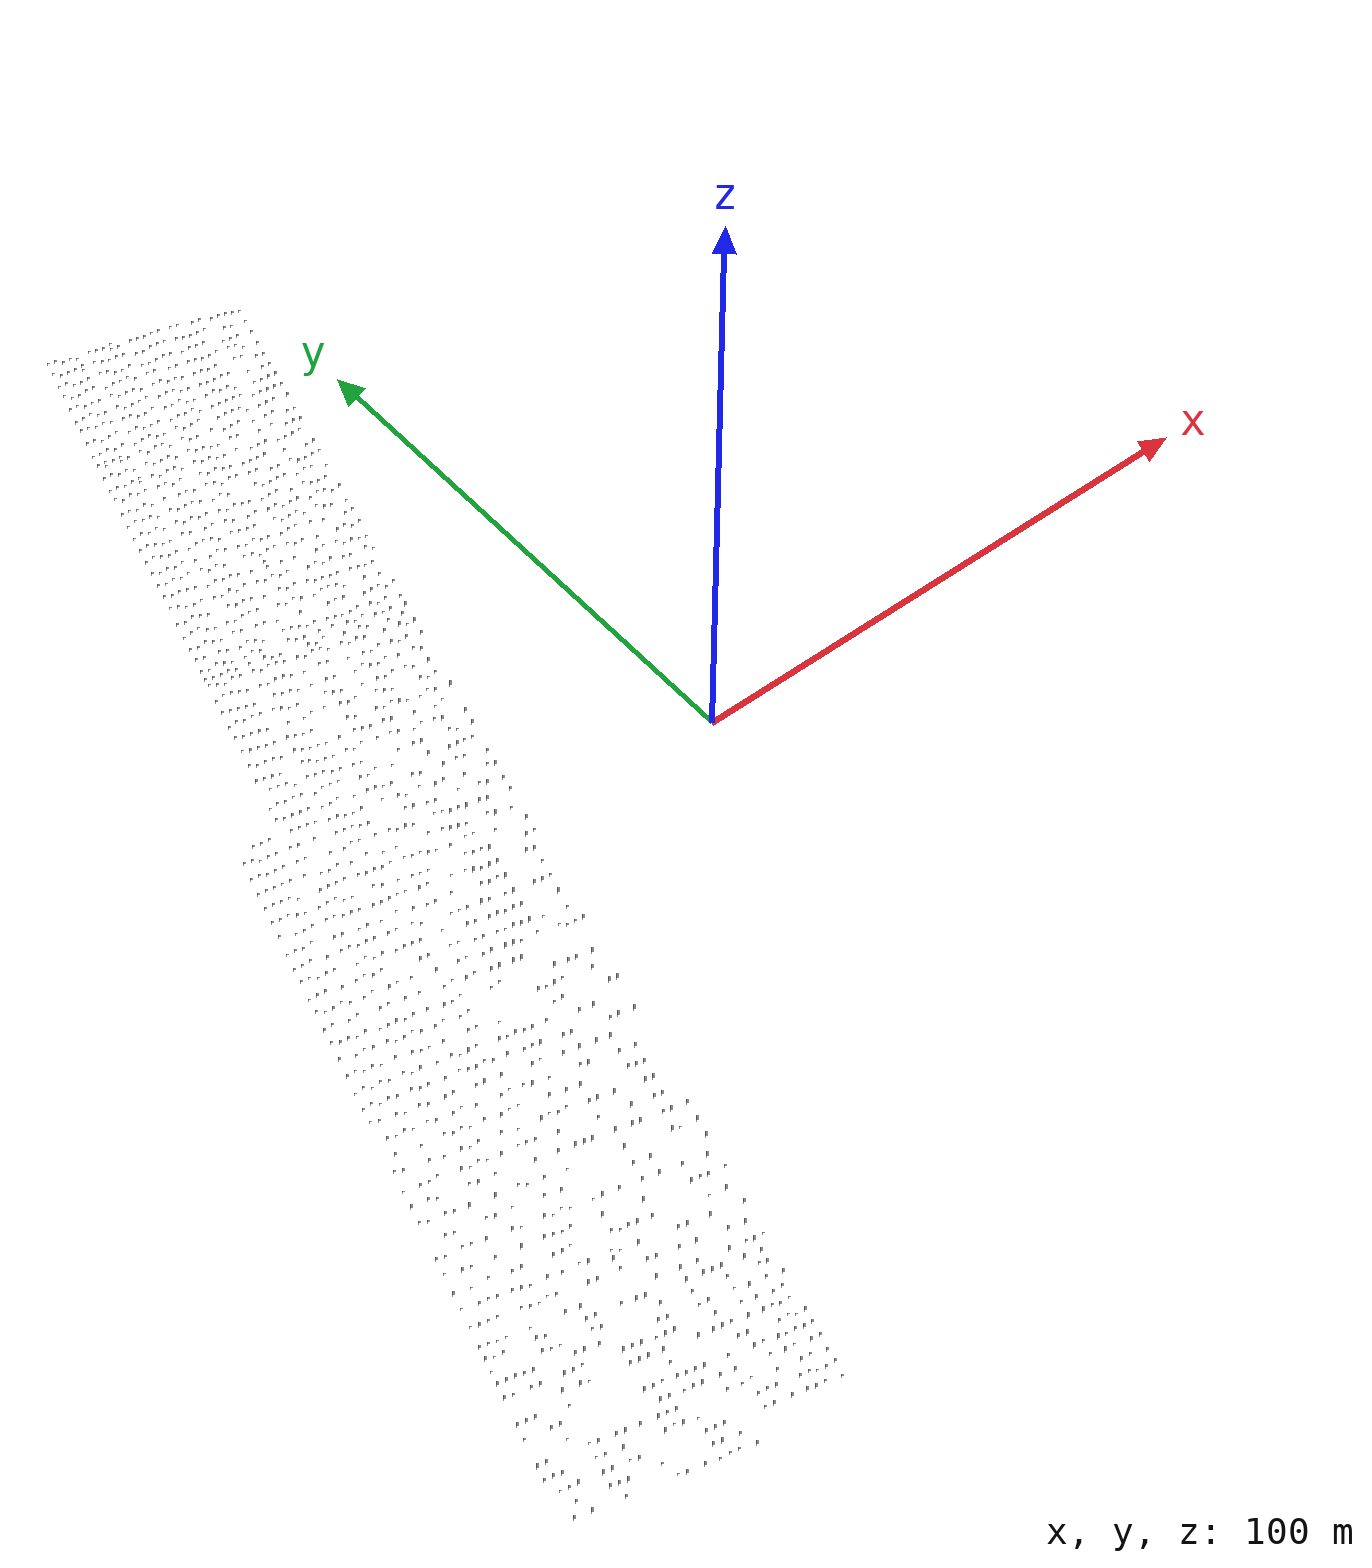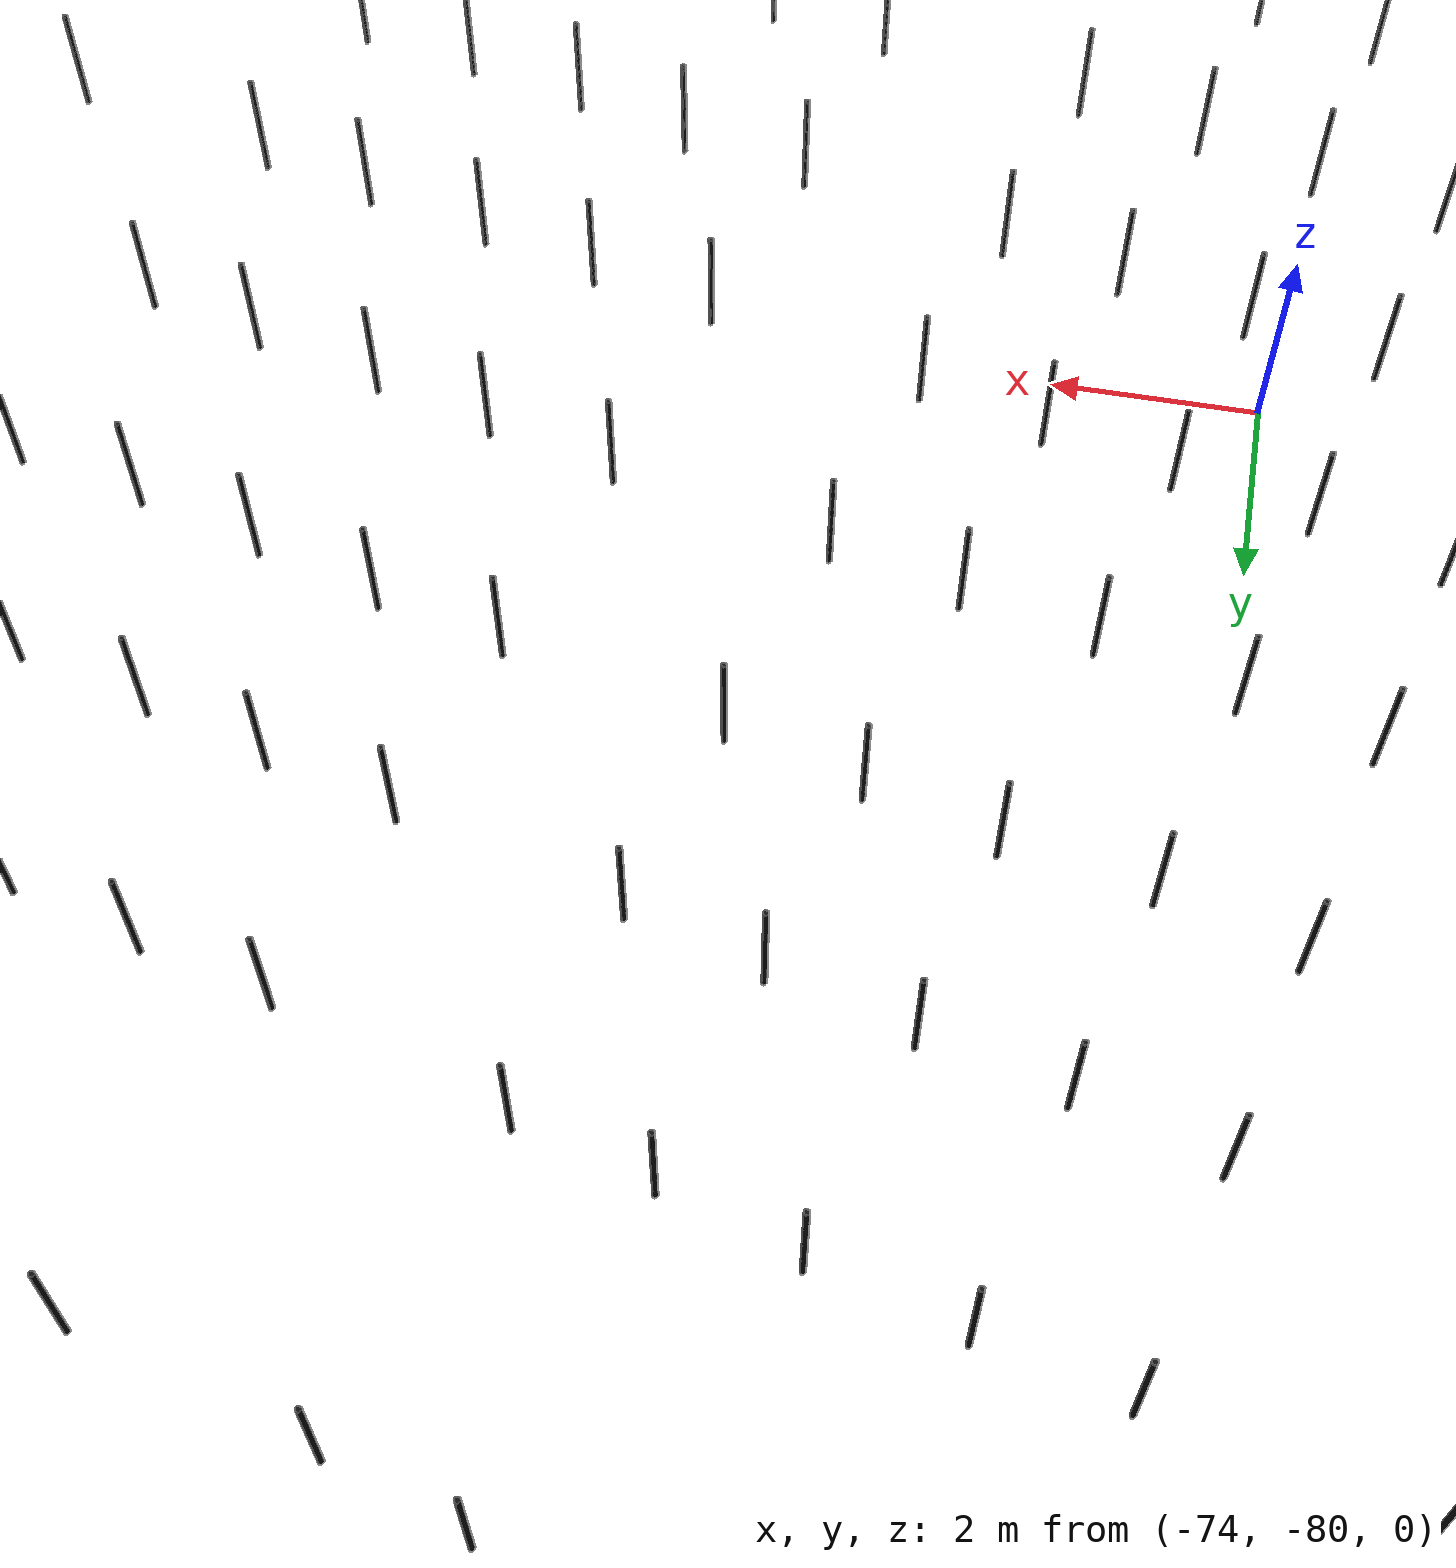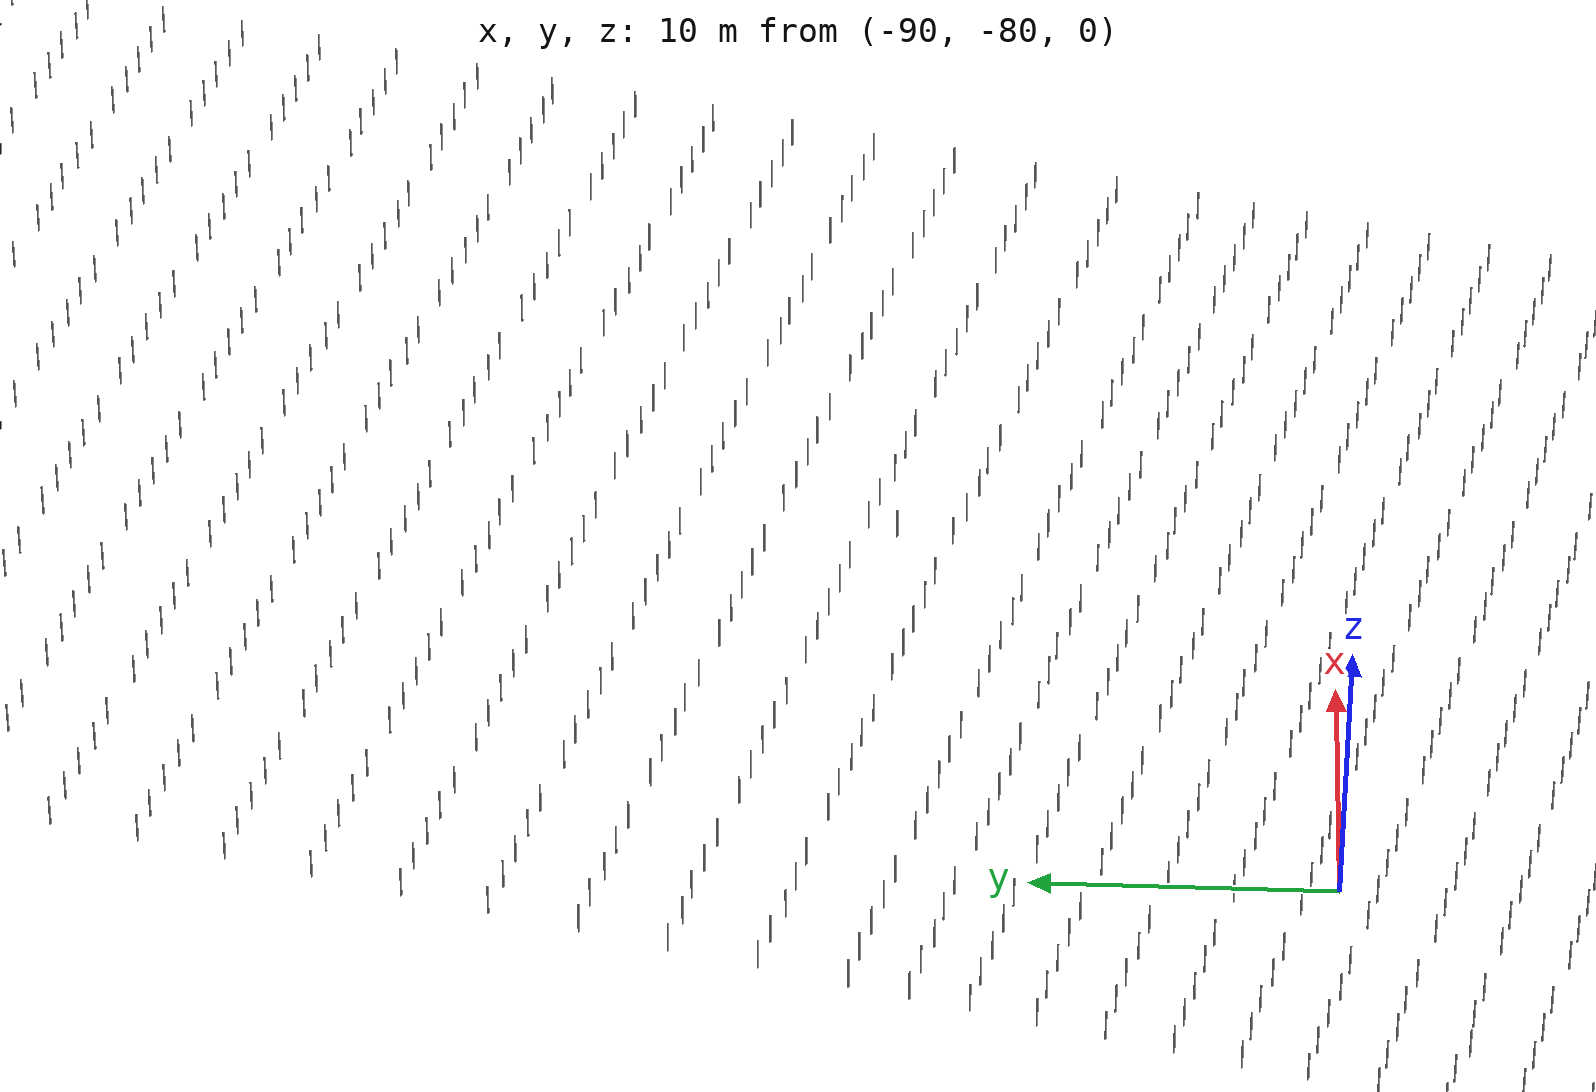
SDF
<sdf version="1.4">
 <world name="default">
  <include><uri>model://sun</uri></include>
  <physics type="ode">
   <real_time_update_rate>100</real_time_update_rate>
   <real_time_factor>1</real_time_factor>
   <max_step_size>0.01</max_step_size>
   <gravity>0 0 -9.8</gravity>
  </physics>
  <model name="pole_0">
   <static>1</static>
   <pose>-102.095 -91.630 0.575 0.0 0.0 0.0</pose>
   <link name="link">
    <collision name="collision">
     <geometry><cylinder><length>1.15</length><radius>0.025</radius></cylinder></geometry>
    </collision>
    <visual name="visual">
     <geometry><cylinder><length>1.15</length><radius>0.025</radius></cylinder></geometry>
     <material>
      <script><uri>file://media/materials/scripts/gazebo.material</uri><name>Gazebo/Chrome</name></script>
      <shader type="vertex"><normal_map>__default__</normal_map></shader>
      <emissive>0.1 0.1 0.1 1</emissive>
      <specular>0.01 0.01 0.01 1</specular>
      <ambient>0.5 0.5 0.5 1</ambient>
      <diffuse>0.05 0.05 0.05 1</diffuse>
     </material>
    </visual>
   </link>
  </model>
  <model name="pole_1">
   <static>1</static>
   <pose>-101.575 -89.550 0.575 0.0 0.0 0.0</pose>
   <link name="link">
    <collision name="collision">
     <geometry><cylinder><length>1.15</length><radius>0.025</radius></cylinder></geometry>
    </collision>
    <visual name="visual">
     <geometry><cylinder><length>1.15</length><radius>0.025</radius></cylinder></geometry>
     <material>
      <script><uri>file://media/materials/scripts/gazebo.material</uri><name>Gazebo/Chrome</name></script>
      <shader type="vertex"><normal_map>__default__</normal_map></shader>
      <emissive>0.1 0.1 0.1 1</emissive>
      <specular>0.01 0.01 0.01 1</specular>
      <ambient>0.5 0.5 0.5 1</ambient>
      <diffuse>0.05 0.05 0.05 1</diffuse>
     </material>
    </visual>
   </link>
  </model>
  <model name="pole_2">
   <static>1</static>
   <pose>-101.050 -87.450 0.575 0.0 0.0 0.0</pose>
   <link name="link">
    <collision name="collision">
     <geometry><cylinder><length>1.15</length><radius>0.025</radius></cylinder></geometry>
    </collision>
    <visual name="visual">
     <geometry><cylinder><length>1.15</length><radius>0.025</radius></cylinder></geometry>
     <material>
      <script><uri>file://media/materials/scripts/gazebo.material</uri><name>Gazebo/Chrome</name></script>
      <shader type="vertex"><normal_map>__default__</normal_map></shader>
      <emissive>0.1 0.1 0.1 1</emissive>
      <specular>0.01 0.01 0.01 1</specular>
      <ambient>0.5 0.5 0.5 1</ambient>
      <diffuse>0.05 0.05 0.05 1</diffuse>
     </material>
    </visual>
   </link>
  </model>
  <model name="pole_3">
   <static>1</static>
   <pose>-100.473 -85.301 0.575 0.0 0.0 0.0</pose>
   <link name="link">
    <collision name="collision">
     <geometry><cylinder><length>1.15</length><radius>0.025</radius></cylinder></geometry>
    </collision>
    <visual name="visual">
     <geometry><cylinder><length>1.15</length><radius>0.025</radius></cylinder></geometry>
     <material>
      <script><uri>file://media/materials/scripts/gazebo.material</uri><name>Gazebo/Chrome</name></script>
      <shader type="vertex"><normal_map>__default__</normal_map></shader>
      <emissive>0.1 0.1 0.1 1</emissive>
      <specular>0.01 0.01 0.01 1</specular>
      <ambient>0.5 0.5 0.5 1</ambient>
      <diffuse>0.05 0.05 0.05 1</diffuse>
     </material>
    </visual>
   </link>
  </model>
  <model name="pole_4">
   <static>1</static>
   <pose>-99.975 -83.200 0.575 0.0 0.0 0.0</pose>
   <link name="link">
    <collision name="collision">
     <geometry><cylinder><length>1.15</length><radius>0.025</radius></cylinder></geometry>
    </collision>
    <visual name="visual">
     <geometry><cylinder><length>1.15</length><radius>0.025</radius></cylinder></geometry>
     <material>
      <script><uri>file://media/materials/scripts/gazebo.material</uri><name>Gazebo/Chrome</name></script>
      <shader type="vertex"><normal_map>__default__</normal_map></shader>
      <emissive>0.1 0.1 0.1 1</emissive>
      <specular>0.01 0.01 0.01 1</specular>
      <ambient>0.5 0.5 0.5 1</ambient>
      <diffuse>0.05 0.05 0.05 1</diffuse>
     </material>
    </visual>
   </link>
  </model>
  <model name="pole_5">
   <static>1</static>
   <pose>-99.400 -81.100 0.575 0.0 0.0 0.0</pose>
   <link name="link">
    <collision name="collision">
     <geometry><cylinder><length>1.15</length><radius>0.025</radius></cylinder></geometry>
    </collision>
    <visual name="visual">
     <geometry><cylinder><length>1.15</length><radius>0.025</radius></cylinder></geometry>
     <material>
      <script><uri>file://media/materials/scripts/gazebo.material</uri><name>Gazebo/Chrome</name></script>
      <shader type="vertex"><normal_map>__default__</normal_map></shader>
      <emissive>0.1 0.1 0.1 1</emissive>
      <specular>0.01 0.01 0.01 1</specular>
      <ambient>0.5 0.5 0.5 1</ambient>
      <diffuse>0.05 0.05 0.05 1</diffuse>
     </material>
    </visual>
   </link>
  </model>
  <model name="pole_6">
   <static>1</static>
   <pose>-98.822 -78.922 0.575 0.0 0.0 0.0</pose>
   <link name="link">
    <collision name="collision">
     <geometry><cylinder><length>1.15</length><radius>0.025</radius></cylinder></geometry>
    </collision>
    <visual name="visual">
     <geometry><cylinder><length>1.15</length><radius>0.025</radius></cylinder></geometry>
     <material>
      <script><uri>file://media/materials/scripts/gazebo.material</uri><name>Gazebo/Chrome</name></script>
      <shader type="vertex"><normal_map>__default__</normal_map></shader>
      <emissive>0.1 0.1 0.1 1</emissive>
      <specular>0.01 0.01 0.01 1</specular>
      <ambient>0.5 0.5 0.5 1</ambient>
      <diffuse>0.05 0.05 0.05 1</diffuse>
     </material>
    </visual>
   </link>
  </model>
  <model name="pole_7">
   <static>1</static>
   <pose>-98.325 -76.850 0.575 0.0 0.0 0.0</pose>
   <link name="link">
    <collision name="collision">
     <geometry><cylinder><length>1.15</length><radius>0.025</radius></cylinder></geometry>
    </collision>
    <visual name="visual">
     <geometry><cylinder><length>1.15</length><radius>0.025</radius></cylinder></geometry>
     <material>
      <script><uri>file://media/materials/scripts/gazebo.material</uri><name>Gazebo/Chrome</name></script>
      <shader type="vertex"><normal_map>__default__</normal_map></shader>
      <emissive>0.1 0.1 0.1 1</emissive>
      <specular>0.01 0.01 0.01 1</specular>
      <ambient>0.5 0.5 0.5 1</ambient>
      <diffuse>0.05 0.05 0.05 1</diffuse>
     </material>
    </visual>
   </link>
  </model>
  <model name="pole_8">
   <static>1</static>
   <pose>-97.750 -74.725 0.575 0.0 0.0 0.0</pose>
   <link name="link">
    <collision name="collision">
     <geometry><cylinder><length>1.15</length><radius>0.025</radius></cylinder></geometry>
    </collision>
    <visual name="visual">
     <geometry><cylinder><length>1.15</length><radius>0.025</radius></cylinder></geometry>
     <material>
      <script><uri>file://media/materials/scripts/gazebo.material</uri><name>Gazebo/Chrome</name></script>
      <shader type="vertex"><normal_map>__default__</normal_map></shader>
      <emissive>0.1 0.1 0.1 1</emissive>
      <specular>0.01 0.01 0.01 1</specular>
      <ambient>0.5 0.5 0.5 1</ambient>
      <diffuse>0.05 0.05 0.05 1</diffuse>
     </material>
    </visual>
   </link>
  </model>
  <model name="pole_9">
   <static>1</static>
   <pose>-97.200 -72.570 0.575 0.0 0.0 0.0</pose>
   <link name="link">
    <collision name="collision">
     <geometry><cylinder><length>1.15</length><radius>0.025</radius></cylinder></geometry>
    </collision>
    <visual name="visual">
     <geometry><cylinder><length>1.15</length><radius>0.025</radius></cylinder></geometry>
     <material>
      <script><uri>file://media/materials/scripts/gazebo.material</uri><name>Gazebo/Chrome</name></script>
      <shader type="vertex"><normal_map>__default__</normal_map></shader>
      <emissive>0.1 0.1 0.1 1</emissive>
      <specular>0.01 0.01 0.01 1</specular>
      <ambient>0.5 0.5 0.5 1</ambient>
      <diffuse>0.05 0.05 0.05 1</diffuse>
     </material>
    </visual>
   </link>
  </model>
  <model name="pole_10">
   <static>1</static>
   <pose>-96.675 -70.400 0.575 0.0 0.0 0.0</pose>
   <link name="link">
    <collision name="collision">
     <geometry><cylinder><length>1.15</length><radius>0.025</radius></cylinder></geometry>
    </collision>
    <visual name="visual">
     <geometry><cylinder><length>1.15</length><radius>0.025</radius></cylinder></geometry>
     <material>
      <script><uri>file://media/materials/scripts/gazebo.material</uri><name>Gazebo/Chrome</name></script>
      <shader type="vertex"><normal_map>__default__</normal_map></shader>
      <emissive>0.1 0.1 0.1 1</emissive>
      <specular>0.01 0.01 0.01 1</specular>
      <ambient>0.5 0.5 0.5 1</ambient>
      <diffuse>0.05 0.05 0.05 1</diffuse>
     </material>
    </visual>
   </link>
  </model>
  <model name="pole_11">
   <static>1</static>
   <pose>-96.100 -68.275 0.575 0.0 0.0 0.0</pose>
   <link name="link">
    <collision name="collision">
     <geometry><cylinder><length>1.15</length><radius>0.025</radius></cylinder></geometry>
    </collision>
    <visual name="visual">
     <geometry><cylinder><length>1.15</length><radius>0.025</radius></cylinder></geometry>
     <material>
      <script><uri>file://media/materials/scripts/gazebo.material</uri><name>Gazebo/Chrome</name></script>
      <shader type="vertex"><normal_map>__default__</normal_map></shader>
      <emissive>0.1 0.1 0.1 1</emissive>
      <specular>0.01 0.01 0.01 1</specular>
      <ambient>0.5 0.5 0.5 1</ambient>
      <diffuse>0.05 0.05 0.05 1</diffuse>
     </material>
    </visual>
   </link>
  </model>
  <model name="pole_12">
   <static>1</static>
   <pose>-95.600 -66.350 0.575 0.0 0.0 0.0</pose>
   <link name="link">
    <collision name="collision">
     <geometry><cylinder><length>1.15</length><radius>0.025</radius></cylinder></geometry>
    </collision>
    <visual name="visual">
     <geometry><cylinder><length>1.15</length><radius>0.025</radius></cylinder></geometry>
     <material>
      <script><uri>file://media/materials/scripts/gazebo.material</uri><name>Gazebo/Chrome</name></script>
      <shader type="vertex"><normal_map>__default__</normal_map></shader>
      <emissive>0.1 0.1 0.1 1</emissive>
      <specular>0.01 0.01 0.01 1</specular>
      <ambient>0.5 0.5 0.5 1</ambient>
      <diffuse>0.05 0.05 0.05 1</diffuse>
     </material>
    </visual>
   </link>
  </model>
  <model name="pole_13">
   <static>1</static>
   <pose>-95.125 -64.400 0.575 0.0 0.0 0.0</pose>
   <link name="link">
    <collision name="collision">
     <geometry><cylinder><length>1.15</length><radius>0.025</radius></cylinder></geometry>
    </collision>
    <visual name="visual">
     <geometry><cylinder><length>1.15</length><radius>0.025</radius></cylinder></geometry>
     <material>
      <script><uri>file://media/materials/scripts/gazebo.material</uri><name>Gazebo/Chrome</name></script>
      <shader type="vertex"><normal_map>__default__</normal_map></shader>
      <emissive>0.1 0.1 0.1 1</emissive>
      <specular>0.01 0.01 0.01 1</specular>
      <ambient>0.5 0.5 0.5 1</ambient>
      <diffuse>0.05 0.05 0.05 1</diffuse>
     </material>
    </visual>
   </link>
  </model>
  <model name="pole_14">
   <static>1</static>
   <pose>-94.375 -61.500 0.575 0.0 0.0 0.0</pose>
   <link name="link">
    <collision name="collision">
     <geometry><cylinder><length>1.15</length><radius>0.025</radius></cylinder></geometry>
    </collision>
    <visual name="visual">
     <geometry><cylinder><length>1.15</length><radius>0.025</radius></cylinder></geometry>
     <material>
      <script><uri>file://media/materials/scripts/gazebo.material</uri><name>Gazebo/Chrome</name></script>
      <shader type="vertex"><normal_map>__default__</normal_map></shader>
      <emissive>0.1 0.1 0.1 1</emissive>
      <specular>0.01 0.01 0.01 1</specular>
      <ambient>0.5 0.5 0.5 1</ambient>
      <diffuse>0.05 0.05 0.05 1</diffuse>
     </material>
    </visual>
   </link>
  </model>
  <model name="pole_15">
   <static>1</static>
   <pose>-93.675 -58.600 0.575 0.0 0.0 0.0</pose>
   <link name="link">
    <collision name="collision">
     <geometry><cylinder><length>1.15</length><radius>0.025</radius></cylinder></geometry>
    </collision>
    <visual name="visual">
     <geometry><cylinder><length>1.15</length><radius>0.025</radius></cylinder></geometry>
     <material>
      <script><uri>file://media/materials/scripts/gazebo.material</uri><name>Gazebo/Chrome</name></script>
      <shader type="vertex"><normal_map>__default__</normal_map></shader>
      <emissive>0.1 0.1 0.1 1</emissive>
      <specular>0.01 0.01 0.01 1</specular>
      <ambient>0.5 0.5 0.5 1</ambient>
      <diffuse>0.05 0.05 0.05 1</diffuse>
     </material>
    </visual>
   </link>
  </model>
  <model name="pole_16">
   <static>1</static>
   <pose>-92.900 -55.700 0.575 0.0 0.0 0.0</pose>
   <link name="link">
    <collision name="collision">
     <geometry><cylinder><length>1.15</length><radius>0.025</radius></cylinder></geometry>
    </collision>
    <visual name="visual">
     <geometry><cylinder><length>1.15</length><radius>0.025</radius></cylinder></geometry>
     <material>
      <script><uri>file://media/materials/scripts/gazebo.material</uri><name>Gazebo/Chrome</name></script>
      <shader type="vertex"><normal_map>__default__</normal_map></shader>
      <emissive>0.1 0.1 0.1 1</emissive>
      <specular>0.01 0.01 0.01 1</specular>
      <ambient>0.5 0.5 0.5 1</ambient>
      <diffuse>0.05 0.05 0.05 1</diffuse>
     </material>
    </visual>
   </link>
  </model>
  <model name="pole_17">
   <static>1</static>
   <pose>-92.150 -52.750 0.575 0.0 0.0 0.0</pose>
   <link name="link">
    <collision name="collision">
     <geometry><cylinder><length>1.15</length><radius>0.025</radius></cylinder></geometry>
    </collision>
    <visual name="visual">
     <geometry><cylinder><length>1.15</length><radius>0.025</radius></cylinder></geometry>
     <material>
      <script><uri>file://media/materials/scripts/gazebo.material</uri><name>Gazebo/Chrome</name></script>
      <shader type="vertex"><normal_map>__default__</normal_map></shader>
      <emissive>0.1 0.1 0.1 1</emissive>
      <specular>0.01 0.01 0.01 1</specular>
      <ambient>0.5 0.5 0.5 1</ambient>
      <diffuse>0.05 0.05 0.05 1</diffuse>
     </material>
    </visual>
   </link>
  </model>
  <model name="pole_18">
   <static>1</static>
   <pose>-91.425 -49.900 0.575 0.0 0.0 0.0</pose>
   <link name="link">
    <collision name="collision">
     <geometry><cylinder><length>1.15</length><radius>0.025</radius></cylinder></geometry>
    </collision>
    <visual name="visual">
     <geometry><cylinder><length>1.15</length><radius>0.025</radius></cylinder></geometry>
     <material>
      <script><uri>file://media/materials/scripts/gazebo.material</uri><name>Gazebo/Chrome</name></script>
      <shader type="vertex"><normal_map>__default__</normal_map></shader>
      <emissive>0.1 0.1 0.1 1</emissive>
      <specular>0.01 0.01 0.01 1</specular>
      <ambient>0.5 0.5 0.5 1</ambient>
      <diffuse>0.05 0.05 0.05 1</diffuse>
     </material>
    </visual>
   </link>
  </model>
  <model name="pole_19">
   <static>1</static>
   <pose>-90.675 -46.950 0.575 0.0 0.0 0.0</pose>
   <link name="link">
    <collision name="collision">
     <geometry><cylinder><length>1.15</length><radius>0.025</radius></cylinder></geometry>
    </collision>
    <visual name="visual">
     <geometry><cylinder><length>1.15</length><radius>0.025</radius></cylinder></geometry>
     <material>
      <script><uri>file://media/materials/scripts/gazebo.material</uri><name>Gazebo/Chrome</name></script>
      <shader type="vertex"><normal_map>__default__</normal_map></shader>
      <emissive>0.1 0.1 0.1 1</emissive>
      <specular>0.01 0.01 0.01 1</specular>
      <ambient>0.5 0.5 0.5 1</ambient>
      <diffuse>0.05 0.05 0.05 1</diffuse>
     </material>
    </visual>
   </link>
  </model>
  <model name="pole_20">
   <static>1</static>
   <pose>-89.925 -44.075 0.575 0.0 0.0 0.0</pose>
   <link name="link">
    <collision name="collision">
     <geometry><cylinder><length>1.15</length><radius>0.025</radius></cylinder></geometry>
    </collision>
    <visual name="visual">
     <geometry><cylinder><length>1.15</length><radius>0.025</radius></cylinder></geometry>
     <material>
      <script><uri>file://media/materials/scripts/gazebo.material</uri><name>Gazebo/Chrome</name></script>
      <shader type="vertex"><normal_map>__default__</normal_map></shader>
      <emissive>0.1 0.1 0.1 1</emissive>
      <specular>0.01 0.01 0.01 1</specular>
      <ambient>0.5 0.5 0.5 1</ambient>
      <diffuse>0.05 0.05 0.05 1</diffuse>
     </material>
    </visual>
   </link>
  </model>
  <model name="pole_21">
   <static>1</static>
   <pose>-89.175 -41.175 0.575 0.0 0.0 0.0</pose>
   <link name="link">
    <collision name="collision">
     <geometry><cylinder><length>1.15</length><radius>0.025</radius></cylinder></geometry>
    </collision>
    <visual name="visual">
     <geometry><cylinder><length>1.15</length><radius>0.025</radius></cylinder></geometry>
     <material>
      <script><uri>file://media/materials/scripts/gazebo.material</uri><name>Gazebo/Chrome</name></script>
      <shader type="vertex"><normal_map>__default__</normal_map></shader>
      <emissive>0.1 0.1 0.1 1</emissive>
      <specular>0.01 0.01 0.01 1</specular>
      <ambient>0.5 0.5 0.5 1</ambient>
      <diffuse>0.05 0.05 0.05 1</diffuse>
     </material>
    </visual>
   </link>
  </model>
  <model name="pole_22">
   <static>1</static>
   <pose>-88.450 -38.250 0.575 0.0 0.0 0.0</pose>
   <link name="link">
    <collision name="collision">
     <geometry><cylinder><length>1.15</length><radius>0.025</radius></cylinder></geometry>
    </collision>
    <visual name="visual">
     <geometry><cylinder><length>1.15</length><radius>0.025</radius></cylinder></geometry>
     <material>
      <script><uri>file://media/materials/scripts/gazebo.material</uri><name>Gazebo/Chrome</name></script>
      <shader type="vertex"><normal_map>__default__</normal_map></shader>
      <emissive>0.1 0.1 0.1 1</emissive>
      <specular>0.01 0.01 0.01 1</specular>
      <ambient>0.5 0.5 0.5 1</ambient>
      <diffuse>0.05 0.05 0.05 1</diffuse>
     </material>
    </visual>
   </link>
  </model>
  <model name="pole_23">
   <static>1</static>
   <pose>-87.725 -35.300 0.575 0.0 0.0 0.0</pose>
   <link name="link">
    <collision name="collision">
     <geometry><cylinder><length>1.15</length><radius>0.025</radius></cylinder></geometry>
    </collision>
    <visual name="visual">
     <geometry><cylinder><length>1.15</length><radius>0.025</radius></cylinder></geometry>
     <material>
      <script><uri>file://media/materials/scripts/gazebo.material</uri><name>Gazebo/Chrome</name></script>
      <shader type="vertex"><normal_map>__default__</normal_map></shader>
      <emissive>0.1 0.1 0.1 1</emissive>
      <specular>0.01 0.01 0.01 1</specular>
      <ambient>0.5 0.5 0.5 1</ambient>
      <diffuse>0.05 0.05 0.05 1</diffuse>
     </material>
    </visual>
   </link>
  </model>
  <model name="pole_24">
   <static>1</static>
   <pose>-86.978 -32.472 0.575 0.0 0.0 0.0</pose>
   <link name="link">
    <collision name="collision">
     <geometry><cylinder><length>1.15</length><radius>0.025</radius></cylinder></geometry>
    </collision>
    <visual name="visual">
     <geometry><cylinder><length>1.15</length><radius>0.025</radius></cylinder></geometry>
     <material>
      <script><uri>file://media/materials/scripts/gazebo.material</uri><name>Gazebo/Chrome</name></script>
      <shader type="vertex"><normal_map>__default__</normal_map></shader>
      <emissive>0.1 0.1 0.1 1</emissive>
      <specular>0.01 0.01 0.01 1</specular>
      <ambient>0.5 0.5 0.5 1</ambient>
      <diffuse>0.05 0.05 0.05 1</diffuse>
     </material>
    </visual>
   </link>
  </model>
  <model name="pole_25">
   <static>1</static>
   <pose>-86.200 -29.525 0.575 0.0 0.0 0.0</pose>
   <link name="link">
    <collision name="collision">
     <geometry><cylinder><length>1.15</length><radius>0.025</radius></cylinder></geometry>
    </collision>
    <visual name="visual">
     <geometry><cylinder><length>1.15</length><radius>0.025</radius></cylinder></geometry>
     <material>
      <script><uri>file://media/materials/scripts/gazebo.material</uri><name>Gazebo/Chrome</name></script>
      <shader type="vertex"><normal_map>__default__</normal_map></shader>
      <emissive>0.1 0.1 0.1 1</emissive>
      <specular>0.01 0.01 0.01 1</specular>
      <ambient>0.5 0.5 0.5 1</ambient>
      <diffuse>0.05 0.05 0.05 1</diffuse>
     </material>
    </visual>
   </link>
  </model>
  <model name="pole_26">
   <static>1</static>
   <pose>-85.475 -26.600 0.575 0.0 0.0 0.0</pose>
   <link name="link">
    <collision name="collision">
     <geometry><cylinder><length>1.15</length><radius>0.025</radius></cylinder></geometry>
    </collision>
    <visual name="visual">
     <geometry><cylinder><length>1.15</length><radius>0.025</radius></cylinder></geometry>
     <material>
      <script><uri>file://media/materials/scripts/gazebo.material</uri><name>Gazebo/Chrome</name></script>
      <shader type="vertex"><normal_map>__default__</normal_map></shader>
      <emissive>0.1 0.1 0.1 1</emissive>
      <specular>0.01 0.01 0.01 1</specular>
      <ambient>0.5 0.5 0.5 1</ambient>
      <diffuse>0.05 0.05 0.05 1</diffuse>
     </material>
    </visual>
   </link>
  </model>
  <model name="pole_27">
   <static>1</static>
   <pose>-84.700 -23.700 0.575 0.0 0.0 0.0</pose>
   <link name="link">
    <collision name="collision">
     <geometry><cylinder><length>1.15</length><radius>0.025</radius></cylinder></geometry>
    </collision>
    <visual name="visual">
     <geometry><cylinder><length>1.15</length><radius>0.025</radius></cylinder></geometry>
     <material>
      <script><uri>file://media/materials/scripts/gazebo.material</uri><name>Gazebo/Chrome</name></script>
      <shader type="vertex"><normal_map>__default__</normal_map></shader>
      <emissive>0.1 0.1 0.1 1</emissive>
      <specular>0.01 0.01 0.01 1</specular>
      <ambient>0.5 0.5 0.5 1</ambient>
      <diffuse>0.05 0.05 0.05 1</diffuse>
     </material>
    </visual>
   </link>
  </model>
  <model name="pole_28">
   <static>1</static>
   <pose>-83.975 -20.750 0.575 0.0 0.0 0.0</pose>
   <link name="link">
    <collision name="collision">
     <geometry><cylinder><length>1.15</length><radius>0.025</radius></cylinder></geometry>
    </collision>
    <visual name="visual">
     <geometry><cylinder><length>1.15</length><radius>0.025</radius></cylinder></geometry>
     <material>
      <script><uri>file://media/materials/scripts/gazebo.material</uri><name>Gazebo/Chrome</name></script>
      <shader type="vertex"><normal_map>__default__</normal_map></shader>
      <emissive>0.1 0.1 0.1 1</emissive>
      <specular>0.01 0.01 0.01 1</specular>
      <ambient>0.5 0.5 0.5 1</ambient>
      <diffuse>0.05 0.05 0.05 1</diffuse>
     </material>
    </visual>
   </link>
  </model>
  <model name="pole_29">
   <static>1</static>
   <pose>-83.228 -17.878 0.575 0.0 0.0 0.0</pose>
   <link name="link">
    <collision name="collision">
     <geometry><cylinder><length>1.15</length><radius>0.025</radius></cylinder></geometry>
    </collision>
    <visual name="visual">
     <geometry><cylinder><length>1.15</length><radius>0.025</radius></cylinder></geometry>
     <material>
      <script><uri>file://media/materials/scripts/gazebo.material</uri><name>Gazebo/Chrome</name></script>
      <shader type="vertex"><normal_map>__default__</normal_map></shader>
      <emissive>0.1 0.1 0.1 1</emissive>
      <specular>0.01 0.01 0.01 1</specular>
      <ambient>0.5 0.5 0.5 1</ambient>
      <diffuse>0.05 0.05 0.05 1</diffuse>
     </material>
    </visual>
   </link>
  </model>
  <model name="pole_30">
   <static>1</static>
   <pose>-82.500 -14.950 0.575 0.0 0.0 0.0</pose>
   <link name="link">
    <collision name="collision">
     <geometry><cylinder><length>1.15</length><radius>0.025</radius></cylinder></geometry>
    </collision>
    <visual name="visual">
     <geometry><cylinder><length>1.15</length><radius>0.025</radius></cylinder></geometry>
     <material>
      <script><uri>file://media/materials/scripts/gazebo.material</uri><name>Gazebo/Chrome</name></script>
      <shader type="vertex"><normal_map>__default__</normal_map></shader>
      <emissive>0.1 0.1 0.1 1</emissive>
      <specular>0.01 0.01 0.01 1</specular>
      <ambient>0.5 0.5 0.5 1</ambient>
      <diffuse>0.05 0.05 0.05 1</diffuse>
     </material>
    </visual>
   </link>
  </model>
  <model name="pole_31">
   <static>1</static>
   <pose>-81.775 -12.025 0.575 0.0 0.0 0.0</pose>
   <link name="link">
    <collision name="collision">
     <geometry><cylinder><length>1.15</length><radius>0.025</radius></cylinder></geometry>
    </collision>
    <visual name="visual">
     <geometry><cylinder><length>1.15</length><radius>0.025</radius></cylinder></geometry>
     <material>
      <script><uri>file://media/materials/scripts/gazebo.material</uri><name>Gazebo/Chrome</name></script>
      <shader type="vertex"><normal_map>__default__</normal_map></shader>
      <emissive>0.1 0.1 0.1 1</emissive>
      <specular>0.01 0.01 0.01 1</specular>
      <ambient>0.5 0.5 0.5 1</ambient>
      <diffuse>0.05 0.05 0.05 1</diffuse>
     </material>
    </visual>
   </link>
  </model>
  <model name="pole_32">
   <static>1</static>
   <pose>-81.050 -9.175 0.575 0.0 0.0 0.0</pose>
   <link name="link">
    <collision name="collision">
     <geometry><cylinder><length>1.15</length><radius>0.025</radius></cylinder></geometry>
    </collision>
    <visual name="visual">
     <geometry><cylinder><length>1.15</length><radius>0.025</radius></cylinder></geometry>
     <material>
      <script><uri>file://media/materials/scripts/gazebo.material</uri><name>Gazebo/Chrome</name></script>
      <shader type="vertex"><normal_map>__default__</normal_map></shader>
      <emissive>0.1 0.1 0.1 1</emissive>
      <specular>0.01 0.01 0.01 1</specular>
      <ambient>0.5 0.5 0.5 1</ambient>
      <diffuse>0.05 0.05 0.05 1</diffuse>
     </material>
    </visual>
   </link>
  </model>
  <model name="pole_33">
   <static>1</static>
   <pose>-80.275 -6.200 0.575 0.0 0.0 0.0</pose>
   <link name="link">
    <collision name="collision">
     <geometry><cylinder><length>1.15</length><radius>0.025</radius></cylinder></geometry>
    </collision>
    <visual name="visual">
     <geometry><cylinder><length>1.15</length><radius>0.025</radius></cylinder></geometry>
     <material>
      <script><uri>file://media/materials/scripts/gazebo.material</uri><name>Gazebo/Chrome</name></script>
      <shader type="vertex"><normal_map>__default__</normal_map></shader>
      <emissive>0.1 0.1 0.1 1</emissive>
      <specular>0.01 0.01 0.01 1</specular>
      <ambient>0.5 0.5 0.5 1</ambient>
      <diffuse>0.05 0.05 0.05 1</diffuse>
     </material>
    </visual>
   </link>
  </model>
  <model name="pole_34">
   <static>1</static>
   <pose>-79.550 -3.300 0.575 0.0 0.0 0.0</pose>
   <link name="link">
    <collision name="collision">
     <geometry><cylinder><length>1.15</length><radius>0.025</radius></cylinder></geometry>
    </collision>
    <visual name="visual">
     <geometry><cylinder><length>1.15</length><radius>0.025</radius></cylinder></geometry>
     <material>
      <script><uri>file://media/materials/scripts/gazebo.material</uri><name>Gazebo/Chrome</name></script>
      <shader type="vertex"><normal_map>__default__</normal_map></shader>
      <emissive>0.1 0.1 0.1 1</emissive>
      <specular>0.01 0.01 0.01 1</specular>
      <ambient>0.5 0.5 0.5 1</ambient>
      <diffuse>0.05 0.05 0.05 1</diffuse>
     </material>
    </visual>
   </link>
  </model>
  <model name="pole_35">
   <static>1</static>
   <pose>-78.825 -0.400 0.575 0.0 0.0 0.0</pose>
   <link name="link">
    <collision name="collision">
     <geometry><cylinder><length>1.15</length><radius>0.025</radius></cylinder></geometry>
    </collision>
    <visual name="visual">
     <geometry><cylinder><length>1.15</length><radius>0.025</radius></cylinder></geometry>
     <material>
      <script><uri>file://media/materials/scripts/gazebo.material</uri><name>Gazebo/Chrome</name></script>
      <shader type="vertex"><normal_map>__default__</normal_map></shader>
      <emissive>0.1 0.1 0.1 1</emissive>
      <specular>0.01 0.01 0.01 1</specular>
      <ambient>0.5 0.5 0.5 1</ambient>
      <diffuse>0.05 0.05 0.05 1</diffuse>
     </material>
    </visual>
   </link>
  </model>
  <model name="pole_36">
   <static>1</static>
   <pose>-78.075 2.550 0.575 0.0 0.0 0.0</pose>
   <link name="link">
    <collision name="collision">
     <geometry><cylinder><length>1.15</length><radius>0.025</radius></cylinder></geometry>
    </collision>
    <visual name="visual">
     <geometry><cylinder><length>1.15</length><radius>0.025</radius></cylinder></geometry>
     <material>
      <script><uri>file://media/materials/scripts/gazebo.material</uri><name>Gazebo/Chrome</name></script>
      <shader type="vertex"><normal_map>__default__</normal_map></shader>
      <emissive>0.1 0.1 0.1 1</emissive>
      <specular>0.01 0.01 0.01 1</specular>
      <ambient>0.5 0.5 0.5 1</ambient>
      <diffuse>0.05 0.05 0.05 1</diffuse>
     </material>
    </visual>
   </link>
  </model>
  <model name="pole_37">
   <static>1</static>
   <pose>-77.325 5.400 0.575 0.0 0.0 0.0</pose>
   <link name="link">
    <collision name="collision">
     <geometry><cylinder><length>1.15</length><radius>0.025</radius></cylinder></geometry>
    </collision>
    <visual name="visual">
     <geometry><cylinder><length>1.15</length><radius>0.025</radius></cylinder></geometry>
     <material>
      <script><uri>file://media/materials/scripts/gazebo.material</uri><name>Gazebo/Chrome</name></script>
      <shader type="vertex"><normal_map>__default__</normal_map></shader>
      <emissive>0.1 0.1 0.1 1</emissive>
      <specular>0.01 0.01 0.01 1</specular>
      <ambient>0.5 0.5 0.5 1</ambient>
      <diffuse>0.05 0.05 0.05 1</diffuse>
     </material>
    </visual>
   </link>
  </model>
  <model name="pole_38">
   <static>1</static>
   <pose>-76.575 8.350 0.575 0.0 0.0 0.0</pose>
   <link name="link">
    <collision name="collision">
     <geometry><cylinder><length>1.15</length><radius>0.025</radius></cylinder></geometry>
    </collision>
    <visual name="visual">
     <geometry><cylinder><length>1.15</length><radius>0.025</radius></cylinder></geometry>
     <material>
      <script><uri>file://media/materials/scripts/gazebo.material</uri><name>Gazebo/Chrome</name></script>
      <shader type="vertex"><normal_map>__default__</normal_map></shader>
      <emissive>0.1 0.1 0.1 1</emissive>
      <specular>0.01 0.01 0.01 1</specular>
      <ambient>0.5 0.5 0.5 1</ambient>
      <diffuse>0.05 0.05 0.05 1</diffuse>
     </material>
    </visual>
   </link>
  </model>
  <model name="pole_39">
   <static>1</static>
   <pose>-75.822 11.278 0.575 0.0 0.0 0.0</pose>
   <link name="link">
    <collision name="collision">
     <geometry><cylinder><length>1.15</length><radius>0.025</radius></cylinder></geometry>
    </collision>
    <visual name="visual">
     <geometry><cylinder><length>1.15</length><radius>0.025</radius></cylinder></geometry>
     <material>
      <script><uri>file://media/materials/scripts/gazebo.material</uri><name>Gazebo/Chrome</name></script>
      <shader type="vertex"><normal_map>__default__</normal_map></shader>
      <emissive>0.1 0.1 0.1 1</emissive>
      <specular>0.01 0.01 0.01 1</specular>
      <ambient>0.5 0.5 0.5 1</ambient>
      <diffuse>0.05 0.05 0.05 1</diffuse>
     </material>
    </visual>
   </link>
  </model>
  <model name="pole_40">
   <static>1</static>
   <pose>-75.075 14.150 0.575 0.0 0.0 0.0</pose>
   <link name="link">
    <collision name="collision">
     <geometry><cylinder><length>1.15</length><radius>0.025</radius></cylinder></geometry>
    </collision>
    <visual name="visual">
     <geometry><cylinder><length>1.15</length><radius>0.025</radius></cylinder></geometry>
     <material>
      <script><uri>file://media/materials/scripts/gazebo.material</uri><name>Gazebo/Chrome</name></script>
      <shader type="vertex"><normal_map>__default__</normal_map></shader>
      <emissive>0.1 0.1 0.1 1</emissive>
      <specular>0.01 0.01 0.01 1</specular>
      <ambient>0.5 0.5 0.5 1</ambient>
      <diffuse>0.05 0.05 0.05 1</diffuse>
     </material>
    </visual>
   </link>
  </model>
  <model name="pole_41">
   <static>1</static>
   <pose>-74.328 17.072 0.575 0.0 0.0 0.0</pose>
   <link name="link">
    <collision name="collision">
     <geometry><cylinder><length>1.15</length><radius>0.025</radius></cylinder></geometry>
    </collision>
    <visual name="visual">
     <geometry><cylinder><length>1.15</length><radius>0.025</radius></cylinder></geometry>
     <material>
      <script><uri>file://media/materials/scripts/gazebo.material</uri><name>Gazebo/Chrome</name></script>
      <shader type="vertex"><normal_map>__default__</normal_map></shader>
      <emissive>0.1 0.1 0.1 1</emissive>
      <specular>0.01 0.01 0.01 1</specular>
      <ambient>0.5 0.5 0.5 1</ambient>
      <diffuse>0.05 0.05 0.05 1</diffuse>
     </material>
    </visual>
   </link>
  </model>
  <model name="pole_42">
   <static>1</static>
   <pose>-73.575 19.950 0.575 0.0 0.0 0.0</pose>
   <link name="link">
    <collision name="collision">
     <geometry><cylinder><length>1.15</length><radius>0.025</radius></cylinder></geometry>
    </collision>
    <visual name="visual">
     <geometry><cylinder><length>1.15</length><radius>0.025</radius></cylinder></geometry>
     <material>
      <script><uri>file://media/materials/scripts/gazebo.material</uri><name>Gazebo/Chrome</name></script>
      <shader type="vertex"><normal_map>__default__</normal_map></shader>
      <emissive>0.1 0.1 0.1 1</emissive>
      <specular>0.01 0.01 0.01 1</specular>
      <ambient>0.5 0.5 0.5 1</ambient>
      <diffuse>0.05 0.05 0.05 1</diffuse>
     </material>
    </visual>
   </link>
  </model>
  <model name="pole_43">
   <static>1</static>
   <pose>-72.800 22.825 0.575 0.0 0.0 0.0</pose>
   <link name="link">
    <collision name="collision">
     <geometry><cylinder><length>1.15</length><radius>0.025</radius></cylinder></geometry>
    </collision>
    <visual name="visual">
     <geometry><cylinder><length>1.15</length><radius>0.025</radius></cylinder></geometry>
     <material>
      <script><uri>file://media/materials/scripts/gazebo.material</uri><name>Gazebo/Chrome</name></script>
      <shader type="vertex"><normal_map>__default__</normal_map></shader>
      <emissive>0.1 0.1 0.1 1</emissive>
      <specular>0.01 0.01 0.01 1</specular>
      <ambient>0.5 0.5 0.5 1</ambient>
      <diffuse>0.05 0.05 0.05 1</diffuse>
     </material>
    </visual>
   </link>
  </model>
  <model name="pole_44">
   <static>1</static>
   <pose>-100.800 -92.000 0.575 0.0 0.0 0.0</pose>
   <link name="link">
    <collision name="collision">
     <geometry><cylinder><length>1.15</length><radius>0.025</radius></cylinder></geometry>
    </collision>
    <visual name="visual">
     <geometry><cylinder><length>1.15</length><radius>0.025</radius></cylinder></geometry>
     <material>
      <script><uri>file://media/materials/scripts/gazebo.material</uri><name>Gazebo/Chrome</name></script>
      <shader type="vertex"><normal_map>__default__</normal_map></shader>
      <emissive>0.1 0.1 0.1 1</emissive>
      <specular>0.01 0.01 0.01 1</specular>
      <ambient>0.5 0.5 0.5 1</ambient>
      <diffuse>0.05 0.05 0.05 1</diffuse>
     </material>
    </visual>
   </link>
  </model>
  <model name="pole_45">
   <static>1</static>
   <pose>-100.291 -89.833 0.575 0.0 0.0 0.0</pose>
   <link name="link">
    <collision name="collision">
     <geometry><cylinder><length>1.15</length><radius>0.025</radius></cylinder></geometry>
    </collision>
    <visual name="visual">
     <geometry><cylinder><length>1.15</length><radius>0.025</radius></cylinder></geometry>
     <material>
      <script><uri>file://media/materials/scripts/gazebo.material</uri><name>Gazebo/Chrome</name></script>
      <shader type="vertex"><normal_map>__default__</normal_map></shader>
      <emissive>0.1 0.1 0.1 1</emissive>
      <specular>0.01 0.01 0.01 1</specular>
      <ambient>0.5 0.5 0.5 1</ambient>
      <diffuse>0.05 0.05 0.05 1</diffuse>
     </material>
    </visual>
   </link>
  </model>
  <model name="pole_46">
   <static>1</static>
   <pose>-99.767 -87.733 0.575 0.0 0.0 0.0</pose>
   <link name="link">
    <collision name="collision">
     <geometry><cylinder><length>1.15</length><radius>0.025</radius></cylinder></geometry>
    </collision>
    <visual name="visual">
     <geometry><cylinder><length>1.15</length><radius>0.025</radius></cylinder></geometry>
     <material>
      <script><uri>file://media/materials/scripts/gazebo.material</uri><name>Gazebo/Chrome</name></script>
      <shader type="vertex"><normal_map>__default__</normal_map></shader>
      <emissive>0.1 0.1 0.1 1</emissive>
      <specular>0.01 0.01 0.01 1</specular>
      <ambient>0.5 0.5 0.5 1</ambient>
      <diffuse>0.05 0.05 0.05 1</diffuse>
     </material>
    </visual>
   </link>
  </model>
  <model name="pole_47">
   <static>1</static>
   <pose>-99.215 -85.631 0.575 0.0 0.0 0.0</pose>
   <link name="link">
    <collision name="collision">
     <geometry><cylinder><length>1.15</length><radius>0.025</radius></cylinder></geometry>
    </collision>
    <visual name="visual">
     <geometry><cylinder><length>1.15</length><radius>0.025</radius></cylinder></geometry>
     <material>
      <script><uri>file://media/materials/scripts/gazebo.material</uri><name>Gazebo/Chrome</name></script>
      <shader type="vertex"><normal_map>__default__</normal_map></shader>
      <emissive>0.1 0.1 0.1 1</emissive>
      <specular>0.01 0.01 0.01 1</specular>
      <ambient>0.5 0.5 0.5 1</ambient>
      <diffuse>0.05 0.05 0.05 1</diffuse>
     </material>
    </visual>
   </link>
  </model>
  <model name="pole_48">
   <static>1</static>
   <pose>-98.692 -83.500 0.575 0.0 0.0 0.0</pose>
   <link name="link">
    <collision name="collision">
     <geometry><cylinder><length>1.15</length><radius>0.025</radius></cylinder></geometry>
    </collision>
    <visual name="visual">
     <geometry><cylinder><length>1.15</length><radius>0.025</radius></cylinder></geometry>
     <material>
      <script><uri>file://media/materials/scripts/gazebo.material</uri><name>Gazebo/Chrome</name></script>
      <shader type="vertex"><normal_map>__default__</normal_map></shader>
      <emissive>0.1 0.1 0.1 1</emissive>
      <specular>0.01 0.01 0.01 1</specular>
      <ambient>0.5 0.5 0.5 1</ambient>
      <diffuse>0.05 0.05 0.05 1</diffuse>
     </material>
    </visual>
   </link>
  </model>
  <model name="pole_49">
   <static>1</static>
   <pose>-98.141 -81.383 0.575 0.0 0.0 0.0</pose>
   <link name="link">
    <collision name="collision">
     <geometry><cylinder><length>1.15</length><radius>0.025</radius></cylinder></geometry>
    </collision>
    <visual name="visual">
     <geometry><cylinder><length>1.15</length><radius>0.025</radius></cylinder></geometry>
     <material>
      <script><uri>file://media/materials/scripts/gazebo.material</uri><name>Gazebo/Chrome</name></script>
      <shader type="vertex"><normal_map>__default__</normal_map></shader>
      <emissive>0.1 0.1 0.1 1</emissive>
      <specular>0.01 0.01 0.01 1</specular>
      <ambient>0.5 0.5 0.5 1</ambient>
      <diffuse>0.05 0.05 0.05 1</diffuse>
     </material>
    </visual>
   </link>
  </model>
  <model name="pole_50">
   <static>1</static>
   <pose>-97.581 -79.221 0.575 0.0 0.0 0.0</pose>
   <link name="link">
    <collision name="collision">
     <geometry><cylinder><length>1.15</length><radius>0.025</radius></cylinder></geometry>
    </collision>
    <visual name="visual">
     <geometry><cylinder><length>1.15</length><radius>0.025</radius></cylinder></geometry>
     <material>
      <script><uri>file://media/materials/scripts/gazebo.material</uri><name>Gazebo/Chrome</name></script>
      <shader type="vertex"><normal_map>__default__</normal_map></shader>
      <emissive>0.1 0.1 0.1 1</emissive>
      <specular>0.01 0.01 0.01 1</specular>
      <ambient>0.5 0.5 0.5 1</ambient>
      <diffuse>0.05 0.05 0.05 1</diffuse>
     </material>
    </visual>
   </link>
  </model>
  <model name="pole_51">
   <static>1</static>
   <pose>-97.041 -77.133 0.575 0.0 0.0 0.0</pose>
   <link name="link">
    <collision name="collision">
     <geometry><cylinder><length>1.15</length><radius>0.025</radius></cylinder></geometry>
    </collision>
    <visual name="visual">
     <geometry><cylinder><length>1.15</length><radius>0.025</radius></cylinder></geometry>
     <material>
      <script><uri>file://media/materials/scripts/gazebo.material</uri><name>Gazebo/Chrome</name></script>
      <shader type="vertex"><normal_map>__default__</normal_map></shader>
      <emissive>0.1 0.1 0.1 1</emissive>
      <specular>0.01 0.01 0.01 1</specular>
      <ambient>0.5 0.5 0.5 1</ambient>
      <diffuse>0.05 0.05 0.05 1</diffuse>
     </material>
    </visual>
   </link>
  </model>
  <model name="pole_52">
   <static>1</static>
   <pose>-96.491 -75.033 0.575 0.0 0.0 0.0</pose>
   <link name="link">
    <collision name="collision">
     <geometry><cylinder><length>1.15</length><radius>0.025</radius></cylinder></geometry>
    </collision>
    <visual name="visual">
     <geometry><cylinder><length>1.15</length><radius>0.025</radius></cylinder></geometry>
     <material>
      <script><uri>file://media/materials/scripts/gazebo.material</uri><name>Gazebo/Chrome</name></script>
      <shader type="vertex"><normal_map>__default__</normal_map></shader>
      <emissive>0.1 0.1 0.1 1</emissive>
      <specular>0.01 0.01 0.01 1</specular>
      <ambient>0.5 0.5 0.5 1</ambient>
      <diffuse>0.05 0.05 0.05 1</diffuse>
     </material>
    </visual>
   </link>
  </model>
  <model name="pole_53">
   <static>1</static>
   <pose>-95.950 -72.875 0.575 0.0 0.0 0.0</pose>
   <link name="link">
    <collision name="collision">
     <geometry><cylinder><length>1.15</length><radius>0.025</radius></cylinder></geometry>
    </collision>
    <visual name="visual">
     <geometry><cylinder><length>1.15</length><radius>0.025</radius></cylinder></geometry>
     <material>
      <script><uri>file://media/materials/scripts/gazebo.material</uri><name>Gazebo/Chrome</name></script>
      <shader type="vertex"><normal_map>__default__</normal_map></shader>
      <emissive>0.1 0.1 0.1 1</emissive>
      <specular>0.01 0.01 0.01 1</specular>
      <ambient>0.5 0.5 0.5 1</ambient>
      <diffuse>0.05 0.05 0.05 1</diffuse>
     </material>
    </visual>
   </link>
  </model>
  <model name="pole_54">
   <static>1</static>
   <pose>-95.391 -70.683 0.575 0.0 0.0 0.0</pose>
   <link name="link">
    <collision name="collision">
     <geometry><cylinder><length>1.15</length><radius>0.025</radius></cylinder></geometry>
    </collision>
    <visual name="visual">
     <geometry><cylinder><length>1.15</length><radius>0.025</radius></cylinder></geometry>
     <material>
      <script><uri>file://media/materials/scripts/gazebo.material</uri><name>Gazebo/Chrome</name></script>
      <shader type="vertex"><normal_map>__default__</normal_map></shader>
      <emissive>0.1 0.1 0.1 1</emissive>
      <specular>0.01 0.01 0.01 1</specular>
      <ambient>0.5 0.5 0.5 1</ambient>
      <diffuse>0.05 0.05 0.05 1</diffuse>
     </material>
    </visual>
   </link>
  </model>
  <model name="pole_55">
   <static>1</static>
   <pose>-94.867 -68.583 0.575 0.0 0.0 0.0</pose>
   <link name="link">
    <collision name="collision">
     <geometry><cylinder><length>1.15</length><radius>0.025</radius></cylinder></geometry>
    </collision>
    <visual name="visual">
     <geometry><cylinder><length>1.15</length><radius>0.025</radius></cylinder></geometry>
     <material>
      <script><uri>file://media/materials/scripts/gazebo.material</uri><name>Gazebo/Chrome</name></script>
      <shader type="vertex"><normal_map>__default__</normal_map></shader>
      <emissive>0.1 0.1 0.1 1</emissive>
      <specular>0.01 0.01 0.01 1</specular>
      <ambient>0.5 0.5 0.5 1</ambient>
      <diffuse>0.05 0.05 0.05 1</diffuse>
     </material>
    </visual>
   </link>
  </model>
  <model name="pole_56">
   <static>1</static>
   <pose>-94.375 -66.675 0.575 0.0 0.0 0.0</pose>
   <link name="link">
    <collision name="collision">
     <geometry><cylinder><length>1.15</length><radius>0.025</radius></cylinder></geometry>
    </collision>
    <visual name="visual">
     <geometry><cylinder><length>1.15</length><radius>0.025</radius></cylinder></geometry>
     <material>
      <script><uri>file://media/materials/scripts/gazebo.material</uri><name>Gazebo/Chrome</name></script>
      <shader type="vertex"><normal_map>__default__</normal_map></shader>
      <emissive>0.1 0.1 0.1 1</emissive>
      <specular>0.01 0.01 0.01 1</specular>
      <ambient>0.5 0.5 0.5 1</ambient>
      <diffuse>0.05 0.05 0.05 1</diffuse>
     </material>
    </visual>
   </link>
  </model>
  <model name="pole_57">
   <static>1</static>
   <pose>-93.853 -64.699 0.575 0.0 0.0 0.0</pose>
   <link name="link">
    <collision name="collision">
     <geometry><cylinder><length>1.15</length><radius>0.025</radius></cylinder></geometry>
    </collision>
    <visual name="visual">
     <geometry><cylinder><length>1.15</length><radius>0.025</radius></cylinder></geometry>
     <material>
      <script><uri>file://media/materials/scripts/gazebo.material</uri><name>Gazebo/Chrome</name></script>
      <shader type="vertex"><normal_map>__default__</normal_map></shader>
      <emissive>0.1 0.1 0.1 1</emissive>
      <specular>0.01 0.01 0.01 1</specular>
      <ambient>0.5 0.5 0.5 1</ambient>
      <diffuse>0.05 0.05 0.05 1</diffuse>
     </material>
    </visual>
   </link>
  </model>
  <model name="pole_58">
   <static>1</static>
   <pose>-93.141 -61.833 0.575 0.0 0.0 0.0</pose>
   <link name="link">
    <collision name="collision">
     <geometry><cylinder><length>1.15</length><radius>0.025</radius></cylinder></geometry>
    </collision>
    <visual name="visual">
     <geometry><cylinder><length>1.15</length><radius>0.025</radius></cylinder></geometry>
     <material>
      <script><uri>file://media/materials/scripts/gazebo.material</uri><name>Gazebo/Chrome</name></script>
      <shader type="vertex"><normal_map>__default__</normal_map></shader>
      <emissive>0.1 0.1 0.1 1</emissive>
      <specular>0.01 0.01 0.01 1</specular>
      <ambient>0.5 0.5 0.5 1</ambient>
      <diffuse>0.05 0.05 0.05 1</diffuse>
     </material>
    </visual>
   </link>
  </model>
  <model name="pole_59">
   <static>1</static>
   <pose>-92.400 -59.000 0.575 0.0 0.0 0.0</pose>
   <link name="link">
    <collision name="collision">
     <geometry><cylinder><length>1.15</length><radius>0.025</radius></cylinder></geometry>
    </collision>
    <visual name="visual">
     <geometry><cylinder><length>1.15</length><radius>0.025</radius></cylinder></geometry>
     <material>
      <script><uri>file://media/materials/scripts/gazebo.material</uri><name>Gazebo/Chrome</name></script>
      <shader type="vertex"><normal_map>__default__</normal_map></shader>
      <emissive>0.1 0.1 0.1 1</emissive>
      <specular>0.01 0.01 0.01 1</specular>
      <ambient>0.5 0.5 0.5 1</ambient>
      <diffuse>0.05 0.05 0.05 1</diffuse>
     </material>
    </visual>
   </link>
  </model>
  <model name="pole_60">
   <static>1</static>
   <pose>-91.641 -55.983 0.575 0.0 0.0 0.0</pose>
   <link name="link">
    <collision name="collision">
     <geometry><cylinder><length>1.15</length><radius>0.025</radius></cylinder></geometry>
    </collision>
    <visual name="visual">
     <geometry><cylinder><length>1.15</length><radius>0.025</radius></cylinder></geometry>
     <material>
      <script><uri>file://media/materials/scripts/gazebo.material</uri><name>Gazebo/Chrome</name></script>
      <shader type="vertex"><normal_map>__default__</normal_map></shader>
      <emissive>0.1 0.1 0.1 1</emissive>
      <specular>0.01 0.01 0.01 1</specular>
      <ambient>0.5 0.5 0.5 1</ambient>
      <diffuse>0.05 0.05 0.05 1</diffuse>
     </material>
    </visual>
   </link>
  </model>
  <model name="pole_61">
   <static>1</static>
   <pose>-90.900 -53.150 0.575 0.0 0.0 0.0</pose>
   <link name="link">
    <collision name="collision">
     <geometry><cylinder><length>1.15</length><radius>0.025</radius></cylinder></geometry>
    </collision>
    <visual name="visual">
     <geometry><cylinder><length>1.15</length><radius>0.025</radius></cylinder></geometry>
     <material>
      <script><uri>file://media/materials/scripts/gazebo.material</uri><name>Gazebo/Chrome</name></script>
      <shader type="vertex"><normal_map>__default__</normal_map></shader>
      <emissive>0.1 0.1 0.1 1</emissive>
      <specular>0.01 0.01 0.01 1</specular>
      <ambient>0.5 0.5 0.5 1</ambient>
      <diffuse>0.05 0.05 0.05 1</diffuse>
     </material>
    </visual>
   </link>
  </model>
  <model name="pole_62">
   <static>1</static>
   <pose>-90.146 -50.205 0.575 0.0 0.0 0.0</pose>
   <link name="link">
    <collision name="collision">
     <geometry><cylinder><length>1.15</length><radius>0.025</radius></cylinder></geometry>
    </collision>
    <visual name="visual">
     <geometry><cylinder><length>1.15</length><radius>0.025</radius></cylinder></geometry>
     <material>
      <script><uri>file://media/materials/scripts/gazebo.material</uri><name>Gazebo/Chrome</name></script>
      <shader type="vertex"><normal_map>__default__</normal_map></shader>
      <emissive>0.1 0.1 0.1 1</emissive>
      <specular>0.01 0.01 0.01 1</specular>
      <ambient>0.5 0.5 0.5 1</ambient>
      <diffuse>0.05 0.05 0.05 1</diffuse>
     </material>
    </visual>
   </link>
  </model>
  <model name="pole_63">
   <static>1</static>
   <pose>-89.402 -47.302 0.575 0.0 0.0 0.0</pose>
   <link name="link">
    <collision name="collision">
     <geometry><cylinder><length>1.15</length><radius>0.025</radius></cylinder></geometry>
    </collision>
    <visual name="visual">
     <geometry><cylinder><length>1.15</length><radius>0.025</radius></cylinder></geometry>
     <material>
      <script><uri>file://media/materials/scripts/gazebo.material</uri><name>Gazebo/Chrome</name></script>
      <shader type="vertex"><normal_map>__default__</normal_map></shader>
      <emissive>0.1 0.1 0.1 1</emissive>
      <specular>0.01 0.01 0.01 1</specular>
      <ambient>0.5 0.5 0.5 1</ambient>
      <diffuse>0.05 0.05 0.05 1</diffuse>
     </material>
    </visual>
   </link>
  </model>
  <model name="pole_64">
   <static>1</static>
   <pose>-88.675 -44.375 0.575 0.0 0.0 0.0</pose>
   <link name="link">
    <collision name="collision">
     <geometry><cylinder><length>1.15</length><radius>0.025</radius></cylinder></geometry>
    </collision>
    <visual name="visual">
     <geometry><cylinder><length>1.15</length><radius>0.025</radius></cylinder></geometry>
     <material>
      <script><uri>file://media/materials/scripts/gazebo.material</uri><name>Gazebo/Chrome</name></script>
      <shader type="vertex"><normal_map>__default__</normal_map></shader>
      <emissive>0.1 0.1 0.1 1</emissive>
      <specular>0.01 0.01 0.01 1</specular>
      <ambient>0.5 0.5 0.5 1</ambient>
      <diffuse>0.05 0.05 0.05 1</diffuse>
     </material>
    </visual>
   </link>
  </model>
  <model name="pole_65">
   <static>1</static>
   <pose>-87.943 -41.452 0.575 0.0 0.0 0.0</pose>
   <link name="link">
    <collision name="collision">
     <geometry><cylinder><length>1.15</length><radius>0.025</radius></cylinder></geometry>
    </collision>
    <visual name="visual">
     <geometry><cylinder><length>1.15</length><radius>0.025</radius></cylinder></geometry>
     <material>
      <script><uri>file://media/materials/scripts/gazebo.material</uri><name>Gazebo/Chrome</name></script>
      <shader type="vertex"><normal_map>__default__</normal_map></shader>
      <emissive>0.1 0.1 0.1 1</emissive>
      <specular>0.01 0.01 0.01 1</specular>
      <ambient>0.5 0.5 0.5 1</ambient>
      <diffuse>0.05 0.05 0.05 1</diffuse>
     </material>
    </visual>
   </link>
  </model>
  <model name="pole_66">
   <static>1</static>
   <pose>-87.196 -38.605 0.575 0.0 0.0 0.0</pose>
   <link name="link">
    <collision name="collision">
     <geometry><cylinder><length>1.15</length><radius>0.025</radius></cylinder></geometry>
    </collision>
    <visual name="visual">
     <geometry><cylinder><length>1.15</length><radius>0.025</radius></cylinder></geometry>
     <material>
      <script><uri>file://media/materials/scripts/gazebo.material</uri><name>Gazebo/Chrome</name></script>
      <shader type="vertex"><normal_map>__default__</normal_map></shader>
      <emissive>0.1 0.1 0.1 1</emissive>
      <specular>0.01 0.01 0.01 1</specular>
      <ambient>0.5 0.5 0.5 1</ambient>
      <diffuse>0.05 0.05 0.05 1</diffuse>
     </material>
    </visual>
   </link>
  </model>
  <model name="pole_67">
   <static>1</static>
   <pose>-86.443 -35.607 0.575 0.0 0.0 0.0</pose>
   <link name="link">
    <collision name="collision">
     <geometry><cylinder><length>1.15</length><radius>0.025</radius></cylinder></geometry>
    </collision>
    <visual name="visual">
     <geometry><cylinder><length>1.15</length><radius>0.025</radius></cylinder></geometry>
     <material>
      <script><uri>file://media/materials/scripts/gazebo.material</uri><name>Gazebo/Chrome</name></script>
      <shader type="vertex"><normal_map>__default__</normal_map></shader>
      <emissive>0.1 0.1 0.1 1</emissive>
      <specular>0.01 0.01 0.01 1</specular>
      <ambient>0.5 0.5 0.5 1</ambient>
      <diffuse>0.05 0.05 0.05 1</diffuse>
     </material>
    </visual>
   </link>
  </model>
  <model name="pole_68">
   <static>1</static>
   <pose>-85.717 -32.733 0.575 0.0 0.0 0.0</pose>
   <link name="link">
    <collision name="collision">
     <geometry><cylinder><length>1.15</length><radius>0.025</radius></cylinder></geometry>
    </collision>
    <visual name="visual">
     <geometry><cylinder><length>1.15</length><radius>0.025</radius></cylinder></geometry>
     <material>
      <script><uri>file://media/materials/scripts/gazebo.material</uri><name>Gazebo/Chrome</name></script>
      <shader type="vertex"><normal_map>__default__</normal_map></shader>
      <emissive>0.1 0.1 0.1 1</emissive>
      <specular>0.01 0.01 0.01 1</specular>
      <ambient>0.5 0.5 0.5 1</ambient>
      <diffuse>0.05 0.05 0.05 1</diffuse>
     </material>
    </visual>
   </link>
  </model>
  <model name="pole_69">
   <static>1</static>
   <pose>-84.941 -29.783 0.575 0.0 0.0 0.0</pose>
   <link name="link">
    <collision name="collision">
     <geometry><cylinder><length>1.15</length><radius>0.025</radius></cylinder></geometry>
    </collision>
    <visual name="visual">
     <geometry><cylinder><length>1.15</length><radius>0.025</radius></cylinder></geometry>
     <material>
      <script><uri>file://media/materials/scripts/gazebo.material</uri><name>Gazebo/Chrome</name></script>
      <shader type="vertex"><normal_map>__default__</normal_map></shader>
      <emissive>0.1 0.1 0.1 1</emissive>
      <specular>0.01 0.01 0.01 1</specular>
      <ambient>0.5 0.5 0.5 1</ambient>
      <diffuse>0.05 0.05 0.05 1</diffuse>
     </material>
    </visual>
   </link>
  </model>
  <model name="pole_70">
   <static>1</static>
   <pose>-84.213 -26.935 0.575 0.0 0.0 0.0</pose>
   <link name="link">
    <collision name="collision">
     <geometry><cylinder><length>1.15</length><radius>0.025</radius></cylinder></geometry>
    </collision>
    <visual name="visual">
     <geometry><cylinder><length>1.15</length><radius>0.025</radius></cylinder></geometry>
     <material>
      <script><uri>file://media/materials/scripts/gazebo.material</uri><name>Gazebo/Chrome</name></script>
      <shader type="vertex"><normal_map>__default__</normal_map></shader>
      <emissive>0.1 0.1 0.1 1</emissive>
      <specular>0.01 0.01 0.01 1</specular>
      <ambient>0.5 0.5 0.5 1</ambient>
      <diffuse>0.05 0.05 0.05 1</diffuse>
     </material>
    </visual>
   </link>
  </model>
  <model name="pole_71">
   <static>1</static>
   <pose>-83.469 -24.033 0.575 0.0 0.0 0.0</pose>
   <link name="link">
    <collision name="collision">
     <geometry><cylinder><length>1.15</length><radius>0.025</radius></cylinder></geometry>
    </collision>
    <visual name="visual">
     <geometry><cylinder><length>1.15</length><radius>0.025</radius></cylinder></geometry>
     <material>
      <script><uri>file://media/materials/scripts/gazebo.material</uri><name>Gazebo/Chrome</name></script>
      <shader type="vertex"><normal_map>__default__</normal_map></shader>
      <emissive>0.1 0.1 0.1 1</emissive>
      <specular>0.01 0.01 0.01 1</specular>
      <ambient>0.5 0.5 0.5 1</ambient>
      <diffuse>0.05 0.05 0.05 1</diffuse>
     </material>
    </visual>
   </link>
  </model>
  <model name="pole_72">
   <static>1</static>
   <pose>-82.725 -21.100 0.575 0.0 0.0 0.0</pose>
   <link name="link">
    <collision name="collision">
     <geometry><cylinder><length>1.15</length><radius>0.025</radius></cylinder></geometry>
    </collision>
    <visual name="visual">
     <geometry><cylinder><length>1.15</length><radius>0.025</radius></cylinder></geometry>
     <material>
      <script><uri>file://media/materials/scripts/gazebo.material</uri><name>Gazebo/Chrome</name></script>
      <shader type="vertex"><normal_map>__default__</normal_map></shader>
      <emissive>0.1 0.1 0.1 1</emissive>
      <specular>0.01 0.01 0.01 1</specular>
      <ambient>0.5 0.5 0.5 1</ambient>
      <diffuse>0.05 0.05 0.05 1</diffuse>
     </material>
    </visual>
   </link>
  </model>
  <model name="pole_73">
   <static>1</static>
   <pose>-81.978 -18.172 0.575 0.0 0.0 0.0</pose>
   <link name="link">
    <collision name="collision">
     <geometry><cylinder><length>1.15</length><radius>0.025</radius></cylinder></geometry>
    </collision>
    <visual name="visual">
     <geometry><cylinder><length>1.15</length><radius>0.025</radius></cylinder></geometry>
     <material>
      <script><uri>file://media/materials/scripts/gazebo.material</uri><name>Gazebo/Chrome</name></script>
      <shader type="vertex"><normal_map>__default__</normal_map></shader>
      <emissive>0.1 0.1 0.1 1</emissive>
      <specular>0.01 0.01 0.01 1</specular>
      <ambient>0.5 0.5 0.5 1</ambient>
      <diffuse>0.05 0.05 0.05 1</diffuse>
     </material>
    </visual>
   </link>
  </model>
  <model name="pole_74">
   <static>1</static>
   <pose>-81.272 -15.278 0.575 0.0 0.0 0.0</pose>
   <link name="link">
    <collision name="collision">
     <geometry><cylinder><length>1.15</length><radius>0.025</radius></cylinder></geometry>
    </collision>
    <visual name="visual">
     <geometry><cylinder><length>1.15</length><radius>0.025</radius></cylinder></geometry>
     <material>
      <script><uri>file://media/materials/scripts/gazebo.material</uri><name>Gazebo/Chrome</name></script>
      <shader type="vertex"><normal_map>__default__</normal_map></shader>
      <emissive>0.1 0.1 0.1 1</emissive>
      <specular>0.01 0.01 0.01 1</specular>
      <ambient>0.5 0.5 0.5 1</ambient>
      <diffuse>0.05 0.05 0.05 1</diffuse>
     </material>
    </visual>
   </link>
  </model>
  <model name="pole_75">
   <static>1</static>
   <pose>-80.502 -12.352 0.575 0.0 0.0 0.0</pose>
   <link name="link">
    <collision name="collision">
     <geometry><cylinder><length>1.15</length><radius>0.025</radius></cylinder></geometry>
    </collision>
    <visual name="visual">
     <geometry><cylinder><length>1.15</length><radius>0.025</radius></cylinder></geometry>
     <material>
      <script><uri>file://media/materials/scripts/gazebo.material</uri><name>Gazebo/Chrome</name></script>
      <shader type="vertex"><normal_map>__default__</normal_map></shader>
      <emissive>0.1 0.1 0.1 1</emissive>
      <specular>0.01 0.01 0.01 1</specular>
      <ambient>0.5 0.5 0.5 1</ambient>
      <diffuse>0.05 0.05 0.05 1</diffuse>
     </material>
    </visual>
   </link>
  </model>
  <model name="pole_76">
   <static>1</static>
   <pose>-79.775 -9.446 0.575 0.0 0.0 0.0</pose>
   <link name="link">
    <collision name="collision">
     <geometry><cylinder><length>1.15</length><radius>0.025</radius></cylinder></geometry>
    </collision>
    <visual name="visual">
     <geometry><cylinder><length>1.15</length><radius>0.025</radius></cylinder></geometry>
     <material>
      <script><uri>file://media/materials/scripts/gazebo.material</uri><name>Gazebo/Chrome</name></script>
      <shader type="vertex"><normal_map>__default__</normal_map></shader>
      <emissive>0.1 0.1 0.1 1</emissive>
      <specular>0.01 0.01 0.01 1</specular>
      <ambient>0.5 0.5 0.5 1</ambient>
      <diffuse>0.05 0.05 0.05 1</diffuse>
     </material>
    </visual>
   </link>
  </model>
  <model name="pole_77">
   <static>1</static>
   <pose>-79.003 -6.499 0.575 0.0 0.0 0.0</pose>
   <link name="link">
    <collision name="collision">
     <geometry><cylinder><length>1.15</length><radius>0.025</radius></cylinder></geometry>
    </collision>
    <visual name="visual">
     <geometry><cylinder><length>1.15</length><radius>0.025</radius></cylinder></geometry>
     <material>
      <script><uri>file://media/materials/scripts/gazebo.material</uri><name>Gazebo/Chrome</name></script>
      <shader type="vertex"><normal_map>__default__</normal_map></shader>
      <emissive>0.1 0.1 0.1 1</emissive>
      <specular>0.01 0.01 0.01 1</specular>
      <ambient>0.5 0.5 0.5 1</ambient>
      <diffuse>0.05 0.05 0.05 1</diffuse>
     </material>
    </visual>
   </link>
  </model>
  <model name="pole_78">
   <static>1</static>
   <pose>-78.266 -3.560 0.575 0.0 0.0 0.0</pose>
   <link name="link">
    <collision name="collision">
     <geometry><cylinder><length>1.15</length><radius>0.025</radius></cylinder></geometry>
    </collision>
    <visual name="visual">
     <geometry><cylinder><length>1.15</length><radius>0.025</radius></cylinder></geometry>
     <material>
      <script><uri>file://media/materials/scripts/gazebo.material</uri><name>Gazebo/Chrome</name></script>
      <shader type="vertex"><normal_map>__default__</normal_map></shader>
      <emissive>0.1 0.1 0.1 1</emissive>
      <specular>0.01 0.01 0.01 1</specular>
      <ambient>0.5 0.5 0.5 1</ambient>
      <diffuse>0.05 0.05 0.05 1</diffuse>
     </material>
    </visual>
   </link>
  </model>
  <model name="pole_79">
   <static>1</static>
   <pose>-77.546 -0.655 0.575 0.0 0.0 0.0</pose>
   <link name="link">
    <collision name="collision">
     <geometry><cylinder><length>1.15</length><radius>0.025</radius></cylinder></geometry>
    </collision>
    <visual name="visual">
     <geometry><cylinder><length>1.15</length><radius>0.025</radius></cylinder></geometry>
     <material>
      <script><uri>file://media/materials/scripts/gazebo.material</uri><name>Gazebo/Chrome</name></script>
      <shader type="vertex"><normal_map>__default__</normal_map></shader>
      <emissive>0.1 0.1 0.1 1</emissive>
      <specular>0.01 0.01 0.01 1</specular>
      <ambient>0.5 0.5 0.5 1</ambient>
      <diffuse>0.05 0.05 0.05 1</diffuse>
     </material>
    </visual>
   </link>
  </model>
  <model name="pole_80">
   <static>1</static>
   <pose>-76.804 2.278 0.575 0.0 0.0 0.0</pose>
   <link name="link">
    <collision name="collision">
     <geometry><cylinder><length>1.15</length><radius>0.025</radius></cylinder></geometry>
    </collision>
    <visual name="visual">
     <geometry><cylinder><length>1.15</length><radius>0.025</radius></cylinder></geometry>
     <material>
      <script><uri>file://media/materials/scripts/gazebo.material</uri><name>Gazebo/Chrome</name></script>
      <shader type="vertex"><normal_map>__default__</normal_map></shader>
      <emissive>0.1 0.1 0.1 1</emissive>
      <specular>0.01 0.01 0.01 1</specular>
      <ambient>0.5 0.5 0.5 1</ambient>
      <diffuse>0.05 0.05 0.05 1</diffuse>
     </material>
    </visual>
   </link>
  </model>
  <model name="pole_81">
   <static>1</static>
   <pose>-76.073 5.070 0.575 0.0 0.0 0.0</pose>
   <link name="link">
    <collision name="collision">
     <geometry><cylinder><length>1.15</length><radius>0.025</radius></cylinder></geometry>
    </collision>
    <visual name="visual">
     <geometry><cylinder><length>1.15</length><radius>0.025</radius></cylinder></geometry>
     <material>
      <script><uri>file://media/materials/scripts/gazebo.material</uri><name>Gazebo/Chrome</name></script>
      <shader type="vertex"><normal_map>__default__</normal_map></shader>
      <emissive>0.1 0.1 0.1 1</emissive>
      <specular>0.01 0.01 0.01 1</specular>
      <ambient>0.5 0.5 0.5 1</ambient>
      <diffuse>0.05 0.05 0.05 1</diffuse>
     </material>
    </visual>
   </link>
  </model>
  <model name="pole_82">
   <static>1</static>
   <pose>-75.295 8.070 0.575 0.0 0.0 0.0</pose>
   <link name="link">
    <collision name="collision">
     <geometry><cylinder><length>1.15</length><radius>0.025</radius></cylinder></geometry>
    </collision>
    <visual name="visual">
     <geometry><cylinder><length>1.15</length><radius>0.025</radius></cylinder></geometry>
     <material>
      <script><uri>file://media/materials/scripts/gazebo.material</uri><name>Gazebo/Chrome</name></script>
      <shader type="vertex"><normal_map>__default__</normal_map></shader>
      <emissive>0.1 0.1 0.1 1</emissive>
      <specular>0.01 0.01 0.01 1</specular>
      <ambient>0.5 0.5 0.5 1</ambient>
      <diffuse>0.05 0.05 0.05 1</diffuse>
     </material>
    </visual>
   </link>
  </model>
  <model name="pole_83">
   <static>1</static>
   <pose>-74.575 10.975 0.575 0.0 0.0 0.0</pose>
   <link name="link">
    <collision name="collision">
     <geometry><cylinder><length>1.15</length><radius>0.025</radius></cylinder></geometry>
    </collision>
    <visual name="visual">
     <geometry><cylinder><length>1.15</length><radius>0.025</radius></cylinder></geometry>
     <material>
      <script><uri>file://media/materials/scripts/gazebo.material</uri><name>Gazebo/Chrome</name></script>
      <shader type="vertex"><normal_map>__default__</normal_map></shader>
      <emissive>0.1 0.1 0.1 1</emissive>
      <specular>0.01 0.01 0.01 1</specular>
      <ambient>0.5 0.5 0.5 1</ambient>
      <diffuse>0.05 0.05 0.05 1</diffuse>
     </material>
    </visual>
   </link>
  </model>
  <model name="pole_84">
   <static>1</static>
   <pose>-73.828 13.828 0.575 0.0 0.0 0.0</pose>
   <link name="link">
    <collision name="collision">
     <geometry><cylinder><length>1.15</length><radius>0.025</radius></cylinder></geometry>
    </collision>
    <visual name="visual">
     <geometry><cylinder><length>1.15</length><radius>0.025</radius></cylinder></geometry>
     <material>
      <script><uri>file://media/materials/scripts/gazebo.material</uri><name>Gazebo/Chrome</name></script>
      <shader type="vertex"><normal_map>__default__</normal_map></shader>
      <emissive>0.1 0.1 0.1 1</emissive>
      <specular>0.01 0.01 0.01 1</specular>
      <ambient>0.5 0.5 0.5 1</ambient>
      <diffuse>0.05 0.05 0.05 1</diffuse>
     </material>
    </visual>
   </link>
  </model>
  <model name="pole_85">
   <static>1</static>
   <pose>-73.075 16.725 0.575 0.0 0.0 0.0</pose>
   <link name="link">
    <collision name="collision">
     <geometry><cylinder><length>1.15</length><radius>0.025</radius></cylinder></geometry>
    </collision>
    <visual name="visual">
     <geometry><cylinder><length>1.15</length><radius>0.025</radius></cylinder></geometry>
     <material>
      <script><uri>file://media/materials/scripts/gazebo.material</uri><name>Gazebo/Chrome</name></script>
      <shader type="vertex"><normal_map>__default__</normal_map></shader>
      <emissive>0.1 0.1 0.1 1</emissive>
      <specular>0.01 0.01 0.01 1</specular>
      <ambient>0.5 0.5 0.5 1</ambient>
      <diffuse>0.05 0.05 0.05 1</diffuse>
     </material>
    </visual>
   </link>
  </model>
  <model name="pole_86">
   <static>1</static>
   <pose>-72.302 19.648 0.575 0.0 0.0 0.0</pose>
   <link name="link">
    <collision name="collision">
     <geometry><cylinder><length>1.15</length><radius>0.025</radius></cylinder></geometry>
    </collision>
    <visual name="visual">
     <geometry><cylinder><length>1.15</length><radius>0.025</radius></cylinder></geometry>
     <material>
      <script><uri>file://media/materials/scripts/gazebo.material</uri><name>Gazebo/Chrome</name></script>
      <shader type="vertex"><normal_map>__default__</normal_map></shader>
      <emissive>0.1 0.1 0.1 1</emissive>
      <specular>0.01 0.01 0.01 1</specular>
      <ambient>0.5 0.5 0.5 1</ambient>
      <diffuse>0.05 0.05 0.05 1</diffuse>
     </material>
    </visual>
   </link>
  </model>
  <model name="pole_87">
   <static>1</static>
   <pose>-71.552 22.548 0.575 0.0 0.0 0.0</pose>
   <link name="link">
    <collision name="collision">
     <geometry><cylinder><length>1.15</length><radius>0.025</radius></cylinder></geometry>
    </collision>
    <visual name="visual">
     <geometry><cylinder><length>1.15</length><radius>0.025</radius></cylinder></geometry>
     <material>
      <script><uri>file://media/materials/scripts/gazebo.material</uri><name>Gazebo/Chrome</name></script>
      <shader type="vertex"><normal_map>__default__</normal_map></shader>
      <emissive>0.1 0.1 0.1 1</emissive>
      <specular>0.01 0.01 0.01 1</specular>
      <ambient>0.5 0.5 0.5 1</ambient>
      <diffuse>0.05 0.05 0.05 1</diffuse>
     </material>
    </visual>
   </link>
  </model>
  <model name="pole_88">
   <static>1</static>
   <pose>-99.614 -92.267 0.575 0.0 0.0 0.0</pose>
   <link name="link">
    <collision name="collision">
     <geometry><cylinder><length>1.15</length><radius>0.025</radius></cylinder></geometry>
    </collision>
    <visual name="visual">
     <geometry><cylinder><length>1.15</length><radius>0.025</radius></cylinder></geometry>
     <material>
      <script><uri>file://media/materials/scripts/gazebo.material</uri><name>Gazebo/Chrome</name></script>
      <shader type="vertex"><normal_map>__default__</normal_map></shader>
      <emissive>0.1 0.1 0.1 1</emissive>
      <specular>0.01 0.01 0.01 1</specular>
      <ambient>0.5 0.5 0.5 1</ambient>
      <diffuse>0.05 0.05 0.05 1</diffuse>
     </material>
    </visual>
   </link>
  </model>
  <model name="pole_89">
   <static>1</static>
   <pose>-99.079 -90.223 0.575 0.0 0.0 0.0</pose>
   <link name="link">
    <collision name="collision">
     <geometry><cylinder><length>1.15</length><radius>0.025</radius></cylinder></geometry>
    </collision>
    <visual name="visual">
     <geometry><cylinder><length>1.15</length><radius>0.025</radius></cylinder></geometry>
     <material>
      <script><uri>file://media/materials/scripts/gazebo.material</uri><name>Gazebo/Chrome</name></script>
      <shader type="vertex"><normal_map>__default__</normal_map></shader>
      <emissive>0.1 0.1 0.1 1</emissive>
      <specular>0.01 0.01 0.01 1</specular>
      <ambient>0.5 0.5 0.5 1</ambient>
      <diffuse>0.05 0.05 0.05 1</diffuse>
     </material>
    </visual>
   </link>
  </model>
  <model name="pole_90">
   <static>1</static>
   <pose>-98.571 -88.127 0.575 0.0 0.0 0.0</pose>
   <link name="link">
    <collision name="collision">
     <geometry><cylinder><length>1.15</length><radius>0.025</radius></cylinder></geometry>
    </collision>
    <visual name="visual">
     <geometry><cylinder><length>1.15</length><radius>0.025</radius></cylinder></geometry>
     <material>
      <script><uri>file://media/materials/scripts/gazebo.material</uri><name>Gazebo/Chrome</name></script>
      <shader type="vertex"><normal_map>__default__</normal_map></shader>
      <emissive>0.1 0.1 0.1 1</emissive>
      <specular>0.01 0.01 0.01 1</specular>
      <ambient>0.5 0.5 0.5 1</ambient>
      <diffuse>0.05 0.05 0.05 1</diffuse>
     </material>
    </visual>
   </link>
  </model>
  <model name="pole_91">
   <static>1</static>
   <pose>-98.010 -85.970 0.575 0.0 0.0 0.0</pose>
   <link name="link">
    <collision name="collision">
     <geometry><cylinder><length>1.15</length><radius>0.025</radius></cylinder></geometry>
    </collision>
    <visual name="visual">
     <geometry><cylinder><length>1.15</length><radius>0.025</radius></cylinder></geometry>
     <material>
      <script><uri>file://media/materials/scripts/gazebo.material</uri><name>Gazebo/Chrome</name></script>
      <shader type="vertex"><normal_map>__default__</normal_map></shader>
      <emissive>0.1 0.1 0.1 1</emissive>
      <specular>0.01 0.01 0.01 1</specular>
      <ambient>0.5 0.5 0.5 1</ambient>
      <diffuse>0.05 0.05 0.05 1</diffuse>
     </material>
    </visual>
   </link>
  </model>
  <model name="pole_92">
   <static>1</static>
   <pose>-97.523 -84.005 0.575 0.0 0.0 0.0</pose>
   <link name="link">
    <collision name="collision">
     <geometry><cylinder><length>1.15</length><radius>0.025</radius></cylinder></geometry>
    </collision>
    <visual name="visual">
     <geometry><cylinder><length>1.15</length><radius>0.025</radius></cylinder></geometry>
     <material>
      <script><uri>file://media/materials/scripts/gazebo.material</uri><name>Gazebo/Chrome</name></script>
      <shader type="vertex"><normal_map>__default__</normal_map></shader>
      <emissive>0.1 0.1 0.1 1</emissive>
      <specular>0.01 0.01 0.01 1</specular>
      <ambient>0.5 0.5 0.5 1</ambient>
      <diffuse>0.05 0.05 0.05 1</diffuse>
     </material>
    </visual>
   </link>
  </model>
  <model name="pole_93">
   <static>1</static>
   <pose>-96.894 -81.728 0.575 0.0 0.0 0.0</pose>
   <link name="link">
    <collision name="collision">
     <geometry><cylinder><length>1.15</length><radius>0.025</radius></cylinder></geometry>
    </collision>
    <visual name="visual">
     <geometry><cylinder><length>1.15</length><radius>0.025</radius></cylinder></geometry>
     <material>
      <script><uri>file://media/materials/scripts/gazebo.material</uri><name>Gazebo/Chrome</name></script>
      <shader type="vertex"><normal_map>__default__</normal_map></shader>
      <emissive>0.1 0.1 0.1 1</emissive>
      <specular>0.01 0.01 0.01 1</specular>
      <ambient>0.5 0.5 0.5 1</ambient>
      <diffuse>0.05 0.05 0.05 1</diffuse>
     </material>
    </visual>
   </link>
  </model>
  <model name="pole_94">
   <static>1</static>
   <pose>-96.335 -79.569 0.575 0.0 0.0 0.0</pose>
   <link name="link">
    <collision name="collision">
     <geometry><cylinder><length>1.15</length><radius>0.025</radius></cylinder></geometry>
    </collision>
    <visual name="visual">
     <geometry><cylinder><length>1.15</length><radius>0.025</radius></cylinder></geometry>
     <material>
      <script><uri>file://media/materials/scripts/gazebo.material</uri><name>Gazebo/Chrome</name></script>
      <shader type="vertex"><normal_map>__default__</normal_map></shader>
      <emissive>0.1 0.1 0.1 1</emissive>
      <specular>0.01 0.01 0.01 1</specular>
      <ambient>0.5 0.5 0.5 1</ambient>
      <diffuse>0.05 0.05 0.05 1</diffuse>
     </material>
    </visual>
   </link>
  </model>
  <model name="pole_95">
   <static>1</static>
   <pose>-95.769 -77.429 0.575 0.0 0.0 0.0</pose>
   <link name="link">
    <collision name="collision">
     <geometry><cylinder><length>1.15</length><radius>0.025</radius></cylinder></geometry>
    </collision>
    <visual name="visual">
     <geometry><cylinder><length>1.15</length><radius>0.025</radius></cylinder></geometry>
     <material>
      <script><uri>file://media/materials/scripts/gazebo.material</uri><name>Gazebo/Chrome</name></script>
      <shader type="vertex"><normal_map>__default__</normal_map></shader>
      <emissive>0.1 0.1 0.1 1</emissive>
      <specular>0.01 0.01 0.01 1</specular>
      <ambient>0.5 0.5 0.5 1</ambient>
      <diffuse>0.05 0.05 0.05 1</diffuse>
     </material>
    </visual>
   </link>
  </model>
  <model name="pole_96">
   <static>1</static>
   <pose>-95.250 -75.350 0.575 0.0 0.0 0.0</pose>
   <link name="link">
    <collision name="collision">
     <geometry><cylinder><length>1.15</length><radius>0.025</radius></cylinder></geometry>
    </collision>
    <visual name="visual">
     <geometry><cylinder><length>1.15</length><radius>0.025</radius></cylinder></geometry>
     <material>
      <script><uri>file://media/materials/scripts/gazebo.material</uri><name>Gazebo/Chrome</name></script>
      <shader type="vertex"><normal_map>__default__</normal_map></shader>
      <emissive>0.1 0.1 0.1 1</emissive>
      <specular>0.01 0.01 0.01 1</specular>
      <ambient>0.5 0.5 0.5 1</ambient>
      <diffuse>0.05 0.05 0.05 1</diffuse>
     </material>
    </visual>
   </link>
  </model>
  <model name="pole_97">
   <static>1</static>
   <pose>-94.715 -73.181 0.575 0.0 0.0 0.0</pose>
   <link name="link">
    <collision name="collision">
     <geometry><cylinder><length>1.15</length><radius>0.025</radius></cylinder></geometry>
    </collision>
    <visual name="visual">
     <geometry><cylinder><length>1.15</length><radius>0.025</radius></cylinder></geometry>
     <material>
      <script><uri>file://media/materials/scripts/gazebo.material</uri><name>Gazebo/Chrome</name></script>
      <shader type="vertex"><normal_map>__default__</normal_map></shader>
      <emissive>0.1 0.1 0.1 1</emissive>
      <specular>0.01 0.01 0.01 1</specular>
      <ambient>0.5 0.5 0.5 1</ambient>
      <diffuse>0.05 0.05 0.05 1</diffuse>
     </material>
    </visual>
   </link>
  </model>
  <model name="pole_98">
   <static>1</static>
   <pose>-94.124 -71.007 0.575 0.0 0.0 0.0</pose>
   <link name="link">
    <collision name="collision">
     <geometry><cylinder><length>1.15</length><radius>0.025</radius></cylinder></geometry>
    </collision>
    <visual name="visual">
     <geometry><cylinder><length>1.15</length><radius>0.025</radius></cylinder></geometry>
     <material>
      <script><uri>file://media/materials/scripts/gazebo.material</uri><name>Gazebo/Chrome</name></script>
      <shader type="vertex"><normal_map>__default__</normal_map></shader>
      <emissive>0.1 0.1 0.1 1</emissive>
      <specular>0.01 0.01 0.01 1</specular>
      <ambient>0.5 0.5 0.5 1</ambient>
      <diffuse>0.05 0.05 0.05 1</diffuse>
     </material>
    </visual>
   </link>
  </model>
  <model name="pole_99">
   <static>1</static>
   <pose>-93.619 -68.929 0.575 0.0 0.0 0.0</pose>
   <link name="link">
    <collision name="collision">
     <geometry><cylinder><length>1.15</length><radius>0.025</radius></cylinder></geometry>
    </collision>
    <visual name="visual">
     <geometry><cylinder><length>1.15</length><radius>0.025</radius></cylinder></geometry>
     <material>
      <script><uri>file://media/materials/scripts/gazebo.material</uri><name>Gazebo/Chrome</name></script>
      <shader type="vertex"><normal_map>__default__</normal_map></shader>
      <emissive>0.1 0.1 0.1 1</emissive>
      <specular>0.01 0.01 0.01 1</specular>
      <ambient>0.5 0.5 0.5 1</ambient>
      <diffuse>0.05 0.05 0.05 1</diffuse>
     </material>
    </visual>
   </link>
  </model>
  <model name="pole_100">
   <static>1</static>
   <pose>-93.131 -67.071 0.575 0.0 0.0 0.0</pose>
   <link name="link">
    <collision name="collision">
     <geometry><cylinder><length>1.15</length><radius>0.025</radius></cylinder></geometry>
    </collision>
    <visual name="visual">
     <geometry><cylinder><length>1.15</length><radius>0.025</radius></cylinder></geometry>
     <material>
      <script><uri>file://media/materials/scripts/gazebo.material</uri><name>Gazebo/Chrome</name></script>
      <shader type="vertex"><normal_map>__default__</normal_map></shader>
      <emissive>0.1 0.1 0.1 1</emissive>
      <specular>0.01 0.01 0.01 1</specular>
      <ambient>0.5 0.5 0.5 1</ambient>
      <diffuse>0.05 0.05 0.05 1</diffuse>
     </material>
    </visual>
   </link>
  </model>
  <model name="pole_101">
   <static>1</static>
   <pose>-92.622 -65.047 0.575 0.0 0.0 0.0</pose>
   <link name="link">
    <collision name="collision">
     <geometry><cylinder><length>1.15</length><radius>0.025</radius></cylinder></geometry>
    </collision>
    <visual name="visual">
     <geometry><cylinder><length>1.15</length><radius>0.025</radius></cylinder></geometry>
     <material>
      <script><uri>file://media/materials/scripts/gazebo.material</uri><name>Gazebo/Chrome</name></script>
      <shader type="vertex"><normal_map>__default__</normal_map></shader>
      <emissive>0.1 0.1 0.1 1</emissive>
      <specular>0.01 0.01 0.01 1</specular>
      <ambient>0.5 0.5 0.5 1</ambient>
      <diffuse>0.05 0.05 0.05 1</diffuse>
     </material>
    </visual>
   </link>
  </model>
  <model name="pole_102">
   <static>1</static>
   <pose>-91.925 -62.275 0.575 0.0 0.0 0.0</pose>
   <link name="link">
    <collision name="collision">
     <geometry><cylinder><length>1.15</length><radius>0.025</radius></cylinder></geometry>
    </collision>
    <visual name="visual">
     <geometry><cylinder><length>1.15</length><radius>0.025</radius></cylinder></geometry>
     <material>
      <script><uri>file://media/materials/scripts/gazebo.material</uri><name>Gazebo/Chrome</name></script>
      <shader type="vertex"><normal_map>__default__</normal_map></shader>
      <emissive>0.1 0.1 0.1 1</emissive>
      <specular>0.01 0.01 0.01 1</specular>
      <ambient>0.5 0.5 0.5 1</ambient>
      <diffuse>0.05 0.05 0.05 1</diffuse>
     </material>
    </visual>
   </link>
  </model>
  <model name="pole_103">
   <static>1</static>
   <pose>-91.129 -59.223 0.575 0.0 0.0 0.0</pose>
   <link name="link">
    <collision name="collision">
     <geometry><cylinder><length>1.15</length><radius>0.025</radius></cylinder></geometry>
    </collision>
    <visual name="visual">
     <geometry><cylinder><length>1.15</length><radius>0.025</radius></cylinder></geometry>
     <material>
      <script><uri>file://media/materials/scripts/gazebo.material</uri><name>Gazebo/Chrome</name></script>
      <shader type="vertex"><normal_map>__default__</normal_map></shader>
      <emissive>0.1 0.1 0.1 1</emissive>
      <specular>0.01 0.01 0.01 1</specular>
      <ambient>0.5 0.5 0.5 1</ambient>
      <diffuse>0.05 0.05 0.05 1</diffuse>
     </material>
    </visual>
   </link>
  </model>
  <model name="pole_104">
   <static>1</static>
   <pose>-90.402 -56.384 0.575 0.0 0.0 0.0</pose>
   <link name="link">
    <collision name="collision">
     <geometry><cylinder><length>1.15</length><radius>0.025</radius></cylinder></geometry>
    </collision>
    <visual name="visual">
     <geometry><cylinder><length>1.15</length><radius>0.025</radius></cylinder></geometry>
     <material>
      <script><uri>file://media/materials/scripts/gazebo.material</uri><name>Gazebo/Chrome</name></script>
      <shader type="vertex"><normal_map>__default__</normal_map></shader>
      <emissive>0.1 0.1 0.1 1</emissive>
      <specular>0.01 0.01 0.01 1</specular>
      <ambient>0.5 0.5 0.5 1</ambient>
      <diffuse>0.05 0.05 0.05 1</diffuse>
     </material>
    </visual>
   </link>
  </model>
  <model name="pole_105">
   <static>1</static>
   <pose>-89.671 -53.458 0.575 0.0 0.0 0.0</pose>
   <link name="link">
    <collision name="collision">
     <geometry><cylinder><length>1.15</length><radius>0.025</radius></cylinder></geometry>
    </collision>
    <visual name="visual">
     <geometry><cylinder><length>1.15</length><radius>0.025</radius></cylinder></geometry>
     <material>
      <script><uri>file://media/materials/scripts/gazebo.material</uri><name>Gazebo/Chrome</name></script>
      <shader type="vertex"><normal_map>__default__</normal_map></shader>
      <emissive>0.1 0.1 0.1 1</emissive>
      <specular>0.01 0.01 0.01 1</specular>
      <ambient>0.5 0.5 0.5 1</ambient>
      <diffuse>0.05 0.05 0.05 1</diffuse>
     </material>
    </visual>
   </link>
  </model>
  <model name="pole_106">
   <static>1</static>
   <pose>-88.925 -50.550 0.575 0.0 0.0 0.0</pose>
   <link name="link">
    <collision name="collision">
     <geometry><cylinder><length>1.15</length><radius>0.025</radius></cylinder></geometry>
    </collision>
    <visual name="visual">
     <geometry><cylinder><length>1.15</length><radius>0.025</radius></cylinder></geometry>
     <material>
      <script><uri>file://media/materials/scripts/gazebo.material</uri><name>Gazebo/Chrome</name></script>
      <shader type="vertex"><normal_map>__default__</normal_map></shader>
      <emissive>0.1 0.1 0.1 1</emissive>
      <specular>0.01 0.01 0.01 1</specular>
      <ambient>0.5 0.5 0.5 1</ambient>
      <diffuse>0.05 0.05 0.05 1</diffuse>
     </material>
    </visual>
   </link>
  </model>
  <model name="pole_107">
   <static>1</static>
   <pose>-88.185 -47.619 0.575 0.0 0.0 0.0</pose>
   <link name="link">
    <collision name="collision">
     <geometry><cylinder><length>1.15</length><radius>0.025</radius></cylinder></geometry>
    </collision>
    <visual name="visual">
     <geometry><cylinder><length>1.15</length><radius>0.025</radius></cylinder></geometry>
     <material>
      <script><uri>file://media/materials/scripts/gazebo.material</uri><name>Gazebo/Chrome</name></script>
      <shader type="vertex"><normal_map>__default__</normal_map></shader>
      <emissive>0.1 0.1 0.1 1</emissive>
      <specular>0.01 0.01 0.01 1</specular>
      <ambient>0.5 0.5 0.5 1</ambient>
      <diffuse>0.05 0.05 0.05 1</diffuse>
     </material>
    </visual>
   </link>
  </model>
  <model name="pole_108">
   <static>1</static>
   <pose>-87.459 -44.717 0.575 0.0 0.0 0.0</pose>
   <link name="link">
    <collision name="collision">
     <geometry><cylinder><length>1.15</length><radius>0.025</radius></cylinder></geometry>
    </collision>
    <visual name="visual">
     <geometry><cylinder><length>1.15</length><radius>0.025</radius></cylinder></geometry>
     <material>
      <script><uri>file://media/materials/scripts/gazebo.material</uri><name>Gazebo/Chrome</name></script>
      <shader type="vertex"><normal_map>__default__</normal_map></shader>
      <emissive>0.1 0.1 0.1 1</emissive>
      <specular>0.01 0.01 0.01 1</specular>
      <ambient>0.5 0.5 0.5 1</ambient>
      <diffuse>0.05 0.05 0.05 1</diffuse>
     </material>
    </visual>
   </link>
  </model>
  <model name="pole_109">
   <static>1</static>
   <pose>-86.700 -41.800 0.575 0.0 0.0 0.0</pose>
   <link name="link">
    <collision name="collision">
     <geometry><cylinder><length>1.15</length><radius>0.025</radius></cylinder></geometry>
    </collision>
    <visual name="visual">
     <geometry><cylinder><length>1.15</length><radius>0.025</radius></cylinder></geometry>
     <material>
      <script><uri>file://media/materials/scripts/gazebo.material</uri><name>Gazebo/Chrome</name></script>
      <shader type="vertex"><normal_map>__default__</normal_map></shader>
      <emissive>0.1 0.1 0.1 1</emissive>
      <specular>0.01 0.01 0.01 1</specular>
      <ambient>0.5 0.5 0.5 1</ambient>
      <diffuse>0.05 0.05 0.05 1</diffuse>
     </material>
    </visual>
   </link>
  </model>
  <model name="pole_110">
   <static>1</static>
   <pose>-85.975 -38.925 0.575 0.0 0.0 0.0</pose>
   <link name="link">
    <collision name="collision">
     <geometry><cylinder><length>1.15</length><radius>0.025</radius></cylinder></geometry>
    </collision>
    <visual name="visual">
     <geometry><cylinder><length>1.15</length><radius>0.025</radius></cylinder></geometry>
     <material>
      <script><uri>file://media/materials/scripts/gazebo.material</uri><name>Gazebo/Chrome</name></script>
      <shader type="vertex"><normal_map>__default__</normal_map></shader>
      <emissive>0.1 0.1 0.1 1</emissive>
      <specular>0.01 0.01 0.01 1</specular>
      <ambient>0.5 0.5 0.5 1</ambient>
      <diffuse>0.05 0.05 0.05 1</diffuse>
     </material>
    </visual>
   </link>
  </model>
  <model name="pole_111">
   <static>1</static>
   <pose>-85.200 -35.950 0.575 0.0 0.0 0.0</pose>
   <link name="link">
    <collision name="collision">
     <geometry><cylinder><length>1.15</length><radius>0.025</radius></cylinder></geometry>
    </collision>
    <visual name="visual">
     <geometry><cylinder><length>1.15</length><radius>0.025</radius></cylinder></geometry>
     <material>
      <script><uri>file://media/materials/scripts/gazebo.material</uri><name>Gazebo/Chrome</name></script>
      <shader type="vertex"><normal_map>__default__</normal_map></shader>
      <emissive>0.1 0.1 0.1 1</emissive>
      <specular>0.01 0.01 0.01 1</specular>
      <ambient>0.5 0.5 0.5 1</ambient>
      <diffuse>0.05 0.05 0.05 1</diffuse>
     </material>
    </visual>
   </link>
  </model>
  <model name="pole_112">
   <static>1</static>
   <pose>-84.450 -33.050 0.575 0.0 0.0 0.0</pose>
   <link name="link">
    <collision name="collision">
     <geometry><cylinder><length>1.15</length><radius>0.025</radius></cylinder></geometry>
    </collision>
    <visual name="visual">
     <geometry><cylinder><length>1.15</length><radius>0.025</radius></cylinder></geometry>
     <material>
      <script><uri>file://media/materials/scripts/gazebo.material</uri><name>Gazebo/Chrome</name></script>
      <shader type="vertex"><normal_map>__default__</normal_map></shader>
      <emissive>0.1 0.1 0.1 1</emissive>
      <specular>0.01 0.01 0.01 1</specular>
      <ambient>0.5 0.5 0.5 1</ambient>
      <diffuse>0.05 0.05 0.05 1</diffuse>
     </material>
    </visual>
   </link>
  </model>
  <model name="pole_113">
   <static>1</static>
   <pose>-83.722 -30.197 0.575 0.0 0.0 0.0</pose>
   <link name="link">
    <collision name="collision">
     <geometry><cylinder><length>1.15</length><radius>0.025</radius></cylinder></geometry>
    </collision>
    <visual name="visual">
     <geometry><cylinder><length>1.15</length><radius>0.025</radius></cylinder></geometry>
     <material>
      <script><uri>file://media/materials/scripts/gazebo.material</uri><name>Gazebo/Chrome</name></script>
      <shader type="vertex"><normal_map>__default__</normal_map></shader>
      <emissive>0.1 0.1 0.1 1</emissive>
      <specular>0.01 0.01 0.01 1</specular>
      <ambient>0.5 0.5 0.5 1</ambient>
      <diffuse>0.05 0.05 0.05 1</diffuse>
     </material>
    </visual>
   </link>
  </model>
  <model name="pole_114">
   <static>1</static>
   <pose>-82.979 -27.273 0.575 0.0 0.0 0.0</pose>
   <link name="link">
    <collision name="collision">
     <geometry><cylinder><length>1.15</length><radius>0.025</radius></cylinder></geometry>
    </collision>
    <visual name="visual">
     <geometry><cylinder><length>1.15</length><radius>0.025</radius></cylinder></geometry>
     <material>
      <script><uri>file://media/materials/scripts/gazebo.material</uri><name>Gazebo/Chrome</name></script>
      <shader type="vertex"><normal_map>__default__</normal_map></shader>
      <emissive>0.1 0.1 0.1 1</emissive>
      <specular>0.01 0.01 0.01 1</specular>
      <ambient>0.5 0.5 0.5 1</ambient>
      <diffuse>0.05 0.05 0.05 1</diffuse>
     </material>
    </visual>
   </link>
  </model>
  <model name="pole_115">
   <static>1</static>
   <pose>-82.235 -24.369 0.575 0.0 0.0 0.0</pose>
   <link name="link">
    <collision name="collision">
     <geometry><cylinder><length>1.15</length><radius>0.025</radius></cylinder></geometry>
    </collision>
    <visual name="visual">
     <geometry><cylinder><length>1.15</length><radius>0.025</radius></cylinder></geometry>
     <material>
      <script><uri>file://media/materials/scripts/gazebo.material</uri><name>Gazebo/Chrome</name></script>
      <shader type="vertex"><normal_map>__default__</normal_map></shader>
      <emissive>0.1 0.1 0.1 1</emissive>
      <specular>0.01 0.01 0.01 1</specular>
      <ambient>0.5 0.5 0.5 1</ambient>
      <diffuse>0.05 0.05 0.05 1</diffuse>
     </material>
    </visual>
   </link>
  </model>
  <model name="pole_116">
   <static>1</static>
   <pose>-81.503 -21.453 0.575 0.0 0.0 0.0</pose>
   <link name="link">
    <collision name="collision">
     <geometry><cylinder><length>1.15</length><radius>0.025</radius></cylinder></geometry>
    </collision>
    <visual name="visual">
     <geometry><cylinder><length>1.15</length><radius>0.025</radius></cylinder></geometry>
     <material>
      <script><uri>file://media/materials/scripts/gazebo.material</uri><name>Gazebo/Chrome</name></script>
      <shader type="vertex"><normal_map>__default__</normal_map></shader>
      <emissive>0.1 0.1 0.1 1</emissive>
      <specular>0.01 0.01 0.01 1</specular>
      <ambient>0.5 0.5 0.5 1</ambient>
      <diffuse>0.05 0.05 0.05 1</diffuse>
     </material>
    </visual>
   </link>
  </model>
  <model name="pole_117">
   <static>1</static>
   <pose>-80.746 -18.505 0.575 0.0 0.0 0.0</pose>
   <link name="link">
    <collision name="collision">
     <geometry><cylinder><length>1.15</length><radius>0.025</radius></cylinder></geometry>
    </collision>
    <visual name="visual">
     <geometry><cylinder><length>1.15</length><radius>0.025</radius></cylinder></geometry>
     <material>
      <script><uri>file://media/materials/scripts/gazebo.material</uri><name>Gazebo/Chrome</name></script>
      <shader type="vertex"><normal_map>__default__</normal_map></shader>
      <emissive>0.1 0.1 0.1 1</emissive>
      <specular>0.01 0.01 0.01 1</specular>
      <ambient>0.5 0.5 0.5 1</ambient>
      <diffuse>0.05 0.05 0.05 1</diffuse>
     </material>
    </visual>
   </link>
  </model>
  <model name="pole_118">
   <static>1</static>
   <pose>-80.031 -15.583 0.575 0.0 0.0 0.0</pose>
   <link name="link">
    <collision name="collision">
     <geometry><cylinder><length>1.15</length><radius>0.025</radius></cylinder></geometry>
    </collision>
    <visual name="visual">
     <geometry><cylinder><length>1.15</length><radius>0.025</radius></cylinder></geometry>
     <material>
      <script><uri>file://media/materials/scripts/gazebo.material</uri><name>Gazebo/Chrome</name></script>
      <shader type="vertex"><normal_map>__default__</normal_map></shader>
      <emissive>0.1 0.1 0.1 1</emissive>
      <specular>0.01 0.01 0.01 1</specular>
      <ambient>0.5 0.5 0.5 1</ambient>
      <diffuse>0.05 0.05 0.05 1</diffuse>
     </material>
    </visual>
   </link>
  </model>
  <model name="pole_119">
   <static>1</static>
   <pose>-79.297 -12.697 0.575 0.0 0.0 0.0</pose>
   <link name="link">
    <collision name="collision">
     <geometry><cylinder><length>1.15</length><radius>0.025</radius></cylinder></geometry>
    </collision>
    <visual name="visual">
     <geometry><cylinder><length>1.15</length><radius>0.025</radius></cylinder></geometry>
     <material>
      <script><uri>file://media/materials/scripts/gazebo.material</uri><name>Gazebo/Chrome</name></script>
      <shader type="vertex"><normal_map>__default__</normal_map></shader>
      <emissive>0.1 0.1 0.1 1</emissive>
      <specular>0.01 0.01 0.01 1</specular>
      <ambient>0.5 0.5 0.5 1</ambient>
      <diffuse>0.05 0.05 0.05 1</diffuse>
     </material>
    </visual>
   </link>
  </model>
  <model name="pole_120">
   <static>1</static>
   <pose>-78.528 -9.749 0.575 0.0 0.0 0.0</pose>
   <link name="link">
    <collision name="collision">
     <geometry><cylinder><length>1.15</length><radius>0.025</radius></cylinder></geometry>
    </collision>
    <visual name="visual">
     <geometry><cylinder><length>1.15</length><radius>0.025</radius></cylinder></geometry>
     <material>
      <script><uri>file://media/materials/scripts/gazebo.material</uri><name>Gazebo/Chrome</name></script>
      <shader type="vertex"><normal_map>__default__</normal_map></shader>
      <emissive>0.1 0.1 0.1 1</emissive>
      <specular>0.01 0.01 0.01 1</specular>
      <ambient>0.5 0.5 0.5 1</ambient>
      <diffuse>0.05 0.05 0.05 1</diffuse>
     </material>
    </visual>
   </link>
  </model>
  <model name="pole_121">
   <static>1</static>
   <pose>-77.772 -6.847 0.575 0.0 0.0 0.0</pose>
   <link name="link">
    <collision name="collision">
     <geometry><cylinder><length>1.15</length><radius>0.025</radius></cylinder></geometry>
    </collision>
    <visual name="visual">
     <geometry><cylinder><length>1.15</length><radius>0.025</radius></cylinder></geometry>
     <material>
      <script><uri>file://media/materials/scripts/gazebo.material</uri><name>Gazebo/Chrome</name></script>
      <shader type="vertex"><normal_map>__default__</normal_map></shader>
      <emissive>0.1 0.1 0.1 1</emissive>
      <specular>0.01 0.01 0.01 1</specular>
      <ambient>0.5 0.5 0.5 1</ambient>
      <diffuse>0.05 0.05 0.05 1</diffuse>
     </material>
    </visual>
   </link>
  </model>
  <model name="pole_122">
   <static>1</static>
   <pose>-77.025 -3.854 0.575 0.0 0.0 0.0</pose>
   <link name="link">
    <collision name="collision">
     <geometry><cylinder><length>1.15</length><radius>0.025</radius></cylinder></geometry>
    </collision>
    <visual name="visual">
     <geometry><cylinder><length>1.15</length><radius>0.025</radius></cylinder></geometry>
     <material>
      <script><uri>file://media/materials/scripts/gazebo.material</uri><name>Gazebo/Chrome</name></script>
      <shader type="vertex"><normal_map>__default__</normal_map></shader>
      <emissive>0.1 0.1 0.1 1</emissive>
      <specular>0.01 0.01 0.01 1</specular>
      <ambient>0.5 0.5 0.5 1</ambient>
      <diffuse>0.05 0.05 0.05 1</diffuse>
     </material>
    </visual>
   </link>
  </model>
  <model name="pole_123">
   <static>1</static>
   <pose>-76.286 -0.988 0.575 0.0 0.0 0.0</pose>
   <link name="link">
    <collision name="collision">
     <geometry><cylinder><length>1.15</length><radius>0.025</radius></cylinder></geometry>
    </collision>
    <visual name="visual">
     <geometry><cylinder><length>1.15</length><radius>0.025</radius></cylinder></geometry>
     <material>
      <script><uri>file://media/materials/scripts/gazebo.material</uri><name>Gazebo/Chrome</name></script>
      <shader type="vertex"><normal_map>__default__</normal_map></shader>
      <emissive>0.1 0.1 0.1 1</emissive>
      <specular>0.01 0.01 0.01 1</specular>
      <ambient>0.5 0.5 0.5 1</ambient>
      <diffuse>0.05 0.05 0.05 1</diffuse>
     </material>
    </visual>
   </link>
  </model>
  <model name="pole_124">
   <static>1</static>
   <pose>-75.570 1.894 0.575 0.0 0.0 0.0</pose>
   <link name="link">
    <collision name="collision">
     <geometry><cylinder><length>1.15</length><radius>0.025</radius></cylinder></geometry>
    </collision>
    <visual name="visual">
     <geometry><cylinder><length>1.15</length><radius>0.025</radius></cylinder></geometry>
     <material>
      <script><uri>file://media/materials/scripts/gazebo.material</uri><name>Gazebo/Chrome</name></script>
      <shader type="vertex"><normal_map>__default__</normal_map></shader>
      <emissive>0.1 0.1 0.1 1</emissive>
      <specular>0.01 0.01 0.01 1</specular>
      <ambient>0.5 0.5 0.5 1</ambient>
      <diffuse>0.05 0.05 0.05 1</diffuse>
     </material>
    </visual>
   </link>
  </model>
  <model name="pole_125">
   <static>1</static>
   <pose>-74.872 4.778 0.575 0.0 0.0 0.0</pose>
   <link name="link">
    <collision name="collision">
     <geometry><cylinder><length>1.15</length><radius>0.025</radius></cylinder></geometry>
    </collision>
    <visual name="visual">
     <geometry><cylinder><length>1.15</length><radius>0.025</radius></cylinder></geometry>
     <material>
      <script><uri>file://media/materials/scripts/gazebo.material</uri><name>Gazebo/Chrome</name></script>
      <shader type="vertex"><normal_map>__default__</normal_map></shader>
      <emissive>0.1 0.1 0.1 1</emissive>
      <specular>0.01 0.01 0.01 1</specular>
      <ambient>0.5 0.5 0.5 1</ambient>
      <diffuse>0.05 0.05 0.05 1</diffuse>
     </material>
    </visual>
   </link>
  </model>
  <model name="pole_126">
   <static>1</static>
   <pose>-74.069 7.721 0.575 0.0 0.0 0.0</pose>
   <link name="link">
    <collision name="collision">
     <geometry><cylinder><length>1.15</length><radius>0.025</radius></cylinder></geometry>
    </collision>
    <visual name="visual">
     <geometry><cylinder><length>1.15</length><radius>0.025</radius></cylinder></geometry>
     <material>
      <script><uri>file://media/materials/scripts/gazebo.material</uri><name>Gazebo/Chrome</name></script>
      <shader type="vertex"><normal_map>__default__</normal_map></shader>
      <emissive>0.1 0.1 0.1 1</emissive>
      <specular>0.01 0.01 0.01 1</specular>
      <ambient>0.5 0.5 0.5 1</ambient>
      <diffuse>0.05 0.05 0.05 1</diffuse>
     </material>
    </visual>
   </link>
  </model>
  <model name="pole_127">
   <static>1</static>
   <pose>-73.328 10.601 0.575 0.0 0.0 0.0</pose>
   <link name="link">
    <collision name="collision">
     <geometry><cylinder><length>1.15</length><radius>0.025</radius></cylinder></geometry>
    </collision>
    <visual name="visual">
     <geometry><cylinder><length>1.15</length><radius>0.025</radius></cylinder></geometry>
     <material>
      <script><uri>file://media/materials/scripts/gazebo.material</uri><name>Gazebo/Chrome</name></script>
      <shader type="vertex"><normal_map>__default__</normal_map></shader>
      <emissive>0.1 0.1 0.1 1</emissive>
      <specular>0.01 0.01 0.01 1</specular>
      <ambient>0.5 0.5 0.5 1</ambient>
      <diffuse>0.05 0.05 0.05 1</diffuse>
     </material>
    </visual>
   </link>
  </model>
  <model name="pole_128">
   <static>1</static>
   <pose>-72.596 13.495 0.575 0.0 0.0 0.0</pose>
   <link name="link">
    <collision name="collision">
     <geometry><cylinder><length>1.15</length><radius>0.025</radius></cylinder></geometry>
    </collision>
    <visual name="visual">
     <geometry><cylinder><length>1.15</length><radius>0.025</radius></cylinder></geometry>
     <material>
      <script><uri>file://media/materials/scripts/gazebo.material</uri><name>Gazebo/Chrome</name></script>
      <shader type="vertex"><normal_map>__default__</normal_map></shader>
      <emissive>0.1 0.1 0.1 1</emissive>
      <specular>0.01 0.01 0.01 1</specular>
      <ambient>0.5 0.5 0.5 1</ambient>
      <diffuse>0.05 0.05 0.05 1</diffuse>
     </material>
    </visual>
   </link>
  </model>
  <model name="pole_129">
   <static>1</static>
   <pose>-71.825 16.468 0.575 0.0 0.0 0.0</pose>
   <link name="link">
    <collision name="collision">
     <geometry><cylinder><length>1.15</length><radius>0.025</radius></cylinder></geometry>
    </collision>
    <visual name="visual">
     <geometry><cylinder><length>1.15</length><radius>0.025</radius></cylinder></geometry>
     <material>
      <script><uri>file://media/materials/scripts/gazebo.material</uri><name>Gazebo/Chrome</name></script>
      <shader type="vertex"><normal_map>__default__</normal_map></shader>
      <emissive>0.1 0.1 0.1 1</emissive>
      <specular>0.01 0.01 0.01 1</specular>
      <ambient>0.5 0.5 0.5 1</ambient>
      <diffuse>0.05 0.05 0.05 1</diffuse>
     </material>
    </visual>
   </link>
  </model>
  <model name="pole_130">
   <static>1</static>
   <pose>-71.105 19.354 0.575 0.0 0.0 0.0</pose>
   <link name="link">
    <collision name="collision">
     <geometry><cylinder><length>1.15</length><radius>0.025</radius></cylinder></geometry>
    </collision>
    <visual name="visual">
     <geometry><cylinder><length>1.15</length><radius>0.025</radius></cylinder></geometry>
     <material>
      <script><uri>file://media/materials/scripts/gazebo.material</uri><name>Gazebo/Chrome</name></script>
      <shader type="vertex"><normal_map>__default__</normal_map></shader>
      <emissive>0.1 0.1 0.1 1</emissive>
      <specular>0.01 0.01 0.01 1</specular>
      <ambient>0.5 0.5 0.5 1</ambient>
      <diffuse>0.05 0.05 0.05 1</diffuse>
     </material>
    </visual>
   </link>
  </model>
  <model name="pole_131">
   <static>1</static>
   <pose>-70.396 22.245 0.575 0.0 0.0 0.0</pose>
   <link name="link">
    <collision name="collision">
     <geometry><cylinder><length>1.15</length><radius>0.025</radius></cylinder></geometry>
    </collision>
    <visual name="visual">
     <geometry><cylinder><length>1.15</length><radius>0.025</radius></cylinder></geometry>
     <material>
      <script><uri>file://media/materials/scripts/gazebo.material</uri><name>Gazebo/Chrome</name></script>
      <shader type="vertex"><normal_map>__default__</normal_map></shader>
      <emissive>0.1 0.1 0.1 1</emissive>
      <specular>0.01 0.01 0.01 1</specular>
      <ambient>0.5 0.5 0.5 1</ambient>
      <diffuse>0.05 0.05 0.05 1</diffuse>
     </material>
    </visual>
   </link>
  </model>
  <model name="pole_132">
   <static>1</static>
   <pose>-69.644 25.142 0.575 0.0 0.0 0.0</pose>
   <link name="link">
    <collision name="collision">
     <geometry><cylinder><length>1.15</length><radius>0.025</radius></cylinder></geometry>
    </collision>
    <visual name="visual">
     <geometry><cylinder><length>1.15</length><radius>0.025</radius></cylinder></geometry>
     <material>
      <script><uri>file://media/materials/scripts/gazebo.material</uri><name>Gazebo/Chrome</name></script>
      <shader type="vertex"><normal_map>__default__</normal_map></shader>
      <emissive>0.1 0.1 0.1 1</emissive>
      <specular>0.01 0.01 0.01 1</specular>
      <ambient>0.5 0.5 0.5 1</ambient>
      <diffuse>0.05 0.05 0.05 1</diffuse>
     </material>
    </visual>
   </link>
  </model>
  <model name="pole_133">
   <static>1</static>
   <pose>-98.325 -92.650 0.575 0.0 0.0 0.0</pose>
   <link name="link">
    <collision name="collision">
     <geometry><cylinder><length>1.15</length><radius>0.025</radius></cylinder></geometry>
    </collision>
    <visual name="visual">
     <geometry><cylinder><length>1.15</length><radius>0.025</radius></cylinder></geometry>
     <material>
      <script><uri>file://media/materials/scripts/gazebo.material</uri><name>Gazebo/Chrome</name></script>
      <shader type="vertex"><normal_map>__default__</normal_map></shader>
      <emissive>0.1 0.1 0.1 1</emissive>
      <specular>0.01 0.01 0.01 1</specular>
      <ambient>0.5 0.5 0.5 1</ambient>
      <diffuse>0.05 0.05 0.05 1</diffuse>
     </material>
    </visual>
   </link>
  </model>
  <model name="pole_134">
   <static>1</static>
   <pose>-97.800 -90.575 0.575 0.0 0.0 0.0</pose>
   <link name="link">
    <collision name="collision">
     <geometry><cylinder><length>1.15</length><radius>0.025</radius></cylinder></geometry>
    </collision>
    <visual name="visual">
     <geometry><cylinder><length>1.15</length><radius>0.025</radius></cylinder></geometry>
     <material>
      <script><uri>file://media/materials/scripts/gazebo.material</uri><name>Gazebo/Chrome</name></script>
      <shader type="vertex"><normal_map>__default__</normal_map></shader>
      <emissive>0.1 0.1 0.1 1</emissive>
      <specular>0.01 0.01 0.01 1</specular>
      <ambient>0.5 0.5 0.5 1</ambient>
      <diffuse>0.05 0.05 0.05 1</diffuse>
     </material>
    </visual>
   </link>
  </model>
  <model name="pole_135">
   <static>1</static>
   <pose>-97.271 -88.377 0.575 0.0 0.0 0.0</pose>
   <link name="link">
    <collision name="collision">
     <geometry><cylinder><length>1.15</length><radius>0.025</radius></cylinder></geometry>
    </collision>
    <visual name="visual">
     <geometry><cylinder><length>1.15</length><radius>0.025</radius></cylinder></geometry>
     <material>
      <script><uri>file://media/materials/scripts/gazebo.material</uri><name>Gazebo/Chrome</name></script>
      <shader type="vertex"><normal_map>__default__</normal_map></shader>
      <emissive>0.1 0.1 0.1 1</emissive>
      <specular>0.01 0.01 0.01 1</specular>
      <ambient>0.5 0.5 0.5 1</ambient>
      <diffuse>0.05 0.05 0.05 1</diffuse>
     </material>
    </visual>
   </link>
  </model>
  <model name="pole_136">
   <static>1</static>
   <pose>-96.700 -86.300 0.575 0.0 0.0 0.0</pose>
   <link name="link">
    <collision name="collision">
     <geometry><cylinder><length>1.15</length><radius>0.025</radius></cylinder></geometry>
    </collision>
    <visual name="visual">
     <geometry><cylinder><length>1.15</length><radius>0.025</radius></cylinder></geometry>
     <material>
      <script><uri>file://media/materials/scripts/gazebo.material</uri><name>Gazebo/Chrome</name></script>
      <shader type="vertex"><normal_map>__default__</normal_map></shader>
      <emissive>0.1 0.1 0.1 1</emissive>
      <specular>0.01 0.01 0.01 1</specular>
      <ambient>0.5 0.5 0.5 1</ambient>
      <diffuse>0.05 0.05 0.05 1</diffuse>
     </material>
    </visual>
   </link>
  </model>
  <model name="pole_137">
   <static>1</static>
   <pose>-96.175 -84.150 0.575 0.0 0.0 0.0</pose>
   <link name="link">
    <collision name="collision">
     <geometry><cylinder><length>1.15</length><radius>0.025</radius></cylinder></geometry>
    </collision>
    <visual name="visual">
     <geometry><cylinder><length>1.15</length><radius>0.025</radius></cylinder></geometry>
     <material>
      <script><uri>file://media/materials/scripts/gazebo.material</uri><name>Gazebo/Chrome</name></script>
      <shader type="vertex"><normal_map>__default__</normal_map></shader>
      <emissive>0.1 0.1 0.1 1</emissive>
      <specular>0.01 0.01 0.01 1</specular>
      <ambient>0.5 0.5 0.5 1</ambient>
      <diffuse>0.05 0.05 0.05 1</diffuse>
     </material>
    </visual>
   </link>
  </model>
  <model name="pole_138">
   <static>1</static>
   <pose>-95.620 -82.002 0.575 0.0 0.0 0.0</pose>
   <link name="link">
    <collision name="collision">
     <geometry><cylinder><length>1.15</length><radius>0.025</radius></cylinder></geometry>
    </collision>
    <visual name="visual">
     <geometry><cylinder><length>1.15</length><radius>0.025</radius></cylinder></geometry>
     <material>
      <script><uri>file://media/materials/scripts/gazebo.material</uri><name>Gazebo/Chrome</name></script>
      <shader type="vertex"><normal_map>__default__</normal_map></shader>
      <emissive>0.1 0.1 0.1 1</emissive>
      <specular>0.01 0.01 0.01 1</specular>
      <ambient>0.5 0.5 0.5 1</ambient>
      <diffuse>0.05 0.05 0.05 1</diffuse>
     </material>
    </visual>
   </link>
  </model>
  <model name="pole_139">
   <static>1</static>
   <pose>-95.109 -79.967 0.575 0.0 0.0 0.0</pose>
   <link name="link">
    <collision name="collision">
     <geometry><cylinder><length>1.15</length><radius>0.025</radius></cylinder></geometry>
    </collision>
    <visual name="visual">
     <geometry><cylinder><length>1.15</length><radius>0.025</radius></cylinder></geometry>
     <material>
      <script><uri>file://media/materials/scripts/gazebo.material</uri><name>Gazebo/Chrome</name></script>
      <shader type="vertex"><normal_map>__default__</normal_map></shader>
      <emissive>0.1 0.1 0.1 1</emissive>
      <specular>0.01 0.01 0.01 1</specular>
      <ambient>0.5 0.5 0.5 1</ambient>
      <diffuse>0.05 0.05 0.05 1</diffuse>
     </material>
    </visual>
   </link>
  </model>
  <model name="pole_140">
   <static>1</static>
   <pose>-94.525 -77.825 0.575 0.0 0.0 0.0</pose>
   <link name="link">
    <collision name="collision">
     <geometry><cylinder><length>1.15</length><radius>0.025</radius></cylinder></geometry>
    </collision>
    <visual name="visual">
     <geometry><cylinder><length>1.15</length><radius>0.025</radius></cylinder></geometry>
     <material>
      <script><uri>file://media/materials/scripts/gazebo.material</uri><name>Gazebo/Chrome</name></script>
      <shader type="vertex"><normal_map>__default__</normal_map></shader>
      <emissive>0.1 0.1 0.1 1</emissive>
      <specular>0.01 0.01 0.01 1</specular>
      <ambient>0.5 0.5 0.5 1</ambient>
      <diffuse>0.05 0.05 0.05 1</diffuse>
     </material>
    </visual>
   </link>
  </model>
  <model name="pole_141">
   <static>1</static>
   <pose>-93.979 -75.673 0.575 0.0 0.0 0.0</pose>
   <link name="link">
    <collision name="collision">
     <geometry><cylinder><length>1.15</length><radius>0.025</radius></cylinder></geometry>
    </collision>
    <visual name="visual">
     <geometry><cylinder><length>1.15</length><radius>0.025</radius></cylinder></geometry>
     <material>
      <script><uri>file://media/materials/scripts/gazebo.material</uri><name>Gazebo/Chrome</name></script>
      <shader type="vertex"><normal_map>__default__</normal_map></shader>
      <emissive>0.1 0.1 0.1 1</emissive>
      <specular>0.01 0.01 0.01 1</specular>
      <ambient>0.5 0.5 0.5 1</ambient>
      <diffuse>0.05 0.05 0.05 1</diffuse>
     </material>
    </visual>
   </link>
  </model>
  <model name="pole_142">
   <static>1</static>
   <pose>-93.459 -73.567 0.575 0.0 0.0 0.0</pose>
   <link name="link">
    <collision name="collision">
     <geometry><cylinder><length>1.15</length><radius>0.025</radius></cylinder></geometry>
    </collision>
    <visual name="visual">
     <geometry><cylinder><length>1.15</length><radius>0.025</radius></cylinder></geometry>
     <material>
      <script><uri>file://media/materials/scripts/gazebo.material</uri><name>Gazebo/Chrome</name></script>
      <shader type="vertex"><normal_map>__default__</normal_map></shader>
      <emissive>0.1 0.1 0.1 1</emissive>
      <specular>0.01 0.01 0.01 1</specular>
      <ambient>0.5 0.5 0.5 1</ambient>
      <diffuse>0.05 0.05 0.05 1</diffuse>
     </material>
    </visual>
   </link>
  </model>
  <model name="pole_143">
   <static>1</static>
   <pose>-92.900 -71.350 0.575 0.0 0.0 0.0</pose>
   <link name="link">
    <collision name="collision">
     <geometry><cylinder><length>1.15</length><radius>0.025</radius></cylinder></geometry>
    </collision>
    <visual name="visual">
     <geometry><cylinder><length>1.15</length><radius>0.025</radius></cylinder></geometry>
     <material>
      <script><uri>file://media/materials/scripts/gazebo.material</uri><name>Gazebo/Chrome</name></script>
      <shader type="vertex"><normal_map>__default__</normal_map></shader>
      <emissive>0.1 0.1 0.1 1</emissive>
      <specular>0.01 0.01 0.01 1</specular>
      <ambient>0.5 0.5 0.5 1</ambient>
      <diffuse>0.05 0.05 0.05 1</diffuse>
     </material>
    </visual>
   </link>
  </model>
  <model name="pole_144">
   <static>1</static>
   <pose>-92.350 -69.250 0.575 0.0 0.0 0.0</pose>
   <link name="link">
    <collision name="collision">
     <geometry><cylinder><length>1.15</length><radius>0.025</radius></cylinder></geometry>
    </collision>
    <visual name="visual">
     <geometry><cylinder><length>1.15</length><radius>0.025</radius></cylinder></geometry>
     <material>
      <script><uri>file://media/materials/scripts/gazebo.material</uri><name>Gazebo/Chrome</name></script>
      <shader type="vertex"><normal_map>__default__</normal_map></shader>
      <emissive>0.1 0.1 0.1 1</emissive>
      <specular>0.01 0.01 0.01 1</specular>
      <ambient>0.5 0.5 0.5 1</ambient>
      <diffuse>0.05 0.05 0.05 1</diffuse>
     </material>
    </visual>
   </link>
  </model>
  <model name="pole_145">
   <static>1</static>
   <pose>-91.845 -67.330 0.575 0.0 0.0 0.0</pose>
   <link name="link">
    <collision name="collision">
     <geometry><cylinder><length>1.15</length><radius>0.025</radius></cylinder></geometry>
    </collision>
    <visual name="visual">
     <geometry><cylinder><length>1.15</length><radius>0.025</radius></cylinder></geometry>
     <material>
      <script><uri>file://media/materials/scripts/gazebo.material</uri><name>Gazebo/Chrome</name></script>
      <shader type="vertex"><normal_map>__default__</normal_map></shader>
      <emissive>0.1 0.1 0.1 1</emissive>
      <specular>0.01 0.01 0.01 1</specular>
      <ambient>0.5 0.5 0.5 1</ambient>
      <diffuse>0.05 0.05 0.05 1</diffuse>
     </material>
    </visual>
   </link>
  </model>
  <model name="pole_146">
   <static>1</static>
   <pose>-91.357 -65.394 0.575 0.0 0.0 0.0</pose>
   <link name="link">
    <collision name="collision">
     <geometry><cylinder><length>1.15</length><radius>0.025</radius></cylinder></geometry>
    </collision>
    <visual name="visual">
     <geometry><cylinder><length>1.15</length><radius>0.025</radius></cylinder></geometry>
     <material>
      <script><uri>file://media/materials/scripts/gazebo.material</uri><name>Gazebo/Chrome</name></script>
      <shader type="vertex"><normal_map>__default__</normal_map></shader>
      <emissive>0.1 0.1 0.1 1</emissive>
      <specular>0.01 0.01 0.01 1</specular>
      <ambient>0.5 0.5 0.5 1</ambient>
      <diffuse>0.05 0.05 0.05 1</diffuse>
     </material>
    </visual>
   </link>
  </model>
  <model name="pole_147">
   <static>1</static>
   <pose>-90.604 -62.545 0.575 0.0 0.0 0.0</pose>
   <link name="link">
    <collision name="collision">
     <geometry><cylinder><length>1.15</length><radius>0.025</radius></cylinder></geometry>
    </collision>
    <visual name="visual">
     <geometry><cylinder><length>1.15</length><radius>0.025</radius></cylinder></geometry>
     <material>
      <script><uri>file://media/materials/scripts/gazebo.material</uri><name>Gazebo/Chrome</name></script>
      <shader type="vertex"><normal_map>__default__</normal_map></shader>
      <emissive>0.1 0.1 0.1 1</emissive>
      <specular>0.01 0.01 0.01 1</specular>
      <ambient>0.5 0.5 0.5 1</ambient>
      <diffuse>0.05 0.05 0.05 1</diffuse>
     </material>
    </visual>
   </link>
  </model>
  <model name="pole_148">
   <static>1</static>
   <pose>-89.854 -59.572 0.575 0.0 0.0 0.0</pose>
   <link name="link">
    <collision name="collision">
     <geometry><cylinder><length>1.15</length><radius>0.025</radius></cylinder></geometry>
    </collision>
    <visual name="visual">
     <geometry><cylinder><length>1.15</length><radius>0.025</radius></cylinder></geometry>
     <material>
      <script><uri>file://media/materials/scripts/gazebo.material</uri><name>Gazebo/Chrome</name></script>
      <shader type="vertex"><normal_map>__default__</normal_map></shader>
      <emissive>0.1 0.1 0.1 1</emissive>
      <specular>0.01 0.01 0.01 1</specular>
      <ambient>0.5 0.5 0.5 1</ambient>
      <diffuse>0.05 0.05 0.05 1</diffuse>
     </material>
    </visual>
   </link>
  </model>
  <model name="pole_149">
   <static>1</static>
   <pose>-89.104 -56.672 0.575 0.0 0.0 0.0</pose>
   <link name="link">
    <collision name="collision">
     <geometry><cylinder><length>1.15</length><radius>0.025</radius></cylinder></geometry>
    </collision>
    <visual name="visual">
     <geometry><cylinder><length>1.15</length><radius>0.025</radius></cylinder></geometry>
     <material>
      <script><uri>file://media/materials/scripts/gazebo.material</uri><name>Gazebo/Chrome</name></script>
      <shader type="vertex"><normal_map>__default__</normal_map></shader>
      <emissive>0.1 0.1 0.1 1</emissive>
      <specular>0.01 0.01 0.01 1</specular>
      <ambient>0.5 0.5 0.5 1</ambient>
      <diffuse>0.05 0.05 0.05 1</diffuse>
     </material>
    </visual>
   </link>
  </model>
  <model name="pole_150">
   <static>1</static>
   <pose>-88.400 -53.775 0.575 0.0 0.0 0.0</pose>
   <link name="link">
    <collision name="collision">
     <geometry><cylinder><length>1.15</length><radius>0.025</radius></cylinder></geometry>
    </collision>
    <visual name="visual">
     <geometry><cylinder><length>1.15</length><radius>0.025</radius></cylinder></geometry>
     <material>
      <script><uri>file://media/materials/scripts/gazebo.material</uri><name>Gazebo/Chrome</name></script>
      <shader type="vertex"><normal_map>__default__</normal_map></shader>
      <emissive>0.1 0.1 0.1 1</emissive>
      <specular>0.01 0.01 0.01 1</specular>
      <ambient>0.5 0.5 0.5 1</ambient>
      <diffuse>0.05 0.05 0.05 1</diffuse>
     </material>
    </visual>
   </link>
  </model>
  <model name="pole_151">
   <static>1</static>
   <pose>-87.659 -50.867 0.575 0.0 0.0 0.0</pose>
   <link name="link">
    <collision name="collision">
     <geometry><cylinder><length>1.15</length><radius>0.025</radius></cylinder></geometry>
    </collision>
    <visual name="visual">
     <geometry><cylinder><length>1.15</length><radius>0.025</radius></cylinder></geometry>
     <material>
      <script><uri>file://media/materials/scripts/gazebo.material</uri><name>Gazebo/Chrome</name></script>
      <shader type="vertex"><normal_map>__default__</normal_map></shader>
      <emissive>0.1 0.1 0.1 1</emissive>
      <specular>0.01 0.01 0.01 1</specular>
      <ambient>0.5 0.5 0.5 1</ambient>
      <diffuse>0.05 0.05 0.05 1</diffuse>
     </material>
    </visual>
   </link>
  </model>
  <model name="pole_152">
   <static>1</static>
   <pose>-86.925 -47.975 0.575 0.0 0.0 0.0</pose>
   <link name="link">
    <collision name="collision">
     <geometry><cylinder><length>1.15</length><radius>0.025</radius></cylinder></geometry>
    </collision>
    <visual name="visual">
     <geometry><cylinder><length>1.15</length><radius>0.025</radius></cylinder></geometry>
     <material>
      <script><uri>file://media/materials/scripts/gazebo.material</uri><name>Gazebo/Chrome</name></script>
      <shader type="vertex"><normal_map>__default__</normal_map></shader>
      <emissive>0.1 0.1 0.1 1</emissive>
      <specular>0.01 0.01 0.01 1</specular>
      <ambient>0.5 0.5 0.5 1</ambient>
      <diffuse>0.05 0.05 0.05 1</diffuse>
     </material>
    </visual>
   </link>
  </model>
  <model name="pole_153">
   <static>1</static>
   <pose>-86.200 -45.050 0.575 0.0 0.0 0.0</pose>
   <link name="link">
    <collision name="collision">
     <geometry><cylinder><length>1.15</length><radius>0.025</radius></cylinder></geometry>
    </collision>
    <visual name="visual">
     <geometry><cylinder><length>1.15</length><radius>0.025</radius></cylinder></geometry>
     <material>
      <script><uri>file://media/materials/scripts/gazebo.material</uri><name>Gazebo/Chrome</name></script>
      <shader type="vertex"><normal_map>__default__</normal_map></shader>
      <emissive>0.1 0.1 0.1 1</emissive>
      <specular>0.01 0.01 0.01 1</specular>
      <ambient>0.5 0.5 0.5 1</ambient>
      <diffuse>0.05 0.05 0.05 1</diffuse>
     </material>
    </visual>
   </link>
  </model>
  <model name="pole_154">
   <static>1</static>
   <pose>-85.454 -42.145 0.575 0.0 0.0 0.0</pose>
   <link name="link">
    <collision name="collision">
     <geometry><cylinder><length>1.15</length><radius>0.025</radius></cylinder></geometry>
    </collision>
    <visual name="visual">
     <geometry><cylinder><length>1.15</length><radius>0.025</radius></cylinder></geometry>
     <material>
      <script><uri>file://media/materials/scripts/gazebo.material</uri><name>Gazebo/Chrome</name></script>
      <shader type="vertex"><normal_map>__default__</normal_map></shader>
      <emissive>0.1 0.1 0.1 1</emissive>
      <specular>0.01 0.01 0.01 1</specular>
      <ambient>0.5 0.5 0.5 1</ambient>
      <diffuse>0.05 0.05 0.05 1</diffuse>
     </material>
    </visual>
   </link>
  </model>
  <model name="pole_155">
   <static>1</static>
   <pose>-84.704 -39.295 0.575 0.0 0.0 0.0</pose>
   <link name="link">
    <collision name="collision">
     <geometry><cylinder><length>1.15</length><radius>0.025</radius></cylinder></geometry>
    </collision>
    <visual name="visual">
     <geometry><cylinder><length>1.15</length><radius>0.025</radius></cylinder></geometry>
     <material>
      <script><uri>file://media/materials/scripts/gazebo.material</uri><name>Gazebo/Chrome</name></script>
      <shader type="vertex"><normal_map>__default__</normal_map></shader>
      <emissive>0.1 0.1 0.1 1</emissive>
      <specular>0.01 0.01 0.01 1</specular>
      <ambient>0.5 0.5 0.5 1</ambient>
      <diffuse>0.05 0.05 0.05 1</diffuse>
     </material>
    </visual>
   </link>
  </model>
  <model name="pole_156">
   <static>1</static>
   <pose>-83.932 -36.345 0.575 0.0 0.0 0.0</pose>
   <link name="link">
    <collision name="collision">
     <geometry><cylinder><length>1.15</length><radius>0.025</radius></cylinder></geometry>
    </collision>
    <visual name="visual">
     <geometry><cylinder><length>1.15</length><radius>0.025</radius></cylinder></geometry>
     <material>
      <script><uri>file://media/materials/scripts/gazebo.material</uri><name>Gazebo/Chrome</name></script>
      <shader type="vertex"><normal_map>__default__</normal_map></shader>
      <emissive>0.1 0.1 0.1 1</emissive>
      <specular>0.01 0.01 0.01 1</specular>
      <ambient>0.5 0.5 0.5 1</ambient>
      <diffuse>0.05 0.05 0.05 1</diffuse>
     </material>
    </visual>
   </link>
  </model>
  <model name="pole_157">
   <static>1</static>
   <pose>-83.184 -33.440 0.575 0.0 0.0 0.0</pose>
   <link name="link">
    <collision name="collision">
     <geometry><cylinder><length>1.15</length><radius>0.025</radius></cylinder></geometry>
    </collision>
    <visual name="visual">
     <geometry><cylinder><length>1.15</length><radius>0.025</radius></cylinder></geometry>
     <material>
      <script><uri>file://media/materials/scripts/gazebo.material</uri><name>Gazebo/Chrome</name></script>
      <shader type="vertex"><normal_map>__default__</normal_map></shader>
      <emissive>0.1 0.1 0.1 1</emissive>
      <specular>0.01 0.01 0.01 1</specular>
      <ambient>0.5 0.5 0.5 1</ambient>
      <diffuse>0.05 0.05 0.05 1</diffuse>
     </material>
    </visual>
   </link>
  </model>
  <model name="pole_158">
   <static>1</static>
   <pose>-82.446 -30.478 0.575 0.0 0.0 0.0</pose>
   <link name="link">
    <collision name="collision">
     <geometry><cylinder><length>1.15</length><radius>0.025</radius></cylinder></geometry>
    </collision>
    <visual name="visual">
     <geometry><cylinder><length>1.15</length><radius>0.025</radius></cylinder></geometry>
     <material>
      <script><uri>file://media/materials/scripts/gazebo.material</uri><name>Gazebo/Chrome</name></script>
      <shader type="vertex"><normal_map>__default__</normal_map></shader>
      <emissive>0.1 0.1 0.1 1</emissive>
      <specular>0.01 0.01 0.01 1</specular>
      <ambient>0.5 0.5 0.5 1</ambient>
      <diffuse>0.05 0.05 0.05 1</diffuse>
     </material>
    </visual>
   </link>
  </model>
  <model name="pole_159">
   <static>1</static>
   <pose>-81.731 -27.621 0.575 0.0 0.0 0.0</pose>
   <link name="link">
    <collision name="collision">
     <geometry><cylinder><length>1.15</length><radius>0.025</radius></cylinder></geometry>
    </collision>
    <visual name="visual">
     <geometry><cylinder><length>1.15</length><radius>0.025</radius></cylinder></geometry>
     <material>
      <script><uri>file://media/materials/scripts/gazebo.material</uri><name>Gazebo/Chrome</name></script>
      <shader type="vertex"><normal_map>__default__</normal_map></shader>
      <emissive>0.1 0.1 0.1 1</emissive>
      <specular>0.01 0.01 0.01 1</specular>
      <ambient>0.5 0.5 0.5 1</ambient>
      <diffuse>0.05 0.05 0.05 1</diffuse>
     </material>
    </visual>
   </link>
  </model>
  <model name="pole_160">
   <static>1</static>
   <pose>-80.991 -24.683 0.575 0.0 0.0 0.0</pose>
   <link name="link">
    <collision name="collision">
     <geometry><cylinder><length>1.15</length><radius>0.025</radius></cylinder></geometry>
    </collision>
    <visual name="visual">
     <geometry><cylinder><length>1.15</length><radius>0.025</radius></cylinder></geometry>
     <material>
      <script><uri>file://media/materials/scripts/gazebo.material</uri><name>Gazebo/Chrome</name></script>
      <shader type="vertex"><normal_map>__default__</normal_map></shader>
      <emissive>0.1 0.1 0.1 1</emissive>
      <specular>0.01 0.01 0.01 1</specular>
      <ambient>0.5 0.5 0.5 1</ambient>
      <diffuse>0.05 0.05 0.05 1</diffuse>
     </material>
    </visual>
   </link>
  </model>
  <model name="pole_161">
   <static>1</static>
   <pose>-80.257 -21.798 0.575 0.0 0.0 0.0</pose>
   <link name="link">
    <collision name="collision">
     <geometry><cylinder><length>1.15</length><radius>0.025</radius></cylinder></geometry>
    </collision>
    <visual name="visual">
     <geometry><cylinder><length>1.15</length><radius>0.025</radius></cylinder></geometry>
     <material>
      <script><uri>file://media/materials/scripts/gazebo.material</uri><name>Gazebo/Chrome</name></script>
      <shader type="vertex"><normal_map>__default__</normal_map></shader>
      <emissive>0.1 0.1 0.1 1</emissive>
      <specular>0.01 0.01 0.01 1</specular>
      <ambient>0.5 0.5 0.5 1</ambient>
      <diffuse>0.05 0.05 0.05 1</diffuse>
     </material>
    </visual>
   </link>
  </model>
  <model name="pole_162">
   <static>1</static>
   <pose>-79.500 -18.825 0.575 0.0 0.0 0.0</pose>
   <link name="link">
    <collision name="collision">
     <geometry><cylinder><length>1.15</length><radius>0.025</radius></cylinder></geometry>
    </collision>
    <visual name="visual">
     <geometry><cylinder><length>1.15</length><radius>0.025</radius></cylinder></geometry>
     <material>
      <script><uri>file://media/materials/scripts/gazebo.material</uri><name>Gazebo/Chrome</name></script>
      <shader type="vertex"><normal_map>__default__</normal_map></shader>
      <emissive>0.1 0.1 0.1 1</emissive>
      <specular>0.01 0.01 0.01 1</specular>
      <ambient>0.5 0.5 0.5 1</ambient>
      <diffuse>0.05 0.05 0.05 1</diffuse>
     </material>
    </visual>
   </link>
  </model>
  <model name="pole_163">
   <static>1</static>
   <pose>-78.755 -15.920 0.575 0.0 0.0 0.0</pose>
   <link name="link">
    <collision name="collision">
     <geometry><cylinder><length>1.15</length><radius>0.025</radius></cylinder></geometry>
    </collision>
    <visual name="visual">
     <geometry><cylinder><length>1.15</length><radius>0.025</radius></cylinder></geometry>
     <material>
      <script><uri>file://media/materials/scripts/gazebo.material</uri><name>Gazebo/Chrome</name></script>
      <shader type="vertex"><normal_map>__default__</normal_map></shader>
      <emissive>0.1 0.1 0.1 1</emissive>
      <specular>0.01 0.01 0.01 1</specular>
      <ambient>0.5 0.5 0.5 1</ambient>
      <diffuse>0.05 0.05 0.05 1</diffuse>
     </material>
    </visual>
   </link>
  </model>
  <model name="pole_164">
   <static>1</static>
   <pose>-78.050 -13.075 0.575 0.0 0.0 0.0</pose>
   <link name="link">
    <collision name="collision">
     <geometry><cylinder><length>1.15</length><radius>0.025</radius></cylinder></geometry>
    </collision>
    <visual name="visual">
     <geometry><cylinder><length>1.15</length><radius>0.025</radius></cylinder></geometry>
     <material>
      <script><uri>file://media/materials/scripts/gazebo.material</uri><name>Gazebo/Chrome</name></script>
      <shader type="vertex"><normal_map>__default__</normal_map></shader>
      <emissive>0.1 0.1 0.1 1</emissive>
      <specular>0.01 0.01 0.01 1</specular>
      <ambient>0.5 0.5 0.5 1</ambient>
      <diffuse>0.05 0.05 0.05 1</diffuse>
     </material>
    </visual>
   </link>
  </model>
  <model name="pole_165">
   <static>1</static>
   <pose>-77.259 -10.067 0.575 0.0 0.0 0.0</pose>
   <link name="link">
    <collision name="collision">
     <geometry><cylinder><length>1.15</length><radius>0.025</radius></cylinder></geometry>
    </collision>
    <visual name="visual">
     <geometry><cylinder><length>1.15</length><radius>0.025</radius></cylinder></geometry>
     <material>
      <script><uri>file://media/materials/scripts/gazebo.material</uri><name>Gazebo/Chrome</name></script>
      <shader type="vertex"><normal_map>__default__</normal_map></shader>
      <emissive>0.1 0.1 0.1 1</emissive>
      <specular>0.01 0.01 0.01 1</specular>
      <ambient>0.5 0.5 0.5 1</ambient>
      <diffuse>0.05 0.05 0.05 1</diffuse>
     </material>
    </visual>
   </link>
  </model>
  <model name="pole_166">
   <static>1</static>
   <pose>-76.504 -7.195 0.575 0.0 0.0 0.0</pose>
   <link name="link">
    <collision name="collision">
     <geometry><cylinder><length>1.15</length><radius>0.025</radius></cylinder></geometry>
    </collision>
    <visual name="visual">
     <geometry><cylinder><length>1.15</length><radius>0.025</radius></cylinder></geometry>
     <material>
      <script><uri>file://media/materials/scripts/gazebo.material</uri><name>Gazebo/Chrome</name></script>
      <shader type="vertex"><normal_map>__default__</normal_map></shader>
      <emissive>0.1 0.1 0.1 1</emissive>
      <specular>0.01 0.01 0.01 1</specular>
      <ambient>0.5 0.5 0.5 1</ambient>
      <diffuse>0.05 0.05 0.05 1</diffuse>
     </material>
    </visual>
   </link>
  </model>
  <model name="pole_167">
   <static>1</static>
   <pose>-75.750 -4.200 0.575 0.0 0.0 0.0</pose>
   <link name="link">
    <collision name="collision">
     <geometry><cylinder><length>1.15</length><radius>0.025</radius></cylinder></geometry>
    </collision>
    <visual name="visual">
     <geometry><cylinder><length>1.15</length><radius>0.025</radius></cylinder></geometry>
     <material>
      <script><uri>file://media/materials/scripts/gazebo.material</uri><name>Gazebo/Chrome</name></script>
      <shader type="vertex"><normal_map>__default__</normal_map></shader>
      <emissive>0.1 0.1 0.1 1</emissive>
      <specular>0.01 0.01 0.01 1</specular>
      <ambient>0.5 0.5 0.5 1</ambient>
      <diffuse>0.05 0.05 0.05 1</diffuse>
     </material>
    </visual>
   </link>
  </model>
  <model name="pole_168">
   <static>1</static>
   <pose>-75.026 -1.322 0.575 0.0 0.0 0.0</pose>
   <link name="link">
    <collision name="collision">
     <geometry><cylinder><length>1.15</length><radius>0.025</radius></cylinder></geometry>
    </collision>
    <visual name="visual">
     <geometry><cylinder><length>1.15</length><radius>0.025</radius></cylinder></geometry>
     <material>
      <script><uri>file://media/materials/scripts/gazebo.material</uri><name>Gazebo/Chrome</name></script>
      <shader type="vertex"><normal_map>__default__</normal_map></shader>
      <emissive>0.1 0.1 0.1 1</emissive>
      <specular>0.01 0.01 0.01 1</specular>
      <ambient>0.5 0.5 0.5 1</ambient>
      <diffuse>0.05 0.05 0.05 1</diffuse>
     </material>
    </visual>
   </link>
  </model>
  <model name="pole_169">
   <static>1</static>
   <pose>-74.305 1.604 0.575 0.0 0.0 0.0</pose>
   <link name="link">
    <collision name="collision">
     <geometry><cylinder><length>1.15</length><radius>0.025</radius></cylinder></geometry>
    </collision>
    <visual name="visual">
     <geometry><cylinder><length>1.15</length><radius>0.025</radius></cylinder></geometry>
     <material>
      <script><uri>file://media/materials/scripts/gazebo.material</uri><name>Gazebo/Chrome</name></script>
      <shader type="vertex"><normal_map>__default__</normal_map></shader>
      <emissive>0.1 0.1 0.1 1</emissive>
      <specular>0.01 0.01 0.01 1</specular>
      <ambient>0.5 0.5 0.5 1</ambient>
      <diffuse>0.05 0.05 0.05 1</diffuse>
     </material>
    </visual>
   </link>
  </model>
  <model name="pole_170">
   <static>1</static>
   <pose>-73.575 4.425 0.575 0.0 0.0 0.0</pose>
   <link name="link">
    <collision name="collision">
     <geometry><cylinder><length>1.15</length><radius>0.025</radius></cylinder></geometry>
    </collision>
    <visual name="visual">
     <geometry><cylinder><length>1.15</length><radius>0.025</radius></cylinder></geometry>
     <material>
      <script><uri>file://media/materials/scripts/gazebo.material</uri><name>Gazebo/Chrome</name></script>
      <shader type="vertex"><normal_map>__default__</normal_map></shader>
      <emissive>0.1 0.1 0.1 1</emissive>
      <specular>0.01 0.01 0.01 1</specular>
      <ambient>0.5 0.5 0.5 1</ambient>
      <diffuse>0.05 0.05 0.05 1</diffuse>
     </material>
    </visual>
   </link>
  </model>
  <model name="pole_171">
   <static>1</static>
   <pose>-72.831 7.379 0.575 0.0 0.0 0.0</pose>
   <link name="link">
    <collision name="collision">
     <geometry><cylinder><length>1.15</length><radius>0.025</radius></cylinder></geometry>
    </collision>
    <visual name="visual">
     <geometry><cylinder><length>1.15</length><radius>0.025</radius></cylinder></geometry>
     <material>
      <script><uri>file://media/materials/scripts/gazebo.material</uri><name>Gazebo/Chrome</name></script>
      <shader type="vertex"><normal_map>__default__</normal_map></shader>
      <emissive>0.1 0.1 0.1 1</emissive>
      <specular>0.01 0.01 0.01 1</specular>
      <ambient>0.5 0.5 0.5 1</ambient>
      <diffuse>0.05 0.05 0.05 1</diffuse>
     </material>
    </visual>
   </link>
  </model>
  <model name="pole_172">
   <static>1</static>
   <pose>-72.050 10.250 0.575 0.0 0.0 0.0</pose>
   <link name="link">
    <collision name="collision">
     <geometry><cylinder><length>1.15</length><radius>0.025</radius></cylinder></geometry>
    </collision>
    <visual name="visual">
     <geometry><cylinder><length>1.15</length><radius>0.025</radius></cylinder></geometry>
     <material>
      <script><uri>file://media/materials/scripts/gazebo.material</uri><name>Gazebo/Chrome</name></script>
      <shader type="vertex"><normal_map>__default__</normal_map></shader>
      <emissive>0.1 0.1 0.1 1</emissive>
      <specular>0.01 0.01 0.01 1</specular>
      <ambient>0.5 0.5 0.5 1</ambient>
      <diffuse>0.05 0.05 0.05 1</diffuse>
     </material>
    </visual>
   </link>
  </model>
  <model name="pole_173">
   <static>1</static>
   <pose>-71.357 13.157 0.575 0.0 0.0 0.0</pose>
   <link name="link">
    <collision name="collision">
     <geometry><cylinder><length>1.15</length><radius>0.025</radius></cylinder></geometry>
    </collision>
    <visual name="visual">
     <geometry><cylinder><length>1.15</length><radius>0.025</radius></cylinder></geometry>
     <material>
      <script><uri>file://media/materials/scripts/gazebo.material</uri><name>Gazebo/Chrome</name></script>
      <shader type="vertex"><normal_map>__default__</normal_map></shader>
      <emissive>0.1 0.1 0.1 1</emissive>
      <specular>0.01 0.01 0.01 1</specular>
      <ambient>0.5 0.5 0.5 1</ambient>
      <diffuse>0.05 0.05 0.05 1</diffuse>
     </material>
    </visual>
   </link>
  </model>
  <model name="pole_174">
   <static>1</static>
   <pose>-70.643 15.993 0.575 0.0 0.0 0.0</pose>
   <link name="link">
    <collision name="collision">
     <geometry><cylinder><length>1.15</length><radius>0.025</radius></cylinder></geometry>
    </collision>
    <visual name="visual">
     <geometry><cylinder><length>1.15</length><radius>0.025</radius></cylinder></geometry>
     <material>
      <script><uri>file://media/materials/scripts/gazebo.material</uri><name>Gazebo/Chrome</name></script>
      <shader type="vertex"><normal_map>__default__</normal_map></shader>
      <emissive>0.1 0.1 0.1 1</emissive>
      <specular>0.01 0.01 0.01 1</specular>
      <ambient>0.5 0.5 0.5 1</ambient>
      <diffuse>0.05 0.05 0.05 1</diffuse>
     </material>
    </visual>
   </link>
  </model>
  <model name="pole_175">
   <static>1</static>
   <pose>-69.882 18.955 0.575 0.0 0.0 0.0</pose>
   <link name="link">
    <collision name="collision">
     <geometry><cylinder><length>1.15</length><radius>0.025</radius></cylinder></geometry>
    </collision>
    <visual name="visual">
     <geometry><cylinder><length>1.15</length><radius>0.025</radius></cylinder></geometry>
     <material>
      <script><uri>file://media/materials/scripts/gazebo.material</uri><name>Gazebo/Chrome</name></script>
      <shader type="vertex"><normal_map>__default__</normal_map></shader>
      <emissive>0.1 0.1 0.1 1</emissive>
      <specular>0.01 0.01 0.01 1</specular>
      <ambient>0.5 0.5 0.5 1</ambient>
      <diffuse>0.05 0.05 0.05 1</diffuse>
     </material>
    </visual>
   </link>
  </model>
  <model name="pole_176">
   <static>1</static>
   <pose>-69.129 21.878 0.575 0.0 0.0 0.0</pose>
   <link name="link">
    <collision name="collision">
     <geometry><cylinder><length>1.15</length><radius>0.025</radius></cylinder></geometry>
    </collision>
    <visual name="visual">
     <geometry><cylinder><length>1.15</length><radius>0.025</radius></cylinder></geometry>
     <material>
      <script><uri>file://media/materials/scripts/gazebo.material</uri><name>Gazebo/Chrome</name></script>
      <shader type="vertex"><normal_map>__default__</normal_map></shader>
      <emissive>0.1 0.1 0.1 1</emissive>
      <specular>0.01 0.01 0.01 1</specular>
      <ambient>0.5 0.5 0.5 1</ambient>
      <diffuse>0.05 0.05 0.05 1</diffuse>
     </material>
    </visual>
   </link>
  </model>
  <model name="pole_177">
   <static>1</static>
   <pose>-68.393 24.798 0.575 0.0 0.0 0.0</pose>
   <link name="link">
    <collision name="collision">
     <geometry><cylinder><length>1.15</length><radius>0.025</radius></cylinder></geometry>
    </collision>
    <visual name="visual">
     <geometry><cylinder><length>1.15</length><radius>0.025</radius></cylinder></geometry>
     <material>
      <script><uri>file://media/materials/scripts/gazebo.material</uri><name>Gazebo/Chrome</name></script>
      <shader type="vertex"><normal_map>__default__</normal_map></shader>
      <emissive>0.1 0.1 0.1 1</emissive>
      <specular>0.01 0.01 0.01 1</specular>
      <ambient>0.5 0.5 0.5 1</ambient>
      <diffuse>0.05 0.05 0.05 1</diffuse>
     </material>
    </visual>
   </link>
  </model>
  <model name="pole_178">
   <static>1</static>
   <pose>-97.075 -93.000 0.575 0.0 0.0 0.0</pose>
   <link name="link">
    <collision name="collision">
     <geometry><cylinder><length>1.15</length><radius>0.025</radius></cylinder></geometry>
    </collision>
    <visual name="visual">
     <geometry><cylinder><length>1.15</length><radius>0.025</radius></cylinder></geometry>
     <material>
      <script><uri>file://media/materials/scripts/gazebo.material</uri><name>Gazebo/Chrome</name></script>
      <shader type="vertex"><normal_map>__default__</normal_map></shader>
      <emissive>0.1 0.1 0.1 1</emissive>
      <specular>0.01 0.01 0.01 1</specular>
      <ambient>0.5 0.5 0.5 1</ambient>
      <diffuse>0.05 0.05 0.05 1</diffuse>
     </material>
    </visual>
   </link>
  </model>
  <model name="pole_179">
   <static>1</static>
   <pose>-96.528 -90.872 0.575 0.0 0.0 0.0</pose>
   <link name="link">
    <collision name="collision">
     <geometry><cylinder><length>1.15</length><radius>0.025</radius></cylinder></geometry>
    </collision>
    <visual name="visual">
     <geometry><cylinder><length>1.15</length><radius>0.025</radius></cylinder></geometry>
     <material>
      <script><uri>file://media/materials/scripts/gazebo.material</uri><name>Gazebo/Chrome</name></script>
      <shader type="vertex"><normal_map>__default__</normal_map></shader>
      <emissive>0.1 0.1 0.1 1</emissive>
      <specular>0.01 0.01 0.01 1</specular>
      <ambient>0.5 0.5 0.5 1</ambient>
      <diffuse>0.05 0.05 0.05 1</diffuse>
     </material>
    </visual>
   </link>
  </model>
  <model name="pole_180">
   <static>1</static>
   <pose>-95.978 -88.778 0.575 0.0 0.0 0.0</pose>
   <link name="link">
    <collision name="collision">
     <geometry><cylinder><length>1.15</length><radius>0.025</radius></cylinder></geometry>
    </collision>
    <visual name="visual">
     <geometry><cylinder><length>1.15</length><radius>0.025</radius></cylinder></geometry>
     <material>
      <script><uri>file://media/materials/scripts/gazebo.material</uri><name>Gazebo/Chrome</name></script>
      <shader type="vertex"><normal_map>__default__</normal_map></shader>
      <emissive>0.1 0.1 0.1 1</emissive>
      <specular>0.01 0.01 0.01 1</specular>
      <ambient>0.5 0.5 0.5 1</ambient>
      <diffuse>0.05 0.05 0.05 1</diffuse>
     </material>
    </visual>
   </link>
  </model>
  <model name="pole_181">
   <static>1</static>
   <pose>-95.428 -86.622 0.575 0.0 0.0 0.0</pose>
   <link name="link">
    <collision name="collision">
     <geometry><cylinder><length>1.15</length><radius>0.025</radius></cylinder></geometry>
    </collision>
    <visual name="visual">
     <geometry><cylinder><length>1.15</length><radius>0.025</radius></cylinder></geometry>
     <material>
      <script><uri>file://media/materials/scripts/gazebo.material</uri><name>Gazebo/Chrome</name></script>
      <shader type="vertex"><normal_map>__default__</normal_map></shader>
      <emissive>0.1 0.1 0.1 1</emissive>
      <specular>0.01 0.01 0.01 1</specular>
      <ambient>0.5 0.5 0.5 1</ambient>
      <diffuse>0.05 0.05 0.05 1</diffuse>
     </material>
    </visual>
   </link>
  </model>
  <model name="pole_182">
   <static>1</static>
   <pose>-94.930 -84.498 0.575 0.0 0.0 0.0</pose>
   <link name="link">
    <collision name="collision">
     <geometry><cylinder><length>1.15</length><radius>0.025</radius></cylinder></geometry>
    </collision>
    <visual name="visual">
     <geometry><cylinder><length>1.15</length><radius>0.025</radius></cylinder></geometry>
     <material>
      <script><uri>file://media/materials/scripts/gazebo.material</uri><name>Gazebo/Chrome</name></script>
      <shader type="vertex"><normal_map>__default__</normal_map></shader>
      <emissive>0.1 0.1 0.1 1</emissive>
      <specular>0.01 0.01 0.01 1</specular>
      <ambient>0.5 0.5 0.5 1</ambient>
      <diffuse>0.05 0.05 0.05 1</diffuse>
     </material>
    </visual>
   </link>
  </model>
  <model name="pole_183">
   <static>1</static>
   <pose>-94.380 -82.398 0.575 0.0 0.0 0.0</pose>
   <link name="link">
    <collision name="collision">
     <geometry><cylinder><length>1.15</length><radius>0.025</radius></cylinder></geometry>
    </collision>
    <visual name="visual">
     <geometry><cylinder><length>1.15</length><radius>0.025</radius></cylinder></geometry>
     <material>
      <script><uri>file://media/materials/scripts/gazebo.material</uri><name>Gazebo/Chrome</name></script>
      <shader type="vertex"><normal_map>__default__</normal_map></shader>
      <emissive>0.1 0.1 0.1 1</emissive>
      <specular>0.01 0.01 0.01 1</specular>
      <ambient>0.5 0.5 0.5 1</ambient>
      <diffuse>0.05 0.05 0.05 1</diffuse>
     </material>
    </visual>
   </link>
  </model>
  <model name="pole_184">
   <static>1</static>
   <pose>-93.846 -80.278 0.575 0.0 0.0 0.0</pose>
   <link name="link">
    <collision name="collision">
     <geometry><cylinder><length>1.15</length><radius>0.025</radius></cylinder></geometry>
    </collision>
    <visual name="visual">
     <geometry><cylinder><length>1.15</length><radius>0.025</radius></cylinder></geometry>
     <material>
      <script><uri>file://media/materials/scripts/gazebo.material</uri><name>Gazebo/Chrome</name></script>
      <shader type="vertex"><normal_map>__default__</normal_map></shader>
      <emissive>0.1 0.1 0.1 1</emissive>
      <specular>0.01 0.01 0.01 1</specular>
      <ambient>0.5 0.5 0.5 1</ambient>
      <diffuse>0.05 0.05 0.05 1</diffuse>
     </material>
    </visual>
   </link>
  </model>
  <model name="pole_185">
   <static>1</static>
   <pose>-93.296 -78.178 0.575 0.0 0.0 0.0</pose>
   <link name="link">
    <collision name="collision">
     <geometry><cylinder><length>1.15</length><radius>0.025</radius></cylinder></geometry>
    </collision>
    <visual name="visual">
     <geometry><cylinder><length>1.15</length><radius>0.025</radius></cylinder></geometry>
     <material>
      <script><uri>file://media/materials/scripts/gazebo.material</uri><name>Gazebo/Chrome</name></script>
      <shader type="vertex"><normal_map>__default__</normal_map></shader>
      <emissive>0.1 0.1 0.1 1</emissive>
      <specular>0.01 0.01 0.01 1</specular>
      <ambient>0.5 0.5 0.5 1</ambient>
      <diffuse>0.05 0.05 0.05 1</diffuse>
     </material>
    </visual>
   </link>
  </model>
  <model name="pole_186">
   <static>1</static>
   <pose>-92.746 -75.978 0.575 0.0 0.0 0.0</pose>
   <link name="link">
    <collision name="collision">
     <geometry><cylinder><length>1.15</length><radius>0.025</radius></cylinder></geometry>
    </collision>
    <visual name="visual">
     <geometry><cylinder><length>1.15</length><radius>0.025</radius></cylinder></geometry>
     <material>
      <script><uri>file://media/materials/scripts/gazebo.material</uri><name>Gazebo/Chrome</name></script>
      <shader type="vertex"><normal_map>__default__</normal_map></shader>
      <emissive>0.1 0.1 0.1 1</emissive>
      <specular>0.01 0.01 0.01 1</specular>
      <ambient>0.5 0.5 0.5 1</ambient>
      <diffuse>0.05 0.05 0.05 1</diffuse>
     </material>
    </visual>
   </link>
  </model>
  <model name="pole_187">
   <static>1</static>
   <pose>-92.200 -73.900 0.575 0.0 0.0 0.0</pose>
   <link name="link">
    <collision name="collision">
     <geometry><cylinder><length>1.15</length><radius>0.025</radius></cylinder></geometry>
    </collision>
    <visual name="visual">
     <geometry><cylinder><length>1.15</length><radius>0.025</radius></cylinder></geometry>
     <material>
      <script><uri>file://media/materials/scripts/gazebo.material</uri><name>Gazebo/Chrome</name></script>
      <shader type="vertex"><normal_map>__default__</normal_map></shader>
      <emissive>0.1 0.1 0.1 1</emissive>
      <specular>0.01 0.01 0.01 1</specular>
      <ambient>0.5 0.5 0.5 1</ambient>
      <diffuse>0.05 0.05 0.05 1</diffuse>
     </material>
    </visual>
   </link>
  </model>
  <model name="pole_188">
   <static>1</static>
   <pose>-91.654 -71.695 0.575 0.0 0.0 0.0</pose>
   <link name="link">
    <collision name="collision">
     <geometry><cylinder><length>1.15</length><radius>0.025</radius></cylinder></geometry>
    </collision>
    <visual name="visual">
     <geometry><cylinder><length>1.15</length><radius>0.025</radius></cylinder></geometry>
     <material>
      <script><uri>file://media/materials/scripts/gazebo.material</uri><name>Gazebo/Chrome</name></script>
      <shader type="vertex"><normal_map>__default__</normal_map></shader>
      <emissive>0.1 0.1 0.1 1</emissive>
      <specular>0.01 0.01 0.01 1</specular>
      <ambient>0.5 0.5 0.5 1</ambient>
      <diffuse>0.05 0.05 0.05 1</diffuse>
     </material>
    </visual>
   </link>
  </model>
  <model name="pole_189">
   <static>1</static>
   <pose>-91.096 -69.555 0.575 0.0 0.0 0.0</pose>
   <link name="link">
    <collision name="collision">
     <geometry><cylinder><length>1.15</length><radius>0.025</radius></cylinder></geometry>
    </collision>
    <visual name="visual">
     <geometry><cylinder><length>1.15</length><radius>0.025</radius></cylinder></geometry>
     <material>
      <script><uri>file://media/materials/scripts/gazebo.material</uri><name>Gazebo/Chrome</name></script>
      <shader type="vertex"><normal_map>__default__</normal_map></shader>
      <emissive>0.1 0.1 0.1 1</emissive>
      <specular>0.01 0.01 0.01 1</specular>
      <ambient>0.5 0.5 0.5 1</ambient>
      <diffuse>0.05 0.05 0.05 1</diffuse>
     </material>
    </visual>
   </link>
  </model>
  <model name="pole_190">
   <static>1</static>
   <pose>-90.607 -67.643 0.575 0.0 0.0 0.0</pose>
   <link name="link">
    <collision name="collision">
     <geometry><cylinder><length>1.15</length><radius>0.025</radius></cylinder></geometry>
    </collision>
    <visual name="visual">
     <geometry><cylinder><length>1.15</length><radius>0.025</radius></cylinder></geometry>
     <material>
      <script><uri>file://media/materials/scripts/gazebo.material</uri><name>Gazebo/Chrome</name></script>
      <shader type="vertex"><normal_map>__default__</normal_map></shader>
      <emissive>0.1 0.1 0.1 1</emissive>
      <specular>0.01 0.01 0.01 1</specular>
      <ambient>0.5 0.5 0.5 1</ambient>
      <diffuse>0.05 0.05 0.05 1</diffuse>
     </material>
    </visual>
   </link>
  </model>
  <model name="pole_191">
   <static>1</static>
   <pose>-90.119 -65.729 0.575 0.0 0.0 0.0</pose>
   <link name="link">
    <collision name="collision">
     <geometry><cylinder><length>1.15</length><radius>0.025</radius></cylinder></geometry>
    </collision>
    <visual name="visual">
     <geometry><cylinder><length>1.15</length><radius>0.025</radius></cylinder></geometry>
     <material>
      <script><uri>file://media/materials/scripts/gazebo.material</uri><name>Gazebo/Chrome</name></script>
      <shader type="vertex"><normal_map>__default__</normal_map></shader>
      <emissive>0.1 0.1 0.1 1</emissive>
      <specular>0.01 0.01 0.01 1</specular>
      <ambient>0.5 0.5 0.5 1</ambient>
      <diffuse>0.05 0.05 0.05 1</diffuse>
     </material>
    </visual>
   </link>
  </model>
  <model name="pole_192">
   <static>1</static>
   <pose>-89.396 -62.828 0.575 0.0 0.0 0.0</pose>
   <link name="link">
    <collision name="collision">
     <geometry><cylinder><length>1.15</length><radius>0.025</radius></cylinder></geometry>
    </collision>
    <visual name="visual">
     <geometry><cylinder><length>1.15</length><radius>0.025</radius></cylinder></geometry>
     <material>
      <script><uri>file://media/materials/scripts/gazebo.material</uri><name>Gazebo/Chrome</name></script>
      <shader type="vertex"><normal_map>__default__</normal_map></shader>
      <emissive>0.1 0.1 0.1 1</emissive>
      <specular>0.01 0.01 0.01 1</specular>
      <ambient>0.5 0.5 0.5 1</ambient>
      <diffuse>0.05 0.05 0.05 1</diffuse>
     </material>
    </visual>
   </link>
  </model>
  <model name="pole_193">
   <static>1</static>
   <pose>-88.604 -59.922 0.575 0.0 0.0 0.0</pose>
   <link name="link">
    <collision name="collision">
     <geometry><cylinder><length>1.15</length><radius>0.025</radius></cylinder></geometry>
    </collision>
    <visual name="visual">
     <geometry><cylinder><length>1.15</length><radius>0.025</radius></cylinder></geometry>
     <material>
      <script><uri>file://media/materials/scripts/gazebo.material</uri><name>Gazebo/Chrome</name></script>
      <shader type="vertex"><normal_map>__default__</normal_map></shader>
      <emissive>0.1 0.1 0.1 1</emissive>
      <specular>0.01 0.01 0.01 1</specular>
      <ambient>0.5 0.5 0.5 1</ambient>
      <diffuse>0.05 0.05 0.05 1</diffuse>
     </material>
    </visual>
   </link>
  </model>
  <model name="pole_194">
   <static>1</static>
   <pose>-87.875 -57.000 0.575 0.0 0.0 0.0</pose>
   <link name="link">
    <collision name="collision">
     <geometry><cylinder><length>1.15</length><radius>0.025</radius></cylinder></geometry>
    </collision>
    <visual name="visual">
     <geometry><cylinder><length>1.15</length><radius>0.025</radius></cylinder></geometry>
     <material>
      <script><uri>file://media/materials/scripts/gazebo.material</uri><name>Gazebo/Chrome</name></script>
      <shader type="vertex"><normal_map>__default__</normal_map></shader>
      <emissive>0.1 0.1 0.1 1</emissive>
      <specular>0.01 0.01 0.01 1</specular>
      <ambient>0.5 0.5 0.5 1</ambient>
      <diffuse>0.05 0.05 0.05 1</diffuse>
     </material>
    </visual>
   </link>
  </model>
  <model name="pole_195">
   <static>1</static>
   <pose>-87.154 -54.095 0.575 0.0 0.0 0.0</pose>
   <link name="link">
    <collision name="collision">
     <geometry><cylinder><length>1.15</length><radius>0.025</radius></cylinder></geometry>
    </collision>
    <visual name="visual">
     <geometry><cylinder><length>1.15</length><radius>0.025</radius></cylinder></geometry>
     <material>
      <script><uri>file://media/materials/scripts/gazebo.material</uri><name>Gazebo/Chrome</name></script>
      <shader type="vertex"><normal_map>__default__</normal_map></shader>
      <emissive>0.1 0.1 0.1 1</emissive>
      <specular>0.01 0.01 0.01 1</specular>
      <ambient>0.5 0.5 0.5 1</ambient>
      <diffuse>0.05 0.05 0.05 1</diffuse>
     </material>
    </visual>
   </link>
  </model>
  <model name="pole_196">
   <static>1</static>
   <pose>-86.404 -51.245 0.575 0.0 0.0 0.0</pose>
   <link name="link">
    <collision name="collision">
     <geometry><cylinder><length>1.15</length><radius>0.025</radius></cylinder></geometry>
    </collision>
    <visual name="visual">
     <geometry><cylinder><length>1.15</length><radius>0.025</radius></cylinder></geometry>
     <material>
      <script><uri>file://media/materials/scripts/gazebo.material</uri><name>Gazebo/Chrome</name></script>
      <shader type="vertex"><normal_map>__default__</normal_map></shader>
      <emissive>0.1 0.1 0.1 1</emissive>
      <specular>0.01 0.01 0.01 1</specular>
      <ambient>0.5 0.5 0.5 1</ambient>
      <diffuse>0.05 0.05 0.05 1</diffuse>
     </material>
    </visual>
   </link>
  </model>
  <model name="pole_197">
   <static>1</static>
   <pose>-85.692 -48.332 0.575 0.0 0.0 0.0</pose>
   <link name="link">
    <collision name="collision">
     <geometry><cylinder><length>1.15</length><radius>0.025</radius></cylinder></geometry>
    </collision>
    <visual name="visual">
     <geometry><cylinder><length>1.15</length><radius>0.025</radius></cylinder></geometry>
     <material>
      <script><uri>file://media/materials/scripts/gazebo.material</uri><name>Gazebo/Chrome</name></script>
      <shader type="vertex"><normal_map>__default__</normal_map></shader>
      <emissive>0.1 0.1 0.1 1</emissive>
      <specular>0.01 0.01 0.01 1</specular>
      <ambient>0.5 0.5 0.5 1</ambient>
      <diffuse>0.05 0.05 0.05 1</diffuse>
     </material>
    </visual>
   </link>
  </model>
  <model name="pole_198">
   <static>1</static>
   <pose>-84.950 -45.400 0.575 0.0 0.0 0.0</pose>
   <link name="link">
    <collision name="collision">
     <geometry><cylinder><length>1.15</length><radius>0.025</radius></cylinder></geometry>
    </collision>
    <visual name="visual">
     <geometry><cylinder><length>1.15</length><radius>0.025</radius></cylinder></geometry>
     <material>
      <script><uri>file://media/materials/scripts/gazebo.material</uri><name>Gazebo/Chrome</name></script>
      <shader type="vertex"><normal_map>__default__</normal_map></shader>
      <emissive>0.1 0.1 0.1 1</emissive>
      <specular>0.01 0.01 0.01 1</specular>
      <ambient>0.5 0.5 0.5 1</ambient>
      <diffuse>0.05 0.05 0.05 1</diffuse>
     </material>
    </visual>
   </link>
  </model>
  <model name="pole_199">
   <static>1</static>
   <pose>-84.196 -42.478 0.575 0.0 0.0 0.0</pose>
   <link name="link">
    <collision name="collision">
     <geometry><cylinder><length>1.15</length><radius>0.025</radius></cylinder></geometry>
    </collision>
    <visual name="visual">
     <geometry><cylinder><length>1.15</length><radius>0.025</radius></cylinder></geometry>
     <material>
      <script><uri>file://media/materials/scripts/gazebo.material</uri><name>Gazebo/Chrome</name></script>
      <shader type="vertex"><normal_map>__default__</normal_map></shader>
      <emissive>0.1 0.1 0.1 1</emissive>
      <specular>0.01 0.01 0.01 1</specular>
      <ambient>0.5 0.5 0.5 1</ambient>
      <diffuse>0.05 0.05 0.05 1</diffuse>
     </material>
    </visual>
   </link>
  </model>
  <model name="pole_200">
   <static>1</static>
   <pose>-83.446 -39.578 0.575 0.0 0.0 0.0</pose>
   <link name="link">
    <collision name="collision">
     <geometry><cylinder><length>1.15</length><radius>0.025</radius></cylinder></geometry>
    </collision>
    <visual name="visual">
     <geometry><cylinder><length>1.15</length><radius>0.025</radius></cylinder></geometry>
     <material>
      <script><uri>file://media/materials/scripts/gazebo.material</uri><name>Gazebo/Chrome</name></script>
      <shader type="vertex"><normal_map>__default__</normal_map></shader>
      <emissive>0.1 0.1 0.1 1</emissive>
      <specular>0.01 0.01 0.01 1</specular>
      <ambient>0.5 0.5 0.5 1</ambient>
      <diffuse>0.05 0.05 0.05 1</diffuse>
     </material>
    </visual>
   </link>
  </model>
  <model name="pole_201">
   <static>1</static>
   <pose>-82.696 -36.678 0.575 0.0 0.0 0.0</pose>
   <link name="link">
    <collision name="collision">
     <geometry><cylinder><length>1.15</length><radius>0.025</radius></cylinder></geometry>
    </collision>
    <visual name="visual">
     <geometry><cylinder><length>1.15</length><radius>0.025</radius></cylinder></geometry>
     <material>
      <script><uri>file://media/materials/scripts/gazebo.material</uri><name>Gazebo/Chrome</name></script>
      <shader type="vertex"><normal_map>__default__</normal_map></shader>
      <emissive>0.1 0.1 0.1 1</emissive>
      <specular>0.01 0.01 0.01 1</specular>
      <ambient>0.5 0.5 0.5 1</ambient>
      <diffuse>0.05 0.05 0.05 1</diffuse>
     </material>
    </visual>
   </link>
  </model>
  <model name="pole_202">
   <static>1</static>
   <pose>-81.946 -33.728 0.575 0.0 0.0 0.0</pose>
   <link name="link">
    <collision name="collision">
     <geometry><cylinder><length>1.15</length><radius>0.025</radius></cylinder></geometry>
    </collision>
    <visual name="visual">
     <geometry><cylinder><length>1.15</length><radius>0.025</radius></cylinder></geometry>
     <material>
      <script><uri>file://media/materials/scripts/gazebo.material</uri><name>Gazebo/Chrome</name></script>
      <shader type="vertex"><normal_map>__default__</normal_map></shader>
      <emissive>0.1 0.1 0.1 1</emissive>
      <specular>0.01 0.01 0.01 1</specular>
      <ambient>0.5 0.5 0.5 1</ambient>
      <diffuse>0.05 0.05 0.05 1</diffuse>
     </material>
    </visual>
   </link>
  </model>
  <model name="pole_203">
   <static>1</static>
   <pose>-81.196 -30.828 0.575 0.0 0.0 0.0</pose>
   <link name="link">
    <collision name="collision">
     <geometry><cylinder><length>1.15</length><radius>0.025</radius></cylinder></geometry>
    </collision>
    <visual name="visual">
     <geometry><cylinder><length>1.15</length><radius>0.025</radius></cylinder></geometry>
     <material>
      <script><uri>file://media/materials/scripts/gazebo.material</uri><name>Gazebo/Chrome</name></script>
      <shader type="vertex"><normal_map>__default__</normal_map></shader>
      <emissive>0.1 0.1 0.1 1</emissive>
      <specular>0.01 0.01 0.01 1</specular>
      <ambient>0.5 0.5 0.5 1</ambient>
      <diffuse>0.05 0.05 0.05 1</diffuse>
     </material>
    </visual>
   </link>
  </model>
  <model name="pole_204">
   <static>1</static>
   <pose>-80.446 -27.928 0.575 0.0 0.0 0.0</pose>
   <link name="link">
    <collision name="collision">
     <geometry><cylinder><length>1.15</length><radius>0.025</radius></cylinder></geometry>
    </collision>
    <visual name="visual">
     <geometry><cylinder><length>1.15</length><radius>0.025</radius></cylinder></geometry>
     <material>
      <script><uri>file://media/materials/scripts/gazebo.material</uri><name>Gazebo/Chrome</name></script>
      <shader type="vertex"><normal_map>__default__</normal_map></shader>
      <emissive>0.1 0.1 0.1 1</emissive>
      <specular>0.01 0.01 0.01 1</specular>
      <ambient>0.5 0.5 0.5 1</ambient>
      <diffuse>0.05 0.05 0.05 1</diffuse>
     </material>
    </visual>
   </link>
  </model>
  <model name="pole_205">
   <static>1</static>
   <pose>-79.693 -25.057 0.575 0.0 0.0 0.0</pose>
   <link name="link">
    <collision name="collision">
     <geometry><cylinder><length>1.15</length><radius>0.025</radius></cylinder></geometry>
    </collision>
    <visual name="visual">
     <geometry><cylinder><length>1.15</length><radius>0.025</radius></cylinder></geometry>
     <material>
      <script><uri>file://media/materials/scripts/gazebo.material</uri><name>Gazebo/Chrome</name></script>
      <shader type="vertex"><normal_map>__default__</normal_map></shader>
      <emissive>0.1 0.1 0.1 1</emissive>
      <specular>0.01 0.01 0.01 1</specular>
      <ambient>0.5 0.5 0.5 1</ambient>
      <diffuse>0.05 0.05 0.05 1</diffuse>
     </material>
    </visual>
   </link>
  </model>
  <model name="pole_206">
   <static>1</static>
   <pose>-78.978 -22.146 0.575 0.0 0.0 0.0</pose>
   <link name="link">
    <collision name="collision">
     <geometry><cylinder><length>1.15</length><radius>0.025</radius></cylinder></geometry>
    </collision>
    <visual name="visual">
     <geometry><cylinder><length>1.15</length><radius>0.025</radius></cylinder></geometry>
     <material>
      <script><uri>file://media/materials/scripts/gazebo.material</uri><name>Gazebo/Chrome</name></script>
      <shader type="vertex"><normal_map>__default__</normal_map></shader>
      <emissive>0.1 0.1 0.1 1</emissive>
      <specular>0.01 0.01 0.01 1</specular>
      <ambient>0.5 0.5 0.5 1</ambient>
      <diffuse>0.05 0.05 0.05 1</diffuse>
     </material>
    </visual>
   </link>
  </model>
  <model name="pole_207">
   <static>1</static>
   <pose>-78.225 -19.150 0.575 0.0 0.0 0.0</pose>
   <link name="link">
    <collision name="collision">
     <geometry><cylinder><length>1.15</length><radius>0.025</radius></cylinder></geometry>
    </collision>
    <visual name="visual">
     <geometry><cylinder><length>1.15</length><radius>0.025</radius></cylinder></geometry>
     <material>
      <script><uri>file://media/materials/scripts/gazebo.material</uri><name>Gazebo/Chrome</name></script>
      <shader type="vertex"><normal_map>__default__</normal_map></shader>
      <emissive>0.1 0.1 0.1 1</emissive>
      <specular>0.01 0.01 0.01 1</specular>
      <ambient>0.5 0.5 0.5 1</ambient>
      <diffuse>0.05 0.05 0.05 1</diffuse>
     </material>
    </visual>
   </link>
  </model>
  <model name="pole_208">
   <static>1</static>
   <pose>-77.450 -16.250 0.575 0.0 0.0 0.0</pose>
   <link name="link">
    <collision name="collision">
     <geometry><cylinder><length>1.15</length><radius>0.025</radius></cylinder></geometry>
    </collision>
    <visual name="visual">
     <geometry><cylinder><length>1.15</length><radius>0.025</radius></cylinder></geometry>
     <material>
      <script><uri>file://media/materials/scripts/gazebo.material</uri><name>Gazebo/Chrome</name></script>
      <shader type="vertex"><normal_map>__default__</normal_map></shader>
      <emissive>0.1 0.1 0.1 1</emissive>
      <specular>0.01 0.01 0.01 1</specular>
      <ambient>0.5 0.5 0.5 1</ambient>
      <diffuse>0.05 0.05 0.05 1</diffuse>
     </material>
    </visual>
   </link>
  </model>
  <model name="pole_209">
   <static>1</static>
   <pose>-76.750 -13.350 0.575 0.0 0.0 0.0</pose>
   <link name="link">
    <collision name="collision">
     <geometry><cylinder><length>1.15</length><radius>0.025</radius></cylinder></geometry>
    </collision>
    <visual name="visual">
     <geometry><cylinder><length>1.15</length><radius>0.025</radius></cylinder></geometry>
     <material>
      <script><uri>file://media/materials/scripts/gazebo.material</uri><name>Gazebo/Chrome</name></script>
      <shader type="vertex"><normal_map>__default__</normal_map></shader>
      <emissive>0.1 0.1 0.1 1</emissive>
      <specular>0.01 0.01 0.01 1</specular>
      <ambient>0.5 0.5 0.5 1</ambient>
      <diffuse>0.05 0.05 0.05 1</diffuse>
     </material>
    </visual>
   </link>
  </model>
  <model name="pole_210">
   <static>1</static>
   <pose>-75.995 -10.410 0.575 0.0 0.0 0.0</pose>
   <link name="link">
    <collision name="collision">
     <geometry><cylinder><length>1.15</length><radius>0.025</radius></cylinder></geometry>
    </collision>
    <visual name="visual">
     <geometry><cylinder><length>1.15</length><radius>0.025</radius></cylinder></geometry>
     <material>
      <script><uri>file://media/materials/scripts/gazebo.material</uri><name>Gazebo/Chrome</name></script>
      <shader type="vertex"><normal_map>__default__</normal_map></shader>
      <emissive>0.1 0.1 0.1 1</emissive>
      <specular>0.01 0.01 0.01 1</specular>
      <ambient>0.5 0.5 0.5 1</ambient>
      <diffuse>0.05 0.05 0.05 1</diffuse>
     </material>
    </visual>
   </link>
  </model>
  <model name="pole_211">
   <static>1</static>
   <pose>-75.252 -7.543 0.575 0.0 0.0 0.0</pose>
   <link name="link">
    <collision name="collision">
     <geometry><cylinder><length>1.15</length><radius>0.025</radius></cylinder></geometry>
    </collision>
    <visual name="visual">
     <geometry><cylinder><length>1.15</length><radius>0.025</radius></cylinder></geometry>
     <material>
      <script><uri>file://media/materials/scripts/gazebo.material</uri><name>Gazebo/Chrome</name></script>
      <shader type="vertex"><normal_map>__default__</normal_map></shader>
      <emissive>0.1 0.1 0.1 1</emissive>
      <specular>0.01 0.01 0.01 1</specular>
      <ambient>0.5 0.5 0.5 1</ambient>
      <diffuse>0.05 0.05 0.05 1</diffuse>
     </material>
    </visual>
   </link>
  </model>
  <model name="pole_212">
   <static>1</static>
   <pose>-74.554 -4.595 0.575 0.0 0.0 0.0</pose>
   <link name="link">
    <collision name="collision">
     <geometry><cylinder><length>1.15</length><radius>0.025</radius></cylinder></geometry>
    </collision>
    <visual name="visual">
     <geometry><cylinder><length>1.15</length><radius>0.025</radius></cylinder></geometry>
     <material>
      <script><uri>file://media/materials/scripts/gazebo.material</uri><name>Gazebo/Chrome</name></script>
      <shader type="vertex"><normal_map>__default__</normal_map></shader>
      <emissive>0.1 0.1 0.1 1</emissive>
      <specular>0.01 0.01 0.01 1</specular>
      <ambient>0.5 0.5 0.5 1</ambient>
      <diffuse>0.05 0.05 0.05 1</diffuse>
     </material>
    </visual>
   </link>
  </model>
  <model name="pole_213">
   <static>1</static>
   <pose>-73.800 -1.650 0.575 0.0 0.0 0.0</pose>
   <link name="link">
    <collision name="collision">
     <geometry><cylinder><length>1.15</length><radius>0.025</radius></cylinder></geometry>
    </collision>
    <visual name="visual">
     <geometry><cylinder><length>1.15</length><radius>0.025</radius></cylinder></geometry>
     <material>
      <script><uri>file://media/materials/scripts/gazebo.material</uri><name>Gazebo/Chrome</name></script>
      <shader type="vertex"><normal_map>__default__</normal_map></shader>
      <emissive>0.1 0.1 0.1 1</emissive>
      <specular>0.01 0.01 0.01 1</specular>
      <ambient>0.5 0.5 0.5 1</ambient>
      <diffuse>0.05 0.05 0.05 1</diffuse>
     </material>
    </visual>
   </link>
  </model>
  <model name="pole_214">
   <static>1</static>
   <pose>-73.079 1.208 0.575 0.0 0.0 0.0</pose>
   <link name="link">
    <collision name="collision">
     <geometry><cylinder><length>1.15</length><radius>0.025</radius></cylinder></geometry>
    </collision>
    <visual name="visual">
     <geometry><cylinder><length>1.15</length><radius>0.025</radius></cylinder></geometry>
     <material>
      <script><uri>file://media/materials/scripts/gazebo.material</uri><name>Gazebo/Chrome</name></script>
      <shader type="vertex"><normal_map>__default__</normal_map></shader>
      <emissive>0.1 0.1 0.1 1</emissive>
      <specular>0.01 0.01 0.01 1</specular>
      <ambient>0.5 0.5 0.5 1</ambient>
      <diffuse>0.05 0.05 0.05 1</diffuse>
     </material>
    </visual>
   </link>
  </model>
  <model name="pole_215">
   <static>1</static>
   <pose>-72.319 4.121 0.575 0.0 0.0 0.0</pose>
   <link name="link">
    <collision name="collision">
     <geometry><cylinder><length>1.15</length><radius>0.025</radius></cylinder></geometry>
    </collision>
    <visual name="visual">
     <geometry><cylinder><length>1.15</length><radius>0.025</radius></cylinder></geometry>
     <material>
      <script><uri>file://media/materials/scripts/gazebo.material</uri><name>Gazebo/Chrome</name></script>
      <shader type="vertex"><normal_map>__default__</normal_map></shader>
      <emissive>0.1 0.1 0.1 1</emissive>
      <specular>0.01 0.01 0.01 1</specular>
      <ambient>0.5 0.5 0.5 1</ambient>
      <diffuse>0.05 0.05 0.05 1</diffuse>
     </material>
    </visual>
   </link>
  </model>
  <model name="pole_216">
   <static>1</static>
   <pose>-71.571 7.042 0.575 0.0 0.0 0.0</pose>
   <link name="link">
    <collision name="collision">
     <geometry><cylinder><length>1.15</length><radius>0.025</radius></cylinder></geometry>
    </collision>
    <visual name="visual">
     <geometry><cylinder><length>1.15</length><radius>0.025</radius></cylinder></geometry>
     <material>
      <script><uri>file://media/materials/scripts/gazebo.material</uri><name>Gazebo/Chrome</name></script>
      <shader type="vertex"><normal_map>__default__</normal_map></shader>
      <emissive>0.1 0.1 0.1 1</emissive>
      <specular>0.01 0.01 0.01 1</specular>
      <ambient>0.5 0.5 0.5 1</ambient>
      <diffuse>0.05 0.05 0.05 1</diffuse>
     </material>
    </visual>
   </link>
  </model>
  <model name="pole_217">
   <static>1</static>
   <pose>-70.821 9.992 0.575 0.0 0.0 0.0</pose>
   <link name="link">
    <collision name="collision">
     <geometry><cylinder><length>1.15</length><radius>0.025</radius></cylinder></geometry>
    </collision>
    <visual name="visual">
     <geometry><cylinder><length>1.15</length><radius>0.025</radius></cylinder></geometry>
     <material>
      <script><uri>file://media/materials/scripts/gazebo.material</uri><name>Gazebo/Chrome</name></script>
      <shader type="vertex"><normal_map>__default__</normal_map></shader>
      <emissive>0.1 0.1 0.1 1</emissive>
      <specular>0.01 0.01 0.01 1</specular>
      <ambient>0.5 0.5 0.5 1</ambient>
      <diffuse>0.05 0.05 0.05 1</diffuse>
     </material>
    </visual>
   </link>
  </model>
  <model name="pole_218">
   <static>1</static>
   <pose>-70.092 12.844 0.575 0.0 0.0 0.0</pose>
   <link name="link">
    <collision name="collision">
     <geometry><cylinder><length>1.15</length><radius>0.025</radius></cylinder></geometry>
    </collision>
    <visual name="visual">
     <geometry><cylinder><length>1.15</length><radius>0.025</radius></cylinder></geometry>
     <material>
      <script><uri>file://media/materials/scripts/gazebo.material</uri><name>Gazebo/Chrome</name></script>
      <shader type="vertex"><normal_map>__default__</normal_map></shader>
      <emissive>0.1 0.1 0.1 1</emissive>
      <specular>0.01 0.01 0.01 1</specular>
      <ambient>0.5 0.5 0.5 1</ambient>
      <diffuse>0.05 0.05 0.05 1</diffuse>
     </material>
    </visual>
   </link>
  </model>
  <model name="pole_219">
   <static>1</static>
   <pose>-69.340 15.790 0.575 0.0 0.0 0.0</pose>
   <link name="link">
    <collision name="collision">
     <geometry><cylinder><length>1.15</length><radius>0.025</radius></cylinder></geometry>
    </collision>
    <visual name="visual">
     <geometry><cylinder><length>1.15</length><radius>0.025</radius></cylinder></geometry>
     <material>
      <script><uri>file://media/materials/scripts/gazebo.material</uri><name>Gazebo/Chrome</name></script>
      <shader type="vertex"><normal_map>__default__</normal_map></shader>
      <emissive>0.1 0.1 0.1 1</emissive>
      <specular>0.01 0.01 0.01 1</specular>
      <ambient>0.5 0.5 0.5 1</ambient>
      <diffuse>0.05 0.05 0.05 1</diffuse>
     </material>
    </visual>
   </link>
  </model>
  <model name="pole_220">
   <static>1</static>
   <pose>-68.594 18.668 0.575 0.0 0.0 0.0</pose>
   <link name="link">
    <collision name="collision">
     <geometry><cylinder><length>1.15</length><radius>0.025</radius></cylinder></geometry>
    </collision>
    <visual name="visual">
     <geometry><cylinder><length>1.15</length><radius>0.025</radius></cylinder></geometry>
     <material>
      <script><uri>file://media/materials/scripts/gazebo.material</uri><name>Gazebo/Chrome</name></script>
      <shader type="vertex"><normal_map>__default__</normal_map></shader>
      <emissive>0.1 0.1 0.1 1</emissive>
      <specular>0.01 0.01 0.01 1</specular>
      <ambient>0.5 0.5 0.5 1</ambient>
      <diffuse>0.05 0.05 0.05 1</diffuse>
     </material>
    </visual>
   </link>
  </model>
  <model name="pole_221">
   <static>1</static>
   <pose>-67.857 21.607 0.575 0.0 0.0 0.0</pose>
   <link name="link">
    <collision name="collision">
     <geometry><cylinder><length>1.15</length><radius>0.025</radius></cylinder></geometry>
    </collision>
    <visual name="visual">
     <geometry><cylinder><length>1.15</length><radius>0.025</radius></cylinder></geometry>
     <material>
      <script><uri>file://media/materials/scripts/gazebo.material</uri><name>Gazebo/Chrome</name></script>
      <shader type="vertex"><normal_map>__default__</normal_map></shader>
      <emissive>0.1 0.1 0.1 1</emissive>
      <specular>0.01 0.01 0.01 1</specular>
      <ambient>0.5 0.5 0.5 1</ambient>
      <diffuse>0.05 0.05 0.05 1</diffuse>
     </material>
    </visual>
   </link>
  </model>
  <model name="pole_222">
   <static>1</static>
   <pose>-67.147 24.453 0.575 0.0 0.0 0.0</pose>
   <link name="link">
    <collision name="collision">
     <geometry><cylinder><length>1.15</length><radius>0.025</radius></cylinder></geometry>
    </collision>
    <visual name="visual">
     <geometry><cylinder><length>1.15</length><radius>0.025</radius></cylinder></geometry>
     <material>
      <script><uri>file://media/materials/scripts/gazebo.material</uri><name>Gazebo/Chrome</name></script>
      <shader type="vertex"><normal_map>__default__</normal_map></shader>
      <emissive>0.1 0.1 0.1 1</emissive>
      <specular>0.01 0.01 0.01 1</specular>
      <ambient>0.5 0.5 0.5 1</ambient>
      <diffuse>0.05 0.05 0.05 1</diffuse>
     </material>
    </visual>
   </link>
  </model>
  <model name="pole_223">
   <static>1</static>
   <pose>-94.967 -93.657 0.575 0.0 0.0 0.0</pose>
   <link name="link">
    <collision name="collision">
     <geometry><cylinder><length>1.15</length><radius>0.025</radius></cylinder></geometry>
    </collision>
    <visual name="visual">
     <geometry><cylinder><length>1.15</length><radius>0.025</radius></cylinder></geometry>
     <material>
      <script><uri>file://media/materials/scripts/gazebo.material</uri><name>Gazebo/Chrome</name></script>
      <shader type="vertex"><normal_map>__default__</normal_map></shader>
      <emissive>0.1 0.1 0.1 1</emissive>
      <specular>0.01 0.01 0.01 1</specular>
      <ambient>0.5 0.5 0.5 1</ambient>
      <diffuse>0.05 0.05 0.05 1</diffuse>
     </material>
    </visual>
   </link>
  </model>
  <model name="pole_224">
   <static>1</static>
   <pose>-94.375 -91.450 0.575 0.0 0.0 0.0</pose>
   <link name="link">
    <collision name="collision">
     <geometry><cylinder><length>1.15</length><radius>0.025</radius></cylinder></geometry>
    </collision>
    <visual name="visual">
     <geometry><cylinder><length>1.15</length><radius>0.025</radius></cylinder></geometry>
     <material>
      <script><uri>file://media/materials/scripts/gazebo.material</uri><name>Gazebo/Chrome</name></script>
      <shader type="vertex"><normal_map>__default__</normal_map></shader>
      <emissive>0.1 0.1 0.1 1</emissive>
      <specular>0.01 0.01 0.01 1</specular>
      <ambient>0.5 0.5 0.5 1</ambient>
      <diffuse>0.05 0.05 0.05 1</diffuse>
     </material>
    </visual>
   </link>
  </model>
  <model name="pole_225">
   <static>1</static>
   <pose>-93.867 -89.359 0.575 0.0 0.0 0.0</pose>
   <link name="link">
    <collision name="collision">
     <geometry><cylinder><length>1.15</length><radius>0.025</radius></cylinder></geometry>
    </collision>
    <visual name="visual">
     <geometry><cylinder><length>1.15</length><radius>0.025</radius></cylinder></geometry>
     <material>
      <script><uri>file://media/materials/scripts/gazebo.material</uri><name>Gazebo/Chrome</name></script>
      <shader type="vertex"><normal_map>__default__</normal_map></shader>
      <emissive>0.1 0.1 0.1 1</emissive>
      <specular>0.01 0.01 0.01 1</specular>
      <ambient>0.5 0.5 0.5 1</ambient>
      <diffuse>0.05 0.05 0.05 1</diffuse>
     </material>
    </visual>
   </link>
  </model>
  <model name="pole_226">
   <static>1</static>
   <pose>-93.322 -87.254 0.575 0.0 0.0 0.0</pose>
   <link name="link">
    <collision name="collision">
     <geometry><cylinder><length>1.15</length><radius>0.025</radius></cylinder></geometry>
    </collision>
    <visual name="visual">
     <geometry><cylinder><length>1.15</length><radius>0.025</radius></cylinder></geometry>
     <material>
      <script><uri>file://media/materials/scripts/gazebo.material</uri><name>Gazebo/Chrome</name></script>
      <shader type="vertex"><normal_map>__default__</normal_map></shader>
      <emissive>0.1 0.1 0.1 1</emissive>
      <specular>0.01 0.01 0.01 1</specular>
      <ambient>0.5 0.5 0.5 1</ambient>
      <diffuse>0.05 0.05 0.05 1</diffuse>
     </material>
    </visual>
   </link>
  </model>
  <model name="pole_227">
   <static>1</static>
   <pose>-92.772 -85.104 0.575 0.0 0.0 0.0</pose>
   <link name="link">
    <collision name="collision">
     <geometry><cylinder><length>1.15</length><radius>0.025</radius></cylinder></geometry>
    </collision>
    <visual name="visual">
     <geometry><cylinder><length>1.15</length><radius>0.025</radius></cylinder></geometry>
     <material>
      <script><uri>file://media/materials/scripts/gazebo.material</uri><name>Gazebo/Chrome</name></script>
      <shader type="vertex"><normal_map>__default__</normal_map></shader>
      <emissive>0.1 0.1 0.1 1</emissive>
      <specular>0.01 0.01 0.01 1</specular>
      <ambient>0.5 0.5 0.5 1</ambient>
      <diffuse>0.05 0.05 0.05 1</diffuse>
     </material>
    </visual>
   </link>
  </model>
  <model name="pole_228">
   <static>1</static>
   <pose>-92.250 -83.025 0.575 0.0 0.0 0.0</pose>
   <link name="link">
    <collision name="collision">
     <geometry><cylinder><length>1.15</length><radius>0.025</radius></cylinder></geometry>
    </collision>
    <visual name="visual">
     <geometry><cylinder><length>1.15</length><radius>0.025</radius></cylinder></geometry>
     <material>
      <script><uri>file://media/materials/scripts/gazebo.material</uri><name>Gazebo/Chrome</name></script>
      <shader type="vertex"><normal_map>__default__</normal_map></shader>
      <emissive>0.1 0.1 0.1 1</emissive>
      <specular>0.01 0.01 0.01 1</specular>
      <ambient>0.5 0.5 0.5 1</ambient>
      <diffuse>0.05 0.05 0.05 1</diffuse>
     </material>
    </visual>
   </link>
  </model>
  <model name="pole_229">
   <static>1</static>
   <pose>-91.701 -80.877 0.575 0.0 0.0 0.0</pose>
   <link name="link">
    <collision name="collision">
     <geometry><cylinder><length>1.15</length><radius>0.025</radius></cylinder></geometry>
    </collision>
    <visual name="visual">
     <geometry><cylinder><length>1.15</length><radius>0.025</radius></cylinder></geometry>
     <material>
      <script><uri>file://media/materials/scripts/gazebo.material</uri><name>Gazebo/Chrome</name></script>
      <shader type="vertex"><normal_map>__default__</normal_map></shader>
      <emissive>0.1 0.1 0.1 1</emissive>
      <specular>0.01 0.01 0.01 1</specular>
      <ambient>0.5 0.5 0.5 1</ambient>
      <diffuse>0.05 0.05 0.05 1</diffuse>
     </material>
    </visual>
   </link>
  </model>
  <model name="pole_230">
   <static>1</static>
   <pose>-91.153 -78.753 0.575 0.0 0.0 0.0</pose>
   <link name="link">
    <collision name="collision">
     <geometry><cylinder><length>1.15</length><radius>0.025</radius></cylinder></geometry>
    </collision>
    <visual name="visual">
     <geometry><cylinder><length>1.15</length><radius>0.025</radius></cylinder></geometry>
     <material>
      <script><uri>file://media/materials/scripts/gazebo.material</uri><name>Gazebo/Chrome</name></script>
      <shader type="vertex"><normal_map>__default__</normal_map></shader>
      <emissive>0.1 0.1 0.1 1</emissive>
      <specular>0.01 0.01 0.01 1</specular>
      <ambient>0.5 0.5 0.5 1</ambient>
      <diffuse>0.05 0.05 0.05 1</diffuse>
     </material>
    </visual>
   </link>
  </model>
  <model name="pole_231">
   <static>1</static>
   <pose>-90.595 -76.604 0.575 0.0 0.0 0.0</pose>
   <link name="link">
    <collision name="collision">
     <geometry><cylinder><length>1.15</length><radius>0.025</radius></cylinder></geometry>
    </collision>
    <visual name="visual">
     <geometry><cylinder><length>1.15</length><radius>0.025</radius></cylinder></geometry>
     <material>
      <script><uri>file://media/materials/scripts/gazebo.material</uri><name>Gazebo/Chrome</name></script>
      <shader type="vertex"><normal_map>__default__</normal_map></shader>
      <emissive>0.1 0.1 0.1 1</emissive>
      <specular>0.01 0.01 0.01 1</specular>
      <ambient>0.5 0.5 0.5 1</ambient>
      <diffuse>0.05 0.05 0.05 1</diffuse>
     </material>
    </visual>
   </link>
  </model>
  <model name="pole_232">
   <static>1</static>
   <pose>-90.057 -74.493 0.575 0.0 0.0 0.0</pose>
   <link name="link">
    <collision name="collision">
     <geometry><cylinder><length>1.15</length><radius>0.025</radius></cylinder></geometry>
    </collision>
    <visual name="visual">
     <geometry><cylinder><length>1.15</length><radius>0.025</radius></cylinder></geometry>
     <material>
      <script><uri>file://media/materials/scripts/gazebo.material</uri><name>Gazebo/Chrome</name></script>
      <shader type="vertex"><normal_map>__default__</normal_map></shader>
      <emissive>0.1 0.1 0.1 1</emissive>
      <specular>0.01 0.01 0.01 1</specular>
      <ambient>0.5 0.5 0.5 1</ambient>
      <diffuse>0.05 0.05 0.05 1</diffuse>
     </material>
    </visual>
   </link>
  </model>
  <model name="pole_233">
   <static>1</static>
   <pose>-89.500 -72.350 0.575 0.0 0.0 0.0</pose>
   <link name="link">
    <collision name="collision">
     <geometry><cylinder><length>1.15</length><radius>0.025</radius></cylinder></geometry>
    </collision>
    <visual name="visual">
     <geometry><cylinder><length>1.15</length><radius>0.025</radius></cylinder></geometry>
     <material>
      <script><uri>file://media/materials/scripts/gazebo.material</uri><name>Gazebo/Chrome</name></script>
      <shader type="vertex"><normal_map>__default__</normal_map></shader>
      <emissive>0.1 0.1 0.1 1</emissive>
      <specular>0.01 0.01 0.01 1</specular>
      <ambient>0.5 0.5 0.5 1</ambient>
      <diffuse>0.05 0.05 0.05 1</diffuse>
     </material>
    </visual>
   </link>
  </model>
  <model name="pole_234">
   <static>1</static>
   <pose>-88.995 -70.254 0.575 0.0 0.0 0.0</pose>
   <link name="link">
    <collision name="collision">
     <geometry><cylinder><length>1.15</length><radius>0.025</radius></cylinder></geometry>
    </collision>
    <visual name="visual">
     <geometry><cylinder><length>1.15</length><radius>0.025</radius></cylinder></geometry>
     <material>
      <script><uri>file://media/materials/scripts/gazebo.material</uri><name>Gazebo/Chrome</name></script>
      <shader type="vertex"><normal_map>__default__</normal_map></shader>
      <emissive>0.1 0.1 0.1 1</emissive>
      <specular>0.01 0.01 0.01 1</specular>
      <ambient>0.5 0.5 0.5 1</ambient>
      <diffuse>0.05 0.05 0.05 1</diffuse>
     </material>
    </visual>
   </link>
  </model>
  <model name="pole_235">
   <static>1</static>
   <pose>-88.455 -68.296 0.575 0.0 0.0 0.0</pose>
   <link name="link">
    <collision name="collision">
     <geometry><cylinder><length>1.15</length><radius>0.025</radius></cylinder></geometry>
    </collision>
    <visual name="visual">
     <geometry><cylinder><length>1.15</length><radius>0.025</radius></cylinder></geometry>
     <material>
      <script><uri>file://media/materials/scripts/gazebo.material</uri><name>Gazebo/Chrome</name></script>
      <shader type="vertex"><normal_map>__default__</normal_map></shader>
      <emissive>0.1 0.1 0.1 1</emissive>
      <specular>0.01 0.01 0.01 1</specular>
      <ambient>0.5 0.5 0.5 1</ambient>
      <diffuse>0.05 0.05 0.05 1</diffuse>
     </material>
    </visual>
   </link>
  </model>
  <model name="pole_236">
   <static>1</static>
   <pose>-87.990 -66.310 0.575 0.0 0.0 0.0</pose>
   <link name="link">
    <collision name="collision">
     <geometry><cylinder><length>1.15</length><radius>0.025</radius></cylinder></geometry>
    </collision>
    <visual name="visual">
     <geometry><cylinder><length>1.15</length><radius>0.025</radius></cylinder></geometry>
     <material>
      <script><uri>file://media/materials/scripts/gazebo.material</uri><name>Gazebo/Chrome</name></script>
      <shader type="vertex"><normal_map>__default__</normal_map></shader>
      <emissive>0.1 0.1 0.1 1</emissive>
      <specular>0.01 0.01 0.01 1</specular>
      <ambient>0.5 0.5 0.5 1</ambient>
      <diffuse>0.05 0.05 0.05 1</diffuse>
     </material>
    </visual>
   </link>
  </model>
  <model name="pole_237">
   <static>1</static>
   <pose>-87.223 -63.453 0.575 0.0 0.0 0.0</pose>
   <link name="link">
    <collision name="collision">
     <geometry><cylinder><length>1.15</length><radius>0.025</radius></cylinder></geometry>
    </collision>
    <visual name="visual">
     <geometry><cylinder><length>1.15</length><radius>0.025</radius></cylinder></geometry>
     <material>
      <script><uri>file://media/materials/scripts/gazebo.material</uri><name>Gazebo/Chrome</name></script>
      <shader type="vertex"><normal_map>__default__</normal_map></shader>
      <emissive>0.1 0.1 0.1 1</emissive>
      <specular>0.01 0.01 0.01 1</specular>
      <ambient>0.5 0.5 0.5 1</ambient>
      <diffuse>0.05 0.05 0.05 1</diffuse>
     </material>
    </visual>
   </link>
  </model>
  <model name="pole_238">
   <static>1</static>
   <pose>-86.496 -60.529 0.575 0.0 0.0 0.0</pose>
   <link name="link">
    <collision name="collision">
     <geometry><cylinder><length>1.15</length><radius>0.025</radius></cylinder></geometry>
    </collision>
    <visual name="visual">
     <geometry><cylinder><length>1.15</length><radius>0.025</radius></cylinder></geometry>
     <material>
      <script><uri>file://media/materials/scripts/gazebo.material</uri><name>Gazebo/Chrome</name></script>
      <shader type="vertex"><normal_map>__default__</normal_map></shader>
      <emissive>0.1 0.1 0.1 1</emissive>
      <specular>0.01 0.01 0.01 1</specular>
      <ambient>0.5 0.5 0.5 1</ambient>
      <diffuse>0.05 0.05 0.05 1</diffuse>
     </material>
    </visual>
   </link>
  </model>
  <model name="pole_239">
   <static>1</static>
   <pose>-85.750 -57.600 0.575 0.0 0.0 0.0</pose>
   <link name="link">
    <collision name="collision">
     <geometry><cylinder><length>1.15</length><radius>0.025</radius></cylinder></geometry>
    </collision>
    <visual name="visual">
     <geometry><cylinder><length>1.15</length><radius>0.025</radius></cylinder></geometry>
     <material>
      <script><uri>file://media/materials/scripts/gazebo.material</uri><name>Gazebo/Chrome</name></script>
      <shader type="vertex"><normal_map>__default__</normal_map></shader>
      <emissive>0.1 0.1 0.1 1</emissive>
      <specular>0.01 0.01 0.01 1</specular>
      <ambient>0.5 0.5 0.5 1</ambient>
      <diffuse>0.05 0.05 0.05 1</diffuse>
     </material>
    </visual>
   </link>
  </model>
  <model name="pole_240">
   <static>1</static>
   <pose>-84.995 -54.727 0.575 0.0 0.0 0.0</pose>
   <link name="link">
    <collision name="collision">
     <geometry><cylinder><length>1.15</length><radius>0.025</radius></cylinder></geometry>
    </collision>
    <visual name="visual">
     <geometry><cylinder><length>1.15</length><radius>0.025</radius></cylinder></geometry>
     <material>
      <script><uri>file://media/materials/scripts/gazebo.material</uri><name>Gazebo/Chrome</name></script>
      <shader type="vertex"><normal_map>__default__</normal_map></shader>
      <emissive>0.1 0.1 0.1 1</emissive>
      <specular>0.01 0.01 0.01 1</specular>
      <ambient>0.5 0.5 0.5 1</ambient>
      <diffuse>0.05 0.05 0.05 1</diffuse>
     </material>
    </visual>
   </link>
  </model>
  <model name="pole_241">
   <static>1</static>
   <pose>-84.255 -51.796 0.575 0.0 0.0 0.0</pose>
   <link name="link">
    <collision name="collision">
     <geometry><cylinder><length>1.15</length><radius>0.025</radius></cylinder></geometry>
    </collision>
    <visual name="visual">
     <geometry><cylinder><length>1.15</length><radius>0.025</radius></cylinder></geometry>
     <material>
      <script><uri>file://media/materials/scripts/gazebo.material</uri><name>Gazebo/Chrome</name></script>
      <shader type="vertex"><normal_map>__default__</normal_map></shader>
      <emissive>0.1 0.1 0.1 1</emissive>
      <specular>0.01 0.01 0.01 1</specular>
      <ambient>0.5 0.5 0.5 1</ambient>
      <diffuse>0.05 0.05 0.05 1</diffuse>
     </material>
    </visual>
   </link>
  </model>
  <model name="pole_242">
   <static>1</static>
   <pose>-83.505 -48.896 0.575 0.0 0.0 0.0</pose>
   <link name="link">
    <collision name="collision">
     <geometry><cylinder><length>1.15</length><radius>0.025</radius></cylinder></geometry>
    </collision>
    <visual name="visual">
     <geometry><cylinder><length>1.15</length><radius>0.025</radius></cylinder></geometry>
     <material>
      <script><uri>file://media/materials/scripts/gazebo.material</uri><name>Gazebo/Chrome</name></script>
      <shader type="vertex"><normal_map>__default__</normal_map></shader>
      <emissive>0.1 0.1 0.1 1</emissive>
      <specular>0.01 0.01 0.01 1</specular>
      <ambient>0.5 0.5 0.5 1</ambient>
      <diffuse>0.05 0.05 0.05 1</diffuse>
     </material>
    </visual>
   </link>
  </model>
  <model name="pole_243">
   <static>1</static>
   <pose>-82.792 -46.006 0.575 0.0 0.0 0.0</pose>
   <link name="link">
    <collision name="collision">
     <geometry><cylinder><length>1.15</length><radius>0.025</radius></cylinder></geometry>
    </collision>
    <visual name="visual">
     <geometry><cylinder><length>1.15</length><radius>0.025</radius></cylinder></geometry>
     <material>
      <script><uri>file://media/materials/scripts/gazebo.material</uri><name>Gazebo/Chrome</name></script>
      <shader type="vertex"><normal_map>__default__</normal_map></shader>
      <emissive>0.1 0.1 0.1 1</emissive>
      <specular>0.01 0.01 0.01 1</specular>
      <ambient>0.5 0.5 0.5 1</ambient>
      <diffuse>0.05 0.05 0.05 1</diffuse>
     </material>
    </visual>
   </link>
  </model>
  <model name="pole_244">
   <static>1</static>
   <pose>-82.046 -43.078 0.575 0.0 0.0 0.0</pose>
   <link name="link">
    <collision name="collision">
     <geometry><cylinder><length>1.15</length><radius>0.025</radius></cylinder></geometry>
    </collision>
    <visual name="visual">
     <geometry><cylinder><length>1.15</length><radius>0.025</radius></cylinder></geometry>
     <material>
      <script><uri>file://media/materials/scripts/gazebo.material</uri><name>Gazebo/Chrome</name></script>
      <shader type="vertex"><normal_map>__default__</normal_map></shader>
      <emissive>0.1 0.1 0.1 1</emissive>
      <specular>0.01 0.01 0.01 1</specular>
      <ambient>0.5 0.5 0.5 1</ambient>
      <diffuse>0.05 0.05 0.05 1</diffuse>
     </material>
    </visual>
   </link>
  </model>
  <model name="pole_245">
   <static>1</static>
   <pose>-81.302 -40.228 0.575 0.0 0.0 0.0</pose>
   <link name="link">
    <collision name="collision">
     <geometry><cylinder><length>1.15</length><radius>0.025</radius></cylinder></geometry>
    </collision>
    <visual name="visual">
     <geometry><cylinder><length>1.15</length><radius>0.025</radius></cylinder></geometry>
     <material>
      <script><uri>file://media/materials/scripts/gazebo.material</uri><name>Gazebo/Chrome</name></script>
      <shader type="vertex"><normal_map>__default__</normal_map></shader>
      <emissive>0.1 0.1 0.1 1</emissive>
      <specular>0.01 0.01 0.01 1</specular>
      <ambient>0.5 0.5 0.5 1</ambient>
      <diffuse>0.05 0.05 0.05 1</diffuse>
     </material>
    </visual>
   </link>
  </model>
  <model name="pole_246">
   <static>1</static>
   <pose>-80.569 -37.253 0.575 0.0 0.0 0.0</pose>
   <link name="link">
    <collision name="collision">
     <geometry><cylinder><length>1.15</length><radius>0.025</radius></cylinder></geometry>
    </collision>
    <visual name="visual">
     <geometry><cylinder><length>1.15</length><radius>0.025</radius></cylinder></geometry>
     <material>
      <script><uri>file://media/materials/scripts/gazebo.material</uri><name>Gazebo/Chrome</name></script>
      <shader type="vertex"><normal_map>__default__</normal_map></shader>
      <emissive>0.1 0.1 0.1 1</emissive>
      <specular>0.01 0.01 0.01 1</specular>
      <ambient>0.5 0.5 0.5 1</ambient>
      <diffuse>0.05 0.05 0.05 1</diffuse>
     </material>
    </visual>
   </link>
  </model>
  <model name="pole_247">
   <static>1</static>
   <pose>-79.842 -34.356 0.575 0.0 0.0 0.0</pose>
   <link name="link">
    <collision name="collision">
     <geometry><cylinder><length>1.15</length><radius>0.025</radius></cylinder></geometry>
    </collision>
    <visual name="visual">
     <geometry><cylinder><length>1.15</length><radius>0.025</radius></cylinder></geometry>
     <material>
      <script><uri>file://media/materials/scripts/gazebo.material</uri><name>Gazebo/Chrome</name></script>
      <shader type="vertex"><normal_map>__default__</normal_map></shader>
      <emissive>0.1 0.1 0.1 1</emissive>
      <specular>0.01 0.01 0.01 1</specular>
      <ambient>0.5 0.5 0.5 1</ambient>
      <diffuse>0.05 0.05 0.05 1</diffuse>
     </material>
    </visual>
   </link>
  </model>
  <model name="pole_248">
   <static>1</static>
   <pose>-79.100 -31.450 0.575 0.0 0.0 0.0</pose>
   <link name="link">
    <collision name="collision">
     <geometry><cylinder><length>1.15</length><radius>0.025</radius></cylinder></geometry>
    </collision>
    <visual name="visual">
     <geometry><cylinder><length>1.15</length><radius>0.025</radius></cylinder></geometry>
     <material>
      <script><uri>file://media/materials/scripts/gazebo.material</uri><name>Gazebo/Chrome</name></script>
      <shader type="vertex"><normal_map>__default__</normal_map></shader>
      <emissive>0.1 0.1 0.1 1</emissive>
      <specular>0.01 0.01 0.01 1</specular>
      <ambient>0.5 0.5 0.5 1</ambient>
      <diffuse>0.05 0.05 0.05 1</diffuse>
     </material>
    </visual>
   </link>
  </model>
  <model name="pole_249">
   <static>1</static>
   <pose>-78.318 -28.455 0.575 0.0 0.0 0.0</pose>
   <link name="link">
    <collision name="collision">
     <geometry><cylinder><length>1.15</length><radius>0.025</radius></cylinder></geometry>
    </collision>
    <visual name="visual">
     <geometry><cylinder><length>1.15</length><radius>0.025</radius></cylinder></geometry>
     <material>
      <script><uri>file://media/materials/scripts/gazebo.material</uri><name>Gazebo/Chrome</name></script>
      <shader type="vertex"><normal_map>__default__</normal_map></shader>
      <emissive>0.1 0.1 0.1 1</emissive>
      <specular>0.01 0.01 0.01 1</specular>
      <ambient>0.5 0.5 0.5 1</ambient>
      <diffuse>0.05 0.05 0.05 1</diffuse>
     </material>
    </visual>
   </link>
  </model>
  <model name="pole_250">
   <static>1</static>
   <pose>-77.592 -25.606 0.575 0.0 0.0 0.0</pose>
   <link name="link">
    <collision name="collision">
     <geometry><cylinder><length>1.15</length><radius>0.025</radius></cylinder></geometry>
    </collision>
    <visual name="visual">
     <geometry><cylinder><length>1.15</length><radius>0.025</radius></cylinder></geometry>
     <material>
      <script><uri>file://media/materials/scripts/gazebo.material</uri><name>Gazebo/Chrome</name></script>
      <shader type="vertex"><normal_map>__default__</normal_map></shader>
      <emissive>0.1 0.1 0.1 1</emissive>
      <specular>0.01 0.01 0.01 1</specular>
      <ambient>0.5 0.5 0.5 1</ambient>
      <diffuse>0.05 0.05 0.05 1</diffuse>
     </material>
    </visual>
   </link>
  </model>
  <model name="pole_251">
   <static>1</static>
   <pose>-76.829 -22.675 0.575 0.0 0.0 0.0</pose>
   <link name="link">
    <collision name="collision">
     <geometry><cylinder><length>1.15</length><radius>0.025</radius></cylinder></geometry>
    </collision>
    <visual name="visual">
     <geometry><cylinder><length>1.15</length><radius>0.025</radius></cylinder></geometry>
     <material>
      <script><uri>file://media/materials/scripts/gazebo.material</uri><name>Gazebo/Chrome</name></script>
      <shader type="vertex"><normal_map>__default__</normal_map></shader>
      <emissive>0.1 0.1 0.1 1</emissive>
      <specular>0.01 0.01 0.01 1</specular>
      <ambient>0.5 0.5 0.5 1</ambient>
      <diffuse>0.05 0.05 0.05 1</diffuse>
     </material>
    </visual>
   </link>
  </model>
  <model name="pole_252">
   <static>1</static>
   <pose>-76.077 -19.721 0.575 0.0 0.0 0.0</pose>
   <link name="link">
    <collision name="collision">
     <geometry><cylinder><length>1.15</length><radius>0.025</radius></cylinder></geometry>
    </collision>
    <visual name="visual">
     <geometry><cylinder><length>1.15</length><radius>0.025</radius></cylinder></geometry>
     <material>
      <script><uri>file://media/materials/scripts/gazebo.material</uri><name>Gazebo/Chrome</name></script>
      <shader type="vertex"><normal_map>__default__</normal_map></shader>
      <emissive>0.1 0.1 0.1 1</emissive>
      <specular>0.01 0.01 0.01 1</specular>
      <ambient>0.5 0.5 0.5 1</ambient>
      <diffuse>0.05 0.05 0.05 1</diffuse>
     </material>
    </visual>
   </link>
  </model>
  <model name="pole_253">
   <static>1</static>
   <pose>-75.350 -16.800 0.575 0.0 0.0 0.0</pose>
   <link name="link">
    <collision name="collision">
     <geometry><cylinder><length>1.15</length><radius>0.025</radius></cylinder></geometry>
    </collision>
    <visual name="visual">
     <geometry><cylinder><length>1.15</length><radius>0.025</radius></cylinder></geometry>
     <material>
      <script><uri>file://media/materials/scripts/gazebo.material</uri><name>Gazebo/Chrome</name></script>
      <shader type="vertex"><normal_map>__default__</normal_map></shader>
      <emissive>0.1 0.1 0.1 1</emissive>
      <specular>0.01 0.01 0.01 1</specular>
      <ambient>0.5 0.5 0.5 1</ambient>
      <diffuse>0.05 0.05 0.05 1</diffuse>
     </material>
    </visual>
   </link>
  </model>
  <model name="pole_254">
   <static>1</static>
   <pose>-74.628 -13.996 0.575 0.0 0.0 0.0</pose>
   <link name="link">
    <collision name="collision">
     <geometry><cylinder><length>1.15</length><radius>0.025</radius></cylinder></geometry>
    </collision>
    <visual name="visual">
     <geometry><cylinder><length>1.15</length><radius>0.025</radius></cylinder></geometry>
     <material>
      <script><uri>file://media/materials/scripts/gazebo.material</uri><name>Gazebo/Chrome</name></script>
      <shader type="vertex"><normal_map>__default__</normal_map></shader>
      <emissive>0.1 0.1 0.1 1</emissive>
      <specular>0.01 0.01 0.01 1</specular>
      <ambient>0.5 0.5 0.5 1</ambient>
      <diffuse>0.05 0.05 0.05 1</diffuse>
     </material>
    </visual>
   </link>
  </model>
  <model name="pole_255">
   <static>1</static>
   <pose>-73.899 -11.024 0.575 0.0 0.0 0.0</pose>
   <link name="link">
    <collision name="collision">
     <geometry><cylinder><length>1.15</length><radius>0.025</radius></cylinder></geometry>
    </collision>
    <visual name="visual">
     <geometry><cylinder><length>1.15</length><radius>0.025</radius></cylinder></geometry>
     <material>
      <script><uri>file://media/materials/scripts/gazebo.material</uri><name>Gazebo/Chrome</name></script>
      <shader type="vertex"><normal_map>__default__</normal_map></shader>
      <emissive>0.1 0.1 0.1 1</emissive>
      <specular>0.01 0.01 0.01 1</specular>
      <ambient>0.5 0.5 0.5 1</ambient>
      <diffuse>0.05 0.05 0.05 1</diffuse>
     </material>
    </visual>
   </link>
  </model>
  <model name="pole_256">
   <static>1</static>
   <pose>-73.125 -8.050 0.575 0.0 0.0 0.0</pose>
   <link name="link">
    <collision name="collision">
     <geometry><cylinder><length>1.15</length><radius>0.025</radius></cylinder></geometry>
    </collision>
    <visual name="visual">
     <geometry><cylinder><length>1.15</length><radius>0.025</radius></cylinder></geometry>
     <material>
      <script><uri>file://media/materials/scripts/gazebo.material</uri><name>Gazebo/Chrome</name></script>
      <shader type="vertex"><normal_map>__default__</normal_map></shader>
      <emissive>0.1 0.1 0.1 1</emissive>
      <specular>0.01 0.01 0.01 1</specular>
      <ambient>0.5 0.5 0.5 1</ambient>
      <diffuse>0.05 0.05 0.05 1</diffuse>
     </material>
    </visual>
   </link>
  </model>
  <model name="pole_257">
   <static>1</static>
   <pose>-72.369 -5.085 0.575 0.0 0.0 0.0</pose>
   <link name="link">
    <collision name="collision">
     <geometry><cylinder><length>1.15</length><radius>0.025</radius></cylinder></geometry>
    </collision>
    <visual name="visual">
     <geometry><cylinder><length>1.15</length><radius>0.025</radius></cylinder></geometry>
     <material>
      <script><uri>file://media/materials/scripts/gazebo.material</uri><name>Gazebo/Chrome</name></script>
      <shader type="vertex"><normal_map>__default__</normal_map></shader>
      <emissive>0.1 0.1 0.1 1</emissive>
      <specular>0.01 0.01 0.01 1</specular>
      <ambient>0.5 0.5 0.5 1</ambient>
      <diffuse>0.05 0.05 0.05 1</diffuse>
     </material>
    </visual>
   </link>
  </model>
  <model name="pole_258">
   <static>1</static>
   <pose>-71.638 -2.242 0.575 0.0 0.0 0.0</pose>
   <link name="link">
    <collision name="collision">
     <geometry><cylinder><length>1.15</length><radius>0.025</radius></cylinder></geometry>
    </collision>
    <visual name="visual">
     <geometry><cylinder><length>1.15</length><radius>0.025</radius></cylinder></geometry>
     <material>
      <script><uri>file://media/materials/scripts/gazebo.material</uri><name>Gazebo/Chrome</name></script>
      <shader type="vertex"><normal_map>__default__</normal_map></shader>
      <emissive>0.1 0.1 0.1 1</emissive>
      <specular>0.01 0.01 0.01 1</specular>
      <ambient>0.5 0.5 0.5 1</ambient>
      <diffuse>0.05 0.05 0.05 1</diffuse>
     </material>
    </visual>
   </link>
  </model>
  <model name="pole_259">
   <static>1</static>
   <pose>-70.892 0.694 0.575 0.0 0.0 0.0</pose>
   <link name="link">
    <collision name="collision">
     <geometry><cylinder><length>1.15</length><radius>0.025</radius></cylinder></geometry>
    </collision>
    <visual name="visual">
     <geometry><cylinder><length>1.15</length><radius>0.025</radius></cylinder></geometry>
     <material>
      <script><uri>file://media/materials/scripts/gazebo.material</uri><name>Gazebo/Chrome</name></script>
      <shader type="vertex"><normal_map>__default__</normal_map></shader>
      <emissive>0.1 0.1 0.1 1</emissive>
      <specular>0.01 0.01 0.01 1</specular>
      <ambient>0.5 0.5 0.5 1</ambient>
      <diffuse>0.05 0.05 0.05 1</diffuse>
     </material>
    </visual>
   </link>
  </model>
  <model name="pole_260">
   <static>1</static>
   <pose>-70.144 3.525 0.575 0.0 0.0 0.0</pose>
   <link name="link">
    <collision name="collision">
     <geometry><cylinder><length>1.15</length><radius>0.025</radius></cylinder></geometry>
    </collision>
    <visual name="visual">
     <geometry><cylinder><length>1.15</length><radius>0.025</radius></cylinder></geometry>
     <material>
      <script><uri>file://media/materials/scripts/gazebo.material</uri><name>Gazebo/Chrome</name></script>
      <shader type="vertex"><normal_map>__default__</normal_map></shader>
      <emissive>0.1 0.1 0.1 1</emissive>
      <specular>0.01 0.01 0.01 1</specular>
      <ambient>0.5 0.5 0.5 1</ambient>
      <diffuse>0.05 0.05 0.05 1</diffuse>
     </material>
    </visual>
   </link>
  </model>
  <model name="pole_261">
   <static>1</static>
   <pose>-69.408 6.488 0.575 0.0 0.0 0.0</pose>
   <link name="link">
    <collision name="collision">
     <geometry><cylinder><length>1.15</length><radius>0.025</radius></cylinder></geometry>
    </collision>
    <visual name="visual">
     <geometry><cylinder><length>1.15</length><radius>0.025</radius></cylinder></geometry>
     <material>
      <script><uri>file://media/materials/scripts/gazebo.material</uri><name>Gazebo/Chrome</name></script>
      <shader type="vertex"><normal_map>__default__</normal_map></shader>
      <emissive>0.1 0.1 0.1 1</emissive>
      <specular>0.01 0.01 0.01 1</specular>
      <ambient>0.5 0.5 0.5 1</ambient>
      <diffuse>0.05 0.05 0.05 1</diffuse>
     </material>
    </visual>
   </link>
  </model>
  <model name="pole_262">
   <static>1</static>
   <pose>-68.651 9.423 0.575 0.0 0.0 0.0</pose>
   <link name="link">
    <collision name="collision">
     <geometry><cylinder><length>1.15</length><radius>0.025</radius></cylinder></geometry>
    </collision>
    <visual name="visual">
     <geometry><cylinder><length>1.15</length><radius>0.025</radius></cylinder></geometry>
     <material>
      <script><uri>file://media/materials/scripts/gazebo.material</uri><name>Gazebo/Chrome</name></script>
      <shader type="vertex"><normal_map>__default__</normal_map></shader>
      <emissive>0.1 0.1 0.1 1</emissive>
      <specular>0.01 0.01 0.01 1</specular>
      <ambient>0.5 0.5 0.5 1</ambient>
      <diffuse>0.05 0.05 0.05 1</diffuse>
     </material>
    </visual>
   </link>
  </model>
  <model name="pole_263">
   <static>1</static>
   <pose>-67.910 12.323 0.575 0.0 0.0 0.0</pose>
   <link name="link">
    <collision name="collision">
     <geometry><cylinder><length>1.15</length><radius>0.025</radius></cylinder></geometry>
    </collision>
    <visual name="visual">
     <geometry><cylinder><length>1.15</length><radius>0.025</radius></cylinder></geometry>
     <material>
      <script><uri>file://media/materials/scripts/gazebo.material</uri><name>Gazebo/Chrome</name></script>
      <shader type="vertex"><normal_map>__default__</normal_map></shader>
      <emissive>0.1 0.1 0.1 1</emissive>
      <specular>0.01 0.01 0.01 1</specular>
      <ambient>0.5 0.5 0.5 1</ambient>
      <diffuse>0.05 0.05 0.05 1</diffuse>
     </material>
    </visual>
   </link>
  </model>
  <model name="pole_264">
   <static>1</static>
   <pose>-67.194 15.175 0.575 0.0 0.0 0.0</pose>
   <link name="link">
    <collision name="collision">
     <geometry><cylinder><length>1.15</length><radius>0.025</radius></cylinder></geometry>
    </collision>
    <visual name="visual">
     <geometry><cylinder><length>1.15</length><radius>0.025</radius></cylinder></geometry>
     <material>
      <script><uri>file://media/materials/scripts/gazebo.material</uri><name>Gazebo/Chrome</name></script>
      <shader type="vertex"><normal_map>__default__</normal_map></shader>
      <emissive>0.1 0.1 0.1 1</emissive>
      <specular>0.01 0.01 0.01 1</specular>
      <ambient>0.5 0.5 0.5 1</ambient>
      <diffuse>0.05 0.05 0.05 1</diffuse>
     </material>
    </visual>
   </link>
  </model>
  <model name="pole_265">
   <static>1</static>
   <pose>-66.449 18.076 0.575 0.0 0.0 0.0</pose>
   <link name="link">
    <collision name="collision">
     <geometry><cylinder><length>1.15</length><radius>0.025</radius></cylinder></geometry>
    </collision>
    <visual name="visual">
     <geometry><cylinder><length>1.15</length><radius>0.025</radius></cylinder></geometry>
     <material>
      <script><uri>file://media/materials/scripts/gazebo.material</uri><name>Gazebo/Chrome</name></script>
      <shader type="vertex"><normal_map>__default__</normal_map></shader>
      <emissive>0.1 0.1 0.1 1</emissive>
      <specular>0.01 0.01 0.01 1</specular>
      <ambient>0.5 0.5 0.5 1</ambient>
      <diffuse>0.05 0.05 0.05 1</diffuse>
     </material>
    </visual>
   </link>
  </model>
  <model name="pole_266">
   <static>1</static>
   <pose>-65.672 20.995 0.575 0.0 0.0 0.0</pose>
   <link name="link">
    <collision name="collision">
     <geometry><cylinder><length>1.15</length><radius>0.025</radius></cylinder></geometry>
    </collision>
    <visual name="visual">
     <geometry><cylinder><length>1.15</length><radius>0.025</radius></cylinder></geometry>
     <material>
      <script><uri>file://media/materials/scripts/gazebo.material</uri><name>Gazebo/Chrome</name></script>
      <shader type="vertex"><normal_map>__default__</normal_map></shader>
      <emissive>0.1 0.1 0.1 1</emissive>
      <specular>0.01 0.01 0.01 1</specular>
      <ambient>0.5 0.5 0.5 1</ambient>
      <diffuse>0.05 0.05 0.05 1</diffuse>
     </material>
    </visual>
   </link>
  </model>
  <model name="pole_267">
   <static>1</static>
   <pose>-64.900 23.850 0.575 0.0 0.0 0.0</pose>
   <link name="link">
    <collision name="collision">
     <geometry><cylinder><length>1.15</length><radius>0.025</radius></cylinder></geometry>
    </collision>
    <visual name="visual">
     <geometry><cylinder><length>1.15</length><radius>0.025</radius></cylinder></geometry>
     <material>
      <script><uri>file://media/materials/scripts/gazebo.material</uri><name>Gazebo/Chrome</name></script>
      <shader type="vertex"><normal_map>__default__</normal_map></shader>
      <emissive>0.1 0.1 0.1 1</emissive>
      <specular>0.01 0.01 0.01 1</specular>
      <ambient>0.5 0.5 0.5 1</ambient>
      <diffuse>0.05 0.05 0.05 1</diffuse>
     </material>
    </visual>
   </link>
  </model>
  <model name="pole_268">
   <static>1</static>
   <pose>-64.195 26.740 0.575 0.0 0.0 0.0</pose>
   <link name="link">
    <collision name="collision">
     <geometry><cylinder><length>1.15</length><radius>0.025</radius></cylinder></geometry>
    </collision>
    <visual name="visual">
     <geometry><cylinder><length>1.15</length><radius>0.025</radius></cylinder></geometry>
     <material>
      <script><uri>file://media/materials/scripts/gazebo.material</uri><name>Gazebo/Chrome</name></script>
      <shader type="vertex"><normal_map>__default__</normal_map></shader>
      <emissive>0.1 0.1 0.1 1</emissive>
      <specular>0.01 0.01 0.01 1</specular>
      <ambient>0.5 0.5 0.5 1</ambient>
      <diffuse>0.05 0.05 0.05 1</diffuse>
     </material>
    </visual>
   </link>
  </model>
  <model name="pole_269">
   <static>1</static>
   <pose>-63.452 29.549 0.575 0.0 0.0 0.0</pose>
   <link name="link">
    <collision name="collision">
     <geometry><cylinder><length>1.15</length><radius>0.025</radius></cylinder></geometry>
    </collision>
    <visual name="visual">
     <geometry><cylinder><length>1.15</length><radius>0.025</radius></cylinder></geometry>
     <material>
      <script><uri>file://media/materials/scripts/gazebo.material</uri><name>Gazebo/Chrome</name></script>
      <shader type="vertex"><normal_map>__default__</normal_map></shader>
      <emissive>0.1 0.1 0.1 1</emissive>
      <specular>0.01 0.01 0.01 1</specular>
      <ambient>0.5 0.5 0.5 1</ambient>
      <diffuse>0.05 0.05 0.05 1</diffuse>
     </material>
    </visual>
   </link>
  </model>
  <model name="pole_270">
   <static>1</static>
   <pose>-61.995 35.317 0.575 0.0 0.0 0.0</pose>
   <link name="link">
    <collision name="collision">
     <geometry><cylinder><length>1.15</length><radius>0.025</radius></cylinder></geometry>
    </collision>
    <visual name="visual">
     <geometry><cylinder><length>1.15</length><radius>0.025</radius></cylinder></geometry>
     <material>
      <script><uri>file://media/materials/scripts/gazebo.material</uri><name>Gazebo/Chrome</name></script>
      <shader type="vertex"><normal_map>__default__</normal_map></shader>
      <emissive>0.1 0.1 0.1 1</emissive>
      <specular>0.01 0.01 0.01 1</specular>
      <ambient>0.5 0.5 0.5 1</ambient>
      <diffuse>0.05 0.05 0.05 1</diffuse>
     </material>
    </visual>
   </link>
  </model>
  <model name="pole_271">
   <static>1</static>
   <pose>-61.264 38.179 0.575 0.0 0.0 0.0</pose>
   <link name="link">
    <collision name="collision">
     <geometry><cylinder><length>1.15</length><radius>0.025</radius></cylinder></geometry>
    </collision>
    <visual name="visual">
     <geometry><cylinder><length>1.15</length><radius>0.025</radius></cylinder></geometry>
     <material>
      <script><uri>file://media/materials/scripts/gazebo.material</uri><name>Gazebo/Chrome</name></script>
      <shader type="vertex"><normal_map>__default__</normal_map></shader>
      <emissive>0.1 0.1 0.1 1</emissive>
      <specular>0.01 0.01 0.01 1</specular>
      <ambient>0.5 0.5 0.5 1</ambient>
      <diffuse>0.05 0.05 0.05 1</diffuse>
     </material>
    </visual>
   </link>
  </model>
  <model name="pole_272">
   <static>1</static>
   <pose>-60.515 41.095 0.575 0.0 0.0 0.0</pose>
   <link name="link">
    <collision name="collision">
     <geometry><cylinder><length>1.15</length><radius>0.025</radius></cylinder></geometry>
    </collision>
    <visual name="visual">
     <geometry><cylinder><length>1.15</length><radius>0.025</radius></cylinder></geometry>
     <material>
      <script><uri>file://media/materials/scripts/gazebo.material</uri><name>Gazebo/Chrome</name></script>
      <shader type="vertex"><normal_map>__default__</normal_map></shader>
      <emissive>0.1 0.1 0.1 1</emissive>
      <specular>0.01 0.01 0.01 1</specular>
      <ambient>0.5 0.5 0.5 1</ambient>
      <diffuse>0.05 0.05 0.05 1</diffuse>
     </material>
    </visual>
   </link>
  </model>
  <model name="pole_273">
   <static>1</static>
   <pose>-59.792 44.056 0.575 0.0 0.0 0.0</pose>
   <link name="link">
    <collision name="collision">
     <geometry><cylinder><length>1.15</length><radius>0.025</radius></cylinder></geometry>
    </collision>
    <visual name="visual">
     <geometry><cylinder><length>1.15</length><radius>0.025</radius></cylinder></geometry>
     <material>
      <script><uri>file://media/materials/scripts/gazebo.material</uri><name>Gazebo/Chrome</name></script>
      <shader type="vertex"><normal_map>__default__</normal_map></shader>
      <emissive>0.1 0.1 0.1 1</emissive>
      <specular>0.01 0.01 0.01 1</specular>
      <ambient>0.5 0.5 0.5 1</ambient>
      <diffuse>0.05 0.05 0.05 1</diffuse>
     </material>
    </visual>
   </link>
  </model>
  <model name="pole_274">
   <static>1</static>
   <pose>-59.032 46.936 0.575 0.0 0.0 0.0</pose>
   <link name="link">
    <collision name="collision">
     <geometry><cylinder><length>1.15</length><radius>0.025</radius></cylinder></geometry>
    </collision>
    <visual name="visual">
     <geometry><cylinder><length>1.15</length><radius>0.025</radius></cylinder></geometry>
     <material>
      <script><uri>file://media/materials/scripts/gazebo.material</uri><name>Gazebo/Chrome</name></script>
      <shader type="vertex"><normal_map>__default__</normal_map></shader>
      <emissive>0.1 0.1 0.1 1</emissive>
      <specular>0.01 0.01 0.01 1</specular>
      <ambient>0.5 0.5 0.5 1</ambient>
      <diffuse>0.05 0.05 0.05 1</diffuse>
     </material>
    </visual>
   </link>
  </model>
  <model name="pole_275">
   <static>1</static>
   <pose>-58.290 49.840 0.575 0.0 0.0 0.0</pose>
   <link name="link">
    <collision name="collision">
     <geometry><cylinder><length>1.15</length><radius>0.025</radius></cylinder></geometry>
    </collision>
    <visual name="visual">
     <geometry><cylinder><length>1.15</length><radius>0.025</radius></cylinder></geometry>
     <material>
      <script><uri>file://media/materials/scripts/gazebo.material</uri><name>Gazebo/Chrome</name></script>
      <shader type="vertex"><normal_map>__default__</normal_map></shader>
      <emissive>0.1 0.1 0.1 1</emissive>
      <specular>0.01 0.01 0.01 1</specular>
      <ambient>0.5 0.5 0.5 1</ambient>
      <diffuse>0.05 0.05 0.05 1</diffuse>
     </material>
    </visual>
   </link>
  </model>
  <model name="pole_276">
   <static>1</static>
   <pose>-57.522 52.728 0.575 0.0 0.0 0.0</pose>
   <link name="link">
    <collision name="collision">
     <geometry><cylinder><length>1.15</length><radius>0.025</radius></cylinder></geometry>
    </collision>
    <visual name="visual">
     <geometry><cylinder><length>1.15</length><radius>0.025</radius></cylinder></geometry>
     <material>
      <script><uri>file://media/materials/scripts/gazebo.material</uri><name>Gazebo/Chrome</name></script>
      <shader type="vertex"><normal_map>__default__</normal_map></shader>
      <emissive>0.1 0.1 0.1 1</emissive>
      <specular>0.01 0.01 0.01 1</specular>
      <ambient>0.5 0.5 0.5 1</ambient>
      <diffuse>0.05 0.05 0.05 1</diffuse>
     </material>
    </visual>
   </link>
  </model>
  <model name="pole_277">
   <static>1</static>
   <pose>-56.775 55.575 0.575 0.0 0.0 0.0</pose>
   <link name="link">
    <collision name="collision">
     <geometry><cylinder><length>1.15</length><radius>0.025</radius></cylinder></geometry>
    </collision>
    <visual name="visual">
     <geometry><cylinder><length>1.15</length><radius>0.025</radius></cylinder></geometry>
     <material>
      <script><uri>file://media/materials/scripts/gazebo.material</uri><name>Gazebo/Chrome</name></script>
      <shader type="vertex"><normal_map>__default__</normal_map></shader>
      <emissive>0.1 0.1 0.1 1</emissive>
      <specular>0.01 0.01 0.01 1</specular>
      <ambient>0.5 0.5 0.5 1</ambient>
      <diffuse>0.05 0.05 0.05 1</diffuse>
     </material>
    </visual>
   </link>
  </model>
  <model name="pole_278">
   <static>1</static>
   <pose>-56.320 57.500 0.575 0.0 0.0 0.0</pose>
   <link name="link">
    <collision name="collision">
     <geometry><cylinder><length>1.15</length><radius>0.025</radius></cylinder></geometry>
    </collision>
    <visual name="visual">
     <geometry><cylinder><length>1.15</length><radius>0.025</radius></cylinder></geometry>
     <material>
      <script><uri>file://media/materials/scripts/gazebo.material</uri><name>Gazebo/Chrome</name></script>
      <shader type="vertex"><normal_map>__default__</normal_map></shader>
      <emissive>0.1 0.1 0.1 1</emissive>
      <specular>0.01 0.01 0.01 1</specular>
      <ambient>0.5 0.5 0.5 1</ambient>
      <diffuse>0.05 0.05 0.05 1</diffuse>
     </material>
    </visual>
   </link>
  </model>
  <model name="pole_279">
   <static>1</static>
   <pose>-55.850 59.350 0.575 0.0 0.0 0.0</pose>
   <link name="link">
    <collision name="collision">
     <geometry><cylinder><length>1.15</length><radius>0.025</radius></cylinder></geometry>
    </collision>
    <visual name="visual">
     <geometry><cylinder><length>1.15</length><radius>0.025</radius></cylinder></geometry>
     <material>
      <script><uri>file://media/materials/scripts/gazebo.material</uri><name>Gazebo/Chrome</name></script>
      <shader type="vertex"><normal_map>__default__</normal_map></shader>
      <emissive>0.1 0.1 0.1 1</emissive>
      <specular>0.01 0.01 0.01 1</specular>
      <ambient>0.5 0.5 0.5 1</ambient>
      <diffuse>0.05 0.05 0.05 1</diffuse>
     </material>
    </visual>
   </link>
  </model>
  <model name="pole_280">
   <static>1</static>
   <pose>-55.297 61.453 0.575 0.0 0.0 0.0</pose>
   <link name="link">
    <collision name="collision">
     <geometry><cylinder><length>1.15</length><radius>0.025</radius></cylinder></geometry>
    </collision>
    <visual name="visual">
     <geometry><cylinder><length>1.15</length><radius>0.025</radius></cylinder></geometry>
     <material>
      <script><uri>file://media/materials/scripts/gazebo.material</uri><name>Gazebo/Chrome</name></script>
      <shader type="vertex"><normal_map>__default__</normal_map></shader>
      <emissive>0.1 0.1 0.1 1</emissive>
      <specular>0.01 0.01 0.01 1</specular>
      <ambient>0.5 0.5 0.5 1</ambient>
      <diffuse>0.05 0.05 0.05 1</diffuse>
     </material>
    </visual>
   </link>
  </model>
  <model name="pole_281">
   <static>1</static>
   <pose>-54.570 64.300 0.575 0.0 0.0 0.0</pose>
   <link name="link">
    <collision name="collision">
     <geometry><cylinder><length>1.15</length><radius>0.025</radius></cylinder></geometry>
    </collision>
    <visual name="visual">
     <geometry><cylinder><length>1.15</length><radius>0.025</radius></cylinder></geometry>
     <material>
      <script><uri>file://media/materials/scripts/gazebo.material</uri><name>Gazebo/Chrome</name></script>
      <shader type="vertex"><normal_map>__default__</normal_map></shader>
      <emissive>0.1 0.1 0.1 1</emissive>
      <specular>0.01 0.01 0.01 1</specular>
      <ambient>0.5 0.5 0.5 1</ambient>
      <diffuse>0.05 0.05 0.05 1</diffuse>
     </material>
    </visual>
   </link>
  </model>
  <model name="pole_282">
   <static>1</static>
   <pose>-53.828 67.204 0.575 0.0 0.0 0.0</pose>
   <link name="link">
    <collision name="collision">
     <geometry><cylinder><length>1.15</length><radius>0.025</radius></cylinder></geometry>
    </collision>
    <visual name="visual">
     <geometry><cylinder><length>1.15</length><radius>0.025</radius></cylinder></geometry>
     <material>
      <script><uri>file://media/materials/scripts/gazebo.material</uri><name>Gazebo/Chrome</name></script>
      <shader type="vertex"><normal_map>__default__</normal_map></shader>
      <emissive>0.1 0.1 0.1 1</emissive>
      <specular>0.01 0.01 0.01 1</specular>
      <ambient>0.5 0.5 0.5 1</ambient>
      <diffuse>0.05 0.05 0.05 1</diffuse>
     </material>
    </visual>
   </link>
  </model>
  <model name="pole_283">
   <static>1</static>
   <pose>-53.178 70.078 0.575 0.0 0.0 0.0</pose>
   <link name="link">
    <collision name="collision">
     <geometry><cylinder><length>1.15</length><radius>0.025</radius></cylinder></geometry>
    </collision>
    <visual name="visual">
     <geometry><cylinder><length>1.15</length><radius>0.025</radius></cylinder></geometry>
     <material>
      <script><uri>file://media/materials/scripts/gazebo.material</uri><name>Gazebo/Chrome</name></script>
      <shader type="vertex"><normal_map>__default__</normal_map></shader>
      <emissive>0.1 0.1 0.1 1</emissive>
      <specular>0.01 0.01 0.01 1</specular>
      <ambient>0.5 0.5 0.5 1</ambient>
      <diffuse>0.05 0.05 0.05 1</diffuse>
     </material>
    </visual>
   </link>
  </model>
  <model name="pole_284">
   <static>1</static>
   <pose>-52.375 73.050 0.575 0.0 0.0 0.0</pose>
   <link name="link">
    <collision name="collision">
     <geometry><cylinder><length>1.15</length><radius>0.025</radius></cylinder></geometry>
    </collision>
    <visual name="visual">
     <geometry><cylinder><length>1.15</length><radius>0.025</radius></cylinder></geometry>
     <material>
      <script><uri>file://media/materials/scripts/gazebo.material</uri><name>Gazebo/Chrome</name></script>
      <shader type="vertex"><normal_map>__default__</normal_map></shader>
      <emissive>0.1 0.1 0.1 1</emissive>
      <specular>0.01 0.01 0.01 1</specular>
      <ambient>0.5 0.5 0.5 1</ambient>
      <diffuse>0.05 0.05 0.05 1</diffuse>
     </material>
    </visual>
   </link>
  </model>
  <model name="pole_285">
   <static>1</static>
   <pose>-51.655 75.932 0.575 0.0 0.0 0.0</pose>
   <link name="link">
    <collision name="collision">
     <geometry><cylinder><length>1.15</length><radius>0.025</radius></cylinder></geometry>
    </collision>
    <visual name="visual">
     <geometry><cylinder><length>1.15</length><radius>0.025</radius></cylinder></geometry>
     <material>
      <script><uri>file://media/materials/scripts/gazebo.material</uri><name>Gazebo/Chrome</name></script>
      <shader type="vertex"><normal_map>__default__</normal_map></shader>
      <emissive>0.1 0.1 0.1 1</emissive>
      <specular>0.01 0.01 0.01 1</specular>
      <ambient>0.5 0.5 0.5 1</ambient>
      <diffuse>0.05 0.05 0.05 1</diffuse>
     </material>
    </visual>
   </link>
  </model>
  <model name="pole_286">
   <static>1</static>
   <pose>-50.885 78.879 0.575 0.0 0.0 0.0</pose>
   <link name="link">
    <collision name="collision">
     <geometry><cylinder><length>1.15</length><radius>0.025</radius></cylinder></geometry>
    </collision>
    <visual name="visual">
     <geometry><cylinder><length>1.15</length><radius>0.025</radius></cylinder></geometry>
     <material>
      <script><uri>file://media/materials/scripts/gazebo.material</uri><name>Gazebo/Chrome</name></script>
      <shader type="vertex"><normal_map>__default__</normal_map></shader>
      <emissive>0.1 0.1 0.1 1</emissive>
      <specular>0.01 0.01 0.01 1</specular>
      <ambient>0.5 0.5 0.5 1</ambient>
      <diffuse>0.05 0.05 0.05 1</diffuse>
     </material>
    </visual>
   </link>
  </model>
  <model name="pole_287">
   <static>1</static>
   <pose>-50.128 81.804 0.575 0.0 0.0 0.0</pose>
   <link name="link">
    <collision name="collision">
     <geometry><cylinder><length>1.15</length><radius>0.025</radius></cylinder></geometry>
    </collision>
    <visual name="visual">
     <geometry><cylinder><length>1.15</length><radius>0.025</radius></cylinder></geometry>
     <material>
      <script><uri>file://media/materials/scripts/gazebo.material</uri><name>Gazebo/Chrome</name></script>
      <shader type="vertex"><normal_map>__default__</normal_map></shader>
      <emissive>0.1 0.1 0.1 1</emissive>
      <specular>0.01 0.01 0.01 1</specular>
      <ambient>0.5 0.5 0.5 1</ambient>
      <diffuse>0.05 0.05 0.05 1</diffuse>
     </material>
    </visual>
   </link>
  </model>
  <model name="pole_288">
   <static>1</static>
   <pose>-49.428 84.654 0.575 0.0 0.0 0.0</pose>
   <link name="link">
    <collision name="collision">
     <geometry><cylinder><length>1.15</length><radius>0.025</radius></cylinder></geometry>
    </collision>
    <visual name="visual">
     <geometry><cylinder><length>1.15</length><radius>0.025</radius></cylinder></geometry>
     <material>
      <script><uri>file://media/materials/scripts/gazebo.material</uri><name>Gazebo/Chrome</name></script>
      <shader type="vertex"><normal_map>__default__</normal_map></shader>
      <emissive>0.1 0.1 0.1 1</emissive>
      <specular>0.01 0.01 0.01 1</specular>
      <ambient>0.5 0.5 0.5 1</ambient>
      <diffuse>0.05 0.05 0.05 1</diffuse>
     </material>
    </visual>
   </link>
  </model>
  <model name="pole_289">
   <static>1</static>
   <pose>-48.685 87.533 0.575 0.0 0.0 0.0</pose>
   <link name="link">
    <collision name="collision">
     <geometry><cylinder><length>1.15</length><radius>0.025</radius></cylinder></geometry>
    </collision>
    <visual name="visual">
     <geometry><cylinder><length>1.15</length><radius>0.025</radius></cylinder></geometry>
     <material>
      <script><uri>file://media/materials/scripts/gazebo.material</uri><name>Gazebo/Chrome</name></script>
      <shader type="vertex"><normal_map>__default__</normal_map></shader>
      <emissive>0.1 0.1 0.1 1</emissive>
      <specular>0.01 0.01 0.01 1</specular>
      <ambient>0.5 0.5 0.5 1</ambient>
      <diffuse>0.05 0.05 0.05 1</diffuse>
     </material>
    </visual>
   </link>
  </model>
  <model name="pole_290">
   <static>1</static>
   <pose>-47.946 90.445 0.575 0.0 0.0 0.0</pose>
   <link name="link">
    <collision name="collision">
     <geometry><cylinder><length>1.15</length><radius>0.025</radius></cylinder></geometry>
    </collision>
    <visual name="visual">
     <geometry><cylinder><length>1.15</length><radius>0.025</radius></cylinder></geometry>
     <material>
      <script><uri>file://media/materials/scripts/gazebo.material</uri><name>Gazebo/Chrome</name></script>
      <shader type="vertex"><normal_map>__default__</normal_map></shader>
      <emissive>0.1 0.1 0.1 1</emissive>
      <specular>0.01 0.01 0.01 1</specular>
      <ambient>0.5 0.5 0.5 1</ambient>
      <diffuse>0.05 0.05 0.05 1</diffuse>
     </material>
    </visual>
   </link>
  </model>
  <model name="pole_291">
   <static>1</static>
   <pose>-47.196 93.375 0.575 0.0 0.0 0.0</pose>
   <link name="link">
    <collision name="collision">
     <geometry><cylinder><length>1.15</length><radius>0.025</radius></cylinder></geometry>
    </collision>
    <visual name="visual">
     <geometry><cylinder><length>1.15</length><radius>0.025</radius></cylinder></geometry>
     <material>
      <script><uri>file://media/materials/scripts/gazebo.material</uri><name>Gazebo/Chrome</name></script>
      <shader type="vertex"><normal_map>__default__</normal_map></shader>
      <emissive>0.1 0.1 0.1 1</emissive>
      <specular>0.01 0.01 0.01 1</specular>
      <ambient>0.5 0.5 0.5 1</ambient>
      <diffuse>0.05 0.05 0.05 1</diffuse>
     </material>
    </visual>
   </link>
  </model>
  <model name="pole_292">
   <static>1</static>
   <pose>-46.444 96.266 0.575 0.0 0.0 0.0</pose>
   <link name="link">
    <collision name="collision">
     <geometry><cylinder><length>1.15</length><radius>0.025</radius></cylinder></geometry>
    </collision>
    <visual name="visual">
     <geometry><cylinder><length>1.15</length><radius>0.025</radius></cylinder></geometry>
     <material>
      <script><uri>file://media/materials/scripts/gazebo.material</uri><name>Gazebo/Chrome</name></script>
      <shader type="vertex"><normal_map>__default__</normal_map></shader>
      <emissive>0.1 0.1 0.1 1</emissive>
      <specular>0.01 0.01 0.01 1</specular>
      <ambient>0.5 0.5 0.5 1</ambient>
      <diffuse>0.05 0.05 0.05 1</diffuse>
     </material>
    </visual>
   </link>
  </model>
  <model name="pole_293">
   <static>1</static>
   <pose>-45.748 99.228 0.575 0.0 0.0 0.0</pose>
   <link name="link">
    <collision name="collision">
     <geometry><cylinder><length>1.15</length><radius>0.025</radius></cylinder></geometry>
    </collision>
    <visual name="visual">
     <geometry><cylinder><length>1.15</length><radius>0.025</radius></cylinder></geometry>
     <material>
      <script><uri>file://media/materials/scripts/gazebo.material</uri><name>Gazebo/Chrome</name></script>
      <shader type="vertex"><normal_map>__default__</normal_map></shader>
      <emissive>0.1 0.1 0.1 1</emissive>
      <specular>0.01 0.01 0.01 1</specular>
      <ambient>0.5 0.5 0.5 1</ambient>
      <diffuse>0.05 0.05 0.05 1</diffuse>
     </material>
    </visual>
   </link>
  </model>
  <model name="pole_294">
   <static>1</static>
   <pose>-44.984 102.133 0.575 0.0 0.0 0.0</pose>
   <link name="link">
    <collision name="collision">
     <geometry><cylinder><length>1.15</length><radius>0.025</radius></cylinder></geometry>
    </collision>
    <visual name="visual">
     <geometry><cylinder><length>1.15</length><radius>0.025</radius></cylinder></geometry>
     <material>
      <script><uri>file://media/materials/scripts/gazebo.material</uri><name>Gazebo/Chrome</name></script>
      <shader type="vertex"><normal_map>__default__</normal_map></shader>
      <emissive>0.1 0.1 0.1 1</emissive>
      <specular>0.01 0.01 0.01 1</specular>
      <ambient>0.5 0.5 0.5 1</ambient>
      <diffuse>0.05 0.05 0.05 1</diffuse>
     </material>
    </visual>
   </link>
  </model>
  <model name="pole_295">
   <static>1</static>
   <pose>-44.248 104.993 0.575 0.0 0.0 0.0</pose>
   <link name="link">
    <collision name="collision">
     <geometry><cylinder><length>1.15</length><radius>0.025</radius></cylinder></geometry>
    </collision>
    <visual name="visual">
     <geometry><cylinder><length>1.15</length><radius>0.025</radius></cylinder></geometry>
     <material>
      <script><uri>file://media/materials/scripts/gazebo.material</uri><name>Gazebo/Chrome</name></script>
      <shader type="vertex"><normal_map>__default__</normal_map></shader>
      <emissive>0.1 0.1 0.1 1</emissive>
      <specular>0.01 0.01 0.01 1</specular>
      <ambient>0.5 0.5 0.5 1</ambient>
      <diffuse>0.05 0.05 0.05 1</diffuse>
     </material>
    </visual>
   </link>
  </model>
  <model name="pole_296">
   <static>1</static>
   <pose>-43.497 107.903 0.575 0.0 0.0 0.0</pose>
   <link name="link">
    <collision name="collision">
     <geometry><cylinder><length>1.15</length><radius>0.025</radius></cylinder></geometry>
    </collision>
    <visual name="visual">
     <geometry><cylinder><length>1.15</length><radius>0.025</radius></cylinder></geometry>
     <material>
      <script><uri>file://media/materials/scripts/gazebo.material</uri><name>Gazebo/Chrome</name></script>
      <shader type="vertex"><normal_map>__default__</normal_map></shader>
      <emissive>0.1 0.1 0.1 1</emissive>
      <specular>0.01 0.01 0.01 1</specular>
      <ambient>0.5 0.5 0.5 1</ambient>
      <diffuse>0.05 0.05 0.05 1</diffuse>
     </material>
    </visual>
   </link>
  </model>
  <model name="pole_297">
   <static>1</static>
   <pose>-42.740 110.755 0.575 0.0 0.0 0.0</pose>
   <link name="link">
    <collision name="collision">
     <geometry><cylinder><length>1.15</length><radius>0.025</radius></cylinder></geometry>
    </collision>
    <visual name="visual">
     <geometry><cylinder><length>1.15</length><radius>0.025</radius></cylinder></geometry>
     <material>
      <script><uri>file://media/materials/scripts/gazebo.material</uri><name>Gazebo/Chrome</name></script>
      <shader type="vertex"><normal_map>__default__</normal_map></shader>
      <emissive>0.1 0.1 0.1 1</emissive>
      <specular>0.01 0.01 0.01 1</specular>
      <ambient>0.5 0.5 0.5 1</ambient>
      <diffuse>0.05 0.05 0.05 1</diffuse>
     </material>
    </visual>
   </link>
  </model>
  <model name="pole_298">
   <static>1</static>
   <pose>-41.958 113.678 0.575 0.0 0.0 0.0</pose>
   <link name="link">
    <collision name="collision">
     <geometry><cylinder><length>1.15</length><radius>0.025</radius></cylinder></geometry>
    </collision>
    <visual name="visual">
     <geometry><cylinder><length>1.15</length><radius>0.025</radius></cylinder></geometry>
     <material>
      <script><uri>file://media/materials/scripts/gazebo.material</uri><name>Gazebo/Chrome</name></script>
      <shader type="vertex"><normal_map>__default__</normal_map></shader>
      <emissive>0.1 0.1 0.1 1</emissive>
      <specular>0.01 0.01 0.01 1</specular>
      <ambient>0.5 0.5 0.5 1</ambient>
      <diffuse>0.05 0.05 0.05 1</diffuse>
     </material>
    </visual>
   </link>
  </model>
  <model name="pole_299">
   <static>1</static>
   <pose>-41.202 116.598 0.575 0.0 0.0 0.0</pose>
   <link name="link">
    <collision name="collision">
     <geometry><cylinder><length>1.15</length><radius>0.025</radius></cylinder></geometry>
    </collision>
    <visual name="visual">
     <geometry><cylinder><length>1.15</length><radius>0.025</radius></cylinder></geometry>
     <material>
      <script><uri>file://media/materials/scripts/gazebo.material</uri><name>Gazebo/Chrome</name></script>
      <shader type="vertex"><normal_map>__default__</normal_map></shader>
      <emissive>0.1 0.1 0.1 1</emissive>
      <specular>0.01 0.01 0.01 1</specular>
      <ambient>0.5 0.5 0.5 1</ambient>
      <diffuse>0.05 0.05 0.05 1</diffuse>
     </material>
    </visual>
   </link>
  </model>
  <model name="pole_300">
   <static>1</static>
   <pose>-40.472 119.472 0.575 0.0 0.0 0.0</pose>
   <link name="link">
    <collision name="collision">
     <geometry><cylinder><length>1.15</length><radius>0.025</radius></cylinder></geometry>
    </collision>
    <visual name="visual">
     <geometry><cylinder><length>1.15</length><radius>0.025</radius></cylinder></geometry>
     <material>
      <script><uri>file://media/materials/scripts/gazebo.material</uri><name>Gazebo/Chrome</name></script>
      <shader type="vertex"><normal_map>__default__</normal_map></shader>
      <emissive>0.1 0.1 0.1 1</emissive>
      <specular>0.01 0.01 0.01 1</specular>
      <ambient>0.5 0.5 0.5 1</ambient>
      <diffuse>0.05 0.05 0.05 1</diffuse>
     </material>
    </visual>
   </link>
  </model>
  <model name="pole_301">
   <static>1</static>
   <pose>-39.723 122.421 0.575 0.0 0.0 0.0</pose>
   <link name="link">
    <collision name="collision">
     <geometry><cylinder><length>1.15</length><radius>0.025</radius></cylinder></geometry>
    </collision>
    <visual name="visual">
     <geometry><cylinder><length>1.15</length><radius>0.025</radius></cylinder></geometry>
     <material>
      <script><uri>file://media/materials/scripts/gazebo.material</uri><name>Gazebo/Chrome</name></script>
      <shader type="vertex"><normal_map>__default__</normal_map></shader>
      <emissive>0.1 0.1 0.1 1</emissive>
      <specular>0.01 0.01 0.01 1</specular>
      <ambient>0.5 0.5 0.5 1</ambient>
      <diffuse>0.05 0.05 0.05 1</diffuse>
     </material>
    </visual>
   </link>
  </model>
  <model name="pole_302">
   <static>1</static>
   <pose>-38.975 125.298 0.575 0.0 0.0 0.0</pose>
   <link name="link">
    <collision name="collision">
     <geometry><cylinder><length>1.15</length><radius>0.025</radius></cylinder></geometry>
    </collision>
    <visual name="visual">
     <geometry><cylinder><length>1.15</length><radius>0.025</radius></cylinder></geometry>
     <material>
      <script><uri>file://media/materials/scripts/gazebo.material</uri><name>Gazebo/Chrome</name></script>
      <shader type="vertex"><normal_map>__default__</normal_map></shader>
      <emissive>0.1 0.1 0.1 1</emissive>
      <specular>0.01 0.01 0.01 1</specular>
      <ambient>0.5 0.5 0.5 1</ambient>
      <diffuse>0.05 0.05 0.05 1</diffuse>
     </material>
    </visual>
   </link>
  </model>
  <model name="pole_303">
   <static>1</static>
   <pose>-38.224 128.172 0.575 0.0 0.0 0.0</pose>
   <link name="link">
    <collision name="collision">
     <geometry><cylinder><length>1.15</length><radius>0.025</radius></cylinder></geometry>
    </collision>
    <visual name="visual">
     <geometry><cylinder><length>1.15</length><radius>0.025</radius></cylinder></geometry>
     <material>
      <script><uri>file://media/materials/scripts/gazebo.material</uri><name>Gazebo/Chrome</name></script>
      <shader type="vertex"><normal_map>__default__</normal_map></shader>
      <emissive>0.1 0.1 0.1 1</emissive>
      <specular>0.01 0.01 0.01 1</specular>
      <ambient>0.5 0.5 0.5 1</ambient>
      <diffuse>0.05 0.05 0.05 1</diffuse>
     </material>
    </visual>
   </link>
  </model>
  <model name="pole_304">
   <static>1</static>
   <pose>-37.491 131.071 0.575 0.0 0.0 0.0</pose>
   <link name="link">
    <collision name="collision">
     <geometry><cylinder><length>1.15</length><radius>0.025</radius></cylinder></geometry>
    </collision>
    <visual name="visual">
     <geometry><cylinder><length>1.15</length><radius>0.025</radius></cylinder></geometry>
     <material>
      <script><uri>file://media/materials/scripts/gazebo.material</uri><name>Gazebo/Chrome</name></script>
      <shader type="vertex"><normal_map>__default__</normal_map></shader>
      <emissive>0.1 0.1 0.1 1</emissive>
      <specular>0.01 0.01 0.01 1</specular>
      <ambient>0.5 0.5 0.5 1</ambient>
      <diffuse>0.05 0.05 0.05 1</diffuse>
     </material>
    </visual>
   </link>
  </model>
  <model name="pole_305">
   <static>1</static>
   <pose>-36.721 133.952 0.575 0.0 0.0 0.0</pose>
   <link name="link">
    <collision name="collision">
     <geometry><cylinder><length>1.15</length><radius>0.025</radius></cylinder></geometry>
    </collision>
    <visual name="visual">
     <geometry><cylinder><length>1.15</length><radius>0.025</radius></cylinder></geometry>
     <material>
      <script><uri>file://media/materials/scripts/gazebo.material</uri><name>Gazebo/Chrome</name></script>
      <shader type="vertex"><normal_map>__default__</normal_map></shader>
      <emissive>0.1 0.1 0.1 1</emissive>
      <specular>0.01 0.01 0.01 1</specular>
      <ambient>0.5 0.5 0.5 1</ambient>
      <diffuse>0.05 0.05 0.05 1</diffuse>
     </material>
    </visual>
   </link>
  </model>
  <model name="pole_306">
   <static>1</static>
   <pose>-93.722 -93.954 0.575 0.0 0.0 0.0</pose>
   <link name="link">
    <collision name="collision">
     <geometry><cylinder><length>1.15</length><radius>0.025</radius></cylinder></geometry>
    </collision>
    <visual name="visual">
     <geometry><cylinder><length>1.15</length><radius>0.025</radius></cylinder></geometry>
     <material>
      <script><uri>file://media/materials/scripts/gazebo.material</uri><name>Gazebo/Chrome</name></script>
      <shader type="vertex"><normal_map>__default__</normal_map></shader>
      <emissive>0.1 0.1 0.1 1</emissive>
      <specular>0.01 0.01 0.01 1</specular>
      <ambient>0.5 0.5 0.5 1</ambient>
      <diffuse>0.05 0.05 0.05 1</diffuse>
     </material>
    </visual>
   </link>
  </model>
  <model name="pole_307">
   <static>1</static>
   <pose>-93.172 -91.804 0.575 0.0 0.0 0.0</pose>
   <link name="link">
    <collision name="collision">
     <geometry><cylinder><length>1.15</length><radius>0.025</radius></cylinder></geometry>
    </collision>
    <visual name="visual">
     <geometry><cylinder><length>1.15</length><radius>0.025</radius></cylinder></geometry>
     <material>
      <script><uri>file://media/materials/scripts/gazebo.material</uri><name>Gazebo/Chrome</name></script>
      <shader type="vertex"><normal_map>__default__</normal_map></shader>
      <emissive>0.1 0.1 0.1 1</emissive>
      <specular>0.01 0.01 0.01 1</specular>
      <ambient>0.5 0.5 0.5 1</ambient>
      <diffuse>0.05 0.05 0.05 1</diffuse>
     </material>
    </visual>
   </link>
  </model>
  <model name="pole_308">
   <static>1</static>
   <pose>-92.602 -89.643 0.575 0.0 0.0 0.0</pose>
   <link name="link">
    <collision name="collision">
     <geometry><cylinder><length>1.15</length><radius>0.025</radius></cylinder></geometry>
    </collision>
    <visual name="visual">
     <geometry><cylinder><length>1.15</length><radius>0.025</radius></cylinder></geometry>
     <material>
      <script><uri>file://media/materials/scripts/gazebo.material</uri><name>Gazebo/Chrome</name></script>
      <shader type="vertex"><normal_map>__default__</normal_map></shader>
      <emissive>0.1 0.1 0.1 1</emissive>
      <specular>0.01 0.01 0.01 1</specular>
      <ambient>0.5 0.5 0.5 1</ambient>
      <diffuse>0.05 0.05 0.05 1</diffuse>
     </material>
    </visual>
   </link>
  </model>
  <model name="pole_309">
   <static>1</static>
   <pose>-92.067 -87.559 0.575 0.0 0.0 0.0</pose>
   <link name="link">
    <collision name="collision">
     <geometry><cylinder><length>1.15</length><radius>0.025</radius></cylinder></geometry>
    </collision>
    <visual name="visual">
     <geometry><cylinder><length>1.15</length><radius>0.025</radius></cylinder></geometry>
     <material>
      <script><uri>file://media/materials/scripts/gazebo.material</uri><name>Gazebo/Chrome</name></script>
      <shader type="vertex"><normal_map>__default__</normal_map></shader>
      <emissive>0.1 0.1 0.1 1</emissive>
      <specular>0.01 0.01 0.01 1</specular>
      <ambient>0.5 0.5 0.5 1</ambient>
      <diffuse>0.05 0.05 0.05 1</diffuse>
     </material>
    </visual>
   </link>
  </model>
  <model name="pole_310">
   <static>1</static>
   <pose>-91.522 -85.404 0.575 0.0 0.0 0.0</pose>
   <link name="link">
    <collision name="collision">
     <geometry><cylinder><length>1.15</length><radius>0.025</radius></cylinder></geometry>
    </collision>
    <visual name="visual">
     <geometry><cylinder><length>1.15</length><radius>0.025</radius></cylinder></geometry>
     <material>
      <script><uri>file://media/materials/scripts/gazebo.material</uri><name>Gazebo/Chrome</name></script>
      <shader type="vertex"><normal_map>__default__</normal_map></shader>
      <emissive>0.1 0.1 0.1 1</emissive>
      <specular>0.01 0.01 0.01 1</specular>
      <ambient>0.5 0.5 0.5 1</ambient>
      <diffuse>0.05 0.05 0.05 1</diffuse>
     </material>
    </visual>
   </link>
  </model>
  <model name="pole_311">
   <static>1</static>
   <pose>-90.975 -83.350 0.575 0.0 0.0 0.0</pose>
   <link name="link">
    <collision name="collision">
     <geometry><cylinder><length>1.15</length><radius>0.025</radius></cylinder></geometry>
    </collision>
    <visual name="visual">
     <geometry><cylinder><length>1.15</length><radius>0.025</radius></cylinder></geometry>
     <material>
      <script><uri>file://media/materials/scripts/gazebo.material</uri><name>Gazebo/Chrome</name></script>
      <shader type="vertex"><normal_map>__default__</normal_map></shader>
      <emissive>0.1 0.1 0.1 1</emissive>
      <specular>0.01 0.01 0.01 1</specular>
      <ambient>0.5 0.5 0.5 1</ambient>
      <diffuse>0.05 0.05 0.05 1</diffuse>
     </material>
    </visual>
   </link>
  </model>
  <model name="pole_312">
   <static>1</static>
   <pose>-90.445 -81.204 0.575 0.0 0.0 0.0</pose>
   <link name="link">
    <collision name="collision">
     <geometry><cylinder><length>1.15</length><radius>0.025</radius></cylinder></geometry>
    </collision>
    <visual name="visual">
     <geometry><cylinder><length>1.15</length><radius>0.025</radius></cylinder></geometry>
     <material>
      <script><uri>file://media/materials/scripts/gazebo.material</uri><name>Gazebo/Chrome</name></script>
      <shader type="vertex"><normal_map>__default__</normal_map></shader>
      <emissive>0.1 0.1 0.1 1</emissive>
      <specular>0.01 0.01 0.01 1</specular>
      <ambient>0.5 0.5 0.5 1</ambient>
      <diffuse>0.05 0.05 0.05 1</diffuse>
     </material>
    </visual>
   </link>
  </model>
  <model name="pole_313">
   <static>1</static>
   <pose>-89.922 -79.078 0.575 0.0 0.0 0.0</pose>
   <link name="link">
    <collision name="collision">
     <geometry><cylinder><length>1.15</length><radius>0.025</radius></cylinder></geometry>
    </collision>
    <visual name="visual">
     <geometry><cylinder><length>1.15</length><radius>0.025</radius></cylinder></geometry>
     <material>
      <script><uri>file://media/materials/scripts/gazebo.material</uri><name>Gazebo/Chrome</name></script>
      <shader type="vertex"><normal_map>__default__</normal_map></shader>
      <emissive>0.1 0.1 0.1 1</emissive>
      <specular>0.01 0.01 0.01 1</specular>
      <ambient>0.5 0.5 0.5 1</ambient>
      <diffuse>0.05 0.05 0.05 1</diffuse>
     </material>
    </visual>
   </link>
  </model>
  <model name="pole_314">
   <static>1</static>
   <pose>-89.372 -76.928 0.575 0.0 0.0 0.0</pose>
   <link name="link">
    <collision name="collision">
     <geometry><cylinder><length>1.15</length><radius>0.025</radius></cylinder></geometry>
    </collision>
    <visual name="visual">
     <geometry><cylinder><length>1.15</length><radius>0.025</radius></cylinder></geometry>
     <material>
      <script><uri>file://media/materials/scripts/gazebo.material</uri><name>Gazebo/Chrome</name></script>
      <shader type="vertex"><normal_map>__default__</normal_map></shader>
      <emissive>0.1 0.1 0.1 1</emissive>
      <specular>0.01 0.01 0.01 1</specular>
      <ambient>0.5 0.5 0.5 1</ambient>
      <diffuse>0.05 0.05 0.05 1</diffuse>
     </material>
    </visual>
   </link>
  </model>
  <model name="pole_315">
   <static>1</static>
   <pose>-88.822 -74.804 0.575 0.0 0.0 0.0</pose>
   <link name="link">
    <collision name="collision">
     <geometry><cylinder><length>1.15</length><radius>0.025</radius></cylinder></geometry>
    </collision>
    <visual name="visual">
     <geometry><cylinder><length>1.15</length><radius>0.025</radius></cylinder></geometry>
     <material>
      <script><uri>file://media/materials/scripts/gazebo.material</uri><name>Gazebo/Chrome</name></script>
      <shader type="vertex"><normal_map>__default__</normal_map></shader>
      <emissive>0.1 0.1 0.1 1</emissive>
      <specular>0.01 0.01 0.01 1</specular>
      <ambient>0.5 0.5 0.5 1</ambient>
      <diffuse>0.05 0.05 0.05 1</diffuse>
     </material>
    </visual>
   </link>
  </model>
  <model name="pole_316">
   <static>1</static>
   <pose>-88.255 -72.646 0.575 0.0 0.0 0.0</pose>
   <link name="link">
    <collision name="collision">
     <geometry><cylinder><length>1.15</length><radius>0.025</radius></cylinder></geometry>
    </collision>
    <visual name="visual">
     <geometry><cylinder><length>1.15</length><radius>0.025</radius></cylinder></geometry>
     <material>
      <script><uri>file://media/materials/scripts/gazebo.material</uri><name>Gazebo/Chrome</name></script>
      <shader type="vertex"><normal_map>__default__</normal_map></shader>
      <emissive>0.1 0.1 0.1 1</emissive>
      <specular>0.01 0.01 0.01 1</specular>
      <ambient>0.5 0.5 0.5 1</ambient>
      <diffuse>0.05 0.05 0.05 1</diffuse>
     </material>
    </visual>
   </link>
  </model>
  <model name="pole_317">
   <static>1</static>
   <pose>-87.746 -70.578 0.575 0.0 0.0 0.0</pose>
   <link name="link">
    <collision name="collision">
     <geometry><cylinder><length>1.15</length><radius>0.025</radius></cylinder></geometry>
    </collision>
    <visual name="visual">
     <geometry><cylinder><length>1.15</length><radius>0.025</radius></cylinder></geometry>
     <material>
      <script><uri>file://media/materials/scripts/gazebo.material</uri><name>Gazebo/Chrome</name></script>
      <shader type="vertex"><normal_map>__default__</normal_map></shader>
      <emissive>0.1 0.1 0.1 1</emissive>
      <specular>0.01 0.01 0.01 1</specular>
      <ambient>0.5 0.5 0.5 1</ambient>
      <diffuse>0.05 0.05 0.05 1</diffuse>
     </material>
    </visual>
   </link>
  </model>
  <model name="pole_318">
   <static>1</static>
   <pose>-87.245 -68.654 0.575 0.0 0.0 0.0</pose>
   <link name="link">
    <collision name="collision">
     <geometry><cylinder><length>1.15</length><radius>0.025</radius></cylinder></geometry>
    </collision>
    <visual name="visual">
     <geometry><cylinder><length>1.15</length><radius>0.025</radius></cylinder></geometry>
     <material>
      <script><uri>file://media/materials/scripts/gazebo.material</uri><name>Gazebo/Chrome</name></script>
      <shader type="vertex"><normal_map>__default__</normal_map></shader>
      <emissive>0.1 0.1 0.1 1</emissive>
      <specular>0.01 0.01 0.01 1</specular>
      <ambient>0.5 0.5 0.5 1</ambient>
      <diffuse>0.05 0.05 0.05 1</diffuse>
     </material>
    </visual>
   </link>
  </model>
  <model name="pole_319">
   <static>1</static>
   <pose>-86.740 -66.660 0.575 0.0 0.0 0.0</pose>
   <link name="link">
    <collision name="collision">
     <geometry><cylinder><length>1.15</length><radius>0.025</radius></cylinder></geometry>
    </collision>
    <visual name="visual">
     <geometry><cylinder><length>1.15</length><radius>0.025</radius></cylinder></geometry>
     <material>
      <script><uri>file://media/materials/scripts/gazebo.material</uri><name>Gazebo/Chrome</name></script>
      <shader type="vertex"><normal_map>__default__</normal_map></shader>
      <emissive>0.1 0.1 0.1 1</emissive>
      <specular>0.01 0.01 0.01 1</specular>
      <ambient>0.5 0.5 0.5 1</ambient>
      <diffuse>0.05 0.05 0.05 1</diffuse>
     </material>
    </visual>
   </link>
  </model>
  <model name="pole_320">
   <static>1</static>
   <pose>-85.972 -63.754 0.575 0.0 0.0 0.0</pose>
   <link name="link">
    <collision name="collision">
     <geometry><cylinder><length>1.15</length><radius>0.025</radius></cylinder></geometry>
    </collision>
    <visual name="visual">
     <geometry><cylinder><length>1.15</length><radius>0.025</radius></cylinder></geometry>
     <material>
      <script><uri>file://media/materials/scripts/gazebo.material</uri><name>Gazebo/Chrome</name></script>
      <shader type="vertex"><normal_map>__default__</normal_map></shader>
      <emissive>0.1 0.1 0.1 1</emissive>
      <specular>0.01 0.01 0.01 1</specular>
      <ambient>0.5 0.5 0.5 1</ambient>
      <diffuse>0.05 0.05 0.05 1</diffuse>
     </material>
    </visual>
   </link>
  </model>
  <model name="pole_321">
   <static>1</static>
   <pose>-85.222 -60.854 0.575 0.0 0.0 0.0</pose>
   <link name="link">
    <collision name="collision">
     <geometry><cylinder><length>1.15</length><radius>0.025</radius></cylinder></geometry>
    </collision>
    <visual name="visual">
     <geometry><cylinder><length>1.15</length><radius>0.025</radius></cylinder></geometry>
     <material>
      <script><uri>file://media/materials/scripts/gazebo.material</uri><name>Gazebo/Chrome</name></script>
      <shader type="vertex"><normal_map>__default__</normal_map></shader>
      <emissive>0.1 0.1 0.1 1</emissive>
      <specular>0.01 0.01 0.01 1</specular>
      <ambient>0.5 0.5 0.5 1</ambient>
      <diffuse>0.05 0.05 0.05 1</diffuse>
     </material>
    </visual>
   </link>
  </model>
  <model name="pole_322">
   <static>1</static>
   <pose>-84.520 -57.900 0.575 0.0 0.0 0.0</pose>
   <link name="link">
    <collision name="collision">
     <geometry><cylinder><length>1.15</length><radius>0.025</radius></cylinder></geometry>
    </collision>
    <visual name="visual">
     <geometry><cylinder><length>1.15</length><radius>0.025</radius></cylinder></geometry>
     <material>
      <script><uri>file://media/materials/scripts/gazebo.material</uri><name>Gazebo/Chrome</name></script>
      <shader type="vertex"><normal_map>__default__</normal_map></shader>
      <emissive>0.1 0.1 0.1 1</emissive>
      <specular>0.01 0.01 0.01 1</specular>
      <ambient>0.5 0.5 0.5 1</ambient>
      <diffuse>0.05 0.05 0.05 1</diffuse>
     </material>
    </visual>
   </link>
  </model>
  <model name="pole_323">
   <static>1</static>
   <pose>-83.733 -55.017 0.575 0.0 0.0 0.0</pose>
   <link name="link">
    <collision name="collision">
     <geometry><cylinder><length>1.15</length><radius>0.025</radius></cylinder></geometry>
    </collision>
    <visual name="visual">
     <geometry><cylinder><length>1.15</length><radius>0.025</radius></cylinder></geometry>
     <material>
      <script><uri>file://media/materials/scripts/gazebo.material</uri><name>Gazebo/Chrome</name></script>
      <shader type="vertex"><normal_map>__default__</normal_map></shader>
      <emissive>0.1 0.1 0.1 1</emissive>
      <specular>0.01 0.01 0.01 1</specular>
      <ambient>0.5 0.5 0.5 1</ambient>
      <diffuse>0.05 0.05 0.05 1</diffuse>
     </material>
    </visual>
   </link>
  </model>
  <model name="pole_324">
   <static>1</static>
   <pose>-83.017 -52.109 0.575 0.0 0.0 0.0</pose>
   <link name="link">
    <collision name="collision">
     <geometry><cylinder><length>1.15</length><radius>0.025</radius></cylinder></geometry>
    </collision>
    <visual name="visual">
     <geometry><cylinder><length>1.15</length><radius>0.025</radius></cylinder></geometry>
     <material>
      <script><uri>file://media/materials/scripts/gazebo.material</uri><name>Gazebo/Chrome</name></script>
      <shader type="vertex"><normal_map>__default__</normal_map></shader>
      <emissive>0.1 0.1 0.1 1</emissive>
      <specular>0.01 0.01 0.01 1</specular>
      <ambient>0.5 0.5 0.5 1</ambient>
      <diffuse>0.05 0.05 0.05 1</diffuse>
     </material>
    </visual>
   </link>
  </model>
  <model name="pole_325">
   <static>1</static>
   <pose>-82.278 -49.246 0.575 0.0 0.0 0.0</pose>
   <link name="link">
    <collision name="collision">
     <geometry><cylinder><length>1.15</length><radius>0.025</radius></cylinder></geometry>
    </collision>
    <visual name="visual">
     <geometry><cylinder><length>1.15</length><radius>0.025</radius></cylinder></geometry>
     <material>
      <script><uri>file://media/materials/scripts/gazebo.material</uri><name>Gazebo/Chrome</name></script>
      <shader type="vertex"><normal_map>__default__</normal_map></shader>
      <emissive>0.1 0.1 0.1 1</emissive>
      <specular>0.01 0.01 0.01 1</specular>
      <ambient>0.5 0.5 0.5 1</ambient>
      <diffuse>0.05 0.05 0.05 1</diffuse>
     </material>
    </visual>
   </link>
  </model>
  <model name="pole_326">
   <static>1</static>
   <pose>-81.528 -46.304 0.575 0.0 0.0 0.0</pose>
   <link name="link">
    <collision name="collision">
     <geometry><cylinder><length>1.15</length><radius>0.025</radius></cylinder></geometry>
    </collision>
    <visual name="visual">
     <geometry><cylinder><length>1.15</length><radius>0.025</radius></cylinder></geometry>
     <material>
      <script><uri>file://media/materials/scripts/gazebo.material</uri><name>Gazebo/Chrome</name></script>
      <shader type="vertex"><normal_map>__default__</normal_map></shader>
      <emissive>0.1 0.1 0.1 1</emissive>
      <specular>0.01 0.01 0.01 1</specular>
      <ambient>0.5 0.5 0.5 1</ambient>
      <diffuse>0.05 0.05 0.05 1</diffuse>
     </material>
    </visual>
   </link>
  </model>
  <model name="pole_327">
   <static>1</static>
   <pose>-80.775 -43.400 0.575 0.0 0.0 0.0</pose>
   <link name="link">
    <collision name="collision">
     <geometry><cylinder><length>1.15</length><radius>0.025</radius></cylinder></geometry>
    </collision>
    <visual name="visual">
     <geometry><cylinder><length>1.15</length><radius>0.025</radius></cylinder></geometry>
     <material>
      <script><uri>file://media/materials/scripts/gazebo.material</uri><name>Gazebo/Chrome</name></script>
      <shader type="vertex"><normal_map>__default__</normal_map></shader>
      <emissive>0.1 0.1 0.1 1</emissive>
      <specular>0.01 0.01 0.01 1</specular>
      <ambient>0.5 0.5 0.5 1</ambient>
      <diffuse>0.05 0.05 0.05 1</diffuse>
     </material>
    </visual>
   </link>
  </model>
  <model name="pole_328">
   <static>1</static>
   <pose>-80.033 -40.531 0.575 0.0 0.0 0.0</pose>
   <link name="link">
    <collision name="collision">
     <geometry><cylinder><length>1.15</length><radius>0.025</radius></cylinder></geometry>
    </collision>
    <visual name="visual">
     <geometry><cylinder><length>1.15</length><radius>0.025</radius></cylinder></geometry>
     <material>
      <script><uri>file://media/materials/scripts/gazebo.material</uri><name>Gazebo/Chrome</name></script>
      <shader type="vertex"><normal_map>__default__</normal_map></shader>
      <emissive>0.1 0.1 0.1 1</emissive>
      <specular>0.01 0.01 0.01 1</specular>
      <ambient>0.5 0.5 0.5 1</ambient>
      <diffuse>0.05 0.05 0.05 1</diffuse>
     </material>
    </visual>
   </link>
  </model>
  <model name="pole_329">
   <static>1</static>
   <pose>-79.280 -37.600 0.575 0.0 0.0 0.0</pose>
   <link name="link">
    <collision name="collision">
     <geometry><cylinder><length>1.15</length><radius>0.025</radius></cylinder></geometry>
    </collision>
    <visual name="visual">
     <geometry><cylinder><length>1.15</length><radius>0.025</radius></cylinder></geometry>
     <material>
      <script><uri>file://media/materials/scripts/gazebo.material</uri><name>Gazebo/Chrome</name></script>
      <shader type="vertex"><normal_map>__default__</normal_map></shader>
      <emissive>0.1 0.1 0.1 1</emissive>
      <specular>0.01 0.01 0.01 1</specular>
      <ambient>0.5 0.5 0.5 1</ambient>
      <diffuse>0.05 0.05 0.05 1</diffuse>
     </material>
    </visual>
   </link>
  </model>
  <model name="pole_330">
   <static>1</static>
   <pose>-78.522 -34.654 0.575 0.0 0.0 0.0</pose>
   <link name="link">
    <collision name="collision">
     <geometry><cylinder><length>1.15</length><radius>0.025</radius></cylinder></geometry>
    </collision>
    <visual name="visual">
     <geometry><cylinder><length>1.15</length><radius>0.025</radius></cylinder></geometry>
     <material>
      <script><uri>file://media/materials/scripts/gazebo.material</uri><name>Gazebo/Chrome</name></script>
      <shader type="vertex"><normal_map>__default__</normal_map></shader>
      <emissive>0.1 0.1 0.1 1</emissive>
      <specular>0.01 0.01 0.01 1</specular>
      <ambient>0.5 0.5 0.5 1</ambient>
      <diffuse>0.05 0.05 0.05 1</diffuse>
     </material>
    </visual>
   </link>
  </model>
  <model name="pole_331">
   <static>1</static>
   <pose>-77.817 -31.759 0.575 0.0 0.0 0.0</pose>
   <link name="link">
    <collision name="collision">
     <geometry><cylinder><length>1.15</length><radius>0.025</radius></cylinder></geometry>
    </collision>
    <visual name="visual">
     <geometry><cylinder><length>1.15</length><radius>0.025</radius></cylinder></geometry>
     <material>
      <script><uri>file://media/materials/scripts/gazebo.material</uri><name>Gazebo/Chrome</name></script>
      <shader type="vertex"><normal_map>__default__</normal_map></shader>
      <emissive>0.1 0.1 0.1 1</emissive>
      <specular>0.01 0.01 0.01 1</specular>
      <ambient>0.5 0.5 0.5 1</ambient>
      <diffuse>0.05 0.05 0.05 1</diffuse>
     </material>
    </visual>
   </link>
  </model>
  <model name="pole_332">
   <static>1</static>
   <pose>-77.075 -28.875 0.575 0.0 0.0 0.0</pose>
   <link name="link">
    <collision name="collision">
     <geometry><cylinder><length>1.15</length><radius>0.025</radius></cylinder></geometry>
    </collision>
    <visual name="visual">
     <geometry><cylinder><length>1.15</length><radius>0.025</radius></cylinder></geometry>
     <material>
      <script><uri>file://media/materials/scripts/gazebo.material</uri><name>Gazebo/Chrome</name></script>
      <shader type="vertex"><normal_map>__default__</normal_map></shader>
      <emissive>0.1 0.1 0.1 1</emissive>
      <specular>0.01 0.01 0.01 1</specular>
      <ambient>0.5 0.5 0.5 1</ambient>
      <diffuse>0.05 0.05 0.05 1</diffuse>
     </material>
    </visual>
   </link>
  </model>
  <model name="pole_333">
   <static>1</static>
   <pose>-76.345 -26.010 0.575 0.0 0.0 0.0</pose>
   <link name="link">
    <collision name="collision">
     <geometry><cylinder><length>1.15</length><radius>0.025</radius></cylinder></geometry>
    </collision>
    <visual name="visual">
     <geometry><cylinder><length>1.15</length><radius>0.025</radius></cylinder></geometry>
     <material>
      <script><uri>file://media/materials/scripts/gazebo.material</uri><name>Gazebo/Chrome</name></script>
      <shader type="vertex"><normal_map>__default__</normal_map></shader>
      <emissive>0.1 0.1 0.1 1</emissive>
      <specular>0.01 0.01 0.01 1</specular>
      <ambient>0.5 0.5 0.5 1</ambient>
      <diffuse>0.05 0.05 0.05 1</diffuse>
     </material>
    </visual>
   </link>
  </model>
  <model name="pole_334">
   <static>1</static>
   <pose>-75.578 -23.004 0.575 0.0 0.0 0.0</pose>
   <link name="link">
    <collision name="collision">
     <geometry><cylinder><length>1.15</length><radius>0.025</radius></cylinder></geometry>
    </collision>
    <visual name="visual">
     <geometry><cylinder><length>1.15</length><radius>0.025</radius></cylinder></geometry>
     <material>
      <script><uri>file://media/materials/scripts/gazebo.material</uri><name>Gazebo/Chrome</name></script>
      <shader type="vertex"><normal_map>__default__</normal_map></shader>
      <emissive>0.1 0.1 0.1 1</emissive>
      <specular>0.01 0.01 0.01 1</specular>
      <ambient>0.5 0.5 0.5 1</ambient>
      <diffuse>0.05 0.05 0.05 1</diffuse>
     </material>
    </visual>
   </link>
  </model>
  <model name="pole_335">
   <static>1</static>
   <pose>-74.828 -20.054 0.575 0.0 0.0 0.0</pose>
   <link name="link">
    <collision name="collision">
     <geometry><cylinder><length>1.15</length><radius>0.025</radius></cylinder></geometry>
    </collision>
    <visual name="visual">
     <geometry><cylinder><length>1.15</length><radius>0.025</radius></cylinder></geometry>
     <material>
      <script><uri>file://media/materials/scripts/gazebo.material</uri><name>Gazebo/Chrome</name></script>
      <shader type="vertex"><normal_map>__default__</normal_map></shader>
      <emissive>0.1 0.1 0.1 1</emissive>
      <specular>0.01 0.01 0.01 1</specular>
      <ambient>0.5 0.5 0.5 1</ambient>
      <diffuse>0.05 0.05 0.05 1</diffuse>
     </material>
    </visual>
   </link>
  </model>
  <model name="pole_336">
   <static>1</static>
   <pose>-74.083 -17.159 0.575 0.0 0.0 0.0</pose>
   <link name="link">
    <collision name="collision">
     <geometry><cylinder><length>1.15</length><radius>0.025</radius></cylinder></geometry>
    </collision>
    <visual name="visual">
     <geometry><cylinder><length>1.15</length><radius>0.025</radius></cylinder></geometry>
     <material>
      <script><uri>file://media/materials/scripts/gazebo.material</uri><name>Gazebo/Chrome</name></script>
      <shader type="vertex"><normal_map>__default__</normal_map></shader>
      <emissive>0.1 0.1 0.1 1</emissive>
      <specular>0.01 0.01 0.01 1</specular>
      <ambient>0.5 0.5 0.5 1</ambient>
      <diffuse>0.05 0.05 0.05 1</diffuse>
     </material>
    </visual>
   </link>
  </model>
  <model name="pole_337">
   <static>1</static>
   <pose>-73.356 -14.282 0.575 0.0 0.0 0.0</pose>
   <link name="link">
    <collision name="collision">
     <geometry><cylinder><length>1.15</length><radius>0.025</radius></cylinder></geometry>
    </collision>
    <visual name="visual">
     <geometry><cylinder><length>1.15</length><radius>0.025</radius></cylinder></geometry>
     <material>
      <script><uri>file://media/materials/scripts/gazebo.material</uri><name>Gazebo/Chrome</name></script>
      <shader type="vertex"><normal_map>__default__</normal_map></shader>
      <emissive>0.1 0.1 0.1 1</emissive>
      <specular>0.01 0.01 0.01 1</specular>
      <ambient>0.5 0.5 0.5 1</ambient>
      <diffuse>0.05 0.05 0.05 1</diffuse>
     </material>
    </visual>
   </link>
  </model>
  <model name="pole_338">
   <static>1</static>
   <pose>-72.594 -11.332 0.575 0.0 0.0 0.0</pose>
   <link name="link">
    <collision name="collision">
     <geometry><cylinder><length>1.15</length><radius>0.025</radius></cylinder></geometry>
    </collision>
    <visual name="visual">
     <geometry><cylinder><length>1.15</length><radius>0.025</radius></cylinder></geometry>
     <material>
      <script><uri>file://media/materials/scripts/gazebo.material</uri><name>Gazebo/Chrome</name></script>
      <shader type="vertex"><normal_map>__default__</normal_map></shader>
      <emissive>0.1 0.1 0.1 1</emissive>
      <specular>0.01 0.01 0.01 1</specular>
      <ambient>0.5 0.5 0.5 1</ambient>
      <diffuse>0.05 0.05 0.05 1</diffuse>
     </material>
    </visual>
   </link>
  </model>
  <model name="pole_339">
   <static>1</static>
   <pose>-71.848 -8.407 0.575 0.0 0.0 0.0</pose>
   <link name="link">
    <collision name="collision">
     <geometry><cylinder><length>1.15</length><radius>0.025</radius></cylinder></geometry>
    </collision>
    <visual name="visual">
     <geometry><cylinder><length>1.15</length><radius>0.025</radius></cylinder></geometry>
     <material>
      <script><uri>file://media/materials/scripts/gazebo.material</uri><name>Gazebo/Chrome</name></script>
      <shader type="vertex"><normal_map>__default__</normal_map></shader>
      <emissive>0.1 0.1 0.1 1</emissive>
      <specular>0.01 0.01 0.01 1</specular>
      <ambient>0.5 0.5 0.5 1</ambient>
      <diffuse>0.05 0.05 0.05 1</diffuse>
     </material>
    </visual>
   </link>
  </model>
  <model name="pole_340">
   <static>1</static>
   <pose>-71.083 -5.409 0.575 0.0 0.0 0.0</pose>
   <link name="link">
    <collision name="collision">
     <geometry><cylinder><length>1.15</length><radius>0.025</radius></cylinder></geometry>
    </collision>
    <visual name="visual">
     <geometry><cylinder><length>1.15</length><radius>0.025</radius></cylinder></geometry>
     <material>
      <script><uri>file://media/materials/scripts/gazebo.material</uri><name>Gazebo/Chrome</name></script>
      <shader type="vertex"><normal_map>__default__</normal_map></shader>
      <emissive>0.1 0.1 0.1 1</emissive>
      <specular>0.01 0.01 0.01 1</specular>
      <ambient>0.5 0.5 0.5 1</ambient>
      <diffuse>0.05 0.05 0.05 1</diffuse>
     </material>
    </visual>
   </link>
  </model>
  <model name="pole_341">
   <static>1</static>
   <pose>-70.372 -2.504 0.575 0.0 0.0 0.0</pose>
   <link name="link">
    <collision name="collision">
     <geometry><cylinder><length>1.15</length><radius>0.025</radius></cylinder></geometry>
    </collision>
    <visual name="visual">
     <geometry><cylinder><length>1.15</length><radius>0.025</radius></cylinder></geometry>
     <material>
      <script><uri>file://media/materials/scripts/gazebo.material</uri><name>Gazebo/Chrome</name></script>
      <shader type="vertex"><normal_map>__default__</normal_map></shader>
      <emissive>0.1 0.1 0.1 1</emissive>
      <specular>0.01 0.01 0.01 1</specular>
      <ambient>0.5 0.5 0.5 1</ambient>
      <diffuse>0.05 0.05 0.05 1</diffuse>
     </material>
    </visual>
   </link>
  </model>
  <model name="pole_342">
   <static>1</static>
   <pose>-69.647 0.353 0.575 0.0 0.0 0.0</pose>
   <link name="link">
    <collision name="collision">
     <geometry><cylinder><length>1.15</length><radius>0.025</radius></cylinder></geometry>
    </collision>
    <visual name="visual">
     <geometry><cylinder><length>1.15</length><radius>0.025</radius></cylinder></geometry>
     <material>
      <script><uri>file://media/materials/scripts/gazebo.material</uri><name>Gazebo/Chrome</name></script>
      <shader type="vertex"><normal_map>__default__</normal_map></shader>
      <emissive>0.1 0.1 0.1 1</emissive>
      <specular>0.01 0.01 0.01 1</specular>
      <ambient>0.5 0.5 0.5 1</ambient>
      <diffuse>0.05 0.05 0.05 1</diffuse>
     </material>
    </visual>
   </link>
  </model>
  <model name="pole_343">
   <static>1</static>
   <pose>-68.895 3.246 0.575 0.0 0.0 0.0</pose>
   <link name="link">
    <collision name="collision">
     <geometry><cylinder><length>1.15</length><radius>0.025</radius></cylinder></geometry>
    </collision>
    <visual name="visual">
     <geometry><cylinder><length>1.15</length><radius>0.025</radius></cylinder></geometry>
     <material>
      <script><uri>file://media/materials/scripts/gazebo.material</uri><name>Gazebo/Chrome</name></script>
      <shader type="vertex"><normal_map>__default__</normal_map></shader>
      <emissive>0.1 0.1 0.1 1</emissive>
      <specular>0.01 0.01 0.01 1</specular>
      <ambient>0.5 0.5 0.5 1</ambient>
      <diffuse>0.05 0.05 0.05 1</diffuse>
     </material>
    </visual>
   </link>
  </model>
  <model name="pole_344">
   <static>1</static>
   <pose>-68.140 6.190 0.575 0.0 0.0 0.0</pose>
   <link name="link">
    <collision name="collision">
     <geometry><cylinder><length>1.15</length><radius>0.025</radius></cylinder></geometry>
    </collision>
    <visual name="visual">
     <geometry><cylinder><length>1.15</length><radius>0.025</radius></cylinder></geometry>
     <material>
      <script><uri>file://media/materials/scripts/gazebo.material</uri><name>Gazebo/Chrome</name></script>
      <shader type="vertex"><normal_map>__default__</normal_map></shader>
      <emissive>0.1 0.1 0.1 1</emissive>
      <specular>0.01 0.01 0.01 1</specular>
      <ambient>0.5 0.5 0.5 1</ambient>
      <diffuse>0.05 0.05 0.05 1</diffuse>
     </material>
    </visual>
   </link>
  </model>
  <model name="pole_345">
   <static>1</static>
   <pose>-67.375 9.100 0.575 0.0 0.0 0.0</pose>
   <link name="link">
    <collision name="collision">
     <geometry><cylinder><length>1.15</length><radius>0.025</radius></cylinder></geometry>
    </collision>
    <visual name="visual">
     <geometry><cylinder><length>1.15</length><radius>0.025</radius></cylinder></geometry>
     <material>
      <script><uri>file://media/materials/scripts/gazebo.material</uri><name>Gazebo/Chrome</name></script>
      <shader type="vertex"><normal_map>__default__</normal_map></shader>
      <emissive>0.1 0.1 0.1 1</emissive>
      <specular>0.01 0.01 0.01 1</specular>
      <ambient>0.5 0.5 0.5 1</ambient>
      <diffuse>0.05 0.05 0.05 1</diffuse>
     </material>
    </visual>
   </link>
  </model>
  <model name="pole_346">
   <static>1</static>
   <pose>-66.628 11.996 0.575 0.0 0.0 0.0</pose>
   <link name="link">
    <collision name="collision">
     <geometry><cylinder><length>1.15</length><radius>0.025</radius></cylinder></geometry>
    </collision>
    <visual name="visual">
     <geometry><cylinder><length>1.15</length><radius>0.025</radius></cylinder></geometry>
     <material>
      <script><uri>file://media/materials/scripts/gazebo.material</uri><name>Gazebo/Chrome</name></script>
      <shader type="vertex"><normal_map>__default__</normal_map></shader>
      <emissive>0.1 0.1 0.1 1</emissive>
      <specular>0.01 0.01 0.01 1</specular>
      <ambient>0.5 0.5 0.5 1</ambient>
      <diffuse>0.05 0.05 0.05 1</diffuse>
     </material>
    </visual>
   </link>
  </model>
  <model name="pole_347">
   <static>1</static>
   <pose>-65.900 14.886 0.575 0.0 0.0 0.0</pose>
   <link name="link">
    <collision name="collision">
     <geometry><cylinder><length>1.15</length><radius>0.025</radius></cylinder></geometry>
    </collision>
    <visual name="visual">
     <geometry><cylinder><length>1.15</length><radius>0.025</radius></cylinder></geometry>
     <material>
      <script><uri>file://media/materials/scripts/gazebo.material</uri><name>Gazebo/Chrome</name></script>
      <shader type="vertex"><normal_map>__default__</normal_map></shader>
      <emissive>0.1 0.1 0.1 1</emissive>
      <specular>0.01 0.01 0.01 1</specular>
      <ambient>0.5 0.5 0.5 1</ambient>
      <diffuse>0.05 0.05 0.05 1</diffuse>
     </material>
    </visual>
   </link>
  </model>
  <model name="pole_348">
   <static>1</static>
   <pose>-65.155 17.790 0.575 0.0 0.0 0.0</pose>
   <link name="link">
    <collision name="collision">
     <geometry><cylinder><length>1.15</length><radius>0.025</radius></cylinder></geometry>
    </collision>
    <visual name="visual">
     <geometry><cylinder><length>1.15</length><radius>0.025</radius></cylinder></geometry>
     <material>
      <script><uri>file://media/materials/scripts/gazebo.material</uri><name>Gazebo/Chrome</name></script>
      <shader type="vertex"><normal_map>__default__</normal_map></shader>
      <emissive>0.1 0.1 0.1 1</emissive>
      <specular>0.01 0.01 0.01 1</specular>
      <ambient>0.5 0.5 0.5 1</ambient>
      <diffuse>0.05 0.05 0.05 1</diffuse>
     </material>
    </visual>
   </link>
  </model>
  <model name="pole_349">
   <static>1</static>
   <pose>-64.428 20.696 0.575 0.0 0.0 0.0</pose>
   <link name="link">
    <collision name="collision">
     <geometry><cylinder><length>1.15</length><radius>0.025</radius></cylinder></geometry>
    </collision>
    <visual name="visual">
     <geometry><cylinder><length>1.15</length><radius>0.025</radius></cylinder></geometry>
     <material>
      <script><uri>file://media/materials/scripts/gazebo.material</uri><name>Gazebo/Chrome</name></script>
      <shader type="vertex"><normal_map>__default__</normal_map></shader>
      <emissive>0.1 0.1 0.1 1</emissive>
      <specular>0.01 0.01 0.01 1</specular>
      <ambient>0.5 0.5 0.5 1</ambient>
      <diffuse>0.05 0.05 0.05 1</diffuse>
     </material>
    </visual>
   </link>
  </model>
  <model name="pole_350">
   <static>1</static>
   <pose>-63.678 23.554 0.575 0.0 0.0 0.0</pose>
   <link name="link">
    <collision name="collision">
     <geometry><cylinder><length>1.15</length><radius>0.025</radius></cylinder></geometry>
    </collision>
    <visual name="visual">
     <geometry><cylinder><length>1.15</length><radius>0.025</radius></cylinder></geometry>
     <material>
      <script><uri>file://media/materials/scripts/gazebo.material</uri><name>Gazebo/Chrome</name></script>
      <shader type="vertex"><normal_map>__default__</normal_map></shader>
      <emissive>0.1 0.1 0.1 1</emissive>
      <specular>0.01 0.01 0.01 1</specular>
      <ambient>0.5 0.5 0.5 1</ambient>
      <diffuse>0.05 0.05 0.05 1</diffuse>
     </material>
    </visual>
   </link>
  </model>
  <model name="pole_351">
   <static>1</static>
   <pose>-62.975 26.450 0.575 0.0 0.0 0.0</pose>
   <link name="link">
    <collision name="collision">
     <geometry><cylinder><length>1.15</length><radius>0.025</radius></cylinder></geometry>
    </collision>
    <visual name="visual">
     <geometry><cylinder><length>1.15</length><radius>0.025</radius></cylinder></geometry>
     <material>
      <script><uri>file://media/materials/scripts/gazebo.material</uri><name>Gazebo/Chrome</name></script>
      <shader type="vertex"><normal_map>__default__</normal_map></shader>
      <emissive>0.1 0.1 0.1 1</emissive>
      <specular>0.01 0.01 0.01 1</specular>
      <ambient>0.5 0.5 0.5 1</ambient>
      <diffuse>0.05 0.05 0.05 1</diffuse>
     </material>
    </visual>
   </link>
  </model>
  <model name="pole_352">
   <static>1</static>
   <pose>-62.233 29.317 0.575 0.0 0.0 0.0</pose>
   <link name="link">
    <collision name="collision">
     <geometry><cylinder><length>1.15</length><radius>0.025</radius></cylinder></geometry>
    </collision>
    <visual name="visual">
     <geometry><cylinder><length>1.15</length><radius>0.025</radius></cylinder></geometry>
     <material>
      <script><uri>file://media/materials/scripts/gazebo.material</uri><name>Gazebo/Chrome</name></script>
      <shader type="vertex"><normal_map>__default__</normal_map></shader>
      <emissive>0.1 0.1 0.1 1</emissive>
      <specular>0.01 0.01 0.01 1</specular>
      <ambient>0.5 0.5 0.5 1</ambient>
      <diffuse>0.05 0.05 0.05 1</diffuse>
     </material>
    </visual>
   </link>
  </model>
  <model name="pole_353">
   <static>1</static>
   <pose>-61.525 32.100 0.575 0.0 0.0 0.0</pose>
   <link name="link">
    <collision name="collision">
     <geometry><cylinder><length>1.15</length><radius>0.025</radius></cylinder></geometry>
    </collision>
    <visual name="visual">
     <geometry><cylinder><length>1.15</length><radius>0.025</radius></cylinder></geometry>
     <material>
      <script><uri>file://media/materials/scripts/gazebo.material</uri><name>Gazebo/Chrome</name></script>
      <shader type="vertex"><normal_map>__default__</normal_map></shader>
      <emissive>0.1 0.1 0.1 1</emissive>
      <specular>0.01 0.01 0.01 1</specular>
      <ambient>0.5 0.5 0.5 1</ambient>
      <diffuse>0.05 0.05 0.05 1</diffuse>
     </material>
    </visual>
   </link>
  </model>
  <model name="pole_354">
   <static>1</static>
   <pose>-60.729 35.006 0.575 0.0 0.0 0.0</pose>
   <link name="link">
    <collision name="collision">
     <geometry><cylinder><length>1.15</length><radius>0.025</radius></cylinder></geometry>
    </collision>
    <visual name="visual">
     <geometry><cylinder><length>1.15</length><radius>0.025</radius></cylinder></geometry>
     <material>
      <script><uri>file://media/materials/scripts/gazebo.material</uri><name>Gazebo/Chrome</name></script>
      <shader type="vertex"><normal_map>__default__</normal_map></shader>
      <emissive>0.1 0.1 0.1 1</emissive>
      <specular>0.01 0.01 0.01 1</specular>
      <ambient>0.5 0.5 0.5 1</ambient>
      <diffuse>0.05 0.05 0.05 1</diffuse>
     </material>
    </visual>
   </link>
  </model>
  <model name="pole_355">
   <static>1</static>
   <pose>-60.072 37.846 0.575 0.0 0.0 0.0</pose>
   <link name="link">
    <collision name="collision">
     <geometry><cylinder><length>1.15</length><radius>0.025</radius></cylinder></geometry>
    </collision>
    <visual name="visual">
     <geometry><cylinder><length>1.15</length><radius>0.025</radius></cylinder></geometry>
     <material>
      <script><uri>file://media/materials/scripts/gazebo.material</uri><name>Gazebo/Chrome</name></script>
      <shader type="vertex"><normal_map>__default__</normal_map></shader>
      <emissive>0.1 0.1 0.1 1</emissive>
      <specular>0.01 0.01 0.01 1</specular>
      <ambient>0.5 0.5 0.5 1</ambient>
      <diffuse>0.05 0.05 0.05 1</diffuse>
     </material>
    </visual>
   </link>
  </model>
  <model name="pole_356">
   <static>1</static>
   <pose>-59.249 40.849 0.575 0.0 0.0 0.0</pose>
   <link name="link">
    <collision name="collision">
     <geometry><cylinder><length>1.15</length><radius>0.025</radius></cylinder></geometry>
    </collision>
    <visual name="visual">
     <geometry><cylinder><length>1.15</length><radius>0.025</radius></cylinder></geometry>
     <material>
      <script><uri>file://media/materials/scripts/gazebo.material</uri><name>Gazebo/Chrome</name></script>
      <shader type="vertex"><normal_map>__default__</normal_map></shader>
      <emissive>0.1 0.1 0.1 1</emissive>
      <specular>0.01 0.01 0.01 1</specular>
      <ambient>0.5 0.5 0.5 1</ambient>
      <diffuse>0.05 0.05 0.05 1</diffuse>
     </material>
    </visual>
   </link>
  </model>
  <model name="pole_357">
   <static>1</static>
   <pose>-58.545 43.740 0.575 0.0 0.0 0.0</pose>
   <link name="link">
    <collision name="collision">
     <geometry><cylinder><length>1.15</length><radius>0.025</radius></cylinder></geometry>
    </collision>
    <visual name="visual">
     <geometry><cylinder><length>1.15</length><radius>0.025</radius></cylinder></geometry>
     <material>
      <script><uri>file://media/materials/scripts/gazebo.material</uri><name>Gazebo/Chrome</name></script>
      <shader type="vertex"><normal_map>__default__</normal_map></shader>
      <emissive>0.1 0.1 0.1 1</emissive>
      <specular>0.01 0.01 0.01 1</specular>
      <ambient>0.5 0.5 0.5 1</ambient>
      <diffuse>0.05 0.05 0.05 1</diffuse>
     </material>
    </visual>
   </link>
  </model>
  <model name="pole_358">
   <static>1</static>
   <pose>-57.803 46.647 0.575 0.0 0.0 0.0</pose>
   <link name="link">
    <collision name="collision">
     <geometry><cylinder><length>1.15</length><radius>0.025</radius></cylinder></geometry>
    </collision>
    <visual name="visual">
     <geometry><cylinder><length>1.15</length><radius>0.025</radius></cylinder></geometry>
     <material>
      <script><uri>file://media/materials/scripts/gazebo.material</uri><name>Gazebo/Chrome</name></script>
      <shader type="vertex"><normal_map>__default__</normal_map></shader>
      <emissive>0.1 0.1 0.1 1</emissive>
      <specular>0.01 0.01 0.01 1</specular>
      <ambient>0.5 0.5 0.5 1</ambient>
      <diffuse>0.05 0.05 0.05 1</diffuse>
     </material>
    </visual>
   </link>
  </model>
  <model name="pole_359">
   <static>1</static>
   <pose>-57.048 49.502 0.575 0.0 0.0 0.0</pose>
   <link name="link">
    <collision name="collision">
     <geometry><cylinder><length>1.15</length><radius>0.025</radius></cylinder></geometry>
    </collision>
    <visual name="visual">
     <geometry><cylinder><length>1.15</length><radius>0.025</radius></cylinder></geometry>
     <material>
      <script><uri>file://media/materials/scripts/gazebo.material</uri><name>Gazebo/Chrome</name></script>
      <shader type="vertex"><normal_map>__default__</normal_map></shader>
      <emissive>0.1 0.1 0.1 1</emissive>
      <specular>0.01 0.01 0.01 1</specular>
      <ambient>0.5 0.5 0.5 1</ambient>
      <diffuse>0.05 0.05 0.05 1</diffuse>
     </material>
    </visual>
   </link>
  </model>
  <model name="pole_360">
   <static>1</static>
   <pose>-56.272 52.422 0.575 0.0 0.0 0.0</pose>
   <link name="link">
    <collision name="collision">
     <geometry><cylinder><length>1.15</length><radius>0.025</radius></cylinder></geometry>
    </collision>
    <visual name="visual">
     <geometry><cylinder><length>1.15</length><radius>0.025</radius></cylinder></geometry>
     <material>
      <script><uri>file://media/materials/scripts/gazebo.material</uri><name>Gazebo/Chrome</name></script>
      <shader type="vertex"><normal_map>__default__</normal_map></shader>
      <emissive>0.1 0.1 0.1 1</emissive>
      <specular>0.01 0.01 0.01 1</specular>
      <ambient>0.5 0.5 0.5 1</ambient>
      <diffuse>0.05 0.05 0.05 1</diffuse>
     </material>
    </visual>
   </link>
  </model>
  <model name="pole_361">
   <static>1</static>
   <pose>-55.553 55.257 0.575 0.0 0.0 0.0</pose>
   <link name="link">
    <collision name="collision">
     <geometry><cylinder><length>1.15</length><radius>0.025</radius></cylinder></geometry>
    </collision>
    <visual name="visual">
     <geometry><cylinder><length>1.15</length><radius>0.025</radius></cylinder></geometry>
     <material>
      <script><uri>file://media/materials/scripts/gazebo.material</uri><name>Gazebo/Chrome</name></script>
      <shader type="vertex"><normal_map>__default__</normal_map></shader>
      <emissive>0.1 0.1 0.1 1</emissive>
      <specular>0.01 0.01 0.01 1</specular>
      <ambient>0.5 0.5 0.5 1</ambient>
      <diffuse>0.05 0.05 0.05 1</diffuse>
     </material>
    </visual>
   </link>
  </model>
  <model name="pole_362">
   <static>1</static>
   <pose>-55.046 57.172 0.575 0.0 0.0 0.0</pose>
   <link name="link">
    <collision name="collision">
     <geometry><cylinder><length>1.15</length><radius>0.025</radius></cylinder></geometry>
    </collision>
    <visual name="visual">
     <geometry><cylinder><length>1.15</length><radius>0.025</radius></cylinder></geometry>
     <material>
      <script><uri>file://media/materials/scripts/gazebo.material</uri><name>Gazebo/Chrome</name></script>
      <shader type="vertex"><normal_map>__default__</normal_map></shader>
      <emissive>0.1 0.1 0.1 1</emissive>
      <specular>0.01 0.01 0.01 1</specular>
      <ambient>0.5 0.5 0.5 1</ambient>
      <diffuse>0.05 0.05 0.05 1</diffuse>
     </material>
    </visual>
   </link>
  </model>
  <model name="pole_363">
   <static>1</static>
   <pose>-54.597 59.003 0.575 0.0 0.0 0.0</pose>
   <link name="link">
    <collision name="collision">
     <geometry><cylinder><length>1.15</length><radius>0.025</radius></cylinder></geometry>
    </collision>
    <visual name="visual">
     <geometry><cylinder><length>1.15</length><radius>0.025</radius></cylinder></geometry>
     <material>
      <script><uri>file://media/materials/scripts/gazebo.material</uri><name>Gazebo/Chrome</name></script>
      <shader type="vertex"><normal_map>__default__</normal_map></shader>
      <emissive>0.1 0.1 0.1 1</emissive>
      <specular>0.01 0.01 0.01 1</specular>
      <ambient>0.5 0.5 0.5 1</ambient>
      <diffuse>0.05 0.05 0.05 1</diffuse>
     </material>
    </visual>
   </link>
  </model>
  <model name="pole_364">
   <static>1</static>
   <pose>-53.981 61.167 0.575 0.0 0.0 0.0</pose>
   <link name="link">
    <collision name="collision">
     <geometry><cylinder><length>1.15</length><radius>0.025</radius></cylinder></geometry>
    </collision>
    <visual name="visual">
     <geometry><cylinder><length>1.15</length><radius>0.025</radius></cylinder></geometry>
     <material>
      <script><uri>file://media/materials/scripts/gazebo.material</uri><name>Gazebo/Chrome</name></script>
      <shader type="vertex"><normal_map>__default__</normal_map></shader>
      <emissive>0.1 0.1 0.1 1</emissive>
      <specular>0.01 0.01 0.01 1</specular>
      <ambient>0.5 0.5 0.5 1</ambient>
      <diffuse>0.05 0.05 0.05 1</diffuse>
     </material>
    </visual>
   </link>
  </model>
  <model name="pole_365">
   <static>1</static>
   <pose>-53.300 63.970 0.575 0.0 0.0 0.0</pose>
   <link name="link">
    <collision name="collision">
     <geometry><cylinder><length>1.15</length><radius>0.025</radius></cylinder></geometry>
    </collision>
    <visual name="visual">
     <geometry><cylinder><length>1.15</length><radius>0.025</radius></cylinder></geometry>
     <material>
      <script><uri>file://media/materials/scripts/gazebo.material</uri><name>Gazebo/Chrome</name></script>
      <shader type="vertex"><normal_map>__default__</normal_map></shader>
      <emissive>0.1 0.1 0.1 1</emissive>
      <specular>0.01 0.01 0.01 1</specular>
      <ambient>0.5 0.5 0.5 1</ambient>
      <diffuse>0.05 0.05 0.05 1</diffuse>
     </material>
    </visual>
   </link>
  </model>
  <model name="pole_366">
   <static>1</static>
   <pose>-52.575 66.875 0.575 0.0 0.0 0.0</pose>
   <link name="link">
    <collision name="collision">
     <geometry><cylinder><length>1.15</length><radius>0.025</radius></cylinder></geometry>
    </collision>
    <visual name="visual">
     <geometry><cylinder><length>1.15</length><radius>0.025</radius></cylinder></geometry>
     <material>
      <script><uri>file://media/materials/scripts/gazebo.material</uri><name>Gazebo/Chrome</name></script>
      <shader type="vertex"><normal_map>__default__</normal_map></shader>
      <emissive>0.1 0.1 0.1 1</emissive>
      <specular>0.01 0.01 0.01 1</specular>
      <ambient>0.5 0.5 0.5 1</ambient>
      <diffuse>0.05 0.05 0.05 1</diffuse>
     </material>
    </visual>
   </link>
  </model>
  <model name="pole_367">
   <static>1</static>
   <pose>-51.865 69.792 0.575 0.0 0.0 0.0</pose>
   <link name="link">
    <collision name="collision">
     <geometry><cylinder><length>1.15</length><radius>0.025</radius></cylinder></geometry>
    </collision>
    <visual name="visual">
     <geometry><cylinder><length>1.15</length><radius>0.025</radius></cylinder></geometry>
     <material>
      <script><uri>file://media/materials/scripts/gazebo.material</uri><name>Gazebo/Chrome</name></script>
      <shader type="vertex"><normal_map>__default__</normal_map></shader>
      <emissive>0.1 0.1 0.1 1</emissive>
      <specular>0.01 0.01 0.01 1</specular>
      <ambient>0.5 0.5 0.5 1</ambient>
      <diffuse>0.05 0.05 0.05 1</diffuse>
     </material>
    </visual>
   </link>
  </model>
  <model name="pole_368">
   <static>1</static>
   <pose>-51.105 72.720 0.575 0.0 0.0 0.0</pose>
   <link name="link">
    <collision name="collision">
     <geometry><cylinder><length>1.15</length><radius>0.025</radius></cylinder></geometry>
    </collision>
    <visual name="visual">
     <geometry><cylinder><length>1.15</length><radius>0.025</radius></cylinder></geometry>
     <material>
      <script><uri>file://media/materials/scripts/gazebo.material</uri><name>Gazebo/Chrome</name></script>
      <shader type="vertex"><normal_map>__default__</normal_map></shader>
      <emissive>0.1 0.1 0.1 1</emissive>
      <specular>0.01 0.01 0.01 1</specular>
      <ambient>0.5 0.5 0.5 1</ambient>
      <diffuse>0.05 0.05 0.05 1</diffuse>
     </material>
    </visual>
   </link>
  </model>
  <model name="pole_369">
   <static>1</static>
   <pose>-50.372 75.628 0.575 0.0 0.0 0.0</pose>
   <link name="link">
    <collision name="collision">
     <geometry><cylinder><length>1.15</length><radius>0.025</radius></cylinder></geometry>
    </collision>
    <visual name="visual">
     <geometry><cylinder><length>1.15</length><radius>0.025</radius></cylinder></geometry>
     <material>
      <script><uri>file://media/materials/scripts/gazebo.material</uri><name>Gazebo/Chrome</name></script>
      <shader type="vertex"><normal_map>__default__</normal_map></shader>
      <emissive>0.1 0.1 0.1 1</emissive>
      <specular>0.01 0.01 0.01 1</specular>
      <ambient>0.5 0.5 0.5 1</ambient>
      <diffuse>0.05 0.05 0.05 1</diffuse>
     </material>
    </visual>
   </link>
  </model>
  <model name="pole_370">
   <static>1</static>
   <pose>-49.628 78.496 0.575 0.0 0.0 0.0</pose>
   <link name="link">
    <collision name="collision">
     <geometry><cylinder><length>1.15</length><radius>0.025</radius></cylinder></geometry>
    </collision>
    <visual name="visual">
     <geometry><cylinder><length>1.15</length><radius>0.025</radius></cylinder></geometry>
     <material>
      <script><uri>file://media/materials/scripts/gazebo.material</uri><name>Gazebo/Chrome</name></script>
      <shader type="vertex"><normal_map>__default__</normal_map></shader>
      <emissive>0.1 0.1 0.1 1</emissive>
      <specular>0.01 0.01 0.01 1</specular>
      <ambient>0.5 0.5 0.5 1</ambient>
      <diffuse>0.05 0.05 0.05 1</diffuse>
     </material>
    </visual>
   </link>
  </model>
  <model name="pole_371">
   <static>1</static>
   <pose>-48.872 81.472 0.575 0.0 0.0 0.0</pose>
   <link name="link">
    <collision name="collision">
     <geometry><cylinder><length>1.15</length><radius>0.025</radius></cylinder></geometry>
    </collision>
    <visual name="visual">
     <geometry><cylinder><length>1.15</length><radius>0.025</radius></cylinder></geometry>
     <material>
      <script><uri>file://media/materials/scripts/gazebo.material</uri><name>Gazebo/Chrome</name></script>
      <shader type="vertex"><normal_map>__default__</normal_map></shader>
      <emissive>0.1 0.1 0.1 1</emissive>
      <specular>0.01 0.01 0.01 1</specular>
      <ambient>0.5 0.5 0.5 1</ambient>
      <diffuse>0.05 0.05 0.05 1</diffuse>
     </material>
    </visual>
   </link>
  </model>
  <model name="pole_372">
   <static>1</static>
   <pose>-48.175 84.325 0.575 0.0 0.0 0.0</pose>
   <link name="link">
    <collision name="collision">
     <geometry><cylinder><length>1.15</length><radius>0.025</radius></cylinder></geometry>
    </collision>
    <visual name="visual">
     <geometry><cylinder><length>1.15</length><radius>0.025</radius></cylinder></geometry>
     <material>
      <script><uri>file://media/materials/scripts/gazebo.material</uri><name>Gazebo/Chrome</name></script>
      <shader type="vertex"><normal_map>__default__</normal_map></shader>
      <emissive>0.1 0.1 0.1 1</emissive>
      <specular>0.01 0.01 0.01 1</specular>
      <ambient>0.5 0.5 0.5 1</ambient>
      <diffuse>0.05 0.05 0.05 1</diffuse>
     </material>
    </visual>
   </link>
  </model>
  <model name="pole_373">
   <static>1</static>
   <pose>-47.450 87.180 0.575 0.0 0.0 0.0</pose>
   <link name="link">
    <collision name="collision">
     <geometry><cylinder><length>1.15</length><radius>0.025</radius></cylinder></geometry>
    </collision>
    <visual name="visual">
     <geometry><cylinder><length>1.15</length><radius>0.025</radius></cylinder></geometry>
     <material>
      <script><uri>file://media/materials/scripts/gazebo.material</uri><name>Gazebo/Chrome</name></script>
      <shader type="vertex"><normal_map>__default__</normal_map></shader>
      <emissive>0.1 0.1 0.1 1</emissive>
      <specular>0.01 0.01 0.01 1</specular>
      <ambient>0.5 0.5 0.5 1</ambient>
      <diffuse>0.05 0.05 0.05 1</diffuse>
     </material>
    </visual>
   </link>
  </model>
  <model name="pole_374">
   <static>1</static>
   <pose>-46.678 90.122 0.575 0.0 0.0 0.0</pose>
   <link name="link">
    <collision name="collision">
     <geometry><cylinder><length>1.15</length><radius>0.025</radius></cylinder></geometry>
    </collision>
    <visual name="visual">
     <geometry><cylinder><length>1.15</length><radius>0.025</radius></cylinder></geometry>
     <material>
      <script><uri>file://media/materials/scripts/gazebo.material</uri><name>Gazebo/Chrome</name></script>
      <shader type="vertex"><normal_map>__default__</normal_map></shader>
      <emissive>0.1 0.1 0.1 1</emissive>
      <specular>0.01 0.01 0.01 1</specular>
      <ambient>0.5 0.5 0.5 1</ambient>
      <diffuse>0.05 0.05 0.05 1</diffuse>
     </material>
    </visual>
   </link>
  </model>
  <model name="pole_375">
   <static>1</static>
   <pose>-45.922 93.022 0.575 0.0 0.0 0.0</pose>
   <link name="link">
    <collision name="collision">
     <geometry><cylinder><length>1.15</length><radius>0.025</radius></cylinder></geometry>
    </collision>
    <visual name="visual">
     <geometry><cylinder><length>1.15</length><radius>0.025</radius></cylinder></geometry>
     <material>
      <script><uri>file://media/materials/scripts/gazebo.material</uri><name>Gazebo/Chrome</name></script>
      <shader type="vertex"><normal_map>__default__</normal_map></shader>
      <emissive>0.1 0.1 0.1 1</emissive>
      <specular>0.01 0.01 0.01 1</specular>
      <ambient>0.5 0.5 0.5 1</ambient>
      <diffuse>0.05 0.05 0.05 1</diffuse>
     </material>
    </visual>
   </link>
  </model>
  <model name="pole_376">
   <static>1</static>
   <pose>-45.225 95.975 0.575 0.0 0.0 0.0</pose>
   <link name="link">
    <collision name="collision">
     <geometry><cylinder><length>1.15</length><radius>0.025</radius></cylinder></geometry>
    </collision>
    <visual name="visual">
     <geometry><cylinder><length>1.15</length><radius>0.025</radius></cylinder></geometry>
     <material>
      <script><uri>file://media/materials/scripts/gazebo.material</uri><name>Gazebo/Chrome</name></script>
      <shader type="vertex"><normal_map>__default__</normal_map></shader>
      <emissive>0.1 0.1 0.1 1</emissive>
      <specular>0.01 0.01 0.01 1</specular>
      <ambient>0.5 0.5 0.5 1</ambient>
      <diffuse>0.05 0.05 0.05 1</diffuse>
     </material>
    </visual>
   </link>
  </model>
  <model name="pole_377">
   <static>1</static>
   <pose>-44.507 98.926 0.575 0.0 0.0 0.0</pose>
   <link name="link">
    <collision name="collision">
     <geometry><cylinder><length>1.15</length><radius>0.025</radius></cylinder></geometry>
    </collision>
    <visual name="visual">
     <geometry><cylinder><length>1.15</length><radius>0.025</radius></cylinder></geometry>
     <material>
      <script><uri>file://media/materials/scripts/gazebo.material</uri><name>Gazebo/Chrome</name></script>
      <shader type="vertex"><normal_map>__default__</normal_map></shader>
      <emissive>0.1 0.1 0.1 1</emissive>
      <specular>0.01 0.01 0.01 1</specular>
      <ambient>0.5 0.5 0.5 1</ambient>
      <diffuse>0.05 0.05 0.05 1</diffuse>
     </material>
    </visual>
   </link>
  </model>
  <model name="pole_378">
   <static>1</static>
   <pose>-43.723 101.847 0.575 0.0 0.0 0.0</pose>
   <link name="link">
    <collision name="collision">
     <geometry><cylinder><length>1.15</length><radius>0.025</radius></cylinder></geometry>
    </collision>
    <visual name="visual">
     <geometry><cylinder><length>1.15</length><radius>0.025</radius></cylinder></geometry>
     <material>
      <script><uri>file://media/materials/scripts/gazebo.material</uri><name>Gazebo/Chrome</name></script>
      <shader type="vertex"><normal_map>__default__</normal_map></shader>
      <emissive>0.1 0.1 0.1 1</emissive>
      <specular>0.01 0.01 0.01 1</specular>
      <ambient>0.5 0.5 0.5 1</ambient>
      <diffuse>0.05 0.05 0.05 1</diffuse>
     </material>
    </visual>
   </link>
  </model>
  <model name="pole_379">
   <static>1</static>
   <pose>-42.997 104.703 0.575 0.0 0.0 0.0</pose>
   <link name="link">
    <collision name="collision">
     <geometry><cylinder><length>1.15</length><radius>0.025</radius></cylinder></geometry>
    </collision>
    <visual name="visual">
     <geometry><cylinder><length>1.15</length><radius>0.025</radius></cylinder></geometry>
     <material>
      <script><uri>file://media/materials/scripts/gazebo.material</uri><name>Gazebo/Chrome</name></script>
      <shader type="vertex"><normal_map>__default__</normal_map></shader>
      <emissive>0.1 0.1 0.1 1</emissive>
      <specular>0.01 0.01 0.01 1</specular>
      <ambient>0.5 0.5 0.5 1</ambient>
      <diffuse>0.05 0.05 0.05 1</diffuse>
     </material>
    </visual>
   </link>
  </model>
  <model name="pole_380">
   <static>1</static>
   <pose>-42.228 107.604 0.575 0.0 0.0 0.0</pose>
   <link name="link">
    <collision name="collision">
     <geometry><cylinder><length>1.15</length><radius>0.025</radius></cylinder></geometry>
    </collision>
    <visual name="visual">
     <geometry><cylinder><length>1.15</length><radius>0.025</radius></cylinder></geometry>
     <material>
      <script><uri>file://media/materials/scripts/gazebo.material</uri><name>Gazebo/Chrome</name></script>
      <shader type="vertex"><normal_map>__default__</normal_map></shader>
      <emissive>0.1 0.1 0.1 1</emissive>
      <specular>0.01 0.01 0.01 1</specular>
      <ambient>0.5 0.5 0.5 1</ambient>
      <diffuse>0.05 0.05 0.05 1</diffuse>
     </material>
    </visual>
   </link>
  </model>
  <model name="pole_381">
   <static>1</static>
   <pose>-41.475 110.525 0.575 0.0 0.0 0.0</pose>
   <link name="link">
    <collision name="collision">
     <geometry><cylinder><length>1.15</length><radius>0.025</radius></cylinder></geometry>
    </collision>
    <visual name="visual">
     <geometry><cylinder><length>1.15</length><radius>0.025</radius></cylinder></geometry>
     <material>
      <script><uri>file://media/materials/scripts/gazebo.material</uri><name>Gazebo/Chrome</name></script>
      <shader type="vertex"><normal_map>__default__</normal_map></shader>
      <emissive>0.1 0.1 0.1 1</emissive>
      <specular>0.01 0.01 0.01 1</specular>
      <ambient>0.5 0.5 0.5 1</ambient>
      <diffuse>0.05 0.05 0.05 1</diffuse>
     </material>
    </visual>
   </link>
  </model>
  <model name="pole_382">
   <static>1</static>
   <pose>-40.750 113.330 0.575 0.0 0.0 0.0</pose>
   <link name="link">
    <collision name="collision">
     <geometry><cylinder><length>1.15</length><radius>0.025</radius></cylinder></geometry>
    </collision>
    <visual name="visual">
     <geometry><cylinder><length>1.15</length><radius>0.025</radius></cylinder></geometry>
     <material>
      <script><uri>file://media/materials/scripts/gazebo.material</uri><name>Gazebo/Chrome</name></script>
      <shader type="vertex"><normal_map>__default__</normal_map></shader>
      <emissive>0.1 0.1 0.1 1</emissive>
      <specular>0.01 0.01 0.01 1</specular>
      <ambient>0.5 0.5 0.5 1</ambient>
      <diffuse>0.05 0.05 0.05 1</diffuse>
     </material>
    </visual>
   </link>
  </model>
  <model name="pole_383">
   <static>1</static>
   <pose>-40.025 116.225 0.575 0.0 0.0 0.0</pose>
   <link name="link">
    <collision name="collision">
     <geometry><cylinder><length>1.15</length><radius>0.025</radius></cylinder></geometry>
    </collision>
    <visual name="visual">
     <geometry><cylinder><length>1.15</length><radius>0.025</radius></cylinder></geometry>
     <material>
      <script><uri>file://media/materials/scripts/gazebo.material</uri><name>Gazebo/Chrome</name></script>
      <shader type="vertex"><normal_map>__default__</normal_map></shader>
      <emissive>0.1 0.1 0.1 1</emissive>
      <specular>0.01 0.01 0.01 1</specular>
      <ambient>0.5 0.5 0.5 1</ambient>
      <diffuse>0.05 0.05 0.05 1</diffuse>
     </material>
    </visual>
   </link>
  </model>
  <model name="pole_384">
   <static>1</static>
   <pose>-39.225 119.125 0.575 0.0 0.0 0.0</pose>
   <link name="link">
    <collision name="collision">
     <geometry><cylinder><length>1.15</length><radius>0.025</radius></cylinder></geometry>
    </collision>
    <visual name="visual">
     <geometry><cylinder><length>1.15</length><radius>0.025</radius></cylinder></geometry>
     <material>
      <script><uri>file://media/materials/scripts/gazebo.material</uri><name>Gazebo/Chrome</name></script>
      <shader type="vertex"><normal_map>__default__</normal_map></shader>
      <emissive>0.1 0.1 0.1 1</emissive>
      <specular>0.01 0.01 0.01 1</specular>
      <ambient>0.5 0.5 0.5 1</ambient>
      <diffuse>0.05 0.05 0.05 1</diffuse>
     </material>
    </visual>
   </link>
  </model>
  <model name="pole_385">
   <static>1</static>
   <pose>-38.491 122.069 0.575 0.0 0.0 0.0</pose>
   <link name="link">
    <collision name="collision">
     <geometry><cylinder><length>1.15</length><radius>0.025</radius></cylinder></geometry>
    </collision>
    <visual name="visual">
     <geometry><cylinder><length>1.15</length><radius>0.025</radius></cylinder></geometry>
     <material>
      <script><uri>file://media/materials/scripts/gazebo.material</uri><name>Gazebo/Chrome</name></script>
      <shader type="vertex"><normal_map>__default__</normal_map></shader>
      <emissive>0.1 0.1 0.1 1</emissive>
      <specular>0.01 0.01 0.01 1</specular>
      <ambient>0.5 0.5 0.5 1</ambient>
      <diffuse>0.05 0.05 0.05 1</diffuse>
     </material>
    </visual>
   </link>
  </model>
  <model name="pole_386">
   <static>1</static>
   <pose>-37.767 124.941 0.575 0.0 0.0 0.0</pose>
   <link name="link">
    <collision name="collision">
     <geometry><cylinder><length>1.15</length><radius>0.025</radius></cylinder></geometry>
    </collision>
    <visual name="visual">
     <geometry><cylinder><length>1.15</length><radius>0.025</radius></cylinder></geometry>
     <material>
      <script><uri>file://media/materials/scripts/gazebo.material</uri><name>Gazebo/Chrome</name></script>
      <shader type="vertex"><normal_map>__default__</normal_map></shader>
      <emissive>0.1 0.1 0.1 1</emissive>
      <specular>0.01 0.01 0.01 1</specular>
      <ambient>0.5 0.5 0.5 1</ambient>
      <diffuse>0.05 0.05 0.05 1</diffuse>
     </material>
    </visual>
   </link>
  </model>
  <model name="pole_387">
   <static>1</static>
   <pose>-36.991 127.783 0.575 0.0 0.0 0.0</pose>
   <link name="link">
    <collision name="collision">
     <geometry><cylinder><length>1.15</length><radius>0.025</radius></cylinder></geometry>
    </collision>
    <visual name="visual">
     <geometry><cylinder><length>1.15</length><radius>0.025</radius></cylinder></geometry>
     <material>
      <script><uri>file://media/materials/scripts/gazebo.material</uri><name>Gazebo/Chrome</name></script>
      <shader type="vertex"><normal_map>__default__</normal_map></shader>
      <emissive>0.1 0.1 0.1 1</emissive>
      <specular>0.01 0.01 0.01 1</specular>
      <ambient>0.5 0.5 0.5 1</ambient>
      <diffuse>0.05 0.05 0.05 1</diffuse>
     </material>
    </visual>
   </link>
  </model>
  <model name="pole_388">
   <static>1</static>
   <pose>-36.254 130.722 0.575 0.0 0.0 0.0</pose>
   <link name="link">
    <collision name="collision">
     <geometry><cylinder><length>1.15</length><radius>0.025</radius></cylinder></geometry>
    </collision>
    <visual name="visual">
     <geometry><cylinder><length>1.15</length><radius>0.025</radius></cylinder></geometry>
     <material>
      <script><uri>file://media/materials/scripts/gazebo.material</uri><name>Gazebo/Chrome</name></script>
      <shader type="vertex"><normal_map>__default__</normal_map></shader>
      <emissive>0.1 0.1 0.1 1</emissive>
      <specular>0.01 0.01 0.01 1</specular>
      <ambient>0.5 0.5 0.5 1</ambient>
      <diffuse>0.05 0.05 0.05 1</diffuse>
     </material>
    </visual>
   </link>
  </model>
  <model name="pole_389">
   <static>1</static>
   <pose>-35.480 133.622 0.575 0.0 0.0 0.0</pose>
   <link name="link">
    <collision name="collision">
     <geometry><cylinder><length>1.15</length><radius>0.025</radius></cylinder></geometry>
    </collision>
    <visual name="visual">
     <geometry><cylinder><length>1.15</length><radius>0.025</radius></cylinder></geometry>
     <material>
      <script><uri>file://media/materials/scripts/gazebo.material</uri><name>Gazebo/Chrome</name></script>
      <shader type="vertex"><normal_map>__default__</normal_map></shader>
      <emissive>0.1 0.1 0.1 1</emissive>
      <specular>0.01 0.01 0.01 1</specular>
      <ambient>0.5 0.5 0.5 1</ambient>
      <diffuse>0.05 0.05 0.05 1</diffuse>
     </material>
    </visual>
   </link>
  </model>
  <model name="pole_390">
   <static>1</static>
   <pose>-92.475 -94.275 0.575 0.0 0.0 0.0</pose>
   <link name="link">
    <collision name="collision">
     <geometry><cylinder><length>1.15</length><radius>0.025</radius></cylinder></geometry>
    </collision>
    <visual name="visual">
     <geometry><cylinder><length>1.15</length><radius>0.025</radius></cylinder></geometry>
     <material>
      <script><uri>file://media/materials/scripts/gazebo.material</uri><name>Gazebo/Chrome</name></script>
      <shader type="vertex"><normal_map>__default__</normal_map></shader>
      <emissive>0.1 0.1 0.1 1</emissive>
      <specular>0.01 0.01 0.01 1</specular>
      <ambient>0.5 0.5 0.5 1</ambient>
      <diffuse>0.05 0.05 0.05 1</diffuse>
     </material>
    </visual>
   </link>
  </model>
  <model name="pole_391">
   <static>1</static>
   <pose>-91.950 -92.150 0.575 0.0 0.0 0.0</pose>
   <link name="link">
    <collision name="collision">
     <geometry><cylinder><length>1.15</length><radius>0.025</radius></cylinder></geometry>
    </collision>
    <visual name="visual">
     <geometry><cylinder><length>1.15</length><radius>0.025</radius></cylinder></geometry>
     <material>
      <script><uri>file://media/materials/scripts/gazebo.material</uri><name>Gazebo/Chrome</name></script>
      <shader type="vertex"><normal_map>__default__</normal_map></shader>
      <emissive>0.1 0.1 0.1 1</emissive>
      <specular>0.01 0.01 0.01 1</specular>
      <ambient>0.5 0.5 0.5 1</ambient>
      <diffuse>0.05 0.05 0.05 1</diffuse>
     </material>
    </visual>
   </link>
  </model>
  <model name="pole_392">
   <static>1</static>
   <pose>-91.375 -90.050 0.575 0.0 0.0 0.0</pose>
   <link name="link">
    <collision name="collision">
     <geometry><cylinder><length>1.15</length><radius>0.025</radius></cylinder></geometry>
    </collision>
    <visual name="visual">
     <geometry><cylinder><length>1.15</length><radius>0.025</radius></cylinder></geometry>
     <material>
      <script><uri>file://media/materials/scripts/gazebo.material</uri><name>Gazebo/Chrome</name></script>
      <shader type="vertex"><normal_map>__default__</normal_map></shader>
      <emissive>0.1 0.1 0.1 1</emissive>
      <specular>0.01 0.01 0.01 1</specular>
      <ambient>0.5 0.5 0.5 1</ambient>
      <diffuse>0.05 0.05 0.05 1</diffuse>
     </material>
    </visual>
   </link>
  </model>
  <model name="pole_393">
   <static>1</static>
   <pose>-90.822 -87.904 0.575 0.0 0.0 0.0</pose>
   <link name="link">
    <collision name="collision">
     <geometry><cylinder><length>1.15</length><radius>0.025</radius></cylinder></geometry>
    </collision>
    <visual name="visual">
     <geometry><cylinder><length>1.15</length><radius>0.025</radius></cylinder></geometry>
     <material>
      <script><uri>file://media/materials/scripts/gazebo.material</uri><name>Gazebo/Chrome</name></script>
      <shader type="vertex"><normal_map>__default__</normal_map></shader>
      <emissive>0.1 0.1 0.1 1</emissive>
      <specular>0.01 0.01 0.01 1</specular>
      <ambient>0.5 0.5 0.5 1</ambient>
      <diffuse>0.05 0.05 0.05 1</diffuse>
     </material>
    </visual>
   </link>
  </model>
  <model name="pole_394">
   <static>1</static>
   <pose>-90.278 -85.778 0.575 0.0 0.0 0.0</pose>
   <link name="link">
    <collision name="collision">
     <geometry><cylinder><length>1.15</length><radius>0.025</radius></cylinder></geometry>
    </collision>
    <visual name="visual">
     <geometry><cylinder><length>1.15</length><radius>0.025</radius></cylinder></geometry>
     <material>
      <script><uri>file://media/materials/scripts/gazebo.material</uri><name>Gazebo/Chrome</name></script>
      <shader type="vertex"><normal_map>__default__</normal_map></shader>
      <emissive>0.1 0.1 0.1 1</emissive>
      <specular>0.01 0.01 0.01 1</specular>
      <ambient>0.5 0.5 0.5 1</ambient>
      <diffuse>0.05 0.05 0.05 1</diffuse>
     </material>
    </visual>
   </link>
  </model>
  <model name="pole_395">
   <static>1</static>
   <pose>-89.728 -83.722 0.575 0.0 0.0 0.0</pose>
   <link name="link">
    <collision name="collision">
     <geometry><cylinder><length>1.15</length><radius>0.025</radius></cylinder></geometry>
    </collision>
    <visual name="visual">
     <geometry><cylinder><length>1.15</length><radius>0.025</radius></cylinder></geometry>
     <material>
      <script><uri>file://media/materials/scripts/gazebo.material</uri><name>Gazebo/Chrome</name></script>
      <shader type="vertex"><normal_map>__default__</normal_map></shader>
      <emissive>0.1 0.1 0.1 1</emissive>
      <specular>0.01 0.01 0.01 1</specular>
      <ambient>0.5 0.5 0.5 1</ambient>
      <diffuse>0.05 0.05 0.05 1</diffuse>
     </material>
    </visual>
   </link>
  </model>
  <model name="pole_396">
   <static>1</static>
   <pose>-89.175 -81.525 0.575 0.0 0.0 0.0</pose>
   <link name="link">
    <collision name="collision">
     <geometry><cylinder><length>1.15</length><radius>0.025</radius></cylinder></geometry>
    </collision>
    <visual name="visual">
     <geometry><cylinder><length>1.15</length><radius>0.025</radius></cylinder></geometry>
     <material>
      <script><uri>file://media/materials/scripts/gazebo.material</uri><name>Gazebo/Chrome</name></script>
      <shader type="vertex"><normal_map>__default__</normal_map></shader>
      <emissive>0.1 0.1 0.1 1</emissive>
      <specular>0.01 0.01 0.01 1</specular>
      <ambient>0.5 0.5 0.5 1</ambient>
      <diffuse>0.05 0.05 0.05 1</diffuse>
     </material>
    </visual>
   </link>
  </model>
  <model name="pole_397">
   <static>1</static>
   <pose>-88.650 -79.425 0.575 0.0 0.0 0.0</pose>
   <link name="link">
    <collision name="collision">
     <geometry><cylinder><length>1.15</length><radius>0.025</radius></cylinder></geometry>
    </collision>
    <visual name="visual">
     <geometry><cylinder><length>1.15</length><radius>0.025</radius></cylinder></geometry>
     <material>
      <script><uri>file://media/materials/scripts/gazebo.material</uri><name>Gazebo/Chrome</name></script>
      <shader type="vertex"><normal_map>__default__</normal_map></shader>
      <emissive>0.1 0.1 0.1 1</emissive>
      <specular>0.01 0.01 0.01 1</specular>
      <ambient>0.5 0.5 0.5 1</ambient>
      <diffuse>0.05 0.05 0.05 1</diffuse>
     </material>
    </visual>
   </link>
  </model>
  <model name="pole_398">
   <static>1</static>
   <pose>-88.078 -77.296 0.575 0.0 0.0 0.0</pose>
   <link name="link">
    <collision name="collision">
     <geometry><cylinder><length>1.15</length><radius>0.025</radius></cylinder></geometry>
    </collision>
    <visual name="visual">
     <geometry><cylinder><length>1.15</length><radius>0.025</radius></cylinder></geometry>
     <material>
      <script><uri>file://media/materials/scripts/gazebo.material</uri><name>Gazebo/Chrome</name></script>
      <shader type="vertex"><normal_map>__default__</normal_map></shader>
      <emissive>0.1 0.1 0.1 1</emissive>
      <specular>0.01 0.01 0.01 1</specular>
      <ambient>0.5 0.5 0.5 1</ambient>
      <diffuse>0.05 0.05 0.05 1</diffuse>
     </material>
    </visual>
   </link>
  </model>
  <model name="pole_399">
   <static>1</static>
   <pose>-87.567 -75.109 0.575 0.0 0.0 0.0</pose>
   <link name="link">
    <collision name="collision">
     <geometry><cylinder><length>1.15</length><radius>0.025</radius></cylinder></geometry>
    </collision>
    <visual name="visual">
     <geometry><cylinder><length>1.15</length><radius>0.025</radius></cylinder></geometry>
     <material>
      <script><uri>file://media/materials/scripts/gazebo.material</uri><name>Gazebo/Chrome</name></script>
      <shader type="vertex"><normal_map>__default__</normal_map></shader>
      <emissive>0.1 0.1 0.1 1</emissive>
      <specular>0.01 0.01 0.01 1</specular>
      <ambient>0.5 0.5 0.5 1</ambient>
      <diffuse>0.05 0.05 0.05 1</diffuse>
     </material>
    </visual>
   </link>
  </model>
  <model name="pole_400">
   <static>1</static>
   <pose>-86.978 -72.978 0.575 0.0 0.0 0.0</pose>
   <link name="link">
    <collision name="collision">
     <geometry><cylinder><length>1.15</length><radius>0.025</radius></cylinder></geometry>
    </collision>
    <visual name="visual">
     <geometry><cylinder><length>1.15</length><radius>0.025</radius></cylinder></geometry>
     <material>
      <script><uri>file://media/materials/scripts/gazebo.material</uri><name>Gazebo/Chrome</name></script>
      <shader type="vertex"><normal_map>__default__</normal_map></shader>
      <emissive>0.1 0.1 0.1 1</emissive>
      <specular>0.01 0.01 0.01 1</specular>
      <ambient>0.5 0.5 0.5 1</ambient>
      <diffuse>0.05 0.05 0.05 1</diffuse>
     </material>
    </visual>
   </link>
  </model>
  <model name="pole_401">
   <static>1</static>
   <pose>-86.470 -70.905 0.575 0.0 0.0 0.0</pose>
   <link name="link">
    <collision name="collision">
     <geometry><cylinder><length>1.15</length><radius>0.025</radius></cylinder></geometry>
    </collision>
    <visual name="visual">
     <geometry><cylinder><length>1.15</length><radius>0.025</radius></cylinder></geometry>
     <material>
      <script><uri>file://media/materials/scripts/gazebo.material</uri><name>Gazebo/Chrome</name></script>
      <shader type="vertex"><normal_map>__default__</normal_map></shader>
      <emissive>0.1 0.1 0.1 1</emissive>
      <specular>0.01 0.01 0.01 1</specular>
      <ambient>0.5 0.5 0.5 1</ambient>
      <diffuse>0.05 0.05 0.05 1</diffuse>
     </material>
    </visual>
   </link>
  </model>
  <model name="pole_402">
   <static>1</static>
   <pose>-85.978 -68.972 0.575 0.0 0.0 0.0</pose>
   <link name="link">
    <collision name="collision">
     <geometry><cylinder><length>1.15</length><radius>0.025</radius></cylinder></geometry>
    </collision>
    <visual name="visual">
     <geometry><cylinder><length>1.15</length><radius>0.025</radius></cylinder></geometry>
     <material>
      <script><uri>file://media/materials/scripts/gazebo.material</uri><name>Gazebo/Chrome</name></script>
      <shader type="vertex"><normal_map>__default__</normal_map></shader>
      <emissive>0.1 0.1 0.1 1</emissive>
      <specular>0.01 0.01 0.01 1</specular>
      <ambient>0.5 0.5 0.5 1</ambient>
      <diffuse>0.05 0.05 0.05 1</diffuse>
     </material>
    </visual>
   </link>
  </model>
  <model name="pole_403">
   <static>1</static>
   <pose>-85.475 -67.000 0.575 0.0 0.0 0.0</pose>
   <link name="link">
    <collision name="collision">
     <geometry><cylinder><length>1.15</length><radius>0.025</radius></cylinder></geometry>
    </collision>
    <visual name="visual">
     <geometry><cylinder><length>1.15</length><radius>0.025</radius></cylinder></geometry>
     <material>
      <script><uri>file://media/materials/scripts/gazebo.material</uri><name>Gazebo/Chrome</name></script>
      <shader type="vertex"><normal_map>__default__</normal_map></shader>
      <emissive>0.1 0.1 0.1 1</emissive>
      <specular>0.01 0.01 0.01 1</specular>
      <ambient>0.5 0.5 0.5 1</ambient>
      <diffuse>0.05 0.05 0.05 1</diffuse>
     </material>
    </visual>
   </link>
  </model>
  <model name="pole_404">
   <static>1</static>
   <pose>-84.728 -64.122 0.575 0.0 0.0 0.0</pose>
   <link name="link">
    <collision name="collision">
     <geometry><cylinder><length>1.15</length><radius>0.025</radius></cylinder></geometry>
    </collision>
    <visual name="visual">
     <geometry><cylinder><length>1.15</length><radius>0.025</radius></cylinder></geometry>
     <material>
      <script><uri>file://media/materials/scripts/gazebo.material</uri><name>Gazebo/Chrome</name></script>
      <shader type="vertex"><normal_map>__default__</normal_map></shader>
      <emissive>0.1 0.1 0.1 1</emissive>
      <specular>0.01 0.01 0.01 1</specular>
      <ambient>0.5 0.5 0.5 1</ambient>
      <diffuse>0.05 0.05 0.05 1</diffuse>
     </material>
    </visual>
   </link>
  </model>
  <model name="pole_405">
   <static>1</static>
   <pose>-83.972 -61.178 0.575 0.0 0.0 0.0</pose>
   <link name="link">
    <collision name="collision">
     <geometry><cylinder><length>1.15</length><radius>0.025</radius></cylinder></geometry>
    </collision>
    <visual name="visual">
     <geometry><cylinder><length>1.15</length><radius>0.025</radius></cylinder></geometry>
     <material>
      <script><uri>file://media/materials/scripts/gazebo.material</uri><name>Gazebo/Chrome</name></script>
      <shader type="vertex"><normal_map>__default__</normal_map></shader>
      <emissive>0.1 0.1 0.1 1</emissive>
      <specular>0.01 0.01 0.01 1</specular>
      <ambient>0.5 0.5 0.5 1</ambient>
      <diffuse>0.05 0.05 0.05 1</diffuse>
     </material>
    </visual>
   </link>
  </model>
  <model name="pole_406">
   <static>1</static>
   <pose>-83.225 -58.275 0.575 0.0 0.0 0.0</pose>
   <link name="link">
    <collision name="collision">
     <geometry><cylinder><length>1.15</length><radius>0.025</radius></cylinder></geometry>
    </collision>
    <visual name="visual">
     <geometry><cylinder><length>1.15</length><radius>0.025</radius></cylinder></geometry>
     <material>
      <script><uri>file://media/materials/scripts/gazebo.material</uri><name>Gazebo/Chrome</name></script>
      <shader type="vertex"><normal_map>__default__</normal_map></shader>
      <emissive>0.1 0.1 0.1 1</emissive>
      <specular>0.01 0.01 0.01 1</specular>
      <ambient>0.5 0.5 0.5 1</ambient>
      <diffuse>0.05 0.05 0.05 1</diffuse>
     </material>
    </visual>
   </link>
  </model>
  <model name="pole_407">
   <static>1</static>
   <pose>-82.458 -55.356 0.575 0.0 0.0 0.0</pose>
   <link name="link">
    <collision name="collision">
     <geometry><cylinder><length>1.15</length><radius>0.025</radius></cylinder></geometry>
    </collision>
    <visual name="visual">
     <geometry><cylinder><length>1.15</length><radius>0.025</radius></cylinder></geometry>
     <material>
      <script><uri>file://media/materials/scripts/gazebo.material</uri><name>Gazebo/Chrome</name></script>
      <shader type="vertex"><normal_map>__default__</normal_map></shader>
      <emissive>0.1 0.1 0.1 1</emissive>
      <specular>0.01 0.01 0.01 1</specular>
      <ambient>0.5 0.5 0.5 1</ambient>
      <diffuse>0.05 0.05 0.05 1</diffuse>
     </material>
    </visual>
   </link>
  </model>
  <model name="pole_408">
   <static>1</static>
   <pose>-81.728 -52.428 0.575 0.0 0.0 0.0</pose>
   <link name="link">
    <collision name="collision">
     <geometry><cylinder><length>1.15</length><radius>0.025</radius></cylinder></geometry>
    </collision>
    <visual name="visual">
     <geometry><cylinder><length>1.15</length><radius>0.025</radius></cylinder></geometry>
     <material>
      <script><uri>file://media/materials/scripts/gazebo.material</uri><name>Gazebo/Chrome</name></script>
      <shader type="vertex"><normal_map>__default__</normal_map></shader>
      <emissive>0.1 0.1 0.1 1</emissive>
      <specular>0.01 0.01 0.01 1</specular>
      <ambient>0.5 0.5 0.5 1</ambient>
      <diffuse>0.05 0.05 0.05 1</diffuse>
     </material>
    </visual>
   </link>
  </model>
  <model name="pole_409">
   <static>1</static>
   <pose>-81.022 -49.578 0.575 0.0 0.0 0.0</pose>
   <link name="link">
    <collision name="collision">
     <geometry><cylinder><length>1.15</length><radius>0.025</radius></cylinder></geometry>
    </collision>
    <visual name="visual">
     <geometry><cylinder><length>1.15</length><radius>0.025</radius></cylinder></geometry>
     <material>
      <script><uri>file://media/materials/scripts/gazebo.material</uri><name>Gazebo/Chrome</name></script>
      <shader type="vertex"><normal_map>__default__</normal_map></shader>
      <emissive>0.1 0.1 0.1 1</emissive>
      <specular>0.01 0.01 0.01 1</specular>
      <ambient>0.5 0.5 0.5 1</ambient>
      <diffuse>0.05 0.05 0.05 1</diffuse>
     </material>
    </visual>
   </link>
  </model>
  <model name="pole_410">
   <static>1</static>
   <pose>-80.250 -46.664 0.575 0.0 0.0 0.0</pose>
   <link name="link">
    <collision name="collision">
     <geometry><cylinder><length>1.15</length><radius>0.025</radius></cylinder></geometry>
    </collision>
    <visual name="visual">
     <geometry><cylinder><length>1.15</length><radius>0.025</radius></cylinder></geometry>
     <material>
      <script><uri>file://media/materials/scripts/gazebo.material</uri><name>Gazebo/Chrome</name></script>
      <shader type="vertex"><normal_map>__default__</normal_map></shader>
      <emissive>0.1 0.1 0.1 1</emissive>
      <specular>0.01 0.01 0.01 1</specular>
      <ambient>0.5 0.5 0.5 1</ambient>
      <diffuse>0.05 0.05 0.05 1</diffuse>
     </material>
    </visual>
   </link>
  </model>
  <model name="pole_411">
   <static>1</static>
   <pose>-79.500 -43.750 0.575 0.0 0.0 0.0</pose>
   <link name="link">
    <collision name="collision">
     <geometry><cylinder><length>1.15</length><radius>0.025</radius></cylinder></geometry>
    </collision>
    <visual name="visual">
     <geometry><cylinder><length>1.15</length><radius>0.025</radius></cylinder></geometry>
     <material>
      <script><uri>file://media/materials/scripts/gazebo.material</uri><name>Gazebo/Chrome</name></script>
      <shader type="vertex"><normal_map>__default__</normal_map></shader>
      <emissive>0.1 0.1 0.1 1</emissive>
      <specular>0.01 0.01 0.01 1</specular>
      <ambient>0.5 0.5 0.5 1</ambient>
      <diffuse>0.05 0.05 0.05 1</diffuse>
     </material>
    </visual>
   </link>
  </model>
  <model name="pole_412">
   <static>1</static>
   <pose>-78.772 -40.878 0.575 0.0 0.0 0.0</pose>
   <link name="link">
    <collision name="collision">
     <geometry><cylinder><length>1.15</length><radius>0.025</radius></cylinder></geometry>
    </collision>
    <visual name="visual">
     <geometry><cylinder><length>1.15</length><radius>0.025</radius></cylinder></geometry>
     <material>
      <script><uri>file://media/materials/scripts/gazebo.material</uri><name>Gazebo/Chrome</name></script>
      <shader type="vertex"><normal_map>__default__</normal_map></shader>
      <emissive>0.1 0.1 0.1 1</emissive>
      <specular>0.01 0.01 0.01 1</specular>
      <ambient>0.5 0.5 0.5 1</ambient>
      <diffuse>0.05 0.05 0.05 1</diffuse>
     </material>
    </visual>
   </link>
  </model>
  <model name="pole_413">
   <static>1</static>
   <pose>-78.028 -37.878 0.575 0.0 0.0 0.0</pose>
   <link name="link">
    <collision name="collision">
     <geometry><cylinder><length>1.15</length><radius>0.025</radius></cylinder></geometry>
    </collision>
    <visual name="visual">
     <geometry><cylinder><length>1.15</length><radius>0.025</radius></cylinder></geometry>
     <material>
      <script><uri>file://media/materials/scripts/gazebo.material</uri><name>Gazebo/Chrome</name></script>
      <shader type="vertex"><normal_map>__default__</normal_map></shader>
      <emissive>0.1 0.1 0.1 1</emissive>
      <specular>0.01 0.01 0.01 1</specular>
      <ambient>0.5 0.5 0.5 1</ambient>
      <diffuse>0.05 0.05 0.05 1</diffuse>
     </material>
    </visual>
   </link>
  </model>
  <model name="pole_414">
   <static>1</static>
   <pose>-77.275 -35.000 0.575 0.0 0.0 0.0</pose>
   <link name="link">
    <collision name="collision">
     <geometry><cylinder><length>1.15</length><radius>0.025</radius></cylinder></geometry>
    </collision>
    <visual name="visual">
     <geometry><cylinder><length>1.15</length><radius>0.025</radius></cylinder></geometry>
     <material>
      <script><uri>file://media/materials/scripts/gazebo.material</uri><name>Gazebo/Chrome</name></script>
      <shader type="vertex"><normal_map>__default__</normal_map></shader>
      <emissive>0.1 0.1 0.1 1</emissive>
      <specular>0.01 0.01 0.01 1</specular>
      <ambient>0.5 0.5 0.5 1</ambient>
      <diffuse>0.05 0.05 0.05 1</diffuse>
     </material>
    </visual>
   </link>
  </model>
  <model name="pole_415">
   <static>1</static>
   <pose>-76.528 -32.078 0.575 0.0 0.0 0.0</pose>
   <link name="link">
    <collision name="collision">
     <geometry><cylinder><length>1.15</length><radius>0.025</radius></cylinder></geometry>
    </collision>
    <visual name="visual">
     <geometry><cylinder><length>1.15</length><radius>0.025</radius></cylinder></geometry>
     <material>
      <script><uri>file://media/materials/scripts/gazebo.material</uri><name>Gazebo/Chrome</name></script>
      <shader type="vertex"><normal_map>__default__</normal_map></shader>
      <emissive>0.1 0.1 0.1 1</emissive>
      <specular>0.01 0.01 0.01 1</specular>
      <ambient>0.5 0.5 0.5 1</ambient>
      <diffuse>0.05 0.05 0.05 1</diffuse>
     </material>
    </visual>
   </link>
  </model>
  <model name="pole_416">
   <static>1</static>
   <pose>-75.800 -29.200 0.575 0.0 0.0 0.0</pose>
   <link name="link">
    <collision name="collision">
     <geometry><cylinder><length>1.15</length><radius>0.025</radius></cylinder></geometry>
    </collision>
    <visual name="visual">
     <geometry><cylinder><length>1.15</length><radius>0.025</radius></cylinder></geometry>
     <material>
      <script><uri>file://media/materials/scripts/gazebo.material</uri><name>Gazebo/Chrome</name></script>
      <shader type="vertex"><normal_map>__default__</normal_map></shader>
      <emissive>0.1 0.1 0.1 1</emissive>
      <specular>0.01 0.01 0.01 1</specular>
      <ambient>0.5 0.5 0.5 1</ambient>
      <diffuse>0.05 0.05 0.05 1</diffuse>
     </material>
    </visual>
   </link>
  </model>
  <model name="pole_417">
   <static>1</static>
   <pose>-75.072 -26.204 0.575 0.0 0.0 0.0</pose>
   <link name="link">
    <collision name="collision">
     <geometry><cylinder><length>1.15</length><radius>0.025</radius></cylinder></geometry>
    </collision>
    <visual name="visual">
     <geometry><cylinder><length>1.15</length><radius>0.025</radius></cylinder></geometry>
     <material>
      <script><uri>file://media/materials/scripts/gazebo.material</uri><name>Gazebo/Chrome</name></script>
      <shader type="vertex"><normal_map>__default__</normal_map></shader>
      <emissive>0.1 0.1 0.1 1</emissive>
      <specular>0.01 0.01 0.01 1</specular>
      <ambient>0.5 0.5 0.5 1</ambient>
      <diffuse>0.05 0.05 0.05 1</diffuse>
     </material>
    </visual>
   </link>
  </model>
  <model name="pole_418">
   <static>1</static>
   <pose>-74.328 -23.328 0.575 0.0 0.0 0.0</pose>
   <link name="link">
    <collision name="collision">
     <geometry><cylinder><length>1.15</length><radius>0.025</radius></cylinder></geometry>
    </collision>
    <visual name="visual">
     <geometry><cylinder><length>1.15</length><radius>0.025</radius></cylinder></geometry>
     <material>
      <script><uri>file://media/materials/scripts/gazebo.material</uri><name>Gazebo/Chrome</name></script>
      <shader type="vertex"><normal_map>__default__</normal_map></shader>
      <emissive>0.1 0.1 0.1 1</emissive>
      <specular>0.01 0.01 0.01 1</specular>
      <ambient>0.5 0.5 0.5 1</ambient>
      <diffuse>0.05 0.05 0.05 1</diffuse>
     </material>
    </visual>
   </link>
  </model>
  <model name="pole_419">
   <static>1</static>
   <pose>-73.575 -20.400 0.575 0.0 0.0 0.0</pose>
   <link name="link">
    <collision name="collision">
     <geometry><cylinder><length>1.15</length><radius>0.025</radius></cylinder></geometry>
    </collision>
    <visual name="visual">
     <geometry><cylinder><length>1.15</length><radius>0.025</radius></cylinder></geometry>
     <material>
      <script><uri>file://media/materials/scripts/gazebo.material</uri><name>Gazebo/Chrome</name></script>
      <shader type="vertex"><normal_map>__default__</normal_map></shader>
      <emissive>0.1 0.1 0.1 1</emissive>
      <specular>0.01 0.01 0.01 1</specular>
      <ambient>0.5 0.5 0.5 1</ambient>
      <diffuse>0.05 0.05 0.05 1</diffuse>
     </material>
    </visual>
   </link>
  </model>
  <model name="pole_420">
   <static>1</static>
   <pose>-72.875 -17.500 0.575 0.0 0.0 0.0</pose>
   <link name="link">
    <collision name="collision">
     <geometry><cylinder><length>1.15</length><radius>0.025</radius></cylinder></geometry>
    </collision>
    <visual name="visual">
     <geometry><cylinder><length>1.15</length><radius>0.025</radius></cylinder></geometry>
     <material>
      <script><uri>file://media/materials/scripts/gazebo.material</uri><name>Gazebo/Chrome</name></script>
      <shader type="vertex"><normal_map>__default__</normal_map></shader>
      <emissive>0.1 0.1 0.1 1</emissive>
      <specular>0.01 0.01 0.01 1</specular>
      <ambient>0.5 0.5 0.5 1</ambient>
      <diffuse>0.05 0.05 0.05 1</diffuse>
     </material>
    </visual>
   </link>
  </model>
  <model name="pole_421">
   <static>1</static>
   <pose>-72.122 -14.578 0.575 0.0 0.0 0.0</pose>
   <link name="link">
    <collision name="collision">
     <geometry><cylinder><length>1.15</length><radius>0.025</radius></cylinder></geometry>
    </collision>
    <visual name="visual">
     <geometry><cylinder><length>1.15</length><radius>0.025</radius></cylinder></geometry>
     <material>
      <script><uri>file://media/materials/scripts/gazebo.material</uri><name>Gazebo/Chrome</name></script>
      <shader type="vertex"><normal_map>__default__</normal_map></shader>
      <emissive>0.1 0.1 0.1 1</emissive>
      <specular>0.01 0.01 0.01 1</specular>
      <ambient>0.5 0.5 0.5 1</ambient>
      <diffuse>0.05 0.05 0.05 1</diffuse>
     </material>
    </visual>
   </link>
  </model>
  <model name="pole_422">
   <static>1</static>
   <pose>-71.350 -11.650 0.575 0.0 0.0 0.0</pose>
   <link name="link">
    <collision name="collision">
     <geometry><cylinder><length>1.15</length><radius>0.025</radius></cylinder></geometry>
    </collision>
    <visual name="visual">
     <geometry><cylinder><length>1.15</length><radius>0.025</radius></cylinder></geometry>
     <material>
      <script><uri>file://media/materials/scripts/gazebo.material</uri><name>Gazebo/Chrome</name></script>
      <shader type="vertex"><normal_map>__default__</normal_map></shader>
      <emissive>0.1 0.1 0.1 1</emissive>
      <specular>0.01 0.01 0.01 1</specular>
      <ambient>0.5 0.5 0.5 1</ambient>
      <diffuse>0.05 0.05 0.05 1</diffuse>
     </material>
    </visual>
   </link>
  </model>
  <model name="pole_423">
   <static>1</static>
   <pose>-70.600 -8.725 0.575 0.0 0.0 0.0</pose>
   <link name="link">
    <collision name="collision">
     <geometry><cylinder><length>1.15</length><radius>0.025</radius></cylinder></geometry>
    </collision>
    <visual name="visual">
     <geometry><cylinder><length>1.15</length><radius>0.025</radius></cylinder></geometry>
     <material>
      <script><uri>file://media/materials/scripts/gazebo.material</uri><name>Gazebo/Chrome</name></script>
      <shader type="vertex"><normal_map>__default__</normal_map></shader>
      <emissive>0.1 0.1 0.1 1</emissive>
      <specular>0.01 0.01 0.01 1</specular>
      <ambient>0.5 0.5 0.5 1</ambient>
      <diffuse>0.05 0.05 0.05 1</diffuse>
     </material>
    </visual>
   </link>
  </model>
  <model name="pole_424">
   <static>1</static>
   <pose>-69.825 -5.800 0.575 0.0 0.0 0.0</pose>
   <link name="link">
    <collision name="collision">
     <geometry><cylinder><length>1.15</length><radius>0.025</radius></cylinder></geometry>
    </collision>
    <visual name="visual">
     <geometry><cylinder><length>1.15</length><radius>0.025</radius></cylinder></geometry>
     <material>
      <script><uri>file://media/materials/scripts/gazebo.material</uri><name>Gazebo/Chrome</name></script>
      <shader type="vertex"><normal_map>__default__</normal_map></shader>
      <emissive>0.1 0.1 0.1 1</emissive>
      <specular>0.01 0.01 0.01 1</specular>
      <ambient>0.5 0.5 0.5 1</ambient>
      <diffuse>0.05 0.05 0.05 1</diffuse>
     </material>
    </visual>
   </link>
  </model>
  <model name="pole_425">
   <static>1</static>
   <pose>-69.080 -2.900 0.575 0.0 0.0 0.0</pose>
   <link name="link">
    <collision name="collision">
     <geometry><cylinder><length>1.15</length><radius>0.025</radius></cylinder></geometry>
    </collision>
    <visual name="visual">
     <geometry><cylinder><length>1.15</length><radius>0.025</radius></cylinder></geometry>
     <material>
      <script><uri>file://media/materials/scripts/gazebo.material</uri><name>Gazebo/Chrome</name></script>
      <shader type="vertex"><normal_map>__default__</normal_map></shader>
      <emissive>0.1 0.1 0.1 1</emissive>
      <specular>0.01 0.01 0.01 1</specular>
      <ambient>0.5 0.5 0.5 1</ambient>
      <diffuse>0.05 0.05 0.05 1</diffuse>
     </material>
    </visual>
   </link>
  </model>
  <model name="pole_426">
   <static>1</static>
   <pose>-68.322 0.028 0.575 0.0 0.0 0.0</pose>
   <link name="link">
    <collision name="collision">
     <geometry><cylinder><length>1.15</length><radius>0.025</radius></cylinder></geometry>
    </collision>
    <visual name="visual">
     <geometry><cylinder><length>1.15</length><radius>0.025</radius></cylinder></geometry>
     <material>
      <script><uri>file://media/materials/scripts/gazebo.material</uri><name>Gazebo/Chrome</name></script>
      <shader type="vertex"><normal_map>__default__</normal_map></shader>
      <emissive>0.1 0.1 0.1 1</emissive>
      <specular>0.01 0.01 0.01 1</specular>
      <ambient>0.5 0.5 0.5 1</ambient>
      <diffuse>0.05 0.05 0.05 1</diffuse>
     </material>
    </visual>
   </link>
  </model>
  <model name="pole_427">
   <static>1</static>
   <pose>-67.578 2.896 0.575 0.0 0.0 0.0</pose>
   <link name="link">
    <collision name="collision">
     <geometry><cylinder><length>1.15</length><radius>0.025</radius></cylinder></geometry>
    </collision>
    <visual name="visual">
     <geometry><cylinder><length>1.15</length><radius>0.025</radius></cylinder></geometry>
     <material>
      <script><uri>file://media/materials/scripts/gazebo.material</uri><name>Gazebo/Chrome</name></script>
      <shader type="vertex"><normal_map>__default__</normal_map></shader>
      <emissive>0.1 0.1 0.1 1</emissive>
      <specular>0.01 0.01 0.01 1</specular>
      <ambient>0.5 0.5 0.5 1</ambient>
      <diffuse>0.05 0.05 0.05 1</diffuse>
     </material>
    </visual>
   </link>
  </model>
  <model name="pole_428">
   <static>1</static>
   <pose>-66.825 5.850 0.575 0.0 0.0 0.0</pose>
   <link name="link">
    <collision name="collision">
     <geometry><cylinder><length>1.15</length><radius>0.025</radius></cylinder></geometry>
    </collision>
    <visual name="visual">
     <geometry><cylinder><length>1.15</length><radius>0.025</radius></cylinder></geometry>
     <material>
      <script><uri>file://media/materials/scripts/gazebo.material</uri><name>Gazebo/Chrome</name></script>
      <shader type="vertex"><normal_map>__default__</normal_map></shader>
      <emissive>0.1 0.1 0.1 1</emissive>
      <specular>0.01 0.01 0.01 1</specular>
      <ambient>0.5 0.5 0.5 1</ambient>
      <diffuse>0.05 0.05 0.05 1</diffuse>
     </material>
    </visual>
   </link>
  </model>
  <model name="pole_429">
   <static>1</static>
   <pose>-66.108 8.744 0.575 0.0 0.0 0.0</pose>
   <link name="link">
    <collision name="collision">
     <geometry><cylinder><length>1.15</length><radius>0.025</radius></cylinder></geometry>
    </collision>
    <visual name="visual">
     <geometry><cylinder><length>1.15</length><radius>0.025</radius></cylinder></geometry>
     <material>
      <script><uri>file://media/materials/scripts/gazebo.material</uri><name>Gazebo/Chrome</name></script>
      <shader type="vertex"><normal_map>__default__</normal_map></shader>
      <emissive>0.1 0.1 0.1 1</emissive>
      <specular>0.01 0.01 0.01 1</specular>
      <ambient>0.5 0.5 0.5 1</ambient>
      <diffuse>0.05 0.05 0.05 1</diffuse>
     </material>
    </visual>
   </link>
  </model>
  <model name="pole_430">
   <static>1</static>
   <pose>-65.383 11.641 0.575 0.0 0.0 0.0</pose>
   <link name="link">
    <collision name="collision">
     <geometry><cylinder><length>1.15</length><radius>0.025</radius></cylinder></geometry>
    </collision>
    <visual name="visual">
     <geometry><cylinder><length>1.15</length><radius>0.025</radius></cylinder></geometry>
     <material>
      <script><uri>file://media/materials/scripts/gazebo.material</uri><name>Gazebo/Chrome</name></script>
      <shader type="vertex"><normal_map>__default__</normal_map></shader>
      <emissive>0.1 0.1 0.1 1</emissive>
      <specular>0.01 0.01 0.01 1</specular>
      <ambient>0.5 0.5 0.5 1</ambient>
      <diffuse>0.05 0.05 0.05 1</diffuse>
     </material>
    </visual>
   </link>
  </model>
  <model name="pole_431">
   <static>1</static>
   <pose>-64.628 14.572 0.575 0.0 0.0 0.0</pose>
   <link name="link">
    <collision name="collision">
     <geometry><cylinder><length>1.15</length><radius>0.025</radius></cylinder></geometry>
    </collision>
    <visual name="visual">
     <geometry><cylinder><length>1.15</length><radius>0.025</radius></cylinder></geometry>
     <material>
      <script><uri>file://media/materials/scripts/gazebo.material</uri><name>Gazebo/Chrome</name></script>
      <shader type="vertex"><normal_map>__default__</normal_map></shader>
      <emissive>0.1 0.1 0.1 1</emissive>
      <specular>0.01 0.01 0.01 1</specular>
      <ambient>0.5 0.5 0.5 1</ambient>
      <diffuse>0.05 0.05 0.05 1</diffuse>
     </material>
    </visual>
   </link>
  </model>
  <model name="pole_432">
   <static>1</static>
   <pose>-63.878 17.472 0.575 0.0 0.0 0.0</pose>
   <link name="link">
    <collision name="collision">
     <geometry><cylinder><length>1.15</length><radius>0.025</radius></cylinder></geometry>
    </collision>
    <visual name="visual">
     <geometry><cylinder><length>1.15</length><radius>0.025</radius></cylinder></geometry>
     <material>
      <script><uri>file://media/materials/scripts/gazebo.material</uri><name>Gazebo/Chrome</name></script>
      <shader type="vertex"><normal_map>__default__</normal_map></shader>
      <emissive>0.1 0.1 0.1 1</emissive>
      <specular>0.01 0.01 0.01 1</specular>
      <ambient>0.5 0.5 0.5 1</ambient>
      <diffuse>0.05 0.05 0.05 1</diffuse>
     </material>
    </visual>
   </link>
  </model>
  <model name="pole_433">
   <static>1</static>
   <pose>-63.130 20.350 0.575 0.0 0.0 0.0</pose>
   <link name="link">
    <collision name="collision">
     <geometry><cylinder><length>1.15</length><radius>0.025</radius></cylinder></geometry>
    </collision>
    <visual name="visual">
     <geometry><cylinder><length>1.15</length><radius>0.025</radius></cylinder></geometry>
     <material>
      <script><uri>file://media/materials/scripts/gazebo.material</uri><name>Gazebo/Chrome</name></script>
      <shader type="vertex"><normal_map>__default__</normal_map></shader>
      <emissive>0.1 0.1 0.1 1</emissive>
      <specular>0.01 0.01 0.01 1</specular>
      <ambient>0.5 0.5 0.5 1</ambient>
      <diffuse>0.05 0.05 0.05 1</diffuse>
     </material>
    </visual>
   </link>
  </model>
  <model name="pole_434">
   <static>1</static>
   <pose>-62.425 23.225 0.575 0.0 0.0 0.0</pose>
   <link name="link">
    <collision name="collision">
     <geometry><cylinder><length>1.15</length><radius>0.025</radius></cylinder></geometry>
    </collision>
    <visual name="visual">
     <geometry><cylinder><length>1.15</length><radius>0.025</radius></cylinder></geometry>
     <material>
      <script><uri>file://media/materials/scripts/gazebo.material</uri><name>Gazebo/Chrome</name></script>
      <shader type="vertex"><normal_map>__default__</normal_map></shader>
      <emissive>0.1 0.1 0.1 1</emissive>
      <specular>0.01 0.01 0.01 1</specular>
      <ambient>0.5 0.5 0.5 1</ambient>
      <diffuse>0.05 0.05 0.05 1</diffuse>
     </material>
    </visual>
   </link>
  </model>
  <model name="pole_435">
   <static>1</static>
   <pose>-61.704 26.128 0.575 0.0 0.0 0.0</pose>
   <link name="link">
    <collision name="collision">
     <geometry><cylinder><length>1.15</length><radius>0.025</radius></cylinder></geometry>
    </collision>
    <visual name="visual">
     <geometry><cylinder><length>1.15</length><radius>0.025</radius></cylinder></geometry>
     <material>
      <script><uri>file://media/materials/scripts/gazebo.material</uri><name>Gazebo/Chrome</name></script>
      <shader type="vertex"><normal_map>__default__</normal_map></shader>
      <emissive>0.1 0.1 0.1 1</emissive>
      <specular>0.01 0.01 0.01 1</specular>
      <ambient>0.5 0.5 0.5 1</ambient>
      <diffuse>0.05 0.05 0.05 1</diffuse>
     </material>
    </visual>
   </link>
  </model>
  <model name="pole_436">
   <static>1</static>
   <pose>-60.954 29.072 0.575 0.0 0.0 0.0</pose>
   <link name="link">
    <collision name="collision">
     <geometry><cylinder><length>1.15</length><radius>0.025</radius></cylinder></geometry>
    </collision>
    <visual name="visual">
     <geometry><cylinder><length>1.15</length><radius>0.025</radius></cylinder></geometry>
     <material>
      <script><uri>file://media/materials/scripts/gazebo.material</uri><name>Gazebo/Chrome</name></script>
      <shader type="vertex"><normal_map>__default__</normal_map></shader>
      <emissive>0.1 0.1 0.1 1</emissive>
      <specular>0.01 0.01 0.01 1</specular>
      <ambient>0.5 0.5 0.5 1</ambient>
      <diffuse>0.05 0.05 0.05 1</diffuse>
     </material>
    </visual>
   </link>
  </model>
  <model name="pole_437">
   <static>1</static>
   <pose>-60.225 31.825 0.575 0.0 0.0 0.0</pose>
   <link name="link">
    <collision name="collision">
     <geometry><cylinder><length>1.15</length><radius>0.025</radius></cylinder></geometry>
    </collision>
    <visual name="visual">
     <geometry><cylinder><length>1.15</length><radius>0.025</radius></cylinder></geometry>
     <material>
      <script><uri>file://media/materials/scripts/gazebo.material</uri><name>Gazebo/Chrome</name></script>
      <shader type="vertex"><normal_map>__default__</normal_map></shader>
      <emissive>0.1 0.1 0.1 1</emissive>
      <specular>0.01 0.01 0.01 1</specular>
      <ambient>0.5 0.5 0.5 1</ambient>
      <diffuse>0.05 0.05 0.05 1</diffuse>
     </material>
    </visual>
   </link>
  </model>
  <model name="pole_438">
   <static>1</static>
   <pose>-59.522 34.578 0.575 0.0 0.0 0.0</pose>
   <link name="link">
    <collision name="collision">
     <geometry><cylinder><length>1.15</length><radius>0.025</radius></cylinder></geometry>
    </collision>
    <visual name="visual">
     <geometry><cylinder><length>1.15</length><radius>0.025</radius></cylinder></geometry>
     <material>
      <script><uri>file://media/materials/scripts/gazebo.material</uri><name>Gazebo/Chrome</name></script>
      <shader type="vertex"><normal_map>__default__</normal_map></shader>
      <emissive>0.1 0.1 0.1 1</emissive>
      <specular>0.01 0.01 0.01 1</specular>
      <ambient>0.5 0.5 0.5 1</ambient>
      <diffuse>0.05 0.05 0.05 1</diffuse>
     </material>
    </visual>
   </link>
  </model>
  <model name="pole_439">
   <static>1</static>
   <pose>-58.750 37.550 0.575 0.0 0.0 0.0</pose>
   <link name="link">
    <collision name="collision">
     <geometry><cylinder><length>1.15</length><radius>0.025</radius></cylinder></geometry>
    </collision>
    <visual name="visual">
     <geometry><cylinder><length>1.15</length><radius>0.025</radius></cylinder></geometry>
     <material>
      <script><uri>file://media/materials/scripts/gazebo.material</uri><name>Gazebo/Chrome</name></script>
      <shader type="vertex"><normal_map>__default__</normal_map></shader>
      <emissive>0.1 0.1 0.1 1</emissive>
      <specular>0.01 0.01 0.01 1</specular>
      <ambient>0.5 0.5 0.5 1</ambient>
      <diffuse>0.05 0.05 0.05 1</diffuse>
     </material>
    </visual>
   </link>
  </model>
  <model name="pole_440">
   <static>1</static>
   <pose>-57.973 40.520 0.575 0.0 0.0 0.0</pose>
   <link name="link">
    <collision name="collision">
     <geometry><cylinder><length>1.15</length><radius>0.025</radius></cylinder></geometry>
    </collision>
    <visual name="visual">
     <geometry><cylinder><length>1.15</length><radius>0.025</radius></cylinder></geometry>
     <material>
      <script><uri>file://media/materials/scripts/gazebo.material</uri><name>Gazebo/Chrome</name></script>
      <shader type="vertex"><normal_map>__default__</normal_map></shader>
      <emissive>0.1 0.1 0.1 1</emissive>
      <specular>0.01 0.01 0.01 1</specular>
      <ambient>0.5 0.5 0.5 1</ambient>
      <diffuse>0.05 0.05 0.05 1</diffuse>
     </material>
    </visual>
   </link>
  </model>
  <model name="pole_441">
   <static>1</static>
   <pose>-57.257 43.445 0.575 0.0 0.0 0.0</pose>
   <link name="link">
    <collision name="collision">
     <geometry><cylinder><length>1.15</length><radius>0.025</radius></cylinder></geometry>
    </collision>
    <visual name="visual">
     <geometry><cylinder><length>1.15</length><radius>0.025</radius></cylinder></geometry>
     <material>
      <script><uri>file://media/materials/scripts/gazebo.material</uri><name>Gazebo/Chrome</name></script>
      <shader type="vertex"><normal_map>__default__</normal_map></shader>
      <emissive>0.1 0.1 0.1 1</emissive>
      <specular>0.01 0.01 0.01 1</specular>
      <ambient>0.5 0.5 0.5 1</ambient>
      <diffuse>0.05 0.05 0.05 1</diffuse>
     </material>
    </visual>
   </link>
  </model>
  <model name="pole_442">
   <static>1</static>
   <pose>-56.554 46.354 0.575 0.0 0.0 0.0</pose>
   <link name="link">
    <collision name="collision">
     <geometry><cylinder><length>1.15</length><radius>0.025</radius></cylinder></geometry>
    </collision>
    <visual name="visual">
     <geometry><cylinder><length>1.15</length><radius>0.025</radius></cylinder></geometry>
     <material>
      <script><uri>file://media/materials/scripts/gazebo.material</uri><name>Gazebo/Chrome</name></script>
      <shader type="vertex"><normal_map>__default__</normal_map></shader>
      <emissive>0.1 0.1 0.1 1</emissive>
      <specular>0.01 0.01 0.01 1</specular>
      <ambient>0.5 0.5 0.5 1</ambient>
      <diffuse>0.05 0.05 0.05 1</diffuse>
     </material>
    </visual>
   </link>
  </model>
  <model name="pole_443">
   <static>1</static>
   <pose>-55.772 49.180 0.575 0.0 0.0 0.0</pose>
   <link name="link">
    <collision name="collision">
     <geometry><cylinder><length>1.15</length><radius>0.025</radius></cylinder></geometry>
    </collision>
    <visual name="visual">
     <geometry><cylinder><length>1.15</length><radius>0.025</radius></cylinder></geometry>
     <material>
      <script><uri>file://media/materials/scripts/gazebo.material</uri><name>Gazebo/Chrome</name></script>
      <shader type="vertex"><normal_map>__default__</normal_map></shader>
      <emissive>0.1 0.1 0.1 1</emissive>
      <specular>0.01 0.01 0.01 1</specular>
      <ambient>0.5 0.5 0.5 1</ambient>
      <diffuse>0.05 0.05 0.05 1</diffuse>
     </material>
    </visual>
   </link>
  </model>
  <model name="pole_444">
   <static>1</static>
   <pose>-55.000 52.100 0.575 0.0 0.0 0.0</pose>
   <link name="link">
    <collision name="collision">
     <geometry><cylinder><length>1.15</length><radius>0.025</radius></cylinder></geometry>
    </collision>
    <visual name="visual">
     <geometry><cylinder><length>1.15</length><radius>0.025</radius></cylinder></geometry>
     <material>
      <script><uri>file://media/materials/scripts/gazebo.material</uri><name>Gazebo/Chrome</name></script>
      <shader type="vertex"><normal_map>__default__</normal_map></shader>
      <emissive>0.1 0.1 0.1 1</emissive>
      <specular>0.01 0.01 0.01 1</specular>
      <ambient>0.5 0.5 0.5 1</ambient>
      <diffuse>0.05 0.05 0.05 1</diffuse>
     </material>
    </visual>
   </link>
  </model>
  <model name="pole_445">
   <static>1</static>
   <pose>-54.325 54.925 0.575 0.0 0.0 0.0</pose>
   <link name="link">
    <collision name="collision">
     <geometry><cylinder><length>1.15</length><radius>0.025</radius></cylinder></geometry>
    </collision>
    <visual name="visual">
     <geometry><cylinder><length>1.15</length><radius>0.025</radius></cylinder></geometry>
     <material>
      <script><uri>file://media/materials/scripts/gazebo.material</uri><name>Gazebo/Chrome</name></script>
      <shader type="vertex"><normal_map>__default__</normal_map></shader>
      <emissive>0.1 0.1 0.1 1</emissive>
      <specular>0.01 0.01 0.01 1</specular>
      <ambient>0.5 0.5 0.5 1</ambient>
      <diffuse>0.05 0.05 0.05 1</diffuse>
     </material>
    </visual>
   </link>
  </model>
  <model name="pole_446">
   <static>1</static>
   <pose>-53.750 56.850 0.575 0.0 0.0 0.0</pose>
   <link name="link">
    <collision name="collision">
     <geometry><cylinder><length>1.15</length><radius>0.025</radius></cylinder></geometry>
    </collision>
    <visual name="visual">
     <geometry><cylinder><length>1.15</length><radius>0.025</radius></cylinder></geometry>
     <material>
      <script><uri>file://media/materials/scripts/gazebo.material</uri><name>Gazebo/Chrome</name></script>
      <shader type="vertex"><normal_map>__default__</normal_map></shader>
      <emissive>0.1 0.1 0.1 1</emissive>
      <specular>0.01 0.01 0.01 1</specular>
      <ambient>0.5 0.5 0.5 1</ambient>
      <diffuse>0.05 0.05 0.05 1</diffuse>
     </material>
    </visual>
   </link>
  </model>
  <model name="pole_447">
   <static>1</static>
   <pose>-53.328 58.722 0.575 0.0 0.0 0.0</pose>
   <link name="link">
    <collision name="collision">
     <geometry><cylinder><length>1.15</length><radius>0.025</radius></cylinder></geometry>
    </collision>
    <visual name="visual">
     <geometry><cylinder><length>1.15</length><radius>0.025</radius></cylinder></geometry>
     <material>
      <script><uri>file://media/materials/scripts/gazebo.material</uri><name>Gazebo/Chrome</name></script>
      <shader type="vertex"><normal_map>__default__</normal_map></shader>
      <emissive>0.1 0.1 0.1 1</emissive>
      <specular>0.01 0.01 0.01 1</specular>
      <ambient>0.5 0.5 0.5 1</ambient>
      <diffuse>0.05 0.05 0.05 1</diffuse>
     </material>
    </visual>
   </link>
  </model>
  <model name="pole_448">
   <static>1</static>
   <pose>-52.050 63.650 0.575 0.0 0.0 0.0</pose>
   <link name="link">
    <collision name="collision">
     <geometry><cylinder><length>1.15</length><radius>0.025</radius></cylinder></geometry>
    </collision>
    <visual name="visual">
     <geometry><cylinder><length>1.15</length><radius>0.025</radius></cylinder></geometry>
     <material>
      <script><uri>file://media/materials/scripts/gazebo.material</uri><name>Gazebo/Chrome</name></script>
      <shader type="vertex"><normal_map>__default__</normal_map></shader>
      <emissive>0.1 0.1 0.1 1</emissive>
      <specular>0.01 0.01 0.01 1</specular>
      <ambient>0.5 0.5 0.5 1</ambient>
      <diffuse>0.05 0.05 0.05 1</diffuse>
     </material>
    </visual>
   </link>
  </model>
  <model name="pole_449">
   <static>1</static>
   <pose>-51.350 66.600 0.575 0.0 0.0 0.0</pose>
   <link name="link">
    <collision name="collision">
     <geometry><cylinder><length>1.15</length><radius>0.025</radius></cylinder></geometry>
    </collision>
    <visual name="visual">
     <geometry><cylinder><length>1.15</length><radius>0.025</radius></cylinder></geometry>
     <material>
      <script><uri>file://media/materials/scripts/gazebo.material</uri><name>Gazebo/Chrome</name></script>
      <shader type="vertex"><normal_map>__default__</normal_map></shader>
      <emissive>0.1 0.1 0.1 1</emissive>
      <specular>0.01 0.01 0.01 1</specular>
      <ambient>0.5 0.5 0.5 1</ambient>
      <diffuse>0.05 0.05 0.05 1</diffuse>
     </material>
    </visual>
   </link>
  </model>
  <model name="pole_450">
   <static>1</static>
   <pose>-50.600 69.475 0.575 0.0 0.0 0.0</pose>
   <link name="link">
    <collision name="collision">
     <geometry><cylinder><length>1.15</length><radius>0.025</radius></cylinder></geometry>
    </collision>
    <visual name="visual">
     <geometry><cylinder><length>1.15</length><radius>0.025</radius></cylinder></geometry>
     <material>
      <script><uri>file://media/materials/scripts/gazebo.material</uri><name>Gazebo/Chrome</name></script>
      <shader type="vertex"><normal_map>__default__</normal_map></shader>
      <emissive>0.1 0.1 0.1 1</emissive>
      <specular>0.01 0.01 0.01 1</specular>
      <ambient>0.5 0.5 0.5 1</ambient>
      <diffuse>0.05 0.05 0.05 1</diffuse>
     </material>
    </visual>
   </link>
  </model>
  <model name="pole_451">
   <static>1</static>
   <pose>-49.893 72.431 0.575 0.0 0.0 0.0</pose>
   <link name="link">
    <collision name="collision">
     <geometry><cylinder><length>1.15</length><radius>0.025</radius></cylinder></geometry>
    </collision>
    <visual name="visual">
     <geometry><cylinder><length>1.15</length><radius>0.025</radius></cylinder></geometry>
     <material>
      <script><uri>file://media/materials/scripts/gazebo.material</uri><name>Gazebo/Chrome</name></script>
      <shader type="vertex"><normal_map>__default__</normal_map></shader>
      <emissive>0.1 0.1 0.1 1</emissive>
      <specular>0.01 0.01 0.01 1</specular>
      <ambient>0.5 0.5 0.5 1</ambient>
      <diffuse>0.05 0.05 0.05 1</diffuse>
     </material>
    </visual>
   </link>
  </model>
  <model name="pole_452">
   <static>1</static>
   <pose>-49.150 75.350 0.575 0.0 0.0 0.0</pose>
   <link name="link">
    <collision name="collision">
     <geometry><cylinder><length>1.15</length><radius>0.025</radius></cylinder></geometry>
    </collision>
    <visual name="visual">
     <geometry><cylinder><length>1.15</length><radius>0.025</radius></cylinder></geometry>
     <material>
      <script><uri>file://media/materials/scripts/gazebo.material</uri><name>Gazebo/Chrome</name></script>
      <shader type="vertex"><normal_map>__default__</normal_map></shader>
      <emissive>0.1 0.1 0.1 1</emissive>
      <specular>0.01 0.01 0.01 1</specular>
      <ambient>0.5 0.5 0.5 1</ambient>
      <diffuse>0.05 0.05 0.05 1</diffuse>
     </material>
    </visual>
   </link>
  </model>
  <model name="pole_453">
   <static>1</static>
   <pose>-48.378 78.220 0.575 0.0 0.0 0.0</pose>
   <link name="link">
    <collision name="collision">
     <geometry><cylinder><length>1.15</length><radius>0.025</radius></cylinder></geometry>
    </collision>
    <visual name="visual">
     <geometry><cylinder><length>1.15</length><radius>0.025</radius></cylinder></geometry>
     <material>
      <script><uri>file://media/materials/scripts/gazebo.material</uri><name>Gazebo/Chrome</name></script>
      <shader type="vertex"><normal_map>__default__</normal_map></shader>
      <emissive>0.1 0.1 0.1 1</emissive>
      <specular>0.01 0.01 0.01 1</specular>
      <ambient>0.5 0.5 0.5 1</ambient>
      <diffuse>0.05 0.05 0.05 1</diffuse>
     </material>
    </visual>
   </link>
  </model>
  <model name="pole_454">
   <static>1</static>
   <pose>-47.628 81.172 0.575 0.0 0.0 0.0</pose>
   <link name="link">
    <collision name="collision">
     <geometry><cylinder><length>1.15</length><radius>0.025</radius></cylinder></geometry>
    </collision>
    <visual name="visual">
     <geometry><cylinder><length>1.15</length><radius>0.025</radius></cylinder></geometry>
     <material>
      <script><uri>file://media/materials/scripts/gazebo.material</uri><name>Gazebo/Chrome</name></script>
      <shader type="vertex"><normal_map>__default__</normal_map></shader>
      <emissive>0.1 0.1 0.1 1</emissive>
      <specular>0.01 0.01 0.01 1</specular>
      <ambient>0.5 0.5 0.5 1</ambient>
      <diffuse>0.05 0.05 0.05 1</diffuse>
     </material>
    </visual>
   </link>
  </model>
  <model name="pole_455">
   <static>1</static>
   <pose>-46.900 84.000 0.575 0.0 0.0 0.0</pose>
   <link name="link">
    <collision name="collision">
     <geometry><cylinder><length>1.15</length><radius>0.025</radius></cylinder></geometry>
    </collision>
    <visual name="visual">
     <geometry><cylinder><length>1.15</length><radius>0.025</radius></cylinder></geometry>
     <material>
      <script><uri>file://media/materials/scripts/gazebo.material</uri><name>Gazebo/Chrome</name></script>
      <shader type="vertex"><normal_map>__default__</normal_map></shader>
      <emissive>0.1 0.1 0.1 1</emissive>
      <specular>0.01 0.01 0.01 1</specular>
      <ambient>0.5 0.5 0.5 1</ambient>
      <diffuse>0.05 0.05 0.05 1</diffuse>
     </material>
    </visual>
   </link>
  </model>
  <model name="pole_456">
   <static>1</static>
   <pose>-46.175 86.850 0.575 0.0 0.0 0.0</pose>
   <link name="link">
    <collision name="collision">
     <geometry><cylinder><length>1.15</length><radius>0.025</radius></cylinder></geometry>
    </collision>
    <visual name="visual">
     <geometry><cylinder><length>1.15</length><radius>0.025</radius></cylinder></geometry>
     <material>
      <script><uri>file://media/materials/scripts/gazebo.material</uri><name>Gazebo/Chrome</name></script>
      <shader type="vertex"><normal_map>__default__</normal_map></shader>
      <emissive>0.1 0.1 0.1 1</emissive>
      <specular>0.01 0.01 0.01 1</specular>
      <ambient>0.5 0.5 0.5 1</ambient>
      <diffuse>0.05 0.05 0.05 1</diffuse>
     </material>
    </visual>
   </link>
  </model>
  <model name="pole_457">
   <static>1</static>
   <pose>-45.400 89.800 0.575 0.0 0.0 0.0</pose>
   <link name="link">
    <collision name="collision">
     <geometry><cylinder><length>1.15</length><radius>0.025</radius></cylinder></geometry>
    </collision>
    <visual name="visual">
     <geometry><cylinder><length>1.15</length><radius>0.025</radius></cylinder></geometry>
     <material>
      <script><uri>file://media/materials/scripts/gazebo.material</uri><name>Gazebo/Chrome</name></script>
      <shader type="vertex"><normal_map>__default__</normal_map></shader>
      <emissive>0.1 0.1 0.1 1</emissive>
      <specular>0.01 0.01 0.01 1</specular>
      <ambient>0.5 0.5 0.5 1</ambient>
      <diffuse>0.05 0.05 0.05 1</diffuse>
     </material>
    </visual>
   </link>
  </model>
  <model name="pole_458">
   <static>1</static>
   <pose>-44.625 92.700 0.575 0.0 0.0 0.0</pose>
   <link name="link">
    <collision name="collision">
     <geometry><cylinder><length>1.15</length><radius>0.025</radius></cylinder></geometry>
    </collision>
    <visual name="visual">
     <geometry><cylinder><length>1.15</length><radius>0.025</radius></cylinder></geometry>
     <material>
      <script><uri>file://media/materials/scripts/gazebo.material</uri><name>Gazebo/Chrome</name></script>
      <shader type="vertex"><normal_map>__default__</normal_map></shader>
      <emissive>0.1 0.1 0.1 1</emissive>
      <specular>0.01 0.01 0.01 1</specular>
      <ambient>0.5 0.5 0.5 1</ambient>
      <diffuse>0.05 0.05 0.05 1</diffuse>
     </material>
    </visual>
   </link>
  </model>
  <model name="pole_459">
   <static>1</static>
   <pose>-43.925 95.625 0.575 0.0 0.0 0.0</pose>
   <link name="link">
    <collision name="collision">
     <geometry><cylinder><length>1.15</length><radius>0.025</radius></cylinder></geometry>
    </collision>
    <visual name="visual">
     <geometry><cylinder><length>1.15</length><radius>0.025</radius></cylinder></geometry>
     <material>
      <script><uri>file://media/materials/scripts/gazebo.material</uri><name>Gazebo/Chrome</name></script>
      <shader type="vertex"><normal_map>__default__</normal_map></shader>
      <emissive>0.1 0.1 0.1 1</emissive>
      <specular>0.01 0.01 0.01 1</specular>
      <ambient>0.5 0.5 0.5 1</ambient>
      <diffuse>0.05 0.05 0.05 1</diffuse>
     </material>
    </visual>
   </link>
  </model>
  <model name="pole_460">
   <static>1</static>
   <pose>-43.200 98.625 0.575 0.0 0.0 0.0</pose>
   <link name="link">
    <collision name="collision">
     <geometry><cylinder><length>1.15</length><radius>0.025</radius></cylinder></geometry>
    </collision>
    <visual name="visual">
     <geometry><cylinder><length>1.15</length><radius>0.025</radius></cylinder></geometry>
     <material>
      <script><uri>file://media/materials/scripts/gazebo.material</uri><name>Gazebo/Chrome</name></script>
      <shader type="vertex"><normal_map>__default__</normal_map></shader>
      <emissive>0.1 0.1 0.1 1</emissive>
      <specular>0.01 0.01 0.01 1</specular>
      <ambient>0.5 0.5 0.5 1</ambient>
      <diffuse>0.05 0.05 0.05 1</diffuse>
     </material>
    </visual>
   </link>
  </model>
  <model name="pole_461">
   <static>1</static>
   <pose>-42.398 101.523 0.575 0.0 0.0 0.0</pose>
   <link name="link">
    <collision name="collision">
     <geometry><cylinder><length>1.15</length><radius>0.025</radius></cylinder></geometry>
    </collision>
    <visual name="visual">
     <geometry><cylinder><length>1.15</length><radius>0.025</radius></cylinder></geometry>
     <material>
      <script><uri>file://media/materials/scripts/gazebo.material</uri><name>Gazebo/Chrome</name></script>
      <shader type="vertex"><normal_map>__default__</normal_map></shader>
      <emissive>0.1 0.1 0.1 1</emissive>
      <specular>0.01 0.01 0.01 1</specular>
      <ambient>0.5 0.5 0.5 1</ambient>
      <diffuse>0.05 0.05 0.05 1</diffuse>
     </material>
    </visual>
   </link>
  </model>
  <model name="pole_462">
   <static>1</static>
   <pose>-41.701 104.400 0.575 0.0 0.0 0.0</pose>
   <link name="link">
    <collision name="collision">
     <geometry><cylinder><length>1.15</length><radius>0.025</radius></cylinder></geometry>
    </collision>
    <visual name="visual">
     <geometry><cylinder><length>1.15</length><radius>0.025</radius></cylinder></geometry>
     <material>
      <script><uri>file://media/materials/scripts/gazebo.material</uri><name>Gazebo/Chrome</name></script>
      <shader type="vertex"><normal_map>__default__</normal_map></shader>
      <emissive>0.1 0.1 0.1 1</emissive>
      <specular>0.01 0.01 0.01 1</specular>
      <ambient>0.5 0.5 0.5 1</ambient>
      <diffuse>0.05 0.05 0.05 1</diffuse>
     </material>
    </visual>
   </link>
  </model>
  <model name="pole_463">
   <static>1</static>
   <pose>-40.919 107.279 0.575 0.0 0.0 0.0</pose>
   <link name="link">
    <collision name="collision">
     <geometry><cylinder><length>1.15</length><radius>0.025</radius></cylinder></geometry>
    </collision>
    <visual name="visual">
     <geometry><cylinder><length>1.15</length><radius>0.025</radius></cylinder></geometry>
     <material>
      <script><uri>file://media/materials/scripts/gazebo.material</uri><name>Gazebo/Chrome</name></script>
      <shader type="vertex"><normal_map>__default__</normal_map></shader>
      <emissive>0.1 0.1 0.1 1</emissive>
      <specular>0.01 0.01 0.01 1</specular>
      <ambient>0.5 0.5 0.5 1</ambient>
      <diffuse>0.05 0.05 0.05 1</diffuse>
     </material>
    </visual>
   </link>
  </model>
  <model name="pole_464">
   <static>1</static>
   <pose>-40.225 110.175 0.575 0.0 0.0 0.0</pose>
   <link name="link">
    <collision name="collision">
     <geometry><cylinder><length>1.15</length><radius>0.025</radius></cylinder></geometry>
    </collision>
    <visual name="visual">
     <geometry><cylinder><length>1.15</length><radius>0.025</radius></cylinder></geometry>
     <material>
      <script><uri>file://media/materials/scripts/gazebo.material</uri><name>Gazebo/Chrome</name></script>
      <shader type="vertex"><normal_map>__default__</normal_map></shader>
      <emissive>0.1 0.1 0.1 1</emissive>
      <specular>0.01 0.01 0.01 1</specular>
      <ambient>0.5 0.5 0.5 1</ambient>
      <diffuse>0.05 0.05 0.05 1</diffuse>
     </material>
    </visual>
   </link>
  </model>
  <model name="pole_465">
   <static>1</static>
   <pose>-39.450 113.050 0.575 0.0 0.0 0.0</pose>
   <link name="link">
    <collision name="collision">
     <geometry><cylinder><length>1.15</length><radius>0.025</radius></cylinder></geometry>
    </collision>
    <visual name="visual">
     <geometry><cylinder><length>1.15</length><radius>0.025</radius></cylinder></geometry>
     <material>
      <script><uri>file://media/materials/scripts/gazebo.material</uri><name>Gazebo/Chrome</name></script>
      <shader type="vertex"><normal_map>__default__</normal_map></shader>
      <emissive>0.1 0.1 0.1 1</emissive>
      <specular>0.01 0.01 0.01 1</specular>
      <ambient>0.5 0.5 0.5 1</ambient>
      <diffuse>0.05 0.05 0.05 1</diffuse>
     </material>
    </visual>
   </link>
  </model>
  <model name="pole_466">
   <static>1</static>
   <pose>-38.700 115.900 0.575 0.0 0.0 0.0</pose>
   <link name="link">
    <collision name="collision">
     <geometry><cylinder><length>1.15</length><radius>0.025</radius></cylinder></geometry>
    </collision>
    <visual name="visual">
     <geometry><cylinder><length>1.15</length><radius>0.025</radius></cylinder></geometry>
     <material>
      <script><uri>file://media/materials/scripts/gazebo.material</uri><name>Gazebo/Chrome</name></script>
      <shader type="vertex"><normal_map>__default__</normal_map></shader>
      <emissive>0.1 0.1 0.1 1</emissive>
      <specular>0.01 0.01 0.01 1</specular>
      <ambient>0.5 0.5 0.5 1</ambient>
      <diffuse>0.05 0.05 0.05 1</diffuse>
     </material>
    </visual>
   </link>
  </model>
  <model name="pole_467">
   <static>1</static>
   <pose>-37.950 118.800 0.575 0.0 0.0 0.0</pose>
   <link name="link">
    <collision name="collision">
     <geometry><cylinder><length>1.15</length><radius>0.025</radius></cylinder></geometry>
    </collision>
    <visual name="visual">
     <geometry><cylinder><length>1.15</length><radius>0.025</radius></cylinder></geometry>
     <material>
      <script><uri>file://media/materials/scripts/gazebo.material</uri><name>Gazebo/Chrome</name></script>
      <shader type="vertex"><normal_map>__default__</normal_map></shader>
      <emissive>0.1 0.1 0.1 1</emissive>
      <specular>0.01 0.01 0.01 1</specular>
      <ambient>0.5 0.5 0.5 1</ambient>
      <diffuse>0.05 0.05 0.05 1</diffuse>
     </material>
    </visual>
   </link>
  </model>
  <model name="pole_468">
   <static>1</static>
   <pose>-37.200 121.725 0.575 0.0 0.0 0.0</pose>
   <link name="link">
    <collision name="collision">
     <geometry><cylinder><length>1.15</length><radius>0.025</radius></cylinder></geometry>
    </collision>
    <visual name="visual">
     <geometry><cylinder><length>1.15</length><radius>0.025</radius></cylinder></geometry>
     <material>
      <script><uri>file://media/materials/scripts/gazebo.material</uri><name>Gazebo/Chrome</name></script>
      <shader type="vertex"><normal_map>__default__</normal_map></shader>
      <emissive>0.1 0.1 0.1 1</emissive>
      <specular>0.01 0.01 0.01 1</specular>
      <ambient>0.5 0.5 0.5 1</ambient>
      <diffuse>0.05 0.05 0.05 1</diffuse>
     </material>
    </visual>
   </link>
  </model>
  <model name="pole_469">
   <static>1</static>
   <pose>-36.521 124.673 0.575 0.0 0.0 0.0</pose>
   <link name="link">
    <collision name="collision">
     <geometry><cylinder><length>1.15</length><radius>0.025</radius></cylinder></geometry>
    </collision>
    <visual name="visual">
     <geometry><cylinder><length>1.15</length><radius>0.025</radius></cylinder></geometry>
     <material>
      <script><uri>file://media/materials/scripts/gazebo.material</uri><name>Gazebo/Chrome</name></script>
      <shader type="vertex"><normal_map>__default__</normal_map></shader>
      <emissive>0.1 0.1 0.1 1</emissive>
      <specular>0.01 0.01 0.01 1</specular>
      <ambient>0.5 0.5 0.5 1</ambient>
      <diffuse>0.05 0.05 0.05 1</diffuse>
     </material>
    </visual>
   </link>
  </model>
  <model name="pole_470">
   <static>1</static>
   <pose>-35.720 127.500 0.575 0.0 0.0 0.0</pose>
   <link name="link">
    <collision name="collision">
     <geometry><cylinder><length>1.15</length><radius>0.025</radius></cylinder></geometry>
    </collision>
    <visual name="visual">
     <geometry><cylinder><length>1.15</length><radius>0.025</radius></cylinder></geometry>
     <material>
      <script><uri>file://media/materials/scripts/gazebo.material</uri><name>Gazebo/Chrome</name></script>
      <shader type="vertex"><normal_map>__default__</normal_map></shader>
      <emissive>0.1 0.1 0.1 1</emissive>
      <specular>0.01 0.01 0.01 1</specular>
      <ambient>0.5 0.5 0.5 1</ambient>
      <diffuse>0.05 0.05 0.05 1</diffuse>
     </material>
    </visual>
   </link>
  </model>
  <model name="pole_471">
   <static>1</static>
   <pose>-35.024 130.378 0.575 0.0 0.0 0.0</pose>
   <link name="link">
    <collision name="collision">
     <geometry><cylinder><length>1.15</length><radius>0.025</radius></cylinder></geometry>
    </collision>
    <visual name="visual">
     <geometry><cylinder><length>1.15</length><radius>0.025</radius></cylinder></geometry>
     <material>
      <script><uri>file://media/materials/scripts/gazebo.material</uri><name>Gazebo/Chrome</name></script>
      <shader type="vertex"><normal_map>__default__</normal_map></shader>
      <emissive>0.1 0.1 0.1 1</emissive>
      <specular>0.01 0.01 0.01 1</specular>
      <ambient>0.5 0.5 0.5 1</ambient>
      <diffuse>0.05 0.05 0.05 1</diffuse>
     </material>
    </visual>
   </link>
  </model>
  <model name="pole_472">
   <static>1</static>
   <pose>-34.204 133.295 0.575 0.0 0.0 0.0</pose>
   <link name="link">
    <collision name="collision">
     <geometry><cylinder><length>1.15</length><radius>0.025</radius></cylinder></geometry>
    </collision>
    <visual name="visual">
     <geometry><cylinder><length>1.15</length><radius>0.025</radius></cylinder></geometry>
     <material>
      <script><uri>file://media/materials/scripts/gazebo.material</uri><name>Gazebo/Chrome</name></script>
      <shader type="vertex"><normal_map>__default__</normal_map></shader>
      <emissive>0.1 0.1 0.1 1</emissive>
      <specular>0.01 0.01 0.01 1</specular>
      <ambient>0.5 0.5 0.5 1</ambient>
      <diffuse>0.05 0.05 0.05 1</diffuse>
     </material>
    </visual>
   </link>
  </model>
  <model name="pole_473">
   <static>1</static>
   <pose>-91.222 -94.622 0.575 0.0 0.0 0.0</pose>
   <link name="link">
    <collision name="collision">
     <geometry><cylinder><length>1.15</length><radius>0.025</radius></cylinder></geometry>
    </collision>
    <visual name="visual">
     <geometry><cylinder><length>1.15</length><radius>0.025</radius></cylinder></geometry>
     <material>
      <script><uri>file://media/materials/scripts/gazebo.material</uri><name>Gazebo/Chrome</name></script>
      <shader type="vertex"><normal_map>__default__</normal_map></shader>
      <emissive>0.1 0.1 0.1 1</emissive>
      <specular>0.01 0.01 0.01 1</specular>
      <ambient>0.5 0.5 0.5 1</ambient>
      <diffuse>0.05 0.05 0.05 1</diffuse>
     </material>
    </visual>
   </link>
  </model>
  <model name="pole_474">
   <static>1</static>
   <pose>-90.675 -92.500 0.575 0.0 0.0 0.0</pose>
   <link name="link">
    <collision name="collision">
     <geometry><cylinder><length>1.15</length><radius>0.025</radius></cylinder></geometry>
    </collision>
    <visual name="visual">
     <geometry><cylinder><length>1.15</length><radius>0.025</radius></cylinder></geometry>
     <material>
      <script><uri>file://media/materials/scripts/gazebo.material</uri><name>Gazebo/Chrome</name></script>
      <shader type="vertex"><normal_map>__default__</normal_map></shader>
      <emissive>0.1 0.1 0.1 1</emissive>
      <specular>0.01 0.01 0.01 1</specular>
      <ambient>0.5 0.5 0.5 1</ambient>
      <diffuse>0.05 0.05 0.05 1</diffuse>
     </material>
    </visual>
   </link>
  </model>
  <model name="pole_475">
   <static>1</static>
   <pose>-90.135 -90.365 0.575 0.0 0.0 0.0</pose>
   <link name="link">
    <collision name="collision">
     <geometry><cylinder><length>1.15</length><radius>0.025</radius></cylinder></geometry>
    </collision>
    <visual name="visual">
     <geometry><cylinder><length>1.15</length><radius>0.025</radius></cylinder></geometry>
     <material>
      <script><uri>file://media/materials/scripts/gazebo.material</uri><name>Gazebo/Chrome</name></script>
      <shader type="vertex"><normal_map>__default__</normal_map></shader>
      <emissive>0.1 0.1 0.1 1</emissive>
      <specular>0.01 0.01 0.01 1</specular>
      <ambient>0.5 0.5 0.5 1</ambient>
      <diffuse>0.05 0.05 0.05 1</diffuse>
     </material>
    </visual>
   </link>
  </model>
  <model name="pole_476">
   <static>1</static>
   <pose>-89.575 -88.175 0.575 0.0 0.0 0.0</pose>
   <link name="link">
    <collision name="collision">
     <geometry><cylinder><length>1.15</length><radius>0.025</radius></cylinder></geometry>
    </collision>
    <visual name="visual">
     <geometry><cylinder><length>1.15</length><radius>0.025</radius></cylinder></geometry>
     <material>
      <script><uri>file://media/materials/scripts/gazebo.material</uri><name>Gazebo/Chrome</name></script>
      <shader type="vertex"><normal_map>__default__</normal_map></shader>
      <emissive>0.1 0.1 0.1 1</emissive>
      <specular>0.01 0.01 0.01 1</specular>
      <ambient>0.5 0.5 0.5 1</ambient>
      <diffuse>0.05 0.05 0.05 1</diffuse>
     </material>
    </visual>
   </link>
  </model>
  <model name="pole_477">
   <static>1</static>
   <pose>-89.046 -86.105 0.575 0.0 0.0 0.0</pose>
   <link name="link">
    <collision name="collision">
     <geometry><cylinder><length>1.15</length><radius>0.025</radius></cylinder></geometry>
    </collision>
    <visual name="visual">
     <geometry><cylinder><length>1.15</length><radius>0.025</radius></cylinder></geometry>
     <material>
      <script><uri>file://media/materials/scripts/gazebo.material</uri><name>Gazebo/Chrome</name></script>
      <shader type="vertex"><normal_map>__default__</normal_map></shader>
      <emissive>0.1 0.1 0.1 1</emissive>
      <specular>0.01 0.01 0.01 1</specular>
      <ambient>0.5 0.5 0.5 1</ambient>
      <diffuse>0.05 0.05 0.05 1</diffuse>
     </material>
    </visual>
   </link>
  </model>
  <model name="pole_478">
   <static>1</static>
   <pose>-88.525 -84.050 0.575 0.0 0.0 0.0</pose>
   <link name="link">
    <collision name="collision">
     <geometry><cylinder><length>1.15</length><radius>0.025</radius></cylinder></geometry>
    </collision>
    <visual name="visual">
     <geometry><cylinder><length>1.15</length><radius>0.025</radius></cylinder></geometry>
     <material>
      <script><uri>file://media/materials/scripts/gazebo.material</uri><name>Gazebo/Chrome</name></script>
      <shader type="vertex"><normal_map>__default__</normal_map></shader>
      <emissive>0.1 0.1 0.1 1</emissive>
      <specular>0.01 0.01 0.01 1</specular>
      <ambient>0.5 0.5 0.5 1</ambient>
      <diffuse>0.05 0.05 0.05 1</diffuse>
     </material>
    </visual>
   </link>
  </model>
  <model name="pole_479">
   <static>1</static>
   <pose>-87.946 -81.855 0.575 0.0 0.0 0.0</pose>
   <link name="link">
    <collision name="collision">
     <geometry><cylinder><length>1.15</length><radius>0.025</radius></cylinder></geometry>
    </collision>
    <visual name="visual">
     <geometry><cylinder><length>1.15</length><radius>0.025</radius></cylinder></geometry>
     <material>
      <script><uri>file://media/materials/scripts/gazebo.material</uri><name>Gazebo/Chrome</name></script>
      <shader type="vertex"><normal_map>__default__</normal_map></shader>
      <emissive>0.1 0.1 0.1 1</emissive>
      <specular>0.01 0.01 0.01 1</specular>
      <ambient>0.5 0.5 0.5 1</ambient>
      <diffuse>0.05 0.05 0.05 1</diffuse>
     </material>
    </visual>
   </link>
  </model>
  <model name="pole_480">
   <static>1</static>
   <pose>-87.425 -79.700 0.575 0.0 0.0 0.0</pose>
   <link name="link">
    <collision name="collision">
     <geometry><cylinder><length>1.15</length><radius>0.025</radius></cylinder></geometry>
    </collision>
    <visual name="visual">
     <geometry><cylinder><length>1.15</length><radius>0.025</radius></cylinder></geometry>
     <material>
      <script><uri>file://media/materials/scripts/gazebo.material</uri><name>Gazebo/Chrome</name></script>
      <shader type="vertex"><normal_map>__default__</normal_map></shader>
      <emissive>0.1 0.1 0.1 1</emissive>
      <specular>0.01 0.01 0.01 1</specular>
      <ambient>0.5 0.5 0.5 1</ambient>
      <diffuse>0.05 0.05 0.05 1</diffuse>
     </material>
    </visual>
   </link>
  </model>
  <model name="pole_481">
   <static>1</static>
   <pose>-86.838 -77.586 0.575 0.0 0.0 0.0</pose>
   <link name="link">
    <collision name="collision">
     <geometry><cylinder><length>1.15</length><radius>0.025</radius></cylinder></geometry>
    </collision>
    <visual name="visual">
     <geometry><cylinder><length>1.15</length><radius>0.025</radius></cylinder></geometry>
     <material>
      <script><uri>file://media/materials/scripts/gazebo.material</uri><name>Gazebo/Chrome</name></script>
      <shader type="vertex"><normal_map>__default__</normal_map></shader>
      <emissive>0.1 0.1 0.1 1</emissive>
      <specular>0.01 0.01 0.01 1</specular>
      <ambient>0.5 0.5 0.5 1</ambient>
      <diffuse>0.05 0.05 0.05 1</diffuse>
     </material>
    </visual>
   </link>
  </model>
  <model name="pole_482">
   <static>1</static>
   <pose>-86.250 -75.450 0.575 0.0 0.0 0.0</pose>
   <link name="link">
    <collision name="collision">
     <geometry><cylinder><length>1.15</length><radius>0.025</radius></cylinder></geometry>
    </collision>
    <visual name="visual">
     <geometry><cylinder><length>1.15</length><radius>0.025</radius></cylinder></geometry>
     <material>
      <script><uri>file://media/materials/scripts/gazebo.material</uri><name>Gazebo/Chrome</name></script>
      <shader type="vertex"><normal_map>__default__</normal_map></shader>
      <emissive>0.1 0.1 0.1 1</emissive>
      <specular>0.01 0.01 0.01 1</specular>
      <ambient>0.5 0.5 0.5 1</ambient>
      <diffuse>0.05 0.05 0.05 1</diffuse>
     </material>
    </visual>
   </link>
  </model>
  <model name="pole_483">
   <static>1</static>
   <pose>-85.750 -73.300 0.575 0.0 0.0 0.0</pose>
   <link name="link">
    <collision name="collision">
     <geometry><cylinder><length>1.15</length><radius>0.025</radius></cylinder></geometry>
    </collision>
    <visual name="visual">
     <geometry><cylinder><length>1.15</length><radius>0.025</radius></cylinder></geometry>
     <material>
      <script><uri>file://media/materials/scripts/gazebo.material</uri><name>Gazebo/Chrome</name></script>
      <shader type="vertex"><normal_map>__default__</normal_map></shader>
      <emissive>0.1 0.1 0.1 1</emissive>
      <specular>0.01 0.01 0.01 1</specular>
      <ambient>0.5 0.5 0.5 1</ambient>
      <diffuse>0.05 0.05 0.05 1</diffuse>
     </material>
    </visual>
   </link>
  </model>
  <model name="pole_484">
   <static>1</static>
   <pose>-85.200 -71.200 0.575 0.0 0.0 0.0</pose>
   <link name="link">
    <collision name="collision">
     <geometry><cylinder><length>1.15</length><radius>0.025</radius></cylinder></geometry>
    </collision>
    <visual name="visual">
     <geometry><cylinder><length>1.15</length><radius>0.025</radius></cylinder></geometry>
     <material>
      <script><uri>file://media/materials/scripts/gazebo.material</uri><name>Gazebo/Chrome</name></script>
      <shader type="vertex"><normal_map>__default__</normal_map></shader>
      <emissive>0.1 0.1 0.1 1</emissive>
      <specular>0.01 0.01 0.01 1</specular>
      <ambient>0.5 0.5 0.5 1</ambient>
      <diffuse>0.05 0.05 0.05 1</diffuse>
     </material>
    </visual>
   </link>
  </model>
  <model name="pole_485">
   <static>1</static>
   <pose>-84.740 -69.310 0.575 0.0 0.0 0.0</pose>
   <link name="link">
    <collision name="collision">
     <geometry><cylinder><length>1.15</length><radius>0.025</radius></cylinder></geometry>
    </collision>
    <visual name="visual">
     <geometry><cylinder><length>1.15</length><radius>0.025</radius></cylinder></geometry>
     <material>
      <script><uri>file://media/materials/scripts/gazebo.material</uri><name>Gazebo/Chrome</name></script>
      <shader type="vertex"><normal_map>__default__</normal_map></shader>
      <emissive>0.1 0.1 0.1 1</emissive>
      <specular>0.01 0.01 0.01 1</specular>
      <ambient>0.5 0.5 0.5 1</ambient>
      <diffuse>0.05 0.05 0.05 1</diffuse>
     </material>
    </visual>
   </link>
  </model>
  <model name="pole_486">
   <static>1</static>
   <pose>-84.202 -67.302 0.575 0.0 0.0 0.0</pose>
   <link name="link">
    <collision name="collision">
     <geometry><cylinder><length>1.15</length><radius>0.025</radius></cylinder></geometry>
    </collision>
    <visual name="visual">
     <geometry><cylinder><length>1.15</length><radius>0.025</radius></cylinder></geometry>
     <material>
      <script><uri>file://media/materials/scripts/gazebo.material</uri><name>Gazebo/Chrome</name></script>
      <shader type="vertex"><normal_map>__default__</normal_map></shader>
      <emissive>0.1 0.1 0.1 1</emissive>
      <specular>0.01 0.01 0.01 1</specular>
      <ambient>0.5 0.5 0.5 1</ambient>
      <diffuse>0.05 0.05 0.05 1</diffuse>
     </material>
    </visual>
   </link>
  </model>
  <model name="pole_487">
   <static>1</static>
   <pose>-83.490 -64.405 0.575 0.0 0.0 0.0</pose>
   <link name="link">
    <collision name="collision">
     <geometry><cylinder><length>1.15</length><radius>0.025</radius></cylinder></geometry>
    </collision>
    <visual name="visual">
     <geometry><cylinder><length>1.15</length><radius>0.025</radius></cylinder></geometry>
     <material>
      <script><uri>file://media/materials/scripts/gazebo.material</uri><name>Gazebo/Chrome</name></script>
      <shader type="vertex"><normal_map>__default__</normal_map></shader>
      <emissive>0.1 0.1 0.1 1</emissive>
      <specular>0.01 0.01 0.01 1</specular>
      <ambient>0.5 0.5 0.5 1</ambient>
      <diffuse>0.05 0.05 0.05 1</diffuse>
     </material>
    </visual>
   </link>
  </model>
  <model name="pole_488">
   <static>1</static>
   <pose>-82.722 -61.504 0.575 0.0 0.0 0.0</pose>
   <link name="link">
    <collision name="collision">
     <geometry><cylinder><length>1.15</length><radius>0.025</radius></cylinder></geometry>
    </collision>
    <visual name="visual">
     <geometry><cylinder><length>1.15</length><radius>0.025</radius></cylinder></geometry>
     <material>
      <script><uri>file://media/materials/scripts/gazebo.material</uri><name>Gazebo/Chrome</name></script>
      <shader type="vertex"><normal_map>__default__</normal_map></shader>
      <emissive>0.1 0.1 0.1 1</emissive>
      <specular>0.01 0.01 0.01 1</specular>
      <ambient>0.5 0.5 0.5 1</ambient>
      <diffuse>0.05 0.05 0.05 1</diffuse>
     </material>
    </visual>
   </link>
  </model>
  <model name="pole_489">
   <static>1</static>
   <pose>-81.975 -58.525 0.575 0.0 0.0 0.0</pose>
   <link name="link">
    <collision name="collision">
     <geometry><cylinder><length>1.15</length><radius>0.025</radius></cylinder></geometry>
    </collision>
    <visual name="visual">
     <geometry><cylinder><length>1.15</length><radius>0.025</radius></cylinder></geometry>
     <material>
      <script><uri>file://media/materials/scripts/gazebo.material</uri><name>Gazebo/Chrome</name></script>
      <shader type="vertex"><normal_map>__default__</normal_map></shader>
      <emissive>0.1 0.1 0.1 1</emissive>
      <specular>0.01 0.01 0.01 1</specular>
      <ambient>0.5 0.5 0.5 1</ambient>
      <diffuse>0.05 0.05 0.05 1</diffuse>
     </material>
    </visual>
   </link>
  </model>
  <model name="pole_490">
   <static>1</static>
   <pose>-81.240 -55.705 0.575 0.0 0.0 0.0</pose>
   <link name="link">
    <collision name="collision">
     <geometry><cylinder><length>1.15</length><radius>0.025</radius></cylinder></geometry>
    </collision>
    <visual name="visual">
     <geometry><cylinder><length>1.15</length><radius>0.025</radius></cylinder></geometry>
     <material>
      <script><uri>file://media/materials/scripts/gazebo.material</uri><name>Gazebo/Chrome</name></script>
      <shader type="vertex"><normal_map>__default__</normal_map></shader>
      <emissive>0.1 0.1 0.1 1</emissive>
      <specular>0.01 0.01 0.01 1</specular>
      <ambient>0.5 0.5 0.5 1</ambient>
      <diffuse>0.05 0.05 0.05 1</diffuse>
     </material>
    </visual>
   </link>
  </model>
  <model name="pole_491">
   <static>1</static>
   <pose>-80.495 -52.760 0.575 0.0 0.0 0.0</pose>
   <link name="link">
    <collision name="collision">
     <geometry><cylinder><length>1.15</length><radius>0.025</radius></cylinder></geometry>
    </collision>
    <visual name="visual">
     <geometry><cylinder><length>1.15</length><radius>0.025</radius></cylinder></geometry>
     <material>
      <script><uri>file://media/materials/scripts/gazebo.material</uri><name>Gazebo/Chrome</name></script>
      <shader type="vertex"><normal_map>__default__</normal_map></shader>
      <emissive>0.1 0.1 0.1 1</emissive>
      <specular>0.01 0.01 0.01 1</specular>
      <ambient>0.5 0.5 0.5 1</ambient>
      <diffuse>0.05 0.05 0.05 1</diffuse>
     </material>
    </visual>
   </link>
  </model>
  <model name="pole_492">
   <static>1</static>
   <pose>-79.772 -49.904 0.575 0.0 0.0 0.0</pose>
   <link name="link">
    <collision name="collision">
     <geometry><cylinder><length>1.15</length><radius>0.025</radius></cylinder></geometry>
    </collision>
    <visual name="visual">
     <geometry><cylinder><length>1.15</length><radius>0.025</radius></cylinder></geometry>
     <material>
      <script><uri>file://media/materials/scripts/gazebo.material</uri><name>Gazebo/Chrome</name></script>
      <shader type="vertex"><normal_map>__default__</normal_map></shader>
      <emissive>0.1 0.1 0.1 1</emissive>
      <specular>0.01 0.01 0.01 1</specular>
      <ambient>0.5 0.5 0.5 1</ambient>
      <diffuse>0.05 0.05 0.05 1</diffuse>
     </material>
    </visual>
   </link>
  </model>
  <model name="pole_493">
   <static>1</static>
   <pose>-79.000 -46.964 0.575 0.0 0.0 0.0</pose>
   <link name="link">
    <collision name="collision">
     <geometry><cylinder><length>1.15</length><radius>0.025</radius></cylinder></geometry>
    </collision>
    <visual name="visual">
     <geometry><cylinder><length>1.15</length><radius>0.025</radius></cylinder></geometry>
     <material>
      <script><uri>file://media/materials/scripts/gazebo.material</uri><name>Gazebo/Chrome</name></script>
      <shader type="vertex"><normal_map>__default__</normal_map></shader>
      <emissive>0.1 0.1 0.1 1</emissive>
      <specular>0.01 0.01 0.01 1</specular>
      <ambient>0.5 0.5 0.5 1</ambient>
      <diffuse>0.05 0.05 0.05 1</diffuse>
     </material>
    </visual>
   </link>
  </model>
  <model name="pole_494">
   <static>1</static>
   <pose>-78.250 -44.056 0.575 0.0 0.0 0.0</pose>
   <link name="link">
    <collision name="collision">
     <geometry><cylinder><length>1.15</length><radius>0.025</radius></cylinder></geometry>
    </collision>
    <visual name="visual">
     <geometry><cylinder><length>1.15</length><radius>0.025</radius></cylinder></geometry>
     <material>
      <script><uri>file://media/materials/scripts/gazebo.material</uri><name>Gazebo/Chrome</name></script>
      <shader type="vertex"><normal_map>__default__</normal_map></shader>
      <emissive>0.1 0.1 0.1 1</emissive>
      <specular>0.01 0.01 0.01 1</specular>
      <ambient>0.5 0.5 0.5 1</ambient>
      <diffuse>0.05 0.05 0.05 1</diffuse>
     </material>
    </visual>
   </link>
  </model>
  <model name="pole_495">
   <static>1</static>
   <pose>-77.504 -41.178 0.575 0.0 0.0 0.0</pose>
   <link name="link">
    <collision name="collision">
     <geometry><cylinder><length>1.15</length><radius>0.025</radius></cylinder></geometry>
    </collision>
    <visual name="visual">
     <geometry><cylinder><length>1.15</length><radius>0.025</radius></cylinder></geometry>
     <material>
      <script><uri>file://media/materials/scripts/gazebo.material</uri><name>Gazebo/Chrome</name></script>
      <shader type="vertex"><normal_map>__default__</normal_map></shader>
      <emissive>0.1 0.1 0.1 1</emissive>
      <specular>0.01 0.01 0.01 1</specular>
      <ambient>0.5 0.5 0.5 1</ambient>
      <diffuse>0.05 0.05 0.05 1</diffuse>
     </material>
    </visual>
   </link>
  </model>
  <model name="pole_496">
   <static>1</static>
   <pose>-76.750 -38.225 0.575 0.0 0.0 0.0</pose>
   <link name="link">
    <collision name="collision">
     <geometry><cylinder><length>1.15</length><radius>0.025</radius></cylinder></geometry>
    </collision>
    <visual name="visual">
     <geometry><cylinder><length>1.15</length><radius>0.025</radius></cylinder></geometry>
     <material>
      <script><uri>file://media/materials/scripts/gazebo.material</uri><name>Gazebo/Chrome</name></script>
      <shader type="vertex"><normal_map>__default__</normal_map></shader>
      <emissive>0.1 0.1 0.1 1</emissive>
      <specular>0.01 0.01 0.01 1</specular>
      <ambient>0.5 0.5 0.5 1</ambient>
      <diffuse>0.05 0.05 0.05 1</diffuse>
     </material>
    </visual>
   </link>
  </model>
  <model name="pole_497">
   <static>1</static>
   <pose>-76.025 -35.300 0.575 0.0 0.0 0.0</pose>
   <link name="link">
    <collision name="collision">
     <geometry><cylinder><length>1.15</length><radius>0.025</radius></cylinder></geometry>
    </collision>
    <visual name="visual">
     <geometry><cylinder><length>1.15</length><radius>0.025</radius></cylinder></geometry>
     <material>
      <script><uri>file://media/materials/scripts/gazebo.material</uri><name>Gazebo/Chrome</name></script>
      <shader type="vertex"><normal_map>__default__</normal_map></shader>
      <emissive>0.1 0.1 0.1 1</emissive>
      <specular>0.01 0.01 0.01 1</specular>
      <ambient>0.5 0.5 0.5 1</ambient>
      <diffuse>0.05 0.05 0.05 1</diffuse>
     </material>
    </visual>
   </link>
  </model>
  <model name="pole_498">
   <static>1</static>
   <pose>-75.275 -32.375 0.575 0.0 0.0 0.0</pose>
   <link name="link">
    <collision name="collision">
     <geometry><cylinder><length>1.15</length><radius>0.025</radius></cylinder></geometry>
    </collision>
    <visual name="visual">
     <geometry><cylinder><length>1.15</length><radius>0.025</radius></cylinder></geometry>
     <material>
      <script><uri>file://media/materials/scripts/gazebo.material</uri><name>Gazebo/Chrome</name></script>
      <shader type="vertex"><normal_map>__default__</normal_map></shader>
      <emissive>0.1 0.1 0.1 1</emissive>
      <specular>0.01 0.01 0.01 1</specular>
      <ambient>0.5 0.5 0.5 1</ambient>
      <diffuse>0.05 0.05 0.05 1</diffuse>
     </material>
    </visual>
   </link>
  </model>
  <model name="pole_499">
   <static>1</static>
   <pose>-74.525 -29.525 0.575 0.0 0.0 0.0</pose>
   <link name="link">
    <collision name="collision">
     <geometry><cylinder><length>1.15</length><radius>0.025</radius></cylinder></geometry>
    </collision>
    <visual name="visual">
     <geometry><cylinder><length>1.15</length><radius>0.025</radius></cylinder></geometry>
     <material>
      <script><uri>file://media/materials/scripts/gazebo.material</uri><name>Gazebo/Chrome</name></script>
      <shader type="vertex"><normal_map>__default__</normal_map></shader>
      <emissive>0.1 0.1 0.1 1</emissive>
      <specular>0.01 0.01 0.01 1</specular>
      <ambient>0.5 0.5 0.5 1</ambient>
      <diffuse>0.05 0.05 0.05 1</diffuse>
     </material>
    </visual>
   </link>
  </model>
  <model name="pole_500">
   <static>1</static>
   <pose>-73.796 -26.578 0.575 0.0 0.0 0.0</pose>
   <link name="link">
    <collision name="collision">
     <geometry><cylinder><length>1.15</length><radius>0.025</radius></cylinder></geometry>
    </collision>
    <visual name="visual">
     <geometry><cylinder><length>1.15</length><radius>0.025</radius></cylinder></geometry>
     <material>
      <script><uri>file://media/materials/scripts/gazebo.material</uri><name>Gazebo/Chrome</name></script>
      <shader type="vertex"><normal_map>__default__</normal_map></shader>
      <emissive>0.1 0.1 0.1 1</emissive>
      <specular>0.01 0.01 0.01 1</specular>
      <ambient>0.5 0.5 0.5 1</ambient>
      <diffuse>0.05 0.05 0.05 1</diffuse>
     </material>
    </visual>
   </link>
  </model>
  <model name="pole_501">
   <static>1</static>
   <pose>-73.050 -23.675 0.575 0.0 0.0 0.0</pose>
   <link name="link">
    <collision name="collision">
     <geometry><cylinder><length>1.15</length><radius>0.025</radius></cylinder></geometry>
    </collision>
    <visual name="visual">
     <geometry><cylinder><length>1.15</length><radius>0.025</radius></cylinder></geometry>
     <material>
      <script><uri>file://media/materials/scripts/gazebo.material</uri><name>Gazebo/Chrome</name></script>
      <shader type="vertex"><normal_map>__default__</normal_map></shader>
      <emissive>0.1 0.1 0.1 1</emissive>
      <specular>0.01 0.01 0.01 1</specular>
      <ambient>0.5 0.5 0.5 1</ambient>
      <diffuse>0.05 0.05 0.05 1</diffuse>
     </material>
    </visual>
   </link>
  </model>
  <model name="pole_502">
   <static>1</static>
   <pose>-72.343 -20.852 0.575 0.0 0.0 0.0</pose>
   <link name="link">
    <collision name="collision">
     <geometry><cylinder><length>1.15</length><radius>0.025</radius></cylinder></geometry>
    </collision>
    <visual name="visual">
     <geometry><cylinder><length>1.15</length><radius>0.025</radius></cylinder></geometry>
     <material>
      <script><uri>file://media/materials/scripts/gazebo.material</uri><name>Gazebo/Chrome</name></script>
      <shader type="vertex"><normal_map>__default__</normal_map></shader>
      <emissive>0.1 0.1 0.1 1</emissive>
      <specular>0.01 0.01 0.01 1</specular>
      <ambient>0.5 0.5 0.5 1</ambient>
      <diffuse>0.05 0.05 0.05 1</diffuse>
     </material>
    </visual>
   </link>
  </model>
  <model name="pole_503">
   <static>1</static>
   <pose>-71.600 -17.830 0.575 0.0 0.0 0.0</pose>
   <link name="link">
    <collision name="collision">
     <geometry><cylinder><length>1.15</length><radius>0.025</radius></cylinder></geometry>
    </collision>
    <visual name="visual">
     <geometry><cylinder><length>1.15</length><radius>0.025</radius></cylinder></geometry>
     <material>
      <script><uri>file://media/materials/scripts/gazebo.material</uri><name>Gazebo/Chrome</name></script>
      <shader type="vertex"><normal_map>__default__</normal_map></shader>
      <emissive>0.1 0.1 0.1 1</emissive>
      <specular>0.01 0.01 0.01 1</specular>
      <ambient>0.5 0.5 0.5 1</ambient>
      <diffuse>0.05 0.05 0.05 1</diffuse>
     </material>
    </visual>
   </link>
  </model>
  <model name="pole_504">
   <static>1</static>
   <pose>-70.844 -14.958 0.575 0.0 0.0 0.0</pose>
   <link name="link">
    <collision name="collision">
     <geometry><cylinder><length>1.15</length><radius>0.025</radius></cylinder></geometry>
    </collision>
    <visual name="visual">
     <geometry><cylinder><length>1.15</length><radius>0.025</radius></cylinder></geometry>
     <material>
      <script><uri>file://media/materials/scripts/gazebo.material</uri><name>Gazebo/Chrome</name></script>
      <shader type="vertex"><normal_map>__default__</normal_map></shader>
      <emissive>0.1 0.1 0.1 1</emissive>
      <specular>0.01 0.01 0.01 1</specular>
      <ambient>0.5 0.5 0.5 1</ambient>
      <diffuse>0.05 0.05 0.05 1</diffuse>
     </material>
    </visual>
   </link>
  </model>
  <model name="pole_505">
   <static>1</static>
   <pose>-70.100 -11.980 0.575 0.0 0.0 0.0</pose>
   <link name="link">
    <collision name="collision">
     <geometry><cylinder><length>1.15</length><radius>0.025</radius></cylinder></geometry>
    </collision>
    <visual name="visual">
     <geometry><cylinder><length>1.15</length><radius>0.025</radius></cylinder></geometry>
     <material>
      <script><uri>file://media/materials/scripts/gazebo.material</uri><name>Gazebo/Chrome</name></script>
      <shader type="vertex"><normal_map>__default__</normal_map></shader>
      <emissive>0.1 0.1 0.1 1</emissive>
      <specular>0.01 0.01 0.01 1</specular>
      <ambient>0.5 0.5 0.5 1</ambient>
      <diffuse>0.05 0.05 0.05 1</diffuse>
     </material>
    </visual>
   </link>
  </model>
  <model name="pole_506">
   <static>1</static>
   <pose>-69.325 -9.075 0.575 0.0 0.0 0.0</pose>
   <link name="link">
    <collision name="collision">
     <geometry><cylinder><length>1.15</length><radius>0.025</radius></cylinder></geometry>
    </collision>
    <visual name="visual">
     <geometry><cylinder><length>1.15</length><radius>0.025</radius></cylinder></geometry>
     <material>
      <script><uri>file://media/materials/scripts/gazebo.material</uri><name>Gazebo/Chrome</name></script>
      <shader type="vertex"><normal_map>__default__</normal_map></shader>
      <emissive>0.1 0.1 0.1 1</emissive>
      <specular>0.01 0.01 0.01 1</specular>
      <ambient>0.5 0.5 0.5 1</ambient>
      <diffuse>0.05 0.05 0.05 1</diffuse>
     </material>
    </visual>
   </link>
  </model>
  <model name="pole_507">
   <static>1</static>
   <pose>-68.555 -6.110 0.575 0.0 0.0 0.0</pose>
   <link name="link">
    <collision name="collision">
     <geometry><cylinder><length>1.15</length><radius>0.025</radius></cylinder></geometry>
    </collision>
    <visual name="visual">
     <geometry><cylinder><length>1.15</length><radius>0.025</radius></cylinder></geometry>
     <material>
      <script><uri>file://media/materials/scripts/gazebo.material</uri><name>Gazebo/Chrome</name></script>
      <shader type="vertex"><normal_map>__default__</normal_map></shader>
      <emissive>0.1 0.1 0.1 1</emissive>
      <specular>0.01 0.01 0.01 1</specular>
      <ambient>0.5 0.5 0.5 1</ambient>
      <diffuse>0.05 0.05 0.05 1</diffuse>
     </material>
    </visual>
   </link>
  </model>
  <model name="pole_508">
   <static>1</static>
   <pose>-67.800 -3.220 0.575 0.0 0.0 0.0</pose>
   <link name="link">
    <collision name="collision">
     <geometry><cylinder><length>1.15</length><radius>0.025</radius></cylinder></geometry>
    </collision>
    <visual name="visual">
     <geometry><cylinder><length>1.15</length><radius>0.025</radius></cylinder></geometry>
     <material>
      <script><uri>file://media/materials/scripts/gazebo.material</uri><name>Gazebo/Chrome</name></script>
      <shader type="vertex"><normal_map>__default__</normal_map></shader>
      <emissive>0.1 0.1 0.1 1</emissive>
      <specular>0.01 0.01 0.01 1</specular>
      <ambient>0.5 0.5 0.5 1</ambient>
      <diffuse>0.05 0.05 0.05 1</diffuse>
     </material>
    </visual>
   </link>
  </model>
  <model name="pole_509">
   <static>1</static>
   <pose>-67.072 -0.322 0.575 0.0 0.0 0.0</pose>
   <link name="link">
    <collision name="collision">
     <geometry><cylinder><length>1.15</length><radius>0.025</radius></cylinder></geometry>
    </collision>
    <visual name="visual">
     <geometry><cylinder><length>1.15</length><radius>0.025</radius></cylinder></geometry>
     <material>
      <script><uri>file://media/materials/scripts/gazebo.material</uri><name>Gazebo/Chrome</name></script>
      <shader type="vertex"><normal_map>__default__</normal_map></shader>
      <emissive>0.1 0.1 0.1 1</emissive>
      <specular>0.01 0.01 0.01 1</specular>
      <ambient>0.5 0.5 0.5 1</ambient>
      <diffuse>0.05 0.05 0.05 1</diffuse>
     </material>
    </visual>
   </link>
  </model>
  <model name="pole_510">
   <static>1</static>
   <pose>-66.328 2.572 0.575 0.0 0.0 0.0</pose>
   <link name="link">
    <collision name="collision">
     <geometry><cylinder><length>1.15</length><radius>0.025</radius></cylinder></geometry>
    </collision>
    <visual name="visual">
     <geometry><cylinder><length>1.15</length><radius>0.025</radius></cylinder></geometry>
     <material>
      <script><uri>file://media/materials/scripts/gazebo.material</uri><name>Gazebo/Chrome</name></script>
      <shader type="vertex"><normal_map>__default__</normal_map></shader>
      <emissive>0.1 0.1 0.1 1</emissive>
      <specular>0.01 0.01 0.01 1</specular>
      <ambient>0.5 0.5 0.5 1</ambient>
      <diffuse>0.05 0.05 0.05 1</diffuse>
     </material>
    </visual>
   </link>
  </model>
  <model name="pole_511">
   <static>1</static>
   <pose>-65.600 5.500 0.575 0.0 0.0 0.0</pose>
   <link name="link">
    <collision name="collision">
     <geometry><cylinder><length>1.15</length><radius>0.025</radius></cylinder></geometry>
    </collision>
    <visual name="visual">
     <geometry><cylinder><length>1.15</length><radius>0.025</radius></cylinder></geometry>
     <material>
      <script><uri>file://media/materials/scripts/gazebo.material</uri><name>Gazebo/Chrome</name></script>
      <shader type="vertex"><normal_map>__default__</normal_map></shader>
      <emissive>0.1 0.1 0.1 1</emissive>
      <specular>0.01 0.01 0.01 1</specular>
      <ambient>0.5 0.5 0.5 1</ambient>
      <diffuse>0.05 0.05 0.05 1</diffuse>
     </material>
    </visual>
   </link>
  </model>
  <model name="pole_512">
   <static>1</static>
   <pose>-64.878 8.378 0.575 0.0 0.0 0.0</pose>
   <link name="link">
    <collision name="collision">
     <geometry><cylinder><length>1.15</length><radius>0.025</radius></cylinder></geometry>
    </collision>
    <visual name="visual">
     <geometry><cylinder><length>1.15</length><radius>0.025</radius></cylinder></geometry>
     <material>
      <script><uri>file://media/materials/scripts/gazebo.material</uri><name>Gazebo/Chrome</name></script>
      <shader type="vertex"><normal_map>__default__</normal_map></shader>
      <emissive>0.1 0.1 0.1 1</emissive>
      <specular>0.01 0.01 0.01 1</specular>
      <ambient>0.5 0.5 0.5 1</ambient>
      <diffuse>0.05 0.05 0.05 1</diffuse>
     </material>
    </visual>
   </link>
  </model>
  <model name="pole_513">
   <static>1</static>
   <pose>-64.150 11.286 0.575 0.0 0.0 0.0</pose>
   <link name="link">
    <collision name="collision">
     <geometry><cylinder><length>1.15</length><radius>0.025</radius></cylinder></geometry>
    </collision>
    <visual name="visual">
     <geometry><cylinder><length>1.15</length><radius>0.025</radius></cylinder></geometry>
     <material>
      <script><uri>file://media/materials/scripts/gazebo.material</uri><name>Gazebo/Chrome</name></script>
      <shader type="vertex"><normal_map>__default__</normal_map></shader>
      <emissive>0.1 0.1 0.1 1</emissive>
      <specular>0.01 0.01 0.01 1</specular>
      <ambient>0.5 0.5 0.5 1</ambient>
      <diffuse>0.05 0.05 0.05 1</diffuse>
     </material>
    </visual>
   </link>
  </model>
  <model name="pole_514">
   <static>1</static>
   <pose>-63.403 14.197 0.575 0.0 0.0 0.0</pose>
   <link name="link">
    <collision name="collision">
     <geometry><cylinder><length>1.15</length><radius>0.025</radius></cylinder></geometry>
    </collision>
    <visual name="visual">
     <geometry><cylinder><length>1.15</length><radius>0.025</radius></cylinder></geometry>
     <material>
      <script><uri>file://media/materials/scripts/gazebo.material</uri><name>Gazebo/Chrome</name></script>
      <shader type="vertex"><normal_map>__default__</normal_map></shader>
      <emissive>0.1 0.1 0.1 1</emissive>
      <specular>0.01 0.01 0.01 1</specular>
      <ambient>0.5 0.5 0.5 1</ambient>
      <diffuse>0.05 0.05 0.05 1</diffuse>
     </material>
    </visual>
   </link>
  </model>
  <model name="pole_515">
   <static>1</static>
   <pose>-62.654 17.122 0.575 0.0 0.0 0.0</pose>
   <link name="link">
    <collision name="collision">
     <geometry><cylinder><length>1.15</length><radius>0.025</radius></cylinder></geometry>
    </collision>
    <visual name="visual">
     <geometry><cylinder><length>1.15</length><radius>0.025</radius></cylinder></geometry>
     <material>
      <script><uri>file://media/materials/scripts/gazebo.material</uri><name>Gazebo/Chrome</name></script>
      <shader type="vertex"><normal_map>__default__</normal_map></shader>
      <emissive>0.1 0.1 0.1 1</emissive>
      <specular>0.01 0.01 0.01 1</specular>
      <ambient>0.5 0.5 0.5 1</ambient>
      <diffuse>0.05 0.05 0.05 1</diffuse>
     </material>
    </visual>
   </link>
  </model>
  <model name="pole_516">
   <static>1</static>
   <pose>-61.900 20.050 0.575 0.0 0.0 0.0</pose>
   <link name="link">
    <collision name="collision">
     <geometry><cylinder><length>1.15</length><radius>0.025</radius></cylinder></geometry>
    </collision>
    <visual name="visual">
     <geometry><cylinder><length>1.15</length><radius>0.025</radius></cylinder></geometry>
     <material>
      <script><uri>file://media/materials/scripts/gazebo.material</uri><name>Gazebo/Chrome</name></script>
      <shader type="vertex"><normal_map>__default__</normal_map></shader>
      <emissive>0.1 0.1 0.1 1</emissive>
      <specular>0.01 0.01 0.01 1</specular>
      <ambient>0.5 0.5 0.5 1</ambient>
      <diffuse>0.05 0.05 0.05 1</diffuse>
     </material>
    </visual>
   </link>
  </model>
  <model name="pole_517">
   <static>1</static>
   <pose>-61.175 22.875 0.575 0.0 0.0 0.0</pose>
   <link name="link">
    <collision name="collision">
     <geometry><cylinder><length>1.15</length><radius>0.025</radius></cylinder></geometry>
    </collision>
    <visual name="visual">
     <geometry><cylinder><length>1.15</length><radius>0.025</radius></cylinder></geometry>
     <material>
      <script><uri>file://media/materials/scripts/gazebo.material</uri><name>Gazebo/Chrome</name></script>
      <shader type="vertex"><normal_map>__default__</normal_map></shader>
      <emissive>0.1 0.1 0.1 1</emissive>
      <specular>0.01 0.01 0.01 1</specular>
      <ambient>0.5 0.5 0.5 1</ambient>
      <diffuse>0.05 0.05 0.05 1</diffuse>
     </material>
    </visual>
   </link>
  </model>
  <model name="pole_518">
   <static>1</static>
   <pose>-60.450 25.800 0.575 0.0 0.0 0.0</pose>
   <link name="link">
    <collision name="collision">
     <geometry><cylinder><length>1.15</length><radius>0.025</radius></cylinder></geometry>
    </collision>
    <visual name="visual">
     <geometry><cylinder><length>1.15</length><radius>0.025</radius></cylinder></geometry>
     <material>
      <script><uri>file://media/materials/scripts/gazebo.material</uri><name>Gazebo/Chrome</name></script>
      <shader type="vertex"><normal_map>__default__</normal_map></shader>
      <emissive>0.1 0.1 0.1 1</emissive>
      <specular>0.01 0.01 0.01 1</specular>
      <ambient>0.5 0.5 0.5 1</ambient>
      <diffuse>0.05 0.05 0.05 1</diffuse>
     </material>
    </visual>
   </link>
  </model>
  <model name="pole_519">
   <static>1</static>
   <pose>-59.675 28.650 0.575 0.0 0.0 0.0</pose>
   <link name="link">
    <collision name="collision">
     <geometry><cylinder><length>1.15</length><radius>0.025</radius></cylinder></geometry>
    </collision>
    <visual name="visual">
     <geometry><cylinder><length>1.15</length><radius>0.025</radius></cylinder></geometry>
     <material>
      <script><uri>file://media/materials/scripts/gazebo.material</uri><name>Gazebo/Chrome</name></script>
      <shader type="vertex"><normal_map>__default__</normal_map></shader>
      <emissive>0.1 0.1 0.1 1</emissive>
      <specular>0.01 0.01 0.01 1</specular>
      <ambient>0.5 0.5 0.5 1</ambient>
      <diffuse>0.05 0.05 0.05 1</diffuse>
     </material>
    </visual>
   </link>
  </model>
  <model name="pole_520">
   <static>1</static>
   <pose>-58.981 31.517 0.575 0.0 0.0 0.0</pose>
   <link name="link">
    <collision name="collision">
     <geometry><cylinder><length>1.15</length><radius>0.025</radius></cylinder></geometry>
    </collision>
    <visual name="visual">
     <geometry><cylinder><length>1.15</length><radius>0.025</radius></cylinder></geometry>
     <material>
      <script><uri>file://media/materials/scripts/gazebo.material</uri><name>Gazebo/Chrome</name></script>
      <shader type="vertex"><normal_map>__default__</normal_map></shader>
      <emissive>0.1 0.1 0.1 1</emissive>
      <specular>0.01 0.01 0.01 1</specular>
      <ambient>0.5 0.5 0.5 1</ambient>
      <diffuse>0.05 0.05 0.05 1</diffuse>
     </material>
    </visual>
   </link>
  </model>
  <model name="pole_521">
   <static>1</static>
   <pose>-58.250 34.325 0.575 0.0 0.0 0.0</pose>
   <link name="link">
    <collision name="collision">
     <geometry><cylinder><length>1.15</length><radius>0.025</radius></cylinder></geometry>
    </collision>
    <visual name="visual">
     <geometry><cylinder><length>1.15</length><radius>0.025</radius></cylinder></geometry>
     <material>
      <script><uri>file://media/materials/scripts/gazebo.material</uri><name>Gazebo/Chrome</name></script>
      <shader type="vertex"><normal_map>__default__</normal_map></shader>
      <emissive>0.1 0.1 0.1 1</emissive>
      <specular>0.01 0.01 0.01 1</specular>
      <ambient>0.5 0.5 0.5 1</ambient>
      <diffuse>0.05 0.05 0.05 1</diffuse>
     </material>
    </visual>
   </link>
  </model>
  <model name="pole_522">
   <static>1</static>
   <pose>-57.500 37.150 0.575 0.0 0.0 0.0</pose>
   <link name="link">
    <collision name="collision">
     <geometry><cylinder><length>1.15</length><radius>0.025</radius></cylinder></geometry>
    </collision>
    <visual name="visual">
     <geometry><cylinder><length>1.15</length><radius>0.025</radius></cylinder></geometry>
     <material>
      <script><uri>file://media/materials/scripts/gazebo.material</uri><name>Gazebo/Chrome</name></script>
      <shader type="vertex"><normal_map>__default__</normal_map></shader>
      <emissive>0.1 0.1 0.1 1</emissive>
      <specular>0.01 0.01 0.01 1</specular>
      <ambient>0.5 0.5 0.5 1</ambient>
      <diffuse>0.05 0.05 0.05 1</diffuse>
     </material>
    </visual>
   </link>
  </model>
  <model name="pole_523">
   <static>1</static>
   <pose>-56.719 40.219 0.575 0.0 0.0 0.0</pose>
   <link name="link">
    <collision name="collision">
     <geometry><cylinder><length>1.15</length><radius>0.025</radius></cylinder></geometry>
    </collision>
    <visual name="visual">
     <geometry><cylinder><length>1.15</length><radius>0.025</radius></cylinder></geometry>
     <material>
      <script><uri>file://media/materials/scripts/gazebo.material</uri><name>Gazebo/Chrome</name></script>
      <shader type="vertex"><normal_map>__default__</normal_map></shader>
      <emissive>0.1 0.1 0.1 1</emissive>
      <specular>0.01 0.01 0.01 1</specular>
      <ambient>0.5 0.5 0.5 1</ambient>
      <diffuse>0.05 0.05 0.05 1</diffuse>
     </material>
    </visual>
   </link>
  </model>
  <model name="pole_524">
   <static>1</static>
   <pose>-55.972 43.121 0.575 0.0 0.0 0.0</pose>
   <link name="link">
    <collision name="collision">
     <geometry><cylinder><length>1.15</length><radius>0.025</radius></cylinder></geometry>
    </collision>
    <visual name="visual">
     <geometry><cylinder><length>1.15</length><radius>0.025</radius></cylinder></geometry>
     <material>
      <script><uri>file://media/materials/scripts/gazebo.material</uri><name>Gazebo/Chrome</name></script>
      <shader type="vertex"><normal_map>__default__</normal_map></shader>
      <emissive>0.1 0.1 0.1 1</emissive>
      <specular>0.01 0.01 0.01 1</specular>
      <ambient>0.5 0.5 0.5 1</ambient>
      <diffuse>0.05 0.05 0.05 1</diffuse>
     </material>
    </visual>
   </link>
  </model>
  <model name="pole_525">
   <static>1</static>
   <pose>-55.236 45.973 0.575 0.0 0.0 0.0</pose>
   <link name="link">
    <collision name="collision">
     <geometry><cylinder><length>1.15</length><radius>0.025</radius></cylinder></geometry>
    </collision>
    <visual name="visual">
     <geometry><cylinder><length>1.15</length><radius>0.025</radius></cylinder></geometry>
     <material>
      <script><uri>file://media/materials/scripts/gazebo.material</uri><name>Gazebo/Chrome</name></script>
      <shader type="vertex"><normal_map>__default__</normal_map></shader>
      <emissive>0.1 0.1 0.1 1</emissive>
      <specular>0.01 0.01 0.01 1</specular>
      <ambient>0.5 0.5 0.5 1</ambient>
      <diffuse>0.05 0.05 0.05 1</diffuse>
     </material>
    </visual>
   </link>
  </model>
  <model name="pole_526">
   <static>1</static>
   <pose>-54.528 48.822 0.575 0.0 0.0 0.0</pose>
   <link name="link">
    <collision name="collision">
     <geometry><cylinder><length>1.15</length><radius>0.025</radius></cylinder></geometry>
    </collision>
    <visual name="visual">
     <geometry><cylinder><length>1.15</length><radius>0.025</radius></cylinder></geometry>
     <material>
      <script><uri>file://media/materials/scripts/gazebo.material</uri><name>Gazebo/Chrome</name></script>
      <shader type="vertex"><normal_map>__default__</normal_map></shader>
      <emissive>0.1 0.1 0.1 1</emissive>
      <specular>0.01 0.01 0.01 1</specular>
      <ambient>0.5 0.5 0.5 1</ambient>
      <diffuse>0.05 0.05 0.05 1</diffuse>
     </material>
    </visual>
   </link>
  </model>
  <model name="pole_527">
   <static>1</static>
   <pose>-53.756 51.780 0.575 0.0 0.0 0.0</pose>
   <link name="link">
    <collision name="collision">
     <geometry><cylinder><length>1.15</length><radius>0.025</radius></cylinder></geometry>
    </collision>
    <visual name="visual">
     <geometry><cylinder><length>1.15</length><radius>0.025</radius></cylinder></geometry>
     <material>
      <script><uri>file://media/materials/scripts/gazebo.material</uri><name>Gazebo/Chrome</name></script>
      <shader type="vertex"><normal_map>__default__</normal_map></shader>
      <emissive>0.1 0.1 0.1 1</emissive>
      <specular>0.01 0.01 0.01 1</specular>
      <ambient>0.5 0.5 0.5 1</ambient>
      <diffuse>0.05 0.05 0.05 1</diffuse>
     </material>
    </visual>
   </link>
  </model>
  <model name="pole_528">
   <static>1</static>
   <pose>-53.075 54.625 0.575 0.0 0.0 0.0</pose>
   <link name="link">
    <collision name="collision">
     <geometry><cylinder><length>1.15</length><radius>0.025</radius></cylinder></geometry>
    </collision>
    <visual name="visual">
     <geometry><cylinder><length>1.15</length><radius>0.025</radius></cylinder></geometry>
     <material>
      <script><uri>file://media/materials/scripts/gazebo.material</uri><name>Gazebo/Chrome</name></script>
      <shader type="vertex"><normal_map>__default__</normal_map></shader>
      <emissive>0.1 0.1 0.1 1</emissive>
      <specular>0.01 0.01 0.01 1</specular>
      <ambient>0.5 0.5 0.5 1</ambient>
      <diffuse>0.05 0.05 0.05 1</diffuse>
     </material>
    </visual>
   </link>
  </model>
  <model name="pole_529">
   <static>1</static>
   <pose>-52.550 56.600 0.575 0.0 0.0 0.0</pose>
   <link name="link">
    <collision name="collision">
     <geometry><cylinder><length>1.15</length><radius>0.025</radius></cylinder></geometry>
    </collision>
    <visual name="visual">
     <geometry><cylinder><length>1.15</length><radius>0.025</radius></cylinder></geometry>
     <material>
      <script><uri>file://media/materials/scripts/gazebo.material</uri><name>Gazebo/Chrome</name></script>
      <shader type="vertex"><normal_map>__default__</normal_map></shader>
      <emissive>0.1 0.1 0.1 1</emissive>
      <specular>0.01 0.01 0.01 1</specular>
      <ambient>0.5 0.5 0.5 1</ambient>
      <diffuse>0.05 0.05 0.05 1</diffuse>
     </material>
    </visual>
   </link>
  </model>
  <model name="pole_530">
   <static>1</static>
   <pose>-52.071 58.419 0.575 0.0 0.0 0.0</pose>
   <link name="link">
    <collision name="collision">
     <geometry><cylinder><length>1.15</length><radius>0.025</radius></cylinder></geometry>
    </collision>
    <visual name="visual">
     <geometry><cylinder><length>1.15</length><radius>0.025</radius></cylinder></geometry>
     <material>
      <script><uri>file://media/materials/scripts/gazebo.material</uri><name>Gazebo/Chrome</name></script>
      <shader type="vertex"><normal_map>__default__</normal_map></shader>
      <emissive>0.1 0.1 0.1 1</emissive>
      <specular>0.01 0.01 0.01 1</specular>
      <ambient>0.5 0.5 0.5 1</ambient>
      <diffuse>0.05 0.05 0.05 1</diffuse>
     </material>
    </visual>
   </link>
  </model>
  <model name="pole_531">
   <static>1</static>
   <pose>-51.496 60.545 0.575 0.0 0.0 0.0</pose>
   <link name="link">
    <collision name="collision">
     <geometry><cylinder><length>1.15</length><radius>0.025</radius></cylinder></geometry>
    </collision>
    <visual name="visual">
     <geometry><cylinder><length>1.15</length><radius>0.025</radius></cylinder></geometry>
     <material>
      <script><uri>file://media/materials/scripts/gazebo.material</uri><name>Gazebo/Chrome</name></script>
      <shader type="vertex"><normal_map>__default__</normal_map></shader>
      <emissive>0.1 0.1 0.1 1</emissive>
      <specular>0.01 0.01 0.01 1</specular>
      <ambient>0.5 0.5 0.5 1</ambient>
      <diffuse>0.05 0.05 0.05 1</diffuse>
     </material>
    </visual>
   </link>
  </model>
  <model name="pole_532">
   <static>1</static>
   <pose>-50.800 63.350 0.575 0.0 0.0 0.0</pose>
   <link name="link">
    <collision name="collision">
     <geometry><cylinder><length>1.15</length><radius>0.025</radius></cylinder></geometry>
    </collision>
    <visual name="visual">
     <geometry><cylinder><length>1.15</length><radius>0.025</radius></cylinder></geometry>
     <material>
      <script><uri>file://media/materials/scripts/gazebo.material</uri><name>Gazebo/Chrome</name></script>
      <shader type="vertex"><normal_map>__default__</normal_map></shader>
      <emissive>0.1 0.1 0.1 1</emissive>
      <specular>0.01 0.01 0.01 1</specular>
      <ambient>0.5 0.5 0.5 1</ambient>
      <diffuse>0.05 0.05 0.05 1</diffuse>
     </material>
    </visual>
   </link>
  </model>
  <model name="pole_533">
   <static>1</static>
   <pose>-50.050 66.175 0.575 0.0 0.0 0.0</pose>
   <link name="link">
    <collision name="collision">
     <geometry><cylinder><length>1.15</length><radius>0.025</radius></cylinder></geometry>
    </collision>
    <visual name="visual">
     <geometry><cylinder><length>1.15</length><radius>0.025</radius></cylinder></geometry>
     <material>
      <script><uri>file://media/materials/scripts/gazebo.material</uri><name>Gazebo/Chrome</name></script>
      <shader type="vertex"><normal_map>__default__</normal_map></shader>
      <emissive>0.1 0.1 0.1 1</emissive>
      <specular>0.01 0.01 0.01 1</specular>
      <ambient>0.5 0.5 0.5 1</ambient>
      <diffuse>0.05 0.05 0.05 1</diffuse>
     </material>
    </visual>
   </link>
  </model>
  <model name="pole_534">
   <static>1</static>
   <pose>-49.354 69.128 0.575 0.0 0.0 0.0</pose>
   <link name="link">
    <collision name="collision">
     <geometry><cylinder><length>1.15</length><radius>0.025</radius></cylinder></geometry>
    </collision>
    <visual name="visual">
     <geometry><cylinder><length>1.15</length><radius>0.025</radius></cylinder></geometry>
     <material>
      <script><uri>file://media/materials/scripts/gazebo.material</uri><name>Gazebo/Chrome</name></script>
      <shader type="vertex"><normal_map>__default__</normal_map></shader>
      <emissive>0.1 0.1 0.1 1</emissive>
      <specular>0.01 0.01 0.01 1</specular>
      <ambient>0.5 0.5 0.5 1</ambient>
      <diffuse>0.05 0.05 0.05 1</diffuse>
     </material>
    </visual>
   </link>
  </model>
  <model name="pole_535">
   <static>1</static>
   <pose>-48.562 72.080 0.575 0.0 0.0 0.0</pose>
   <link name="link">
    <collision name="collision">
     <geometry><cylinder><length>1.15</length><radius>0.025</radius></cylinder></geometry>
    </collision>
    <visual name="visual">
     <geometry><cylinder><length>1.15</length><radius>0.025</radius></cylinder></geometry>
     <material>
      <script><uri>file://media/materials/scripts/gazebo.material</uri><name>Gazebo/Chrome</name></script>
      <shader type="vertex"><normal_map>__default__</normal_map></shader>
      <emissive>0.1 0.1 0.1 1</emissive>
      <specular>0.01 0.01 0.01 1</specular>
      <ambient>0.5 0.5 0.5 1</ambient>
      <diffuse>0.05 0.05 0.05 1</diffuse>
     </material>
    </visual>
   </link>
  </model>
  <model name="pole_536">
   <static>1</static>
   <pose>-47.875 74.950 0.575 0.0 0.0 0.0</pose>
   <link name="link">
    <collision name="collision">
     <geometry><cylinder><length>1.15</length><radius>0.025</radius></cylinder></geometry>
    </collision>
    <visual name="visual">
     <geometry><cylinder><length>1.15</length><radius>0.025</radius></cylinder></geometry>
     <material>
      <script><uri>file://media/materials/scripts/gazebo.material</uri><name>Gazebo/Chrome</name></script>
      <shader type="vertex"><normal_map>__default__</normal_map></shader>
      <emissive>0.1 0.1 0.1 1</emissive>
      <specular>0.01 0.01 0.01 1</specular>
      <ambient>0.5 0.5 0.5 1</ambient>
      <diffuse>0.05 0.05 0.05 1</diffuse>
     </material>
    </visual>
   </link>
  </model>
  <model name="pole_537">
   <static>1</static>
   <pose>-47.104 77.878 0.575 0.0 0.0 0.0</pose>
   <link name="link">
    <collision name="collision">
     <geometry><cylinder><length>1.15</length><radius>0.025</radius></cylinder></geometry>
    </collision>
    <visual name="visual">
     <geometry><cylinder><length>1.15</length><radius>0.025</radius></cylinder></geometry>
     <material>
      <script><uri>file://media/materials/scripts/gazebo.material</uri><name>Gazebo/Chrome</name></script>
      <shader type="vertex"><normal_map>__default__</normal_map></shader>
      <emissive>0.1 0.1 0.1 1</emissive>
      <specular>0.01 0.01 0.01 1</specular>
      <ambient>0.5 0.5 0.5 1</ambient>
      <diffuse>0.05 0.05 0.05 1</diffuse>
     </material>
    </visual>
   </link>
  </model>
  <model name="pole_538">
   <static>1</static>
   <pose>-46.365 80.821 0.575 0.0 0.0 0.0</pose>
   <link name="link">
    <collision name="collision">
     <geometry><cylinder><length>1.15</length><radius>0.025</radius></cylinder></geometry>
    </collision>
    <visual name="visual">
     <geometry><cylinder><length>1.15</length><radius>0.025</radius></cylinder></geometry>
     <material>
      <script><uri>file://media/materials/scripts/gazebo.material</uri><name>Gazebo/Chrome</name></script>
      <shader type="vertex"><normal_map>__default__</normal_map></shader>
      <emissive>0.1 0.1 0.1 1</emissive>
      <specular>0.01 0.01 0.01 1</specular>
      <ambient>0.5 0.5 0.5 1</ambient>
      <diffuse>0.05 0.05 0.05 1</diffuse>
     </material>
    </visual>
   </link>
  </model>
  <model name="pole_539">
   <static>1</static>
   <pose>-45.596 83.695 0.575 0.0 0.0 0.0</pose>
   <link name="link">
    <collision name="collision">
     <geometry><cylinder><length>1.15</length><radius>0.025</radius></cylinder></geometry>
    </collision>
    <visual name="visual">
     <geometry><cylinder><length>1.15</length><radius>0.025</radius></cylinder></geometry>
     <material>
      <script><uri>file://media/materials/scripts/gazebo.material</uri><name>Gazebo/Chrome</name></script>
      <shader type="vertex"><normal_map>__default__</normal_map></shader>
      <emissive>0.1 0.1 0.1 1</emissive>
      <specular>0.01 0.01 0.01 1</specular>
      <ambient>0.5 0.5 0.5 1</ambient>
      <diffuse>0.05 0.05 0.05 1</diffuse>
     </material>
    </visual>
   </link>
  </model>
  <model name="pole_540">
   <static>1</static>
   <pose>-44.881 86.579 0.575 0.0 0.0 0.0</pose>
   <link name="link">
    <collision name="collision">
     <geometry><cylinder><length>1.15</length><radius>0.025</radius></cylinder></geometry>
    </collision>
    <visual name="visual">
     <geometry><cylinder><length>1.15</length><radius>0.025</radius></cylinder></geometry>
     <material>
      <script><uri>file://media/materials/scripts/gazebo.material</uri><name>Gazebo/Chrome</name></script>
      <shader type="vertex"><normal_map>__default__</normal_map></shader>
      <emissive>0.1 0.1 0.1 1</emissive>
      <specular>0.01 0.01 0.01 1</specular>
      <ambient>0.5 0.5 0.5 1</ambient>
      <diffuse>0.05 0.05 0.05 1</diffuse>
     </material>
    </visual>
   </link>
  </model>
  <model name="pole_541">
   <static>1</static>
   <pose>-44.140 89.490 0.575 0.0 0.0 0.0</pose>
   <link name="link">
    <collision name="collision">
     <geometry><cylinder><length>1.15</length><radius>0.025</radius></cylinder></geometry>
    </collision>
    <visual name="visual">
     <geometry><cylinder><length>1.15</length><radius>0.025</radius></cylinder></geometry>
     <material>
      <script><uri>file://media/materials/scripts/gazebo.material</uri><name>Gazebo/Chrome</name></script>
      <shader type="vertex"><normal_map>__default__</normal_map></shader>
      <emissive>0.1 0.1 0.1 1</emissive>
      <specular>0.01 0.01 0.01 1</specular>
      <ambient>0.5 0.5 0.5 1</ambient>
      <diffuse>0.05 0.05 0.05 1</diffuse>
     </material>
    </visual>
   </link>
  </model>
  <model name="pole_542">
   <static>1</static>
   <pose>-43.372 92.472 0.575 0.0 0.0 0.0</pose>
   <link name="link">
    <collision name="collision">
     <geometry><cylinder><length>1.15</length><radius>0.025</radius></cylinder></geometry>
    </collision>
    <visual name="visual">
     <geometry><cylinder><length>1.15</length><radius>0.025</radius></cylinder></geometry>
     <material>
      <script><uri>file://media/materials/scripts/gazebo.material</uri><name>Gazebo/Chrome</name></script>
      <shader type="vertex"><normal_map>__default__</normal_map></shader>
      <emissive>0.1 0.1 0.1 1</emissive>
      <specular>0.01 0.01 0.01 1</specular>
      <ambient>0.5 0.5 0.5 1</ambient>
      <diffuse>0.05 0.05 0.05 1</diffuse>
     </material>
    </visual>
   </link>
  </model>
  <model name="pole_543">
   <static>1</static>
   <pose>-42.639 95.325 0.575 0.0 0.0 0.0</pose>
   <link name="link">
    <collision name="collision">
     <geometry><cylinder><length>1.15</length><radius>0.025</radius></cylinder></geometry>
    </collision>
    <visual name="visual">
     <geometry><cylinder><length>1.15</length><radius>0.025</radius></cylinder></geometry>
     <material>
      <script><uri>file://media/materials/scripts/gazebo.material</uri><name>Gazebo/Chrome</name></script>
      <shader type="vertex"><normal_map>__default__</normal_map></shader>
      <emissive>0.1 0.1 0.1 1</emissive>
      <specular>0.01 0.01 0.01 1</specular>
      <ambient>0.5 0.5 0.5 1</ambient>
      <diffuse>0.05 0.05 0.05 1</diffuse>
     </material>
    </visual>
   </link>
  </model>
  <model name="pole_544">
   <static>1</static>
   <pose>-41.917 98.283 0.575 0.0 0.0 0.0</pose>
   <link name="link">
    <collision name="collision">
     <geometry><cylinder><length>1.15</length><radius>0.025</radius></cylinder></geometry>
    </collision>
    <visual name="visual">
     <geometry><cylinder><length>1.15</length><radius>0.025</radius></cylinder></geometry>
     <material>
      <script><uri>file://media/materials/scripts/gazebo.material</uri><name>Gazebo/Chrome</name></script>
      <shader type="vertex"><normal_map>__default__</normal_map></shader>
      <emissive>0.1 0.1 0.1 1</emissive>
      <specular>0.01 0.01 0.01 1</specular>
      <ambient>0.5 0.5 0.5 1</ambient>
      <diffuse>0.05 0.05 0.05 1</diffuse>
     </material>
    </visual>
   </link>
  </model>
  <model name="pole_545">
   <static>1</static>
   <pose>-41.149 101.197 0.575 0.0 0.0 0.0</pose>
   <link name="link">
    <collision name="collision">
     <geometry><cylinder><length>1.15</length><radius>0.025</radius></cylinder></geometry>
    </collision>
    <visual name="visual">
     <geometry><cylinder><length>1.15</length><radius>0.025</radius></cylinder></geometry>
     <material>
      <script><uri>file://media/materials/scripts/gazebo.material</uri><name>Gazebo/Chrome</name></script>
      <shader type="vertex"><normal_map>__default__</normal_map></shader>
      <emissive>0.1 0.1 0.1 1</emissive>
      <specular>0.01 0.01 0.01 1</specular>
      <ambient>0.5 0.5 0.5 1</ambient>
      <diffuse>0.05 0.05 0.05 1</diffuse>
     </material>
    </visual>
   </link>
  </model>
  <model name="pole_546">
   <static>1</static>
   <pose>-40.438 104.088 0.575 0.0 0.0 0.0</pose>
   <link name="link">
    <collision name="collision">
     <geometry><cylinder><length>1.15</length><radius>0.025</radius></cylinder></geometry>
    </collision>
    <visual name="visual">
     <geometry><cylinder><length>1.15</length><radius>0.025</radius></cylinder></geometry>
     <material>
      <script><uri>file://media/materials/scripts/gazebo.material</uri><name>Gazebo/Chrome</name></script>
      <shader type="vertex"><normal_map>__default__</normal_map></shader>
      <emissive>0.1 0.1 0.1 1</emissive>
      <specular>0.01 0.01 0.01 1</specular>
      <ambient>0.5 0.5 0.5 1</ambient>
      <diffuse>0.05 0.05 0.05 1</diffuse>
     </material>
    </visual>
   </link>
  </model>
  <model name="pole_547">
   <static>1</static>
   <pose>-39.678 106.928 0.575 0.0 0.0 0.0</pose>
   <link name="link">
    <collision name="collision">
     <geometry><cylinder><length>1.15</length><radius>0.025</radius></cylinder></geometry>
    </collision>
    <visual name="visual">
     <geometry><cylinder><length>1.15</length><radius>0.025</radius></cylinder></geometry>
     <material>
      <script><uri>file://media/materials/scripts/gazebo.material</uri><name>Gazebo/Chrome</name></script>
      <shader type="vertex"><normal_map>__default__</normal_map></shader>
      <emissive>0.1 0.1 0.1 1</emissive>
      <specular>0.01 0.01 0.01 1</specular>
      <ambient>0.5 0.5 0.5 1</ambient>
      <diffuse>0.05 0.05 0.05 1</diffuse>
     </material>
    </visual>
   </link>
  </model>
  <model name="pole_548">
   <static>1</static>
   <pose>-38.900 109.900 0.575 0.0 0.0 0.0</pose>
   <link name="link">
    <collision name="collision">
     <geometry><cylinder><length>1.15</length><radius>0.025</radius></cylinder></geometry>
    </collision>
    <visual name="visual">
     <geometry><cylinder><length>1.15</length><radius>0.025</radius></cylinder></geometry>
     <material>
      <script><uri>file://media/materials/scripts/gazebo.material</uri><name>Gazebo/Chrome</name></script>
      <shader type="vertex"><normal_map>__default__</normal_map></shader>
      <emissive>0.1 0.1 0.1 1</emissive>
      <specular>0.01 0.01 0.01 1</specular>
      <ambient>0.5 0.5 0.5 1</ambient>
      <diffuse>0.05 0.05 0.05 1</diffuse>
     </material>
    </visual>
   </link>
  </model>
  <model name="pole_549">
   <static>1</static>
   <pose>-38.154 112.780 0.575 0.0 0.0 0.0</pose>
   <link name="link">
    <collision name="collision">
     <geometry><cylinder><length>1.15</length><radius>0.025</radius></cylinder></geometry>
    </collision>
    <visual name="visual">
     <geometry><cylinder><length>1.15</length><radius>0.025</radius></cylinder></geometry>
     <material>
      <script><uri>file://media/materials/scripts/gazebo.material</uri><name>Gazebo/Chrome</name></script>
      <shader type="vertex"><normal_map>__default__</normal_map></shader>
      <emissive>0.1 0.1 0.1 1</emissive>
      <specular>0.01 0.01 0.01 1</specular>
      <ambient>0.5 0.5 0.5 1</ambient>
      <diffuse>0.05 0.05 0.05 1</diffuse>
     </material>
    </visual>
   </link>
  </model>
  <model name="pole_550">
   <static>1</static>
   <pose>-37.449 115.551 0.575 0.0 0.0 0.0</pose>
   <link name="link">
    <collision name="collision">
     <geometry><cylinder><length>1.15</length><radius>0.025</radius></cylinder></geometry>
    </collision>
    <visual name="visual">
     <geometry><cylinder><length>1.15</length><radius>0.025</radius></cylinder></geometry>
     <material>
      <script><uri>file://media/materials/scripts/gazebo.material</uri><name>Gazebo/Chrome</name></script>
      <shader type="vertex"><normal_map>__default__</normal_map></shader>
      <emissive>0.1 0.1 0.1 1</emissive>
      <specular>0.01 0.01 0.01 1</specular>
      <ambient>0.5 0.5 0.5 1</ambient>
      <diffuse>0.05 0.05 0.05 1</diffuse>
     </material>
    </visual>
   </link>
  </model>
  <model name="pole_551">
   <static>1</static>
   <pose>-36.650 118.525 0.575 0.0 0.0 0.0</pose>
   <link name="link">
    <collision name="collision">
     <geometry><cylinder><length>1.15</length><radius>0.025</radius></cylinder></geometry>
    </collision>
    <visual name="visual">
     <geometry><cylinder><length>1.15</length><radius>0.025</radius></cylinder></geometry>
     <material>
      <script><uri>file://media/materials/scripts/gazebo.material</uri><name>Gazebo/Chrome</name></script>
      <shader type="vertex"><normal_map>__default__</normal_map></shader>
      <emissive>0.1 0.1 0.1 1</emissive>
      <specular>0.01 0.01 0.01 1</specular>
      <ambient>0.5 0.5 0.5 1</ambient>
      <diffuse>0.05 0.05 0.05 1</diffuse>
     </material>
    </visual>
   </link>
  </model>
  <model name="pole_552">
   <static>1</static>
   <pose>-35.946 121.422 0.575 0.0 0.0 0.0</pose>
   <link name="link">
    <collision name="collision">
     <geometry><cylinder><length>1.15</length><radius>0.025</radius></cylinder></geometry>
    </collision>
    <visual name="visual">
     <geometry><cylinder><length>1.15</length><radius>0.025</radius></cylinder></geometry>
     <material>
      <script><uri>file://media/materials/scripts/gazebo.material</uri><name>Gazebo/Chrome</name></script>
      <shader type="vertex"><normal_map>__default__</normal_map></shader>
      <emissive>0.1 0.1 0.1 1</emissive>
      <specular>0.01 0.01 0.01 1</specular>
      <ambient>0.5 0.5 0.5 1</ambient>
      <diffuse>0.05 0.05 0.05 1</diffuse>
     </material>
    </visual>
   </link>
  </model>
  <model name="pole_553">
   <static>1</static>
   <pose>-35.201 124.348 0.575 0.0 0.0 0.0</pose>
   <link name="link">
    <collision name="collision">
     <geometry><cylinder><length>1.15</length><radius>0.025</radius></cylinder></geometry>
    </collision>
    <visual name="visual">
     <geometry><cylinder><length>1.15</length><radius>0.025</radius></cylinder></geometry>
     <material>
      <script><uri>file://media/materials/scripts/gazebo.material</uri><name>Gazebo/Chrome</name></script>
      <shader type="vertex"><normal_map>__default__</normal_map></shader>
      <emissive>0.1 0.1 0.1 1</emissive>
      <specular>0.01 0.01 0.01 1</specular>
      <ambient>0.5 0.5 0.5 1</ambient>
      <diffuse>0.05 0.05 0.05 1</diffuse>
     </material>
    </visual>
   </link>
  </model>
  <model name="pole_554">
   <static>1</static>
   <pose>-34.478 127.222 0.575 0.0 0.0 0.0</pose>
   <link name="link">
    <collision name="collision">
     <geometry><cylinder><length>1.15</length><radius>0.025</radius></cylinder></geometry>
    </collision>
    <visual name="visual">
     <geometry><cylinder><length>1.15</length><radius>0.025</radius></cylinder></geometry>
     <material>
      <script><uri>file://media/materials/scripts/gazebo.material</uri><name>Gazebo/Chrome</name></script>
      <shader type="vertex"><normal_map>__default__</normal_map></shader>
      <emissive>0.1 0.1 0.1 1</emissive>
      <specular>0.01 0.01 0.01 1</specular>
      <ambient>0.5 0.5 0.5 1</ambient>
      <diffuse>0.05 0.05 0.05 1</diffuse>
     </material>
    </visual>
   </link>
  </model>
  <model name="pole_555">
   <static>1</static>
   <pose>-33.750 130.100 0.575 0.0 0.0 0.0</pose>
   <link name="link">
    <collision name="collision">
     <geometry><cylinder><length>1.15</length><radius>0.025</radius></cylinder></geometry>
    </collision>
    <visual name="visual">
     <geometry><cylinder><length>1.15</length><radius>0.025</radius></cylinder></geometry>
     <material>
      <script><uri>file://media/materials/scripts/gazebo.material</uri><name>Gazebo/Chrome</name></script>
      <shader type="vertex"><normal_map>__default__</normal_map></shader>
      <emissive>0.1 0.1 0.1 1</emissive>
      <specular>0.01 0.01 0.01 1</specular>
      <ambient>0.5 0.5 0.5 1</ambient>
      <diffuse>0.05 0.05 0.05 1</diffuse>
     </material>
    </visual>
   </link>
  </model>
  <model name="pole_556">
   <static>1</static>
   <pose>-32.925 133.000 0.575 0.0 0.0 0.0</pose>
   <link name="link">
    <collision name="collision">
     <geometry><cylinder><length>1.15</length><radius>0.025</radius></cylinder></geometry>
    </collision>
    <visual name="visual">
     <geometry><cylinder><length>1.15</length><radius>0.025</radius></cylinder></geometry>
     <material>
      <script><uri>file://media/materials/scripts/gazebo.material</uri><name>Gazebo/Chrome</name></script>
      <shader type="vertex"><normal_map>__default__</normal_map></shader>
      <emissive>0.1 0.1 0.1 1</emissive>
      <specular>0.01 0.01 0.01 1</specular>
      <ambient>0.5 0.5 0.5 1</ambient>
      <diffuse>0.05 0.05 0.05 1</diffuse>
     </material>
    </visual>
   </link>
  </model>
  <model name="pole_557">
   <static>1</static>
   <pose>-89.978 -94.972 0.575 0.0 0.0 0.0</pose>
   <link name="link">
    <collision name="collision">
     <geometry><cylinder><length>1.15</length><radius>0.025</radius></cylinder></geometry>
    </collision>
    <visual name="visual">
     <geometry><cylinder><length>1.15</length><radius>0.025</radius></cylinder></geometry>
     <material>
      <script><uri>file://media/materials/scripts/gazebo.material</uri><name>Gazebo/Chrome</name></script>
      <shader type="vertex"><normal_map>__default__</normal_map></shader>
      <emissive>0.1 0.1 0.1 1</emissive>
      <specular>0.01 0.01 0.01 1</specular>
      <ambient>0.5 0.5 0.5 1</ambient>
      <diffuse>0.05 0.05 0.05 1</diffuse>
     </material>
    </visual>
   </link>
  </model>
  <model name="pole_558">
   <static>1</static>
   <pose>-89.425 -92.825 0.575 0.0 0.0 0.0</pose>
   <link name="link">
    <collision name="collision">
     <geometry><cylinder><length>1.15</length><radius>0.025</radius></cylinder></geometry>
    </collision>
    <visual name="visual">
     <geometry><cylinder><length>1.15</length><radius>0.025</radius></cylinder></geometry>
     <material>
      <script><uri>file://media/materials/scripts/gazebo.material</uri><name>Gazebo/Chrome</name></script>
      <shader type="vertex"><normal_map>__default__</normal_map></shader>
      <emissive>0.1 0.1 0.1 1</emissive>
      <specular>0.01 0.01 0.01 1</specular>
      <ambient>0.5 0.5 0.5 1</ambient>
      <diffuse>0.05 0.05 0.05 1</diffuse>
     </material>
    </visual>
   </link>
  </model>
  <model name="pole_559">
   <static>1</static>
   <pose>-88.900 -90.680 0.575 0.0 0.0 0.0</pose>
   <link name="link">
    <collision name="collision">
     <geometry><cylinder><length>1.15</length><radius>0.025</radius></cylinder></geometry>
    </collision>
    <visual name="visual">
     <geometry><cylinder><length>1.15</length><radius>0.025</radius></cylinder></geometry>
     <material>
      <script><uri>file://media/materials/scripts/gazebo.material</uri><name>Gazebo/Chrome</name></script>
      <shader type="vertex"><normal_map>__default__</normal_map></shader>
      <emissive>0.1 0.1 0.1 1</emissive>
      <specular>0.01 0.01 0.01 1</specular>
      <ambient>0.5 0.5 0.5 1</ambient>
      <diffuse>0.05 0.05 0.05 1</diffuse>
     </material>
    </visual>
   </link>
  </model>
  <model name="pole_560">
   <static>1</static>
   <pose>-88.328 -88.572 0.575 0.0 0.0 0.0</pose>
   <link name="link">
    <collision name="collision">
     <geometry><cylinder><length>1.15</length><radius>0.025</radius></cylinder></geometry>
    </collision>
    <visual name="visual">
     <geometry><cylinder><length>1.15</length><radius>0.025</radius></cylinder></geometry>
     <material>
      <script><uri>file://media/materials/scripts/gazebo.material</uri><name>Gazebo/Chrome</name></script>
      <shader type="vertex"><normal_map>__default__</normal_map></shader>
      <emissive>0.1 0.1 0.1 1</emissive>
      <specular>0.01 0.01 0.01 1</specular>
      <ambient>0.5 0.5 0.5 1</ambient>
      <diffuse>0.05 0.05 0.05 1</diffuse>
     </material>
    </visual>
   </link>
  </model>
  <model name="pole_561">
   <static>1</static>
   <pose>-87.796 -86.422 0.575 0.0 0.0 0.0</pose>
   <link name="link">
    <collision name="collision">
     <geometry><cylinder><length>1.15</length><radius>0.025</radius></cylinder></geometry>
    </collision>
    <visual name="visual">
     <geometry><cylinder><length>1.15</length><radius>0.025</radius></cylinder></geometry>
     <material>
      <script><uri>file://media/materials/scripts/gazebo.material</uri><name>Gazebo/Chrome</name></script>
      <shader type="vertex"><normal_map>__default__</normal_map></shader>
      <emissive>0.1 0.1 0.1 1</emissive>
      <specular>0.01 0.01 0.01 1</specular>
      <ambient>0.5 0.5 0.5 1</ambient>
      <diffuse>0.05 0.05 0.05 1</diffuse>
     </material>
    </visual>
   </link>
  </model>
  <model name="pole_562">
   <static>1</static>
   <pose>-87.270 -84.350 0.575 0.0 0.0 0.0</pose>
   <link name="link">
    <collision name="collision">
     <geometry><cylinder><length>1.15</length><radius>0.025</radius></cylinder></geometry>
    </collision>
    <visual name="visual">
     <geometry><cylinder><length>1.15</length><radius>0.025</radius></cylinder></geometry>
     <material>
      <script><uri>file://media/materials/scripts/gazebo.material</uri><name>Gazebo/Chrome</name></script>
      <shader type="vertex"><normal_map>__default__</normal_map></shader>
      <emissive>0.1 0.1 0.1 1</emissive>
      <specular>0.01 0.01 0.01 1</specular>
      <ambient>0.5 0.5 0.5 1</ambient>
      <diffuse>0.05 0.05 0.05 1</diffuse>
     </material>
    </visual>
   </link>
  </model>
  <model name="pole_563">
   <static>1</static>
   <pose>-86.688 -82.186 0.575 0.0 0.0 0.0</pose>
   <link name="link">
    <collision name="collision">
     <geometry><cylinder><length>1.15</length><radius>0.025</radius></cylinder></geometry>
    </collision>
    <visual name="visual">
     <geometry><cylinder><length>1.15</length><radius>0.025</radius></cylinder></geometry>
     <material>
      <script><uri>file://media/materials/scripts/gazebo.material</uri><name>Gazebo/Chrome</name></script>
      <shader type="vertex"><normal_map>__default__</normal_map></shader>
      <emissive>0.1 0.1 0.1 1</emissive>
      <specular>0.01 0.01 0.01 1</specular>
      <ambient>0.5 0.5 0.5 1</ambient>
      <diffuse>0.05 0.05 0.05 1</diffuse>
     </material>
    </visual>
   </link>
  </model>
  <model name="pole_564">
   <static>1</static>
   <pose>-86.145 -80.010 0.575 0.0 0.0 0.0</pose>
   <link name="link">
    <collision name="collision">
     <geometry><cylinder><length>1.15</length><radius>0.025</radius></cylinder></geometry>
    </collision>
    <visual name="visual">
     <geometry><cylinder><length>1.15</length><radius>0.025</radius></cylinder></geometry>
     <material>
      <script><uri>file://media/materials/scripts/gazebo.material</uri><name>Gazebo/Chrome</name></script>
      <shader type="vertex"><normal_map>__default__</normal_map></shader>
      <emissive>0.1 0.1 0.1 1</emissive>
      <specular>0.01 0.01 0.01 1</specular>
      <ambient>0.5 0.5 0.5 1</ambient>
      <diffuse>0.05 0.05 0.05 1</diffuse>
     </material>
    </visual>
   </link>
  </model>
  <model name="pole_565">
   <static>1</static>
   <pose>-85.604 -77.922 0.575 0.0 0.0 0.0</pose>
   <link name="link">
    <collision name="collision">
     <geometry><cylinder><length>1.15</length><radius>0.025</radius></cylinder></geometry>
    </collision>
    <visual name="visual">
     <geometry><cylinder><length>1.15</length><radius>0.025</radius></cylinder></geometry>
     <material>
      <script><uri>file://media/materials/scripts/gazebo.material</uri><name>Gazebo/Chrome</name></script>
      <shader type="vertex"><normal_map>__default__</normal_map></shader>
      <emissive>0.1 0.1 0.1 1</emissive>
      <specular>0.01 0.01 0.01 1</specular>
      <ambient>0.5 0.5 0.5 1</ambient>
      <diffuse>0.05 0.05 0.05 1</diffuse>
     </material>
    </visual>
   </link>
  </model>
  <model name="pole_566">
   <static>1</static>
   <pose>-85.052 -75.770 0.575 0.0 0.0 0.0</pose>
   <link name="link">
    <collision name="collision">
     <geometry><cylinder><length>1.15</length><radius>0.025</radius></cylinder></geometry>
    </collision>
    <visual name="visual">
     <geometry><cylinder><length>1.15</length><radius>0.025</radius></cylinder></geometry>
     <material>
      <script><uri>file://media/materials/scripts/gazebo.material</uri><name>Gazebo/Chrome</name></script>
      <shader type="vertex"><normal_map>__default__</normal_map></shader>
      <emissive>0.1 0.1 0.1 1</emissive>
      <specular>0.01 0.01 0.01 1</specular>
      <ambient>0.5 0.5 0.5 1</ambient>
      <diffuse>0.05 0.05 0.05 1</diffuse>
     </material>
    </visual>
   </link>
  </model>
  <model name="pole_567">
   <static>1</static>
   <pose>-84.493 -73.607 0.575 0.0 0.0 0.0</pose>
   <link name="link">
    <collision name="collision">
     <geometry><cylinder><length>1.15</length><radius>0.025</radius></cylinder></geometry>
    </collision>
    <visual name="visual">
     <geometry><cylinder><length>1.15</length><radius>0.025</radius></cylinder></geometry>
     <material>
      <script><uri>file://media/materials/scripts/gazebo.material</uri><name>Gazebo/Chrome</name></script>
      <shader type="vertex"><normal_map>__default__</normal_map></shader>
      <emissive>0.1 0.1 0.1 1</emissive>
      <specular>0.01 0.01 0.01 1</specular>
      <ambient>0.5 0.5 0.5 1</ambient>
      <diffuse>0.05 0.05 0.05 1</diffuse>
     </material>
    </visual>
   </link>
  </model>
  <model name="pole_568">
   <static>1</static>
   <pose>-83.973 -71.549 0.575 0.0 0.0 0.0</pose>
   <link name="link">
    <collision name="collision">
     <geometry><cylinder><length>1.15</length><radius>0.025</radius></cylinder></geometry>
    </collision>
    <visual name="visual">
     <geometry><cylinder><length>1.15</length><radius>0.025</radius></cylinder></geometry>
     <material>
      <script><uri>file://media/materials/scripts/gazebo.material</uri><name>Gazebo/Chrome</name></script>
      <shader type="vertex"><normal_map>__default__</normal_map></shader>
      <emissive>0.1 0.1 0.1 1</emissive>
      <specular>0.01 0.01 0.01 1</specular>
      <ambient>0.5 0.5 0.5 1</ambient>
      <diffuse>0.05 0.05 0.05 1</diffuse>
     </material>
    </visual>
   </link>
  </model>
  <model name="pole_569">
   <static>1</static>
   <pose>-83.472 -69.604 0.575 0.0 0.0 0.0</pose>
   <link name="link">
    <collision name="collision">
     <geometry><cylinder><length>1.15</length><radius>0.025</radius></cylinder></geometry>
    </collision>
    <visual name="visual">
     <geometry><cylinder><length>1.15</length><radius>0.025</radius></cylinder></geometry>
     <material>
      <script><uri>file://media/materials/scripts/gazebo.material</uri><name>Gazebo/Chrome</name></script>
      <shader type="vertex"><normal_map>__default__</normal_map></shader>
      <emissive>0.1 0.1 0.1 1</emissive>
      <specular>0.01 0.01 0.01 1</specular>
      <ambient>0.5 0.5 0.5 1</ambient>
      <diffuse>0.05 0.05 0.05 1</diffuse>
     </material>
    </visual>
   </link>
  </model>
  <model name="pole_570">
   <static>1</static>
   <pose>-82.975 -67.650 0.575 0.0 0.0 0.0</pose>
   <link name="link">
    <collision name="collision">
     <geometry><cylinder><length>1.15</length><radius>0.025</radius></cylinder></geometry>
    </collision>
    <visual name="visual">
     <geometry><cylinder><length>1.15</length><radius>0.025</radius></cylinder></geometry>
     <material>
      <script><uri>file://media/materials/scripts/gazebo.material</uri><name>Gazebo/Chrome</name></script>
      <shader type="vertex"><normal_map>__default__</normal_map></shader>
      <emissive>0.1 0.1 0.1 1</emissive>
      <specular>0.01 0.01 0.01 1</specular>
      <ambient>0.5 0.5 0.5 1</ambient>
      <diffuse>0.05 0.05 0.05 1</diffuse>
     </material>
    </visual>
   </link>
  </model>
  <model name="pole_571">
   <static>1</static>
   <pose>-82.240 -64.755 0.575 0.0 0.0 0.0</pose>
   <link name="link">
    <collision name="collision">
     <geometry><cylinder><length>1.15</length><radius>0.025</radius></cylinder></geometry>
    </collision>
    <visual name="visual">
     <geometry><cylinder><length>1.15</length><radius>0.025</radius></cylinder></geometry>
     <material>
      <script><uri>file://media/materials/scripts/gazebo.material</uri><name>Gazebo/Chrome</name></script>
      <shader type="vertex"><normal_map>__default__</normal_map></shader>
      <emissive>0.1 0.1 0.1 1</emissive>
      <specular>0.01 0.01 0.01 1</specular>
      <ambient>0.5 0.5 0.5 1</ambient>
      <diffuse>0.05 0.05 0.05 1</diffuse>
     </material>
    </visual>
   </link>
  </model>
  <model name="pole_572">
   <static>1</static>
   <pose>-81.513 -61.859 0.575 0.0 0.0 0.0</pose>
   <link name="link">
    <collision name="collision">
     <geometry><cylinder><length>1.15</length><radius>0.025</radius></cylinder></geometry>
    </collision>
    <visual name="visual">
     <geometry><cylinder><length>1.15</length><radius>0.025</radius></cylinder></geometry>
     <material>
      <script><uri>file://media/materials/scripts/gazebo.material</uri><name>Gazebo/Chrome</name></script>
      <shader type="vertex"><normal_map>__default__</normal_map></shader>
      <emissive>0.1 0.1 0.1 1</emissive>
      <specular>0.01 0.01 0.01 1</specular>
      <ambient>0.5 0.5 0.5 1</ambient>
      <diffuse>0.05 0.05 0.05 1</diffuse>
     </material>
    </visual>
   </link>
  </model>
  <model name="pole_573">
   <static>1</static>
   <pose>-80.720 -58.920 0.575 0.0 0.0 0.0</pose>
   <link name="link">
    <collision name="collision">
     <geometry><cylinder><length>1.15</length><radius>0.025</radius></cylinder></geometry>
    </collision>
    <visual name="visual">
     <geometry><cylinder><length>1.15</length><radius>0.025</radius></cylinder></geometry>
     <material>
      <script><uri>file://media/materials/scripts/gazebo.material</uri><name>Gazebo/Chrome</name></script>
      <shader type="vertex"><normal_map>__default__</normal_map></shader>
      <emissive>0.1 0.1 0.1 1</emissive>
      <specular>0.01 0.01 0.01 1</specular>
      <ambient>0.5 0.5 0.5 1</ambient>
      <diffuse>0.05 0.05 0.05 1</diffuse>
     </material>
    </visual>
   </link>
  </model>
  <model name="pole_574">
   <static>1</static>
   <pose>-79.997 -56.003 0.575 0.0 0.0 0.0</pose>
   <link name="link">
    <collision name="collision">
     <geometry><cylinder><length>1.15</length><radius>0.025</radius></cylinder></geometry>
    </collision>
    <visual name="visual">
     <geometry><cylinder><length>1.15</length><radius>0.025</radius></cylinder></geometry>
     <material>
      <script><uri>file://media/materials/scripts/gazebo.material</uri><name>Gazebo/Chrome</name></script>
      <shader type="vertex"><normal_map>__default__</normal_map></shader>
      <emissive>0.1 0.1 0.1 1</emissive>
      <specular>0.01 0.01 0.01 1</specular>
      <ambient>0.5 0.5 0.5 1</ambient>
      <diffuse>0.05 0.05 0.05 1</diffuse>
     </material>
    </visual>
   </link>
  </model>
  <model name="pole_575">
   <static>1</static>
   <pose>-79.247 -53.097 0.575 0.0 0.0 0.0</pose>
   <link name="link">
    <collision name="collision">
     <geometry><cylinder><length>1.15</length><radius>0.025</radius></cylinder></geometry>
    </collision>
    <visual name="visual">
     <geometry><cylinder><length>1.15</length><radius>0.025</radius></cylinder></geometry>
     <material>
      <script><uri>file://media/materials/scripts/gazebo.material</uri><name>Gazebo/Chrome</name></script>
      <shader type="vertex"><normal_map>__default__</normal_map></shader>
      <emissive>0.1 0.1 0.1 1</emissive>
      <specular>0.01 0.01 0.01 1</specular>
      <ambient>0.5 0.5 0.5 1</ambient>
      <diffuse>0.05 0.05 0.05 1</diffuse>
     </material>
    </visual>
   </link>
  </model>
  <model name="pole_576">
   <static>1</static>
   <pose>-78.494 -50.208 0.575 0.0 0.0 0.0</pose>
   <link name="link">
    <collision name="collision">
     <geometry><cylinder><length>1.15</length><radius>0.025</radius></cylinder></geometry>
    </collision>
    <visual name="visual">
     <geometry><cylinder><length>1.15</length><radius>0.025</radius></cylinder></geometry>
     <material>
      <script><uri>file://media/materials/scripts/gazebo.material</uri><name>Gazebo/Chrome</name></script>
      <shader type="vertex"><normal_map>__default__</normal_map></shader>
      <emissive>0.1 0.1 0.1 1</emissive>
      <specular>0.01 0.01 0.01 1</specular>
      <ambient>0.5 0.5 0.5 1</ambient>
      <diffuse>0.05 0.05 0.05 1</diffuse>
     </material>
    </visual>
   </link>
  </model>
  <model name="pole_577">
   <static>1</static>
   <pose>-77.744 -47.308 0.575 0.0 0.0 0.0</pose>
   <link name="link">
    <collision name="collision">
     <geometry><cylinder><length>1.15</length><radius>0.025</radius></cylinder></geometry>
    </collision>
    <visual name="visual">
     <geometry><cylinder><length>1.15</length><radius>0.025</radius></cylinder></geometry>
     <material>
      <script><uri>file://media/materials/scripts/gazebo.material</uri><name>Gazebo/Chrome</name></script>
      <shader type="vertex"><normal_map>__default__</normal_map></shader>
      <emissive>0.1 0.1 0.1 1</emissive>
      <specular>0.01 0.01 0.01 1</specular>
      <ambient>0.5 0.5 0.5 1</ambient>
      <diffuse>0.05 0.05 0.05 1</diffuse>
     </material>
    </visual>
   </link>
  </model>
  <model name="pole_578">
   <static>1</static>
   <pose>-76.994 -44.400 0.575 0.0 0.0 0.0</pose>
   <link name="link">
    <collision name="collision">
     <geometry><cylinder><length>1.15</length><radius>0.025</radius></cylinder></geometry>
    </collision>
    <visual name="visual">
     <geometry><cylinder><length>1.15</length><radius>0.025</radius></cylinder></geometry>
     <material>
      <script><uri>file://media/materials/scripts/gazebo.material</uri><name>Gazebo/Chrome</name></script>
      <shader type="vertex"><normal_map>__default__</normal_map></shader>
      <emissive>0.1 0.1 0.1 1</emissive>
      <specular>0.01 0.01 0.01 1</specular>
      <ambient>0.5 0.5 0.5 1</ambient>
      <diffuse>0.05 0.05 0.05 1</diffuse>
     </material>
    </visual>
   </link>
  </model>
  <model name="pole_579">
   <static>1</static>
   <pose>-76.256 -41.500 0.575 0.0 0.0 0.0</pose>
   <link name="link">
    <collision name="collision">
     <geometry><cylinder><length>1.15</length><radius>0.025</radius></cylinder></geometry>
    </collision>
    <visual name="visual">
     <geometry><cylinder><length>1.15</length><radius>0.025</radius></cylinder></geometry>
     <material>
      <script><uri>file://media/materials/scripts/gazebo.material</uri><name>Gazebo/Chrome</name></script>
      <shader type="vertex"><normal_map>__default__</normal_map></shader>
      <emissive>0.1 0.1 0.1 1</emissive>
      <specular>0.01 0.01 0.01 1</specular>
      <ambient>0.5 0.5 0.5 1</ambient>
      <diffuse>0.05 0.05 0.05 1</diffuse>
     </material>
    </visual>
   </link>
  </model>
  <model name="pole_580">
   <static>1</static>
   <pose>-75.522 -38.554 0.575 0.0 0.0 0.0</pose>
   <link name="link">
    <collision name="collision">
     <geometry><cylinder><length>1.15</length><radius>0.025</radius></cylinder></geometry>
    </collision>
    <visual name="visual">
     <geometry><cylinder><length>1.15</length><radius>0.025</radius></cylinder></geometry>
     <material>
      <script><uri>file://media/materials/scripts/gazebo.material</uri><name>Gazebo/Chrome</name></script>
      <shader type="vertex"><normal_map>__default__</normal_map></shader>
      <emissive>0.1 0.1 0.1 1</emissive>
      <specular>0.01 0.01 0.01 1</specular>
      <ambient>0.5 0.5 0.5 1</ambient>
      <diffuse>0.05 0.05 0.05 1</diffuse>
     </material>
    </visual>
   </link>
  </model>
  <model name="pole_581">
   <static>1</static>
   <pose>-74.790 -35.655 0.575 0.0 0.0 0.0</pose>
   <link name="link">
    <collision name="collision">
     <geometry><cylinder><length>1.15</length><radius>0.025</radius></cylinder></geometry>
    </collision>
    <visual name="visual">
     <geometry><cylinder><length>1.15</length><radius>0.025</radius></cylinder></geometry>
     <material>
      <script><uri>file://media/materials/scripts/gazebo.material</uri><name>Gazebo/Chrome</name></script>
      <shader type="vertex"><normal_map>__default__</normal_map></shader>
      <emissive>0.1 0.1 0.1 1</emissive>
      <specular>0.01 0.01 0.01 1</specular>
      <ambient>0.5 0.5 0.5 1</ambient>
      <diffuse>0.05 0.05 0.05 1</diffuse>
     </material>
    </visual>
   </link>
  </model>
  <model name="pole_582">
   <static>1</static>
   <pose>-74.046 -32.722 0.575 0.0 0.0 0.0</pose>
   <link name="link">
    <collision name="collision">
     <geometry><cylinder><length>1.15</length><radius>0.025</radius></cylinder></geometry>
    </collision>
    <visual name="visual">
     <geometry><cylinder><length>1.15</length><radius>0.025</radius></cylinder></geometry>
     <material>
      <script><uri>file://media/materials/scripts/gazebo.material</uri><name>Gazebo/Chrome</name></script>
      <shader type="vertex"><normal_map>__default__</normal_map></shader>
      <emissive>0.1 0.1 0.1 1</emissive>
      <specular>0.01 0.01 0.01 1</specular>
      <ambient>0.5 0.5 0.5 1</ambient>
      <diffuse>0.05 0.05 0.05 1</diffuse>
     </material>
    </visual>
   </link>
  </model>
  <model name="pole_583">
   <static>1</static>
   <pose>-73.296 -29.805 0.575 0.0 0.0 0.0</pose>
   <link name="link">
    <collision name="collision">
     <geometry><cylinder><length>1.15</length><radius>0.025</radius></cylinder></geometry>
    </collision>
    <visual name="visual">
     <geometry><cylinder><length>1.15</length><radius>0.025</radius></cylinder></geometry>
     <material>
      <script><uri>file://media/materials/scripts/gazebo.material</uri><name>Gazebo/Chrome</name></script>
      <shader type="vertex"><normal_map>__default__</normal_map></shader>
      <emissive>0.1 0.1 0.1 1</emissive>
      <specular>0.01 0.01 0.01 1</specular>
      <ambient>0.5 0.5 0.5 1</ambient>
      <diffuse>0.05 0.05 0.05 1</diffuse>
     </material>
    </visual>
   </link>
  </model>
  <model name="pole_584">
   <static>1</static>
   <pose>-72.549 -26.873 0.575 0.0 0.0 0.0</pose>
   <link name="link">
    <collision name="collision">
     <geometry><cylinder><length>1.15</length><radius>0.025</radius></cylinder></geometry>
    </collision>
    <visual name="visual">
     <geometry><cylinder><length>1.15</length><radius>0.025</radius></cylinder></geometry>
     <material>
      <script><uri>file://media/materials/scripts/gazebo.material</uri><name>Gazebo/Chrome</name></script>
      <shader type="vertex"><normal_map>__default__</normal_map></shader>
      <emissive>0.1 0.1 0.1 1</emissive>
      <specular>0.01 0.01 0.01 1</specular>
      <ambient>0.5 0.5 0.5 1</ambient>
      <diffuse>0.05 0.05 0.05 1</diffuse>
     </material>
    </visual>
   </link>
  </model>
  <model name="pole_585">
   <static>1</static>
   <pose>-71.823 -23.999 0.575 0.0 0.0 0.0</pose>
   <link name="link">
    <collision name="collision">
     <geometry><cylinder><length>1.15</length><radius>0.025</radius></cylinder></geometry>
    </collision>
    <visual name="visual">
     <geometry><cylinder><length>1.15</length><radius>0.025</radius></cylinder></geometry>
     <material>
      <script><uri>file://media/materials/scripts/gazebo.material</uri><name>Gazebo/Chrome</name></script>
      <shader type="vertex"><normal_map>__default__</normal_map></shader>
      <emissive>0.1 0.1 0.1 1</emissive>
      <specular>0.01 0.01 0.01 1</specular>
      <ambient>0.5 0.5 0.5 1</ambient>
      <diffuse>0.05 0.05 0.05 1</diffuse>
     </material>
    </visual>
   </link>
  </model>
  <model name="pole_586">
   <static>1</static>
   <pose>-71.071 -21.054 0.575 0.0 0.0 0.0</pose>
   <link name="link">
    <collision name="collision">
     <geometry><cylinder><length>1.15</length><radius>0.025</radius></cylinder></geometry>
    </collision>
    <visual name="visual">
     <geometry><cylinder><length>1.15</length><radius>0.025</radius></cylinder></geometry>
     <material>
      <script><uri>file://media/materials/scripts/gazebo.material</uri><name>Gazebo/Chrome</name></script>
      <shader type="vertex"><normal_map>__default__</normal_map></shader>
      <emissive>0.1 0.1 0.1 1</emissive>
      <specular>0.01 0.01 0.01 1</specular>
      <ambient>0.5 0.5 0.5 1</ambient>
      <diffuse>0.05 0.05 0.05 1</diffuse>
     </material>
    </visual>
   </link>
  </model>
  <model name="pole_587">
   <static>1</static>
   <pose>-70.316 -18.157 0.575 0.0 0.0 0.0</pose>
   <link name="link">
    <collision name="collision">
     <geometry><cylinder><length>1.15</length><radius>0.025</radius></cylinder></geometry>
    </collision>
    <visual name="visual">
     <geometry><cylinder><length>1.15</length><radius>0.025</radius></cylinder></geometry>
     <material>
      <script><uri>file://media/materials/scripts/gazebo.material</uri><name>Gazebo/Chrome</name></script>
      <shader type="vertex"><normal_map>__default__</normal_map></shader>
      <emissive>0.1 0.1 0.1 1</emissive>
      <specular>0.01 0.01 0.01 1</specular>
      <ambient>0.5 0.5 0.5 1</ambient>
      <diffuse>0.05 0.05 0.05 1</diffuse>
     </material>
    </visual>
   </link>
  </model>
  <model name="pole_588">
   <static>1</static>
   <pose>-69.575 -15.275 0.575 0.0 0.0 0.0</pose>
   <link name="link">
    <collision name="collision">
     <geometry><cylinder><length>1.15</length><radius>0.025</radius></cylinder></geometry>
    </collision>
    <visual name="visual">
     <geometry><cylinder><length>1.15</length><radius>0.025</radius></cylinder></geometry>
     <material>
      <script><uri>file://media/materials/scripts/gazebo.material</uri><name>Gazebo/Chrome</name></script>
      <shader type="vertex"><normal_map>__default__</normal_map></shader>
      <emissive>0.1 0.1 0.1 1</emissive>
      <specular>0.01 0.01 0.01 1</specular>
      <ambient>0.5 0.5 0.5 1</ambient>
      <diffuse>0.05 0.05 0.05 1</diffuse>
     </material>
    </visual>
   </link>
  </model>
  <model name="pole_589">
   <static>1</static>
   <pose>-68.825 -12.325 0.575 0.0 0.0 0.0</pose>
   <link name="link">
    <collision name="collision">
     <geometry><cylinder><length>1.15</length><radius>0.025</radius></cylinder></geometry>
    </collision>
    <visual name="visual">
     <geometry><cylinder><length>1.15</length><radius>0.025</radius></cylinder></geometry>
     <material>
      <script><uri>file://media/materials/scripts/gazebo.material</uri><name>Gazebo/Chrome</name></script>
      <shader type="vertex"><normal_map>__default__</normal_map></shader>
      <emissive>0.1 0.1 0.1 1</emissive>
      <specular>0.01 0.01 0.01 1</specular>
      <ambient>0.5 0.5 0.5 1</ambient>
      <diffuse>0.05 0.05 0.05 1</diffuse>
     </material>
    </visual>
   </link>
  </model>
  <model name="pole_590">
   <static>1</static>
   <pose>-68.094 -9.450 0.575 0.0 0.0 0.0</pose>
   <link name="link">
    <collision name="collision">
     <geometry><cylinder><length>1.15</length><radius>0.025</radius></cylinder></geometry>
    </collision>
    <visual name="visual">
     <geometry><cylinder><length>1.15</length><radius>0.025</radius></cylinder></geometry>
     <material>
      <script><uri>file://media/materials/scripts/gazebo.material</uri><name>Gazebo/Chrome</name></script>
      <shader type="vertex"><normal_map>__default__</normal_map></shader>
      <emissive>0.1 0.1 0.1 1</emissive>
      <specular>0.01 0.01 0.01 1</specular>
      <ambient>0.5 0.5 0.5 1</ambient>
      <diffuse>0.05 0.05 0.05 1</diffuse>
     </material>
    </visual>
   </link>
  </model>
  <model name="pole_591">
   <static>1</static>
   <pose>-67.325 -6.471 0.575 0.0 0.0 0.0</pose>
   <link name="link">
    <collision name="collision">
     <geometry><cylinder><length>1.15</length><radius>0.025</radius></cylinder></geometry>
    </collision>
    <visual name="visual">
     <geometry><cylinder><length>1.15</length><radius>0.025</radius></cylinder></geometry>
     <material>
      <script><uri>file://media/materials/scripts/gazebo.material</uri><name>Gazebo/Chrome</name></script>
      <shader type="vertex"><normal_map>__default__</normal_map></shader>
      <emissive>0.1 0.1 0.1 1</emissive>
      <specular>0.01 0.01 0.01 1</specular>
      <ambient>0.5 0.5 0.5 1</ambient>
      <diffuse>0.05 0.05 0.05 1</diffuse>
     </material>
    </visual>
   </link>
  </model>
  <model name="pole_592">
   <static>1</static>
   <pose>-66.554 -3.572 0.575 0.0 0.0 0.0</pose>
   <link name="link">
    <collision name="collision">
     <geometry><cylinder><length>1.15</length><radius>0.025</radius></cylinder></geometry>
    </collision>
    <visual name="visual">
     <geometry><cylinder><length>1.15</length><radius>0.025</radius></cylinder></geometry>
     <material>
      <script><uri>file://media/materials/scripts/gazebo.material</uri><name>Gazebo/Chrome</name></script>
      <shader type="vertex"><normal_map>__default__</normal_map></shader>
      <emissive>0.1 0.1 0.1 1</emissive>
      <specular>0.01 0.01 0.01 1</specular>
      <ambient>0.5 0.5 0.5 1</ambient>
      <diffuse>0.05 0.05 0.05 1</diffuse>
     </material>
    </visual>
   </link>
  </model>
  <model name="pole_593">
   <static>1</static>
   <pose>-65.846 -0.622 0.575 0.0 0.0 0.0</pose>
   <link name="link">
    <collision name="collision">
     <geometry><cylinder><length>1.15</length><radius>0.025</radius></cylinder></geometry>
    </collision>
    <visual name="visual">
     <geometry><cylinder><length>1.15</length><radius>0.025</radius></cylinder></geometry>
     <material>
      <script><uri>file://media/materials/scripts/gazebo.material</uri><name>Gazebo/Chrome</name></script>
      <shader type="vertex"><normal_map>__default__</normal_map></shader>
      <emissive>0.1 0.1 0.1 1</emissive>
      <specular>0.01 0.01 0.01 1</specular>
      <ambient>0.5 0.5 0.5 1</ambient>
      <diffuse>0.05 0.05 0.05 1</diffuse>
     </material>
    </visual>
   </link>
  </model>
  <model name="pole_594">
   <static>1</static>
   <pose>-65.090 2.210 0.575 0.0 0.0 0.0</pose>
   <link name="link">
    <collision name="collision">
     <geometry><cylinder><length>1.15</length><radius>0.025</radius></cylinder></geometry>
    </collision>
    <visual name="visual">
     <geometry><cylinder><length>1.15</length><radius>0.025</radius></cylinder></geometry>
     <material>
      <script><uri>file://media/materials/scripts/gazebo.material</uri><name>Gazebo/Chrome</name></script>
      <shader type="vertex"><normal_map>__default__</normal_map></shader>
      <emissive>0.1 0.1 0.1 1</emissive>
      <specular>0.01 0.01 0.01 1</specular>
      <ambient>0.5 0.5 0.5 1</ambient>
      <diffuse>0.05 0.05 0.05 1</diffuse>
     </material>
    </visual>
   </link>
  </model>
  <model name="pole_595">
   <static>1</static>
   <pose>-64.390 5.145 0.575 0.0 0.0 0.0</pose>
   <link name="link">
    <collision name="collision">
     <geometry><cylinder><length>1.15</length><radius>0.025</radius></cylinder></geometry>
    </collision>
    <visual name="visual">
     <geometry><cylinder><length>1.15</length><radius>0.025</radius></cylinder></geometry>
     <material>
      <script><uri>file://media/materials/scripts/gazebo.material</uri><name>Gazebo/Chrome</name></script>
      <shader type="vertex"><normal_map>__default__</normal_map></shader>
      <emissive>0.1 0.1 0.1 1</emissive>
      <specular>0.01 0.01 0.01 1</specular>
      <ambient>0.5 0.5 0.5 1</ambient>
      <diffuse>0.05 0.05 0.05 1</diffuse>
     </material>
    </visual>
   </link>
  </model>
  <model name="pole_596">
   <static>1</static>
   <pose>-63.640 8.045 0.575 0.0 0.0 0.0</pose>
   <link name="link">
    <collision name="collision">
     <geometry><cylinder><length>1.15</length><radius>0.025</radius></cylinder></geometry>
    </collision>
    <visual name="visual">
     <geometry><cylinder><length>1.15</length><radius>0.025</radius></cylinder></geometry>
     <material>
      <script><uri>file://media/materials/scripts/gazebo.material</uri><name>Gazebo/Chrome</name></script>
      <shader type="vertex"><normal_map>__default__</normal_map></shader>
      <emissive>0.1 0.1 0.1 1</emissive>
      <specular>0.01 0.01 0.01 1</specular>
      <ambient>0.5 0.5 0.5 1</ambient>
      <diffuse>0.05 0.05 0.05 1</diffuse>
     </material>
    </visual>
   </link>
  </model>
  <model name="pole_597">
   <static>1</static>
   <pose>-62.896 10.928 0.575 0.0 0.0 0.0</pose>
   <link name="link">
    <collision name="collision">
     <geometry><cylinder><length>1.15</length><radius>0.025</radius></cylinder></geometry>
    </collision>
    <visual name="visual">
     <geometry><cylinder><length>1.15</length><radius>0.025</radius></cylinder></geometry>
     <material>
      <script><uri>file://media/materials/scripts/gazebo.material</uri><name>Gazebo/Chrome</name></script>
      <shader type="vertex"><normal_map>__default__</normal_map></shader>
      <emissive>0.1 0.1 0.1 1</emissive>
      <specular>0.01 0.01 0.01 1</specular>
      <ambient>0.5 0.5 0.5 1</ambient>
      <diffuse>0.05 0.05 0.05 1</diffuse>
     </material>
    </visual>
   </link>
  </model>
  <model name="pole_598">
   <static>1</static>
   <pose>-62.103 13.847 0.575 0.0 0.0 0.0</pose>
   <link name="link">
    <collision name="collision">
     <geometry><cylinder><length>1.15</length><radius>0.025</radius></cylinder></geometry>
    </collision>
    <visual name="visual">
     <geometry><cylinder><length>1.15</length><radius>0.025</radius></cylinder></geometry>
     <material>
      <script><uri>file://media/materials/scripts/gazebo.material</uri><name>Gazebo/Chrome</name></script>
      <shader type="vertex"><normal_map>__default__</normal_map></shader>
      <emissive>0.1 0.1 0.1 1</emissive>
      <specular>0.01 0.01 0.01 1</specular>
      <ambient>0.5 0.5 0.5 1</ambient>
      <diffuse>0.05 0.05 0.05 1</diffuse>
     </material>
    </visual>
   </link>
  </model>
  <model name="pole_599">
   <static>1</static>
   <pose>-61.350 16.780 0.575 0.0 0.0 0.0</pose>
   <link name="link">
    <collision name="collision">
     <geometry><cylinder><length>1.15</length><radius>0.025</radius></cylinder></geometry>
    </collision>
    <visual name="visual">
     <geometry><cylinder><length>1.15</length><radius>0.025</radius></cylinder></geometry>
     <material>
      <script><uri>file://media/materials/scripts/gazebo.material</uri><name>Gazebo/Chrome</name></script>
      <shader type="vertex"><normal_map>__default__</normal_map></shader>
      <emissive>0.1 0.1 0.1 1</emissive>
      <specular>0.01 0.01 0.01 1</specular>
      <ambient>0.5 0.5 0.5 1</ambient>
      <diffuse>0.05 0.05 0.05 1</diffuse>
     </material>
    </visual>
   </link>
  </model>
  <model name="pole_600">
   <static>1</static>
   <pose>-60.646 19.672 0.575 0.0 0.0 0.0</pose>
   <link name="link">
    <collision name="collision">
     <geometry><cylinder><length>1.15</length><radius>0.025</radius></cylinder></geometry>
    </collision>
    <visual name="visual">
     <geometry><cylinder><length>1.15</length><radius>0.025</radius></cylinder></geometry>
     <material>
      <script><uri>file://media/materials/scripts/gazebo.material</uri><name>Gazebo/Chrome</name></script>
      <shader type="vertex"><normal_map>__default__</normal_map></shader>
      <emissive>0.1 0.1 0.1 1</emissive>
      <specular>0.01 0.01 0.01 1</specular>
      <ambient>0.5 0.5 0.5 1</ambient>
      <diffuse>0.05 0.05 0.05 1</diffuse>
     </material>
    </visual>
   </link>
  </model>
  <model name="pole_601">
   <static>1</static>
   <pose>-59.922 22.546 0.575 0.0 0.0 0.0</pose>
   <link name="link">
    <collision name="collision">
     <geometry><cylinder><length>1.15</length><radius>0.025</radius></cylinder></geometry>
    </collision>
    <visual name="visual">
     <geometry><cylinder><length>1.15</length><radius>0.025</radius></cylinder></geometry>
     <material>
      <script><uri>file://media/materials/scripts/gazebo.material</uri><name>Gazebo/Chrome</name></script>
      <shader type="vertex"><normal_map>__default__</normal_map></shader>
      <emissive>0.1 0.1 0.1 1</emissive>
      <specular>0.01 0.01 0.01 1</specular>
      <ambient>0.5 0.5 0.5 1</ambient>
      <diffuse>0.05 0.05 0.05 1</diffuse>
     </material>
    </visual>
   </link>
  </model>
  <model name="pole_602">
   <static>1</static>
   <pose>-59.171 25.475 0.575 0.0 0.0 0.0</pose>
   <link name="link">
    <collision name="collision">
     <geometry><cylinder><length>1.15</length><radius>0.025</radius></cylinder></geometry>
    </collision>
    <visual name="visual">
     <geometry><cylinder><length>1.15</length><radius>0.025</radius></cylinder></geometry>
     <material>
      <script><uri>file://media/materials/scripts/gazebo.material</uri><name>Gazebo/Chrome</name></script>
      <shader type="vertex"><normal_map>__default__</normal_map></shader>
      <emissive>0.1 0.1 0.1 1</emissive>
      <specular>0.01 0.01 0.01 1</specular>
      <ambient>0.5 0.5 0.5 1</ambient>
      <diffuse>0.05 0.05 0.05 1</diffuse>
     </material>
    </visual>
   </link>
  </model>
  <model name="pole_603">
   <static>1</static>
   <pose>-58.446 28.325 0.575 0.0 0.0 0.0</pose>
   <link name="link">
    <collision name="collision">
     <geometry><cylinder><length>1.15</length><radius>0.025</radius></cylinder></geometry>
    </collision>
    <visual name="visual">
     <geometry><cylinder><length>1.15</length><radius>0.025</radius></cylinder></geometry>
     <material>
      <script><uri>file://media/materials/scripts/gazebo.material</uri><name>Gazebo/Chrome</name></script>
      <shader type="vertex"><normal_map>__default__</normal_map></shader>
      <emissive>0.1 0.1 0.1 1</emissive>
      <specular>0.01 0.01 0.01 1</specular>
      <ambient>0.5 0.5 0.5 1</ambient>
      <diffuse>0.05 0.05 0.05 1</diffuse>
     </material>
    </visual>
   </link>
  </model>
  <model name="pole_604">
   <static>1</static>
   <pose>-57.704 31.128 0.575 0.0 0.0 0.0</pose>
   <link name="link">
    <collision name="collision">
     <geometry><cylinder><length>1.15</length><radius>0.025</radius></cylinder></geometry>
    </collision>
    <visual name="visual">
     <geometry><cylinder><length>1.15</length><radius>0.025</radius></cylinder></geometry>
     <material>
      <script><uri>file://media/materials/scripts/gazebo.material</uri><name>Gazebo/Chrome</name></script>
      <shader type="vertex"><normal_map>__default__</normal_map></shader>
      <emissive>0.1 0.1 0.1 1</emissive>
      <specular>0.01 0.01 0.01 1</specular>
      <ambient>0.5 0.5 0.5 1</ambient>
      <diffuse>0.05 0.05 0.05 1</diffuse>
     </material>
    </visual>
   </link>
  </model>
  <model name="pole_605">
   <static>1</static>
   <pose>-56.999 34.001 0.575 0.0 0.0 0.0</pose>
   <link name="link">
    <collision name="collision">
     <geometry><cylinder><length>1.15</length><radius>0.025</radius></cylinder></geometry>
    </collision>
    <visual name="visual">
     <geometry><cylinder><length>1.15</length><radius>0.025</radius></cylinder></geometry>
     <material>
      <script><uri>file://media/materials/scripts/gazebo.material</uri><name>Gazebo/Chrome</name></script>
      <shader type="vertex"><normal_map>__default__</normal_map></shader>
      <emissive>0.1 0.1 0.1 1</emissive>
      <specular>0.01 0.01 0.01 1</specular>
      <ambient>0.5 0.5 0.5 1</ambient>
      <diffuse>0.05 0.05 0.05 1</diffuse>
     </material>
    </visual>
   </link>
  </model>
  <model name="pole_606">
   <static>1</static>
   <pose>-56.250 36.850 0.575 0.0 0.0 0.0</pose>
   <link name="link">
    <collision name="collision">
     <geometry><cylinder><length>1.15</length><radius>0.025</radius></cylinder></geometry>
    </collision>
    <visual name="visual">
     <geometry><cylinder><length>1.15</length><radius>0.025</radius></cylinder></geometry>
     <material>
      <script><uri>file://media/materials/scripts/gazebo.material</uri><name>Gazebo/Chrome</name></script>
      <shader type="vertex"><normal_map>__default__</normal_map></shader>
      <emissive>0.1 0.1 0.1 1</emissive>
      <specular>0.01 0.01 0.01 1</specular>
      <ambient>0.5 0.5 0.5 1</ambient>
      <diffuse>0.05 0.05 0.05 1</diffuse>
     </material>
    </visual>
   </link>
  </model>
  <model name="pole_607">
   <static>1</static>
   <pose>-55.443 39.843 0.575 0.0 0.0 0.0</pose>
   <link name="link">
    <collision name="collision">
     <geometry><cylinder><length>1.15</length><radius>0.025</radius></cylinder></geometry>
    </collision>
    <visual name="visual">
     <geometry><cylinder><length>1.15</length><radius>0.025</radius></cylinder></geometry>
     <material>
      <script><uri>file://media/materials/scripts/gazebo.material</uri><name>Gazebo/Chrome</name></script>
      <shader type="vertex"><normal_map>__default__</normal_map></shader>
      <emissive>0.1 0.1 0.1 1</emissive>
      <specular>0.01 0.01 0.01 1</specular>
      <ambient>0.5 0.5 0.5 1</ambient>
      <diffuse>0.05 0.05 0.05 1</diffuse>
     </material>
    </visual>
   </link>
  </model>
  <model name="pole_608">
   <static>1</static>
   <pose>-54.736 42.762 0.575 0.0 0.0 0.0</pose>
   <link name="link">
    <collision name="collision">
     <geometry><cylinder><length>1.15</length><radius>0.025</radius></cylinder></geometry>
    </collision>
    <visual name="visual">
     <geometry><cylinder><length>1.15</length><radius>0.025</radius></cylinder></geometry>
     <material>
      <script><uri>file://media/materials/scripts/gazebo.material</uri><name>Gazebo/Chrome</name></script>
      <shader type="vertex"><normal_map>__default__</normal_map></shader>
      <emissive>0.1 0.1 0.1 1</emissive>
      <specular>0.01 0.01 0.01 1</specular>
      <ambient>0.5 0.5 0.5 1</ambient>
      <diffuse>0.05 0.05 0.05 1</diffuse>
     </material>
    </visual>
   </link>
  </model>
  <model name="pole_609">
   <static>1</static>
   <pose>-53.954 45.678 0.575 0.0 0.0 0.0</pose>
   <link name="link">
    <collision name="collision">
     <geometry><cylinder><length>1.15</length><radius>0.025</radius></cylinder></geometry>
    </collision>
    <visual name="visual">
     <geometry><cylinder><length>1.15</length><radius>0.025</radius></cylinder></geometry>
     <material>
      <script><uri>file://media/materials/scripts/gazebo.material</uri><name>Gazebo/Chrome</name></script>
      <shader type="vertex"><normal_map>__default__</normal_map></shader>
      <emissive>0.1 0.1 0.1 1</emissive>
      <specular>0.01 0.01 0.01 1</specular>
      <ambient>0.5 0.5 0.5 1</ambient>
      <diffuse>0.05 0.05 0.05 1</diffuse>
     </material>
    </visual>
   </link>
  </model>
  <model name="pole_610">
   <static>1</static>
   <pose>-53.252 48.498 0.575 0.0 0.0 0.0</pose>
   <link name="link">
    <collision name="collision">
     <geometry><cylinder><length>1.15</length><radius>0.025</radius></cylinder></geometry>
    </collision>
    <visual name="visual">
     <geometry><cylinder><length>1.15</length><radius>0.025</radius></cylinder></geometry>
     <material>
      <script><uri>file://media/materials/scripts/gazebo.material</uri><name>Gazebo/Chrome</name></script>
      <shader type="vertex"><normal_map>__default__</normal_map></shader>
      <emissive>0.1 0.1 0.1 1</emissive>
      <specular>0.01 0.01 0.01 1</specular>
      <ambient>0.5 0.5 0.5 1</ambient>
      <diffuse>0.05 0.05 0.05 1</diffuse>
     </material>
    </visual>
   </link>
  </model>
  <model name="pole_611">
   <static>1</static>
   <pose>-52.505 51.454 0.575 0.0 0.0 0.0</pose>
   <link name="link">
    <collision name="collision">
     <geometry><cylinder><length>1.15</length><radius>0.025</radius></cylinder></geometry>
    </collision>
    <visual name="visual">
     <geometry><cylinder><length>1.15</length><radius>0.025</radius></cylinder></geometry>
     <material>
      <script><uri>file://media/materials/scripts/gazebo.material</uri><name>Gazebo/Chrome</name></script>
      <shader type="vertex"><normal_map>__default__</normal_map></shader>
      <emissive>0.1 0.1 0.1 1</emissive>
      <specular>0.01 0.01 0.01 1</specular>
      <ambient>0.5 0.5 0.5 1</ambient>
      <diffuse>0.05 0.05 0.05 1</diffuse>
     </material>
    </visual>
   </link>
  </model>
  <model name="pole_612">
   <static>1</static>
   <pose>-51.772 54.346 0.575 0.0 0.0 0.0</pose>
   <link name="link">
    <collision name="collision">
     <geometry><cylinder><length>1.15</length><radius>0.025</radius></cylinder></geometry>
    </collision>
    <visual name="visual">
     <geometry><cylinder><length>1.15</length><radius>0.025</radius></cylinder></geometry>
     <material>
      <script><uri>file://media/materials/scripts/gazebo.material</uri><name>Gazebo/Chrome</name></script>
      <shader type="vertex"><normal_map>__default__</normal_map></shader>
      <emissive>0.1 0.1 0.1 1</emissive>
      <specular>0.01 0.01 0.01 1</specular>
      <ambient>0.5 0.5 0.5 1</ambient>
      <diffuse>0.05 0.05 0.05 1</diffuse>
     </material>
    </visual>
   </link>
  </model>
  <model name="pole_613">
   <static>1</static>
   <pose>-51.288 56.260 0.575 0.0 0.0 0.0</pose>
   <link name="link">
    <collision name="collision">
     <geometry><cylinder><length>1.15</length><radius>0.025</radius></cylinder></geometry>
    </collision>
    <visual name="visual">
     <geometry><cylinder><length>1.15</length><radius>0.025</radius></cylinder></geometry>
     <material>
      <script><uri>file://media/materials/scripts/gazebo.material</uri><name>Gazebo/Chrome</name></script>
      <shader type="vertex"><normal_map>__default__</normal_map></shader>
      <emissive>0.1 0.1 0.1 1</emissive>
      <specular>0.01 0.01 0.01 1</specular>
      <ambient>0.5 0.5 0.5 1</ambient>
      <diffuse>0.05 0.05 0.05 1</diffuse>
     </material>
    </visual>
   </link>
  </model>
  <model name="pole_614">
   <static>1</static>
   <pose>-50.818 58.095 0.575 0.0 0.0 0.0</pose>
   <link name="link">
    <collision name="collision">
     <geometry><cylinder><length>1.15</length><radius>0.025</radius></cylinder></geometry>
    </collision>
    <visual name="visual">
     <geometry><cylinder><length>1.15</length><radius>0.025</radius></cylinder></geometry>
     <material>
      <script><uri>file://media/materials/scripts/gazebo.material</uri><name>Gazebo/Chrome</name></script>
      <shader type="vertex"><normal_map>__default__</normal_map></shader>
      <emissive>0.1 0.1 0.1 1</emissive>
      <specular>0.01 0.01 0.01 1</specular>
      <ambient>0.5 0.5 0.5 1</ambient>
      <diffuse>0.05 0.05 0.05 1</diffuse>
     </material>
    </visual>
   </link>
  </model>
  <model name="pole_615">
   <static>1</static>
   <pose>-50.250 60.225 0.575 0.0 0.0 0.0</pose>
   <link name="link">
    <collision name="collision">
     <geometry><cylinder><length>1.15</length><radius>0.025</radius></cylinder></geometry>
    </collision>
    <visual name="visual">
     <geometry><cylinder><length>1.15</length><radius>0.025</radius></cylinder></geometry>
     <material>
      <script><uri>file://media/materials/scripts/gazebo.material</uri><name>Gazebo/Chrome</name></script>
      <shader type="vertex"><normal_map>__default__</normal_map></shader>
      <emissive>0.1 0.1 0.1 1</emissive>
      <specular>0.01 0.01 0.01 1</specular>
      <ambient>0.5 0.5 0.5 1</ambient>
      <diffuse>0.05 0.05 0.05 1</diffuse>
     </material>
    </visual>
   </link>
  </model>
  <model name="pole_616">
   <static>1</static>
   <pose>-49.525 63.050 0.575 0.0 0.0 0.0</pose>
   <link name="link">
    <collision name="collision">
     <geometry><cylinder><length>1.15</length><radius>0.025</radius></cylinder></geometry>
    </collision>
    <visual name="visual">
     <geometry><cylinder><length>1.15</length><radius>0.025</radius></cylinder></geometry>
     <material>
      <script><uri>file://media/materials/scripts/gazebo.material</uri><name>Gazebo/Chrome</name></script>
      <shader type="vertex"><normal_map>__default__</normal_map></shader>
      <emissive>0.1 0.1 0.1 1</emissive>
      <specular>0.01 0.01 0.01 1</specular>
      <ambient>0.5 0.5 0.5 1</ambient>
      <diffuse>0.05 0.05 0.05 1</diffuse>
     </material>
    </visual>
   </link>
  </model>
  <model name="pole_617">
   <static>1</static>
   <pose>-48.800 65.825 0.575 0.0 0.0 0.0</pose>
   <link name="link">
    <collision name="collision">
     <geometry><cylinder><length>1.15</length><radius>0.025</radius></cylinder></geometry>
    </collision>
    <visual name="visual">
     <geometry><cylinder><length>1.15</length><radius>0.025</radius></cylinder></geometry>
     <material>
      <script><uri>file://media/materials/scripts/gazebo.material</uri><name>Gazebo/Chrome</name></script>
      <shader type="vertex"><normal_map>__default__</normal_map></shader>
      <emissive>0.1 0.1 0.1 1</emissive>
      <specular>0.01 0.01 0.01 1</specular>
      <ambient>0.5 0.5 0.5 1</ambient>
      <diffuse>0.05 0.05 0.05 1</diffuse>
     </material>
    </visual>
   </link>
  </model>
  <model name="pole_618">
   <static>1</static>
   <pose>-48.074 68.804 0.575 0.0 0.0 0.0</pose>
   <link name="link">
    <collision name="collision">
     <geometry><cylinder><length>1.15</length><radius>0.025</radius></cylinder></geometry>
    </collision>
    <visual name="visual">
     <geometry><cylinder><length>1.15</length><radius>0.025</radius></cylinder></geometry>
     <material>
      <script><uri>file://media/materials/scripts/gazebo.material</uri><name>Gazebo/Chrome</name></script>
      <shader type="vertex"><normal_map>__default__</normal_map></shader>
      <emissive>0.1 0.1 0.1 1</emissive>
      <specular>0.01 0.01 0.01 1</specular>
      <ambient>0.5 0.5 0.5 1</ambient>
      <diffuse>0.05 0.05 0.05 1</diffuse>
     </material>
    </visual>
   </link>
  </model>
  <model name="pole_619">
   <static>1</static>
   <pose>-47.342 71.781 0.575 0.0 0.0 0.0</pose>
   <link name="link">
    <collision name="collision">
     <geometry><cylinder><length>1.15</length><radius>0.025</radius></cylinder></geometry>
    </collision>
    <visual name="visual">
     <geometry><cylinder><length>1.15</length><radius>0.025</radius></cylinder></geometry>
     <material>
      <script><uri>file://media/materials/scripts/gazebo.material</uri><name>Gazebo/Chrome</name></script>
      <shader type="vertex"><normal_map>__default__</normal_map></shader>
      <emissive>0.1 0.1 0.1 1</emissive>
      <specular>0.01 0.01 0.01 1</specular>
      <ambient>0.5 0.5 0.5 1</ambient>
      <diffuse>0.05 0.05 0.05 1</diffuse>
     </material>
    </visual>
   </link>
  </model>
  <model name="pole_620">
   <static>1</static>
   <pose>-46.591 74.600 0.575 0.0 0.0 0.0</pose>
   <link name="link">
    <collision name="collision">
     <geometry><cylinder><length>1.15</length><radius>0.025</radius></cylinder></geometry>
    </collision>
    <visual name="visual">
     <geometry><cylinder><length>1.15</length><radius>0.025</radius></cylinder></geometry>
     <material>
      <script><uri>file://media/materials/scripts/gazebo.material</uri><name>Gazebo/Chrome</name></script>
      <shader type="vertex"><normal_map>__default__</normal_map></shader>
      <emissive>0.1 0.1 0.1 1</emissive>
      <specular>0.01 0.01 0.01 1</specular>
      <ambient>0.5 0.5 0.5 1</ambient>
      <diffuse>0.05 0.05 0.05 1</diffuse>
     </material>
    </visual>
   </link>
  </model>
  <model name="pole_621">
   <static>1</static>
   <pose>-45.827 77.596 0.575 0.0 0.0 0.0</pose>
   <link name="link">
    <collision name="collision">
     <geometry><cylinder><length>1.15</length><radius>0.025</radius></cylinder></geometry>
    </collision>
    <visual name="visual">
     <geometry><cylinder><length>1.15</length><radius>0.025</radius></cylinder></geometry>
     <material>
      <script><uri>file://media/materials/scripts/gazebo.material</uri><name>Gazebo/Chrome</name></script>
      <shader type="vertex"><normal_map>__default__</normal_map></shader>
      <emissive>0.1 0.1 0.1 1</emissive>
      <specular>0.01 0.01 0.01 1</specular>
      <ambient>0.5 0.5 0.5 1</ambient>
      <diffuse>0.05 0.05 0.05 1</diffuse>
     </material>
    </visual>
   </link>
  </model>
  <model name="pole_622">
   <static>1</static>
   <pose>-45.103 80.497 0.575 0.0 0.0 0.0</pose>
   <link name="link">
    <collision name="collision">
     <geometry><cylinder><length>1.15</length><radius>0.025</radius></cylinder></geometry>
    </collision>
    <visual name="visual">
     <geometry><cylinder><length>1.15</length><radius>0.025</radius></cylinder></geometry>
     <material>
      <script><uri>file://media/materials/scripts/gazebo.material</uri><name>Gazebo/Chrome</name></script>
      <shader type="vertex"><normal_map>__default__</normal_map></shader>
      <emissive>0.1 0.1 0.1 1</emissive>
      <specular>0.01 0.01 0.01 1</specular>
      <ambient>0.5 0.5 0.5 1</ambient>
      <diffuse>0.05 0.05 0.05 1</diffuse>
     </material>
    </visual>
   </link>
  </model>
  <model name="pole_623">
   <static>1</static>
   <pose>-44.388 83.364 0.575 0.0 0.0 0.0</pose>
   <link name="link">
    <collision name="collision">
     <geometry><cylinder><length>1.15</length><radius>0.025</radius></cylinder></geometry>
    </collision>
    <visual name="visual">
     <geometry><cylinder><length>1.15</length><radius>0.025</radius></cylinder></geometry>
     <material>
      <script><uri>file://media/materials/scripts/gazebo.material</uri><name>Gazebo/Chrome</name></script>
      <shader type="vertex"><normal_map>__default__</normal_map></shader>
      <emissive>0.1 0.1 0.1 1</emissive>
      <specular>0.01 0.01 0.01 1</specular>
      <ambient>0.5 0.5 0.5 1</ambient>
      <diffuse>0.05 0.05 0.05 1</diffuse>
     </material>
    </visual>
   </link>
  </model>
  <model name="pole_624">
   <static>1</static>
   <pose>-43.663 86.276 0.575 0.0 0.0 0.0</pose>
   <link name="link">
    <collision name="collision">
     <geometry><cylinder><length>1.15</length><radius>0.025</radius></cylinder></geometry>
    </collision>
    <visual name="visual">
     <geometry><cylinder><length>1.15</length><radius>0.025</radius></cylinder></geometry>
     <material>
      <script><uri>file://media/materials/scripts/gazebo.material</uri><name>Gazebo/Chrome</name></script>
      <shader type="vertex"><normal_map>__default__</normal_map></shader>
      <emissive>0.1 0.1 0.1 1</emissive>
      <specular>0.01 0.01 0.01 1</specular>
      <ambient>0.5 0.5 0.5 1</ambient>
      <diffuse>0.05 0.05 0.05 1</diffuse>
     </material>
    </visual>
   </link>
  </model>
  <model name="pole_625">
   <static>1</static>
   <pose>-42.908 89.182 0.575 0.0 0.0 0.0</pose>
   <link name="link">
    <collision name="collision">
     <geometry><cylinder><length>1.15</length><radius>0.025</radius></cylinder></geometry>
    </collision>
    <visual name="visual">
     <geometry><cylinder><length>1.15</length><radius>0.025</radius></cylinder></geometry>
     <material>
      <script><uri>file://media/materials/scripts/gazebo.material</uri><name>Gazebo/Chrome</name></script>
      <shader type="vertex"><normal_map>__default__</normal_map></shader>
      <emissive>0.1 0.1 0.1 1</emissive>
      <specular>0.01 0.01 0.01 1</specular>
      <ambient>0.5 0.5 0.5 1</ambient>
      <diffuse>0.05 0.05 0.05 1</diffuse>
     </material>
    </visual>
   </link>
  </model>
  <model name="pole_626">
   <static>1</static>
   <pose>-42.156 92.058 0.575 0.0 0.0 0.0</pose>
   <link name="link">
    <collision name="collision">
     <geometry><cylinder><length>1.15</length><radius>0.025</radius></cylinder></geometry>
    </collision>
    <visual name="visual">
     <geometry><cylinder><length>1.15</length><radius>0.025</radius></cylinder></geometry>
     <material>
      <script><uri>file://media/materials/scripts/gazebo.material</uri><name>Gazebo/Chrome</name></script>
      <shader type="vertex"><normal_map>__default__</normal_map></shader>
      <emissive>0.1 0.1 0.1 1</emissive>
      <specular>0.01 0.01 0.01 1</specular>
      <ambient>0.5 0.5 0.5 1</ambient>
      <diffuse>0.05 0.05 0.05 1</diffuse>
     </material>
    </visual>
   </link>
  </model>
  <model name="pole_627">
   <static>1</static>
   <pose>-41.372 95.028 0.575 0.0 0.0 0.0</pose>
   <link name="link">
    <collision name="collision">
     <geometry><cylinder><length>1.15</length><radius>0.025</radius></cylinder></geometry>
    </collision>
    <visual name="visual">
     <geometry><cylinder><length>1.15</length><radius>0.025</radius></cylinder></geometry>
     <material>
      <script><uri>file://media/materials/scripts/gazebo.material</uri><name>Gazebo/Chrome</name></script>
      <shader type="vertex"><normal_map>__default__</normal_map></shader>
      <emissive>0.1 0.1 0.1 1</emissive>
      <specular>0.01 0.01 0.01 1</specular>
      <ambient>0.5 0.5 0.5 1</ambient>
      <diffuse>0.05 0.05 0.05 1</diffuse>
     </material>
    </visual>
   </link>
  </model>
  <model name="pole_628">
   <static>1</static>
   <pose>-40.671 97.946 0.575 0.0 0.0 0.0</pose>
   <link name="link">
    <collision name="collision">
     <geometry><cylinder><length>1.15</length><radius>0.025</radius></cylinder></geometry>
    </collision>
    <visual name="visual">
     <geometry><cylinder><length>1.15</length><radius>0.025</radius></cylinder></geometry>
     <material>
      <script><uri>file://media/materials/scripts/gazebo.material</uri><name>Gazebo/Chrome</name></script>
      <shader type="vertex"><normal_map>__default__</normal_map></shader>
      <emissive>0.1 0.1 0.1 1</emissive>
      <specular>0.01 0.01 0.01 1</specular>
      <ambient>0.5 0.5 0.5 1</ambient>
      <diffuse>0.05 0.05 0.05 1</diffuse>
     </material>
    </visual>
   </link>
  </model>
  <model name="pole_629">
   <static>1</static>
   <pose>-39.922 100.844 0.575 0.0 0.0 0.0</pose>
   <link name="link">
    <collision name="collision">
     <geometry><cylinder><length>1.15</length><radius>0.025</radius></cylinder></geometry>
    </collision>
    <visual name="visual">
     <geometry><cylinder><length>1.15</length><radius>0.025</radius></cylinder></geometry>
     <material>
      <script><uri>file://media/materials/scripts/gazebo.material</uri><name>Gazebo/Chrome</name></script>
      <shader type="vertex"><normal_map>__default__</normal_map></shader>
      <emissive>0.1 0.1 0.1 1</emissive>
      <specular>0.01 0.01 0.01 1</specular>
      <ambient>0.5 0.5 0.5 1</ambient>
      <diffuse>0.05 0.05 0.05 1</diffuse>
     </material>
    </visual>
   </link>
  </model>
  <model name="pole_630">
   <static>1</static>
   <pose>-39.172 103.746 0.575 0.0 0.0 0.0</pose>
   <link name="link">
    <collision name="collision">
     <geometry><cylinder><length>1.15</length><radius>0.025</radius></cylinder></geometry>
    </collision>
    <visual name="visual">
     <geometry><cylinder><length>1.15</length><radius>0.025</radius></cylinder></geometry>
     <material>
      <script><uri>file://media/materials/scripts/gazebo.material</uri><name>Gazebo/Chrome</name></script>
      <shader type="vertex"><normal_map>__default__</normal_map></shader>
      <emissive>0.1 0.1 0.1 1</emissive>
      <specular>0.01 0.01 0.01 1</specular>
      <ambient>0.5 0.5 0.5 1</ambient>
      <diffuse>0.05 0.05 0.05 1</diffuse>
     </material>
    </visual>
   </link>
  </model>
  <model name="pole_631">
   <static>1</static>
   <pose>-38.421 106.619 0.575 0.0 0.0 0.0</pose>
   <link name="link">
    <collision name="collision">
     <geometry><cylinder><length>1.15</length><radius>0.025</radius></cylinder></geometry>
    </collision>
    <visual name="visual">
     <geometry><cylinder><length>1.15</length><radius>0.025</radius></cylinder></geometry>
     <material>
      <script><uri>file://media/materials/scripts/gazebo.material</uri><name>Gazebo/Chrome</name></script>
      <shader type="vertex"><normal_map>__default__</normal_map></shader>
      <emissive>0.1 0.1 0.1 1</emissive>
      <specular>0.01 0.01 0.01 1</specular>
      <ambient>0.5 0.5 0.5 1</ambient>
      <diffuse>0.05 0.05 0.05 1</diffuse>
     </material>
    </visual>
   </link>
  </model>
  <model name="pole_632">
   <static>1</static>
   <pose>-37.627 109.551 0.575 0.0 0.0 0.0</pose>
   <link name="link">
    <collision name="collision">
     <geometry><cylinder><length>1.15</length><radius>0.025</radius></cylinder></geometry>
    </collision>
    <visual name="visual">
     <geometry><cylinder><length>1.15</length><radius>0.025</radius></cylinder></geometry>
     <material>
      <script><uri>file://media/materials/scripts/gazebo.material</uri><name>Gazebo/Chrome</name></script>
      <shader type="vertex"><normal_map>__default__</normal_map></shader>
      <emissive>0.1 0.1 0.1 1</emissive>
      <specular>0.01 0.01 0.01 1</specular>
      <ambient>0.5 0.5 0.5 1</ambient>
      <diffuse>0.05 0.05 0.05 1</diffuse>
     </material>
    </visual>
   </link>
  </model>
  <model name="pole_633">
   <static>1</static>
   <pose>-36.920 112.370 0.575 0.0 0.0 0.0</pose>
   <link name="link">
    <collision name="collision">
     <geometry><cylinder><length>1.15</length><radius>0.025</radius></cylinder></geometry>
    </collision>
    <visual name="visual">
     <geometry><cylinder><length>1.15</length><radius>0.025</radius></cylinder></geometry>
     <material>
      <script><uri>file://media/materials/scripts/gazebo.material</uri><name>Gazebo/Chrome</name></script>
      <shader type="vertex"><normal_map>__default__</normal_map></shader>
      <emissive>0.1 0.1 0.1 1</emissive>
      <specular>0.01 0.01 0.01 1</specular>
      <ambient>0.5 0.5 0.5 1</ambient>
      <diffuse>0.05 0.05 0.05 1</diffuse>
     </material>
    </visual>
   </link>
  </model>
  <model name="pole_634">
   <static>1</static>
   <pose>-36.182 115.081 0.575 0.0 0.0 0.0</pose>
   <link name="link">
    <collision name="collision">
     <geometry><cylinder><length>1.15</length><radius>0.025</radius></cylinder></geometry>
    </collision>
    <visual name="visual">
     <geometry><cylinder><length>1.15</length><radius>0.025</radius></cylinder></geometry>
     <material>
      <script><uri>file://media/materials/scripts/gazebo.material</uri><name>Gazebo/Chrome</name></script>
      <shader type="vertex"><normal_map>__default__</normal_map></shader>
      <emissive>0.1 0.1 0.1 1</emissive>
      <specular>0.01 0.01 0.01 1</specular>
      <ambient>0.5 0.5 0.5 1</ambient>
      <diffuse>0.05 0.05 0.05 1</diffuse>
     </material>
    </visual>
   </link>
  </model>
  <model name="pole_635">
   <static>1</static>
   <pose>-35.443 118.198 0.575 0.0 0.0 0.0</pose>
   <link name="link">
    <collision name="collision">
     <geometry><cylinder><length>1.15</length><radius>0.025</radius></cylinder></geometry>
    </collision>
    <visual name="visual">
     <geometry><cylinder><length>1.15</length><radius>0.025</radius></cylinder></geometry>
     <material>
      <script><uri>file://media/materials/scripts/gazebo.material</uri><name>Gazebo/Chrome</name></script>
      <shader type="vertex"><normal_map>__default__</normal_map></shader>
      <emissive>0.1 0.1 0.1 1</emissive>
      <specular>0.01 0.01 0.01 1</specular>
      <ambient>0.5 0.5 0.5 1</ambient>
      <diffuse>0.05 0.05 0.05 1</diffuse>
     </material>
    </visual>
   </link>
  </model>
  <model name="pole_636">
   <static>1</static>
   <pose>-34.700 121.144 0.575 0.0 0.0 0.0</pose>
   <link name="link">
    <collision name="collision">
     <geometry><cylinder><length>1.15</length><radius>0.025</radius></cylinder></geometry>
    </collision>
    <visual name="visual">
     <geometry><cylinder><length>1.15</length><radius>0.025</radius></cylinder></geometry>
     <material>
      <script><uri>file://media/materials/scripts/gazebo.material</uri><name>Gazebo/Chrome</name></script>
      <shader type="vertex"><normal_map>__default__</normal_map></shader>
      <emissive>0.1 0.1 0.1 1</emissive>
      <specular>0.01 0.01 0.01 1</specular>
      <ambient>0.5 0.5 0.5 1</ambient>
      <diffuse>0.05 0.05 0.05 1</diffuse>
     </material>
    </visual>
   </link>
  </model>
  <model name="pole_637">
   <static>1</static>
   <pose>-33.951 124.049 0.575 0.0 0.0 0.0</pose>
   <link name="link">
    <collision name="collision">
     <geometry><cylinder><length>1.15</length><radius>0.025</radius></cylinder></geometry>
    </collision>
    <visual name="visual">
     <geometry><cylinder><length>1.15</length><radius>0.025</radius></cylinder></geometry>
     <material>
      <script><uri>file://media/materials/scripts/gazebo.material</uri><name>Gazebo/Chrome</name></script>
      <shader type="vertex"><normal_map>__default__</normal_map></shader>
      <emissive>0.1 0.1 0.1 1</emissive>
      <specular>0.01 0.01 0.01 1</specular>
      <ambient>0.5 0.5 0.5 1</ambient>
      <diffuse>0.05 0.05 0.05 1</diffuse>
     </material>
    </visual>
   </link>
  </model>
  <model name="pole_638">
   <static>1</static>
   <pose>-33.204 126.878 0.575 0.0 0.0 0.0</pose>
   <link name="link">
    <collision name="collision">
     <geometry><cylinder><length>1.15</length><radius>0.025</radius></cylinder></geometry>
    </collision>
    <visual name="visual">
     <geometry><cylinder><length>1.15</length><radius>0.025</radius></cylinder></geometry>
     <material>
      <script><uri>file://media/materials/scripts/gazebo.material</uri><name>Gazebo/Chrome</name></script>
      <shader type="vertex"><normal_map>__default__</normal_map></shader>
      <emissive>0.1 0.1 0.1 1</emissive>
      <specular>0.01 0.01 0.01 1</specular>
      <ambient>0.5 0.5 0.5 1</ambient>
      <diffuse>0.05 0.05 0.05 1</diffuse>
     </material>
    </visual>
   </link>
  </model>
  <model name="pole_639">
   <static>1</static>
   <pose>-32.452 129.802 0.575 0.0 0.0 0.0</pose>
   <link name="link">
    <collision name="collision">
     <geometry><cylinder><length>1.15</length><radius>0.025</radius></cylinder></geometry>
    </collision>
    <visual name="visual">
     <geometry><cylinder><length>1.15</length><radius>0.025</radius></cylinder></geometry>
     <material>
      <script><uri>file://media/materials/scripts/gazebo.material</uri><name>Gazebo/Chrome</name></script>
      <shader type="vertex"><normal_map>__default__</normal_map></shader>
      <emissive>0.1 0.1 0.1 1</emissive>
      <specular>0.01 0.01 0.01 1</specular>
      <ambient>0.5 0.5 0.5 1</ambient>
      <diffuse>0.05 0.05 0.05 1</diffuse>
     </material>
    </visual>
   </link>
  </model>
  <model name="pole_640">
   <static>1</static>
   <pose>-31.764 132.700 0.575 0.0 0.0 0.0</pose>
   <link name="link">
    <collision name="collision">
     <geometry><cylinder><length>1.15</length><radius>0.025</radius></cylinder></geometry>
    </collision>
    <visual name="visual">
     <geometry><cylinder><length>1.15</length><radius>0.025</radius></cylinder></geometry>
     <material>
      <script><uri>file://media/materials/scripts/gazebo.material</uri><name>Gazebo/Chrome</name></script>
      <shader type="vertex"><normal_map>__default__</normal_map></shader>
      <emissive>0.1 0.1 0.1 1</emissive>
      <specular>0.01 0.01 0.01 1</specular>
      <ambient>0.5 0.5 0.5 1</ambient>
      <diffuse>0.05 0.05 0.05 1</diffuse>
     </material>
    </visual>
   </link>
  </model>
  <model name="pole_641">
   <static>1</static>
   <pose>-87.850 -95.500 0.575 0.0 0.0 0.0</pose>
   <link name="link">
    <collision name="collision">
     <geometry><cylinder><length>1.15</length><radius>0.025</radius></cylinder></geometry>
    </collision>
    <visual name="visual">
     <geometry><cylinder><length>1.15</length><radius>0.025</radius></cylinder></geometry>
     <material>
      <script><uri>file://media/materials/scripts/gazebo.material</uri><name>Gazebo/Chrome</name></script>
      <shader type="vertex"><normal_map>__default__</normal_map></shader>
      <emissive>0.1 0.1 0.1 1</emissive>
      <specular>0.01 0.01 0.01 1</specular>
      <ambient>0.5 0.5 0.5 1</ambient>
      <diffuse>0.05 0.05 0.05 1</diffuse>
     </material>
    </visual>
   </link>
  </model>
  <model name="pole_642">
   <static>1</static>
   <pose>-87.298 -93.407 0.575 0.0 0.0 0.0</pose>
   <link name="link">
    <collision name="collision">
     <geometry><cylinder><length>1.15</length><radius>0.025</radius></cylinder></geometry>
    </collision>
    <visual name="visual">
     <geometry><cylinder><length>1.15</length><radius>0.025</radius></cylinder></geometry>
     <material>
      <script><uri>file://media/materials/scripts/gazebo.material</uri><name>Gazebo/Chrome</name></script>
      <shader type="vertex"><normal_map>__default__</normal_map></shader>
      <emissive>0.1 0.1 0.1 1</emissive>
      <specular>0.01 0.01 0.01 1</specular>
      <ambient>0.5 0.5 0.5 1</ambient>
      <diffuse>0.05 0.05 0.05 1</diffuse>
     </material>
    </visual>
   </link>
  </model>
  <model name="pole_643">
   <static>1</static>
   <pose>-86.772 -91.278 0.575 0.0 0.0 0.0</pose>
   <link name="link">
    <collision name="collision">
     <geometry><cylinder><length>1.15</length><radius>0.025</radius></cylinder></geometry>
    </collision>
    <visual name="visual">
     <geometry><cylinder><length>1.15</length><radius>0.025</radius></cylinder></geometry>
     <material>
      <script><uri>file://media/materials/scripts/gazebo.material</uri><name>Gazebo/Chrome</name></script>
      <shader type="vertex"><normal_map>__default__</normal_map></shader>
      <emissive>0.1 0.1 0.1 1</emissive>
      <specular>0.01 0.01 0.01 1</specular>
      <ambient>0.5 0.5 0.5 1</ambient>
      <diffuse>0.05 0.05 0.05 1</diffuse>
     </material>
    </visual>
   </link>
  </model>
  <model name="pole_644">
   <static>1</static>
   <pose>-86.195 -89.054 0.575 0.0 0.0 0.0</pose>
   <link name="link">
    <collision name="collision">
     <geometry><cylinder><length>1.15</length><radius>0.025</radius></cylinder></geometry>
    </collision>
    <visual name="visual">
     <geometry><cylinder><length>1.15</length><radius>0.025</radius></cylinder></geometry>
     <material>
      <script><uri>file://media/materials/scripts/gazebo.material</uri><name>Gazebo/Chrome</name></script>
      <shader type="vertex"><normal_map>__default__</normal_map></shader>
      <emissive>0.1 0.1 0.1 1</emissive>
      <specular>0.01 0.01 0.01 1</specular>
      <ambient>0.5 0.5 0.5 1</ambient>
      <diffuse>0.05 0.05 0.05 1</diffuse>
     </material>
    </visual>
   </link>
  </model>
  <model name="pole_645">
   <static>1</static>
   <pose>-85.672 -86.954 0.575 0.0 0.0 0.0</pose>
   <link name="link">
    <collision name="collision">
     <geometry><cylinder><length>1.15</length><radius>0.025</radius></cylinder></geometry>
    </collision>
    <visual name="visual">
     <geometry><cylinder><length>1.15</length><radius>0.025</radius></cylinder></geometry>
     <material>
      <script><uri>file://media/materials/scripts/gazebo.material</uri><name>Gazebo/Chrome</name></script>
      <shader type="vertex"><normal_map>__default__</normal_map></shader>
      <emissive>0.1 0.1 0.1 1</emissive>
      <specular>0.01 0.01 0.01 1</specular>
      <ambient>0.5 0.5 0.5 1</ambient>
      <diffuse>0.05 0.05 0.05 1</diffuse>
     </material>
    </visual>
   </link>
  </model>
  <model name="pole_646">
   <static>1</static>
   <pose>-85.127 -84.879 0.575 0.0 0.0 0.0</pose>
   <link name="link">
    <collision name="collision">
     <geometry><cylinder><length>1.15</length><radius>0.025</radius></cylinder></geometry>
    </collision>
    <visual name="visual">
     <geometry><cylinder><length>1.15</length><radius>0.025</radius></cylinder></geometry>
     <material>
      <script><uri>file://media/materials/scripts/gazebo.material</uri><name>Gazebo/Chrome</name></script>
      <shader type="vertex"><normal_map>__default__</normal_map></shader>
      <emissive>0.1 0.1 0.1 1</emissive>
      <specular>0.01 0.01 0.01 1</specular>
      <ambient>0.5 0.5 0.5 1</ambient>
      <diffuse>0.05 0.05 0.05 1</diffuse>
     </material>
    </visual>
   </link>
  </model>
  <model name="pole_647">
   <static>1</static>
   <pose>-84.600 -82.769 0.575 0.0 0.0 0.0</pose>
   <link name="link">
    <collision name="collision">
     <geometry><cylinder><length>1.15</length><radius>0.025</radius></cylinder></geometry>
    </collision>
    <visual name="visual">
     <geometry><cylinder><length>1.15</length><radius>0.025</radius></cylinder></geometry>
     <material>
      <script><uri>file://media/materials/scripts/gazebo.material</uri><name>Gazebo/Chrome</name></script>
      <shader type="vertex"><normal_map>__default__</normal_map></shader>
      <emissive>0.1 0.1 0.1 1</emissive>
      <specular>0.01 0.01 0.01 1</specular>
      <ambient>0.5 0.5 0.5 1</ambient>
      <diffuse>0.05 0.05 0.05 1</diffuse>
     </material>
    </visual>
   </link>
  </model>
  <model name="pole_648">
   <static>1</static>
   <pose>-84.031 -80.615 0.575 0.0 0.0 0.0</pose>
   <link name="link">
    <collision name="collision">
     <geometry><cylinder><length>1.15</length><radius>0.025</radius></cylinder></geometry>
    </collision>
    <visual name="visual">
     <geometry><cylinder><length>1.15</length><radius>0.025</radius></cylinder></geometry>
     <material>
      <script><uri>file://media/materials/scripts/gazebo.material</uri><name>Gazebo/Chrome</name></script>
      <shader type="vertex"><normal_map>__default__</normal_map></shader>
      <emissive>0.1 0.1 0.1 1</emissive>
      <specular>0.01 0.01 0.01 1</specular>
      <ambient>0.5 0.5 0.5 1</ambient>
      <diffuse>0.05 0.05 0.05 1</diffuse>
     </material>
    </visual>
   </link>
  </model>
  <model name="pole_649">
   <static>1</static>
   <pose>-83.465 -78.457 0.575 0.0 0.0 0.0</pose>
   <link name="link">
    <collision name="collision">
     <geometry><cylinder><length>1.15</length><radius>0.025</radius></cylinder></geometry>
    </collision>
    <visual name="visual">
     <geometry><cylinder><length>1.15</length><radius>0.025</radius></cylinder></geometry>
     <material>
      <script><uri>file://media/materials/scripts/gazebo.material</uri><name>Gazebo/Chrome</name></script>
      <shader type="vertex"><normal_map>__default__</normal_map></shader>
      <emissive>0.1 0.1 0.1 1</emissive>
      <specular>0.01 0.01 0.01 1</specular>
      <ambient>0.5 0.5 0.5 1</ambient>
      <diffuse>0.05 0.05 0.05 1</diffuse>
     </material>
    </visual>
   </link>
  </model>
  <model name="pole_650">
   <static>1</static>
   <pose>-82.950 -76.350 0.575 0.0 0.0 0.0</pose>
   <link name="link">
    <collision name="collision">
     <geometry><cylinder><length>1.15</length><radius>0.025</radius></cylinder></geometry>
    </collision>
    <visual name="visual">
     <geometry><cylinder><length>1.15</length><radius>0.025</radius></cylinder></geometry>
     <material>
      <script><uri>file://media/materials/scripts/gazebo.material</uri><name>Gazebo/Chrome</name></script>
      <shader type="vertex"><normal_map>__default__</normal_map></shader>
      <emissive>0.1 0.1 0.1 1</emissive>
      <specular>0.01 0.01 0.01 1</specular>
      <ambient>0.5 0.5 0.5 1</ambient>
      <diffuse>0.05 0.05 0.05 1</diffuse>
     </material>
    </visual>
   </link>
  </model>
  <model name="pole_651">
   <static>1</static>
   <pose>-82.385 -74.175 0.575 0.0 0.0 0.0</pose>
   <link name="link">
    <collision name="collision">
     <geometry><cylinder><length>1.15</length><radius>0.025</radius></cylinder></geometry>
    </collision>
    <visual name="visual">
     <geometry><cylinder><length>1.15</length><radius>0.025</radius></cylinder></geometry>
     <material>
      <script><uri>file://media/materials/scripts/gazebo.material</uri><name>Gazebo/Chrome</name></script>
      <shader type="vertex"><normal_map>__default__</normal_map></shader>
      <emissive>0.1 0.1 0.1 1</emissive>
      <specular>0.01 0.01 0.01 1</specular>
      <ambient>0.5 0.5 0.5 1</ambient>
      <diffuse>0.05 0.05 0.05 1</diffuse>
     </material>
    </visual>
   </link>
  </model>
  <model name="pole_652">
   <static>1</static>
   <pose>-81.857 -72.093 0.575 0.0 0.0 0.0</pose>
   <link name="link">
    <collision name="collision">
     <geometry><cylinder><length>1.15</length><radius>0.025</radius></cylinder></geometry>
    </collision>
    <visual name="visual">
     <geometry><cylinder><length>1.15</length><radius>0.025</radius></cylinder></geometry>
     <material>
      <script><uri>file://media/materials/scripts/gazebo.material</uri><name>Gazebo/Chrome</name></script>
      <shader type="vertex"><normal_map>__default__</normal_map></shader>
      <emissive>0.1 0.1 0.1 1</emissive>
      <specular>0.01 0.01 0.01 1</specular>
      <ambient>0.5 0.5 0.5 1</ambient>
      <diffuse>0.05 0.05 0.05 1</diffuse>
     </material>
    </visual>
   </link>
  </model>
  <model name="pole_653">
   <static>1</static>
   <pose>-81.372 -70.172 0.575 0.0 0.0 0.0</pose>
   <link name="link">
    <collision name="collision">
     <geometry><cylinder><length>1.15</length><radius>0.025</radius></cylinder></geometry>
    </collision>
    <visual name="visual">
     <geometry><cylinder><length>1.15</length><radius>0.025</radius></cylinder></geometry>
     <material>
      <script><uri>file://media/materials/scripts/gazebo.material</uri><name>Gazebo/Chrome</name></script>
      <shader type="vertex"><normal_map>__default__</normal_map></shader>
      <emissive>0.1 0.1 0.1 1</emissive>
      <specular>0.01 0.01 0.01 1</specular>
      <ambient>0.5 0.5 0.5 1</ambient>
      <diffuse>0.05 0.05 0.05 1</diffuse>
     </material>
    </visual>
   </link>
  </model>
  <model name="pole_654">
   <static>1</static>
   <pose>-80.853 -68.178 0.575 0.0 0.0 0.0</pose>
   <link name="link">
    <collision name="collision">
     <geometry><cylinder><length>1.15</length><radius>0.025</radius></cylinder></geometry>
    </collision>
    <visual name="visual">
     <geometry><cylinder><length>1.15</length><radius>0.025</radius></cylinder></geometry>
     <material>
      <script><uri>file://media/materials/scripts/gazebo.material</uri><name>Gazebo/Chrome</name></script>
      <shader type="vertex"><normal_map>__default__</normal_map></shader>
      <emissive>0.1 0.1 0.1 1</emissive>
      <specular>0.01 0.01 0.01 1</specular>
      <ambient>0.5 0.5 0.5 1</ambient>
      <diffuse>0.05 0.05 0.05 1</diffuse>
     </material>
    </visual>
   </link>
  </model>
  <model name="pole_655">
   <static>1</static>
   <pose>-80.147 -65.297 0.575 0.0 0.0 0.0</pose>
   <link name="link">
    <collision name="collision">
     <geometry><cylinder><length>1.15</length><radius>0.025</radius></cylinder></geometry>
    </collision>
    <visual name="visual">
     <geometry><cylinder><length>1.15</length><radius>0.025</radius></cylinder></geometry>
     <material>
      <script><uri>file://media/materials/scripts/gazebo.material</uri><name>Gazebo/Chrome</name></script>
      <shader type="vertex"><normal_map>__default__</normal_map></shader>
      <emissive>0.1 0.1 0.1 1</emissive>
      <specular>0.01 0.01 0.01 1</specular>
      <ambient>0.5 0.5 0.5 1</ambient>
      <diffuse>0.05 0.05 0.05 1</diffuse>
     </material>
    </visual>
   </link>
  </model>
  <model name="pole_656">
   <static>1</static>
   <pose>-79.396 -62.405 0.575 0.0 0.0 0.0</pose>
   <link name="link">
    <collision name="collision">
     <geometry><cylinder><length>1.15</length><radius>0.025</radius></cylinder></geometry>
    </collision>
    <visual name="visual">
     <geometry><cylinder><length>1.15</length><radius>0.025</radius></cylinder></geometry>
     <material>
      <script><uri>file://media/materials/scripts/gazebo.material</uri><name>Gazebo/Chrome</name></script>
      <shader type="vertex"><normal_map>__default__</normal_map></shader>
      <emissive>0.1 0.1 0.1 1</emissive>
      <specular>0.01 0.01 0.01 1</specular>
      <ambient>0.5 0.5 0.5 1</ambient>
      <diffuse>0.05 0.05 0.05 1</diffuse>
     </material>
    </visual>
   </link>
  </model>
  <model name="pole_657">
   <static>1</static>
   <pose>-78.654 -59.495 0.575 0.0 0.0 0.0</pose>
   <link name="link">
    <collision name="collision">
     <geometry><cylinder><length>1.15</length><radius>0.025</radius></cylinder></geometry>
    </collision>
    <visual name="visual">
     <geometry><cylinder><length>1.15</length><radius>0.025</radius></cylinder></geometry>
     <material>
      <script><uri>file://media/materials/scripts/gazebo.material</uri><name>Gazebo/Chrome</name></script>
      <shader type="vertex"><normal_map>__default__</normal_map></shader>
      <emissive>0.1 0.1 0.1 1</emissive>
      <specular>0.01 0.01 0.01 1</specular>
      <ambient>0.5 0.5 0.5 1</ambient>
      <diffuse>0.05 0.05 0.05 1</diffuse>
     </material>
    </visual>
   </link>
  </model>
  <model name="pole_658">
   <static>1</static>
   <pose>-77.892 -56.579 0.575 0.0 0.0 0.0</pose>
   <link name="link">
    <collision name="collision">
     <geometry><cylinder><length>1.15</length><radius>0.025</radius></cylinder></geometry>
    </collision>
    <visual name="visual">
     <geometry><cylinder><length>1.15</length><radius>0.025</radius></cylinder></geometry>
     <material>
      <script><uri>file://media/materials/scripts/gazebo.material</uri><name>Gazebo/Chrome</name></script>
      <shader type="vertex"><normal_map>__default__</normal_map></shader>
      <emissive>0.1 0.1 0.1 1</emissive>
      <specular>0.01 0.01 0.01 1</specular>
      <ambient>0.5 0.5 0.5 1</ambient>
      <diffuse>0.05 0.05 0.05 1</diffuse>
     </material>
    </visual>
   </link>
  </model>
  <model name="pole_659">
   <static>1</static>
   <pose>-77.110 -53.668 0.575 0.0 0.0 0.0</pose>
   <link name="link">
    <collision name="collision">
     <geometry><cylinder><length>1.15</length><radius>0.025</radius></cylinder></geometry>
    </collision>
    <visual name="visual">
     <geometry><cylinder><length>1.15</length><radius>0.025</radius></cylinder></geometry>
     <material>
      <script><uri>file://media/materials/scripts/gazebo.material</uri><name>Gazebo/Chrome</name></script>
      <shader type="vertex"><normal_map>__default__</normal_map></shader>
      <emissive>0.1 0.1 0.1 1</emissive>
      <specular>0.01 0.01 0.01 1</specular>
      <ambient>0.5 0.5 0.5 1</ambient>
      <diffuse>0.05 0.05 0.05 1</diffuse>
     </material>
    </visual>
   </link>
  </model>
  <model name="pole_660">
   <static>1</static>
   <pose>-76.395 -50.754 0.575 0.0 0.0 0.0</pose>
   <link name="link">
    <collision name="collision">
     <geometry><cylinder><length>1.15</length><radius>0.025</radius></cylinder></geometry>
    </collision>
    <visual name="visual">
     <geometry><cylinder><length>1.15</length><radius>0.025</radius></cylinder></geometry>
     <material>
      <script><uri>file://media/materials/scripts/gazebo.material</uri><name>Gazebo/Chrome</name></script>
      <shader type="vertex"><normal_map>__default__</normal_map></shader>
      <emissive>0.1 0.1 0.1 1</emissive>
      <specular>0.01 0.01 0.01 1</specular>
      <ambient>0.5 0.5 0.5 1</ambient>
      <diffuse>0.05 0.05 0.05 1</diffuse>
     </material>
    </visual>
   </link>
  </model>
  <model name="pole_661">
   <static>1</static>
   <pose>-75.653 -47.897 0.575 0.0 0.0 0.0</pose>
   <link name="link">
    <collision name="collision">
     <geometry><cylinder><length>1.15</length><radius>0.025</radius></cylinder></geometry>
    </collision>
    <visual name="visual">
     <geometry><cylinder><length>1.15</length><radius>0.025</radius></cylinder></geometry>
     <material>
      <script><uri>file://media/materials/scripts/gazebo.material</uri><name>Gazebo/Chrome</name></script>
      <shader type="vertex"><normal_map>__default__</normal_map></shader>
      <emissive>0.1 0.1 0.1 1</emissive>
      <specular>0.01 0.01 0.01 1</specular>
      <ambient>0.5 0.5 0.5 1</ambient>
      <diffuse>0.05 0.05 0.05 1</diffuse>
     </material>
    </visual>
   </link>
  </model>
  <model name="pole_662">
   <static>1</static>
   <pose>-74.900 -44.950 0.575 0.0 0.0 0.0</pose>
   <link name="link">
    <collision name="collision">
     <geometry><cylinder><length>1.15</length><radius>0.025</radius></cylinder></geometry>
    </collision>
    <visual name="visual">
     <geometry><cylinder><length>1.15</length><radius>0.025</radius></cylinder></geometry>
     <material>
      <script><uri>file://media/materials/scripts/gazebo.material</uri><name>Gazebo/Chrome</name></script>
      <shader type="vertex"><normal_map>__default__</normal_map></shader>
      <emissive>0.1 0.1 0.1 1</emissive>
      <specular>0.01 0.01 0.01 1</specular>
      <ambient>0.5 0.5 0.5 1</ambient>
      <diffuse>0.05 0.05 0.05 1</diffuse>
     </material>
    </visual>
   </link>
  </model>
  <model name="pole_663">
   <static>1</static>
   <pose>-74.171 -42.054 0.575 0.0 0.0 0.0</pose>
   <link name="link">
    <collision name="collision">
     <geometry><cylinder><length>1.15</length><radius>0.025</radius></cylinder></geometry>
    </collision>
    <visual name="visual">
     <geometry><cylinder><length>1.15</length><radius>0.025</radius></cylinder></geometry>
     <material>
      <script><uri>file://media/materials/scripts/gazebo.material</uri><name>Gazebo/Chrome</name></script>
      <shader type="vertex"><normal_map>__default__</normal_map></shader>
      <emissive>0.1 0.1 0.1 1</emissive>
      <specular>0.01 0.01 0.01 1</specular>
      <ambient>0.5 0.5 0.5 1</ambient>
      <diffuse>0.05 0.05 0.05 1</diffuse>
     </material>
    </visual>
   </link>
  </model>
  <model name="pole_664">
   <static>1</static>
   <pose>-73.425 -39.125 0.575 0.0 0.0 0.0</pose>
   <link name="link">
    <collision name="collision">
     <geometry><cylinder><length>1.15</length><radius>0.025</radius></cylinder></geometry>
    </collision>
    <visual name="visual">
     <geometry><cylinder><length>1.15</length><radius>0.025</radius></cylinder></geometry>
     <material>
      <script><uri>file://media/materials/scripts/gazebo.material</uri><name>Gazebo/Chrome</name></script>
      <shader type="vertex"><normal_map>__default__</normal_map></shader>
      <emissive>0.1 0.1 0.1 1</emissive>
      <specular>0.01 0.01 0.01 1</specular>
      <ambient>0.5 0.5 0.5 1</ambient>
      <diffuse>0.05 0.05 0.05 1</diffuse>
     </material>
    </visual>
   </link>
  </model>
  <model name="pole_665">
   <static>1</static>
   <pose>-72.650 -36.200 0.575 0.0 0.0 0.0</pose>
   <link name="link">
    <collision name="collision">
     <geometry><cylinder><length>1.15</length><radius>0.025</radius></cylinder></geometry>
    </collision>
    <visual name="visual">
     <geometry><cylinder><length>1.15</length><radius>0.025</radius></cylinder></geometry>
     <material>
      <script><uri>file://media/materials/scripts/gazebo.material</uri><name>Gazebo/Chrome</name></script>
      <shader type="vertex"><normal_map>__default__</normal_map></shader>
      <emissive>0.1 0.1 0.1 1</emissive>
      <specular>0.01 0.01 0.01 1</specular>
      <ambient>0.5 0.5 0.5 1</ambient>
      <diffuse>0.05 0.05 0.05 1</diffuse>
     </material>
    </visual>
   </link>
  </model>
  <model name="pole_666">
   <static>1</static>
   <pose>-71.896 -33.279 0.575 0.0 0.0 0.0</pose>
   <link name="link">
    <collision name="collision">
     <geometry><cylinder><length>1.15</length><radius>0.025</radius></cylinder></geometry>
    </collision>
    <visual name="visual">
     <geometry><cylinder><length>1.15</length><radius>0.025</radius></cylinder></geometry>
     <material>
      <script><uri>file://media/materials/scripts/gazebo.material</uri><name>Gazebo/Chrome</name></script>
      <shader type="vertex"><normal_map>__default__</normal_map></shader>
      <emissive>0.1 0.1 0.1 1</emissive>
      <specular>0.01 0.01 0.01 1</specular>
      <ambient>0.5 0.5 0.5 1</ambient>
      <diffuse>0.05 0.05 0.05 1</diffuse>
     </material>
    </visual>
   </link>
  </model>
  <model name="pole_667">
   <static>1</static>
   <pose>-71.157 -30.374 0.575 0.0 0.0 0.0</pose>
   <link name="link">
    <collision name="collision">
     <geometry><cylinder><length>1.15</length><radius>0.025</radius></cylinder></geometry>
    </collision>
    <visual name="visual">
     <geometry><cylinder><length>1.15</length><radius>0.025</radius></cylinder></geometry>
     <material>
      <script><uri>file://media/materials/scripts/gazebo.material</uri><name>Gazebo/Chrome</name></script>
      <shader type="vertex"><normal_map>__default__</normal_map></shader>
      <emissive>0.1 0.1 0.1 1</emissive>
      <specular>0.01 0.01 0.01 1</specular>
      <ambient>0.5 0.5 0.5 1</ambient>
      <diffuse>0.05 0.05 0.05 1</diffuse>
     </material>
    </visual>
   </link>
  </model>
  <model name="pole_668">
   <static>1</static>
   <pose>-70.426 -27.472 0.575 0.0 0.0 0.0</pose>
   <link name="link">
    <collision name="collision">
     <geometry><cylinder><length>1.15</length><radius>0.025</radius></cylinder></geometry>
    </collision>
    <visual name="visual">
     <geometry><cylinder><length>1.15</length><radius>0.025</radius></cylinder></geometry>
     <material>
      <script><uri>file://media/materials/scripts/gazebo.material</uri><name>Gazebo/Chrome</name></script>
      <shader type="vertex"><normal_map>__default__</normal_map></shader>
      <emissive>0.1 0.1 0.1 1</emissive>
      <specular>0.01 0.01 0.01 1</specular>
      <ambient>0.5 0.5 0.5 1</ambient>
      <diffuse>0.05 0.05 0.05 1</diffuse>
     </material>
    </visual>
   </link>
  </model>
  <model name="pole_669">
   <static>1</static>
   <pose>-69.682 -24.545 0.575 0.0 0.0 0.0</pose>
   <link name="link">
    <collision name="collision">
     <geometry><cylinder><length>1.15</length><radius>0.025</radius></cylinder></geometry>
    </collision>
    <visual name="visual">
     <geometry><cylinder><length>1.15</length><radius>0.025</radius></cylinder></geometry>
     <material>
      <script><uri>file://media/materials/scripts/gazebo.material</uri><name>Gazebo/Chrome</name></script>
      <shader type="vertex"><normal_map>__default__</normal_map></shader>
      <emissive>0.1 0.1 0.1 1</emissive>
      <specular>0.01 0.01 0.01 1</specular>
      <ambient>0.5 0.5 0.5 1</ambient>
      <diffuse>0.05 0.05 0.05 1</diffuse>
     </material>
    </visual>
   </link>
  </model>
  <model name="pole_670">
   <static>1</static>
   <pose>-68.950 -21.625 0.575 0.0 0.0 0.0</pose>
   <link name="link">
    <collision name="collision">
     <geometry><cylinder><length>1.15</length><radius>0.025</radius></cylinder></geometry>
    </collision>
    <visual name="visual">
     <geometry><cylinder><length>1.15</length><radius>0.025</radius></cylinder></geometry>
     <material>
      <script><uri>file://media/materials/scripts/gazebo.material</uri><name>Gazebo/Chrome</name></script>
      <shader type="vertex"><normal_map>__default__</normal_map></shader>
      <emissive>0.1 0.1 0.1 1</emissive>
      <specular>0.01 0.01 0.01 1</specular>
      <ambient>0.5 0.5 0.5 1</ambient>
      <diffuse>0.05 0.05 0.05 1</diffuse>
     </material>
    </visual>
   </link>
  </model>
  <model name="pole_671">
   <static>1</static>
   <pose>-68.216 -18.708 0.575 0.0 0.0 0.0</pose>
   <link name="link">
    <collision name="collision">
     <geometry><cylinder><length>1.15</length><radius>0.025</radius></cylinder></geometry>
    </collision>
    <visual name="visual">
     <geometry><cylinder><length>1.15</length><radius>0.025</radius></cylinder></geometry>
     <material>
      <script><uri>file://media/materials/scripts/gazebo.material</uri><name>Gazebo/Chrome</name></script>
      <shader type="vertex"><normal_map>__default__</normal_map></shader>
      <emissive>0.1 0.1 0.1 1</emissive>
      <specular>0.01 0.01 0.01 1</specular>
      <ambient>0.5 0.5 0.5 1</ambient>
      <diffuse>0.05 0.05 0.05 1</diffuse>
     </material>
    </visual>
   </link>
  </model>
  <model name="pole_672">
   <static>1</static>
   <pose>-67.467 -15.839 0.575 0.0 0.0 0.0</pose>
   <link name="link">
    <collision name="collision">
     <geometry><cylinder><length>1.15</length><radius>0.025</radius></cylinder></geometry>
    </collision>
    <visual name="visual">
     <geometry><cylinder><length>1.15</length><radius>0.025</radius></cylinder></geometry>
     <material>
      <script><uri>file://media/materials/scripts/gazebo.material</uri><name>Gazebo/Chrome</name></script>
      <shader type="vertex"><normal_map>__default__</normal_map></shader>
      <emissive>0.1 0.1 0.1 1</emissive>
      <specular>0.01 0.01 0.01 1</specular>
      <ambient>0.5 0.5 0.5 1</ambient>
      <diffuse>0.05 0.05 0.05 1</diffuse>
     </material>
    </visual>
   </link>
  </model>
  <model name="pole_673">
   <static>1</static>
   <pose>-66.700 -12.900 0.575 0.0 0.0 0.0</pose>
   <link name="link">
    <collision name="collision">
     <geometry><cylinder><length>1.15</length><radius>0.025</radius></cylinder></geometry>
    </collision>
    <visual name="visual">
     <geometry><cylinder><length>1.15</length><radius>0.025</radius></cylinder></geometry>
     <material>
      <script><uri>file://media/materials/scripts/gazebo.material</uri><name>Gazebo/Chrome</name></script>
      <shader type="vertex"><normal_map>__default__</normal_map></shader>
      <emissive>0.1 0.1 0.1 1</emissive>
      <specular>0.01 0.01 0.01 1</specular>
      <ambient>0.5 0.5 0.5 1</ambient>
      <diffuse>0.05 0.05 0.05 1</diffuse>
     </material>
    </visual>
   </link>
  </model>
  <model name="pole_674">
   <static>1</static>
   <pose>-65.968 -9.955 0.575 0.0 0.0 0.0</pose>
   <link name="link">
    <collision name="collision">
     <geometry><cylinder><length>1.15</length><radius>0.025</radius></cylinder></geometry>
    </collision>
    <visual name="visual">
     <geometry><cylinder><length>1.15</length><radius>0.025</radius></cylinder></geometry>
     <material>
      <script><uri>file://media/materials/scripts/gazebo.material</uri><name>Gazebo/Chrome</name></script>
      <shader type="vertex"><normal_map>__default__</normal_map></shader>
      <emissive>0.1 0.1 0.1 1</emissive>
      <specular>0.01 0.01 0.01 1</specular>
      <ambient>0.5 0.5 0.5 1</ambient>
      <diffuse>0.05 0.05 0.05 1</diffuse>
     </material>
    </visual>
   </link>
  </model>
  <model name="pole_675">
   <static>1</static>
   <pose>-65.208 -7.044 0.575 0.0 0.0 0.0</pose>
   <link name="link">
    <collision name="collision">
     <geometry><cylinder><length>1.15</length><radius>0.025</radius></cylinder></geometry>
    </collision>
    <visual name="visual">
     <geometry><cylinder><length>1.15</length><radius>0.025</radius></cylinder></geometry>
     <material>
      <script><uri>file://media/materials/scripts/gazebo.material</uri><name>Gazebo/Chrome</name></script>
      <shader type="vertex"><normal_map>__default__</normal_map></shader>
      <emissive>0.1 0.1 0.1 1</emissive>
      <specular>0.01 0.01 0.01 1</specular>
      <ambient>0.5 0.5 0.5 1</ambient>
      <diffuse>0.05 0.05 0.05 1</diffuse>
     </material>
    </visual>
   </link>
  </model>
  <model name="pole_676">
   <static>1</static>
   <pose>-64.460 -4.140 0.575 0.0 0.0 0.0</pose>
   <link name="link">
    <collision name="collision">
     <geometry><cylinder><length>1.15</length><radius>0.025</radius></cylinder></geometry>
    </collision>
    <visual name="visual">
     <geometry><cylinder><length>1.15</length><radius>0.025</radius></cylinder></geometry>
     <material>
      <script><uri>file://media/materials/scripts/gazebo.material</uri><name>Gazebo/Chrome</name></script>
      <shader type="vertex"><normal_map>__default__</normal_map></shader>
      <emissive>0.1 0.1 0.1 1</emissive>
      <specular>0.01 0.01 0.01 1</specular>
      <ambient>0.5 0.5 0.5 1</ambient>
      <diffuse>0.05 0.05 0.05 1</diffuse>
     </material>
    </visual>
   </link>
  </model>
  <model name="pole_677">
   <static>1</static>
   <pose>-63.705 -1.190 0.575 0.0 0.0 0.0</pose>
   <link name="link">
    <collision name="collision">
     <geometry><cylinder><length>1.15</length><radius>0.025</radius></cylinder></geometry>
    </collision>
    <visual name="visual">
     <geometry><cylinder><length>1.15</length><radius>0.025</radius></cylinder></geometry>
     <material>
      <script><uri>file://media/materials/scripts/gazebo.material</uri><name>Gazebo/Chrome</name></script>
      <shader type="vertex"><normal_map>__default__</normal_map></shader>
      <emissive>0.1 0.1 0.1 1</emissive>
      <specular>0.01 0.01 0.01 1</specular>
      <ambient>0.5 0.5 0.5 1</ambient>
      <diffuse>0.05 0.05 0.05 1</diffuse>
     </material>
    </visual>
   </link>
  </model>
  <model name="pole_678">
   <static>1</static>
   <pose>-62.975 1.650 0.575 0.0 0.0 0.0</pose>
   <link name="link">
    <collision name="collision">
     <geometry><cylinder><length>1.15</length><radius>0.025</radius></cylinder></geometry>
    </collision>
    <visual name="visual">
     <geometry><cylinder><length>1.15</length><radius>0.025</radius></cylinder></geometry>
     <material>
      <script><uri>file://media/materials/scripts/gazebo.material</uri><name>Gazebo/Chrome</name></script>
      <shader type="vertex"><normal_map>__default__</normal_map></shader>
      <emissive>0.1 0.1 0.1 1</emissive>
      <specular>0.01 0.01 0.01 1</specular>
      <ambient>0.5 0.5 0.5 1</ambient>
      <diffuse>0.05 0.05 0.05 1</diffuse>
     </material>
    </visual>
   </link>
  </model>
  <model name="pole_679">
   <static>1</static>
   <pose>-62.225 4.600 0.575 0.0 0.0 0.0</pose>
   <link name="link">
    <collision name="collision">
     <geometry><cylinder><length>1.15</length><radius>0.025</radius></cylinder></geometry>
    </collision>
    <visual name="visual">
     <geometry><cylinder><length>1.15</length><radius>0.025</radius></cylinder></geometry>
     <material>
      <script><uri>file://media/materials/scripts/gazebo.material</uri><name>Gazebo/Chrome</name></script>
      <shader type="vertex"><normal_map>__default__</normal_map></shader>
      <emissive>0.1 0.1 0.1 1</emissive>
      <specular>0.01 0.01 0.01 1</specular>
      <ambient>0.5 0.5 0.5 1</ambient>
      <diffuse>0.05 0.05 0.05 1</diffuse>
     </material>
    </visual>
   </link>
  </model>
  <model name="pole_680">
   <static>1</static>
   <pose>-61.477 7.496 0.575 0.0 0.0 0.0</pose>
   <link name="link">
    <collision name="collision">
     <geometry><cylinder><length>1.15</length><radius>0.025</radius></cylinder></geometry>
    </collision>
    <visual name="visual">
     <geometry><cylinder><length>1.15</length><radius>0.025</radius></cylinder></geometry>
     <material>
      <script><uri>file://media/materials/scripts/gazebo.material</uri><name>Gazebo/Chrome</name></script>
      <shader type="vertex"><normal_map>__default__</normal_map></shader>
      <emissive>0.1 0.1 0.1 1</emissive>
      <specular>0.01 0.01 0.01 1</specular>
      <ambient>0.5 0.5 0.5 1</ambient>
      <diffuse>0.05 0.05 0.05 1</diffuse>
     </material>
    </visual>
   </link>
  </model>
  <model name="pole_681">
   <static>1</static>
   <pose>-60.757 10.355 0.575 0.0 0.0 0.0</pose>
   <link name="link">
    <collision name="collision">
     <geometry><cylinder><length>1.15</length><radius>0.025</radius></cylinder></geometry>
    </collision>
    <visual name="visual">
     <geometry><cylinder><length>1.15</length><radius>0.025</radius></cylinder></geometry>
     <material>
      <script><uri>file://media/materials/scripts/gazebo.material</uri><name>Gazebo/Chrome</name></script>
      <shader type="vertex"><normal_map>__default__</normal_map></shader>
      <emissive>0.1 0.1 0.1 1</emissive>
      <specular>0.01 0.01 0.01 1</specular>
      <ambient>0.5 0.5 0.5 1</ambient>
      <diffuse>0.05 0.05 0.05 1</diffuse>
     </material>
    </visual>
   </link>
  </model>
  <model name="pole_682">
   <static>1</static>
   <pose>-60.005 13.260 0.575 0.0 0.0 0.0</pose>
   <link name="link">
    <collision name="collision">
     <geometry><cylinder><length>1.15</length><radius>0.025</radius></cylinder></geometry>
    </collision>
    <visual name="visual">
     <geometry><cylinder><length>1.15</length><radius>0.025</radius></cylinder></geometry>
     <material>
      <script><uri>file://media/materials/scripts/gazebo.material</uri><name>Gazebo/Chrome</name></script>
      <shader type="vertex"><normal_map>__default__</normal_map></shader>
      <emissive>0.1 0.1 0.1 1</emissive>
      <specular>0.01 0.01 0.01 1</specular>
      <ambient>0.5 0.5 0.5 1</ambient>
      <diffuse>0.05 0.05 0.05 1</diffuse>
     </material>
    </visual>
   </link>
  </model>
  <model name="pole_683">
   <static>1</static>
   <pose>-59.178 16.222 0.575 0.0 0.0 0.0</pose>
   <link name="link">
    <collision name="collision">
     <geometry><cylinder><length>1.15</length><radius>0.025</radius></cylinder></geometry>
    </collision>
    <visual name="visual">
     <geometry><cylinder><length>1.15</length><radius>0.025</radius></cylinder></geometry>
     <material>
      <script><uri>file://media/materials/scripts/gazebo.material</uri><name>Gazebo/Chrome</name></script>
      <shader type="vertex"><normal_map>__default__</normal_map></shader>
      <emissive>0.1 0.1 0.1 1</emissive>
      <specular>0.01 0.01 0.01 1</specular>
      <ambient>0.5 0.5 0.5 1</ambient>
      <diffuse>0.05 0.05 0.05 1</diffuse>
     </material>
    </visual>
   </link>
  </model>
  <model name="pole_684">
   <static>1</static>
   <pose>-58.522 19.122 0.575 0.0 0.0 0.0</pose>
   <link name="link">
    <collision name="collision">
     <geometry><cylinder><length>1.15</length><radius>0.025</radius></cylinder></geometry>
    </collision>
    <visual name="visual">
     <geometry><cylinder><length>1.15</length><radius>0.025</radius></cylinder></geometry>
     <material>
      <script><uri>file://media/materials/scripts/gazebo.material</uri><name>Gazebo/Chrome</name></script>
      <shader type="vertex"><normal_map>__default__</normal_map></shader>
      <emissive>0.1 0.1 0.1 1</emissive>
      <specular>0.01 0.01 0.01 1</specular>
      <ambient>0.5 0.5 0.5 1</ambient>
      <diffuse>0.05 0.05 0.05 1</diffuse>
     </material>
    </visual>
   </link>
  </model>
  <model name="pole_685">
   <static>1</static>
   <pose>-57.799 21.973 0.575 0.0 0.0 0.0</pose>
   <link name="link">
    <collision name="collision">
     <geometry><cylinder><length>1.15</length><radius>0.025</radius></cylinder></geometry>
    </collision>
    <visual name="visual">
     <geometry><cylinder><length>1.15</length><radius>0.025</radius></cylinder></geometry>
     <material>
      <script><uri>file://media/materials/scripts/gazebo.material</uri><name>Gazebo/Chrome</name></script>
      <shader type="vertex"><normal_map>__default__</normal_map></shader>
      <emissive>0.1 0.1 0.1 1</emissive>
      <specular>0.01 0.01 0.01 1</specular>
      <ambient>0.5 0.5 0.5 1</ambient>
      <diffuse>0.05 0.05 0.05 1</diffuse>
     </material>
    </visual>
   </link>
  </model>
  <model name="pole_686">
   <static>1</static>
   <pose>-57.071 24.875 0.575 0.0 0.0 0.0</pose>
   <link name="link">
    <collision name="collision">
     <geometry><cylinder><length>1.15</length><radius>0.025</radius></cylinder></geometry>
    </collision>
    <visual name="visual">
     <geometry><cylinder><length>1.15</length><radius>0.025</radius></cylinder></geometry>
     <material>
      <script><uri>file://media/materials/scripts/gazebo.material</uri><name>Gazebo/Chrome</name></script>
      <shader type="vertex"><normal_map>__default__</normal_map></shader>
      <emissive>0.1 0.1 0.1 1</emissive>
      <specular>0.01 0.01 0.01 1</specular>
      <ambient>0.5 0.5 0.5 1</ambient>
      <diffuse>0.05 0.05 0.05 1</diffuse>
     </material>
    </visual>
   </link>
  </model>
  <model name="pole_687">
   <static>1</static>
   <pose>-56.325 27.750 0.575 0.0 0.0 0.0</pose>
   <link name="link">
    <collision name="collision">
     <geometry><cylinder><length>1.15</length><radius>0.025</radius></cylinder></geometry>
    </collision>
    <visual name="visual">
     <geometry><cylinder><length>1.15</length><radius>0.025</radius></cylinder></geometry>
     <material>
      <script><uri>file://media/materials/scripts/gazebo.material</uri><name>Gazebo/Chrome</name></script>
      <shader type="vertex"><normal_map>__default__</normal_map></shader>
      <emissive>0.1 0.1 0.1 1</emissive>
      <specular>0.01 0.01 0.01 1</specular>
      <ambient>0.5 0.5 0.5 1</ambient>
      <diffuse>0.05 0.05 0.05 1</diffuse>
     </material>
    </visual>
   </link>
  </model>
  <model name="pole_688">
   <static>1</static>
   <pose>-55.700 30.600 0.575 0.0 0.0 0.0</pose>
   <link name="link">
    <collision name="collision">
     <geometry><cylinder><length>1.15</length><radius>0.025</radius></cylinder></geometry>
    </collision>
    <visual name="visual">
     <geometry><cylinder><length>1.15</length><radius>0.025</radius></cylinder></geometry>
     <material>
      <script><uri>file://media/materials/scripts/gazebo.material</uri><name>Gazebo/Chrome</name></script>
      <shader type="vertex"><normal_map>__default__</normal_map></shader>
      <emissive>0.1 0.1 0.1 1</emissive>
      <specular>0.01 0.01 0.01 1</specular>
      <ambient>0.5 0.5 0.5 1</ambient>
      <diffuse>0.05 0.05 0.05 1</diffuse>
     </material>
    </visual>
   </link>
  </model>
  <model name="pole_689">
   <static>1</static>
   <pose>-54.550 33.525 0.575 0.0 0.0 0.0</pose>
   <link name="link">
    <collision name="collision">
     <geometry><cylinder><length>1.15</length><radius>0.025</radius></cylinder></geometry>
    </collision>
    <visual name="visual">
     <geometry><cylinder><length>1.15</length><radius>0.025</radius></cylinder></geometry>
     <material>
      <script><uri>file://media/materials/scripts/gazebo.material</uri><name>Gazebo/Chrome</name></script>
      <shader type="vertex"><normal_map>__default__</normal_map></shader>
      <emissive>0.1 0.1 0.1 1</emissive>
      <specular>0.01 0.01 0.01 1</specular>
      <ambient>0.5 0.5 0.5 1</ambient>
      <diffuse>0.05 0.05 0.05 1</diffuse>
     </material>
    </visual>
   </link>
  </model>
  <model name="pole_690">
   <static>1</static>
   <pose>-54.075 36.375 0.575 0.0 0.0 0.0</pose>
   <link name="link">
    <collision name="collision">
     <geometry><cylinder><length>1.15</length><radius>0.025</radius></cylinder></geometry>
    </collision>
    <visual name="visual">
     <geometry><cylinder><length>1.15</length><radius>0.025</radius></cylinder></geometry>
     <material>
      <script><uri>file://media/materials/scripts/gazebo.material</uri><name>Gazebo/Chrome</name></script>
      <shader type="vertex"><normal_map>__default__</normal_map></shader>
      <emissive>0.1 0.1 0.1 1</emissive>
      <specular>0.01 0.01 0.01 1</specular>
      <ambient>0.5 0.5 0.5 1</ambient>
      <diffuse>0.05 0.05 0.05 1</diffuse>
     </material>
    </visual>
   </link>
  </model>
  <model name="pole_691">
   <static>1</static>
   <pose>-53.325 39.325 0.575 0.0 0.0 0.0</pose>
   <link name="link">
    <collision name="collision">
     <geometry><cylinder><length>1.15</length><radius>0.025</radius></cylinder></geometry>
    </collision>
    <visual name="visual">
     <geometry><cylinder><length>1.15</length><radius>0.025</radius></cylinder></geometry>
     <material>
      <script><uri>file://media/materials/scripts/gazebo.material</uri><name>Gazebo/Chrome</name></script>
      <shader type="vertex"><normal_map>__default__</normal_map></shader>
      <emissive>0.1 0.1 0.1 1</emissive>
      <specular>0.01 0.01 0.01 1</specular>
      <ambient>0.5 0.5 0.5 1</ambient>
      <diffuse>0.05 0.05 0.05 1</diffuse>
     </material>
    </visual>
   </link>
  </model>
  <model name="pole_692">
   <static>1</static>
   <pose>-51.861 45.125 0.575 0.0 0.0 0.0</pose>
   <link name="link">
    <collision name="collision">
     <geometry><cylinder><length>1.15</length><radius>0.025</radius></cylinder></geometry>
    </collision>
    <visual name="visual">
     <geometry><cylinder><length>1.15</length><radius>0.025</radius></cylinder></geometry>
     <material>
      <script><uri>file://media/materials/scripts/gazebo.material</uri><name>Gazebo/Chrome</name></script>
      <shader type="vertex"><normal_map>__default__</normal_map></shader>
      <emissive>0.1 0.1 0.1 1</emissive>
      <specular>0.01 0.01 0.01 1</specular>
      <ambient>0.5 0.5 0.5 1</ambient>
      <diffuse>0.05 0.05 0.05 1</diffuse>
     </material>
    </visual>
   </link>
  </model>
  <model name="pole_693">
   <static>1</static>
   <pose>-50.378 50.904 0.575 0.0 0.0 0.0</pose>
   <link name="link">
    <collision name="collision">
     <geometry><cylinder><length>1.15</length><radius>0.025</radius></cylinder></geometry>
    </collision>
    <visual name="visual">
     <geometry><cylinder><length>1.15</length><radius>0.025</radius></cylinder></geometry>
     <material>
      <script><uri>file://media/materials/scripts/gazebo.material</uri><name>Gazebo/Chrome</name></script>
      <shader type="vertex"><normal_map>__default__</normal_map></shader>
      <emissive>0.1 0.1 0.1 1</emissive>
      <specular>0.01 0.01 0.01 1</specular>
      <ambient>0.5 0.5 0.5 1</ambient>
      <diffuse>0.05 0.05 0.05 1</diffuse>
     </material>
    </visual>
   </link>
  </model>
  <model name="pole_694">
   <static>1</static>
   <pose>-49.654 53.778 0.575 0.0 0.0 0.0</pose>
   <link name="link">
    <collision name="collision">
     <geometry><cylinder><length>1.15</length><radius>0.025</radius></cylinder></geometry>
    </collision>
    <visual name="visual">
     <geometry><cylinder><length>1.15</length><radius>0.025</radius></cylinder></geometry>
     <material>
      <script><uri>file://media/materials/scripts/gazebo.material</uri><name>Gazebo/Chrome</name></script>
      <shader type="vertex"><normal_map>__default__</normal_map></shader>
      <emissive>0.1 0.1 0.1 1</emissive>
      <specular>0.01 0.01 0.01 1</specular>
      <ambient>0.5 0.5 0.5 1</ambient>
      <diffuse>0.05 0.05 0.05 1</diffuse>
     </material>
    </visual>
   </link>
  </model>
  <model name="pole_695">
   <static>1</static>
   <pose>-49.155 55.680 0.575 0.0 0.0 0.0</pose>
   <link name="link">
    <collision name="collision">
     <geometry><cylinder><length>1.15</length><radius>0.025</radius></cylinder></geometry>
    </collision>
    <visual name="visual">
     <geometry><cylinder><length>1.15</length><radius>0.025</radius></cylinder></geometry>
     <material>
      <script><uri>file://media/materials/scripts/gazebo.material</uri><name>Gazebo/Chrome</name></script>
      <shader type="vertex"><normal_map>__default__</normal_map></shader>
      <emissive>0.1 0.1 0.1 1</emissive>
      <specular>0.01 0.01 0.01 1</specular>
      <ambient>0.5 0.5 0.5 1</ambient>
      <diffuse>0.05 0.05 0.05 1</diffuse>
     </material>
    </visual>
   </link>
  </model>
  <model name="pole_696">
   <static>1</static>
   <pose>-48.700 57.525 0.575 0.0 0.0 0.0</pose>
   <link name="link">
    <collision name="collision">
     <geometry><cylinder><length>1.15</length><radius>0.025</radius></cylinder></geometry>
    </collision>
    <visual name="visual">
     <geometry><cylinder><length>1.15</length><radius>0.025</radius></cylinder></geometry>
     <material>
      <script><uri>file://media/materials/scripts/gazebo.material</uri><name>Gazebo/Chrome</name></script>
      <shader type="vertex"><normal_map>__default__</normal_map></shader>
      <emissive>0.1 0.1 0.1 1</emissive>
      <specular>0.01 0.01 0.01 1</specular>
      <ambient>0.5 0.5 0.5 1</ambient>
      <diffuse>0.05 0.05 0.05 1</diffuse>
     </material>
    </visual>
   </link>
  </model>
  <model name="pole_697">
   <static>1</static>
   <pose>-48.146 59.672 0.575 0.0 0.0 0.0</pose>
   <link name="link">
    <collision name="collision">
     <geometry><cylinder><length>1.15</length><radius>0.025</radius></cylinder></geometry>
    </collision>
    <visual name="visual">
     <geometry><cylinder><length>1.15</length><radius>0.025</radius></cylinder></geometry>
     <material>
      <script><uri>file://media/materials/scripts/gazebo.material</uri><name>Gazebo/Chrome</name></script>
      <shader type="vertex"><normal_map>__default__</normal_map></shader>
      <emissive>0.1 0.1 0.1 1</emissive>
      <specular>0.01 0.01 0.01 1</specular>
      <ambient>0.5 0.5 0.5 1</ambient>
      <diffuse>0.05 0.05 0.05 1</diffuse>
     </material>
    </visual>
   </link>
  </model>
  <model name="pole_698">
   <static>1</static>
   <pose>-47.453 62.503 0.575 0.0 0.0 0.0</pose>
   <link name="link">
    <collision name="collision">
     <geometry><cylinder><length>1.15</length><radius>0.025</radius></cylinder></geometry>
    </collision>
    <visual name="visual">
     <geometry><cylinder><length>1.15</length><radius>0.025</radius></cylinder></geometry>
     <material>
      <script><uri>file://media/materials/scripts/gazebo.material</uri><name>Gazebo/Chrome</name></script>
      <shader type="vertex"><normal_map>__default__</normal_map></shader>
      <emissive>0.1 0.1 0.1 1</emissive>
      <specular>0.01 0.01 0.01 1</specular>
      <ambient>0.5 0.5 0.5 1</ambient>
      <diffuse>0.05 0.05 0.05 1</diffuse>
     </material>
    </visual>
   </link>
  </model>
  <model name="pole_699">
   <static>1</static>
   <pose>-46.720 65.370 0.575 0.0 0.0 0.0</pose>
   <link name="link">
    <collision name="collision">
     <geometry><cylinder><length>1.15</length><radius>0.025</radius></cylinder></geometry>
    </collision>
    <visual name="visual">
     <geometry><cylinder><length>1.15</length><radius>0.025</radius></cylinder></geometry>
     <material>
      <script><uri>file://media/materials/scripts/gazebo.material</uri><name>Gazebo/Chrome</name></script>
      <shader type="vertex"><normal_map>__default__</normal_map></shader>
      <emissive>0.1 0.1 0.1 1</emissive>
      <specular>0.01 0.01 0.01 1</specular>
      <ambient>0.5 0.5 0.5 1</ambient>
      <diffuse>0.05 0.05 0.05 1</diffuse>
     </material>
    </visual>
   </link>
  </model>
  <model name="pole_700">
   <static>1</static>
   <pose>-45.976 68.257 0.575 0.0 0.0 0.0</pose>
   <link name="link">
    <collision name="collision">
     <geometry><cylinder><length>1.15</length><radius>0.025</radius></cylinder></geometry>
    </collision>
    <visual name="visual">
     <geometry><cylinder><length>1.15</length><radius>0.025</radius></cylinder></geometry>
     <material>
      <script><uri>file://media/materials/scripts/gazebo.material</uri><name>Gazebo/Chrome</name></script>
      <shader type="vertex"><normal_map>__default__</normal_map></shader>
      <emissive>0.1 0.1 0.1 1</emissive>
      <specular>0.01 0.01 0.01 1</specular>
      <ambient>0.5 0.5 0.5 1</ambient>
      <diffuse>0.05 0.05 0.05 1</diffuse>
     </material>
    </visual>
   </link>
  </model>
  <model name="pole_701">
   <static>1</static>
   <pose>-45.257 71.189 0.575 0.0 0.0 0.0</pose>
   <link name="link">
    <collision name="collision">
     <geometry><cylinder><length>1.15</length><radius>0.025</radius></cylinder></geometry>
    </collision>
    <visual name="visual">
     <geometry><cylinder><length>1.15</length><radius>0.025</radius></cylinder></geometry>
     <material>
      <script><uri>file://media/materials/scripts/gazebo.material</uri><name>Gazebo/Chrome</name></script>
      <shader type="vertex"><normal_map>__default__</normal_map></shader>
      <emissive>0.1 0.1 0.1 1</emissive>
      <specular>0.01 0.01 0.01 1</specular>
      <ambient>0.5 0.5 0.5 1</ambient>
      <diffuse>0.05 0.05 0.05 1</diffuse>
     </material>
    </visual>
   </link>
  </model>
  <model name="pole_702">
   <static>1</static>
   <pose>-44.475 74.150 0.575 0.0 0.0 0.0</pose>
   <link name="link">
    <collision name="collision">
     <geometry><cylinder><length>1.15</length><radius>0.025</radius></cylinder></geometry>
    </collision>
    <visual name="visual">
     <geometry><cylinder><length>1.15</length><radius>0.025</radius></cylinder></geometry>
     <material>
      <script><uri>file://media/materials/scripts/gazebo.material</uri><name>Gazebo/Chrome</name></script>
      <shader type="vertex"><normal_map>__default__</normal_map></shader>
      <emissive>0.1 0.1 0.1 1</emissive>
      <specular>0.01 0.01 0.01 1</specular>
      <ambient>0.5 0.5 0.5 1</ambient>
      <diffuse>0.05 0.05 0.05 1</diffuse>
     </material>
    </visual>
   </link>
  </model>
  <model name="pole_703">
   <static>1</static>
   <pose>-43.704 77.022 0.575 0.0 0.0 0.0</pose>
   <link name="link">
    <collision name="collision">
     <geometry><cylinder><length>1.15</length><radius>0.025</radius></cylinder></geometry>
    </collision>
    <visual name="visual">
     <geometry><cylinder><length>1.15</length><radius>0.025</radius></cylinder></geometry>
     <material>
      <script><uri>file://media/materials/scripts/gazebo.material</uri><name>Gazebo/Chrome</name></script>
      <shader type="vertex"><normal_map>__default__</normal_map></shader>
      <emissive>0.1 0.1 0.1 1</emissive>
      <specular>0.01 0.01 0.01 1</specular>
      <ambient>0.5 0.5 0.5 1</ambient>
      <diffuse>0.05 0.05 0.05 1</diffuse>
     </material>
    </visual>
   </link>
  </model>
  <model name="pole_704">
   <static>1</static>
   <pose>-43.028 79.908 0.575 0.0 0.0 0.0</pose>
   <link name="link">
    <collision name="collision">
     <geometry><cylinder><length>1.15</length><radius>0.025</radius></cylinder></geometry>
    </collision>
    <visual name="visual">
     <geometry><cylinder><length>1.15</length><radius>0.025</radius></cylinder></geometry>
     <material>
      <script><uri>file://media/materials/scripts/gazebo.material</uri><name>Gazebo/Chrome</name></script>
      <shader type="vertex"><normal_map>__default__</normal_map></shader>
      <emissive>0.1 0.1 0.1 1</emissive>
      <specular>0.01 0.01 0.01 1</specular>
      <ambient>0.5 0.5 0.5 1</ambient>
      <diffuse>0.05 0.05 0.05 1</diffuse>
     </material>
    </visual>
   </link>
  </model>
  <model name="pole_705">
   <static>1</static>
   <pose>-42.277 82.836 0.575 0.0 0.0 0.0</pose>
   <link name="link">
    <collision name="collision">
     <geometry><cylinder><length>1.15</length><radius>0.025</radius></cylinder></geometry>
    </collision>
    <visual name="visual">
     <geometry><cylinder><length>1.15</length><radius>0.025</radius></cylinder></geometry>
     <material>
      <script><uri>file://media/materials/scripts/gazebo.material</uri><name>Gazebo/Chrome</name></script>
      <shader type="vertex"><normal_map>__default__</normal_map></shader>
      <emissive>0.1 0.1 0.1 1</emissive>
      <specular>0.01 0.01 0.01 1</specular>
      <ambient>0.5 0.5 0.5 1</ambient>
      <diffuse>0.05 0.05 0.05 1</diffuse>
     </material>
    </visual>
   </link>
  </model>
  <model name="pole_706">
   <static>1</static>
   <pose>-41.555 85.728 0.575 0.0 0.0 0.0</pose>
   <link name="link">
    <collision name="collision">
     <geometry><cylinder><length>1.15</length><radius>0.025</radius></cylinder></geometry>
    </collision>
    <visual name="visual">
     <geometry><cylinder><length>1.15</length><radius>0.025</radius></cylinder></geometry>
     <material>
      <script><uri>file://media/materials/scripts/gazebo.material</uri><name>Gazebo/Chrome</name></script>
      <shader type="vertex"><normal_map>__default__</normal_map></shader>
      <emissive>0.1 0.1 0.1 1</emissive>
      <specular>0.01 0.01 0.01 1</specular>
      <ambient>0.5 0.5 0.5 1</ambient>
      <diffuse>0.05 0.05 0.05 1</diffuse>
     </material>
    </visual>
   </link>
  </model>
  <model name="pole_707">
   <static>1</static>
   <pose>-40.803 88.607 0.575 0.0 0.0 0.0</pose>
   <link name="link">
    <collision name="collision">
     <geometry><cylinder><length>1.15</length><radius>0.025</radius></cylinder></geometry>
    </collision>
    <visual name="visual">
     <geometry><cylinder><length>1.15</length><radius>0.025</radius></cylinder></geometry>
     <material>
      <script><uri>file://media/materials/scripts/gazebo.material</uri><name>Gazebo/Chrome</name></script>
      <shader type="vertex"><normal_map>__default__</normal_map></shader>
      <emissive>0.1 0.1 0.1 1</emissive>
      <specular>0.01 0.01 0.01 1</specular>
      <ambient>0.5 0.5 0.5 1</ambient>
      <diffuse>0.05 0.05 0.05 1</diffuse>
     </material>
    </visual>
   </link>
  </model>
  <model name="pole_708">
   <static>1</static>
   <pose>-40.037 91.509 0.575 0.0 0.0 0.0</pose>
   <link name="link">
    <collision name="collision">
     <geometry><cylinder><length>1.15</length><radius>0.025</radius></cylinder></geometry>
    </collision>
    <visual name="visual">
     <geometry><cylinder><length>1.15</length><radius>0.025</radius></cylinder></geometry>
     <material>
      <script><uri>file://media/materials/scripts/gazebo.material</uri><name>Gazebo/Chrome</name></script>
      <shader type="vertex"><normal_map>__default__</normal_map></shader>
      <emissive>0.1 0.1 0.1 1</emissive>
      <specular>0.01 0.01 0.01 1</specular>
      <ambient>0.5 0.5 0.5 1</ambient>
      <diffuse>0.05 0.05 0.05 1</diffuse>
     </material>
    </visual>
   </link>
  </model>
  <model name="pole_709">
   <static>1</static>
   <pose>-39.278 94.437 0.575 0.0 0.0 0.0</pose>
   <link name="link">
    <collision name="collision">
     <geometry><cylinder><length>1.15</length><radius>0.025</radius></cylinder></geometry>
    </collision>
    <visual name="visual">
     <geometry><cylinder><length>1.15</length><radius>0.025</radius></cylinder></geometry>
     <material>
      <script><uri>file://media/materials/scripts/gazebo.material</uri><name>Gazebo/Chrome</name></script>
      <shader type="vertex"><normal_map>__default__</normal_map></shader>
      <emissive>0.1 0.1 0.1 1</emissive>
      <specular>0.01 0.01 0.01 1</specular>
      <ambient>0.5 0.5 0.5 1</ambient>
      <diffuse>0.05 0.05 0.05 1</diffuse>
     </material>
    </visual>
   </link>
  </model>
  <model name="pole_710">
   <static>1</static>
   <pose>-38.514 97.372 0.575 0.0 0.0 0.0</pose>
   <link name="link">
    <collision name="collision">
     <geometry><cylinder><length>1.15</length><radius>0.025</radius></cylinder></geometry>
    </collision>
    <visual name="visual">
     <geometry><cylinder><length>1.15</length><radius>0.025</radius></cylinder></geometry>
     <material>
      <script><uri>file://media/materials/scripts/gazebo.material</uri><name>Gazebo/Chrome</name></script>
      <shader type="vertex"><normal_map>__default__</normal_map></shader>
      <emissive>0.1 0.1 0.1 1</emissive>
      <specular>0.01 0.01 0.01 1</specular>
      <ambient>0.5 0.5 0.5 1</ambient>
      <diffuse>0.05 0.05 0.05 1</diffuse>
     </material>
    </visual>
   </link>
  </model>
  <model name="pole_711">
   <static>1</static>
   <pose>-37.822 100.225 0.575 0.0 0.0 0.0</pose>
   <link name="link">
    <collision name="collision">
     <geometry><cylinder><length>1.15</length><radius>0.025</radius></cylinder></geometry>
    </collision>
    <visual name="visual">
     <geometry><cylinder><length>1.15</length><radius>0.025</radius></cylinder></geometry>
     <material>
      <script><uri>file://media/materials/scripts/gazebo.material</uri><name>Gazebo/Chrome</name></script>
      <shader type="vertex"><normal_map>__default__</normal_map></shader>
      <emissive>0.1 0.1 0.1 1</emissive>
      <specular>0.01 0.01 0.01 1</specular>
      <ambient>0.5 0.5 0.5 1</ambient>
      <diffuse>0.05 0.05 0.05 1</diffuse>
     </material>
    </visual>
   </link>
  </model>
  <model name="pole_712">
   <static>1</static>
   <pose>-37.023 103.136 0.575 0.0 0.0 0.0</pose>
   <link name="link">
    <collision name="collision">
     <geometry><cylinder><length>1.15</length><radius>0.025</radius></cylinder></geometry>
    </collision>
    <visual name="visual">
     <geometry><cylinder><length>1.15</length><radius>0.025</radius></cylinder></geometry>
     <material>
      <script><uri>file://media/materials/scripts/gazebo.material</uri><name>Gazebo/Chrome</name></script>
      <shader type="vertex"><normal_map>__default__</normal_map></shader>
      <emissive>0.1 0.1 0.1 1</emissive>
      <specular>0.01 0.01 0.01 1</specular>
      <ambient>0.5 0.5 0.5 1</ambient>
      <diffuse>0.05 0.05 0.05 1</diffuse>
     </material>
    </visual>
   </link>
  </model>
  <model name="pole_713">
   <static>1</static>
   <pose>-36.275 106.075 0.575 0.0 0.0 0.0</pose>
   <link name="link">
    <collision name="collision">
     <geometry><cylinder><length>1.15</length><radius>0.025</radius></cylinder></geometry>
    </collision>
    <visual name="visual">
     <geometry><cylinder><length>1.15</length><radius>0.025</radius></cylinder></geometry>
     <material>
      <script><uri>file://media/materials/scripts/gazebo.material</uri><name>Gazebo/Chrome</name></script>
      <shader type="vertex"><normal_map>__default__</normal_map></shader>
      <emissive>0.1 0.1 0.1 1</emissive>
      <specular>0.01 0.01 0.01 1</specular>
      <ambient>0.5 0.5 0.5 1</ambient>
      <diffuse>0.05 0.05 0.05 1</diffuse>
     </material>
    </visual>
   </link>
  </model>
  <model name="pole_714">
   <static>1</static>
   <pose>-35.525 108.975 0.575 0.0 0.0 0.0</pose>
   <link name="link">
    <collision name="collision">
     <geometry><cylinder><length>1.15</length><radius>0.025</radius></cylinder></geometry>
    </collision>
    <visual name="visual">
     <geometry><cylinder><length>1.15</length><radius>0.025</radius></cylinder></geometry>
     <material>
      <script><uri>file://media/materials/scripts/gazebo.material</uri><name>Gazebo/Chrome</name></script>
      <shader type="vertex"><normal_map>__default__</normal_map></shader>
      <emissive>0.1 0.1 0.1 1</emissive>
      <specular>0.01 0.01 0.01 1</specular>
      <ambient>0.5 0.5 0.5 1</ambient>
      <diffuse>0.05 0.05 0.05 1</diffuse>
     </material>
    </visual>
   </link>
  </model>
  <model name="pole_715">
   <static>1</static>
   <pose>-34.817 111.822 0.575 0.0 0.0 0.0</pose>
   <link name="link">
    <collision name="collision">
     <geometry><cylinder><length>1.15</length><radius>0.025</radius></cylinder></geometry>
    </collision>
    <visual name="visual">
     <geometry><cylinder><length>1.15</length><radius>0.025</radius></cylinder></geometry>
     <material>
      <script><uri>file://media/materials/scripts/gazebo.material</uri><name>Gazebo/Chrome</name></script>
      <shader type="vertex"><normal_map>__default__</normal_map></shader>
      <emissive>0.1 0.1 0.1 1</emissive>
      <specular>0.01 0.01 0.01 1</specular>
      <ambient>0.5 0.5 0.5 1</ambient>
      <diffuse>0.05 0.05 0.05 1</diffuse>
     </material>
    </visual>
   </link>
  </model>
  <model name="pole_716">
   <static>1</static>
   <pose>-34.048 114.702 0.575 0.0 0.0 0.0</pose>
   <link name="link">
    <collision name="collision">
     <geometry><cylinder><length>1.15</length><radius>0.025</radius></cylinder></geometry>
    </collision>
    <visual name="visual">
     <geometry><cylinder><length>1.15</length><radius>0.025</radius></cylinder></geometry>
     <material>
      <script><uri>file://media/materials/scripts/gazebo.material</uri><name>Gazebo/Chrome</name></script>
      <shader type="vertex"><normal_map>__default__</normal_map></shader>
      <emissive>0.1 0.1 0.1 1</emissive>
      <specular>0.01 0.01 0.01 1</specular>
      <ambient>0.5 0.5 0.5 1</ambient>
      <diffuse>0.05 0.05 0.05 1</diffuse>
     </material>
    </visual>
   </link>
  </model>
  <model name="pole_717">
   <static>1</static>
   <pose>-33.303 117.647 0.575 0.0 0.0 0.0</pose>
   <link name="link">
    <collision name="collision">
     <geometry><cylinder><length>1.15</length><radius>0.025</radius></cylinder></geometry>
    </collision>
    <visual name="visual">
     <geometry><cylinder><length>1.15</length><radius>0.025</radius></cylinder></geometry>
     <material>
      <script><uri>file://media/materials/scripts/gazebo.material</uri><name>Gazebo/Chrome</name></script>
      <shader type="vertex"><normal_map>__default__</normal_map></shader>
      <emissive>0.1 0.1 0.1 1</emissive>
      <specular>0.01 0.01 0.01 1</specular>
      <ambient>0.5 0.5 0.5 1</ambient>
      <diffuse>0.05 0.05 0.05 1</diffuse>
     </material>
    </visual>
   </link>
  </model>
  <model name="pole_718">
   <static>1</static>
   <pose>-32.587 120.559 0.575 0.0 0.0 0.0</pose>
   <link name="link">
    <collision name="collision">
     <geometry><cylinder><length>1.15</length><radius>0.025</radius></cylinder></geometry>
    </collision>
    <visual name="visual">
     <geometry><cylinder><length>1.15</length><radius>0.025</radius></cylinder></geometry>
     <material>
      <script><uri>file://media/materials/scripts/gazebo.material</uri><name>Gazebo/Chrome</name></script>
      <shader type="vertex"><normal_map>__default__</normal_map></shader>
      <emissive>0.1 0.1 0.1 1</emissive>
      <specular>0.01 0.01 0.01 1</specular>
      <ambient>0.5 0.5 0.5 1</ambient>
      <diffuse>0.05 0.05 0.05 1</diffuse>
     </material>
    </visual>
   </link>
  </model>
  <model name="pole_719">
   <static>1</static>
   <pose>-31.850 123.494 0.575 0.0 0.0 0.0</pose>
   <link name="link">
    <collision name="collision">
     <geometry><cylinder><length>1.15</length><radius>0.025</radius></cylinder></geometry>
    </collision>
    <visual name="visual">
     <geometry><cylinder><length>1.15</length><radius>0.025</radius></cylinder></geometry>
     <material>
      <script><uri>file://media/materials/scripts/gazebo.material</uri><name>Gazebo/Chrome</name></script>
      <shader type="vertex"><normal_map>__default__</normal_map></shader>
      <emissive>0.1 0.1 0.1 1</emissive>
      <specular>0.01 0.01 0.01 1</specular>
      <ambient>0.5 0.5 0.5 1</ambient>
      <diffuse>0.05 0.05 0.05 1</diffuse>
     </material>
    </visual>
   </link>
  </model>
  <model name="pole_720">
   <static>1</static>
   <pose>-31.096 126.222 0.575 0.0 0.0 0.0</pose>
   <link name="link">
    <collision name="collision">
     <geometry><cylinder><length>1.15</length><radius>0.025</radius></cylinder></geometry>
    </collision>
    <visual name="visual">
     <geometry><cylinder><length>1.15</length><radius>0.025</radius></cylinder></geometry>
     <material>
      <script><uri>file://media/materials/scripts/gazebo.material</uri><name>Gazebo/Chrome</name></script>
      <shader type="vertex"><normal_map>__default__</normal_map></shader>
      <emissive>0.1 0.1 0.1 1</emissive>
      <specular>0.01 0.01 0.01 1</specular>
      <ambient>0.5 0.5 0.5 1</ambient>
      <diffuse>0.05 0.05 0.05 1</diffuse>
     </material>
    </visual>
   </link>
  </model>
  <model name="pole_721">
   <static>1</static>
   <pose>-30.360 129.268 0.575 0.0 0.0 0.0</pose>
   <link name="link">
    <collision name="collision">
     <geometry><cylinder><length>1.15</length><radius>0.025</radius></cylinder></geometry>
    </collision>
    <visual name="visual">
     <geometry><cylinder><length>1.15</length><radius>0.025</radius></cylinder></geometry>
     <material>
      <script><uri>file://media/materials/scripts/gazebo.material</uri><name>Gazebo/Chrome</name></script>
      <shader type="vertex"><normal_map>__default__</normal_map></shader>
      <emissive>0.1 0.1 0.1 1</emissive>
      <specular>0.01 0.01 0.01 1</specular>
      <ambient>0.5 0.5 0.5 1</ambient>
      <diffuse>0.05 0.05 0.05 1</diffuse>
     </material>
    </visual>
   </link>
  </model>
  <model name="pole_722">
   <static>1</static>
   <pose>-29.584 132.100 0.575 0.0 0.0 0.0</pose>
   <link name="link">
    <collision name="collision">
     <geometry><cylinder><length>1.15</length><radius>0.025</radius></cylinder></geometry>
    </collision>
    <visual name="visual">
     <geometry><cylinder><length>1.15</length><radius>0.025</radius></cylinder></geometry>
     <material>
      <script><uri>file://media/materials/scripts/gazebo.material</uri><name>Gazebo/Chrome</name></script>
      <shader type="vertex"><normal_map>__default__</normal_map></shader>
      <emissive>0.1 0.1 0.1 1</emissive>
      <specular>0.01 0.01 0.01 1</specular>
      <ambient>0.5 0.5 0.5 1</ambient>
      <diffuse>0.05 0.05 0.05 1</diffuse>
     </material>
    </visual>
   </link>
  </model>
  <model name="pole_723">
   <static>1</static>
   <pose>-86.610 -95.845 0.575 0.0 0.0 0.0</pose>
   <link name="link">
    <collision name="collision">
     <geometry><cylinder><length>1.15</length><radius>0.025</radius></cylinder></geometry>
    </collision>
    <visual name="visual">
     <geometry><cylinder><length>1.15</length><radius>0.025</radius></cylinder></geometry>
     <material>
      <script><uri>file://media/materials/scripts/gazebo.material</uri><name>Gazebo/Chrome</name></script>
      <shader type="vertex"><normal_map>__default__</normal_map></shader>
      <emissive>0.1 0.1 0.1 1</emissive>
      <specular>0.01 0.01 0.01 1</specular>
      <ambient>0.5 0.5 0.5 1</ambient>
      <diffuse>0.05 0.05 0.05 1</diffuse>
     </material>
    </visual>
   </link>
  </model>
  <model name="pole_724">
   <static>1</static>
   <pose>-86.050 -93.675 0.575 0.0 0.0 0.0</pose>
   <link name="link">
    <collision name="collision">
     <geometry><cylinder><length>1.15</length><radius>0.025</radius></cylinder></geometry>
    </collision>
    <visual name="visual">
     <geometry><cylinder><length>1.15</length><radius>0.025</radius></cylinder></geometry>
     <material>
      <script><uri>file://media/materials/scripts/gazebo.material</uri><name>Gazebo/Chrome</name></script>
      <shader type="vertex"><normal_map>__default__</normal_map></shader>
      <emissive>0.1 0.1 0.1 1</emissive>
      <specular>0.01 0.01 0.01 1</specular>
      <ambient>0.5 0.5 0.5 1</ambient>
      <diffuse>0.05 0.05 0.05 1</diffuse>
     </material>
    </visual>
   </link>
  </model>
  <model name="pole_725">
   <static>1</static>
   <pose>-85.522 -91.572 0.575 0.0 0.0 0.0</pose>
   <link name="link">
    <collision name="collision">
     <geometry><cylinder><length>1.15</length><radius>0.025</radius></cylinder></geometry>
    </collision>
    <visual name="visual">
     <geometry><cylinder><length>1.15</length><radius>0.025</radius></cylinder></geometry>
     <material>
      <script><uri>file://media/materials/scripts/gazebo.material</uri><name>Gazebo/Chrome</name></script>
      <shader type="vertex"><normal_map>__default__</normal_map></shader>
      <emissive>0.1 0.1 0.1 1</emissive>
      <specular>0.01 0.01 0.01 1</specular>
      <ambient>0.5 0.5 0.5 1</ambient>
      <diffuse>0.05 0.05 0.05 1</diffuse>
     </material>
    </visual>
   </link>
  </model>
  <model name="pole_726">
   <static>1</static>
   <pose>-84.950 -89.400 0.575 0.0 0.0 0.0</pose>
   <link name="link">
    <collision name="collision">
     <geometry><cylinder><length>1.15</length><radius>0.025</radius></cylinder></geometry>
    </collision>
    <visual name="visual">
     <geometry><cylinder><length>1.15</length><radius>0.025</radius></cylinder></geometry>
     <material>
      <script><uri>file://media/materials/scripts/gazebo.material</uri><name>Gazebo/Chrome</name></script>
      <shader type="vertex"><normal_map>__default__</normal_map></shader>
      <emissive>0.1 0.1 0.1 1</emissive>
      <specular>0.01 0.01 0.01 1</specular>
      <ambient>0.5 0.5 0.5 1</ambient>
      <diffuse>0.05 0.05 0.05 1</diffuse>
     </material>
    </visual>
   </link>
  </model>
  <model name="pole_727">
   <static>1</static>
   <pose>-84.400 -87.300 0.575 0.0 0.0 0.0</pose>
   <link name="link">
    <collision name="collision">
     <geometry><cylinder><length>1.15</length><radius>0.025</radius></cylinder></geometry>
    </collision>
    <visual name="visual">
     <geometry><cylinder><length>1.15</length><radius>0.025</radius></cylinder></geometry>
     <material>
      <script><uri>file://media/materials/scripts/gazebo.material</uri><name>Gazebo/Chrome</name></script>
      <shader type="vertex"><normal_map>__default__</normal_map></shader>
      <emissive>0.1 0.1 0.1 1</emissive>
      <specular>0.01 0.01 0.01 1</specular>
      <ambient>0.5 0.5 0.5 1</ambient>
      <diffuse>0.05 0.05 0.05 1</diffuse>
     </material>
    </visual>
   </link>
  </model>
  <model name="pole_728">
   <static>1</static>
   <pose>-83.853 -85.197 0.575 0.0 0.0 0.0</pose>
   <link name="link">
    <collision name="collision">
     <geometry><cylinder><length>1.15</length><radius>0.025</radius></cylinder></geometry>
    </collision>
    <visual name="visual">
     <geometry><cylinder><length>1.15</length><radius>0.025</radius></cylinder></geometry>
     <material>
      <script><uri>file://media/materials/scripts/gazebo.material</uri><name>Gazebo/Chrome</name></script>
      <shader type="vertex"><normal_map>__default__</normal_map></shader>
      <emissive>0.1 0.1 0.1 1</emissive>
      <specular>0.01 0.01 0.01 1</specular>
      <ambient>0.5 0.5 0.5 1</ambient>
      <diffuse>0.05 0.05 0.05 1</diffuse>
     </material>
    </visual>
   </link>
  </model>
  <model name="pole_729">
   <static>1</static>
   <pose>-83.298 -83.060 0.575 0.0 0.0 0.0</pose>
   <link name="link">
    <collision name="collision">
     <geometry><cylinder><length>1.15</length><radius>0.025</radius></cylinder></geometry>
    </collision>
    <visual name="visual">
     <geometry><cylinder><length>1.15</length><radius>0.025</radius></cylinder></geometry>
     <material>
      <script><uri>file://media/materials/scripts/gazebo.material</uri><name>Gazebo/Chrome</name></script>
      <shader type="vertex"><normal_map>__default__</normal_map></shader>
      <emissive>0.1 0.1 0.1 1</emissive>
      <specular>0.01 0.01 0.01 1</specular>
      <ambient>0.5 0.5 0.5 1</ambient>
      <diffuse>0.05 0.05 0.05 1</diffuse>
     </material>
    </visual>
   </link>
  </model>
  <model name="pole_730">
   <static>1</static>
   <pose>-82.760 -80.918 0.575 0.0 0.0 0.0</pose>
   <link name="link">
    <collision name="collision">
     <geometry><cylinder><length>1.15</length><radius>0.025</radius></cylinder></geometry>
    </collision>
    <visual name="visual">
     <geometry><cylinder><length>1.15</length><radius>0.025</radius></cylinder></geometry>
     <material>
      <script><uri>file://media/materials/scripts/gazebo.material</uri><name>Gazebo/Chrome</name></script>
      <shader type="vertex"><normal_map>__default__</normal_map></shader>
      <emissive>0.1 0.1 0.1 1</emissive>
      <specular>0.01 0.01 0.01 1</specular>
      <ambient>0.5 0.5 0.5 1</ambient>
      <diffuse>0.05 0.05 0.05 1</diffuse>
     </material>
    </visual>
   </link>
  </model>
  <model name="pole_731">
   <static>1</static>
   <pose>-82.210 -78.790 0.575 0.0 0.0 0.0</pose>
   <link name="link">
    <collision name="collision">
     <geometry><cylinder><length>1.15</length><radius>0.025</radius></cylinder></geometry>
    </collision>
    <visual name="visual">
     <geometry><cylinder><length>1.15</length><radius>0.025</radius></cylinder></geometry>
     <material>
      <script><uri>file://media/materials/scripts/gazebo.material</uri><name>Gazebo/Chrome</name></script>
      <shader type="vertex"><normal_map>__default__</normal_map></shader>
      <emissive>0.1 0.1 0.1 1</emissive>
      <specular>0.01 0.01 0.01 1</specular>
      <ambient>0.5 0.5 0.5 1</ambient>
      <diffuse>0.05 0.05 0.05 1</diffuse>
     </material>
    </visual>
   </link>
  </model>
  <model name="pole_732">
   <static>1</static>
   <pose>-81.684 -76.690 0.575 0.0 0.0 0.0</pose>
   <link name="link">
    <collision name="collision">
     <geometry><cylinder><length>1.15</length><radius>0.025</radius></cylinder></geometry>
    </collision>
    <visual name="visual">
     <geometry><cylinder><length>1.15</length><radius>0.025</radius></cylinder></geometry>
     <material>
      <script><uri>file://media/materials/scripts/gazebo.material</uri><name>Gazebo/Chrome</name></script>
      <shader type="vertex"><normal_map>__default__</normal_map></shader>
      <emissive>0.1 0.1 0.1 1</emissive>
      <specular>0.01 0.01 0.01 1</specular>
      <ambient>0.5 0.5 0.5 1</ambient>
      <diffuse>0.05 0.05 0.05 1</diffuse>
     </material>
    </visual>
   </link>
  </model>
  <model name="pole_733">
   <static>1</static>
   <pose>-81.147 -74.547 0.575 0.0 0.0 0.0</pose>
   <link name="link">
    <collision name="collision">
     <geometry><cylinder><length>1.15</length><radius>0.025</radius></cylinder></geometry>
    </collision>
    <visual name="visual">
     <geometry><cylinder><length>1.15</length><radius>0.025</radius></cylinder></geometry>
     <material>
      <script><uri>file://media/materials/scripts/gazebo.material</uri><name>Gazebo/Chrome</name></script>
      <shader type="vertex"><normal_map>__default__</normal_map></shader>
      <emissive>0.1 0.1 0.1 1</emissive>
      <specular>0.01 0.01 0.01 1</specular>
      <ambient>0.5 0.5 0.5 1</ambient>
      <diffuse>0.05 0.05 0.05 1</diffuse>
     </material>
    </visual>
   </link>
  </model>
  <model name="pole_734">
   <static>1</static>
   <pose>-80.604 -72.445 0.575 0.0 0.0 0.0</pose>
   <link name="link">
    <collision name="collision">
     <geometry><cylinder><length>1.15</length><radius>0.025</radius></cylinder></geometry>
    </collision>
    <visual name="visual">
     <geometry><cylinder><length>1.15</length><radius>0.025</radius></cylinder></geometry>
     <material>
      <script><uri>file://media/materials/scripts/gazebo.material</uri><name>Gazebo/Chrome</name></script>
      <shader type="vertex"><normal_map>__default__</normal_map></shader>
      <emissive>0.1 0.1 0.1 1</emissive>
      <specular>0.01 0.01 0.01 1</specular>
      <ambient>0.5 0.5 0.5 1</ambient>
      <diffuse>0.05 0.05 0.05 1</diffuse>
     </material>
    </visual>
   </link>
  </model>
  <model name="pole_735">
   <static>1</static>
   <pose>-80.098 -70.482 0.575 0.0 0.0 0.0</pose>
   <link name="link">
    <collision name="collision">
     <geometry><cylinder><length>1.15</length><radius>0.025</radius></cylinder></geometry>
    </collision>
    <visual name="visual">
     <geometry><cylinder><length>1.15</length><radius>0.025</radius></cylinder></geometry>
     <material>
      <script><uri>file://media/materials/scripts/gazebo.material</uri><name>Gazebo/Chrome</name></script>
      <shader type="vertex"><normal_map>__default__</normal_map></shader>
      <emissive>0.1 0.1 0.1 1</emissive>
      <specular>0.01 0.01 0.01 1</specular>
      <ambient>0.5 0.5 0.5 1</ambient>
      <diffuse>0.05 0.05 0.05 1</diffuse>
     </material>
    </visual>
   </link>
  </model>
  <model name="pole_736">
   <static>1</static>
   <pose>-79.598 -68.507 0.575 0.0 0.0 0.0</pose>
   <link name="link">
    <collision name="collision">
     <geometry><cylinder><length>1.15</length><radius>0.025</radius></cylinder></geometry>
    </collision>
    <visual name="visual">
     <geometry><cylinder><length>1.15</length><radius>0.025</radius></cylinder></geometry>
     <material>
      <script><uri>file://media/materials/scripts/gazebo.material</uri><name>Gazebo/Chrome</name></script>
      <shader type="vertex"><normal_map>__default__</normal_map></shader>
      <emissive>0.1 0.1 0.1 1</emissive>
      <specular>0.01 0.01 0.01 1</specular>
      <ambient>0.5 0.5 0.5 1</ambient>
      <diffuse>0.05 0.05 0.05 1</diffuse>
     </material>
    </visual>
   </link>
  </model>
  <model name="pole_737">
   <static>1</static>
   <pose>-78.875 -65.625 0.575 0.0 0.0 0.0</pose>
   <link name="link">
    <collision name="collision">
     <geometry><cylinder><length>1.15</length><radius>0.025</radius></cylinder></geometry>
    </collision>
    <visual name="visual">
     <geometry><cylinder><length>1.15</length><radius>0.025</radius></cylinder></geometry>
     <material>
      <script><uri>file://media/materials/scripts/gazebo.material</uri><name>Gazebo/Chrome</name></script>
      <shader type="vertex"><normal_map>__default__</normal_map></shader>
      <emissive>0.1 0.1 0.1 1</emissive>
      <specular>0.01 0.01 0.01 1</specular>
      <ambient>0.5 0.5 0.5 1</ambient>
      <diffuse>0.05 0.05 0.05 1</diffuse>
     </material>
    </visual>
   </link>
  </model>
  <model name="pole_738">
   <static>1</static>
   <pose>-78.128 -62.746 0.575 0.0 0.0 0.0</pose>
   <link name="link">
    <collision name="collision">
     <geometry><cylinder><length>1.15</length><radius>0.025</radius></cylinder></geometry>
    </collision>
    <visual name="visual">
     <geometry><cylinder><length>1.15</length><radius>0.025</radius></cylinder></geometry>
     <material>
      <script><uri>file://media/materials/scripts/gazebo.material</uri><name>Gazebo/Chrome</name></script>
      <shader type="vertex"><normal_map>__default__</normal_map></shader>
      <emissive>0.1 0.1 0.1 1</emissive>
      <specular>0.01 0.01 0.01 1</specular>
      <ambient>0.5 0.5 0.5 1</ambient>
      <diffuse>0.05 0.05 0.05 1</diffuse>
     </material>
    </visual>
   </link>
  </model>
  <model name="pole_739">
   <static>1</static>
   <pose>-77.350 -59.825 0.575 0.0 0.0 0.0</pose>
   <link name="link">
    <collision name="collision">
     <geometry><cylinder><length>1.15</length><radius>0.025</radius></cylinder></geometry>
    </collision>
    <visual name="visual">
     <geometry><cylinder><length>1.15</length><radius>0.025</radius></cylinder></geometry>
     <material>
      <script><uri>file://media/materials/scripts/gazebo.material</uri><name>Gazebo/Chrome</name></script>
      <shader type="vertex"><normal_map>__default__</normal_map></shader>
      <emissive>0.1 0.1 0.1 1</emissive>
      <specular>0.01 0.01 0.01 1</specular>
      <ambient>0.5 0.5 0.5 1</ambient>
      <diffuse>0.05 0.05 0.05 1</diffuse>
     </material>
    </visual>
   </link>
  </model>
  <model name="pole_740">
   <static>1</static>
   <pose>-76.630 -56.920 0.575 0.0 0.0 0.0</pose>
   <link name="link">
    <collision name="collision">
     <geometry><cylinder><length>1.15</length><radius>0.025</radius></cylinder></geometry>
    </collision>
    <visual name="visual">
     <geometry><cylinder><length>1.15</length><radius>0.025</radius></cylinder></geometry>
     <material>
      <script><uri>file://media/materials/scripts/gazebo.material</uri><name>Gazebo/Chrome</name></script>
      <shader type="vertex"><normal_map>__default__</normal_map></shader>
      <emissive>0.1 0.1 0.1 1</emissive>
      <specular>0.01 0.01 0.01 1</specular>
      <ambient>0.5 0.5 0.5 1</ambient>
      <diffuse>0.05 0.05 0.05 1</diffuse>
     </material>
    </visual>
   </link>
  </model>
  <model name="pole_741">
   <static>1</static>
   <pose>-75.850 -53.975 0.575 0.0 0.0 0.0</pose>
   <link name="link">
    <collision name="collision">
     <geometry><cylinder><length>1.15</length><radius>0.025</radius></cylinder></geometry>
    </collision>
    <visual name="visual">
     <geometry><cylinder><length>1.15</length><radius>0.025</radius></cylinder></geometry>
     <material>
      <script><uri>file://media/materials/scripts/gazebo.material</uri><name>Gazebo/Chrome</name></script>
      <shader type="vertex"><normal_map>__default__</normal_map></shader>
      <emissive>0.1 0.1 0.1 1</emissive>
      <specular>0.01 0.01 0.01 1</specular>
      <ambient>0.5 0.5 0.5 1</ambient>
      <diffuse>0.05 0.05 0.05 1</diffuse>
     </material>
    </visual>
   </link>
  </model>
  <model name="pole_742">
   <static>1</static>
   <pose>-75.150 -51.125 0.575 0.0 0.0 0.0</pose>
   <link name="link">
    <collision name="collision">
     <geometry><cylinder><length>1.15</length><radius>0.025</radius></cylinder></geometry>
    </collision>
    <visual name="visual">
     <geometry><cylinder><length>1.15</length><radius>0.025</radius></cylinder></geometry>
     <material>
      <script><uri>file://media/materials/scripts/gazebo.material</uri><name>Gazebo/Chrome</name></script>
      <shader type="vertex"><normal_map>__default__</normal_map></shader>
      <emissive>0.1 0.1 0.1 1</emissive>
      <specular>0.01 0.01 0.01 1</specular>
      <ambient>0.5 0.5 0.5 1</ambient>
      <diffuse>0.05 0.05 0.05 1</diffuse>
     </material>
    </visual>
   </link>
  </model>
  <model name="pole_743">
   <static>1</static>
   <pose>-74.378 -48.204 0.575 0.0 0.0 0.0</pose>
   <link name="link">
    <collision name="collision">
     <geometry><cylinder><length>1.15</length><radius>0.025</radius></cylinder></geometry>
    </collision>
    <visual name="visual">
     <geometry><cylinder><length>1.15</length><radius>0.025</radius></cylinder></geometry>
     <material>
      <script><uri>file://media/materials/scripts/gazebo.material</uri><name>Gazebo/Chrome</name></script>
      <shader type="vertex"><normal_map>__default__</normal_map></shader>
      <emissive>0.1 0.1 0.1 1</emissive>
      <specular>0.01 0.01 0.01 1</specular>
      <ambient>0.5 0.5 0.5 1</ambient>
      <diffuse>0.05 0.05 0.05 1</diffuse>
     </material>
    </visual>
   </link>
  </model>
  <model name="pole_744">
   <static>1</static>
   <pose>-73.606 -45.292 0.575 0.0 0.0 0.0</pose>
   <link name="link">
    <collision name="collision">
     <geometry><cylinder><length>1.15</length><radius>0.025</radius></cylinder></geometry>
    </collision>
    <visual name="visual">
     <geometry><cylinder><length>1.15</length><radius>0.025</radius></cylinder></geometry>
     <material>
      <script><uri>file://media/materials/scripts/gazebo.material</uri><name>Gazebo/Chrome</name></script>
      <shader type="vertex"><normal_map>__default__</normal_map></shader>
      <emissive>0.1 0.1 0.1 1</emissive>
      <specular>0.01 0.01 0.01 1</specular>
      <ambient>0.5 0.5 0.5 1</ambient>
      <diffuse>0.05 0.05 0.05 1</diffuse>
     </material>
    </visual>
   </link>
  </model>
  <model name="pole_745">
   <static>1</static>
   <pose>-72.900 -42.400 0.575 0.0 0.0 0.0</pose>
   <link name="link">
    <collision name="collision">
     <geometry><cylinder><length>1.15</length><radius>0.025</radius></cylinder></geometry>
    </collision>
    <visual name="visual">
     <geometry><cylinder><length>1.15</length><radius>0.025</radius></cylinder></geometry>
     <material>
      <script><uri>file://media/materials/scripts/gazebo.material</uri><name>Gazebo/Chrome</name></script>
      <shader type="vertex"><normal_map>__default__</normal_map></shader>
      <emissive>0.1 0.1 0.1 1</emissive>
      <specular>0.01 0.01 0.01 1</specular>
      <ambient>0.5 0.5 0.5 1</ambient>
      <diffuse>0.05 0.05 0.05 1</diffuse>
     </material>
    </visual>
   </link>
  </model>
  <model name="pole_746">
   <static>1</static>
   <pose>-72.127 -39.451 0.575 0.0 0.0 0.0</pose>
   <link name="link">
    <collision name="collision">
     <geometry><cylinder><length>1.15</length><radius>0.025</radius></cylinder></geometry>
    </collision>
    <visual name="visual">
     <geometry><cylinder><length>1.15</length><radius>0.025</radius></cylinder></geometry>
     <material>
      <script><uri>file://media/materials/scripts/gazebo.material</uri><name>Gazebo/Chrome</name></script>
      <shader type="vertex"><normal_map>__default__</normal_map></shader>
      <emissive>0.1 0.1 0.1 1</emissive>
      <specular>0.01 0.01 0.01 1</specular>
      <ambient>0.5 0.5 0.5 1</ambient>
      <diffuse>0.05 0.05 0.05 1</diffuse>
     </material>
    </visual>
   </link>
  </model>
  <model name="pole_747">
   <static>1</static>
   <pose>-71.404 -36.545 0.575 0.0 0.0 0.0</pose>
   <link name="link">
    <collision name="collision">
     <geometry><cylinder><length>1.15</length><radius>0.025</radius></cylinder></geometry>
    </collision>
    <visual name="visual">
     <geometry><cylinder><length>1.15</length><radius>0.025</radius></cylinder></geometry>
     <material>
      <script><uri>file://media/materials/scripts/gazebo.material</uri><name>Gazebo/Chrome</name></script>
      <shader type="vertex"><normal_map>__default__</normal_map></shader>
      <emissive>0.1 0.1 0.1 1</emissive>
      <specular>0.01 0.01 0.01 1</specular>
      <ambient>0.5 0.5 0.5 1</ambient>
      <diffuse>0.05 0.05 0.05 1</diffuse>
     </material>
    </visual>
   </link>
  </model>
  <model name="pole_748">
   <static>1</static>
   <pose>-70.648 -33.622 0.575 0.0 0.0 0.0</pose>
   <link name="link">
    <collision name="collision">
     <geometry><cylinder><length>1.15</length><radius>0.025</radius></cylinder></geometry>
    </collision>
    <visual name="visual">
     <geometry><cylinder><length>1.15</length><radius>0.025</radius></cylinder></geometry>
     <material>
      <script><uri>file://media/materials/scripts/gazebo.material</uri><name>Gazebo/Chrome</name></script>
      <shader type="vertex"><normal_map>__default__</normal_map></shader>
      <emissive>0.1 0.1 0.1 1</emissive>
      <specular>0.01 0.01 0.01 1</specular>
      <ambient>0.5 0.5 0.5 1</ambient>
      <diffuse>0.05 0.05 0.05 1</diffuse>
     </material>
    </visual>
   </link>
  </model>
  <model name="pole_749">
   <static>1</static>
   <pose>-69.904 -30.695 0.575 0.0 0.0 0.0</pose>
   <link name="link">
    <collision name="collision">
     <geometry><cylinder><length>1.15</length><radius>0.025</radius></cylinder></geometry>
    </collision>
    <visual name="visual">
     <geometry><cylinder><length>1.15</length><radius>0.025</radius></cylinder></geometry>
     <material>
      <script><uri>file://media/materials/scripts/gazebo.material</uri><name>Gazebo/Chrome</name></script>
      <shader type="vertex"><normal_map>__default__</normal_map></shader>
      <emissive>0.1 0.1 0.1 1</emissive>
      <specular>0.01 0.01 0.01 1</specular>
      <ambient>0.5 0.5 0.5 1</ambient>
      <diffuse>0.05 0.05 0.05 1</diffuse>
     </material>
    </visual>
   </link>
  </model>
  <model name="pole_750">
   <static>1</static>
   <pose>-69.129 -27.796 0.575 0.0 0.0 0.0</pose>
   <link name="link">
    <collision name="collision">
     <geometry><cylinder><length>1.15</length><radius>0.025</radius></cylinder></geometry>
    </collision>
    <visual name="visual">
     <geometry><cylinder><length>1.15</length><radius>0.025</radius></cylinder></geometry>
     <material>
      <script><uri>file://media/materials/scripts/gazebo.material</uri><name>Gazebo/Chrome</name></script>
      <shader type="vertex"><normal_map>__default__</normal_map></shader>
      <emissive>0.1 0.1 0.1 1</emissive>
      <specular>0.01 0.01 0.01 1</specular>
      <ambient>0.5 0.5 0.5 1</ambient>
      <diffuse>0.05 0.05 0.05 1</diffuse>
     </material>
    </visual>
   </link>
  </model>
  <model name="pole_751">
   <static>1</static>
   <pose>-68.437 -24.938 0.575 0.0 0.0 0.0</pose>
   <link name="link">
    <collision name="collision">
     <geometry><cylinder><length>1.15</length><radius>0.025</radius></cylinder></geometry>
    </collision>
    <visual name="visual">
     <geometry><cylinder><length>1.15</length><radius>0.025</radius></cylinder></geometry>
     <material>
      <script><uri>file://media/materials/scripts/gazebo.material</uri><name>Gazebo/Chrome</name></script>
      <shader type="vertex"><normal_map>__default__</normal_map></shader>
      <emissive>0.1 0.1 0.1 1</emissive>
      <specular>0.01 0.01 0.01 1</specular>
      <ambient>0.5 0.5 0.5 1</ambient>
      <diffuse>0.05 0.05 0.05 1</diffuse>
     </material>
    </visual>
   </link>
  </model>
  <model name="pole_752">
   <static>1</static>
   <pose>-67.681 -21.969 0.575 0.0 0.0 0.0</pose>
   <link name="link">
    <collision name="collision">
     <geometry><cylinder><length>1.15</length><radius>0.025</radius></cylinder></geometry>
    </collision>
    <visual name="visual">
     <geometry><cylinder><length>1.15</length><radius>0.025</radius></cylinder></geometry>
     <material>
      <script><uri>file://media/materials/scripts/gazebo.material</uri><name>Gazebo/Chrome</name></script>
      <shader type="vertex"><normal_map>__default__</normal_map></shader>
      <emissive>0.1 0.1 0.1 1</emissive>
      <specular>0.01 0.01 0.01 1</specular>
      <ambient>0.5 0.5 0.5 1</ambient>
      <diffuse>0.05 0.05 0.05 1</diffuse>
     </material>
    </visual>
   </link>
  </model>
  <model name="pole_753">
   <static>1</static>
   <pose>-66.932 -19.021 0.575 0.0 0.0 0.0</pose>
   <link name="link">
    <collision name="collision">
     <geometry><cylinder><length>1.15</length><radius>0.025</radius></cylinder></geometry>
    </collision>
    <visual name="visual">
     <geometry><cylinder><length>1.15</length><radius>0.025</radius></cylinder></geometry>
     <material>
      <script><uri>file://media/materials/scripts/gazebo.material</uri><name>Gazebo/Chrome</name></script>
      <shader type="vertex"><normal_map>__default__</normal_map></shader>
      <emissive>0.1 0.1 0.1 1</emissive>
      <specular>0.01 0.01 0.01 1</specular>
      <ambient>0.5 0.5 0.5 1</ambient>
      <diffuse>0.05 0.05 0.05 1</diffuse>
     </material>
    </visual>
   </link>
  </model>
  <model name="pole_754">
   <static>1</static>
   <pose>-66.201 -16.172 0.575 0.0 0.0 0.0</pose>
   <link name="link">
    <collision name="collision">
     <geometry><cylinder><length>1.15</length><radius>0.025</radius></cylinder></geometry>
    </collision>
    <visual name="visual">
     <geometry><cylinder><length>1.15</length><radius>0.025</radius></cylinder></geometry>
     <material>
      <script><uri>file://media/materials/scripts/gazebo.material</uri><name>Gazebo/Chrome</name></script>
      <shader type="vertex"><normal_map>__default__</normal_map></shader>
      <emissive>0.1 0.1 0.1 1</emissive>
      <specular>0.01 0.01 0.01 1</specular>
      <ambient>0.5 0.5 0.5 1</ambient>
      <diffuse>0.05 0.05 0.05 1</diffuse>
     </material>
    </visual>
   </link>
  </model>
  <model name="pole_755">
   <static>1</static>
   <pose>-65.456 -13.242 0.575 0.0 0.0 0.0</pose>
   <link name="link">
    <collision name="collision">
     <geometry><cylinder><length>1.15</length><radius>0.025</radius></cylinder></geometry>
    </collision>
    <visual name="visual">
     <geometry><cylinder><length>1.15</length><radius>0.025</radius></cylinder></geometry>
     <material>
      <script><uri>file://media/materials/scripts/gazebo.material</uri><name>Gazebo/Chrome</name></script>
      <shader type="vertex"><normal_map>__default__</normal_map></shader>
      <emissive>0.1 0.1 0.1 1</emissive>
      <specular>0.01 0.01 0.01 1</specular>
      <ambient>0.5 0.5 0.5 1</ambient>
      <diffuse>0.05 0.05 0.05 1</diffuse>
     </material>
    </visual>
   </link>
  </model>
  <model name="pole_756">
   <static>1</static>
   <pose>-64.725 -10.311 0.575 0.0 0.0 0.0</pose>
   <link name="link">
    <collision name="collision">
     <geometry><cylinder><length>1.15</length><radius>0.025</radius></cylinder></geometry>
    </collision>
    <visual name="visual">
     <geometry><cylinder><length>1.15</length><radius>0.025</radius></cylinder></geometry>
     <material>
      <script><uri>file://media/materials/scripts/gazebo.material</uri><name>Gazebo/Chrome</name></script>
      <shader type="vertex"><normal_map>__default__</normal_map></shader>
      <emissive>0.1 0.1 0.1 1</emissive>
      <specular>0.01 0.01 0.01 1</specular>
      <ambient>0.5 0.5 0.5 1</ambient>
      <diffuse>0.05 0.05 0.05 1</diffuse>
     </material>
    </visual>
   </link>
  </model>
  <model name="pole_757">
   <static>1</static>
   <pose>-63.953 -7.353 0.575 0.0 0.0 0.0</pose>
   <link name="link">
    <collision name="collision">
     <geometry><cylinder><length>1.15</length><radius>0.025</radius></cylinder></geometry>
    </collision>
    <visual name="visual">
     <geometry><cylinder><length>1.15</length><radius>0.025</radius></cylinder></geometry>
     <material>
      <script><uri>file://media/materials/scripts/gazebo.material</uri><name>Gazebo/Chrome</name></script>
      <shader type="vertex"><normal_map>__default__</normal_map></shader>
      <emissive>0.1 0.1 0.1 1</emissive>
      <specular>0.01 0.01 0.01 1</specular>
      <ambient>0.5 0.5 0.5 1</ambient>
      <diffuse>0.05 0.05 0.05 1</diffuse>
     </material>
    </visual>
   </link>
  </model>
  <model name="pole_758">
   <static>1</static>
   <pose>-63.204 -4.445 0.575 0.0 0.0 0.0</pose>
   <link name="link">
    <collision name="collision">
     <geometry><cylinder><length>1.15</length><radius>0.025</radius></cylinder></geometry>
    </collision>
    <visual name="visual">
     <geometry><cylinder><length>1.15</length><radius>0.025</radius></cylinder></geometry>
     <material>
      <script><uri>file://media/materials/scripts/gazebo.material</uri><name>Gazebo/Chrome</name></script>
      <shader type="vertex"><normal_map>__default__</normal_map></shader>
      <emissive>0.1 0.1 0.1 1</emissive>
      <specular>0.01 0.01 0.01 1</specular>
      <ambient>0.5 0.5 0.5 1</ambient>
      <diffuse>0.05 0.05 0.05 1</diffuse>
     </material>
    </visual>
   </link>
  </model>
  <model name="pole_759">
   <static>1</static>
   <pose>-62.465 -1.561 0.575 0.0 0.0 0.0</pose>
   <link name="link">
    <collision name="collision">
     <geometry><cylinder><length>1.15</length><radius>0.025</radius></cylinder></geometry>
    </collision>
    <visual name="visual">
     <geometry><cylinder><length>1.15</length><radius>0.025</radius></cylinder></geometry>
     <material>
      <script><uri>file://media/materials/scripts/gazebo.material</uri><name>Gazebo/Chrome</name></script>
      <shader type="vertex"><normal_map>__default__</normal_map></shader>
      <emissive>0.1 0.1 0.1 1</emissive>
      <specular>0.01 0.01 0.01 1</specular>
      <ambient>0.5 0.5 0.5 1</ambient>
      <diffuse>0.05 0.05 0.05 1</diffuse>
     </material>
    </visual>
   </link>
  </model>
  <model name="pole_760">
   <static>1</static>
   <pose>-61.754 1.329 0.575 0.0 0.0 0.0</pose>
   <link name="link">
    <collision name="collision">
     <geometry><cylinder><length>1.15</length><radius>0.025</radius></cylinder></geometry>
    </collision>
    <visual name="visual">
     <geometry><cylinder><length>1.15</length><radius>0.025</radius></cylinder></geometry>
     <material>
      <script><uri>file://media/materials/scripts/gazebo.material</uri><name>Gazebo/Chrome</name></script>
      <shader type="vertex"><normal_map>__default__</normal_map></shader>
      <emissive>0.1 0.1 0.1 1</emissive>
      <specular>0.01 0.01 0.01 1</specular>
      <ambient>0.5 0.5 0.5 1</ambient>
      <diffuse>0.05 0.05 0.05 1</diffuse>
     </material>
    </visual>
   </link>
  </model>
  <model name="pole_761">
   <static>1</static>
   <pose>-61.000 4.250 0.575 0.0 0.0 0.0</pose>
   <link name="link">
    <collision name="collision">
     <geometry><cylinder><length>1.15</length><radius>0.025</radius></cylinder></geometry>
    </collision>
    <visual name="visual">
     <geometry><cylinder><length>1.15</length><radius>0.025</radius></cylinder></geometry>
     <material>
      <script><uri>file://media/materials/scripts/gazebo.material</uri><name>Gazebo/Chrome</name></script>
      <shader type="vertex"><normal_map>__default__</normal_map></shader>
      <emissive>0.1 0.1 0.1 1</emissive>
      <specular>0.01 0.01 0.01 1</specular>
      <ambient>0.5 0.5 0.5 1</ambient>
      <diffuse>0.05 0.05 0.05 1</diffuse>
     </material>
    </visual>
   </link>
  </model>
  <model name="pole_762">
   <static>1</static>
   <pose>-60.280 7.180 0.575 0.0 0.0 0.0</pose>
   <link name="link">
    <collision name="collision">
     <geometry><cylinder><length>1.15</length><radius>0.025</radius></cylinder></geometry>
    </collision>
    <visual name="visual">
     <geometry><cylinder><length>1.15</length><radius>0.025</radius></cylinder></geometry>
     <material>
      <script><uri>file://media/materials/scripts/gazebo.material</uri><name>Gazebo/Chrome</name></script>
      <shader type="vertex"><normal_map>__default__</normal_map></shader>
      <emissive>0.1 0.1 0.1 1</emissive>
      <specular>0.01 0.01 0.01 1</specular>
      <ambient>0.5 0.5 0.5 1</ambient>
      <diffuse>0.05 0.05 0.05 1</diffuse>
     </material>
    </visual>
   </link>
  </model>
  <model name="pole_763">
   <static>1</static>
   <pose>-59.550 10.030 0.575 0.0 0.0 0.0</pose>
   <link name="link">
    <collision name="collision">
     <geometry><cylinder><length>1.15</length><radius>0.025</radius></cylinder></geometry>
    </collision>
    <visual name="visual">
     <geometry><cylinder><length>1.15</length><radius>0.025</radius></cylinder></geometry>
     <material>
      <script><uri>file://media/materials/scripts/gazebo.material</uri><name>Gazebo/Chrome</name></script>
      <shader type="vertex"><normal_map>__default__</normal_map></shader>
      <emissive>0.1 0.1 0.1 1</emissive>
      <specular>0.01 0.01 0.01 1</specular>
      <ambient>0.5 0.5 0.5 1</ambient>
      <diffuse>0.05 0.05 0.05 1</diffuse>
     </material>
    </visual>
   </link>
  </model>
  <model name="pole_764">
   <static>1</static>
   <pose>-58.780 12.955 0.575 0.0 0.0 0.0</pose>
   <link name="link">
    <collision name="collision">
     <geometry><cylinder><length>1.15</length><radius>0.025</radius></cylinder></geometry>
    </collision>
    <visual name="visual">
     <geometry><cylinder><length>1.15</length><radius>0.025</radius></cylinder></geometry>
     <material>
      <script><uri>file://media/materials/scripts/gazebo.material</uri><name>Gazebo/Chrome</name></script>
      <shader type="vertex"><normal_map>__default__</normal_map></shader>
      <emissive>0.1 0.1 0.1 1</emissive>
      <specular>0.01 0.01 0.01 1</specular>
      <ambient>0.5 0.5 0.5 1</ambient>
      <diffuse>0.05 0.05 0.05 1</diffuse>
     </material>
    </visual>
   </link>
  </model>
  <model name="pole_765">
   <static>1</static>
   <pose>-58.000 15.900 0.575 0.0 0.0 0.0</pose>
   <link name="link">
    <collision name="collision">
     <geometry><cylinder><length>1.15</length><radius>0.025</radius></cylinder></geometry>
    </collision>
    <visual name="visual">
     <geometry><cylinder><length>1.15</length><radius>0.025</radius></cylinder></geometry>
     <material>
      <script><uri>file://media/materials/scripts/gazebo.material</uri><name>Gazebo/Chrome</name></script>
      <shader type="vertex"><normal_map>__default__</normal_map></shader>
      <emissive>0.1 0.1 0.1 1</emissive>
      <specular>0.01 0.01 0.01 1</specular>
      <ambient>0.5 0.5 0.5 1</ambient>
      <diffuse>0.05 0.05 0.05 1</diffuse>
     </material>
    </visual>
   </link>
  </model>
  <model name="pole_766">
   <static>1</static>
   <pose>-57.272 18.778 0.575 0.0 0.0 0.0</pose>
   <link name="link">
    <collision name="collision">
     <geometry><cylinder><length>1.15</length><radius>0.025</radius></cylinder></geometry>
    </collision>
    <visual name="visual">
     <geometry><cylinder><length>1.15</length><radius>0.025</radius></cylinder></geometry>
     <material>
      <script><uri>file://media/materials/scripts/gazebo.material</uri><name>Gazebo/Chrome</name></script>
      <shader type="vertex"><normal_map>__default__</normal_map></shader>
      <emissive>0.1 0.1 0.1 1</emissive>
      <specular>0.01 0.01 0.01 1</specular>
      <ambient>0.5 0.5 0.5 1</ambient>
      <diffuse>0.05 0.05 0.05 1</diffuse>
     </material>
    </visual>
   </link>
  </model>
  <model name="pole_767">
   <static>1</static>
   <pose>-56.525 21.650 0.575 0.0 0.0 0.0</pose>
   <link name="link">
    <collision name="collision">
     <geometry><cylinder><length>1.15</length><radius>0.025</radius></cylinder></geometry>
    </collision>
    <visual name="visual">
     <geometry><cylinder><length>1.15</length><radius>0.025</radius></cylinder></geometry>
     <material>
      <script><uri>file://media/materials/scripts/gazebo.material</uri><name>Gazebo/Chrome</name></script>
      <shader type="vertex"><normal_map>__default__</normal_map></shader>
      <emissive>0.1 0.1 0.1 1</emissive>
      <specular>0.01 0.01 0.01 1</specular>
      <ambient>0.5 0.5 0.5 1</ambient>
      <diffuse>0.05 0.05 0.05 1</diffuse>
     </material>
    </visual>
   </link>
  </model>
  <model name="pole_768">
   <static>1</static>
   <pose>-55.775 24.575 0.575 0.0 0.0 0.0</pose>
   <link name="link">
    <collision name="collision">
     <geometry><cylinder><length>1.15</length><radius>0.025</radius></cylinder></geometry>
    </collision>
    <visual name="visual">
     <geometry><cylinder><length>1.15</length><radius>0.025</radius></cylinder></geometry>
     <material>
      <script><uri>file://media/materials/scripts/gazebo.material</uri><name>Gazebo/Chrome</name></script>
      <shader type="vertex"><normal_map>__default__</normal_map></shader>
      <emissive>0.1 0.1 0.1 1</emissive>
      <specular>0.01 0.01 0.01 1</specular>
      <ambient>0.5 0.5 0.5 1</ambient>
      <diffuse>0.05 0.05 0.05 1</diffuse>
     </material>
    </visual>
   </link>
  </model>
  <model name="pole_769">
   <static>1</static>
   <pose>-55.100 27.450 0.575 0.0 0.0 0.0</pose>
   <link name="link">
    <collision name="collision">
     <geometry><cylinder><length>1.15</length><radius>0.025</radius></cylinder></geometry>
    </collision>
    <visual name="visual">
     <geometry><cylinder><length>1.15</length><radius>0.025</radius></cylinder></geometry>
     <material>
      <script><uri>file://media/materials/scripts/gazebo.material</uri><name>Gazebo/Chrome</name></script>
      <shader type="vertex"><normal_map>__default__</normal_map></shader>
      <emissive>0.1 0.1 0.1 1</emissive>
      <specular>0.01 0.01 0.01 1</specular>
      <ambient>0.5 0.5 0.5 1</ambient>
      <diffuse>0.05 0.05 0.05 1</diffuse>
     </material>
    </visual>
   </link>
  </model>
  <model name="pole_770">
   <static>1</static>
   <pose>-54.422 30.296 0.575 0.0 0.0 0.0</pose>
   <link name="link">
    <collision name="collision">
     <geometry><cylinder><length>1.15</length><radius>0.025</radius></cylinder></geometry>
    </collision>
    <visual name="visual">
     <geometry><cylinder><length>1.15</length><radius>0.025</radius></cylinder></geometry>
     <material>
      <script><uri>file://media/materials/scripts/gazebo.material</uri><name>Gazebo/Chrome</name></script>
      <shader type="vertex"><normal_map>__default__</normal_map></shader>
      <emissive>0.1 0.1 0.1 1</emissive>
      <specular>0.01 0.01 0.01 1</specular>
      <ambient>0.5 0.5 0.5 1</ambient>
      <diffuse>0.05 0.05 0.05 1</diffuse>
     </material>
    </visual>
   </link>
  </model>
  <model name="pole_771">
   <static>1</static>
   <pose>-53.525 33.125 0.575 0.0 0.0 0.0</pose>
   <link name="link">
    <collision name="collision">
     <geometry><cylinder><length>1.15</length><radius>0.025</radius></cylinder></geometry>
    </collision>
    <visual name="visual">
     <geometry><cylinder><length>1.15</length><radius>0.025</radius></cylinder></geometry>
     <material>
      <script><uri>file://media/materials/scripts/gazebo.material</uri><name>Gazebo/Chrome</name></script>
      <shader type="vertex"><normal_map>__default__</normal_map></shader>
      <emissive>0.1 0.1 0.1 1</emissive>
      <specular>0.01 0.01 0.01 1</specular>
      <ambient>0.5 0.5 0.5 1</ambient>
      <diffuse>0.05 0.05 0.05 1</diffuse>
     </material>
    </visual>
   </link>
  </model>
  <model name="pole_772">
   <static>1</static>
   <pose>-52.828 36.104 0.575 0.0 0.0 0.0</pose>
   <link name="link">
    <collision name="collision">
     <geometry><cylinder><length>1.15</length><radius>0.025</radius></cylinder></geometry>
    </collision>
    <visual name="visual">
     <geometry><cylinder><length>1.15</length><radius>0.025</radius></cylinder></geometry>
     <material>
      <script><uri>file://media/materials/scripts/gazebo.material</uri><name>Gazebo/Chrome</name></script>
      <shader type="vertex"><normal_map>__default__</normal_map></shader>
      <emissive>0.1 0.1 0.1 1</emissive>
      <specular>0.01 0.01 0.01 1</specular>
      <ambient>0.5 0.5 0.5 1</ambient>
      <diffuse>0.05 0.05 0.05 1</diffuse>
     </material>
    </visual>
   </link>
  </model>
  <model name="pole_773">
   <static>1</static>
   <pose>-52.078 38.996 0.575 0.0 0.0 0.0</pose>
   <link name="link">
    <collision name="collision">
     <geometry><cylinder><length>1.15</length><radius>0.025</radius></cylinder></geometry>
    </collision>
    <visual name="visual">
     <geometry><cylinder><length>1.15</length><radius>0.025</radius></cylinder></geometry>
     <material>
      <script><uri>file://media/materials/scripts/gazebo.material</uri><name>Gazebo/Chrome</name></script>
      <shader type="vertex"><normal_map>__default__</normal_map></shader>
      <emissive>0.1 0.1 0.1 1</emissive>
      <specular>0.01 0.01 0.01 1</specular>
      <ambient>0.5 0.5 0.5 1</ambient>
      <diffuse>0.05 0.05 0.05 1</diffuse>
     </material>
    </visual>
   </link>
  </model>
  <model name="pole_774">
   <static>1</static>
   <pose>-51.387 41.857 0.575 0.0 0.0 0.0</pose>
   <link name="link">
    <collision name="collision">
     <geometry><cylinder><length>1.15</length><radius>0.025</radius></cylinder></geometry>
    </collision>
    <visual name="visual">
     <geometry><cylinder><length>1.15</length><radius>0.025</radius></cylinder></geometry>
     <material>
      <script><uri>file://media/materials/scripts/gazebo.material</uri><name>Gazebo/Chrome</name></script>
      <shader type="vertex"><normal_map>__default__</normal_map></shader>
      <emissive>0.1 0.1 0.1 1</emissive>
      <specular>0.01 0.01 0.01 1</specular>
      <ambient>0.5 0.5 0.5 1</ambient>
      <diffuse>0.05 0.05 0.05 1</diffuse>
     </material>
    </visual>
   </link>
  </model>
  <model name="pole_775">
   <static>1</static>
   <pose>-50.610 44.805 0.575 0.0 0.0 0.0</pose>
   <link name="link">
    <collision name="collision">
     <geometry><cylinder><length>1.15</length><radius>0.025</radius></cylinder></geometry>
    </collision>
    <visual name="visual">
     <geometry><cylinder><length>1.15</length><radius>0.025</radius></cylinder></geometry>
     <material>
      <script><uri>file://media/materials/scripts/gazebo.material</uri><name>Gazebo/Chrome</name></script>
      <shader type="vertex"><normal_map>__default__</normal_map></shader>
      <emissive>0.1 0.1 0.1 1</emissive>
      <specular>0.01 0.01 0.01 1</specular>
      <ambient>0.5 0.5 0.5 1</ambient>
      <diffuse>0.05 0.05 0.05 1</diffuse>
     </material>
    </visual>
   </link>
  </model>
  <model name="pole_776">
   <static>1</static>
   <pose>-49.922 47.646 0.575 0.0 0.0 0.0</pose>
   <link name="link">
    <collision name="collision">
     <geometry><cylinder><length>1.15</length><radius>0.025</radius></cylinder></geometry>
    </collision>
    <visual name="visual">
     <geometry><cylinder><length>1.15</length><radius>0.025</radius></cylinder></geometry>
     <material>
      <script><uri>file://media/materials/scripts/gazebo.material</uri><name>Gazebo/Chrome</name></script>
      <shader type="vertex"><normal_map>__default__</normal_map></shader>
      <emissive>0.1 0.1 0.1 1</emissive>
      <specular>0.01 0.01 0.01 1</specular>
      <ambient>0.5 0.5 0.5 1</ambient>
      <diffuse>0.05 0.05 0.05 1</diffuse>
     </material>
    </visual>
   </link>
  </model>
  <model name="pole_777">
   <static>1</static>
   <pose>-49.125 50.575 0.575 0.0 0.0 0.0</pose>
   <link name="link">
    <collision name="collision">
     <geometry><cylinder><length>1.15</length><radius>0.025</radius></cylinder></geometry>
    </collision>
    <visual name="visual">
     <geometry><cylinder><length>1.15</length><radius>0.025</radius></cylinder></geometry>
     <material>
      <script><uri>file://media/materials/scripts/gazebo.material</uri><name>Gazebo/Chrome</name></script>
      <shader type="vertex"><normal_map>__default__</normal_map></shader>
      <emissive>0.1 0.1 0.1 1</emissive>
      <specular>0.01 0.01 0.01 1</specular>
      <ambient>0.5 0.5 0.5 1</ambient>
      <diffuse>0.05 0.05 0.05 1</diffuse>
     </material>
    </visual>
   </link>
  </model>
  <model name="pole_778">
   <static>1</static>
   <pose>-48.410 53.455 0.575 0.0 0.0 0.0</pose>
   <link name="link">
    <collision name="collision">
     <geometry><cylinder><length>1.15</length><radius>0.025</radius></cylinder></geometry>
    </collision>
    <visual name="visual">
     <geometry><cylinder><length>1.15</length><radius>0.025</radius></cylinder></geometry>
     <material>
      <script><uri>file://media/materials/scripts/gazebo.material</uri><name>Gazebo/Chrome</name></script>
      <shader type="vertex"><normal_map>__default__</normal_map></shader>
      <emissive>0.1 0.1 0.1 1</emissive>
      <specular>0.01 0.01 0.01 1</specular>
      <ambient>0.5 0.5 0.5 1</ambient>
      <diffuse>0.05 0.05 0.05 1</diffuse>
     </material>
    </visual>
   </link>
  </model>
  <model name="pole_779">
   <static>1</static>
   <pose>-47.925 55.375 0.575 0.0 0.0 0.0</pose>
   <link name="link">
    <collision name="collision">
     <geometry><cylinder><length>1.15</length><radius>0.025</radius></cylinder></geometry>
    </collision>
    <visual name="visual">
     <geometry><cylinder><length>1.15</length><radius>0.025</radius></cylinder></geometry>
     <material>
      <script><uri>file://media/materials/scripts/gazebo.material</uri><name>Gazebo/Chrome</name></script>
      <shader type="vertex"><normal_map>__default__</normal_map></shader>
      <emissive>0.1 0.1 0.1 1</emissive>
      <specular>0.01 0.01 0.01 1</specular>
      <ambient>0.5 0.5 0.5 1</ambient>
      <diffuse>0.05 0.05 0.05 1</diffuse>
     </material>
    </visual>
   </link>
  </model>
  <model name="pole_780">
   <static>1</static>
   <pose>-47.429 57.204 0.575 0.0 0.0 0.0</pose>
   <link name="link">
    <collision name="collision">
     <geometry><cylinder><length>1.15</length><radius>0.025</radius></cylinder></geometry>
    </collision>
    <visual name="visual">
     <geometry><cylinder><length>1.15</length><radius>0.025</radius></cylinder></geometry>
     <material>
      <script><uri>file://media/materials/scripts/gazebo.material</uri><name>Gazebo/Chrome</name></script>
      <shader type="vertex"><normal_map>__default__</normal_map></shader>
      <emissive>0.1 0.1 0.1 1</emissive>
      <specular>0.01 0.01 0.01 1</specular>
      <ambient>0.5 0.5 0.5 1</ambient>
      <diffuse>0.05 0.05 0.05 1</diffuse>
     </material>
    </visual>
   </link>
  </model>
  <model name="pole_781">
   <static>1</static>
   <pose>-46.896 59.372 0.575 0.0 0.0 0.0</pose>
   <link name="link">
    <collision name="collision">
     <geometry><cylinder><length>1.15</length><radius>0.025</radius></cylinder></geometry>
    </collision>
    <visual name="visual">
     <geometry><cylinder><length>1.15</length><radius>0.025</radius></cylinder></geometry>
     <material>
      <script><uri>file://media/materials/scripts/gazebo.material</uri><name>Gazebo/Chrome</name></script>
      <shader type="vertex"><normal_map>__default__</normal_map></shader>
      <emissive>0.1 0.1 0.1 1</emissive>
      <specular>0.01 0.01 0.01 1</specular>
      <ambient>0.5 0.5 0.5 1</ambient>
      <diffuse>0.05 0.05 0.05 1</diffuse>
     </material>
    </visual>
   </link>
  </model>
  <model name="pole_782">
   <static>1</static>
   <pose>-46.177 62.186 0.575 0.0 0.0 0.0</pose>
   <link name="link">
    <collision name="collision">
     <geometry><cylinder><length>1.15</length><radius>0.025</radius></cylinder></geometry>
    </collision>
    <visual name="visual">
     <geometry><cylinder><length>1.15</length><radius>0.025</radius></cylinder></geometry>
     <material>
      <script><uri>file://media/materials/scripts/gazebo.material</uri><name>Gazebo/Chrome</name></script>
      <shader type="vertex"><normal_map>__default__</normal_map></shader>
      <emissive>0.1 0.1 0.1 1</emissive>
      <specular>0.01 0.01 0.01 1</specular>
      <ambient>0.5 0.5 0.5 1</ambient>
      <diffuse>0.05 0.05 0.05 1</diffuse>
     </material>
    </visual>
   </link>
  </model>
  <model name="pole_783">
   <static>1</static>
   <pose>-45.445 65.050 0.575 0.0 0.0 0.0</pose>
   <link name="link">
    <collision name="collision">
     <geometry><cylinder><length>1.15</length><radius>0.025</radius></cylinder></geometry>
    </collision>
    <visual name="visual">
     <geometry><cylinder><length>1.15</length><radius>0.025</radius></cylinder></geometry>
     <material>
      <script><uri>file://media/materials/scripts/gazebo.material</uri><name>Gazebo/Chrome</name></script>
      <shader type="vertex"><normal_map>__default__</normal_map></shader>
      <emissive>0.1 0.1 0.1 1</emissive>
      <specular>0.01 0.01 0.01 1</specular>
      <ambient>0.5 0.5 0.5 1</ambient>
      <diffuse>0.05 0.05 0.05 1</diffuse>
     </material>
    </visual>
   </link>
  </model>
  <model name="pole_784">
   <static>1</static>
   <pose>-44.696 67.972 0.575 0.0 0.0 0.0</pose>
   <link name="link">
    <collision name="collision">
     <geometry><cylinder><length>1.15</length><radius>0.025</radius></cylinder></geometry>
    </collision>
    <visual name="visual">
     <geometry><cylinder><length>1.15</length><radius>0.025</radius></cylinder></geometry>
     <material>
      <script><uri>file://media/materials/scripts/gazebo.material</uri><name>Gazebo/Chrome</name></script>
      <shader type="vertex"><normal_map>__default__</normal_map></shader>
      <emissive>0.1 0.1 0.1 1</emissive>
      <specular>0.01 0.01 0.01 1</specular>
      <ambient>0.5 0.5 0.5 1</ambient>
      <diffuse>0.05 0.05 0.05 1</diffuse>
     </material>
    </visual>
   </link>
  </model>
  <model name="pole_785">
   <static>1</static>
   <pose>-43.965 70.869 0.575 0.0 0.0 0.0</pose>
   <link name="link">
    <collision name="collision">
     <geometry><cylinder><length>1.15</length><radius>0.025</radius></cylinder></geometry>
    </collision>
    <visual name="visual">
     <geometry><cylinder><length>1.15</length><radius>0.025</radius></cylinder></geometry>
     <material>
      <script><uri>file://media/materials/scripts/gazebo.material</uri><name>Gazebo/Chrome</name></script>
      <shader type="vertex"><normal_map>__default__</normal_map></shader>
      <emissive>0.1 0.1 0.1 1</emissive>
      <specular>0.01 0.01 0.01 1</specular>
      <ambient>0.5 0.5 0.5 1</ambient>
      <diffuse>0.05 0.05 0.05 1</diffuse>
     </material>
    </visual>
   </link>
  </model>
  <model name="pole_786">
   <static>1</static>
   <pose>-43.225 73.821 0.575 0.0 0.0 0.0</pose>
   <link name="link">
    <collision name="collision">
     <geometry><cylinder><length>1.15</length><radius>0.025</radius></cylinder></geometry>
    </collision>
    <visual name="visual">
     <geometry><cylinder><length>1.15</length><radius>0.025</radius></cylinder></geometry>
     <material>
      <script><uri>file://media/materials/scripts/gazebo.material</uri><name>Gazebo/Chrome</name></script>
      <shader type="vertex"><normal_map>__default__</normal_map></shader>
      <emissive>0.1 0.1 0.1 1</emissive>
      <specular>0.01 0.01 0.01 1</specular>
      <ambient>0.5 0.5 0.5 1</ambient>
      <diffuse>0.05 0.05 0.05 1</diffuse>
     </material>
    </visual>
   </link>
  </model>
  <model name="pole_787">
   <static>1</static>
   <pose>-42.496 76.695 0.575 0.0 0.0 0.0</pose>
   <link name="link">
    <collision name="collision">
     <geometry><cylinder><length>1.15</length><radius>0.025</radius></cylinder></geometry>
    </collision>
    <visual name="visual">
     <geometry><cylinder><length>1.15</length><radius>0.025</radius></cylinder></geometry>
     <material>
      <script><uri>file://media/materials/scripts/gazebo.material</uri><name>Gazebo/Chrome</name></script>
      <shader type="vertex"><normal_map>__default__</normal_map></shader>
      <emissive>0.1 0.1 0.1 1</emissive>
      <specular>0.01 0.01 0.01 1</specular>
      <ambient>0.5 0.5 0.5 1</ambient>
      <diffuse>0.05 0.05 0.05 1</diffuse>
     </material>
    </visual>
   </link>
  </model>
  <model name="pole_788">
   <static>1</static>
   <pose>-41.754 79.578 0.575 0.0 0.0 0.0</pose>
   <link name="link">
    <collision name="collision">
     <geometry><cylinder><length>1.15</length><radius>0.025</radius></cylinder></geometry>
    </collision>
    <visual name="visual">
     <geometry><cylinder><length>1.15</length><radius>0.025</radius></cylinder></geometry>
     <material>
      <script><uri>file://media/materials/scripts/gazebo.material</uri><name>Gazebo/Chrome</name></script>
      <shader type="vertex"><normal_map>__default__</normal_map></shader>
      <emissive>0.1 0.1 0.1 1</emissive>
      <specular>0.01 0.01 0.01 1</specular>
      <ambient>0.5 0.5 0.5 1</ambient>
      <diffuse>0.05 0.05 0.05 1</diffuse>
     </material>
    </visual>
   </link>
  </model>
  <model name="pole_789">
   <static>1</static>
   <pose>-41.010 82.490 0.575 0.0 0.0 0.0</pose>
   <link name="link">
    <collision name="collision">
     <geometry><cylinder><length>1.15</length><radius>0.025</radius></cylinder></geometry>
    </collision>
    <visual name="visual">
     <geometry><cylinder><length>1.15</length><radius>0.025</radius></cylinder></geometry>
     <material>
      <script><uri>file://media/materials/scripts/gazebo.material</uri><name>Gazebo/Chrome</name></script>
      <shader type="vertex"><normal_map>__default__</normal_map></shader>
      <emissive>0.1 0.1 0.1 1</emissive>
      <specular>0.01 0.01 0.01 1</specular>
      <ambient>0.5 0.5 0.5 1</ambient>
      <diffuse>0.05 0.05 0.05 1</diffuse>
     </material>
    </visual>
   </link>
  </model>
  <model name="pole_790">
   <static>1</static>
   <pose>-40.282 85.352 0.575 0.0 0.0 0.0</pose>
   <link name="link">
    <collision name="collision">
     <geometry><cylinder><length>1.15</length><radius>0.025</radius></cylinder></geometry>
    </collision>
    <visual name="visual">
     <geometry><cylinder><length>1.15</length><radius>0.025</radius></cylinder></geometry>
     <material>
      <script><uri>file://media/materials/scripts/gazebo.material</uri><name>Gazebo/Chrome</name></script>
      <shader type="vertex"><normal_map>__default__</normal_map></shader>
      <emissive>0.1 0.1 0.1 1</emissive>
      <specular>0.01 0.01 0.01 1</specular>
      <ambient>0.5 0.5 0.5 1</ambient>
      <diffuse>0.05 0.05 0.05 1</diffuse>
     </material>
    </visual>
   </link>
  </model>
  <model name="pole_791">
   <static>1</static>
   <pose>-39.545 88.296 0.575 0.0 0.0 0.0</pose>
   <link name="link">
    <collision name="collision">
     <geometry><cylinder><length>1.15</length><radius>0.025</radius></cylinder></geometry>
    </collision>
    <visual name="visual">
     <geometry><cylinder><length>1.15</length><radius>0.025</radius></cylinder></geometry>
     <material>
      <script><uri>file://media/materials/scripts/gazebo.material</uri><name>Gazebo/Chrome</name></script>
      <shader type="vertex"><normal_map>__default__</normal_map></shader>
      <emissive>0.1 0.1 0.1 1</emissive>
      <specular>0.01 0.01 0.01 1</specular>
      <ambient>0.5 0.5 0.5 1</ambient>
      <diffuse>0.05 0.05 0.05 1</diffuse>
     </material>
    </visual>
   </link>
  </model>
  <model name="pole_792">
   <static>1</static>
   <pose>-38.750 91.175 0.575 0.0 0.0 0.0</pose>
   <link name="link">
    <collision name="collision">
     <geometry><cylinder><length>1.15</length><radius>0.025</radius></cylinder></geometry>
    </collision>
    <visual name="visual">
     <geometry><cylinder><length>1.15</length><radius>0.025</radius></cylinder></geometry>
     <material>
      <script><uri>file://media/materials/scripts/gazebo.material</uri><name>Gazebo/Chrome</name></script>
      <shader type="vertex"><normal_map>__default__</normal_map></shader>
      <emissive>0.1 0.1 0.1 1</emissive>
      <specular>0.01 0.01 0.01 1</specular>
      <ambient>0.5 0.5 0.5 1</ambient>
      <diffuse>0.05 0.05 0.05 1</diffuse>
     </material>
    </visual>
   </link>
  </model>
  <model name="pole_793">
   <static>1</static>
   <pose>-38.053 94.097 0.575 0.0 0.0 0.0</pose>
   <link name="link">
    <collision name="collision">
     <geometry><cylinder><length>1.15</length><radius>0.025</radius></cylinder></geometry>
    </collision>
    <visual name="visual">
     <geometry><cylinder><length>1.15</length><radius>0.025</radius></cylinder></geometry>
     <material>
      <script><uri>file://media/materials/scripts/gazebo.material</uri><name>Gazebo/Chrome</name></script>
      <shader type="vertex"><normal_map>__default__</normal_map></shader>
      <emissive>0.1 0.1 0.1 1</emissive>
      <specular>0.01 0.01 0.01 1</specular>
      <ambient>0.5 0.5 0.5 1</ambient>
      <diffuse>0.05 0.05 0.05 1</diffuse>
     </material>
    </visual>
   </link>
  </model>
  <model name="pole_794">
   <static>1</static>
   <pose>-37.277 97.036 0.575 0.0 0.0 0.0</pose>
   <link name="link">
    <collision name="collision">
     <geometry><cylinder><length>1.15</length><radius>0.025</radius></cylinder></geometry>
    </collision>
    <visual name="visual">
     <geometry><cylinder><length>1.15</length><radius>0.025</radius></cylinder></geometry>
     <material>
      <script><uri>file://media/materials/scripts/gazebo.material</uri><name>Gazebo/Chrome</name></script>
      <shader type="vertex"><normal_map>__default__</normal_map></shader>
      <emissive>0.1 0.1 0.1 1</emissive>
      <specular>0.01 0.01 0.01 1</specular>
      <ambient>0.5 0.5 0.5 1</ambient>
      <diffuse>0.05 0.05 0.05 1</diffuse>
     </material>
    </visual>
   </link>
  </model>
  <model name="pole_795">
   <static>1</static>
   <pose>-36.548 99.902 0.575 0.0 0.0 0.0</pose>
   <link name="link">
    <collision name="collision">
     <geometry><cylinder><length>1.15</length><radius>0.025</radius></cylinder></geometry>
    </collision>
    <visual name="visual">
     <geometry><cylinder><length>1.15</length><radius>0.025</radius></cylinder></geometry>
     <material>
      <script><uri>file://media/materials/scripts/gazebo.material</uri><name>Gazebo/Chrome</name></script>
      <shader type="vertex"><normal_map>__default__</normal_map></shader>
      <emissive>0.1 0.1 0.1 1</emissive>
      <specular>0.01 0.01 0.01 1</specular>
      <ambient>0.5 0.5 0.5 1</ambient>
      <diffuse>0.05 0.05 0.05 1</diffuse>
     </material>
    </visual>
   </link>
  </model>
  <model name="pole_796">
   <static>1</static>
   <pose>-35.775 102.850 0.575 0.0 0.0 0.0</pose>
   <link name="link">
    <collision name="collision">
     <geometry><cylinder><length>1.15</length><radius>0.025</radius></cylinder></geometry>
    </collision>
    <visual name="visual">
     <geometry><cylinder><length>1.15</length><radius>0.025</radius></cylinder></geometry>
     <material>
      <script><uri>file://media/materials/scripts/gazebo.material</uri><name>Gazebo/Chrome</name></script>
      <shader type="vertex"><normal_map>__default__</normal_map></shader>
      <emissive>0.1 0.1 0.1 1</emissive>
      <specular>0.01 0.01 0.01 1</specular>
      <ambient>0.5 0.5 0.5 1</ambient>
      <diffuse>0.05 0.05 0.05 1</diffuse>
     </material>
    </visual>
   </link>
  </model>
  <model name="pole_797">
   <static>1</static>
   <pose>-35.048 105.702 0.575 0.0 0.0 0.0</pose>
   <link name="link">
    <collision name="collision">
     <geometry><cylinder><length>1.15</length><radius>0.025</radius></cylinder></geometry>
    </collision>
    <visual name="visual">
     <geometry><cylinder><length>1.15</length><radius>0.025</radius></cylinder></geometry>
     <material>
      <script><uri>file://media/materials/scripts/gazebo.material</uri><name>Gazebo/Chrome</name></script>
      <shader type="vertex"><normal_map>__default__</normal_map></shader>
      <emissive>0.1 0.1 0.1 1</emissive>
      <specular>0.01 0.01 0.01 1</specular>
      <ambient>0.5 0.5 0.5 1</ambient>
      <diffuse>0.05 0.05 0.05 1</diffuse>
     </material>
    </visual>
   </link>
  </model>
  <model name="pole_798">
   <static>1</static>
   <pose>-34.275 108.625 0.575 0.0 0.0 0.0</pose>
   <link name="link">
    <collision name="collision">
     <geometry><cylinder><length>1.15</length><radius>0.025</radius></cylinder></geometry>
    </collision>
    <visual name="visual">
     <geometry><cylinder><length>1.15</length><radius>0.025</radius></cylinder></geometry>
     <material>
      <script><uri>file://media/materials/scripts/gazebo.material</uri><name>Gazebo/Chrome</name></script>
      <shader type="vertex"><normal_map>__default__</normal_map></shader>
      <emissive>0.1 0.1 0.1 1</emissive>
      <specular>0.01 0.01 0.01 1</specular>
      <ambient>0.5 0.5 0.5 1</ambient>
      <diffuse>0.05 0.05 0.05 1</diffuse>
     </material>
    </visual>
   </link>
  </model>
  <model name="pole_799">
   <static>1</static>
   <pose>-33.550 111.500 0.575 0.0 0.0 0.0</pose>
   <link name="link">
    <collision name="collision">
     <geometry><cylinder><length>1.15</length><radius>0.025</radius></cylinder></geometry>
    </collision>
    <visual name="visual">
     <geometry><cylinder><length>1.15</length><radius>0.025</radius></cylinder></geometry>
     <material>
      <script><uri>file://media/materials/scripts/gazebo.material</uri><name>Gazebo/Chrome</name></script>
      <shader type="vertex"><normal_map>__default__</normal_map></shader>
      <emissive>0.1 0.1 0.1 1</emissive>
      <specular>0.01 0.01 0.01 1</specular>
      <ambient>0.5 0.5 0.5 1</ambient>
      <diffuse>0.05 0.05 0.05 1</diffuse>
     </material>
    </visual>
   </link>
  </model>
  <model name="pole_800">
   <static>1</static>
   <pose>-32.822 114.378 0.575 0.0 0.0 0.0</pose>
   <link name="link">
    <collision name="collision">
     <geometry><cylinder><length>1.15</length><radius>0.025</radius></cylinder></geometry>
    </collision>
    <visual name="visual">
     <geometry><cylinder><length>1.15</length><radius>0.025</radius></cylinder></geometry>
     <material>
      <script><uri>file://media/materials/scripts/gazebo.material</uri><name>Gazebo/Chrome</name></script>
      <shader type="vertex"><normal_map>__default__</normal_map></shader>
      <emissive>0.1 0.1 0.1 1</emissive>
      <specular>0.01 0.01 0.01 1</specular>
      <ambient>0.5 0.5 0.5 1</ambient>
      <diffuse>0.05 0.05 0.05 1</diffuse>
     </material>
    </visual>
   </link>
  </model>
  <model name="pole_801">
   <static>1</static>
   <pose>-32.050 117.300 0.575 0.0 0.0 0.0</pose>
   <link name="link">
    <collision name="collision">
     <geometry><cylinder><length>1.15</length><radius>0.025</radius></cylinder></geometry>
    </collision>
    <visual name="visual">
     <geometry><cylinder><length>1.15</length><radius>0.025</radius></cylinder></geometry>
     <material>
      <script><uri>file://media/materials/scripts/gazebo.material</uri><name>Gazebo/Chrome</name></script>
      <shader type="vertex"><normal_map>__default__</normal_map></shader>
      <emissive>0.1 0.1 0.1 1</emissive>
      <specular>0.01 0.01 0.01 1</specular>
      <ambient>0.5 0.5 0.5 1</ambient>
      <diffuse>0.05 0.05 0.05 1</diffuse>
     </material>
    </visual>
   </link>
  </model>
  <model name="pole_802">
   <static>1</static>
   <pose>-31.327 120.201 0.575 0.0 0.0 0.0</pose>
   <link name="link">
    <collision name="collision">
     <geometry><cylinder><length>1.15</length><radius>0.025</radius></cylinder></geometry>
    </collision>
    <visual name="visual">
     <geometry><cylinder><length>1.15</length><radius>0.025</radius></cylinder></geometry>
     <material>
      <script><uri>file://media/materials/scripts/gazebo.material</uri><name>Gazebo/Chrome</name></script>
      <shader type="vertex"><normal_map>__default__</normal_map></shader>
      <emissive>0.1 0.1 0.1 1</emissive>
      <specular>0.01 0.01 0.01 1</specular>
      <ambient>0.5 0.5 0.5 1</ambient>
      <diffuse>0.05 0.05 0.05 1</diffuse>
     </material>
    </visual>
   </link>
  </model>
  <model name="pole_803">
   <static>1</static>
   <pose>-30.560 123.145 0.575 0.0 0.0 0.0</pose>
   <link name="link">
    <collision name="collision">
     <geometry><cylinder><length>1.15</length><radius>0.025</radius></cylinder></geometry>
    </collision>
    <visual name="visual">
     <geometry><cylinder><length>1.15</length><radius>0.025</radius></cylinder></geometry>
     <material>
      <script><uri>file://media/materials/scripts/gazebo.material</uri><name>Gazebo/Chrome</name></script>
      <shader type="vertex"><normal_map>__default__</normal_map></shader>
      <emissive>0.1 0.1 0.1 1</emissive>
      <specular>0.01 0.01 0.01 1</specular>
      <ambient>0.5 0.5 0.5 1</ambient>
      <diffuse>0.05 0.05 0.05 1</diffuse>
     </material>
    </visual>
   </link>
  </model>
  <model name="pole_804">
   <static>1</static>
   <pose>-29.850 126.025 0.575 0.0 0.0 0.0</pose>
   <link name="link">
    <collision name="collision">
     <geometry><cylinder><length>1.15</length><radius>0.025</radius></cylinder></geometry>
    </collision>
    <visual name="visual">
     <geometry><cylinder><length>1.15</length><radius>0.025</radius></cylinder></geometry>
     <material>
      <script><uri>file://media/materials/scripts/gazebo.material</uri><name>Gazebo/Chrome</name></script>
      <shader type="vertex"><normal_map>__default__</normal_map></shader>
      <emissive>0.1 0.1 0.1 1</emissive>
      <specular>0.01 0.01 0.01 1</specular>
      <ambient>0.5 0.5 0.5 1</ambient>
      <diffuse>0.05 0.05 0.05 1</diffuse>
     </material>
    </visual>
   </link>
  </model>
  <model name="pole_805">
   <static>1</static>
   <pose>-29.050 128.880 0.575 0.0 0.0 0.0</pose>
   <link name="link">
    <collision name="collision">
     <geometry><cylinder><length>1.15</length><radius>0.025</radius></cylinder></geometry>
    </collision>
    <visual name="visual">
     <geometry><cylinder><length>1.15</length><radius>0.025</radius></cylinder></geometry>
     <material>
      <script><uri>file://media/materials/scripts/gazebo.material</uri><name>Gazebo/Chrome</name></script>
      <shader type="vertex"><normal_map>__default__</normal_map></shader>
      <emissive>0.1 0.1 0.1 1</emissive>
      <specular>0.01 0.01 0.01 1</specular>
      <ambient>0.5 0.5 0.5 1</ambient>
      <diffuse>0.05 0.05 0.05 1</diffuse>
     </material>
    </visual>
   </link>
  </model>
  <model name="pole_806">
   <static>1</static>
   <pose>-28.354 131.822 0.575 0.0 0.0 0.0</pose>
   <link name="link">
    <collision name="collision">
     <geometry><cylinder><length>1.15</length><radius>0.025</radius></cylinder></geometry>
    </collision>
    <visual name="visual">
     <geometry><cylinder><length>1.15</length><radius>0.025</radius></cylinder></geometry>
     <material>
      <script><uri>file://media/materials/scripts/gazebo.material</uri><name>Gazebo/Chrome</name></script>
      <shader type="vertex"><normal_map>__default__</normal_map></shader>
      <emissive>0.1 0.1 0.1 1</emissive>
      <specular>0.01 0.01 0.01 1</specular>
      <ambient>0.5 0.5 0.5 1</ambient>
      <diffuse>0.05 0.05 0.05 1</diffuse>
     </material>
    </visual>
   </link>
  </model>
  <model name="pole_807">
   <static>1</static>
   <pose>-85.350 -96.175 0.575 0.0 0.0 0.0</pose>
   <link name="link">
    <collision name="collision">
     <geometry><cylinder><length>1.15</length><radius>0.025</radius></cylinder></geometry>
    </collision>
    <visual name="visual">
     <geometry><cylinder><length>1.15</length><radius>0.025</radius></cylinder></geometry>
     <material>
      <script><uri>file://media/materials/scripts/gazebo.material</uri><name>Gazebo/Chrome</name></script>
      <shader type="vertex"><normal_map>__default__</normal_map></shader>
      <emissive>0.1 0.1 0.1 1</emissive>
      <specular>0.01 0.01 0.01 1</specular>
      <ambient>0.5 0.5 0.5 1</ambient>
      <diffuse>0.05 0.05 0.05 1</diffuse>
     </material>
    </visual>
   </link>
  </model>
  <model name="pole_808">
   <static>1</static>
   <pose>-84.828 -94.072 0.575 0.0 0.0 0.0</pose>
   <link name="link">
    <collision name="collision">
     <geometry><cylinder><length>1.15</length><radius>0.025</radius></cylinder></geometry>
    </collision>
    <visual name="visual">
     <geometry><cylinder><length>1.15</length><radius>0.025</radius></cylinder></geometry>
     <material>
      <script><uri>file://media/materials/scripts/gazebo.material</uri><name>Gazebo/Chrome</name></script>
      <shader type="vertex"><normal_map>__default__</normal_map></shader>
      <emissive>0.1 0.1 0.1 1</emissive>
      <specular>0.01 0.01 0.01 1</specular>
      <ambient>0.5 0.5 0.5 1</ambient>
      <diffuse>0.05 0.05 0.05 1</diffuse>
     </material>
    </visual>
   </link>
  </model>
  <model name="pole_809">
   <static>1</static>
   <pose>-84.275 -91.925 0.575 0.0 0.0 0.0</pose>
   <link name="link">
    <collision name="collision">
     <geometry><cylinder><length>1.15</length><radius>0.025</radius></cylinder></geometry>
    </collision>
    <visual name="visual">
     <geometry><cylinder><length>1.15</length><radius>0.025</radius></cylinder></geometry>
     <material>
      <script><uri>file://media/materials/scripts/gazebo.material</uri><name>Gazebo/Chrome</name></script>
      <shader type="vertex"><normal_map>__default__</normal_map></shader>
      <emissive>0.1 0.1 0.1 1</emissive>
      <specular>0.01 0.01 0.01 1</specular>
      <ambient>0.5 0.5 0.5 1</ambient>
      <diffuse>0.05 0.05 0.05 1</diffuse>
     </material>
    </visual>
   </link>
  </model>
  <model name="pole_810">
   <static>1</static>
   <pose>-83.750 -89.750 0.575 0.0 0.0 0.0</pose>
   <link name="link">
    <collision name="collision">
     <geometry><cylinder><length>1.15</length><radius>0.025</radius></cylinder></geometry>
    </collision>
    <visual name="visual">
     <geometry><cylinder><length>1.15</length><radius>0.025</radius></cylinder></geometry>
     <material>
      <script><uri>file://media/materials/scripts/gazebo.material</uri><name>Gazebo/Chrome</name></script>
      <shader type="vertex"><normal_map>__default__</normal_map></shader>
      <emissive>0.1 0.1 0.1 1</emissive>
      <specular>0.01 0.01 0.01 1</specular>
      <ambient>0.5 0.5 0.5 1</ambient>
      <diffuse>0.05 0.05 0.05 1</diffuse>
     </material>
    </visual>
   </link>
  </model>
  <model name="pole_811">
   <static>1</static>
   <pose>-83.197 -87.613 0.575 0.0 0.0 0.0</pose>
   <link name="link">
    <collision name="collision">
     <geometry><cylinder><length>1.15</length><radius>0.025</radius></cylinder></geometry>
    </collision>
    <visual name="visual">
     <geometry><cylinder><length>1.15</length><radius>0.025</radius></cylinder></geometry>
     <material>
      <script><uri>file://media/materials/scripts/gazebo.material</uri><name>Gazebo/Chrome</name></script>
      <shader type="vertex"><normal_map>__default__</normal_map></shader>
      <emissive>0.1 0.1 0.1 1</emissive>
      <specular>0.01 0.01 0.01 1</specular>
      <ambient>0.5 0.5 0.5 1</ambient>
      <diffuse>0.05 0.05 0.05 1</diffuse>
     </material>
    </visual>
   </link>
  </model>
  <model name="pole_812">
   <static>1</static>
   <pose>-82.675 -85.500 0.575 0.0 0.0 0.0</pose>
   <link name="link">
    <collision name="collision">
     <geometry><cylinder><length>1.15</length><radius>0.025</radius></cylinder></geometry>
    </collision>
    <visual name="visual">
     <geometry><cylinder><length>1.15</length><radius>0.025</radius></cylinder></geometry>
     <material>
      <script><uri>file://media/materials/scripts/gazebo.material</uri><name>Gazebo/Chrome</name></script>
      <shader type="vertex"><normal_map>__default__</normal_map></shader>
      <emissive>0.1 0.1 0.1 1</emissive>
      <specular>0.01 0.01 0.01 1</specular>
      <ambient>0.5 0.5 0.5 1</ambient>
      <diffuse>0.05 0.05 0.05 1</diffuse>
     </material>
    </visual>
   </link>
  </model>
  <model name="pole_813">
   <static>1</static>
   <pose>-82.104 -83.372 0.575 0.0 0.0 0.0</pose>
   <link name="link">
    <collision name="collision">
     <geometry><cylinder><length>1.15</length><radius>0.025</radius></cylinder></geometry>
    </collision>
    <visual name="visual">
     <geometry><cylinder><length>1.15</length><radius>0.025</radius></cylinder></geometry>
     <material>
      <script><uri>file://media/materials/scripts/gazebo.material</uri><name>Gazebo/Chrome</name></script>
      <shader type="vertex"><normal_map>__default__</normal_map></shader>
      <emissive>0.1 0.1 0.1 1</emissive>
      <specular>0.01 0.01 0.01 1</specular>
      <ambient>0.5 0.5 0.5 1</ambient>
      <diffuse>0.05 0.05 0.05 1</diffuse>
     </material>
    </visual>
   </link>
  </model>
  <model name="pole_814">
   <static>1</static>
   <pose>-81.575 -81.225 0.575 0.0 0.0 0.0</pose>
   <link name="link">
    <collision name="collision">
     <geometry><cylinder><length>1.15</length><radius>0.025</radius></cylinder></geometry>
    </collision>
    <visual name="visual">
     <geometry><cylinder><length>1.15</length><radius>0.025</radius></cylinder></geometry>
     <material>
      <script><uri>file://media/materials/scripts/gazebo.material</uri><name>Gazebo/Chrome</name></script>
      <shader type="vertex"><normal_map>__default__</normal_map></shader>
      <emissive>0.1 0.1 0.1 1</emissive>
      <specular>0.01 0.01 0.01 1</specular>
      <ambient>0.5 0.5 0.5 1</ambient>
      <diffuse>0.05 0.05 0.05 1</diffuse>
     </material>
    </visual>
   </link>
  </model>
  <model name="pole_815">
   <static>1</static>
   <pose>-81.025 -79.100 0.575 0.0 0.0 0.0</pose>
   <link name="link">
    <collision name="collision">
     <geometry><cylinder><length>1.15</length><radius>0.025</radius></cylinder></geometry>
    </collision>
    <visual name="visual">
     <geometry><cylinder><length>1.15</length><radius>0.025</radius></cylinder></geometry>
     <material>
      <script><uri>file://media/materials/scripts/gazebo.material</uri><name>Gazebo/Chrome</name></script>
      <shader type="vertex"><normal_map>__default__</normal_map></shader>
      <emissive>0.1 0.1 0.1 1</emissive>
      <specular>0.01 0.01 0.01 1</specular>
      <ambient>0.5 0.5 0.5 1</ambient>
      <diffuse>0.05 0.05 0.05 1</diffuse>
     </material>
    </visual>
   </link>
  </model>
  <model name="pole_816">
   <static>1</static>
   <pose>-80.450 -76.925 0.575 0.0 0.0 0.0</pose>
   <link name="link">
    <collision name="collision">
     <geometry><cylinder><length>1.15</length><radius>0.025</radius></cylinder></geometry>
    </collision>
    <visual name="visual">
     <geometry><cylinder><length>1.15</length><radius>0.025</radius></cylinder></geometry>
     <material>
      <script><uri>file://media/materials/scripts/gazebo.material</uri><name>Gazebo/Chrome</name></script>
      <shader type="vertex"><normal_map>__default__</normal_map></shader>
      <emissive>0.1 0.1 0.1 1</emissive>
      <specular>0.01 0.01 0.01 1</specular>
      <ambient>0.5 0.5 0.5 1</ambient>
      <diffuse>0.05 0.05 0.05 1</diffuse>
     </material>
    </visual>
   </link>
  </model>
  <model name="pole_817">
   <static>1</static>
   <pose>-79.910 -74.845 0.575 0.0 0.0 0.0</pose>
   <link name="link">
    <collision name="collision">
     <geometry><cylinder><length>1.15</length><radius>0.025</radius></cylinder></geometry>
    </collision>
    <visual name="visual">
     <geometry><cylinder><length>1.15</length><radius>0.025</radius></cylinder></geometry>
     <material>
      <script><uri>file://media/materials/scripts/gazebo.material</uri><name>Gazebo/Chrome</name></script>
      <shader type="vertex"><normal_map>__default__</normal_map></shader>
      <emissive>0.1 0.1 0.1 1</emissive>
      <specular>0.01 0.01 0.01 1</specular>
      <ambient>0.5 0.5 0.5 1</ambient>
      <diffuse>0.05 0.05 0.05 1</diffuse>
     </material>
    </visual>
   </link>
  </model>
  <model name="pole_818">
   <static>1</static>
   <pose>-79.378 -72.746 0.575 0.0 0.0 0.0</pose>
   <link name="link">
    <collision name="collision">
     <geometry><cylinder><length>1.15</length><radius>0.025</radius></cylinder></geometry>
    </collision>
    <visual name="visual">
     <geometry><cylinder><length>1.15</length><radius>0.025</radius></cylinder></geometry>
     <material>
      <script><uri>file://media/materials/scripts/gazebo.material</uri><name>Gazebo/Chrome</name></script>
      <shader type="vertex"><normal_map>__default__</normal_map></shader>
      <emissive>0.1 0.1 0.1 1</emissive>
      <specular>0.01 0.01 0.01 1</specular>
      <ambient>0.5 0.5 0.5 1</ambient>
      <diffuse>0.05 0.05 0.05 1</diffuse>
     </material>
    </visual>
   </link>
  </model>
  <model name="pole_819">
   <static>1</static>
   <pose>-78.850 -70.725 0.575 0.0 0.0 0.0</pose>
   <link name="link">
    <collision name="collision">
     <geometry><cylinder><length>1.15</length><radius>0.025</radius></cylinder></geometry>
    </collision>
    <visual name="visual">
     <geometry><cylinder><length>1.15</length><radius>0.025</radius></cylinder></geometry>
     <material>
      <script><uri>file://media/materials/scripts/gazebo.material</uri><name>Gazebo/Chrome</name></script>
      <shader type="vertex"><normal_map>__default__</normal_map></shader>
      <emissive>0.1 0.1 0.1 1</emissive>
      <specular>0.01 0.01 0.01 1</specular>
      <ambient>0.5 0.5 0.5 1</ambient>
      <diffuse>0.05 0.05 0.05 1</diffuse>
     </material>
    </visual>
   </link>
  </model>
  <model name="pole_820">
   <static>1</static>
   <pose>-78.375 -68.850 0.575 0.0 0.0 0.0</pose>
   <link name="link">
    <collision name="collision">
     <geometry><cylinder><length>1.15</length><radius>0.025</radius></cylinder></geometry>
    </collision>
    <visual name="visual">
     <geometry><cylinder><length>1.15</length><radius>0.025</radius></cylinder></geometry>
     <material>
      <script><uri>file://media/materials/scripts/gazebo.material</uri><name>Gazebo/Chrome</name></script>
      <shader type="vertex"><normal_map>__default__</normal_map></shader>
      <emissive>0.1 0.1 0.1 1</emissive>
      <specular>0.01 0.01 0.01 1</specular>
      <ambient>0.5 0.5 0.5 1</ambient>
      <diffuse>0.05 0.05 0.05 1</diffuse>
     </material>
    </visual>
   </link>
  </model>
  <model name="pole_821">
   <static>1</static>
   <pose>-77.650 -65.925 0.575 0.0 0.0 0.0</pose>
   <link name="link">
    <collision name="collision">
     <geometry><cylinder><length>1.15</length><radius>0.025</radius></cylinder></geometry>
    </collision>
    <visual name="visual">
     <geometry><cylinder><length>1.15</length><radius>0.025</radius></cylinder></geometry>
     <material>
      <script><uri>file://media/materials/scripts/gazebo.material</uri><name>Gazebo/Chrome</name></script>
      <shader type="vertex"><normal_map>__default__</normal_map></shader>
      <emissive>0.1 0.1 0.1 1</emissive>
      <specular>0.01 0.01 0.01 1</specular>
      <ambient>0.5 0.5 0.5 1</ambient>
      <diffuse>0.05 0.05 0.05 1</diffuse>
     </material>
    </visual>
   </link>
  </model>
  <model name="pole_822">
   <static>1</static>
   <pose>-76.900 -63.070 0.575 0.0 0.0 0.0</pose>
   <link name="link">
    <collision name="collision">
     <geometry><cylinder><length>1.15</length><radius>0.025</radius></cylinder></geometry>
    </collision>
    <visual name="visual">
     <geometry><cylinder><length>1.15</length><radius>0.025</radius></cylinder></geometry>
     <material>
      <script><uri>file://media/materials/scripts/gazebo.material</uri><name>Gazebo/Chrome</name></script>
      <shader type="vertex"><normal_map>__default__</normal_map></shader>
      <emissive>0.1 0.1 0.1 1</emissive>
      <specular>0.01 0.01 0.01 1</specular>
      <ambient>0.5 0.5 0.5 1</ambient>
      <diffuse>0.05 0.05 0.05 1</diffuse>
     </material>
    </visual>
   </link>
  </model>
  <model name="pole_823">
   <static>1</static>
   <pose>-76.125 -60.121 0.575 0.0 0.0 0.0</pose>
   <link name="link">
    <collision name="collision">
     <geometry><cylinder><length>1.15</length><radius>0.025</radius></cylinder></geometry>
    </collision>
    <visual name="visual">
     <geometry><cylinder><length>1.15</length><radius>0.025</radius></cylinder></geometry>
     <material>
      <script><uri>file://media/materials/scripts/gazebo.material</uri><name>Gazebo/Chrome</name></script>
      <shader type="vertex"><normal_map>__default__</normal_map></shader>
      <emissive>0.1 0.1 0.1 1</emissive>
      <specular>0.01 0.01 0.01 1</specular>
      <ambient>0.5 0.5 0.5 1</ambient>
      <diffuse>0.05 0.05 0.05 1</diffuse>
     </material>
    </visual>
   </link>
  </model>
  <model name="pole_824">
   <static>1</static>
   <pose>-75.329 -57.251 0.575 0.0 0.0 0.0</pose>
   <link name="link">
    <collision name="collision">
     <geometry><cylinder><length>1.15</length><radius>0.025</radius></cylinder></geometry>
    </collision>
    <visual name="visual">
     <geometry><cylinder><length>1.15</length><radius>0.025</radius></cylinder></geometry>
     <material>
      <script><uri>file://media/materials/scripts/gazebo.material</uri><name>Gazebo/Chrome</name></script>
      <shader type="vertex"><normal_map>__default__</normal_map></shader>
      <emissive>0.1 0.1 0.1 1</emissive>
      <specular>0.01 0.01 0.01 1</specular>
      <ambient>0.5 0.5 0.5 1</ambient>
      <diffuse>0.05 0.05 0.05 1</diffuse>
     </material>
    </visual>
   </link>
  </model>
  <model name="pole_825">
   <static>1</static>
   <pose>-74.604 -54.322 0.575 0.0 0.0 0.0</pose>
   <link name="link">
    <collision name="collision">
     <geometry><cylinder><length>1.15</length><radius>0.025</radius></cylinder></geometry>
    </collision>
    <visual name="visual">
     <geometry><cylinder><length>1.15</length><radius>0.025</radius></cylinder></geometry>
     <material>
      <script><uri>file://media/materials/scripts/gazebo.material</uri><name>Gazebo/Chrome</name></script>
      <shader type="vertex"><normal_map>__default__</normal_map></shader>
      <emissive>0.1 0.1 0.1 1</emissive>
      <specular>0.01 0.01 0.01 1</specular>
      <ambient>0.5 0.5 0.5 1</ambient>
      <diffuse>0.05 0.05 0.05 1</diffuse>
     </material>
    </visual>
   </link>
  </model>
  <model name="pole_826">
   <static>1</static>
   <pose>-73.878 -51.478 0.575 0.0 0.0 0.0</pose>
   <link name="link">
    <collision name="collision">
     <geometry><cylinder><length>1.15</length><radius>0.025</radius></cylinder></geometry>
    </collision>
    <visual name="visual">
     <geometry><cylinder><length>1.15</length><radius>0.025</radius></cylinder></geometry>
     <material>
      <script><uri>file://media/materials/scripts/gazebo.material</uri><name>Gazebo/Chrome</name></script>
      <shader type="vertex"><normal_map>__default__</normal_map></shader>
      <emissive>0.1 0.1 0.1 1</emissive>
      <specular>0.01 0.01 0.01 1</specular>
      <ambient>0.5 0.5 0.5 1</ambient>
      <diffuse>0.05 0.05 0.05 1</diffuse>
     </material>
    </visual>
   </link>
  </model>
  <model name="pole_827">
   <static>1</static>
   <pose>-73.125 -48.575 0.575 0.0 0.0 0.0</pose>
   <link name="link">
    <collision name="collision">
     <geometry><cylinder><length>1.15</length><radius>0.025</radius></cylinder></geometry>
    </collision>
    <visual name="visual">
     <geometry><cylinder><length>1.15</length><radius>0.025</radius></cylinder></geometry>
     <material>
      <script><uri>file://media/materials/scripts/gazebo.material</uri><name>Gazebo/Chrome</name></script>
      <shader type="vertex"><normal_map>__default__</normal_map></shader>
      <emissive>0.1 0.1 0.1 1</emissive>
      <specular>0.01 0.01 0.01 1</specular>
      <ambient>0.5 0.5 0.5 1</ambient>
      <diffuse>0.05 0.05 0.05 1</diffuse>
     </material>
    </visual>
   </link>
  </model>
  <model name="pole_828">
   <static>1</static>
   <pose>-72.396 -45.622 0.575 0.0 0.0 0.0</pose>
   <link name="link">
    <collision name="collision">
     <geometry><cylinder><length>1.15</length><radius>0.025</radius></cylinder></geometry>
    </collision>
    <visual name="visual">
     <geometry><cylinder><length>1.15</length><radius>0.025</radius></cylinder></geometry>
     <material>
      <script><uri>file://media/materials/scripts/gazebo.material</uri><name>Gazebo/Chrome</name></script>
      <shader type="vertex"><normal_map>__default__</normal_map></shader>
      <emissive>0.1 0.1 0.1 1</emissive>
      <specular>0.01 0.01 0.01 1</specular>
      <ambient>0.5 0.5 0.5 1</ambient>
      <diffuse>0.05 0.05 0.05 1</diffuse>
     </material>
    </visual>
   </link>
  </model>
  <model name="pole_829">
   <static>1</static>
   <pose>-71.641 -42.733 0.575 0.0 0.0 0.0</pose>
   <link name="link">
    <collision name="collision">
     <geometry><cylinder><length>1.15</length><radius>0.025</radius></cylinder></geometry>
    </collision>
    <visual name="visual">
     <geometry><cylinder><length>1.15</length><radius>0.025</radius></cylinder></geometry>
     <material>
      <script><uri>file://media/materials/scripts/gazebo.material</uri><name>Gazebo/Chrome</name></script>
      <shader type="vertex"><normal_map>__default__</normal_map></shader>
      <emissive>0.1 0.1 0.1 1</emissive>
      <specular>0.01 0.01 0.01 1</specular>
      <ambient>0.5 0.5 0.5 1</ambient>
      <diffuse>0.05 0.05 0.05 1</diffuse>
     </material>
    </visual>
   </link>
  </model>
  <model name="pole_830">
   <static>1</static>
   <pose>-70.896 -39.778 0.575 0.0 0.0 0.0</pose>
   <link name="link">
    <collision name="collision">
     <geometry><cylinder><length>1.15</length><radius>0.025</radius></cylinder></geometry>
    </collision>
    <visual name="visual">
     <geometry><cylinder><length>1.15</length><radius>0.025</radius></cylinder></geometry>
     <material>
      <script><uri>file://media/materials/scripts/gazebo.material</uri><name>Gazebo/Chrome</name></script>
      <shader type="vertex"><normal_map>__default__</normal_map></shader>
      <emissive>0.1 0.1 0.1 1</emissive>
      <specular>0.01 0.01 0.01 1</specular>
      <ambient>0.5 0.5 0.5 1</ambient>
      <diffuse>0.05 0.05 0.05 1</diffuse>
     </material>
    </visual>
   </link>
  </model>
  <model name="pole_831">
   <static>1</static>
   <pose>-70.172 -36.854 0.575 0.0 0.0 0.0</pose>
   <link name="link">
    <collision name="collision">
     <geometry><cylinder><length>1.15</length><radius>0.025</radius></cylinder></geometry>
    </collision>
    <visual name="visual">
     <geometry><cylinder><length>1.15</length><radius>0.025</radius></cylinder></geometry>
     <material>
      <script><uri>file://media/materials/scripts/gazebo.material</uri><name>Gazebo/Chrome</name></script>
      <shader type="vertex"><normal_map>__default__</normal_map></shader>
      <emissive>0.1 0.1 0.1 1</emissive>
      <specular>0.01 0.01 0.01 1</specular>
      <ambient>0.5 0.5 0.5 1</ambient>
      <diffuse>0.05 0.05 0.05 1</diffuse>
     </material>
    </visual>
   </link>
  </model>
  <model name="pole_832">
   <static>1</static>
   <pose>-69.407 -33.898 0.575 0.0 0.0 0.0</pose>
   <link name="link">
    <collision name="collision">
     <geometry><cylinder><length>1.15</length><radius>0.025</radius></cylinder></geometry>
    </collision>
    <visual name="visual">
     <geometry><cylinder><length>1.15</length><radius>0.025</radius></cylinder></geometry>
     <material>
      <script><uri>file://media/materials/scripts/gazebo.material</uri><name>Gazebo/Chrome</name></script>
      <shader type="vertex"><normal_map>__default__</normal_map></shader>
      <emissive>0.1 0.1 0.1 1</emissive>
      <specular>0.01 0.01 0.01 1</specular>
      <ambient>0.5 0.5 0.5 1</ambient>
      <diffuse>0.05 0.05 0.05 1</diffuse>
     </material>
    </visual>
   </link>
  </model>
  <model name="pole_833">
   <static>1</static>
   <pose>-68.672 -30.978 0.575 0.0 0.0 0.0</pose>
   <link name="link">
    <collision name="collision">
     <geometry><cylinder><length>1.15</length><radius>0.025</radius></cylinder></geometry>
    </collision>
    <visual name="visual">
     <geometry><cylinder><length>1.15</length><radius>0.025</radius></cylinder></geometry>
     <material>
      <script><uri>file://media/materials/scripts/gazebo.material</uri><name>Gazebo/Chrome</name></script>
      <shader type="vertex"><normal_map>__default__</normal_map></shader>
      <emissive>0.1 0.1 0.1 1</emissive>
      <specular>0.01 0.01 0.01 1</specular>
      <ambient>0.5 0.5 0.5 1</ambient>
      <diffuse>0.05 0.05 0.05 1</diffuse>
     </material>
    </visual>
   </link>
  </model>
  <model name="pole_834">
   <static>1</static>
   <pose>-67.950 -28.136 0.575 0.0 0.0 0.0</pose>
   <link name="link">
    <collision name="collision">
     <geometry><cylinder><length>1.15</length><radius>0.025</radius></cylinder></geometry>
    </collision>
    <visual name="visual">
     <geometry><cylinder><length>1.15</length><radius>0.025</radius></cylinder></geometry>
     <material>
      <script><uri>file://media/materials/scripts/gazebo.material</uri><name>Gazebo/Chrome</name></script>
      <shader type="vertex"><normal_map>__default__</normal_map></shader>
      <emissive>0.1 0.1 0.1 1</emissive>
      <specular>0.01 0.01 0.01 1</specular>
      <ambient>0.5 0.5 0.5 1</ambient>
      <diffuse>0.05 0.05 0.05 1</diffuse>
     </material>
    </visual>
   </link>
  </model>
  <model name="pole_835">
   <static>1</static>
   <pose>-67.196 -25.272 0.575 0.0 0.0 0.0</pose>
   <link name="link">
    <collision name="collision">
     <geometry><cylinder><length>1.15</length><radius>0.025</radius></cylinder></geometry>
    </collision>
    <visual name="visual">
     <geometry><cylinder><length>1.15</length><radius>0.025</radius></cylinder></geometry>
     <material>
      <script><uri>file://media/materials/scripts/gazebo.material</uri><name>Gazebo/Chrome</name></script>
      <shader type="vertex"><normal_map>__default__</normal_map></shader>
      <emissive>0.1 0.1 0.1 1</emissive>
      <specular>0.01 0.01 0.01 1</specular>
      <ambient>0.5 0.5 0.5 1</ambient>
      <diffuse>0.05 0.05 0.05 1</diffuse>
     </material>
    </visual>
   </link>
  </model>
  <model name="pole_836">
   <static>1</static>
   <pose>-66.450 -22.306 0.575 0.0 0.0 0.0</pose>
   <link name="link">
    <collision name="collision">
     <geometry><cylinder><length>1.15</length><radius>0.025</radius></cylinder></geometry>
    </collision>
    <visual name="visual">
     <geometry><cylinder><length>1.15</length><radius>0.025</radius></cylinder></geometry>
     <material>
      <script><uri>file://media/materials/scripts/gazebo.material</uri><name>Gazebo/Chrome</name></script>
      <shader type="vertex"><normal_map>__default__</normal_map></shader>
      <emissive>0.1 0.1 0.1 1</emissive>
      <specular>0.01 0.01 0.01 1</specular>
      <ambient>0.5 0.5 0.5 1</ambient>
      <diffuse>0.05 0.05 0.05 1</diffuse>
     </material>
    </visual>
   </link>
  </model>
  <model name="pole_837">
   <static>1</static>
   <pose>-65.713 -19.362 0.575 0.0 0.0 0.0</pose>
   <link name="link">
    <collision name="collision">
     <geometry><cylinder><length>1.15</length><radius>0.025</radius></cylinder></geometry>
    </collision>
    <visual name="visual">
     <geometry><cylinder><length>1.15</length><radius>0.025</radius></cylinder></geometry>
     <material>
      <script><uri>file://media/materials/scripts/gazebo.material</uri><name>Gazebo/Chrome</name></script>
      <shader type="vertex"><normal_map>__default__</normal_map></shader>
      <emissive>0.1 0.1 0.1 1</emissive>
      <specular>0.01 0.01 0.01 1</specular>
      <ambient>0.5 0.5 0.5 1</ambient>
      <diffuse>0.05 0.05 0.05 1</diffuse>
     </material>
    </visual>
   </link>
  </model>
  <model name="pole_838">
   <static>1</static>
   <pose>-64.990 -16.610 0.575 0.0 0.0 0.0</pose>
   <link name="link">
    <collision name="collision">
     <geometry><cylinder><length>1.15</length><radius>0.025</radius></cylinder></geometry>
    </collision>
    <visual name="visual">
     <geometry><cylinder><length>1.15</length><radius>0.025</radius></cylinder></geometry>
     <material>
      <script><uri>file://media/materials/scripts/gazebo.material</uri><name>Gazebo/Chrome</name></script>
      <shader type="vertex"><normal_map>__default__</normal_map></shader>
      <emissive>0.1 0.1 0.1 1</emissive>
      <specular>0.01 0.01 0.01 1</specular>
      <ambient>0.5 0.5 0.5 1</ambient>
      <diffuse>0.05 0.05 0.05 1</diffuse>
     </material>
    </visual>
   </link>
  </model>
  <model name="pole_839">
   <static>1</static>
   <pose>-64.231 -13.591 0.575 0.0 0.0 0.0</pose>
   <link name="link">
    <collision name="collision">
     <geometry><cylinder><length>1.15</length><radius>0.025</radius></cylinder></geometry>
    </collision>
    <visual name="visual">
     <geometry><cylinder><length>1.15</length><radius>0.025</radius></cylinder></geometry>
     <material>
      <script><uri>file://media/materials/scripts/gazebo.material</uri><name>Gazebo/Chrome</name></script>
      <shader type="vertex"><normal_map>__default__</normal_map></shader>
      <emissive>0.1 0.1 0.1 1</emissive>
      <specular>0.01 0.01 0.01 1</specular>
      <ambient>0.5 0.5 0.5 1</ambient>
      <diffuse>0.05 0.05 0.05 1</diffuse>
     </material>
    </visual>
   </link>
  </model>
  <model name="pole_840">
   <static>1</static>
   <pose>-63.475 -10.625 0.575 0.0 0.0 0.0</pose>
   <link name="link">
    <collision name="collision">
     <geometry><cylinder><length>1.15</length><radius>0.025</radius></cylinder></geometry>
    </collision>
    <visual name="visual">
     <geometry><cylinder><length>1.15</length><radius>0.025</radius></cylinder></geometry>
     <material>
      <script><uri>file://media/materials/scripts/gazebo.material</uri><name>Gazebo/Chrome</name></script>
      <shader type="vertex"><normal_map>__default__</normal_map></shader>
      <emissive>0.1 0.1 0.1 1</emissive>
      <specular>0.01 0.01 0.01 1</specular>
      <ambient>0.5 0.5 0.5 1</ambient>
      <diffuse>0.05 0.05 0.05 1</diffuse>
     </material>
    </visual>
   </link>
  </model>
  <model name="pole_841">
   <static>1</static>
   <pose>-62.704 -7.722 0.575 0.0 0.0 0.0</pose>
   <link name="link">
    <collision name="collision">
     <geometry><cylinder><length>1.15</length><radius>0.025</radius></cylinder></geometry>
    </collision>
    <visual name="visual">
     <geometry><cylinder><length>1.15</length><radius>0.025</radius></cylinder></geometry>
     <material>
      <script><uri>file://media/materials/scripts/gazebo.material</uri><name>Gazebo/Chrome</name></script>
      <shader type="vertex"><normal_map>__default__</normal_map></shader>
      <emissive>0.1 0.1 0.1 1</emissive>
      <specular>0.01 0.01 0.01 1</specular>
      <ambient>0.5 0.5 0.5 1</ambient>
      <diffuse>0.05 0.05 0.05 1</diffuse>
     </material>
    </visual>
   </link>
  </model>
  <model name="pole_842">
   <static>1</static>
   <pose>-61.953 -4.753 0.575 0.0 0.0 0.0</pose>
   <link name="link">
    <collision name="collision">
     <geometry><cylinder><length>1.15</length><radius>0.025</radius></cylinder></geometry>
    </collision>
    <visual name="visual">
     <geometry><cylinder><length>1.15</length><radius>0.025</radius></cylinder></geometry>
     <material>
      <script><uri>file://media/materials/scripts/gazebo.material</uri><name>Gazebo/Chrome</name></script>
      <shader type="vertex"><normal_map>__default__</normal_map></shader>
      <emissive>0.1 0.1 0.1 1</emissive>
      <specular>0.01 0.01 0.01 1</specular>
      <ambient>0.5 0.5 0.5 1</ambient>
      <diffuse>0.05 0.05 0.05 1</diffuse>
     </material>
    </visual>
   </link>
  </model>
  <model name="pole_843">
   <static>1</static>
   <pose>-61.228 -1.896 0.575 0.0 0.0 0.0</pose>
   <link name="link">
    <collision name="collision">
     <geometry><cylinder><length>1.15</length><radius>0.025</radius></cylinder></geometry>
    </collision>
    <visual name="visual">
     <geometry><cylinder><length>1.15</length><radius>0.025</radius></cylinder></geometry>
     <material>
      <script><uri>file://media/materials/scripts/gazebo.material</uri><name>Gazebo/Chrome</name></script>
      <shader type="vertex"><normal_map>__default__</normal_map></shader>
      <emissive>0.1 0.1 0.1 1</emissive>
      <specular>0.01 0.01 0.01 1</specular>
      <ambient>0.5 0.5 0.5 1</ambient>
      <diffuse>0.05 0.05 0.05 1</diffuse>
     </material>
    </visual>
   </link>
  </model>
  <model name="pole_844">
   <static>1</static>
   <pose>-60.475 1.125 0.575 0.0 0.0 0.0</pose>
   <link name="link">
    <collision name="collision">
     <geometry><cylinder><length>1.15</length><radius>0.025</radius></cylinder></geometry>
    </collision>
    <visual name="visual">
     <geometry><cylinder><length>1.15</length><radius>0.025</radius></cylinder></geometry>
     <material>
      <script><uri>file://media/materials/scripts/gazebo.material</uri><name>Gazebo/Chrome</name></script>
      <shader type="vertex"><normal_map>__default__</normal_map></shader>
      <emissive>0.1 0.1 0.1 1</emissive>
      <specular>0.01 0.01 0.01 1</specular>
      <ambient>0.5 0.5 0.5 1</ambient>
      <diffuse>0.05 0.05 0.05 1</diffuse>
     </material>
    </visual>
   </link>
  </model>
  <model name="pole_845">
   <static>1</static>
   <pose>-59.750 3.906 0.575 0.0 0.0 0.0</pose>
   <link name="link">
    <collision name="collision">
     <geometry><cylinder><length>1.15</length><radius>0.025</radius></cylinder></geometry>
    </collision>
    <visual name="visual">
     <geometry><cylinder><length>1.15</length><radius>0.025</radius></cylinder></geometry>
     <material>
      <script><uri>file://media/materials/scripts/gazebo.material</uri><name>Gazebo/Chrome</name></script>
      <shader type="vertex"><normal_map>__default__</normal_map></shader>
      <emissive>0.1 0.1 0.1 1</emissive>
      <specular>0.01 0.01 0.01 1</specular>
      <ambient>0.5 0.5 0.5 1</ambient>
      <diffuse>0.05 0.05 0.05 1</diffuse>
     </material>
    </visual>
   </link>
  </model>
  <model name="pole_846">
   <static>1</static>
   <pose>-58.975 6.775 0.575 0.0 0.0 0.0</pose>
   <link name="link">
    <collision name="collision">
     <geometry><cylinder><length>1.15</length><radius>0.025</radius></cylinder></geometry>
    </collision>
    <visual name="visual">
     <geometry><cylinder><length>1.15</length><radius>0.025</radius></cylinder></geometry>
     <material>
      <script><uri>file://media/materials/scripts/gazebo.material</uri><name>Gazebo/Chrome</name></script>
      <shader type="vertex"><normal_map>__default__</normal_map></shader>
      <emissive>0.1 0.1 0.1 1</emissive>
      <specular>0.01 0.01 0.01 1</specular>
      <ambient>0.5 0.5 0.5 1</ambient>
      <diffuse>0.05 0.05 0.05 1</diffuse>
     </material>
    </visual>
   </link>
  </model>
  <model name="pole_847">
   <static>1</static>
   <pose>-58.278 9.704 0.575 0.0 0.0 0.0</pose>
   <link name="link">
    <collision name="collision">
     <geometry><cylinder><length>1.15</length><radius>0.025</radius></cylinder></geometry>
    </collision>
    <visual name="visual">
     <geometry><cylinder><length>1.15</length><radius>0.025</radius></cylinder></geometry>
     <material>
      <script><uri>file://media/materials/scripts/gazebo.material</uri><name>Gazebo/Chrome</name></script>
      <shader type="vertex"><normal_map>__default__</normal_map></shader>
      <emissive>0.1 0.1 0.1 1</emissive>
      <specular>0.01 0.01 0.01 1</specular>
      <ambient>0.5 0.5 0.5 1</ambient>
      <diffuse>0.05 0.05 0.05 1</diffuse>
     </material>
    </visual>
   </link>
  </model>
  <model name="pole_848">
   <static>1</static>
   <pose>-57.525 12.725 0.575 0.0 0.0 0.0</pose>
   <link name="link">
    <collision name="collision">
     <geometry><cylinder><length>1.15</length><radius>0.025</radius></cylinder></geometry>
    </collision>
    <visual name="visual">
     <geometry><cylinder><length>1.15</length><radius>0.025</radius></cylinder></geometry>
     <material>
      <script><uri>file://media/materials/scripts/gazebo.material</uri><name>Gazebo/Chrome</name></script>
      <shader type="vertex"><normal_map>__default__</normal_map></shader>
      <emissive>0.1 0.1 0.1 1</emissive>
      <specular>0.01 0.01 0.01 1</specular>
      <ambient>0.5 0.5 0.5 1</ambient>
      <diffuse>0.05 0.05 0.05 1</diffuse>
     </material>
    </visual>
   </link>
  </model>
  <model name="pole_849">
   <static>1</static>
   <pose>-56.800 15.506 0.575 0.0 0.0 0.0</pose>
   <link name="link">
    <collision name="collision">
     <geometry><cylinder><length>1.15</length><radius>0.025</radius></cylinder></geometry>
    </collision>
    <visual name="visual">
     <geometry><cylinder><length>1.15</length><radius>0.025</radius></cylinder></geometry>
     <material>
      <script><uri>file://media/materials/scripts/gazebo.material</uri><name>Gazebo/Chrome</name></script>
      <shader type="vertex"><normal_map>__default__</normal_map></shader>
      <emissive>0.1 0.1 0.1 1</emissive>
      <specular>0.01 0.01 0.01 1</specular>
      <ambient>0.5 0.5 0.5 1</ambient>
      <diffuse>0.05 0.05 0.05 1</diffuse>
     </material>
    </visual>
   </link>
  </model>
  <model name="pole_850">
   <static>1</static>
   <pose>-56.025 18.375 0.575 0.0 0.0 0.0</pose>
   <link name="link">
    <collision name="collision">
     <geometry><cylinder><length>1.15</length><radius>0.025</radius></cylinder></geometry>
    </collision>
    <visual name="visual">
     <geometry><cylinder><length>1.15</length><radius>0.025</radius></cylinder></geometry>
     <material>
      <script><uri>file://media/materials/scripts/gazebo.material</uri><name>Gazebo/Chrome</name></script>
      <shader type="vertex"><normal_map>__default__</normal_map></shader>
      <emissive>0.1 0.1 0.1 1</emissive>
      <specular>0.01 0.01 0.01 1</specular>
      <ambient>0.5 0.5 0.5 1</ambient>
      <diffuse>0.05 0.05 0.05 1</diffuse>
     </material>
    </visual>
   </link>
  </model>
  <model name="pole_851">
   <static>1</static>
   <pose>-55.325 21.300 0.575 0.0 0.0 0.0</pose>
   <link name="link">
    <collision name="collision">
     <geometry><cylinder><length>1.15</length><radius>0.025</radius></cylinder></geometry>
    </collision>
    <visual name="visual">
     <geometry><cylinder><length>1.15</length><radius>0.025</radius></cylinder></geometry>
     <material>
      <script><uri>file://media/materials/scripts/gazebo.material</uri><name>Gazebo/Chrome</name></script>
      <shader type="vertex"><normal_map>__default__</normal_map></shader>
      <emissive>0.1 0.1 0.1 1</emissive>
      <specular>0.01 0.01 0.01 1</specular>
      <ambient>0.5 0.5 0.5 1</ambient>
      <diffuse>0.05 0.05 0.05 1</diffuse>
     </material>
    </visual>
   </link>
  </model>
  <model name="pole_852">
   <static>1</static>
   <pose>-54.600 24.225 0.575 0.0 0.0 0.0</pose>
   <link name="link">
    <collision name="collision">
     <geometry><cylinder><length>1.15</length><radius>0.025</radius></cylinder></geometry>
    </collision>
    <visual name="visual">
     <geometry><cylinder><length>1.15</length><radius>0.025</radius></cylinder></geometry>
     <material>
      <script><uri>file://media/materials/scripts/gazebo.material</uri><name>Gazebo/Chrome</name></script>
      <shader type="vertex"><normal_map>__default__</normal_map></shader>
      <emissive>0.1 0.1 0.1 1</emissive>
      <specular>0.01 0.01 0.01 1</specular>
      <ambient>0.5 0.5 0.5 1</ambient>
      <diffuse>0.05 0.05 0.05 1</diffuse>
     </material>
    </visual>
   </link>
  </model>
  <model name="pole_853">
   <static>1</static>
   <pose>-53.822 27.146 0.575 0.0 0.0 0.0</pose>
   <link name="link">
    <collision name="collision">
     <geometry><cylinder><length>1.15</length><radius>0.025</radius></cylinder></geometry>
    </collision>
    <visual name="visual">
     <geometry><cylinder><length>1.15</length><radius>0.025</radius></cylinder></geometry>
     <material>
      <script><uri>file://media/materials/scripts/gazebo.material</uri><name>Gazebo/Chrome</name></script>
      <shader type="vertex"><normal_map>__default__</normal_map></shader>
      <emissive>0.1 0.1 0.1 1</emissive>
      <specular>0.01 0.01 0.01 1</specular>
      <ambient>0.5 0.5 0.5 1</ambient>
      <diffuse>0.05 0.05 0.05 1</diffuse>
     </material>
    </visual>
   </link>
  </model>
  <model name="pole_854">
   <static>1</static>
   <pose>-53.175 29.925 0.575 0.0 0.0 0.0</pose>
   <link name="link">
    <collision name="collision">
     <geometry><cylinder><length>1.15</length><radius>0.025</radius></cylinder></geometry>
    </collision>
    <visual name="visual">
     <geometry><cylinder><length>1.15</length><radius>0.025</radius></cylinder></geometry>
     <material>
      <script><uri>file://media/materials/scripts/gazebo.material</uri><name>Gazebo/Chrome</name></script>
      <shader type="vertex"><normal_map>__default__</normal_map></shader>
      <emissive>0.1 0.1 0.1 1</emissive>
      <specular>0.01 0.01 0.01 1</specular>
      <ambient>0.5 0.5 0.5 1</ambient>
      <diffuse>0.05 0.05 0.05 1</diffuse>
     </material>
    </visual>
   </link>
  </model>
  <model name="pole_855">
   <static>1</static>
   <pose>-52.372 32.778 0.575 0.0 0.0 0.0</pose>
   <link name="link">
    <collision name="collision">
     <geometry><cylinder><length>1.15</length><radius>0.025</radius></cylinder></geometry>
    </collision>
    <visual name="visual">
     <geometry><cylinder><length>1.15</length><radius>0.025</radius></cylinder></geometry>
     <material>
      <script><uri>file://media/materials/scripts/gazebo.material</uri><name>Gazebo/Chrome</name></script>
      <shader type="vertex"><normal_map>__default__</normal_map></shader>
      <emissive>0.1 0.1 0.1 1</emissive>
      <specular>0.01 0.01 0.01 1</specular>
      <ambient>0.5 0.5 0.5 1</ambient>
      <diffuse>0.05 0.05 0.05 1</diffuse>
     </material>
    </visual>
   </link>
  </model>
  <model name="pole_856">
   <static>1</static>
   <pose>-51.625 35.675 0.575 0.0 0.0 0.0</pose>
   <link name="link">
    <collision name="collision">
     <geometry><cylinder><length>1.15</length><radius>0.025</radius></cylinder></geometry>
    </collision>
    <visual name="visual">
     <geometry><cylinder><length>1.15</length><radius>0.025</radius></cylinder></geometry>
     <material>
      <script><uri>file://media/materials/scripts/gazebo.material</uri><name>Gazebo/Chrome</name></script>
      <shader type="vertex"><normal_map>__default__</normal_map></shader>
      <emissive>0.1 0.1 0.1 1</emissive>
      <specular>0.01 0.01 0.01 1</specular>
      <ambient>0.5 0.5 0.5 1</ambient>
      <diffuse>0.05 0.05 0.05 1</diffuse>
     </material>
    </visual>
   </link>
  </model>
  <model name="pole_857">
   <static>1</static>
   <pose>-50.850 38.630 0.575 0.0 0.0 0.0</pose>
   <link name="link">
    <collision name="collision">
     <geometry><cylinder><length>1.15</length><radius>0.025</radius></cylinder></geometry>
    </collision>
    <visual name="visual">
     <geometry><cylinder><length>1.15</length><radius>0.025</radius></cylinder></geometry>
     <material>
      <script><uri>file://media/materials/scripts/gazebo.material</uri><name>Gazebo/Chrome</name></script>
      <shader type="vertex"><normal_map>__default__</normal_map></shader>
      <emissive>0.1 0.1 0.1 1</emissive>
      <specular>0.01 0.01 0.01 1</specular>
      <ambient>0.5 0.5 0.5 1</ambient>
      <diffuse>0.05 0.05 0.05 1</diffuse>
     </material>
    </visual>
   </link>
  </model>
  <model name="pole_858">
   <static>1</static>
   <pose>-50.148 41.543 0.575 0.0 0.0 0.0</pose>
   <link name="link">
    <collision name="collision">
     <geometry><cylinder><length>1.15</length><radius>0.025</radius></cylinder></geometry>
    </collision>
    <visual name="visual">
     <geometry><cylinder><length>1.15</length><radius>0.025</radius></cylinder></geometry>
     <material>
      <script><uri>file://media/materials/scripts/gazebo.material</uri><name>Gazebo/Chrome</name></script>
      <shader type="vertex"><normal_map>__default__</normal_map></shader>
      <emissive>0.1 0.1 0.1 1</emissive>
      <specular>0.01 0.01 0.01 1</specular>
      <ambient>0.5 0.5 0.5 1</ambient>
      <diffuse>0.05 0.05 0.05 1</diffuse>
     </material>
    </visual>
   </link>
  </model>
  <model name="pole_859">
   <static>1</static>
   <pose>-49.416 44.440 0.575 0.0 0.0 0.0</pose>
   <link name="link">
    <collision name="collision">
     <geometry><cylinder><length>1.15</length><radius>0.025</radius></cylinder></geometry>
    </collision>
    <visual name="visual">
     <geometry><cylinder><length>1.15</length><radius>0.025</radius></cylinder></geometry>
     <material>
      <script><uri>file://media/materials/scripts/gazebo.material</uri><name>Gazebo/Chrome</name></script>
      <shader type="vertex"><normal_map>__default__</normal_map></shader>
      <emissive>0.1 0.1 0.1 1</emissive>
      <specular>0.01 0.01 0.01 1</specular>
      <ambient>0.5 0.5 0.5 1</ambient>
      <diffuse>0.05 0.05 0.05 1</diffuse>
     </material>
    </visual>
   </link>
  </model>
  <model name="pole_860">
   <static>1</static>
   <pose>-48.675 47.325 0.575 0.0 0.0 0.0</pose>
   <link name="link">
    <collision name="collision">
     <geometry><cylinder><length>1.15</length><radius>0.025</radius></cylinder></geometry>
    </collision>
    <visual name="visual">
     <geometry><cylinder><length>1.15</length><radius>0.025</radius></cylinder></geometry>
     <material>
      <script><uri>file://media/materials/scripts/gazebo.material</uri><name>Gazebo/Chrome</name></script>
      <shader type="vertex"><normal_map>__default__</normal_map></shader>
      <emissive>0.1 0.1 0.1 1</emissive>
      <specular>0.01 0.01 0.01 1</specular>
      <ambient>0.5 0.5 0.5 1</ambient>
      <diffuse>0.05 0.05 0.05 1</diffuse>
     </material>
    </visual>
   </link>
  </model>
  <model name="pole_861">
   <static>1</static>
   <pose>-47.925 50.250 0.575 0.0 0.0 0.0</pose>
   <link name="link">
    <collision name="collision">
     <geometry><cylinder><length>1.15</length><radius>0.025</radius></cylinder></geometry>
    </collision>
    <visual name="visual">
     <geometry><cylinder><length>1.15</length><radius>0.025</radius></cylinder></geometry>
     <material>
      <script><uri>file://media/materials/scripts/gazebo.material</uri><name>Gazebo/Chrome</name></script>
      <shader type="vertex"><normal_map>__default__</normal_map></shader>
      <emissive>0.1 0.1 0.1 1</emissive>
      <specular>0.01 0.01 0.01 1</specular>
      <ambient>0.5 0.5 0.5 1</ambient>
      <diffuse>0.05 0.05 0.05 1</diffuse>
     </material>
    </visual>
   </link>
  </model>
  <model name="pole_862">
   <static>1</static>
   <pose>-47.200 53.120 0.575 0.0 0.0 0.0</pose>
   <link name="link">
    <collision name="collision">
     <geometry><cylinder><length>1.15</length><radius>0.025</radius></cylinder></geometry>
    </collision>
    <visual name="visual">
     <geometry><cylinder><length>1.15</length><radius>0.025</radius></cylinder></geometry>
     <material>
      <script><uri>file://media/materials/scripts/gazebo.material</uri><name>Gazebo/Chrome</name></script>
      <shader type="vertex"><normal_map>__default__</normal_map></shader>
      <emissive>0.1 0.1 0.1 1</emissive>
      <specular>0.01 0.01 0.01 1</specular>
      <ambient>0.5 0.5 0.5 1</ambient>
      <diffuse>0.05 0.05 0.05 1</diffuse>
     </material>
    </visual>
   </link>
  </model>
  <model name="pole_863">
   <static>1</static>
   <pose>-46.672 55.028 0.575 0.0 0.0 0.0</pose>
   <link name="link">
    <collision name="collision">
     <geometry><cylinder><length>1.15</length><radius>0.025</radius></cylinder></geometry>
    </collision>
    <visual name="visual">
     <geometry><cylinder><length>1.15</length><radius>0.025</radius></cylinder></geometry>
     <material>
      <script><uri>file://media/materials/scripts/gazebo.material</uri><name>Gazebo/Chrome</name></script>
      <shader type="vertex"><normal_map>__default__</normal_map></shader>
      <emissive>0.1 0.1 0.1 1</emissive>
      <specular>0.01 0.01 0.01 1</specular>
      <ambient>0.5 0.5 0.5 1</ambient>
      <diffuse>0.05 0.05 0.05 1</diffuse>
     </material>
    </visual>
   </link>
  </model>
  <model name="pole_864">
   <static>1</static>
   <pose>-46.204 56.878 0.575 0.0 0.0 0.0</pose>
   <link name="link">
    <collision name="collision">
     <geometry><cylinder><length>1.15</length><radius>0.025</radius></cylinder></geometry>
    </collision>
    <visual name="visual">
     <geometry><cylinder><length>1.15</length><radius>0.025</radius></cylinder></geometry>
     <material>
      <script><uri>file://media/materials/scripts/gazebo.material</uri><name>Gazebo/Chrome</name></script>
      <shader type="vertex"><normal_map>__default__</normal_map></shader>
      <emissive>0.1 0.1 0.1 1</emissive>
      <specular>0.01 0.01 0.01 1</specular>
      <ambient>0.5 0.5 0.5 1</ambient>
      <diffuse>0.05 0.05 0.05 1</diffuse>
     </material>
    </visual>
   </link>
  </model>
  <model name="pole_865">
   <static>1</static>
   <pose>-45.675 59.000 0.575 0.0 0.0 0.0</pose>
   <link name="link">
    <collision name="collision">
     <geometry><cylinder><length>1.15</length><radius>0.025</radius></cylinder></geometry>
    </collision>
    <visual name="visual">
     <geometry><cylinder><length>1.15</length><radius>0.025</radius></cylinder></geometry>
     <material>
      <script><uri>file://media/materials/scripts/gazebo.material</uri><name>Gazebo/Chrome</name></script>
      <shader type="vertex"><normal_map>__default__</normal_map></shader>
      <emissive>0.1 0.1 0.1 1</emissive>
      <specular>0.01 0.01 0.01 1</specular>
      <ambient>0.5 0.5 0.5 1</ambient>
      <diffuse>0.05 0.05 0.05 1</diffuse>
     </material>
    </visual>
   </link>
  </model>
  <model name="pole_866">
   <static>1</static>
   <pose>-44.950 61.875 0.575 0.0 0.0 0.0</pose>
   <link name="link">
    <collision name="collision">
     <geometry><cylinder><length>1.15</length><radius>0.025</radius></cylinder></geometry>
    </collision>
    <visual name="visual">
     <geometry><cylinder><length>1.15</length><radius>0.025</radius></cylinder></geometry>
     <material>
      <script><uri>file://media/materials/scripts/gazebo.material</uri><name>Gazebo/Chrome</name></script>
      <shader type="vertex"><normal_map>__default__</normal_map></shader>
      <emissive>0.1 0.1 0.1 1</emissive>
      <specular>0.01 0.01 0.01 1</specular>
      <ambient>0.5 0.5 0.5 1</ambient>
      <diffuse>0.05 0.05 0.05 1</diffuse>
     </material>
    </visual>
   </link>
  </model>
  <model name="pole_867">
   <static>1</static>
   <pose>-44.200 64.725 0.575 0.0 0.0 0.0</pose>
   <link name="link">
    <collision name="collision">
     <geometry><cylinder><length>1.15</length><radius>0.025</radius></cylinder></geometry>
    </collision>
    <visual name="visual">
     <geometry><cylinder><length>1.15</length><radius>0.025</radius></cylinder></geometry>
     <material>
      <script><uri>file://media/materials/scripts/gazebo.material</uri><name>Gazebo/Chrome</name></script>
      <shader type="vertex"><normal_map>__default__</normal_map></shader>
      <emissive>0.1 0.1 0.1 1</emissive>
      <specular>0.01 0.01 0.01 1</specular>
      <ambient>0.5 0.5 0.5 1</ambient>
      <diffuse>0.05 0.05 0.05 1</diffuse>
     </material>
    </visual>
   </link>
  </model>
  <model name="pole_868">
   <static>1</static>
   <pose>-43.450 67.600 0.575 0.0 0.0 0.0</pose>
   <link name="link">
    <collision name="collision">
     <geometry><cylinder><length>1.15</length><radius>0.025</radius></cylinder></geometry>
    </collision>
    <visual name="visual">
     <geometry><cylinder><length>1.15</length><radius>0.025</radius></cylinder></geometry>
     <material>
      <script><uri>file://media/materials/scripts/gazebo.material</uri><name>Gazebo/Chrome</name></script>
      <shader type="vertex"><normal_map>__default__</normal_map></shader>
      <emissive>0.1 0.1 0.1 1</emissive>
      <specular>0.01 0.01 0.01 1</specular>
      <ambient>0.5 0.5 0.5 1</ambient>
      <diffuse>0.05 0.05 0.05 1</diffuse>
     </material>
    </visual>
   </link>
  </model>
  <model name="pole_869">
   <static>1</static>
   <pose>-42.722 70.528 0.575 0.0 0.0 0.0</pose>
   <link name="link">
    <collision name="collision">
     <geometry><cylinder><length>1.15</length><radius>0.025</radius></cylinder></geometry>
    </collision>
    <visual name="visual">
     <geometry><cylinder><length>1.15</length><radius>0.025</radius></cylinder></geometry>
     <material>
      <script><uri>file://media/materials/scripts/gazebo.material</uri><name>Gazebo/Chrome</name></script>
      <shader type="vertex"><normal_map>__default__</normal_map></shader>
      <emissive>0.1 0.1 0.1 1</emissive>
      <specular>0.01 0.01 0.01 1</specular>
      <ambient>0.5 0.5 0.5 1</ambient>
      <diffuse>0.05 0.05 0.05 1</diffuse>
     </material>
    </visual>
   </link>
  </model>
  <model name="pole_870">
   <static>1</static>
   <pose>-41.971 73.427 0.575 0.0 0.0 0.0</pose>
   <link name="link">
    <collision name="collision">
     <geometry><cylinder><length>1.15</length><radius>0.025</radius></cylinder></geometry>
    </collision>
    <visual name="visual">
     <geometry><cylinder><length>1.15</length><radius>0.025</radius></cylinder></geometry>
     <material>
      <script><uri>file://media/materials/scripts/gazebo.material</uri><name>Gazebo/Chrome</name></script>
      <shader type="vertex"><normal_map>__default__</normal_map></shader>
      <emissive>0.1 0.1 0.1 1</emissive>
      <specular>0.01 0.01 0.01 1</specular>
      <ambient>0.5 0.5 0.5 1</ambient>
      <diffuse>0.05 0.05 0.05 1</diffuse>
     </material>
    </visual>
   </link>
  </model>
  <model name="pole_871">
   <static>1</static>
   <pose>-41.225 76.379 0.575 0.0 0.0 0.0</pose>
   <link name="link">
    <collision name="collision">
     <geometry><cylinder><length>1.15</length><radius>0.025</radius></cylinder></geometry>
    </collision>
    <visual name="visual">
     <geometry><cylinder><length>1.15</length><radius>0.025</radius></cylinder></geometry>
     <material>
      <script><uri>file://media/materials/scripts/gazebo.material</uri><name>Gazebo/Chrome</name></script>
      <shader type="vertex"><normal_map>__default__</normal_map></shader>
      <emissive>0.1 0.1 0.1 1</emissive>
      <specular>0.01 0.01 0.01 1</specular>
      <ambient>0.5 0.5 0.5 1</ambient>
      <diffuse>0.05 0.05 0.05 1</diffuse>
     </material>
    </visual>
   </link>
  </model>
  <model name="pole_872">
   <static>1</static>
   <pose>-40.548 79.298 0.575 0.0 0.0 0.0</pose>
   <link name="link">
    <collision name="collision">
     <geometry><cylinder><length>1.15</length><radius>0.025</radius></cylinder></geometry>
    </collision>
    <visual name="visual">
     <geometry><cylinder><length>1.15</length><radius>0.025</radius></cylinder></geometry>
     <material>
      <script><uri>file://media/materials/scripts/gazebo.material</uri><name>Gazebo/Chrome</name></script>
      <shader type="vertex"><normal_map>__default__</normal_map></shader>
      <emissive>0.1 0.1 0.1 1</emissive>
      <specular>0.01 0.01 0.01 1</specular>
      <ambient>0.5 0.5 0.5 1</ambient>
      <diffuse>0.05 0.05 0.05 1</diffuse>
     </material>
    </visual>
   </link>
  </model>
  <model name="pole_873">
   <static>1</static>
   <pose>-39.796 82.178 0.575 0.0 0.0 0.0</pose>
   <link name="link">
    <collision name="collision">
     <geometry><cylinder><length>1.15</length><radius>0.025</radius></cylinder></geometry>
    </collision>
    <visual name="visual">
     <geometry><cylinder><length>1.15</length><radius>0.025</radius></cylinder></geometry>
     <material>
      <script><uri>file://media/materials/scripts/gazebo.material</uri><name>Gazebo/Chrome</name></script>
      <shader type="vertex"><normal_map>__default__</normal_map></shader>
      <emissive>0.1 0.1 0.1 1</emissive>
      <specular>0.01 0.01 0.01 1</specular>
      <ambient>0.5 0.5 0.5 1</ambient>
      <diffuse>0.05 0.05 0.05 1</diffuse>
     </material>
    </visual>
   </link>
  </model>
  <model name="pole_874">
   <static>1</static>
   <pose>-39.050 85.025 0.575 0.0 0.0 0.0</pose>
   <link name="link">
    <collision name="collision">
     <geometry><cylinder><length>1.15</length><radius>0.025</radius></cylinder></geometry>
    </collision>
    <visual name="visual">
     <geometry><cylinder><length>1.15</length><radius>0.025</radius></cylinder></geometry>
     <material>
      <script><uri>file://media/materials/scripts/gazebo.material</uri><name>Gazebo/Chrome</name></script>
      <shader type="vertex"><normal_map>__default__</normal_map></shader>
      <emissive>0.1 0.1 0.1 1</emissive>
      <specular>0.01 0.01 0.01 1</specular>
      <ambient>0.5 0.5 0.5 1</ambient>
      <diffuse>0.05 0.05 0.05 1</diffuse>
     </material>
    </visual>
   </link>
  </model>
  <model name="pole_875">
   <static>1</static>
   <pose>-38.304 87.955 0.575 0.0 0.0 0.0</pose>
   <link name="link">
    <collision name="collision">
     <geometry><cylinder><length>1.15</length><radius>0.025</radius></cylinder></geometry>
    </collision>
    <visual name="visual">
     <geometry><cylinder><length>1.15</length><radius>0.025</radius></cylinder></geometry>
     <material>
      <script><uri>file://media/materials/scripts/gazebo.material</uri><name>Gazebo/Chrome</name></script>
      <shader type="vertex"><normal_map>__default__</normal_map></shader>
      <emissive>0.1 0.1 0.1 1</emissive>
      <specular>0.01 0.01 0.01 1</specular>
      <ambient>0.5 0.5 0.5 1</ambient>
      <diffuse>0.05 0.05 0.05 1</diffuse>
     </material>
    </visual>
   </link>
  </model>
  <model name="pole_876">
   <static>1</static>
   <pose>-37.550 90.825 0.575 0.0 0.0 0.0</pose>
   <link name="link">
    <collision name="collision">
     <geometry><cylinder><length>1.15</length><radius>0.025</radius></cylinder></geometry>
    </collision>
    <visual name="visual">
     <geometry><cylinder><length>1.15</length><radius>0.025</radius></cylinder></geometry>
     <material>
      <script><uri>file://media/materials/scripts/gazebo.material</uri><name>Gazebo/Chrome</name></script>
      <shader type="vertex"><normal_map>__default__</normal_map></shader>
      <emissive>0.1 0.1 0.1 1</emissive>
      <specular>0.01 0.01 0.01 1</specular>
      <ambient>0.5 0.5 0.5 1</ambient>
      <diffuse>0.05 0.05 0.05 1</diffuse>
     </material>
    </visual>
   </link>
  </model>
  <model name="pole_877">
   <static>1</static>
   <pose>-36.805 93.730 0.575 0.0 0.0 0.0</pose>
   <link name="link">
    <collision name="collision">
     <geometry><cylinder><length>1.15</length><radius>0.025</radius></cylinder></geometry>
    </collision>
    <visual name="visual">
     <geometry><cylinder><length>1.15</length><radius>0.025</radius></cylinder></geometry>
     <material>
      <script><uri>file://media/materials/scripts/gazebo.material</uri><name>Gazebo/Chrome</name></script>
      <shader type="vertex"><normal_map>__default__</normal_map></shader>
      <emissive>0.1 0.1 0.1 1</emissive>
      <specular>0.01 0.01 0.01 1</specular>
      <ambient>0.5 0.5 0.5 1</ambient>
      <diffuse>0.05 0.05 0.05 1</diffuse>
     </material>
    </visual>
   </link>
  </model>
  <model name="pole_878">
   <static>1</static>
   <pose>-36.075 96.650 0.575 0.0 0.0 0.0</pose>
   <link name="link">
    <collision name="collision">
     <geometry><cylinder><length>1.15</length><radius>0.025</radius></cylinder></geometry>
    </collision>
    <visual name="visual">
     <geometry><cylinder><length>1.15</length><radius>0.025</radius></cylinder></geometry>
     <material>
      <script><uri>file://media/materials/scripts/gazebo.material</uri><name>Gazebo/Chrome</name></script>
      <shader type="vertex"><normal_map>__default__</normal_map></shader>
      <emissive>0.1 0.1 0.1 1</emissive>
      <specular>0.01 0.01 0.01 1</specular>
      <ambient>0.5 0.5 0.5 1</ambient>
      <diffuse>0.05 0.05 0.05 1</diffuse>
     </material>
    </visual>
   </link>
  </model>
  <model name="pole_879">
   <static>1</static>
   <pose>-35.275 99.550 0.575 0.0 0.0 0.0</pose>
   <link name="link">
    <collision name="collision">
     <geometry><cylinder><length>1.15</length><radius>0.025</radius></cylinder></geometry>
    </collision>
    <visual name="visual">
     <geometry><cylinder><length>1.15</length><radius>0.025</radius></cylinder></geometry>
     <material>
      <script><uri>file://media/materials/scripts/gazebo.material</uri><name>Gazebo/Chrome</name></script>
      <shader type="vertex"><normal_map>__default__</normal_map></shader>
      <emissive>0.1 0.1 0.1 1</emissive>
      <specular>0.01 0.01 0.01 1</specular>
      <ambient>0.5 0.5 0.5 1</ambient>
      <diffuse>0.05 0.05 0.05 1</diffuse>
     </material>
    </visual>
   </link>
  </model>
  <model name="pole_880">
   <static>1</static>
   <pose>-34.550 102.475 0.575 0.0 0.0 0.0</pose>
   <link name="link">
    <collision name="collision">
     <geometry><cylinder><length>1.15</length><radius>0.025</radius></cylinder></geometry>
    </collision>
    <visual name="visual">
     <geometry><cylinder><length>1.15</length><radius>0.025</radius></cylinder></geometry>
     <material>
      <script><uri>file://media/materials/scripts/gazebo.material</uri><name>Gazebo/Chrome</name></script>
      <shader type="vertex"><normal_map>__default__</normal_map></shader>
      <emissive>0.1 0.1 0.1 1</emissive>
      <specular>0.01 0.01 0.01 1</specular>
      <ambient>0.5 0.5 0.5 1</ambient>
      <diffuse>0.05 0.05 0.05 1</diffuse>
     </material>
    </visual>
   </link>
  </model>
  <model name="pole_881">
   <static>1</static>
   <pose>-33.750 105.375 0.575 0.0 0.0 0.0</pose>
   <link name="link">
    <collision name="collision">
     <geometry><cylinder><length>1.15</length><radius>0.025</radius></cylinder></geometry>
    </collision>
    <visual name="visual">
     <geometry><cylinder><length>1.15</length><radius>0.025</radius></cylinder></geometry>
     <material>
      <script><uri>file://media/materials/scripts/gazebo.material</uri><name>Gazebo/Chrome</name></script>
      <shader type="vertex"><normal_map>__default__</normal_map></shader>
      <emissive>0.1 0.1 0.1 1</emissive>
      <specular>0.01 0.01 0.01 1</specular>
      <ambient>0.5 0.5 0.5 1</ambient>
      <diffuse>0.05 0.05 0.05 1</diffuse>
     </material>
    </visual>
   </link>
  </model>
  <model name="pole_882">
   <static>1</static>
   <pose>-33.041 108.233 0.575 0.0 0.0 0.0</pose>
   <link name="link">
    <collision name="collision">
     <geometry><cylinder><length>1.15</length><radius>0.025</radius></cylinder></geometry>
    </collision>
    <visual name="visual">
     <geometry><cylinder><length>1.15</length><radius>0.025</radius></cylinder></geometry>
     <material>
      <script><uri>file://media/materials/scripts/gazebo.material</uri><name>Gazebo/Chrome</name></script>
      <shader type="vertex"><normal_map>__default__</normal_map></shader>
      <emissive>0.1 0.1 0.1 1</emissive>
      <specular>0.01 0.01 0.01 1</specular>
      <ambient>0.5 0.5 0.5 1</ambient>
      <diffuse>0.05 0.05 0.05 1</diffuse>
     </material>
    </visual>
   </link>
  </model>
  <model name="pole_883">
   <static>1</static>
   <pose>-32.250 111.170 0.575 0.0 0.0 0.0</pose>
   <link name="link">
    <collision name="collision">
     <geometry><cylinder><length>1.15</length><radius>0.025</radius></cylinder></geometry>
    </collision>
    <visual name="visual">
     <geometry><cylinder><length>1.15</length><radius>0.025</radius></cylinder></geometry>
     <material>
      <script><uri>file://media/materials/scripts/gazebo.material</uri><name>Gazebo/Chrome</name></script>
      <shader type="vertex"><normal_map>__default__</normal_map></shader>
      <emissive>0.1 0.1 0.1 1</emissive>
      <specular>0.01 0.01 0.01 1</specular>
      <ambient>0.5 0.5 0.5 1</ambient>
      <diffuse>0.05 0.05 0.05 1</diffuse>
     </material>
    </visual>
   </link>
  </model>
  <model name="pole_884">
   <static>1</static>
   <pose>-31.547 114.053 0.575 0.0 0.0 0.0</pose>
   <link name="link">
    <collision name="collision">
     <geometry><cylinder><length>1.15</length><radius>0.025</radius></cylinder></geometry>
    </collision>
    <visual name="visual">
     <geometry><cylinder><length>1.15</length><radius>0.025</radius></cylinder></geometry>
     <material>
      <script><uri>file://media/materials/scripts/gazebo.material</uri><name>Gazebo/Chrome</name></script>
      <shader type="vertex"><normal_map>__default__</normal_map></shader>
      <emissive>0.1 0.1 0.1 1</emissive>
      <specular>0.01 0.01 0.01 1</specular>
      <ambient>0.5 0.5 0.5 1</ambient>
      <diffuse>0.05 0.05 0.05 1</diffuse>
     </material>
    </visual>
   </link>
  </model>
  <model name="pole_885">
   <static>1</static>
   <pose>-30.804 116.978 0.575 0.0 0.0 0.0</pose>
   <link name="link">
    <collision name="collision">
     <geometry><cylinder><length>1.15</length><radius>0.025</radius></cylinder></geometry>
    </collision>
    <visual name="visual">
     <geometry><cylinder><length>1.15</length><radius>0.025</radius></cylinder></geometry>
     <material>
      <script><uri>file://media/materials/scripts/gazebo.material</uri><name>Gazebo/Chrome</name></script>
      <shader type="vertex"><normal_map>__default__</normal_map></shader>
      <emissive>0.1 0.1 0.1 1</emissive>
      <specular>0.01 0.01 0.01 1</specular>
      <ambient>0.5 0.5 0.5 1</ambient>
      <diffuse>0.05 0.05 0.05 1</diffuse>
     </material>
    </visual>
   </link>
  </model>
  <model name="pole_886">
   <static>1</static>
   <pose>-30.078 119.878 0.575 0.0 0.0 0.0</pose>
   <link name="link">
    <collision name="collision">
     <geometry><cylinder><length>1.15</length><radius>0.025</radius></cylinder></geometry>
    </collision>
    <visual name="visual">
     <geometry><cylinder><length>1.15</length><radius>0.025</radius></cylinder></geometry>
     <material>
      <script><uri>file://media/materials/scripts/gazebo.material</uri><name>Gazebo/Chrome</name></script>
      <shader type="vertex"><normal_map>__default__</normal_map></shader>
      <emissive>0.1 0.1 0.1 1</emissive>
      <specular>0.01 0.01 0.01 1</specular>
      <ambient>0.5 0.5 0.5 1</ambient>
      <diffuse>0.05 0.05 0.05 1</diffuse>
     </material>
    </visual>
   </link>
  </model>
  <model name="pole_887">
   <static>1</static>
   <pose>-29.350 122.800 0.575 0.0 0.0 0.0</pose>
   <link name="link">
    <collision name="collision">
     <geometry><cylinder><length>1.15</length><radius>0.025</radius></cylinder></geometry>
    </collision>
    <visual name="visual">
     <geometry><cylinder><length>1.15</length><radius>0.025</radius></cylinder></geometry>
     <material>
      <script><uri>file://media/materials/scripts/gazebo.material</uri><name>Gazebo/Chrome</name></script>
      <shader type="vertex"><normal_map>__default__</normal_map></shader>
      <emissive>0.1 0.1 0.1 1</emissive>
      <specular>0.01 0.01 0.01 1</specular>
      <ambient>0.5 0.5 0.5 1</ambient>
      <diffuse>0.05 0.05 0.05 1</diffuse>
     </material>
    </visual>
   </link>
  </model>
  <model name="pole_888">
   <static>1</static>
   <pose>-28.575 125.675 0.575 0.0 0.0 0.0</pose>
   <link name="link">
    <collision name="collision">
     <geometry><cylinder><length>1.15</length><radius>0.025</radius></cylinder></geometry>
    </collision>
    <visual name="visual">
     <geometry><cylinder><length>1.15</length><radius>0.025</radius></cylinder></geometry>
     <material>
      <script><uri>file://media/materials/scripts/gazebo.material</uri><name>Gazebo/Chrome</name></script>
      <shader type="vertex"><normal_map>__default__</normal_map></shader>
      <emissive>0.1 0.1 0.1 1</emissive>
      <specular>0.01 0.01 0.01 1</specular>
      <ambient>0.5 0.5 0.5 1</ambient>
      <diffuse>0.05 0.05 0.05 1</diffuse>
     </material>
    </visual>
   </link>
  </model>
  <model name="pole_889">
   <static>1</static>
   <pose>-27.850 128.550 0.575 0.0 0.0 0.0</pose>
   <link name="link">
    <collision name="collision">
     <geometry><cylinder><length>1.15</length><radius>0.025</radius></cylinder></geometry>
    </collision>
    <visual name="visual">
     <geometry><cylinder><length>1.15</length><radius>0.025</radius></cylinder></geometry>
     <material>
      <script><uri>file://media/materials/scripts/gazebo.material</uri><name>Gazebo/Chrome</name></script>
      <shader type="vertex"><normal_map>__default__</normal_map></shader>
      <emissive>0.1 0.1 0.1 1</emissive>
      <specular>0.01 0.01 0.01 1</specular>
      <ambient>0.5 0.5 0.5 1</ambient>
      <diffuse>0.05 0.05 0.05 1</diffuse>
     </material>
    </visual>
   </link>
  </model>
  <model name="pole_890">
   <static>1</static>
   <pose>-27.125 131.500 0.575 0.0 0.0 0.0</pose>
   <link name="link">
    <collision name="collision">
     <geometry><cylinder><length>1.15</length><radius>0.025</radius></cylinder></geometry>
    </collision>
    <visual name="visual">
     <geometry><cylinder><length>1.15</length><radius>0.025</radius></cylinder></geometry>
     <material>
      <script><uri>file://media/materials/scripts/gazebo.material</uri><name>Gazebo/Chrome</name></script>
      <shader type="vertex"><normal_map>__default__</normal_map></shader>
      <emissive>0.1 0.1 0.1 1</emissive>
      <specular>0.01 0.01 0.01 1</specular>
      <ambient>0.5 0.5 0.5 1</ambient>
      <diffuse>0.05 0.05 0.05 1</diffuse>
     </material>
    </visual>
   </link>
  </model>
  <model name="pole_891">
   <static>1</static>
   <pose>-84.125 -96.500 0.575 0.0 0.0 0.0</pose>
   <link name="link">
    <collision name="collision">
     <geometry><cylinder><length>1.15</length><radius>0.025</radius></cylinder></geometry>
    </collision>
    <visual name="visual">
     <geometry><cylinder><length>1.15</length><radius>0.025</radius></cylinder></geometry>
     <material>
      <script><uri>file://media/materials/scripts/gazebo.material</uri><name>Gazebo/Chrome</name></script>
      <shader type="vertex"><normal_map>__default__</normal_map></shader>
      <emissive>0.1 0.1 0.1 1</emissive>
      <specular>0.01 0.01 0.01 1</specular>
      <ambient>0.5 0.5 0.5 1</ambient>
      <diffuse>0.05 0.05 0.05 1</diffuse>
     </material>
    </visual>
   </link>
  </model>
  <model name="pole_892">
   <static>1</static>
   <pose>-83.550 -94.350 0.575 0.0 0.0 0.0</pose>
   <link name="link">
    <collision name="collision">
     <geometry><cylinder><length>1.15</length><radius>0.025</radius></cylinder></geometry>
    </collision>
    <visual name="visual">
     <geometry><cylinder><length>1.15</length><radius>0.025</radius></cylinder></geometry>
     <material>
      <script><uri>file://media/materials/scripts/gazebo.material</uri><name>Gazebo/Chrome</name></script>
      <shader type="vertex"><normal_map>__default__</normal_map></shader>
      <emissive>0.1 0.1 0.1 1</emissive>
      <specular>0.01 0.01 0.01 1</specular>
      <ambient>0.5 0.5 0.5 1</ambient>
      <diffuse>0.05 0.05 0.05 1</diffuse>
     </material>
    </visual>
   </link>
  </model>
  <model name="pole_893">
   <static>1</static>
   <pose>-83.025 -92.250 0.575 0.0 0.0 0.0</pose>
   <link name="link">
    <collision name="collision">
     <geometry><cylinder><length>1.15</length><radius>0.025</radius></cylinder></geometry>
    </collision>
    <visual name="visual">
     <geometry><cylinder><length>1.15</length><radius>0.025</radius></cylinder></geometry>
     <material>
      <script><uri>file://media/materials/scripts/gazebo.material</uri><name>Gazebo/Chrome</name></script>
      <shader type="vertex"><normal_map>__default__</normal_map></shader>
      <emissive>0.1 0.1 0.1 1</emissive>
      <specular>0.01 0.01 0.01 1</specular>
      <ambient>0.5 0.5 0.5 1</ambient>
      <diffuse>0.05 0.05 0.05 1</diffuse>
     </material>
    </visual>
   </link>
  </model>
  <model name="pole_894">
   <static>1</static>
   <pose>-82.472 -90.028 0.575 0.0 0.0 0.0</pose>
   <link name="link">
    <collision name="collision">
     <geometry><cylinder><length>1.15</length><radius>0.025</radius></cylinder></geometry>
    </collision>
    <visual name="visual">
     <geometry><cylinder><length>1.15</length><radius>0.025</radius></cylinder></geometry>
     <material>
      <script><uri>file://media/materials/scripts/gazebo.material</uri><name>Gazebo/Chrome</name></script>
      <shader type="vertex"><normal_map>__default__</normal_map></shader>
      <emissive>0.1 0.1 0.1 1</emissive>
      <specular>0.01 0.01 0.01 1</specular>
      <ambient>0.5 0.5 0.5 1</ambient>
      <diffuse>0.05 0.05 0.05 1</diffuse>
     </material>
    </visual>
   </link>
  </model>
  <model name="pole_895">
   <static>1</static>
   <pose>-81.925 -87.925 0.575 0.0 0.0 0.0</pose>
   <link name="link">
    <collision name="collision">
     <geometry><cylinder><length>1.15</length><radius>0.025</radius></cylinder></geometry>
    </collision>
    <visual name="visual">
     <geometry><cylinder><length>1.15</length><radius>0.025</radius></cylinder></geometry>
     <material>
      <script><uri>file://media/materials/scripts/gazebo.material</uri><name>Gazebo/Chrome</name></script>
      <shader type="vertex"><normal_map>__default__</normal_map></shader>
      <emissive>0.1 0.1 0.1 1</emissive>
      <specular>0.01 0.01 0.01 1</specular>
      <ambient>0.5 0.5 0.5 1</ambient>
      <diffuse>0.05 0.05 0.05 1</diffuse>
     </material>
    </visual>
   </link>
  </model>
  <model name="pole_896">
   <static>1</static>
   <pose>-81.378 -85.828 0.575 0.0 0.0 0.0</pose>
   <link name="link">
    <collision name="collision">
     <geometry><cylinder><length>1.15</length><radius>0.025</radius></cylinder></geometry>
    </collision>
    <visual name="visual">
     <geometry><cylinder><length>1.15</length><radius>0.025</radius></cylinder></geometry>
     <material>
      <script><uri>file://media/materials/scripts/gazebo.material</uri><name>Gazebo/Chrome</name></script>
      <shader type="vertex"><normal_map>__default__</normal_map></shader>
      <emissive>0.1 0.1 0.1 1</emissive>
      <specular>0.01 0.01 0.01 1</specular>
      <ambient>0.5 0.5 0.5 1</ambient>
      <diffuse>0.05 0.05 0.05 1</diffuse>
     </material>
    </visual>
   </link>
  </model>
  <model name="pole_897">
   <static>1</static>
   <pose>-80.841 -83.717 0.575 0.0 0.0 0.0</pose>
   <link name="link">
    <collision name="collision">
     <geometry><cylinder><length>1.15</length><radius>0.025</radius></cylinder></geometry>
    </collision>
    <visual name="visual">
     <geometry><cylinder><length>1.15</length><radius>0.025</radius></cylinder></geometry>
     <material>
      <script><uri>file://media/materials/scripts/gazebo.material</uri><name>Gazebo/Chrome</name></script>
      <shader type="vertex"><normal_map>__default__</normal_map></shader>
      <emissive>0.1 0.1 0.1 1</emissive>
      <specular>0.01 0.01 0.01 1</specular>
      <ambient>0.5 0.5 0.5 1</ambient>
      <diffuse>0.05 0.05 0.05 1</diffuse>
     </material>
    </visual>
   </link>
  </model>
  <model name="pole_898">
   <static>1</static>
   <pose>-80.275 -81.525 0.575 0.0 0.0 0.0</pose>
   <link name="link">
    <collision name="collision">
     <geometry><cylinder><length>1.15</length><radius>0.025</radius></cylinder></geometry>
    </collision>
    <visual name="visual">
     <geometry><cylinder><length>1.15</length><radius>0.025</radius></cylinder></geometry>
     <material>
      <script><uri>file://media/materials/scripts/gazebo.material</uri><name>Gazebo/Chrome</name></script>
      <shader type="vertex"><normal_map>__default__</normal_map></shader>
      <emissive>0.1 0.1 0.1 1</emissive>
      <specular>0.01 0.01 0.01 1</specular>
      <ambient>0.5 0.5 0.5 1</ambient>
      <diffuse>0.05 0.05 0.05 1</diffuse>
     </material>
    </visual>
   </link>
  </model>
  <model name="pole_899">
   <static>1</static>
   <pose>-79.750 -79.450 0.575 0.0 0.0 0.0</pose>
   <link name="link">
    <collision name="collision">
     <geometry><cylinder><length>1.15</length><radius>0.025</radius></cylinder></geometry>
    </collision>
    <visual name="visual">
     <geometry><cylinder><length>1.15</length><radius>0.025</radius></cylinder></geometry>
     <material>
      <script><uri>file://media/materials/scripts/gazebo.material</uri><name>Gazebo/Chrome</name></script>
      <shader type="vertex"><normal_map>__default__</normal_map></shader>
      <emissive>0.1 0.1 0.1 1</emissive>
      <specular>0.01 0.01 0.01 1</specular>
      <ambient>0.5 0.5 0.5 1</ambient>
      <diffuse>0.05 0.05 0.05 1</diffuse>
     </material>
    </visual>
   </link>
  </model>
  <model name="pole_900">
   <static>1</static>
   <pose>-79.200 -77.325 0.575 0.0 0.0 0.0</pose>
   <link name="link">
    <collision name="collision">
     <geometry><cylinder><length>1.15</length><radius>0.025</radius></cylinder></geometry>
    </collision>
    <visual name="visual">
     <geometry><cylinder><length>1.15</length><radius>0.025</radius></cylinder></geometry>
     <material>
      <script><uri>file://media/materials/scripts/gazebo.material</uri><name>Gazebo/Chrome</name></script>
      <shader type="vertex"><normal_map>__default__</normal_map></shader>
      <emissive>0.1 0.1 0.1 1</emissive>
      <specular>0.01 0.01 0.01 1</specular>
      <ambient>0.5 0.5 0.5 1</ambient>
      <diffuse>0.05 0.05 0.05 1</diffuse>
     </material>
    </visual>
   </link>
  </model>
  <model name="pole_901">
   <static>1</static>
   <pose>-78.650 -75.250 0.575 0.0 0.0 0.0</pose>
   <link name="link">
    <collision name="collision">
     <geometry><cylinder><length>1.15</length><radius>0.025</radius></cylinder></geometry>
    </collision>
    <visual name="visual">
     <geometry><cylinder><length>1.15</length><radius>0.025</radius></cylinder></geometry>
     <material>
      <script><uri>file://media/materials/scripts/gazebo.material</uri><name>Gazebo/Chrome</name></script>
      <shader type="vertex"><normal_map>__default__</normal_map></shader>
      <emissive>0.1 0.1 0.1 1</emissive>
      <specular>0.01 0.01 0.01 1</specular>
      <ambient>0.5 0.5 0.5 1</ambient>
      <diffuse>0.05 0.05 0.05 1</diffuse>
     </material>
    </visual>
   </link>
  </model>
  <model name="pole_902">
   <static>1</static>
   <pose>-78.096 -73.028 0.575 0.0 0.0 0.0</pose>
   <link name="link">
    <collision name="collision">
     <geometry><cylinder><length>1.15</length><radius>0.025</radius></cylinder></geometry>
    </collision>
    <visual name="visual">
     <geometry><cylinder><length>1.15</length><radius>0.025</radius></cylinder></geometry>
     <material>
      <script><uri>file://media/materials/scripts/gazebo.material</uri><name>Gazebo/Chrome</name></script>
      <shader type="vertex"><normal_map>__default__</normal_map></shader>
      <emissive>0.1 0.1 0.1 1</emissive>
      <specular>0.01 0.01 0.01 1</specular>
      <ambient>0.5 0.5 0.5 1</ambient>
      <diffuse>0.05 0.05 0.05 1</diffuse>
     </material>
    </visual>
   </link>
  </model>
  <model name="pole_903">
   <static>1</static>
   <pose>-77.575 -71.150 0.575 0.0 0.0 0.0</pose>
   <link name="link">
    <collision name="collision">
     <geometry><cylinder><length>1.15</length><radius>0.025</radius></cylinder></geometry>
    </collision>
    <visual name="visual">
     <geometry><cylinder><length>1.15</length><radius>0.025</radius></cylinder></geometry>
     <material>
      <script><uri>file://media/materials/scripts/gazebo.material</uri><name>Gazebo/Chrome</name></script>
      <shader type="vertex"><normal_map>__default__</normal_map></shader>
      <emissive>0.1 0.1 0.1 1</emissive>
      <specular>0.01 0.01 0.01 1</specular>
      <ambient>0.5 0.5 0.5 1</ambient>
      <diffuse>0.05 0.05 0.05 1</diffuse>
     </material>
    </visual>
   </link>
  </model>
  <model name="pole_904">
   <static>1</static>
   <pose>-77.122 -69.228 0.575 0.0 0.0 0.0</pose>
   <link name="link">
    <collision name="collision">
     <geometry><cylinder><length>1.15</length><radius>0.025</radius></cylinder></geometry>
    </collision>
    <visual name="visual">
     <geometry><cylinder><length>1.15</length><radius>0.025</radius></cylinder></geometry>
     <material>
      <script><uri>file://media/materials/scripts/gazebo.material</uri><name>Gazebo/Chrome</name></script>
      <shader type="vertex"><normal_map>__default__</normal_map></shader>
      <emissive>0.1 0.1 0.1 1</emissive>
      <specular>0.01 0.01 0.01 1</specular>
      <ambient>0.5 0.5 0.5 1</ambient>
      <diffuse>0.05 0.05 0.05 1</diffuse>
     </material>
    </visual>
   </link>
  </model>
  <model name="pole_905">
   <static>1</static>
   <pose>-76.378 -66.272 0.575 0.0 0.0 0.0</pose>
   <link name="link">
    <collision name="collision">
     <geometry><cylinder><length>1.15</length><radius>0.025</radius></cylinder></geometry>
    </collision>
    <visual name="visual">
     <geometry><cylinder><length>1.15</length><radius>0.025</radius></cylinder></geometry>
     <material>
      <script><uri>file://media/materials/scripts/gazebo.material</uri><name>Gazebo/Chrome</name></script>
      <shader type="vertex"><normal_map>__default__</normal_map></shader>
      <emissive>0.1 0.1 0.1 1</emissive>
      <specular>0.01 0.01 0.01 1</specular>
      <ambient>0.5 0.5 0.5 1</ambient>
      <diffuse>0.05 0.05 0.05 1</diffuse>
     </material>
    </visual>
   </link>
  </model>
  <model name="pole_906">
   <static>1</static>
   <pose>-75.650 -63.400 0.575 0.0 0.0 0.0</pose>
   <link name="link">
    <collision name="collision">
     <geometry><cylinder><length>1.15</length><radius>0.025</radius></cylinder></geometry>
    </collision>
    <visual name="visual">
     <geometry><cylinder><length>1.15</length><radius>0.025</radius></cylinder></geometry>
     <material>
      <script><uri>file://media/materials/scripts/gazebo.material</uri><name>Gazebo/Chrome</name></script>
      <shader type="vertex"><normal_map>__default__</normal_map></shader>
      <emissive>0.1 0.1 0.1 1</emissive>
      <specular>0.01 0.01 0.01 1</specular>
      <ambient>0.5 0.5 0.5 1</ambient>
      <diffuse>0.05 0.05 0.05 1</diffuse>
     </material>
    </visual>
   </link>
  </model>
  <model name="pole_907">
   <static>1</static>
   <pose>-74.925 -60.425 0.575 0.0 0.0 0.0</pose>
   <link name="link">
    <collision name="collision">
     <geometry><cylinder><length>1.15</length><radius>0.025</radius></cylinder></geometry>
    </collision>
    <visual name="visual">
     <geometry><cylinder><length>1.15</length><radius>0.025</radius></cylinder></geometry>
     <material>
      <script><uri>file://media/materials/scripts/gazebo.material</uri><name>Gazebo/Chrome</name></script>
      <shader type="vertex"><normal_map>__default__</normal_map></shader>
      <emissive>0.1 0.1 0.1 1</emissive>
      <specular>0.01 0.01 0.01 1</specular>
      <ambient>0.5 0.5 0.5 1</ambient>
      <diffuse>0.05 0.05 0.05 1</diffuse>
     </material>
    </visual>
   </link>
  </model>
  <model name="pole_908">
   <static>1</static>
   <pose>-74.122 -57.578 0.575 0.0 0.0 0.0</pose>
   <link name="link">
    <collision name="collision">
     <geometry><cylinder><length>1.15</length><radius>0.025</radius></cylinder></geometry>
    </collision>
    <visual name="visual">
     <geometry><cylinder><length>1.15</length><radius>0.025</radius></cylinder></geometry>
     <material>
      <script><uri>file://media/materials/scripts/gazebo.material</uri><name>Gazebo/Chrome</name></script>
      <shader type="vertex"><normal_map>__default__</normal_map></shader>
      <emissive>0.1 0.1 0.1 1</emissive>
      <specular>0.01 0.01 0.01 1</specular>
      <ambient>0.5 0.5 0.5 1</ambient>
      <diffuse>0.05 0.05 0.05 1</diffuse>
     </material>
    </visual>
   </link>
  </model>
  <model name="pole_909">
   <static>1</static>
   <pose>-73.375 -54.650 0.575 0.0 0.0 0.0</pose>
   <link name="link">
    <collision name="collision">
     <geometry><cylinder><length>1.15</length><radius>0.025</radius></cylinder></geometry>
    </collision>
    <visual name="visual">
     <geometry><cylinder><length>1.15</length><radius>0.025</radius></cylinder></geometry>
     <material>
      <script><uri>file://media/materials/scripts/gazebo.material</uri><name>Gazebo/Chrome</name></script>
      <shader type="vertex"><normal_map>__default__</normal_map></shader>
      <emissive>0.1 0.1 0.1 1</emissive>
      <specular>0.01 0.01 0.01 1</specular>
      <ambient>0.5 0.5 0.5 1</ambient>
      <diffuse>0.05 0.05 0.05 1</diffuse>
     </material>
    </visual>
   </link>
  </model>
  <model name="pole_910">
   <static>1</static>
   <pose>-72.633 -51.741 0.575 0.0 0.0 0.0</pose>
   <link name="link">
    <collision name="collision">
     <geometry><cylinder><length>1.15</length><radius>0.025</radius></cylinder></geometry>
    </collision>
    <visual name="visual">
     <geometry><cylinder><length>1.15</length><radius>0.025</radius></cylinder></geometry>
     <material>
      <script><uri>file://media/materials/scripts/gazebo.material</uri><name>Gazebo/Chrome</name></script>
      <shader type="vertex"><normal_map>__default__</normal_map></shader>
      <emissive>0.1 0.1 0.1 1</emissive>
      <specular>0.01 0.01 0.01 1</specular>
      <ambient>0.5 0.5 0.5 1</ambient>
      <diffuse>0.05 0.05 0.05 1</diffuse>
     </material>
    </visual>
   </link>
  </model>
  <model name="pole_911">
   <static>1</static>
   <pose>-71.928 -48.928 0.575 0.0 0.0 0.0</pose>
   <link name="link">
    <collision name="collision">
     <geometry><cylinder><length>1.15</length><radius>0.025</radius></cylinder></geometry>
    </collision>
    <visual name="visual">
     <geometry><cylinder><length>1.15</length><radius>0.025</radius></cylinder></geometry>
     <material>
      <script><uri>file://media/materials/scripts/gazebo.material</uri><name>Gazebo/Chrome</name></script>
      <shader type="vertex"><normal_map>__default__</normal_map></shader>
      <emissive>0.1 0.1 0.1 1</emissive>
      <specular>0.01 0.01 0.01 1</specular>
      <ambient>0.5 0.5 0.5 1</ambient>
      <diffuse>0.05 0.05 0.05 1</diffuse>
     </material>
    </visual>
   </link>
  </model>
  <model name="pole_912">
   <static>1</static>
   <pose>-71.150 -45.920 0.575 0.0 0.0 0.0</pose>
   <link name="link">
    <collision name="collision">
     <geometry><cylinder><length>1.15</length><radius>0.025</radius></cylinder></geometry>
    </collision>
    <visual name="visual">
     <geometry><cylinder><length>1.15</length><radius>0.025</radius></cylinder></geometry>
     <material>
      <script><uri>file://media/materials/scripts/gazebo.material</uri><name>Gazebo/Chrome</name></script>
      <shader type="vertex"><normal_map>__default__</normal_map></shader>
      <emissive>0.1 0.1 0.1 1</emissive>
      <specular>0.01 0.01 0.01 1</specular>
      <ambient>0.5 0.5 0.5 1</ambient>
      <diffuse>0.05 0.05 0.05 1</diffuse>
     </material>
    </visual>
   </link>
  </model>
  <model name="pole_913">
   <static>1</static>
   <pose>-70.459 -43.033 0.575 0.0 0.0 0.0</pose>
   <link name="link">
    <collision name="collision">
     <geometry><cylinder><length>1.15</length><radius>0.025</radius></cylinder></geometry>
    </collision>
    <visual name="visual">
     <geometry><cylinder><length>1.15</length><radius>0.025</radius></cylinder></geometry>
     <material>
      <script><uri>file://media/materials/scripts/gazebo.material</uri><name>Gazebo/Chrome</name></script>
      <shader type="vertex"><normal_map>__default__</normal_map></shader>
      <emissive>0.1 0.1 0.1 1</emissive>
      <specular>0.01 0.01 0.01 1</specular>
      <ambient>0.5 0.5 0.5 1</ambient>
      <diffuse>0.05 0.05 0.05 1</diffuse>
     </material>
    </visual>
   </link>
  </model>
  <model name="pole_914">
   <static>1</static>
   <pose>-69.691 -40.117 0.575 0.0 0.0 0.0</pose>
   <link name="link">
    <collision name="collision">
     <geometry><cylinder><length>1.15</length><radius>0.025</radius></cylinder></geometry>
    </collision>
    <visual name="visual">
     <geometry><cylinder><length>1.15</length><radius>0.025</radius></cylinder></geometry>
     <material>
      <script><uri>file://media/materials/scripts/gazebo.material</uri><name>Gazebo/Chrome</name></script>
      <shader type="vertex"><normal_map>__default__</normal_map></shader>
      <emissive>0.1 0.1 0.1 1</emissive>
      <specular>0.01 0.01 0.01 1</specular>
      <ambient>0.5 0.5 0.5 1</ambient>
      <diffuse>0.05 0.05 0.05 1</diffuse>
     </material>
    </visual>
   </link>
  </model>
  <model name="pole_915">
   <static>1</static>
   <pose>-68.925 -37.175 0.575 0.0 0.0 0.0</pose>
   <link name="link">
    <collision name="collision">
     <geometry><cylinder><length>1.15</length><radius>0.025</radius></cylinder></geometry>
    </collision>
    <visual name="visual">
     <geometry><cylinder><length>1.15</length><radius>0.025</radius></cylinder></geometry>
     <material>
      <script><uri>file://media/materials/scripts/gazebo.material</uri><name>Gazebo/Chrome</name></script>
      <shader type="vertex"><normal_map>__default__</normal_map></shader>
      <emissive>0.1 0.1 0.1 1</emissive>
      <specular>0.01 0.01 0.01 1</specular>
      <ambient>0.5 0.5 0.5 1</ambient>
      <diffuse>0.05 0.05 0.05 1</diffuse>
     </material>
    </visual>
   </link>
  </model>
  <model name="pole_916">
   <static>1</static>
   <pose>-68.128 -34.196 0.575 0.0 0.0 0.0</pose>
   <link name="link">
    <collision name="collision">
     <geometry><cylinder><length>1.15</length><radius>0.025</radius></cylinder></geometry>
    </collision>
    <visual name="visual">
     <geometry><cylinder><length>1.15</length><radius>0.025</radius></cylinder></geometry>
     <material>
      <script><uri>file://media/materials/scripts/gazebo.material</uri><name>Gazebo/Chrome</name></script>
      <shader type="vertex"><normal_map>__default__</normal_map></shader>
      <emissive>0.1 0.1 0.1 1</emissive>
      <specular>0.01 0.01 0.01 1</specular>
      <ambient>0.5 0.5 0.5 1</ambient>
      <diffuse>0.05 0.05 0.05 1</diffuse>
     </material>
    </visual>
   </link>
  </model>
  <model name="pole_917">
   <static>1</static>
   <pose>-67.404 -31.322 0.575 0.0 0.0 0.0</pose>
   <link name="link">
    <collision name="collision">
     <geometry><cylinder><length>1.15</length><radius>0.025</radius></cylinder></geometry>
    </collision>
    <visual name="visual">
     <geometry><cylinder><length>1.15</length><radius>0.025</radius></cylinder></geometry>
     <material>
      <script><uri>file://media/materials/scripts/gazebo.material</uri><name>Gazebo/Chrome</name></script>
      <shader type="vertex"><normal_map>__default__</normal_map></shader>
      <emissive>0.1 0.1 0.1 1</emissive>
      <specular>0.01 0.01 0.01 1</specular>
      <ambient>0.5 0.5 0.5 1</ambient>
      <diffuse>0.05 0.05 0.05 1</diffuse>
     </material>
    </visual>
   </link>
  </model>
  <model name="pole_918">
   <static>1</static>
   <pose>-66.678 -28.428 0.575 0.0 0.0 0.0</pose>
   <link name="link">
    <collision name="collision">
     <geometry><cylinder><length>1.15</length><radius>0.025</radius></cylinder></geometry>
    </collision>
    <visual name="visual">
     <geometry><cylinder><length>1.15</length><radius>0.025</radius></cylinder></geometry>
     <material>
      <script><uri>file://media/materials/scripts/gazebo.material</uri><name>Gazebo/Chrome</name></script>
      <shader type="vertex"><normal_map>__default__</normal_map></shader>
      <emissive>0.1 0.1 0.1 1</emissive>
      <specular>0.01 0.01 0.01 1</specular>
      <ambient>0.5 0.5 0.5 1</ambient>
      <diffuse>0.05 0.05 0.05 1</diffuse>
     </material>
    </visual>
   </link>
  </model>
  <model name="pole_919">
   <static>1</static>
   <pose>-65.925 -25.550 0.575 0.0 0.0 0.0</pose>
   <link name="link">
    <collision name="collision">
     <geometry><cylinder><length>1.15</length><radius>0.025</radius></cylinder></geometry>
    </collision>
    <visual name="visual">
     <geometry><cylinder><length>1.15</length><radius>0.025</radius></cylinder></geometry>
     <material>
      <script><uri>file://media/materials/scripts/gazebo.material</uri><name>Gazebo/Chrome</name></script>
      <shader type="vertex"><normal_map>__default__</normal_map></shader>
      <emissive>0.1 0.1 0.1 1</emissive>
      <specular>0.01 0.01 0.01 1</specular>
      <ambient>0.5 0.5 0.5 1</ambient>
      <diffuse>0.05 0.05 0.05 1</diffuse>
     </material>
    </visual>
   </link>
  </model>
  <model name="pole_920">
   <static>1</static>
   <pose>-65.154 -22.622 0.575 0.0 0.0 0.0</pose>
   <link name="link">
    <collision name="collision">
     <geometry><cylinder><length>1.15</length><radius>0.025</radius></cylinder></geometry>
    </collision>
    <visual name="visual">
     <geometry><cylinder><length>1.15</length><radius>0.025</radius></cylinder></geometry>
     <material>
      <script><uri>file://media/materials/scripts/gazebo.material</uri><name>Gazebo/Chrome</name></script>
      <shader type="vertex"><normal_map>__default__</normal_map></shader>
      <emissive>0.1 0.1 0.1 1</emissive>
      <specular>0.01 0.01 0.01 1</specular>
      <ambient>0.5 0.5 0.5 1</ambient>
      <diffuse>0.05 0.05 0.05 1</diffuse>
     </material>
    </visual>
   </link>
  </model>
  <model name="pole_921">
   <static>1</static>
   <pose>-64.436 -19.700 0.575 0.0 0.0 0.0</pose>
   <link name="link">
    <collision name="collision">
     <geometry><cylinder><length>1.15</length><radius>0.025</radius></cylinder></geometry>
    </collision>
    <visual name="visual">
     <geometry><cylinder><length>1.15</length><radius>0.025</radius></cylinder></geometry>
     <material>
      <script><uri>file://media/materials/scripts/gazebo.material</uri><name>Gazebo/Chrome</name></script>
      <shader type="vertex"><normal_map>__default__</normal_map></shader>
      <emissive>0.1 0.1 0.1 1</emissive>
      <specular>0.01 0.01 0.01 1</specular>
      <ambient>0.5 0.5 0.5 1</ambient>
      <diffuse>0.05 0.05 0.05 1</diffuse>
     </material>
    </visual>
   </link>
  </model>
  <model name="pole_922">
   <static>1</static>
   <pose>-63.700 -16.800 0.575 0.0 0.0 0.0</pose>
   <link name="link">
    <collision name="collision">
     <geometry><cylinder><length>1.15</length><radius>0.025</radius></cylinder></geometry>
    </collision>
    <visual name="visual">
     <geometry><cylinder><length>1.15</length><radius>0.025</radius></cylinder></geometry>
     <material>
      <script><uri>file://media/materials/scripts/gazebo.material</uri><name>Gazebo/Chrome</name></script>
      <shader type="vertex"><normal_map>__default__</normal_map></shader>
      <emissive>0.1 0.1 0.1 1</emissive>
      <specular>0.01 0.01 0.01 1</specular>
      <ambient>0.5 0.5 0.5 1</ambient>
      <diffuse>0.05 0.05 0.05 1</diffuse>
     </material>
    </visual>
   </link>
  </model>
  <model name="pole_923">
   <static>1</static>
   <pose>-62.959 -13.883 0.575 0.0 0.0 0.0</pose>
   <link name="link">
    <collision name="collision">
     <geometry><cylinder><length>1.15</length><radius>0.025</radius></cylinder></geometry>
    </collision>
    <visual name="visual">
     <geometry><cylinder><length>1.15</length><radius>0.025</radius></cylinder></geometry>
     <material>
      <script><uri>file://media/materials/scripts/gazebo.material</uri><name>Gazebo/Chrome</name></script>
      <shader type="vertex"><normal_map>__default__</normal_map></shader>
      <emissive>0.1 0.1 0.1 1</emissive>
      <specular>0.01 0.01 0.01 1</specular>
      <ambient>0.5 0.5 0.5 1</ambient>
      <diffuse>0.05 0.05 0.05 1</diffuse>
     </material>
    </visual>
   </link>
  </model>
  <model name="pole_924">
   <static>1</static>
   <pose>-62.175 -10.950 0.575 0.0 0.0 0.0</pose>
   <link name="link">
    <collision name="collision">
     <geometry><cylinder><length>1.15</length><radius>0.025</radius></cylinder></geometry>
    </collision>
    <visual name="visual">
     <geometry><cylinder><length>1.15</length><radius>0.025</radius></cylinder></geometry>
     <material>
      <script><uri>file://media/materials/scripts/gazebo.material</uri><name>Gazebo/Chrome</name></script>
      <shader type="vertex"><normal_map>__default__</normal_map></shader>
      <emissive>0.1 0.1 0.1 1</emissive>
      <specular>0.01 0.01 0.01 1</specular>
      <ambient>0.5 0.5 0.5 1</ambient>
      <diffuse>0.05 0.05 0.05 1</diffuse>
     </material>
    </visual>
   </link>
  </model>
  <model name="pole_925">
   <static>1</static>
   <pose>-61.475 -8.050 0.575 0.0 0.0 0.0</pose>
   <link name="link">
    <collision name="collision">
     <geometry><cylinder><length>1.15</length><radius>0.025</radius></cylinder></geometry>
    </collision>
    <visual name="visual">
     <geometry><cylinder><length>1.15</length><radius>0.025</radius></cylinder></geometry>
     <material>
      <script><uri>file://media/materials/scripts/gazebo.material</uri><name>Gazebo/Chrome</name></script>
      <shader type="vertex"><normal_map>__default__</normal_map></shader>
      <emissive>0.1 0.1 0.1 1</emissive>
      <specular>0.01 0.01 0.01 1</specular>
      <ambient>0.5 0.5 0.5 1</ambient>
      <diffuse>0.05 0.05 0.05 1</diffuse>
     </material>
    </visual>
   </link>
  </model>
  <model name="pole_926">
   <static>1</static>
   <pose>-60.725 -5.075 0.575 0.0 0.0 0.0</pose>
   <link name="link">
    <collision name="collision">
     <geometry><cylinder><length>1.15</length><radius>0.025</radius></cylinder></geometry>
    </collision>
    <visual name="visual">
     <geometry><cylinder><length>1.15</length><radius>0.025</radius></cylinder></geometry>
     <material>
      <script><uri>file://media/materials/scripts/gazebo.material</uri><name>Gazebo/Chrome</name></script>
      <shader type="vertex"><normal_map>__default__</normal_map></shader>
      <emissive>0.1 0.1 0.1 1</emissive>
      <specular>0.01 0.01 0.01 1</specular>
      <ambient>0.5 0.5 0.5 1</ambient>
      <diffuse>0.05 0.05 0.05 1</diffuse>
     </material>
    </visual>
   </link>
  </model>
  <model name="pole_927">
   <static>1</static>
   <pose>-59.975 -2.175 0.575 0.0 0.0 0.0</pose>
   <link name="link">
    <collision name="collision">
     <geometry><cylinder><length>1.15</length><radius>0.025</radius></cylinder></geometry>
    </collision>
    <visual name="visual">
     <geometry><cylinder><length>1.15</length><radius>0.025</radius></cylinder></geometry>
     <material>
      <script><uri>file://media/materials/scripts/gazebo.material</uri><name>Gazebo/Chrome</name></script>
      <shader type="vertex"><normal_map>__default__</normal_map></shader>
      <emissive>0.1 0.1 0.1 1</emissive>
      <specular>0.01 0.01 0.01 1</specular>
      <ambient>0.5 0.5 0.5 1</ambient>
      <diffuse>0.05 0.05 0.05 1</diffuse>
     </material>
    </visual>
   </link>
  </model>
  <model name="pole_928">
   <static>1</static>
   <pose>-59.275 0.675 0.575 0.0 0.0 0.0</pose>
   <link name="link">
    <collision name="collision">
     <geometry><cylinder><length>1.15</length><radius>0.025</radius></cylinder></geometry>
    </collision>
    <visual name="visual">
     <geometry><cylinder><length>1.15</length><radius>0.025</radius></cylinder></geometry>
     <material>
      <script><uri>file://media/materials/scripts/gazebo.material</uri><name>Gazebo/Chrome</name></script>
      <shader type="vertex"><normal_map>__default__</normal_map></shader>
      <emissive>0.1 0.1 0.1 1</emissive>
      <specular>0.01 0.01 0.01 1</specular>
      <ambient>0.5 0.5 0.5 1</ambient>
      <diffuse>0.05 0.05 0.05 1</diffuse>
     </material>
    </visual>
   </link>
  </model>
  <model name="pole_929">
   <static>1</static>
   <pose>-58.478 3.572 0.575 0.0 0.0 0.0</pose>
   <link name="link">
    <collision name="collision">
     <geometry><cylinder><length>1.15</length><radius>0.025</radius></cylinder></geometry>
    </collision>
    <visual name="visual">
     <geometry><cylinder><length>1.15</length><radius>0.025</radius></cylinder></geometry>
     <material>
      <script><uri>file://media/materials/scripts/gazebo.material</uri><name>Gazebo/Chrome</name></script>
      <shader type="vertex"><normal_map>__default__</normal_map></shader>
      <emissive>0.1 0.1 0.1 1</emissive>
      <specular>0.01 0.01 0.01 1</specular>
      <ambient>0.5 0.5 0.5 1</ambient>
      <diffuse>0.05 0.05 0.05 1</diffuse>
     </material>
    </visual>
   </link>
  </model>
  <model name="pole_930">
   <static>1</static>
   <pose>-57.725 6.575 0.575 0.0 0.0 0.0</pose>
   <link name="link">
    <collision name="collision">
     <geometry><cylinder><length>1.15</length><radius>0.025</radius></cylinder></geometry>
    </collision>
    <visual name="visual">
     <geometry><cylinder><length>1.15</length><radius>0.025</radius></cylinder></geometry>
     <material>
      <script><uri>file://media/materials/scripts/gazebo.material</uri><name>Gazebo/Chrome</name></script>
      <shader type="vertex"><normal_map>__default__</normal_map></shader>
      <emissive>0.1 0.1 0.1 1</emissive>
      <specular>0.01 0.01 0.01 1</specular>
      <ambient>0.5 0.5 0.5 1</ambient>
      <diffuse>0.05 0.05 0.05 1</diffuse>
     </material>
    </visual>
   </link>
  </model>
  <model name="pole_931">
   <static>1</static>
   <pose>-57.025 9.425 0.575 0.0 0.0 0.0</pose>
   <link name="link">
    <collision name="collision">
     <geometry><cylinder><length>1.15</length><radius>0.025</radius></cylinder></geometry>
    </collision>
    <visual name="visual">
     <geometry><cylinder><length>1.15</length><radius>0.025</radius></cylinder></geometry>
     <material>
      <script><uri>file://media/materials/scripts/gazebo.material</uri><name>Gazebo/Chrome</name></script>
      <shader type="vertex"><normal_map>__default__</normal_map></shader>
      <emissive>0.1 0.1 0.1 1</emissive>
      <specular>0.01 0.01 0.01 1</specular>
      <ambient>0.5 0.5 0.5 1</ambient>
      <diffuse>0.05 0.05 0.05 1</diffuse>
     </material>
    </visual>
   </link>
  </model>
  <model name="pole_932">
   <static>1</static>
   <pose>-56.325 12.275 0.575 0.0 0.0 0.0</pose>
   <link name="link">
    <collision name="collision">
     <geometry><cylinder><length>1.15</length><radius>0.025</radius></cylinder></geometry>
    </collision>
    <visual name="visual">
     <geometry><cylinder><length>1.15</length><radius>0.025</radius></cylinder></geometry>
     <material>
      <script><uri>file://media/materials/scripts/gazebo.material</uri><name>Gazebo/Chrome</name></script>
      <shader type="vertex"><normal_map>__default__</normal_map></shader>
      <emissive>0.1 0.1 0.1 1</emissive>
      <specular>0.01 0.01 0.01 1</specular>
      <ambient>0.5 0.5 0.5 1</ambient>
      <diffuse>0.05 0.05 0.05 1</diffuse>
     </material>
    </visual>
   </link>
  </model>
  <model name="pole_933">
   <static>1</static>
   <pose>-55.528 15.172 0.575 0.0 0.0 0.0</pose>
   <link name="link">
    <collision name="collision">
     <geometry><cylinder><length>1.15</length><radius>0.025</radius></cylinder></geometry>
    </collision>
    <visual name="visual">
     <geometry><cylinder><length>1.15</length><radius>0.025</radius></cylinder></geometry>
     <material>
      <script><uri>file://media/materials/scripts/gazebo.material</uri><name>Gazebo/Chrome</name></script>
      <shader type="vertex"><normal_map>__default__</normal_map></shader>
      <emissive>0.1 0.1 0.1 1</emissive>
      <specular>0.01 0.01 0.01 1</specular>
      <ambient>0.5 0.5 0.5 1</ambient>
      <diffuse>0.05 0.05 0.05 1</diffuse>
     </material>
    </visual>
   </link>
  </model>
  <model name="pole_934">
   <static>1</static>
   <pose>-54.775 18.175 0.575 0.0 0.0 0.0</pose>
   <link name="link">
    <collision name="collision">
     <geometry><cylinder><length>1.15</length><radius>0.025</radius></cylinder></geometry>
    </collision>
    <visual name="visual">
     <geometry><cylinder><length>1.15</length><radius>0.025</radius></cylinder></geometry>
     <material>
      <script><uri>file://media/materials/scripts/gazebo.material</uri><name>Gazebo/Chrome</name></script>
      <shader type="vertex"><normal_map>__default__</normal_map></shader>
      <emissive>0.1 0.1 0.1 1</emissive>
      <specular>0.01 0.01 0.01 1</specular>
      <ambient>0.5 0.5 0.5 1</ambient>
      <diffuse>0.05 0.05 0.05 1</diffuse>
     </material>
    </visual>
   </link>
  </model>
  <model name="pole_935">
   <static>1</static>
   <pose>-54.075 20.975 0.575 0.0 0.0 0.0</pose>
   <link name="link">
    <collision name="collision">
     <geometry><cylinder><length>1.15</length><radius>0.025</radius></cylinder></geometry>
    </collision>
    <visual name="visual">
     <geometry><cylinder><length>1.15</length><radius>0.025</radius></cylinder></geometry>
     <material>
      <script><uri>file://media/materials/scripts/gazebo.material</uri><name>Gazebo/Chrome</name></script>
      <shader type="vertex"><normal_map>__default__</normal_map></shader>
      <emissive>0.1 0.1 0.1 1</emissive>
      <specular>0.01 0.01 0.01 1</specular>
      <ambient>0.5 0.5 0.5 1</ambient>
      <diffuse>0.05 0.05 0.05 1</diffuse>
     </material>
    </visual>
   </link>
  </model>
  <model name="pole_936">
   <static>1</static>
   <pose>-53.325 23.850 0.575 0.0 0.0 0.0</pose>
   <link name="link">
    <collision name="collision">
     <geometry><cylinder><length>1.15</length><radius>0.025</radius></cylinder></geometry>
    </collision>
    <visual name="visual">
     <geometry><cylinder><length>1.15</length><radius>0.025</radius></cylinder></geometry>
     <material>
      <script><uri>file://media/materials/scripts/gazebo.material</uri><name>Gazebo/Chrome</name></script>
      <shader type="vertex"><normal_map>__default__</normal_map></shader>
      <emissive>0.1 0.1 0.1 1</emissive>
      <specular>0.01 0.01 0.01 1</specular>
      <ambient>0.5 0.5 0.5 1</ambient>
      <diffuse>0.05 0.05 0.05 1</diffuse>
     </material>
    </visual>
   </link>
  </model>
  <model name="pole_937">
   <static>1</static>
   <pose>-52.575 26.775 0.575 0.0 0.0 0.0</pose>
   <link name="link">
    <collision name="collision">
     <geometry><cylinder><length>1.15</length><radius>0.025</radius></cylinder></geometry>
    </collision>
    <visual name="visual">
     <geometry><cylinder><length>1.15</length><radius>0.025</radius></cylinder></geometry>
     <material>
      <script><uri>file://media/materials/scripts/gazebo.material</uri><name>Gazebo/Chrome</name></script>
      <shader type="vertex"><normal_map>__default__</normal_map></shader>
      <emissive>0.1 0.1 0.1 1</emissive>
      <specular>0.01 0.01 0.01 1</specular>
      <ambient>0.5 0.5 0.5 1</ambient>
      <diffuse>0.05 0.05 0.05 1</diffuse>
     </material>
    </visual>
   </link>
  </model>
  <model name="pole_938">
   <static>1</static>
   <pose>-51.775 29.625 0.575 0.0 0.0 0.0</pose>
   <link name="link">
    <collision name="collision">
     <geometry><cylinder><length>1.15</length><radius>0.025</radius></cylinder></geometry>
    </collision>
    <visual name="visual">
     <geometry><cylinder><length>1.15</length><radius>0.025</radius></cylinder></geometry>
     <material>
      <script><uri>file://media/materials/scripts/gazebo.material</uri><name>Gazebo/Chrome</name></script>
      <shader type="vertex"><normal_map>__default__</normal_map></shader>
      <emissive>0.1 0.1 0.1 1</emissive>
      <specular>0.01 0.01 0.01 1</specular>
      <ambient>0.5 0.5 0.5 1</ambient>
      <diffuse>0.05 0.05 0.05 1</diffuse>
     </material>
    </visual>
   </link>
  </model>
  <model name="pole_939">
   <static>1</static>
   <pose>-51.072 32.472 0.575 0.0 0.0 0.0</pose>
   <link name="link">
    <collision name="collision">
     <geometry><cylinder><length>1.15</length><radius>0.025</radius></cylinder></geometry>
    </collision>
    <visual name="visual">
     <geometry><cylinder><length>1.15</length><radius>0.025</radius></cylinder></geometry>
     <material>
      <script><uri>file://media/materials/scripts/gazebo.material</uri><name>Gazebo/Chrome</name></script>
      <shader type="vertex"><normal_map>__default__</normal_map></shader>
      <emissive>0.1 0.1 0.1 1</emissive>
      <specular>0.01 0.01 0.01 1</specular>
      <ambient>0.5 0.5 0.5 1</ambient>
      <diffuse>0.05 0.05 0.05 1</diffuse>
     </material>
    </visual>
   </link>
  </model>
  <model name="pole_940">
   <static>1</static>
   <pose>-50.345 35.346 0.575 0.0 0.0 0.0</pose>
   <link name="link">
    <collision name="collision">
     <geometry><cylinder><length>1.15</length><radius>0.025</radius></cylinder></geometry>
    </collision>
    <visual name="visual">
     <geometry><cylinder><length>1.15</length><radius>0.025</radius></cylinder></geometry>
     <material>
      <script><uri>file://media/materials/scripts/gazebo.material</uri><name>Gazebo/Chrome</name></script>
      <shader type="vertex"><normal_map>__default__</normal_map></shader>
      <emissive>0.1 0.1 0.1 1</emissive>
      <specular>0.01 0.01 0.01 1</specular>
      <ambient>0.5 0.5 0.5 1</ambient>
      <diffuse>0.05 0.05 0.05 1</diffuse>
     </material>
    </visual>
   </link>
  </model>
  <model name="pole_941">
   <static>1</static>
   <pose>-49.578 38.222 0.575 0.0 0.0 0.0</pose>
   <link name="link">
    <collision name="collision">
     <geometry><cylinder><length>1.15</length><radius>0.025</radius></cylinder></geometry>
    </collision>
    <visual name="visual">
     <geometry><cylinder><length>1.15</length><radius>0.025</radius></cylinder></geometry>
     <material>
      <script><uri>file://media/materials/scripts/gazebo.material</uri><name>Gazebo/Chrome</name></script>
      <shader type="vertex"><normal_map>__default__</normal_map></shader>
      <emissive>0.1 0.1 0.1 1</emissive>
      <specular>0.01 0.01 0.01 1</specular>
      <ambient>0.5 0.5 0.5 1</ambient>
      <diffuse>0.05 0.05 0.05 1</diffuse>
     </material>
    </visual>
   </link>
  </model>
  <model name="pole_942">
   <static>1</static>
   <pose>-48.850 41.200 0.575 0.0 0.0 0.0</pose>
   <link name="link">
    <collision name="collision">
     <geometry><cylinder><length>1.15</length><radius>0.025</radius></cylinder></geometry>
    </collision>
    <visual name="visual">
     <geometry><cylinder><length>1.15</length><radius>0.025</radius></cylinder></geometry>
     <material>
      <script><uri>file://media/materials/scripts/gazebo.material</uri><name>Gazebo/Chrome</name></script>
      <shader type="vertex"><normal_map>__default__</normal_map></shader>
      <emissive>0.1 0.1 0.1 1</emissive>
      <specular>0.01 0.01 0.01 1</specular>
      <ambient>0.5 0.5 0.5 1</ambient>
      <diffuse>0.05 0.05 0.05 1</diffuse>
     </material>
    </visual>
   </link>
  </model>
  <model name="pole_943">
   <static>1</static>
   <pose>-48.125 44.075 0.575 0.0 0.0 0.0</pose>
   <link name="link">
    <collision name="collision">
     <geometry><cylinder><length>1.15</length><radius>0.025</radius></cylinder></geometry>
    </collision>
    <visual name="visual">
     <geometry><cylinder><length>1.15</length><radius>0.025</radius></cylinder></geometry>
     <material>
      <script><uri>file://media/materials/scripts/gazebo.material</uri><name>Gazebo/Chrome</name></script>
      <shader type="vertex"><normal_map>__default__</normal_map></shader>
      <emissive>0.1 0.1 0.1 1</emissive>
      <specular>0.01 0.01 0.01 1</specular>
      <ambient>0.5 0.5 0.5 1</ambient>
      <diffuse>0.05 0.05 0.05 1</diffuse>
     </material>
    </visual>
   </link>
  </model>
  <model name="pole_944">
   <static>1</static>
   <pose>-47.375 46.975 0.575 0.0 0.0 0.0</pose>
   <link name="link">
    <collision name="collision">
     <geometry><cylinder><length>1.15</length><radius>0.025</radius></cylinder></geometry>
    </collision>
    <visual name="visual">
     <geometry><cylinder><length>1.15</length><radius>0.025</radius></cylinder></geometry>
     <material>
      <script><uri>file://media/materials/scripts/gazebo.material</uri><name>Gazebo/Chrome</name></script>
      <shader type="vertex"><normal_map>__default__</normal_map></shader>
      <emissive>0.1 0.1 0.1 1</emissive>
      <specular>0.01 0.01 0.01 1</specular>
      <ambient>0.5 0.5 0.5 1</ambient>
      <diffuse>0.05 0.05 0.05 1</diffuse>
     </material>
    </visual>
   </link>
  </model>
  <model name="pole_945">
   <static>1</static>
   <pose>-46.625 49.900 0.575 0.0 0.0 0.0</pose>
   <link name="link">
    <collision name="collision">
     <geometry><cylinder><length>1.15</length><radius>0.025</radius></cylinder></geometry>
    </collision>
    <visual name="visual">
     <geometry><cylinder><length>1.15</length><radius>0.025</radius></cylinder></geometry>
     <material>
      <script><uri>file://media/materials/scripts/gazebo.material</uri><name>Gazebo/Chrome</name></script>
      <shader type="vertex"><normal_map>__default__</normal_map></shader>
      <emissive>0.1 0.1 0.1 1</emissive>
      <specular>0.01 0.01 0.01 1</specular>
      <ambient>0.5 0.5 0.5 1</ambient>
      <diffuse>0.05 0.05 0.05 1</diffuse>
     </material>
    </visual>
   </link>
  </model>
  <model name="pole_946">
   <static>1</static>
   <pose>-45.922 52.778 0.575 0.0 0.0 0.0</pose>
   <link name="link">
    <collision name="collision">
     <geometry><cylinder><length>1.15</length><radius>0.025</radius></cylinder></geometry>
    </collision>
    <visual name="visual">
     <geometry><cylinder><length>1.15</length><radius>0.025</radius></cylinder></geometry>
     <material>
      <script><uri>file://media/materials/scripts/gazebo.material</uri><name>Gazebo/Chrome</name></script>
      <shader type="vertex"><normal_map>__default__</normal_map></shader>
      <emissive>0.1 0.1 0.1 1</emissive>
      <specular>0.01 0.01 0.01 1</specular>
      <ambient>0.5 0.5 0.5 1</ambient>
      <diffuse>0.05 0.05 0.05 1</diffuse>
     </material>
    </visual>
   </link>
  </model>
  <model name="pole_947">
   <static>1</static>
   <pose>-45.428 54.722 0.575 0.0 0.0 0.0</pose>
   <link name="link">
    <collision name="collision">
     <geometry><cylinder><length>1.15</length><radius>0.025</radius></cylinder></geometry>
    </collision>
    <visual name="visual">
     <geometry><cylinder><length>1.15</length><radius>0.025</radius></cylinder></geometry>
     <material>
      <script><uri>file://media/materials/scripts/gazebo.material</uri><name>Gazebo/Chrome</name></script>
      <shader type="vertex"><normal_map>__default__</normal_map></shader>
      <emissive>0.1 0.1 0.1 1</emissive>
      <specular>0.01 0.01 0.01 1</specular>
      <ambient>0.5 0.5 0.5 1</ambient>
      <diffuse>0.05 0.05 0.05 1</diffuse>
     </material>
    </visual>
   </link>
  </model>
  <model name="pole_948">
   <static>1</static>
   <pose>-44.975 56.550 0.575 0.0 0.0 0.0</pose>
   <link name="link">
    <collision name="collision">
     <geometry><cylinder><length>1.15</length><radius>0.025</radius></cylinder></geometry>
    </collision>
    <visual name="visual">
     <geometry><cylinder><length>1.15</length><radius>0.025</radius></cylinder></geometry>
     <material>
      <script><uri>file://media/materials/scripts/gazebo.material</uri><name>Gazebo/Chrome</name></script>
      <shader type="vertex"><normal_map>__default__</normal_map></shader>
      <emissive>0.1 0.1 0.1 1</emissive>
      <specular>0.01 0.01 0.01 1</specular>
      <ambient>0.5 0.5 0.5 1</ambient>
      <diffuse>0.05 0.05 0.05 1</diffuse>
     </material>
    </visual>
   </link>
  </model>
  <model name="pole_949">
   <static>1</static>
   <pose>-44.425 58.696 0.575 0.0 0.0 0.0</pose>
   <link name="link">
    <collision name="collision">
     <geometry><cylinder><length>1.15</length><radius>0.025</radius></cylinder></geometry>
    </collision>
    <visual name="visual">
     <geometry><cylinder><length>1.15</length><radius>0.025</radius></cylinder></geometry>
     <material>
      <script><uri>file://media/materials/scripts/gazebo.material</uri><name>Gazebo/Chrome</name></script>
      <shader type="vertex"><normal_map>__default__</normal_map></shader>
      <emissive>0.1 0.1 0.1 1</emissive>
      <specular>0.01 0.01 0.01 1</specular>
      <ambient>0.5 0.5 0.5 1</ambient>
      <diffuse>0.05 0.05 0.05 1</diffuse>
     </material>
    </visual>
   </link>
  </model>
  <model name="pole_950">
   <static>1</static>
   <pose>-43.719 61.533 0.575 0.0 0.0 0.0</pose>
   <link name="link">
    <collision name="collision">
     <geometry><cylinder><length>1.15</length><radius>0.025</radius></cylinder></geometry>
    </collision>
    <visual name="visual">
     <geometry><cylinder><length>1.15</length><radius>0.025</radius></cylinder></geometry>
     <material>
      <script><uri>file://media/materials/scripts/gazebo.material</uri><name>Gazebo/Chrome</name></script>
      <shader type="vertex"><normal_map>__default__</normal_map></shader>
      <emissive>0.1 0.1 0.1 1</emissive>
      <specular>0.01 0.01 0.01 1</specular>
      <ambient>0.5 0.5 0.5 1</ambient>
      <diffuse>0.05 0.05 0.05 1</diffuse>
     </material>
    </visual>
   </link>
  </model>
  <model name="pole_951">
   <static>1</static>
   <pose>-43.000 64.450 0.575 0.0 0.0 0.0</pose>
   <link name="link">
    <collision name="collision">
     <geometry><cylinder><length>1.15</length><radius>0.025</radius></cylinder></geometry>
    </collision>
    <visual name="visual">
     <geometry><cylinder><length>1.15</length><radius>0.025</radius></cylinder></geometry>
     <material>
      <script><uri>file://media/materials/scripts/gazebo.material</uri><name>Gazebo/Chrome</name></script>
      <shader type="vertex"><normal_map>__default__</normal_map></shader>
      <emissive>0.1 0.1 0.1 1</emissive>
      <specular>0.01 0.01 0.01 1</specular>
      <ambient>0.5 0.5 0.5 1</ambient>
      <diffuse>0.05 0.05 0.05 1</diffuse>
     </material>
    </visual>
   </link>
  </model>
  <model name="pole_952">
   <static>1</static>
   <pose>-42.245 67.270 0.575 0.0 0.0 0.0</pose>
   <link name="link">
    <collision name="collision">
     <geometry><cylinder><length>1.15</length><radius>0.025</radius></cylinder></geometry>
    </collision>
    <visual name="visual">
     <geometry><cylinder><length>1.15</length><radius>0.025</radius></cylinder></geometry>
     <material>
      <script><uri>file://media/materials/scripts/gazebo.material</uri><name>Gazebo/Chrome</name></script>
      <shader type="vertex"><normal_map>__default__</normal_map></shader>
      <emissive>0.1 0.1 0.1 1</emissive>
      <specular>0.01 0.01 0.01 1</specular>
      <ambient>0.5 0.5 0.5 1</ambient>
      <diffuse>0.05 0.05 0.05 1</diffuse>
     </material>
    </visual>
   </link>
  </model>
  <model name="pole_953">
   <static>1</static>
   <pose>-41.472 70.254 0.575 0.0 0.0 0.0</pose>
   <link name="link">
    <collision name="collision">
     <geometry><cylinder><length>1.15</length><radius>0.025</radius></cylinder></geometry>
    </collision>
    <visual name="visual">
     <geometry><cylinder><length>1.15</length><radius>0.025</radius></cylinder></geometry>
     <material>
      <script><uri>file://media/materials/scripts/gazebo.material</uri><name>Gazebo/Chrome</name></script>
      <shader type="vertex"><normal_map>__default__</normal_map></shader>
      <emissive>0.1 0.1 0.1 1</emissive>
      <specular>0.01 0.01 0.01 1</specular>
      <ambient>0.5 0.5 0.5 1</ambient>
      <diffuse>0.05 0.05 0.05 1</diffuse>
     </material>
    </visual>
   </link>
  </model>
  <model name="pole_954">
   <static>1</static>
   <pose>-40.725 73.150 0.575 0.0 0.0 0.0</pose>
   <link name="link">
    <collision name="collision">
     <geometry><cylinder><length>1.15</length><radius>0.025</radius></cylinder></geometry>
    </collision>
    <visual name="visual">
     <geometry><cylinder><length>1.15</length><radius>0.025</radius></cylinder></geometry>
     <material>
      <script><uri>file://media/materials/scripts/gazebo.material</uri><name>Gazebo/Chrome</name></script>
      <shader type="vertex"><normal_map>__default__</normal_map></shader>
      <emissive>0.1 0.1 0.1 1</emissive>
      <specular>0.01 0.01 0.01 1</specular>
      <ambient>0.5 0.5 0.5 1</ambient>
      <diffuse>0.05 0.05 0.05 1</diffuse>
     </material>
    </visual>
   </link>
  </model>
  <model name="pole_955">
   <static>1</static>
   <pose>-40.000 76.000 0.575 0.0 0.0 0.0</pose>
   <link name="link">
    <collision name="collision">
     <geometry><cylinder><length>1.15</length><radius>0.025</radius></cylinder></geometry>
    </collision>
    <visual name="visual">
     <geometry><cylinder><length>1.15</length><radius>0.025</radius></cylinder></geometry>
     <material>
      <script><uri>file://media/materials/scripts/gazebo.material</uri><name>Gazebo/Chrome</name></script>
      <shader type="vertex"><normal_map>__default__</normal_map></shader>
      <emissive>0.1 0.1 0.1 1</emissive>
      <specular>0.01 0.01 0.01 1</specular>
      <ambient>0.5 0.5 0.5 1</ambient>
      <diffuse>0.05 0.05 0.05 1</diffuse>
     </material>
    </visual>
   </link>
  </model>
  <model name="pole_956">
   <static>1</static>
   <pose>-39.275 78.925 0.575 0.0 0.0 0.0</pose>
   <link name="link">
    <collision name="collision">
     <geometry><cylinder><length>1.15</length><radius>0.025</radius></cylinder></geometry>
    </collision>
    <visual name="visual">
     <geometry><cylinder><length>1.15</length><radius>0.025</radius></cylinder></geometry>
     <material>
      <script><uri>file://media/materials/scripts/gazebo.material</uri><name>Gazebo/Chrome</name></script>
      <shader type="vertex"><normal_map>__default__</normal_map></shader>
      <emissive>0.1 0.1 0.1 1</emissive>
      <specular>0.01 0.01 0.01 1</specular>
      <ambient>0.5 0.5 0.5 1</ambient>
      <diffuse>0.05 0.05 0.05 1</diffuse>
     </material>
    </visual>
   </link>
  </model>
  <model name="pole_957">
   <static>1</static>
   <pose>-38.525 81.800 0.575 0.0 0.0 0.0</pose>
   <link name="link">
    <collision name="collision">
     <geometry><cylinder><length>1.15</length><radius>0.025</radius></cylinder></geometry>
    </collision>
    <visual name="visual">
     <geometry><cylinder><length>1.15</length><radius>0.025</radius></cylinder></geometry>
     <material>
      <script><uri>file://media/materials/scripts/gazebo.material</uri><name>Gazebo/Chrome</name></script>
      <shader type="vertex"><normal_map>__default__</normal_map></shader>
      <emissive>0.1 0.1 0.1 1</emissive>
      <specular>0.01 0.01 0.01 1</specular>
      <ambient>0.5 0.5 0.5 1</ambient>
      <diffuse>0.05 0.05 0.05 1</diffuse>
     </material>
    </visual>
   </link>
  </model>
  <model name="pole_958">
   <static>1</static>
   <pose>-37.790 84.710 0.575 0.0 0.0 0.0</pose>
   <link name="link">
    <collision name="collision">
     <geometry><cylinder><length>1.15</length><radius>0.025</radius></cylinder></geometry>
    </collision>
    <visual name="visual">
     <geometry><cylinder><length>1.15</length><radius>0.025</radius></cylinder></geometry>
     <material>
      <script><uri>file://media/materials/scripts/gazebo.material</uri><name>Gazebo/Chrome</name></script>
      <shader type="vertex"><normal_map>__default__</normal_map></shader>
      <emissive>0.1 0.1 0.1 1</emissive>
      <specular>0.01 0.01 0.01 1</specular>
      <ambient>0.5 0.5 0.5 1</ambient>
      <diffuse>0.05 0.05 0.05 1</diffuse>
     </material>
    </visual>
   </link>
  </model>
  <model name="pole_959">
   <static>1</static>
   <pose>-37.022 87.604 0.575 0.0 0.0 0.0</pose>
   <link name="link">
    <collision name="collision">
     <geometry><cylinder><length>1.15</length><radius>0.025</radius></cylinder></geometry>
    </collision>
    <visual name="visual">
     <geometry><cylinder><length>1.15</length><radius>0.025</radius></cylinder></geometry>
     <material>
      <script><uri>file://media/materials/scripts/gazebo.material</uri><name>Gazebo/Chrome</name></script>
      <shader type="vertex"><normal_map>__default__</normal_map></shader>
      <emissive>0.1 0.1 0.1 1</emissive>
      <specular>0.01 0.01 0.01 1</specular>
      <ambient>0.5 0.5 0.5 1</ambient>
      <diffuse>0.05 0.05 0.05 1</diffuse>
     </material>
    </visual>
   </link>
  </model>
  <model name="pole_960">
   <static>1</static>
   <pose>-36.304 90.528 0.575 0.0 0.0 0.0</pose>
   <link name="link">
    <collision name="collision">
     <geometry><cylinder><length>1.15</length><radius>0.025</radius></cylinder></geometry>
    </collision>
    <visual name="visual">
     <geometry><cylinder><length>1.15</length><radius>0.025</radius></cylinder></geometry>
     <material>
      <script><uri>file://media/materials/scripts/gazebo.material</uri><name>Gazebo/Chrome</name></script>
      <shader type="vertex"><normal_map>__default__</normal_map></shader>
      <emissive>0.1 0.1 0.1 1</emissive>
      <specular>0.01 0.01 0.01 1</specular>
      <ambient>0.5 0.5 0.5 1</ambient>
      <diffuse>0.05 0.05 0.05 1</diffuse>
     </material>
    </visual>
   </link>
  </model>
  <model name="pole_961">
   <static>1</static>
   <pose>-35.550 93.450 0.575 0.0 0.0 0.0</pose>
   <link name="link">
    <collision name="collision">
     <geometry><cylinder><length>1.15</length><radius>0.025</radius></cylinder></geometry>
    </collision>
    <visual name="visual">
     <geometry><cylinder><length>1.15</length><radius>0.025</radius></cylinder></geometry>
     <material>
      <script><uri>file://media/materials/scripts/gazebo.material</uri><name>Gazebo/Chrome</name></script>
      <shader type="vertex"><normal_map>__default__</normal_map></shader>
      <emissive>0.1 0.1 0.1 1</emissive>
      <specular>0.01 0.01 0.01 1</specular>
      <ambient>0.5 0.5 0.5 1</ambient>
      <diffuse>0.05 0.05 0.05 1</diffuse>
     </material>
    </visual>
   </link>
  </model>
  <model name="pole_962">
   <static>1</static>
   <pose>-34.775 96.350 0.575 0.0 0.0 0.0</pose>
   <link name="link">
    <collision name="collision">
     <geometry><cylinder><length>1.15</length><radius>0.025</radius></cylinder></geometry>
    </collision>
    <visual name="visual">
     <geometry><cylinder><length>1.15</length><radius>0.025</radius></cylinder></geometry>
     <material>
      <script><uri>file://media/materials/scripts/gazebo.material</uri><name>Gazebo/Chrome</name></script>
      <shader type="vertex"><normal_map>__default__</normal_map></shader>
      <emissive>0.1 0.1 0.1 1</emissive>
      <specular>0.01 0.01 0.01 1</specular>
      <ambient>0.5 0.5 0.5 1</ambient>
      <diffuse>0.05 0.05 0.05 1</diffuse>
     </material>
    </visual>
   </link>
  </model>
  <model name="pole_963">
   <static>1</static>
   <pose>-34.025 99.275 0.575 0.0 0.0 0.0</pose>
   <link name="link">
    <collision name="collision">
     <geometry><cylinder><length>1.15</length><radius>0.025</radius></cylinder></geometry>
    </collision>
    <visual name="visual">
     <geometry><cylinder><length>1.15</length><radius>0.025</radius></cylinder></geometry>
     <material>
      <script><uri>file://media/materials/scripts/gazebo.material</uri><name>Gazebo/Chrome</name></script>
      <shader type="vertex"><normal_map>__default__</normal_map></shader>
      <emissive>0.1 0.1 0.1 1</emissive>
      <specular>0.01 0.01 0.01 1</specular>
      <ambient>0.5 0.5 0.5 1</ambient>
      <diffuse>0.05 0.05 0.05 1</diffuse>
     </material>
    </visual>
   </link>
  </model>
  <model name="pole_964">
   <static>1</static>
   <pose>-33.283 102.191 0.575 0.0 0.0 0.0</pose>
   <link name="link">
    <collision name="collision">
     <geometry><cylinder><length>1.15</length><radius>0.025</radius></cylinder></geometry>
    </collision>
    <visual name="visual">
     <geometry><cylinder><length>1.15</length><radius>0.025</radius></cylinder></geometry>
     <material>
      <script><uri>file://media/materials/scripts/gazebo.material</uri><name>Gazebo/Chrome</name></script>
      <shader type="vertex"><normal_map>__default__</normal_map></shader>
      <emissive>0.1 0.1 0.1 1</emissive>
      <specular>0.01 0.01 0.01 1</specular>
      <ambient>0.5 0.5 0.5 1</ambient>
      <diffuse>0.05 0.05 0.05 1</diffuse>
     </material>
    </visual>
   </link>
  </model>
  <model name="pole_965">
   <static>1</static>
   <pose>-32.525 105.050 0.575 0.0 0.0 0.0</pose>
   <link name="link">
    <collision name="collision">
     <geometry><cylinder><length>1.15</length><radius>0.025</radius></cylinder></geometry>
    </collision>
    <visual name="visual">
     <geometry><cylinder><length>1.15</length><radius>0.025</radius></cylinder></geometry>
     <material>
      <script><uri>file://media/materials/scripts/gazebo.material</uri><name>Gazebo/Chrome</name></script>
      <shader type="vertex"><normal_map>__default__</normal_map></shader>
      <emissive>0.1 0.1 0.1 1</emissive>
      <specular>0.01 0.01 0.01 1</specular>
      <ambient>0.5 0.5 0.5 1</ambient>
      <diffuse>0.05 0.05 0.05 1</diffuse>
     </material>
    </visual>
   </link>
  </model>
  <model name="pole_966">
   <static>1</static>
   <pose>-31.775 107.925 0.575 0.0 0.0 0.0</pose>
   <link name="link">
    <collision name="collision">
     <geometry><cylinder><length>1.15</length><radius>0.025</radius></cylinder></geometry>
    </collision>
    <visual name="visual">
     <geometry><cylinder><length>1.15</length><radius>0.025</radius></cylinder></geometry>
     <material>
      <script><uri>file://media/materials/scripts/gazebo.material</uri><name>Gazebo/Chrome</name></script>
      <shader type="vertex"><normal_map>__default__</normal_map></shader>
      <emissive>0.1 0.1 0.1 1</emissive>
      <specular>0.01 0.01 0.01 1</specular>
      <ambient>0.5 0.5 0.5 1</ambient>
      <diffuse>0.05 0.05 0.05 1</diffuse>
     </material>
    </visual>
   </link>
  </model>
  <model name="pole_967">
   <static>1</static>
   <pose>-31.022 110.854 0.575 0.0 0.0 0.0</pose>
   <link name="link">
    <collision name="collision">
     <geometry><cylinder><length>1.15</length><radius>0.025</radius></cylinder></geometry>
    </collision>
    <visual name="visual">
     <geometry><cylinder><length>1.15</length><radius>0.025</radius></cylinder></geometry>
     <material>
      <script><uri>file://media/materials/scripts/gazebo.material</uri><name>Gazebo/Chrome</name></script>
      <shader type="vertex"><normal_map>__default__</normal_map></shader>
      <emissive>0.1 0.1 0.1 1</emissive>
      <specular>0.01 0.01 0.01 1</specular>
      <ambient>0.5 0.5 0.5 1</ambient>
      <diffuse>0.05 0.05 0.05 1</diffuse>
     </material>
    </visual>
   </link>
  </model>
  <model name="pole_968">
   <static>1</static>
   <pose>-30.300 113.730 0.575 0.0 0.0 0.0</pose>
   <link name="link">
    <collision name="collision">
     <geometry><cylinder><length>1.15</length><radius>0.025</radius></cylinder></geometry>
    </collision>
    <visual name="visual">
     <geometry><cylinder><length>1.15</length><radius>0.025</radius></cylinder></geometry>
     <material>
      <script><uri>file://media/materials/scripts/gazebo.material</uri><name>Gazebo/Chrome</name></script>
      <shader type="vertex"><normal_map>__default__</normal_map></shader>
      <emissive>0.1 0.1 0.1 1</emissive>
      <specular>0.01 0.01 0.01 1</specular>
      <ambient>0.5 0.5 0.5 1</ambient>
      <diffuse>0.05 0.05 0.05 1</diffuse>
     </material>
    </visual>
   </link>
  </model>
  <model name="pole_969">
   <static>1</static>
   <pose>-29.550 116.650 0.575 0.0 0.0 0.0</pose>
   <link name="link">
    <collision name="collision">
     <geometry><cylinder><length>1.15</length><radius>0.025</radius></cylinder></geometry>
    </collision>
    <visual name="visual">
     <geometry><cylinder><length>1.15</length><radius>0.025</radius></cylinder></geometry>
     <material>
      <script><uri>file://media/materials/scripts/gazebo.material</uri><name>Gazebo/Chrome</name></script>
      <shader type="vertex"><normal_map>__default__</normal_map></shader>
      <emissive>0.1 0.1 0.1 1</emissive>
      <specular>0.01 0.01 0.01 1</specular>
      <ambient>0.5 0.5 0.5 1</ambient>
      <diffuse>0.05 0.05 0.05 1</diffuse>
     </material>
    </visual>
   </link>
  </model>
  <model name="pole_970">
   <static>1</static>
   <pose>-28.825 119.550 0.575 0.0 0.0 0.0</pose>
   <link name="link">
    <collision name="collision">
     <geometry><cylinder><length>1.15</length><radius>0.025</radius></cylinder></geometry>
    </collision>
    <visual name="visual">
     <geometry><cylinder><length>1.15</length><radius>0.025</radius></cylinder></geometry>
     <material>
      <script><uri>file://media/materials/scripts/gazebo.material</uri><name>Gazebo/Chrome</name></script>
      <shader type="vertex"><normal_map>__default__</normal_map></shader>
      <emissive>0.1 0.1 0.1 1</emissive>
      <specular>0.01 0.01 0.01 1</specular>
      <ambient>0.5 0.5 0.5 1</ambient>
      <diffuse>0.05 0.05 0.05 1</diffuse>
     </material>
    </visual>
   </link>
  </model>
  <model name="pole_971">
   <static>1</static>
   <pose>-28.075 122.475 0.575 0.0 0.0 0.0</pose>
   <link name="link">
    <collision name="collision">
     <geometry><cylinder><length>1.15</length><radius>0.025</radius></cylinder></geometry>
    </collision>
    <visual name="visual">
     <geometry><cylinder><length>1.15</length><radius>0.025</radius></cylinder></geometry>
     <material>
      <script><uri>file://media/materials/scripts/gazebo.material</uri><name>Gazebo/Chrome</name></script>
      <shader type="vertex"><normal_map>__default__</normal_map></shader>
      <emissive>0.1 0.1 0.1 1</emissive>
      <specular>0.01 0.01 0.01 1</specular>
      <ambient>0.5 0.5 0.5 1</ambient>
      <diffuse>0.05 0.05 0.05 1</diffuse>
     </material>
    </visual>
   </link>
  </model>
  <model name="pole_972">
   <static>1</static>
   <pose>-27.325 125.375 0.575 0.0 0.0 0.0</pose>
   <link name="link">
    <collision name="collision">
     <geometry><cylinder><length>1.15</length><radius>0.025</radius></cylinder></geometry>
    </collision>
    <visual name="visual">
     <geometry><cylinder><length>1.15</length><radius>0.025</radius></cylinder></geometry>
     <material>
      <script><uri>file://media/materials/scripts/gazebo.material</uri><name>Gazebo/Chrome</name></script>
      <shader type="vertex"><normal_map>__default__</normal_map></shader>
      <emissive>0.1 0.1 0.1 1</emissive>
      <specular>0.01 0.01 0.01 1</specular>
      <ambient>0.5 0.5 0.5 1</ambient>
      <diffuse>0.05 0.05 0.05 1</diffuse>
     </material>
    </visual>
   </link>
  </model>
  <model name="pole_973">
   <static>1</static>
   <pose>-26.575 128.250 0.575 0.0 0.0 0.0</pose>
   <link name="link">
    <collision name="collision">
     <geometry><cylinder><length>1.15</length><radius>0.025</radius></cylinder></geometry>
    </collision>
    <visual name="visual">
     <geometry><cylinder><length>1.15</length><radius>0.025</radius></cylinder></geometry>
     <material>
      <script><uri>file://media/materials/scripts/gazebo.material</uri><name>Gazebo/Chrome</name></script>
      <shader type="vertex"><normal_map>__default__</normal_map></shader>
      <emissive>0.1 0.1 0.1 1</emissive>
      <specular>0.01 0.01 0.01 1</specular>
      <ambient>0.5 0.5 0.5 1</ambient>
      <diffuse>0.05 0.05 0.05 1</diffuse>
     </material>
    </visual>
   </link>
  </model>
  <model name="pole_974">
   <static>1</static>
   <pose>-25.825 131.175 0.575 0.0 0.0 0.0</pose>
   <link name="link">
    <collision name="collision">
     <geometry><cylinder><length>1.15</length><radius>0.025</radius></cylinder></geometry>
    </collision>
    <visual name="visual">
     <geometry><cylinder><length>1.15</length><radius>0.025</radius></cylinder></geometry>
     <material>
      <script><uri>file://media/materials/scripts/gazebo.material</uri><name>Gazebo/Chrome</name></script>
      <shader type="vertex"><normal_map>__default__</normal_map></shader>
      <emissive>0.1 0.1 0.1 1</emissive>
      <specular>0.01 0.01 0.01 1</specular>
      <ambient>0.5 0.5 0.5 1</ambient>
      <diffuse>0.05 0.05 0.05 1</diffuse>
     </material>
    </visual>
   </link>
  </model>
  <model name="pole_975">
   <static>1</static>
   <pose>-82.826 -96.838 0.575 0.0 0.0 0.0</pose>
   <link name="link">
    <collision name="collision">
     <geometry><cylinder><length>1.15</length><radius>0.025</radius></cylinder></geometry>
    </collision>
    <visual name="visual">
     <geometry><cylinder><length>1.15</length><radius>0.025</radius></cylinder></geometry>
     <material>
      <script><uri>file://media/materials/scripts/gazebo.material</uri><name>Gazebo/Chrome</name></script>
      <shader type="vertex"><normal_map>__default__</normal_map></shader>
      <emissive>0.1 0.1 0.1 1</emissive>
      <specular>0.01 0.01 0.01 1</specular>
      <ambient>0.5 0.5 0.5 1</ambient>
      <diffuse>0.05 0.05 0.05 1</diffuse>
     </material>
    </visual>
   </link>
  </model>
  <model name="pole_976">
   <static>1</static>
   <pose>-82.278 -94.672 0.575 0.0 0.0 0.0</pose>
   <link name="link">
    <collision name="collision">
     <geometry><cylinder><length>1.15</length><radius>0.025</radius></cylinder></geometry>
    </collision>
    <visual name="visual">
     <geometry><cylinder><length>1.15</length><radius>0.025</radius></cylinder></geometry>
     <material>
      <script><uri>file://media/materials/scripts/gazebo.material</uri><name>Gazebo/Chrome</name></script>
      <shader type="vertex"><normal_map>__default__</normal_map></shader>
      <emissive>0.1 0.1 0.1 1</emissive>
      <specular>0.01 0.01 0.01 1</specular>
      <ambient>0.5 0.5 0.5 1</ambient>
      <diffuse>0.05 0.05 0.05 1</diffuse>
     </material>
    </visual>
   </link>
  </model>
  <model name="pole_977">
   <static>1</static>
   <pose>-81.750 -92.570 0.575 0.0 0.0 0.0</pose>
   <link name="link">
    <collision name="collision">
     <geometry><cylinder><length>1.15</length><radius>0.025</radius></cylinder></geometry>
    </collision>
    <visual name="visual">
     <geometry><cylinder><length>1.15</length><radius>0.025</radius></cylinder></geometry>
     <material>
      <script><uri>file://media/materials/scripts/gazebo.material</uri><name>Gazebo/Chrome</name></script>
      <shader type="vertex"><normal_map>__default__</normal_map></shader>
      <emissive>0.1 0.1 0.1 1</emissive>
      <specular>0.01 0.01 0.01 1</specular>
      <ambient>0.5 0.5 0.5 1</ambient>
      <diffuse>0.05 0.05 0.05 1</diffuse>
     </material>
    </visual>
   </link>
  </model>
  <model name="pole_978">
   <static>1</static>
   <pose>-81.194 -90.392 0.575 0.0 0.0 0.0</pose>
   <link name="link">
    <collision name="collision">
     <geometry><cylinder><length>1.15</length><radius>0.025</radius></cylinder></geometry>
    </collision>
    <visual name="visual">
     <geometry><cylinder><length>1.15</length><radius>0.025</radius></cylinder></geometry>
     <material>
      <script><uri>file://media/materials/scripts/gazebo.material</uri><name>Gazebo/Chrome</name></script>
      <shader type="vertex"><normal_map>__default__</normal_map></shader>
      <emissive>0.1 0.1 0.1 1</emissive>
      <specular>0.01 0.01 0.01 1</specular>
      <ambient>0.5 0.5 0.5 1</ambient>
      <diffuse>0.05 0.05 0.05 1</diffuse>
     </material>
    </visual>
   </link>
  </model>
  <model name="pole_979">
   <static>1</static>
   <pose>-80.633 -88.241 0.575 0.0 0.0 0.0</pose>
   <link name="link">
    <collision name="collision">
     <geometry><cylinder><length>1.15</length><radius>0.025</radius></cylinder></geometry>
    </collision>
    <visual name="visual">
     <geometry><cylinder><length>1.15</length><radius>0.025</radius></cylinder></geometry>
     <material>
      <script><uri>file://media/materials/scripts/gazebo.material</uri><name>Gazebo/Chrome</name></script>
      <shader type="vertex"><normal_map>__default__</normal_map></shader>
      <emissive>0.1 0.1 0.1 1</emissive>
      <specular>0.01 0.01 0.01 1</specular>
      <ambient>0.5 0.5 0.5 1</ambient>
      <diffuse>0.05 0.05 0.05 1</diffuse>
     </material>
    </visual>
   </link>
  </model>
  <model name="pole_980">
   <static>1</static>
   <pose>-80.105 -86.190 0.575 0.0 0.0 0.0</pose>
   <link name="link">
    <collision name="collision">
     <geometry><cylinder><length>1.15</length><radius>0.025</radius></cylinder></geometry>
    </collision>
    <visual name="visual">
     <geometry><cylinder><length>1.15</length><radius>0.025</radius></cylinder></geometry>
     <material>
      <script><uri>file://media/materials/scripts/gazebo.material</uri><name>Gazebo/Chrome</name></script>
      <shader type="vertex"><normal_map>__default__</normal_map></shader>
      <emissive>0.1 0.1 0.1 1</emissive>
      <specular>0.01 0.01 0.01 1</specular>
      <ambient>0.5 0.5 0.5 1</ambient>
      <diffuse>0.05 0.05 0.05 1</diffuse>
     </material>
    </visual>
   </link>
  </model>
  <model name="pole_981">
   <static>1</static>
   <pose>-79.572 -84.028 0.575 0.0 0.0 0.0</pose>
   <link name="link">
    <collision name="collision">
     <geometry><cylinder><length>1.15</length><radius>0.025</radius></cylinder></geometry>
    </collision>
    <visual name="visual">
     <geometry><cylinder><length>1.15</length><radius>0.025</radius></cylinder></geometry>
     <material>
      <script><uri>file://media/materials/scripts/gazebo.material</uri><name>Gazebo/Chrome</name></script>
      <shader type="vertex"><normal_map>__default__</normal_map></shader>
      <emissive>0.1 0.1 0.1 1</emissive>
      <specular>0.01 0.01 0.01 1</specular>
      <ambient>0.5 0.5 0.5 1</ambient>
      <diffuse>0.05 0.05 0.05 1</diffuse>
     </material>
    </visual>
   </link>
  </model>
  <model name="pole_982">
   <static>1</static>
   <pose>-79.025 -81.875 0.575 0.0 0.0 0.0</pose>
   <link name="link">
    <collision name="collision">
     <geometry><cylinder><length>1.15</length><radius>0.025</radius></cylinder></geometry>
    </collision>
    <visual name="visual">
     <geometry><cylinder><length>1.15</length><radius>0.025</radius></cylinder></geometry>
     <material>
      <script><uri>file://media/materials/scripts/gazebo.material</uri><name>Gazebo/Chrome</name></script>
      <shader type="vertex"><normal_map>__default__</normal_map></shader>
      <emissive>0.1 0.1 0.1 1</emissive>
      <specular>0.01 0.01 0.01 1</specular>
      <ambient>0.5 0.5 0.5 1</ambient>
      <diffuse>0.05 0.05 0.05 1</diffuse>
     </material>
    </visual>
   </link>
  </model>
  <model name="pole_983">
   <static>1</static>
   <pose>-78.475 -79.775 0.575 0.0 0.0 0.0</pose>
   <link name="link">
    <collision name="collision">
     <geometry><cylinder><length>1.15</length><radius>0.025</radius></cylinder></geometry>
    </collision>
    <visual name="visual">
     <geometry><cylinder><length>1.15</length><radius>0.025</radius></cylinder></geometry>
     <material>
      <script><uri>file://media/materials/scripts/gazebo.material</uri><name>Gazebo/Chrome</name></script>
      <shader type="vertex"><normal_map>__default__</normal_map></shader>
      <emissive>0.1 0.1 0.1 1</emissive>
      <specular>0.01 0.01 0.01 1</specular>
      <ambient>0.5 0.5 0.5 1</ambient>
      <diffuse>0.05 0.05 0.05 1</diffuse>
     </material>
    </visual>
   </link>
  </model>
  <model name="pole_984">
   <static>1</static>
   <pose>-77.928 -77.672 0.575 0.0 0.0 0.0</pose>
   <link name="link">
    <collision name="collision">
     <geometry><cylinder><length>1.15</length><radius>0.025</radius></cylinder></geometry>
    </collision>
    <visual name="visual">
     <geometry><cylinder><length>1.15</length><radius>0.025</radius></cylinder></geometry>
     <material>
      <script><uri>file://media/materials/scripts/gazebo.material</uri><name>Gazebo/Chrome</name></script>
      <shader type="vertex"><normal_map>__default__</normal_map></shader>
      <emissive>0.1 0.1 0.1 1</emissive>
      <specular>0.01 0.01 0.01 1</specular>
      <ambient>0.5 0.5 0.5 1</ambient>
      <diffuse>0.05 0.05 0.05 1</diffuse>
     </material>
    </visual>
   </link>
  </model>
  <model name="pole_985">
   <static>1</static>
   <pose>-77.388 -75.564 0.575 0.0 0.0 0.0</pose>
   <link name="link">
    <collision name="collision">
     <geometry><cylinder><length>1.15</length><radius>0.025</radius></cylinder></geometry>
    </collision>
    <visual name="visual">
     <geometry><cylinder><length>1.15</length><radius>0.025</radius></cylinder></geometry>
     <material>
      <script><uri>file://media/materials/scripts/gazebo.material</uri><name>Gazebo/Chrome</name></script>
      <shader type="vertex"><normal_map>__default__</normal_map></shader>
      <emissive>0.1 0.1 0.1 1</emissive>
      <specular>0.01 0.01 0.01 1</specular>
      <ambient>0.5 0.5 0.5 1</ambient>
      <diffuse>0.05 0.05 0.05 1</diffuse>
     </material>
    </visual>
   </link>
  </model>
  <model name="pole_986">
   <static>1</static>
   <pose>-76.830 -73.400 0.575 0.0 0.0 0.0</pose>
   <link name="link">
    <collision name="collision">
     <geometry><cylinder><length>1.15</length><radius>0.025</radius></cylinder></geometry>
    </collision>
    <visual name="visual">
     <geometry><cylinder><length>1.15</length><radius>0.025</radius></cylinder></geometry>
     <material>
      <script><uri>file://media/materials/scripts/gazebo.material</uri><name>Gazebo/Chrome</name></script>
      <shader type="vertex"><normal_map>__default__</normal_map></shader>
      <emissive>0.1 0.1 0.1 1</emissive>
      <specular>0.01 0.01 0.01 1</specular>
      <ambient>0.5 0.5 0.5 1</ambient>
      <diffuse>0.05 0.05 0.05 1</diffuse>
     </material>
    </visual>
   </link>
  </model>
  <model name="pole_987">
   <static>1</static>
   <pose>-76.350 -71.480 0.575 0.0 0.0 0.0</pose>
   <link name="link">
    <collision name="collision">
     <geometry><cylinder><length>1.15</length><radius>0.025</radius></cylinder></geometry>
    </collision>
    <visual name="visual">
     <geometry><cylinder><length>1.15</length><radius>0.025</radius></cylinder></geometry>
     <material>
      <script><uri>file://media/materials/scripts/gazebo.material</uri><name>Gazebo/Chrome</name></script>
      <shader type="vertex"><normal_map>__default__</normal_map></shader>
      <emissive>0.1 0.1 0.1 1</emissive>
      <specular>0.01 0.01 0.01 1</specular>
      <ambient>0.5 0.5 0.5 1</ambient>
      <diffuse>0.05 0.05 0.05 1</diffuse>
     </material>
    </visual>
   </link>
  </model>
  <model name="pole_988">
   <static>1</static>
   <pose>-75.870 -69.500 0.575 0.0 0.0 0.0</pose>
   <link name="link">
    <collision name="collision">
     <geometry><cylinder><length>1.15</length><radius>0.025</radius></cylinder></geometry>
    </collision>
    <visual name="visual">
     <geometry><cylinder><length>1.15</length><radius>0.025</radius></cylinder></geometry>
     <material>
      <script><uri>file://media/materials/scripts/gazebo.material</uri><name>Gazebo/Chrome</name></script>
      <shader type="vertex"><normal_map>__default__</normal_map></shader>
      <emissive>0.1 0.1 0.1 1</emissive>
      <specular>0.01 0.01 0.01 1</specular>
      <ambient>0.5 0.5 0.5 1</ambient>
      <diffuse>0.05 0.05 0.05 1</diffuse>
     </material>
    </visual>
   </link>
  </model>
  <model name="pole_989">
   <static>1</static>
   <pose>-75.125 -66.575 0.575 0.0 0.0 0.0</pose>
   <link name="link">
    <collision name="collision">
     <geometry><cylinder><length>1.15</length><radius>0.025</radius></cylinder></geometry>
    </collision>
    <visual name="visual">
     <geometry><cylinder><length>1.15</length><radius>0.025</radius></cylinder></geometry>
     <material>
      <script><uri>file://media/materials/scripts/gazebo.material</uri><name>Gazebo/Chrome</name></script>
      <shader type="vertex"><normal_map>__default__</normal_map></shader>
      <emissive>0.1 0.1 0.1 1</emissive>
      <specular>0.01 0.01 0.01 1</specular>
      <ambient>0.5 0.5 0.5 1</ambient>
      <diffuse>0.05 0.05 0.05 1</diffuse>
     </material>
    </visual>
   </link>
  </model>
  <model name="pole_990">
   <static>1</static>
   <pose>-74.378 -63.678 0.575 0.0 0.0 0.0</pose>
   <link name="link">
    <collision name="collision">
     <geometry><cylinder><length>1.15</length><radius>0.025</radius></cylinder></geometry>
    </collision>
    <visual name="visual">
     <geometry><cylinder><length>1.15</length><radius>0.025</radius></cylinder></geometry>
     <material>
      <script><uri>file://media/materials/scripts/gazebo.material</uri><name>Gazebo/Chrome</name></script>
      <shader type="vertex"><normal_map>__default__</normal_map></shader>
      <emissive>0.1 0.1 0.1 1</emissive>
      <specular>0.01 0.01 0.01 1</specular>
      <ambient>0.5 0.5 0.5 1</ambient>
      <diffuse>0.05 0.05 0.05 1</diffuse>
     </material>
    </visual>
   </link>
  </model>
  <model name="pole_991">
   <static>1</static>
   <pose>-73.604 -60.772 0.575 0.0 0.0 0.0</pose>
   <link name="link">
    <collision name="collision">
     <geometry><cylinder><length>1.15</length><radius>0.025</radius></cylinder></geometry>
    </collision>
    <visual name="visual">
     <geometry><cylinder><length>1.15</length><radius>0.025</radius></cylinder></geometry>
     <material>
      <script><uri>file://media/materials/scripts/gazebo.material</uri><name>Gazebo/Chrome</name></script>
      <shader type="vertex"><normal_map>__default__</normal_map></shader>
      <emissive>0.1 0.1 0.1 1</emissive>
      <specular>0.01 0.01 0.01 1</specular>
      <ambient>0.5 0.5 0.5 1</ambient>
      <diffuse>0.05 0.05 0.05 1</diffuse>
     </material>
    </visual>
   </link>
  </model>
  <model name="pole_992">
   <static>1</static>
   <pose>-72.850 -57.875 0.575 0.0 0.0 0.0</pose>
   <link name="link">
    <collision name="collision">
     <geometry><cylinder><length>1.15</length><radius>0.025</radius></cylinder></geometry>
    </collision>
    <visual name="visual">
     <geometry><cylinder><length>1.15</length><radius>0.025</radius></cylinder></geometry>
     <material>
      <script><uri>file://media/materials/scripts/gazebo.material</uri><name>Gazebo/Chrome</name></script>
      <shader type="vertex"><normal_map>__default__</normal_map></shader>
      <emissive>0.1 0.1 0.1 1</emissive>
      <specular>0.01 0.01 0.01 1</specular>
      <ambient>0.5 0.5 0.5 1</ambient>
      <diffuse>0.05 0.05 0.05 1</diffuse>
     </material>
    </visual>
   </link>
  </model>
  <model name="pole_993">
   <static>1</static>
   <pose>-72.125 -54.975 0.575 0.0 0.0 0.0</pose>
   <link name="link">
    <collision name="collision">
     <geometry><cylinder><length>1.15</length><radius>0.025</radius></cylinder></geometry>
    </collision>
    <visual name="visual">
     <geometry><cylinder><length>1.15</length><radius>0.025</radius></cylinder></geometry>
     <material>
      <script><uri>file://media/materials/scripts/gazebo.material</uri><name>Gazebo/Chrome</name></script>
      <shader type="vertex"><normal_map>__default__</normal_map></shader>
      <emissive>0.1 0.1 0.1 1</emissive>
      <specular>0.01 0.01 0.01 1</specular>
      <ambient>0.5 0.5 0.5 1</ambient>
      <diffuse>0.05 0.05 0.05 1</diffuse>
     </material>
    </visual>
   </link>
  </model>
  <model name="pole_994">
   <static>1</static>
   <pose>-71.378 -52.096 0.575 0.0 0.0 0.0</pose>
   <link name="link">
    <collision name="collision">
     <geometry><cylinder><length>1.15</length><radius>0.025</radius></cylinder></geometry>
    </collision>
    <visual name="visual">
     <geometry><cylinder><length>1.15</length><radius>0.025</radius></cylinder></geometry>
     <material>
      <script><uri>file://media/materials/scripts/gazebo.material</uri><name>Gazebo/Chrome</name></script>
      <shader type="vertex"><normal_map>__default__</normal_map></shader>
      <emissive>0.1 0.1 0.1 1</emissive>
      <specular>0.01 0.01 0.01 1</specular>
      <ambient>0.5 0.5 0.5 1</ambient>
      <diffuse>0.05 0.05 0.05 1</diffuse>
     </material>
    </visual>
   </link>
  </model>
  <model name="pole_995">
   <static>1</static>
   <pose>-70.654 -49.222 0.575 0.0 0.0 0.0</pose>
   <link name="link">
    <collision name="collision">
     <geometry><cylinder><length>1.15</length><radius>0.025</radius></cylinder></geometry>
    </collision>
    <visual name="visual">
     <geometry><cylinder><length>1.15</length><radius>0.025</radius></cylinder></geometry>
     <material>
      <script><uri>file://media/materials/scripts/gazebo.material</uri><name>Gazebo/Chrome</name></script>
      <shader type="vertex"><normal_map>__default__</normal_map></shader>
      <emissive>0.1 0.1 0.1 1</emissive>
      <specular>0.01 0.01 0.01 1</specular>
      <ambient>0.5 0.5 0.5 1</ambient>
      <diffuse>0.05 0.05 0.05 1</diffuse>
     </material>
    </visual>
   </link>
  </model>
  <model name="pole_996">
   <static>1</static>
   <pose>-69.854 -46.228 0.575 0.0 0.0 0.0</pose>
   <link name="link">
    <collision name="collision">
     <geometry><cylinder><length>1.15</length><radius>0.025</radius></cylinder></geometry>
    </collision>
    <visual name="visual">
     <geometry><cylinder><length>1.15</length><radius>0.025</radius></cylinder></geometry>
     <material>
      <script><uri>file://media/materials/scripts/gazebo.material</uri><name>Gazebo/Chrome</name></script>
      <shader type="vertex"><normal_map>__default__</normal_map></shader>
      <emissive>0.1 0.1 0.1 1</emissive>
      <specular>0.01 0.01 0.01 1</specular>
      <ambient>0.5 0.5 0.5 1</ambient>
      <diffuse>0.05 0.05 0.05 1</diffuse>
     </material>
    </visual>
   </link>
  </model>
  <model name="pole_997">
   <static>1</static>
   <pose>-69.108 -43.344 0.575 0.0 0.0 0.0</pose>
   <link name="link">
    <collision name="collision">
     <geometry><cylinder><length>1.15</length><radius>0.025</radius></cylinder></geometry>
    </collision>
    <visual name="visual">
     <geometry><cylinder><length>1.15</length><radius>0.025</radius></cylinder></geometry>
     <material>
      <script><uri>file://media/materials/scripts/gazebo.material</uri><name>Gazebo/Chrome</name></script>
      <shader type="vertex"><normal_map>__default__</normal_map></shader>
      <emissive>0.1 0.1 0.1 1</emissive>
      <specular>0.01 0.01 0.01 1</specular>
      <ambient>0.5 0.5 0.5 1</ambient>
      <diffuse>0.05 0.05 0.05 1</diffuse>
     </material>
    </visual>
   </link>
  </model>
  <model name="pole_998">
   <static>1</static>
   <pose>-68.390 -40.445 0.575 0.0 0.0 0.0</pose>
   <link name="link">
    <collision name="collision">
     <geometry><cylinder><length>1.15</length><radius>0.025</radius></cylinder></geometry>
    </collision>
    <visual name="visual">
     <geometry><cylinder><length>1.15</length><radius>0.025</radius></cylinder></geometry>
     <material>
      <script><uri>file://media/materials/scripts/gazebo.material</uri><name>Gazebo/Chrome</name></script>
      <shader type="vertex"><normal_map>__default__</normal_map></shader>
      <emissive>0.1 0.1 0.1 1</emissive>
      <specular>0.01 0.01 0.01 1</specular>
      <ambient>0.5 0.5 0.5 1</ambient>
      <diffuse>0.05 0.05 0.05 1</diffuse>
     </material>
    </visual>
   </link>
  </model>
  <model name="pole_999">
   <static>1</static>
   <pose>-67.619 -37.565 0.575 0.0 0.0 0.0</pose>
   <link name="link">
    <collision name="collision">
     <geometry><cylinder><length>1.15</length><radius>0.025</radius></cylinder></geometry>
    </collision>
    <visual name="visual">
     <geometry><cylinder><length>1.15</length><radius>0.025</radius></cylinder></geometry>
     <material>
      <script><uri>file://media/materials/scripts/gazebo.material</uri><name>Gazebo/Chrome</name></script>
      <shader type="vertex"><normal_map>__default__</normal_map></shader>
      <emissive>0.1 0.1 0.1 1</emissive>
      <specular>0.01 0.01 0.01 1</specular>
      <ambient>0.5 0.5 0.5 1</ambient>
      <diffuse>0.05 0.05 0.05 1</diffuse>
     </material>
    </visual>
   </link>
  </model>
  <model name="pole_1000">
   <static>1</static>
   <pose>-66.917 -34.581 0.575 0.0 0.0 0.0</pose>
   <link name="link">
    <collision name="collision">
     <geometry><cylinder><length>1.15</length><radius>0.025</radius></cylinder></geometry>
    </collision>
    <visual name="visual">
     <geometry><cylinder><length>1.15</length><radius>0.025</radius></cylinder></geometry>
     <material>
      <script><uri>file://media/materials/scripts/gazebo.material</uri><name>Gazebo/Chrome</name></script>
      <shader type="vertex"><normal_map>__default__</normal_map></shader>
      <emissive>0.1 0.1 0.1 1</emissive>
      <specular>0.01 0.01 0.01 1</specular>
      <ambient>0.5 0.5 0.5 1</ambient>
      <diffuse>0.05 0.05 0.05 1</diffuse>
     </material>
    </visual>
   </link>
  </model>
  <model name="pole_1001">
   <static>1</static>
   <pose>-66.145 -31.672 0.575 0.0 0.0 0.0</pose>
   <link name="link">
    <collision name="collision">
     <geometry><cylinder><length>1.15</length><radius>0.025</radius></cylinder></geometry>
    </collision>
    <visual name="visual">
     <geometry><cylinder><length>1.15</length><radius>0.025</radius></cylinder></geometry>
     <material>
      <script><uri>file://media/materials/scripts/gazebo.material</uri><name>Gazebo/Chrome</name></script>
      <shader type="vertex"><normal_map>__default__</normal_map></shader>
      <emissive>0.1 0.1 0.1 1</emissive>
      <specular>0.01 0.01 0.01 1</specular>
      <ambient>0.5 0.5 0.5 1</ambient>
      <diffuse>0.05 0.05 0.05 1</diffuse>
     </material>
    </visual>
   </link>
  </model>
  <model name="pole_1002">
   <static>1</static>
   <pose>-65.405 -28.790 0.575 0.0 0.0 0.0</pose>
   <link name="link">
    <collision name="collision">
     <geometry><cylinder><length>1.15</length><radius>0.025</radius></cylinder></geometry>
    </collision>
    <visual name="visual">
     <geometry><cylinder><length>1.15</length><radius>0.025</radius></cylinder></geometry>
     <material>
      <script><uri>file://media/materials/scripts/gazebo.material</uri><name>Gazebo/Chrome</name></script>
      <shader type="vertex"><normal_map>__default__</normal_map></shader>
      <emissive>0.1 0.1 0.1 1</emissive>
      <specular>0.01 0.01 0.01 1</specular>
      <ambient>0.5 0.5 0.5 1</ambient>
      <diffuse>0.05 0.05 0.05 1</diffuse>
     </material>
    </visual>
   </link>
  </model>
  <model name="pole_1003">
   <static>1</static>
   <pose>-64.656 -25.850 0.575 0.0 0.0 0.0</pose>
   <link name="link">
    <collision name="collision">
     <geometry><cylinder><length>1.15</length><radius>0.025</radius></cylinder></geometry>
    </collision>
    <visual name="visual">
     <geometry><cylinder><length>1.15</length><radius>0.025</radius></cylinder></geometry>
     <material>
      <script><uri>file://media/materials/scripts/gazebo.material</uri><name>Gazebo/Chrome</name></script>
      <shader type="vertex"><normal_map>__default__</normal_map></shader>
      <emissive>0.1 0.1 0.1 1</emissive>
      <specular>0.01 0.01 0.01 1</specular>
      <ambient>0.5 0.5 0.5 1</ambient>
      <diffuse>0.05 0.05 0.05 1</diffuse>
     </material>
    </visual>
   </link>
  </model>
  <model name="pole_1004">
   <static>1</static>
   <pose>-63.929 -22.923 0.575 0.0 0.0 0.0</pose>
   <link name="link">
    <collision name="collision">
     <geometry><cylinder><length>1.15</length><radius>0.025</radius></cylinder></geometry>
    </collision>
    <visual name="visual">
     <geometry><cylinder><length>1.15</length><radius>0.025</radius></cylinder></geometry>
     <material>
      <script><uri>file://media/materials/scripts/gazebo.material</uri><name>Gazebo/Chrome</name></script>
      <shader type="vertex"><normal_map>__default__</normal_map></shader>
      <emissive>0.1 0.1 0.1 1</emissive>
      <specular>0.01 0.01 0.01 1</specular>
      <ambient>0.5 0.5 0.5 1</ambient>
      <diffuse>0.05 0.05 0.05 1</diffuse>
     </material>
    </visual>
   </link>
  </model>
  <model name="pole_1005">
   <static>1</static>
   <pose>-63.154 -20.022 0.575 0.0 0.0 0.0</pose>
   <link name="link">
    <collision name="collision">
     <geometry><cylinder><length>1.15</length><radius>0.025</radius></cylinder></geometry>
    </collision>
    <visual name="visual">
     <geometry><cylinder><length>1.15</length><radius>0.025</radius></cylinder></geometry>
     <material>
      <script><uri>file://media/materials/scripts/gazebo.material</uri><name>Gazebo/Chrome</name></script>
      <shader type="vertex"><normal_map>__default__</normal_map></shader>
      <emissive>0.1 0.1 0.1 1</emissive>
      <specular>0.01 0.01 0.01 1</specular>
      <ambient>0.5 0.5 0.5 1</ambient>
      <diffuse>0.05 0.05 0.05 1</diffuse>
     </material>
    </visual>
   </link>
  </model>
  <model name="pole_1006">
   <static>1</static>
   <pose>-62.400 -17.125 0.575 0.0 0.0 0.0</pose>
   <link name="link">
    <collision name="collision">
     <geometry><cylinder><length>1.15</length><radius>0.025</radius></cylinder></geometry>
    </collision>
    <visual name="visual">
     <geometry><cylinder><length>1.15</length><radius>0.025</radius></cylinder></geometry>
     <material>
      <script><uri>file://media/materials/scripts/gazebo.material</uri><name>Gazebo/Chrome</name></script>
      <shader type="vertex"><normal_map>__default__</normal_map></shader>
      <emissive>0.1 0.1 0.1 1</emissive>
      <specular>0.01 0.01 0.01 1</specular>
      <ambient>0.5 0.5 0.5 1</ambient>
      <diffuse>0.05 0.05 0.05 1</diffuse>
     </material>
    </visual>
   </link>
  </model>
  <model name="pole_1007">
   <static>1</static>
   <pose>-61.673 -14.221 0.575 0.0 0.0 0.0</pose>
   <link name="link">
    <collision name="collision">
     <geometry><cylinder><length>1.15</length><radius>0.025</radius></cylinder></geometry>
    </collision>
    <visual name="visual">
     <geometry><cylinder><length>1.15</length><radius>0.025</radius></cylinder></geometry>
     <material>
      <script><uri>file://media/materials/scripts/gazebo.material</uri><name>Gazebo/Chrome</name></script>
      <shader type="vertex"><normal_map>__default__</normal_map></shader>
      <emissive>0.1 0.1 0.1 1</emissive>
      <specular>0.01 0.01 0.01 1</specular>
      <ambient>0.5 0.5 0.5 1</ambient>
      <diffuse>0.05 0.05 0.05 1</diffuse>
     </material>
    </visual>
   </link>
  </model>
  <model name="pole_1008">
   <static>1</static>
   <pose>-60.907 -11.319 0.575 0.0 0.0 0.0</pose>
   <link name="link">
    <collision name="collision">
     <geometry><cylinder><length>1.15</length><radius>0.025</radius></cylinder></geometry>
    </collision>
    <visual name="visual">
     <geometry><cylinder><length>1.15</length><radius>0.025</radius></cylinder></geometry>
     <material>
      <script><uri>file://media/materials/scripts/gazebo.material</uri><name>Gazebo/Chrome</name></script>
      <shader type="vertex"><normal_map>__default__</normal_map></shader>
      <emissive>0.1 0.1 0.1 1</emissive>
      <specular>0.01 0.01 0.01 1</specular>
      <ambient>0.5 0.5 0.5 1</ambient>
      <diffuse>0.05 0.05 0.05 1</diffuse>
     </material>
    </visual>
   </link>
  </model>
  <model name="pole_1009">
   <static>1</static>
   <pose>-60.154 -8.373 0.575 0.0 0.0 0.0</pose>
   <link name="link">
    <collision name="collision">
     <geometry><cylinder><length>1.15</length><radius>0.025</radius></cylinder></geometry>
    </collision>
    <visual name="visual">
     <geometry><cylinder><length>1.15</length><radius>0.025</radius></cylinder></geometry>
     <material>
      <script><uri>file://media/materials/scripts/gazebo.material</uri><name>Gazebo/Chrome</name></script>
      <shader type="vertex"><normal_map>__default__</normal_map></shader>
      <emissive>0.1 0.1 0.1 1</emissive>
      <specular>0.01 0.01 0.01 1</specular>
      <ambient>0.5 0.5 0.5 1</ambient>
      <diffuse>0.05 0.05 0.05 1</diffuse>
     </material>
    </visual>
   </link>
  </model>
  <model name="pole_1010">
   <static>1</static>
   <pose>-59.428 -5.422 0.575 0.0 0.0 0.0</pose>
   <link name="link">
    <collision name="collision">
     <geometry><cylinder><length>1.15</length><radius>0.025</radius></cylinder></geometry>
    </collision>
    <visual name="visual">
     <geometry><cylinder><length>1.15</length><radius>0.025</radius></cylinder></geometry>
     <material>
      <script><uri>file://media/materials/scripts/gazebo.material</uri><name>Gazebo/Chrome</name></script>
      <shader type="vertex"><normal_map>__default__</normal_map></shader>
      <emissive>0.1 0.1 0.1 1</emissive>
      <specular>0.01 0.01 0.01 1</specular>
      <ambient>0.5 0.5 0.5 1</ambient>
      <diffuse>0.05 0.05 0.05 1</diffuse>
     </material>
    </visual>
   </link>
  </model>
  <model name="pole_1011">
   <static>1</static>
   <pose>-58.690 -2.545 0.575 0.0 0.0 0.0</pose>
   <link name="link">
    <collision name="collision">
     <geometry><cylinder><length>1.15</length><radius>0.025</radius></cylinder></geometry>
    </collision>
    <visual name="visual">
     <geometry><cylinder><length>1.15</length><radius>0.025</radius></cylinder></geometry>
     <material>
      <script><uri>file://media/materials/scripts/gazebo.material</uri><name>Gazebo/Chrome</name></script>
      <shader type="vertex"><normal_map>__default__</normal_map></shader>
      <emissive>0.1 0.1 0.1 1</emissive>
      <specular>0.01 0.01 0.01 1</specular>
      <ambient>0.5 0.5 0.5 1</ambient>
      <diffuse>0.05 0.05 0.05 1</diffuse>
     </material>
    </visual>
   </link>
  </model>
  <model name="pole_1012">
   <static>1</static>
   <pose>-57.978 0.372 0.575 0.0 0.0 0.0</pose>
   <link name="link">
    <collision name="collision">
     <geometry><cylinder><length>1.15</length><radius>0.025</radius></cylinder></geometry>
    </collision>
    <visual name="visual">
     <geometry><cylinder><length>1.15</length><radius>0.025</radius></cylinder></geometry>
     <material>
      <script><uri>file://media/materials/scripts/gazebo.material</uri><name>Gazebo/Chrome</name></script>
      <shader type="vertex"><normal_map>__default__</normal_map></shader>
      <emissive>0.1 0.1 0.1 1</emissive>
      <specular>0.01 0.01 0.01 1</specular>
      <ambient>0.5 0.5 0.5 1</ambient>
      <diffuse>0.05 0.05 0.05 1</diffuse>
     </material>
    </visual>
   </link>
  </model>
  <model name="pole_1013">
   <static>1</static>
   <pose>-57.240 3.260 0.575 0.0 0.0 0.0</pose>
   <link name="link">
    <collision name="collision">
     <geometry><cylinder><length>1.15</length><radius>0.025</radius></cylinder></geometry>
    </collision>
    <visual name="visual">
     <geometry><cylinder><length>1.15</length><radius>0.025</radius></cylinder></geometry>
     <material>
      <script><uri>file://media/materials/scripts/gazebo.material</uri><name>Gazebo/Chrome</name></script>
      <shader type="vertex"><normal_map>__default__</normal_map></shader>
      <emissive>0.1 0.1 0.1 1</emissive>
      <specular>0.01 0.01 0.01 1</specular>
      <ambient>0.5 0.5 0.5 1</ambient>
      <diffuse>0.05 0.05 0.05 1</diffuse>
     </material>
    </visual>
   </link>
  </model>
  <model name="pole_1014">
   <static>1</static>
   <pose>-56.472 6.204 0.575 0.0 0.0 0.0</pose>
   <link name="link">
    <collision name="collision">
     <geometry><cylinder><length>1.15</length><radius>0.025</radius></cylinder></geometry>
    </collision>
    <visual name="visual">
     <geometry><cylinder><length>1.15</length><radius>0.025</radius></cylinder></geometry>
     <material>
      <script><uri>file://media/materials/scripts/gazebo.material</uri><name>Gazebo/Chrome</name></script>
      <shader type="vertex"><normal_map>__default__</normal_map></shader>
      <emissive>0.1 0.1 0.1 1</emissive>
      <specular>0.01 0.01 0.01 1</specular>
      <ambient>0.5 0.5 0.5 1</ambient>
      <diffuse>0.05 0.05 0.05 1</diffuse>
     </material>
    </visual>
   </link>
  </model>
  <model name="pole_1015">
   <static>1</static>
   <pose>-55.740 9.055 0.575 0.0 0.0 0.0</pose>
   <link name="link">
    <collision name="collision">
     <geometry><cylinder><length>1.15</length><radius>0.025</radius></cylinder></geometry>
    </collision>
    <visual name="visual">
     <geometry><cylinder><length>1.15</length><radius>0.025</radius></cylinder></geometry>
     <material>
      <script><uri>file://media/materials/scripts/gazebo.material</uri><name>Gazebo/Chrome</name></script>
      <shader type="vertex"><normal_map>__default__</normal_map></shader>
      <emissive>0.1 0.1 0.1 1</emissive>
      <specular>0.01 0.01 0.01 1</specular>
      <ambient>0.5 0.5 0.5 1</ambient>
      <diffuse>0.05 0.05 0.05 1</diffuse>
     </material>
    </visual>
   </link>
  </model>
  <model name="pole_1016">
   <static>1</static>
   <pose>-55.028 11.972 0.575 0.0 0.0 0.0</pose>
   <link name="link">
    <collision name="collision">
     <geometry><cylinder><length>1.15</length><radius>0.025</radius></cylinder></geometry>
    </collision>
    <visual name="visual">
     <geometry><cylinder><length>1.15</length><radius>0.025</radius></cylinder></geometry>
     <material>
      <script><uri>file://media/materials/scripts/gazebo.material</uri><name>Gazebo/Chrome</name></script>
      <shader type="vertex"><normal_map>__default__</normal_map></shader>
      <emissive>0.1 0.1 0.1 1</emissive>
      <specular>0.01 0.01 0.01 1</specular>
      <ambient>0.5 0.5 0.5 1</ambient>
      <diffuse>0.05 0.05 0.05 1</diffuse>
     </material>
    </visual>
   </link>
  </model>
  <model name="pole_1017">
   <static>1</static>
   <pose>-54.290 14.860 0.575 0.0 0.0 0.0</pose>
   <link name="link">
    <collision name="collision">
     <geometry><cylinder><length>1.15</length><radius>0.025</radius></cylinder></geometry>
    </collision>
    <visual name="visual">
     <geometry><cylinder><length>1.15</length><radius>0.025</radius></cylinder></geometry>
     <material>
      <script><uri>file://media/materials/scripts/gazebo.material</uri><name>Gazebo/Chrome</name></script>
      <shader type="vertex"><normal_map>__default__</normal_map></shader>
      <emissive>0.1 0.1 0.1 1</emissive>
      <specular>0.01 0.01 0.01 1</specular>
      <ambient>0.5 0.5 0.5 1</ambient>
      <diffuse>0.05 0.05 0.05 1</diffuse>
     </material>
    </visual>
   </link>
  </model>
  <model name="pole_1018">
   <static>1</static>
   <pose>-53.522 17.804 0.575 0.0 0.0 0.0</pose>
   <link name="link">
    <collision name="collision">
     <geometry><cylinder><length>1.15</length><radius>0.025</radius></cylinder></geometry>
    </collision>
    <visual name="visual">
     <geometry><cylinder><length>1.15</length><radius>0.025</radius></cylinder></geometry>
     <material>
      <script><uri>file://media/materials/scripts/gazebo.material</uri><name>Gazebo/Chrome</name></script>
      <shader type="vertex"><normal_map>__default__</normal_map></shader>
      <emissive>0.1 0.1 0.1 1</emissive>
      <specular>0.01 0.01 0.01 1</specular>
      <ambient>0.5 0.5 0.5 1</ambient>
      <diffuse>0.05 0.05 0.05 1</diffuse>
     </material>
    </visual>
   </link>
  </model>
  <model name="pole_1019">
   <static>1</static>
   <pose>-52.780 20.600 0.575 0.0 0.0 0.0</pose>
   <link name="link">
    <collision name="collision">
     <geometry><cylinder><length>1.15</length><radius>0.025</radius></cylinder></geometry>
    </collision>
    <visual name="visual">
     <geometry><cylinder><length>1.15</length><radius>0.025</radius></cylinder></geometry>
     <material>
      <script><uri>file://media/materials/scripts/gazebo.material</uri><name>Gazebo/Chrome</name></script>
      <shader type="vertex"><normal_map>__default__</normal_map></shader>
      <emissive>0.1 0.1 0.1 1</emissive>
      <specular>0.01 0.01 0.01 1</specular>
      <ambient>0.5 0.5 0.5 1</ambient>
      <diffuse>0.05 0.05 0.05 1</diffuse>
     </material>
    </visual>
   </link>
  </model>
  <model name="pole_1020">
   <static>1</static>
   <pose>-52.025 23.525 0.575 0.0 0.0 0.0</pose>
   <link name="link">
    <collision name="collision">
     <geometry><cylinder><length>1.15</length><radius>0.025</radius></cylinder></geometry>
    </collision>
    <visual name="visual">
     <geometry><cylinder><length>1.15</length><radius>0.025</radius></cylinder></geometry>
     <material>
      <script><uri>file://media/materials/scripts/gazebo.material</uri><name>Gazebo/Chrome</name></script>
      <shader type="vertex"><normal_map>__default__</normal_map></shader>
      <emissive>0.1 0.1 0.1 1</emissive>
      <specular>0.01 0.01 0.01 1</specular>
      <ambient>0.5 0.5 0.5 1</ambient>
      <diffuse>0.05 0.05 0.05 1</diffuse>
     </material>
    </visual>
   </link>
  </model>
  <model name="pole_1021">
   <static>1</static>
   <pose>-51.245 26.460 0.575 0.0 0.0 0.0</pose>
   <link name="link">
    <collision name="collision">
     <geometry><cylinder><length>1.15</length><radius>0.025</radius></cylinder></geometry>
    </collision>
    <visual name="visual">
     <geometry><cylinder><length>1.15</length><radius>0.025</radius></cylinder></geometry>
     <material>
      <script><uri>file://media/materials/scripts/gazebo.material</uri><name>Gazebo/Chrome</name></script>
      <shader type="vertex"><normal_map>__default__</normal_map></shader>
      <emissive>0.1 0.1 0.1 1</emissive>
      <specular>0.01 0.01 0.01 1</specular>
      <ambient>0.5 0.5 0.5 1</ambient>
      <diffuse>0.05 0.05 0.05 1</diffuse>
     </material>
    </visual>
   </link>
  </model>
  <model name="pole_1022">
   <static>1</static>
   <pose>-50.518 29.248 0.575 0.0 0.0 0.0</pose>
   <link name="link">
    <collision name="collision">
     <geometry><cylinder><length>1.15</length><radius>0.025</radius></cylinder></geometry>
    </collision>
    <visual name="visual">
     <geometry><cylinder><length>1.15</length><radius>0.025</radius></cylinder></geometry>
     <material>
      <script><uri>file://media/materials/scripts/gazebo.material</uri><name>Gazebo/Chrome</name></script>
      <shader type="vertex"><normal_map>__default__</normal_map></shader>
      <emissive>0.1 0.1 0.1 1</emissive>
      <specular>0.01 0.01 0.01 1</specular>
      <ambient>0.5 0.5 0.5 1</ambient>
      <diffuse>0.05 0.05 0.05 1</diffuse>
     </material>
    </visual>
   </link>
  </model>
  <model name="pole_1023">
   <static>1</static>
   <pose>-49.810 32.105 0.575 0.0 0.0 0.0</pose>
   <link name="link">
    <collision name="collision">
     <geometry><cylinder><length>1.15</length><radius>0.025</radius></cylinder></geometry>
    </collision>
    <visual name="visual">
     <geometry><cylinder><length>1.15</length><radius>0.025</radius></cylinder></geometry>
     <material>
      <script><uri>file://media/materials/scripts/gazebo.material</uri><name>Gazebo/Chrome</name></script>
      <shader type="vertex"><normal_map>__default__</normal_map></shader>
      <emissive>0.1 0.1 0.1 1</emissive>
      <specular>0.01 0.01 0.01 1</specular>
      <ambient>0.5 0.5 0.5 1</ambient>
      <diffuse>0.05 0.05 0.05 1</diffuse>
     </material>
    </visual>
   </link>
  </model>
  <model name="pole_1024">
   <static>1</static>
   <pose>-49.075 35.000 0.575 0.0 0.0 0.0</pose>
   <link name="link">
    <collision name="collision">
     <geometry><cylinder><length>1.15</length><radius>0.025</radius></cylinder></geometry>
    </collision>
    <visual name="visual">
     <geometry><cylinder><length>1.15</length><radius>0.025</radius></cylinder></geometry>
     <material>
      <script><uri>file://media/materials/scripts/gazebo.material</uri><name>Gazebo/Chrome</name></script>
      <shader type="vertex"><normal_map>__default__</normal_map></shader>
      <emissive>0.1 0.1 0.1 1</emissive>
      <specular>0.01 0.01 0.01 1</specular>
      <ambient>0.5 0.5 0.5 1</ambient>
      <diffuse>0.05 0.05 0.05 1</diffuse>
     </material>
    </visual>
   </link>
  </model>
  <model name="pole_1025">
   <static>1</static>
   <pose>-48.325 37.950 0.575 0.0 0.0 0.0</pose>
   <link name="link">
    <collision name="collision">
     <geometry><cylinder><length>1.15</length><radius>0.025</radius></cylinder></geometry>
    </collision>
    <visual name="visual">
     <geometry><cylinder><length>1.15</length><radius>0.025</radius></cylinder></geometry>
     <material>
      <script><uri>file://media/materials/scripts/gazebo.material</uri><name>Gazebo/Chrome</name></script>
      <shader type="vertex"><normal_map>__default__</normal_map></shader>
      <emissive>0.1 0.1 0.1 1</emissive>
      <specular>0.01 0.01 0.01 1</specular>
      <ambient>0.5 0.5 0.5 1</ambient>
      <diffuse>0.05 0.05 0.05 1</diffuse>
     </material>
    </visual>
   </link>
  </model>
  <model name="pole_1026">
   <static>1</static>
   <pose>-47.603 40.897 0.575 0.0 0.0 0.0</pose>
   <link name="link">
    <collision name="collision">
     <geometry><cylinder><length>1.15</length><radius>0.025</radius></cylinder></geometry>
    </collision>
    <visual name="visual">
     <geometry><cylinder><length>1.15</length><radius>0.025</radius></cylinder></geometry>
     <material>
      <script><uri>file://media/materials/scripts/gazebo.material</uri><name>Gazebo/Chrome</name></script>
      <shader type="vertex"><normal_map>__default__</normal_map></shader>
      <emissive>0.1 0.1 0.1 1</emissive>
      <specular>0.01 0.01 0.01 1</specular>
      <ambient>0.5 0.5 0.5 1</ambient>
      <diffuse>0.05 0.05 0.05 1</diffuse>
     </material>
    </visual>
   </link>
  </model>
  <model name="pole_1027">
   <static>1</static>
   <pose>-46.872 43.754 0.575 0.0 0.0 0.0</pose>
   <link name="link">
    <collision name="collision">
     <geometry><cylinder><length>1.15</length><radius>0.025</radius></cylinder></geometry>
    </collision>
    <visual name="visual">
     <geometry><cylinder><length>1.15</length><radius>0.025</radius></cylinder></geometry>
     <material>
      <script><uri>file://media/materials/scripts/gazebo.material</uri><name>Gazebo/Chrome</name></script>
      <shader type="vertex"><normal_map>__default__</normal_map></shader>
      <emissive>0.1 0.1 0.1 1</emissive>
      <specular>0.01 0.01 0.01 1</specular>
      <ambient>0.5 0.5 0.5 1</ambient>
      <diffuse>0.05 0.05 0.05 1</diffuse>
     </material>
    </visual>
   </link>
  </model>
  <model name="pole_1028">
   <static>1</static>
   <pose>-46.141 46.629 0.575 0.0 0.0 0.0</pose>
   <link name="link">
    <collision name="collision">
     <geometry><cylinder><length>1.15</length><radius>0.025</radius></cylinder></geometry>
    </collision>
    <visual name="visual">
     <geometry><cylinder><length>1.15</length><radius>0.025</radius></cylinder></geometry>
     <material>
      <script><uri>file://media/materials/scripts/gazebo.material</uri><name>Gazebo/Chrome</name></script>
      <shader type="vertex"><normal_map>__default__</normal_map></shader>
      <emissive>0.1 0.1 0.1 1</emissive>
      <specular>0.01 0.01 0.01 1</specular>
      <ambient>0.5 0.5 0.5 1</ambient>
      <diffuse>0.05 0.05 0.05 1</diffuse>
     </material>
    </visual>
   </link>
  </model>
  <model name="pole_1029">
   <static>1</static>
   <pose>-45.372 49.554 0.575 0.0 0.0 0.0</pose>
   <link name="link">
    <collision name="collision">
     <geometry><cylinder><length>1.15</length><radius>0.025</radius></cylinder></geometry>
    </collision>
    <visual name="visual">
     <geometry><cylinder><length>1.15</length><radius>0.025</radius></cylinder></geometry>
     <material>
      <script><uri>file://media/materials/scripts/gazebo.material</uri><name>Gazebo/Chrome</name></script>
      <shader type="vertex"><normal_map>__default__</normal_map></shader>
      <emissive>0.1 0.1 0.1 1</emissive>
      <specular>0.01 0.01 0.01 1</specular>
      <ambient>0.5 0.5 0.5 1</ambient>
      <diffuse>0.05 0.05 0.05 1</diffuse>
     </material>
    </visual>
   </link>
  </model>
  <model name="pole_1030">
   <static>1</static>
   <pose>-44.655 52.460 0.575 0.0 0.0 0.0</pose>
   <link name="link">
    <collision name="collision">
     <geometry><cylinder><length>1.15</length><radius>0.025</radius></cylinder></geometry>
    </collision>
    <visual name="visual">
     <geometry><cylinder><length>1.15</length><radius>0.025</radius></cylinder></geometry>
     <material>
      <script><uri>file://media/materials/scripts/gazebo.material</uri><name>Gazebo/Chrome</name></script>
      <shader type="vertex"><normal_map>__default__</normal_map></shader>
      <emissive>0.1 0.1 0.1 1</emissive>
      <specular>0.01 0.01 0.01 1</specular>
      <ambient>0.5 0.5 0.5 1</ambient>
      <diffuse>0.05 0.05 0.05 1</diffuse>
     </material>
    </visual>
   </link>
  </model>
  <model name="pole_1031">
   <static>1</static>
   <pose>-44.122 54.378 0.575 0.0 0.0 0.0</pose>
   <link name="link">
    <collision name="collision">
     <geometry><cylinder><length>1.15</length><radius>0.025</radius></cylinder></geometry>
    </collision>
    <visual name="visual">
     <geometry><cylinder><length>1.15</length><radius>0.025</radius></cylinder></geometry>
     <material>
      <script><uri>file://media/materials/scripts/gazebo.material</uri><name>Gazebo/Chrome</name></script>
      <shader type="vertex"><normal_map>__default__</normal_map></shader>
      <emissive>0.1 0.1 0.1 1</emissive>
      <specular>0.01 0.01 0.01 1</specular>
      <ambient>0.5 0.5 0.5 1</ambient>
      <diffuse>0.05 0.05 0.05 1</diffuse>
     </material>
    </visual>
   </link>
  </model>
  <model name="pole_1032">
   <static>1</static>
   <pose>-43.672 56.204 0.575 0.0 0.0 0.0</pose>
   <link name="link">
    <collision name="collision">
     <geometry><cylinder><length>1.15</length><radius>0.025</radius></cylinder></geometry>
    </collision>
    <visual name="visual">
     <geometry><cylinder><length>1.15</length><radius>0.025</radius></cylinder></geometry>
     <material>
      <script><uri>file://media/materials/scripts/gazebo.material</uri><name>Gazebo/Chrome</name></script>
      <shader type="vertex"><normal_map>__default__</normal_map></shader>
      <emissive>0.1 0.1 0.1 1</emissive>
      <specular>0.01 0.01 0.01 1</specular>
      <ambient>0.5 0.5 0.5 1</ambient>
      <diffuse>0.05 0.05 0.05 1</diffuse>
     </material>
    </visual>
   </link>
  </model>
  <model name="pole_1033">
   <static>1</static>
   <pose>-43.125 58.375 0.575 0.0 0.0 0.0</pose>
   <link name="link">
    <collision name="collision">
     <geometry><cylinder><length>1.15</length><radius>0.025</radius></cylinder></geometry>
    </collision>
    <visual name="visual">
     <geometry><cylinder><length>1.15</length><radius>0.025</radius></cylinder></geometry>
     <material>
      <script><uri>file://media/materials/scripts/gazebo.material</uri><name>Gazebo/Chrome</name></script>
      <shader type="vertex"><normal_map>__default__</normal_map></shader>
      <emissive>0.1 0.1 0.1 1</emissive>
      <specular>0.01 0.01 0.01 1</specular>
      <ambient>0.5 0.5 0.5 1</ambient>
      <diffuse>0.05 0.05 0.05 1</diffuse>
     </material>
    </visual>
   </link>
  </model>
  <model name="pole_1034">
   <static>1</static>
   <pose>-42.419 61.135 0.575 0.0 0.0 0.0</pose>
   <link name="link">
    <collision name="collision">
     <geometry><cylinder><length>1.15</length><radius>0.025</radius></cylinder></geometry>
    </collision>
    <visual name="visual">
     <geometry><cylinder><length>1.15</length><radius>0.025</radius></cylinder></geometry>
     <material>
      <script><uri>file://media/materials/scripts/gazebo.material</uri><name>Gazebo/Chrome</name></script>
      <shader type="vertex"><normal_map>__default__</normal_map></shader>
      <emissive>0.1 0.1 0.1 1</emissive>
      <specular>0.01 0.01 0.01 1</specular>
      <ambient>0.5 0.5 0.5 1</ambient>
      <diffuse>0.05 0.05 0.05 1</diffuse>
     </material>
    </visual>
   </link>
  </model>
  <model name="pole_1035">
   <static>1</static>
   <pose>-41.700 64.075 0.575 0.0 0.0 0.0</pose>
   <link name="link">
    <collision name="collision">
     <geometry><cylinder><length>1.15</length><radius>0.025</radius></cylinder></geometry>
    </collision>
    <visual name="visual">
     <geometry><cylinder><length>1.15</length><radius>0.025</radius></cylinder></geometry>
     <material>
      <script><uri>file://media/materials/scripts/gazebo.material</uri><name>Gazebo/Chrome</name></script>
      <shader type="vertex"><normal_map>__default__</normal_map></shader>
      <emissive>0.1 0.1 0.1 1</emissive>
      <specular>0.01 0.01 0.01 1</specular>
      <ambient>0.5 0.5 0.5 1</ambient>
      <diffuse>0.05 0.05 0.05 1</diffuse>
     </material>
    </visual>
   </link>
  </model>
  <model name="pole_1036">
   <static>1</static>
   <pose>-40.941 66.929 0.575 0.0 0.0 0.0</pose>
   <link name="link">
    <collision name="collision">
     <geometry><cylinder><length>1.15</length><radius>0.025</radius></cylinder></geometry>
    </collision>
    <visual name="visual">
     <geometry><cylinder><length>1.15</length><radius>0.025</radius></cylinder></geometry>
     <material>
      <script><uri>file://media/materials/scripts/gazebo.material</uri><name>Gazebo/Chrome</name></script>
      <shader type="vertex"><normal_map>__default__</normal_map></shader>
      <emissive>0.1 0.1 0.1 1</emissive>
      <specular>0.01 0.01 0.01 1</specular>
      <ambient>0.5 0.5 0.5 1</ambient>
      <diffuse>0.05 0.05 0.05 1</diffuse>
     </material>
    </visual>
   </link>
  </model>
  <model name="pole_1037">
   <static>1</static>
   <pose>-40.207 69.918 0.575 0.0 0.0 0.0</pose>
   <link name="link">
    <collision name="collision">
     <geometry><cylinder><length>1.15</length><radius>0.025</radius></cylinder></geometry>
    </collision>
    <visual name="visual">
     <geometry><cylinder><length>1.15</length><radius>0.025</radius></cylinder></geometry>
     <material>
      <script><uri>file://media/materials/scripts/gazebo.material</uri><name>Gazebo/Chrome</name></script>
      <shader type="vertex"><normal_map>__default__</normal_map></shader>
      <emissive>0.1 0.1 0.1 1</emissive>
      <specular>0.01 0.01 0.01 1</specular>
      <ambient>0.5 0.5 0.5 1</ambient>
      <diffuse>0.05 0.05 0.05 1</diffuse>
     </material>
    </visual>
   </link>
  </model>
  <model name="pole_1038">
   <static>1</static>
   <pose>-39.447 72.803 0.575 0.0 0.0 0.0</pose>
   <link name="link">
    <collision name="collision">
     <geometry><cylinder><length>1.15</length><radius>0.025</radius></cylinder></geometry>
    </collision>
    <visual name="visual">
     <geometry><cylinder><length>1.15</length><radius>0.025</radius></cylinder></geometry>
     <material>
      <script><uri>file://media/materials/scripts/gazebo.material</uri><name>Gazebo/Chrome</name></script>
      <shader type="vertex"><normal_map>__default__</normal_map></shader>
      <emissive>0.1 0.1 0.1 1</emissive>
      <specular>0.01 0.01 0.01 1</specular>
      <ambient>0.5 0.5 0.5 1</ambient>
      <diffuse>0.05 0.05 0.05 1</diffuse>
     </material>
    </visual>
   </link>
  </model>
  <model name="pole_1039">
   <static>1</static>
   <pose>-38.727 75.679 0.575 0.0 0.0 0.0</pose>
   <link name="link">
    <collision name="collision">
     <geometry><cylinder><length>1.15</length><radius>0.025</radius></cylinder></geometry>
    </collision>
    <visual name="visual">
     <geometry><cylinder><length>1.15</length><radius>0.025</radius></cylinder></geometry>
     <material>
      <script><uri>file://media/materials/scripts/gazebo.material</uri><name>Gazebo/Chrome</name></script>
      <shader type="vertex"><normal_map>__default__</normal_map></shader>
      <emissive>0.1 0.1 0.1 1</emissive>
      <specular>0.01 0.01 0.01 1</specular>
      <ambient>0.5 0.5 0.5 1</ambient>
      <diffuse>0.05 0.05 0.05 1</diffuse>
     </material>
    </visual>
   </link>
  </model>
  <model name="pole_1040">
   <static>1</static>
   <pose>-37.990 78.610 0.575 0.0 0.0 0.0</pose>
   <link name="link">
    <collision name="collision">
     <geometry><cylinder><length>1.15</length><radius>0.025</radius></cylinder></geometry>
    </collision>
    <visual name="visual">
     <geometry><cylinder><length>1.15</length><radius>0.025</radius></cylinder></geometry>
     <material>
      <script><uri>file://media/materials/scripts/gazebo.material</uri><name>Gazebo/Chrome</name></script>
      <shader type="vertex"><normal_map>__default__</normal_map></shader>
      <emissive>0.1 0.1 0.1 1</emissive>
      <specular>0.01 0.01 0.01 1</specular>
      <ambient>0.5 0.5 0.5 1</ambient>
      <diffuse>0.05 0.05 0.05 1</diffuse>
     </material>
    </visual>
   </link>
  </model>
  <model name="pole_1041">
   <static>1</static>
   <pose>-37.275 81.475 0.575 0.0 0.0 0.0</pose>
   <link name="link">
    <collision name="collision">
     <geometry><cylinder><length>1.15</length><radius>0.025</radius></cylinder></geometry>
    </collision>
    <visual name="visual">
     <geometry><cylinder><length>1.15</length><radius>0.025</radius></cylinder></geometry>
     <material>
      <script><uri>file://media/materials/scripts/gazebo.material</uri><name>Gazebo/Chrome</name></script>
      <shader type="vertex"><normal_map>__default__</normal_map></shader>
      <emissive>0.1 0.1 0.1 1</emissive>
      <specular>0.01 0.01 0.01 1</specular>
      <ambient>0.5 0.5 0.5 1</ambient>
      <diffuse>0.05 0.05 0.05 1</diffuse>
     </material>
    </visual>
   </link>
  </model>
  <model name="pole_1042">
   <static>1</static>
   <pose>-36.527 84.379 0.575 0.0 0.0 0.0</pose>
   <link name="link">
    <collision name="collision">
     <geometry><cylinder><length>1.15</length><radius>0.025</radius></cylinder></geometry>
    </collision>
    <visual name="visual">
     <geometry><cylinder><length>1.15</length><radius>0.025</radius></cylinder></geometry>
     <material>
      <script><uri>file://media/materials/scripts/gazebo.material</uri><name>Gazebo/Chrome</name></script>
      <shader type="vertex"><normal_map>__default__</normal_map></shader>
      <emissive>0.1 0.1 0.1 1</emissive>
      <specular>0.01 0.01 0.01 1</specular>
      <ambient>0.5 0.5 0.5 1</ambient>
      <diffuse>0.05 0.05 0.05 1</diffuse>
     </material>
    </visual>
   </link>
  </model>
  <model name="pole_1043">
   <static>1</static>
   <pose>-35.758 87.356 0.575 0.0 0.0 0.0</pose>
   <link name="link">
    <collision name="collision">
     <geometry><cylinder><length>1.15</length><radius>0.025</radius></cylinder></geometry>
    </collision>
    <visual name="visual">
     <geometry><cylinder><length>1.15</length><radius>0.025</radius></cylinder></geometry>
     <material>
      <script><uri>file://media/materials/scripts/gazebo.material</uri><name>Gazebo/Chrome</name></script>
      <shader type="vertex"><normal_map>__default__</normal_map></shader>
      <emissive>0.1 0.1 0.1 1</emissive>
      <specular>0.01 0.01 0.01 1</specular>
      <ambient>0.5 0.5 0.5 1</ambient>
      <diffuse>0.05 0.05 0.05 1</diffuse>
     </material>
    </visual>
   </link>
  </model>
  <model name="pole_1044">
   <static>1</static>
   <pose>-34.997 90.203 0.575 0.0 0.0 0.0</pose>
   <link name="link">
    <collision name="collision">
     <geometry><cylinder><length>1.15</length><radius>0.025</radius></cylinder></geometry>
    </collision>
    <visual name="visual">
     <geometry><cylinder><length>1.15</length><radius>0.025</radius></cylinder></geometry>
     <material>
      <script><uri>file://media/materials/scripts/gazebo.material</uri><name>Gazebo/Chrome</name></script>
      <shader type="vertex"><normal_map>__default__</normal_map></shader>
      <emissive>0.1 0.1 0.1 1</emissive>
      <specular>0.01 0.01 0.01 1</specular>
      <ambient>0.5 0.5 0.5 1</ambient>
      <diffuse>0.05 0.05 0.05 1</diffuse>
     </material>
    </visual>
   </link>
  </model>
  <model name="pole_1045">
   <static>1</static>
   <pose>-34.269 93.085 0.575 0.0 0.0 0.0</pose>
   <link name="link">
    <collision name="collision">
     <geometry><cylinder><length>1.15</length><radius>0.025</radius></cylinder></geometry>
    </collision>
    <visual name="visual">
     <geometry><cylinder><length>1.15</length><radius>0.025</radius></cylinder></geometry>
     <material>
      <script><uri>file://media/materials/scripts/gazebo.material</uri><name>Gazebo/Chrome</name></script>
      <shader type="vertex"><normal_map>__default__</normal_map></shader>
      <emissive>0.1 0.1 0.1 1</emissive>
      <specular>0.01 0.01 0.01 1</specular>
      <ambient>0.5 0.5 0.5 1</ambient>
      <diffuse>0.05 0.05 0.05 1</diffuse>
     </material>
    </visual>
   </link>
  </model>
  <model name="pole_1046">
   <static>1</static>
   <pose>-33.525 96.075 0.575 0.0 0.0 0.0</pose>
   <link name="link">
    <collision name="collision">
     <geometry><cylinder><length>1.15</length><radius>0.025</radius></cylinder></geometry>
    </collision>
    <visual name="visual">
     <geometry><cylinder><length>1.15</length><radius>0.025</radius></cylinder></geometry>
     <material>
      <script><uri>file://media/materials/scripts/gazebo.material</uri><name>Gazebo/Chrome</name></script>
      <shader type="vertex"><normal_map>__default__</normal_map></shader>
      <emissive>0.1 0.1 0.1 1</emissive>
      <specular>0.01 0.01 0.01 1</specular>
      <ambient>0.5 0.5 0.5 1</ambient>
      <diffuse>0.05 0.05 0.05 1</diffuse>
     </material>
    </visual>
   </link>
  </model>
  <model name="pole_1047">
   <static>1</static>
   <pose>-32.775 98.950 0.575 0.0 0.0 0.0</pose>
   <link name="link">
    <collision name="collision">
     <geometry><cylinder><length>1.15</length><radius>0.025</radius></cylinder></geometry>
    </collision>
    <visual name="visual">
     <geometry><cylinder><length>1.15</length><radius>0.025</radius></cylinder></geometry>
     <material>
      <script><uri>file://media/materials/scripts/gazebo.material</uri><name>Gazebo/Chrome</name></script>
      <shader type="vertex"><normal_map>__default__</normal_map></shader>
      <emissive>0.1 0.1 0.1 1</emissive>
      <specular>0.01 0.01 0.01 1</specular>
      <ambient>0.5 0.5 0.5 1</ambient>
      <diffuse>0.05 0.05 0.05 1</diffuse>
     </material>
    </visual>
   </link>
  </model>
  <model name="pole_1048">
   <static>1</static>
   <pose>-32.045 101.828 0.575 0.0 0.0 0.0</pose>
   <link name="link">
    <collision name="collision">
     <geometry><cylinder><length>1.15</length><radius>0.025</radius></cylinder></geometry>
    </collision>
    <visual name="visual">
     <geometry><cylinder><length>1.15</length><radius>0.025</radius></cylinder></geometry>
     <material>
      <script><uri>file://media/materials/scripts/gazebo.material</uri><name>Gazebo/Chrome</name></script>
      <shader type="vertex"><normal_map>__default__</normal_map></shader>
      <emissive>0.1 0.1 0.1 1</emissive>
      <specular>0.01 0.01 0.01 1</specular>
      <ambient>0.5 0.5 0.5 1</ambient>
      <diffuse>0.05 0.05 0.05 1</diffuse>
     </material>
    </visual>
   </link>
  </model>
  <model name="pole_1049">
   <static>1</static>
   <pose>-31.292 104.729 0.575 0.0 0.0 0.0</pose>
   <link name="link">
    <collision name="collision">
     <geometry><cylinder><length>1.15</length><radius>0.025</radius></cylinder></geometry>
    </collision>
    <visual name="visual">
     <geometry><cylinder><length>1.15</length><radius>0.025</radius></cylinder></geometry>
     <material>
      <script><uri>file://media/materials/scripts/gazebo.material</uri><name>Gazebo/Chrome</name></script>
      <shader type="vertex"><normal_map>__default__</normal_map></shader>
      <emissive>0.1 0.1 0.1 1</emissive>
      <specular>0.01 0.01 0.01 1</specular>
      <ambient>0.5 0.5 0.5 1</ambient>
      <diffuse>0.05 0.05 0.05 1</diffuse>
     </material>
    </visual>
   </link>
  </model>
  <model name="pole_1050">
   <static>1</static>
   <pose>-30.550 107.614 0.575 0.0 0.0 0.0</pose>
   <link name="link">
    <collision name="collision">
     <geometry><cylinder><length>1.15</length><radius>0.025</radius></cylinder></geometry>
    </collision>
    <visual name="visual">
     <geometry><cylinder><length>1.15</length><radius>0.025</radius></cylinder></geometry>
     <material>
      <script><uri>file://media/materials/scripts/gazebo.material</uri><name>Gazebo/Chrome</name></script>
      <shader type="vertex"><normal_map>__default__</normal_map></shader>
      <emissive>0.1 0.1 0.1 1</emissive>
      <specular>0.01 0.01 0.01 1</specular>
      <ambient>0.5 0.5 0.5 1</ambient>
      <diffuse>0.05 0.05 0.05 1</diffuse>
     </material>
    </visual>
   </link>
  </model>
  <model name="pole_1051">
   <static>1</static>
   <pose>-29.807 110.476 0.575 0.0 0.0 0.0</pose>
   <link name="link">
    <collision name="collision">
     <geometry><cylinder><length>1.15</length><radius>0.025</radius></cylinder></geometry>
    </collision>
    <visual name="visual">
     <geometry><cylinder><length>1.15</length><radius>0.025</radius></cylinder></geometry>
     <material>
      <script><uri>file://media/materials/scripts/gazebo.material</uri><name>Gazebo/Chrome</name></script>
      <shader type="vertex"><normal_map>__default__</normal_map></shader>
      <emissive>0.1 0.1 0.1 1</emissive>
      <specular>0.01 0.01 0.01 1</specular>
      <ambient>0.5 0.5 0.5 1</ambient>
      <diffuse>0.05 0.05 0.05 1</diffuse>
     </material>
    </visual>
   </link>
  </model>
  <model name="pole_1052">
   <static>1</static>
   <pose>-29.009 113.383 0.575 0.0 0.0 0.0</pose>
   <link name="link">
    <collision name="collision">
     <geometry><cylinder><length>1.15</length><radius>0.025</radius></cylinder></geometry>
    </collision>
    <visual name="visual">
     <geometry><cylinder><length>1.15</length><radius>0.025</radius></cylinder></geometry>
     <material>
      <script><uri>file://media/materials/scripts/gazebo.material</uri><name>Gazebo/Chrome</name></script>
      <shader type="vertex"><normal_map>__default__</normal_map></shader>
      <emissive>0.1 0.1 0.1 1</emissive>
      <specular>0.01 0.01 0.01 1</specular>
      <ambient>0.5 0.5 0.5 1</ambient>
      <diffuse>0.05 0.05 0.05 1</diffuse>
     </material>
    </visual>
   </link>
  </model>
  <model name="pole_1053">
   <static>1</static>
   <pose>-28.275 116.325 0.575 0.0 0.0 0.0</pose>
   <link name="link">
    <collision name="collision">
     <geometry><cylinder><length>1.15</length><radius>0.025</radius></cylinder></geometry>
    </collision>
    <visual name="visual">
     <geometry><cylinder><length>1.15</length><radius>0.025</radius></cylinder></geometry>
     <material>
      <script><uri>file://media/materials/scripts/gazebo.material</uri><name>Gazebo/Chrome</name></script>
      <shader type="vertex"><normal_map>__default__</normal_map></shader>
      <emissive>0.1 0.1 0.1 1</emissive>
      <specular>0.01 0.01 0.01 1</specular>
      <ambient>0.5 0.5 0.5 1</ambient>
      <diffuse>0.05 0.05 0.05 1</diffuse>
     </material>
    </visual>
   </link>
  </model>
  <model name="pole_1054">
   <static>1</static>
   <pose>-27.534 119.166 0.575 0.0 0.0 0.0</pose>
   <link name="link">
    <collision name="collision">
     <geometry><cylinder><length>1.15</length><radius>0.025</radius></cylinder></geometry>
    </collision>
    <visual name="visual">
     <geometry><cylinder><length>1.15</length><radius>0.025</radius></cylinder></geometry>
     <material>
      <script><uri>file://media/materials/scripts/gazebo.material</uri><name>Gazebo/Chrome</name></script>
      <shader type="vertex"><normal_map>__default__</normal_map></shader>
      <emissive>0.1 0.1 0.1 1</emissive>
      <specular>0.01 0.01 0.01 1</specular>
      <ambient>0.5 0.5 0.5 1</ambient>
      <diffuse>0.05 0.05 0.05 1</diffuse>
     </material>
    </visual>
   </link>
  </model>
  <model name="pole_1055">
   <static>1</static>
   <pose>-26.807 122.097 0.575 0.0 0.0 0.0</pose>
   <link name="link">
    <collision name="collision">
     <geometry><cylinder><length>1.15</length><radius>0.025</radius></cylinder></geometry>
    </collision>
    <visual name="visual">
     <geometry><cylinder><length>1.15</length><radius>0.025</radius></cylinder></geometry>
     <material>
      <script><uri>file://media/materials/scripts/gazebo.material</uri><name>Gazebo/Chrome</name></script>
      <shader type="vertex"><normal_map>__default__</normal_map></shader>
      <emissive>0.1 0.1 0.1 1</emissive>
      <specular>0.01 0.01 0.01 1</specular>
      <ambient>0.5 0.5 0.5 1</ambient>
      <diffuse>0.05 0.05 0.05 1</diffuse>
     </material>
    </visual>
   </link>
  </model>
  <model name="pole_1056">
   <static>1</static>
   <pose>-26.059 124.979 0.575 0.0 0.0 0.0</pose>
   <link name="link">
    <collision name="collision">
     <geometry><cylinder><length>1.15</length><radius>0.025</radius></cylinder></geometry>
    </collision>
    <visual name="visual">
     <geometry><cylinder><length>1.15</length><radius>0.025</radius></cylinder></geometry>
     <material>
      <script><uri>file://media/materials/scripts/gazebo.material</uri><name>Gazebo/Chrome</name></script>
      <shader type="vertex"><normal_map>__default__</normal_map></shader>
      <emissive>0.1 0.1 0.1 1</emissive>
      <specular>0.01 0.01 0.01 1</specular>
      <ambient>0.5 0.5 0.5 1</ambient>
      <diffuse>0.05 0.05 0.05 1</diffuse>
     </material>
    </visual>
   </link>
  </model>
  <model name="pole_1057">
   <static>1</static>
   <pose>-25.350 127.930 0.575 0.0 0.0 0.0</pose>
   <link name="link">
    <collision name="collision">
     <geometry><cylinder><length>1.15</length><radius>0.025</radius></cylinder></geometry>
    </collision>
    <visual name="visual">
     <geometry><cylinder><length>1.15</length><radius>0.025</radius></cylinder></geometry>
     <material>
      <script><uri>file://media/materials/scripts/gazebo.material</uri><name>Gazebo/Chrome</name></script>
      <shader type="vertex"><normal_map>__default__</normal_map></shader>
      <emissive>0.1 0.1 0.1 1</emissive>
      <specular>0.01 0.01 0.01 1</specular>
      <ambient>0.5 0.5 0.5 1</ambient>
      <diffuse>0.05 0.05 0.05 1</diffuse>
     </material>
    </visual>
   </link>
  </model>
  <model name="pole_1058">
   <static>1</static>
   <pose>-24.612 130.787 0.575 0.0 0.0 0.0</pose>
   <link name="link">
    <collision name="collision">
     <geometry><cylinder><length>1.15</length><radius>0.025</radius></cylinder></geometry>
    </collision>
    <visual name="visual">
     <geometry><cylinder><length>1.15</length><radius>0.025</radius></cylinder></geometry>
     <material>
      <script><uri>file://media/materials/scripts/gazebo.material</uri><name>Gazebo/Chrome</name></script>
      <shader type="vertex"><normal_map>__default__</normal_map></shader>
      <emissive>0.1 0.1 0.1 1</emissive>
      <specular>0.01 0.01 0.01 1</specular>
      <ambient>0.5 0.5 0.5 1</ambient>
      <diffuse>0.05 0.05 0.05 1</diffuse>
     </material>
    </visual>
   </link>
  </model>
  <model name="pole_1059">
   <static>1</static>
   <pose>-80.680 -97.365 0.575 0.0 0.0 0.0</pose>
   <link name="link">
    <collision name="collision">
     <geometry><cylinder><length>1.15</length><radius>0.025</radius></cylinder></geometry>
    </collision>
    <visual name="visual">
     <geometry><cylinder><length>1.15</length><radius>0.025</radius></cylinder></geometry>
     <material>
      <script><uri>file://media/materials/scripts/gazebo.material</uri><name>Gazebo/Chrome</name></script>
      <shader type="vertex"><normal_map>__default__</normal_map></shader>
      <emissive>0.1 0.1 0.1 1</emissive>
      <specular>0.01 0.01 0.01 1</specular>
      <ambient>0.5 0.5 0.5 1</ambient>
      <diffuse>0.05 0.05 0.05 1</diffuse>
     </material>
    </visual>
   </link>
  </model>
  <model name="pole_1060">
   <static>1</static>
   <pose>-80.115 -95.235 0.575 0.0 0.0 0.0</pose>
   <link name="link">
    <collision name="collision">
     <geometry><cylinder><length>1.15</length><radius>0.025</radius></cylinder></geometry>
    </collision>
    <visual name="visual">
     <geometry><cylinder><length>1.15</length><radius>0.025</radius></cylinder></geometry>
     <material>
      <script><uri>file://media/materials/scripts/gazebo.material</uri><name>Gazebo/Chrome</name></script>
      <shader type="vertex"><normal_map>__default__</normal_map></shader>
      <emissive>0.1 0.1 0.1 1</emissive>
      <specular>0.01 0.01 0.01 1</specular>
      <ambient>0.5 0.5 0.5 1</ambient>
      <diffuse>0.05 0.05 0.05 1</diffuse>
     </material>
    </visual>
   </link>
  </model>
  <model name="pole_1061">
   <static>1</static>
   <pose>-79.622 -93.204 0.575 0.0 0.0 0.0</pose>
   <link name="link">
    <collision name="collision">
     <geometry><cylinder><length>1.15</length><radius>0.025</radius></cylinder></geometry>
    </collision>
    <visual name="visual">
     <geometry><cylinder><length>1.15</length><radius>0.025</radius></cylinder></geometry>
     <material>
      <script><uri>file://media/materials/scripts/gazebo.material</uri><name>Gazebo/Chrome</name></script>
      <shader type="vertex"><normal_map>__default__</normal_map></shader>
      <emissive>0.1 0.1 0.1 1</emissive>
      <specular>0.01 0.01 0.01 1</specular>
      <ambient>0.5 0.5 0.5 1</ambient>
      <diffuse>0.05 0.05 0.05 1</diffuse>
     </material>
    </visual>
   </link>
  </model>
  <model name="pole_1062">
   <static>1</static>
   <pose>-79.069 -90.965 0.575 0.0 0.0 0.0</pose>
   <link name="link">
    <collision name="collision">
     <geometry><cylinder><length>1.15</length><radius>0.025</radius></cylinder></geometry>
    </collision>
    <visual name="visual">
     <geometry><cylinder><length>1.15</length><radius>0.025</radius></cylinder></geometry>
     <material>
      <script><uri>file://media/materials/scripts/gazebo.material</uri><name>Gazebo/Chrome</name></script>
      <shader type="vertex"><normal_map>__default__</normal_map></shader>
      <emissive>0.1 0.1 0.1 1</emissive>
      <specular>0.01 0.01 0.01 1</specular>
      <ambient>0.5 0.5 0.5 1</ambient>
      <diffuse>0.05 0.05 0.05 1</diffuse>
     </material>
    </visual>
   </link>
  </model>
  <model name="pole_1063">
   <static>1</static>
   <pose>-78.525 -88.875 0.575 0.0 0.0 0.0</pose>
   <link name="link">
    <collision name="collision">
     <geometry><cylinder><length>1.15</length><radius>0.025</radius></cylinder></geometry>
    </collision>
    <visual name="visual">
     <geometry><cylinder><length>1.15</length><radius>0.025</radius></cylinder></geometry>
     <material>
      <script><uri>file://media/materials/scripts/gazebo.material</uri><name>Gazebo/Chrome</name></script>
      <shader type="vertex"><normal_map>__default__</normal_map></shader>
      <emissive>0.1 0.1 0.1 1</emissive>
      <specular>0.01 0.01 0.01 1</specular>
      <ambient>0.5 0.5 0.5 1</ambient>
      <diffuse>0.05 0.05 0.05 1</diffuse>
     </material>
    </visual>
   </link>
  </model>
  <model name="pole_1064">
   <static>1</static>
   <pose>-77.972 -86.754 0.575 0.0 0.0 0.0</pose>
   <link name="link">
    <collision name="collision">
     <geometry><cylinder><length>1.15</length><radius>0.025</radius></cylinder></geometry>
    </collision>
    <visual name="visual">
     <geometry><cylinder><length>1.15</length><radius>0.025</radius></cylinder></geometry>
     <material>
      <script><uri>file://media/materials/scripts/gazebo.material</uri><name>Gazebo/Chrome</name></script>
      <shader type="vertex"><normal_map>__default__</normal_map></shader>
      <emissive>0.1 0.1 0.1 1</emissive>
      <specular>0.01 0.01 0.01 1</specular>
      <ambient>0.5 0.5 0.5 1</ambient>
      <diffuse>0.05 0.05 0.05 1</diffuse>
     </material>
    </visual>
   </link>
  </model>
  <model name="pole_1065">
   <static>1</static>
   <pose>-77.419 -84.615 0.575 0.0 0.0 0.0</pose>
   <link name="link">
    <collision name="collision">
     <geometry><cylinder><length>1.15</length><radius>0.025</radius></cylinder></geometry>
    </collision>
    <visual name="visual">
     <geometry><cylinder><length>1.15</length><radius>0.025</radius></cylinder></geometry>
     <material>
      <script><uri>file://media/materials/scripts/gazebo.material</uri><name>Gazebo/Chrome</name></script>
      <shader type="vertex"><normal_map>__default__</normal_map></shader>
      <emissive>0.1 0.1 0.1 1</emissive>
      <specular>0.01 0.01 0.01 1</specular>
      <ambient>0.5 0.5 0.5 1</ambient>
      <diffuse>0.05 0.05 0.05 1</diffuse>
     </material>
    </visual>
   </link>
  </model>
  <model name="pole_1066">
   <static>1</static>
   <pose>-76.892 -82.456 0.575 0.0 0.0 0.0</pose>
   <link name="link">
    <collision name="collision">
     <geometry><cylinder><length>1.15</length><radius>0.025</radius></cylinder></geometry>
    </collision>
    <visual name="visual">
     <geometry><cylinder><length>1.15</length><radius>0.025</radius></cylinder></geometry>
     <material>
      <script><uri>file://media/materials/scripts/gazebo.material</uri><name>Gazebo/Chrome</name></script>
      <shader type="vertex"><normal_map>__default__</normal_map></shader>
      <emissive>0.1 0.1 0.1 1</emissive>
      <specular>0.01 0.01 0.01 1</specular>
      <ambient>0.5 0.5 0.5 1</ambient>
      <diffuse>0.05 0.05 0.05 1</diffuse>
     </material>
    </visual>
   </link>
  </model>
  <model name="pole_1067">
   <static>1</static>
   <pose>-76.325 -80.350 0.575 0.0 0.0 0.0</pose>
   <link name="link">
    <collision name="collision">
     <geometry><cylinder><length>1.15</length><radius>0.025</radius></cylinder></geometry>
    </collision>
    <visual name="visual">
     <geometry><cylinder><length>1.15</length><radius>0.025</radius></cylinder></geometry>
     <material>
      <script><uri>file://media/materials/scripts/gazebo.material</uri><name>Gazebo/Chrome</name></script>
      <shader type="vertex"><normal_map>__default__</normal_map></shader>
      <emissive>0.1 0.1 0.1 1</emissive>
      <specular>0.01 0.01 0.01 1</specular>
      <ambient>0.5 0.5 0.5 1</ambient>
      <diffuse>0.05 0.05 0.05 1</diffuse>
     </material>
    </visual>
   </link>
  </model>
  <model name="pole_1068">
   <static>1</static>
   <pose>-75.773 -78.229 0.575 0.0 0.0 0.0</pose>
   <link name="link">
    <collision name="collision">
     <geometry><cylinder><length>1.15</length><radius>0.025</radius></cylinder></geometry>
    </collision>
    <visual name="visual">
     <geometry><cylinder><length>1.15</length><radius>0.025</radius></cylinder></geometry>
     <material>
      <script><uri>file://media/materials/scripts/gazebo.material</uri><name>Gazebo/Chrome</name></script>
      <shader type="vertex"><normal_map>__default__</normal_map></shader>
      <emissive>0.1 0.1 0.1 1</emissive>
      <specular>0.01 0.01 0.01 1</specular>
      <ambient>0.5 0.5 0.5 1</ambient>
      <diffuse>0.05 0.05 0.05 1</diffuse>
     </material>
    </visual>
   </link>
  </model>
  <model name="pole_1069">
   <static>1</static>
   <pose>-75.233 -76.131 0.575 0.0 0.0 0.0</pose>
   <link name="link">
    <collision name="collision">
     <geometry><cylinder><length>1.15</length><radius>0.025</radius></cylinder></geometry>
    </collision>
    <visual name="visual">
     <geometry><cylinder><length>1.15</length><radius>0.025</radius></cylinder></geometry>
     <material>
      <script><uri>file://media/materials/scripts/gazebo.material</uri><name>Gazebo/Chrome</name></script>
      <shader type="vertex"><normal_map>__default__</normal_map></shader>
      <emissive>0.1 0.1 0.1 1</emissive>
      <specular>0.01 0.01 0.01 1</specular>
      <ambient>0.5 0.5 0.5 1</ambient>
      <diffuse>0.05 0.05 0.05 1</diffuse>
     </material>
    </visual>
   </link>
  </model>
  <model name="pole_1070">
   <static>1</static>
   <pose>-74.707 -73.966 0.575 0.0 0.0 0.0</pose>
   <link name="link">
    <collision name="collision">
     <geometry><cylinder><length>1.15</length><radius>0.025</radius></cylinder></geometry>
    </collision>
    <visual name="visual">
     <geometry><cylinder><length>1.15</length><radius>0.025</radius></cylinder></geometry>
     <material>
      <script><uri>file://media/materials/scripts/gazebo.material</uri><name>Gazebo/Chrome</name></script>
      <shader type="vertex"><normal_map>__default__</normal_map></shader>
      <emissive>0.1 0.1 0.1 1</emissive>
      <specular>0.01 0.01 0.01 1</specular>
      <ambient>0.5 0.5 0.5 1</ambient>
      <diffuse>0.05 0.05 0.05 1</diffuse>
     </material>
    </visual>
   </link>
  </model>
  <model name="pole_1071">
   <static>1</static>
   <pose>-74.225 -72.025 0.575 0.0 0.0 0.0</pose>
   <link name="link">
    <collision name="collision">
     <geometry><cylinder><length>1.15</length><radius>0.025</radius></cylinder></geometry>
    </collision>
    <visual name="visual">
     <geometry><cylinder><length>1.15</length><radius>0.025</radius></cylinder></geometry>
     <material>
      <script><uri>file://media/materials/scripts/gazebo.material</uri><name>Gazebo/Chrome</name></script>
      <shader type="vertex"><normal_map>__default__</normal_map></shader>
      <emissive>0.1 0.1 0.1 1</emissive>
      <specular>0.01 0.01 0.01 1</specular>
      <ambient>0.5 0.5 0.5 1</ambient>
      <diffuse>0.05 0.05 0.05 1</diffuse>
     </material>
    </visual>
   </link>
  </model>
  <model name="pole_1072">
   <static>1</static>
   <pose>-73.700 -70.025 0.575 0.0 0.0 0.0</pose>
   <link name="link">
    <collision name="collision">
     <geometry><cylinder><length>1.15</length><radius>0.025</radius></cylinder></geometry>
    </collision>
    <visual name="visual">
     <geometry><cylinder><length>1.15</length><radius>0.025</radius></cylinder></geometry>
     <material>
      <script><uri>file://media/materials/scripts/gazebo.material</uri><name>Gazebo/Chrome</name></script>
      <shader type="vertex"><normal_map>__default__</normal_map></shader>
      <emissive>0.1 0.1 0.1 1</emissive>
      <specular>0.01 0.01 0.01 1</specular>
      <ambient>0.5 0.5 0.5 1</ambient>
      <diffuse>0.05 0.05 0.05 1</diffuse>
     </material>
    </visual>
   </link>
  </model>
  <model name="pole_1073">
   <static>1</static>
   <pose>-73.000 -67.125 0.575 0.0 0.0 0.0</pose>
   <link name="link">
    <collision name="collision">
     <geometry><cylinder><length>1.15</length><radius>0.025</radius></cylinder></geometry>
    </collision>
    <visual name="visual">
     <geometry><cylinder><length>1.15</length><radius>0.025</radius></cylinder></geometry>
     <material>
      <script><uri>file://media/materials/scripts/gazebo.material</uri><name>Gazebo/Chrome</name></script>
      <shader type="vertex"><normal_map>__default__</normal_map></shader>
      <emissive>0.1 0.1 0.1 1</emissive>
      <specular>0.01 0.01 0.01 1</specular>
      <ambient>0.5 0.5 0.5 1</ambient>
      <diffuse>0.05 0.05 0.05 1</diffuse>
     </material>
    </visual>
   </link>
  </model>
  <model name="pole_1074">
   <static>1</static>
   <pose>-72.700 -65.225 0.575 0.0 0.0 0.0</pose>
   <link name="link">
    <collision name="collision">
     <geometry><cylinder><length>1.15</length><radius>0.025</radius></cylinder></geometry>
    </collision>
    <visual name="visual">
     <geometry><cylinder><length>1.15</length><radius>0.025</radius></cylinder></geometry>
     <material>
      <script><uri>file://media/materials/scripts/gazebo.material</uri><name>Gazebo/Chrome</name></script>
      <shader type="vertex"><normal_map>__default__</normal_map></shader>
      <emissive>0.1 0.1 0.1 1</emissive>
      <specular>0.01 0.01 0.01 1</specular>
      <ambient>0.5 0.5 0.5 1</ambient>
      <diffuse>0.05 0.05 0.05 1</diffuse>
     </material>
    </visual>
   </link>
  </model>
  <model name="pole_1075">
   <static>1</static>
   <pose>-72.250 -64.250 0.575 0.0 0.0 0.0</pose>
   <link name="link">
    <collision name="collision">
     <geometry><cylinder><length>1.15</length><radius>0.025</radius></cylinder></geometry>
    </collision>
    <visual name="visual">
     <geometry><cylinder><length>1.15</length><radius>0.025</radius></cylinder></geometry>
     <material>
      <script><uri>file://media/materials/scripts/gazebo.material</uri><name>Gazebo/Chrome</name></script>
      <shader type="vertex"><normal_map>__default__</normal_map></shader>
      <emissive>0.1 0.1 0.1 1</emissive>
      <specular>0.01 0.01 0.01 1</specular>
      <ambient>0.5 0.5 0.5 1</ambient>
      <diffuse>0.05 0.05 0.05 1</diffuse>
     </material>
    </visual>
   </link>
  </model>
  <model name="pole_1076">
   <static>1</static>
   <pose>-71.475 -61.325 0.575 0.0 0.0 0.0</pose>
   <link name="link">
    <collision name="collision">
     <geometry><cylinder><length>1.15</length><radius>0.025</radius></cylinder></geometry>
    </collision>
    <visual name="visual">
     <geometry><cylinder><length>1.15</length><radius>0.025</radius></cylinder></geometry>
     <material>
      <script><uri>file://media/materials/scripts/gazebo.material</uri><name>Gazebo/Chrome</name></script>
      <shader type="vertex"><normal_map>__default__</normal_map></shader>
      <emissive>0.1 0.1 0.1 1</emissive>
      <specular>0.01 0.01 0.01 1</specular>
      <ambient>0.5 0.5 0.5 1</ambient>
      <diffuse>0.05 0.05 0.05 1</diffuse>
     </material>
    </visual>
   </link>
  </model>
  <model name="pole_1077">
   <static>1</static>
   <pose>-70.723 -58.471 0.575 0.0 0.0 0.0</pose>
   <link name="link">
    <collision name="collision">
     <geometry><cylinder><length>1.15</length><radius>0.025</radius></cylinder></geometry>
    </collision>
    <visual name="visual">
     <geometry><cylinder><length>1.15</length><radius>0.025</radius></cylinder></geometry>
     <material>
      <script><uri>file://media/materials/scripts/gazebo.material</uri><name>Gazebo/Chrome</name></script>
      <shader type="vertex"><normal_map>__default__</normal_map></shader>
      <emissive>0.1 0.1 0.1 1</emissive>
      <specular>0.01 0.01 0.01 1</specular>
      <ambient>0.5 0.5 0.5 1</ambient>
      <diffuse>0.05 0.05 0.05 1</diffuse>
     </material>
    </visual>
   </link>
  </model>
  <model name="pole_1078">
   <static>1</static>
   <pose>-69.978 -55.496 0.575 0.0 0.0 0.0</pose>
   <link name="link">
    <collision name="collision">
     <geometry><cylinder><length>1.15</length><radius>0.025</radius></cylinder></geometry>
    </collision>
    <visual name="visual">
     <geometry><cylinder><length>1.15</length><radius>0.025</radius></cylinder></geometry>
     <material>
      <script><uri>file://media/materials/scripts/gazebo.material</uri><name>Gazebo/Chrome</name></script>
      <shader type="vertex"><normal_map>__default__</normal_map></shader>
      <emissive>0.1 0.1 0.1 1</emissive>
      <specular>0.01 0.01 0.01 1</specular>
      <ambient>0.5 0.5 0.5 1</ambient>
      <diffuse>0.05 0.05 0.05 1</diffuse>
     </material>
    </visual>
   </link>
  </model>
  <model name="pole_1079">
   <static>1</static>
   <pose>-69.273 -52.679 0.575 0.0 0.0 0.0</pose>
   <link name="link">
    <collision name="collision">
     <geometry><cylinder><length>1.15</length><radius>0.025</radius></cylinder></geometry>
    </collision>
    <visual name="visual">
     <geometry><cylinder><length>1.15</length><radius>0.025</radius></cylinder></geometry>
     <material>
      <script><uri>file://media/materials/scripts/gazebo.material</uri><name>Gazebo/Chrome</name></script>
      <shader type="vertex"><normal_map>__default__</normal_map></shader>
      <emissive>0.1 0.1 0.1 1</emissive>
      <specular>0.01 0.01 0.01 1</specular>
      <ambient>0.5 0.5 0.5 1</ambient>
      <diffuse>0.05 0.05 0.05 1</diffuse>
     </material>
    </visual>
   </link>
  </model>
  <model name="pole_1080">
   <static>1</static>
   <pose>-68.508 -49.743 0.575 0.0 0.0 0.0</pose>
   <link name="link">
    <collision name="collision">
     <geometry><cylinder><length>1.15</length><radius>0.025</radius></cylinder></geometry>
    </collision>
    <visual name="visual">
     <geometry><cylinder><length>1.15</length><radius>0.025</radius></cylinder></geometry>
     <material>
      <script><uri>file://media/materials/scripts/gazebo.material</uri><name>Gazebo/Chrome</name></script>
      <shader type="vertex"><normal_map>__default__</normal_map></shader>
      <emissive>0.1 0.1 0.1 1</emissive>
      <specular>0.01 0.01 0.01 1</specular>
      <ambient>0.5 0.5 0.5 1</ambient>
      <diffuse>0.05 0.05 0.05 1</diffuse>
     </material>
    </visual>
   </link>
  </model>
  <model name="pole_1081">
   <static>1</static>
   <pose>-67.750 -46.800 0.575 0.0 0.0 0.0</pose>
   <link name="link">
    <collision name="collision">
     <geometry><cylinder><length>1.15</length><radius>0.025</radius></cylinder></geometry>
    </collision>
    <visual name="visual">
     <geometry><cylinder><length>1.15</length><radius>0.025</radius></cylinder></geometry>
     <material>
      <script><uri>file://media/materials/scripts/gazebo.material</uri><name>Gazebo/Chrome</name></script>
      <shader type="vertex"><normal_map>__default__</normal_map></shader>
      <emissive>0.1 0.1 0.1 1</emissive>
      <specular>0.01 0.01 0.01 1</specular>
      <ambient>0.5 0.5 0.5 1</ambient>
      <diffuse>0.05 0.05 0.05 1</diffuse>
     </material>
    </visual>
   </link>
  </model>
  <model name="pole_1082">
   <static>1</static>
   <pose>-67.000 -43.900 0.575 0.0 0.0 0.0</pose>
   <link name="link">
    <collision name="collision">
     <geometry><cylinder><length>1.15</length><radius>0.025</radius></cylinder></geometry>
    </collision>
    <visual name="visual">
     <geometry><cylinder><length>1.15</length><radius>0.025</radius></cylinder></geometry>
     <material>
      <script><uri>file://media/materials/scripts/gazebo.material</uri><name>Gazebo/Chrome</name></script>
      <shader type="vertex"><normal_map>__default__</normal_map></shader>
      <emissive>0.1 0.1 0.1 1</emissive>
      <specular>0.01 0.01 0.01 1</specular>
      <ambient>0.5 0.5 0.5 1</ambient>
      <diffuse>0.05 0.05 0.05 1</diffuse>
     </material>
    </visual>
   </link>
  </model>
  <model name="pole_1083">
   <static>1</static>
   <pose>-66.250 -41.040 0.575 0.0 0.0 0.0</pose>
   <link name="link">
    <collision name="collision">
     <geometry><cylinder><length>1.15</length><radius>0.025</radius></cylinder></geometry>
    </collision>
    <visual name="visual">
     <geometry><cylinder><length>1.15</length><radius>0.025</radius></cylinder></geometry>
     <material>
      <script><uri>file://media/materials/scripts/gazebo.material</uri><name>Gazebo/Chrome</name></script>
      <shader type="vertex"><normal_map>__default__</normal_map></shader>
      <emissive>0.1 0.1 0.1 1</emissive>
      <specular>0.01 0.01 0.01 1</specular>
      <ambient>0.5 0.5 0.5 1</ambient>
      <diffuse>0.05 0.05 0.05 1</diffuse>
     </material>
    </visual>
   </link>
  </model>
  <model name="pole_1084">
   <static>1</static>
   <pose>-65.494 -38.068 0.575 0.0 0.0 0.0</pose>
   <link name="link">
    <collision name="collision">
     <geometry><cylinder><length>1.15</length><radius>0.025</radius></cylinder></geometry>
    </collision>
    <visual name="visual">
     <geometry><cylinder><length>1.15</length><radius>0.025</radius></cylinder></geometry>
     <material>
      <script><uri>file://media/materials/scripts/gazebo.material</uri><name>Gazebo/Chrome</name></script>
      <shader type="vertex"><normal_map>__default__</normal_map></shader>
      <emissive>0.1 0.1 0.1 1</emissive>
      <specular>0.01 0.01 0.01 1</specular>
      <ambient>0.5 0.5 0.5 1</ambient>
      <diffuse>0.05 0.05 0.05 1</diffuse>
     </material>
    </visual>
   </link>
  </model>
  <model name="pole_1085">
   <static>1</static>
   <pose>-64.841 -35.135 0.575 0.0 0.0 0.0</pose>
   <link name="link">
    <collision name="collision">
     <geometry><cylinder><length>1.15</length><radius>0.025</radius></cylinder></geometry>
    </collision>
    <visual name="visual">
     <geometry><cylinder><length>1.15</length><radius>0.025</radius></cylinder></geometry>
     <material>
      <script><uri>file://media/materials/scripts/gazebo.material</uri><name>Gazebo/Chrome</name></script>
      <shader type="vertex"><normal_map>__default__</normal_map></shader>
      <emissive>0.1 0.1 0.1 1</emissive>
      <specular>0.01 0.01 0.01 1</specular>
      <ambient>0.5 0.5 0.5 1</ambient>
      <diffuse>0.05 0.05 0.05 1</diffuse>
     </material>
    </visual>
   </link>
  </model>
  <model name="pole_1086">
   <static>1</static>
   <pose>-63.989 -32.234 0.575 0.0 0.0 0.0</pose>
   <link name="link">
    <collision name="collision">
     <geometry><cylinder><length>1.15</length><radius>0.025</radius></cylinder></geometry>
    </collision>
    <visual name="visual">
     <geometry><cylinder><length>1.15</length><radius>0.025</radius></cylinder></geometry>
     <material>
      <script><uri>file://media/materials/scripts/gazebo.material</uri><name>Gazebo/Chrome</name></script>
      <shader type="vertex"><normal_map>__default__</normal_map></shader>
      <emissive>0.1 0.1 0.1 1</emissive>
      <specular>0.01 0.01 0.01 1</specular>
      <ambient>0.5 0.5 0.5 1</ambient>
      <diffuse>0.05 0.05 0.05 1</diffuse>
     </material>
    </visual>
   </link>
  </model>
  <model name="pole_1087">
   <static>1</static>
   <pose>-63.238 -29.305 0.575 0.0 0.0 0.0</pose>
   <link name="link">
    <collision name="collision">
     <geometry><cylinder><length>1.15</length><radius>0.025</radius></cylinder></geometry>
    </collision>
    <visual name="visual">
     <geometry><cylinder><length>1.15</length><radius>0.025</radius></cylinder></geometry>
     <material>
      <script><uri>file://media/materials/scripts/gazebo.material</uri><name>Gazebo/Chrome</name></script>
      <shader type="vertex"><normal_map>__default__</normal_map></shader>
      <emissive>0.1 0.1 0.1 1</emissive>
      <specular>0.01 0.01 0.01 1</specular>
      <ambient>0.5 0.5 0.5 1</ambient>
      <diffuse>0.05 0.05 0.05 1</diffuse>
     </material>
    </visual>
   </link>
  </model>
  <model name="pole_1088">
   <static>1</static>
   <pose>-62.506 -26.450 0.575 0.0 0.0 0.0</pose>
   <link name="link">
    <collision name="collision">
     <geometry><cylinder><length>1.15</length><radius>0.025</radius></cylinder></geometry>
    </collision>
    <visual name="visual">
     <geometry><cylinder><length>1.15</length><radius>0.025</radius></cylinder></geometry>
     <material>
      <script><uri>file://media/materials/scripts/gazebo.material</uri><name>Gazebo/Chrome</name></script>
      <shader type="vertex"><normal_map>__default__</normal_map></shader>
      <emissive>0.1 0.1 0.1 1</emissive>
      <specular>0.01 0.01 0.01 1</specular>
      <ambient>0.5 0.5 0.5 1</ambient>
      <diffuse>0.05 0.05 0.05 1</diffuse>
     </material>
    </visual>
   </link>
  </model>
  <model name="pole_1089">
   <static>1</static>
   <pose>-61.775 -23.500 0.575 0.0 0.0 0.0</pose>
   <link name="link">
    <collision name="collision">
     <geometry><cylinder><length>1.15</length><radius>0.025</radius></cylinder></geometry>
    </collision>
    <visual name="visual">
     <geometry><cylinder><length>1.15</length><radius>0.025</radius></cylinder></geometry>
     <material>
      <script><uri>file://media/materials/scripts/gazebo.material</uri><name>Gazebo/Chrome</name></script>
      <shader type="vertex"><normal_map>__default__</normal_map></shader>
      <emissive>0.1 0.1 0.1 1</emissive>
      <specular>0.01 0.01 0.01 1</specular>
      <ambient>0.5 0.5 0.5 1</ambient>
      <diffuse>0.05 0.05 0.05 1</diffuse>
     </material>
    </visual>
   </link>
  </model>
  <model name="pole_1090">
   <static>1</static>
   <pose>-61.025 -20.600 0.575 0.0 0.0 0.0</pose>
   <link name="link">
    <collision name="collision">
     <geometry><cylinder><length>1.15</length><radius>0.025</radius></cylinder></geometry>
    </collision>
    <visual name="visual">
     <geometry><cylinder><length>1.15</length><radius>0.025</radius></cylinder></geometry>
     <material>
      <script><uri>file://media/materials/scripts/gazebo.material</uri><name>Gazebo/Chrome</name></script>
      <shader type="vertex"><normal_map>__default__</normal_map></shader>
      <emissive>0.1 0.1 0.1 1</emissive>
      <specular>0.01 0.01 0.01 1</specular>
      <ambient>0.5 0.5 0.5 1</ambient>
      <diffuse>0.05 0.05 0.05 1</diffuse>
     </material>
    </visual>
   </link>
  </model>
  <model name="pole_1091">
   <static>1</static>
   <pose>-60.281 -17.715 0.575 0.0 0.0 0.0</pose>
   <link name="link">
    <collision name="collision">
     <geometry><cylinder><length>1.15</length><radius>0.025</radius></cylinder></geometry>
    </collision>
    <visual name="visual">
     <geometry><cylinder><length>1.15</length><radius>0.025</radius></cylinder></geometry>
     <material>
      <script><uri>file://media/materials/scripts/gazebo.material</uri><name>Gazebo/Chrome</name></script>
      <shader type="vertex"><normal_map>__default__</normal_map></shader>
      <emissive>0.1 0.1 0.1 1</emissive>
      <specular>0.01 0.01 0.01 1</specular>
      <ambient>0.5 0.5 0.5 1</ambient>
      <diffuse>0.05 0.05 0.05 1</diffuse>
     </material>
    </visual>
   </link>
  </model>
  <model name="pole_1092">
   <static>1</static>
   <pose>-59.552 -14.722 0.575 0.0 0.0 0.0</pose>
   <link name="link">
    <collision name="collision">
     <geometry><cylinder><length>1.15</length><radius>0.025</radius></cylinder></geometry>
    </collision>
    <visual name="visual">
     <geometry><cylinder><length>1.15</length><radius>0.025</radius></cylinder></geometry>
     <material>
      <script><uri>file://media/materials/scripts/gazebo.material</uri><name>Gazebo/Chrome</name></script>
      <shader type="vertex"><normal_map>__default__</normal_map></shader>
      <emissive>0.1 0.1 0.1 1</emissive>
      <specular>0.01 0.01 0.01 1</specular>
      <ambient>0.5 0.5 0.5 1</ambient>
      <diffuse>0.05 0.05 0.05 1</diffuse>
     </material>
    </visual>
   </link>
  </model>
  <model name="pole_1093">
   <static>1</static>
   <pose>-58.783 -11.819 0.575 0.0 0.0 0.0</pose>
   <link name="link">
    <collision name="collision">
     <geometry><cylinder><length>1.15</length><radius>0.025</radius></cylinder></geometry>
    </collision>
    <visual name="visual">
     <geometry><cylinder><length>1.15</length><radius>0.025</radius></cylinder></geometry>
     <material>
      <script><uri>file://media/materials/scripts/gazebo.material</uri><name>Gazebo/Chrome</name></script>
      <shader type="vertex"><normal_map>__default__</normal_map></shader>
      <emissive>0.1 0.1 0.1 1</emissive>
      <specular>0.01 0.01 0.01 1</specular>
      <ambient>0.5 0.5 0.5 1</ambient>
      <diffuse>0.05 0.05 0.05 1</diffuse>
     </material>
    </visual>
   </link>
  </model>
  <model name="pole_1094">
   <static>1</static>
   <pose>-58.038 -8.924 0.575 0.0 0.0 0.0</pose>
   <link name="link">
    <collision name="collision">
     <geometry><cylinder><length>1.15</length><radius>0.025</radius></cylinder></geometry>
    </collision>
    <visual name="visual">
     <geometry><cylinder><length>1.15</length><radius>0.025</radius></cylinder></geometry>
     <material>
      <script><uri>file://media/materials/scripts/gazebo.material</uri><name>Gazebo/Chrome</name></script>
      <shader type="vertex"><normal_map>__default__</normal_map></shader>
      <emissive>0.1 0.1 0.1 1</emissive>
      <specular>0.01 0.01 0.01 1</specular>
      <ambient>0.5 0.5 0.5 1</ambient>
      <diffuse>0.05 0.05 0.05 1</diffuse>
     </material>
    </visual>
   </link>
  </model>
  <model name="pole_1095">
   <static>1</static>
   <pose>-57.323 -6.021 0.575 0.0 0.0 0.0</pose>
   <link name="link">
    <collision name="collision">
     <geometry><cylinder><length>1.15</length><radius>0.025</radius></cylinder></geometry>
    </collision>
    <visual name="visual">
     <geometry><cylinder><length>1.15</length><radius>0.025</radius></cylinder></geometry>
     <material>
      <script><uri>file://media/materials/scripts/gazebo.material</uri><name>Gazebo/Chrome</name></script>
      <shader type="vertex"><normal_map>__default__</normal_map></shader>
      <emissive>0.1 0.1 0.1 1</emissive>
      <specular>0.01 0.01 0.01 1</specular>
      <ambient>0.5 0.5 0.5 1</ambient>
      <diffuse>0.05 0.05 0.05 1</diffuse>
     </material>
    </visual>
   </link>
  </model>
  <model name="pole_1096">
   <static>1</static>
   <pose>-56.554 -3.079 0.575 0.0 0.0 0.0</pose>
   <link name="link">
    <collision name="collision">
     <geometry><cylinder><length>1.15</length><radius>0.025</radius></cylinder></geometry>
    </collision>
    <visual name="visual">
     <geometry><cylinder><length>1.15</length><radius>0.025</radius></cylinder></geometry>
     <material>
      <script><uri>file://media/materials/scripts/gazebo.material</uri><name>Gazebo/Chrome</name></script>
      <shader type="vertex"><normal_map>__default__</normal_map></shader>
      <emissive>0.1 0.1 0.1 1</emissive>
      <specular>0.01 0.01 0.01 1</specular>
      <ambient>0.5 0.5 0.5 1</ambient>
      <diffuse>0.05 0.05 0.05 1</diffuse>
     </material>
    </visual>
   </link>
  </model>
  <model name="pole_1097">
   <static>1</static>
   <pose>-55.850 -0.221 0.575 0.0 0.0 0.0</pose>
   <link name="link">
    <collision name="collision">
     <geometry><cylinder><length>1.15</length><radius>0.025</radius></cylinder></geometry>
    </collision>
    <visual name="visual">
     <geometry><cylinder><length>1.15</length><radius>0.025</radius></cylinder></geometry>
     <material>
      <script><uri>file://media/materials/scripts/gazebo.material</uri><name>Gazebo/Chrome</name></script>
      <shader type="vertex"><normal_map>__default__</normal_map></shader>
      <emissive>0.1 0.1 0.1 1</emissive>
      <specular>0.01 0.01 0.01 1</specular>
      <ambient>0.5 0.5 0.5 1</ambient>
      <diffuse>0.05 0.05 0.05 1</diffuse>
     </material>
    </visual>
   </link>
  </model>
  <model name="pole_1098">
   <static>1</static>
   <pose>-55.088 2.724 0.575 0.0 0.0 0.0</pose>
   <link name="link">
    <collision name="collision">
     <geometry><cylinder><length>1.15</length><radius>0.025</radius></cylinder></geometry>
    </collision>
    <visual name="visual">
     <geometry><cylinder><length>1.15</length><radius>0.025</radius></cylinder></geometry>
     <material>
      <script><uri>file://media/materials/scripts/gazebo.material</uri><name>Gazebo/Chrome</name></script>
      <shader type="vertex"><normal_map>__default__</normal_map></shader>
      <emissive>0.1 0.1 0.1 1</emissive>
      <specular>0.01 0.01 0.01 1</specular>
      <ambient>0.5 0.5 0.5 1</ambient>
      <diffuse>0.05 0.05 0.05 1</diffuse>
     </material>
    </visual>
   </link>
  </model>
  <model name="pole_1099">
   <static>1</static>
   <pose>-54.322 5.578 0.575 0.0 0.0 0.0</pose>
   <link name="link">
    <collision name="collision">
     <geometry><cylinder><length>1.15</length><radius>0.025</radius></cylinder></geometry>
    </collision>
    <visual name="visual">
     <geometry><cylinder><length>1.15</length><radius>0.025</radius></cylinder></geometry>
     <material>
      <script><uri>file://media/materials/scripts/gazebo.material</uri><name>Gazebo/Chrome</name></script>
      <shader type="vertex"><normal_map>__default__</normal_map></shader>
      <emissive>0.1 0.1 0.1 1</emissive>
      <specular>0.01 0.01 0.01 1</specular>
      <ambient>0.5 0.5 0.5 1</ambient>
      <diffuse>0.05 0.05 0.05 1</diffuse>
     </material>
    </visual>
   </link>
  </model>
  <model name="pole_1100">
   <static>1</static>
   <pose>-53.578 8.446 0.575 0.0 0.0 0.0</pose>
   <link name="link">
    <collision name="collision">
     <geometry><cylinder><length>1.15</length><radius>0.025</radius></cylinder></geometry>
    </collision>
    <visual name="visual">
     <geometry><cylinder><length>1.15</length><radius>0.025</radius></cylinder></geometry>
     <material>
      <script><uri>file://media/materials/scripts/gazebo.material</uri><name>Gazebo/Chrome</name></script>
      <shader type="vertex"><normal_map>__default__</normal_map></shader>
      <emissive>0.1 0.1 0.1 1</emissive>
      <specular>0.01 0.01 0.01 1</specular>
      <ambient>0.5 0.5 0.5 1</ambient>
      <diffuse>0.05 0.05 0.05 1</diffuse>
     </material>
    </visual>
   </link>
  </model>
  <model name="pole_1101">
   <static>1</static>
   <pose>-52.975 11.425 0.575 0.0 0.0 0.0</pose>
   <link name="link">
    <collision name="collision">
     <geometry><cylinder><length>1.15</length><radius>0.025</radius></cylinder></geometry>
    </collision>
    <visual name="visual">
     <geometry><cylinder><length>1.15</length><radius>0.025</radius></cylinder></geometry>
     <material>
      <script><uri>file://media/materials/scripts/gazebo.material</uri><name>Gazebo/Chrome</name></script>
      <shader type="vertex"><normal_map>__default__</normal_map></shader>
      <emissive>0.1 0.1 0.1 1</emissive>
      <specular>0.01 0.01 0.01 1</specular>
      <ambient>0.5 0.5 0.5 1</ambient>
      <diffuse>0.05 0.05 0.05 1</diffuse>
     </material>
    </visual>
   </link>
  </model>
  <model name="pole_1102">
   <static>1</static>
   <pose>-52.100 14.275 0.575 0.0 0.0 0.0</pose>
   <link name="link">
    <collision name="collision">
     <geometry><cylinder><length>1.15</length><radius>0.025</radius></cylinder></geometry>
    </collision>
    <visual name="visual">
     <geometry><cylinder><length>1.15</length><radius>0.025</radius></cylinder></geometry>
     <material>
      <script><uri>file://media/materials/scripts/gazebo.material</uri><name>Gazebo/Chrome</name></script>
      <shader type="vertex"><normal_map>__default__</normal_map></shader>
      <emissive>0.1 0.1 0.1 1</emissive>
      <specular>0.01 0.01 0.01 1</specular>
      <ambient>0.5 0.5 0.5 1</ambient>
      <diffuse>0.05 0.05 0.05 1</diffuse>
     </material>
    </visual>
   </link>
  </model>
  <model name="pole_1103">
   <static>1</static>
   <pose>-51.360 17.245 0.575 0.0 0.0 0.0</pose>
   <link name="link">
    <collision name="collision">
     <geometry><cylinder><length>1.15</length><radius>0.025</radius></cylinder></geometry>
    </collision>
    <visual name="visual">
     <geometry><cylinder><length>1.15</length><radius>0.025</radius></cylinder></geometry>
     <material>
      <script><uri>file://media/materials/scripts/gazebo.material</uri><name>Gazebo/Chrome</name></script>
      <shader type="vertex"><normal_map>__default__</normal_map></shader>
      <emissive>0.1 0.1 0.1 1</emissive>
      <specular>0.01 0.01 0.01 1</specular>
      <ambient>0.5 0.5 0.5 1</ambient>
      <diffuse>0.05 0.05 0.05 1</diffuse>
     </material>
    </visual>
   </link>
  </model>
  <model name="pole_1104">
   <static>1</static>
   <pose>-50.628 20.054 0.575 0.0 0.0 0.0</pose>
   <link name="link">
    <collision name="collision">
     <geometry><cylinder><length>1.15</length><radius>0.025</radius></cylinder></geometry>
    </collision>
    <visual name="visual">
     <geometry><cylinder><length>1.15</length><radius>0.025</radius></cylinder></geometry>
     <material>
      <script><uri>file://media/materials/scripts/gazebo.material</uri><name>Gazebo/Chrome</name></script>
      <shader type="vertex"><normal_map>__default__</normal_map></shader>
      <emissive>0.1 0.1 0.1 1</emissive>
      <specular>0.01 0.01 0.01 1</specular>
      <ambient>0.5 0.5 0.5 1</ambient>
      <diffuse>0.05 0.05 0.05 1</diffuse>
     </material>
    </visual>
   </link>
  </model>
  <model name="pole_1105">
   <static>1</static>
   <pose>-49.922 22.972 0.575 0.0 0.0 0.0</pose>
   <link name="link">
    <collision name="collision">
     <geometry><cylinder><length>1.15</length><radius>0.025</radius></cylinder></geometry>
    </collision>
    <visual name="visual">
     <geometry><cylinder><length>1.15</length><radius>0.025</radius></cylinder></geometry>
     <material>
      <script><uri>file://media/materials/scripts/gazebo.material</uri><name>Gazebo/Chrome</name></script>
      <shader type="vertex"><normal_map>__default__</normal_map></shader>
      <emissive>0.1 0.1 0.1 1</emissive>
      <specular>0.01 0.01 0.01 1</specular>
      <ambient>0.5 0.5 0.5 1</ambient>
      <diffuse>0.05 0.05 0.05 1</diffuse>
     </material>
    </visual>
   </link>
  </model>
  <model name="pole_1106">
   <static>1</static>
   <pose>-49.145 25.906 0.575 0.0 0.0 0.0</pose>
   <link name="link">
    <collision name="collision">
     <geometry><cylinder><length>1.15</length><radius>0.025</radius></cylinder></geometry>
    </collision>
    <visual name="visual">
     <geometry><cylinder><length>1.15</length><radius>0.025</radius></cylinder></geometry>
     <material>
      <script><uri>file://media/materials/scripts/gazebo.material</uri><name>Gazebo/Chrome</name></script>
      <shader type="vertex"><normal_map>__default__</normal_map></shader>
      <emissive>0.1 0.1 0.1 1</emissive>
      <specular>0.01 0.01 0.01 1</specular>
      <ambient>0.5 0.5 0.5 1</ambient>
      <diffuse>0.05 0.05 0.05 1</diffuse>
     </material>
    </visual>
   </link>
  </model>
  <model name="pole_1107">
   <static>1</static>
   <pose>-48.465 28.681 0.575 0.0 0.0 0.0</pose>
   <link name="link">
    <collision name="collision">
     <geometry><cylinder><length>1.15</length><radius>0.025</radius></cylinder></geometry>
    </collision>
    <visual name="visual">
     <geometry><cylinder><length>1.15</length><radius>0.025</radius></cylinder></geometry>
     <material>
      <script><uri>file://media/materials/scripts/gazebo.material</uri><name>Gazebo/Chrome</name></script>
      <shader type="vertex"><normal_map>__default__</normal_map></shader>
      <emissive>0.1 0.1 0.1 1</emissive>
      <specular>0.01 0.01 0.01 1</specular>
      <ambient>0.5 0.5 0.5 1</ambient>
      <diffuse>0.05 0.05 0.05 1</diffuse>
     </material>
    </visual>
   </link>
  </model>
  <model name="pole_1108">
   <static>1</static>
   <pose>-47.700 31.520 0.575 0.0 0.0 0.0</pose>
   <link name="link">
    <collision name="collision">
     <geometry><cylinder><length>1.15</length><radius>0.025</radius></cylinder></geometry>
    </collision>
    <visual name="visual">
     <geometry><cylinder><length>1.15</length><radius>0.025</radius></cylinder></geometry>
     <material>
      <script><uri>file://media/materials/scripts/gazebo.material</uri><name>Gazebo/Chrome</name></script>
      <shader type="vertex"><normal_map>__default__</normal_map></shader>
      <emissive>0.1 0.1 0.1 1</emissive>
      <specular>0.01 0.01 0.01 1</specular>
      <ambient>0.5 0.5 0.5 1</ambient>
      <diffuse>0.05 0.05 0.05 1</diffuse>
     </material>
    </visual>
   </link>
  </model>
  <model name="pole_1109">
   <static>1</static>
   <pose>-46.952 34.448 0.575 0.0 0.0 0.0</pose>
   <link name="link">
    <collision name="collision">
     <geometry><cylinder><length>1.15</length><radius>0.025</radius></cylinder></geometry>
    </collision>
    <visual name="visual">
     <geometry><cylinder><length>1.15</length><radius>0.025</radius></cylinder></geometry>
     <material>
      <script><uri>file://media/materials/scripts/gazebo.material</uri><name>Gazebo/Chrome</name></script>
      <shader type="vertex"><normal_map>__default__</normal_map></shader>
      <emissive>0.1 0.1 0.1 1</emissive>
      <specular>0.01 0.01 0.01 1</specular>
      <ambient>0.5 0.5 0.5 1</ambient>
      <diffuse>0.05 0.05 0.05 1</diffuse>
     </material>
    </visual>
   </link>
  </model>
  <model name="pole_1110">
   <static>1</static>
   <pose>-46.240 37.390 0.575 0.0 0.0 0.0</pose>
   <link name="link">
    <collision name="collision">
     <geometry><cylinder><length>1.15</length><radius>0.025</radius></cylinder></geometry>
    </collision>
    <visual name="visual">
     <geometry><cylinder><length>1.15</length><radius>0.025</radius></cylinder></geometry>
     <material>
      <script><uri>file://media/materials/scripts/gazebo.material</uri><name>Gazebo/Chrome</name></script>
      <shader type="vertex"><normal_map>__default__</normal_map></shader>
      <emissive>0.1 0.1 0.1 1</emissive>
      <specular>0.01 0.01 0.01 1</specular>
      <ambient>0.5 0.5 0.5 1</ambient>
      <diffuse>0.05 0.05 0.05 1</diffuse>
     </material>
    </visual>
   </link>
  </model>
  <model name="pole_1111">
   <static>1</static>
   <pose>-45.501 40.327 0.575 0.0 0.0 0.0</pose>
   <link name="link">
    <collision name="collision">
     <geometry><cylinder><length>1.15</length><radius>0.025</radius></cylinder></geometry>
    </collision>
    <visual name="visual">
     <geometry><cylinder><length>1.15</length><radius>0.025</radius></cylinder></geometry>
     <material>
      <script><uri>file://media/materials/scripts/gazebo.material</uri><name>Gazebo/Chrome</name></script>
      <shader type="vertex"><normal_map>__default__</normal_map></shader>
      <emissive>0.1 0.1 0.1 1</emissive>
      <specular>0.01 0.01 0.01 1</specular>
      <ambient>0.5 0.5 0.5 1</ambient>
      <diffuse>0.05 0.05 0.05 1</diffuse>
     </material>
    </visual>
   </link>
  </model>
  <model name="pole_1112">
   <static>1</static>
   <pose>-44.757 43.226 0.575 0.0 0.0 0.0</pose>
   <link name="link">
    <collision name="collision">
     <geometry><cylinder><length>1.15</length><radius>0.025</radius></cylinder></geometry>
    </collision>
    <visual name="visual">
     <geometry><cylinder><length>1.15</length><radius>0.025</radius></cylinder></geometry>
     <material>
      <script><uri>file://media/materials/scripts/gazebo.material</uri><name>Gazebo/Chrome</name></script>
      <shader type="vertex"><normal_map>__default__</normal_map></shader>
      <emissive>0.1 0.1 0.1 1</emissive>
      <specular>0.01 0.01 0.01 1</specular>
      <ambient>0.5 0.5 0.5 1</ambient>
      <diffuse>0.05 0.05 0.05 1</diffuse>
     </material>
    </visual>
   </link>
  </model>
  <model name="pole_1113">
   <static>1</static>
   <pose>-44.003 46.113 0.575 0.0 0.0 0.0</pose>
   <link name="link">
    <collision name="collision">
     <geometry><cylinder><length>1.15</length><radius>0.025</radius></cylinder></geometry>
    </collision>
    <visual name="visual">
     <geometry><cylinder><length>1.15</length><radius>0.025</radius></cylinder></geometry>
     <material>
      <script><uri>file://media/materials/scripts/gazebo.material</uri><name>Gazebo/Chrome</name></script>
      <shader type="vertex"><normal_map>__default__</normal_map></shader>
      <emissive>0.1 0.1 0.1 1</emissive>
      <specular>0.01 0.01 0.01 1</specular>
      <ambient>0.5 0.5 0.5 1</ambient>
      <diffuse>0.05 0.05 0.05 1</diffuse>
     </material>
    </visual>
   </link>
  </model>
  <model name="pole_1114">
   <static>1</static>
   <pose>-43.292 48.994 0.575 0.0 0.0 0.0</pose>
   <link name="link">
    <collision name="collision">
     <geometry><cylinder><length>1.15</length><radius>0.025</radius></cylinder></geometry>
    </collision>
    <visual name="visual">
     <geometry><cylinder><length>1.15</length><radius>0.025</radius></cylinder></geometry>
     <material>
      <script><uri>file://media/materials/scripts/gazebo.material</uri><name>Gazebo/Chrome</name></script>
      <shader type="vertex"><normal_map>__default__</normal_map></shader>
      <emissive>0.1 0.1 0.1 1</emissive>
      <specular>0.01 0.01 0.01 1</specular>
      <ambient>0.5 0.5 0.5 1</ambient>
      <diffuse>0.05 0.05 0.05 1</diffuse>
     </material>
    </visual>
   </link>
  </model>
  <model name="pole_1115">
   <static>1</static>
   <pose>-42.524 51.909 0.575 0.0 0.0 0.0</pose>
   <link name="link">
    <collision name="collision">
     <geometry><cylinder><length>1.15</length><radius>0.025</radius></cylinder></geometry>
    </collision>
    <visual name="visual">
     <geometry><cylinder><length>1.15</length><radius>0.025</radius></cylinder></geometry>
     <material>
      <script><uri>file://media/materials/scripts/gazebo.material</uri><name>Gazebo/Chrome</name></script>
      <shader type="vertex"><normal_map>__default__</normal_map></shader>
      <emissive>0.1 0.1 0.1 1</emissive>
      <specular>0.01 0.01 0.01 1</specular>
      <ambient>0.5 0.5 0.5 1</ambient>
      <diffuse>0.05 0.05 0.05 1</diffuse>
     </material>
    </visual>
   </link>
  </model>
  <model name="pole_1116">
   <static>1</static>
   <pose>-42.070 53.800 0.575 0.0 0.0 0.0</pose>
   <link name="link">
    <collision name="collision">
     <geometry><cylinder><length>1.15</length><radius>0.025</radius></cylinder></geometry>
    </collision>
    <visual name="visual">
     <geometry><cylinder><length>1.15</length><radius>0.025</radius></cylinder></geometry>
     <material>
      <script><uri>file://media/materials/scripts/gazebo.material</uri><name>Gazebo/Chrome</name></script>
      <shader type="vertex"><normal_map>__default__</normal_map></shader>
      <emissive>0.1 0.1 0.1 1</emissive>
      <specular>0.01 0.01 0.01 1</specular>
      <ambient>0.5 0.5 0.5 1</ambient>
      <diffuse>0.05 0.05 0.05 1</diffuse>
     </material>
    </visual>
   </link>
  </model>
  <model name="pole_1117">
   <static>1</static>
   <pose>-41.573 55.679 0.575 0.0 0.0 0.0</pose>
   <link name="link">
    <collision name="collision">
     <geometry><cylinder><length>1.15</length><radius>0.025</radius></cylinder></geometry>
    </collision>
    <visual name="visual">
     <geometry><cylinder><length>1.15</length><radius>0.025</radius></cylinder></geometry>
     <material>
      <script><uri>file://media/materials/scripts/gazebo.material</uri><name>Gazebo/Chrome</name></script>
      <shader type="vertex"><normal_map>__default__</normal_map></shader>
      <emissive>0.1 0.1 0.1 1</emissive>
      <specular>0.01 0.01 0.01 1</specular>
      <ambient>0.5 0.5 0.5 1</ambient>
      <diffuse>0.05 0.05 0.05 1</diffuse>
     </material>
    </visual>
   </link>
  </model>
  <model name="pole_1118">
   <static>1</static>
   <pose>-41.043 57.793 0.575 0.0 0.0 0.0</pose>
   <link name="link">
    <collision name="collision">
     <geometry><cylinder><length>1.15</length><radius>0.025</radius></cylinder></geometry>
    </collision>
    <visual name="visual">
     <geometry><cylinder><length>1.15</length><radius>0.025</radius></cylinder></geometry>
     <material>
      <script><uri>file://media/materials/scripts/gazebo.material</uri><name>Gazebo/Chrome</name></script>
      <shader type="vertex"><normal_map>__default__</normal_map></shader>
      <emissive>0.1 0.1 0.1 1</emissive>
      <specular>0.01 0.01 0.01 1</specular>
      <ambient>0.5 0.5 0.5 1</ambient>
      <diffuse>0.05 0.05 0.05 1</diffuse>
     </material>
    </visual>
   </link>
  </model>
  <model name="pole_1119">
   <static>1</static>
   <pose>-40.300 60.669 0.575 0.0 0.0 0.0</pose>
   <link name="link">
    <collision name="collision">
     <geometry><cylinder><length>1.15</length><radius>0.025</radius></cylinder></geometry>
    </collision>
    <visual name="visual">
     <geometry><cylinder><length>1.15</length><radius>0.025</radius></cylinder></geometry>
     <material>
      <script><uri>file://media/materials/scripts/gazebo.material</uri><name>Gazebo/Chrome</name></script>
      <shader type="vertex"><normal_map>__default__</normal_map></shader>
      <emissive>0.1 0.1 0.1 1</emissive>
      <specular>0.01 0.01 0.01 1</specular>
      <ambient>0.5 0.5 0.5 1</ambient>
      <diffuse>0.05 0.05 0.05 1</diffuse>
     </material>
    </visual>
   </link>
  </model>
  <model name="pole_1120">
   <static>1</static>
   <pose>-38.845 66.390 0.575 0.0 0.0 0.0</pose>
   <link name="link">
    <collision name="collision">
     <geometry><cylinder><length>1.15</length><radius>0.025</radius></cylinder></geometry>
    </collision>
    <visual name="visual">
     <geometry><cylinder><length>1.15</length><radius>0.025</radius></cylinder></geometry>
     <material>
      <script><uri>file://media/materials/scripts/gazebo.material</uri><name>Gazebo/Chrome</name></script>
      <shader type="vertex"><normal_map>__default__</normal_map></shader>
      <emissive>0.1 0.1 0.1 1</emissive>
      <specular>0.01 0.01 0.01 1</specular>
      <ambient>0.5 0.5 0.5 1</ambient>
      <diffuse>0.05 0.05 0.05 1</diffuse>
     </material>
    </visual>
   </link>
  </model>
  <model name="pole_1121">
   <static>1</static>
   <pose>-38.073 69.346 0.575 0.0 0.0 0.0</pose>
   <link name="link">
    <collision name="collision">
     <geometry><cylinder><length>1.15</length><radius>0.025</radius></cylinder></geometry>
    </collision>
    <visual name="visual">
     <geometry><cylinder><length>1.15</length><radius>0.025</radius></cylinder></geometry>
     <material>
      <script><uri>file://media/materials/scripts/gazebo.material</uri><name>Gazebo/Chrome</name></script>
      <shader type="vertex"><normal_map>__default__</normal_map></shader>
      <emissive>0.1 0.1 0.1 1</emissive>
      <specular>0.01 0.01 0.01 1</specular>
      <ambient>0.5 0.5 0.5 1</ambient>
      <diffuse>0.05 0.05 0.05 1</diffuse>
     </material>
    </visual>
   </link>
  </model>
  <model name="pole_1122">
   <static>1</static>
   <pose>-37.325 72.225 0.575 0.0 0.0 0.0</pose>
   <link name="link">
    <collision name="collision">
     <geometry><cylinder><length>1.15</length><radius>0.025</radius></cylinder></geometry>
    </collision>
    <visual name="visual">
     <geometry><cylinder><length>1.15</length><radius>0.025</radius></cylinder></geometry>
     <material>
      <script><uri>file://media/materials/scripts/gazebo.material</uri><name>Gazebo/Chrome</name></script>
      <shader type="vertex"><normal_map>__default__</normal_map></shader>
      <emissive>0.1 0.1 0.1 1</emissive>
      <specular>0.01 0.01 0.01 1</specular>
      <ambient>0.5 0.5 0.5 1</ambient>
      <diffuse>0.05 0.05 0.05 1</diffuse>
     </material>
    </visual>
   </link>
  </model>
  <model name="pole_1123">
   <static>1</static>
   <pose>-36.619 75.065 0.575 0.0 0.0 0.0</pose>
   <link name="link">
    <collision name="collision">
     <geometry><cylinder><length>1.15</length><radius>0.025</radius></cylinder></geometry>
    </collision>
    <visual name="visual">
     <geometry><cylinder><length>1.15</length><radius>0.025</radius></cylinder></geometry>
     <material>
      <script><uri>file://media/materials/scripts/gazebo.material</uri><name>Gazebo/Chrome</name></script>
      <shader type="vertex"><normal_map>__default__</normal_map></shader>
      <emissive>0.1 0.1 0.1 1</emissive>
      <specular>0.01 0.01 0.01 1</specular>
      <ambient>0.5 0.5 0.5 1</ambient>
      <diffuse>0.05 0.05 0.05 1</diffuse>
     </material>
    </visual>
   </link>
  </model>
  <model name="pole_1124">
   <static>1</static>
   <pose>-35.848 78.030 0.575 0.0 0.0 0.0</pose>
   <link name="link">
    <collision name="collision">
     <geometry><cylinder><length>1.15</length><radius>0.025</radius></cylinder></geometry>
    </collision>
    <visual name="visual">
     <geometry><cylinder><length>1.15</length><radius>0.025</radius></cylinder></geometry>
     <material>
      <script><uri>file://media/materials/scripts/gazebo.material</uri><name>Gazebo/Chrome</name></script>
      <shader type="vertex"><normal_map>__default__</normal_map></shader>
      <emissive>0.1 0.1 0.1 1</emissive>
      <specular>0.01 0.01 0.01 1</specular>
      <ambient>0.5 0.5 0.5 1</ambient>
      <diffuse>0.05 0.05 0.05 1</diffuse>
     </material>
    </visual>
   </link>
  </model>
  <model name="pole_1125">
   <static>1</static>
   <pose>-35.135 80.963 0.575 0.0 0.0 0.0</pose>
   <link name="link">
    <collision name="collision">
     <geometry><cylinder><length>1.15</length><radius>0.025</radius></cylinder></geometry>
    </collision>
    <visual name="visual">
     <geometry><cylinder><length>1.15</length><radius>0.025</radius></cylinder></geometry>
     <material>
      <script><uri>file://media/materials/scripts/gazebo.material</uri><name>Gazebo/Chrome</name></script>
      <shader type="vertex"><normal_map>__default__</normal_map></shader>
      <emissive>0.1 0.1 0.1 1</emissive>
      <specular>0.01 0.01 0.01 1</specular>
      <ambient>0.5 0.5 0.5 1</ambient>
      <diffuse>0.05 0.05 0.05 1</diffuse>
     </material>
    </visual>
   </link>
  </model>
  <model name="pole_1126">
   <static>1</static>
   <pose>-34.403 83.781 0.575 0.0 0.0 0.0</pose>
   <link name="link">
    <collision name="collision">
     <geometry><cylinder><length>1.15</length><radius>0.025</radius></cylinder></geometry>
    </collision>
    <visual name="visual">
     <geometry><cylinder><length>1.15</length><radius>0.025</radius></cylinder></geometry>
     <material>
      <script><uri>file://media/materials/scripts/gazebo.material</uri><name>Gazebo/Chrome</name></script>
      <shader type="vertex"><normal_map>__default__</normal_map></shader>
      <emissive>0.1 0.1 0.1 1</emissive>
      <specular>0.01 0.01 0.01 1</specular>
      <ambient>0.5 0.5 0.5 1</ambient>
      <diffuse>0.05 0.05 0.05 1</diffuse>
     </material>
    </visual>
   </link>
  </model>
  <model name="pole_1127">
   <static>1</static>
   <pose>-33.650 86.700 0.575 0.0 0.0 0.0</pose>
   <link name="link">
    <collision name="collision">
     <geometry><cylinder><length>1.15</length><radius>0.025</radius></cylinder></geometry>
    </collision>
    <visual name="visual">
     <geometry><cylinder><length>1.15</length><radius>0.025</radius></cylinder></geometry>
     <material>
      <script><uri>file://media/materials/scripts/gazebo.material</uri><name>Gazebo/Chrome</name></script>
      <shader type="vertex"><normal_map>__default__</normal_map></shader>
      <emissive>0.1 0.1 0.1 1</emissive>
      <specular>0.01 0.01 0.01 1</specular>
      <ambient>0.5 0.5 0.5 1</ambient>
      <diffuse>0.05 0.05 0.05 1</diffuse>
     </material>
    </visual>
   </link>
  </model>
  <model name="pole_1128">
   <static>1</static>
   <pose>-32.891 89.613 0.575 0.0 0.0 0.0</pose>
   <link name="link">
    <collision name="collision">
     <geometry><cylinder><length>1.15</length><radius>0.025</radius></cylinder></geometry>
    </collision>
    <visual name="visual">
     <geometry><cylinder><length>1.15</length><radius>0.025</radius></cylinder></geometry>
     <material>
      <script><uri>file://media/materials/scripts/gazebo.material</uri><name>Gazebo/Chrome</name></script>
      <shader type="vertex"><normal_map>__default__</normal_map></shader>
      <emissive>0.1 0.1 0.1 1</emissive>
      <specular>0.01 0.01 0.01 1</specular>
      <ambient>0.5 0.5 0.5 1</ambient>
      <diffuse>0.05 0.05 0.05 1</diffuse>
     </material>
    </visual>
   </link>
  </model>
  <model name="pole_1129">
   <static>1</static>
   <pose>-32.144 92.550 0.575 0.0 0.0 0.0</pose>
   <link name="link">
    <collision name="collision">
     <geometry><cylinder><length>1.15</length><radius>0.025</radius></cylinder></geometry>
    </collision>
    <visual name="visual">
     <geometry><cylinder><length>1.15</length><radius>0.025</radius></cylinder></geometry>
     <material>
      <script><uri>file://media/materials/scripts/gazebo.material</uri><name>Gazebo/Chrome</name></script>
      <shader type="vertex"><normal_map>__default__</normal_map></shader>
      <emissive>0.1 0.1 0.1 1</emissive>
      <specular>0.01 0.01 0.01 1</specular>
      <ambient>0.5 0.5 0.5 1</ambient>
      <diffuse>0.05 0.05 0.05 1</diffuse>
     </material>
    </visual>
   </link>
  </model>
  <model name="pole_1130">
   <static>1</static>
   <pose>-31.403 95.453 0.575 0.0 0.0 0.0</pose>
   <link name="link">
    <collision name="collision">
     <geometry><cylinder><length>1.15</length><radius>0.025</radius></cylinder></geometry>
    </collision>
    <visual name="visual">
     <geometry><cylinder><length>1.15</length><radius>0.025</radius></cylinder></geometry>
     <material>
      <script><uri>file://media/materials/scripts/gazebo.material</uri><name>Gazebo/Chrome</name></script>
      <shader type="vertex"><normal_map>__default__</normal_map></shader>
      <emissive>0.1 0.1 0.1 1</emissive>
      <specular>0.01 0.01 0.01 1</specular>
      <ambient>0.5 0.5 0.5 1</ambient>
      <diffuse>0.05 0.05 0.05 1</diffuse>
     </material>
    </visual>
   </link>
  </model>
  <model name="pole_1131">
   <static>1</static>
   <pose>-30.650 98.344 0.575 0.0 0.0 0.0</pose>
   <link name="link">
    <collision name="collision">
     <geometry><cylinder><length>1.15</length><radius>0.025</radius></cylinder></geometry>
    </collision>
    <visual name="visual">
     <geometry><cylinder><length>1.15</length><radius>0.025</radius></cylinder></geometry>
     <material>
      <script><uri>file://media/materials/scripts/gazebo.material</uri><name>Gazebo/Chrome</name></script>
      <shader type="vertex"><normal_map>__default__</normal_map></shader>
      <emissive>0.1 0.1 0.1 1</emissive>
      <specular>0.01 0.01 0.01 1</specular>
      <ambient>0.5 0.5 0.5 1</ambient>
      <diffuse>0.05 0.05 0.05 1</diffuse>
     </material>
    </visual>
   </link>
  </model>
  <model name="pole_1132">
   <static>1</static>
   <pose>-29.902 101.218 0.575 0.0 0.0 0.0</pose>
   <link name="link">
    <collision name="collision">
     <geometry><cylinder><length>1.15</length><radius>0.025</radius></cylinder></geometry>
    </collision>
    <visual name="visual">
     <geometry><cylinder><length>1.15</length><radius>0.025</radius></cylinder></geometry>
     <material>
      <script><uri>file://media/materials/scripts/gazebo.material</uri><name>Gazebo/Chrome</name></script>
      <shader type="vertex"><normal_map>__default__</normal_map></shader>
      <emissive>0.1 0.1 0.1 1</emissive>
      <specular>0.01 0.01 0.01 1</specular>
      <ambient>0.5 0.5 0.5 1</ambient>
      <diffuse>0.05 0.05 0.05 1</diffuse>
     </material>
    </visual>
   </link>
  </model>
  <model name="pole_1133">
   <static>1</static>
   <pose>-29.112 104.126 0.575 0.0 0.0 0.0</pose>
   <link name="link">
    <collision name="collision">
     <geometry><cylinder><length>1.15</length><radius>0.025</radius></cylinder></geometry>
    </collision>
    <visual name="visual">
     <geometry><cylinder><length>1.15</length><radius>0.025</radius></cylinder></geometry>
     <material>
      <script><uri>file://media/materials/scripts/gazebo.material</uri><name>Gazebo/Chrome</name></script>
      <shader type="vertex"><normal_map>__default__</normal_map></shader>
      <emissive>0.1 0.1 0.1 1</emissive>
      <specular>0.01 0.01 0.01 1</specular>
      <ambient>0.5 0.5 0.5 1</ambient>
      <diffuse>0.05 0.05 0.05 1</diffuse>
     </material>
    </visual>
   </link>
  </model>
  <model name="pole_1134">
   <static>1</static>
   <pose>-28.393 107.018 0.575 0.0 0.0 0.0</pose>
   <link name="link">
    <collision name="collision">
     <geometry><cylinder><length>1.15</length><radius>0.025</radius></cylinder></geometry>
    </collision>
    <visual name="visual">
     <geometry><cylinder><length>1.15</length><radius>0.025</radius></cylinder></geometry>
     <material>
      <script><uri>file://media/materials/scripts/gazebo.material</uri><name>Gazebo/Chrome</name></script>
      <shader type="vertex"><normal_map>__default__</normal_map></shader>
      <emissive>0.1 0.1 0.1 1</emissive>
      <specular>0.01 0.01 0.01 1</specular>
      <ambient>0.5 0.5 0.5 1</ambient>
      <diffuse>0.05 0.05 0.05 1</diffuse>
     </material>
    </visual>
   </link>
  </model>
  <model name="pole_1135">
   <static>1</static>
   <pose>-27.627 109.929 0.575 0.0 0.0 0.0</pose>
   <link name="link">
    <collision name="collision">
     <geometry><cylinder><length>1.15</length><radius>0.025</radius></cylinder></geometry>
    </collision>
    <visual name="visual">
     <geometry><cylinder><length>1.15</length><radius>0.025</radius></cylinder></geometry>
     <material>
      <script><uri>file://media/materials/scripts/gazebo.material</uri><name>Gazebo/Chrome</name></script>
      <shader type="vertex"><normal_map>__default__</normal_map></shader>
      <emissive>0.1 0.1 0.1 1</emissive>
      <specular>0.01 0.01 0.01 1</specular>
      <ambient>0.5 0.5 0.5 1</ambient>
      <diffuse>0.05 0.05 0.05 1</diffuse>
     </material>
    </visual>
   </link>
  </model>
  <model name="pole_1136">
   <static>1</static>
   <pose>-26.860 112.834 0.575 0.0 0.0 0.0</pose>
   <link name="link">
    <collision name="collision">
     <geometry><cylinder><length>1.15</length><radius>0.025</radius></cylinder></geometry>
    </collision>
    <visual name="visual">
     <geometry><cylinder><length>1.15</length><radius>0.025</radius></cylinder></geometry>
     <material>
      <script><uri>file://media/materials/scripts/gazebo.material</uri><name>Gazebo/Chrome</name></script>
      <shader type="vertex"><normal_map>__default__</normal_map></shader>
      <emissive>0.1 0.1 0.1 1</emissive>
      <specular>0.01 0.01 0.01 1</specular>
      <ambient>0.5 0.5 0.5 1</ambient>
      <diffuse>0.05 0.05 0.05 1</diffuse>
     </material>
    </visual>
   </link>
  </model>
  <model name="pole_1137">
   <static>1</static>
   <pose>-26.127 115.729 0.575 0.0 0.0 0.0</pose>
   <link name="link">
    <collision name="collision">
     <geometry><cylinder><length>1.15</length><radius>0.025</radius></cylinder></geometry>
    </collision>
    <visual name="visual">
     <geometry><cylinder><length>1.15</length><radius>0.025</radius></cylinder></geometry>
     <material>
      <script><uri>file://media/materials/scripts/gazebo.material</uri><name>Gazebo/Chrome</name></script>
      <shader type="vertex"><normal_map>__default__</normal_map></shader>
      <emissive>0.1 0.1 0.1 1</emissive>
      <specular>0.01 0.01 0.01 1</specular>
      <ambient>0.5 0.5 0.5 1</ambient>
      <diffuse>0.05 0.05 0.05 1</diffuse>
     </material>
    </visual>
   </link>
  </model>
  <model name="pole_1138">
   <static>1</static>
   <pose>-25.389 118.616 0.575 0.0 0.0 0.0</pose>
   <link name="link">
    <collision name="collision">
     <geometry><cylinder><length>1.15</length><radius>0.025</radius></cylinder></geometry>
    </collision>
    <visual name="visual">
     <geometry><cylinder><length>1.15</length><radius>0.025</radius></cylinder></geometry>
     <material>
      <script><uri>file://media/materials/scripts/gazebo.material</uri><name>Gazebo/Chrome</name></script>
      <shader type="vertex"><normal_map>__default__</normal_map></shader>
      <emissive>0.1 0.1 0.1 1</emissive>
      <specular>0.01 0.01 0.01 1</specular>
      <ambient>0.5 0.5 0.5 1</ambient>
      <diffuse>0.05 0.05 0.05 1</diffuse>
     </material>
    </visual>
   </link>
  </model>
  <model name="pole_1139">
   <static>1</static>
   <pose>-24.657 121.558 0.575 0.0 0.0 0.0</pose>
   <link name="link">
    <collision name="collision">
     <geometry><cylinder><length>1.15</length><radius>0.025</radius></cylinder></geometry>
    </collision>
    <visual name="visual">
     <geometry><cylinder><length>1.15</length><radius>0.025</radius></cylinder></geometry>
     <material>
      <script><uri>file://media/materials/scripts/gazebo.material</uri><name>Gazebo/Chrome</name></script>
      <shader type="vertex"><normal_map>__default__</normal_map></shader>
      <emissive>0.1 0.1 0.1 1</emissive>
      <specular>0.01 0.01 0.01 1</specular>
      <ambient>0.5 0.5 0.5 1</ambient>
      <diffuse>0.05 0.05 0.05 1</diffuse>
     </material>
    </visual>
   </link>
  </model>
  <model name="pole_1140">
   <static>1</static>
   <pose>-23.927 124.379 0.575 0.0 0.0 0.0</pose>
   <link name="link">
    <collision name="collision">
     <geometry><cylinder><length>1.15</length><radius>0.025</radius></cylinder></geometry>
    </collision>
    <visual name="visual">
     <geometry><cylinder><length>1.15</length><radius>0.025</radius></cylinder></geometry>
     <material>
      <script><uri>file://media/materials/scripts/gazebo.material</uri><name>Gazebo/Chrome</name></script>
      <shader type="vertex"><normal_map>__default__</normal_map></shader>
      <emissive>0.1 0.1 0.1 1</emissive>
      <specular>0.01 0.01 0.01 1</specular>
      <ambient>0.5 0.5 0.5 1</ambient>
      <diffuse>0.05 0.05 0.05 1</diffuse>
     </material>
    </visual>
   </link>
  </model>
  <model name="pole_1141">
   <static>1</static>
   <pose>-23.173 127.329 0.575 0.0 0.0 0.0</pose>
   <link name="link">
    <collision name="collision">
     <geometry><cylinder><length>1.15</length><radius>0.025</radius></cylinder></geometry>
    </collision>
    <visual name="visual">
     <geometry><cylinder><length>1.15</length><radius>0.025</radius></cylinder></geometry>
     <material>
      <script><uri>file://media/materials/scripts/gazebo.material</uri><name>Gazebo/Chrome</name></script>
      <shader type="vertex"><normal_map>__default__</normal_map></shader>
      <emissive>0.1 0.1 0.1 1</emissive>
      <specular>0.01 0.01 0.01 1</specular>
      <ambient>0.5 0.5 0.5 1</ambient>
      <diffuse>0.05 0.05 0.05 1</diffuse>
     </material>
    </visual>
   </link>
  </model>
  <model name="pole_1142">
   <static>1</static>
   <pose>-22.456 130.150 0.575 0.0 0.0 0.0</pose>
   <link name="link">
    <collision name="collision">
     <geometry><cylinder><length>1.15</length><radius>0.025</radius></cylinder></geometry>
    </collision>
    <visual name="visual">
     <geometry><cylinder><length>1.15</length><radius>0.025</radius></cylinder></geometry>
     <material>
      <script><uri>file://media/materials/scripts/gazebo.material</uri><name>Gazebo/Chrome</name></script>
      <shader type="vertex"><normal_map>__default__</normal_map></shader>
      <emissive>0.1 0.1 0.1 1</emissive>
      <specular>0.01 0.01 0.01 1</specular>
      <ambient>0.5 0.5 0.5 1</ambient>
      <diffuse>0.05 0.05 0.05 1</diffuse>
     </material>
    </visual>
   </link>
  </model>
  <model name="pole_1143">
   <static>1</static>
   <pose>-79.396 -97.785 0.575 0.0 0.0 0.0</pose>
   <link name="link">
    <collision name="collision">
     <geometry><cylinder><length>1.15</length><radius>0.025</radius></cylinder></geometry>
    </collision>
    <visual name="visual">
     <geometry><cylinder><length>1.15</length><radius>0.025</radius></cylinder></geometry>
     <material>
      <script><uri>file://media/materials/scripts/gazebo.material</uri><name>Gazebo/Chrome</name></script>
      <shader type="vertex"><normal_map>__default__</normal_map></shader>
      <emissive>0.1 0.1 0.1 1</emissive>
      <specular>0.01 0.01 0.01 1</specular>
      <ambient>0.5 0.5 0.5 1</ambient>
      <diffuse>0.05 0.05 0.05 1</diffuse>
     </material>
    </visual>
   </link>
  </model>
  <model name="pole_1144">
   <static>1</static>
   <pose>-78.875 -95.600 0.575 0.0 0.0 0.0</pose>
   <link name="link">
    <collision name="collision">
     <geometry><cylinder><length>1.15</length><radius>0.025</radius></cylinder></geometry>
    </collision>
    <visual name="visual">
     <geometry><cylinder><length>1.15</length><radius>0.025</radius></cylinder></geometry>
     <material>
      <script><uri>file://media/materials/scripts/gazebo.material</uri><name>Gazebo/Chrome</name></script>
      <shader type="vertex"><normal_map>__default__</normal_map></shader>
      <emissive>0.1 0.1 0.1 1</emissive>
      <specular>0.01 0.01 0.01 1</specular>
      <ambient>0.5 0.5 0.5 1</ambient>
      <diffuse>0.05 0.05 0.05 1</diffuse>
     </material>
    </visual>
   </link>
  </model>
  <model name="pole_1145">
   <static>1</static>
   <pose>-78.355 -93.570 0.575 0.0 0.0 0.0</pose>
   <link name="link">
    <collision name="collision">
     <geometry><cylinder><length>1.15</length><radius>0.025</radius></cylinder></geometry>
    </collision>
    <visual name="visual">
     <geometry><cylinder><length>1.15</length><radius>0.025</radius></cylinder></geometry>
     <material>
      <script><uri>file://media/materials/scripts/gazebo.material</uri><name>Gazebo/Chrome</name></script>
      <shader type="vertex"><normal_map>__default__</normal_map></shader>
      <emissive>0.1 0.1 0.1 1</emissive>
      <specular>0.01 0.01 0.01 1</specular>
      <ambient>0.5 0.5 0.5 1</ambient>
      <diffuse>0.05 0.05 0.05 1</diffuse>
     </material>
    </visual>
   </link>
  </model>
  <model name="pole_1146">
   <static>1</static>
   <pose>-77.818 -91.356 0.575 0.0 0.0 0.0</pose>
   <link name="link">
    <collision name="collision">
     <geometry><cylinder><length>1.15</length><radius>0.025</radius></cylinder></geometry>
    </collision>
    <visual name="visual">
     <geometry><cylinder><length>1.15</length><radius>0.025</radius></cylinder></geometry>
     <material>
      <script><uri>file://media/materials/scripts/gazebo.material</uri><name>Gazebo/Chrome</name></script>
      <shader type="vertex"><normal_map>__default__</normal_map></shader>
      <emissive>0.1 0.1 0.1 1</emissive>
      <specular>0.01 0.01 0.01 1</specular>
      <ambient>0.5 0.5 0.5 1</ambient>
      <diffuse>0.05 0.05 0.05 1</diffuse>
     </material>
    </visual>
   </link>
  </model>
  <model name="pole_1147">
   <static>1</static>
   <pose>-77.278 -89.254 0.575 0.0 0.0 0.0</pose>
   <link name="link">
    <collision name="collision">
     <geometry><cylinder><length>1.15</length><radius>0.025</radius></cylinder></geometry>
    </collision>
    <visual name="visual">
     <geometry><cylinder><length>1.15</length><radius>0.025</radius></cylinder></geometry>
     <material>
      <script><uri>file://media/materials/scripts/gazebo.material</uri><name>Gazebo/Chrome</name></script>
      <shader type="vertex"><normal_map>__default__</normal_map></shader>
      <emissive>0.1 0.1 0.1 1</emissive>
      <specular>0.01 0.01 0.01 1</specular>
      <ambient>0.5 0.5 0.5 1</ambient>
      <diffuse>0.05 0.05 0.05 1</diffuse>
     </material>
    </visual>
   </link>
  </model>
  <model name="pole_1148">
   <static>1</static>
   <pose>-76.728 -87.104 0.575 0.0 0.0 0.0</pose>
   <link name="link">
    <collision name="collision">
     <geometry><cylinder><length>1.15</length><radius>0.025</radius></cylinder></geometry>
    </collision>
    <visual name="visual">
     <geometry><cylinder><length>1.15</length><radius>0.025</radius></cylinder></geometry>
     <material>
      <script><uri>file://media/materials/scripts/gazebo.material</uri><name>Gazebo/Chrome</name></script>
      <shader type="vertex"><normal_map>__default__</normal_map></shader>
      <emissive>0.1 0.1 0.1 1</emissive>
      <specular>0.01 0.01 0.01 1</specular>
      <ambient>0.5 0.5 0.5 1</ambient>
      <diffuse>0.05 0.05 0.05 1</diffuse>
     </material>
    </visual>
   </link>
  </model>
  <model name="pole_1149">
   <static>1</static>
   <pose>-76.207 -84.984 0.575 0.0 0.0 0.0</pose>
   <link name="link">
    <collision name="collision">
     <geometry><cylinder><length>1.15</length><radius>0.025</radius></cylinder></geometry>
    </collision>
    <visual name="visual">
     <geometry><cylinder><length>1.15</length><radius>0.025</radius></cylinder></geometry>
     <material>
      <script><uri>file://media/materials/scripts/gazebo.material</uri><name>Gazebo/Chrome</name></script>
      <shader type="vertex"><normal_map>__default__</normal_map></shader>
      <emissive>0.1 0.1 0.1 1</emissive>
      <specular>0.01 0.01 0.01 1</specular>
      <ambient>0.5 0.5 0.5 1</ambient>
      <diffuse>0.05 0.05 0.05 1</diffuse>
     </material>
    </visual>
   </link>
  </model>
  <model name="pole_1150">
   <static>1</static>
   <pose>-75.636 -82.810 0.575 0.0 0.0 0.0</pose>
   <link name="link">
    <collision name="collision">
     <geometry><cylinder><length>1.15</length><radius>0.025</radius></cylinder></geometry>
    </collision>
    <visual name="visual">
     <geometry><cylinder><length>1.15</length><radius>0.025</radius></cylinder></geometry>
     <material>
      <script><uri>file://media/materials/scripts/gazebo.material</uri><name>Gazebo/Chrome</name></script>
      <shader type="vertex"><normal_map>__default__</normal_map></shader>
      <emissive>0.1 0.1 0.1 1</emissive>
      <specular>0.01 0.01 0.01 1</specular>
      <ambient>0.5 0.5 0.5 1</ambient>
      <diffuse>0.05 0.05 0.05 1</diffuse>
     </material>
    </visual>
   </link>
  </model>
  <model name="pole_1151">
   <static>1</static>
   <pose>-75.083 -80.659 0.575 0.0 0.0 0.0</pose>
   <link name="link">
    <collision name="collision">
     <geometry><cylinder><length>1.15</length><radius>0.025</radius></cylinder></geometry>
    </collision>
    <visual name="visual">
     <geometry><cylinder><length>1.15</length><radius>0.025</radius></cylinder></geometry>
     <material>
      <script><uri>file://media/materials/scripts/gazebo.material</uri><name>Gazebo/Chrome</name></script>
      <shader type="vertex"><normal_map>__default__</normal_map></shader>
      <emissive>0.1 0.1 0.1 1</emissive>
      <specular>0.01 0.01 0.01 1</specular>
      <ambient>0.5 0.5 0.5 1</ambient>
      <diffuse>0.05 0.05 0.05 1</diffuse>
     </material>
    </visual>
   </link>
  </model>
  <model name="pole_1152">
   <static>1</static>
   <pose>-74.548 -78.602 0.575 0.0 0.0 0.0</pose>
   <link name="link">
    <collision name="collision">
     <geometry><cylinder><length>1.15</length><radius>0.025</radius></cylinder></geometry>
    </collision>
    <visual name="visual">
     <geometry><cylinder><length>1.15</length><radius>0.025</radius></cylinder></geometry>
     <material>
      <script><uri>file://media/materials/scripts/gazebo.material</uri><name>Gazebo/Chrome</name></script>
      <shader type="vertex"><normal_map>__default__</normal_map></shader>
      <emissive>0.1 0.1 0.1 1</emissive>
      <specular>0.01 0.01 0.01 1</specular>
      <ambient>0.5 0.5 0.5 1</ambient>
      <diffuse>0.05 0.05 0.05 1</diffuse>
     </material>
    </visual>
   </link>
  </model>
  <model name="pole_1153">
   <static>1</static>
   <pose>-74.020 -76.450 0.575 0.0 0.0 0.0</pose>
   <link name="link">
    <collision name="collision">
     <geometry><cylinder><length>1.15</length><radius>0.025</radius></cylinder></geometry>
    </collision>
    <visual name="visual">
     <geometry><cylinder><length>1.15</length><radius>0.025</radius></cylinder></geometry>
     <material>
      <script><uri>file://media/materials/scripts/gazebo.material</uri><name>Gazebo/Chrome</name></script>
      <shader type="vertex"><normal_map>__default__</normal_map></shader>
      <emissive>0.1 0.1 0.1 1</emissive>
      <specular>0.01 0.01 0.01 1</specular>
      <ambient>0.5 0.5 0.5 1</ambient>
      <diffuse>0.05 0.05 0.05 1</diffuse>
     </material>
    </visual>
   </link>
  </model>
  <model name="pole_1154">
   <static>1</static>
   <pose>-73.473 -74.371 0.575 0.0 0.0 0.0</pose>
   <link name="link">
    <collision name="collision">
     <geometry><cylinder><length>1.15</length><radius>0.025</radius></cylinder></geometry>
    </collision>
    <visual name="visual">
     <geometry><cylinder><length>1.15</length><radius>0.025</radius></cylinder></geometry>
     <material>
      <script><uri>file://media/materials/scripts/gazebo.material</uri><name>Gazebo/Chrome</name></script>
      <shader type="vertex"><normal_map>__default__</normal_map></shader>
      <emissive>0.1 0.1 0.1 1</emissive>
      <specular>0.01 0.01 0.01 1</specular>
      <ambient>0.5 0.5 0.5 1</ambient>
      <diffuse>0.05 0.05 0.05 1</diffuse>
     </material>
    </visual>
   </link>
  </model>
  <model name="pole_1155">
   <static>1</static>
   <pose>-72.970 -72.400 0.575 0.0 0.0 0.0</pose>
   <link name="link">
    <collision name="collision">
     <geometry><cylinder><length>1.15</length><radius>0.025</radius></cylinder></geometry>
    </collision>
    <visual name="visual">
     <geometry><cylinder><length>1.15</length><radius>0.025</radius></cylinder></geometry>
     <material>
      <script><uri>file://media/materials/scripts/gazebo.material</uri><name>Gazebo/Chrome</name></script>
      <shader type="vertex"><normal_map>__default__</normal_map></shader>
      <emissive>0.1 0.1 0.1 1</emissive>
      <specular>0.01 0.01 0.01 1</specular>
      <ambient>0.5 0.5 0.5 1</ambient>
      <diffuse>0.05 0.05 0.05 1</diffuse>
     </material>
    </visual>
   </link>
  </model>
  <model name="pole_1156">
   <static>1</static>
   <pose>-72.445 -70.330 0.575 0.0 0.0 0.0</pose>
   <link name="link">
    <collision name="collision">
     <geometry><cylinder><length>1.15</length><radius>0.025</radius></cylinder></geometry>
    </collision>
    <visual name="visual">
     <geometry><cylinder><length>1.15</length><radius>0.025</radius></cylinder></geometry>
     <material>
      <script><uri>file://media/materials/scripts/gazebo.material</uri><name>Gazebo/Chrome</name></script>
      <shader type="vertex"><normal_map>__default__</normal_map></shader>
      <emissive>0.1 0.1 0.1 1</emissive>
      <specular>0.01 0.01 0.01 1</specular>
      <ambient>0.5 0.5 0.5 1</ambient>
      <diffuse>0.05 0.05 0.05 1</diffuse>
     </material>
    </visual>
   </link>
  </model>
  <model name="pole_1157">
   <static>1</static>
   <pose>-71.710 -67.555 0.575 0.0 0.0 0.0</pose>
   <link name="link">
    <collision name="collision">
     <geometry><cylinder><length>1.15</length><radius>0.025</radius></cylinder></geometry>
    </collision>
    <visual name="visual">
     <geometry><cylinder><length>1.15</length><radius>0.025</radius></cylinder></geometry>
     <material>
      <script><uri>file://media/materials/scripts/gazebo.material</uri><name>Gazebo/Chrome</name></script>
      <shader type="vertex"><normal_map>__default__</normal_map></shader>
      <emissive>0.1 0.1 0.1 1</emissive>
      <specular>0.01 0.01 0.01 1</specular>
      <ambient>0.5 0.5 0.5 1</ambient>
      <diffuse>0.05 0.05 0.05 1</diffuse>
     </material>
    </visual>
   </link>
  </model>
  <model name="pole_1158">
   <static>1</static>
   <pose>-71.000 -64.575 0.575 0.0 0.0 0.0</pose>
   <link name="link">
    <collision name="collision">
     <geometry><cylinder><length>1.15</length><radius>0.025</radius></cylinder></geometry>
    </collision>
    <visual name="visual">
     <geometry><cylinder><length>1.15</length><radius>0.025</radius></cylinder></geometry>
     <material>
      <script><uri>file://media/materials/scripts/gazebo.material</uri><name>Gazebo/Chrome</name></script>
      <shader type="vertex"><normal_map>__default__</normal_map></shader>
      <emissive>0.1 0.1 0.1 1</emissive>
      <specular>0.01 0.01 0.01 1</specular>
      <ambient>0.5 0.5 0.5 1</ambient>
      <diffuse>0.05 0.05 0.05 1</diffuse>
     </material>
    </visual>
   </link>
  </model>
  <model name="pole_1159">
   <static>1</static>
   <pose>-70.197 -61.697 0.575 0.0 0.0 0.0</pose>
   <link name="link">
    <collision name="collision">
     <geometry><cylinder><length>1.15</length><radius>0.025</radius></cylinder></geometry>
    </collision>
    <visual name="visual">
     <geometry><cylinder><length>1.15</length><radius>0.025</radius></cylinder></geometry>
     <material>
      <script><uri>file://media/materials/scripts/gazebo.material</uri><name>Gazebo/Chrome</name></script>
      <shader type="vertex"><normal_map>__default__</normal_map></shader>
      <emissive>0.1 0.1 0.1 1</emissive>
      <specular>0.01 0.01 0.01 1</specular>
      <ambient>0.5 0.5 0.5 1</ambient>
      <diffuse>0.05 0.05 0.05 1</diffuse>
     </material>
    </visual>
   </link>
  </model>
  <model name="pole_1160">
   <static>1</static>
   <pose>-69.482 -58.793 0.575 0.0 0.0 0.0</pose>
   <link name="link">
    <collision name="collision">
     <geometry><cylinder><length>1.15</length><radius>0.025</radius></cylinder></geometry>
    </collision>
    <visual name="visual">
     <geometry><cylinder><length>1.15</length><radius>0.025</radius></cylinder></geometry>
     <material>
      <script><uri>file://media/materials/scripts/gazebo.material</uri><name>Gazebo/Chrome</name></script>
      <shader type="vertex"><normal_map>__default__</normal_map></shader>
      <emissive>0.1 0.1 0.1 1</emissive>
      <specular>0.01 0.01 0.01 1</specular>
      <ambient>0.5 0.5 0.5 1</ambient>
      <diffuse>0.05 0.05 0.05 1</diffuse>
     </material>
    </visual>
   </link>
  </model>
  <model name="pole_1161">
   <static>1</static>
   <pose>-68.750 -55.850 0.575 0.0 0.0 0.0</pose>
   <link name="link">
    <collision name="collision">
     <geometry><cylinder><length>1.15</length><radius>0.025</radius></cylinder></geometry>
    </collision>
    <visual name="visual">
     <geometry><cylinder><length>1.15</length><radius>0.025</radius></cylinder></geometry>
     <material>
      <script><uri>file://media/materials/scripts/gazebo.material</uri><name>Gazebo/Chrome</name></script>
      <shader type="vertex"><normal_map>__default__</normal_map></shader>
      <emissive>0.1 0.1 0.1 1</emissive>
      <specular>0.01 0.01 0.01 1</specular>
      <ambient>0.5 0.5 0.5 1</ambient>
      <diffuse>0.05 0.05 0.05 1</diffuse>
     </material>
    </visual>
   </link>
  </model>
  <model name="pole_1162">
   <static>1</static>
   <pose>-68.022 -53.072 0.575 0.0 0.0 0.0</pose>
   <link name="link">
    <collision name="collision">
     <geometry><cylinder><length>1.15</length><radius>0.025</radius></cylinder></geometry>
    </collision>
    <visual name="visual">
     <geometry><cylinder><length>1.15</length><radius>0.025</radius></cylinder></geometry>
     <material>
      <script><uri>file://media/materials/scripts/gazebo.material</uri><name>Gazebo/Chrome</name></script>
      <shader type="vertex"><normal_map>__default__</normal_map></shader>
      <emissive>0.1 0.1 0.1 1</emissive>
      <specular>0.01 0.01 0.01 1</specular>
      <ambient>0.5 0.5 0.5 1</ambient>
      <diffuse>0.05 0.05 0.05 1</diffuse>
     </material>
    </visual>
   </link>
  </model>
  <model name="pole_1163">
   <static>1</static>
   <pose>-67.293 -50.126 0.575 0.0 0.0 0.0</pose>
   <link name="link">
    <collision name="collision">
     <geometry><cylinder><length>1.15</length><radius>0.025</radius></cylinder></geometry>
    </collision>
    <visual name="visual">
     <geometry><cylinder><length>1.15</length><radius>0.025</radius></cylinder></geometry>
     <material>
      <script><uri>file://media/materials/scripts/gazebo.material</uri><name>Gazebo/Chrome</name></script>
      <shader type="vertex"><normal_map>__default__</normal_map></shader>
      <emissive>0.1 0.1 0.1 1</emissive>
      <specular>0.01 0.01 0.01 1</specular>
      <ambient>0.5 0.5 0.5 1</ambient>
      <diffuse>0.05 0.05 0.05 1</diffuse>
     </material>
    </visual>
   </link>
  </model>
  <model name="pole_1164">
   <static>1</static>
   <pose>-66.508 -47.144 0.575 0.0 0.0 0.0</pose>
   <link name="link">
    <collision name="collision">
     <geometry><cylinder><length>1.15</length><radius>0.025</radius></cylinder></geometry>
    </collision>
    <visual name="visual">
     <geometry><cylinder><length>1.15</length><radius>0.025</radius></cylinder></geometry>
     <material>
      <script><uri>file://media/materials/scripts/gazebo.material</uri><name>Gazebo/Chrome</name></script>
      <shader type="vertex"><normal_map>__default__</normal_map></shader>
      <emissive>0.1 0.1 0.1 1</emissive>
      <specular>0.01 0.01 0.01 1</specular>
      <ambient>0.5 0.5 0.5 1</ambient>
      <diffuse>0.05 0.05 0.05 1</diffuse>
     </material>
    </visual>
   </link>
  </model>
  <model name="pole_1165">
   <static>1</static>
   <pose>-65.757 -44.253 0.575 0.0 0.0 0.0</pose>
   <link name="link">
    <collision name="collision">
     <geometry><cylinder><length>1.15</length><radius>0.025</radius></cylinder></geometry>
    </collision>
    <visual name="visual">
     <geometry><cylinder><length>1.15</length><radius>0.025</radius></cylinder></geometry>
     <material>
      <script><uri>file://media/materials/scripts/gazebo.material</uri><name>Gazebo/Chrome</name></script>
      <shader type="vertex"><normal_map>__default__</normal_map></shader>
      <emissive>0.1 0.1 0.1 1</emissive>
      <specular>0.01 0.01 0.01 1</specular>
      <ambient>0.5 0.5 0.5 1</ambient>
      <diffuse>0.05 0.05 0.05 1</diffuse>
     </material>
    </visual>
   </link>
  </model>
  <model name="pole_1166">
   <static>1</static>
   <pose>-65.009 -41.337 0.575 0.0 0.0 0.0</pose>
   <link name="link">
    <collision name="collision">
     <geometry><cylinder><length>1.15</length><radius>0.025</radius></cylinder></geometry>
    </collision>
    <visual name="visual">
     <geometry><cylinder><length>1.15</length><radius>0.025</radius></cylinder></geometry>
     <material>
      <script><uri>file://media/materials/scripts/gazebo.material</uri><name>Gazebo/Chrome</name></script>
      <shader type="vertex"><normal_map>__default__</normal_map></shader>
      <emissive>0.1 0.1 0.1 1</emissive>
      <specular>0.01 0.01 0.01 1</specular>
      <ambient>0.5 0.5 0.5 1</ambient>
      <diffuse>0.05 0.05 0.05 1</diffuse>
     </material>
    </visual>
   </link>
  </model>
  <model name="pole_1167">
   <static>1</static>
   <pose>-64.273 -38.379 0.575 0.0 0.0 0.0</pose>
   <link name="link">
    <collision name="collision">
     <geometry><cylinder><length>1.15</length><radius>0.025</radius></cylinder></geometry>
    </collision>
    <visual name="visual">
     <geometry><cylinder><length>1.15</length><radius>0.025</radius></cylinder></geometry>
     <material>
      <script><uri>file://media/materials/scripts/gazebo.material</uri><name>Gazebo/Chrome</name></script>
      <shader type="vertex"><normal_map>__default__</normal_map></shader>
      <emissive>0.1 0.1 0.1 1</emissive>
      <specular>0.01 0.01 0.01 1</specular>
      <ambient>0.5 0.5 0.5 1</ambient>
      <diffuse>0.05 0.05 0.05 1</diffuse>
     </material>
    </visual>
   </link>
  </model>
  <model name="pole_1168">
   <static>1</static>
   <pose>-63.538 -35.511 0.575 0.0 0.0 0.0</pose>
   <link name="link">
    <collision name="collision">
     <geometry><cylinder><length>1.15</length><radius>0.025</radius></cylinder></geometry>
    </collision>
    <visual name="visual">
     <geometry><cylinder><length>1.15</length><radius>0.025</radius></cylinder></geometry>
     <material>
      <script><uri>file://media/materials/scripts/gazebo.material</uri><name>Gazebo/Chrome</name></script>
      <shader type="vertex"><normal_map>__default__</normal_map></shader>
      <emissive>0.1 0.1 0.1 1</emissive>
      <specular>0.01 0.01 0.01 1</specular>
      <ambient>0.5 0.5 0.5 1</ambient>
      <diffuse>0.05 0.05 0.05 1</diffuse>
     </material>
    </visual>
   </link>
  </model>
  <model name="pole_1169">
   <static>1</static>
   <pose>-62.808 -32.607 0.575 0.0 0.0 0.0</pose>
   <link name="link">
    <collision name="collision">
     <geometry><cylinder><length>1.15</length><radius>0.025</radius></cylinder></geometry>
    </collision>
    <visual name="visual">
     <geometry><cylinder><length>1.15</length><radius>0.025</radius></cylinder></geometry>
     <material>
      <script><uri>file://media/materials/scripts/gazebo.material</uri><name>Gazebo/Chrome</name></script>
      <shader type="vertex"><normal_map>__default__</normal_map></shader>
      <emissive>0.1 0.1 0.1 1</emissive>
      <specular>0.01 0.01 0.01 1</specular>
      <ambient>0.5 0.5 0.5 1</ambient>
      <diffuse>0.05 0.05 0.05 1</diffuse>
     </material>
    </visual>
   </link>
  </model>
  <model name="pole_1170">
   <static>1</static>
   <pose>-62.091 -29.760 0.575 0.0 0.0 0.0</pose>
   <link name="link">
    <collision name="collision">
     <geometry><cylinder><length>1.15</length><radius>0.025</radius></cylinder></geometry>
    </collision>
    <visual name="visual">
     <geometry><cylinder><length>1.15</length><radius>0.025</radius></cylinder></geometry>
     <material>
      <script><uri>file://media/materials/scripts/gazebo.material</uri><name>Gazebo/Chrome</name></script>
      <shader type="vertex"><normal_map>__default__</normal_map></shader>
      <emissive>0.1 0.1 0.1 1</emissive>
      <specular>0.01 0.01 0.01 1</specular>
      <ambient>0.5 0.5 0.5 1</ambient>
      <diffuse>0.05 0.05 0.05 1</diffuse>
     </material>
    </visual>
   </link>
  </model>
  <model name="pole_1171">
   <static>1</static>
   <pose>-61.327 -26.779 0.575 0.0 0.0 0.0</pose>
   <link name="link">
    <collision name="collision">
     <geometry><cylinder><length>1.15</length><radius>0.025</radius></cylinder></geometry>
    </collision>
    <visual name="visual">
     <geometry><cylinder><length>1.15</length><radius>0.025</radius></cylinder></geometry>
     <material>
      <script><uri>file://media/materials/scripts/gazebo.material</uri><name>Gazebo/Chrome</name></script>
      <shader type="vertex"><normal_map>__default__</normal_map></shader>
      <emissive>0.1 0.1 0.1 1</emissive>
      <specular>0.01 0.01 0.01 1</specular>
      <ambient>0.5 0.5 0.5 1</ambient>
      <diffuse>0.05 0.05 0.05 1</diffuse>
     </material>
    </visual>
   </link>
  </model>
  <model name="pole_1172">
   <static>1</static>
   <pose>-60.541 -23.854 0.575 0.0 0.0 0.0</pose>
   <link name="link">
    <collision name="collision">
     <geometry><cylinder><length>1.15</length><radius>0.025</radius></cylinder></geometry>
    </collision>
    <visual name="visual">
     <geometry><cylinder><length>1.15</length><radius>0.025</radius></cylinder></geometry>
     <material>
      <script><uri>file://media/materials/scripts/gazebo.material</uri><name>Gazebo/Chrome</name></script>
      <shader type="vertex"><normal_map>__default__</normal_map></shader>
      <emissive>0.1 0.1 0.1 1</emissive>
      <specular>0.01 0.01 0.01 1</specular>
      <ambient>0.5 0.5 0.5 1</ambient>
      <diffuse>0.05 0.05 0.05 1</diffuse>
     </material>
    </visual>
   </link>
  </model>
  <model name="pole_1173">
   <static>1</static>
   <pose>-59.825 -20.950 0.575 0.0 0.0 0.0</pose>
   <link name="link">
    <collision name="collision">
     <geometry><cylinder><length>1.15</length><radius>0.025</radius></cylinder></geometry>
    </collision>
    <visual name="visual">
     <geometry><cylinder><length>1.15</length><radius>0.025</radius></cylinder></geometry>
     <material>
      <script><uri>file://media/materials/scripts/gazebo.material</uri><name>Gazebo/Chrome</name></script>
      <shader type="vertex"><normal_map>__default__</normal_map></shader>
      <emissive>0.1 0.1 0.1 1</emissive>
      <specular>0.01 0.01 0.01 1</specular>
      <ambient>0.5 0.5 0.5 1</ambient>
      <diffuse>0.05 0.05 0.05 1</diffuse>
     </material>
    </visual>
   </link>
  </model>
  <model name="pole_1174">
   <static>1</static>
   <pose>-59.056 -18.039 0.575 0.0 0.0 0.0</pose>
   <link name="link">
    <collision name="collision">
     <geometry><cylinder><length>1.15</length><radius>0.025</radius></cylinder></geometry>
    </collision>
    <visual name="visual">
     <geometry><cylinder><length>1.15</length><radius>0.025</radius></cylinder></geometry>
     <material>
      <script><uri>file://media/materials/scripts/gazebo.material</uri><name>Gazebo/Chrome</name></script>
      <shader type="vertex"><normal_map>__default__</normal_map></shader>
      <emissive>0.1 0.1 0.1 1</emissive>
      <specular>0.01 0.01 0.01 1</specular>
      <ambient>0.5 0.5 0.5 1</ambient>
      <diffuse>0.05 0.05 0.05 1</diffuse>
     </material>
    </visual>
   </link>
  </model>
  <model name="pole_1175">
   <static>1</static>
   <pose>-58.339 -15.116 0.575 0.0 0.0 0.0</pose>
   <link name="link">
    <collision name="collision">
     <geometry><cylinder><length>1.15</length><radius>0.025</radius></cylinder></geometry>
    </collision>
    <visual name="visual">
     <geometry><cylinder><length>1.15</length><radius>0.025</radius></cylinder></geometry>
     <material>
      <script><uri>file://media/materials/scripts/gazebo.material</uri><name>Gazebo/Chrome</name></script>
      <shader type="vertex"><normal_map>__default__</normal_map></shader>
      <emissive>0.1 0.1 0.1 1</emissive>
      <specular>0.01 0.01 0.01 1</specular>
      <ambient>0.5 0.5 0.5 1</ambient>
      <diffuse>0.05 0.05 0.05 1</diffuse>
     </material>
    </visual>
   </link>
  </model>
  <model name="pole_1176">
   <static>1</static>
   <pose>-57.548 -12.153 0.575 0.0 0.0 0.0</pose>
   <link name="link">
    <collision name="collision">
     <geometry><cylinder><length>1.15</length><radius>0.025</radius></cylinder></geometry>
    </collision>
    <visual name="visual">
     <geometry><cylinder><length>1.15</length><radius>0.025</radius></cylinder></geometry>
     <material>
      <script><uri>file://media/materials/scripts/gazebo.material</uri><name>Gazebo/Chrome</name></script>
      <shader type="vertex"><normal_map>__default__</normal_map></shader>
      <emissive>0.1 0.1 0.1 1</emissive>
      <specular>0.01 0.01 0.01 1</specular>
      <ambient>0.5 0.5 0.5 1</ambient>
      <diffuse>0.05 0.05 0.05 1</diffuse>
     </material>
    </visual>
   </link>
  </model>
  <model name="pole_1177">
   <static>1</static>
   <pose>-56.827 -9.279 0.575 0.0 0.0 0.0</pose>
   <link name="link">
    <collision name="collision">
     <geometry><cylinder><length>1.15</length><radius>0.025</radius></cylinder></geometry>
    </collision>
    <visual name="visual">
     <geometry><cylinder><length>1.15</length><radius>0.025</radius></cylinder></geometry>
     <material>
      <script><uri>file://media/materials/scripts/gazebo.material</uri><name>Gazebo/Chrome</name></script>
      <shader type="vertex"><normal_map>__default__</normal_map></shader>
      <emissive>0.1 0.1 0.1 1</emissive>
      <specular>0.01 0.01 0.01 1</specular>
      <ambient>0.5 0.5 0.5 1</ambient>
      <diffuse>0.05 0.05 0.05 1</diffuse>
     </material>
    </visual>
   </link>
  </model>
  <model name="pole_1178">
   <static>1</static>
   <pose>-56.079 -6.381 0.575 0.0 0.0 0.0</pose>
   <link name="link">
    <collision name="collision">
     <geometry><cylinder><length>1.15</length><radius>0.025</radius></cylinder></geometry>
    </collision>
    <visual name="visual">
     <geometry><cylinder><length>1.15</length><radius>0.025</radius></cylinder></geometry>
     <material>
      <script><uri>file://media/materials/scripts/gazebo.material</uri><name>Gazebo/Chrome</name></script>
      <shader type="vertex"><normal_map>__default__</normal_map></shader>
      <emissive>0.1 0.1 0.1 1</emissive>
      <specular>0.01 0.01 0.01 1</specular>
      <ambient>0.5 0.5 0.5 1</ambient>
      <diffuse>0.05 0.05 0.05 1</diffuse>
     </material>
    </visual>
   </link>
  </model>
  <model name="pole_1179">
   <static>1</static>
   <pose>-55.341 -3.429 0.575 0.0 0.0 0.0</pose>
   <link name="link">
    <collision name="collision">
     <geometry><cylinder><length>1.15</length><radius>0.025</radius></cylinder></geometry>
    </collision>
    <visual name="visual">
     <geometry><cylinder><length>1.15</length><radius>0.025</radius></cylinder></geometry>
     <material>
      <script><uri>file://media/materials/scripts/gazebo.material</uri><name>Gazebo/Chrome</name></script>
      <shader type="vertex"><normal_map>__default__</normal_map></shader>
      <emissive>0.1 0.1 0.1 1</emissive>
      <specular>0.01 0.01 0.01 1</specular>
      <ambient>0.5 0.5 0.5 1</ambient>
      <diffuse>0.05 0.05 0.05 1</diffuse>
     </material>
    </visual>
   </link>
  </model>
  <model name="pole_1180">
   <static>1</static>
   <pose>-54.602 -0.578 0.575 0.0 0.0 0.0</pose>
   <link name="link">
    <collision name="collision">
     <geometry><cylinder><length>1.15</length><radius>0.025</radius></cylinder></geometry>
    </collision>
    <visual name="visual">
     <geometry><cylinder><length>1.15</length><radius>0.025</radius></cylinder></geometry>
     <material>
      <script><uri>file://media/materials/scripts/gazebo.material</uri><name>Gazebo/Chrome</name></script>
      <shader type="vertex"><normal_map>__default__</normal_map></shader>
      <emissive>0.1 0.1 0.1 1</emissive>
      <specular>0.01 0.01 0.01 1</specular>
      <ambient>0.5 0.5 0.5 1</ambient>
      <diffuse>0.05 0.05 0.05 1</diffuse>
     </material>
    </visual>
   </link>
  </model>
  <model name="pole_1181">
   <static>1</static>
   <pose>-53.846 2.328 0.575 0.0 0.0 0.0</pose>
   <link name="link">
    <collision name="collision">
     <geometry><cylinder><length>1.15</length><radius>0.025</radius></cylinder></geometry>
    </collision>
    <visual name="visual">
     <geometry><cylinder><length>1.15</length><radius>0.025</radius></cylinder></geometry>
     <material>
      <script><uri>file://media/materials/scripts/gazebo.material</uri><name>Gazebo/Chrome</name></script>
      <shader type="vertex"><normal_map>__default__</normal_map></shader>
      <emissive>0.1 0.1 0.1 1</emissive>
      <specular>0.01 0.01 0.01 1</specular>
      <ambient>0.5 0.5 0.5 1</ambient>
      <diffuse>0.05 0.05 0.05 1</diffuse>
     </material>
    </visual>
   </link>
  </model>
  <model name="pole_1182">
   <static>1</static>
   <pose>-53.100 5.230 0.575 0.0 0.0 0.0</pose>
   <link name="link">
    <collision name="collision">
     <geometry><cylinder><length>1.15</length><radius>0.025</radius></cylinder></geometry>
    </collision>
    <visual name="visual">
     <geometry><cylinder><length>1.15</length><radius>0.025</radius></cylinder></geometry>
     <material>
      <script><uri>file://media/materials/scripts/gazebo.material</uri><name>Gazebo/Chrome</name></script>
      <shader type="vertex"><normal_map>__default__</normal_map></shader>
      <emissive>0.1 0.1 0.1 1</emissive>
      <specular>0.01 0.01 0.01 1</specular>
      <ambient>0.5 0.5 0.5 1</ambient>
      <diffuse>0.05 0.05 0.05 1</diffuse>
     </material>
    </visual>
   </link>
  </model>
  <model name="pole_1183">
   <static>1</static>
   <pose>-52.378 8.078 0.575 0.0 0.0 0.0</pose>
   <link name="link">
    <collision name="collision">
     <geometry><cylinder><length>1.15</length><radius>0.025</radius></cylinder></geometry>
    </collision>
    <visual name="visual">
     <geometry><cylinder><length>1.15</length><radius>0.025</radius></cylinder></geometry>
     <material>
      <script><uri>file://media/materials/scripts/gazebo.material</uri><name>Gazebo/Chrome</name></script>
      <shader type="vertex"><normal_map>__default__</normal_map></shader>
      <emissive>0.1 0.1 0.1 1</emissive>
      <specular>0.01 0.01 0.01 1</specular>
      <ambient>0.5 0.5 0.5 1</ambient>
      <diffuse>0.05 0.05 0.05 1</diffuse>
     </material>
    </visual>
   </link>
  </model>
  <model name="pole_1184">
   <static>1</static>
   <pose>-51.622 11.022 0.575 0.0 0.0 0.0</pose>
   <link name="link">
    <collision name="collision">
     <geometry><cylinder><length>1.15</length><radius>0.025</radius></cylinder></geometry>
    </collision>
    <visual name="visual">
     <geometry><cylinder><length>1.15</length><radius>0.025</radius></cylinder></geometry>
     <material>
      <script><uri>file://media/materials/scripts/gazebo.material</uri><name>Gazebo/Chrome</name></script>
      <shader type="vertex"><normal_map>__default__</normal_map></shader>
      <emissive>0.1 0.1 0.1 1</emissive>
      <specular>0.01 0.01 0.01 1</specular>
      <ambient>0.5 0.5 0.5 1</ambient>
      <diffuse>0.05 0.05 0.05 1</diffuse>
     </material>
    </visual>
   </link>
  </model>
  <model name="pole_1185">
   <static>1</static>
   <pose>-50.880 14.000 0.575 0.0 0.0 0.0</pose>
   <link name="link">
    <collision name="collision">
     <geometry><cylinder><length>1.15</length><radius>0.025</radius></cylinder></geometry>
    </collision>
    <visual name="visual">
     <geometry><cylinder><length>1.15</length><radius>0.025</radius></cylinder></geometry>
     <material>
      <script><uri>file://media/materials/scripts/gazebo.material</uri><name>Gazebo/Chrome</name></script>
      <shader type="vertex"><normal_map>__default__</normal_map></shader>
      <emissive>0.1 0.1 0.1 1</emissive>
      <specular>0.01 0.01 0.01 1</specular>
      <ambient>0.5 0.5 0.5 1</ambient>
      <diffuse>0.05 0.05 0.05 1</diffuse>
     </material>
    </visual>
   </link>
  </model>
  <model name="pole_1186">
   <static>1</static>
   <pose>-50.125 16.875 0.575 0.0 0.0 0.0</pose>
   <link name="link">
    <collision name="collision">
     <geometry><cylinder><length>1.15</length><radius>0.025</radius></cylinder></geometry>
    </collision>
    <visual name="visual">
     <geometry><cylinder><length>1.15</length><radius>0.025</radius></cylinder></geometry>
     <material>
      <script><uri>file://media/materials/scripts/gazebo.material</uri><name>Gazebo/Chrome</name></script>
      <shader type="vertex"><normal_map>__default__</normal_map></shader>
      <emissive>0.1 0.1 0.1 1</emissive>
      <specular>0.01 0.01 0.01 1</specular>
      <ambient>0.5 0.5 0.5 1</ambient>
      <diffuse>0.05 0.05 0.05 1</diffuse>
     </material>
    </visual>
   </link>
  </model>
  <model name="pole_1187">
   <static>1</static>
   <pose>-49.378 19.754 0.575 0.0 0.0 0.0</pose>
   <link name="link">
    <collision name="collision">
     <geometry><cylinder><length>1.15</length><radius>0.025</radius></cylinder></geometry>
    </collision>
    <visual name="visual">
     <geometry><cylinder><length>1.15</length><radius>0.025</radius></cylinder></geometry>
     <material>
      <script><uri>file://media/materials/scripts/gazebo.material</uri><name>Gazebo/Chrome</name></script>
      <shader type="vertex"><normal_map>__default__</normal_map></shader>
      <emissive>0.1 0.1 0.1 1</emissive>
      <specular>0.01 0.01 0.01 1</specular>
      <ambient>0.5 0.5 0.5 1</ambient>
      <diffuse>0.05 0.05 0.05 1</diffuse>
     </material>
    </visual>
   </link>
  </model>
  <model name="pole_1188">
   <static>1</static>
   <pose>-48.700 22.556 0.575 0.0 0.0 0.0</pose>
   <link name="link">
    <collision name="collision">
     <geometry><cylinder><length>1.15</length><radius>0.025</radius></cylinder></geometry>
    </collision>
    <visual name="visual">
     <geometry><cylinder><length>1.15</length><radius>0.025</radius></cylinder></geometry>
     <material>
      <script><uri>file://media/materials/scripts/gazebo.material</uri><name>Gazebo/Chrome</name></script>
      <shader type="vertex"><normal_map>__default__</normal_map></shader>
      <emissive>0.1 0.1 0.1 1</emissive>
      <specular>0.01 0.01 0.01 1</specular>
      <ambient>0.5 0.5 0.5 1</ambient>
      <diffuse>0.05 0.05 0.05 1</diffuse>
     </material>
    </visual>
   </link>
  </model>
  <model name="pole_1189">
   <static>1</static>
   <pose>-47.928 25.528 0.575 0.0 0.0 0.0</pose>
   <link name="link">
    <collision name="collision">
     <geometry><cylinder><length>1.15</length><radius>0.025</radius></cylinder></geometry>
    </collision>
    <visual name="visual">
     <geometry><cylinder><length>1.15</length><radius>0.025</radius></cylinder></geometry>
     <material>
      <script><uri>file://media/materials/scripts/gazebo.material</uri><name>Gazebo/Chrome</name></script>
      <shader type="vertex"><normal_map>__default__</normal_map></shader>
      <emissive>0.1 0.1 0.1 1</emissive>
      <specular>0.01 0.01 0.01 1</specular>
      <ambient>0.5 0.5 0.5 1</ambient>
      <diffuse>0.05 0.05 0.05 1</diffuse>
     </material>
    </visual>
   </link>
  </model>
  <model name="pole_1190">
   <static>1</static>
   <pose>-47.200 28.350 0.575 0.0 0.0 0.0</pose>
   <link name="link">
    <collision name="collision">
     <geometry><cylinder><length>1.15</length><radius>0.025</radius></cylinder></geometry>
    </collision>
    <visual name="visual">
     <geometry><cylinder><length>1.15</length><radius>0.025</radius></cylinder></geometry>
     <material>
      <script><uri>file://media/materials/scripts/gazebo.material</uri><name>Gazebo/Chrome</name></script>
      <shader type="vertex"><normal_map>__default__</normal_map></shader>
      <emissive>0.1 0.1 0.1 1</emissive>
      <specular>0.01 0.01 0.01 1</specular>
      <ambient>0.5 0.5 0.5 1</ambient>
      <diffuse>0.05 0.05 0.05 1</diffuse>
     </material>
    </visual>
   </link>
  </model>
  <model name="pole_1191">
   <static>1</static>
   <pose>-46.450 31.225 0.575 0.0 0.0 0.0</pose>
   <link name="link">
    <collision name="collision">
     <geometry><cylinder><length>1.15</length><radius>0.025</radius></cylinder></geometry>
    </collision>
    <visual name="visual">
     <geometry><cylinder><length>1.15</length><radius>0.025</radius></cylinder></geometry>
     <material>
      <script><uri>file://media/materials/scripts/gazebo.material</uri><name>Gazebo/Chrome</name></script>
      <shader type="vertex"><normal_map>__default__</normal_map></shader>
      <emissive>0.1 0.1 0.1 1</emissive>
      <specular>0.01 0.01 0.01 1</specular>
      <ambient>0.5 0.5 0.5 1</ambient>
      <diffuse>0.05 0.05 0.05 1</diffuse>
     </material>
    </visual>
   </link>
  </model>
  <model name="pole_1192">
   <static>1</static>
   <pose>-45.722 34.122 0.575 0.0 0.0 0.0</pose>
   <link name="link">
    <collision name="collision">
     <geometry><cylinder><length>1.15</length><radius>0.025</radius></cylinder></geometry>
    </collision>
    <visual name="visual">
     <geometry><cylinder><length>1.15</length><radius>0.025</radius></cylinder></geometry>
     <material>
      <script><uri>file://media/materials/scripts/gazebo.material</uri><name>Gazebo/Chrome</name></script>
      <shader type="vertex"><normal_map>__default__</normal_map></shader>
      <emissive>0.1 0.1 0.1 1</emissive>
      <specular>0.01 0.01 0.01 1</specular>
      <ambient>0.5 0.5 0.5 1</ambient>
      <diffuse>0.05 0.05 0.05 1</diffuse>
     </material>
    </visual>
   </link>
  </model>
  <model name="pole_1193">
   <static>1</static>
   <pose>-44.970 37.050 0.575 0.0 0.0 0.0</pose>
   <link name="link">
    <collision name="collision">
     <geometry><cylinder><length>1.15</length><radius>0.025</radius></cylinder></geometry>
    </collision>
    <visual name="visual">
     <geometry><cylinder><length>1.15</length><radius>0.025</radius></cylinder></geometry>
     <material>
      <script><uri>file://media/materials/scripts/gazebo.material</uri><name>Gazebo/Chrome</name></script>
      <shader type="vertex"><normal_map>__default__</normal_map></shader>
      <emissive>0.1 0.1 0.1 1</emissive>
      <specular>0.01 0.01 0.01 1</specular>
      <ambient>0.5 0.5 0.5 1</ambient>
      <diffuse>0.05 0.05 0.05 1</diffuse>
     </material>
    </visual>
   </link>
  </model>
  <model name="pole_1194">
   <static>1</static>
   <pose>-44.246 39.925 0.575 0.0 0.0 0.0</pose>
   <link name="link">
    <collision name="collision">
     <geometry><cylinder><length>1.15</length><radius>0.025</radius></cylinder></geometry>
    </collision>
    <visual name="visual">
     <geometry><cylinder><length>1.15</length><radius>0.025</radius></cylinder></geometry>
     <material>
      <script><uri>file://media/materials/scripts/gazebo.material</uri><name>Gazebo/Chrome</name></script>
      <shader type="vertex"><normal_map>__default__</normal_map></shader>
      <emissive>0.1 0.1 0.1 1</emissive>
      <specular>0.01 0.01 0.01 1</specular>
      <ambient>0.5 0.5 0.5 1</ambient>
      <diffuse>0.05 0.05 0.05 1</diffuse>
     </material>
    </visual>
   </link>
  </model>
  <model name="pole_1195">
   <static>1</static>
   <pose>-43.501 42.874 0.575 0.0 0.0 0.0</pose>
   <link name="link">
    <collision name="collision">
     <geometry><cylinder><length>1.15</length><radius>0.025</radius></cylinder></geometry>
    </collision>
    <visual name="visual">
     <geometry><cylinder><length>1.15</length><radius>0.025</radius></cylinder></geometry>
     <material>
      <script><uri>file://media/materials/scripts/gazebo.material</uri><name>Gazebo/Chrome</name></script>
      <shader type="vertex"><normal_map>__default__</normal_map></shader>
      <emissive>0.1 0.1 0.1 1</emissive>
      <specular>0.01 0.01 0.01 1</specular>
      <ambient>0.5 0.5 0.5 1</ambient>
      <diffuse>0.05 0.05 0.05 1</diffuse>
     </material>
    </visual>
   </link>
  </model>
  <model name="pole_1196">
   <static>1</static>
   <pose>-42.750 45.775 0.575 0.0 0.0 0.0</pose>
   <link name="link">
    <collision name="collision">
     <geometry><cylinder><length>1.15</length><radius>0.025</radius></cylinder></geometry>
    </collision>
    <visual name="visual">
     <geometry><cylinder><length>1.15</length><radius>0.025</radius></cylinder></geometry>
     <material>
      <script><uri>file://media/materials/scripts/gazebo.material</uri><name>Gazebo/Chrome</name></script>
      <shader type="vertex"><normal_map>__default__</normal_map></shader>
      <emissive>0.1 0.1 0.1 1</emissive>
      <specular>0.01 0.01 0.01 1</specular>
      <ambient>0.5 0.5 0.5 1</ambient>
      <diffuse>0.05 0.05 0.05 1</diffuse>
     </material>
    </visual>
   </link>
  </model>
  <model name="pole_1197">
   <static>1</static>
   <pose>-42.025 48.700 0.575 0.0 0.0 0.0</pose>
   <link name="link">
    <collision name="collision">
     <geometry><cylinder><length>1.15</length><radius>0.025</radius></cylinder></geometry>
    </collision>
    <visual name="visual">
     <geometry><cylinder><length>1.15</length><radius>0.025</radius></cylinder></geometry>
     <material>
      <script><uri>file://media/materials/scripts/gazebo.material</uri><name>Gazebo/Chrome</name></script>
      <shader type="vertex"><normal_map>__default__</normal_map></shader>
      <emissive>0.1 0.1 0.1 1</emissive>
      <specular>0.01 0.01 0.01 1</specular>
      <ambient>0.5 0.5 0.5 1</ambient>
      <diffuse>0.05 0.05 0.05 1</diffuse>
     </material>
    </visual>
   </link>
  </model>
  <model name="pole_1198">
   <static>1</static>
   <pose>-41.262 51.587 0.575 0.0 0.0 0.0</pose>
   <link name="link">
    <collision name="collision">
     <geometry><cylinder><length>1.15</length><radius>0.025</radius></cylinder></geometry>
    </collision>
    <visual name="visual">
     <geometry><cylinder><length>1.15</length><radius>0.025</radius></cylinder></geometry>
     <material>
      <script><uri>file://media/materials/scripts/gazebo.material</uri><name>Gazebo/Chrome</name></script>
      <shader type="vertex"><normal_map>__default__</normal_map></shader>
      <emissive>0.1 0.1 0.1 1</emissive>
      <specular>0.01 0.01 0.01 1</specular>
      <ambient>0.5 0.5 0.5 1</ambient>
      <diffuse>0.05 0.05 0.05 1</diffuse>
     </material>
    </visual>
   </link>
  </model>
  <model name="pole_1199">
   <static>1</static>
   <pose>-40.783 53.419 0.575 0.0 0.0 0.0</pose>
   <link name="link">
    <collision name="collision">
     <geometry><cylinder><length>1.15</length><radius>0.025</radius></cylinder></geometry>
    </collision>
    <visual name="visual">
     <geometry><cylinder><length>1.15</length><radius>0.025</radius></cylinder></geometry>
     <material>
      <script><uri>file://media/materials/scripts/gazebo.material</uri><name>Gazebo/Chrome</name></script>
      <shader type="vertex"><normal_map>__default__</normal_map></shader>
      <emissive>0.1 0.1 0.1 1</emissive>
      <specular>0.01 0.01 0.01 1</specular>
      <ambient>0.5 0.5 0.5 1</ambient>
      <diffuse>0.05 0.05 0.05 1</diffuse>
     </material>
    </visual>
   </link>
  </model>
  <model name="pole_1200">
   <static>1</static>
   <pose>-40.330 55.324 0.575 0.0 0.0 0.0</pose>
   <link name="link">
    <collision name="collision">
     <geometry><cylinder><length>1.15</length><radius>0.025</radius></cylinder></geometry>
    </collision>
    <visual name="visual">
     <geometry><cylinder><length>1.15</length><radius>0.025</radius></cylinder></geometry>
     <material>
      <script><uri>file://media/materials/scripts/gazebo.material</uri><name>Gazebo/Chrome</name></script>
      <shader type="vertex"><normal_map>__default__</normal_map></shader>
      <emissive>0.1 0.1 0.1 1</emissive>
      <specular>0.01 0.01 0.01 1</specular>
      <ambient>0.5 0.5 0.5 1</ambient>
      <diffuse>0.05 0.05 0.05 1</diffuse>
     </material>
    </visual>
   </link>
  </model>
  <model name="pole_1201">
   <static>1</static>
   <pose>-39.772 57.372 0.575 0.0 0.0 0.0</pose>
   <link name="link">
    <collision name="collision">
     <geometry><cylinder><length>1.15</length><radius>0.025</radius></cylinder></geometry>
    </collision>
    <visual name="visual">
     <geometry><cylinder><length>1.15</length><radius>0.025</radius></cylinder></geometry>
     <material>
      <script><uri>file://media/materials/scripts/gazebo.material</uri><name>Gazebo/Chrome</name></script>
      <shader type="vertex"><normal_map>__default__</normal_map></shader>
      <emissive>0.1 0.1 0.1 1</emissive>
      <specular>0.01 0.01 0.01 1</specular>
      <ambient>0.5 0.5 0.5 1</ambient>
      <diffuse>0.05 0.05 0.05 1</diffuse>
     </material>
    </visual>
   </link>
  </model>
  <model name="pole_1202">
   <static>1</static>
   <pose>-39.078 60.246 0.575 0.0 0.0 0.0</pose>
   <link name="link">
    <collision name="collision">
     <geometry><cylinder><length>1.15</length><radius>0.025</radius></cylinder></geometry>
    </collision>
    <visual name="visual">
     <geometry><cylinder><length>1.15</length><radius>0.025</radius></cylinder></geometry>
     <material>
      <script><uri>file://media/materials/scripts/gazebo.material</uri><name>Gazebo/Chrome</name></script>
      <shader type="vertex"><normal_map>__default__</normal_map></shader>
      <emissive>0.1 0.1 0.1 1</emissive>
      <specular>0.01 0.01 0.01 1</specular>
      <ambient>0.5 0.5 0.5 1</ambient>
      <diffuse>0.05 0.05 0.05 1</diffuse>
     </material>
    </visual>
   </link>
  </model>
  <model name="pole_1203">
   <static>1</static>
   <pose>-38.312 63.126 0.575 0.0 0.0 0.0</pose>
   <link name="link">
    <collision name="collision">
     <geometry><cylinder><length>1.15</length><radius>0.025</radius></cylinder></geometry>
    </collision>
    <visual name="visual">
     <geometry><cylinder><length>1.15</length><radius>0.025</radius></cylinder></geometry>
     <material>
      <script><uri>file://media/materials/scripts/gazebo.material</uri><name>Gazebo/Chrome</name></script>
      <shader type="vertex"><normal_map>__default__</normal_map></shader>
      <emissive>0.1 0.1 0.1 1</emissive>
      <specular>0.01 0.01 0.01 1</specular>
      <ambient>0.5 0.5 0.5 1</ambient>
      <diffuse>0.05 0.05 0.05 1</diffuse>
     </material>
    </visual>
   </link>
  </model>
  <model name="pole_1204">
   <static>1</static>
   <pose>-37.578 65.996 0.575 0.0 0.0 0.0</pose>
   <link name="link">
    <collision name="collision">
     <geometry><cylinder><length>1.15</length><radius>0.025</radius></cylinder></geometry>
    </collision>
    <visual name="visual">
     <geometry><cylinder><length>1.15</length><radius>0.025</radius></cylinder></geometry>
     <material>
      <script><uri>file://media/materials/scripts/gazebo.material</uri><name>Gazebo/Chrome</name></script>
      <shader type="vertex"><normal_map>__default__</normal_map></shader>
      <emissive>0.1 0.1 0.1 1</emissive>
      <specular>0.01 0.01 0.01 1</specular>
      <ambient>0.5 0.5 0.5 1</ambient>
      <diffuse>0.05 0.05 0.05 1</diffuse>
     </material>
    </visual>
   </link>
  </model>
  <model name="pole_1205">
   <static>1</static>
   <pose>-36.781 69.015 0.575 0.0 0.0 0.0</pose>
   <link name="link">
    <collision name="collision">
     <geometry><cylinder><length>1.15</length><radius>0.025</radius></cylinder></geometry>
    </collision>
    <visual name="visual">
     <geometry><cylinder><length>1.15</length><radius>0.025</radius></cylinder></geometry>
     <material>
      <script><uri>file://media/materials/scripts/gazebo.material</uri><name>Gazebo/Chrome</name></script>
      <shader type="vertex"><normal_map>__default__</normal_map></shader>
      <emissive>0.1 0.1 0.1 1</emissive>
      <specular>0.01 0.01 0.01 1</specular>
      <ambient>0.5 0.5 0.5 1</ambient>
      <diffuse>0.05 0.05 0.05 1</diffuse>
     </material>
    </visual>
   </link>
  </model>
  <model name="pole_1206">
   <static>1</static>
   <pose>-36.062 71.866 0.575 0.0 0.0 0.0</pose>
   <link name="link">
    <collision name="collision">
     <geometry><cylinder><length>1.15</length><radius>0.025</radius></cylinder></geometry>
    </collision>
    <visual name="visual">
     <geometry><cylinder><length>1.15</length><radius>0.025</radius></cylinder></geometry>
     <material>
      <script><uri>file://media/materials/scripts/gazebo.material</uri><name>Gazebo/Chrome</name></script>
      <shader type="vertex"><normal_map>__default__</normal_map></shader>
      <emissive>0.1 0.1 0.1 1</emissive>
      <specular>0.01 0.01 0.01 1</specular>
      <ambient>0.5 0.5 0.5 1</ambient>
      <diffuse>0.05 0.05 0.05 1</diffuse>
     </material>
    </visual>
   </link>
  </model>
  <model name="pole_1207">
   <static>1</static>
   <pose>-35.278 74.728 0.575 0.0 0.0 0.0</pose>
   <link name="link">
    <collision name="collision">
     <geometry><cylinder><length>1.15</length><radius>0.025</radius></cylinder></geometry>
    </collision>
    <visual name="visual">
     <geometry><cylinder><length>1.15</length><radius>0.025</radius></cylinder></geometry>
     <material>
      <script><uri>file://media/materials/scripts/gazebo.material</uri><name>Gazebo/Chrome</name></script>
      <shader type="vertex"><normal_map>__default__</normal_map></shader>
      <emissive>0.1 0.1 0.1 1</emissive>
      <specular>0.01 0.01 0.01 1</specular>
      <ambient>0.5 0.5 0.5 1</ambient>
      <diffuse>0.05 0.05 0.05 1</diffuse>
     </material>
    </visual>
   </link>
  </model>
  <model name="pole_1208">
   <static>1</static>
   <pose>-34.561 77.666 0.575 0.0 0.0 0.0</pose>
   <link name="link">
    <collision name="collision">
     <geometry><cylinder><length>1.15</length><radius>0.025</radius></cylinder></geometry>
    </collision>
    <visual name="visual">
     <geometry><cylinder><length>1.15</length><radius>0.025</radius></cylinder></geometry>
     <material>
      <script><uri>file://media/materials/scripts/gazebo.material</uri><name>Gazebo/Chrome</name></script>
      <shader type="vertex"><normal_map>__default__</normal_map></shader>
      <emissive>0.1 0.1 0.1 1</emissive>
      <specular>0.01 0.01 0.01 1</specular>
      <ambient>0.5 0.5 0.5 1</ambient>
      <diffuse>0.05 0.05 0.05 1</diffuse>
     </material>
    </visual>
   </link>
  </model>
  <model name="pole_1209">
   <static>1</static>
   <pose>-33.847 80.563 0.575 0.0 0.0 0.0</pose>
   <link name="link">
    <collision name="collision">
     <geometry><cylinder><length>1.15</length><radius>0.025</radius></cylinder></geometry>
    </collision>
    <visual name="visual">
     <geometry><cylinder><length>1.15</length><radius>0.025</radius></cylinder></geometry>
     <material>
      <script><uri>file://media/materials/scripts/gazebo.material</uri><name>Gazebo/Chrome</name></script>
      <shader type="vertex"><normal_map>__default__</normal_map></shader>
      <emissive>0.1 0.1 0.1 1</emissive>
      <specular>0.01 0.01 0.01 1</specular>
      <ambient>0.5 0.5 0.5 1</ambient>
      <diffuse>0.05 0.05 0.05 1</diffuse>
     </material>
    </visual>
   </link>
  </model>
  <model name="pole_1210">
   <static>1</static>
   <pose>-33.095 83.457 0.575 0.0 0.0 0.0</pose>
   <link name="link">
    <collision name="collision">
     <geometry><cylinder><length>1.15</length><radius>0.025</radius></cylinder></geometry>
    </collision>
    <visual name="visual">
     <geometry><cylinder><length>1.15</length><radius>0.025</radius></cylinder></geometry>
     <material>
      <script><uri>file://media/materials/scripts/gazebo.material</uri><name>Gazebo/Chrome</name></script>
      <shader type="vertex"><normal_map>__default__</normal_map></shader>
      <emissive>0.1 0.1 0.1 1</emissive>
      <specular>0.01 0.01 0.01 1</specular>
      <ambient>0.5 0.5 0.5 1</ambient>
      <diffuse>0.05 0.05 0.05 1</diffuse>
     </material>
    </visual>
   </link>
  </model>
  <model name="pole_1211">
   <static>1</static>
   <pose>-32.352 86.368 0.575 0.0 0.0 0.0</pose>
   <link name="link">
    <collision name="collision">
     <geometry><cylinder><length>1.15</length><radius>0.025</radius></cylinder></geometry>
    </collision>
    <visual name="visual">
     <geometry><cylinder><length>1.15</length><radius>0.025</radius></cylinder></geometry>
     <material>
      <script><uri>file://media/materials/scripts/gazebo.material</uri><name>Gazebo/Chrome</name></script>
      <shader type="vertex"><normal_map>__default__</normal_map></shader>
      <emissive>0.1 0.1 0.1 1</emissive>
      <specular>0.01 0.01 0.01 1</specular>
      <ambient>0.5 0.5 0.5 1</ambient>
      <diffuse>0.05 0.05 0.05 1</diffuse>
     </material>
    </visual>
   </link>
  </model>
  <model name="pole_1212">
   <static>1</static>
   <pose>-31.603 89.247 0.575 0.0 0.0 0.0</pose>
   <link name="link">
    <collision name="collision">
     <geometry><cylinder><length>1.15</length><radius>0.025</radius></cylinder></geometry>
    </collision>
    <visual name="visual">
     <geometry><cylinder><length>1.15</length><radius>0.025</radius></cylinder></geometry>
     <material>
      <script><uri>file://media/materials/scripts/gazebo.material</uri><name>Gazebo/Chrome</name></script>
      <shader type="vertex"><normal_map>__default__</normal_map></shader>
      <emissive>0.1 0.1 0.1 1</emissive>
      <specular>0.01 0.01 0.01 1</specular>
      <ambient>0.5 0.5 0.5 1</ambient>
      <diffuse>0.05 0.05 0.05 1</diffuse>
     </material>
    </visual>
   </link>
  </model>
  <model name="pole_1213">
   <static>1</static>
   <pose>-30.861 92.125 0.575 0.0 0.0 0.0</pose>
   <link name="link">
    <collision name="collision">
     <geometry><cylinder><length>1.15</length><radius>0.025</radius></cylinder></geometry>
    </collision>
    <visual name="visual">
     <geometry><cylinder><length>1.15</length><radius>0.025</radius></cylinder></geometry>
     <material>
      <script><uri>file://media/materials/scripts/gazebo.material</uri><name>Gazebo/Chrome</name></script>
      <shader type="vertex"><normal_map>__default__</normal_map></shader>
      <emissive>0.1 0.1 0.1 1</emissive>
      <specular>0.01 0.01 0.01 1</specular>
      <ambient>0.5 0.5 0.5 1</ambient>
      <diffuse>0.05 0.05 0.05 1</diffuse>
     </material>
    </visual>
   </link>
  </model>
  <model name="pole_1214">
   <static>1</static>
   <pose>-30.081 95.165 0.575 0.0 0.0 0.0</pose>
   <link name="link">
    <collision name="collision">
     <geometry><cylinder><length>1.15</length><radius>0.025</radius></cylinder></geometry>
    </collision>
    <visual name="visual">
     <geometry><cylinder><length>1.15</length><radius>0.025</radius></cylinder></geometry>
     <material>
      <script><uri>file://media/materials/scripts/gazebo.material</uri><name>Gazebo/Chrome</name></script>
      <shader type="vertex"><normal_map>__default__</normal_map></shader>
      <emissive>0.1 0.1 0.1 1</emissive>
      <specular>0.01 0.01 0.01 1</specular>
      <ambient>0.5 0.5 0.5 1</ambient>
      <diffuse>0.05 0.05 0.05 1</diffuse>
     </material>
    </visual>
   </link>
  </model>
  <model name="pole_1215">
   <static>1</static>
   <pose>-29.360 97.995 0.575 0.0 0.0 0.0</pose>
   <link name="link">
    <collision name="collision">
     <geometry><cylinder><length>1.15</length><radius>0.025</radius></cylinder></geometry>
    </collision>
    <visual name="visual">
     <geometry><cylinder><length>1.15</length><radius>0.025</radius></cylinder></geometry>
     <material>
      <script><uri>file://media/materials/scripts/gazebo.material</uri><name>Gazebo/Chrome</name></script>
      <shader type="vertex"><normal_map>__default__</normal_map></shader>
      <emissive>0.1 0.1 0.1 1</emissive>
      <specular>0.01 0.01 0.01 1</specular>
      <ambient>0.5 0.5 0.5 1</ambient>
      <diffuse>0.05 0.05 0.05 1</diffuse>
     </material>
    </visual>
   </link>
  </model>
  <model name="pole_1216">
   <static>1</static>
   <pose>-28.602 100.918 0.575 0.0 0.0 0.0</pose>
   <link name="link">
    <collision name="collision">
     <geometry><cylinder><length>1.15</length><radius>0.025</radius></cylinder></geometry>
    </collision>
    <visual name="visual">
     <geometry><cylinder><length>1.15</length><radius>0.025</radius></cylinder></geometry>
     <material>
      <script><uri>file://media/materials/scripts/gazebo.material</uri><name>Gazebo/Chrome</name></script>
      <shader type="vertex"><normal_map>__default__</normal_map></shader>
      <emissive>0.1 0.1 0.1 1</emissive>
      <specular>0.01 0.01 0.01 1</specular>
      <ambient>0.5 0.5 0.5 1</ambient>
      <diffuse>0.05 0.05 0.05 1</diffuse>
     </material>
    </visual>
   </link>
  </model>
  <model name="pole_1217">
   <static>1</static>
   <pose>-27.869 103.815 0.575 0.0 0.0 0.0</pose>
   <link name="link">
    <collision name="collision">
     <geometry><cylinder><length>1.15</length><radius>0.025</radius></cylinder></geometry>
    </collision>
    <visual name="visual">
     <geometry><cylinder><length>1.15</length><radius>0.025</radius></cylinder></geometry>
     <material>
      <script><uri>file://media/materials/scripts/gazebo.material</uri><name>Gazebo/Chrome</name></script>
      <shader type="vertex"><normal_map>__default__</normal_map></shader>
      <emissive>0.1 0.1 0.1 1</emissive>
      <specular>0.01 0.01 0.01 1</specular>
      <ambient>0.5 0.5 0.5 1</ambient>
      <diffuse>0.05 0.05 0.05 1</diffuse>
     </material>
    </visual>
   </link>
  </model>
  <model name="pole_1218">
   <static>1</static>
   <pose>-27.136 106.673 0.575 0.0 0.0 0.0</pose>
   <link name="link">
    <collision name="collision">
     <geometry><cylinder><length>1.15</length><radius>0.025</radius></cylinder></geometry>
    </collision>
    <visual name="visual">
     <geometry><cylinder><length>1.15</length><radius>0.025</radius></cylinder></geometry>
     <material>
      <script><uri>file://media/materials/scripts/gazebo.material</uri><name>Gazebo/Chrome</name></script>
      <shader type="vertex"><normal_map>__default__</normal_map></shader>
      <emissive>0.1 0.1 0.1 1</emissive>
      <specular>0.01 0.01 0.01 1</specular>
      <ambient>0.5 0.5 0.5 1</ambient>
      <diffuse>0.05 0.05 0.05 1</diffuse>
     </material>
    </visual>
   </link>
  </model>
  <model name="pole_1219">
   <static>1</static>
   <pose>-26.378 109.546 0.575 0.0 0.0 0.0</pose>
   <link name="link">
    <collision name="collision">
     <geometry><cylinder><length>1.15</length><radius>0.025</radius></cylinder></geometry>
    </collision>
    <visual name="visual">
     <geometry><cylinder><length>1.15</length><radius>0.025</radius></cylinder></geometry>
     <material>
      <script><uri>file://media/materials/scripts/gazebo.material</uri><name>Gazebo/Chrome</name></script>
      <shader type="vertex"><normal_map>__default__</normal_map></shader>
      <emissive>0.1 0.1 0.1 1</emissive>
      <specular>0.01 0.01 0.01 1</specular>
      <ambient>0.5 0.5 0.5 1</ambient>
      <diffuse>0.05 0.05 0.05 1</diffuse>
     </material>
    </visual>
   </link>
  </model>
  <model name="pole_1220">
   <static>1</static>
   <pose>-25.640 112.490 0.575 0.0 0.0 0.0</pose>
   <link name="link">
    <collision name="collision">
     <geometry><cylinder><length>1.15</length><radius>0.025</radius></cylinder></geometry>
    </collision>
    <visual name="visual">
     <geometry><cylinder><length>1.15</length><radius>0.025</radius></cylinder></geometry>
     <material>
      <script><uri>file://media/materials/scripts/gazebo.material</uri><name>Gazebo/Chrome</name></script>
      <shader type="vertex"><normal_map>__default__</normal_map></shader>
      <emissive>0.1 0.1 0.1 1</emissive>
      <specular>0.01 0.01 0.01 1</specular>
      <ambient>0.5 0.5 0.5 1</ambient>
      <diffuse>0.05 0.05 0.05 1</diffuse>
     </material>
    </visual>
   </link>
  </model>
  <model name="pole_1221">
   <static>1</static>
   <pose>-24.861 115.416 0.575 0.0 0.0 0.0</pose>
   <link name="link">
    <collision name="collision">
     <geometry><cylinder><length>1.15</length><radius>0.025</radius></cylinder></geometry>
    </collision>
    <visual name="visual">
     <geometry><cylinder><length>1.15</length><radius>0.025</radius></cylinder></geometry>
     <material>
      <script><uri>file://media/materials/scripts/gazebo.material</uri><name>Gazebo/Chrome</name></script>
      <shader type="vertex"><normal_map>__default__</normal_map></shader>
      <emissive>0.1 0.1 0.1 1</emissive>
      <specular>0.01 0.01 0.01 1</specular>
      <ambient>0.5 0.5 0.5 1</ambient>
      <diffuse>0.05 0.05 0.05 1</diffuse>
     </material>
    </visual>
   </link>
  </model>
  <model name="pole_1222">
   <static>1</static>
   <pose>-24.151 118.249 0.575 0.0 0.0 0.0</pose>
   <link name="link">
    <collision name="collision">
     <geometry><cylinder><length>1.15</length><radius>0.025</radius></cylinder></geometry>
    </collision>
    <visual name="visual">
     <geometry><cylinder><length>1.15</length><radius>0.025</radius></cylinder></geometry>
     <material>
      <script><uri>file://media/materials/scripts/gazebo.material</uri><name>Gazebo/Chrome</name></script>
      <shader type="vertex"><normal_map>__default__</normal_map></shader>
      <emissive>0.1 0.1 0.1 1</emissive>
      <specular>0.01 0.01 0.01 1</specular>
      <ambient>0.5 0.5 0.5 1</ambient>
      <diffuse>0.05 0.05 0.05 1</diffuse>
     </material>
    </visual>
   </link>
  </model>
  <model name="pole_1223">
   <static>1</static>
   <pose>-23.439 121.234 0.575 0.0 0.0 0.0</pose>
   <link name="link">
    <collision name="collision">
     <geometry><cylinder><length>1.15</length><radius>0.025</radius></cylinder></geometry>
    </collision>
    <visual name="visual">
     <geometry><cylinder><length>1.15</length><radius>0.025</radius></cylinder></geometry>
     <material>
      <script><uri>file://media/materials/scripts/gazebo.material</uri><name>Gazebo/Chrome</name></script>
      <shader type="vertex"><normal_map>__default__</normal_map></shader>
      <emissive>0.1 0.1 0.1 1</emissive>
      <specular>0.01 0.01 0.01 1</specular>
      <ambient>0.5 0.5 0.5 1</ambient>
      <diffuse>0.05 0.05 0.05 1</diffuse>
     </material>
    </visual>
   </link>
  </model>
  <model name="pole_1224">
   <static>1</static>
   <pose>-22.681 124.065 0.575 0.0 0.0 0.0</pose>
   <link name="link">
    <collision name="collision">
     <geometry><cylinder><length>1.15</length><radius>0.025</radius></cylinder></geometry>
    </collision>
    <visual name="visual">
     <geometry><cylinder><length>1.15</length><radius>0.025</radius></cylinder></geometry>
     <material>
      <script><uri>file://media/materials/scripts/gazebo.material</uri><name>Gazebo/Chrome</name></script>
      <shader type="vertex"><normal_map>__default__</normal_map></shader>
      <emissive>0.1 0.1 0.1 1</emissive>
      <specular>0.01 0.01 0.01 1</specular>
      <ambient>0.5 0.5 0.5 1</ambient>
      <diffuse>0.05 0.05 0.05 1</diffuse>
     </material>
    </visual>
   </link>
  </model>
  <model name="pole_1225">
   <static>1</static>
   <pose>-21.931 127.015 0.575 0.0 0.0 0.0</pose>
   <link name="link">
    <collision name="collision">
     <geometry><cylinder><length>1.15</length><radius>0.025</radius></cylinder></geometry>
    </collision>
    <visual name="visual">
     <geometry><cylinder><length>1.15</length><radius>0.025</radius></cylinder></geometry>
     <material>
      <script><uri>file://media/materials/scripts/gazebo.material</uri><name>Gazebo/Chrome</name></script>
      <shader type="vertex"><normal_map>__default__</normal_map></shader>
      <emissive>0.1 0.1 0.1 1</emissive>
      <specular>0.01 0.01 0.01 1</specular>
      <ambient>0.5 0.5 0.5 1</ambient>
      <diffuse>0.05 0.05 0.05 1</diffuse>
     </material>
    </visual>
   </link>
  </model>
  <model name="pole_1226">
   <static>1</static>
   <pose>-21.202 129.872 0.575 0.0 0.0 0.0</pose>
   <link name="link">
    <collision name="collision">
     <geometry><cylinder><length>1.15</length><radius>0.025</radius></cylinder></geometry>
    </collision>
    <visual name="visual">
     <geometry><cylinder><length>1.15</length><radius>0.025</radius></cylinder></geometry>
     <material>
      <script><uri>file://media/materials/scripts/gazebo.material</uri><name>Gazebo/Chrome</name></script>
      <shader type="vertex"><normal_map>__default__</normal_map></shader>
      <emissive>0.1 0.1 0.1 1</emissive>
      <specular>0.01 0.01 0.01 1</specular>
      <ambient>0.5 0.5 0.5 1</ambient>
      <diffuse>0.05 0.05 0.05 1</diffuse>
     </material>
    </visual>
   </link>
  </model>
  <model name="pole_1227">
   <static>1</static>
   <pose>-78.150 -98.130 0.575 0.0 0.0 0.0</pose>
   <link name="link">
    <collision name="collision">
     <geometry><cylinder><length>1.15</length><radius>0.025</radius></cylinder></geometry>
    </collision>
    <visual name="visual">
     <geometry><cylinder><length>1.15</length><radius>0.025</radius></cylinder></geometry>
     <material>
      <script><uri>file://media/materials/scripts/gazebo.material</uri><name>Gazebo/Chrome</name></script>
      <shader type="vertex"><normal_map>__default__</normal_map></shader>
      <emissive>0.1 0.1 0.1 1</emissive>
      <specular>0.01 0.01 0.01 1</specular>
      <ambient>0.5 0.5 0.5 1</ambient>
      <diffuse>0.05 0.05 0.05 1</diffuse>
     </material>
    </visual>
   </link>
  </model>
  <model name="pole_1228">
   <static>1</static>
   <pose>-77.600 -96.000 0.575 0.0 0.0 0.0</pose>
   <link name="link">
    <collision name="collision">
     <geometry><cylinder><length>1.15</length><radius>0.025</radius></cylinder></geometry>
    </collision>
    <visual name="visual">
     <geometry><cylinder><length>1.15</length><radius>0.025</radius></cylinder></geometry>
     <material>
      <script><uri>file://media/materials/scripts/gazebo.material</uri><name>Gazebo/Chrome</name></script>
      <shader type="vertex"><normal_map>__default__</normal_map></shader>
      <emissive>0.1 0.1 0.1 1</emissive>
      <specular>0.01 0.01 0.01 1</specular>
      <ambient>0.5 0.5 0.5 1</ambient>
      <diffuse>0.05 0.05 0.05 1</diffuse>
     </material>
    </visual>
   </link>
  </model>
  <model name="pole_1229">
   <static>1</static>
   <pose>-77.054 -93.845 0.575 0.0 0.0 0.0</pose>
   <link name="link">
    <collision name="collision">
     <geometry><cylinder><length>1.15</length><radius>0.025</radius></cylinder></geometry>
    </collision>
    <visual name="visual">
     <geometry><cylinder><length>1.15</length><radius>0.025</radius></cylinder></geometry>
     <material>
      <script><uri>file://media/materials/scripts/gazebo.material</uri><name>Gazebo/Chrome</name></script>
      <shader type="vertex"><normal_map>__default__</normal_map></shader>
      <emissive>0.1 0.1 0.1 1</emissive>
      <specular>0.01 0.01 0.01 1</specular>
      <ambient>0.5 0.5 0.5 1</ambient>
      <diffuse>0.05 0.05 0.05 1</diffuse>
     </material>
    </visual>
   </link>
  </model>
  <model name="pole_1230">
   <static>1</static>
   <pose>-76.525 -91.700 0.575 0.0 0.0 0.0</pose>
   <link name="link">
    <collision name="collision">
     <geometry><cylinder><length>1.15</length><radius>0.025</radius></cylinder></geometry>
    </collision>
    <visual name="visual">
     <geometry><cylinder><length>1.15</length><radius>0.025</radius></cylinder></geometry>
     <material>
      <script><uri>file://media/materials/scripts/gazebo.material</uri><name>Gazebo/Chrome</name></script>
      <shader type="vertex"><normal_map>__default__</normal_map></shader>
      <emissive>0.1 0.1 0.1 1</emissive>
      <specular>0.01 0.01 0.01 1</specular>
      <ambient>0.5 0.5 0.5 1</ambient>
      <diffuse>0.05 0.05 0.05 1</diffuse>
     </material>
    </visual>
   </link>
  </model>
  <model name="pole_1231">
   <static>1</static>
   <pose>-75.975 -89.625 0.575 0.0 0.0 0.0</pose>
   <link name="link">
    <collision name="collision">
     <geometry><cylinder><length>1.15</length><radius>0.025</radius></cylinder></geometry>
    </collision>
    <visual name="visual">
     <geometry><cylinder><length>1.15</length><radius>0.025</radius></cylinder></geometry>
     <material>
      <script><uri>file://media/materials/scripts/gazebo.material</uri><name>Gazebo/Chrome</name></script>
      <shader type="vertex"><normal_map>__default__</normal_map></shader>
      <emissive>0.1 0.1 0.1 1</emissive>
      <specular>0.01 0.01 0.01 1</specular>
      <ambient>0.5 0.5 0.5 1</ambient>
      <diffuse>0.05 0.05 0.05 1</diffuse>
     </material>
    </visual>
   </link>
  </model>
  <model name="pole_1232">
   <static>1</static>
   <pose>-75.433 -87.409 0.575 0.0 0.0 0.0</pose>
   <link name="link">
    <collision name="collision">
     <geometry><cylinder><length>1.15</length><radius>0.025</radius></cylinder></geometry>
    </collision>
    <visual name="visual">
     <geometry><cylinder><length>1.15</length><radius>0.025</radius></cylinder></geometry>
     <material>
      <script><uri>file://media/materials/scripts/gazebo.material</uri><name>Gazebo/Chrome</name></script>
      <shader type="vertex"><normal_map>__default__</normal_map></shader>
      <emissive>0.1 0.1 0.1 1</emissive>
      <specular>0.01 0.01 0.01 1</specular>
      <ambient>0.5 0.5 0.5 1</ambient>
      <diffuse>0.05 0.05 0.05 1</diffuse>
     </material>
    </visual>
   </link>
  </model>
  <model name="pole_1233">
   <static>1</static>
   <pose>-74.883 -85.259 0.575 0.0 0.0 0.0</pose>
   <link name="link">
    <collision name="collision">
     <geometry><cylinder><length>1.15</length><radius>0.025</radius></cylinder></geometry>
    </collision>
    <visual name="visual">
     <geometry><cylinder><length>1.15</length><radius>0.025</radius></cylinder></geometry>
     <material>
      <script><uri>file://media/materials/scripts/gazebo.material</uri><name>Gazebo/Chrome</name></script>
      <shader type="vertex"><normal_map>__default__</normal_map></shader>
      <emissive>0.1 0.1 0.1 1</emissive>
      <specular>0.01 0.01 0.01 1</specular>
      <ambient>0.5 0.5 0.5 1</ambient>
      <diffuse>0.05 0.05 0.05 1</diffuse>
     </material>
    </visual>
   </link>
  </model>
  <model name="pole_1234">
   <static>1</static>
   <pose>-74.350 -83.100 0.575 0.0 0.0 0.0</pose>
   <link name="link">
    <collision name="collision">
     <geometry><cylinder><length>1.15</length><radius>0.025</radius></cylinder></geometry>
    </collision>
    <visual name="visual">
     <geometry><cylinder><length>1.15</length><radius>0.025</radius></cylinder></geometry>
     <material>
      <script><uri>file://media/materials/scripts/gazebo.material</uri><name>Gazebo/Chrome</name></script>
      <shader type="vertex"><normal_map>__default__</normal_map></shader>
      <emissive>0.1 0.1 0.1 1</emissive>
      <specular>0.01 0.01 0.01 1</specular>
      <ambient>0.5 0.5 0.5 1</ambient>
      <diffuse>0.05 0.05 0.05 1</diffuse>
     </material>
    </visual>
   </link>
  </model>
  <model name="pole_1235">
   <static>1</static>
   <pose>-73.796 -80.975 0.575 0.0 0.0 0.0</pose>
   <link name="link">
    <collision name="collision">
     <geometry><cylinder><length>1.15</length><radius>0.025</radius></cylinder></geometry>
    </collision>
    <visual name="visual">
     <geometry><cylinder><length>1.15</length><radius>0.025</radius></cylinder></geometry>
     <material>
      <script><uri>file://media/materials/scripts/gazebo.material</uri><name>Gazebo/Chrome</name></script>
      <shader type="vertex"><normal_map>__default__</normal_map></shader>
      <emissive>0.1 0.1 0.1 1</emissive>
      <specular>0.01 0.01 0.01 1</specular>
      <ambient>0.5 0.5 0.5 1</ambient>
      <diffuse>0.05 0.05 0.05 1</diffuse>
     </material>
    </visual>
   </link>
  </model>
  <model name="pole_1236">
   <static>1</static>
   <pose>-73.250 -78.900 0.575 0.0 0.0 0.0</pose>
   <link name="link">
    <collision name="collision">
     <geometry><cylinder><length>1.15</length><radius>0.025</radius></cylinder></geometry>
    </collision>
    <visual name="visual">
     <geometry><cylinder><length>1.15</length><radius>0.025</radius></cylinder></geometry>
     <material>
      <script><uri>file://media/materials/scripts/gazebo.material</uri><name>Gazebo/Chrome</name></script>
      <shader type="vertex"><normal_map>__default__</normal_map></shader>
      <emissive>0.1 0.1 0.1 1</emissive>
      <specular>0.01 0.01 0.01 1</specular>
      <ambient>0.5 0.5 0.5 1</ambient>
      <diffuse>0.05 0.05 0.05 1</diffuse>
     </material>
    </visual>
   </link>
  </model>
  <model name="pole_1237">
   <static>1</static>
   <pose>-72.725 -76.850 0.575 0.0 0.0 0.0</pose>
   <link name="link">
    <collision name="collision">
     <geometry><cylinder><length>1.15</length><radius>0.025</radius></cylinder></geometry>
    </collision>
    <visual name="visual">
     <geometry><cylinder><length>1.15</length><radius>0.025</radius></cylinder></geometry>
     <material>
      <script><uri>file://media/materials/scripts/gazebo.material</uri><name>Gazebo/Chrome</name></script>
      <shader type="vertex"><normal_map>__default__</normal_map></shader>
      <emissive>0.1 0.1 0.1 1</emissive>
      <specular>0.01 0.01 0.01 1</specular>
      <ambient>0.5 0.5 0.5 1</ambient>
      <diffuse>0.05 0.05 0.05 1</diffuse>
     </material>
    </visual>
   </link>
  </model>
  <model name="pole_1238">
   <static>1</static>
   <pose>-72.133 -74.609 0.575 0.0 0.0 0.0</pose>
   <link name="link">
    <collision name="collision">
     <geometry><cylinder><length>1.15</length><radius>0.025</radius></cylinder></geometry>
    </collision>
    <visual name="visual">
     <geometry><cylinder><length>1.15</length><radius>0.025</radius></cylinder></geometry>
     <material>
      <script><uri>file://media/materials/scripts/gazebo.material</uri><name>Gazebo/Chrome</name></script>
      <shader type="vertex"><normal_map>__default__</normal_map></shader>
      <emissive>0.1 0.1 0.1 1</emissive>
      <specular>0.01 0.01 0.01 1</specular>
      <ambient>0.5 0.5 0.5 1</ambient>
      <diffuse>0.05 0.05 0.05 1</diffuse>
     </material>
    </visual>
   </link>
  </model>
  <model name="pole_1239">
   <static>1</static>
   <pose>-71.700 -72.700 0.575 0.0 0.0 0.0</pose>
   <link name="link">
    <collision name="collision">
     <geometry><cylinder><length>1.15</length><radius>0.025</radius></cylinder></geometry>
    </collision>
    <visual name="visual">
     <geometry><cylinder><length>1.15</length><radius>0.025</radius></cylinder></geometry>
     <material>
      <script><uri>file://media/materials/scripts/gazebo.material</uri><name>Gazebo/Chrome</name></script>
      <shader type="vertex"><normal_map>__default__</normal_map></shader>
      <emissive>0.1 0.1 0.1 1</emissive>
      <specular>0.01 0.01 0.01 1</specular>
      <ambient>0.5 0.5 0.5 1</ambient>
      <diffuse>0.05 0.05 0.05 1</diffuse>
     </material>
    </visual>
   </link>
  </model>
  <model name="pole_1240">
   <static>1</static>
   <pose>-71.128 -70.672 0.575 0.0 0.0 0.0</pose>
   <link name="link">
    <collision name="collision">
     <geometry><cylinder><length>1.15</length><radius>0.025</radius></cylinder></geometry>
    </collision>
    <visual name="visual">
     <geometry><cylinder><length>1.15</length><radius>0.025</radius></cylinder></geometry>
     <material>
      <script><uri>file://media/materials/scripts/gazebo.material</uri><name>Gazebo/Chrome</name></script>
      <shader type="vertex"><normal_map>__default__</normal_map></shader>
      <emissive>0.1 0.1 0.1 1</emissive>
      <specular>0.01 0.01 0.01 1</specular>
      <ambient>0.5 0.5 0.5 1</ambient>
      <diffuse>0.05 0.05 0.05 1</diffuse>
     </material>
    </visual>
   </link>
  </model>
  <model name="pole_1241">
   <static>1</static>
   <pose>-70.400 -67.950 0.575 0.0 0.0 0.0</pose>
   <link name="link">
    <collision name="collision">
     <geometry><cylinder><length>1.15</length><radius>0.025</radius></cylinder></geometry>
    </collision>
    <visual name="visual">
     <geometry><cylinder><length>1.15</length><radius>0.025</radius></cylinder></geometry>
     <material>
      <script><uri>file://media/materials/scripts/gazebo.material</uri><name>Gazebo/Chrome</name></script>
      <shader type="vertex"><normal_map>__default__</normal_map></shader>
      <emissive>0.1 0.1 0.1 1</emissive>
      <specular>0.01 0.01 0.01 1</specular>
      <ambient>0.5 0.5 0.5 1</ambient>
      <diffuse>0.05 0.05 0.05 1</diffuse>
     </material>
    </visual>
   </link>
  </model>
  <model name="pole_1242">
   <static>1</static>
   <pose>-69.678 -65.054 0.575 0.0 0.0 0.0</pose>
   <link name="link">
    <collision name="collision">
     <geometry><cylinder><length>1.15</length><radius>0.025</radius></cylinder></geometry>
    </collision>
    <visual name="visual">
     <geometry><cylinder><length>1.15</length><radius>0.025</radius></cylinder></geometry>
     <material>
      <script><uri>file://media/materials/scripts/gazebo.material</uri><name>Gazebo/Chrome</name></script>
      <shader type="vertex"><normal_map>__default__</normal_map></shader>
      <emissive>0.1 0.1 0.1 1</emissive>
      <specular>0.01 0.01 0.01 1</specular>
      <ambient>0.5 0.5 0.5 1</ambient>
      <diffuse>0.05 0.05 0.05 1</diffuse>
     </material>
    </visual>
   </link>
  </model>
  <model name="pole_1243">
   <static>1</static>
   <pose>-68.950 -62.046 0.575 0.0 0.0 0.0</pose>
   <link name="link">
    <collision name="collision">
     <geometry><cylinder><length>1.15</length><radius>0.025</radius></cylinder></geometry>
    </collision>
    <visual name="visual">
     <geometry><cylinder><length>1.15</length><radius>0.025</radius></cylinder></geometry>
     <material>
      <script><uri>file://media/materials/scripts/gazebo.material</uri><name>Gazebo/Chrome</name></script>
      <shader type="vertex"><normal_map>__default__</normal_map></shader>
      <emissive>0.1 0.1 0.1 1</emissive>
      <specular>0.01 0.01 0.01 1</specular>
      <ambient>0.5 0.5 0.5 1</ambient>
      <diffuse>0.05 0.05 0.05 1</diffuse>
     </material>
    </visual>
   </link>
  </model>
  <model name="pole_1244">
   <static>1</static>
   <pose>-68.202 -59.107 0.575 0.0 0.0 0.0</pose>
   <link name="link">
    <collision name="collision">
     <geometry><cylinder><length>1.15</length><radius>0.025</radius></cylinder></geometry>
    </collision>
    <visual name="visual">
     <geometry><cylinder><length>1.15</length><radius>0.025</radius></cylinder></geometry>
     <material>
      <script><uri>file://media/materials/scripts/gazebo.material</uri><name>Gazebo/Chrome</name></script>
      <shader type="vertex"><normal_map>__default__</normal_map></shader>
      <emissive>0.1 0.1 0.1 1</emissive>
      <specular>0.01 0.01 0.01 1</specular>
      <ambient>0.5 0.5 0.5 1</ambient>
      <diffuse>0.05 0.05 0.05 1</diffuse>
     </material>
    </visual>
   </link>
  </model>
  <model name="pole_1245">
   <static>1</static>
   <pose>-67.450 -56.250 0.575 0.0 0.0 0.0</pose>
   <link name="link">
    <collision name="collision">
     <geometry><cylinder><length>1.15</length><radius>0.025</radius></cylinder></geometry>
    </collision>
    <visual name="visual">
     <geometry><cylinder><length>1.15</length><radius>0.025</radius></cylinder></geometry>
     <material>
      <script><uri>file://media/materials/scripts/gazebo.material</uri><name>Gazebo/Chrome</name></script>
      <shader type="vertex"><normal_map>__default__</normal_map></shader>
      <emissive>0.1 0.1 0.1 1</emissive>
      <specular>0.01 0.01 0.01 1</specular>
      <ambient>0.5 0.5 0.5 1</ambient>
      <diffuse>0.05 0.05 0.05 1</diffuse>
     </material>
    </visual>
   </link>
  </model>
  <model name="pole_1246">
   <static>1</static>
   <pose>-66.700 -53.400 0.575 0.0 0.0 0.0</pose>
   <link name="link">
    <collision name="collision">
     <geometry><cylinder><length>1.15</length><radius>0.025</radius></cylinder></geometry>
    </collision>
    <visual name="visual">
     <geometry><cylinder><length>1.15</length><radius>0.025</radius></cylinder></geometry>
     <material>
      <script><uri>file://media/materials/scripts/gazebo.material</uri><name>Gazebo/Chrome</name></script>
      <shader type="vertex"><normal_map>__default__</normal_map></shader>
      <emissive>0.1 0.1 0.1 1</emissive>
      <specular>0.01 0.01 0.01 1</specular>
      <ambient>0.5 0.5 0.5 1</ambient>
      <diffuse>0.05 0.05 0.05 1</diffuse>
     </material>
    </visual>
   </link>
  </model>
  <model name="pole_1247">
   <static>1</static>
   <pose>-66.000 -50.400 0.575 0.0 0.0 0.0</pose>
   <link name="link">
    <collision name="collision">
     <geometry><cylinder><length>1.15</length><radius>0.025</radius></cylinder></geometry>
    </collision>
    <visual name="visual">
     <geometry><cylinder><length>1.15</length><radius>0.025</radius></cylinder></geometry>
     <material>
      <script><uri>file://media/materials/scripts/gazebo.material</uri><name>Gazebo/Chrome</name></script>
      <shader type="vertex"><normal_map>__default__</normal_map></shader>
      <emissive>0.1 0.1 0.1 1</emissive>
      <specular>0.01 0.01 0.01 1</specular>
      <ambient>0.5 0.5 0.5 1</ambient>
      <diffuse>0.05 0.05 0.05 1</diffuse>
     </material>
    </visual>
   </link>
  </model>
  <model name="pole_1248">
   <static>1</static>
   <pose>-65.214 -47.440 0.575 0.0 0.0 0.0</pose>
   <link name="link">
    <collision name="collision">
     <geometry><cylinder><length>1.15</length><radius>0.025</radius></cylinder></geometry>
    </collision>
    <visual name="visual">
     <geometry><cylinder><length>1.15</length><radius>0.025</radius></cylinder></geometry>
     <material>
      <script><uri>file://media/materials/scripts/gazebo.material</uri><name>Gazebo/Chrome</name></script>
      <shader type="vertex"><normal_map>__default__</normal_map></shader>
      <emissive>0.1 0.1 0.1 1</emissive>
      <specular>0.01 0.01 0.01 1</specular>
      <ambient>0.5 0.5 0.5 1</ambient>
      <diffuse>0.05 0.05 0.05 1</diffuse>
     </material>
    </visual>
   </link>
  </model>
  <model name="pole_1249">
   <static>1</static>
   <pose>-64.465 -44.593 0.575 0.0 0.0 0.0</pose>
   <link name="link">
    <collision name="collision">
     <geometry><cylinder><length>1.15</length><radius>0.025</radius></cylinder></geometry>
    </collision>
    <visual name="visual">
     <geometry><cylinder><length>1.15</length><radius>0.025</radius></cylinder></geometry>
     <material>
      <script><uri>file://media/materials/scripts/gazebo.material</uri><name>Gazebo/Chrome</name></script>
      <shader type="vertex"><normal_map>__default__</normal_map></shader>
      <emissive>0.1 0.1 0.1 1</emissive>
      <specular>0.01 0.01 0.01 1</specular>
      <ambient>0.5 0.5 0.5 1</ambient>
      <diffuse>0.05 0.05 0.05 1</diffuse>
     </material>
    </visual>
   </link>
  </model>
  <model name="pole_1250">
   <static>1</static>
   <pose>-63.725 -41.675 0.575 0.0 0.0 0.0</pose>
   <link name="link">
    <collision name="collision">
     <geometry><cylinder><length>1.15</length><radius>0.025</radius></cylinder></geometry>
    </collision>
    <visual name="visual">
     <geometry><cylinder><length>1.15</length><radius>0.025</radius></cylinder></geometry>
     <material>
      <script><uri>file://media/materials/scripts/gazebo.material</uri><name>Gazebo/Chrome</name></script>
      <shader type="vertex"><normal_map>__default__</normal_map></shader>
      <emissive>0.1 0.1 0.1 1</emissive>
      <specular>0.01 0.01 0.01 1</specular>
      <ambient>0.5 0.5 0.5 1</ambient>
      <diffuse>0.05 0.05 0.05 1</diffuse>
     </material>
    </visual>
   </link>
  </model>
  <model name="pole_1251">
   <static>1</static>
   <pose>-62.967 -38.717 0.575 0.0 0.0 0.0</pose>
   <link name="link">
    <collision name="collision">
     <geometry><cylinder><length>1.15</length><radius>0.025</radius></cylinder></geometry>
    </collision>
    <visual name="visual">
     <geometry><cylinder><length>1.15</length><radius>0.025</radius></cylinder></geometry>
     <material>
      <script><uri>file://media/materials/scripts/gazebo.material</uri><name>Gazebo/Chrome</name></script>
      <shader type="vertex"><normal_map>__default__</normal_map></shader>
      <emissive>0.1 0.1 0.1 1</emissive>
      <specular>0.01 0.01 0.01 1</specular>
      <ambient>0.5 0.5 0.5 1</ambient>
      <diffuse>0.05 0.05 0.05 1</diffuse>
     </material>
    </visual>
   </link>
  </model>
  <model name="pole_1252">
   <static>1</static>
   <pose>-62.285 -35.887 0.575 0.0 0.0 0.0</pose>
   <link name="link">
    <collision name="collision">
     <geometry><cylinder><length>1.15</length><radius>0.025</radius></cylinder></geometry>
    </collision>
    <visual name="visual">
     <geometry><cylinder><length>1.15</length><radius>0.025</radius></cylinder></geometry>
     <material>
      <script><uri>file://media/materials/scripts/gazebo.material</uri><name>Gazebo/Chrome</name></script>
      <shader type="vertex"><normal_map>__default__</normal_map></shader>
      <emissive>0.1 0.1 0.1 1</emissive>
      <specular>0.01 0.01 0.01 1</specular>
      <ambient>0.5 0.5 0.5 1</ambient>
      <diffuse>0.05 0.05 0.05 1</diffuse>
     </material>
    </visual>
   </link>
  </model>
  <model name="pole_1253">
   <static>1</static>
   <pose>-61.530 -32.905 0.575 0.0 0.0 0.0</pose>
   <link name="link">
    <collision name="collision">
     <geometry><cylinder><length>1.15</length><radius>0.025</radius></cylinder></geometry>
    </collision>
    <visual name="visual">
     <geometry><cylinder><length>1.15</length><radius>0.025</radius></cylinder></geometry>
     <material>
      <script><uri>file://media/materials/scripts/gazebo.material</uri><name>Gazebo/Chrome</name></script>
      <shader type="vertex"><normal_map>__default__</normal_map></shader>
      <emissive>0.1 0.1 0.1 1</emissive>
      <specular>0.01 0.01 0.01 1</specular>
      <ambient>0.5 0.5 0.5 1</ambient>
      <diffuse>0.05 0.05 0.05 1</diffuse>
     </material>
    </visual>
   </link>
  </model>
  <model name="pole_1254">
   <static>1</static>
   <pose>-60.800 -30.100 0.575 0.0 0.0 0.0</pose>
   <link name="link">
    <collision name="collision">
     <geometry><cylinder><length>1.15</length><radius>0.025</radius></cylinder></geometry>
    </collision>
    <visual name="visual">
     <geometry><cylinder><length>1.15</length><radius>0.025</radius></cylinder></geometry>
     <material>
      <script><uri>file://media/materials/scripts/gazebo.material</uri><name>Gazebo/Chrome</name></script>
      <shader type="vertex"><normal_map>__default__</normal_map></shader>
      <emissive>0.1 0.1 0.1 1</emissive>
      <specular>0.01 0.01 0.01 1</specular>
      <ambient>0.5 0.5 0.5 1</ambient>
      <diffuse>0.05 0.05 0.05 1</diffuse>
     </material>
    </visual>
   </link>
  </model>
  <model name="pole_1255">
   <static>1</static>
   <pose>-60.050 -27.075 0.575 0.0 0.0 0.0</pose>
   <link name="link">
    <collision name="collision">
     <geometry><cylinder><length>1.15</length><radius>0.025</radius></cylinder></geometry>
    </collision>
    <visual name="visual">
     <geometry><cylinder><length>1.15</length><radius>0.025</radius></cylinder></geometry>
     <material>
      <script><uri>file://media/materials/scripts/gazebo.material</uri><name>Gazebo/Chrome</name></script>
      <shader type="vertex"><normal_map>__default__</normal_map></shader>
      <emissive>0.1 0.1 0.1 1</emissive>
      <specular>0.01 0.01 0.01 1</specular>
      <ambient>0.5 0.5 0.5 1</ambient>
      <diffuse>0.05 0.05 0.05 1</diffuse>
     </material>
    </visual>
   </link>
  </model>
  <model name="pole_1256">
   <static>1</static>
   <pose>-59.300 -24.300 0.575 0.0 0.0 0.0</pose>
   <link name="link">
    <collision name="collision">
     <geometry><cylinder><length>1.15</length><radius>0.025</radius></cylinder></geometry>
    </collision>
    <visual name="visual">
     <geometry><cylinder><length>1.15</length><radius>0.025</radius></cylinder></geometry>
     <material>
      <script><uri>file://media/materials/scripts/gazebo.material</uri><name>Gazebo/Chrome</name></script>
      <shader type="vertex"><normal_map>__default__</normal_map></shader>
      <emissive>0.1 0.1 0.1 1</emissive>
      <specular>0.01 0.01 0.01 1</specular>
      <ambient>0.5 0.5 0.5 1</ambient>
      <diffuse>0.05 0.05 0.05 1</diffuse>
     </material>
    </visual>
   </link>
  </model>
  <model name="pole_1257">
   <static>1</static>
   <pose>-58.522 -21.422 0.575 0.0 0.0 0.0</pose>
   <link name="link">
    <collision name="collision">
     <geometry><cylinder><length>1.15</length><radius>0.025</radius></cylinder></geometry>
    </collision>
    <visual name="visual">
     <geometry><cylinder><length>1.15</length><radius>0.025</radius></cylinder></geometry>
     <material>
      <script><uri>file://media/materials/scripts/gazebo.material</uri><name>Gazebo/Chrome</name></script>
      <shader type="vertex"><normal_map>__default__</normal_map></shader>
      <emissive>0.1 0.1 0.1 1</emissive>
      <specular>0.01 0.01 0.01 1</specular>
      <ambient>0.5 0.5 0.5 1</ambient>
      <diffuse>0.05 0.05 0.05 1</diffuse>
     </material>
    </visual>
   </link>
  </model>
  <model name="pole_1258">
   <static>1</static>
   <pose>-57.800 -18.396 0.575 0.0 0.0 0.0</pose>
   <link name="link">
    <collision name="collision">
     <geometry><cylinder><length>1.15</length><radius>0.025</radius></cylinder></geometry>
    </collision>
    <visual name="visual">
     <geometry><cylinder><length>1.15</length><radius>0.025</radius></cylinder></geometry>
     <material>
      <script><uri>file://media/materials/scripts/gazebo.material</uri><name>Gazebo/Chrome</name></script>
      <shader type="vertex"><normal_map>__default__</normal_map></shader>
      <emissive>0.1 0.1 0.1 1</emissive>
      <specular>0.01 0.01 0.01 1</specular>
      <ambient>0.5 0.5 0.5 1</ambient>
      <diffuse>0.05 0.05 0.05 1</diffuse>
     </material>
    </visual>
   </link>
  </model>
  <model name="pole_1259">
   <static>1</static>
   <pose>-57.096 -15.478 0.575 0.0 0.0 0.0</pose>
   <link name="link">
    <collision name="collision">
     <geometry><cylinder><length>1.15</length><radius>0.025</radius></cylinder></geometry>
    </collision>
    <visual name="visual">
     <geometry><cylinder><length>1.15</length><radius>0.025</radius></cylinder></geometry>
     <material>
      <script><uri>file://media/materials/scripts/gazebo.material</uri><name>Gazebo/Chrome</name></script>
      <shader type="vertex"><normal_map>__default__</normal_map></shader>
      <emissive>0.1 0.1 0.1 1</emissive>
      <specular>0.01 0.01 0.01 1</specular>
      <ambient>0.5 0.5 0.5 1</ambient>
      <diffuse>0.05 0.05 0.05 1</diffuse>
     </material>
    </visual>
   </link>
  </model>
  <model name="pole_1260">
   <static>1</static>
   <pose>-56.286 -12.464 0.575 0.0 0.0 0.0</pose>
   <link name="link">
    <collision name="collision">
     <geometry><cylinder><length>1.15</length><radius>0.025</radius></cylinder></geometry>
    </collision>
    <visual name="visual">
     <geometry><cylinder><length>1.15</length><radius>0.025</radius></cylinder></geometry>
     <material>
      <script><uri>file://media/materials/scripts/gazebo.material</uri><name>Gazebo/Chrome</name></script>
      <shader type="vertex"><normal_map>__default__</normal_map></shader>
      <emissive>0.1 0.1 0.1 1</emissive>
      <specular>0.01 0.01 0.01 1</specular>
      <ambient>0.5 0.5 0.5 1</ambient>
      <diffuse>0.05 0.05 0.05 1</diffuse>
     </material>
    </visual>
   </link>
  </model>
  <model name="pole_1261">
   <static>1</static>
   <pose>-55.535 -9.587 0.575 0.0 0.0 0.0</pose>
   <link name="link">
    <collision name="collision">
     <geometry><cylinder><length>1.15</length><radius>0.025</radius></cylinder></geometry>
    </collision>
    <visual name="visual">
     <geometry><cylinder><length>1.15</length><radius>0.025</radius></cylinder></geometry>
     <material>
      <script><uri>file://media/materials/scripts/gazebo.material</uri><name>Gazebo/Chrome</name></script>
      <shader type="vertex"><normal_map>__default__</normal_map></shader>
      <emissive>0.1 0.1 0.1 1</emissive>
      <specular>0.01 0.01 0.01 1</specular>
      <ambient>0.5 0.5 0.5 1</ambient>
      <diffuse>0.05 0.05 0.05 1</diffuse>
     </material>
    </visual>
   </link>
  </model>
  <model name="pole_1262">
   <static>1</static>
   <pose>-54.806 -6.656 0.575 0.0 0.0 0.0</pose>
   <link name="link">
    <collision name="collision">
     <geometry><cylinder><length>1.15</length><radius>0.025</radius></cylinder></geometry>
    </collision>
    <visual name="visual">
     <geometry><cylinder><length>1.15</length><radius>0.025</radius></cylinder></geometry>
     <material>
      <script><uri>file://media/materials/scripts/gazebo.material</uri><name>Gazebo/Chrome</name></script>
      <shader type="vertex"><normal_map>__default__</normal_map></shader>
      <emissive>0.1 0.1 0.1 1</emissive>
      <specular>0.01 0.01 0.01 1</specular>
      <ambient>0.5 0.5 0.5 1</ambient>
      <diffuse>0.05 0.05 0.05 1</diffuse>
     </material>
    </visual>
   </link>
  </model>
  <model name="pole_1263">
   <static>1</static>
   <pose>-54.050 -3.750 0.575 0.0 0.0 0.0</pose>
   <link name="link">
    <collision name="collision">
     <geometry><cylinder><length>1.15</length><radius>0.025</radius></cylinder></geometry>
    </collision>
    <visual name="visual">
     <geometry><cylinder><length>1.15</length><radius>0.025</radius></cylinder></geometry>
     <material>
      <script><uri>file://media/materials/scripts/gazebo.material</uri><name>Gazebo/Chrome</name></script>
      <shader type="vertex"><normal_map>__default__</normal_map></shader>
      <emissive>0.1 0.1 0.1 1</emissive>
      <specular>0.01 0.01 0.01 1</specular>
      <ambient>0.5 0.5 0.5 1</ambient>
      <diffuse>0.05 0.05 0.05 1</diffuse>
     </material>
    </visual>
   </link>
  </model>
  <model name="pole_1264">
   <static>1</static>
   <pose>-53.300 -0.950 0.575 0.0 0.0 0.0</pose>
   <link name="link">
    <collision name="collision">
     <geometry><cylinder><length>1.15</length><radius>0.025</radius></cylinder></geometry>
    </collision>
    <visual name="visual">
     <geometry><cylinder><length>1.15</length><radius>0.025</radius></cylinder></geometry>
     <material>
      <script><uri>file://media/materials/scripts/gazebo.material</uri><name>Gazebo/Chrome</name></script>
      <shader type="vertex"><normal_map>__default__</normal_map></shader>
      <emissive>0.1 0.1 0.1 1</emissive>
      <specular>0.01 0.01 0.01 1</specular>
      <ambient>0.5 0.5 0.5 1</ambient>
      <diffuse>0.05 0.05 0.05 1</diffuse>
     </material>
    </visual>
   </link>
  </model>
  <model name="pole_1265">
   <static>1</static>
   <pose>-52.600 1.975 0.575 0.0 0.0 0.0</pose>
   <link name="link">
    <collision name="collision">
     <geometry><cylinder><length>1.15</length><radius>0.025</radius></cylinder></geometry>
    </collision>
    <visual name="visual">
     <geometry><cylinder><length>1.15</length><radius>0.025</radius></cylinder></geometry>
     <material>
      <script><uri>file://media/materials/scripts/gazebo.material</uri><name>Gazebo/Chrome</name></script>
      <shader type="vertex"><normal_map>__default__</normal_map></shader>
      <emissive>0.1 0.1 0.1 1</emissive>
      <specular>0.01 0.01 0.01 1</specular>
      <ambient>0.5 0.5 0.5 1</ambient>
      <diffuse>0.05 0.05 0.05 1</diffuse>
     </material>
    </visual>
   </link>
  </model>
  <model name="pole_1266">
   <static>1</static>
   <pose>-51.825 4.925 0.575 0.0 0.0 0.0</pose>
   <link name="link">
    <collision name="collision">
     <geometry><cylinder><length>1.15</length><radius>0.025</radius></cylinder></geometry>
    </collision>
    <visual name="visual">
     <geometry><cylinder><length>1.15</length><radius>0.025</radius></cylinder></geometry>
     <material>
      <script><uri>file://media/materials/scripts/gazebo.material</uri><name>Gazebo/Chrome</name></script>
      <shader type="vertex"><normal_map>__default__</normal_map></shader>
      <emissive>0.1 0.1 0.1 1</emissive>
      <specular>0.01 0.01 0.01 1</specular>
      <ambient>0.5 0.5 0.5 1</ambient>
      <diffuse>0.05 0.05 0.05 1</diffuse>
     </material>
    </visual>
   </link>
  </model>
  <model name="pole_1267">
   <static>1</static>
   <pose>-51.100 7.750 0.575 0.0 0.0 0.0</pose>
   <link name="link">
    <collision name="collision">
     <geometry><cylinder><length>1.15</length><radius>0.025</radius></cylinder></geometry>
    </collision>
    <visual name="visual">
     <geometry><cylinder><length>1.15</length><radius>0.025</radius></cylinder></geometry>
     <material>
      <script><uri>file://media/materials/scripts/gazebo.material</uri><name>Gazebo/Chrome</name></script>
      <shader type="vertex"><normal_map>__default__</normal_map></shader>
      <emissive>0.1 0.1 0.1 1</emissive>
      <specular>0.01 0.01 0.01 1</specular>
      <ambient>0.5 0.5 0.5 1</ambient>
      <diffuse>0.05 0.05 0.05 1</diffuse>
     </material>
    </visual>
   </link>
  </model>
  <model name="pole_1268">
   <static>1</static>
   <pose>-50.350 10.725 0.575 0.0 0.0 0.0</pose>
   <link name="link">
    <collision name="collision">
     <geometry><cylinder><length>1.15</length><radius>0.025</radius></cylinder></geometry>
    </collision>
    <visual name="visual">
     <geometry><cylinder><length>1.15</length><radius>0.025</radius></cylinder></geometry>
     <material>
      <script><uri>file://media/materials/scripts/gazebo.material</uri><name>Gazebo/Chrome</name></script>
      <shader type="vertex"><normal_map>__default__</normal_map></shader>
      <emissive>0.1 0.1 0.1 1</emissive>
      <specular>0.01 0.01 0.01 1</specular>
      <ambient>0.5 0.5 0.5 1</ambient>
      <diffuse>0.05 0.05 0.05 1</diffuse>
     </material>
    </visual>
   </link>
  </model>
  <model name="pole_1269">
   <static>1</static>
   <pose>-49.625 13.600 0.575 0.0 0.0 0.0</pose>
   <link name="link">
    <collision name="collision">
     <geometry><cylinder><length>1.15</length><radius>0.025</radius></cylinder></geometry>
    </collision>
    <visual name="visual">
     <geometry><cylinder><length>1.15</length><radius>0.025</radius></cylinder></geometry>
     <material>
      <script><uri>file://media/materials/scripts/gazebo.material</uri><name>Gazebo/Chrome</name></script>
      <shader type="vertex"><normal_map>__default__</normal_map></shader>
      <emissive>0.1 0.1 0.1 1</emissive>
      <specular>0.01 0.01 0.01 1</specular>
      <ambient>0.5 0.5 0.5 1</ambient>
      <diffuse>0.05 0.05 0.05 1</diffuse>
     </material>
    </visual>
   </link>
  </model>
  <model name="pole_1270">
   <static>1</static>
   <pose>-48.850 16.570 0.575 0.0 0.0 0.0</pose>
   <link name="link">
    <collision name="collision">
     <geometry><cylinder><length>1.15</length><radius>0.025</radius></cylinder></geometry>
    </collision>
    <visual name="visual">
     <geometry><cylinder><length>1.15</length><radius>0.025</radius></cylinder></geometry>
     <material>
      <script><uri>file://media/materials/scripts/gazebo.material</uri><name>Gazebo/Chrome</name></script>
      <shader type="vertex"><normal_map>__default__</normal_map></shader>
      <emissive>0.1 0.1 0.1 1</emissive>
      <specular>0.01 0.01 0.01 1</specular>
      <ambient>0.5 0.5 0.5 1</ambient>
      <diffuse>0.05 0.05 0.05 1</diffuse>
     </material>
    </visual>
   </link>
  </model>
  <model name="pole_1271">
   <static>1</static>
   <pose>-48.250 19.450 0.575 0.0 0.0 0.0</pose>
   <link name="link">
    <collision name="collision">
     <geometry><cylinder><length>1.15</length><radius>0.025</radius></cylinder></geometry>
    </collision>
    <visual name="visual">
     <geometry><cylinder><length>1.15</length><radius>0.025</radius></cylinder></geometry>
     <material>
      <script><uri>file://media/materials/scripts/gazebo.material</uri><name>Gazebo/Chrome</name></script>
      <shader type="vertex"><normal_map>__default__</normal_map></shader>
      <emissive>0.1 0.1 0.1 1</emissive>
      <specular>0.01 0.01 0.01 1</specular>
      <ambient>0.5 0.5 0.5 1</ambient>
      <diffuse>0.05 0.05 0.05 1</diffuse>
     </material>
    </visual>
   </link>
  </model>
  <model name="pole_1272">
   <static>1</static>
   <pose>-47.428 22.296 0.575 0.0 0.0 0.0</pose>
   <link name="link">
    <collision name="collision">
     <geometry><cylinder><length>1.15</length><radius>0.025</radius></cylinder></geometry>
    </collision>
    <visual name="visual">
     <geometry><cylinder><length>1.15</length><radius>0.025</radius></cylinder></geometry>
     <material>
      <script><uri>file://media/materials/scripts/gazebo.material</uri><name>Gazebo/Chrome</name></script>
      <shader type="vertex"><normal_map>__default__</normal_map></shader>
      <emissive>0.1 0.1 0.1 1</emissive>
      <specular>0.01 0.01 0.01 1</specular>
      <ambient>0.5 0.5 0.5 1</ambient>
      <diffuse>0.05 0.05 0.05 1</diffuse>
     </material>
    </visual>
   </link>
  </model>
  <model name="pole_1273">
   <static>1</static>
   <pose>-46.646 25.278 0.575 0.0 0.0 0.0</pose>
   <link name="link">
    <collision name="collision">
     <geometry><cylinder><length>1.15</length><radius>0.025</radius></cylinder></geometry>
    </collision>
    <visual name="visual">
     <geometry><cylinder><length>1.15</length><radius>0.025</radius></cylinder></geometry>
     <material>
      <script><uri>file://media/materials/scripts/gazebo.material</uri><name>Gazebo/Chrome</name></script>
      <shader type="vertex"><normal_map>__default__</normal_map></shader>
      <emissive>0.1 0.1 0.1 1</emissive>
      <specular>0.01 0.01 0.01 1</specular>
      <ambient>0.5 0.5 0.5 1</ambient>
      <diffuse>0.05 0.05 0.05 1</diffuse>
     </material>
    </visual>
   </link>
  </model>
  <model name="pole_1274">
   <static>1</static>
   <pose>-45.922 28.046 0.575 0.0 0.0 0.0</pose>
   <link name="link">
    <collision name="collision">
     <geometry><cylinder><length>1.15</length><radius>0.025</radius></cylinder></geometry>
    </collision>
    <visual name="visual">
     <geometry><cylinder><length>1.15</length><radius>0.025</radius></cylinder></geometry>
     <material>
      <script><uri>file://media/materials/scripts/gazebo.material</uri><name>Gazebo/Chrome</name></script>
      <shader type="vertex"><normal_map>__default__</normal_map></shader>
      <emissive>0.1 0.1 0.1 1</emissive>
      <specular>0.01 0.01 0.01 1</specular>
      <ambient>0.5 0.5 0.5 1</ambient>
      <diffuse>0.05 0.05 0.05 1</diffuse>
     </material>
    </visual>
   </link>
  </model>
  <model name="pole_1275">
   <static>1</static>
   <pose>-45.220 30.900 0.575 0.0 0.0 0.0</pose>
   <link name="link">
    <collision name="collision">
     <geometry><cylinder><length>1.15</length><radius>0.025</radius></cylinder></geometry>
    </collision>
    <visual name="visual">
     <geometry><cylinder><length>1.15</length><radius>0.025</radius></cylinder></geometry>
     <material>
      <script><uri>file://media/materials/scripts/gazebo.material</uri><name>Gazebo/Chrome</name></script>
      <shader type="vertex"><normal_map>__default__</normal_map></shader>
      <emissive>0.1 0.1 0.1 1</emissive>
      <specular>0.01 0.01 0.01 1</specular>
      <ambient>0.5 0.5 0.5 1</ambient>
      <diffuse>0.05 0.05 0.05 1</diffuse>
     </material>
    </visual>
   </link>
  </model>
  <model name="pole_1276">
   <static>1</static>
   <pose>-44.475 33.800 0.575 0.0 0.0 0.0</pose>
   <link name="link">
    <collision name="collision">
     <geometry><cylinder><length>1.15</length><radius>0.025</radius></cylinder></geometry>
    </collision>
    <visual name="visual">
     <geometry><cylinder><length>1.15</length><radius>0.025</radius></cylinder></geometry>
     <material>
      <script><uri>file://media/materials/scripts/gazebo.material</uri><name>Gazebo/Chrome</name></script>
      <shader type="vertex"><normal_map>__default__</normal_map></shader>
      <emissive>0.1 0.1 0.1 1</emissive>
      <specular>0.01 0.01 0.01 1</specular>
      <ambient>0.5 0.5 0.5 1</ambient>
      <diffuse>0.05 0.05 0.05 1</diffuse>
     </material>
    </visual>
   </link>
  </model>
  <model name="pole_1277">
   <static>1</static>
   <pose>-43.725 36.750 0.575 0.0 0.0 0.0</pose>
   <link name="link">
    <collision name="collision">
     <geometry><cylinder><length>1.15</length><radius>0.025</radius></cylinder></geometry>
    </collision>
    <visual name="visual">
     <geometry><cylinder><length>1.15</length><radius>0.025</radius></cylinder></geometry>
     <material>
      <script><uri>file://media/materials/scripts/gazebo.material</uri><name>Gazebo/Chrome</name></script>
      <shader type="vertex"><normal_map>__default__</normal_map></shader>
      <emissive>0.1 0.1 0.1 1</emissive>
      <specular>0.01 0.01 0.01 1</specular>
      <ambient>0.5 0.5 0.5 1</ambient>
      <diffuse>0.05 0.05 0.05 1</diffuse>
     </material>
    </visual>
   </link>
  </model>
  <model name="pole_1278">
   <static>1</static>
   <pose>-42.997 39.597 0.575 0.0 0.0 0.0</pose>
   <link name="link">
    <collision name="collision">
     <geometry><cylinder><length>1.15</length><radius>0.025</radius></cylinder></geometry>
    </collision>
    <visual name="visual">
     <geometry><cylinder><length>1.15</length><radius>0.025</radius></cylinder></geometry>
     <material>
      <script><uri>file://media/materials/scripts/gazebo.material</uri><name>Gazebo/Chrome</name></script>
      <shader type="vertex"><normal_map>__default__</normal_map></shader>
      <emissive>0.1 0.1 0.1 1</emissive>
      <specular>0.01 0.01 0.01 1</specular>
      <ambient>0.5 0.5 0.5 1</ambient>
      <diffuse>0.05 0.05 0.05 1</diffuse>
     </material>
    </visual>
   </link>
  </model>
  <model name="pole_1279">
   <static>1</static>
   <pose>-42.273 42.529 0.575 0.0 0.0 0.0</pose>
   <link name="link">
    <collision name="collision">
     <geometry><cylinder><length>1.15</length><radius>0.025</radius></cylinder></geometry>
    </collision>
    <visual name="visual">
     <geometry><cylinder><length>1.15</length><radius>0.025</radius></cylinder></geometry>
     <material>
      <script><uri>file://media/materials/scripts/gazebo.material</uri><name>Gazebo/Chrome</name></script>
      <shader type="vertex"><normal_map>__default__</normal_map></shader>
      <emissive>0.1 0.1 0.1 1</emissive>
      <specular>0.01 0.01 0.01 1</specular>
      <ambient>0.5 0.5 0.5 1</ambient>
      <diffuse>0.05 0.05 0.05 1</diffuse>
     </material>
    </visual>
   </link>
  </model>
  <model name="pole_1280">
   <static>1</static>
   <pose>-41.523 45.471 0.575 0.0 0.0 0.0</pose>
   <link name="link">
    <collision name="collision">
     <geometry><cylinder><length>1.15</length><radius>0.025</radius></cylinder></geometry>
    </collision>
    <visual name="visual">
     <geometry><cylinder><length>1.15</length><radius>0.025</radius></cylinder></geometry>
     <material>
      <script><uri>file://media/materials/scripts/gazebo.material</uri><name>Gazebo/Chrome</name></script>
      <shader type="vertex"><normal_map>__default__</normal_map></shader>
      <emissive>0.1 0.1 0.1 1</emissive>
      <specular>0.01 0.01 0.01 1</specular>
      <ambient>0.5 0.5 0.5 1</ambient>
      <diffuse>0.05 0.05 0.05 1</diffuse>
     </material>
    </visual>
   </link>
  </model>
  <model name="pole_1281">
   <static>1</static>
   <pose>-40.775 48.325 0.575 0.0 0.0 0.0</pose>
   <link name="link">
    <collision name="collision">
     <geometry><cylinder><length>1.15</length><radius>0.025</radius></cylinder></geometry>
    </collision>
    <visual name="visual">
     <geometry><cylinder><length>1.15</length><radius>0.025</radius></cylinder></geometry>
     <material>
      <script><uri>file://media/materials/scripts/gazebo.material</uri><name>Gazebo/Chrome</name></script>
      <shader type="vertex"><normal_map>__default__</normal_map></shader>
      <emissive>0.1 0.1 0.1 1</emissive>
      <specular>0.01 0.01 0.01 1</specular>
      <ambient>0.5 0.5 0.5 1</ambient>
      <diffuse>0.05 0.05 0.05 1</diffuse>
     </material>
    </visual>
   </link>
  </model>
  <model name="pole_1282">
   <static>1</static>
   <pose>-40.000 51.300 0.575 0.0 0.0 0.0</pose>
   <link name="link">
    <collision name="collision">
     <geometry><cylinder><length>1.15</length><radius>0.025</radius></cylinder></geometry>
    </collision>
    <visual name="visual">
     <geometry><cylinder><length>1.15</length><radius>0.025</radius></cylinder></geometry>
     <material>
      <script><uri>file://media/materials/scripts/gazebo.material</uri><name>Gazebo/Chrome</name></script>
      <shader type="vertex"><normal_map>__default__</normal_map></shader>
      <emissive>0.1 0.1 0.1 1</emissive>
      <specular>0.01 0.01 0.01 1</specular>
      <ambient>0.5 0.5 0.5 1</ambient>
      <diffuse>0.05 0.05 0.05 1</diffuse>
     </material>
    </visual>
   </link>
  </model>
  <model name="pole_1283">
   <static>1</static>
   <pose>-39.518 53.144 0.575 0.0 0.0 0.0</pose>
   <link name="link">
    <collision name="collision">
     <geometry><cylinder><length>1.15</length><radius>0.025</radius></cylinder></geometry>
    </collision>
    <visual name="visual">
     <geometry><cylinder><length>1.15</length><radius>0.025</radius></cylinder></geometry>
     <material>
      <script><uri>file://media/materials/scripts/gazebo.material</uri><name>Gazebo/Chrome</name></script>
      <shader type="vertex"><normal_map>__default__</normal_map></shader>
      <emissive>0.1 0.1 0.1 1</emissive>
      <specular>0.01 0.01 0.01 1</specular>
      <ambient>0.5 0.5 0.5 1</ambient>
      <diffuse>0.05 0.05 0.05 1</diffuse>
     </material>
    </visual>
   </link>
  </model>
  <model name="pole_1284">
   <static>1</static>
   <pose>-39.025 54.975 0.575 0.0 0.0 0.0</pose>
   <link name="link">
    <collision name="collision">
     <geometry><cylinder><length>1.15</length><radius>0.025</radius></cylinder></geometry>
    </collision>
    <visual name="visual">
     <geometry><cylinder><length>1.15</length><radius>0.025</radius></cylinder></geometry>
     <material>
      <script><uri>file://media/materials/scripts/gazebo.material</uri><name>Gazebo/Chrome</name></script>
      <shader type="vertex"><normal_map>__default__</normal_map></shader>
      <emissive>0.1 0.1 0.1 1</emissive>
      <specular>0.01 0.01 0.01 1</specular>
      <ambient>0.5 0.5 0.5 1</ambient>
      <diffuse>0.05 0.05 0.05 1</diffuse>
     </material>
    </visual>
   </link>
  </model>
  <model name="pole_1285">
   <static>1</static>
   <pose>-38.500 57.025 0.575 0.0 0.0 0.0</pose>
   <link name="link">
    <collision name="collision">
     <geometry><cylinder><length>1.15</length><radius>0.025</radius></cylinder></geometry>
    </collision>
    <visual name="visual">
     <geometry><cylinder><length>1.15</length><radius>0.025</radius></cylinder></geometry>
     <material>
      <script><uri>file://media/materials/scripts/gazebo.material</uri><name>Gazebo/Chrome</name></script>
      <shader type="vertex"><normal_map>__default__</normal_map></shader>
      <emissive>0.1 0.1 0.1 1</emissive>
      <specular>0.01 0.01 0.01 1</specular>
      <ambient>0.5 0.5 0.5 1</ambient>
      <diffuse>0.05 0.05 0.05 1</diffuse>
     </material>
    </visual>
   </link>
  </model>
  <model name="pole_1286">
   <static>1</static>
   <pose>-37.760 59.916 0.575 0.0 0.0 0.0</pose>
   <link name="link">
    <collision name="collision">
     <geometry><cylinder><length>1.15</length><radius>0.025</radius></cylinder></geometry>
    </collision>
    <visual name="visual">
     <geometry><cylinder><length>1.15</length><radius>0.025</radius></cylinder></geometry>
     <material>
      <script><uri>file://media/materials/scripts/gazebo.material</uri><name>Gazebo/Chrome</name></script>
      <shader type="vertex"><normal_map>__default__</normal_map></shader>
      <emissive>0.1 0.1 0.1 1</emissive>
      <specular>0.01 0.01 0.01 1</specular>
      <ambient>0.5 0.5 0.5 1</ambient>
      <diffuse>0.05 0.05 0.05 1</diffuse>
     </material>
    </visual>
   </link>
  </model>
  <model name="pole_1287">
   <static>1</static>
   <pose>-37.074 62.766 0.575 0.0 0.0 0.0</pose>
   <link name="link">
    <collision name="collision">
     <geometry><cylinder><length>1.15</length><radius>0.025</radius></cylinder></geometry>
    </collision>
    <visual name="visual">
     <geometry><cylinder><length>1.15</length><radius>0.025</radius></cylinder></geometry>
     <material>
      <script><uri>file://media/materials/scripts/gazebo.material</uri><name>Gazebo/Chrome</name></script>
      <shader type="vertex"><normal_map>__default__</normal_map></shader>
      <emissive>0.1 0.1 0.1 1</emissive>
      <specular>0.01 0.01 0.01 1</specular>
      <ambient>0.5 0.5 0.5 1</ambient>
      <diffuse>0.05 0.05 0.05 1</diffuse>
     </material>
    </visual>
   </link>
  </model>
  <model name="pole_1288">
   <static>1</static>
   <pose>-36.281 65.715 0.575 0.0 0.0 0.0</pose>
   <link name="link">
    <collision name="collision">
     <geometry><cylinder><length>1.15</length><radius>0.025</radius></cylinder></geometry>
    </collision>
    <visual name="visual">
     <geometry><cylinder><length>1.15</length><radius>0.025</radius></cylinder></geometry>
     <material>
      <script><uri>file://media/materials/scripts/gazebo.material</uri><name>Gazebo/Chrome</name></script>
      <shader type="vertex"><normal_map>__default__</normal_map></shader>
      <emissive>0.1 0.1 0.1 1</emissive>
      <specular>0.01 0.01 0.01 1</specular>
      <ambient>0.5 0.5 0.5 1</ambient>
      <diffuse>0.05 0.05 0.05 1</diffuse>
     </material>
    </visual>
   </link>
  </model>
  <model name="pole_1289">
   <static>1</static>
   <pose>-35.533 68.691 0.575 0.0 0.0 0.0</pose>
   <link name="link">
    <collision name="collision">
     <geometry><cylinder><length>1.15</length><radius>0.025</radius></cylinder></geometry>
    </collision>
    <visual name="visual">
     <geometry><cylinder><length>1.15</length><radius>0.025</radius></cylinder></geometry>
     <material>
      <script><uri>file://media/materials/scripts/gazebo.material</uri><name>Gazebo/Chrome</name></script>
      <shader type="vertex"><normal_map>__default__</normal_map></shader>
      <emissive>0.1 0.1 0.1 1</emissive>
      <specular>0.01 0.01 0.01 1</specular>
      <ambient>0.5 0.5 0.5 1</ambient>
      <diffuse>0.05 0.05 0.05 1</diffuse>
     </material>
    </visual>
   </link>
  </model>
  <model name="pole_1290">
   <static>1</static>
   <pose>-34.696 71.467 0.575 0.0 0.0 0.0</pose>
   <link name="link">
    <collision name="collision">
     <geometry><cylinder><length>1.15</length><radius>0.025</radius></cylinder></geometry>
    </collision>
    <visual name="visual">
     <geometry><cylinder><length>1.15</length><radius>0.025</radius></cylinder></geometry>
     <material>
      <script><uri>file://media/materials/scripts/gazebo.material</uri><name>Gazebo/Chrome</name></script>
      <shader type="vertex"><normal_map>__default__</normal_map></shader>
      <emissive>0.1 0.1 0.1 1</emissive>
      <specular>0.01 0.01 0.01 1</specular>
      <ambient>0.5 0.5 0.5 1</ambient>
      <diffuse>0.05 0.05 0.05 1</diffuse>
     </material>
    </visual>
   </link>
  </model>
  <model name="pole_1291">
   <static>1</static>
   <pose>-34.700 72.200 0.575 0.0 0.0 0.0</pose>
   <link name="link">
    <collision name="collision">
     <geometry><cylinder><length>1.15</length><radius>0.025</radius></cylinder></geometry>
    </collision>
    <visual name="visual">
     <geometry><cylinder><length>1.15</length><radius>0.025</radius></cylinder></geometry>
     <material>
      <script><uri>file://media/materials/scripts/gazebo.material</uri><name>Gazebo/Chrome</name></script>
      <shader type="vertex"><normal_map>__default__</normal_map></shader>
      <emissive>0.1 0.1 0.1 1</emissive>
      <specular>0.01 0.01 0.01 1</specular>
      <ambient>0.5 0.5 0.5 1</ambient>
      <diffuse>0.05 0.05 0.05 1</diffuse>
     </material>
    </visual>
   </link>
  </model>
  <model name="pole_1292">
   <static>1</static>
   <pose>-34.050 74.400 0.575 0.0 0.0 0.0</pose>
   <link name="link">
    <collision name="collision">
     <geometry><cylinder><length>1.15</length><radius>0.025</radius></cylinder></geometry>
    </collision>
    <visual name="visual">
     <geometry><cylinder><length>1.15</length><radius>0.025</radius></cylinder></geometry>
     <material>
      <script><uri>file://media/materials/scripts/gazebo.material</uri><name>Gazebo/Chrome</name></script>
      <shader type="vertex"><normal_map>__default__</normal_map></shader>
      <emissive>0.1 0.1 0.1 1</emissive>
      <specular>0.01 0.01 0.01 1</specular>
      <ambient>0.5 0.5 0.5 1</ambient>
      <diffuse>0.05 0.05 0.05 1</diffuse>
     </material>
    </visual>
   </link>
  </model>
  <model name="pole_1293">
   <static>1</static>
   <pose>-33.267 77.341 0.575 0.0 0.0 0.0</pose>
   <link name="link">
    <collision name="collision">
     <geometry><cylinder><length>1.15</length><radius>0.025</radius></cylinder></geometry>
    </collision>
    <visual name="visual">
     <geometry><cylinder><length>1.15</length><radius>0.025</radius></cylinder></geometry>
     <material>
      <script><uri>file://media/materials/scripts/gazebo.material</uri><name>Gazebo/Chrome</name></script>
      <shader type="vertex"><normal_map>__default__</normal_map></shader>
      <emissive>0.1 0.1 0.1 1</emissive>
      <specular>0.01 0.01 0.01 1</specular>
      <ambient>0.5 0.5 0.5 1</ambient>
      <diffuse>0.05 0.05 0.05 1</diffuse>
     </material>
    </visual>
   </link>
  </model>
  <model name="pole_1294">
   <static>1</static>
   <pose>-32.525 80.200 0.575 0.0 0.0 0.0</pose>
   <link name="link">
    <collision name="collision">
     <geometry><cylinder><length>1.15</length><radius>0.025</radius></cylinder></geometry>
    </collision>
    <visual name="visual">
     <geometry><cylinder><length>1.15</length><radius>0.025</radius></cylinder></geometry>
     <material>
      <script><uri>file://media/materials/scripts/gazebo.material</uri><name>Gazebo/Chrome</name></script>
      <shader type="vertex"><normal_map>__default__</normal_map></shader>
      <emissive>0.1 0.1 0.1 1</emissive>
      <specular>0.01 0.01 0.01 1</specular>
      <ambient>0.5 0.5 0.5 1</ambient>
      <diffuse>0.05 0.05 0.05 1</diffuse>
     </material>
    </visual>
   </link>
  </model>
  <model name="pole_1295">
   <static>1</static>
   <pose>-31.825 83.100 0.575 0.0 0.0 0.0</pose>
   <link name="link">
    <collision name="collision">
     <geometry><cylinder><length>1.15</length><radius>0.025</radius></cylinder></geometry>
    </collision>
    <visual name="visual">
     <geometry><cylinder><length>1.15</length><radius>0.025</radius></cylinder></geometry>
     <material>
      <script><uri>file://media/materials/scripts/gazebo.material</uri><name>Gazebo/Chrome</name></script>
      <shader type="vertex"><normal_map>__default__</normal_map></shader>
      <emissive>0.1 0.1 0.1 1</emissive>
      <specular>0.01 0.01 0.01 1</specular>
      <ambient>0.5 0.5 0.5 1</ambient>
      <diffuse>0.05 0.05 0.05 1</diffuse>
     </material>
    </visual>
   </link>
  </model>
  <model name="pole_1296">
   <static>1</static>
   <pose>-31.072 86.046 0.575 0.0 0.0 0.0</pose>
   <link name="link">
    <collision name="collision">
     <geometry><cylinder><length>1.15</length><radius>0.025</radius></cylinder></geometry>
    </collision>
    <visual name="visual">
     <geometry><cylinder><length>1.15</length><radius>0.025</radius></cylinder></geometry>
     <material>
      <script><uri>file://media/materials/scripts/gazebo.material</uri><name>Gazebo/Chrome</name></script>
      <shader type="vertex"><normal_map>__default__</normal_map></shader>
      <emissive>0.1 0.1 0.1 1</emissive>
      <specular>0.01 0.01 0.01 1</specular>
      <ambient>0.5 0.5 0.5 1</ambient>
      <diffuse>0.05 0.05 0.05 1</diffuse>
     </material>
    </visual>
   </link>
  </model>
  <model name="pole_1297">
   <static>1</static>
   <pose>-30.328 88.946 0.575 0.0 0.0 0.0</pose>
   <link name="link">
    <collision name="collision">
     <geometry><cylinder><length>1.15</length><radius>0.025</radius></cylinder></geometry>
    </collision>
    <visual name="visual">
     <geometry><cylinder><length>1.15</length><radius>0.025</radius></cylinder></geometry>
     <material>
      <script><uri>file://media/materials/scripts/gazebo.material</uri><name>Gazebo/Chrome</name></script>
      <shader type="vertex"><normal_map>__default__</normal_map></shader>
      <emissive>0.1 0.1 0.1 1</emissive>
      <specular>0.01 0.01 0.01 1</specular>
      <ambient>0.5 0.5 0.5 1</ambient>
      <diffuse>0.05 0.05 0.05 1</diffuse>
     </material>
    </visual>
   </link>
  </model>
  <model name="pole_1298">
   <static>1</static>
   <pose>-29.580 91.850 0.575 0.0 0.0 0.0</pose>
   <link name="link">
    <collision name="collision">
     <geometry><cylinder><length>1.15</length><radius>0.025</radius></cylinder></geometry>
    </collision>
    <visual name="visual">
     <geometry><cylinder><length>1.15</length><radius>0.025</radius></cylinder></geometry>
     <material>
      <script><uri>file://media/materials/scripts/gazebo.material</uri><name>Gazebo/Chrome</name></script>
      <shader type="vertex"><normal_map>__default__</normal_map></shader>
      <emissive>0.1 0.1 0.1 1</emissive>
      <specular>0.01 0.01 0.01 1</specular>
      <ambient>0.5 0.5 0.5 1</ambient>
      <diffuse>0.05 0.05 0.05 1</diffuse>
     </material>
    </visual>
   </link>
  </model>
  <model name="pole_1299">
   <static>1</static>
   <pose>-28.830 94.800 0.575 0.0 0.0 0.0</pose>
   <link name="link">
    <collision name="collision">
     <geometry><cylinder><length>1.15</length><radius>0.025</radius></cylinder></geometry>
    </collision>
    <visual name="visual">
     <geometry><cylinder><length>1.15</length><radius>0.025</radius></cylinder></geometry>
     <material>
      <script><uri>file://media/materials/scripts/gazebo.material</uri><name>Gazebo/Chrome</name></script>
      <shader type="vertex"><normal_map>__default__</normal_map></shader>
      <emissive>0.1 0.1 0.1 1</emissive>
      <specular>0.01 0.01 0.01 1</specular>
      <ambient>0.5 0.5 0.5 1</ambient>
      <diffuse>0.05 0.05 0.05 1</diffuse>
     </material>
    </visual>
   </link>
  </model>
  <model name="pole_1300">
   <static>1</static>
   <pose>-28.100 97.670 0.575 0.0 0.0 0.0</pose>
   <link name="link">
    <collision name="collision">
     <geometry><cylinder><length>1.15</length><radius>0.025</radius></cylinder></geometry>
    </collision>
    <visual name="visual">
     <geometry><cylinder><length>1.15</length><radius>0.025</radius></cylinder></geometry>
     <material>
      <script><uri>file://media/materials/scripts/gazebo.material</uri><name>Gazebo/Chrome</name></script>
      <shader type="vertex"><normal_map>__default__</normal_map></shader>
      <emissive>0.1 0.1 0.1 1</emissive>
      <specular>0.01 0.01 0.01 1</specular>
      <ambient>0.5 0.5 0.5 1</ambient>
      <diffuse>0.05 0.05 0.05 1</diffuse>
     </material>
    </visual>
   </link>
  </model>
  <model name="pole_1301">
   <static>1</static>
   <pose>-27.372 100.604 0.575 0.0 0.0 0.0</pose>
   <link name="link">
    <collision name="collision">
     <geometry><cylinder><length>1.15</length><radius>0.025</radius></cylinder></geometry>
    </collision>
    <visual name="visual">
     <geometry><cylinder><length>1.15</length><radius>0.025</radius></cylinder></geometry>
     <material>
      <script><uri>file://media/materials/scripts/gazebo.material</uri><name>Gazebo/Chrome</name></script>
      <shader type="vertex"><normal_map>__default__</normal_map></shader>
      <emissive>0.1 0.1 0.1 1</emissive>
      <specular>0.01 0.01 0.01 1</specular>
      <ambient>0.5 0.5 0.5 1</ambient>
      <diffuse>0.05 0.05 0.05 1</diffuse>
     </material>
    </visual>
   </link>
  </model>
  <model name="pole_1302">
   <static>1</static>
   <pose>-26.625 103.500 0.575 0.0 0.0 0.0</pose>
   <link name="link">
    <collision name="collision">
     <geometry><cylinder><length>1.15</length><radius>0.025</radius></cylinder></geometry>
    </collision>
    <visual name="visual">
     <geometry><cylinder><length>1.15</length><radius>0.025</radius></cylinder></geometry>
     <material>
      <script><uri>file://media/materials/scripts/gazebo.material</uri><name>Gazebo/Chrome</name></script>
      <shader type="vertex"><normal_map>__default__</normal_map></shader>
      <emissive>0.1 0.1 0.1 1</emissive>
      <specular>0.01 0.01 0.01 1</specular>
      <ambient>0.5 0.5 0.5 1</ambient>
      <diffuse>0.05 0.05 0.05 1</diffuse>
     </material>
    </visual>
   </link>
  </model>
  <model name="pole_1303">
   <static>1</static>
   <pose>-25.875 106.375 0.575 0.0 0.0 0.0</pose>
   <link name="link">
    <collision name="collision">
     <geometry><cylinder><length>1.15</length><radius>0.025</radius></cylinder></geometry>
    </collision>
    <visual name="visual">
     <geometry><cylinder><length>1.15</length><radius>0.025</radius></cylinder></geometry>
     <material>
      <script><uri>file://media/materials/scripts/gazebo.material</uri><name>Gazebo/Chrome</name></script>
      <shader type="vertex"><normal_map>__default__</normal_map></shader>
      <emissive>0.1 0.1 0.1 1</emissive>
      <specular>0.01 0.01 0.01 1</specular>
      <ambient>0.5 0.5 0.5 1</ambient>
      <diffuse>0.05 0.05 0.05 1</diffuse>
     </material>
    </visual>
   </link>
  </model>
  <model name="pole_1304">
   <static>1</static>
   <pose>-25.175 109.225 0.575 0.0 0.0 0.0</pose>
   <link name="link">
    <collision name="collision">
     <geometry><cylinder><length>1.15</length><radius>0.025</radius></cylinder></geometry>
    </collision>
    <visual name="visual">
     <geometry><cylinder><length>1.15</length><radius>0.025</radius></cylinder></geometry>
     <material>
      <script><uri>file://media/materials/scripts/gazebo.material</uri><name>Gazebo/Chrome</name></script>
      <shader type="vertex"><normal_map>__default__</normal_map></shader>
      <emissive>0.1 0.1 0.1 1</emissive>
      <specular>0.01 0.01 0.01 1</specular>
      <ambient>0.5 0.5 0.5 1</ambient>
      <diffuse>0.05 0.05 0.05 1</diffuse>
     </material>
    </visual>
   </link>
  </model>
  <model name="pole_1305">
   <static>1</static>
   <pose>-24.375 112.100 0.575 0.0 0.0 0.0</pose>
   <link name="link">
    <collision name="collision">
     <geometry><cylinder><length>1.15</length><radius>0.025</radius></cylinder></geometry>
    </collision>
    <visual name="visual">
     <geometry><cylinder><length>1.15</length><radius>0.025</radius></cylinder></geometry>
     <material>
      <script><uri>file://media/materials/scripts/gazebo.material</uri><name>Gazebo/Chrome</name></script>
      <shader type="vertex"><normal_map>__default__</normal_map></shader>
      <emissive>0.1 0.1 0.1 1</emissive>
      <specular>0.01 0.01 0.01 1</specular>
      <ambient>0.5 0.5 0.5 1</ambient>
      <diffuse>0.05 0.05 0.05 1</diffuse>
     </material>
    </visual>
   </link>
  </model>
  <model name="pole_1306">
   <static>1</static>
   <pose>-23.633 115.091 0.575 0.0 0.0 0.0</pose>
   <link name="link">
    <collision name="collision">
     <geometry><cylinder><length>1.15</length><radius>0.025</radius></cylinder></geometry>
    </collision>
    <visual name="visual">
     <geometry><cylinder><length>1.15</length><radius>0.025</radius></cylinder></geometry>
     <material>
      <script><uri>file://media/materials/scripts/gazebo.material</uri><name>Gazebo/Chrome</name></script>
      <shader type="vertex"><normal_map>__default__</normal_map></shader>
      <emissive>0.1 0.1 0.1 1</emissive>
      <specular>0.01 0.01 0.01 1</specular>
      <ambient>0.5 0.5 0.5 1</ambient>
      <diffuse>0.05 0.05 0.05 1</diffuse>
     </material>
    </visual>
   </link>
  </model>
  <model name="pole_1307">
   <static>1</static>
   <pose>-22.850 117.900 0.575 0.0 0.0 0.0</pose>
   <link name="link">
    <collision name="collision">
     <geometry><cylinder><length>1.15</length><radius>0.025</radius></cylinder></geometry>
    </collision>
    <visual name="visual">
     <geometry><cylinder><length>1.15</length><radius>0.025</radius></cylinder></geometry>
     <material>
      <script><uri>file://media/materials/scripts/gazebo.material</uri><name>Gazebo/Chrome</name></script>
      <shader type="vertex"><normal_map>__default__</normal_map></shader>
      <emissive>0.1 0.1 0.1 1</emissive>
      <specular>0.01 0.01 0.01 1</specular>
      <ambient>0.5 0.5 0.5 1</ambient>
      <diffuse>0.05 0.05 0.05 1</diffuse>
     </material>
    </visual>
   </link>
  </model>
  <model name="pole_1308">
   <static>1</static>
   <pose>-22.123 120.921 0.575 0.0 0.0 0.0</pose>
   <link name="link">
    <collision name="collision">
     <geometry><cylinder><length>1.15</length><radius>0.025</radius></cylinder></geometry>
    </collision>
    <visual name="visual">
     <geometry><cylinder><length>1.15</length><radius>0.025</radius></cylinder></geometry>
     <material>
      <script><uri>file://media/materials/scripts/gazebo.material</uri><name>Gazebo/Chrome</name></script>
      <shader type="vertex"><normal_map>__default__</normal_map></shader>
      <emissive>0.1 0.1 0.1 1</emissive>
      <specular>0.01 0.01 0.01 1</specular>
      <ambient>0.5 0.5 0.5 1</ambient>
      <diffuse>0.05 0.05 0.05 1</diffuse>
     </material>
    </visual>
   </link>
  </model>
  <model name="pole_1309">
   <static>1</static>
   <pose>-21.400 123.750 0.575 0.0 0.0 0.0</pose>
   <link name="link">
    <collision name="collision">
     <geometry><cylinder><length>1.15</length><radius>0.025</radius></cylinder></geometry>
    </collision>
    <visual name="visual">
     <geometry><cylinder><length>1.15</length><radius>0.025</radius></cylinder></geometry>
     <material>
      <script><uri>file://media/materials/scripts/gazebo.material</uri><name>Gazebo/Chrome</name></script>
      <shader type="vertex"><normal_map>__default__</normal_map></shader>
      <emissive>0.1 0.1 0.1 1</emissive>
      <specular>0.01 0.01 0.01 1</specular>
      <ambient>0.5 0.5 0.5 1</ambient>
      <diffuse>0.05 0.05 0.05 1</diffuse>
     </material>
    </visual>
   </link>
  </model>
  <model name="pole_1310">
   <static>1</static>
   <pose>-20.650 126.650 0.575 0.0 0.0 0.0</pose>
   <link name="link">
    <collision name="collision">
     <geometry><cylinder><length>1.15</length><radius>0.025</radius></cylinder></geometry>
    </collision>
    <visual name="visual">
     <geometry><cylinder><length>1.15</length><radius>0.025</radius></cylinder></geometry>
     <material>
      <script><uri>file://media/materials/scripts/gazebo.material</uri><name>Gazebo/Chrome</name></script>
      <shader type="vertex"><normal_map>__default__</normal_map></shader>
      <emissive>0.1 0.1 0.1 1</emissive>
      <specular>0.01 0.01 0.01 1</specular>
      <ambient>0.5 0.5 0.5 1</ambient>
      <diffuse>0.05 0.05 0.05 1</diffuse>
     </material>
    </visual>
   </link>
  </model>
  <model name="pole_1311">
   <static>1</static>
   <pose>-19.972 129.528 0.575 0.0 0.0 0.0</pose>
   <link name="link">
    <collision name="collision">
     <geometry><cylinder><length>1.15</length><radius>0.025</radius></cylinder></geometry>
    </collision>
    <visual name="visual">
     <geometry><cylinder><length>1.15</length><radius>0.025</radius></cylinder></geometry>
     <material>
      <script><uri>file://media/materials/scripts/gazebo.material</uri><name>Gazebo/Chrome</name></script>
      <shader type="vertex"><normal_map>__default__</normal_map></shader>
      <emissive>0.1 0.1 0.1 1</emissive>
      <specular>0.01 0.01 0.01 1</specular>
      <ambient>0.5 0.5 0.5 1</ambient>
      <diffuse>0.05 0.05 0.05 1</diffuse>
     </material>
    </visual>
   </link>
  </model>
  <model name="pole_1312">
   <static>1</static>
   <pose>-76.954 -98.478 0.575 0.0 0.0 0.0</pose>
   <link name="link">
    <collision name="collision">
     <geometry><cylinder><length>1.15</length><radius>0.025</radius></cylinder></geometry>
    </collision>
    <visual name="visual">
     <geometry><cylinder><length>1.15</length><radius>0.025</radius></cylinder></geometry>
     <material>
      <script><uri>file://media/materials/scripts/gazebo.material</uri><name>Gazebo/Chrome</name></script>
      <shader type="vertex"><normal_map>__default__</normal_map></shader>
      <emissive>0.1 0.1 0.1 1</emissive>
      <specular>0.01 0.01 0.01 1</specular>
      <ambient>0.5 0.5 0.5 1</ambient>
      <diffuse>0.05 0.05 0.05 1</diffuse>
     </material>
    </visual>
   </link>
  </model>
  <model name="pole_1313">
   <static>1</static>
   <pose>-76.378 -96.322 0.575 0.0 0.0 0.0</pose>
   <link name="link">
    <collision name="collision">
     <geometry><cylinder><length>1.15</length><radius>0.025</radius></cylinder></geometry>
    </collision>
    <visual name="visual">
     <geometry><cylinder><length>1.15</length><radius>0.025</radius></cylinder></geometry>
     <material>
      <script><uri>file://media/materials/scripts/gazebo.material</uri><name>Gazebo/Chrome</name></script>
      <shader type="vertex"><normal_map>__default__</normal_map></shader>
      <emissive>0.1 0.1 0.1 1</emissive>
      <specular>0.01 0.01 0.01 1</specular>
      <ambient>0.5 0.5 0.5 1</ambient>
      <diffuse>0.05 0.05 0.05 1</diffuse>
     </material>
    </visual>
   </link>
  </model>
  <model name="pole_1314">
   <static>1</static>
   <pose>-75.872 -94.222 0.575 0.0 0.0 0.0</pose>
   <link name="link">
    <collision name="collision">
     <geometry><cylinder><length>1.15</length><radius>0.025</radius></cylinder></geometry>
    </collision>
    <visual name="visual">
     <geometry><cylinder><length>1.15</length><radius>0.025</radius></cylinder></geometry>
     <material>
      <script><uri>file://media/materials/scripts/gazebo.material</uri><name>Gazebo/Chrome</name></script>
      <shader type="vertex"><normal_map>__default__</normal_map></shader>
      <emissive>0.1 0.1 0.1 1</emissive>
      <specular>0.01 0.01 0.01 1</specular>
      <ambient>0.5 0.5 0.5 1</ambient>
      <diffuse>0.05 0.05 0.05 1</diffuse>
     </material>
    </visual>
   </link>
  </model>
  <model name="pole_1315">
   <static>1</static>
   <pose>-75.279 -92.072 0.575 0.0 0.0 0.0</pose>
   <link name="link">
    <collision name="collision">
     <geometry><cylinder><length>1.15</length><radius>0.025</radius></cylinder></geometry>
    </collision>
    <visual name="visual">
     <geometry><cylinder><length>1.15</length><radius>0.025</radius></cylinder></geometry>
     <material>
      <script><uri>file://media/materials/scripts/gazebo.material</uri><name>Gazebo/Chrome</name></script>
      <shader type="vertex"><normal_map>__default__</normal_map></shader>
      <emissive>0.1 0.1 0.1 1</emissive>
      <specular>0.01 0.01 0.01 1</specular>
      <ambient>0.5 0.5 0.5 1</ambient>
      <diffuse>0.05 0.05 0.05 1</diffuse>
     </material>
    </visual>
   </link>
  </model>
  <model name="pole_1316">
   <static>1</static>
   <pose>-74.759 -89.967 0.575 0.0 0.0 0.0</pose>
   <link name="link">
    <collision name="collision">
     <geometry><cylinder><length>1.15</length><radius>0.025</radius></cylinder></geometry>
    </collision>
    <visual name="visual">
     <geometry><cylinder><length>1.15</length><radius>0.025</radius></cylinder></geometry>
     <material>
      <script><uri>file://media/materials/scripts/gazebo.material</uri><name>Gazebo/Chrome</name></script>
      <shader type="vertex"><normal_map>__default__</normal_map></shader>
      <emissive>0.1 0.1 0.1 1</emissive>
      <specular>0.01 0.01 0.01 1</specular>
      <ambient>0.5 0.5 0.5 1</ambient>
      <diffuse>0.05 0.05 0.05 1</diffuse>
     </material>
    </visual>
   </link>
  </model>
  <model name="pole_1317">
   <static>1</static>
   <pose>-74.175 -87.825 0.575 0.0 0.0 0.0</pose>
   <link name="link">
    <collision name="collision">
     <geometry><cylinder><length>1.15</length><radius>0.025</radius></cylinder></geometry>
    </collision>
    <visual name="visual">
     <geometry><cylinder><length>1.15</length><radius>0.025</radius></cylinder></geometry>
     <material>
      <script><uri>file://media/materials/scripts/gazebo.material</uri><name>Gazebo/Chrome</name></script>
      <shader type="vertex"><normal_map>__default__</normal_map></shader>
      <emissive>0.1 0.1 0.1 1</emissive>
      <specular>0.01 0.01 0.01 1</specular>
      <ambient>0.5 0.5 0.5 1</ambient>
      <diffuse>0.05 0.05 0.05 1</diffuse>
     </material>
    </visual>
   </link>
  </model>
  <model name="pole_1318">
   <static>1</static>
   <pose>-73.635 -85.669 0.575 0.0 0.0 0.0</pose>
   <link name="link">
    <collision name="collision">
     <geometry><cylinder><length>1.15</length><radius>0.025</radius></cylinder></geometry>
    </collision>
    <visual name="visual">
     <geometry><cylinder><length>1.15</length><radius>0.025</radius></cylinder></geometry>
     <material>
      <script><uri>file://media/materials/scripts/gazebo.material</uri><name>Gazebo/Chrome</name></script>
      <shader type="vertex"><normal_map>__default__</normal_map></shader>
      <emissive>0.1 0.1 0.1 1</emissive>
      <specular>0.01 0.01 0.01 1</specular>
      <ambient>0.5 0.5 0.5 1</ambient>
      <diffuse>0.05 0.05 0.05 1</diffuse>
     </material>
    </visual>
   </link>
  </model>
  <model name="pole_1319">
   <static>1</static>
   <pose>-73.150 -83.500 0.575 0.0 0.0 0.0</pose>
   <link name="link">
    <collision name="collision">
     <geometry><cylinder><length>1.15</length><radius>0.025</radius></cylinder></geometry>
    </collision>
    <visual name="visual">
     <geometry><cylinder><length>1.15</length><radius>0.025</radius></cylinder></geometry>
     <material>
      <script><uri>file://media/materials/scripts/gazebo.material</uri><name>Gazebo/Chrome</name></script>
      <shader type="vertex"><normal_map>__default__</normal_map></shader>
      <emissive>0.1 0.1 0.1 1</emissive>
      <specular>0.01 0.01 0.01 1</specular>
      <ambient>0.5 0.5 0.5 1</ambient>
      <diffuse>0.05 0.05 0.05 1</diffuse>
     </material>
    </visual>
   </link>
  </model>
  <model name="pole_1320">
   <static>1</static>
   <pose>-72.522 -81.328 0.575 0.0 0.0 0.0</pose>
   <link name="link">
    <collision name="collision">
     <geometry><cylinder><length>1.15</length><radius>0.025</radius></cylinder></geometry>
    </collision>
    <visual name="visual">
     <geometry><cylinder><length>1.15</length><radius>0.025</radius></cylinder></geometry>
     <material>
      <script><uri>file://media/materials/scripts/gazebo.material</uri><name>Gazebo/Chrome</name></script>
      <shader type="vertex"><normal_map>__default__</normal_map></shader>
      <emissive>0.1 0.1 0.1 1</emissive>
      <specular>0.01 0.01 0.01 1</specular>
      <ambient>0.5 0.5 0.5 1</ambient>
      <diffuse>0.05 0.05 0.05 1</diffuse>
     </material>
    </visual>
   </link>
  </model>
  <model name="pole_1321">
   <static>1</static>
   <pose>-71.993 -79.234 0.575 0.0 0.0 0.0</pose>
   <link name="link">
    <collision name="collision">
     <geometry><cylinder><length>1.15</length><radius>0.025</radius></cylinder></geometry>
    </collision>
    <visual name="visual">
     <geometry><cylinder><length>1.15</length><radius>0.025</radius></cylinder></geometry>
     <material>
      <script><uri>file://media/materials/scripts/gazebo.material</uri><name>Gazebo/Chrome</name></script>
      <shader type="vertex"><normal_map>__default__</normal_map></shader>
      <emissive>0.1 0.1 0.1 1</emissive>
      <specular>0.01 0.01 0.01 1</specular>
      <ambient>0.5 0.5 0.5 1</ambient>
      <diffuse>0.05 0.05 0.05 1</diffuse>
     </material>
    </visual>
   </link>
  </model>
  <model name="pole_1322">
   <static>1</static>
   <pose>-71.475 -77.150 0.575 0.0 0.0 0.0</pose>
   <link name="link">
    <collision name="collision">
     <geometry><cylinder><length>1.15</length><radius>0.025</radius></cylinder></geometry>
    </collision>
    <visual name="visual">
     <geometry><cylinder><length>1.15</length><radius>0.025</radius></cylinder></geometry>
     <material>
      <script><uri>file://media/materials/scripts/gazebo.material</uri><name>Gazebo/Chrome</name></script>
      <shader type="vertex"><normal_map>__default__</normal_map></shader>
      <emissive>0.1 0.1 0.1 1</emissive>
      <specular>0.01 0.01 0.01 1</specular>
      <ambient>0.5 0.5 0.5 1</ambient>
      <diffuse>0.05 0.05 0.05 1</diffuse>
     </material>
    </visual>
   </link>
  </model>
  <model name="pole_1323">
   <static>1</static>
   <pose>-70.925 -74.954 0.575 0.0 0.0 0.0</pose>
   <link name="link">
    <collision name="collision">
     <geometry><cylinder><length>1.15</length><radius>0.025</radius></cylinder></geometry>
    </collision>
    <visual name="visual">
     <geometry><cylinder><length>1.15</length><radius>0.025</radius></cylinder></geometry>
     <material>
      <script><uri>file://media/materials/scripts/gazebo.material</uri><name>Gazebo/Chrome</name></script>
      <shader type="vertex"><normal_map>__default__</normal_map></shader>
      <emissive>0.1 0.1 0.1 1</emissive>
      <specular>0.01 0.01 0.01 1</specular>
      <ambient>0.5 0.5 0.5 1</ambient>
      <diffuse>0.05 0.05 0.05 1</diffuse>
     </material>
    </visual>
   </link>
  </model>
  <model name="pole_1324">
   <static>1</static>
   <pose>-70.405 -73.060 0.575 0.0 0.0 0.0</pose>
   <link name="link">
    <collision name="collision">
     <geometry><cylinder><length>1.15</length><radius>0.025</radius></cylinder></geometry>
    </collision>
    <visual name="visual">
     <geometry><cylinder><length>1.15</length><radius>0.025</radius></cylinder></geometry>
     <material>
      <script><uri>file://media/materials/scripts/gazebo.material</uri><name>Gazebo/Chrome</name></script>
      <shader type="vertex"><normal_map>__default__</normal_map></shader>
      <emissive>0.1 0.1 0.1 1</emissive>
      <specular>0.01 0.01 0.01 1</specular>
      <ambient>0.5 0.5 0.5 1</ambient>
      <diffuse>0.05 0.05 0.05 1</diffuse>
     </material>
    </visual>
   </link>
  </model>
  <model name="pole_1325">
   <static>1</static>
   <pose>-69.900 -71.075 0.575 0.0 0.0 0.0</pose>
   <link name="link">
    <collision name="collision">
     <geometry><cylinder><length>1.15</length><radius>0.025</radius></cylinder></geometry>
    </collision>
    <visual name="visual">
     <geometry><cylinder><length>1.15</length><radius>0.025</radius></cylinder></geometry>
     <material>
      <script><uri>file://media/materials/scripts/gazebo.material</uri><name>Gazebo/Chrome</name></script>
      <shader type="vertex"><normal_map>__default__</normal_map></shader>
      <emissive>0.1 0.1 0.1 1</emissive>
      <specular>0.01 0.01 0.01 1</specular>
      <ambient>0.5 0.5 0.5 1</ambient>
      <diffuse>0.05 0.05 0.05 1</diffuse>
     </material>
    </visual>
   </link>
  </model>
  <model name="pole_1326">
   <static>1</static>
   <pose>-69.151 -68.203 0.575 0.0 0.0 0.0</pose>
   <link name="link">
    <collision name="collision">
     <geometry><cylinder><length>1.15</length><radius>0.025</radius></cylinder></geometry>
    </collision>
    <visual name="visual">
     <geometry><cylinder><length>1.15</length><radius>0.025</radius></cylinder></geometry>
     <material>
      <script><uri>file://media/materials/scripts/gazebo.material</uri><name>Gazebo/Chrome</name></script>
      <shader type="vertex"><normal_map>__default__</normal_map></shader>
      <emissive>0.1 0.1 0.1 1</emissive>
      <specular>0.01 0.01 0.01 1</specular>
      <ambient>0.5 0.5 0.5 1</ambient>
      <diffuse>0.05 0.05 0.05 1</diffuse>
     </material>
    </visual>
   </link>
  </model>
  <model name="pole_1327">
   <static>1</static>
   <pose>-68.425 -65.375 0.575 0.0 0.0 0.0</pose>
   <link name="link">
    <collision name="collision">
     <geometry><cylinder><length>1.15</length><radius>0.025</radius></cylinder></geometry>
    </collision>
    <visual name="visual">
     <geometry><cylinder><length>1.15</length><radius>0.025</radius></cylinder></geometry>
     <material>
      <script><uri>file://media/materials/scripts/gazebo.material</uri><name>Gazebo/Chrome</name></script>
      <shader type="vertex"><normal_map>__default__</normal_map></shader>
      <emissive>0.1 0.1 0.1 1</emissive>
      <specular>0.01 0.01 0.01 1</specular>
      <ambient>0.5 0.5 0.5 1</ambient>
      <diffuse>0.05 0.05 0.05 1</diffuse>
     </material>
    </visual>
   </link>
  </model>
  <model name="pole_1328">
   <static>1</static>
   <pose>-67.751 -62.320 0.575 0.0 0.0 0.0</pose>
   <link name="link">
    <collision name="collision">
     <geometry><cylinder><length>1.15</length><radius>0.025</radius></cylinder></geometry>
    </collision>
    <visual name="visual">
     <geometry><cylinder><length>1.15</length><radius>0.025</radius></cylinder></geometry>
     <material>
      <script><uri>file://media/materials/scripts/gazebo.material</uri><name>Gazebo/Chrome</name></script>
      <shader type="vertex"><normal_map>__default__</normal_map></shader>
      <emissive>0.1 0.1 0.1 1</emissive>
      <specular>0.01 0.01 0.01 1</specular>
      <ambient>0.5 0.5 0.5 1</ambient>
      <diffuse>0.05 0.05 0.05 1</diffuse>
     </material>
    </visual>
   </link>
  </model>
  <model name="pole_1329">
   <static>1</static>
   <pose>-66.950 -59.464 0.575 0.0 0.0 0.0</pose>
   <link name="link">
    <collision name="collision">
     <geometry><cylinder><length>1.15</length><radius>0.025</radius></cylinder></geometry>
    </collision>
    <visual name="visual">
     <geometry><cylinder><length>1.15</length><radius>0.025</radius></cylinder></geometry>
     <material>
      <script><uri>file://media/materials/scripts/gazebo.material</uri><name>Gazebo/Chrome</name></script>
      <shader type="vertex"><normal_map>__default__</normal_map></shader>
      <emissive>0.1 0.1 0.1 1</emissive>
      <specular>0.01 0.01 0.01 1</specular>
      <ambient>0.5 0.5 0.5 1</ambient>
      <diffuse>0.05 0.05 0.05 1</diffuse>
     </material>
    </visual>
   </link>
  </model>
  <model name="pole_1330">
   <static>1</static>
   <pose>-66.200 -56.600 0.575 0.0 0.0 0.0</pose>
   <link name="link">
    <collision name="collision">
     <geometry><cylinder><length>1.15</length><radius>0.025</radius></cylinder></geometry>
    </collision>
    <visual name="visual">
     <geometry><cylinder><length>1.15</length><radius>0.025</radius></cylinder></geometry>
     <material>
      <script><uri>file://media/materials/scripts/gazebo.material</uri><name>Gazebo/Chrome</name></script>
      <shader type="vertex"><normal_map>__default__</normal_map></shader>
      <emissive>0.1 0.1 0.1 1</emissive>
      <specular>0.01 0.01 0.01 1</specular>
      <ambient>0.5 0.5 0.5 1</ambient>
      <diffuse>0.05 0.05 0.05 1</diffuse>
     </material>
    </visual>
   </link>
  </model>
  <model name="pole_1331">
   <static>1</static>
   <pose>-65.478 -53.678 0.575 0.0 0.0 0.0</pose>
   <link name="link">
    <collision name="collision">
     <geometry><cylinder><length>1.15</length><radius>0.025</radius></cylinder></geometry>
    </collision>
    <visual name="visual">
     <geometry><cylinder><length>1.15</length><radius>0.025</radius></cylinder></geometry>
     <material>
      <script><uri>file://media/materials/scripts/gazebo.material</uri><name>Gazebo/Chrome</name></script>
      <shader type="vertex"><normal_map>__default__</normal_map></shader>
      <emissive>0.1 0.1 0.1 1</emissive>
      <specular>0.01 0.01 0.01 1</specular>
      <ambient>0.5 0.5 0.5 1</ambient>
      <diffuse>0.05 0.05 0.05 1</diffuse>
     </material>
    </visual>
   </link>
  </model>
  <model name="pole_1332">
   <static>1</static>
   <pose>-64.750 -50.800 0.575 0.0 0.0 0.0</pose>
   <link name="link">
    <collision name="collision">
     <geometry><cylinder><length>1.15</length><radius>0.025</radius></cylinder></geometry>
    </collision>
    <visual name="visual">
     <geometry><cylinder><length>1.15</length><radius>0.025</radius></cylinder></geometry>
     <material>
      <script><uri>file://media/materials/scripts/gazebo.material</uri><name>Gazebo/Chrome</name></script>
      <shader type="vertex"><normal_map>__default__</normal_map></shader>
      <emissive>0.1 0.1 0.1 1</emissive>
      <specular>0.01 0.01 0.01 1</specular>
      <ambient>0.5 0.5 0.5 1</ambient>
      <diffuse>0.05 0.05 0.05 1</diffuse>
     </material>
    </visual>
   </link>
  </model>
  <model name="pole_1333">
   <static>1</static>
   <pose>-63.950 -47.900 0.575 0.0 0.0 0.0</pose>
   <link name="link">
    <collision name="collision">
     <geometry><cylinder><length>1.15</length><radius>0.025</radius></cylinder></geometry>
    </collision>
    <visual name="visual">
     <geometry><cylinder><length>1.15</length><radius>0.025</radius></cylinder></geometry>
     <material>
      <script><uri>file://media/materials/scripts/gazebo.material</uri><name>Gazebo/Chrome</name></script>
      <shader type="vertex"><normal_map>__default__</normal_map></shader>
      <emissive>0.1 0.1 0.1 1</emissive>
      <specular>0.01 0.01 0.01 1</specular>
      <ambient>0.5 0.5 0.5 1</ambient>
      <diffuse>0.05 0.05 0.05 1</diffuse>
     </material>
    </visual>
   </link>
  </model>
  <model name="pole_1334">
   <static>1</static>
   <pose>-63.228 -45.022 0.575 0.0 0.0 0.0</pose>
   <link name="link">
    <collision name="collision">
     <geometry><cylinder><length>1.15</length><radius>0.025</radius></cylinder></geometry>
    </collision>
    <visual name="visual">
     <geometry><cylinder><length>1.15</length><radius>0.025</radius></cylinder></geometry>
     <material>
      <script><uri>file://media/materials/scripts/gazebo.material</uri><name>Gazebo/Chrome</name></script>
      <shader type="vertex"><normal_map>__default__</normal_map></shader>
      <emissive>0.1 0.1 0.1 1</emissive>
      <specular>0.01 0.01 0.01 1</specular>
      <ambient>0.5 0.5 0.5 1</ambient>
      <diffuse>0.05 0.05 0.05 1</diffuse>
     </material>
    </visual>
   </link>
  </model>
  <model name="pole_1335">
   <static>1</static>
   <pose>-62.478 -42.004 0.575 0.0 0.0 0.0</pose>
   <link name="link">
    <collision name="collision">
     <geometry><cylinder><length>1.15</length><radius>0.025</radius></cylinder></geometry>
    </collision>
    <visual name="visual">
     <geometry><cylinder><length>1.15</length><radius>0.025</radius></cylinder></geometry>
     <material>
      <script><uri>file://media/materials/scripts/gazebo.material</uri><name>Gazebo/Chrome</name></script>
      <shader type="vertex"><normal_map>__default__</normal_map></shader>
      <emissive>0.1 0.1 0.1 1</emissive>
      <specular>0.01 0.01 0.01 1</specular>
      <ambient>0.5 0.5 0.5 1</ambient>
      <diffuse>0.05 0.05 0.05 1</diffuse>
     </material>
    </visual>
   </link>
  </model>
  <model name="pole_1336">
   <static>1</static>
   <pose>-61.749 -39.073 0.575 0.0 0.0 0.0</pose>
   <link name="link">
    <collision name="collision">
     <geometry><cylinder><length>1.15</length><radius>0.025</radius></cylinder></geometry>
    </collision>
    <visual name="visual">
     <geometry><cylinder><length>1.15</length><radius>0.025</radius></cylinder></geometry>
     <material>
      <script><uri>file://media/materials/scripts/gazebo.material</uri><name>Gazebo/Chrome</name></script>
      <shader type="vertex"><normal_map>__default__</normal_map></shader>
      <emissive>0.1 0.1 0.1 1</emissive>
      <specular>0.01 0.01 0.01 1</specular>
      <ambient>0.5 0.5 0.5 1</ambient>
      <diffuse>0.05 0.05 0.05 1</diffuse>
     </material>
    </visual>
   </link>
  </model>
  <model name="pole_1337">
   <static>1</static>
   <pose>-61.029 -36.181 0.575 0.0 0.0 0.0</pose>
   <link name="link">
    <collision name="collision">
     <geometry><cylinder><length>1.15</length><radius>0.025</radius></cylinder></geometry>
    </collision>
    <visual name="visual">
     <geometry><cylinder><length>1.15</length><radius>0.025</radius></cylinder></geometry>
     <material>
      <script><uri>file://media/materials/scripts/gazebo.material</uri><name>Gazebo/Chrome</name></script>
      <shader type="vertex"><normal_map>__default__</normal_map></shader>
      <emissive>0.1 0.1 0.1 1</emissive>
      <specular>0.01 0.01 0.01 1</specular>
      <ambient>0.5 0.5 0.5 1</ambient>
      <diffuse>0.05 0.05 0.05 1</diffuse>
     </material>
    </visual>
   </link>
  </model>
  <model name="pole_1338">
   <static>1</static>
   <pose>-60.281 -33.235 0.575 0.0 0.0 0.0</pose>
   <link name="link">
    <collision name="collision">
     <geometry><cylinder><length>1.15</length><radius>0.025</radius></cylinder></geometry>
    </collision>
    <visual name="visual">
     <geometry><cylinder><length>1.15</length><radius>0.025</radius></cylinder></geometry>
     <material>
      <script><uri>file://media/materials/scripts/gazebo.material</uri><name>Gazebo/Chrome</name></script>
      <shader type="vertex"><normal_map>__default__</normal_map></shader>
      <emissive>0.1 0.1 0.1 1</emissive>
      <specular>0.01 0.01 0.01 1</specular>
      <ambient>0.5 0.5 0.5 1</ambient>
      <diffuse>0.05 0.05 0.05 1</diffuse>
     </material>
    </visual>
   </link>
  </model>
  <model name="pole_1339">
   <static>1</static>
   <pose>-59.575 -30.450 0.575 0.0 0.0 0.0</pose>
   <link name="link">
    <collision name="collision">
     <geometry><cylinder><length>1.15</length><radius>0.025</radius></cylinder></geometry>
    </collision>
    <visual name="visual">
     <geometry><cylinder><length>1.15</length><radius>0.025</radius></cylinder></geometry>
     <material>
      <script><uri>file://media/materials/scripts/gazebo.material</uri><name>Gazebo/Chrome</name></script>
      <shader type="vertex"><normal_map>__default__</normal_map></shader>
      <emissive>0.1 0.1 0.1 1</emissive>
      <specular>0.01 0.01 0.01 1</specular>
      <ambient>0.5 0.5 0.5 1</ambient>
      <diffuse>0.05 0.05 0.05 1</diffuse>
     </material>
    </visual>
   </link>
  </model>
  <model name="pole_1340">
   <static>1</static>
   <pose>-58.783 -27.509 0.575 0.0 0.0 0.0</pose>
   <link name="link">
    <collision name="collision">
     <geometry><cylinder><length>1.15</length><radius>0.025</radius></cylinder></geometry>
    </collision>
    <visual name="visual">
     <geometry><cylinder><length>1.15</length><radius>0.025</radius></cylinder></geometry>
     <material>
      <script><uri>file://media/materials/scripts/gazebo.material</uri><name>Gazebo/Chrome</name></script>
      <shader type="vertex"><normal_map>__default__</normal_map></shader>
      <emissive>0.1 0.1 0.1 1</emissive>
      <specular>0.01 0.01 0.01 1</specular>
      <ambient>0.5 0.5 0.5 1</ambient>
      <diffuse>0.05 0.05 0.05 1</diffuse>
     </material>
    </visual>
   </link>
  </model>
  <model name="pole_1341">
   <static>1</static>
   <pose>-58.072 -24.622 0.575 0.0 0.0 0.0</pose>
   <link name="link">
    <collision name="collision">
     <geometry><cylinder><length>1.15</length><radius>0.025</radius></cylinder></geometry>
    </collision>
    <visual name="visual">
     <geometry><cylinder><length>1.15</length><radius>0.025</radius></cylinder></geometry>
     <material>
      <script><uri>file://media/materials/scripts/gazebo.material</uri><name>Gazebo/Chrome</name></script>
      <shader type="vertex"><normal_map>__default__</normal_map></shader>
      <emissive>0.1 0.1 0.1 1</emissive>
      <specular>0.01 0.01 0.01 1</specular>
      <ambient>0.5 0.5 0.5 1</ambient>
      <diffuse>0.05 0.05 0.05 1</diffuse>
     </material>
    </visual>
   </link>
  </model>
  <model name="pole_1342">
   <static>1</static>
   <pose>-57.275 -21.675 0.575 0.0 0.0 0.0</pose>
   <link name="link">
    <collision name="collision">
     <geometry><cylinder><length>1.15</length><radius>0.025</radius></cylinder></geometry>
    </collision>
    <visual name="visual">
     <geometry><cylinder><length>1.15</length><radius>0.025</radius></cylinder></geometry>
     <material>
      <script><uri>file://media/materials/scripts/gazebo.material</uri><name>Gazebo/Chrome</name></script>
      <shader type="vertex"><normal_map>__default__</normal_map></shader>
      <emissive>0.1 0.1 0.1 1</emissive>
      <specular>0.01 0.01 0.01 1</specular>
      <ambient>0.5 0.5 0.5 1</ambient>
      <diffuse>0.05 0.05 0.05 1</diffuse>
     </material>
    </visual>
   </link>
  </model>
  <model name="pole_1343">
   <static>1</static>
   <pose>-56.522 -18.754 0.575 0.0 0.0 0.0</pose>
   <link name="link">
    <collision name="collision">
     <geometry><cylinder><length>1.15</length><radius>0.025</radius></cylinder></geometry>
    </collision>
    <visual name="visual">
     <geometry><cylinder><length>1.15</length><radius>0.025</radius></cylinder></geometry>
     <material>
      <script><uri>file://media/materials/scripts/gazebo.material</uri><name>Gazebo/Chrome</name></script>
      <shader type="vertex"><normal_map>__default__</normal_map></shader>
      <emissive>0.1 0.1 0.1 1</emissive>
      <specular>0.01 0.01 0.01 1</specular>
      <ambient>0.5 0.5 0.5 1</ambient>
      <diffuse>0.05 0.05 0.05 1</diffuse>
     </material>
    </visual>
   </link>
  </model>
  <model name="pole_1344">
   <static>1</static>
   <pose>-55.750 -15.750 0.575 0.0 0.0 0.0</pose>
   <link name="link">
    <collision name="collision">
     <geometry><cylinder><length>1.15</length><radius>0.025</radius></cylinder></geometry>
    </collision>
    <visual name="visual">
     <geometry><cylinder><length>1.15</length><radius>0.025</radius></cylinder></geometry>
     <material>
      <script><uri>file://media/materials/scripts/gazebo.material</uri><name>Gazebo/Chrome</name></script>
      <shader type="vertex"><normal_map>__default__</normal_map></shader>
      <emissive>0.1 0.1 0.1 1</emissive>
      <specular>0.01 0.01 0.01 1</specular>
      <ambient>0.5 0.5 0.5 1</ambient>
      <diffuse>0.05 0.05 0.05 1</diffuse>
     </material>
    </visual>
   </link>
  </model>
  <model name="pole_1345">
   <static>1</static>
   <pose>-55.022 -12.872 0.575 0.0 0.0 0.0</pose>
   <link name="link">
    <collision name="collision">
     <geometry><cylinder><length>1.15</length><radius>0.025</radius></cylinder></geometry>
    </collision>
    <visual name="visual">
     <geometry><cylinder><length>1.15</length><radius>0.025</radius></cylinder></geometry>
     <material>
      <script><uri>file://media/materials/scripts/gazebo.material</uri><name>Gazebo/Chrome</name></script>
      <shader type="vertex"><normal_map>__default__</normal_map></shader>
      <emissive>0.1 0.1 0.1 1</emissive>
      <specular>0.01 0.01 0.01 1</specular>
      <ambient>0.5 0.5 0.5 1</ambient>
      <diffuse>0.05 0.05 0.05 1</diffuse>
     </material>
    </visual>
   </link>
  </model>
  <model name="pole_1346">
   <static>1</static>
   <pose>-54.278 -9.928 0.575 0.0 0.0 0.0</pose>
   <link name="link">
    <collision name="collision">
     <geometry><cylinder><length>1.15</length><radius>0.025</radius></cylinder></geometry>
    </collision>
    <visual name="visual">
     <geometry><cylinder><length>1.15</length><radius>0.025</radius></cylinder></geometry>
     <material>
      <script><uri>file://media/materials/scripts/gazebo.material</uri><name>Gazebo/Chrome</name></script>
      <shader type="vertex"><normal_map>__default__</normal_map></shader>
      <emissive>0.1 0.1 0.1 1</emissive>
      <specular>0.01 0.01 0.01 1</specular>
      <ambient>0.5 0.5 0.5 1</ambient>
      <diffuse>0.05 0.05 0.05 1</diffuse>
     </material>
    </visual>
   </link>
  </model>
  <model name="pole_1347">
   <static>1</static>
   <pose>-53.550 -7.075 0.575 0.0 0.0 0.0</pose>
   <link name="link">
    <collision name="collision">
     <geometry><cylinder><length>1.15</length><radius>0.025</radius></cylinder></geometry>
    </collision>
    <visual name="visual">
     <geometry><cylinder><length>1.15</length><radius>0.025</radius></cylinder></geometry>
     <material>
      <script><uri>file://media/materials/scripts/gazebo.material</uri><name>Gazebo/Chrome</name></script>
      <shader type="vertex"><normal_map>__default__</normal_map></shader>
      <emissive>0.1 0.1 0.1 1</emissive>
      <specular>0.01 0.01 0.01 1</specular>
      <ambient>0.5 0.5 0.5 1</ambient>
      <diffuse>0.05 0.05 0.05 1</diffuse>
     </material>
    </visual>
   </link>
  </model>
  <model name="pole_1348">
   <static>1</static>
   <pose>-52.798 -4.057 0.575 0.0 0.0 0.0</pose>
   <link name="link">
    <collision name="collision">
     <geometry><cylinder><length>1.15</length><radius>0.025</radius></cylinder></geometry>
    </collision>
    <visual name="visual">
     <geometry><cylinder><length>1.15</length><radius>0.025</radius></cylinder></geometry>
     <material>
      <script><uri>file://media/materials/scripts/gazebo.material</uri><name>Gazebo/Chrome</name></script>
      <shader type="vertex"><normal_map>__default__</normal_map></shader>
      <emissive>0.1 0.1 0.1 1</emissive>
      <specular>0.01 0.01 0.01 1</specular>
      <ambient>0.5 0.5 0.5 1</ambient>
      <diffuse>0.05 0.05 0.05 1</diffuse>
     </material>
    </visual>
   </link>
  </model>
  <model name="pole_1349">
   <static>1</static>
   <pose>-52.075 -1.250 0.575 0.0 0.0 0.0</pose>
   <link name="link">
    <collision name="collision">
     <geometry><cylinder><length>1.15</length><radius>0.025</radius></cylinder></geometry>
    </collision>
    <visual name="visual">
     <geometry><cylinder><length>1.15</length><radius>0.025</radius></cylinder></geometry>
     <material>
      <script><uri>file://media/materials/scripts/gazebo.material</uri><name>Gazebo/Chrome</name></script>
      <shader type="vertex"><normal_map>__default__</normal_map></shader>
      <emissive>0.1 0.1 0.1 1</emissive>
      <specular>0.01 0.01 0.01 1</specular>
      <ambient>0.5 0.5 0.5 1</ambient>
      <diffuse>0.05 0.05 0.05 1</diffuse>
     </material>
    </visual>
   </link>
  </model>
  <model name="pole_1350">
   <static>1</static>
   <pose>-51.328 1.672 0.575 0.0 0.0 0.0</pose>
   <link name="link">
    <collision name="collision">
     <geometry><cylinder><length>1.15</length><radius>0.025</radius></cylinder></geometry>
    </collision>
    <visual name="visual">
     <geometry><cylinder><length>1.15</length><radius>0.025</radius></cylinder></geometry>
     <material>
      <script><uri>file://media/materials/scripts/gazebo.material</uri><name>Gazebo/Chrome</name></script>
      <shader type="vertex"><normal_map>__default__</normal_map></shader>
      <emissive>0.1 0.1 0.1 1</emissive>
      <specular>0.01 0.01 0.01 1</specular>
      <ambient>0.5 0.5 0.5 1</ambient>
      <diffuse>0.05 0.05 0.05 1</diffuse>
     </material>
    </visual>
   </link>
  </model>
  <model name="pole_1351">
   <static>1</static>
   <pose>-50.578 4.622 0.575 0.0 0.0 0.0</pose>
   <link name="link">
    <collision name="collision">
     <geometry><cylinder><length>1.15</length><radius>0.025</radius></cylinder></geometry>
    </collision>
    <visual name="visual">
     <geometry><cylinder><length>1.15</length><radius>0.025</radius></cylinder></geometry>
     <material>
      <script><uri>file://media/materials/scripts/gazebo.material</uri><name>Gazebo/Chrome</name></script>
      <shader type="vertex"><normal_map>__default__</normal_map></shader>
      <emissive>0.1 0.1 0.1 1</emissive>
      <specular>0.01 0.01 0.01 1</specular>
      <ambient>0.5 0.5 0.5 1</ambient>
      <diffuse>0.05 0.05 0.05 1</diffuse>
     </material>
    </visual>
   </link>
  </model>
  <model name="pole_1352">
   <static>1</static>
   <pose>-49.878 7.472 0.575 0.0 0.0 0.0</pose>
   <link name="link">
    <collision name="collision">
     <geometry><cylinder><length>1.15</length><radius>0.025</radius></cylinder></geometry>
    </collision>
    <visual name="visual">
     <geometry><cylinder><length>1.15</length><radius>0.025</radius></cylinder></geometry>
     <material>
      <script><uri>file://media/materials/scripts/gazebo.material</uri><name>Gazebo/Chrome</name></script>
      <shader type="vertex"><normal_map>__default__</normal_map></shader>
      <emissive>0.1 0.1 0.1 1</emissive>
      <specular>0.01 0.01 0.01 1</specular>
      <ambient>0.5 0.5 0.5 1</ambient>
      <diffuse>0.05 0.05 0.05 1</diffuse>
     </material>
    </visual>
   </link>
  </model>
  <model name="pole_1353">
   <static>1</static>
   <pose>-49.128 10.378 0.575 0.0 0.0 0.0</pose>
   <link name="link">
    <collision name="collision">
     <geometry><cylinder><length>1.15</length><radius>0.025</radius></cylinder></geometry>
    </collision>
    <visual name="visual">
     <geometry><cylinder><length>1.15</length><radius>0.025</radius></cylinder></geometry>
     <material>
      <script><uri>file://media/materials/scripts/gazebo.material</uri><name>Gazebo/Chrome</name></script>
      <shader type="vertex"><normal_map>__default__</normal_map></shader>
      <emissive>0.1 0.1 0.1 1</emissive>
      <specular>0.01 0.01 0.01 1</specular>
      <ambient>0.5 0.5 0.5 1</ambient>
      <diffuse>0.05 0.05 0.05 1</diffuse>
     </material>
    </visual>
   </link>
  </model>
  <model name="pole_1354">
   <static>1</static>
   <pose>-48.375 13.325 0.575 0.0 0.0 0.0</pose>
   <link name="link">
    <collision name="collision">
     <geometry><cylinder><length>1.15</length><radius>0.025</radius></cylinder></geometry>
    </collision>
    <visual name="visual">
     <geometry><cylinder><length>1.15</length><radius>0.025</radius></cylinder></geometry>
     <material>
      <script><uri>file://media/materials/scripts/gazebo.material</uri><name>Gazebo/Chrome</name></script>
      <shader type="vertex"><normal_map>__default__</normal_map></shader>
      <emissive>0.1 0.1 0.1 1</emissive>
      <specular>0.01 0.01 0.01 1</specular>
      <ambient>0.5 0.5 0.5 1</ambient>
      <diffuse>0.05 0.05 0.05 1</diffuse>
     </material>
    </visual>
   </link>
  </model>
  <model name="pole_1355">
   <static>1</static>
   <pose>-47.641 16.233 0.575 0.0 0.0 0.0</pose>
   <link name="link">
    <collision name="collision">
     <geometry><cylinder><length>1.15</length><radius>0.025</radius></cylinder></geometry>
    </collision>
    <visual name="visual">
     <geometry><cylinder><length>1.15</length><radius>0.025</radius></cylinder></geometry>
     <material>
      <script><uri>file://media/materials/scripts/gazebo.material</uri><name>Gazebo/Chrome</name></script>
      <shader type="vertex"><normal_map>__default__</normal_map></shader>
      <emissive>0.1 0.1 0.1 1</emissive>
      <specular>0.01 0.01 0.01 1</specular>
      <ambient>0.5 0.5 0.5 1</ambient>
      <diffuse>0.05 0.05 0.05 1</diffuse>
     </material>
    </visual>
   </link>
  </model>
  <model name="pole_1356">
   <static>1</static>
   <pose>-46.904 19.072 0.575 0.0 0.0 0.0</pose>
   <link name="link">
    <collision name="collision">
     <geometry><cylinder><length>1.15</length><radius>0.025</radius></cylinder></geometry>
    </collision>
    <visual name="visual">
     <geometry><cylinder><length>1.15</length><radius>0.025</radius></cylinder></geometry>
     <material>
      <script><uri>file://media/materials/scripts/gazebo.material</uri><name>Gazebo/Chrome</name></script>
      <shader type="vertex"><normal_map>__default__</normal_map></shader>
      <emissive>0.1 0.1 0.1 1</emissive>
      <specular>0.01 0.01 0.01 1</specular>
      <ambient>0.5 0.5 0.5 1</ambient>
      <diffuse>0.05 0.05 0.05 1</diffuse>
     </material>
    </visual>
   </link>
  </model>
  <model name="pole_1357">
   <static>1</static>
   <pose>-46.140 21.952 0.575 0.0 0.0 0.0</pose>
   <link name="link">
    <collision name="collision">
     <geometry><cylinder><length>1.15</length><radius>0.025</radius></cylinder></geometry>
    </collision>
    <visual name="visual">
     <geometry><cylinder><length>1.15</length><radius>0.025</radius></cylinder></geometry>
     <material>
      <script><uri>file://media/materials/scripts/gazebo.material</uri><name>Gazebo/Chrome</name></script>
      <shader type="vertex"><normal_map>__default__</normal_map></shader>
      <emissive>0.1 0.1 0.1 1</emissive>
      <specular>0.01 0.01 0.01 1</specular>
      <ambient>0.5 0.5 0.5 1</ambient>
      <diffuse>0.05 0.05 0.05 1</diffuse>
     </material>
    </visual>
   </link>
  </model>
  <model name="pole_1358">
   <static>1</static>
   <pose>-45.400 24.856 0.575 0.0 0.0 0.0</pose>
   <link name="link">
    <collision name="collision">
     <geometry><cylinder><length>1.15</length><radius>0.025</radius></cylinder></geometry>
    </collision>
    <visual name="visual">
     <geometry><cylinder><length>1.15</length><radius>0.025</radius></cylinder></geometry>
     <material>
      <script><uri>file://media/materials/scripts/gazebo.material</uri><name>Gazebo/Chrome</name></script>
      <shader type="vertex"><normal_map>__default__</normal_map></shader>
      <emissive>0.1 0.1 0.1 1</emissive>
      <specular>0.01 0.01 0.01 1</specular>
      <ambient>0.5 0.5 0.5 1</ambient>
      <diffuse>0.05 0.05 0.05 1</diffuse>
     </material>
    </visual>
   </link>
  </model>
  <model name="pole_1359">
   <static>1</static>
   <pose>-44.675 27.675 0.575 0.0 0.0 0.0</pose>
   <link name="link">
    <collision name="collision">
     <geometry><cylinder><length>1.15</length><radius>0.025</radius></cylinder></geometry>
    </collision>
    <visual name="visual">
     <geometry><cylinder><length>1.15</length><radius>0.025</radius></cylinder></geometry>
     <material>
      <script><uri>file://media/materials/scripts/gazebo.material</uri><name>Gazebo/Chrome</name></script>
      <shader type="vertex"><normal_map>__default__</normal_map></shader>
      <emissive>0.1 0.1 0.1 1</emissive>
      <specular>0.01 0.01 0.01 1</specular>
      <ambient>0.5 0.5 0.5 1</ambient>
      <diffuse>0.05 0.05 0.05 1</diffuse>
     </material>
    </visual>
   </link>
  </model>
  <model name="pole_1360">
   <static>1</static>
   <pose>-43.928 30.554 0.575 0.0 0.0 0.0</pose>
   <link name="link">
    <collision name="collision">
     <geometry><cylinder><length>1.15</length><radius>0.025</radius></cylinder></geometry>
    </collision>
    <visual name="visual">
     <geometry><cylinder><length>1.15</length><radius>0.025</radius></cylinder></geometry>
     <material>
      <script><uri>file://media/materials/scripts/gazebo.material</uri><name>Gazebo/Chrome</name></script>
      <shader type="vertex"><normal_map>__default__</normal_map></shader>
      <emissive>0.1 0.1 0.1 1</emissive>
      <specular>0.01 0.01 0.01 1</specular>
      <ambient>0.5 0.5 0.5 1</ambient>
      <diffuse>0.05 0.05 0.05 1</diffuse>
     </material>
    </visual>
   </link>
  </model>
  <model name="pole_1361">
   <static>1</static>
   <pose>-43.218 33.494 0.575 0.0 0.0 0.0</pose>
   <link name="link">
    <collision name="collision">
     <geometry><cylinder><length>1.15</length><radius>0.025</radius></cylinder></geometry>
    </collision>
    <visual name="visual">
     <geometry><cylinder><length>1.15</length><radius>0.025</radius></cylinder></geometry>
     <material>
      <script><uri>file://media/materials/scripts/gazebo.material</uri><name>Gazebo/Chrome</name></script>
      <shader type="vertex"><normal_map>__default__</normal_map></shader>
      <emissive>0.1 0.1 0.1 1</emissive>
      <specular>0.01 0.01 0.01 1</specular>
      <ambient>0.5 0.5 0.5 1</ambient>
      <diffuse>0.05 0.05 0.05 1</diffuse>
     </material>
    </visual>
   </link>
  </model>
  <model name="pole_1362">
   <static>1</static>
   <pose>-42.480 36.400 0.575 0.0 0.0 0.0</pose>
   <link name="link">
    <collision name="collision">
     <geometry><cylinder><length>1.15</length><radius>0.025</radius></cylinder></geometry>
    </collision>
    <visual name="visual">
     <geometry><cylinder><length>1.15</length><radius>0.025</radius></cylinder></geometry>
     <material>
      <script><uri>file://media/materials/scripts/gazebo.material</uri><name>Gazebo/Chrome</name></script>
      <shader type="vertex"><normal_map>__default__</normal_map></shader>
      <emissive>0.1 0.1 0.1 1</emissive>
      <specular>0.01 0.01 0.01 1</specular>
      <ambient>0.5 0.5 0.5 1</ambient>
      <diffuse>0.05 0.05 0.05 1</diffuse>
     </material>
    </visual>
   </link>
  </model>
  <model name="pole_1363">
   <static>1</static>
   <pose>-41.725 39.275 0.575 0.0 0.0 0.0</pose>
   <link name="link">
    <collision name="collision">
     <geometry><cylinder><length>1.15</length><radius>0.025</radius></cylinder></geometry>
    </collision>
    <visual name="visual">
     <geometry><cylinder><length>1.15</length><radius>0.025</radius></cylinder></geometry>
     <material>
      <script><uri>file://media/materials/scripts/gazebo.material</uri><name>Gazebo/Chrome</name></script>
      <shader type="vertex"><normal_map>__default__</normal_map></shader>
      <emissive>0.1 0.1 0.1 1</emissive>
      <specular>0.01 0.01 0.01 1</specular>
      <ambient>0.5 0.5 0.5 1</ambient>
      <diffuse>0.05 0.05 0.05 1</diffuse>
     </material>
    </visual>
   </link>
  </model>
  <model name="pole_1364">
   <static>1</static>
   <pose>-41.004 42.195 0.575 0.0 0.0 0.0</pose>
   <link name="link">
    <collision name="collision">
     <geometry><cylinder><length>1.15</length><radius>0.025</radius></cylinder></geometry>
    </collision>
    <visual name="visual">
     <geometry><cylinder><length>1.15</length><radius>0.025</radius></cylinder></geometry>
     <material>
      <script><uri>file://media/materials/scripts/gazebo.material</uri><name>Gazebo/Chrome</name></script>
      <shader type="vertex"><normal_map>__default__</normal_map></shader>
      <emissive>0.1 0.1 0.1 1</emissive>
      <specular>0.01 0.01 0.01 1</specular>
      <ambient>0.5 0.5 0.5 1</ambient>
      <diffuse>0.05 0.05 0.05 1</diffuse>
     </material>
    </visual>
   </link>
  </model>
  <model name="pole_1365">
   <static>1</static>
   <pose>-40.245 45.090 0.575 0.0 0.0 0.0</pose>
   <link name="link">
    <collision name="collision">
     <geometry><cylinder><length>1.15</length><radius>0.025</radius></cylinder></geometry>
    </collision>
    <visual name="visual">
     <geometry><cylinder><length>1.15</length><radius>0.025</radius></cylinder></geometry>
     <material>
      <script><uri>file://media/materials/scripts/gazebo.material</uri><name>Gazebo/Chrome</name></script>
      <shader type="vertex"><normal_map>__default__</normal_map></shader>
      <emissive>0.1 0.1 0.1 1</emissive>
      <specular>0.01 0.01 0.01 1</specular>
      <ambient>0.5 0.5 0.5 1</ambient>
      <diffuse>0.05 0.05 0.05 1</diffuse>
     </material>
    </visual>
   </link>
  </model>
  <model name="pole_1366">
   <static>1</static>
   <pose>-39.503 47.947 0.575 0.0 0.0 0.0</pose>
   <link name="link">
    <collision name="collision">
     <geometry><cylinder><length>1.15</length><radius>0.025</radius></cylinder></geometry>
    </collision>
    <visual name="visual">
     <geometry><cylinder><length>1.15</length><radius>0.025</radius></cylinder></geometry>
     <material>
      <script><uri>file://media/materials/scripts/gazebo.material</uri><name>Gazebo/Chrome</name></script>
      <shader type="vertex"><normal_map>__default__</normal_map></shader>
      <emissive>0.1 0.1 0.1 1</emissive>
      <specular>0.01 0.01 0.01 1</specular>
      <ambient>0.5 0.5 0.5 1</ambient>
      <diffuse>0.05 0.05 0.05 1</diffuse>
     </material>
    </visual>
   </link>
  </model>
  <model name="pole_1367">
   <static>1</static>
   <pose>-38.745 50.870 0.575 0.0 0.0 0.0</pose>
   <link name="link">
    <collision name="collision">
     <geometry><cylinder><length>1.15</length><radius>0.025</radius></cylinder></geometry>
    </collision>
    <visual name="visual">
     <geometry><cylinder><length>1.15</length><radius>0.025</radius></cylinder></geometry>
     <material>
      <script><uri>file://media/materials/scripts/gazebo.material</uri><name>Gazebo/Chrome</name></script>
      <shader type="vertex"><normal_map>__default__</normal_map></shader>
      <emissive>0.1 0.1 0.1 1</emissive>
      <specular>0.01 0.01 0.01 1</specular>
      <ambient>0.5 0.5 0.5 1</ambient>
      <diffuse>0.05 0.05 0.05 1</diffuse>
     </material>
    </visual>
   </link>
  </model>
  <model name="pole_1368">
   <static>1</static>
   <pose>-38.278 52.778 0.575 0.0 0.0 0.0</pose>
   <link name="link">
    <collision name="collision">
     <geometry><cylinder><length>1.15</length><radius>0.025</radius></cylinder></geometry>
    </collision>
    <visual name="visual">
     <geometry><cylinder><length>1.15</length><radius>0.025</radius></cylinder></geometry>
     <material>
      <script><uri>file://media/materials/scripts/gazebo.material</uri><name>Gazebo/Chrome</name></script>
      <shader type="vertex"><normal_map>__default__</normal_map></shader>
      <emissive>0.1 0.1 0.1 1</emissive>
      <specular>0.01 0.01 0.01 1</specular>
      <ambient>0.5 0.5 0.5 1</ambient>
      <diffuse>0.05 0.05 0.05 1</diffuse>
     </material>
    </visual>
   </link>
  </model>
  <model name="pole_1369">
   <static>1</static>
   <pose>-37.794 54.608 0.575 0.0 0.0 0.0</pose>
   <link name="link">
    <collision name="collision">
     <geometry><cylinder><length>1.15</length><radius>0.025</radius></cylinder></geometry>
    </collision>
    <visual name="visual">
     <geometry><cylinder><length>1.15</length><radius>0.025</radius></cylinder></geometry>
     <material>
      <script><uri>file://media/materials/scripts/gazebo.material</uri><name>Gazebo/Chrome</name></script>
      <shader type="vertex"><normal_map>__default__</normal_map></shader>
      <emissive>0.1 0.1 0.1 1</emissive>
      <specular>0.01 0.01 0.01 1</specular>
      <ambient>0.5 0.5 0.5 1</ambient>
      <diffuse>0.05 0.05 0.05 1</diffuse>
     </material>
    </visual>
   </link>
  </model>
  <model name="pole_1370">
   <static>1</static>
   <pose>-37.228 56.728 0.575 0.0 0.0 0.0</pose>
   <link name="link">
    <collision name="collision">
     <geometry><cylinder><length>1.15</length><radius>0.025</radius></cylinder></geometry>
    </collision>
    <visual name="visual">
     <geometry><cylinder><length>1.15</length><radius>0.025</radius></cylinder></geometry>
     <material>
      <script><uri>file://media/materials/scripts/gazebo.material</uri><name>Gazebo/Chrome</name></script>
      <shader type="vertex"><normal_map>__default__</normal_map></shader>
      <emissive>0.1 0.1 0.1 1</emissive>
      <specular>0.01 0.01 0.01 1</specular>
      <ambient>0.5 0.5 0.5 1</ambient>
      <diffuse>0.05 0.05 0.05 1</diffuse>
     </material>
    </visual>
   </link>
  </model>
  <model name="pole_1371">
   <static>1</static>
   <pose>-36.525 59.550 0.575 0.0 0.0 0.0</pose>
   <link name="link">
    <collision name="collision">
     <geometry><cylinder><length>1.15</length><radius>0.025</radius></cylinder></geometry>
    </collision>
    <visual name="visual">
     <geometry><cylinder><length>1.15</length><radius>0.025</radius></cylinder></geometry>
     <material>
      <script><uri>file://media/materials/scripts/gazebo.material</uri><name>Gazebo/Chrome</name></script>
      <shader type="vertex"><normal_map>__default__</normal_map></shader>
      <emissive>0.1 0.1 0.1 1</emissive>
      <specular>0.01 0.01 0.01 1</specular>
      <ambient>0.5 0.5 0.5 1</ambient>
      <diffuse>0.05 0.05 0.05 1</diffuse>
     </material>
    </visual>
   </link>
  </model>
  <model name="pole_1372">
   <static>1</static>
   <pose>-35.804 62.422 0.575 0.0 0.0 0.0</pose>
   <link name="link">
    <collision name="collision">
     <geometry><cylinder><length>1.15</length><radius>0.025</radius></cylinder></geometry>
    </collision>
    <visual name="visual">
     <geometry><cylinder><length>1.15</length><radius>0.025</radius></cylinder></geometry>
     <material>
      <script><uri>file://media/materials/scripts/gazebo.material</uri><name>Gazebo/Chrome</name></script>
      <shader type="vertex"><normal_map>__default__</normal_map></shader>
      <emissive>0.1 0.1 0.1 1</emissive>
      <specular>0.01 0.01 0.01 1</specular>
      <ambient>0.5 0.5 0.5 1</ambient>
      <diffuse>0.05 0.05 0.05 1</diffuse>
     </material>
    </visual>
   </link>
  </model>
  <model name="pole_1373">
   <static>1</static>
   <pose>-35.022 65.372 0.575 0.0 0.0 0.0</pose>
   <link name="link">
    <collision name="collision">
     <geometry><cylinder><length>1.15</length><radius>0.025</radius></cylinder></geometry>
    </collision>
    <visual name="visual">
     <geometry><cylinder><length>1.15</length><radius>0.025</radius></cylinder></geometry>
     <material>
      <script><uri>file://media/materials/scripts/gazebo.material</uri><name>Gazebo/Chrome</name></script>
      <shader type="vertex"><normal_map>__default__</normal_map></shader>
      <emissive>0.1 0.1 0.1 1</emissive>
      <specular>0.01 0.01 0.01 1</specular>
      <ambient>0.5 0.5 0.5 1</ambient>
      <diffuse>0.05 0.05 0.05 1</diffuse>
     </material>
    </visual>
   </link>
  </model>
  <model name="pole_1374">
   <static>1</static>
   <pose>-34.278 68.346 0.575 0.0 0.0 0.0</pose>
   <link name="link">
    <collision name="collision">
     <geometry><cylinder><length>1.15</length><radius>0.025</radius></cylinder></geometry>
    </collision>
    <visual name="visual">
     <geometry><cylinder><length>1.15</length><radius>0.025</radius></cylinder></geometry>
     <material>
      <script><uri>file://media/materials/scripts/gazebo.material</uri><name>Gazebo/Chrome</name></script>
      <shader type="vertex"><normal_map>__default__</normal_map></shader>
      <emissive>0.1 0.1 0.1 1</emissive>
      <specular>0.01 0.01 0.01 1</specular>
      <ambient>0.5 0.5 0.5 1</ambient>
      <diffuse>0.05 0.05 0.05 1</diffuse>
     </material>
    </visual>
   </link>
  </model>
  <model name="pole_1375">
   <static>1</static>
   <pose>-33.471 71.277 0.575 0.0 0.0 0.0</pose>
   <link name="link">
    <collision name="collision">
     <geometry><cylinder><length>1.15</length><radius>0.025</radius></cylinder></geometry>
    </collision>
    <visual name="visual">
     <geometry><cylinder><length>1.15</length><radius>0.025</radius></cylinder></geometry>
     <material>
      <script><uri>file://media/materials/scripts/gazebo.material</uri><name>Gazebo/Chrome</name></script>
      <shader type="vertex"><normal_map>__default__</normal_map></shader>
      <emissive>0.1 0.1 0.1 1</emissive>
      <specular>0.01 0.01 0.01 1</specular>
      <ambient>0.5 0.5 0.5 1</ambient>
      <diffuse>0.05 0.05 0.05 1</diffuse>
     </material>
    </visual>
   </link>
  </model>
  <model name="pole_1376">
   <static>1</static>
   <pose>-32.778 74.097 0.575 0.0 0.0 0.0</pose>
   <link name="link">
    <collision name="collision">
     <geometry><cylinder><length>1.15</length><radius>0.025</radius></cylinder></geometry>
    </collision>
    <visual name="visual">
     <geometry><cylinder><length>1.15</length><radius>0.025</radius></cylinder></geometry>
     <material>
      <script><uri>file://media/materials/scripts/gazebo.material</uri><name>Gazebo/Chrome</name></script>
      <shader type="vertex"><normal_map>__default__</normal_map></shader>
      <emissive>0.1 0.1 0.1 1</emissive>
      <specular>0.01 0.01 0.01 1</specular>
      <ambient>0.5 0.5 0.5 1</ambient>
      <diffuse>0.05 0.05 0.05 1</diffuse>
     </material>
    </visual>
   </link>
  </model>
  <model name="pole_1377">
   <static>1</static>
   <pose>-31.998 76.993 0.575 0.0 0.0 0.0</pose>
   <link name="link">
    <collision name="collision">
     <geometry><cylinder><length>1.15</length><radius>0.025</radius></cylinder></geometry>
    </collision>
    <visual name="visual">
     <geometry><cylinder><length>1.15</length><radius>0.025</radius></cylinder></geometry>
     <material>
      <script><uri>file://media/materials/scripts/gazebo.material</uri><name>Gazebo/Chrome</name></script>
      <shader type="vertex"><normal_map>__default__</normal_map></shader>
      <emissive>0.1 0.1 0.1 1</emissive>
      <specular>0.01 0.01 0.01 1</specular>
      <ambient>0.5 0.5 0.5 1</ambient>
      <diffuse>0.05 0.05 0.05 1</diffuse>
     </material>
    </visual>
   </link>
  </model>
  <model name="pole_1378">
   <static>1</static>
   <pose>-31.300 79.900 0.575 0.0 0.0 0.0</pose>
   <link name="link">
    <collision name="collision">
     <geometry><cylinder><length>1.15</length><radius>0.025</radius></cylinder></geometry>
    </collision>
    <visual name="visual">
     <geometry><cylinder><length>1.15</length><radius>0.025</radius></cylinder></geometry>
     <material>
      <script><uri>file://media/materials/scripts/gazebo.material</uri><name>Gazebo/Chrome</name></script>
      <shader type="vertex"><normal_map>__default__</normal_map></shader>
      <emissive>0.1 0.1 0.1 1</emissive>
      <specular>0.01 0.01 0.01 1</specular>
      <ambient>0.5 0.5 0.5 1</ambient>
      <diffuse>0.05 0.05 0.05 1</diffuse>
     </material>
    </visual>
   </link>
  </model>
  <model name="pole_1379">
   <static>1</static>
   <pose>-30.596 82.778 0.575 0.0 0.0 0.0</pose>
   <link name="link">
    <collision name="collision">
     <geometry><cylinder><length>1.15</length><radius>0.025</radius></cylinder></geometry>
    </collision>
    <visual name="visual">
     <geometry><cylinder><length>1.15</length><radius>0.025</radius></cylinder></geometry>
     <material>
      <script><uri>file://media/materials/scripts/gazebo.material</uri><name>Gazebo/Chrome</name></script>
      <shader type="vertex"><normal_map>__default__</normal_map></shader>
      <emissive>0.1 0.1 0.1 1</emissive>
      <specular>0.01 0.01 0.01 1</specular>
      <ambient>0.5 0.5 0.5 1</ambient>
      <diffuse>0.05 0.05 0.05 1</diffuse>
     </material>
    </visual>
   </link>
  </model>
  <model name="pole_1380">
   <static>1</static>
   <pose>-29.750 85.700 0.575 0.0 0.0 0.0</pose>
   <link name="link">
    <collision name="collision">
     <geometry><cylinder><length>1.15</length><radius>0.025</radius></cylinder></geometry>
    </collision>
    <visual name="visual">
     <geometry><cylinder><length>1.15</length><radius>0.025</radius></cylinder></geometry>
     <material>
      <script><uri>file://media/materials/scripts/gazebo.material</uri><name>Gazebo/Chrome</name></script>
      <shader type="vertex"><normal_map>__default__</normal_map></shader>
      <emissive>0.1 0.1 0.1 1</emissive>
      <specular>0.01 0.01 0.01 1</specular>
      <ambient>0.5 0.5 0.5 1</ambient>
      <diffuse>0.05 0.05 0.05 1</diffuse>
     </material>
    </visual>
   </link>
  </model>
  <model name="pole_1381">
   <static>1</static>
   <pose>-29.051 88.553 0.575 0.0 0.0 0.0</pose>
   <link name="link">
    <collision name="collision">
     <geometry><cylinder><length>1.15</length><radius>0.025</radius></cylinder></geometry>
    </collision>
    <visual name="visual">
     <geometry><cylinder><length>1.15</length><radius>0.025</radius></cylinder></geometry>
     <material>
      <script><uri>file://media/materials/scripts/gazebo.material</uri><name>Gazebo/Chrome</name></script>
      <shader type="vertex"><normal_map>__default__</normal_map></shader>
      <emissive>0.1 0.1 0.1 1</emissive>
      <specular>0.01 0.01 0.01 1</specular>
      <ambient>0.5 0.5 0.5 1</ambient>
      <diffuse>0.05 0.05 0.05 1</diffuse>
     </material>
    </visual>
   </link>
  </model>
  <model name="pole_1382">
   <static>1</static>
   <pose>-28.305 91.460 0.575 0.0 0.0 0.0</pose>
   <link name="link">
    <collision name="collision">
     <geometry><cylinder><length>1.15</length><radius>0.025</radius></cylinder></geometry>
    </collision>
    <visual name="visual">
     <geometry><cylinder><length>1.15</length><radius>0.025</radius></cylinder></geometry>
     <material>
      <script><uri>file://media/materials/scripts/gazebo.material</uri><name>Gazebo/Chrome</name></script>
      <shader type="vertex"><normal_map>__default__</normal_map></shader>
      <emissive>0.1 0.1 0.1 1</emissive>
      <specular>0.01 0.01 0.01 1</specular>
      <ambient>0.5 0.5 0.5 1</ambient>
      <diffuse>0.05 0.05 0.05 1</diffuse>
     </material>
    </visual>
   </link>
  </model>
  <model name="pole_1383">
   <static>1</static>
   <pose>-27.550 94.425 0.575 0.0 0.0 0.0</pose>
   <link name="link">
    <collision name="collision">
     <geometry><cylinder><length>1.15</length><radius>0.025</radius></cylinder></geometry>
    </collision>
    <visual name="visual">
     <geometry><cylinder><length>1.15</length><radius>0.025</radius></cylinder></geometry>
     <material>
      <script><uri>file://media/materials/scripts/gazebo.material</uri><name>Gazebo/Chrome</name></script>
      <shader type="vertex"><normal_map>__default__</normal_map></shader>
      <emissive>0.1 0.1 0.1 1</emissive>
      <specular>0.01 0.01 0.01 1</specular>
      <ambient>0.5 0.5 0.5 1</ambient>
      <diffuse>0.05 0.05 0.05 1</diffuse>
     </material>
    </visual>
   </link>
  </model>
  <model name="pole_1384">
   <static>1</static>
   <pose>-26.829 97.327 0.575 0.0 0.0 0.0</pose>
   <link name="link">
    <collision name="collision">
     <geometry><cylinder><length>1.15</length><radius>0.025</radius></cylinder></geometry>
    </collision>
    <visual name="visual">
     <geometry><cylinder><length>1.15</length><radius>0.025</radius></cylinder></geometry>
     <material>
      <script><uri>file://media/materials/scripts/gazebo.material</uri><name>Gazebo/Chrome</name></script>
      <shader type="vertex"><normal_map>__default__</normal_map></shader>
      <emissive>0.1 0.1 0.1 1</emissive>
      <specular>0.01 0.01 0.01 1</specular>
      <ambient>0.5 0.5 0.5 1</ambient>
      <diffuse>0.05 0.05 0.05 1</diffuse>
     </material>
    </visual>
   </link>
  </model>
  <model name="pole_1385">
   <static>1</static>
   <pose>-26.075 100.225 0.575 0.0 0.0 0.0</pose>
   <link name="link">
    <collision name="collision">
     <geometry><cylinder><length>1.15</length><radius>0.025</radius></cylinder></geometry>
    </collision>
    <visual name="visual">
     <geometry><cylinder><length>1.15</length><radius>0.025</radius></cylinder></geometry>
     <material>
      <script><uri>file://media/materials/scripts/gazebo.material</uri><name>Gazebo/Chrome</name></script>
      <shader type="vertex"><normal_map>__default__</normal_map></shader>
      <emissive>0.1 0.1 0.1 1</emissive>
      <specular>0.01 0.01 0.01 1</specular>
      <ambient>0.5 0.5 0.5 1</ambient>
      <diffuse>0.05 0.05 0.05 1</diffuse>
     </material>
    </visual>
   </link>
  </model>
  <model name="pole_1386">
   <static>1</static>
   <pose>-25.359 103.117 0.575 0.0 0.0 0.0</pose>
   <link name="link">
    <collision name="collision">
     <geometry><cylinder><length>1.15</length><radius>0.025</radius></cylinder></geometry>
    </collision>
    <visual name="visual">
     <geometry><cylinder><length>1.15</length><radius>0.025</radius></cylinder></geometry>
     <material>
      <script><uri>file://media/materials/scripts/gazebo.material</uri><name>Gazebo/Chrome</name></script>
      <shader type="vertex"><normal_map>__default__</normal_map></shader>
      <emissive>0.1 0.1 0.1 1</emissive>
      <specular>0.01 0.01 0.01 1</specular>
      <ambient>0.5 0.5 0.5 1</ambient>
      <diffuse>0.05 0.05 0.05 1</diffuse>
     </material>
    </visual>
   </link>
  </model>
  <model name="pole_1387">
   <static>1</static>
   <pose>-24.628 105.972 0.575 0.0 0.0 0.0</pose>
   <link name="link">
    <collision name="collision">
     <geometry><cylinder><length>1.15</length><radius>0.025</radius></cylinder></geometry>
    </collision>
    <visual name="visual">
     <geometry><cylinder><length>1.15</length><radius>0.025</radius></cylinder></geometry>
     <material>
      <script><uri>file://media/materials/scripts/gazebo.material</uri><name>Gazebo/Chrome</name></script>
      <shader type="vertex"><normal_map>__default__</normal_map></shader>
      <emissive>0.1 0.1 0.1 1</emissive>
      <specular>0.01 0.01 0.01 1</specular>
      <ambient>0.5 0.5 0.5 1</ambient>
      <diffuse>0.05 0.05 0.05 1</diffuse>
     </material>
    </visual>
   </link>
  </model>
  <model name="pole_1388">
   <static>1</static>
   <pose>-23.875 108.900 0.575 0.0 0.0 0.0</pose>
   <link name="link">
    <collision name="collision">
     <geometry><cylinder><length>1.15</length><radius>0.025</radius></cylinder></geometry>
    </collision>
    <visual name="visual">
     <geometry><cylinder><length>1.15</length><radius>0.025</radius></cylinder></geometry>
     <material>
      <script><uri>file://media/materials/scripts/gazebo.material</uri><name>Gazebo/Chrome</name></script>
      <shader type="vertex"><normal_map>__default__</normal_map></shader>
      <emissive>0.1 0.1 0.1 1</emissive>
      <specular>0.01 0.01 0.01 1</specular>
      <ambient>0.5 0.5 0.5 1</ambient>
      <diffuse>0.05 0.05 0.05 1</diffuse>
     </material>
    </visual>
   </link>
  </model>
  <model name="pole_1389">
   <static>1</static>
   <pose>-23.100 111.800 0.575 0.0 0.0 0.0</pose>
   <link name="link">
    <collision name="collision">
     <geometry><cylinder><length>1.15</length><radius>0.025</radius></cylinder></geometry>
    </collision>
    <visual name="visual">
     <geometry><cylinder><length>1.15</length><radius>0.025</radius></cylinder></geometry>
     <material>
      <script><uri>file://media/materials/scripts/gazebo.material</uri><name>Gazebo/Chrome</name></script>
      <shader type="vertex"><normal_map>__default__</normal_map></shader>
      <emissive>0.1 0.1 0.1 1</emissive>
      <specular>0.01 0.01 0.01 1</specular>
      <ambient>0.5 0.5 0.5 1</ambient>
      <diffuse>0.05 0.05 0.05 1</diffuse>
     </material>
    </visual>
   </link>
  </model>
  <model name="pole_1390">
   <static>1</static>
   <pose>-22.350 114.725 0.575 0.0 0.0 0.0</pose>
   <link name="link">
    <collision name="collision">
     <geometry><cylinder><length>1.15</length><radius>0.025</radius></cylinder></geometry>
    </collision>
    <visual name="visual">
     <geometry><cylinder><length>1.15</length><radius>0.025</radius></cylinder></geometry>
     <material>
      <script><uri>file://media/materials/scripts/gazebo.material</uri><name>Gazebo/Chrome</name></script>
      <shader type="vertex"><normal_map>__default__</normal_map></shader>
      <emissive>0.1 0.1 0.1 1</emissive>
      <specular>0.01 0.01 0.01 1</specular>
      <ambient>0.5 0.5 0.5 1</ambient>
      <diffuse>0.05 0.05 0.05 1</diffuse>
     </material>
    </visual>
   </link>
  </model>
  <model name="pole_1391">
   <static>1</static>
   <pose>-21.575 117.600 0.575 0.0 0.0 0.0</pose>
   <link name="link">
    <collision name="collision">
     <geometry><cylinder><length>1.15</length><radius>0.025</radius></cylinder></geometry>
    </collision>
    <visual name="visual">
     <geometry><cylinder><length>1.15</length><radius>0.025</radius></cylinder></geometry>
     <material>
      <script><uri>file://media/materials/scripts/gazebo.material</uri><name>Gazebo/Chrome</name></script>
      <shader type="vertex"><normal_map>__default__</normal_map></shader>
      <emissive>0.1 0.1 0.1 1</emissive>
      <specular>0.01 0.01 0.01 1</specular>
      <ambient>0.5 0.5 0.5 1</ambient>
      <diffuse>0.05 0.05 0.05 1</diffuse>
     </material>
    </visual>
   </link>
  </model>
  <model name="pole_1392">
   <static>1</static>
   <pose>-20.878 120.522 0.575 0.0 0.0 0.0</pose>
   <link name="link">
    <collision name="collision">
     <geometry><cylinder><length>1.15</length><radius>0.025</radius></cylinder></geometry>
    </collision>
    <visual name="visual">
     <geometry><cylinder><length>1.15</length><radius>0.025</radius></cylinder></geometry>
     <material>
      <script><uri>file://media/materials/scripts/gazebo.material</uri><name>Gazebo/Chrome</name></script>
      <shader type="vertex"><normal_map>__default__</normal_map></shader>
      <emissive>0.1 0.1 0.1 1</emissive>
      <specular>0.01 0.01 0.01 1</specular>
      <ambient>0.5 0.5 0.5 1</ambient>
      <diffuse>0.05 0.05 0.05 1</diffuse>
     </material>
    </visual>
   </link>
  </model>
  <model name="pole_1393">
   <static>1</static>
   <pose>-20.150 123.350 0.575 0.0 0.0 0.0</pose>
   <link name="link">
    <collision name="collision">
     <geometry><cylinder><length>1.15</length><radius>0.025</radius></cylinder></geometry>
    </collision>
    <visual name="visual">
     <geometry><cylinder><length>1.15</length><radius>0.025</radius></cylinder></geometry>
     <material>
      <script><uri>file://media/materials/scripts/gazebo.material</uri><name>Gazebo/Chrome</name></script>
      <shader type="vertex"><normal_map>__default__</normal_map></shader>
      <emissive>0.1 0.1 0.1 1</emissive>
      <specular>0.01 0.01 0.01 1</specular>
      <ambient>0.5 0.5 0.5 1</ambient>
      <diffuse>0.05 0.05 0.05 1</diffuse>
     </material>
    </visual>
   </link>
  </model>
  <model name="pole_1394">
   <static>1</static>
   <pose>-19.375 126.350 0.575 0.0 0.0 0.0</pose>
   <link name="link">
    <collision name="collision">
     <geometry><cylinder><length>1.15</length><radius>0.025</radius></cylinder></geometry>
    </collision>
    <visual name="visual">
     <geometry><cylinder><length>1.15</length><radius>0.025</radius></cylinder></geometry>
     <material>
      <script><uri>file://media/materials/scripts/gazebo.material</uri><name>Gazebo/Chrome</name></script>
      <shader type="vertex"><normal_map>__default__</normal_map></shader>
      <emissive>0.1 0.1 0.1 1</emissive>
      <specular>0.01 0.01 0.01 1</specular>
      <ambient>0.5 0.5 0.5 1</ambient>
      <diffuse>0.05 0.05 0.05 1</diffuse>
     </material>
    </visual>
   </link>
  </model>
  <model name="pole_1395">
   <static>1</static>
   <pose>-18.700 129.200 0.575 0.0 0.0 0.0</pose>
   <link name="link">
    <collision name="collision">
     <geometry><cylinder><length>1.15</length><radius>0.025</radius></cylinder></geometry>
    </collision>
    <visual name="visual">
     <geometry><cylinder><length>1.15</length><radius>0.025</radius></cylinder></geometry>
     <material>
      <script><uri>file://media/materials/scripts/gazebo.material</uri><name>Gazebo/Chrome</name></script>
      <shader type="vertex"><normal_map>__default__</normal_map></shader>
      <emissive>0.1 0.1 0.1 1</emissive>
      <specular>0.01 0.01 0.01 1</specular>
      <ambient>0.5 0.5 0.5 1</ambient>
      <diffuse>0.05 0.05 0.05 1</diffuse>
     </material>
    </visual>
   </link>
  </model>
  <model name="pole_1396">
   <static>1</static>
   <pose>-75.622 -98.828 0.575 0.0 0.0 0.0</pose>
   <link name="link">
    <collision name="collision">
     <geometry><cylinder><length>1.15</length><radius>0.025</radius></cylinder></geometry>
    </collision>
    <visual name="visual">
     <geometry><cylinder><length>1.15</length><radius>0.025</radius></cylinder></geometry>
     <material>
      <script><uri>file://media/materials/scripts/gazebo.material</uri><name>Gazebo/Chrome</name></script>
      <shader type="vertex"><normal_map>__default__</normal_map></shader>
      <emissive>0.1 0.1 0.1 1</emissive>
      <specular>0.01 0.01 0.01 1</specular>
      <ambient>0.5 0.5 0.5 1</ambient>
      <diffuse>0.05 0.05 0.05 1</diffuse>
     </material>
    </visual>
   </link>
  </model>
  <model name="pole_1397">
   <static>1</static>
   <pose>-75.097 -96.697 0.575 0.0 0.0 0.0</pose>
   <link name="link">
    <collision name="collision">
     <geometry><cylinder><length>1.15</length><radius>0.025</radius></cylinder></geometry>
    </collision>
    <visual name="visual">
     <geometry><cylinder><length>1.15</length><radius>0.025</radius></cylinder></geometry>
     <material>
      <script><uri>file://media/materials/scripts/gazebo.material</uri><name>Gazebo/Chrome</name></script>
      <shader type="vertex"><normal_map>__default__</normal_map></shader>
      <emissive>0.1 0.1 0.1 1</emissive>
      <specular>0.01 0.01 0.01 1</specular>
      <ambient>0.5 0.5 0.5 1</ambient>
      <diffuse>0.05 0.05 0.05 1</diffuse>
     </material>
    </visual>
   </link>
  </model>
  <model name="pole_1398">
   <static>1</static>
   <pose>-74.578 -94.528 0.575 0.0 0.0 0.0</pose>
   <link name="link">
    <collision name="collision">
     <geometry><cylinder><length>1.15</length><radius>0.025</radius></cylinder></geometry>
    </collision>
    <visual name="visual">
     <geometry><cylinder><length>1.15</length><radius>0.025</radius></cylinder></geometry>
     <material>
      <script><uri>file://media/materials/scripts/gazebo.material</uri><name>Gazebo/Chrome</name></script>
      <shader type="vertex"><normal_map>__default__</normal_map></shader>
      <emissive>0.1 0.1 0.1 1</emissive>
      <specular>0.01 0.01 0.01 1</specular>
      <ambient>0.5 0.5 0.5 1</ambient>
      <diffuse>0.05 0.05 0.05 1</diffuse>
     </material>
    </visual>
   </link>
  </model>
  <model name="pole_1399">
   <static>1</static>
   <pose>-74.046 -92.428 0.575 0.0 0.0 0.0</pose>
   <link name="link">
    <collision name="collision">
     <geometry><cylinder><length>1.15</length><radius>0.025</radius></cylinder></geometry>
    </collision>
    <visual name="visual">
     <geometry><cylinder><length>1.15</length><radius>0.025</radius></cylinder></geometry>
     <material>
      <script><uri>file://media/materials/scripts/gazebo.material</uri><name>Gazebo/Chrome</name></script>
      <shader type="vertex"><normal_map>__default__</normal_map></shader>
      <emissive>0.1 0.1 0.1 1</emissive>
      <specular>0.01 0.01 0.01 1</specular>
      <ambient>0.5 0.5 0.5 1</ambient>
      <diffuse>0.05 0.05 0.05 1</diffuse>
     </material>
    </visual>
   </link>
  </model>
  <model name="pole_1400">
   <static>1</static>
   <pose>-73.469 -90.248 0.575 0.0 0.0 0.0</pose>
   <link name="link">
    <collision name="collision">
     <geometry><cylinder><length>1.15</length><radius>0.025</radius></cylinder></geometry>
    </collision>
    <visual name="visual">
     <geometry><cylinder><length>1.15</length><radius>0.025</radius></cylinder></geometry>
     <material>
      <script><uri>file://media/materials/scripts/gazebo.material</uri><name>Gazebo/Chrome</name></script>
      <shader type="vertex"><normal_map>__default__</normal_map></shader>
      <emissive>0.1 0.1 0.1 1</emissive>
      <specular>0.01 0.01 0.01 1</specular>
      <ambient>0.5 0.5 0.5 1</ambient>
      <diffuse>0.05 0.05 0.05 1</diffuse>
     </material>
    </visual>
   </link>
  </model>
  <model name="pole_1401">
   <static>1</static>
   <pose>-72.922 -88.104 0.575 0.0 0.0 0.0</pose>
   <link name="link">
    <collision name="collision">
     <geometry><cylinder><length>1.15</length><radius>0.025</radius></cylinder></geometry>
    </collision>
    <visual name="visual">
     <geometry><cylinder><length>1.15</length><radius>0.025</radius></cylinder></geometry>
     <material>
      <script><uri>file://media/materials/scripts/gazebo.material</uri><name>Gazebo/Chrome</name></script>
      <shader type="vertex"><normal_map>__default__</normal_map></shader>
      <emissive>0.1 0.1 0.1 1</emissive>
      <specular>0.01 0.01 0.01 1</specular>
      <ambient>0.5 0.5 0.5 1</ambient>
      <diffuse>0.05 0.05 0.05 1</diffuse>
     </material>
    </visual>
   </link>
  </model>
  <model name="pole_1402">
   <static>1</static>
   <pose>-72.399 -86.003 0.575 0.0 0.0 0.0</pose>
   <link name="link">
    <collision name="collision">
     <geometry><cylinder><length>1.15</length><radius>0.025</radius></cylinder></geometry>
    </collision>
    <visual name="visual">
     <geometry><cylinder><length>1.15</length><radius>0.025</radius></cylinder></geometry>
     <material>
      <script><uri>file://media/materials/scripts/gazebo.material</uri><name>Gazebo/Chrome</name></script>
      <shader type="vertex"><normal_map>__default__</normal_map></shader>
      <emissive>0.1 0.1 0.1 1</emissive>
      <specular>0.01 0.01 0.01 1</specular>
      <ambient>0.5 0.5 0.5 1</ambient>
      <diffuse>0.05 0.05 0.05 1</diffuse>
     </material>
    </visual>
   </link>
  </model>
  <model name="pole_1403">
   <static>1</static>
   <pose>-71.872 -83.854 0.575 0.0 0.0 0.0</pose>
   <link name="link">
    <collision name="collision">
     <geometry><cylinder><length>1.15</length><radius>0.025</radius></cylinder></geometry>
    </collision>
    <visual name="visual">
     <geometry><cylinder><length>1.15</length><radius>0.025</radius></cylinder></geometry>
     <material>
      <script><uri>file://media/materials/scripts/gazebo.material</uri><name>Gazebo/Chrome</name></script>
      <shader type="vertex"><normal_map>__default__</normal_map></shader>
      <emissive>0.1 0.1 0.1 1</emissive>
      <specular>0.01 0.01 0.01 1</specular>
      <ambient>0.5 0.5 0.5 1</ambient>
      <diffuse>0.05 0.05 0.05 1</diffuse>
     </material>
    </visual>
   </link>
  </model>
  <model name="pole_1404">
   <static>1</static>
   <pose>-71.325 -81.650 0.575 0.0 0.0 0.0</pose>
   <link name="link">
    <collision name="collision">
     <geometry><cylinder><length>1.15</length><radius>0.025</radius></cylinder></geometry>
    </collision>
    <visual name="visual">
     <geometry><cylinder><length>1.15</length><radius>0.025</radius></cylinder></geometry>
     <material>
      <script><uri>file://media/materials/scripts/gazebo.material</uri><name>Gazebo/Chrome</name></script>
      <shader type="vertex"><normal_map>__default__</normal_map></shader>
      <emissive>0.1 0.1 0.1 1</emissive>
      <specular>0.01 0.01 0.01 1</specular>
      <ambient>0.5 0.5 0.5 1</ambient>
      <diffuse>0.05 0.05 0.05 1</diffuse>
     </material>
    </visual>
   </link>
  </model>
  <model name="pole_1405">
   <static>1</static>
   <pose>-70.770 -79.577 0.575 0.0 0.0 0.0</pose>
   <link name="link">
    <collision name="collision">
     <geometry><cylinder><length>1.15</length><radius>0.025</radius></cylinder></geometry>
    </collision>
    <visual name="visual">
     <geometry><cylinder><length>1.15</length><radius>0.025</radius></cylinder></geometry>
     <material>
      <script><uri>file://media/materials/scripts/gazebo.material</uri><name>Gazebo/Chrome</name></script>
      <shader type="vertex"><normal_map>__default__</normal_map></shader>
      <emissive>0.1 0.1 0.1 1</emissive>
      <specular>0.01 0.01 0.01 1</specular>
      <ambient>0.5 0.5 0.5 1</ambient>
      <diffuse>0.05 0.05 0.05 1</diffuse>
     </material>
    </visual>
   </link>
  </model>
  <model name="pole_1406">
   <static>1</static>
   <pose>-70.228 -77.472 0.575 0.0 0.0 0.0</pose>
   <link name="link">
    <collision name="collision">
     <geometry><cylinder><length>1.15</length><radius>0.025</radius></cylinder></geometry>
    </collision>
    <visual name="visual">
     <geometry><cylinder><length>1.15</length><radius>0.025</radius></cylinder></geometry>
     <material>
      <script><uri>file://media/materials/scripts/gazebo.material</uri><name>Gazebo/Chrome</name></script>
      <shader type="vertex"><normal_map>__default__</normal_map></shader>
      <emissive>0.1 0.1 0.1 1</emissive>
      <specular>0.01 0.01 0.01 1</specular>
      <ambient>0.5 0.5 0.5 1</ambient>
      <diffuse>0.05 0.05 0.05 1</diffuse>
     </material>
    </visual>
   </link>
  </model>
  <model name="pole_1407">
   <static>1</static>
   <pose>-69.645 -75.337 0.575 0.0 0.0 0.0</pose>
   <link name="link">
    <collision name="collision">
     <geometry><cylinder><length>1.15</length><radius>0.025</radius></cylinder></geometry>
    </collision>
    <visual name="visual">
     <geometry><cylinder><length>1.15</length><radius>0.025</radius></cylinder></geometry>
     <material>
      <script><uri>file://media/materials/scripts/gazebo.material</uri><name>Gazebo/Chrome</name></script>
      <shader type="vertex"><normal_map>__default__</normal_map></shader>
      <emissive>0.1 0.1 0.1 1</emissive>
      <specular>0.01 0.01 0.01 1</specular>
      <ambient>0.5 0.5 0.5 1</ambient>
      <diffuse>0.05 0.05 0.05 1</diffuse>
     </material>
    </visual>
   </link>
  </model>
  <model name="pole_1408">
   <static>1</static>
   <pose>-69.154 -73.428 0.575 0.0 0.0 0.0</pose>
   <link name="link">
    <collision name="collision">
     <geometry><cylinder><length>1.15</length><radius>0.025</radius></cylinder></geometry>
    </collision>
    <visual name="visual">
     <geometry><cylinder><length>1.15</length><radius>0.025</radius></cylinder></geometry>
     <material>
      <script><uri>file://media/materials/scripts/gazebo.material</uri><name>Gazebo/Chrome</name></script>
      <shader type="vertex"><normal_map>__default__</normal_map></shader>
      <emissive>0.1 0.1 0.1 1</emissive>
      <specular>0.01 0.01 0.01 1</specular>
      <ambient>0.5 0.5 0.5 1</ambient>
      <diffuse>0.05 0.05 0.05 1</diffuse>
     </material>
    </visual>
   </link>
  </model>
  <model name="pole_1409">
   <static>1</static>
   <pose>-68.675 -71.400 0.575 0.0 0.0 0.0</pose>
   <link name="link">
    <collision name="collision">
     <geometry><cylinder><length>1.15</length><radius>0.025</radius></cylinder></geometry>
    </collision>
    <visual name="visual">
     <geometry><cylinder><length>1.15</length><radius>0.025</radius></cylinder></geometry>
     <material>
      <script><uri>file://media/materials/scripts/gazebo.material</uri><name>Gazebo/Chrome</name></script>
      <shader type="vertex"><normal_map>__default__</normal_map></shader>
      <emissive>0.1 0.1 0.1 1</emissive>
      <specular>0.01 0.01 0.01 1</specular>
      <ambient>0.5 0.5 0.5 1</ambient>
      <diffuse>0.05 0.05 0.05 1</diffuse>
     </material>
    </visual>
   </link>
  </model>
  <model name="pole_1410">
   <static>1</static>
   <pose>-67.922 -68.604 0.575 0.0 0.0 0.0</pose>
   <link name="link">
    <collision name="collision">
     <geometry><cylinder><length>1.15</length><radius>0.025</radius></cylinder></geometry>
    </collision>
    <visual name="visual">
     <geometry><cylinder><length>1.15</length><radius>0.025</radius></cylinder></geometry>
     <material>
      <script><uri>file://media/materials/scripts/gazebo.material</uri><name>Gazebo/Chrome</name></script>
      <shader type="vertex"><normal_map>__default__</normal_map></shader>
      <emissive>0.1 0.1 0.1 1</emissive>
      <specular>0.01 0.01 0.01 1</specular>
      <ambient>0.5 0.5 0.5 1</ambient>
      <diffuse>0.05 0.05 0.05 1</diffuse>
     </material>
    </visual>
   </link>
  </model>
  <model name="pole_1411">
   <static>1</static>
   <pose>-67.200 -65.675 0.575 0.0 0.0 0.0</pose>
   <link name="link">
    <collision name="collision">
     <geometry><cylinder><length>1.15</length><radius>0.025</radius></cylinder></geometry>
    </collision>
    <visual name="visual">
     <geometry><cylinder><length>1.15</length><radius>0.025</radius></cylinder></geometry>
     <material>
      <script><uri>file://media/materials/scripts/gazebo.material</uri><name>Gazebo/Chrome</name></script>
      <shader type="vertex"><normal_map>__default__</normal_map></shader>
      <emissive>0.1 0.1 0.1 1</emissive>
      <specular>0.01 0.01 0.01 1</specular>
      <ambient>0.5 0.5 0.5 1</ambient>
      <diffuse>0.05 0.05 0.05 1</diffuse>
     </material>
    </visual>
   </link>
  </model>
  <model name="pole_1412">
   <static>1</static>
   <pose>-66.428 -62.704 0.575 0.0 0.0 0.0</pose>
   <link name="link">
    <collision name="collision">
     <geometry><cylinder><length>1.15</length><radius>0.025</radius></cylinder></geometry>
    </collision>
    <visual name="visual">
     <geometry><cylinder><length>1.15</length><radius>0.025</radius></cylinder></geometry>
     <material>
      <script><uri>file://media/materials/scripts/gazebo.material</uri><name>Gazebo/Chrome</name></script>
      <shader type="vertex"><normal_map>__default__</normal_map></shader>
      <emissive>0.1 0.1 0.1 1</emissive>
      <specular>0.01 0.01 0.01 1</specular>
      <ambient>0.5 0.5 0.5 1</ambient>
      <diffuse>0.05 0.05 0.05 1</diffuse>
     </material>
    </visual>
   </link>
  </model>
  <model name="pole_1413">
   <static>1</static>
   <pose>-65.722 -59.804 0.575 0.0 0.0 0.0</pose>
   <link name="link">
    <collision name="collision">
     <geometry><cylinder><length>1.15</length><radius>0.025</radius></cylinder></geometry>
    </collision>
    <visual name="visual">
     <geometry><cylinder><length>1.15</length><radius>0.025</radius></cylinder></geometry>
     <material>
      <script><uri>file://media/materials/scripts/gazebo.material</uri><name>Gazebo/Chrome</name></script>
      <shader type="vertex"><normal_map>__default__</normal_map></shader>
      <emissive>0.1 0.1 0.1 1</emissive>
      <specular>0.01 0.01 0.01 1</specular>
      <ambient>0.5 0.5 0.5 1</ambient>
      <diffuse>0.05 0.05 0.05 1</diffuse>
     </material>
    </visual>
   </link>
  </model>
  <model name="pole_1414">
   <static>1</static>
   <pose>-64.954 -56.928 0.575 0.0 0.0 0.0</pose>
   <link name="link">
    <collision name="collision">
     <geometry><cylinder><length>1.15</length><radius>0.025</radius></cylinder></geometry>
    </collision>
    <visual name="visual">
     <geometry><cylinder><length>1.15</length><radius>0.025</radius></cylinder></geometry>
     <material>
      <script><uri>file://media/materials/scripts/gazebo.material</uri><name>Gazebo/Chrome</name></script>
      <shader type="vertex"><normal_map>__default__</normal_map></shader>
      <emissive>0.1 0.1 0.1 1</emissive>
      <specular>0.01 0.01 0.01 1</specular>
      <ambient>0.5 0.5 0.5 1</ambient>
      <diffuse>0.05 0.05 0.05 1</diffuse>
     </material>
    </visual>
   </link>
  </model>
  <model name="pole_1415">
   <static>1</static>
   <pose>-64.225 -53.975 0.575 0.0 0.0 0.0</pose>
   <link name="link">
    <collision name="collision">
     <geometry><cylinder><length>1.15</length><radius>0.025</radius></cylinder></geometry>
    </collision>
    <visual name="visual">
     <geometry><cylinder><length>1.15</length><radius>0.025</radius></cylinder></geometry>
     <material>
      <script><uri>file://media/materials/scripts/gazebo.material</uri><name>Gazebo/Chrome</name></script>
      <shader type="vertex"><normal_map>__default__</normal_map></shader>
      <emissive>0.1 0.1 0.1 1</emissive>
      <specular>0.01 0.01 0.01 1</specular>
      <ambient>0.5 0.5 0.5 1</ambient>
      <diffuse>0.05 0.05 0.05 1</diffuse>
     </material>
    </visual>
   </link>
  </model>
  <model name="pole_1416">
   <static>1</static>
   <pose>-63.525 -51.100 0.575 0.0 0.0 0.0</pose>
   <link name="link">
    <collision name="collision">
     <geometry><cylinder><length>1.15</length><radius>0.025</radius></cylinder></geometry>
    </collision>
    <visual name="visual">
     <geometry><cylinder><length>1.15</length><radius>0.025</radius></cylinder></geometry>
     <material>
      <script><uri>file://media/materials/scripts/gazebo.material</uri><name>Gazebo/Chrome</name></script>
      <shader type="vertex"><normal_map>__default__</normal_map></shader>
      <emissive>0.1 0.1 0.1 1</emissive>
      <specular>0.01 0.01 0.01 1</specular>
      <ambient>0.5 0.5 0.5 1</ambient>
      <diffuse>0.05 0.05 0.05 1</diffuse>
     </material>
    </visual>
   </link>
  </model>
  <model name="pole_1417">
   <static>1</static>
   <pose>-62.749 -48.203 0.575 0.0 0.0 0.0</pose>
   <link name="link">
    <collision name="collision">
     <geometry><cylinder><length>1.15</length><radius>0.025</radius></cylinder></geometry>
    </collision>
    <visual name="visual">
     <geometry><cylinder><length>1.15</length><radius>0.025</radius></cylinder></geometry>
     <material>
      <script><uri>file://media/materials/scripts/gazebo.material</uri><name>Gazebo/Chrome</name></script>
      <shader type="vertex"><normal_map>__default__</normal_map></shader>
      <emissive>0.1 0.1 0.1 1</emissive>
      <specular>0.01 0.01 0.01 1</specular>
      <ambient>0.5 0.5 0.5 1</ambient>
      <diffuse>0.05 0.05 0.05 1</diffuse>
     </material>
    </visual>
   </link>
  </model>
  <model name="pole_1418">
   <static>1</static>
   <pose>-62.033 -45.341 0.575 0.0 0.0 0.0</pose>
   <link name="link">
    <collision name="collision">
     <geometry><cylinder><length>1.15</length><radius>0.025</radius></cylinder></geometry>
    </collision>
    <visual name="visual">
     <geometry><cylinder><length>1.15</length><radius>0.025</radius></cylinder></geometry>
     <material>
      <script><uri>file://media/materials/scripts/gazebo.material</uri><name>Gazebo/Chrome</name></script>
      <shader type="vertex"><normal_map>__default__</normal_map></shader>
      <emissive>0.1 0.1 0.1 1</emissive>
      <specular>0.01 0.01 0.01 1</specular>
      <ambient>0.5 0.5 0.5 1</ambient>
      <diffuse>0.05 0.05 0.05 1</diffuse>
     </material>
    </visual>
   </link>
  </model>
  <model name="pole_1419">
   <static>1</static>
   <pose>-61.260 -42.377 0.575 0.0 0.0 0.0</pose>
   <link name="link">
    <collision name="collision">
     <geometry><cylinder><length>1.15</length><radius>0.025</radius></cylinder></geometry>
    </collision>
    <visual name="visual">
     <geometry><cylinder><length>1.15</length><radius>0.025</radius></cylinder></geometry>
     <material>
      <script><uri>file://media/materials/scripts/gazebo.material</uri><name>Gazebo/Chrome</name></script>
      <shader type="vertex"><normal_map>__default__</normal_map></shader>
      <emissive>0.1 0.1 0.1 1</emissive>
      <specular>0.01 0.01 0.01 1</specular>
      <ambient>0.5 0.5 0.5 1</ambient>
      <diffuse>0.05 0.05 0.05 1</diffuse>
     </material>
    </visual>
   </link>
  </model>
  <model name="pole_1420">
   <static>1</static>
   <pose>-60.500 -39.430 0.575 0.0 0.0 0.0</pose>
   <link name="link">
    <collision name="collision">
     <geometry><cylinder><length>1.15</length><radius>0.025</radius></cylinder></geometry>
    </collision>
    <visual name="visual">
     <geometry><cylinder><length>1.15</length><radius>0.025</radius></cylinder></geometry>
     <material>
      <script><uri>file://media/materials/scripts/gazebo.material</uri><name>Gazebo/Chrome</name></script>
      <shader type="vertex"><normal_map>__default__</normal_map></shader>
      <emissive>0.1 0.1 0.1 1</emissive>
      <specular>0.01 0.01 0.01 1</specular>
      <ambient>0.5 0.5 0.5 1</ambient>
      <diffuse>0.05 0.05 0.05 1</diffuse>
     </material>
    </visual>
   </link>
  </model>
  <model name="pole_1421">
   <static>1</static>
   <pose>-59.767 -36.559 0.575 0.0 0.0 0.0</pose>
   <link name="link">
    <collision name="collision">
     <geometry><cylinder><length>1.15</length><radius>0.025</radius></cylinder></geometry>
    </collision>
    <visual name="visual">
     <geometry><cylinder><length>1.15</length><radius>0.025</radius></cylinder></geometry>
     <material>
      <script><uri>file://media/materials/scripts/gazebo.material</uri><name>Gazebo/Chrome</name></script>
      <shader type="vertex"><normal_map>__default__</normal_map></shader>
      <emissive>0.1 0.1 0.1 1</emissive>
      <specular>0.01 0.01 0.01 1</specular>
      <ambient>0.5 0.5 0.5 1</ambient>
      <diffuse>0.05 0.05 0.05 1</diffuse>
     </material>
    </visual>
   </link>
  </model>
  <model name="pole_1422">
   <static>1</static>
   <pose>-59.042 -33.606 0.575 0.0 0.0 0.0</pose>
   <link name="link">
    <collision name="collision">
     <geometry><cylinder><length>1.15</length><radius>0.025</radius></cylinder></geometry>
    </collision>
    <visual name="visual">
     <geometry><cylinder><length>1.15</length><radius>0.025</radius></cylinder></geometry>
     <material>
      <script><uri>file://media/materials/scripts/gazebo.material</uri><name>Gazebo/Chrome</name></script>
      <shader type="vertex"><normal_map>__default__</normal_map></shader>
      <emissive>0.1 0.1 0.1 1</emissive>
      <specular>0.01 0.01 0.01 1</specular>
      <ambient>0.5 0.5 0.5 1</ambient>
      <diffuse>0.05 0.05 0.05 1</diffuse>
     </material>
    </visual>
   </link>
  </model>
  <model name="pole_1423">
   <static>1</static>
   <pose>-58.291 -30.661 0.575 0.0 0.0 0.0</pose>
   <link name="link">
    <collision name="collision">
     <geometry><cylinder><length>1.15</length><radius>0.025</radius></cylinder></geometry>
    </collision>
    <visual name="visual">
     <geometry><cylinder><length>1.15</length><radius>0.025</radius></cylinder></geometry>
     <material>
      <script><uri>file://media/materials/scripts/gazebo.material</uri><name>Gazebo/Chrome</name></script>
      <shader type="vertex"><normal_map>__default__</normal_map></shader>
      <emissive>0.1 0.1 0.1 1</emissive>
      <specular>0.01 0.01 0.01 1</specular>
      <ambient>0.5 0.5 0.5 1</ambient>
      <diffuse>0.05 0.05 0.05 1</diffuse>
     </material>
    </visual>
   </link>
  </model>
  <model name="pole_1424">
   <static>1</static>
   <pose>-57.549 -27.851 0.575 0.0 0.0 0.0</pose>
   <link name="link">
    <collision name="collision">
     <geometry><cylinder><length>1.15</length><radius>0.025</radius></cylinder></geometry>
    </collision>
    <visual name="visual">
     <geometry><cylinder><length>1.15</length><radius>0.025</radius></cylinder></geometry>
     <material>
      <script><uri>file://media/materials/scripts/gazebo.material</uri><name>Gazebo/Chrome</name></script>
      <shader type="vertex"><normal_map>__default__</normal_map></shader>
      <emissive>0.1 0.1 0.1 1</emissive>
      <specular>0.01 0.01 0.01 1</specular>
      <ambient>0.5 0.5 0.5 1</ambient>
      <diffuse>0.05 0.05 0.05 1</diffuse>
     </material>
    </visual>
   </link>
  </model>
  <model name="pole_1425">
   <static>1</static>
   <pose>-56.814 -24.886 0.575 0.0 0.0 0.0</pose>
   <link name="link">
    <collision name="collision">
     <geometry><cylinder><length>1.15</length><radius>0.025</radius></cylinder></geometry>
    </collision>
    <visual name="visual">
     <geometry><cylinder><length>1.15</length><radius>0.025</radius></cylinder></geometry>
     <material>
      <script><uri>file://media/materials/scripts/gazebo.material</uri><name>Gazebo/Chrome</name></script>
      <shader type="vertex"><normal_map>__default__</normal_map></shader>
      <emissive>0.1 0.1 0.1 1</emissive>
      <specular>0.01 0.01 0.01 1</specular>
      <ambient>0.5 0.5 0.5 1</ambient>
      <diffuse>0.05 0.05 0.05 1</diffuse>
     </material>
    </visual>
   </link>
  </model>
  <model name="pole_1426">
   <static>1</static>
   <pose>-56.029 -21.981 0.575 0.0 0.0 0.0</pose>
   <link name="link">
    <collision name="collision">
     <geometry><cylinder><length>1.15</length><radius>0.025</radius></cylinder></geometry>
    </collision>
    <visual name="visual">
     <geometry><cylinder><length>1.15</length><radius>0.025</radius></cylinder></geometry>
     <material>
      <script><uri>file://media/materials/scripts/gazebo.material</uri><name>Gazebo/Chrome</name></script>
      <shader type="vertex"><normal_map>__default__</normal_map></shader>
      <emissive>0.1 0.1 0.1 1</emissive>
      <specular>0.01 0.01 0.01 1</specular>
      <ambient>0.5 0.5 0.5 1</ambient>
      <diffuse>0.05 0.05 0.05 1</diffuse>
     </material>
    </visual>
   </link>
  </model>
  <model name="pole_1427">
   <static>1</static>
   <pose>-55.297 -19.087 0.575 0.0 0.0 0.0</pose>
   <link name="link">
    <collision name="collision">
     <geometry><cylinder><length>1.15</length><radius>0.025</radius></cylinder></geometry>
    </collision>
    <visual name="visual">
     <geometry><cylinder><length>1.15</length><radius>0.025</radius></cylinder></geometry>
     <material>
      <script><uri>file://media/materials/scripts/gazebo.material</uri><name>Gazebo/Chrome</name></script>
      <shader type="vertex"><normal_map>__default__</normal_map></shader>
      <emissive>0.1 0.1 0.1 1</emissive>
      <specular>0.01 0.01 0.01 1</specular>
      <ambient>0.5 0.5 0.5 1</ambient>
      <diffuse>0.05 0.05 0.05 1</diffuse>
     </material>
    </visual>
   </link>
  </model>
  <model name="pole_1428">
   <static>1</static>
   <pose>-54.536 -16.127 0.575 0.0 0.0 0.0</pose>
   <link name="link">
    <collision name="collision">
     <geometry><cylinder><length>1.15</length><radius>0.025</radius></cylinder></geometry>
    </collision>
    <visual name="visual">
     <geometry><cylinder><length>1.15</length><radius>0.025</radius></cylinder></geometry>
     <material>
      <script><uri>file://media/materials/scripts/gazebo.material</uri><name>Gazebo/Chrome</name></script>
      <shader type="vertex"><normal_map>__default__</normal_map></shader>
      <emissive>0.1 0.1 0.1 1</emissive>
      <specular>0.01 0.01 0.01 1</specular>
      <ambient>0.5 0.5 0.5 1</ambient>
      <diffuse>0.05 0.05 0.05 1</diffuse>
     </material>
    </visual>
   </link>
  </model>
  <model name="pole_1429">
   <static>1</static>
   <pose>-53.768 -13.206 0.575 0.0 0.0 0.0</pose>
   <link name="link">
    <collision name="collision">
     <geometry><cylinder><length>1.15</length><radius>0.025</radius></cylinder></geometry>
    </collision>
    <visual name="visual">
     <geometry><cylinder><length>1.15</length><radius>0.025</radius></cylinder></geometry>
     <material>
      <script><uri>file://media/materials/scripts/gazebo.material</uri><name>Gazebo/Chrome</name></script>
      <shader type="vertex"><normal_map>__default__</normal_map></shader>
      <emissive>0.1 0.1 0.1 1</emissive>
      <specular>0.01 0.01 0.01 1</specular>
      <ambient>0.5 0.5 0.5 1</ambient>
      <diffuse>0.05 0.05 0.05 1</diffuse>
     </material>
    </visual>
   </link>
  </model>
  <model name="pole_1430">
   <static>1</static>
   <pose>-53.022 -10.254 0.575 0.0 0.0 0.0</pose>
   <link name="link">
    <collision name="collision">
     <geometry><cylinder><length>1.15</length><radius>0.025</radius></cylinder></geometry>
    </collision>
    <visual name="visual">
     <geometry><cylinder><length>1.15</length><radius>0.025</radius></cylinder></geometry>
     <material>
      <script><uri>file://media/materials/scripts/gazebo.material</uri><name>Gazebo/Chrome</name></script>
      <shader type="vertex"><normal_map>__default__</normal_map></shader>
      <emissive>0.1 0.1 0.1 1</emissive>
      <specular>0.01 0.01 0.01 1</specular>
      <ambient>0.5 0.5 0.5 1</ambient>
      <diffuse>0.05 0.05 0.05 1</diffuse>
     </material>
    </visual>
   </link>
  </model>
  <model name="pole_1431">
   <static>1</static>
   <pose>-52.304 -7.378 0.575 0.0 0.0 0.0</pose>
   <link name="link">
    <collision name="collision">
     <geometry><cylinder><length>1.15</length><radius>0.025</radius></cylinder></geometry>
    </collision>
    <visual name="visual">
     <geometry><cylinder><length>1.15</length><radius>0.025</radius></cylinder></geometry>
     <material>
      <script><uri>file://media/materials/scripts/gazebo.material</uri><name>Gazebo/Chrome</name></script>
      <shader type="vertex"><normal_map>__default__</normal_map></shader>
      <emissive>0.1 0.1 0.1 1</emissive>
      <specular>0.01 0.01 0.01 1</specular>
      <ambient>0.5 0.5 0.5 1</ambient>
      <diffuse>0.05 0.05 0.05 1</diffuse>
     </material>
    </visual>
   </link>
  </model>
  <model name="pole_1432">
   <static>1</static>
   <pose>-51.575 -4.450 0.575 0.0 0.0 0.0</pose>
   <link name="link">
    <collision name="collision">
     <geometry><cylinder><length>1.15</length><radius>0.025</radius></cylinder></geometry>
    </collision>
    <visual name="visual">
     <geometry><cylinder><length>1.15</length><radius>0.025</radius></cylinder></geometry>
     <material>
      <script><uri>file://media/materials/scripts/gazebo.material</uri><name>Gazebo/Chrome</name></script>
      <shader type="vertex"><normal_map>__default__</normal_map></shader>
      <emissive>0.1 0.1 0.1 1</emissive>
      <specular>0.01 0.01 0.01 1</specular>
      <ambient>0.5 0.5 0.5 1</ambient>
      <diffuse>0.05 0.05 0.05 1</diffuse>
     </material>
    </visual>
   </link>
  </model>
  <model name="pole_1433">
   <static>1</static>
   <pose>-50.825 -1.625 0.575 0.0 0.0 0.0</pose>
   <link name="link">
    <collision name="collision">
     <geometry><cylinder><length>1.15</length><radius>0.025</radius></cylinder></geometry>
    </collision>
    <visual name="visual">
     <geometry><cylinder><length>1.15</length><radius>0.025</radius></cylinder></geometry>
     <material>
      <script><uri>file://media/materials/scripts/gazebo.material</uri><name>Gazebo/Chrome</name></script>
      <shader type="vertex"><normal_map>__default__</normal_map></shader>
      <emissive>0.1 0.1 0.1 1</emissive>
      <specular>0.01 0.01 0.01 1</specular>
      <ambient>0.5 0.5 0.5 1</ambient>
      <diffuse>0.05 0.05 0.05 1</diffuse>
     </material>
    </visual>
   </link>
  </model>
  <model name="pole_1434">
   <static>1</static>
   <pose>-50.093 1.352 0.575 0.0 0.0 0.0</pose>
   <link name="link">
    <collision name="collision">
     <geometry><cylinder><length>1.15</length><radius>0.025</radius></cylinder></geometry>
    </collision>
    <visual name="visual">
     <geometry><cylinder><length>1.15</length><radius>0.025</radius></cylinder></geometry>
     <material>
      <script><uri>file://media/materials/scripts/gazebo.material</uri><name>Gazebo/Chrome</name></script>
      <shader type="vertex"><normal_map>__default__</normal_map></shader>
      <emissive>0.1 0.1 0.1 1</emissive>
      <specular>0.01 0.01 0.01 1</specular>
      <ambient>0.5 0.5 0.5 1</ambient>
      <diffuse>0.05 0.05 0.05 1</diffuse>
     </material>
    </visual>
   </link>
  </model>
  <model name="pole_1435">
   <static>1</static>
   <pose>-49.354 4.278 0.575 0.0 0.0 0.0</pose>
   <link name="link">
    <collision name="collision">
     <geometry><cylinder><length>1.15</length><radius>0.025</radius></cylinder></geometry>
    </collision>
    <visual name="visual">
     <geometry><cylinder><length>1.15</length><radius>0.025</radius></cylinder></geometry>
     <material>
      <script><uri>file://media/materials/scripts/gazebo.material</uri><name>Gazebo/Chrome</name></script>
      <shader type="vertex"><normal_map>__default__</normal_map></shader>
      <emissive>0.1 0.1 0.1 1</emissive>
      <specular>0.01 0.01 0.01 1</specular>
      <ambient>0.5 0.5 0.5 1</ambient>
      <diffuse>0.05 0.05 0.05 1</diffuse>
     </material>
    </visual>
   </link>
  </model>
  <model name="pole_1436">
   <static>1</static>
   <pose>-48.621 7.192 0.575 0.0 0.0 0.0</pose>
   <link name="link">
    <collision name="collision">
     <geometry><cylinder><length>1.15</length><radius>0.025</radius></cylinder></geometry>
    </collision>
    <visual name="visual">
     <geometry><cylinder><length>1.15</length><radius>0.025</radius></cylinder></geometry>
     <material>
      <script><uri>file://media/materials/scripts/gazebo.material</uri><name>Gazebo/Chrome</name></script>
      <shader type="vertex"><normal_map>__default__</normal_map></shader>
      <emissive>0.1 0.1 0.1 1</emissive>
      <specular>0.01 0.01 0.01 1</specular>
      <ambient>0.5 0.5 0.5 1</ambient>
      <diffuse>0.05 0.05 0.05 1</diffuse>
     </material>
    </visual>
   </link>
  </model>
  <model name="pole_1437">
   <static>1</static>
   <pose>-47.874 10.076 0.575 0.0 0.0 0.0</pose>
   <link name="link">
    <collision name="collision">
     <geometry><cylinder><length>1.15</length><radius>0.025</radius></cylinder></geometry>
    </collision>
    <visual name="visual">
     <geometry><cylinder><length>1.15</length><radius>0.025</radius></cylinder></geometry>
     <material>
      <script><uri>file://media/materials/scripts/gazebo.material</uri><name>Gazebo/Chrome</name></script>
      <shader type="vertex"><normal_map>__default__</normal_map></shader>
      <emissive>0.1 0.1 0.1 1</emissive>
      <specular>0.01 0.01 0.01 1</specular>
      <ambient>0.5 0.5 0.5 1</ambient>
      <diffuse>0.05 0.05 0.05 1</diffuse>
     </material>
    </visual>
   </link>
  </model>
  <model name="pole_1438">
   <static>1</static>
   <pose>-47.115 13.025 0.575 0.0 0.0 0.0</pose>
   <link name="link">
    <collision name="collision">
     <geometry><cylinder><length>1.15</length><radius>0.025</radius></cylinder></geometry>
    </collision>
    <visual name="visual">
     <geometry><cylinder><length>1.15</length><radius>0.025</radius></cylinder></geometry>
     <material>
      <script><uri>file://media/materials/scripts/gazebo.material</uri><name>Gazebo/Chrome</name></script>
      <shader type="vertex"><normal_map>__default__</normal_map></shader>
      <emissive>0.1 0.1 0.1 1</emissive>
      <specular>0.01 0.01 0.01 1</specular>
      <ambient>0.5 0.5 0.5 1</ambient>
      <diffuse>0.05 0.05 0.05 1</diffuse>
     </material>
    </visual>
   </link>
  </model>
  <model name="pole_1439">
   <static>1</static>
   <pose>-46.400 15.900 0.575 0.0 0.0 0.0</pose>
   <link name="link">
    <collision name="collision">
     <geometry><cylinder><length>1.15</length><radius>0.025</radius></cylinder></geometry>
    </collision>
    <visual name="visual">
     <geometry><cylinder><length>1.15</length><radius>0.025</radius></cylinder></geometry>
     <material>
      <script><uri>file://media/materials/scripts/gazebo.material</uri><name>Gazebo/Chrome</name></script>
      <shader type="vertex"><normal_map>__default__</normal_map></shader>
      <emissive>0.1 0.1 0.1 1</emissive>
      <specular>0.01 0.01 0.01 1</specular>
      <ambient>0.5 0.5 0.5 1</ambient>
      <diffuse>0.05 0.05 0.05 1</diffuse>
     </material>
    </visual>
   </link>
  </model>
  <model name="pole_1440">
   <static>1</static>
   <pose>-45.696 18.745 0.575 0.0 0.0 0.0</pose>
   <link name="link">
    <collision name="collision">
     <geometry><cylinder><length>1.15</length><radius>0.025</radius></cylinder></geometry>
    </collision>
    <visual name="visual">
     <geometry><cylinder><length>1.15</length><radius>0.025</radius></cylinder></geometry>
     <material>
      <script><uri>file://media/materials/scripts/gazebo.material</uri><name>Gazebo/Chrome</name></script>
      <shader type="vertex"><normal_map>__default__</normal_map></shader>
      <emissive>0.1 0.1 0.1 1</emissive>
      <specular>0.01 0.01 0.01 1</specular>
      <ambient>0.5 0.5 0.5 1</ambient>
      <diffuse>0.05 0.05 0.05 1</diffuse>
     </material>
    </visual>
   </link>
  </model>
  <model name="pole_1441">
   <static>1</static>
   <pose>-44.767 21.605 0.575 0.0 0.0 0.0</pose>
   <link name="link">
    <collision name="collision">
     <geometry><cylinder><length>1.15</length><radius>0.025</radius></cylinder></geometry>
    </collision>
    <visual name="visual">
     <geometry><cylinder><length>1.15</length><radius>0.025</radius></cylinder></geometry>
     <material>
      <script><uri>file://media/materials/scripts/gazebo.material</uri><name>Gazebo/Chrome</name></script>
      <shader type="vertex"><normal_map>__default__</normal_map></shader>
      <emissive>0.1 0.1 0.1 1</emissive>
      <specular>0.01 0.01 0.01 1</specular>
      <ambient>0.5 0.5 0.5 1</ambient>
      <diffuse>0.05 0.05 0.05 1</diffuse>
     </material>
    </visual>
   </link>
  </model>
  <model name="pole_1442">
   <static>1</static>
   <pose>-44.224 24.189 0.575 0.0 0.0 0.0</pose>
   <link name="link">
    <collision name="collision">
     <geometry><cylinder><length>1.15</length><radius>0.025</radius></cylinder></geometry>
    </collision>
    <visual name="visual">
     <geometry><cylinder><length>1.15</length><radius>0.025</radius></cylinder></geometry>
     <material>
      <script><uri>file://media/materials/scripts/gazebo.material</uri><name>Gazebo/Chrome</name></script>
      <shader type="vertex"><normal_map>__default__</normal_map></shader>
      <emissive>0.1 0.1 0.1 1</emissive>
      <specular>0.01 0.01 0.01 1</specular>
      <ambient>0.5 0.5 0.5 1</ambient>
      <diffuse>0.05 0.05 0.05 1</diffuse>
     </material>
    </visual>
   </link>
  </model>
  <model name="pole_1443">
   <static>1</static>
   <pose>-43.400 27.350 0.575 0.0 0.0 0.0</pose>
   <link name="link">
    <collision name="collision">
     <geometry><cylinder><length>1.15</length><radius>0.025</radius></cylinder></geometry>
    </collision>
    <visual name="visual">
     <geometry><cylinder><length>1.15</length><radius>0.025</radius></cylinder></geometry>
     <material>
      <script><uri>file://media/materials/scripts/gazebo.material</uri><name>Gazebo/Chrome</name></script>
      <shader type="vertex"><normal_map>__default__</normal_map></shader>
      <emissive>0.1 0.1 0.1 1</emissive>
      <specular>0.01 0.01 0.01 1</specular>
      <ambient>0.5 0.5 0.5 1</ambient>
      <diffuse>0.05 0.05 0.05 1</diffuse>
     </material>
    </visual>
   </link>
  </model>
  <model name="pole_1444">
   <static>1</static>
   <pose>-42.693 30.193 0.575 0.0 0.0 0.0</pose>
   <link name="link">
    <collision name="collision">
     <geometry><cylinder><length>1.15</length><radius>0.025</radius></cylinder></geometry>
    </collision>
    <visual name="visual">
     <geometry><cylinder><length>1.15</length><radius>0.025</radius></cylinder></geometry>
     <material>
      <script><uri>file://media/materials/scripts/gazebo.material</uri><name>Gazebo/Chrome</name></script>
      <shader type="vertex"><normal_map>__default__</normal_map></shader>
      <emissive>0.1 0.1 0.1 1</emissive>
      <specular>0.01 0.01 0.01 1</specular>
      <ambient>0.5 0.5 0.5 1</ambient>
      <diffuse>0.05 0.05 0.05 1</diffuse>
     </material>
    </visual>
   </link>
  </model>
  <model name="pole_1445">
   <static>1</static>
   <pose>-41.958 33.106 0.575 0.0 0.0 0.0</pose>
   <link name="link">
    <collision name="collision">
     <geometry><cylinder><length>1.15</length><radius>0.025</radius></cylinder></geometry>
    </collision>
    <visual name="visual">
     <geometry><cylinder><length>1.15</length><radius>0.025</radius></cylinder></geometry>
     <material>
      <script><uri>file://media/materials/scripts/gazebo.material</uri><name>Gazebo/Chrome</name></script>
      <shader type="vertex"><normal_map>__default__</normal_map></shader>
      <emissive>0.1 0.1 0.1 1</emissive>
      <specular>0.01 0.01 0.01 1</specular>
      <ambient>0.5 0.5 0.5 1</ambient>
      <diffuse>0.05 0.05 0.05 1</diffuse>
     </material>
    </visual>
   </link>
  </model>
  <model name="pole_1446">
   <static>1</static>
   <pose>-41.223 36.079 0.575 0.0 0.0 0.0</pose>
   <link name="link">
    <collision name="collision">
     <geometry><cylinder><length>1.15</length><radius>0.025</radius></cylinder></geometry>
    </collision>
    <visual name="visual">
     <geometry><cylinder><length>1.15</length><radius>0.025</radius></cylinder></geometry>
     <material>
      <script><uri>file://media/materials/scripts/gazebo.material</uri><name>Gazebo/Chrome</name></script>
      <shader type="vertex"><normal_map>__default__</normal_map></shader>
      <emissive>0.1 0.1 0.1 1</emissive>
      <specular>0.01 0.01 0.01 1</specular>
      <ambient>0.5 0.5 0.5 1</ambient>
      <diffuse>0.05 0.05 0.05 1</diffuse>
     </material>
    </visual>
   </link>
  </model>
  <model name="pole_1447">
   <static>1</static>
   <pose>-40.500 38.975 0.575 0.0 0.0 0.0</pose>
   <link name="link">
    <collision name="collision">
     <geometry><cylinder><length>1.15</length><radius>0.025</radius></cylinder></geometry>
    </collision>
    <visual name="visual">
     <geometry><cylinder><length>1.15</length><radius>0.025</radius></cylinder></geometry>
     <material>
      <script><uri>file://media/materials/scripts/gazebo.material</uri><name>Gazebo/Chrome</name></script>
      <shader type="vertex"><normal_map>__default__</normal_map></shader>
      <emissive>0.1 0.1 0.1 1</emissive>
      <specular>0.01 0.01 0.01 1</specular>
      <ambient>0.5 0.5 0.5 1</ambient>
      <diffuse>0.05 0.05 0.05 1</diffuse>
     </material>
    </visual>
   </link>
  </model>
  <model name="pole_1448">
   <static>1</static>
   <pose>-39.745 41.870 0.575 0.0 0.0 0.0</pose>
   <link name="link">
    <collision name="collision">
     <geometry><cylinder><length>1.15</length><radius>0.025</radius></cylinder></geometry>
    </collision>
    <visual name="visual">
     <geometry><cylinder><length>1.15</length><radius>0.025</radius></cylinder></geometry>
     <material>
      <script><uri>file://media/materials/scripts/gazebo.material</uri><name>Gazebo/Chrome</name></script>
      <shader type="vertex"><normal_map>__default__</normal_map></shader>
      <emissive>0.1 0.1 0.1 1</emissive>
      <specular>0.01 0.01 0.01 1</specular>
      <ambient>0.5 0.5 0.5 1</ambient>
      <diffuse>0.05 0.05 0.05 1</diffuse>
     </material>
    </visual>
   </link>
  </model>
  <model name="pole_1449">
   <static>1</static>
   <pose>-39.017 44.767 0.575 0.0 0.0 0.0</pose>
   <link name="link">
    <collision name="collision">
     <geometry><cylinder><length>1.15</length><radius>0.025</radius></cylinder></geometry>
    </collision>
    <visual name="visual">
     <geometry><cylinder><length>1.15</length><radius>0.025</radius></cylinder></geometry>
     <material>
      <script><uri>file://media/materials/scripts/gazebo.material</uri><name>Gazebo/Chrome</name></script>
      <shader type="vertex"><normal_map>__default__</normal_map></shader>
      <emissive>0.1 0.1 0.1 1</emissive>
      <specular>0.01 0.01 0.01 1</specular>
      <ambient>0.5 0.5 0.5 1</ambient>
      <diffuse>0.05 0.05 0.05 1</diffuse>
     </material>
    </visual>
   </link>
  </model>
  <model name="pole_1450">
   <static>1</static>
   <pose>-38.290 47.640 0.575 0.0 0.0 0.0</pose>
   <link name="link">
    <collision name="collision">
     <geometry><cylinder><length>1.15</length><radius>0.025</radius></cylinder></geometry>
    </collision>
    <visual name="visual">
     <geometry><cylinder><length>1.15</length><radius>0.025</radius></cylinder></geometry>
     <material>
      <script><uri>file://media/materials/scripts/gazebo.material</uri><name>Gazebo/Chrome</name></script>
      <shader type="vertex"><normal_map>__default__</normal_map></shader>
      <emissive>0.1 0.1 0.1 1</emissive>
      <specular>0.01 0.01 0.01 1</specular>
      <ambient>0.5 0.5 0.5 1</ambient>
      <diffuse>0.05 0.05 0.05 1</diffuse>
     </material>
    </visual>
   </link>
  </model>
  <model name="pole_1451">
   <static>1</static>
   <pose>-37.519 50.565 0.575 0.0 0.0 0.0</pose>
   <link name="link">
    <collision name="collision">
     <geometry><cylinder><length>1.15</length><radius>0.025</radius></cylinder></geometry>
    </collision>
    <visual name="visual">
     <geometry><cylinder><length>1.15</length><radius>0.025</radius></cylinder></geometry>
     <material>
      <script><uri>file://media/materials/scripts/gazebo.material</uri><name>Gazebo/Chrome</name></script>
      <shader type="vertex"><normal_map>__default__</normal_map></shader>
      <emissive>0.1 0.1 0.1 1</emissive>
      <specular>0.01 0.01 0.01 1</specular>
      <ambient>0.5 0.5 0.5 1</ambient>
      <diffuse>0.05 0.05 0.05 1</diffuse>
     </material>
    </visual>
   </link>
  </model>
  <model name="pole_1452">
   <static>1</static>
   <pose>-37.047 52.403 0.575 0.0 0.0 0.0</pose>
   <link name="link">
    <collision name="collision">
     <geometry><cylinder><length>1.15</length><radius>0.025</radius></cylinder></geometry>
    </collision>
    <visual name="visual">
     <geometry><cylinder><length>1.15</length><radius>0.025</radius></cylinder></geometry>
     <material>
      <script><uri>file://media/materials/scripts/gazebo.material</uri><name>Gazebo/Chrome</name></script>
      <shader type="vertex"><normal_map>__default__</normal_map></shader>
      <emissive>0.1 0.1 0.1 1</emissive>
      <specular>0.01 0.01 0.01 1</specular>
      <ambient>0.5 0.5 0.5 1</ambient>
      <diffuse>0.05 0.05 0.05 1</diffuse>
     </material>
    </visual>
   </link>
  </model>
  <model name="pole_1453">
   <static>1</static>
   <pose>-36.505 54.340 0.575 0.0 0.0 0.0</pose>
   <link name="link">
    <collision name="collision">
     <geometry><cylinder><length>1.15</length><radius>0.025</radius></cylinder></geometry>
    </collision>
    <visual name="visual">
     <geometry><cylinder><length>1.15</length><radius>0.025</radius></cylinder></geometry>
     <material>
      <script><uri>file://media/materials/scripts/gazebo.material</uri><name>Gazebo/Chrome</name></script>
      <shader type="vertex"><normal_map>__default__</normal_map></shader>
      <emissive>0.1 0.1 0.1 1</emissive>
      <specular>0.01 0.01 0.01 1</specular>
      <ambient>0.5 0.5 0.5 1</ambient>
      <diffuse>0.05 0.05 0.05 1</diffuse>
     </material>
    </visual>
   </link>
  </model>
  <model name="pole_1454">
   <static>1</static>
   <pose>-36.004 56.422 0.575 0.0 0.0 0.0</pose>
   <link name="link">
    <collision name="collision">
     <geometry><cylinder><length>1.15</length><radius>0.025</radius></cylinder></geometry>
    </collision>
    <visual name="visual">
     <geometry><cylinder><length>1.15</length><radius>0.025</radius></cylinder></geometry>
     <material>
      <script><uri>file://media/materials/scripts/gazebo.material</uri><name>Gazebo/Chrome</name></script>
      <shader type="vertex"><normal_map>__default__</normal_map></shader>
      <emissive>0.1 0.1 0.1 1</emissive>
      <specular>0.01 0.01 0.01 1</specular>
      <ambient>0.5 0.5 0.5 1</ambient>
      <diffuse>0.05 0.05 0.05 1</diffuse>
     </material>
    </visual>
   </link>
  </model>
  <model name="pole_1455">
   <static>1</static>
   <pose>-35.296 59.222 0.575 0.0 0.0 0.0</pose>
   <link name="link">
    <collision name="collision">
     <geometry><cylinder><length>1.15</length><radius>0.025</radius></cylinder></geometry>
    </collision>
    <visual name="visual">
     <geometry><cylinder><length>1.15</length><radius>0.025</radius></cylinder></geometry>
     <material>
      <script><uri>file://media/materials/scripts/gazebo.material</uri><name>Gazebo/Chrome</name></script>
      <shader type="vertex"><normal_map>__default__</normal_map></shader>
      <emissive>0.1 0.1 0.1 1</emissive>
      <specular>0.01 0.01 0.01 1</specular>
      <ambient>0.5 0.5 0.5 1</ambient>
      <diffuse>0.05 0.05 0.05 1</diffuse>
     </material>
    </visual>
   </link>
  </model>
  <model name="pole_1456">
   <static>1</static>
   <pose>-34.535 62.119 0.575 0.0 0.0 0.0</pose>
   <link name="link">
    <collision name="collision">
     <geometry><cylinder><length>1.15</length><radius>0.025</radius></cylinder></geometry>
    </collision>
    <visual name="visual">
     <geometry><cylinder><length>1.15</length><radius>0.025</radius></cylinder></geometry>
     <material>
      <script><uri>file://media/materials/scripts/gazebo.material</uri><name>Gazebo/Chrome</name></script>
      <shader type="vertex"><normal_map>__default__</normal_map></shader>
      <emissive>0.1 0.1 0.1 1</emissive>
      <specular>0.01 0.01 0.01 1</specular>
      <ambient>0.5 0.5 0.5 1</ambient>
      <diffuse>0.05 0.05 0.05 1</diffuse>
     </material>
    </visual>
   </link>
  </model>
  <model name="pole_1457">
   <static>1</static>
   <pose>-33.805 64.990 0.575 0.0 0.0 0.0</pose>
   <link name="link">
    <collision name="collision">
     <geometry><cylinder><length>1.15</length><radius>0.025</radius></cylinder></geometry>
    </collision>
    <visual name="visual">
     <geometry><cylinder><length>1.15</length><radius>0.025</radius></cylinder></geometry>
     <material>
      <script><uri>file://media/materials/scripts/gazebo.material</uri><name>Gazebo/Chrome</name></script>
      <shader type="vertex"><normal_map>__default__</normal_map></shader>
      <emissive>0.1 0.1 0.1 1</emissive>
      <specular>0.01 0.01 0.01 1</specular>
      <ambient>0.5 0.5 0.5 1</ambient>
      <diffuse>0.05 0.05 0.05 1</diffuse>
     </material>
    </visual>
   </link>
  </model>
  <model name="pole_1458">
   <static>1</static>
   <pose>-33.084 67.950 0.575 0.0 0.0 0.0</pose>
   <link name="link">
    <collision name="collision">
     <geometry><cylinder><length>1.15</length><radius>0.025</radius></cylinder></geometry>
    </collision>
    <visual name="visual">
     <geometry><cylinder><length>1.15</length><radius>0.025</radius></cylinder></geometry>
     <material>
      <script><uri>file://media/materials/scripts/gazebo.material</uri><name>Gazebo/Chrome</name></script>
      <shader type="vertex"><normal_map>__default__</normal_map></shader>
      <emissive>0.1 0.1 0.1 1</emissive>
      <specular>0.01 0.01 0.01 1</specular>
      <ambient>0.5 0.5 0.5 1</ambient>
      <diffuse>0.05 0.05 0.05 1</diffuse>
     </material>
    </visual>
   </link>
  </model>
  <model name="pole_1459">
   <static>1</static>
   <pose>-32.340 70.823 0.575 0.0 0.0 0.0</pose>
   <link name="link">
    <collision name="collision">
     <geometry><cylinder><length>1.15</length><radius>0.025</radius></cylinder></geometry>
    </collision>
    <visual name="visual">
     <geometry><cylinder><length>1.15</length><radius>0.025</radius></cylinder></geometry>
     <material>
      <script><uri>file://media/materials/scripts/gazebo.material</uri><name>Gazebo/Chrome</name></script>
      <shader type="vertex"><normal_map>__default__</normal_map></shader>
      <emissive>0.1 0.1 0.1 1</emissive>
      <specular>0.01 0.01 0.01 1</specular>
      <ambient>0.5 0.5 0.5 1</ambient>
      <diffuse>0.05 0.05 0.05 1</diffuse>
     </material>
    </visual>
   </link>
  </model>
  <model name="pole_1460">
   <static>1</static>
   <pose>-31.575 73.750 0.575 0.0 0.0 0.0</pose>
   <link name="link">
    <collision name="collision">
     <geometry><cylinder><length>1.15</length><radius>0.025</radius></cylinder></geometry>
    </collision>
    <visual name="visual">
     <geometry><cylinder><length>1.15</length><radius>0.025</radius></cylinder></geometry>
     <material>
      <script><uri>file://media/materials/scripts/gazebo.material</uri><name>Gazebo/Chrome</name></script>
      <shader type="vertex"><normal_map>__default__</normal_map></shader>
      <emissive>0.1 0.1 0.1 1</emissive>
      <specular>0.01 0.01 0.01 1</specular>
      <ambient>0.5 0.5 0.5 1</ambient>
      <diffuse>0.05 0.05 0.05 1</diffuse>
     </material>
    </visual>
   </link>
  </model>
  <model name="pole_1461">
   <static>1</static>
   <pose>-30.828 76.655 0.575 0.0 0.0 0.0</pose>
   <link name="link">
    <collision name="collision">
     <geometry><cylinder><length>1.15</length><radius>0.025</radius></cylinder></geometry>
    </collision>
    <visual name="visual">
     <geometry><cylinder><length>1.15</length><radius>0.025</radius></cylinder></geometry>
     <material>
      <script><uri>file://media/materials/scripts/gazebo.material</uri><name>Gazebo/Chrome</name></script>
      <shader type="vertex"><normal_map>__default__</normal_map></shader>
      <emissive>0.1 0.1 0.1 1</emissive>
      <specular>0.01 0.01 0.01 1</specular>
      <ambient>0.5 0.5 0.5 1</ambient>
      <diffuse>0.05 0.05 0.05 1</diffuse>
     </material>
    </visual>
   </link>
  </model>
  <model name="pole_1462">
   <static>1</static>
   <pose>-30.075 79.575 0.575 0.0 0.0 0.0</pose>
   <link name="link">
    <collision name="collision">
     <geometry><cylinder><length>1.15</length><radius>0.025</radius></cylinder></geometry>
    </collision>
    <visual name="visual">
     <geometry><cylinder><length>1.15</length><radius>0.025</radius></cylinder></geometry>
     <material>
      <script><uri>file://media/materials/scripts/gazebo.material</uri><name>Gazebo/Chrome</name></script>
      <shader type="vertex"><normal_map>__default__</normal_map></shader>
      <emissive>0.1 0.1 0.1 1</emissive>
      <specular>0.01 0.01 0.01 1</specular>
      <ambient>0.5 0.5 0.5 1</ambient>
      <diffuse>0.05 0.05 0.05 1</diffuse>
     </material>
    </visual>
   </link>
  </model>
  <model name="pole_1463">
   <static>1</static>
   <pose>-29.351 82.449 0.575 0.0 0.0 0.0</pose>
   <link name="link">
    <collision name="collision">
     <geometry><cylinder><length>1.15</length><radius>0.025</radius></cylinder></geometry>
    </collision>
    <visual name="visual">
     <geometry><cylinder><length>1.15</length><radius>0.025</radius></cylinder></geometry>
     <material>
      <script><uri>file://media/materials/scripts/gazebo.material</uri><name>Gazebo/Chrome</name></script>
      <shader type="vertex"><normal_map>__default__</normal_map></shader>
      <emissive>0.1 0.1 0.1 1</emissive>
      <specular>0.01 0.01 0.01 1</specular>
      <ambient>0.5 0.5 0.5 1</ambient>
      <diffuse>0.05 0.05 0.05 1</diffuse>
     </material>
    </visual>
   </link>
  </model>
  <model name="pole_1464">
   <static>1</static>
   <pose>-28.604 85.328 0.575 0.0 0.0 0.0</pose>
   <link name="link">
    <collision name="collision">
     <geometry><cylinder><length>1.15</length><radius>0.025</radius></cylinder></geometry>
    </collision>
    <visual name="visual">
     <geometry><cylinder><length>1.15</length><radius>0.025</radius></cylinder></geometry>
     <material>
      <script><uri>file://media/materials/scripts/gazebo.material</uri><name>Gazebo/Chrome</name></script>
      <shader type="vertex"><normal_map>__default__</normal_map></shader>
      <emissive>0.1 0.1 0.1 1</emissive>
      <specular>0.01 0.01 0.01 1</specular>
      <ambient>0.5 0.5 0.5 1</ambient>
      <diffuse>0.05 0.05 0.05 1</diffuse>
     </material>
    </visual>
   </link>
  </model>
  <model name="pole_1465">
   <static>1</static>
   <pose>-27.850 88.250 0.575 0.0 0.0 0.0</pose>
   <link name="link">
    <collision name="collision">
     <geometry><cylinder><length>1.15</length><radius>0.025</radius></cylinder></geometry>
    </collision>
    <visual name="visual">
     <geometry><cylinder><length>1.15</length><radius>0.025</radius></cylinder></geometry>
     <material>
      <script><uri>file://media/materials/scripts/gazebo.material</uri><name>Gazebo/Chrome</name></script>
      <shader type="vertex"><normal_map>__default__</normal_map></shader>
      <emissive>0.1 0.1 0.1 1</emissive>
      <specular>0.01 0.01 0.01 1</specular>
      <ambient>0.5 0.5 0.5 1</ambient>
      <diffuse>0.05 0.05 0.05 1</diffuse>
     </material>
    </visual>
   </link>
  </model>
  <model name="pole_1466">
   <static>1</static>
   <pose>-27.120 91.130 0.575 0.0 0.0 0.0</pose>
   <link name="link">
    <collision name="collision">
     <geometry><cylinder><length>1.15</length><radius>0.025</radius></cylinder></geometry>
    </collision>
    <visual name="visual">
     <geometry><cylinder><length>1.15</length><radius>0.025</radius></cylinder></geometry>
     <material>
      <script><uri>file://media/materials/scripts/gazebo.material</uri><name>Gazebo/Chrome</name></script>
      <shader type="vertex"><normal_map>__default__</normal_map></shader>
      <emissive>0.1 0.1 0.1 1</emissive>
      <specular>0.01 0.01 0.01 1</specular>
      <ambient>0.5 0.5 0.5 1</ambient>
      <diffuse>0.05 0.05 0.05 1</diffuse>
     </material>
    </visual>
   </link>
  </model>
  <model name="pole_1467">
   <static>1</static>
   <pose>-26.372 94.102 0.575 0.0 0.0 0.0</pose>
   <link name="link">
    <collision name="collision">
     <geometry><cylinder><length>1.15</length><radius>0.025</radius></cylinder></geometry>
    </collision>
    <visual name="visual">
     <geometry><cylinder><length>1.15</length><radius>0.025</radius></cylinder></geometry>
     <material>
      <script><uri>file://media/materials/scripts/gazebo.material</uri><name>Gazebo/Chrome</name></script>
      <shader type="vertex"><normal_map>__default__</normal_map></shader>
      <emissive>0.1 0.1 0.1 1</emissive>
      <specular>0.01 0.01 0.01 1</specular>
      <ambient>0.5 0.5 0.5 1</ambient>
      <diffuse>0.05 0.05 0.05 1</diffuse>
     </material>
    </visual>
   </link>
  </model>
  <model name="pole_1468">
   <static>1</static>
   <pose>-25.600 97.000 0.575 0.0 0.0 0.0</pose>
   <link name="link">
    <collision name="collision">
     <geometry><cylinder><length>1.15</length><radius>0.025</radius></cylinder></geometry>
    </collision>
    <visual name="visual">
     <geometry><cylinder><length>1.15</length><radius>0.025</radius></cylinder></geometry>
     <material>
      <script><uri>file://media/materials/scripts/gazebo.material</uri><name>Gazebo/Chrome</name></script>
      <shader type="vertex"><normal_map>__default__</normal_map></shader>
      <emissive>0.1 0.1 0.1 1</emissive>
      <specular>0.01 0.01 0.01 1</specular>
      <ambient>0.5 0.5 0.5 1</ambient>
      <diffuse>0.05 0.05 0.05 1</diffuse>
     </material>
    </visual>
   </link>
  </model>
  <model name="pole_1469">
   <static>1</static>
   <pose>-24.853 99.947 0.575 0.0 0.0 0.0</pose>
   <link name="link">
    <collision name="collision">
     <geometry><cylinder><length>1.15</length><radius>0.025</radius></cylinder></geometry>
    </collision>
    <visual name="visual">
     <geometry><cylinder><length>1.15</length><radius>0.025</radius></cylinder></geometry>
     <material>
      <script><uri>file://media/materials/scripts/gazebo.material</uri><name>Gazebo/Chrome</name></script>
      <shader type="vertex"><normal_map>__default__</normal_map></shader>
      <emissive>0.1 0.1 0.1 1</emissive>
      <specular>0.01 0.01 0.01 1</specular>
      <ambient>0.5 0.5 0.5 1</ambient>
      <diffuse>0.05 0.05 0.05 1</diffuse>
     </material>
    </visual>
   </link>
  </model>
  <model name="pole_1470">
   <static>1</static>
   <pose>-24.146 102.828 0.575 0.0 0.0 0.0</pose>
   <link name="link">
    <collision name="collision">
     <geometry><cylinder><length>1.15</length><radius>0.025</radius></cylinder></geometry>
    </collision>
    <visual name="visual">
     <geometry><cylinder><length>1.15</length><radius>0.025</radius></cylinder></geometry>
     <material>
      <script><uri>file://media/materials/scripts/gazebo.material</uri><name>Gazebo/Chrome</name></script>
      <shader type="vertex"><normal_map>__default__</normal_map></shader>
      <emissive>0.1 0.1 0.1 1</emissive>
      <specular>0.01 0.01 0.01 1</specular>
      <ambient>0.5 0.5 0.5 1</ambient>
      <diffuse>0.05 0.05 0.05 1</diffuse>
     </material>
    </visual>
   </link>
  </model>
  <model name="pole_1471">
   <static>1</static>
   <pose>-23.400 105.650 0.575 0.0 0.0 0.0</pose>
   <link name="link">
    <collision name="collision">
     <geometry><cylinder><length>1.15</length><radius>0.025</radius></cylinder></geometry>
    </collision>
    <visual name="visual">
     <geometry><cylinder><length>1.15</length><radius>0.025</radius></cylinder></geometry>
     <material>
      <script><uri>file://media/materials/scripts/gazebo.material</uri><name>Gazebo/Chrome</name></script>
      <shader type="vertex"><normal_map>__default__</normal_map></shader>
      <emissive>0.1 0.1 0.1 1</emissive>
      <specular>0.01 0.01 0.01 1</specular>
      <ambient>0.5 0.5 0.5 1</ambient>
      <diffuse>0.05 0.05 0.05 1</diffuse>
     </material>
    </visual>
   </link>
  </model>
  <model name="pole_1472">
   <static>1</static>
   <pose>-22.628 108.572 0.575 0.0 0.0 0.0</pose>
   <link name="link">
    <collision name="collision">
     <geometry><cylinder><length>1.15</length><radius>0.025</radius></cylinder></geometry>
    </collision>
    <visual name="visual">
     <geometry><cylinder><length>1.15</length><radius>0.025</radius></cylinder></geometry>
     <material>
      <script><uri>file://media/materials/scripts/gazebo.material</uri><name>Gazebo/Chrome</name></script>
      <shader type="vertex"><normal_map>__default__</normal_map></shader>
      <emissive>0.1 0.1 0.1 1</emissive>
      <specular>0.01 0.01 0.01 1</specular>
      <ambient>0.5 0.5 0.5 1</ambient>
      <diffuse>0.05 0.05 0.05 1</diffuse>
     </material>
    </visual>
   </link>
  </model>
  <model name="pole_1473">
   <static>1</static>
   <pose>-21.900 111.425 0.575 0.0 0.0 0.0</pose>
   <link name="link">
    <collision name="collision">
     <geometry><cylinder><length>1.15</length><radius>0.025</radius></cylinder></geometry>
    </collision>
    <visual name="visual">
     <geometry><cylinder><length>1.15</length><radius>0.025</radius></cylinder></geometry>
     <material>
      <script><uri>file://media/materials/scripts/gazebo.material</uri><name>Gazebo/Chrome</name></script>
      <shader type="vertex"><normal_map>__default__</normal_map></shader>
      <emissive>0.1 0.1 0.1 1</emissive>
      <specular>0.01 0.01 0.01 1</specular>
      <ambient>0.5 0.5 0.5 1</ambient>
      <diffuse>0.05 0.05 0.05 1</diffuse>
     </material>
    </visual>
   </link>
  </model>
  <model name="pole_1474">
   <static>1</static>
   <pose>-21.125 114.379 0.575 0.0 0.0 0.0</pose>
   <link name="link">
    <collision name="collision">
     <geometry><cylinder><length>1.15</length><radius>0.025</radius></cylinder></geometry>
    </collision>
    <visual name="visual">
     <geometry><cylinder><length>1.15</length><radius>0.025</radius></cylinder></geometry>
     <material>
      <script><uri>file://media/materials/scripts/gazebo.material</uri><name>Gazebo/Chrome</name></script>
      <shader type="vertex"><normal_map>__default__</normal_map></shader>
      <emissive>0.1 0.1 0.1 1</emissive>
      <specular>0.01 0.01 0.01 1</specular>
      <ambient>0.5 0.5 0.5 1</ambient>
      <diffuse>0.05 0.05 0.05 1</diffuse>
     </material>
    </visual>
   </link>
  </model>
  <model name="pole_1475">
   <static>1</static>
   <pose>-20.420 117.250 0.575 0.0 0.0 0.0</pose>
   <link name="link">
    <collision name="collision">
     <geometry><cylinder><length>1.15</length><radius>0.025</radius></cylinder></geometry>
    </collision>
    <visual name="visual">
     <geometry><cylinder><length>1.15</length><radius>0.025</radius></cylinder></geometry>
     <material>
      <script><uri>file://media/materials/scripts/gazebo.material</uri><name>Gazebo/Chrome</name></script>
      <shader type="vertex"><normal_map>__default__</normal_map></shader>
      <emissive>0.1 0.1 0.1 1</emissive>
      <specular>0.01 0.01 0.01 1</specular>
      <ambient>0.5 0.5 0.5 1</ambient>
      <diffuse>0.05 0.05 0.05 1</diffuse>
     </material>
    </visual>
   </link>
  </model>
  <model name="pole_1476">
   <static>1</static>
   <pose>-19.646 120.172 0.575 0.0 0.0 0.0</pose>
   <link name="link">
    <collision name="collision">
     <geometry><cylinder><length>1.15</length><radius>0.025</radius></cylinder></geometry>
    </collision>
    <visual name="visual">
     <geometry><cylinder><length>1.15</length><radius>0.025</radius></cylinder></geometry>
     <material>
      <script><uri>file://media/materials/scripts/gazebo.material</uri><name>Gazebo/Chrome</name></script>
      <shader type="vertex"><normal_map>__default__</normal_map></shader>
      <emissive>0.1 0.1 0.1 1</emissive>
      <specular>0.01 0.01 0.01 1</specular>
      <ambient>0.5 0.5 0.5 1</ambient>
      <diffuse>0.05 0.05 0.05 1</diffuse>
     </material>
    </visual>
   </link>
  </model>
  <model name="pole_1477">
   <static>1</static>
   <pose>-18.925 123.025 0.575 0.0 0.0 0.0</pose>
   <link name="link">
    <collision name="collision">
     <geometry><cylinder><length>1.15</length><radius>0.025</radius></cylinder></geometry>
    </collision>
    <visual name="visual">
     <geometry><cylinder><length>1.15</length><radius>0.025</radius></cylinder></geometry>
     <material>
      <script><uri>file://media/materials/scripts/gazebo.material</uri><name>Gazebo/Chrome</name></script>
      <shader type="vertex"><normal_map>__default__</normal_map></shader>
      <emissive>0.1 0.1 0.1 1</emissive>
      <specular>0.01 0.01 0.01 1</specular>
      <ambient>0.5 0.5 0.5 1</ambient>
      <diffuse>0.05 0.05 0.05 1</diffuse>
     </material>
    </visual>
   </link>
  </model>
  <model name="pole_1478">
   <static>1</static>
   <pose>-18.125 126.000 0.575 0.0 0.0 0.0</pose>
   <link name="link">
    <collision name="collision">
     <geometry><cylinder><length>1.15</length><radius>0.025</radius></cylinder></geometry>
    </collision>
    <visual name="visual">
     <geometry><cylinder><length>1.15</length><radius>0.025</radius></cylinder></geometry>
     <material>
      <script><uri>file://media/materials/scripts/gazebo.material</uri><name>Gazebo/Chrome</name></script>
      <shader type="vertex"><normal_map>__default__</normal_map></shader>
      <emissive>0.1 0.1 0.1 1</emissive>
      <specular>0.01 0.01 0.01 1</specular>
      <ambient>0.5 0.5 0.5 1</ambient>
      <diffuse>0.05 0.05 0.05 1</diffuse>
     </material>
    </visual>
   </link>
  </model>
  <model name="pole_1479">
   <static>1</static>
   <pose>-17.444 128.892 0.575 0.0 0.0 0.0</pose>
   <link name="link">
    <collision name="collision">
     <geometry><cylinder><length>1.15</length><radius>0.025</radius></cylinder></geometry>
    </collision>
    <visual name="visual">
     <geometry><cylinder><length>1.15</length><radius>0.025</radius></cylinder></geometry>
     <material>
      <script><uri>file://media/materials/scripts/gazebo.material</uri><name>Gazebo/Chrome</name></script>
      <shader type="vertex"><normal_map>__default__</normal_map></shader>
      <emissive>0.1 0.1 0.1 1</emissive>
      <specular>0.01 0.01 0.01 1</specular>
      <ambient>0.5 0.5 0.5 1</ambient>
      <diffuse>0.05 0.05 0.05 1</diffuse>
     </material>
    </visual>
   </link>
  </model>
  <model name="pole_1480">
   <static>1</static>
   <pose>-72.407 -95.015 0.575 0.0 0.0 0.0</pose>
   <link name="link">
    <collision name="collision">
     <geometry><cylinder><length>1.15</length><radius>0.025</radius></cylinder></geometry>
    </collision>
    <visual name="visual">
     <geometry><cylinder><length>1.15</length><radius>0.025</radius></cylinder></geometry>
     <material>
      <script><uri>file://media/materials/scripts/gazebo.material</uri><name>Gazebo/Chrome</name></script>
      <shader type="vertex"><normal_map>__default__</normal_map></shader>
      <emissive>0.1 0.1 0.1 1</emissive>
      <specular>0.01 0.01 0.01 1</specular>
      <ambient>0.5 0.5 0.5 1</ambient>
      <diffuse>0.05 0.05 0.05 1</diffuse>
     </material>
    </visual>
   </link>
  </model>
  <model name="pole_1481">
   <static>1</static>
   <pose>-71.900 -93.000 0.575 0.0 0.0 0.0</pose>
   <link name="link">
    <collision name="collision">
     <geometry><cylinder><length>1.15</length><radius>0.025</radius></cylinder></geometry>
    </collision>
    <visual name="visual">
     <geometry><cylinder><length>1.15</length><radius>0.025</radius></cylinder></geometry>
     <material>
      <script><uri>file://media/materials/scripts/gazebo.material</uri><name>Gazebo/Chrome</name></script>
      <shader type="vertex"><normal_map>__default__</normal_map></shader>
      <emissive>0.1 0.1 0.1 1</emissive>
      <specular>0.01 0.01 0.01 1</specular>
      <ambient>0.5 0.5 0.5 1</ambient>
      <diffuse>0.05 0.05 0.05 1</diffuse>
     </material>
    </visual>
   </link>
  </model>
  <model name="pole_1482">
   <static>1</static>
   <pose>-71.361 -90.843 0.575 0.0 0.0 0.0</pose>
   <link name="link">
    <collision name="collision">
     <geometry><cylinder><length>1.15</length><radius>0.025</radius></cylinder></geometry>
    </collision>
    <visual name="visual">
     <geometry><cylinder><length>1.15</length><radius>0.025</radius></cylinder></geometry>
     <material>
      <script><uri>file://media/materials/scripts/gazebo.material</uri><name>Gazebo/Chrome</name></script>
      <shader type="vertex"><normal_map>__default__</normal_map></shader>
      <emissive>0.1 0.1 0.1 1</emissive>
      <specular>0.01 0.01 0.01 1</specular>
      <ambient>0.5 0.5 0.5 1</ambient>
      <diffuse>0.05 0.05 0.05 1</diffuse>
     </material>
    </visual>
   </link>
  </model>
  <model name="pole_1483">
   <static>1</static>
   <pose>-70.775 -88.675 0.575 0.0 0.0 0.0</pose>
   <link name="link">
    <collision name="collision">
     <geometry><cylinder><length>1.15</length><radius>0.025</radius></cylinder></geometry>
    </collision>
    <visual name="visual">
     <geometry><cylinder><length>1.15</length><radius>0.025</radius></cylinder></geometry>
     <material>
      <script><uri>file://media/materials/scripts/gazebo.material</uri><name>Gazebo/Chrome</name></script>
      <shader type="vertex"><normal_map>__default__</normal_map></shader>
      <emissive>0.1 0.1 0.1 1</emissive>
      <specular>0.01 0.01 0.01 1</specular>
      <ambient>0.5 0.5 0.5 1</ambient>
      <diffuse>0.05 0.05 0.05 1</diffuse>
     </material>
    </visual>
   </link>
  </model>
  <model name="pole_1484">
   <static>1</static>
   <pose>-70.250 -86.586 0.575 0.0 0.0 0.0</pose>
   <link name="link">
    <collision name="collision">
     <geometry><cylinder><length>1.15</length><radius>0.025</radius></cylinder></geometry>
    </collision>
    <visual name="visual">
     <geometry><cylinder><length>1.15</length><radius>0.025</radius></cylinder></geometry>
     <material>
      <script><uri>file://media/materials/scripts/gazebo.material</uri><name>Gazebo/Chrome</name></script>
      <shader type="vertex"><normal_map>__default__</normal_map></shader>
      <emissive>0.1 0.1 0.1 1</emissive>
      <specular>0.01 0.01 0.01 1</specular>
      <ambient>0.5 0.5 0.5 1</ambient>
      <diffuse>0.05 0.05 0.05 1</diffuse>
     </material>
    </visual>
   </link>
  </model>
  <model name="pole_1485">
   <static>1</static>
   <pose>-69.700 -84.431 0.575 0.0 0.0 0.0</pose>
   <link name="link">
    <collision name="collision">
     <geometry><cylinder><length>1.15</length><radius>0.025</radius></cylinder></geometry>
    </collision>
    <visual name="visual">
     <geometry><cylinder><length>1.15</length><radius>0.025</radius></cylinder></geometry>
     <material>
      <script><uri>file://media/materials/scripts/gazebo.material</uri><name>Gazebo/Chrome</name></script>
      <shader type="vertex"><normal_map>__default__</normal_map></shader>
      <emissive>0.1 0.1 0.1 1</emissive>
      <specular>0.01 0.01 0.01 1</specular>
      <ambient>0.5 0.5 0.5 1</ambient>
      <diffuse>0.05 0.05 0.05 1</diffuse>
     </material>
    </visual>
   </link>
  </model>
  <model name="pole_1486">
   <static>1</static>
   <pose>-69.191 -82.267 0.575 0.0 0.0 0.0</pose>
   <link name="link">
    <collision name="collision">
     <geometry><cylinder><length>1.15</length><radius>0.025</radius></cylinder></geometry>
    </collision>
    <visual name="visual">
     <geometry><cylinder><length>1.15</length><radius>0.025</radius></cylinder></geometry>
     <material>
      <script><uri>file://media/materials/scripts/gazebo.material</uri><name>Gazebo/Chrome</name></script>
      <shader type="vertex"><normal_map>__default__</normal_map></shader>
      <emissive>0.1 0.1 0.1 1</emissive>
      <specular>0.01 0.01 0.01 1</specular>
      <ambient>0.5 0.5 0.5 1</ambient>
      <diffuse>0.05 0.05 0.05 1</diffuse>
     </material>
    </visual>
   </link>
  </model>
  <model name="pole_1487">
   <static>1</static>
   <pose>-68.606 -80.200 0.575 0.0 0.0 0.0</pose>
   <link name="link">
    <collision name="collision">
     <geometry><cylinder><length>1.15</length><radius>0.025</radius></cylinder></geometry>
    </collision>
    <visual name="visual">
     <geometry><cylinder><length>1.15</length><radius>0.025</radius></cylinder></geometry>
     <material>
      <script><uri>file://media/materials/scripts/gazebo.material</uri><name>Gazebo/Chrome</name></script>
      <shader type="vertex"><normal_map>__default__</normal_map></shader>
      <emissive>0.1 0.1 0.1 1</emissive>
      <specular>0.01 0.01 0.01 1</specular>
      <ambient>0.5 0.5 0.5 1</ambient>
      <diffuse>0.05 0.05 0.05 1</diffuse>
     </material>
    </visual>
   </link>
  </model>
  <model name="pole_1488">
   <static>1</static>
   <pose>-68.078 -78.023 0.575 0.0 0.0 0.0</pose>
   <link name="link">
    <collision name="collision">
     <geometry><cylinder><length>1.15</length><radius>0.025</radius></cylinder></geometry>
    </collision>
    <visual name="visual">
     <geometry><cylinder><length>1.15</length><radius>0.025</radius></cylinder></geometry>
     <material>
      <script><uri>file://media/materials/scripts/gazebo.material</uri><name>Gazebo/Chrome</name></script>
      <shader type="vertex"><normal_map>__default__</normal_map></shader>
      <emissive>0.1 0.1 0.1 1</emissive>
      <specular>0.01 0.01 0.01 1</specular>
      <ambient>0.5 0.5 0.5 1</ambient>
      <diffuse>0.05 0.05 0.05 1</diffuse>
     </material>
    </visual>
   </link>
  </model>
  <model name="pole_1489">
   <static>1</static>
   <pose>-67.525 -75.875 0.575 0.0 0.0 0.0</pose>
   <link name="link">
    <collision name="collision">
     <geometry><cylinder><length>1.15</length><radius>0.025</radius></cylinder></geometry>
    </collision>
    <visual name="visual">
     <geometry><cylinder><length>1.15</length><radius>0.025</radius></cylinder></geometry>
     <material>
      <script><uri>file://media/materials/scripts/gazebo.material</uri><name>Gazebo/Chrome</name></script>
      <shader type="vertex"><normal_map>__default__</normal_map></shader>
      <emissive>0.1 0.1 0.1 1</emissive>
      <specular>0.01 0.01 0.01 1</specular>
      <ambient>0.5 0.5 0.5 1</ambient>
      <diffuse>0.05 0.05 0.05 1</diffuse>
     </material>
    </visual>
   </link>
  </model>
  <model name="pole_1490">
   <static>1</static>
   <pose>-67.040 -74.009 0.575 0.0 0.0 0.0</pose>
   <link name="link">
    <collision name="collision">
     <geometry><cylinder><length>1.15</length><radius>0.025</radius></cylinder></geometry>
    </collision>
    <visual name="visual">
     <geometry><cylinder><length>1.15</length><radius>0.025</radius></cylinder></geometry>
     <material>
      <script><uri>file://media/materials/scripts/gazebo.material</uri><name>Gazebo/Chrome</name></script>
      <shader type="vertex"><normal_map>__default__</normal_map></shader>
      <emissive>0.1 0.1 0.1 1</emissive>
      <specular>0.01 0.01 0.01 1</specular>
      <ambient>0.5 0.5 0.5 1</ambient>
      <diffuse>0.05 0.05 0.05 1</diffuse>
     </material>
    </visual>
   </link>
  </model>
  <model name="pole_1491">
   <static>1</static>
   <pose>-66.510 -72.095 0.575 0.0 0.0 0.0</pose>
   <link name="link">
    <collision name="collision">
     <geometry><cylinder><length>1.15</length><radius>0.025</radius></cylinder></geometry>
    </collision>
    <visual name="visual">
     <geometry><cylinder><length>1.15</length><radius>0.025</radius></cylinder></geometry>
     <material>
      <script><uri>file://media/materials/scripts/gazebo.material</uri><name>Gazebo/Chrome</name></script>
      <shader type="vertex"><normal_map>__default__</normal_map></shader>
      <emissive>0.1 0.1 0.1 1</emissive>
      <specular>0.01 0.01 0.01 1</specular>
      <ambient>0.5 0.5 0.5 1</ambient>
      <diffuse>0.05 0.05 0.05 1</diffuse>
     </material>
    </visual>
   </link>
  </model>
  <model name="pole_1492">
   <static>1</static>
   <pose>-65.778 -69.196 0.575 0.0 0.0 0.0</pose>
   <link name="link">
    <collision name="collision">
     <geometry><cylinder><length>1.15</length><radius>0.025</radius></cylinder></geometry>
    </collision>
    <visual name="visual">
     <geometry><cylinder><length>1.15</length><radius>0.025</radius></cylinder></geometry>
     <material>
      <script><uri>file://media/materials/scripts/gazebo.material</uri><name>Gazebo/Chrome</name></script>
      <shader type="vertex"><normal_map>__default__</normal_map></shader>
      <emissive>0.1 0.1 0.1 1</emissive>
      <specular>0.01 0.01 0.01 1</specular>
      <ambient>0.5 0.5 0.5 1</ambient>
      <diffuse>0.05 0.05 0.05 1</diffuse>
     </material>
    </visual>
   </link>
  </model>
  <model name="pole_1493">
   <static>1</static>
   <pose>-65.030 -66.300 0.575 0.0 0.0 0.0</pose>
   <link name="link">
    <collision name="collision">
     <geometry><cylinder><length>1.15</length><radius>0.025</radius></cylinder></geometry>
    </collision>
    <visual name="visual">
     <geometry><cylinder><length>1.15</length><radius>0.025</radius></cylinder></geometry>
     <material>
      <script><uri>file://media/materials/scripts/gazebo.material</uri><name>Gazebo/Chrome</name></script>
      <shader type="vertex"><normal_map>__default__</normal_map></shader>
      <emissive>0.1 0.1 0.1 1</emissive>
      <specular>0.01 0.01 0.01 1</specular>
      <ambient>0.5 0.5 0.5 1</ambient>
      <diffuse>0.05 0.05 0.05 1</diffuse>
     </material>
    </visual>
   </link>
  </model>
  <model name="pole_1494">
   <static>1</static>
   <pose>-64.278 -63.322 0.575 0.0 0.0 0.0</pose>
   <link name="link">
    <collision name="collision">
     <geometry><cylinder><length>1.15</length><radius>0.025</radius></cylinder></geometry>
    </collision>
    <visual name="visual">
     <geometry><cylinder><length>1.15</length><radius>0.025</radius></cylinder></geometry>
     <material>
      <script><uri>file://media/materials/scripts/gazebo.material</uri><name>Gazebo/Chrome</name></script>
      <shader type="vertex"><normal_map>__default__</normal_map></shader>
      <emissive>0.1 0.1 0.1 1</emissive>
      <specular>0.01 0.01 0.01 1</specular>
      <ambient>0.5 0.5 0.5 1</ambient>
      <diffuse>0.05 0.05 0.05 1</diffuse>
     </material>
    </visual>
   </link>
  </model>
  <model name="pole_1495">
   <static>1</static>
   <pose>-63.548 -60.443 0.575 0.0 0.0 0.0</pose>
   <link name="link">
    <collision name="collision">
     <geometry><cylinder><length>1.15</length><radius>0.025</radius></cylinder></geometry>
    </collision>
    <visual name="visual">
     <geometry><cylinder><length>1.15</length><radius>0.025</radius></cylinder></geometry>
     <material>
      <script><uri>file://media/materials/scripts/gazebo.material</uri><name>Gazebo/Chrome</name></script>
      <shader type="vertex"><normal_map>__default__</normal_map></shader>
      <emissive>0.1 0.1 0.1 1</emissive>
      <specular>0.01 0.01 0.01 1</specular>
      <ambient>0.5 0.5 0.5 1</ambient>
      <diffuse>0.05 0.05 0.05 1</diffuse>
     </material>
    </visual>
   </link>
  </model>
  <model name="pole_1496">
   <static>1</static>
   <pose>-62.825 -57.475 0.575 0.0 0.0 0.0</pose>
   <link name="link">
    <collision name="collision">
     <geometry><cylinder><length>1.15</length><radius>0.025</radius></cylinder></geometry>
    </collision>
    <visual name="visual">
     <geometry><cylinder><length>1.15</length><radius>0.025</radius></cylinder></geometry>
     <material>
      <script><uri>file://media/materials/scripts/gazebo.material</uri><name>Gazebo/Chrome</name></script>
      <shader type="vertex"><normal_map>__default__</normal_map></shader>
      <emissive>0.1 0.1 0.1 1</emissive>
      <specular>0.01 0.01 0.01 1</specular>
      <ambient>0.5 0.5 0.5 1</ambient>
      <diffuse>0.05 0.05 0.05 1</diffuse>
     </material>
    </visual>
   </link>
  </model>
  <model name="pole_1497">
   <static>1</static>
   <pose>-62.095 -54.640 0.575 0.0 0.0 0.0</pose>
   <link name="link">
    <collision name="collision">
     <geometry><cylinder><length>1.15</length><radius>0.025</radius></cylinder></geometry>
    </collision>
    <visual name="visual">
     <geometry><cylinder><length>1.15</length><radius>0.025</radius></cylinder></geometry>
     <material>
      <script><uri>file://media/materials/scripts/gazebo.material</uri><name>Gazebo/Chrome</name></script>
      <shader type="vertex"><normal_map>__default__</normal_map></shader>
      <emissive>0.1 0.1 0.1 1</emissive>
      <specular>0.01 0.01 0.01 1</specular>
      <ambient>0.5 0.5 0.5 1</ambient>
      <diffuse>0.05 0.05 0.05 1</diffuse>
     </material>
    </visual>
   </link>
  </model>
  <model name="pole_1498">
   <static>1</static>
   <pose>-61.375 -51.725 0.575 0.0 0.0 0.0</pose>
   <link name="link">
    <collision name="collision">
     <geometry><cylinder><length>1.15</length><radius>0.025</radius></cylinder></geometry>
    </collision>
    <visual name="visual">
     <geometry><cylinder><length>1.15</length><radius>0.025</radius></cylinder></geometry>
     <material>
      <script><uri>file://media/materials/scripts/gazebo.material</uri><name>Gazebo/Chrome</name></script>
      <shader type="vertex"><normal_map>__default__</normal_map></shader>
      <emissive>0.1 0.1 0.1 1</emissive>
      <specular>0.01 0.01 0.01 1</specular>
      <ambient>0.5 0.5 0.5 1</ambient>
      <diffuse>0.05 0.05 0.05 1</diffuse>
     </material>
    </visual>
   </link>
  </model>
  <model name="pole_1499">
   <static>1</static>
   <pose>-60.622 -48.772 0.575 0.0 0.0 0.0</pose>
   <link name="link">
    <collision name="collision">
     <geometry><cylinder><length>1.15</length><radius>0.025</radius></cylinder></geometry>
    </collision>
    <visual name="visual">
     <geometry><cylinder><length>1.15</length><radius>0.025</radius></cylinder></geometry>
     <material>
      <script><uri>file://media/materials/scripts/gazebo.material</uri><name>Gazebo/Chrome</name></script>
      <shader type="vertex"><normal_map>__default__</normal_map></shader>
      <emissive>0.1 0.1 0.1 1</emissive>
      <specular>0.01 0.01 0.01 1</specular>
      <ambient>0.5 0.5 0.5 1</ambient>
      <diffuse>0.05 0.05 0.05 1</diffuse>
     </material>
    </visual>
   </link>
  </model>
  <model name="pole_1500">
   <static>1</static>
   <pose>-59.881 -45.917 0.575 0.0 0.0 0.0</pose>
   <link name="link">
    <collision name="collision">
     <geometry><cylinder><length>1.15</length><radius>0.025</radius></cylinder></geometry>
    </collision>
    <visual name="visual">
     <geometry><cylinder><length>1.15</length><radius>0.025</radius></cylinder></geometry>
     <material>
      <script><uri>file://media/materials/scripts/gazebo.material</uri><name>Gazebo/Chrome</name></script>
      <shader type="vertex"><normal_map>__default__</normal_map></shader>
      <emissive>0.1 0.1 0.1 1</emissive>
      <specular>0.01 0.01 0.01 1</specular>
      <ambient>0.5 0.5 0.5 1</ambient>
      <diffuse>0.05 0.05 0.05 1</diffuse>
     </material>
    </visual>
   </link>
  </model>
  <model name="pole_1501">
   <static>1</static>
   <pose>-59.150 -43.000 0.575 0.0 0.0 0.0</pose>
   <link name="link">
    <collision name="collision">
     <geometry><cylinder><length>1.15</length><radius>0.025</radius></cylinder></geometry>
    </collision>
    <visual name="visual">
     <geometry><cylinder><length>1.15</length><radius>0.025</radius></cylinder></geometry>
     <material>
      <script><uri>file://media/materials/scripts/gazebo.material</uri><name>Gazebo/Chrome</name></script>
      <shader type="vertex"><normal_map>__default__</normal_map></shader>
      <emissive>0.1 0.1 0.1 1</emissive>
      <specular>0.01 0.01 0.01 1</specular>
      <ambient>0.5 0.5 0.5 1</ambient>
      <diffuse>0.05 0.05 0.05 1</diffuse>
     </material>
    </visual>
   </link>
  </model>
  <model name="pole_1502">
   <static>1</static>
   <pose>-58.396 -40.022 0.575 0.0 0.0 0.0</pose>
   <link name="link">
    <collision name="collision">
     <geometry><cylinder><length>1.15</length><radius>0.025</radius></cylinder></geometry>
    </collision>
    <visual name="visual">
     <geometry><cylinder><length>1.15</length><radius>0.025</radius></cylinder></geometry>
     <material>
      <script><uri>file://media/materials/scripts/gazebo.material</uri><name>Gazebo/Chrome</name></script>
      <shader type="vertex"><normal_map>__default__</normal_map></shader>
      <emissive>0.1 0.1 0.1 1</emissive>
      <specular>0.01 0.01 0.01 1</specular>
      <ambient>0.5 0.5 0.5 1</ambient>
      <diffuse>0.05 0.05 0.05 1</diffuse>
     </material>
    </visual>
   </link>
  </model>
  <model name="pole_1503">
   <static>1</static>
   <pose>-57.645 -37.110 0.575 0.0 0.0 0.0</pose>
   <link name="link">
    <collision name="collision">
     <geometry><cylinder><length>1.15</length><radius>0.025</radius></cylinder></geometry>
    </collision>
    <visual name="visual">
     <geometry><cylinder><length>1.15</length><radius>0.025</radius></cylinder></geometry>
     <material>
      <script><uri>file://media/materials/scripts/gazebo.material</uri><name>Gazebo/Chrome</name></script>
      <shader type="vertex"><normal_map>__default__</normal_map></shader>
      <emissive>0.1 0.1 0.1 1</emissive>
      <specular>0.01 0.01 0.01 1</specular>
      <ambient>0.5 0.5 0.5 1</ambient>
      <diffuse>0.05 0.05 0.05 1</diffuse>
     </material>
    </visual>
   </link>
  </model>
  <model name="pole_1504">
   <static>1</static>
   <pose>-56.896 -34.221 0.575 0.0 0.0 0.0</pose>
   <link name="link">
    <collision name="collision">
     <geometry><cylinder><length>1.15</length><radius>0.025</radius></cylinder></geometry>
    </collision>
    <visual name="visual">
     <geometry><cylinder><length>1.15</length><radius>0.025</radius></cylinder></geometry>
     <material>
      <script><uri>file://media/materials/scripts/gazebo.material</uri><name>Gazebo/Chrome</name></script>
      <shader type="vertex"><normal_map>__default__</normal_map></shader>
      <emissive>0.1 0.1 0.1 1</emissive>
      <specular>0.01 0.01 0.01 1</specular>
      <ambient>0.5 0.5 0.5 1</ambient>
      <diffuse>0.05 0.05 0.05 1</diffuse>
     </material>
    </visual>
   </link>
  </model>
  <model name="pole_1505">
   <static>1</static>
   <pose>-56.100 -31.280 0.575 0.0 0.0 0.0</pose>
   <link name="link">
    <collision name="collision">
     <geometry><cylinder><length>1.15</length><radius>0.025</radius></cylinder></geometry>
    </collision>
    <visual name="visual">
     <geometry><cylinder><length>1.15</length><radius>0.025</radius></cylinder></geometry>
     <material>
      <script><uri>file://media/materials/scripts/gazebo.material</uri><name>Gazebo/Chrome</name></script>
      <shader type="vertex"><normal_map>__default__</normal_map></shader>
      <emissive>0.1 0.1 0.1 1</emissive>
      <specular>0.01 0.01 0.01 1</specular>
      <ambient>0.5 0.5 0.5 1</ambient>
      <diffuse>0.05 0.05 0.05 1</diffuse>
     </material>
    </visual>
   </link>
  </model>
  <model name="pole_1506">
   <static>1</static>
   <pose>-55.400 -28.400 0.575 0.0 0.0 0.0</pose>
   <link name="link">
    <collision name="collision">
     <geometry><cylinder><length>1.15</length><radius>0.025</radius></cylinder></geometry>
    </collision>
    <visual name="visual">
     <geometry><cylinder><length>1.15</length><radius>0.025</radius></cylinder></geometry>
     <material>
      <script><uri>file://media/materials/scripts/gazebo.material</uri><name>Gazebo/Chrome</name></script>
      <shader type="vertex"><normal_map>__default__</normal_map></shader>
      <emissive>0.1 0.1 0.1 1</emissive>
      <specular>0.01 0.01 0.01 1</specular>
      <ambient>0.5 0.5 0.5 1</ambient>
      <diffuse>0.05 0.05 0.05 1</diffuse>
     </material>
    </visual>
   </link>
  </model>
  <model name="pole_1507">
   <static>1</static>
   <pose>-54.653 -25.447 0.575 0.0 0.0 0.0</pose>
   <link name="link">
    <collision name="collision">
     <geometry><cylinder><length>1.15</length><radius>0.025</radius></cylinder></geometry>
    </collision>
    <visual name="visual">
     <geometry><cylinder><length>1.15</length><radius>0.025</radius></cylinder></geometry>
     <material>
      <script><uri>file://media/materials/scripts/gazebo.material</uri><name>Gazebo/Chrome</name></script>
      <shader type="vertex"><normal_map>__default__</normal_map></shader>
      <emissive>0.1 0.1 0.1 1</emissive>
      <specular>0.01 0.01 0.01 1</specular>
      <ambient>0.5 0.5 0.5 1</ambient>
      <diffuse>0.05 0.05 0.05 1</diffuse>
     </material>
    </visual>
   </link>
  </model>
  <model name="pole_1508">
   <static>1</static>
   <pose>-53.936 -22.577 0.575 0.0 0.0 0.0</pose>
   <link name="link">
    <collision name="collision">
     <geometry><cylinder><length>1.15</length><radius>0.025</radius></cylinder></geometry>
    </collision>
    <visual name="visual">
     <geometry><cylinder><length>1.15</length><radius>0.025</radius></cylinder></geometry>
     <material>
      <script><uri>file://media/materials/scripts/gazebo.material</uri><name>Gazebo/Chrome</name></script>
      <shader type="vertex"><normal_map>__default__</normal_map></shader>
      <emissive>0.1 0.1 0.1 1</emissive>
      <specular>0.01 0.01 0.01 1</specular>
      <ambient>0.5 0.5 0.5 1</ambient>
      <diffuse>0.05 0.05 0.05 1</diffuse>
     </material>
    </visual>
   </link>
  </model>
  <model name="pole_1509">
   <static>1</static>
   <pose>-53.171 -19.720 0.575 0.0 0.0 0.0</pose>
   <link name="link">
    <collision name="collision">
     <geometry><cylinder><length>1.15</length><radius>0.025</radius></cylinder></geometry>
    </collision>
    <visual name="visual">
     <geometry><cylinder><length>1.15</length><radius>0.025</radius></cylinder></geometry>
     <material>
      <script><uri>file://media/materials/scripts/gazebo.material</uri><name>Gazebo/Chrome</name></script>
      <shader type="vertex"><normal_map>__default__</normal_map></shader>
      <emissive>0.1 0.1 0.1 1</emissive>
      <specular>0.01 0.01 0.01 1</specular>
      <ambient>0.5 0.5 0.5 1</ambient>
      <diffuse>0.05 0.05 0.05 1</diffuse>
     </material>
    </visual>
   </link>
  </model>
  <model name="pole_1510">
   <static>1</static>
   <pose>-52.394 -16.700 0.575 0.0 0.0 0.0</pose>
   <link name="link">
    <collision name="collision">
     <geometry><cylinder><length>1.15</length><radius>0.025</radius></cylinder></geometry>
    </collision>
    <visual name="visual">
     <geometry><cylinder><length>1.15</length><radius>0.025</radius></cylinder></geometry>
     <material>
      <script><uri>file://media/materials/scripts/gazebo.material</uri><name>Gazebo/Chrome</name></script>
      <shader type="vertex"><normal_map>__default__</normal_map></shader>
      <emissive>0.1 0.1 0.1 1</emissive>
      <specular>0.01 0.01 0.01 1</specular>
      <ambient>0.5 0.5 0.5 1</ambient>
      <diffuse>0.05 0.05 0.05 1</diffuse>
     </material>
    </visual>
   </link>
  </model>
  <model name="pole_1511">
   <static>1</static>
   <pose>-51.645 -13.804 0.575 0.0 0.0 0.0</pose>
   <link name="link">
    <collision name="collision">
     <geometry><cylinder><length>1.15</length><radius>0.025</radius></cylinder></geometry>
    </collision>
    <visual name="visual">
     <geometry><cylinder><length>1.15</length><radius>0.025</radius></cylinder></geometry>
     <material>
      <script><uri>file://media/materials/scripts/gazebo.material</uri><name>Gazebo/Chrome</name></script>
      <shader type="vertex"><normal_map>__default__</normal_map></shader>
      <emissive>0.1 0.1 0.1 1</emissive>
      <specular>0.01 0.01 0.01 1</specular>
      <ambient>0.5 0.5 0.5 1</ambient>
      <diffuse>0.05 0.05 0.05 1</diffuse>
     </material>
    </visual>
   </link>
  </model>
  <model name="pole_1512">
   <static>1</static>
   <pose>-50.918 -10.891 0.575 0.0 0.0 0.0</pose>
   <link name="link">
    <collision name="collision">
     <geometry><cylinder><length>1.15</length><radius>0.025</radius></cylinder></geometry>
    </collision>
    <visual name="visual">
     <geometry><cylinder><length>1.15</length><radius>0.025</radius></cylinder></geometry>
     <material>
      <script><uri>file://media/materials/scripts/gazebo.material</uri><name>Gazebo/Chrome</name></script>
      <shader type="vertex"><normal_map>__default__</normal_map></shader>
      <emissive>0.1 0.1 0.1 1</emissive>
      <specular>0.01 0.01 0.01 1</specular>
      <ambient>0.5 0.5 0.5 1</ambient>
      <diffuse>0.05 0.05 0.05 1</diffuse>
     </material>
    </visual>
   </link>
  </model>
  <model name="pole_1513">
   <static>1</static>
   <pose>-50.170 -8.000 0.575 0.0 0.0 0.0</pose>
   <link name="link">
    <collision name="collision">
     <geometry><cylinder><length>1.15</length><radius>0.025</radius></cylinder></geometry>
    </collision>
    <visual name="visual">
     <geometry><cylinder><length>1.15</length><radius>0.025</radius></cylinder></geometry>
     <material>
      <script><uri>file://media/materials/scripts/gazebo.material</uri><name>Gazebo/Chrome</name></script>
      <shader type="vertex"><normal_map>__default__</normal_map></shader>
      <emissive>0.1 0.1 0.1 1</emissive>
      <specular>0.01 0.01 0.01 1</specular>
      <ambient>0.5 0.5 0.5 1</ambient>
      <diffuse>0.05 0.05 0.05 1</diffuse>
     </material>
    </visual>
   </link>
  </model>
  <model name="pole_1514">
   <static>1</static>
   <pose>-49.404 -5.072 0.575 0.0 0.0 0.0</pose>
   <link name="link">
    <collision name="collision">
     <geometry><cylinder><length>1.15</length><radius>0.025</radius></cylinder></geometry>
    </collision>
    <visual name="visual">
     <geometry><cylinder><length>1.15</length><radius>0.025</radius></cylinder></geometry>
     <material>
      <script><uri>file://media/materials/scripts/gazebo.material</uri><name>Gazebo/Chrome</name></script>
      <shader type="vertex"><normal_map>__default__</normal_map></shader>
      <emissive>0.1 0.1 0.1 1</emissive>
      <specular>0.01 0.01 0.01 1</specular>
      <ambient>0.5 0.5 0.5 1</ambient>
      <diffuse>0.05 0.05 0.05 1</diffuse>
     </material>
    </visual>
   </link>
  </model>
  <model name="pole_1515">
   <static>1</static>
   <pose>-48.660 -2.223 0.575 0.0 0.0 0.0</pose>
   <link name="link">
    <collision name="collision">
     <geometry><cylinder><length>1.15</length><radius>0.025</radius></cylinder></geometry>
    </collision>
    <visual name="visual">
     <geometry><cylinder><length>1.15</length><radius>0.025</radius></cylinder></geometry>
     <material>
      <script><uri>file://media/materials/scripts/gazebo.material</uri><name>Gazebo/Chrome</name></script>
      <shader type="vertex"><normal_map>__default__</normal_map></shader>
      <emissive>0.1 0.1 0.1 1</emissive>
      <specular>0.01 0.01 0.01 1</specular>
      <ambient>0.5 0.5 0.5 1</ambient>
      <diffuse>0.05 0.05 0.05 1</diffuse>
     </material>
    </visual>
   </link>
  </model>
  <model name="pole_1516">
   <static>1</static>
   <pose>-47.950 0.700 0.575 0.0 0.0 0.0</pose>
   <link name="link">
    <collision name="collision">
     <geometry><cylinder><length>1.15</length><radius>0.025</radius></cylinder></geometry>
    </collision>
    <visual name="visual">
     <geometry><cylinder><length>1.15</length><radius>0.025</radius></cylinder></geometry>
     <material>
      <script><uri>file://media/materials/scripts/gazebo.material</uri><name>Gazebo/Chrome</name></script>
      <shader type="vertex"><normal_map>__default__</normal_map></shader>
      <emissive>0.1 0.1 0.1 1</emissive>
      <specular>0.01 0.01 0.01 1</specular>
      <ambient>0.5 0.5 0.5 1</ambient>
      <diffuse>0.05 0.05 0.05 1</diffuse>
     </material>
    </visual>
   </link>
  </model>
  <model name="pole_1517">
   <static>1</static>
   <pose>-47.200 3.630 0.575 0.0 0.0 0.0</pose>
   <link name="link">
    <collision name="collision">
     <geometry><cylinder><length>1.15</length><radius>0.025</radius></cylinder></geometry>
    </collision>
    <visual name="visual">
     <geometry><cylinder><length>1.15</length><radius>0.025</radius></cylinder></geometry>
     <material>
      <script><uri>file://media/materials/scripts/gazebo.material</uri><name>Gazebo/Chrome</name></script>
      <shader type="vertex"><normal_map>__default__</normal_map></shader>
      <emissive>0.1 0.1 0.1 1</emissive>
      <specular>0.01 0.01 0.01 1</specular>
      <ambient>0.5 0.5 0.5 1</ambient>
      <diffuse>0.05 0.05 0.05 1</diffuse>
     </material>
    </visual>
   </link>
  </model>
  <model name="pole_1518">
   <static>1</static>
   <pose>-46.450 6.530 0.575 0.0 0.0 0.0</pose>
   <link name="link">
    <collision name="collision">
     <geometry><cylinder><length>1.15</length><radius>0.025</radius></cylinder></geometry>
    </collision>
    <visual name="visual">
     <geometry><cylinder><length>1.15</length><radius>0.025</radius></cylinder></geometry>
     <material>
      <script><uri>file://media/materials/scripts/gazebo.material</uri><name>Gazebo/Chrome</name></script>
      <shader type="vertex"><normal_map>__default__</normal_map></shader>
      <emissive>0.1 0.1 0.1 1</emissive>
      <specular>0.01 0.01 0.01 1</specular>
      <ambient>0.5 0.5 0.5 1</ambient>
      <diffuse>0.05 0.05 0.05 1</diffuse>
     </material>
    </visual>
   </link>
  </model>
  <model name="pole_1519">
   <static>1</static>
   <pose>-45.719 9.421 0.575 0.0 0.0 0.0</pose>
   <link name="link">
    <collision name="collision">
     <geometry><cylinder><length>1.15</length><radius>0.025</radius></cylinder></geometry>
    </collision>
    <visual name="visual">
     <geometry><cylinder><length>1.15</length><radius>0.025</radius></cylinder></geometry>
     <material>
      <script><uri>file://media/materials/scripts/gazebo.material</uri><name>Gazebo/Chrome</name></script>
      <shader type="vertex"><normal_map>__default__</normal_map></shader>
      <emissive>0.1 0.1 0.1 1</emissive>
      <specular>0.01 0.01 0.01 1</specular>
      <ambient>0.5 0.5 0.5 1</ambient>
      <diffuse>0.05 0.05 0.05 1</diffuse>
     </material>
    </visual>
   </link>
  </model>
  <model name="pole_1520">
   <static>1</static>
   <pose>-44.965 12.419 0.575 0.0 0.0 0.0</pose>
   <link name="link">
    <collision name="collision">
     <geometry><cylinder><length>1.15</length><radius>0.025</radius></cylinder></geometry>
    </collision>
    <visual name="visual">
     <geometry><cylinder><length>1.15</length><radius>0.025</radius></cylinder></geometry>
     <material>
      <script><uri>file://media/materials/scripts/gazebo.material</uri><name>Gazebo/Chrome</name></script>
      <shader type="vertex"><normal_map>__default__</normal_map></shader>
      <emissive>0.1 0.1 0.1 1</emissive>
      <specular>0.01 0.01 0.01 1</specular>
      <ambient>0.5 0.5 0.5 1</ambient>
      <diffuse>0.05 0.05 0.05 1</diffuse>
     </material>
    </visual>
   </link>
  </model>
  <model name="pole_1521">
   <static>1</static>
   <pose>-44.225 15.297 0.575 0.0 0.0 0.0</pose>
   <link name="link">
    <collision name="collision">
     <geometry><cylinder><length>1.15</length><radius>0.025</radius></cylinder></geometry>
    </collision>
    <visual name="visual">
     <geometry><cylinder><length>1.15</length><radius>0.025</radius></cylinder></geometry>
     <material>
      <script><uri>file://media/materials/scripts/gazebo.material</uri><name>Gazebo/Chrome</name></script>
      <shader type="vertex"><normal_map>__default__</normal_map></shader>
      <emissive>0.1 0.1 0.1 1</emissive>
      <specular>0.01 0.01 0.01 1</specular>
      <ambient>0.5 0.5 0.5 1</ambient>
      <diffuse>0.05 0.05 0.05 1</diffuse>
     </material>
    </visual>
   </link>
  </model>
  <model name="pole_1522">
   <static>1</static>
   <pose>-43.525 18.175 0.575 0.0 0.0 0.0</pose>
   <link name="link">
    <collision name="collision">
     <geometry><cylinder><length>1.15</length><radius>0.025</radius></cylinder></geometry>
    </collision>
    <visual name="visual">
     <geometry><cylinder><length>1.15</length><radius>0.025</radius></cylinder></geometry>
     <material>
      <script><uri>file://media/materials/scripts/gazebo.material</uri><name>Gazebo/Chrome</name></script>
      <shader type="vertex"><normal_map>__default__</normal_map></shader>
      <emissive>0.1 0.1 0.1 1</emissive>
      <specular>0.01 0.01 0.01 1</specular>
      <ambient>0.5 0.5 0.5 1</ambient>
      <diffuse>0.05 0.05 0.05 1</diffuse>
     </material>
    </visual>
   </link>
  </model>
  <model name="pole_1523">
   <static>1</static>
   <pose>-42.783 21.017 0.575 0.0 0.0 0.0</pose>
   <link name="link">
    <collision name="collision">
     <geometry><cylinder><length>1.15</length><radius>0.025</radius></cylinder></geometry>
    </collision>
    <visual name="visual">
     <geometry><cylinder><length>1.15</length><radius>0.025</radius></cylinder></geometry>
     <material>
      <script><uri>file://media/materials/scripts/gazebo.material</uri><name>Gazebo/Chrome</name></script>
      <shader type="vertex"><normal_map>__default__</normal_map></shader>
      <emissive>0.1 0.1 0.1 1</emissive>
      <specular>0.01 0.01 0.01 1</specular>
      <ambient>0.5 0.5 0.5 1</ambient>
      <diffuse>0.05 0.05 0.05 1</diffuse>
     </material>
    </visual>
   </link>
  </model>
  <model name="pole_1524">
   <static>1</static>
   <pose>-41.303 26.713 0.575 0.0 0.0 0.0</pose>
   <link name="link">
    <collision name="collision">
     <geometry><cylinder><length>1.15</length><radius>0.025</radius></cylinder></geometry>
    </collision>
    <visual name="visual">
     <geometry><cylinder><length>1.15</length><radius>0.025</radius></cylinder></geometry>
     <material>
      <script><uri>file://media/materials/scripts/gazebo.material</uri><name>Gazebo/Chrome</name></script>
      <shader type="vertex"><normal_map>__default__</normal_map></shader>
      <emissive>0.1 0.1 0.1 1</emissive>
      <specular>0.01 0.01 0.01 1</specular>
      <ambient>0.5 0.5 0.5 1</ambient>
      <diffuse>0.05 0.05 0.05 1</diffuse>
     </material>
    </visual>
   </link>
  </model>
  <model name="pole_1525">
   <static>1</static>
   <pose>-40.575 29.650 0.575 0.0 0.0 0.0</pose>
   <link name="link">
    <collision name="collision">
     <geometry><cylinder><length>1.15</length><radius>0.025</radius></cylinder></geometry>
    </collision>
    <visual name="visual">
     <geometry><cylinder><length>1.15</length><radius>0.025</radius></cylinder></geometry>
     <material>
      <script><uri>file://media/materials/scripts/gazebo.material</uri><name>Gazebo/Chrome</name></script>
      <shader type="vertex"><normal_map>__default__</normal_map></shader>
      <emissive>0.1 0.1 0.1 1</emissive>
      <specular>0.01 0.01 0.01 1</specular>
      <ambient>0.5 0.5 0.5 1</ambient>
      <diffuse>0.05 0.05 0.05 1</diffuse>
     </material>
    </visual>
   </link>
  </model>
  <model name="pole_1526">
   <static>1</static>
   <pose>-39.850 32.525 0.575 0.0 0.0 0.0</pose>
   <link name="link">
    <collision name="collision">
     <geometry><cylinder><length>1.15</length><radius>0.025</radius></cylinder></geometry>
    </collision>
    <visual name="visual">
     <geometry><cylinder><length>1.15</length><radius>0.025</radius></cylinder></geometry>
     <material>
      <script><uri>file://media/materials/scripts/gazebo.material</uri><name>Gazebo/Chrome</name></script>
      <shader type="vertex"><normal_map>__default__</normal_map></shader>
      <emissive>0.1 0.1 0.1 1</emissive>
      <specular>0.01 0.01 0.01 1</specular>
      <ambient>0.5 0.5 0.5 1</ambient>
      <diffuse>0.05 0.05 0.05 1</diffuse>
     </material>
    </visual>
   </link>
  </model>
  <model name="pole_1527">
   <static>1</static>
   <pose>-39.104 35.429 0.575 0.0 0.0 0.0</pose>
   <link name="link">
    <collision name="collision">
     <geometry><cylinder><length>1.15</length><radius>0.025</radius></cylinder></geometry>
    </collision>
    <visual name="visual">
     <geometry><cylinder><length>1.15</length><radius>0.025</radius></cylinder></geometry>
     <material>
      <script><uri>file://media/materials/scripts/gazebo.material</uri><name>Gazebo/Chrome</name></script>
      <shader type="vertex"><normal_map>__default__</normal_map></shader>
      <emissive>0.1 0.1 0.1 1</emissive>
      <specular>0.01 0.01 0.01 1</specular>
      <ambient>0.5 0.5 0.5 1</ambient>
      <diffuse>0.05 0.05 0.05 1</diffuse>
     </material>
    </visual>
   </link>
  </model>
  <model name="pole_1528">
   <static>1</static>
   <pose>-38.400 38.384 0.575 0.0 0.0 0.0</pose>
   <link name="link">
    <collision name="collision">
     <geometry><cylinder><length>1.15</length><radius>0.025</radius></cylinder></geometry>
    </collision>
    <visual name="visual">
     <geometry><cylinder><length>1.15</length><radius>0.025</radius></cylinder></geometry>
     <material>
      <script><uri>file://media/materials/scripts/gazebo.material</uri><name>Gazebo/Chrome</name></script>
      <shader type="vertex"><normal_map>__default__</normal_map></shader>
      <emissive>0.1 0.1 0.1 1</emissive>
      <specular>0.01 0.01 0.01 1</specular>
      <ambient>0.5 0.5 0.5 1</ambient>
      <diffuse>0.05 0.05 0.05 1</diffuse>
     </material>
    </visual>
   </link>
  </model>
  <model name="pole_1529">
   <static>1</static>
   <pose>-37.650 41.225 0.575 0.0 0.0 0.0</pose>
   <link name="link">
    <collision name="collision">
     <geometry><cylinder><length>1.15</length><radius>0.025</radius></cylinder></geometry>
    </collision>
    <visual name="visual">
     <geometry><cylinder><length>1.15</length><radius>0.025</radius></cylinder></geometry>
     <material>
      <script><uri>file://media/materials/scripts/gazebo.material</uri><name>Gazebo/Chrome</name></script>
      <shader type="vertex"><normal_map>__default__</normal_map></shader>
      <emissive>0.1 0.1 0.1 1</emissive>
      <specular>0.01 0.01 0.01 1</specular>
      <ambient>0.5 0.5 0.5 1</ambient>
      <diffuse>0.05 0.05 0.05 1</diffuse>
     </material>
    </visual>
   </link>
  </model>
  <model name="pole_1530">
   <static>1</static>
   <pose>-36.875 44.175 0.575 0.0 0.0 0.0</pose>
   <link name="link">
    <collision name="collision">
     <geometry><cylinder><length>1.15</length><radius>0.025</radius></cylinder></geometry>
    </collision>
    <visual name="visual">
     <geometry><cylinder><length>1.15</length><radius>0.025</radius></cylinder></geometry>
     <material>
      <script><uri>file://media/materials/scripts/gazebo.material</uri><name>Gazebo/Chrome</name></script>
      <shader type="vertex"><normal_map>__default__</normal_map></shader>
      <emissive>0.1 0.1 0.1 1</emissive>
      <specular>0.01 0.01 0.01 1</specular>
      <ambient>0.5 0.5 0.5 1</ambient>
      <diffuse>0.05 0.05 0.05 1</diffuse>
     </material>
    </visual>
   </link>
  </model>
  <model name="pole_1531">
   <static>1</static>
   <pose>-36.150 47.030 0.575 0.0 0.0 0.0</pose>
   <link name="link">
    <collision name="collision">
     <geometry><cylinder><length>1.15</length><radius>0.025</radius></cylinder></geometry>
    </collision>
    <visual name="visual">
     <geometry><cylinder><length>1.15</length><radius>0.025</radius></cylinder></geometry>
     <material>
      <script><uri>file://media/materials/scripts/gazebo.material</uri><name>Gazebo/Chrome</name></script>
      <shader type="vertex"><normal_map>__default__</normal_map></shader>
      <emissive>0.1 0.1 0.1 1</emissive>
      <specular>0.01 0.01 0.01 1</specular>
      <ambient>0.5 0.5 0.5 1</ambient>
      <diffuse>0.05 0.05 0.05 1</diffuse>
     </material>
    </visual>
   </link>
  </model>
  <model name="pole_1532">
   <static>1</static>
   <pose>-35.356 49.932 0.575 0.0 0.0 0.0</pose>
   <link name="link">
    <collision name="collision">
     <geometry><cylinder><length>1.15</length><radius>0.025</radius></cylinder></geometry>
    </collision>
    <visual name="visual">
     <geometry><cylinder><length>1.15</length><radius>0.025</radius></cylinder></geometry>
     <material>
      <script><uri>file://media/materials/scripts/gazebo.material</uri><name>Gazebo/Chrome</name></script>
      <shader type="vertex"><normal_map>__default__</normal_map></shader>
      <emissive>0.1 0.1 0.1 1</emissive>
      <specular>0.01 0.01 0.01 1</specular>
      <ambient>0.5 0.5 0.5 1</ambient>
      <diffuse>0.05 0.05 0.05 1</diffuse>
     </material>
    </visual>
   </link>
  </model>
  <model name="pole_1533">
   <static>1</static>
   <pose>-34.882 51.810 0.575 0.0 0.0 0.0</pose>
   <link name="link">
    <collision name="collision">
     <geometry><cylinder><length>1.15</length><radius>0.025</radius></cylinder></geometry>
    </collision>
    <visual name="visual">
     <geometry><cylinder><length>1.15</length><radius>0.025</radius></cylinder></geometry>
     <material>
      <script><uri>file://media/materials/scripts/gazebo.material</uri><name>Gazebo/Chrome</name></script>
      <shader type="vertex"><normal_map>__default__</normal_map></shader>
      <emissive>0.1 0.1 0.1 1</emissive>
      <specular>0.01 0.01 0.01 1</specular>
      <ambient>0.5 0.5 0.5 1</ambient>
      <diffuse>0.05 0.05 0.05 1</diffuse>
     </material>
    </visual>
   </link>
  </model>
  <model name="pole_1534">
   <static>1</static>
   <pose>-34.396 53.696 0.575 0.0 0.0 0.0</pose>
   <link name="link">
    <collision name="collision">
     <geometry><cylinder><length>1.15</length><radius>0.025</radius></cylinder></geometry>
    </collision>
    <visual name="visual">
     <geometry><cylinder><length>1.15</length><radius>0.025</radius></cylinder></geometry>
     <material>
      <script><uri>file://media/materials/scripts/gazebo.material</uri><name>Gazebo/Chrome</name></script>
      <shader type="vertex"><normal_map>__default__</normal_map></shader>
      <emissive>0.1 0.1 0.1 1</emissive>
      <specular>0.01 0.01 0.01 1</specular>
      <ambient>0.5 0.5 0.5 1</ambient>
      <diffuse>0.05 0.05 0.05 1</diffuse>
     </material>
    </visual>
   </link>
  </model>
  <model name="pole_1535">
   <static>1</static>
   <pose>-33.896 55.828 0.575 0.0 0.0 0.0</pose>
   <link name="link">
    <collision name="collision">
     <geometry><cylinder><length>1.15</length><radius>0.025</radius></cylinder></geometry>
    </collision>
    <visual name="visual">
     <geometry><cylinder><length>1.15</length><radius>0.025</radius></cylinder></geometry>
     <material>
      <script><uri>file://media/materials/scripts/gazebo.material</uri><name>Gazebo/Chrome</name></script>
      <shader type="vertex"><normal_map>__default__</normal_map></shader>
      <emissive>0.1 0.1 0.1 1</emissive>
      <specular>0.01 0.01 0.01 1</specular>
      <ambient>0.5 0.5 0.5 1</ambient>
      <diffuse>0.05 0.05 0.05 1</diffuse>
     </material>
    </visual>
   </link>
  </model>
  <model name="pole_1536">
   <static>1</static>
   <pose>-33.150 58.650 0.575 0.0 0.0 0.0</pose>
   <link name="link">
    <collision name="collision">
     <geometry><cylinder><length>1.15</length><radius>0.025</radius></cylinder></geometry>
    </collision>
    <visual name="visual">
     <geometry><cylinder><length>1.15</length><radius>0.025</radius></cylinder></geometry>
     <material>
      <script><uri>file://media/materials/scripts/gazebo.material</uri><name>Gazebo/Chrome</name></script>
      <shader type="vertex"><normal_map>__default__</normal_map></shader>
      <emissive>0.1 0.1 0.1 1</emissive>
      <specular>0.01 0.01 0.01 1</specular>
      <ambient>0.5 0.5 0.5 1</ambient>
      <diffuse>0.05 0.05 0.05 1</diffuse>
     </material>
    </visual>
   </link>
  </model>
  <model name="pole_1537">
   <static>1</static>
   <pose>-32.441 61.517 0.575 0.0 0.0 0.0</pose>
   <link name="link">
    <collision name="collision">
     <geometry><cylinder><length>1.15</length><radius>0.025</radius></cylinder></geometry>
    </collision>
    <visual name="visual">
     <geometry><cylinder><length>1.15</length><radius>0.025</radius></cylinder></geometry>
     <material>
      <script><uri>file://media/materials/scripts/gazebo.material</uri><name>Gazebo/Chrome</name></script>
      <shader type="vertex"><normal_map>__default__</normal_map></shader>
      <emissive>0.1 0.1 0.1 1</emissive>
      <specular>0.01 0.01 0.01 1</specular>
      <ambient>0.5 0.5 0.5 1</ambient>
      <diffuse>0.05 0.05 0.05 1</diffuse>
     </material>
    </visual>
   </link>
  </model>
  <model name="pole_1538">
   <static>1</static>
   <pose>-31.672 64.446 0.575 0.0 0.0 0.0</pose>
   <link name="link">
    <collision name="collision">
     <geometry><cylinder><length>1.15</length><radius>0.025</radius></cylinder></geometry>
    </collision>
    <visual name="visual">
     <geometry><cylinder><length>1.15</length><radius>0.025</radius></cylinder></geometry>
     <material>
      <script><uri>file://media/materials/scripts/gazebo.material</uri><name>Gazebo/Chrome</name></script>
      <shader type="vertex"><normal_map>__default__</normal_map></shader>
      <emissive>0.1 0.1 0.1 1</emissive>
      <specular>0.01 0.01 0.01 1</specular>
      <ambient>0.5 0.5 0.5 1</ambient>
      <diffuse>0.05 0.05 0.05 1</diffuse>
     </material>
    </visual>
   </link>
  </model>
  <model name="pole_1539">
   <static>1</static>
   <pose>-30.883 67.359 0.575 0.0 0.0 0.0</pose>
   <link name="link">
    <collision name="collision">
     <geometry><cylinder><length>1.15</length><radius>0.025</radius></cylinder></geometry>
    </collision>
    <visual name="visual">
     <geometry><cylinder><length>1.15</length><radius>0.025</radius></cylinder></geometry>
     <material>
      <script><uri>file://media/materials/scripts/gazebo.material</uri><name>Gazebo/Chrome</name></script>
      <shader type="vertex"><normal_map>__default__</normal_map></shader>
      <emissive>0.1 0.1 0.1 1</emissive>
      <specular>0.01 0.01 0.01 1</specular>
      <ambient>0.5 0.5 0.5 1</ambient>
      <diffuse>0.05 0.05 0.05 1</diffuse>
     </material>
    </visual>
   </link>
  </model>
  <model name="pole_1540">
   <static>1</static>
   <pose>-30.182 70.244 0.575 0.0 0.0 0.0</pose>
   <link name="link">
    <collision name="collision">
     <geometry><cylinder><length>1.15</length><radius>0.025</radius></cylinder></geometry>
    </collision>
    <visual name="visual">
     <geometry><cylinder><length>1.15</length><radius>0.025</radius></cylinder></geometry>
     <material>
      <script><uri>file://media/materials/scripts/gazebo.material</uri><name>Gazebo/Chrome</name></script>
      <shader type="vertex"><normal_map>__default__</normal_map></shader>
      <emissive>0.1 0.1 0.1 1</emissive>
      <specular>0.01 0.01 0.01 1</specular>
      <ambient>0.5 0.5 0.5 1</ambient>
      <diffuse>0.05 0.05 0.05 1</diffuse>
     </material>
    </visual>
   </link>
  </model>
  <model name="pole_1541">
   <static>1</static>
   <pose>-29.472 73.104 0.575 0.0 0.0 0.0</pose>
   <link name="link">
    <collision name="collision">
     <geometry><cylinder><length>1.15</length><radius>0.025</radius></cylinder></geometry>
    </collision>
    <visual name="visual">
     <geometry><cylinder><length>1.15</length><radius>0.025</radius></cylinder></geometry>
     <material>
      <script><uri>file://media/materials/scripts/gazebo.material</uri><name>Gazebo/Chrome</name></script>
      <shader type="vertex"><normal_map>__default__</normal_map></shader>
      <emissive>0.1 0.1 0.1 1</emissive>
      <specular>0.01 0.01 0.01 1</specular>
      <ambient>0.5 0.5 0.5 1</ambient>
      <diffuse>0.05 0.05 0.05 1</diffuse>
     </material>
    </visual>
   </link>
  </model>
  <model name="pole_1542">
   <static>1</static>
   <pose>-28.695 76.046 0.575 0.0 0.0 0.0</pose>
   <link name="link">
    <collision name="collision">
     <geometry><cylinder><length>1.15</length><radius>0.025</radius></cylinder></geometry>
    </collision>
    <visual name="visual">
     <geometry><cylinder><length>1.15</length><radius>0.025</radius></cylinder></geometry>
     <material>
      <script><uri>file://media/materials/scripts/gazebo.material</uri><name>Gazebo/Chrome</name></script>
      <shader type="vertex"><normal_map>__default__</normal_map></shader>
      <emissive>0.1 0.1 0.1 1</emissive>
      <specular>0.01 0.01 0.01 1</specular>
      <ambient>0.5 0.5 0.5 1</ambient>
      <diffuse>0.05 0.05 0.05 1</diffuse>
     </material>
    </visual>
   </link>
  </model>
  <model name="pole_1543">
   <static>1</static>
   <pose>-27.950 78.925 0.575 0.0 0.0 0.0</pose>
   <link name="link">
    <collision name="collision">
     <geometry><cylinder><length>1.15</length><radius>0.025</radius></cylinder></geometry>
    </collision>
    <visual name="visual">
     <geometry><cylinder><length>1.15</length><radius>0.025</radius></cylinder></geometry>
     <material>
      <script><uri>file://media/materials/scripts/gazebo.material</uri><name>Gazebo/Chrome</name></script>
      <shader type="vertex"><normal_map>__default__</normal_map></shader>
      <emissive>0.1 0.1 0.1 1</emissive>
      <specular>0.01 0.01 0.01 1</specular>
      <ambient>0.5 0.5 0.5 1</ambient>
      <diffuse>0.05 0.05 0.05 1</diffuse>
     </material>
    </visual>
   </link>
  </model>
  <model name="pole_1544">
   <static>1</static>
   <pose>-27.204 81.828 0.575 0.0 0.0 0.0</pose>
   <link name="link">
    <collision name="collision">
     <geometry><cylinder><length>1.15</length><radius>0.025</radius></cylinder></geometry>
    </collision>
    <visual name="visual">
     <geometry><cylinder><length>1.15</length><radius>0.025</radius></cylinder></geometry>
     <material>
      <script><uri>file://media/materials/scripts/gazebo.material</uri><name>Gazebo/Chrome</name></script>
      <shader type="vertex"><normal_map>__default__</normal_map></shader>
      <emissive>0.1 0.1 0.1 1</emissive>
      <specular>0.01 0.01 0.01 1</specular>
      <ambient>0.5 0.5 0.5 1</ambient>
      <diffuse>0.05 0.05 0.05 1</diffuse>
     </material>
    </visual>
   </link>
  </model>
  <model name="pole_1545">
   <static>1</static>
   <pose>-26.447 84.747 0.575 0.0 0.0 0.0</pose>
   <link name="link">
    <collision name="collision">
     <geometry><cylinder><length>1.15</length><radius>0.025</radius></cylinder></geometry>
    </collision>
    <visual name="visual">
     <geometry><cylinder><length>1.15</length><radius>0.025</radius></cylinder></geometry>
     <material>
      <script><uri>file://media/materials/scripts/gazebo.material</uri><name>Gazebo/Chrome</name></script>
      <shader type="vertex"><normal_map>__default__</normal_map></shader>
      <emissive>0.1 0.1 0.1 1</emissive>
      <specular>0.01 0.01 0.01 1</specular>
      <ambient>0.5 0.5 0.5 1</ambient>
      <diffuse>0.05 0.05 0.05 1</diffuse>
     </material>
    </visual>
   </link>
  </model>
  <model name="pole_1546">
   <static>1</static>
   <pose>-25.703 87.647 0.575 0.0 0.0 0.0</pose>
   <link name="link">
    <collision name="collision">
     <geometry><cylinder><length>1.15</length><radius>0.025</radius></cylinder></geometry>
    </collision>
    <visual name="visual">
     <geometry><cylinder><length>1.15</length><radius>0.025</radius></cylinder></geometry>
     <material>
      <script><uri>file://media/materials/scripts/gazebo.material</uri><name>Gazebo/Chrome</name></script>
      <shader type="vertex"><normal_map>__default__</normal_map></shader>
      <emissive>0.1 0.1 0.1 1</emissive>
      <specular>0.01 0.01 0.01 1</specular>
      <ambient>0.5 0.5 0.5 1</ambient>
      <diffuse>0.05 0.05 0.05 1</diffuse>
     </material>
    </visual>
   </link>
  </model>
  <model name="pole_1547">
   <static>1</static>
   <pose>-24.956 90.500 0.575 0.0 0.0 0.0</pose>
   <link name="link">
    <collision name="collision">
     <geometry><cylinder><length>1.15</length><radius>0.025</radius></cylinder></geometry>
    </collision>
    <visual name="visual">
     <geometry><cylinder><length>1.15</length><radius>0.025</radius></cylinder></geometry>
     <material>
      <script><uri>file://media/materials/scripts/gazebo.material</uri><name>Gazebo/Chrome</name></script>
      <shader type="vertex"><normal_map>__default__</normal_map></shader>
      <emissive>0.1 0.1 0.1 1</emissive>
      <specular>0.01 0.01 0.01 1</specular>
      <ambient>0.5 0.5 0.5 1</ambient>
      <diffuse>0.05 0.05 0.05 1</diffuse>
     </material>
    </visual>
   </link>
  </model>
  <model name="pole_1548">
   <static>1</static>
   <pose>-24.215 93.446 0.575 0.0 0.0 0.0</pose>
   <link name="link">
    <collision name="collision">
     <geometry><cylinder><length>1.15</length><radius>0.025</radius></cylinder></geometry>
    </collision>
    <visual name="visual">
     <geometry><cylinder><length>1.15</length><radius>0.025</radius></cylinder></geometry>
     <material>
      <script><uri>file://media/materials/scripts/gazebo.material</uri><name>Gazebo/Chrome</name></script>
      <shader type="vertex"><normal_map>__default__</normal_map></shader>
      <emissive>0.1 0.1 0.1 1</emissive>
      <specular>0.01 0.01 0.01 1</specular>
      <ambient>0.5 0.5 0.5 1</ambient>
      <diffuse>0.05 0.05 0.05 1</diffuse>
     </material>
    </visual>
   </link>
  </model>
  <model name="pole_1549">
   <static>1</static>
   <pose>-23.518 96.360 0.575 0.0 0.0 0.0</pose>
   <link name="link">
    <collision name="collision">
     <geometry><cylinder><length>1.15</length><radius>0.025</radius></cylinder></geometry>
    </collision>
    <visual name="visual">
     <geometry><cylinder><length>1.15</length><radius>0.025</radius></cylinder></geometry>
     <material>
      <script><uri>file://media/materials/scripts/gazebo.material</uri><name>Gazebo/Chrome</name></script>
      <shader type="vertex"><normal_map>__default__</normal_map></shader>
      <emissive>0.1 0.1 0.1 1</emissive>
      <specular>0.01 0.01 0.01 1</specular>
      <ambient>0.5 0.5 0.5 1</ambient>
      <diffuse>0.05 0.05 0.05 1</diffuse>
     </material>
    </visual>
   </link>
  </model>
  <model name="pole_1550">
   <static>1</static>
   <pose>-22.708 99.329 0.575 0.0 0.0 0.0</pose>
   <link name="link">
    <collision name="collision">
     <geometry><cylinder><length>1.15</length><radius>0.025</radius></cylinder></geometry>
    </collision>
    <visual name="visual">
     <geometry><cylinder><length>1.15</length><radius>0.025</radius></cylinder></geometry>
     <material>
      <script><uri>file://media/materials/scripts/gazebo.material</uri><name>Gazebo/Chrome</name></script>
      <shader type="vertex"><normal_map>__default__</normal_map></shader>
      <emissive>0.1 0.1 0.1 1</emissive>
      <specular>0.01 0.01 0.01 1</specular>
      <ambient>0.5 0.5 0.5 1</ambient>
      <diffuse>0.05 0.05 0.05 1</diffuse>
     </material>
    </visual>
   </link>
  </model>
  <model name="pole_1551">
   <static>1</static>
   <pose>-22.042 102.194 0.575 0.0 0.0 0.0</pose>
   <link name="link">
    <collision name="collision">
     <geometry><cylinder><length>1.15</length><radius>0.025</radius></cylinder></geometry>
    </collision>
    <visual name="visual">
     <geometry><cylinder><length>1.15</length><radius>0.025</radius></cylinder></geometry>
     <material>
      <script><uri>file://media/materials/scripts/gazebo.material</uri><name>Gazebo/Chrome</name></script>
      <shader type="vertex"><normal_map>__default__</normal_map></shader>
      <emissive>0.1 0.1 0.1 1</emissive>
      <specular>0.01 0.01 0.01 1</specular>
      <ambient>0.5 0.5 0.5 1</ambient>
      <diffuse>0.05 0.05 0.05 1</diffuse>
     </material>
    </visual>
   </link>
  </model>
  <model name="pole_1552">
   <static>1</static>
   <pose>-21.260 105.105 0.575 0.0 0.0 0.0</pose>
   <link name="link">
    <collision name="collision">
     <geometry><cylinder><length>1.15</length><radius>0.025</radius></cylinder></geometry>
    </collision>
    <visual name="visual">
     <geometry><cylinder><length>1.15</length><radius>0.025</radius></cylinder></geometry>
     <material>
      <script><uri>file://media/materials/scripts/gazebo.material</uri><name>Gazebo/Chrome</name></script>
      <shader type="vertex"><normal_map>__default__</normal_map></shader>
      <emissive>0.1 0.1 0.1 1</emissive>
      <specular>0.01 0.01 0.01 1</specular>
      <ambient>0.5 0.5 0.5 1</ambient>
      <diffuse>0.05 0.05 0.05 1</diffuse>
     </material>
    </visual>
   </link>
  </model>
  <model name="pole_1553">
   <static>1</static>
   <pose>-20.528 107.996 0.575 0.0 0.0 0.0</pose>
   <link name="link">
    <collision name="collision">
     <geometry><cylinder><length>1.15</length><radius>0.025</radius></cylinder></geometry>
    </collision>
    <visual name="visual">
     <geometry><cylinder><length>1.15</length><radius>0.025</radius></cylinder></geometry>
     <material>
      <script><uri>file://media/materials/scripts/gazebo.material</uri><name>Gazebo/Chrome</name></script>
      <shader type="vertex"><normal_map>__default__</normal_map></shader>
      <emissive>0.1 0.1 0.1 1</emissive>
      <specular>0.01 0.01 0.01 1</specular>
      <ambient>0.5 0.5 0.5 1</ambient>
      <diffuse>0.05 0.05 0.05 1</diffuse>
     </material>
    </visual>
   </link>
  </model>
  <model name="pole_1554">
   <static>1</static>
   <pose>-19.778 110.878 0.575 0.0 0.0 0.0</pose>
   <link name="link">
    <collision name="collision">
     <geometry><cylinder><length>1.15</length><radius>0.025</radius></cylinder></geometry>
    </collision>
    <visual name="visual">
     <geometry><cylinder><length>1.15</length><radius>0.025</radius></cylinder></geometry>
     <material>
      <script><uri>file://media/materials/scripts/gazebo.material</uri><name>Gazebo/Chrome</name></script>
      <shader type="vertex"><normal_map>__default__</normal_map></shader>
      <emissive>0.1 0.1 0.1 1</emissive>
      <specular>0.01 0.01 0.01 1</specular>
      <ambient>0.5 0.5 0.5 1</ambient>
      <diffuse>0.05 0.05 0.05 1</diffuse>
     </material>
    </visual>
   </link>
  </model>
  <model name="pole_1555">
   <static>1</static>
   <pose>-19.040 113.810 0.575 0.0 0.0 0.0</pose>
   <link name="link">
    <collision name="collision">
     <geometry><cylinder><length>1.15</length><radius>0.025</radius></cylinder></geometry>
    </collision>
    <visual name="visual">
     <geometry><cylinder><length>1.15</length><radius>0.025</radius></cylinder></geometry>
     <material>
      <script><uri>file://media/materials/scripts/gazebo.material</uri><name>Gazebo/Chrome</name></script>
      <shader type="vertex"><normal_map>__default__</normal_map></shader>
      <emissive>0.1 0.1 0.1 1</emissive>
      <specular>0.01 0.01 0.01 1</specular>
      <ambient>0.5 0.5 0.5 1</ambient>
      <diffuse>0.05 0.05 0.05 1</diffuse>
     </material>
    </visual>
   </link>
  </model>
  <model name="pole_1556">
   <static>1</static>
   <pose>-18.300 116.700 0.575 0.0 0.0 0.0</pose>
   <link name="link">
    <collision name="collision">
     <geometry><cylinder><length>1.15</length><radius>0.025</radius></cylinder></geometry>
    </collision>
    <visual name="visual">
     <geometry><cylinder><length>1.15</length><radius>0.025</radius></cylinder></geometry>
     <material>
      <script><uri>file://media/materials/scripts/gazebo.material</uri><name>Gazebo/Chrome</name></script>
      <shader type="vertex"><normal_map>__default__</normal_map></shader>
      <emissive>0.1 0.1 0.1 1</emissive>
      <specular>0.01 0.01 0.01 1</specular>
      <ambient>0.5 0.5 0.5 1</ambient>
      <diffuse>0.05 0.05 0.05 1</diffuse>
     </material>
    </visual>
   </link>
  </model>
  <model name="pole_1557">
   <static>1</static>
   <pose>-17.556 119.600 0.575 0.0 0.0 0.0</pose>
   <link name="link">
    <collision name="collision">
     <geometry><cylinder><length>1.15</length><radius>0.025</radius></cylinder></geometry>
    </collision>
    <visual name="visual">
     <geometry><cylinder><length>1.15</length><radius>0.025</radius></cylinder></geometry>
     <material>
      <script><uri>file://media/materials/scripts/gazebo.material</uri><name>Gazebo/Chrome</name></script>
      <shader type="vertex"><normal_map>__default__</normal_map></shader>
      <emissive>0.1 0.1 0.1 1</emissive>
      <specular>0.01 0.01 0.01 1</specular>
      <ambient>0.5 0.5 0.5 1</ambient>
      <diffuse>0.05 0.05 0.05 1</diffuse>
     </material>
    </visual>
   </link>
  </model>
  <model name="pole_1558">
   <static>1</static>
   <pose>-16.850 122.550 0.575 0.0 0.0 0.0</pose>
   <link name="link">
    <collision name="collision">
     <geometry><cylinder><length>1.15</length><radius>0.025</radius></cylinder></geometry>
    </collision>
    <visual name="visual">
     <geometry><cylinder><length>1.15</length><radius>0.025</radius></cylinder></geometry>
     <material>
      <script><uri>file://media/materials/scripts/gazebo.material</uri><name>Gazebo/Chrome</name></script>
      <shader type="vertex"><normal_map>__default__</normal_map></shader>
      <emissive>0.1 0.1 0.1 1</emissive>
      <specular>0.01 0.01 0.01 1</specular>
      <ambient>0.5 0.5 0.5 1</ambient>
      <diffuse>0.05 0.05 0.05 1</diffuse>
     </material>
    </visual>
   </link>
  </model>
  <model name="pole_1559">
   <static>1</static>
   <pose>-16.073 125.421 0.575 0.0 0.0 0.0</pose>
   <link name="link">
    <collision name="collision">
     <geometry><cylinder><length>1.15</length><radius>0.025</radius></cylinder></geometry>
    </collision>
    <visual name="visual">
     <geometry><cylinder><length>1.15</length><radius>0.025</radius></cylinder></geometry>
     <material>
      <script><uri>file://media/materials/scripts/gazebo.material</uri><name>Gazebo/Chrome</name></script>
      <shader type="vertex"><normal_map>__default__</normal_map></shader>
      <emissive>0.1 0.1 0.1 1</emissive>
      <specular>0.01 0.01 0.01 1</specular>
      <ambient>0.5 0.5 0.5 1</ambient>
      <diffuse>0.05 0.05 0.05 1</diffuse>
     </material>
    </visual>
   </link>
  </model>
  <model name="pole_1560">
   <static>1</static>
   <pose>-15.304 128.355 0.575 0.0 0.0 0.0</pose>
   <link name="link">
    <collision name="collision">
     <geometry><cylinder><length>1.15</length><radius>0.025</radius></cylinder></geometry>
    </collision>
    <visual name="visual">
     <geometry><cylinder><length>1.15</length><radius>0.025</radius></cylinder></geometry>
     <material>
      <script><uri>file://media/materials/scripts/gazebo.material</uri><name>Gazebo/Chrome</name></script>
      <shader type="vertex"><normal_map>__default__</normal_map></shader>
      <emissive>0.1 0.1 0.1 1</emissive>
      <specular>0.01 0.01 0.01 1</specular>
      <ambient>0.5 0.5 0.5 1</ambient>
      <diffuse>0.05 0.05 0.05 1</diffuse>
     </material>
    </visual>
   </link>
  </model>
  <model name="pole_1561">
   <static>1</static>
   <pose>-71.200 -95.350 0.575 0.0 0.0 0.0</pose>
   <link name="link">
    <collision name="collision">
     <geometry><cylinder><length>1.15</length><radius>0.025</radius></cylinder></geometry>
    </collision>
    <visual name="visual">
     <geometry><cylinder><length>1.15</length><radius>0.025</radius></cylinder></geometry>
     <material>
      <script><uri>file://media/materials/scripts/gazebo.material</uri><name>Gazebo/Chrome</name></script>
      <shader type="vertex"><normal_map>__default__</normal_map></shader>
      <emissive>0.1 0.1 0.1 1</emissive>
      <specular>0.01 0.01 0.01 1</specular>
      <ambient>0.5 0.5 0.5 1</ambient>
      <diffuse>0.05 0.05 0.05 1</diffuse>
     </material>
    </visual>
   </link>
  </model>
  <model name="pole_1562">
   <static>1</static>
   <pose>-70.675 -93.300 0.575 0.0 0.0 0.0</pose>
   <link name="link">
    <collision name="collision">
     <geometry><cylinder><length>1.15</length><radius>0.025</radius></cylinder></geometry>
    </collision>
    <visual name="visual">
     <geometry><cylinder><length>1.15</length><radius>0.025</radius></cylinder></geometry>
     <material>
      <script><uri>file://media/materials/scripts/gazebo.material</uri><name>Gazebo/Chrome</name></script>
      <shader type="vertex"><normal_map>__default__</normal_map></shader>
      <emissive>0.1 0.1 0.1 1</emissive>
      <specular>0.01 0.01 0.01 1</specular>
      <ambient>0.5 0.5 0.5 1</ambient>
      <diffuse>0.05 0.05 0.05 1</diffuse>
     </material>
    </visual>
   </link>
  </model>
  <model name="pole_1563">
   <static>1</static>
   <pose>-70.104 -91.128 0.575 0.0 0.0 0.0</pose>
   <link name="link">
    <collision name="collision">
     <geometry><cylinder><length>1.15</length><radius>0.025</radius></cylinder></geometry>
    </collision>
    <visual name="visual">
     <geometry><cylinder><length>1.15</length><radius>0.025</radius></cylinder></geometry>
     <material>
      <script><uri>file://media/materials/scripts/gazebo.material</uri><name>Gazebo/Chrome</name></script>
      <shader type="vertex"><normal_map>__default__</normal_map></shader>
      <emissive>0.1 0.1 0.1 1</emissive>
      <specular>0.01 0.01 0.01 1</specular>
      <ambient>0.5 0.5 0.5 1</ambient>
      <diffuse>0.05 0.05 0.05 1</diffuse>
     </material>
    </visual>
   </link>
  </model>
  <model name="pole_1564">
   <static>1</static>
   <pose>-69.525 -89.000 0.575 0.0 0.0 0.0</pose>
   <link name="link">
    <collision name="collision">
     <geometry><cylinder><length>1.15</length><radius>0.025</radius></cylinder></geometry>
    </collision>
    <visual name="visual">
     <geometry><cylinder><length>1.15</length><radius>0.025</radius></cylinder></geometry>
     <material>
      <script><uri>file://media/materials/scripts/gazebo.material</uri><name>Gazebo/Chrome</name></script>
      <shader type="vertex"><normal_map>__default__</normal_map></shader>
      <emissive>0.1 0.1 0.1 1</emissive>
      <specular>0.01 0.01 0.01 1</specular>
      <ambient>0.5 0.5 0.5 1</ambient>
      <diffuse>0.05 0.05 0.05 1</diffuse>
     </material>
    </visual>
   </link>
  </model>
  <model name="pole_1565">
   <static>1</static>
   <pose>-69.000 -86.925 0.575 0.0 0.0 0.0</pose>
   <link name="link">
    <collision name="collision">
     <geometry><cylinder><length>1.15</length><radius>0.025</radius></cylinder></geometry>
    </collision>
    <visual name="visual">
     <geometry><cylinder><length>1.15</length><radius>0.025</radius></cylinder></geometry>
     <material>
      <script><uri>file://media/materials/scripts/gazebo.material</uri><name>Gazebo/Chrome</name></script>
      <shader type="vertex"><normal_map>__default__</normal_map></shader>
      <emissive>0.1 0.1 0.1 1</emissive>
      <specular>0.01 0.01 0.01 1</specular>
      <ambient>0.5 0.5 0.5 1</ambient>
      <diffuse>0.05 0.05 0.05 1</diffuse>
     </material>
    </visual>
   </link>
  </model>
  <model name="pole_1566">
   <static>1</static>
   <pose>-68.431 -84.750 0.575 0.0 0.0 0.0</pose>
   <link name="link">
    <collision name="collision">
     <geometry><cylinder><length>1.15</length><radius>0.025</radius></cylinder></geometry>
    </collision>
    <visual name="visual">
     <geometry><cylinder><length>1.15</length><radius>0.025</radius></cylinder></geometry>
     <material>
      <script><uri>file://media/materials/scripts/gazebo.material</uri><name>Gazebo/Chrome</name></script>
      <shader type="vertex"><normal_map>__default__</normal_map></shader>
      <emissive>0.1 0.1 0.1 1</emissive>
      <specular>0.01 0.01 0.01 1</specular>
      <ambient>0.5 0.5 0.5 1</ambient>
      <diffuse>0.05 0.05 0.05 1</diffuse>
     </material>
    </visual>
   </link>
  </model>
  <model name="pole_1567">
   <static>1</static>
   <pose>-67.875 -82.550 0.575 0.0 0.0 0.0</pose>
   <link name="link">
    <collision name="collision">
     <geometry><cylinder><length>1.15</length><radius>0.025</radius></cylinder></geometry>
    </collision>
    <visual name="visual">
     <geometry><cylinder><length>1.15</length><radius>0.025</radius></cylinder></geometry>
     <material>
      <script><uri>file://media/materials/scripts/gazebo.material</uri><name>Gazebo/Chrome</name></script>
      <shader type="vertex"><normal_map>__default__</normal_map></shader>
      <emissive>0.1 0.1 0.1 1</emissive>
      <specular>0.01 0.01 0.01 1</specular>
      <ambient>0.5 0.5 0.5 1</ambient>
      <diffuse>0.05 0.05 0.05 1</diffuse>
     </material>
    </visual>
   </link>
  </model>
  <model name="pole_1568">
   <static>1</static>
   <pose>-67.350 -80.500 0.575 0.0 0.0 0.0</pose>
   <link name="link">
    <collision name="collision">
     <geometry><cylinder><length>1.15</length><radius>0.025</radius></cylinder></geometry>
    </collision>
    <visual name="visual">
     <geometry><cylinder><length>1.15</length><radius>0.025</radius></cylinder></geometry>
     <material>
      <script><uri>file://media/materials/scripts/gazebo.material</uri><name>Gazebo/Chrome</name></script>
      <shader type="vertex"><normal_map>__default__</normal_map></shader>
      <emissive>0.1 0.1 0.1 1</emissive>
      <specular>0.01 0.01 0.01 1</specular>
      <ambient>0.5 0.5 0.5 1</ambient>
      <diffuse>0.05 0.05 0.05 1</diffuse>
     </material>
    </visual>
   </link>
  </model>
  <model name="pole_1569">
   <static>1</static>
   <pose>-66.800 -78.370 0.575 0.0 0.0 0.0</pose>
   <link name="link">
    <collision name="collision">
     <geometry><cylinder><length>1.15</length><radius>0.025</radius></cylinder></geometry>
    </collision>
    <visual name="visual">
     <geometry><cylinder><length>1.15</length><radius>0.025</radius></cylinder></geometry>
     <material>
      <script><uri>file://media/materials/scripts/gazebo.material</uri><name>Gazebo/Chrome</name></script>
      <shader type="vertex"><normal_map>__default__</normal_map></shader>
      <emissive>0.1 0.1 0.1 1</emissive>
      <specular>0.01 0.01 0.01 1</specular>
      <ambient>0.5 0.5 0.5 1</ambient>
      <diffuse>0.05 0.05 0.05 1</diffuse>
     </material>
    </visual>
   </link>
  </model>
  <model name="pole_1570">
   <static>1</static>
   <pose>-66.291 -76.183 0.575 0.0 0.0 0.0</pose>
   <link name="link">
    <collision name="collision">
     <geometry><cylinder><length>1.15</length><radius>0.025</radius></cylinder></geometry>
    </collision>
    <visual name="visual">
     <geometry><cylinder><length>1.15</length><radius>0.025</radius></cylinder></geometry>
     <material>
      <script><uri>file://media/materials/scripts/gazebo.material</uri><name>Gazebo/Chrome</name></script>
      <shader type="vertex"><normal_map>__default__</normal_map></shader>
      <emissive>0.1 0.1 0.1 1</emissive>
      <specular>0.01 0.01 0.01 1</specular>
      <ambient>0.5 0.5 0.5 1</ambient>
      <diffuse>0.05 0.05 0.05 1</diffuse>
     </material>
    </visual>
   </link>
  </model>
  <model name="pole_1571">
   <static>1</static>
   <pose>-65.800 -74.330 0.575 0.0 0.0 0.0</pose>
   <link name="link">
    <collision name="collision">
     <geometry><cylinder><length>1.15</length><radius>0.025</radius></cylinder></geometry>
    </collision>
    <visual name="visual">
     <geometry><cylinder><length>1.15</length><radius>0.025</radius></cylinder></geometry>
     <material>
      <script><uri>file://media/materials/scripts/gazebo.material</uri><name>Gazebo/Chrome</name></script>
      <shader type="vertex"><normal_map>__default__</normal_map></shader>
      <emissive>0.1 0.1 0.1 1</emissive>
      <specular>0.01 0.01 0.01 1</specular>
      <ambient>0.5 0.5 0.5 1</ambient>
      <diffuse>0.05 0.05 0.05 1</diffuse>
     </material>
    </visual>
   </link>
  </model>
  <model name="pole_1572">
   <static>1</static>
   <pose>-65.292 -72.394 0.575 0.0 0.0 0.0</pose>
   <link name="link">
    <collision name="collision">
     <geometry><cylinder><length>1.15</length><radius>0.025</radius></cylinder></geometry>
    </collision>
    <visual name="visual">
     <geometry><cylinder><length>1.15</length><radius>0.025</radius></cylinder></geometry>
     <material>
      <script><uri>file://media/materials/scripts/gazebo.material</uri><name>Gazebo/Chrome</name></script>
      <shader type="vertex"><normal_map>__default__</normal_map></shader>
      <emissive>0.1 0.1 0.1 1</emissive>
      <specular>0.01 0.01 0.01 1</specular>
      <ambient>0.5 0.5 0.5 1</ambient>
      <diffuse>0.05 0.05 0.05 1</diffuse>
     </material>
    </visual>
   </link>
  </model>
  <model name="pole_1573">
   <static>1</static>
   <pose>-64.550 -69.475 0.575 0.0 0.0 0.0</pose>
   <link name="link">
    <collision name="collision">
     <geometry><cylinder><length>1.15</length><radius>0.025</radius></cylinder></geometry>
    </collision>
    <visual name="visual">
     <geometry><cylinder><length>1.15</length><radius>0.025</radius></cylinder></geometry>
     <material>
      <script><uri>file://media/materials/scripts/gazebo.material</uri><name>Gazebo/Chrome</name></script>
      <shader type="vertex"><normal_map>__default__</normal_map></shader>
      <emissive>0.1 0.1 0.1 1</emissive>
      <specular>0.01 0.01 0.01 1</specular>
      <ambient>0.5 0.5 0.5 1</ambient>
      <diffuse>0.05 0.05 0.05 1</diffuse>
     </material>
    </visual>
   </link>
  </model>
  <model name="pole_1574">
   <static>1</static>
   <pose>-63.822 -66.622 0.575 0.0 0.0 0.0</pose>
   <link name="link">
    <collision name="collision">
     <geometry><cylinder><length>1.15</length><radius>0.025</radius></cylinder></geometry>
    </collision>
    <visual name="visual">
     <geometry><cylinder><length>1.15</length><radius>0.025</radius></cylinder></geometry>
     <material>
      <script><uri>file://media/materials/scripts/gazebo.material</uri><name>Gazebo/Chrome</name></script>
      <shader type="vertex"><normal_map>__default__</normal_map></shader>
      <emissive>0.1 0.1 0.1 1</emissive>
      <specular>0.01 0.01 0.01 1</specular>
      <ambient>0.5 0.5 0.5 1</ambient>
      <diffuse>0.05 0.05 0.05 1</diffuse>
     </material>
    </visual>
   </link>
  </model>
  <model name="pole_1575">
   <static>1</static>
   <pose>-63.025 -63.700 0.575 0.0 0.0 0.0</pose>
   <link name="link">
    <collision name="collision">
     <geometry><cylinder><length>1.15</length><radius>0.025</radius></cylinder></geometry>
    </collision>
    <visual name="visual">
     <geometry><cylinder><length>1.15</length><radius>0.025</radius></cylinder></geometry>
     <material>
      <script><uri>file://media/materials/scripts/gazebo.material</uri><name>Gazebo/Chrome</name></script>
      <shader type="vertex"><normal_map>__default__</normal_map></shader>
      <emissive>0.1 0.1 0.1 1</emissive>
      <specular>0.01 0.01 0.01 1</specular>
      <ambient>0.5 0.5 0.5 1</ambient>
      <diffuse>0.05 0.05 0.05 1</diffuse>
     </material>
    </visual>
   </link>
  </model>
  <model name="pole_1576">
   <static>1</static>
   <pose>-62.300 -60.825 0.575 0.0 0.0 0.0</pose>
   <link name="link">
    <collision name="collision">
     <geometry><cylinder><length>1.15</length><radius>0.025</radius></cylinder></geometry>
    </collision>
    <visual name="visual">
     <geometry><cylinder><length>1.15</length><radius>0.025</radius></cylinder></geometry>
     <material>
      <script><uri>file://media/materials/scripts/gazebo.material</uri><name>Gazebo/Chrome</name></script>
      <shader type="vertex"><normal_map>__default__</normal_map></shader>
      <emissive>0.1 0.1 0.1 1</emissive>
      <specular>0.01 0.01 0.01 1</specular>
      <ambient>0.5 0.5 0.5 1</ambient>
      <diffuse>0.05 0.05 0.05 1</diffuse>
     </material>
    </visual>
   </link>
  </model>
  <model name="pole_1577">
   <static>1</static>
   <pose>-61.575 -57.825 0.575 0.0 0.0 0.0</pose>
   <link name="link">
    <collision name="collision">
     <geometry><cylinder><length>1.15</length><radius>0.025</radius></cylinder></geometry>
    </collision>
    <visual name="visual">
     <geometry><cylinder><length>1.15</length><radius>0.025</radius></cylinder></geometry>
     <material>
      <script><uri>file://media/materials/scripts/gazebo.material</uri><name>Gazebo/Chrome</name></script>
      <shader type="vertex"><normal_map>__default__</normal_map></shader>
      <emissive>0.1 0.1 0.1 1</emissive>
      <specular>0.01 0.01 0.01 1</specular>
      <ambient>0.5 0.5 0.5 1</ambient>
      <diffuse>0.05 0.05 0.05 1</diffuse>
     </material>
    </visual>
   </link>
  </model>
  <model name="pole_1578">
   <static>1</static>
   <pose>-60.872 -54.972 0.575 0.0 0.0 0.0</pose>
   <link name="link">
    <collision name="collision">
     <geometry><cylinder><length>1.15</length><radius>0.025</radius></cylinder></geometry>
    </collision>
    <visual name="visual">
     <geometry><cylinder><length>1.15</length><radius>0.025</radius></cylinder></geometry>
     <material>
      <script><uri>file://media/materials/scripts/gazebo.material</uri><name>Gazebo/Chrome</name></script>
      <shader type="vertex"><normal_map>__default__</normal_map></shader>
      <emissive>0.1 0.1 0.1 1</emissive>
      <specular>0.01 0.01 0.01 1</specular>
      <ambient>0.5 0.5 0.5 1</ambient>
      <diffuse>0.05 0.05 0.05 1</diffuse>
     </material>
    </visual>
   </link>
  </model>
  <model name="pole_1579">
   <static>1</static>
   <pose>-60.125 -52.075 0.575 0.0 0.0 0.0</pose>
   <link name="link">
    <collision name="collision">
     <geometry><cylinder><length>1.15</length><radius>0.025</radius></cylinder></geometry>
    </collision>
    <visual name="visual">
     <geometry><cylinder><length>1.15</length><radius>0.025</radius></cylinder></geometry>
     <material>
      <script><uri>file://media/materials/scripts/gazebo.material</uri><name>Gazebo/Chrome</name></script>
      <shader type="vertex"><normal_map>__default__</normal_map></shader>
      <emissive>0.1 0.1 0.1 1</emissive>
      <specular>0.01 0.01 0.01 1</specular>
      <ambient>0.5 0.5 0.5 1</ambient>
      <diffuse>0.05 0.05 0.05 1</diffuse>
     </material>
    </visual>
   </link>
  </model>
  <model name="pole_1580">
   <static>1</static>
   <pose>-59.350 -49.130 0.575 0.0 0.0 0.0</pose>
   <link name="link">
    <collision name="collision">
     <geometry><cylinder><length>1.15</length><radius>0.025</radius></cylinder></geometry>
    </collision>
    <visual name="visual">
     <geometry><cylinder><length>1.15</length><radius>0.025</radius></cylinder></geometry>
     <material>
      <script><uri>file://media/materials/scripts/gazebo.material</uri><name>Gazebo/Chrome</name></script>
      <shader type="vertex"><normal_map>__default__</normal_map></shader>
      <emissive>0.1 0.1 0.1 1</emissive>
      <specular>0.01 0.01 0.01 1</specular>
      <ambient>0.5 0.5 0.5 1</ambient>
      <diffuse>0.05 0.05 0.05 1</diffuse>
     </material>
    </visual>
   </link>
  </model>
  <model name="pole_1581">
   <static>1</static>
   <pose>-58.625 -46.250 0.575 0.0 0.0 0.0</pose>
   <link name="link">
    <collision name="collision">
     <geometry><cylinder><length>1.15</length><radius>0.025</radius></cylinder></geometry>
    </collision>
    <visual name="visual">
     <geometry><cylinder><length>1.15</length><radius>0.025</radius></cylinder></geometry>
     <material>
      <script><uri>file://media/materials/scripts/gazebo.material</uri><name>Gazebo/Chrome</name></script>
      <shader type="vertex"><normal_map>__default__</normal_map></shader>
      <emissive>0.1 0.1 0.1 1</emissive>
      <specular>0.01 0.01 0.01 1</specular>
      <ambient>0.5 0.5 0.5 1</ambient>
      <diffuse>0.05 0.05 0.05 1</diffuse>
     </material>
    </visual>
   </link>
  </model>
  <model name="pole_1582">
   <static>1</static>
   <pose>-57.896 -43.278 0.575 0.0 0.0 0.0</pose>
   <link name="link">
    <collision name="collision">
     <geometry><cylinder><length>1.15</length><radius>0.025</radius></cylinder></geometry>
    </collision>
    <visual name="visual">
     <geometry><cylinder><length>1.15</length><radius>0.025</radius></cylinder></geometry>
     <material>
      <script><uri>file://media/materials/scripts/gazebo.material</uri><name>Gazebo/Chrome</name></script>
      <shader type="vertex"><normal_map>__default__</normal_map></shader>
      <emissive>0.1 0.1 0.1 1</emissive>
      <specular>0.01 0.01 0.01 1</specular>
      <ambient>0.5 0.5 0.5 1</ambient>
      <diffuse>0.05 0.05 0.05 1</diffuse>
     </material>
    </visual>
   </link>
  </model>
  <model name="pole_1583">
   <static>1</static>
   <pose>-57.122 -40.346 0.575 0.0 0.0 0.0</pose>
   <link name="link">
    <collision name="collision">
     <geometry><cylinder><length>1.15</length><radius>0.025</radius></cylinder></geometry>
    </collision>
    <visual name="visual">
     <geometry><cylinder><length>1.15</length><radius>0.025</radius></cylinder></geometry>
     <material>
      <script><uri>file://media/materials/scripts/gazebo.material</uri><name>Gazebo/Chrome</name></script>
      <shader type="vertex"><normal_map>__default__</normal_map></shader>
      <emissive>0.1 0.1 0.1 1</emissive>
      <specular>0.01 0.01 0.01 1</specular>
      <ambient>0.5 0.5 0.5 1</ambient>
      <diffuse>0.05 0.05 0.05 1</diffuse>
     </material>
    </visual>
   </link>
  </model>
  <model name="pole_1584">
   <static>1</static>
   <pose>-56.354 -37.478 0.575 0.0 0.0 0.0</pose>
   <link name="link">
    <collision name="collision">
     <geometry><cylinder><length>1.15</length><radius>0.025</radius></cylinder></geometry>
    </collision>
    <visual name="visual">
     <geometry><cylinder><length>1.15</length><radius>0.025</radius></cylinder></geometry>
     <material>
      <script><uri>file://media/materials/scripts/gazebo.material</uri><name>Gazebo/Chrome</name></script>
      <shader type="vertex"><normal_map>__default__</normal_map></shader>
      <emissive>0.1 0.1 0.1 1</emissive>
      <specular>0.01 0.01 0.01 1</specular>
      <ambient>0.5 0.5 0.5 1</ambient>
      <diffuse>0.05 0.05 0.05 1</diffuse>
     </material>
    </visual>
   </link>
  </model>
  <model name="pole_1585">
   <static>1</static>
   <pose>-55.647 -34.553 0.575 0.0 0.0 0.0</pose>
   <link name="link">
    <collision name="collision">
     <geometry><cylinder><length>1.15</length><radius>0.025</radius></cylinder></geometry>
    </collision>
    <visual name="visual">
     <geometry><cylinder><length>1.15</length><radius>0.025</radius></cylinder></geometry>
     <material>
      <script><uri>file://media/materials/scripts/gazebo.material</uri><name>Gazebo/Chrome</name></script>
      <shader type="vertex"><normal_map>__default__</normal_map></shader>
      <emissive>0.1 0.1 0.1 1</emissive>
      <specular>0.01 0.01 0.01 1</specular>
      <ambient>0.5 0.5 0.5 1</ambient>
      <diffuse>0.05 0.05 0.05 1</diffuse>
     </material>
    </visual>
   </link>
  </model>
  <model name="pole_1586">
   <static>1</static>
   <pose>-54.894 -31.651 0.575 0.0 0.0 0.0</pose>
   <link name="link">
    <collision name="collision">
     <geometry><cylinder><length>1.15</length><radius>0.025</radius></cylinder></geometry>
    </collision>
    <visual name="visual">
     <geometry><cylinder><length>1.15</length><radius>0.025</radius></cylinder></geometry>
     <material>
      <script><uri>file://media/materials/scripts/gazebo.material</uri><name>Gazebo/Chrome</name></script>
      <shader type="vertex"><normal_map>__default__</normal_map></shader>
      <emissive>0.1 0.1 0.1 1</emissive>
      <specular>0.01 0.01 0.01 1</specular>
      <ambient>0.5 0.5 0.5 1</ambient>
      <diffuse>0.05 0.05 0.05 1</diffuse>
     </material>
    </visual>
   </link>
  </model>
  <model name="pole_1587">
   <static>1</static>
   <pose>-54.138 -28.735 0.575 0.0 0.0 0.0</pose>
   <link name="link">
    <collision name="collision">
     <geometry><cylinder><length>1.15</length><radius>0.025</radius></cylinder></geometry>
    </collision>
    <visual name="visual">
     <geometry><cylinder><length>1.15</length><radius>0.025</radius></cylinder></geometry>
     <material>
      <script><uri>file://media/materials/scripts/gazebo.material</uri><name>Gazebo/Chrome</name></script>
      <shader type="vertex"><normal_map>__default__</normal_map></shader>
      <emissive>0.1 0.1 0.1 1</emissive>
      <specular>0.01 0.01 0.01 1</specular>
      <ambient>0.5 0.5 0.5 1</ambient>
      <diffuse>0.05 0.05 0.05 1</diffuse>
     </material>
    </visual>
   </link>
  </model>
  <model name="pole_1588">
   <static>1</static>
   <pose>-53.421 -25.777 0.575 0.0 0.0 0.0</pose>
   <link name="link">
    <collision name="collision">
     <geometry><cylinder><length>1.15</length><radius>0.025</radius></cylinder></geometry>
    </collision>
    <visual name="visual">
     <geometry><cylinder><length>1.15</length><radius>0.025</radius></cylinder></geometry>
     <material>
      <script><uri>file://media/materials/scripts/gazebo.material</uri><name>Gazebo/Chrome</name></script>
      <shader type="vertex"><normal_map>__default__</normal_map></shader>
      <emissive>0.1 0.1 0.1 1</emissive>
      <specular>0.01 0.01 0.01 1</specular>
      <ambient>0.5 0.5 0.5 1</ambient>
      <diffuse>0.05 0.05 0.05 1</diffuse>
     </material>
    </visual>
   </link>
  </model>
  <model name="pole_1589">
   <static>1</static>
   <pose>-52.645 -22.940 0.575 0.0 0.0 0.0</pose>
   <link name="link">
    <collision name="collision">
     <geometry><cylinder><length>1.15</length><radius>0.025</radius></cylinder></geometry>
    </collision>
    <visual name="visual">
     <geometry><cylinder><length>1.15</length><radius>0.025</radius></cylinder></geometry>
     <material>
      <script><uri>file://media/materials/scripts/gazebo.material</uri><name>Gazebo/Chrome</name></script>
      <shader type="vertex"><normal_map>__default__</normal_map></shader>
      <emissive>0.1 0.1 0.1 1</emissive>
      <specular>0.01 0.01 0.01 1</specular>
      <ambient>0.5 0.5 0.5 1</ambient>
      <diffuse>0.05 0.05 0.05 1</diffuse>
     </material>
    </visual>
   </link>
  </model>
  <model name="pole_1590">
   <static>1</static>
   <pose>-51.925 -20.025 0.575 0.0 0.0 0.0</pose>
   <link name="link">
    <collision name="collision">
     <geometry><cylinder><length>1.15</length><radius>0.025</radius></cylinder></geometry>
    </collision>
    <visual name="visual">
     <geometry><cylinder><length>1.15</length><radius>0.025</radius></cylinder></geometry>
     <material>
      <script><uri>file://media/materials/scripts/gazebo.material</uri><name>Gazebo/Chrome</name></script>
      <shader type="vertex"><normal_map>__default__</normal_map></shader>
      <emissive>0.1 0.1 0.1 1</emissive>
      <specular>0.01 0.01 0.01 1</specular>
      <ambient>0.5 0.5 0.5 1</ambient>
      <diffuse>0.05 0.05 0.05 1</diffuse>
     </material>
    </visual>
   </link>
  </model>
  <model name="pole_1591">
   <static>1</static>
   <pose>-51.175 -17.050 0.575 0.0 0.0 0.0</pose>
   <link name="link">
    <collision name="collision">
     <geometry><cylinder><length>1.15</length><radius>0.025</radius></cylinder></geometry>
    </collision>
    <visual name="visual">
     <geometry><cylinder><length>1.15</length><radius>0.025</radius></cylinder></geometry>
     <material>
      <script><uri>file://media/materials/scripts/gazebo.material</uri><name>Gazebo/Chrome</name></script>
      <shader type="vertex"><normal_map>__default__</normal_map></shader>
      <emissive>0.1 0.1 0.1 1</emissive>
      <specular>0.01 0.01 0.01 1</specular>
      <ambient>0.5 0.5 0.5 1</ambient>
      <diffuse>0.05 0.05 0.05 1</diffuse>
     </material>
    </visual>
   </link>
  </model>
  <model name="pole_1592">
   <static>1</static>
   <pose>-50.420 -14.155 0.575 0.0 0.0 0.0</pose>
   <link name="link">
    <collision name="collision">
     <geometry><cylinder><length>1.15</length><radius>0.025</radius></cylinder></geometry>
    </collision>
    <visual name="visual">
     <geometry><cylinder><length>1.15</length><radius>0.025</radius></cylinder></geometry>
     <material>
      <script><uri>file://media/materials/scripts/gazebo.material</uri><name>Gazebo/Chrome</name></script>
      <shader type="vertex"><normal_map>__default__</normal_map></shader>
      <emissive>0.1 0.1 0.1 1</emissive>
      <specular>0.01 0.01 0.01 1</specular>
      <ambient>0.5 0.5 0.5 1</ambient>
      <diffuse>0.05 0.05 0.05 1</diffuse>
     </material>
    </visual>
   </link>
  </model>
  <model name="pole_1593">
   <static>1</static>
   <pose>-49.650 -11.170 0.575 0.0 0.0 0.0</pose>
   <link name="link">
    <collision name="collision">
     <geometry><cylinder><length>1.15</length><radius>0.025</radius></cylinder></geometry>
    </collision>
    <visual name="visual">
     <geometry><cylinder><length>1.15</length><radius>0.025</radius></cylinder></geometry>
     <material>
      <script><uri>file://media/materials/scripts/gazebo.material</uri><name>Gazebo/Chrome</name></script>
      <shader type="vertex"><normal_map>__default__</normal_map></shader>
      <emissive>0.1 0.1 0.1 1</emissive>
      <specular>0.01 0.01 0.01 1</specular>
      <ambient>0.5 0.5 0.5 1</ambient>
      <diffuse>0.05 0.05 0.05 1</diffuse>
     </material>
    </visual>
   </link>
  </model>
  <model name="pole_1594">
   <static>1</static>
   <pose>-48.945 -8.390 0.575 0.0 0.0 0.0</pose>
   <link name="link">
    <collision name="collision">
     <geometry><cylinder><length>1.15</length><radius>0.025</radius></cylinder></geometry>
    </collision>
    <visual name="visual">
     <geometry><cylinder><length>1.15</length><radius>0.025</radius></cylinder></geometry>
     <material>
      <script><uri>file://media/materials/scripts/gazebo.material</uri><name>Gazebo/Chrome</name></script>
      <shader type="vertex"><normal_map>__default__</normal_map></shader>
      <emissive>0.1 0.1 0.1 1</emissive>
      <specular>0.01 0.01 0.01 1</specular>
      <ambient>0.5 0.5 0.5 1</ambient>
      <diffuse>0.05 0.05 0.05 1</diffuse>
     </material>
    </visual>
   </link>
  </model>
  <model name="pole_1595">
   <static>1</static>
   <pose>-48.200 -5.425 0.575 0.0 0.0 0.0</pose>
   <link name="link">
    <collision name="collision">
     <geometry><cylinder><length>1.15</length><radius>0.025</radius></cylinder></geometry>
    </collision>
    <visual name="visual">
     <geometry><cylinder><length>1.15</length><radius>0.025</radius></cylinder></geometry>
     <material>
      <script><uri>file://media/materials/scripts/gazebo.material</uri><name>Gazebo/Chrome</name></script>
      <shader type="vertex"><normal_map>__default__</normal_map></shader>
      <emissive>0.1 0.1 0.1 1</emissive>
      <specular>0.01 0.01 0.01 1</specular>
      <ambient>0.5 0.5 0.5 1</ambient>
      <diffuse>0.05 0.05 0.05 1</diffuse>
     </material>
    </visual>
   </link>
  </model>
  <model name="pole_1596">
   <static>1</static>
   <pose>-47.472 -2.572 0.575 0.0 0.0 0.0</pose>
   <link name="link">
    <collision name="collision">
     <geometry><cylinder><length>1.15</length><radius>0.025</radius></cylinder></geometry>
    </collision>
    <visual name="visual">
     <geometry><cylinder><length>1.15</length><radius>0.025</radius></cylinder></geometry>
     <material>
      <script><uri>file://media/materials/scripts/gazebo.material</uri><name>Gazebo/Chrome</name></script>
      <shader type="vertex"><normal_map>__default__</normal_map></shader>
      <emissive>0.1 0.1 0.1 1</emissive>
      <specular>0.01 0.01 0.01 1</specular>
      <ambient>0.5 0.5 0.5 1</ambient>
      <diffuse>0.05 0.05 0.05 1</diffuse>
     </material>
    </visual>
   </link>
  </model>
  <model name="pole_1597">
   <static>1</static>
   <pose>-46.725 0.400 0.575 0.0 0.0 0.0</pose>
   <link name="link">
    <collision name="collision">
     <geometry><cylinder><length>1.15</length><radius>0.025</radius></cylinder></geometry>
    </collision>
    <visual name="visual">
     <geometry><cylinder><length>1.15</length><radius>0.025</radius></cylinder></geometry>
     <material>
      <script><uri>file://media/materials/scripts/gazebo.material</uri><name>Gazebo/Chrome</name></script>
      <shader type="vertex"><normal_map>__default__</normal_map></shader>
      <emissive>0.1 0.1 0.1 1</emissive>
      <specular>0.01 0.01 0.01 1</specular>
      <ambient>0.5 0.5 0.5 1</ambient>
      <diffuse>0.05 0.05 0.05 1</diffuse>
     </material>
    </visual>
   </link>
  </model>
  <model name="pole_1598">
   <static>1</static>
   <pose>-45.975 3.300 0.575 0.0 0.0 0.0</pose>
   <link name="link">
    <collision name="collision">
     <geometry><cylinder><length>1.15</length><radius>0.025</radius></cylinder></geometry>
    </collision>
    <visual name="visual">
     <geometry><cylinder><length>1.15</length><radius>0.025</radius></cylinder></geometry>
     <material>
      <script><uri>file://media/materials/scripts/gazebo.material</uri><name>Gazebo/Chrome</name></script>
      <shader type="vertex"><normal_map>__default__</normal_map></shader>
      <emissive>0.1 0.1 0.1 1</emissive>
      <specular>0.01 0.01 0.01 1</specular>
      <ambient>0.5 0.5 0.5 1</ambient>
      <diffuse>0.05 0.05 0.05 1</diffuse>
     </material>
    </visual>
   </link>
  </model>
  <model name="pole_1599">
   <static>1</static>
   <pose>-45.225 6.200 0.575 0.0 0.0 0.0</pose>
   <link name="link">
    <collision name="collision">
     <geometry><cylinder><length>1.15</length><radius>0.025</radius></cylinder></geometry>
    </collision>
    <visual name="visual">
     <geometry><cylinder><length>1.15</length><radius>0.025</radius></cylinder></geometry>
     <material>
      <script><uri>file://media/materials/scripts/gazebo.material</uri><name>Gazebo/Chrome</name></script>
      <shader type="vertex"><normal_map>__default__</normal_map></shader>
      <emissive>0.1 0.1 0.1 1</emissive>
      <specular>0.01 0.01 0.01 1</specular>
      <ambient>0.5 0.5 0.5 1</ambient>
      <diffuse>0.05 0.05 0.05 1</diffuse>
     </material>
    </visual>
   </link>
  </model>
  <model name="pole_1600">
   <static>1</static>
   <pose>-44.504 9.078 0.575 0.0 0.0 0.0</pose>
   <link name="link">
    <collision name="collision">
     <geometry><cylinder><length>1.15</length><radius>0.025</radius></cylinder></geometry>
    </collision>
    <visual name="visual">
     <geometry><cylinder><length>1.15</length><radius>0.025</radius></cylinder></geometry>
     <material>
      <script><uri>file://media/materials/scripts/gazebo.material</uri><name>Gazebo/Chrome</name></script>
      <shader type="vertex"><normal_map>__default__</normal_map></shader>
      <emissive>0.1 0.1 0.1 1</emissive>
      <specular>0.01 0.01 0.01 1</specular>
      <ambient>0.5 0.5 0.5 1</ambient>
      <diffuse>0.05 0.05 0.05 1</diffuse>
     </material>
    </visual>
   </link>
  </model>
  <model name="pole_1601">
   <static>1</static>
   <pose>-43.746 12.022 0.575 0.0 0.0 0.0</pose>
   <link name="link">
    <collision name="collision">
     <geometry><cylinder><length>1.15</length><radius>0.025</radius></cylinder></geometry>
    </collision>
    <visual name="visual">
     <geometry><cylinder><length>1.15</length><radius>0.025</radius></cylinder></geometry>
     <material>
      <script><uri>file://media/materials/scripts/gazebo.material</uri><name>Gazebo/Chrome</name></script>
      <shader type="vertex"><normal_map>__default__</normal_map></shader>
      <emissive>0.1 0.1 0.1 1</emissive>
      <specular>0.01 0.01 0.01 1</specular>
      <ambient>0.5 0.5 0.5 1</ambient>
      <diffuse>0.05 0.05 0.05 1</diffuse>
     </material>
    </visual>
   </link>
  </model>
  <model name="pole_1602">
   <static>1</static>
   <pose>-42.975 14.925 0.575 0.0 0.0 0.0</pose>
   <link name="link">
    <collision name="collision">
     <geometry><cylinder><length>1.15</length><radius>0.025</radius></cylinder></geometry>
    </collision>
    <visual name="visual">
     <geometry><cylinder><length>1.15</length><radius>0.025</radius></cylinder></geometry>
     <material>
      <script><uri>file://media/materials/scripts/gazebo.material</uri><name>Gazebo/Chrome</name></script>
      <shader type="vertex"><normal_map>__default__</normal_map></shader>
      <emissive>0.1 0.1 0.1 1</emissive>
      <specular>0.01 0.01 0.01 1</specular>
      <ambient>0.5 0.5 0.5 1</ambient>
      <diffuse>0.05 0.05 0.05 1</diffuse>
     </material>
    </visual>
   </link>
  </model>
  <model name="pole_1603">
   <static>1</static>
   <pose>-42.260 17.795 0.575 0.0 0.0 0.0</pose>
   <link name="link">
    <collision name="collision">
     <geometry><cylinder><length>1.15</length><radius>0.025</radius></cylinder></geometry>
    </collision>
    <visual name="visual">
     <geometry><cylinder><length>1.15</length><radius>0.025</radius></cylinder></geometry>
     <material>
      <script><uri>file://media/materials/scripts/gazebo.material</uri><name>Gazebo/Chrome</name></script>
      <shader type="vertex"><normal_map>__default__</normal_map></shader>
      <emissive>0.1 0.1 0.1 1</emissive>
      <specular>0.01 0.01 0.01 1</specular>
      <ambient>0.5 0.5 0.5 1</ambient>
      <diffuse>0.05 0.05 0.05 1</diffuse>
     </material>
    </visual>
   </link>
  </model>
  <model name="pole_1604">
   <static>1</static>
   <pose>-41.556 20.658 0.575 0.0 0.0 0.0</pose>
   <link name="link">
    <collision name="collision">
     <geometry><cylinder><length>1.15</length><radius>0.025</radius></cylinder></geometry>
    </collision>
    <visual name="visual">
     <geometry><cylinder><length>1.15</length><radius>0.025</radius></cylinder></geometry>
     <material>
      <script><uri>file://media/materials/scripts/gazebo.material</uri><name>Gazebo/Chrome</name></script>
      <shader type="vertex"><normal_map>__default__</normal_map></shader>
      <emissive>0.1 0.1 0.1 1</emissive>
      <specular>0.01 0.01 0.01 1</specular>
      <ambient>0.5 0.5 0.5 1</ambient>
      <diffuse>0.05 0.05 0.05 1</diffuse>
     </material>
    </visual>
   </link>
  </model>
  <model name="pole_1605">
   <static>1</static>
   <pose>-40.772 23.622 0.575 0.0 0.0 0.0</pose>
   <link name="link">
    <collision name="collision">
     <geometry><cylinder><length>1.15</length><radius>0.025</radius></cylinder></geometry>
    </collision>
    <visual name="visual">
     <geometry><cylinder><length>1.15</length><radius>0.025</radius></cylinder></geometry>
     <material>
      <script><uri>file://media/materials/scripts/gazebo.material</uri><name>Gazebo/Chrome</name></script>
      <shader type="vertex"><normal_map>__default__</normal_map></shader>
      <emissive>0.1 0.1 0.1 1</emissive>
      <specular>0.01 0.01 0.01 1</specular>
      <ambient>0.5 0.5 0.5 1</ambient>
      <diffuse>0.05 0.05 0.05 1</diffuse>
     </material>
    </visual>
   </link>
  </model>
  <model name="pole_1606">
   <static>1</static>
   <pose>-40.075 26.400 0.575 0.0 0.0 0.0</pose>
   <link name="link">
    <collision name="collision">
     <geometry><cylinder><length>1.15</length><radius>0.025</radius></cylinder></geometry>
    </collision>
    <visual name="visual">
     <geometry><cylinder><length>1.15</length><radius>0.025</radius></cylinder></geometry>
     <material>
      <script><uri>file://media/materials/scripts/gazebo.material</uri><name>Gazebo/Chrome</name></script>
      <shader type="vertex"><normal_map>__default__</normal_map></shader>
      <emissive>0.1 0.1 0.1 1</emissive>
      <specular>0.01 0.01 0.01 1</specular>
      <ambient>0.5 0.5 0.5 1</ambient>
      <diffuse>0.05 0.05 0.05 1</diffuse>
     </material>
    </visual>
   </link>
  </model>
  <model name="pole_1607">
   <static>1</static>
   <pose>-39.325 29.300 0.575 0.0 0.0 0.0</pose>
   <link name="link">
    <collision name="collision">
     <geometry><cylinder><length>1.15</length><radius>0.025</radius></cylinder></geometry>
    </collision>
    <visual name="visual">
     <geometry><cylinder><length>1.15</length><radius>0.025</radius></cylinder></geometry>
     <material>
      <script><uri>file://media/materials/scripts/gazebo.material</uri><name>Gazebo/Chrome</name></script>
      <shader type="vertex"><normal_map>__default__</normal_map></shader>
      <emissive>0.1 0.1 0.1 1</emissive>
      <specular>0.01 0.01 0.01 1</specular>
      <ambient>0.5 0.5 0.5 1</ambient>
      <diffuse>0.05 0.05 0.05 1</diffuse>
     </material>
    </visual>
   </link>
  </model>
  <model name="pole_1608">
   <static>1</static>
   <pose>-38.578 32.178 0.575 0.0 0.0 0.0</pose>
   <link name="link">
    <collision name="collision">
     <geometry><cylinder><length>1.15</length><radius>0.025</radius></cylinder></geometry>
    </collision>
    <visual name="visual">
     <geometry><cylinder><length>1.15</length><radius>0.025</radius></cylinder></geometry>
     <material>
      <script><uri>file://media/materials/scripts/gazebo.material</uri><name>Gazebo/Chrome</name></script>
      <shader type="vertex"><normal_map>__default__</normal_map></shader>
      <emissive>0.1 0.1 0.1 1</emissive>
      <specular>0.01 0.01 0.01 1</specular>
      <ambient>0.5 0.5 0.5 1</ambient>
      <diffuse>0.05 0.05 0.05 1</diffuse>
     </material>
    </visual>
   </link>
  </model>
  <model name="pole_1609">
   <static>1</static>
   <pose>-37.825 35.125 0.575 0.0 0.0 0.0</pose>
   <link name="link">
    <collision name="collision">
     <geometry><cylinder><length>1.15</length><radius>0.025</radius></cylinder></geometry>
    </collision>
    <visual name="visual">
     <geometry><cylinder><length>1.15</length><radius>0.025</radius></cylinder></geometry>
     <material>
      <script><uri>file://media/materials/scripts/gazebo.material</uri><name>Gazebo/Chrome</name></script>
      <shader type="vertex"><normal_map>__default__</normal_map></shader>
      <emissive>0.1 0.1 0.1 1</emissive>
      <specular>0.01 0.01 0.01 1</specular>
      <ambient>0.5 0.5 0.5 1</ambient>
      <diffuse>0.05 0.05 0.05 1</diffuse>
     </material>
    </visual>
   </link>
  </model>
  <model name="pole_1610">
   <static>1</static>
   <pose>-37.125 38.025 0.575 0.0 0.0 0.0</pose>
   <link name="link">
    <collision name="collision">
     <geometry><cylinder><length>1.15</length><radius>0.025</radius></cylinder></geometry>
    </collision>
    <visual name="visual">
     <geometry><cylinder><length>1.15</length><radius>0.025</radius></cylinder></geometry>
     <material>
      <script><uri>file://media/materials/scripts/gazebo.material</uri><name>Gazebo/Chrome</name></script>
      <shader type="vertex"><normal_map>__default__</normal_map></shader>
      <emissive>0.1 0.1 0.1 1</emissive>
      <specular>0.01 0.01 0.01 1</specular>
      <ambient>0.5 0.5 0.5 1</ambient>
      <diffuse>0.05 0.05 0.05 1</diffuse>
     </material>
    </visual>
   </link>
  </model>
  <model name="pole_1611">
   <static>1</static>
   <pose>-36.375 40.900 0.575 0.0 0.0 0.0</pose>
   <link name="link">
    <collision name="collision">
     <geometry><cylinder><length>1.15</length><radius>0.025</radius></cylinder></geometry>
    </collision>
    <visual name="visual">
     <geometry><cylinder><length>1.15</length><radius>0.025</radius></cylinder></geometry>
     <material>
      <script><uri>file://media/materials/scripts/gazebo.material</uri><name>Gazebo/Chrome</name></script>
      <shader type="vertex"><normal_map>__default__</normal_map></shader>
      <emissive>0.1 0.1 0.1 1</emissive>
      <specular>0.01 0.01 0.01 1</specular>
      <ambient>0.5 0.5 0.5 1</ambient>
      <diffuse>0.05 0.05 0.05 1</diffuse>
     </material>
    </visual>
   </link>
  </model>
  <model name="pole_1612">
   <static>1</static>
   <pose>-35.643 43.802 0.575 0.0 0.0 0.0</pose>
   <link name="link">
    <collision name="collision">
     <geometry><cylinder><length>1.15</length><radius>0.025</radius></cylinder></geometry>
    </collision>
    <visual name="visual">
     <geometry><cylinder><length>1.15</length><radius>0.025</radius></cylinder></geometry>
     <material>
      <script><uri>file://media/materials/scripts/gazebo.material</uri><name>Gazebo/Chrome</name></script>
      <shader type="vertex"><normal_map>__default__</normal_map></shader>
      <emissive>0.1 0.1 0.1 1</emissive>
      <specular>0.01 0.01 0.01 1</specular>
      <ambient>0.5 0.5 0.5 1</ambient>
      <diffuse>0.05 0.05 0.05 1</diffuse>
     </material>
    </visual>
   </link>
  </model>
  <model name="pole_1613">
   <static>1</static>
   <pose>-34.896 46.678 0.575 0.0 0.0 0.0</pose>
   <link name="link">
    <collision name="collision">
     <geometry><cylinder><length>1.15</length><radius>0.025</radius></cylinder></geometry>
    </collision>
    <visual name="visual">
     <geometry><cylinder><length>1.15</length><radius>0.025</radius></cylinder></geometry>
     <material>
      <script><uri>file://media/materials/scripts/gazebo.material</uri><name>Gazebo/Chrome</name></script>
      <shader type="vertex"><normal_map>__default__</normal_map></shader>
      <emissive>0.1 0.1 0.1 1</emissive>
      <specular>0.01 0.01 0.01 1</specular>
      <ambient>0.5 0.5 0.5 1</ambient>
      <diffuse>0.05 0.05 0.05 1</diffuse>
     </material>
    </visual>
   </link>
  </model>
  <model name="pole_1614">
   <static>1</static>
   <pose>-34.100 49.625 0.575 0.0 0.0 0.0</pose>
   <link name="link">
    <collision name="collision">
     <geometry><cylinder><length>1.15</length><radius>0.025</radius></cylinder></geometry>
    </collision>
    <visual name="visual">
     <geometry><cylinder><length>1.15</length><radius>0.025</radius></cylinder></geometry>
     <material>
      <script><uri>file://media/materials/scripts/gazebo.material</uri><name>Gazebo/Chrome</name></script>
      <shader type="vertex"><normal_map>__default__</normal_map></shader>
      <emissive>0.1 0.1 0.1 1</emissive>
      <specular>0.01 0.01 0.01 1</specular>
      <ambient>0.5 0.5 0.5 1</ambient>
      <diffuse>0.05 0.05 0.05 1</diffuse>
     </material>
    </visual>
   </link>
  </model>
  <model name="pole_1615">
   <static>1</static>
   <pose>-33.678 51.478 0.575 0.0 0.0 0.0</pose>
   <link name="link">
    <collision name="collision">
     <geometry><cylinder><length>1.15</length><radius>0.025</radius></cylinder></geometry>
    </collision>
    <visual name="visual">
     <geometry><cylinder><length>1.15</length><radius>0.025</radius></cylinder></geometry>
     <material>
      <script><uri>file://media/materials/scripts/gazebo.material</uri><name>Gazebo/Chrome</name></script>
      <shader type="vertex"><normal_map>__default__</normal_map></shader>
      <emissive>0.1 0.1 0.1 1</emissive>
      <specular>0.01 0.01 0.01 1</specular>
      <ambient>0.5 0.5 0.5 1</ambient>
      <diffuse>0.05 0.05 0.05 1</diffuse>
     </material>
    </visual>
   </link>
  </model>
  <model name="pole_1616">
   <static>1</static>
   <pose>-33.169 53.383 0.575 0.0 0.0 0.0</pose>
   <link name="link">
    <collision name="collision">
     <geometry><cylinder><length>1.15</length><radius>0.025</radius></cylinder></geometry>
    </collision>
    <visual name="visual">
     <geometry><cylinder><length>1.15</length><radius>0.025</radius></cylinder></geometry>
     <material>
      <script><uri>file://media/materials/scripts/gazebo.material</uri><name>Gazebo/Chrome</name></script>
      <shader type="vertex"><normal_map>__default__</normal_map></shader>
      <emissive>0.1 0.1 0.1 1</emissive>
      <specular>0.01 0.01 0.01 1</specular>
      <ambient>0.5 0.5 0.5 1</ambient>
      <diffuse>0.05 0.05 0.05 1</diffuse>
     </material>
    </visual>
   </link>
  </model>
  <model name="pole_1617">
   <static>1</static>
   <pose>-32.599 55.471 0.575 0.0 0.0 0.0</pose>
   <link name="link">
    <collision name="collision">
     <geometry><cylinder><length>1.15</length><radius>0.025</radius></cylinder></geometry>
    </collision>
    <visual name="visual">
     <geometry><cylinder><length>1.15</length><radius>0.025</radius></cylinder></geometry>
     <material>
      <script><uri>file://media/materials/scripts/gazebo.material</uri><name>Gazebo/Chrome</name></script>
      <shader type="vertex"><normal_map>__default__</normal_map></shader>
      <emissive>0.1 0.1 0.1 1</emissive>
      <specular>0.01 0.01 0.01 1</specular>
      <ambient>0.5 0.5 0.5 1</ambient>
      <diffuse>0.05 0.05 0.05 1</diffuse>
     </material>
    </visual>
   </link>
  </model>
  <model name="pole_1618">
   <static>1</static>
   <pose>-31.903 58.297 0.575 0.0 0.0 0.0</pose>
   <link name="link">
    <collision name="collision">
     <geometry><cylinder><length>1.15</length><radius>0.025</radius></cylinder></geometry>
    </collision>
    <visual name="visual">
     <geometry><cylinder><length>1.15</length><radius>0.025</radius></cylinder></geometry>
     <material>
      <script><uri>file://media/materials/scripts/gazebo.material</uri><name>Gazebo/Chrome</name></script>
      <shader type="vertex"><normal_map>__default__</normal_map></shader>
      <emissive>0.1 0.1 0.1 1</emissive>
      <specular>0.01 0.01 0.01 1</specular>
      <ambient>0.5 0.5 0.5 1</ambient>
      <diffuse>0.05 0.05 0.05 1</diffuse>
     </material>
    </visual>
   </link>
  </model>
  <model name="pole_1619">
   <static>1</static>
   <pose>-31.190 61.155 0.575 0.0 0.0 0.0</pose>
   <link name="link">
    <collision name="collision">
     <geometry><cylinder><length>1.15</length><radius>0.025</radius></cylinder></geometry>
    </collision>
    <visual name="visual">
     <geometry><cylinder><length>1.15</length><radius>0.025</radius></cylinder></geometry>
     <material>
      <script><uri>file://media/materials/scripts/gazebo.material</uri><name>Gazebo/Chrome</name></script>
      <shader type="vertex"><normal_map>__default__</normal_map></shader>
      <emissive>0.1 0.1 0.1 1</emissive>
      <specular>0.01 0.01 0.01 1</specular>
      <ambient>0.5 0.5 0.5 1</ambient>
      <diffuse>0.05 0.05 0.05 1</diffuse>
     </material>
    </visual>
   </link>
  </model>
  <model name="pole_1620">
   <static>1</static>
   <pose>-30.404 64.079 0.575 0.0 0.0 0.0</pose>
   <link name="link">
    <collision name="collision">
     <geometry><cylinder><length>1.15</length><radius>0.025</radius></cylinder></geometry>
    </collision>
    <visual name="visual">
     <geometry><cylinder><length>1.15</length><radius>0.025</radius></cylinder></geometry>
     <material>
      <script><uri>file://media/materials/scripts/gazebo.material</uri><name>Gazebo/Chrome</name></script>
      <shader type="vertex"><normal_map>__default__</normal_map></shader>
      <emissive>0.1 0.1 0.1 1</emissive>
      <specular>0.01 0.01 0.01 1</specular>
      <ambient>0.5 0.5 0.5 1</ambient>
      <diffuse>0.05 0.05 0.05 1</diffuse>
     </material>
    </visual>
   </link>
  </model>
  <model name="pole_1621">
   <static>1</static>
   <pose>-29.653 67.047 0.575 0.0 0.0 0.0</pose>
   <link name="link">
    <collision name="collision">
     <geometry><cylinder><length>1.15</length><radius>0.025</radius></cylinder></geometry>
    </collision>
    <visual name="visual">
     <geometry><cylinder><length>1.15</length><radius>0.025</radius></cylinder></geometry>
     <material>
      <script><uri>file://media/materials/scripts/gazebo.material</uri><name>Gazebo/Chrome</name></script>
      <shader type="vertex"><normal_map>__default__</normal_map></shader>
      <emissive>0.1 0.1 0.1 1</emissive>
      <specular>0.01 0.01 0.01 1</specular>
      <ambient>0.5 0.5 0.5 1</ambient>
      <diffuse>0.05 0.05 0.05 1</diffuse>
     </material>
    </visual>
   </link>
  </model>
  <model name="pole_1622">
   <static>1</static>
   <pose>-28.895 69.928 0.575 0.0 0.0 0.0</pose>
   <link name="link">
    <collision name="collision">
     <geometry><cylinder><length>1.15</length><radius>0.025</radius></cylinder></geometry>
    </collision>
    <visual name="visual">
     <geometry><cylinder><length>1.15</length><radius>0.025</radius></cylinder></geometry>
     <material>
      <script><uri>file://media/materials/scripts/gazebo.material</uri><name>Gazebo/Chrome</name></script>
      <shader type="vertex"><normal_map>__default__</normal_map></shader>
      <emissive>0.1 0.1 0.1 1</emissive>
      <specular>0.01 0.01 0.01 1</specular>
      <ambient>0.5 0.5 0.5 1</ambient>
      <diffuse>0.05 0.05 0.05 1</diffuse>
     </material>
    </visual>
   </link>
  </model>
  <model name="pole_1623">
   <static>1</static>
   <pose>-28.159 72.833 0.575 0.0 0.0 0.0</pose>
   <link name="link">
    <collision name="collision">
     <geometry><cylinder><length>1.15</length><radius>0.025</radius></cylinder></geometry>
    </collision>
    <visual name="visual">
     <geometry><cylinder><length>1.15</length><radius>0.025</radius></cylinder></geometry>
     <material>
      <script><uri>file://media/materials/scripts/gazebo.material</uri><name>Gazebo/Chrome</name></script>
      <shader type="vertex"><normal_map>__default__</normal_map></shader>
      <emissive>0.1 0.1 0.1 1</emissive>
      <specular>0.01 0.01 0.01 1</specular>
      <ambient>0.5 0.5 0.5 1</ambient>
      <diffuse>0.05 0.05 0.05 1</diffuse>
     </material>
    </visual>
   </link>
  </model>
  <model name="pole_1624">
   <static>1</static>
   <pose>-27.407 75.752 0.575 0.0 0.0 0.0</pose>
   <link name="link">
    <collision name="collision">
     <geometry><cylinder><length>1.15</length><radius>0.025</radius></cylinder></geometry>
    </collision>
    <visual name="visual">
     <geometry><cylinder><length>1.15</length><radius>0.025</radius></cylinder></geometry>
     <material>
      <script><uri>file://media/materials/scripts/gazebo.material</uri><name>Gazebo/Chrome</name></script>
      <shader type="vertex"><normal_map>__default__</normal_map></shader>
      <emissive>0.1 0.1 0.1 1</emissive>
      <specular>0.01 0.01 0.01 1</specular>
      <ambient>0.5 0.5 0.5 1</ambient>
      <diffuse>0.05 0.05 0.05 1</diffuse>
     </material>
    </visual>
   </link>
  </model>
  <model name="pole_1625">
   <static>1</static>
   <pose>-26.700 78.625 0.575 0.0 0.0 0.0</pose>
   <link name="link">
    <collision name="collision">
     <geometry><cylinder><length>1.15</length><radius>0.025</radius></cylinder></geometry>
    </collision>
    <visual name="visual">
     <geometry><cylinder><length>1.15</length><radius>0.025</radius></cylinder></geometry>
     <material>
      <script><uri>file://media/materials/scripts/gazebo.material</uri><name>Gazebo/Chrome</name></script>
      <shader type="vertex"><normal_map>__default__</normal_map></shader>
      <emissive>0.1 0.1 0.1 1</emissive>
      <specular>0.01 0.01 0.01 1</specular>
      <ambient>0.5 0.5 0.5 1</ambient>
      <diffuse>0.05 0.05 0.05 1</diffuse>
     </material>
    </visual>
   </link>
  </model>
  <model name="pole_1626">
   <static>1</static>
   <pose>-25.946 81.522 0.575 0.0 0.0 0.0</pose>
   <link name="link">
    <collision name="collision">
     <geometry><cylinder><length>1.15</length><radius>0.025</radius></cylinder></geometry>
    </collision>
    <visual name="visual">
     <geometry><cylinder><length>1.15</length><radius>0.025</radius></cylinder></geometry>
     <material>
      <script><uri>file://media/materials/scripts/gazebo.material</uri><name>Gazebo/Chrome</name></script>
      <shader type="vertex"><normal_map>__default__</normal_map></shader>
      <emissive>0.1 0.1 0.1 1</emissive>
      <specular>0.01 0.01 0.01 1</specular>
      <ambient>0.5 0.5 0.5 1</ambient>
      <diffuse>0.05 0.05 0.05 1</diffuse>
     </material>
    </visual>
   </link>
  </model>
  <model name="pole_1627">
   <static>1</static>
   <pose>-25.193 84.398 0.575 0.0 0.0 0.0</pose>
   <link name="link">
    <collision name="collision">
     <geometry><cylinder><length>1.15</length><radius>0.025</radius></cylinder></geometry>
    </collision>
    <visual name="visual">
     <geometry><cylinder><length>1.15</length><radius>0.025</radius></cylinder></geometry>
     <material>
      <script><uri>file://media/materials/scripts/gazebo.material</uri><name>Gazebo/Chrome</name></script>
      <shader type="vertex"><normal_map>__default__</normal_map></shader>
      <emissive>0.1 0.1 0.1 1</emissive>
      <specular>0.01 0.01 0.01 1</specular>
      <ambient>0.5 0.5 0.5 1</ambient>
      <diffuse>0.05 0.05 0.05 1</diffuse>
     </material>
    </visual>
   </link>
  </model>
  <model name="pole_1628">
   <static>1</static>
   <pose>-24.450 87.306 0.575 0.0 0.0 0.0</pose>
   <link name="link">
    <collision name="collision">
     <geometry><cylinder><length>1.15</length><radius>0.025</radius></cylinder></geometry>
    </collision>
    <visual name="visual">
     <geometry><cylinder><length>1.15</length><radius>0.025</radius></cylinder></geometry>
     <material>
      <script><uri>file://media/materials/scripts/gazebo.material</uri><name>Gazebo/Chrome</name></script>
      <shader type="vertex"><normal_map>__default__</normal_map></shader>
      <emissive>0.1 0.1 0.1 1</emissive>
      <specular>0.01 0.01 0.01 1</specular>
      <ambient>0.5 0.5 0.5 1</ambient>
      <diffuse>0.05 0.05 0.05 1</diffuse>
     </material>
    </visual>
   </link>
  </model>
  <model name="pole_1629">
   <static>1</static>
   <pose>-23.746 90.172 0.575 0.0 0.0 0.0</pose>
   <link name="link">
    <collision name="collision">
     <geometry><cylinder><length>1.15</length><radius>0.025</radius></cylinder></geometry>
    </collision>
    <visual name="visual">
     <geometry><cylinder><length>1.15</length><radius>0.025</radius></cylinder></geometry>
     <material>
      <script><uri>file://media/materials/scripts/gazebo.material</uri><name>Gazebo/Chrome</name></script>
      <shader type="vertex"><normal_map>__default__</normal_map></shader>
      <emissive>0.1 0.1 0.1 1</emissive>
      <specular>0.01 0.01 0.01 1</specular>
      <ambient>0.5 0.5 0.5 1</ambient>
      <diffuse>0.05 0.05 0.05 1</diffuse>
     </material>
    </visual>
   </link>
  </model>
  <model name="pole_1630">
   <static>1</static>
   <pose>-22.960 93.155 0.575 0.0 0.0 0.0</pose>
   <link name="link">
    <collision name="collision">
     <geometry><cylinder><length>1.15</length><radius>0.025</radius></cylinder></geometry>
    </collision>
    <visual name="visual">
     <geometry><cylinder><length>1.15</length><radius>0.025</radius></cylinder></geometry>
     <material>
      <script><uri>file://media/materials/scripts/gazebo.material</uri><name>Gazebo/Chrome</name></script>
      <shader type="vertex"><normal_map>__default__</normal_map></shader>
      <emissive>0.1 0.1 0.1 1</emissive>
      <specular>0.01 0.01 0.01 1</specular>
      <ambient>0.5 0.5 0.5 1</ambient>
      <diffuse>0.05 0.05 0.05 1</diffuse>
     </material>
    </visual>
   </link>
  </model>
  <model name="pole_1631">
   <static>1</static>
   <pose>-22.245 96.046 0.575 0.0 0.0 0.0</pose>
   <link name="link">
    <collision name="collision">
     <geometry><cylinder><length>1.15</length><radius>0.025</radius></cylinder></geometry>
    </collision>
    <visual name="visual">
     <geometry><cylinder><length>1.15</length><radius>0.025</radius></cylinder></geometry>
     <material>
      <script><uri>file://media/materials/scripts/gazebo.material</uri><name>Gazebo/Chrome</name></script>
      <shader type="vertex"><normal_map>__default__</normal_map></shader>
      <emissive>0.1 0.1 0.1 1</emissive>
      <specular>0.01 0.01 0.01 1</specular>
      <ambient>0.5 0.5 0.5 1</ambient>
      <diffuse>0.05 0.05 0.05 1</diffuse>
     </material>
    </visual>
   </link>
  </model>
  <model name="pole_1632">
   <static>1</static>
   <pose>-21.525 98.950 0.575 0.0 0.0 0.0</pose>
   <link name="link">
    <collision name="collision">
     <geometry><cylinder><length>1.15</length><radius>0.025</radius></cylinder></geometry>
    </collision>
    <visual name="visual">
     <geometry><cylinder><length>1.15</length><radius>0.025</radius></cylinder></geometry>
     <material>
      <script><uri>file://media/materials/scripts/gazebo.material</uri><name>Gazebo/Chrome</name></script>
      <shader type="vertex"><normal_map>__default__</normal_map></shader>
      <emissive>0.1 0.1 0.1 1</emissive>
      <specular>0.01 0.01 0.01 1</specular>
      <ambient>0.5 0.5 0.5 1</ambient>
      <diffuse>0.05 0.05 0.05 1</diffuse>
     </material>
    </visual>
   </link>
  </model>
  <model name="pole_1633">
   <static>1</static>
   <pose>-20.778 101.878 0.575 0.0 0.0 0.0</pose>
   <link name="link">
    <collision name="collision">
     <geometry><cylinder><length>1.15</length><radius>0.025</radius></cylinder></geometry>
    </collision>
    <visual name="visual">
     <geometry><cylinder><length>1.15</length><radius>0.025</radius></cylinder></geometry>
     <material>
      <script><uri>file://media/materials/scripts/gazebo.material</uri><name>Gazebo/Chrome</name></script>
      <shader type="vertex"><normal_map>__default__</normal_map></shader>
      <emissive>0.1 0.1 0.1 1</emissive>
      <specular>0.01 0.01 0.01 1</specular>
      <ambient>0.5 0.5 0.5 1</ambient>
      <diffuse>0.05 0.05 0.05 1</diffuse>
     </material>
    </visual>
   </link>
  </model>
  <model name="pole_1634">
   <static>1</static>
   <pose>-20.022 104.728 0.575 0.0 0.0 0.0</pose>
   <link name="link">
    <collision name="collision">
     <geometry><cylinder><length>1.15</length><radius>0.025</radius></cylinder></geometry>
    </collision>
    <visual name="visual">
     <geometry><cylinder><length>1.15</length><radius>0.025</radius></cylinder></geometry>
     <material>
      <script><uri>file://media/materials/scripts/gazebo.material</uri><name>Gazebo/Chrome</name></script>
      <shader type="vertex"><normal_map>__default__</normal_map></shader>
      <emissive>0.1 0.1 0.1 1</emissive>
      <specular>0.01 0.01 0.01 1</specular>
      <ambient>0.5 0.5 0.5 1</ambient>
      <diffuse>0.05 0.05 0.05 1</diffuse>
     </material>
    </visual>
   </link>
  </model>
  <model name="pole_1635">
   <static>1</static>
   <pose>-19.317 107.591 0.575 0.0 0.0 0.0</pose>
   <link name="link">
    <collision name="collision">
     <geometry><cylinder><length>1.15</length><radius>0.025</radius></cylinder></geometry>
    </collision>
    <visual name="visual">
     <geometry><cylinder><length>1.15</length><radius>0.025</radius></cylinder></geometry>
     <material>
      <script><uri>file://media/materials/scripts/gazebo.material</uri><name>Gazebo/Chrome</name></script>
      <shader type="vertex"><normal_map>__default__</normal_map></shader>
      <emissive>0.1 0.1 0.1 1</emissive>
      <specular>0.01 0.01 0.01 1</specular>
      <ambient>0.5 0.5 0.5 1</ambient>
      <diffuse>0.05 0.05 0.05 1</diffuse>
     </material>
    </visual>
   </link>
  </model>
  <model name="pole_1636">
   <static>1</static>
   <pose>-18.522 110.504 0.575 0.0 0.0 0.0</pose>
   <link name="link">
    <collision name="collision">
     <geometry><cylinder><length>1.15</length><radius>0.025</radius></cylinder></geometry>
    </collision>
    <visual name="visual">
     <geometry><cylinder><length>1.15</length><radius>0.025</radius></cylinder></geometry>
     <material>
      <script><uri>file://media/materials/scripts/gazebo.material</uri><name>Gazebo/Chrome</name></script>
      <shader type="vertex"><normal_map>__default__</normal_map></shader>
      <emissive>0.1 0.1 0.1 1</emissive>
      <specular>0.01 0.01 0.01 1</specular>
      <ambient>0.5 0.5 0.5 1</ambient>
      <diffuse>0.05 0.05 0.05 1</diffuse>
     </material>
    </visual>
   </link>
  </model>
  <model name="pole_1637">
   <static>1</static>
   <pose>-17.822 113.478 0.575 0.0 0.0 0.0</pose>
   <link name="link">
    <collision name="collision">
     <geometry><cylinder><length>1.15</length><radius>0.025</radius></cylinder></geometry>
    </collision>
    <visual name="visual">
     <geometry><cylinder><length>1.15</length><radius>0.025</radius></cylinder></geometry>
     <material>
      <script><uri>file://media/materials/scripts/gazebo.material</uri><name>Gazebo/Chrome</name></script>
      <shader type="vertex"><normal_map>__default__</normal_map></shader>
      <emissive>0.1 0.1 0.1 1</emissive>
      <specular>0.01 0.01 0.01 1</specular>
      <ambient>0.5 0.5 0.5 1</ambient>
      <diffuse>0.05 0.05 0.05 1</diffuse>
     </material>
    </visual>
   </link>
  </model>
  <model name="pole_1638">
   <static>1</static>
   <pose>-17.050 116.370 0.575 0.0 0.0 0.0</pose>
   <link name="link">
    <collision name="collision">
     <geometry><cylinder><length>1.15</length><radius>0.025</radius></cylinder></geometry>
    </collision>
    <visual name="visual">
     <geometry><cylinder><length>1.15</length><radius>0.025</radius></cylinder></geometry>
     <material>
      <script><uri>file://media/materials/scripts/gazebo.material</uri><name>Gazebo/Chrome</name></script>
      <shader type="vertex"><normal_map>__default__</normal_map></shader>
      <emissive>0.1 0.1 0.1 1</emissive>
      <specular>0.01 0.01 0.01 1</specular>
      <ambient>0.5 0.5 0.5 1</ambient>
      <diffuse>0.05 0.05 0.05 1</diffuse>
     </material>
    </visual>
   </link>
  </model>
  <model name="pole_1639">
   <static>1</static>
   <pose>-16.322 119.246 0.575 0.0 0.0 0.0</pose>
   <link name="link">
    <collision name="collision">
     <geometry><cylinder><length>1.15</length><radius>0.025</radius></cylinder></geometry>
    </collision>
    <visual name="visual">
     <geometry><cylinder><length>1.15</length><radius>0.025</radius></cylinder></geometry>
     <material>
      <script><uri>file://media/materials/scripts/gazebo.material</uri><name>Gazebo/Chrome</name></script>
      <shader type="vertex"><normal_map>__default__</normal_map></shader>
      <emissive>0.1 0.1 0.1 1</emissive>
      <specular>0.01 0.01 0.01 1</specular>
      <ambient>0.5 0.5 0.5 1</ambient>
      <diffuse>0.05 0.05 0.05 1</diffuse>
     </material>
    </visual>
   </link>
  </model>
  <model name="pole_1640">
   <static>1</static>
   <pose>-15.575 122.150 0.575 0.0 0.0 0.0</pose>
   <link name="link">
    <collision name="collision">
     <geometry><cylinder><length>1.15</length><radius>0.025</radius></cylinder></geometry>
    </collision>
    <visual name="visual">
     <geometry><cylinder><length>1.15</length><radius>0.025</radius></cylinder></geometry>
     <material>
      <script><uri>file://media/materials/scripts/gazebo.material</uri><name>Gazebo/Chrome</name></script>
      <shader type="vertex"><normal_map>__default__</normal_map></shader>
      <emissive>0.1 0.1 0.1 1</emissive>
      <specular>0.01 0.01 0.01 1</specular>
      <ambient>0.5 0.5 0.5 1</ambient>
      <diffuse>0.05 0.05 0.05 1</diffuse>
     </material>
    </visual>
   </link>
  </model>
  <model name="pole_1641">
   <static>1</static>
   <pose>-14.822 125.146 0.575 0.0 0.0 0.0</pose>
   <link name="link">
    <collision name="collision">
     <geometry><cylinder><length>1.15</length><radius>0.025</radius></cylinder></geometry>
    </collision>
    <visual name="visual">
     <geometry><cylinder><length>1.15</length><radius>0.025</radius></cylinder></geometry>
     <material>
      <script><uri>file://media/materials/scripts/gazebo.material</uri><name>Gazebo/Chrome</name></script>
      <shader type="vertex"><normal_map>__default__</normal_map></shader>
      <emissive>0.1 0.1 0.1 1</emissive>
      <specular>0.01 0.01 0.01 1</specular>
      <ambient>0.5 0.5 0.5 1</ambient>
      <diffuse>0.05 0.05 0.05 1</diffuse>
     </material>
    </visual>
   </link>
  </model>
  <model name="pole_1642">
   <static>1</static>
   <pose>-14.083 128.009 0.575 0.0 0.0 0.0</pose>
   <link name="link">
    <collision name="collision">
     <geometry><cylinder><length>1.15</length><radius>0.025</radius></cylinder></geometry>
    </collision>
    <visual name="visual">
     <geometry><cylinder><length>1.15</length><radius>0.025</radius></cylinder></geometry>
     <material>
      <script><uri>file://media/materials/scripts/gazebo.material</uri><name>Gazebo/Chrome</name></script>
      <shader type="vertex"><normal_map>__default__</normal_map></shader>
      <emissive>0.1 0.1 0.1 1</emissive>
      <specular>0.01 0.01 0.01 1</specular>
      <ambient>0.5 0.5 0.5 1</ambient>
      <diffuse>0.05 0.05 0.05 1</diffuse>
     </material>
    </visual>
   </link>
  </model>
  <model name="pole_1643">
   <static>1</static>
   <pose>-69.975 -95.725 0.575 0.0 0.0 0.0</pose>
   <link name="link">
    <collision name="collision">
     <geometry><cylinder><length>1.15</length><radius>0.025</radius></cylinder></geometry>
    </collision>
    <visual name="visual">
     <geometry><cylinder><length>1.15</length><radius>0.025</radius></cylinder></geometry>
     <material>
      <script><uri>file://media/materials/scripts/gazebo.material</uri><name>Gazebo/Chrome</name></script>
      <shader type="vertex"><normal_map>__default__</normal_map></shader>
      <emissive>0.1 0.1 0.1 1</emissive>
      <specular>0.01 0.01 0.01 1</specular>
      <ambient>0.5 0.5 0.5 1</ambient>
      <diffuse>0.05 0.05 0.05 1</diffuse>
     </material>
    </visual>
   </link>
  </model>
  <model name="pole_1644">
   <static>1</static>
   <pose>-69.475 -93.675 0.575 0.0 0.0 0.0</pose>
   <link name="link">
    <collision name="collision">
     <geometry><cylinder><length>1.15</length><radius>0.025</radius></cylinder></geometry>
    </collision>
    <visual name="visual">
     <geometry><cylinder><length>1.15</length><radius>0.025</radius></cylinder></geometry>
     <material>
      <script><uri>file://media/materials/scripts/gazebo.material</uri><name>Gazebo/Chrome</name></script>
      <shader type="vertex"><normal_map>__default__</normal_map></shader>
      <emissive>0.1 0.1 0.1 1</emissive>
      <specular>0.01 0.01 0.01 1</specular>
      <ambient>0.5 0.5 0.5 1</ambient>
      <diffuse>0.05 0.05 0.05 1</diffuse>
     </material>
    </visual>
   </link>
  </model>
  <model name="pole_1645">
   <static>1</static>
   <pose>-68.900 -91.475 0.575 0.0 0.0 0.0</pose>
   <link name="link">
    <collision name="collision">
     <geometry><cylinder><length>1.15</length><radius>0.025</radius></cylinder></geometry>
    </collision>
    <visual name="visual">
     <geometry><cylinder><length>1.15</length><radius>0.025</radius></cylinder></geometry>
     <material>
      <script><uri>file://media/materials/scripts/gazebo.material</uri><name>Gazebo/Chrome</name></script>
      <shader type="vertex"><normal_map>__default__</normal_map></shader>
      <emissive>0.1 0.1 0.1 1</emissive>
      <specular>0.01 0.01 0.01 1</specular>
      <ambient>0.5 0.5 0.5 1</ambient>
      <diffuse>0.05 0.05 0.05 1</diffuse>
     </material>
    </visual>
   </link>
  </model>
  <model name="pole_1646">
   <static>1</static>
   <pose>-68.280 -89.355 0.575 0.0 0.0 0.0</pose>
   <link name="link">
    <collision name="collision">
     <geometry><cylinder><length>1.15</length><radius>0.025</radius></cylinder></geometry>
    </collision>
    <visual name="visual">
     <geometry><cylinder><length>1.15</length><radius>0.025</radius></cylinder></geometry>
     <material>
      <script><uri>file://media/materials/scripts/gazebo.material</uri><name>Gazebo/Chrome</name></script>
      <shader type="vertex"><normal_map>__default__</normal_map></shader>
      <emissive>0.1 0.1 0.1 1</emissive>
      <specular>0.01 0.01 0.01 1</specular>
      <ambient>0.5 0.5 0.5 1</ambient>
      <diffuse>0.05 0.05 0.05 1</diffuse>
     </material>
    </visual>
   </link>
  </model>
  <model name="pole_1647">
   <static>1</static>
   <pose>-67.750 -87.250 0.575 0.0 0.0 0.0</pose>
   <link name="link">
    <collision name="collision">
     <geometry><cylinder><length>1.15</length><radius>0.025</radius></cylinder></geometry>
    </collision>
    <visual name="visual">
     <geometry><cylinder><length>1.15</length><radius>0.025</radius></cylinder></geometry>
     <material>
      <script><uri>file://media/materials/scripts/gazebo.material</uri><name>Gazebo/Chrome</name></script>
      <shader type="vertex"><normal_map>__default__</normal_map></shader>
      <emissive>0.1 0.1 0.1 1</emissive>
      <specular>0.01 0.01 0.01 1</specular>
      <ambient>0.5 0.5 0.5 1</ambient>
      <diffuse>0.05 0.05 0.05 1</diffuse>
     </material>
    </visual>
   </link>
  </model>
  <model name="pole_1648">
   <static>1</static>
   <pose>-67.228 -85.128 0.575 0.0 0.0 0.0</pose>
   <link name="link">
    <collision name="collision">
     <geometry><cylinder><length>1.15</length><radius>0.025</radius></cylinder></geometry>
    </collision>
    <visual name="visual">
     <geometry><cylinder><length>1.15</length><radius>0.025</radius></cylinder></geometry>
     <material>
      <script><uri>file://media/materials/scripts/gazebo.material</uri><name>Gazebo/Chrome</name></script>
      <shader type="vertex"><normal_map>__default__</normal_map></shader>
      <emissive>0.1 0.1 0.1 1</emissive>
      <specular>0.01 0.01 0.01 1</specular>
      <ambient>0.5 0.5 0.5 1</ambient>
      <diffuse>0.05 0.05 0.05 1</diffuse>
     </material>
    </visual>
   </link>
  </model>
  <model name="pole_1649">
   <static>1</static>
   <pose>-66.671 -82.975 0.575 0.0 0.0 0.0</pose>
   <link name="link">
    <collision name="collision">
     <geometry><cylinder><length>1.15</length><radius>0.025</radius></cylinder></geometry>
    </collision>
    <visual name="visual">
     <geometry><cylinder><length>1.15</length><radius>0.025</radius></cylinder></geometry>
     <material>
      <script><uri>file://media/materials/scripts/gazebo.material</uri><name>Gazebo/Chrome</name></script>
      <shader type="vertex"><normal_map>__default__</normal_map></shader>
      <emissive>0.1 0.1 0.1 1</emissive>
      <specular>0.01 0.01 0.01 1</specular>
      <ambient>0.5 0.5 0.5 1</ambient>
      <diffuse>0.05 0.05 0.05 1</diffuse>
     </material>
    </visual>
   </link>
  </model>
  <model name="pole_1650">
   <static>1</static>
   <pose>-66.150 -80.850 0.575 0.0 0.0 0.0</pose>
   <link name="link">
    <collision name="collision">
     <geometry><cylinder><length>1.15</length><radius>0.025</radius></cylinder></geometry>
    </collision>
    <visual name="visual">
     <geometry><cylinder><length>1.15</length><radius>0.025</radius></cylinder></geometry>
     <material>
      <script><uri>file://media/materials/scripts/gazebo.material</uri><name>Gazebo/Chrome</name></script>
      <shader type="vertex"><normal_map>__default__</normal_map></shader>
      <emissive>0.1 0.1 0.1 1</emissive>
      <specular>0.01 0.01 0.01 1</specular>
      <ambient>0.5 0.5 0.5 1</ambient>
      <diffuse>0.05 0.05 0.05 1</diffuse>
     </material>
    </visual>
   </link>
  </model>
  <model name="pole_1651">
   <static>1</static>
   <pose>-65.600 -78.725 0.575 0.0 0.0 0.0</pose>
   <link name="link">
    <collision name="collision">
     <geometry><cylinder><length>1.15</length><radius>0.025</radius></cylinder></geometry>
    </collision>
    <visual name="visual">
     <geometry><cylinder><length>1.15</length><radius>0.025</radius></cylinder></geometry>
     <material>
      <script><uri>file://media/materials/scripts/gazebo.material</uri><name>Gazebo/Chrome</name></script>
      <shader type="vertex"><normal_map>__default__</normal_map></shader>
      <emissive>0.1 0.1 0.1 1</emissive>
      <specular>0.01 0.01 0.01 1</specular>
      <ambient>0.5 0.5 0.5 1</ambient>
      <diffuse>0.05 0.05 0.05 1</diffuse>
     </material>
    </visual>
   </link>
  </model>
  <model name="pole_1652">
   <static>1</static>
   <pose>-65.050 -76.575 0.575 0.0 0.0 0.0</pose>
   <link name="link">
    <collision name="collision">
     <geometry><cylinder><length>1.15</length><radius>0.025</radius></cylinder></geometry>
    </collision>
    <visual name="visual">
     <geometry><cylinder><length>1.15</length><radius>0.025</radius></cylinder></geometry>
     <material>
      <script><uri>file://media/materials/scripts/gazebo.material</uri><name>Gazebo/Chrome</name></script>
      <shader type="vertex"><normal_map>__default__</normal_map></shader>
      <emissive>0.1 0.1 0.1 1</emissive>
      <specular>0.01 0.01 0.01 1</specular>
      <ambient>0.5 0.5 0.5 1</ambient>
      <diffuse>0.05 0.05 0.05 1</diffuse>
     </material>
    </visual>
   </link>
  </model>
  <model name="pole_1653">
   <static>1</static>
   <pose>-64.604 -74.678 0.575 0.0 0.0 0.0</pose>
   <link name="link">
    <collision name="collision">
     <geometry><cylinder><length>1.15</length><radius>0.025</radius></cylinder></geometry>
    </collision>
    <visual name="visual">
     <geometry><cylinder><length>1.15</length><radius>0.025</radius></cylinder></geometry>
     <material>
      <script><uri>file://media/materials/scripts/gazebo.material</uri><name>Gazebo/Chrome</name></script>
      <shader type="vertex"><normal_map>__default__</normal_map></shader>
      <emissive>0.1 0.1 0.1 1</emissive>
      <specular>0.01 0.01 0.01 1</specular>
      <ambient>0.5 0.5 0.5 1</ambient>
      <diffuse>0.05 0.05 0.05 1</diffuse>
     </material>
    </visual>
   </link>
  </model>
  <model name="pole_1654">
   <static>1</static>
   <pose>-64.067 -72.741 0.575 0.0 0.0 0.0</pose>
   <link name="link">
    <collision name="collision">
     <geometry><cylinder><length>1.15</length><radius>0.025</radius></cylinder></geometry>
    </collision>
    <visual name="visual">
     <geometry><cylinder><length>1.15</length><radius>0.025</radius></cylinder></geometry>
     <material>
      <script><uri>file://media/materials/scripts/gazebo.material</uri><name>Gazebo/Chrome</name></script>
      <shader type="vertex"><normal_map>__default__</normal_map></shader>
      <emissive>0.1 0.1 0.1 1</emissive>
      <specular>0.01 0.01 0.01 1</specular>
      <ambient>0.5 0.5 0.5 1</ambient>
      <diffuse>0.05 0.05 0.05 1</diffuse>
     </material>
    </visual>
   </link>
  </model>
  <model name="pole_1655">
   <static>1</static>
   <pose>-63.325 -69.800 0.575 0.0 0.0 0.0</pose>
   <link name="link">
    <collision name="collision">
     <geometry><cylinder><length>1.15</length><radius>0.025</radius></cylinder></geometry>
    </collision>
    <visual name="visual">
     <geometry><cylinder><length>1.15</length><radius>0.025</radius></cylinder></geometry>
     <material>
      <script><uri>file://media/materials/scripts/gazebo.material</uri><name>Gazebo/Chrome</name></script>
      <shader type="vertex"><normal_map>__default__</normal_map></shader>
      <emissive>0.1 0.1 0.1 1</emissive>
      <specular>0.01 0.01 0.01 1</specular>
      <ambient>0.5 0.5 0.5 1</ambient>
      <diffuse>0.05 0.05 0.05 1</diffuse>
     </material>
    </visual>
   </link>
  </model>
  <model name="pole_1656">
   <static>1</static>
   <pose>-62.628 -66.972 0.575 0.0 0.0 0.0</pose>
   <link name="link">
    <collision name="collision">
     <geometry><cylinder><length>1.15</length><radius>0.025</radius></cylinder></geometry>
    </collision>
    <visual name="visual">
     <geometry><cylinder><length>1.15</length><radius>0.025</radius></cylinder></geometry>
     <material>
      <script><uri>file://media/materials/scripts/gazebo.material</uri><name>Gazebo/Chrome</name></script>
      <shader type="vertex"><normal_map>__default__</normal_map></shader>
      <emissive>0.1 0.1 0.1 1</emissive>
      <specular>0.01 0.01 0.01 1</specular>
      <ambient>0.5 0.5 0.5 1</ambient>
      <diffuse>0.05 0.05 0.05 1</diffuse>
     </material>
    </visual>
   </link>
  </model>
  <model name="pole_1657">
   <static>1</static>
   <pose>-61.875 -63.975 0.575 0.0 0.0 0.0</pose>
   <link name="link">
    <collision name="collision">
     <geometry><cylinder><length>1.15</length><radius>0.025</radius></cylinder></geometry>
    </collision>
    <visual name="visual">
     <geometry><cylinder><length>1.15</length><radius>0.025</radius></cylinder></geometry>
     <material>
      <script><uri>file://media/materials/scripts/gazebo.material</uri><name>Gazebo/Chrome</name></script>
      <shader type="vertex"><normal_map>__default__</normal_map></shader>
      <emissive>0.1 0.1 0.1 1</emissive>
      <specular>0.01 0.01 0.01 1</specular>
      <ambient>0.5 0.5 0.5 1</ambient>
      <diffuse>0.05 0.05 0.05 1</diffuse>
     </material>
    </visual>
   </link>
  </model>
  <model name="pole_1658">
   <static>1</static>
   <pose>-61.128 -61.078 0.575 0.0 0.0 0.0</pose>
   <link name="link">
    <collision name="collision">
     <geometry><cylinder><length>1.15</length><radius>0.025</radius></cylinder></geometry>
    </collision>
    <visual name="visual">
     <geometry><cylinder><length>1.15</length><radius>0.025</radius></cylinder></geometry>
     <material>
      <script><uri>file://media/materials/scripts/gazebo.material</uri><name>Gazebo/Chrome</name></script>
      <shader type="vertex"><normal_map>__default__</normal_map></shader>
      <emissive>0.1 0.1 0.1 1</emissive>
      <specular>0.01 0.01 0.01 1</specular>
      <ambient>0.5 0.5 0.5 1</ambient>
      <diffuse>0.05 0.05 0.05 1</diffuse>
     </material>
    </visual>
   </link>
  </model>
  <model name="pole_1659">
   <static>1</static>
   <pose>-60.372 -58.196 0.575 0.0 0.0 0.0</pose>
   <link name="link">
    <collision name="collision">
     <geometry><cylinder><length>1.15</length><radius>0.025</radius></cylinder></geometry>
    </collision>
    <visual name="visual">
     <geometry><cylinder><length>1.15</length><radius>0.025</radius></cylinder></geometry>
     <material>
      <script><uri>file://media/materials/scripts/gazebo.material</uri><name>Gazebo/Chrome</name></script>
      <shader type="vertex"><normal_map>__default__</normal_map></shader>
      <emissive>0.1 0.1 0.1 1</emissive>
      <specular>0.01 0.01 0.01 1</specular>
      <ambient>0.5 0.5 0.5 1</ambient>
      <diffuse>0.05 0.05 0.05 1</diffuse>
     </material>
    </visual>
   </link>
  </model>
  <model name="pole_1660">
   <static>1</static>
   <pose>-59.633 -55.381 0.575 0.0 0.0 0.0</pose>
   <link name="link">
    <collision name="collision">
     <geometry><cylinder><length>1.15</length><radius>0.025</radius></cylinder></geometry>
    </collision>
    <visual name="visual">
     <geometry><cylinder><length>1.15</length><radius>0.025</radius></cylinder></geometry>
     <material>
      <script><uri>file://media/materials/scripts/gazebo.material</uri><name>Gazebo/Chrome</name></script>
      <shader type="vertex"><normal_map>__default__</normal_map></shader>
      <emissive>0.1 0.1 0.1 1</emissive>
      <specular>0.01 0.01 0.01 1</specular>
      <ambient>0.5 0.5 0.5 1</ambient>
      <diffuse>0.05 0.05 0.05 1</diffuse>
     </material>
    </visual>
   </link>
  </model>
  <model name="pole_1661">
   <static>1</static>
   <pose>-58.893 -52.448 0.575 0.0 0.0 0.0</pose>
   <link name="link">
    <collision name="collision">
     <geometry><cylinder><length>1.15</length><radius>0.025</radius></cylinder></geometry>
    </collision>
    <visual name="visual">
     <geometry><cylinder><length>1.15</length><radius>0.025</radius></cylinder></geometry>
     <material>
      <script><uri>file://media/materials/scripts/gazebo.material</uri><name>Gazebo/Chrome</name></script>
      <shader type="vertex"><normal_map>__default__</normal_map></shader>
      <emissive>0.1 0.1 0.1 1</emissive>
      <specular>0.01 0.01 0.01 1</specular>
      <ambient>0.5 0.5 0.5 1</ambient>
      <diffuse>0.05 0.05 0.05 1</diffuse>
     </material>
    </visual>
   </link>
  </model>
  <model name="pole_1662">
   <static>1</static>
   <pose>-58.143 -49.516 0.575 0.0 0.0 0.0</pose>
   <link name="link">
    <collision name="collision">
     <geometry><cylinder><length>1.15</length><radius>0.025</radius></cylinder></geometry>
    </collision>
    <visual name="visual">
     <geometry><cylinder><length>1.15</length><radius>0.025</radius></cylinder></geometry>
     <material>
      <script><uri>file://media/materials/scripts/gazebo.material</uri><name>Gazebo/Chrome</name></script>
      <shader type="vertex"><normal_map>__default__</normal_map></shader>
      <emissive>0.1 0.1 0.1 1</emissive>
      <specular>0.01 0.01 0.01 1</specular>
      <ambient>0.5 0.5 0.5 1</ambient>
      <diffuse>0.05 0.05 0.05 1</diffuse>
     </material>
    </visual>
   </link>
  </model>
  <model name="pole_1663">
   <static>1</static>
   <pose>-57.425 -46.600 0.575 0.0 0.0 0.0</pose>
   <link name="link">
    <collision name="collision">
     <geometry><cylinder><length>1.15</length><radius>0.025</radius></cylinder></geometry>
    </collision>
    <visual name="visual">
     <geometry><cylinder><length>1.15</length><radius>0.025</radius></cylinder></geometry>
     <material>
      <script><uri>file://media/materials/scripts/gazebo.material</uri><name>Gazebo/Chrome</name></script>
      <shader type="vertex"><normal_map>__default__</normal_map></shader>
      <emissive>0.1 0.1 0.1 1</emissive>
      <specular>0.01 0.01 0.01 1</specular>
      <ambient>0.5 0.5 0.5 1</ambient>
      <diffuse>0.05 0.05 0.05 1</diffuse>
     </material>
    </visual>
   </link>
  </model>
  <model name="pole_1664">
   <static>1</static>
   <pose>-56.645 -43.580 0.575 0.0 0.0 0.0</pose>
   <link name="link">
    <collision name="collision">
     <geometry><cylinder><length>1.15</length><radius>0.025</radius></cylinder></geometry>
    </collision>
    <visual name="visual">
     <geometry><cylinder><length>1.15</length><radius>0.025</radius></cylinder></geometry>
     <material>
      <script><uri>file://media/materials/scripts/gazebo.material</uri><name>Gazebo/Chrome</name></script>
      <shader type="vertex"><normal_map>__default__</normal_map></shader>
      <emissive>0.1 0.1 0.1 1</emissive>
      <specular>0.01 0.01 0.01 1</specular>
      <ambient>0.5 0.5 0.5 1</ambient>
      <diffuse>0.05 0.05 0.05 1</diffuse>
     </material>
    </visual>
   </link>
  </model>
  <model name="pole_1665">
   <static>1</static>
   <pose>-55.935 -40.735 0.575 0.0 0.0 0.0</pose>
   <link name="link">
    <collision name="collision">
     <geometry><cylinder><length>1.15</length><radius>0.025</radius></cylinder></geometry>
    </collision>
    <visual name="visual">
     <geometry><cylinder><length>1.15</length><radius>0.025</radius></cylinder></geometry>
     <material>
      <script><uri>file://media/materials/scripts/gazebo.material</uri><name>Gazebo/Chrome</name></script>
      <shader type="vertex"><normal_map>__default__</normal_map></shader>
      <emissive>0.1 0.1 0.1 1</emissive>
      <specular>0.01 0.01 0.01 1</specular>
      <ambient>0.5 0.5 0.5 1</ambient>
      <diffuse>0.05 0.05 0.05 1</diffuse>
     </material>
    </visual>
   </link>
  </model>
  <model name="pole_1666">
   <static>1</static>
   <pose>-55.167 -37.769 0.575 0.0 0.0 0.0</pose>
   <link name="link">
    <collision name="collision">
     <geometry><cylinder><length>1.15</length><radius>0.025</radius></cylinder></geometry>
    </collision>
    <visual name="visual">
     <geometry><cylinder><length>1.15</length><radius>0.025</radius></cylinder></geometry>
     <material>
      <script><uri>file://media/materials/scripts/gazebo.material</uri><name>Gazebo/Chrome</name></script>
      <shader type="vertex"><normal_map>__default__</normal_map></shader>
      <emissive>0.1 0.1 0.1 1</emissive>
      <specular>0.01 0.01 0.01 1</specular>
      <ambient>0.5 0.5 0.5 1</ambient>
      <diffuse>0.05 0.05 0.05 1</diffuse>
     </material>
    </visual>
   </link>
  </model>
  <model name="pole_1667">
   <static>1</static>
   <pose>-54.410 -34.795 0.575 0.0 0.0 0.0</pose>
   <link name="link">
    <collision name="collision">
     <geometry><cylinder><length>1.15</length><radius>0.025</radius></cylinder></geometry>
    </collision>
    <visual name="visual">
     <geometry><cylinder><length>1.15</length><radius>0.025</radius></cylinder></geometry>
     <material>
      <script><uri>file://media/materials/scripts/gazebo.material</uri><name>Gazebo/Chrome</name></script>
      <shader type="vertex"><normal_map>__default__</normal_map></shader>
      <emissive>0.1 0.1 0.1 1</emissive>
      <specular>0.01 0.01 0.01 1</specular>
      <ambient>0.5 0.5 0.5 1</ambient>
      <diffuse>0.05 0.05 0.05 1</diffuse>
     </material>
    </visual>
   </link>
  </model>
  <model name="pole_1668">
   <static>1</static>
   <pose>-53.695 -31.996 0.575 0.0 0.0 0.0</pose>
   <link name="link">
    <collision name="collision">
     <geometry><cylinder><length>1.15</length><radius>0.025</radius></cylinder></geometry>
    </collision>
    <visual name="visual">
     <geometry><cylinder><length>1.15</length><radius>0.025</radius></cylinder></geometry>
     <material>
      <script><uri>file://media/materials/scripts/gazebo.material</uri><name>Gazebo/Chrome</name></script>
      <shader type="vertex"><normal_map>__default__</normal_map></shader>
      <emissive>0.1 0.1 0.1 1</emissive>
      <specular>0.01 0.01 0.01 1</specular>
      <ambient>0.5 0.5 0.5 1</ambient>
      <diffuse>0.05 0.05 0.05 1</diffuse>
     </material>
    </visual>
   </link>
  </model>
  <model name="pole_1669">
   <static>1</static>
   <pose>-52.949 -29.097 0.575 0.0 0.0 0.0</pose>
   <link name="link">
    <collision name="collision">
     <geometry><cylinder><length>1.15</length><radius>0.025</radius></cylinder></geometry>
    </collision>
    <visual name="visual">
     <geometry><cylinder><length>1.15</length><radius>0.025</radius></cylinder></geometry>
     <material>
      <script><uri>file://media/materials/scripts/gazebo.material</uri><name>Gazebo/Chrome</name></script>
      <shader type="vertex"><normal_map>__default__</normal_map></shader>
      <emissive>0.1 0.1 0.1 1</emissive>
      <specular>0.01 0.01 0.01 1</specular>
      <ambient>0.5 0.5 0.5 1</ambient>
      <diffuse>0.05 0.05 0.05 1</diffuse>
     </material>
    </visual>
   </link>
  </model>
  <model name="pole_1670">
   <static>1</static>
   <pose>-52.200 -26.125 0.575 0.0 0.0 0.0</pose>
   <link name="link">
    <collision name="collision">
     <geometry><cylinder><length>1.15</length><radius>0.025</radius></cylinder></geometry>
    </collision>
    <visual name="visual">
     <geometry><cylinder><length>1.15</length><radius>0.025</radius></cylinder></geometry>
     <material>
      <script><uri>file://media/materials/scripts/gazebo.material</uri><name>Gazebo/Chrome</name></script>
      <shader type="vertex"><normal_map>__default__</normal_map></shader>
      <emissive>0.1 0.1 0.1 1</emissive>
      <specular>0.01 0.01 0.01 1</specular>
      <ambient>0.5 0.5 0.5 1</ambient>
      <diffuse>0.05 0.05 0.05 1</diffuse>
     </material>
    </visual>
   </link>
  </model>
  <model name="pole_1671">
   <static>1</static>
   <pose>-51.425 -23.250 0.575 0.0 0.0 0.0</pose>
   <link name="link">
    <collision name="collision">
     <geometry><cylinder><length>1.15</length><radius>0.025</radius></cylinder></geometry>
    </collision>
    <visual name="visual">
     <geometry><cylinder><length>1.15</length><radius>0.025</radius></cylinder></geometry>
     <material>
      <script><uri>file://media/materials/scripts/gazebo.material</uri><name>Gazebo/Chrome</name></script>
      <shader type="vertex"><normal_map>__default__</normal_map></shader>
      <emissive>0.1 0.1 0.1 1</emissive>
      <specular>0.01 0.01 0.01 1</specular>
      <ambient>0.5 0.5 0.5 1</ambient>
      <diffuse>0.05 0.05 0.05 1</diffuse>
     </material>
    </visual>
   </link>
  </model>
  <model name="pole_1672">
   <static>1</static>
   <pose>-50.678 -20.372 0.575 0.0 0.0 0.0</pose>
   <link name="link">
    <collision name="collision">
     <geometry><cylinder><length>1.15</length><radius>0.025</radius></cylinder></geometry>
    </collision>
    <visual name="visual">
     <geometry><cylinder><length>1.15</length><radius>0.025</radius></cylinder></geometry>
     <material>
      <script><uri>file://media/materials/scripts/gazebo.material</uri><name>Gazebo/Chrome</name></script>
      <shader type="vertex"><normal_map>__default__</normal_map></shader>
      <emissive>0.1 0.1 0.1 1</emissive>
      <specular>0.01 0.01 0.01 1</specular>
      <ambient>0.5 0.5 0.5 1</ambient>
      <diffuse>0.05 0.05 0.05 1</diffuse>
     </material>
    </visual>
   </link>
  </model>
  <model name="pole_1673">
   <static>1</static>
   <pose>-49.925 -17.450 0.575 0.0 0.0 0.0</pose>
   <link name="link">
    <collision name="collision">
     <geometry><cylinder><length>1.15</length><radius>0.025</radius></cylinder></geometry>
    </collision>
    <visual name="visual">
     <geometry><cylinder><length>1.15</length><radius>0.025</radius></cylinder></geometry>
     <material>
      <script><uri>file://media/materials/scripts/gazebo.material</uri><name>Gazebo/Chrome</name></script>
      <shader type="vertex"><normal_map>__default__</normal_map></shader>
      <emissive>0.1 0.1 0.1 1</emissive>
      <specular>0.01 0.01 0.01 1</specular>
      <ambient>0.5 0.5 0.5 1</ambient>
      <diffuse>0.05 0.05 0.05 1</diffuse>
     </material>
    </visual>
   </link>
  </model>
  <model name="pole_1674">
   <static>1</static>
   <pose>-49.172 -14.422 0.575 0.0 0.0 0.0</pose>
   <link name="link">
    <collision name="collision">
     <geometry><cylinder><length>1.15</length><radius>0.025</radius></cylinder></geometry>
    </collision>
    <visual name="visual">
     <geometry><cylinder><length>1.15</length><radius>0.025</radius></cylinder></geometry>
     <material>
      <script><uri>file://media/materials/scripts/gazebo.material</uri><name>Gazebo/Chrome</name></script>
      <shader type="vertex"><normal_map>__default__</normal_map></shader>
      <emissive>0.1 0.1 0.1 1</emissive>
      <specular>0.01 0.01 0.01 1</specular>
      <ambient>0.5 0.5 0.5 1</ambient>
      <diffuse>0.05 0.05 0.05 1</diffuse>
     </material>
    </visual>
   </link>
  </model>
  <model name="pole_1675">
   <static>1</static>
   <pose>-48.423 -11.571 0.575 0.0 0.0 0.0</pose>
   <link name="link">
    <collision name="collision">
     <geometry><cylinder><length>1.15</length><radius>0.025</radius></cylinder></geometry>
    </collision>
    <visual name="visual">
     <geometry><cylinder><length>1.15</length><radius>0.025</radius></cylinder></geometry>
     <material>
      <script><uri>file://media/materials/scripts/gazebo.material</uri><name>Gazebo/Chrome</name></script>
      <shader type="vertex"><normal_map>__default__</normal_map></shader>
      <emissive>0.1 0.1 0.1 1</emissive>
      <specular>0.01 0.01 0.01 1</specular>
      <ambient>0.5 0.5 0.5 1</ambient>
      <diffuse>0.05 0.05 0.05 1</diffuse>
     </material>
    </visual>
   </link>
  </model>
  <model name="pole_1676">
   <static>1</static>
   <pose>-47.717 -8.691 0.575 0.0 0.0 0.0</pose>
   <link name="link">
    <collision name="collision">
     <geometry><cylinder><length>1.15</length><radius>0.025</radius></cylinder></geometry>
    </collision>
    <visual name="visual">
     <geometry><cylinder><length>1.15</length><radius>0.025</radius></cylinder></geometry>
     <material>
      <script><uri>file://media/materials/scripts/gazebo.material</uri><name>Gazebo/Chrome</name></script>
      <shader type="vertex"><normal_map>__default__</normal_map></shader>
      <emissive>0.1 0.1 0.1 1</emissive>
      <specular>0.01 0.01 0.01 1</specular>
      <ambient>0.5 0.5 0.5 1</ambient>
      <diffuse>0.05 0.05 0.05 1</diffuse>
     </material>
    </visual>
   </link>
  </model>
  <model name="pole_1677">
   <static>1</static>
   <pose>-46.975 -5.750 0.575 0.0 0.0 0.0</pose>
   <link name="link">
    <collision name="collision">
     <geometry><cylinder><length>1.15</length><radius>0.025</radius></cylinder></geometry>
    </collision>
    <visual name="visual">
     <geometry><cylinder><length>1.15</length><radius>0.025</radius></cylinder></geometry>
     <material>
      <script><uri>file://media/materials/scripts/gazebo.material</uri><name>Gazebo/Chrome</name></script>
      <shader type="vertex"><normal_map>__default__</normal_map></shader>
      <emissive>0.1 0.1 0.1 1</emissive>
      <specular>0.01 0.01 0.01 1</specular>
      <ambient>0.5 0.5 0.5 1</ambient>
      <diffuse>0.05 0.05 0.05 1</diffuse>
     </material>
    </visual>
   </link>
  </model>
  <model name="pole_1678">
   <static>1</static>
   <pose>-46.245 -2.890 0.575 0.0 0.0 0.0</pose>
   <link name="link">
    <collision name="collision">
     <geometry><cylinder><length>1.15</length><radius>0.025</radius></cylinder></geometry>
    </collision>
    <visual name="visual">
     <geometry><cylinder><length>1.15</length><radius>0.025</radius></cylinder></geometry>
     <material>
      <script><uri>file://media/materials/scripts/gazebo.material</uri><name>Gazebo/Chrome</name></script>
      <shader type="vertex"><normal_map>__default__</normal_map></shader>
      <emissive>0.1 0.1 0.1 1</emissive>
      <specular>0.01 0.01 0.01 1</specular>
      <ambient>0.5 0.5 0.5 1</ambient>
      <diffuse>0.05 0.05 0.05 1</diffuse>
     </material>
    </visual>
   </link>
  </model>
  <model name="pole_1679">
   <static>1</static>
   <pose>-45.500 0.075 0.575 0.0 0.0 0.0</pose>
   <link name="link">
    <collision name="collision">
     <geometry><cylinder><length>1.15</length><radius>0.025</radius></cylinder></geometry>
    </collision>
    <visual name="visual">
     <geometry><cylinder><length>1.15</length><radius>0.025</radius></cylinder></geometry>
     <material>
      <script><uri>file://media/materials/scripts/gazebo.material</uri><name>Gazebo/Chrome</name></script>
      <shader type="vertex"><normal_map>__default__</normal_map></shader>
      <emissive>0.1 0.1 0.1 1</emissive>
      <specular>0.01 0.01 0.01 1</specular>
      <ambient>0.5 0.5 0.5 1</ambient>
      <diffuse>0.05 0.05 0.05 1</diffuse>
     </material>
    </visual>
   </link>
  </model>
  <model name="pole_1680">
   <static>1</static>
   <pose>-44.775 2.950 0.575 0.0 0.0 0.0</pose>
   <link name="link">
    <collision name="collision">
     <geometry><cylinder><length>1.15</length><radius>0.025</radius></cylinder></geometry>
    </collision>
    <visual name="visual">
     <geometry><cylinder><length>1.15</length><radius>0.025</radius></cylinder></geometry>
     <material>
      <script><uri>file://media/materials/scripts/gazebo.material</uri><name>Gazebo/Chrome</name></script>
      <shader type="vertex"><normal_map>__default__</normal_map></shader>
      <emissive>0.1 0.1 0.1 1</emissive>
      <specular>0.01 0.01 0.01 1</specular>
      <ambient>0.5 0.5 0.5 1</ambient>
      <diffuse>0.05 0.05 0.05 1</diffuse>
     </material>
    </visual>
   </link>
  </model>
  <model name="pole_1681">
   <static>1</static>
   <pose>-44.022 5.878 0.575 0.0 0.0 0.0</pose>
   <link name="link">
    <collision name="collision">
     <geometry><cylinder><length>1.15</length><radius>0.025</radius></cylinder></geometry>
    </collision>
    <visual name="visual">
     <geometry><cylinder><length>1.15</length><radius>0.025</radius></cylinder></geometry>
     <material>
      <script><uri>file://media/materials/scripts/gazebo.material</uri><name>Gazebo/Chrome</name></script>
      <shader type="vertex"><normal_map>__default__</normal_map></shader>
      <emissive>0.1 0.1 0.1 1</emissive>
      <specular>0.01 0.01 0.01 1</specular>
      <ambient>0.5 0.5 0.5 1</ambient>
      <diffuse>0.05 0.05 0.05 1</diffuse>
     </material>
    </visual>
   </link>
  </model>
  <model name="pole_1682">
   <static>1</static>
   <pose>-43.291 8.689 0.575 0.0 0.0 0.0</pose>
   <link name="link">
    <collision name="collision">
     <geometry><cylinder><length>1.15</length><radius>0.025</radius></cylinder></geometry>
    </collision>
    <visual name="visual">
     <geometry><cylinder><length>1.15</length><radius>0.025</radius></cylinder></geometry>
     <material>
      <script><uri>file://media/materials/scripts/gazebo.material</uri><name>Gazebo/Chrome</name></script>
      <shader type="vertex"><normal_map>__default__</normal_map></shader>
      <emissive>0.1 0.1 0.1 1</emissive>
      <specular>0.01 0.01 0.01 1</specular>
      <ambient>0.5 0.5 0.5 1</ambient>
      <diffuse>0.05 0.05 0.05 1</diffuse>
     </material>
    </visual>
   </link>
  </model>
  <model name="pole_1683">
   <static>1</static>
   <pose>-42.538 11.687 0.575 0.0 0.0 0.0</pose>
   <link name="link">
    <collision name="collision">
     <geometry><cylinder><length>1.15</length><radius>0.025</radius></cylinder></geometry>
    </collision>
    <visual name="visual">
     <geometry><cylinder><length>1.15</length><radius>0.025</radius></cylinder></geometry>
     <material>
      <script><uri>file://media/materials/scripts/gazebo.material</uri><name>Gazebo/Chrome</name></script>
      <shader type="vertex"><normal_map>__default__</normal_map></shader>
      <emissive>0.1 0.1 0.1 1</emissive>
      <specular>0.01 0.01 0.01 1</specular>
      <ambient>0.5 0.5 0.5 1</ambient>
      <diffuse>0.05 0.05 0.05 1</diffuse>
     </material>
    </visual>
   </link>
  </model>
  <model name="pole_1684">
   <static>1</static>
   <pose>-41.775 14.625 0.575 0.0 0.0 0.0</pose>
   <link name="link">
    <collision name="collision">
     <geometry><cylinder><length>1.15</length><radius>0.025</radius></cylinder></geometry>
    </collision>
    <visual name="visual">
     <geometry><cylinder><length>1.15</length><radius>0.025</radius></cylinder></geometry>
     <material>
      <script><uri>file://media/materials/scripts/gazebo.material</uri><name>Gazebo/Chrome</name></script>
      <shader type="vertex"><normal_map>__default__</normal_map></shader>
      <emissive>0.1 0.1 0.1 1</emissive>
      <specular>0.01 0.01 0.01 1</specular>
      <ambient>0.5 0.5 0.5 1</ambient>
      <diffuse>0.05 0.05 0.05 1</diffuse>
     </material>
    </visual>
   </link>
  </model>
  <model name="pole_1685">
   <static>1</static>
   <pose>-41.059 17.459 0.575 0.0 0.0 0.0</pose>
   <link name="link">
    <collision name="collision">
     <geometry><cylinder><length>1.15</length><radius>0.025</radius></cylinder></geometry>
    </collision>
    <visual name="visual">
     <geometry><cylinder><length>1.15</length><radius>0.025</radius></cylinder></geometry>
     <material>
      <script><uri>file://media/materials/scripts/gazebo.material</uri><name>Gazebo/Chrome</name></script>
      <shader type="vertex"><normal_map>__default__</normal_map></shader>
      <emissive>0.1 0.1 0.1 1</emissive>
      <specular>0.01 0.01 0.01 1</specular>
      <ambient>0.5 0.5 0.5 1</ambient>
      <diffuse>0.05 0.05 0.05 1</diffuse>
     </material>
    </visual>
   </link>
  </model>
  <model name="pole_1686">
   <static>1</static>
   <pose>-40.307 20.334 0.575 0.0 0.0 0.0</pose>
   <link name="link">
    <collision name="collision">
     <geometry><cylinder><length>1.15</length><radius>0.025</radius></cylinder></geometry>
    </collision>
    <visual name="visual">
     <geometry><cylinder><length>1.15</length><radius>0.025</radius></cylinder></geometry>
     <material>
      <script><uri>file://media/materials/scripts/gazebo.material</uri><name>Gazebo/Chrome</name></script>
      <shader type="vertex"><normal_map>__default__</normal_map></shader>
      <emissive>0.1 0.1 0.1 1</emissive>
      <specular>0.01 0.01 0.01 1</specular>
      <ambient>0.5 0.5 0.5 1</ambient>
      <diffuse>0.05 0.05 0.05 1</diffuse>
     </material>
    </visual>
   </link>
  </model>
  <model name="pole_1687">
   <static>1</static>
   <pose>-39.521 23.231 0.575 0.0 0.0 0.0</pose>
   <link name="link">
    <collision name="collision">
     <geometry><cylinder><length>1.15</length><radius>0.025</radius></cylinder></geometry>
    </collision>
    <visual name="visual">
     <geometry><cylinder><length>1.15</length><radius>0.025</radius></cylinder></geometry>
     <material>
      <script><uri>file://media/materials/scripts/gazebo.material</uri><name>Gazebo/Chrome</name></script>
      <shader type="vertex"><normal_map>__default__</normal_map></shader>
      <emissive>0.1 0.1 0.1 1</emissive>
      <specular>0.01 0.01 0.01 1</specular>
      <ambient>0.5 0.5 0.5 1</ambient>
      <diffuse>0.05 0.05 0.05 1</diffuse>
     </material>
    </visual>
   </link>
  </model>
  <model name="pole_1688">
   <static>1</static>
   <pose>-38.817 26.131 0.575 0.0 0.0 0.0</pose>
   <link name="link">
    <collision name="collision">
     <geometry><cylinder><length>1.15</length><radius>0.025</radius></cylinder></geometry>
    </collision>
    <visual name="visual">
     <geometry><cylinder><length>1.15</length><radius>0.025</radius></cylinder></geometry>
     <material>
      <script><uri>file://media/materials/scripts/gazebo.material</uri><name>Gazebo/Chrome</name></script>
      <shader type="vertex"><normal_map>__default__</normal_map></shader>
      <emissive>0.1 0.1 0.1 1</emissive>
      <specular>0.01 0.01 0.01 1</specular>
      <ambient>0.5 0.5 0.5 1</ambient>
      <diffuse>0.05 0.05 0.05 1</diffuse>
     </material>
    </visual>
   </link>
  </model>
  <model name="pole_1689">
   <static>1</static>
   <pose>-38.117 28.967 0.575 0.0 0.0 0.0</pose>
   <link name="link">
    <collision name="collision">
     <geometry><cylinder><length>1.15</length><radius>0.025</radius></cylinder></geometry>
    </collision>
    <visual name="visual">
     <geometry><cylinder><length>1.15</length><radius>0.025</radius></cylinder></geometry>
     <material>
      <script><uri>file://media/materials/scripts/gazebo.material</uri><name>Gazebo/Chrome</name></script>
      <shader type="vertex"><normal_map>__default__</normal_map></shader>
      <emissive>0.1 0.1 0.1 1</emissive>
      <specular>0.01 0.01 0.01 1</specular>
      <ambient>0.5 0.5 0.5 1</ambient>
      <diffuse>0.05 0.05 0.05 1</diffuse>
     </material>
    </visual>
   </link>
  </model>
  <model name="pole_1690">
   <static>1</static>
   <pose>-37.375 31.825 0.575 0.0 0.0 0.0</pose>
   <link name="link">
    <collision name="collision">
     <geometry><cylinder><length>1.15</length><radius>0.025</radius></cylinder></geometry>
    </collision>
    <visual name="visual">
     <geometry><cylinder><length>1.15</length><radius>0.025</radius></cylinder></geometry>
     <material>
      <script><uri>file://media/materials/scripts/gazebo.material</uri><name>Gazebo/Chrome</name></script>
      <shader type="vertex"><normal_map>__default__</normal_map></shader>
      <emissive>0.1 0.1 0.1 1</emissive>
      <specular>0.01 0.01 0.01 1</specular>
      <ambient>0.5 0.5 0.5 1</ambient>
      <diffuse>0.05 0.05 0.05 1</diffuse>
     </material>
    </visual>
   </link>
  </model>
  <model name="pole_1691">
   <static>1</static>
   <pose>-36.633 34.731 0.575 0.0 0.0 0.0</pose>
   <link name="link">
    <collision name="collision">
     <geometry><cylinder><length>1.15</length><radius>0.025</radius></cylinder></geometry>
    </collision>
    <visual name="visual">
     <geometry><cylinder><length>1.15</length><radius>0.025</radius></cylinder></geometry>
     <material>
      <script><uri>file://media/materials/scripts/gazebo.material</uri><name>Gazebo/Chrome</name></script>
      <shader type="vertex"><normal_map>__default__</normal_map></shader>
      <emissive>0.1 0.1 0.1 1</emissive>
      <specular>0.01 0.01 0.01 1</specular>
      <ambient>0.5 0.5 0.5 1</ambient>
      <diffuse>0.05 0.05 0.05 1</diffuse>
     </material>
    </visual>
   </link>
  </model>
  <model name="pole_1692">
   <static>1</static>
   <pose>-35.875 37.725 0.575 0.0 0.0 0.0</pose>
   <link name="link">
    <collision name="collision">
     <geometry><cylinder><length>1.15</length><radius>0.025</radius></cylinder></geometry>
    </collision>
    <visual name="visual">
     <geometry><cylinder><length>1.15</length><radius>0.025</radius></cylinder></geometry>
     <material>
      <script><uri>file://media/materials/scripts/gazebo.material</uri><name>Gazebo/Chrome</name></script>
      <shader type="vertex"><normal_map>__default__</normal_map></shader>
      <emissive>0.1 0.1 0.1 1</emissive>
      <specular>0.01 0.01 0.01 1</specular>
      <ambient>0.5 0.5 0.5 1</ambient>
      <diffuse>0.05 0.05 0.05 1</diffuse>
     </material>
    </visual>
   </link>
  </model>
  <model name="pole_1693">
   <static>1</static>
   <pose>-35.172 40.554 0.575 0.0 0.0 0.0</pose>
   <link name="link">
    <collision name="collision">
     <geometry><cylinder><length>1.15</length><radius>0.025</radius></cylinder></geometry>
    </collision>
    <visual name="visual">
     <geometry><cylinder><length>1.15</length><radius>0.025</radius></cylinder></geometry>
     <material>
      <script><uri>file://media/materials/scripts/gazebo.material</uri><name>Gazebo/Chrome</name></script>
      <shader type="vertex"><normal_map>__default__</normal_map></shader>
      <emissive>0.1 0.1 0.1 1</emissive>
      <specular>0.01 0.01 0.01 1</specular>
      <ambient>0.5 0.5 0.5 1</ambient>
      <diffuse>0.05 0.05 0.05 1</diffuse>
     </material>
    </visual>
   </link>
  </model>
  <model name="pole_1694">
   <static>1</static>
   <pose>-34.417 43.459 0.575 0.0 0.0 0.0</pose>
   <link name="link">
    <collision name="collision">
     <geometry><cylinder><length>1.15</length><radius>0.025</radius></cylinder></geometry>
    </collision>
    <visual name="visual">
     <geometry><cylinder><length>1.15</length><radius>0.025</radius></cylinder></geometry>
     <material>
      <script><uri>file://media/materials/scripts/gazebo.material</uri><name>Gazebo/Chrome</name></script>
      <shader type="vertex"><normal_map>__default__</normal_map></shader>
      <emissive>0.1 0.1 0.1 1</emissive>
      <specular>0.01 0.01 0.01 1</specular>
      <ambient>0.5 0.5 0.5 1</ambient>
      <diffuse>0.05 0.05 0.05 1</diffuse>
     </material>
    </visual>
   </link>
  </model>
  <model name="pole_1695">
   <static>1</static>
   <pose>-33.672 46.378 0.575 0.0 0.0 0.0</pose>
   <link name="link">
    <collision name="collision">
     <geometry><cylinder><length>1.15</length><radius>0.025</radius></cylinder></geometry>
    </collision>
    <visual name="visual">
     <geometry><cylinder><length>1.15</length><radius>0.025</radius></cylinder></geometry>
     <material>
      <script><uri>file://media/materials/scripts/gazebo.material</uri><name>Gazebo/Chrome</name></script>
      <shader type="vertex"><normal_map>__default__</normal_map></shader>
      <emissive>0.1 0.1 0.1 1</emissive>
      <specular>0.01 0.01 0.01 1</specular>
      <ambient>0.5 0.5 0.5 1</ambient>
      <diffuse>0.05 0.05 0.05 1</diffuse>
     </material>
    </visual>
   </link>
  </model>
  <model name="pole_1696">
   <static>1</static>
   <pose>-32.900 49.275 0.575 0.0 0.0 0.0</pose>
   <link name="link">
    <collision name="collision">
     <geometry><cylinder><length>1.15</length><radius>0.025</radius></cylinder></geometry>
    </collision>
    <visual name="visual">
     <geometry><cylinder><length>1.15</length><radius>0.025</radius></cylinder></geometry>
     <material>
      <script><uri>file://media/materials/scripts/gazebo.material</uri><name>Gazebo/Chrome</name></script>
      <shader type="vertex"><normal_map>__default__</normal_map></shader>
      <emissive>0.1 0.1 0.1 1</emissive>
      <specular>0.01 0.01 0.01 1</specular>
      <ambient>0.5 0.5 0.5 1</ambient>
      <diffuse>0.05 0.05 0.05 1</diffuse>
     </material>
    </visual>
   </link>
  </model>
  <model name="pole_1697">
   <static>1</static>
   <pose>-32.422 51.178 0.575 0.0 0.0 0.0</pose>
   <link name="link">
    <collision name="collision">
     <geometry><cylinder><length>1.15</length><radius>0.025</radius></cylinder></geometry>
    </collision>
    <visual name="visual">
     <geometry><cylinder><length>1.15</length><radius>0.025</radius></cylinder></geometry>
     <material>
      <script><uri>file://media/materials/scripts/gazebo.material</uri><name>Gazebo/Chrome</name></script>
      <shader type="vertex"><normal_map>__default__</normal_map></shader>
      <emissive>0.1 0.1 0.1 1</emissive>
      <specular>0.01 0.01 0.01 1</specular>
      <ambient>0.5 0.5 0.5 1</ambient>
      <diffuse>0.05 0.05 0.05 1</diffuse>
     </material>
    </visual>
   </link>
  </model>
  <model name="pole_1698">
   <static>1</static>
   <pose>-31.928 53.078 0.575 0.0 0.0 0.0</pose>
   <link name="link">
    <collision name="collision">
     <geometry><cylinder><length>1.15</length><radius>0.025</radius></cylinder></geometry>
    </collision>
    <visual name="visual">
     <geometry><cylinder><length>1.15</length><radius>0.025</radius></cylinder></geometry>
     <material>
      <script><uri>file://media/materials/scripts/gazebo.material</uri><name>Gazebo/Chrome</name></script>
      <shader type="vertex"><normal_map>__default__</normal_map></shader>
      <emissive>0.1 0.1 0.1 1</emissive>
      <specular>0.01 0.01 0.01 1</specular>
      <ambient>0.5 0.5 0.5 1</ambient>
      <diffuse>0.05 0.05 0.05 1</diffuse>
     </material>
    </visual>
   </link>
  </model>
  <model name="pole_1699">
   <static>1</static>
   <pose>-31.445 55.180 0.575 0.0 0.0 0.0</pose>
   <link name="link">
    <collision name="collision">
     <geometry><cylinder><length>1.15</length><radius>0.025</radius></cylinder></geometry>
    </collision>
    <visual name="visual">
     <geometry><cylinder><length>1.15</length><radius>0.025</radius></cylinder></geometry>
     <material>
      <script><uri>file://media/materials/scripts/gazebo.material</uri><name>Gazebo/Chrome</name></script>
      <shader type="vertex"><normal_map>__default__</normal_map></shader>
      <emissive>0.1 0.1 0.1 1</emissive>
      <specular>0.01 0.01 0.01 1</specular>
      <ambient>0.5 0.5 0.5 1</ambient>
      <diffuse>0.05 0.05 0.05 1</diffuse>
     </material>
    </visual>
   </link>
  </model>
  <model name="pole_1700">
   <static>1</static>
   <pose>-30.680 58.000 0.575 0.0 0.0 0.0</pose>
   <link name="link">
    <collision name="collision">
     <geometry><cylinder><length>1.15</length><radius>0.025</radius></cylinder></geometry>
    </collision>
    <visual name="visual">
     <geometry><cylinder><length>1.15</length><radius>0.025</radius></cylinder></geometry>
     <material>
      <script><uri>file://media/materials/scripts/gazebo.material</uri><name>Gazebo/Chrome</name></script>
      <shader type="vertex"><normal_map>__default__</normal_map></shader>
      <emissive>0.1 0.1 0.1 1</emissive>
      <specular>0.01 0.01 0.01 1</specular>
      <ambient>0.5 0.5 0.5 1</ambient>
      <diffuse>0.05 0.05 0.05 1</diffuse>
     </material>
    </visual>
   </link>
  </model>
  <model name="pole_1701">
   <static>1</static>
   <pose>-29.975 60.900 0.575 0.0 0.0 0.0</pose>
   <link name="link">
    <collision name="collision">
     <geometry><cylinder><length>1.15</length><radius>0.025</radius></cylinder></geometry>
    </collision>
    <visual name="visual">
     <geometry><cylinder><length>1.15</length><radius>0.025</radius></cylinder></geometry>
     <material>
      <script><uri>file://media/materials/scripts/gazebo.material</uri><name>Gazebo/Chrome</name></script>
      <shader type="vertex"><normal_map>__default__</normal_map></shader>
      <emissive>0.1 0.1 0.1 1</emissive>
      <specular>0.01 0.01 0.01 1</specular>
      <ambient>0.5 0.5 0.5 1</ambient>
      <diffuse>0.05 0.05 0.05 1</diffuse>
     </material>
    </visual>
   </link>
  </model>
  <model name="pole_1702">
   <static>1</static>
   <pose>-29.222 63.778 0.575 0.0 0.0 0.0</pose>
   <link name="link">
    <collision name="collision">
     <geometry><cylinder><length>1.15</length><radius>0.025</radius></cylinder></geometry>
    </collision>
    <visual name="visual">
     <geometry><cylinder><length>1.15</length><radius>0.025</radius></cylinder></geometry>
     <material>
      <script><uri>file://media/materials/scripts/gazebo.material</uri><name>Gazebo/Chrome</name></script>
      <shader type="vertex"><normal_map>__default__</normal_map></shader>
      <emissive>0.1 0.1 0.1 1</emissive>
      <specular>0.01 0.01 0.01 1</specular>
      <ambient>0.5 0.5 0.5 1</ambient>
      <diffuse>0.05 0.05 0.05 1</diffuse>
     </material>
    </visual>
   </link>
  </model>
  <model name="pole_1703">
   <static>1</static>
   <pose>-28.450 66.664 0.575 0.0 0.0 0.0</pose>
   <link name="link">
    <collision name="collision">
     <geometry><cylinder><length>1.15</length><radius>0.025</radius></cylinder></geometry>
    </collision>
    <visual name="visual">
     <geometry><cylinder><length>1.15</length><radius>0.025</radius></cylinder></geometry>
     <material>
      <script><uri>file://media/materials/scripts/gazebo.material</uri><name>Gazebo/Chrome</name></script>
      <shader type="vertex"><normal_map>__default__</normal_map></shader>
      <emissive>0.1 0.1 0.1 1</emissive>
      <specular>0.01 0.01 0.01 1</specular>
      <ambient>0.5 0.5 0.5 1</ambient>
      <diffuse>0.05 0.05 0.05 1</diffuse>
     </material>
    </visual>
   </link>
  </model>
  <model name="pole_1704">
   <static>1</static>
   <pose>-27.700 69.600 0.575 0.0 0.0 0.0</pose>
   <link name="link">
    <collision name="collision">
     <geometry><cylinder><length>1.15</length><radius>0.025</radius></cylinder></geometry>
    </collision>
    <visual name="visual">
     <geometry><cylinder><length>1.15</length><radius>0.025</radius></cylinder></geometry>
     <material>
      <script><uri>file://media/materials/scripts/gazebo.material</uri><name>Gazebo/Chrome</name></script>
      <shader type="vertex"><normal_map>__default__</normal_map></shader>
      <emissive>0.1 0.1 0.1 1</emissive>
      <specular>0.01 0.01 0.01 1</specular>
      <ambient>0.5 0.5 0.5 1</ambient>
      <diffuse>0.05 0.05 0.05 1</diffuse>
     </material>
    </visual>
   </link>
  </model>
  <model name="pole_1705">
   <static>1</static>
   <pose>-26.975 72.450 0.575 0.0 0.0 0.0</pose>
   <link name="link">
    <collision name="collision">
     <geometry><cylinder><length>1.15</length><radius>0.025</radius></cylinder></geometry>
    </collision>
    <visual name="visual">
     <geometry><cylinder><length>1.15</length><radius>0.025</radius></cylinder></geometry>
     <material>
      <script><uri>file://media/materials/scripts/gazebo.material</uri><name>Gazebo/Chrome</name></script>
      <shader type="vertex"><normal_map>__default__</normal_map></shader>
      <emissive>0.1 0.1 0.1 1</emissive>
      <specular>0.01 0.01 0.01 1</specular>
      <ambient>0.5 0.5 0.5 1</ambient>
      <diffuse>0.05 0.05 0.05 1</diffuse>
     </material>
    </visual>
   </link>
  </model>
  <model name="pole_1706">
   <static>1</static>
   <pose>-26.175 75.450 0.575 0.0 0.0 0.0</pose>
   <link name="link">
    <collision name="collision">
     <geometry><cylinder><length>1.15</length><radius>0.025</radius></cylinder></geometry>
    </collision>
    <visual name="visual">
     <geometry><cylinder><length>1.15</length><radius>0.025</radius></cylinder></geometry>
     <material>
      <script><uri>file://media/materials/scripts/gazebo.material</uri><name>Gazebo/Chrome</name></script>
      <shader type="vertex"><normal_map>__default__</normal_map></shader>
      <emissive>0.1 0.1 0.1 1</emissive>
      <specular>0.01 0.01 0.01 1</specular>
      <ambient>0.5 0.5 0.5 1</ambient>
      <diffuse>0.05 0.05 0.05 1</diffuse>
     </material>
    </visual>
   </link>
  </model>
  <model name="pole_1707">
   <static>1</static>
   <pose>-25.450 78.300 0.575 0.0 0.0 0.0</pose>
   <link name="link">
    <collision name="collision">
     <geometry><cylinder><length>1.15</length><radius>0.025</radius></cylinder></geometry>
    </collision>
    <visual name="visual">
     <geometry><cylinder><length>1.15</length><radius>0.025</radius></cylinder></geometry>
     <material>
      <script><uri>file://media/materials/scripts/gazebo.material</uri><name>Gazebo/Chrome</name></script>
      <shader type="vertex"><normal_map>__default__</normal_map></shader>
      <emissive>0.1 0.1 0.1 1</emissive>
      <specular>0.01 0.01 0.01 1</specular>
      <ambient>0.5 0.5 0.5 1</ambient>
      <diffuse>0.05 0.05 0.05 1</diffuse>
     </material>
    </visual>
   </link>
  </model>
  <model name="pole_1708">
   <static>1</static>
   <pose>-24.725 81.150 0.575 0.0 0.0 0.0</pose>
   <link name="link">
    <collision name="collision">
     <geometry><cylinder><length>1.15</length><radius>0.025</radius></cylinder></geometry>
    </collision>
    <visual name="visual">
     <geometry><cylinder><length>1.15</length><radius>0.025</radius></cylinder></geometry>
     <material>
      <script><uri>file://media/materials/scripts/gazebo.material</uri><name>Gazebo/Chrome</name></script>
      <shader type="vertex"><normal_map>__default__</normal_map></shader>
      <emissive>0.1 0.1 0.1 1</emissive>
      <specular>0.01 0.01 0.01 1</specular>
      <ambient>0.5 0.5 0.5 1</ambient>
      <diffuse>0.05 0.05 0.05 1</diffuse>
     </material>
    </visual>
   </link>
  </model>
  <model name="pole_1709">
   <static>1</static>
   <pose>-23.978 84.028 0.575 0.0 0.0 0.0</pose>
   <link name="link">
    <collision name="collision">
     <geometry><cylinder><length>1.15</length><radius>0.025</radius></cylinder></geometry>
    </collision>
    <visual name="visual">
     <geometry><cylinder><length>1.15</length><radius>0.025</radius></cylinder></geometry>
     <material>
      <script><uri>file://media/materials/scripts/gazebo.material</uri><name>Gazebo/Chrome</name></script>
      <shader type="vertex"><normal_map>__default__</normal_map></shader>
      <emissive>0.1 0.1 0.1 1</emissive>
      <specular>0.01 0.01 0.01 1</specular>
      <ambient>0.5 0.5 0.5 1</ambient>
      <diffuse>0.05 0.05 0.05 1</diffuse>
     </material>
    </visual>
   </link>
  </model>
  <model name="pole_1710">
   <static>1</static>
   <pose>-23.250 86.930 0.575 0.0 0.0 0.0</pose>
   <link name="link">
    <collision name="collision">
     <geometry><cylinder><length>1.15</length><radius>0.025</radius></cylinder></geometry>
    </collision>
    <visual name="visual">
     <geometry><cylinder><length>1.15</length><radius>0.025</radius></cylinder></geometry>
     <material>
      <script><uri>file://media/materials/scripts/gazebo.material</uri><name>Gazebo/Chrome</name></script>
      <shader type="vertex"><normal_map>__default__</normal_map></shader>
      <emissive>0.1 0.1 0.1 1</emissive>
      <specular>0.01 0.01 0.01 1</specular>
      <ambient>0.5 0.5 0.5 1</ambient>
      <diffuse>0.05 0.05 0.05 1</diffuse>
     </material>
    </visual>
   </link>
  </model>
  <model name="pole_1711">
   <static>1</static>
   <pose>-22.500 89.830 0.575 0.0 0.0 0.0</pose>
   <link name="link">
    <collision name="collision">
     <geometry><cylinder><length>1.15</length><radius>0.025</radius></cylinder></geometry>
    </collision>
    <visual name="visual">
     <geometry><cylinder><length>1.15</length><radius>0.025</radius></cylinder></geometry>
     <material>
      <script><uri>file://media/materials/scripts/gazebo.material</uri><name>Gazebo/Chrome</name></script>
      <shader type="vertex"><normal_map>__default__</normal_map></shader>
      <emissive>0.1 0.1 0.1 1</emissive>
      <specular>0.01 0.01 0.01 1</specular>
      <ambient>0.5 0.5 0.5 1</ambient>
      <diffuse>0.05 0.05 0.05 1</diffuse>
     </material>
    </visual>
   </link>
  </model>
  <model name="pole_1712">
   <static>1</static>
   <pose>-21.775 92.775 0.575 0.0 0.0 0.0</pose>
   <link name="link">
    <collision name="collision">
     <geometry><cylinder><length>1.15</length><radius>0.025</radius></cylinder></geometry>
    </collision>
    <visual name="visual">
     <geometry><cylinder><length>1.15</length><radius>0.025</radius></cylinder></geometry>
     <material>
      <script><uri>file://media/materials/scripts/gazebo.material</uri><name>Gazebo/Chrome</name></script>
      <shader type="vertex"><normal_map>__default__</normal_map></shader>
      <emissive>0.1 0.1 0.1 1</emissive>
      <specular>0.01 0.01 0.01 1</specular>
      <ambient>0.5 0.5 0.5 1</ambient>
      <diffuse>0.05 0.05 0.05 1</diffuse>
     </material>
    </visual>
   </link>
  </model>
  <model name="pole_1713">
   <static>1</static>
   <pose>-21.028 95.704 0.575 0.0 0.0 0.0</pose>
   <link name="link">
    <collision name="collision">
     <geometry><cylinder><length>1.15</length><radius>0.025</radius></cylinder></geometry>
    </collision>
    <visual name="visual">
     <geometry><cylinder><length>1.15</length><radius>0.025</radius></cylinder></geometry>
     <material>
      <script><uri>file://media/materials/scripts/gazebo.material</uri><name>Gazebo/Chrome</name></script>
      <shader type="vertex"><normal_map>__default__</normal_map></shader>
      <emissive>0.1 0.1 0.1 1</emissive>
      <specular>0.01 0.01 0.01 1</specular>
      <ambient>0.5 0.5 0.5 1</ambient>
      <diffuse>0.05 0.05 0.05 1</diffuse>
     </material>
    </visual>
   </link>
  </model>
  <model name="pole_1714">
   <static>1</static>
   <pose>-20.278 98.628 0.575 0.0 0.0 0.0</pose>
   <link name="link">
    <collision name="collision">
     <geometry><cylinder><length>1.15</length><radius>0.025</radius></cylinder></geometry>
    </collision>
    <visual name="visual">
     <geometry><cylinder><length>1.15</length><radius>0.025</radius></cylinder></geometry>
     <material>
      <script><uri>file://media/materials/scripts/gazebo.material</uri><name>Gazebo/Chrome</name></script>
      <shader type="vertex"><normal_map>__default__</normal_map></shader>
      <emissive>0.1 0.1 0.1 1</emissive>
      <specular>0.01 0.01 0.01 1</specular>
      <ambient>0.5 0.5 0.5 1</ambient>
      <diffuse>0.05 0.05 0.05 1</diffuse>
     </material>
    </visual>
   </link>
  </model>
  <model name="pole_1715">
   <static>1</static>
   <pose>-19.550 101.500 0.575 0.0 0.0 0.0</pose>
   <link name="link">
    <collision name="collision">
     <geometry><cylinder><length>1.15</length><radius>0.025</radius></cylinder></geometry>
    </collision>
    <visual name="visual">
     <geometry><cylinder><length>1.15</length><radius>0.025</radius></cylinder></geometry>
     <material>
      <script><uri>file://media/materials/scripts/gazebo.material</uri><name>Gazebo/Chrome</name></script>
      <shader type="vertex"><normal_map>__default__</normal_map></shader>
      <emissive>0.1 0.1 0.1 1</emissive>
      <specular>0.01 0.01 0.01 1</specular>
      <ambient>0.5 0.5 0.5 1</ambient>
      <diffuse>0.05 0.05 0.05 1</diffuse>
     </material>
    </visual>
   </link>
  </model>
  <model name="pole_1716">
   <static>1</static>
   <pose>-18.800 104.396 0.575 0.0 0.0 0.0</pose>
   <link name="link">
    <collision name="collision">
     <geometry><cylinder><length>1.15</length><radius>0.025</radius></cylinder></geometry>
    </collision>
    <visual name="visual">
     <geometry><cylinder><length>1.15</length><radius>0.025</radius></cylinder></geometry>
     <material>
      <script><uri>file://media/materials/scripts/gazebo.material</uri><name>Gazebo/Chrome</name></script>
      <shader type="vertex"><normal_map>__default__</normal_map></shader>
      <emissive>0.1 0.1 0.1 1</emissive>
      <specular>0.01 0.01 0.01 1</specular>
      <ambient>0.5 0.5 0.5 1</ambient>
      <diffuse>0.05 0.05 0.05 1</diffuse>
     </material>
    </visual>
   </link>
  </model>
  <model name="pole_1717">
   <static>1</static>
   <pose>-18.083 107.269 0.575 0.0 0.0 0.0</pose>
   <link name="link">
    <collision name="collision">
     <geometry><cylinder><length>1.15</length><radius>0.025</radius></cylinder></geometry>
    </collision>
    <visual name="visual">
     <geometry><cylinder><length>1.15</length><radius>0.025</radius></cylinder></geometry>
     <material>
      <script><uri>file://media/materials/scripts/gazebo.material</uri><name>Gazebo/Chrome</name></script>
      <shader type="vertex"><normal_map>__default__</normal_map></shader>
      <emissive>0.1 0.1 0.1 1</emissive>
      <specular>0.01 0.01 0.01 1</specular>
      <ambient>0.5 0.5 0.5 1</ambient>
      <diffuse>0.05 0.05 0.05 1</diffuse>
     </material>
    </visual>
   </link>
  </model>
  <model name="pole_1718">
   <static>1</static>
   <pose>-17.328 110.196 0.575 0.0 0.0 0.0</pose>
   <link name="link">
    <collision name="collision">
     <geometry><cylinder><length>1.15</length><radius>0.025</radius></cylinder></geometry>
    </collision>
    <visual name="visual">
     <geometry><cylinder><length>1.15</length><radius>0.025</radius></cylinder></geometry>
     <material>
      <script><uri>file://media/materials/scripts/gazebo.material</uri><name>Gazebo/Chrome</name></script>
      <shader type="vertex"><normal_map>__default__</normal_map></shader>
      <emissive>0.1 0.1 0.1 1</emissive>
      <specular>0.01 0.01 0.01 1</specular>
      <ambient>0.5 0.5 0.5 1</ambient>
      <diffuse>0.05 0.05 0.05 1</diffuse>
     </material>
    </visual>
   </link>
  </model>
  <model name="pole_1719">
   <static>1</static>
   <pose>-16.567 113.131 0.575 0.0 0.0 0.0</pose>
   <link name="link">
    <collision name="collision">
     <geometry><cylinder><length>1.15</length><radius>0.025</radius></cylinder></geometry>
    </collision>
    <visual name="visual">
     <geometry><cylinder><length>1.15</length><radius>0.025</radius></cylinder></geometry>
     <material>
      <script><uri>file://media/materials/scripts/gazebo.material</uri><name>Gazebo/Chrome</name></script>
      <shader type="vertex"><normal_map>__default__</normal_map></shader>
      <emissive>0.1 0.1 0.1 1</emissive>
      <specular>0.01 0.01 0.01 1</specular>
      <ambient>0.5 0.5 0.5 1</ambient>
      <diffuse>0.05 0.05 0.05 1</diffuse>
     </material>
    </visual>
   </link>
  </model>
  <model name="pole_1720">
   <static>1</static>
   <pose>-15.822 116.104 0.575 0.0 0.0 0.0</pose>
   <link name="link">
    <collision name="collision">
     <geometry><cylinder><length>1.15</length><radius>0.025</radius></cylinder></geometry>
    </collision>
    <visual name="visual">
     <geometry><cylinder><length>1.15</length><radius>0.025</radius></cylinder></geometry>
     <material>
      <script><uri>file://media/materials/scripts/gazebo.material</uri><name>Gazebo/Chrome</name></script>
      <shader type="vertex"><normal_map>__default__</normal_map></shader>
      <emissive>0.1 0.1 0.1 1</emissive>
      <specular>0.01 0.01 0.01 1</specular>
      <ambient>0.5 0.5 0.5 1</ambient>
      <diffuse>0.05 0.05 0.05 1</diffuse>
     </material>
    </visual>
   </link>
  </model>
  <model name="pole_1721">
   <static>1</static>
   <pose>-15.125 118.950 0.575 0.0 0.0 0.0</pose>
   <link name="link">
    <collision name="collision">
     <geometry><cylinder><length>1.15</length><radius>0.025</radius></cylinder></geometry>
    </collision>
    <visual name="visual">
     <geometry><cylinder><length>1.15</length><radius>0.025</radius></cylinder></geometry>
     <material>
      <script><uri>file://media/materials/scripts/gazebo.material</uri><name>Gazebo/Chrome</name></script>
      <shader type="vertex"><normal_map>__default__</normal_map></shader>
      <emissive>0.1 0.1 0.1 1</emissive>
      <specular>0.01 0.01 0.01 1</specular>
      <ambient>0.5 0.5 0.5 1</ambient>
      <diffuse>0.05 0.05 0.05 1</diffuse>
     </material>
    </visual>
   </link>
  </model>
  <model name="pole_1722">
   <static>1</static>
   <pose>-14.353 121.787 0.575 0.0 0.0 0.0</pose>
   <link name="link">
    <collision name="collision">
     <geometry><cylinder><length>1.15</length><radius>0.025</radius></cylinder></geometry>
    </collision>
    <visual name="visual">
     <geometry><cylinder><length>1.15</length><radius>0.025</radius></cylinder></geometry>
     <material>
      <script><uri>file://media/materials/scripts/gazebo.material</uri><name>Gazebo/Chrome</name></script>
      <shader type="vertex"><normal_map>__default__</normal_map></shader>
      <emissive>0.1 0.1 0.1 1</emissive>
      <specular>0.01 0.01 0.01 1</specular>
      <ambient>0.5 0.5 0.5 1</ambient>
      <diffuse>0.05 0.05 0.05 1</diffuse>
     </material>
    </visual>
   </link>
  </model>
  <model name="pole_1723">
   <static>1</static>
   <pose>-13.619 124.785 0.575 0.0 0.0 0.0</pose>
   <link name="link">
    <collision name="collision">
     <geometry><cylinder><length>1.15</length><radius>0.025</radius></cylinder></geometry>
    </collision>
    <visual name="visual">
     <geometry><cylinder><length>1.15</length><radius>0.025</radius></cylinder></geometry>
     <material>
      <script><uri>file://media/materials/scripts/gazebo.material</uri><name>Gazebo/Chrome</name></script>
      <shader type="vertex"><normal_map>__default__</normal_map></shader>
      <emissive>0.1 0.1 0.1 1</emissive>
      <specular>0.01 0.01 0.01 1</specular>
      <ambient>0.5 0.5 0.5 1</ambient>
      <diffuse>0.05 0.05 0.05 1</diffuse>
     </material>
    </visual>
   </link>
  </model>
  <model name="pole_1724">
   <static>1</static>
   <pose>-68.726 -96.147 0.575 0.0 0.0 0.0</pose>
   <link name="link">
    <collision name="collision">
     <geometry><cylinder><length>1.15</length><radius>0.025</radius></cylinder></geometry>
    </collision>
    <visual name="visual">
     <geometry><cylinder><length>1.15</length><radius>0.025</radius></cylinder></geometry>
     <material>
      <script><uri>file://media/materials/scripts/gazebo.material</uri><name>Gazebo/Chrome</name></script>
      <shader type="vertex"><normal_map>__default__</normal_map></shader>
      <emissive>0.1 0.1 0.1 1</emissive>
      <specular>0.01 0.01 0.01 1</specular>
      <ambient>0.5 0.5 0.5 1</ambient>
      <diffuse>0.05 0.05 0.05 1</diffuse>
     </material>
    </visual>
   </link>
  </model>
  <model name="pole_1725">
   <static>1</static>
   <pose>-68.171 -93.998 0.575 0.0 0.0 0.0</pose>
   <link name="link">
    <collision name="collision">
     <geometry><cylinder><length>1.15</length><radius>0.025</radius></cylinder></geometry>
    </collision>
    <visual name="visual">
     <geometry><cylinder><length>1.15</length><radius>0.025</radius></cylinder></geometry>
     <material>
      <script><uri>file://media/materials/scripts/gazebo.material</uri><name>Gazebo/Chrome</name></script>
      <shader type="vertex"><normal_map>__default__</normal_map></shader>
      <emissive>0.1 0.1 0.1 1</emissive>
      <specular>0.01 0.01 0.01 1</specular>
      <ambient>0.5 0.5 0.5 1</ambient>
      <diffuse>0.05 0.05 0.05 1</diffuse>
     </material>
    </visual>
   </link>
  </model>
  <model name="pole_1726">
   <static>1</static>
   <pose>-67.607 -91.843 0.575 0.0 0.0 0.0</pose>
   <link name="link">
    <collision name="collision">
     <geometry><cylinder><length>1.15</length><radius>0.025</radius></cylinder></geometry>
    </collision>
    <visual name="visual">
     <geometry><cylinder><length>1.15</length><radius>0.025</radius></cylinder></geometry>
     <material>
      <script><uri>file://media/materials/scripts/gazebo.material</uri><name>Gazebo/Chrome</name></script>
      <shader type="vertex"><normal_map>__default__</normal_map></shader>
      <emissive>0.1 0.1 0.1 1</emissive>
      <specular>0.01 0.01 0.01 1</specular>
      <ambient>0.5 0.5 0.5 1</ambient>
      <diffuse>0.05 0.05 0.05 1</diffuse>
     </material>
    </visual>
   </link>
  </model>
  <model name="pole_1727">
   <static>1</static>
   <pose>-67.006 -89.692 0.575 0.0 0.0 0.0</pose>
   <link name="link">
    <collision name="collision">
     <geometry><cylinder><length>1.15</length><radius>0.025</radius></cylinder></geometry>
    </collision>
    <visual name="visual">
     <geometry><cylinder><length>1.15</length><radius>0.025</radius></cylinder></geometry>
     <material>
      <script><uri>file://media/materials/scripts/gazebo.material</uri><name>Gazebo/Chrome</name></script>
      <shader type="vertex"><normal_map>__default__</normal_map></shader>
      <emissive>0.1 0.1 0.1 1</emissive>
      <specular>0.01 0.01 0.01 1</specular>
      <ambient>0.5 0.5 0.5 1</ambient>
      <diffuse>0.05 0.05 0.05 1</diffuse>
     </material>
    </visual>
   </link>
  </model>
  <model name="pole_1728">
   <static>1</static>
   <pose>-66.499 -87.577 0.575 0.0 0.0 0.0</pose>
   <link name="link">
    <collision name="collision">
     <geometry><cylinder><length>1.15</length><radius>0.025</radius></cylinder></geometry>
    </collision>
    <visual name="visual">
     <geometry><cylinder><length>1.15</length><radius>0.025</radius></cylinder></geometry>
     <material>
      <script><uri>file://media/materials/scripts/gazebo.material</uri><name>Gazebo/Chrome</name></script>
      <shader type="vertex"><normal_map>__default__</normal_map></shader>
      <emissive>0.1 0.1 0.1 1</emissive>
      <specular>0.01 0.01 0.01 1</specular>
      <ambient>0.5 0.5 0.5 1</ambient>
      <diffuse>0.05 0.05 0.05 1</diffuse>
     </material>
    </visual>
   </link>
  </model>
  <model name="pole_1729">
   <static>1</static>
   <pose>-65.950 -85.475 0.575 0.0 0.0 0.0</pose>
   <link name="link">
    <collision name="collision">
     <geometry><cylinder><length>1.15</length><radius>0.025</radius></cylinder></geometry>
    </collision>
    <visual name="visual">
     <geometry><cylinder><length>1.15</length><radius>0.025</radius></cylinder></geometry>
     <material>
      <script><uri>file://media/materials/scripts/gazebo.material</uri><name>Gazebo/Chrome</name></script>
      <shader type="vertex"><normal_map>__default__</normal_map></shader>
      <emissive>0.1 0.1 0.1 1</emissive>
      <specular>0.01 0.01 0.01 1</specular>
      <ambient>0.5 0.5 0.5 1</ambient>
      <diffuse>0.05 0.05 0.05 1</diffuse>
     </material>
    </visual>
   </link>
  </model>
  <model name="pole_1730">
   <static>1</static>
   <pose>-65.418 -83.304 0.575 0.0 0.0 0.0</pose>
   <link name="link">
    <collision name="collision">
     <geometry><cylinder><length>1.15</length><radius>0.025</radius></cylinder></geometry>
    </collision>
    <visual name="visual">
     <geometry><cylinder><length>1.15</length><radius>0.025</radius></cylinder></geometry>
     <material>
      <script><uri>file://media/materials/scripts/gazebo.material</uri><name>Gazebo/Chrome</name></script>
      <shader type="vertex"><normal_map>__default__</normal_map></shader>
      <emissive>0.1 0.1 0.1 1</emissive>
      <specular>0.01 0.01 0.01 1</specular>
      <ambient>0.5 0.5 0.5 1</ambient>
      <diffuse>0.05 0.05 0.05 1</diffuse>
     </material>
    </visual>
   </link>
  </model>
  <model name="pole_1731">
   <static>1</static>
   <pose>-64.856 -81.192 0.575 0.0 0.0 0.0</pose>
   <link name="link">
    <collision name="collision">
     <geometry><cylinder><length>1.15</length><radius>0.025</radius></cylinder></geometry>
    </collision>
    <visual name="visual">
     <geometry><cylinder><length>1.15</length><radius>0.025</radius></cylinder></geometry>
     <material>
      <script><uri>file://media/materials/scripts/gazebo.material</uri><name>Gazebo/Chrome</name></script>
      <shader type="vertex"><normal_map>__default__</normal_map></shader>
      <emissive>0.1 0.1 0.1 1</emissive>
      <specular>0.01 0.01 0.01 1</specular>
      <ambient>0.5 0.5 0.5 1</ambient>
      <diffuse>0.05 0.05 0.05 1</diffuse>
     </material>
    </visual>
   </link>
  </model>
  <model name="pole_1732">
   <static>1</static>
   <pose>-64.309 -79.063 0.575 0.0 0.0 0.0</pose>
   <link name="link">
    <collision name="collision">
     <geometry><cylinder><length>1.15</length><radius>0.025</radius></cylinder></geometry>
    </collision>
    <visual name="visual">
     <geometry><cylinder><length>1.15</length><radius>0.025</radius></cylinder></geometry>
     <material>
      <script><uri>file://media/materials/scripts/gazebo.material</uri><name>Gazebo/Chrome</name></script>
      <shader type="vertex"><normal_map>__default__</normal_map></shader>
      <emissive>0.1 0.1 0.1 1</emissive>
      <specular>0.01 0.01 0.01 1</specular>
      <ambient>0.5 0.5 0.5 1</ambient>
      <diffuse>0.05 0.05 0.05 1</diffuse>
     </material>
    </visual>
   </link>
  </model>
  <model name="pole_1733">
   <static>1</static>
   <pose>-63.800 -76.950 0.575 0.0 0.0 0.0</pose>
   <link name="link">
    <collision name="collision">
     <geometry><cylinder><length>1.15</length><radius>0.025</radius></cylinder></geometry>
    </collision>
    <visual name="visual">
     <geometry><cylinder><length>1.15</length><radius>0.025</radius></cylinder></geometry>
     <material>
      <script><uri>file://media/materials/scripts/gazebo.material</uri><name>Gazebo/Chrome</name></script>
      <shader type="vertex"><normal_map>__default__</normal_map></shader>
      <emissive>0.1 0.1 0.1 1</emissive>
      <specular>0.01 0.01 0.01 1</specular>
      <ambient>0.5 0.5 0.5 1</ambient>
      <diffuse>0.05 0.05 0.05 1</diffuse>
     </material>
    </visual>
   </link>
  </model>
  <model name="pole_1734">
   <static>1</static>
   <pose>-63.308 -75.044 0.575 0.0 0.0 0.0</pose>
   <link name="link">
    <collision name="collision">
     <geometry><cylinder><length>1.15</length><radius>0.025</radius></cylinder></geometry>
    </collision>
    <visual name="visual">
     <geometry><cylinder><length>1.15</length><radius>0.025</radius></cylinder></geometry>
     <material>
      <script><uri>file://media/materials/scripts/gazebo.material</uri><name>Gazebo/Chrome</name></script>
      <shader type="vertex"><normal_map>__default__</normal_map></shader>
      <emissive>0.1 0.1 0.1 1</emissive>
      <specular>0.01 0.01 0.01 1</specular>
      <ambient>0.5 0.5 0.5 1</ambient>
      <diffuse>0.05 0.05 0.05 1</diffuse>
     </material>
    </visual>
   </link>
  </model>
  <model name="pole_1735">
   <static>1</static>
   <pose>-62.872 -73.128 0.575 0.0 0.0 0.0</pose>
   <link name="link">
    <collision name="collision">
     <geometry><cylinder><length>1.15</length><radius>0.025</radius></cylinder></geometry>
    </collision>
    <visual name="visual">
     <geometry><cylinder><length>1.15</length><radius>0.025</radius></cylinder></geometry>
     <material>
      <script><uri>file://media/materials/scripts/gazebo.material</uri><name>Gazebo/Chrome</name></script>
      <shader type="vertex"><normal_map>__default__</normal_map></shader>
      <emissive>0.1 0.1 0.1 1</emissive>
      <specular>0.01 0.01 0.01 1</specular>
      <ambient>0.5 0.5 0.5 1</ambient>
      <diffuse>0.05 0.05 0.05 1</diffuse>
     </material>
    </visual>
   </link>
  </model>
  <model name="pole_1736">
   <static>1</static>
   <pose>-62.072 -70.154 0.575 0.0 0.0 0.0</pose>
   <link name="link">
    <collision name="collision">
     <geometry><cylinder><length>1.15</length><radius>0.025</radius></cylinder></geometry>
    </collision>
    <visual name="visual">
     <geometry><cylinder><length>1.15</length><radius>0.025</radius></cylinder></geometry>
     <material>
      <script><uri>file://media/materials/scripts/gazebo.material</uri><name>Gazebo/Chrome</name></script>
      <shader type="vertex"><normal_map>__default__</normal_map></shader>
      <emissive>0.1 0.1 0.1 1</emissive>
      <specular>0.01 0.01 0.01 1</specular>
      <ambient>0.5 0.5 0.5 1</ambient>
      <diffuse>0.05 0.05 0.05 1</diffuse>
     </material>
    </visual>
   </link>
  </model>
  <model name="pole_1737">
   <static>1</static>
   <pose>-61.325 -67.300 0.575 0.0 0.0 0.0</pose>
   <link name="link">
    <collision name="collision">
     <geometry><cylinder><length>1.15</length><radius>0.025</radius></cylinder></geometry>
    </collision>
    <visual name="visual">
     <geometry><cylinder><length>1.15</length><radius>0.025</radius></cylinder></geometry>
     <material>
      <script><uri>file://media/materials/scripts/gazebo.material</uri><name>Gazebo/Chrome</name></script>
      <shader type="vertex"><normal_map>__default__</normal_map></shader>
      <emissive>0.1 0.1 0.1 1</emissive>
      <specular>0.01 0.01 0.01 1</specular>
      <ambient>0.5 0.5 0.5 1</ambient>
      <diffuse>0.05 0.05 0.05 1</diffuse>
     </material>
    </visual>
   </link>
  </model>
  <model name="pole_1738">
   <static>1</static>
   <pose>-60.575 -64.325 0.575 0.0 0.0 0.0</pose>
   <link name="link">
    <collision name="collision">
     <geometry><cylinder><length>1.15</length><radius>0.025</radius></cylinder></geometry>
    </collision>
    <visual name="visual">
     <geometry><cylinder><length>1.15</length><radius>0.025</radius></cylinder></geometry>
     <material>
      <script><uri>file://media/materials/scripts/gazebo.material</uri><name>Gazebo/Chrome</name></script>
      <shader type="vertex"><normal_map>__default__</normal_map></shader>
      <emissive>0.1 0.1 0.1 1</emissive>
      <specular>0.01 0.01 0.01 1</specular>
      <ambient>0.5 0.5 0.5 1</ambient>
      <diffuse>0.05 0.05 0.05 1</diffuse>
     </material>
    </visual>
   </link>
  </model>
  <model name="pole_1739">
   <static>1</static>
   <pose>-59.840 -61.505 0.575 0.0 0.0 0.0</pose>
   <link name="link">
    <collision name="collision">
     <geometry><cylinder><length>1.15</length><radius>0.025</radius></cylinder></geometry>
    </collision>
    <visual name="visual">
     <geometry><cylinder><length>1.15</length><radius>0.025</radius></cylinder></geometry>
     <material>
      <script><uri>file://media/materials/scripts/gazebo.material</uri><name>Gazebo/Chrome</name></script>
      <shader type="vertex"><normal_map>__default__</normal_map></shader>
      <emissive>0.1 0.1 0.1 1</emissive>
      <specular>0.01 0.01 0.01 1</specular>
      <ambient>0.5 0.5 0.5 1</ambient>
      <diffuse>0.05 0.05 0.05 1</diffuse>
     </material>
    </visual>
   </link>
  </model>
  <model name="pole_1740">
   <static>1</static>
   <pose>-59.062 -58.513 0.575 0.0 0.0 0.0</pose>
   <link name="link">
    <collision name="collision">
     <geometry><cylinder><length>1.15</length><radius>0.025</radius></cylinder></geometry>
    </collision>
    <visual name="visual">
     <geometry><cylinder><length>1.15</length><radius>0.025</radius></cylinder></geometry>
     <material>
      <script><uri>file://media/materials/scripts/gazebo.material</uri><name>Gazebo/Chrome</name></script>
      <shader type="vertex"><normal_map>__default__</normal_map></shader>
      <emissive>0.1 0.1 0.1 1</emissive>
      <specular>0.01 0.01 0.01 1</specular>
      <ambient>0.5 0.5 0.5 1</ambient>
      <diffuse>0.05 0.05 0.05 1</diffuse>
     </material>
    </visual>
   </link>
  </model>
  <model name="pole_1741">
   <static>1</static>
   <pose>-58.352 -55.698 0.575 0.0 0.0 0.0</pose>
   <link name="link">
    <collision name="collision">
     <geometry><cylinder><length>1.15</length><radius>0.025</radius></cylinder></geometry>
    </collision>
    <visual name="visual">
     <geometry><cylinder><length>1.15</length><radius>0.025</radius></cylinder></geometry>
     <material>
      <script><uri>file://media/materials/scripts/gazebo.material</uri><name>Gazebo/Chrome</name></script>
      <shader type="vertex"><normal_map>__default__</normal_map></shader>
      <emissive>0.1 0.1 0.1 1</emissive>
      <specular>0.01 0.01 0.01 1</specular>
      <ambient>0.5 0.5 0.5 1</ambient>
      <diffuse>0.05 0.05 0.05 1</diffuse>
     </material>
    </visual>
   </link>
  </model>
  <model name="pole_1742">
   <static>1</static>
   <pose>-57.575 -52.775 0.575 0.0 0.0 0.0</pose>
   <link name="link">
    <collision name="collision">
     <geometry><cylinder><length>1.15</length><radius>0.025</radius></cylinder></geometry>
    </collision>
    <visual name="visual">
     <geometry><cylinder><length>1.15</length><radius>0.025</radius></cylinder></geometry>
     <material>
      <script><uri>file://media/materials/scripts/gazebo.material</uri><name>Gazebo/Chrome</name></script>
      <shader type="vertex"><normal_map>__default__</normal_map></shader>
      <emissive>0.1 0.1 0.1 1</emissive>
      <specular>0.01 0.01 0.01 1</specular>
      <ambient>0.5 0.5 0.5 1</ambient>
      <diffuse>0.05 0.05 0.05 1</diffuse>
     </material>
    </visual>
   </link>
  </model>
  <model name="pole_1743">
   <static>1</static>
   <pose>-56.860 -49.840 0.575 0.0 0.0 0.0</pose>
   <link name="link">
    <collision name="collision">
     <geometry><cylinder><length>1.15</length><radius>0.025</radius></cylinder></geometry>
    </collision>
    <visual name="visual">
     <geometry><cylinder><length>1.15</length><radius>0.025</radius></cylinder></geometry>
     <material>
      <script><uri>file://media/materials/scripts/gazebo.material</uri><name>Gazebo/Chrome</name></script>
      <shader type="vertex"><normal_map>__default__</normal_map></shader>
      <emissive>0.1 0.1 0.1 1</emissive>
      <specular>0.01 0.01 0.01 1</specular>
      <ambient>0.5 0.5 0.5 1</ambient>
      <diffuse>0.05 0.05 0.05 1</diffuse>
     </material>
    </visual>
   </link>
  </model>
  <model name="pole_1744">
   <static>1</static>
   <pose>-56.123 -46.971 0.575 0.0 0.0 0.0</pose>
   <link name="link">
    <collision name="collision">
     <geometry><cylinder><length>1.15</length><radius>0.025</radius></cylinder></geometry>
    </collision>
    <visual name="visual">
     <geometry><cylinder><length>1.15</length><radius>0.025</radius></cylinder></geometry>
     <material>
      <script><uri>file://media/materials/scripts/gazebo.material</uri><name>Gazebo/Chrome</name></script>
      <shader type="vertex"><normal_map>__default__</normal_map></shader>
      <emissive>0.1 0.1 0.1 1</emissive>
      <specular>0.01 0.01 0.01 1</specular>
      <ambient>0.5 0.5 0.5 1</ambient>
      <diffuse>0.05 0.05 0.05 1</diffuse>
     </material>
    </visual>
   </link>
  </model>
  <model name="pole_1745">
   <static>1</static>
   <pose>-55.383 -43.991 0.575 0.0 0.0 0.0</pose>
   <link name="link">
    <collision name="collision">
     <geometry><cylinder><length>1.15</length><radius>0.025</radius></cylinder></geometry>
    </collision>
    <visual name="visual">
     <geometry><cylinder><length>1.15</length><radius>0.025</radius></cylinder></geometry>
     <material>
      <script><uri>file://media/materials/scripts/gazebo.material</uri><name>Gazebo/Chrome</name></script>
      <shader type="vertex"><normal_map>__default__</normal_map></shader>
      <emissive>0.1 0.1 0.1 1</emissive>
      <specular>0.01 0.01 0.01 1</specular>
      <ambient>0.5 0.5 0.5 1</ambient>
      <diffuse>0.05 0.05 0.05 1</diffuse>
     </material>
    </visual>
   </link>
  </model>
  <model name="pole_1746">
   <static>1</static>
   <pose>-54.622 -41.046 0.575 0.0 0.0 0.0</pose>
   <link name="link">
    <collision name="collision">
     <geometry><cylinder><length>1.15</length><radius>0.025</radius></cylinder></geometry>
    </collision>
    <visual name="visual">
     <geometry><cylinder><length>1.15</length><radius>0.025</radius></cylinder></geometry>
     <material>
      <script><uri>file://media/materials/scripts/gazebo.material</uri><name>Gazebo/Chrome</name></script>
      <shader type="vertex"><normal_map>__default__</normal_map></shader>
      <emissive>0.1 0.1 0.1 1</emissive>
      <specular>0.01 0.01 0.01 1</specular>
      <ambient>0.5 0.5 0.5 1</ambient>
      <diffuse>0.05 0.05 0.05 1</diffuse>
     </material>
    </visual>
   </link>
  </model>
  <model name="pole_1747">
   <static>1</static>
   <pose>-53.893 -38.118 0.575 0.0 0.0 0.0</pose>
   <link name="link">
    <collision name="collision">
     <geometry><cylinder><length>1.15</length><radius>0.025</radius></cylinder></geometry>
    </collision>
    <visual name="visual">
     <geometry><cylinder><length>1.15</length><radius>0.025</radius></cylinder></geometry>
     <material>
      <script><uri>file://media/materials/scripts/gazebo.material</uri><name>Gazebo/Chrome</name></script>
      <shader type="vertex"><normal_map>__default__</normal_map></shader>
      <emissive>0.1 0.1 0.1 1</emissive>
      <specular>0.01 0.01 0.01 1</specular>
      <ambient>0.5 0.5 0.5 1</ambient>
      <diffuse>0.05 0.05 0.05 1</diffuse>
     </material>
    </visual>
   </link>
  </model>
  <model name="pole_1748">
   <static>1</static>
   <pose>-53.147 -35.197 0.575 0.0 0.0 0.0</pose>
   <link name="link">
    <collision name="collision">
     <geometry><cylinder><length>1.15</length><radius>0.025</radius></cylinder></geometry>
    </collision>
    <visual name="visual">
     <geometry><cylinder><length>1.15</length><radius>0.025</radius></cylinder></geometry>
     <material>
      <script><uri>file://media/materials/scripts/gazebo.material</uri><name>Gazebo/Chrome</name></script>
      <shader type="vertex"><normal_map>__default__</normal_map></shader>
      <emissive>0.1 0.1 0.1 1</emissive>
      <specular>0.01 0.01 0.01 1</specular>
      <ambient>0.5 0.5 0.5 1</ambient>
      <diffuse>0.05 0.05 0.05 1</diffuse>
     </material>
    </visual>
   </link>
  </model>
  <model name="pole_1749">
   <static>1</static>
   <pose>-52.404 -32.323 0.575 0.0 0.0 0.0</pose>
   <link name="link">
    <collision name="collision">
     <geometry><cylinder><length>1.15</length><radius>0.025</radius></cylinder></geometry>
    </collision>
    <visual name="visual">
     <geometry><cylinder><length>1.15</length><radius>0.025</radius></cylinder></geometry>
     <material>
      <script><uri>file://media/materials/scripts/gazebo.material</uri><name>Gazebo/Chrome</name></script>
      <shader type="vertex"><normal_map>__default__</normal_map></shader>
      <emissive>0.1 0.1 0.1 1</emissive>
      <specular>0.01 0.01 0.01 1</specular>
      <ambient>0.5 0.5 0.5 1</ambient>
      <diffuse>0.05 0.05 0.05 1</diffuse>
     </material>
    </visual>
   </link>
  </model>
  <model name="pole_1750">
   <static>1</static>
   <pose>-51.696 -29.372 0.575 0.0 0.0 0.0</pose>
   <link name="link">
    <collision name="collision">
     <geometry><cylinder><length>1.15</length><radius>0.025</radius></cylinder></geometry>
    </collision>
    <visual name="visual">
     <geometry><cylinder><length>1.15</length><radius>0.025</radius></cylinder></geometry>
     <material>
      <script><uri>file://media/materials/scripts/gazebo.material</uri><name>Gazebo/Chrome</name></script>
      <shader type="vertex"><normal_map>__default__</normal_map></shader>
      <emissive>0.1 0.1 0.1 1</emissive>
      <specular>0.01 0.01 0.01 1</specular>
      <ambient>0.5 0.5 0.5 1</ambient>
      <diffuse>0.05 0.05 0.05 1</diffuse>
     </material>
    </visual>
   </link>
  </model>
  <model name="pole_1751">
   <static>1</static>
   <pose>-50.922 -26.446 0.575 0.0 0.0 0.0</pose>
   <link name="link">
    <collision name="collision">
     <geometry><cylinder><length>1.15</length><radius>0.025</radius></cylinder></geometry>
    </collision>
    <visual name="visual">
     <geometry><cylinder><length>1.15</length><radius>0.025</radius></cylinder></geometry>
     <material>
      <script><uri>file://media/materials/scripts/gazebo.material</uri><name>Gazebo/Chrome</name></script>
      <shader type="vertex"><normal_map>__default__</normal_map></shader>
      <emissive>0.1 0.1 0.1 1</emissive>
      <specular>0.01 0.01 0.01 1</specular>
      <ambient>0.5 0.5 0.5 1</ambient>
      <diffuse>0.05 0.05 0.05 1</diffuse>
     </material>
    </visual>
   </link>
  </model>
  <model name="pole_1752">
   <static>1</static>
   <pose>-50.171 -23.575 0.575 0.0 0.0 0.0</pose>
   <link name="link">
    <collision name="collision">
     <geometry><cylinder><length>1.15</length><radius>0.025</radius></cylinder></geometry>
    </collision>
    <visual name="visual">
     <geometry><cylinder><length>1.15</length><radius>0.025</radius></cylinder></geometry>
     <material>
      <script><uri>file://media/materials/scripts/gazebo.material</uri><name>Gazebo/Chrome</name></script>
      <shader type="vertex"><normal_map>__default__</normal_map></shader>
      <emissive>0.1 0.1 0.1 1</emissive>
      <specular>0.01 0.01 0.01 1</specular>
      <ambient>0.5 0.5 0.5 1</ambient>
      <diffuse>0.05 0.05 0.05 1</diffuse>
     </material>
    </visual>
   </link>
  </model>
  <model name="pole_1753">
   <static>1</static>
   <pose>-49.468 -20.694 0.575 0.0 0.0 0.0</pose>
   <link name="link">
    <collision name="collision">
     <geometry><cylinder><length>1.15</length><radius>0.025</radius></cylinder></geometry>
    </collision>
    <visual name="visual">
     <geometry><cylinder><length>1.15</length><radius>0.025</radius></cylinder></geometry>
     <material>
      <script><uri>file://media/materials/scripts/gazebo.material</uri><name>Gazebo/Chrome</name></script>
      <shader type="vertex"><normal_map>__default__</normal_map></shader>
      <emissive>0.1 0.1 0.1 1</emissive>
      <specular>0.01 0.01 0.01 1</specular>
      <ambient>0.5 0.5 0.5 1</ambient>
      <diffuse>0.05 0.05 0.05 1</diffuse>
     </material>
    </visual>
   </link>
  </model>
  <model name="pole_1754">
   <static>1</static>
   <pose>-48.647 -17.739 0.575 0.0 0.0 0.0</pose>
   <link name="link">
    <collision name="collision">
     <geometry><cylinder><length>1.15</length><radius>0.025</radius></cylinder></geometry>
    </collision>
    <visual name="visual">
     <geometry><cylinder><length>1.15</length><radius>0.025</radius></cylinder></geometry>
     <material>
      <script><uri>file://media/materials/scripts/gazebo.material</uri><name>Gazebo/Chrome</name></script>
      <shader type="vertex"><normal_map>__default__</normal_map></shader>
      <emissive>0.1 0.1 0.1 1</emissive>
      <specular>0.01 0.01 0.01 1</specular>
      <ambient>0.5 0.5 0.5 1</ambient>
      <diffuse>0.05 0.05 0.05 1</diffuse>
     </material>
    </visual>
   </link>
  </model>
  <model name="pole_1755">
   <static>1</static>
   <pose>-47.907 -14.824 0.575 0.0 0.0 0.0</pose>
   <link name="link">
    <collision name="collision">
     <geometry><cylinder><length>1.15</length><radius>0.025</radius></cylinder></geometry>
    </collision>
    <visual name="visual">
     <geometry><cylinder><length>1.15</length><radius>0.025</radius></cylinder></geometry>
     <material>
      <script><uri>file://media/materials/scripts/gazebo.material</uri><name>Gazebo/Chrome</name></script>
      <shader type="vertex"><normal_map>__default__</normal_map></shader>
      <emissive>0.1 0.1 0.1 1</emissive>
      <specular>0.01 0.01 0.01 1</specular>
      <ambient>0.5 0.5 0.5 1</ambient>
      <diffuse>0.05 0.05 0.05 1</diffuse>
     </material>
    </visual>
   </link>
  </model>
  <model name="pole_1756">
   <static>1</static>
   <pose>-47.175 -11.877 0.575 0.0 0.0 0.0</pose>
   <link name="link">
    <collision name="collision">
     <geometry><cylinder><length>1.15</length><radius>0.025</radius></cylinder></geometry>
    </collision>
    <visual name="visual">
     <geometry><cylinder><length>1.15</length><radius>0.025</radius></cylinder></geometry>
     <material>
      <script><uri>file://media/materials/scripts/gazebo.material</uri><name>Gazebo/Chrome</name></script>
      <shader type="vertex"><normal_map>__default__</normal_map></shader>
      <emissive>0.1 0.1 0.1 1</emissive>
      <specular>0.01 0.01 0.01 1</specular>
      <ambient>0.5 0.5 0.5 1</ambient>
      <diffuse>0.05 0.05 0.05 1</diffuse>
     </material>
    </visual>
   </link>
  </model>
  <model name="pole_1757">
   <static>1</static>
   <pose>-46.450 -9.050 0.575 0.0 0.0 0.0</pose>
   <link name="link">
    <collision name="collision">
     <geometry><cylinder><length>1.15</length><radius>0.025</radius></cylinder></geometry>
    </collision>
    <visual name="visual">
     <geometry><cylinder><length>1.15</length><radius>0.025</radius></cylinder></geometry>
     <material>
      <script><uri>file://media/materials/scripts/gazebo.material</uri><name>Gazebo/Chrome</name></script>
      <shader type="vertex"><normal_map>__default__</normal_map></shader>
      <emissive>0.1 0.1 0.1 1</emissive>
      <specular>0.01 0.01 0.01 1</specular>
      <ambient>0.5 0.5 0.5 1</ambient>
      <diffuse>0.05 0.05 0.05 1</diffuse>
     </material>
    </visual>
   </link>
  </model>
  <model name="pole_1758">
   <static>1</static>
   <pose>-45.700 -6.080 0.575 0.0 0.0 0.0</pose>
   <link name="link">
    <collision name="collision">
     <geometry><cylinder><length>1.15</length><radius>0.025</radius></cylinder></geometry>
    </collision>
    <visual name="visual">
     <geometry><cylinder><length>1.15</length><radius>0.025</radius></cylinder></geometry>
     <material>
      <script><uri>file://media/materials/scripts/gazebo.material</uri><name>Gazebo/Chrome</name></script>
      <shader type="vertex"><normal_map>__default__</normal_map></shader>
      <emissive>0.1 0.1 0.1 1</emissive>
      <specular>0.01 0.01 0.01 1</specular>
      <ambient>0.5 0.5 0.5 1</ambient>
      <diffuse>0.05 0.05 0.05 1</diffuse>
     </material>
    </visual>
   </link>
  </model>
  <model name="pole_1759">
   <static>1</static>
   <pose>-44.900 -3.175 0.575 0.0 0.0 0.0</pose>
   <link name="link">
    <collision name="collision">
     <geometry><cylinder><length>1.15</length><radius>0.025</radius></cylinder></geometry>
    </collision>
    <visual name="visual">
     <geometry><cylinder><length>1.15</length><radius>0.025</radius></cylinder></geometry>
     <material>
      <script><uri>file://media/materials/scripts/gazebo.material</uri><name>Gazebo/Chrome</name></script>
      <shader type="vertex"><normal_map>__default__</normal_map></shader>
      <emissive>0.1 0.1 0.1 1</emissive>
      <specular>0.01 0.01 0.01 1</specular>
      <ambient>0.5 0.5 0.5 1</ambient>
      <diffuse>0.05 0.05 0.05 1</diffuse>
     </material>
    </visual>
   </link>
  </model>
  <model name="pole_1760">
   <static>1</static>
   <pose>-44.228 -0.278 0.575 0.0 0.0 0.0</pose>
   <link name="link">
    <collision name="collision">
     <geometry><cylinder><length>1.15</length><radius>0.025</radius></cylinder></geometry>
    </collision>
    <visual name="visual">
     <geometry><cylinder><length>1.15</length><radius>0.025</radius></cylinder></geometry>
     <material>
      <script><uri>file://media/materials/scripts/gazebo.material</uri><name>Gazebo/Chrome</name></script>
      <shader type="vertex"><normal_map>__default__</normal_map></shader>
      <emissive>0.1 0.1 0.1 1</emissive>
      <specular>0.01 0.01 0.01 1</specular>
      <ambient>0.5 0.5 0.5 1</ambient>
      <diffuse>0.05 0.05 0.05 1</diffuse>
     </material>
    </visual>
   </link>
  </model>
  <model name="pole_1761">
   <static>1</static>
   <pose>-43.500 2.600 0.575 0.0 0.0 0.0</pose>
   <link name="link">
    <collision name="collision">
     <geometry><cylinder><length>1.15</length><radius>0.025</radius></cylinder></geometry>
    </collision>
    <visual name="visual">
     <geometry><cylinder><length>1.15</length><radius>0.025</radius></cylinder></geometry>
     <material>
      <script><uri>file://media/materials/scripts/gazebo.material</uri><name>Gazebo/Chrome</name></script>
      <shader type="vertex"><normal_map>__default__</normal_map></shader>
      <emissive>0.1 0.1 0.1 1</emissive>
      <specular>0.01 0.01 0.01 1</specular>
      <ambient>0.5 0.5 0.5 1</ambient>
      <diffuse>0.05 0.05 0.05 1</diffuse>
     </material>
    </visual>
   </link>
  </model>
  <model name="pole_1762">
   <static>1</static>
   <pose>-42.744 5.558 0.575 0.0 0.0 0.0</pose>
   <link name="link">
    <collision name="collision">
     <geometry><cylinder><length>1.15</length><radius>0.025</radius></cylinder></geometry>
    </collision>
    <visual name="visual">
     <geometry><cylinder><length>1.15</length><radius>0.025</radius></cylinder></geometry>
     <material>
      <script><uri>file://media/materials/scripts/gazebo.material</uri><name>Gazebo/Chrome</name></script>
      <shader type="vertex"><normal_map>__default__</normal_map></shader>
      <emissive>0.1 0.1 0.1 1</emissive>
      <specular>0.01 0.01 0.01 1</specular>
      <ambient>0.5 0.5 0.5 1</ambient>
      <diffuse>0.05 0.05 0.05 1</diffuse>
     </material>
    </visual>
   </link>
  </model>
  <model name="pole_1763">
   <static>1</static>
   <pose>-42.014 8.400 0.575 0.0 0.0 0.0</pose>
   <link name="link">
    <collision name="collision">
     <geometry><cylinder><length>1.15</length><radius>0.025</radius></cylinder></geometry>
    </collision>
    <visual name="visual">
     <geometry><cylinder><length>1.15</length><radius>0.025</radius></cylinder></geometry>
     <material>
      <script><uri>file://media/materials/scripts/gazebo.material</uri><name>Gazebo/Chrome</name></script>
      <shader type="vertex"><normal_map>__default__</normal_map></shader>
      <emissive>0.1 0.1 0.1 1</emissive>
      <specular>0.01 0.01 0.01 1</specular>
      <ambient>0.5 0.5 0.5 1</ambient>
      <diffuse>0.05 0.05 0.05 1</diffuse>
     </material>
    </visual>
   </link>
  </model>
  <model name="pole_1764">
   <static>1</static>
   <pose>-41.255 11.332 0.575 0.0 0.0 0.0</pose>
   <link name="link">
    <collision name="collision">
     <geometry><cylinder><length>1.15</length><radius>0.025</radius></cylinder></geometry>
    </collision>
    <visual name="visual">
     <geometry><cylinder><length>1.15</length><radius>0.025</radius></cylinder></geometry>
     <material>
      <script><uri>file://media/materials/scripts/gazebo.material</uri><name>Gazebo/Chrome</name></script>
      <shader type="vertex"><normal_map>__default__</normal_map></shader>
      <emissive>0.1 0.1 0.1 1</emissive>
      <specular>0.01 0.01 0.01 1</specular>
      <ambient>0.5 0.5 0.5 1</ambient>
      <diffuse>0.05 0.05 0.05 1</diffuse>
     </material>
    </visual>
   </link>
  </model>
  <model name="pole_1765">
   <static>1</static>
   <pose>-40.469 14.295 0.575 0.0 0.0 0.0</pose>
   <link name="link">
    <collision name="collision">
     <geometry><cylinder><length>1.15</length><radius>0.025</radius></cylinder></geometry>
    </collision>
    <visual name="visual">
     <geometry><cylinder><length>1.15</length><radius>0.025</radius></cylinder></geometry>
     <material>
      <script><uri>file://media/materials/scripts/gazebo.material</uri><name>Gazebo/Chrome</name></script>
      <shader type="vertex"><normal_map>__default__</normal_map></shader>
      <emissive>0.1 0.1 0.1 1</emissive>
      <specular>0.01 0.01 0.01 1</specular>
      <ambient>0.5 0.5 0.5 1</ambient>
      <diffuse>0.05 0.05 0.05 1</diffuse>
     </material>
    </visual>
   </link>
  </model>
  <model name="pole_1766">
   <static>1</static>
   <pose>-39.775 17.075 0.575 0.0 0.0 0.0</pose>
   <link name="link">
    <collision name="collision">
     <geometry><cylinder><length>1.15</length><radius>0.025</radius></cylinder></geometry>
    </collision>
    <visual name="visual">
     <geometry><cylinder><length>1.15</length><radius>0.025</radius></cylinder></geometry>
     <material>
      <script><uri>file://media/materials/scripts/gazebo.material</uri><name>Gazebo/Chrome</name></script>
      <shader type="vertex"><normal_map>__default__</normal_map></shader>
      <emissive>0.1 0.1 0.1 1</emissive>
      <specular>0.01 0.01 0.01 1</specular>
      <ambient>0.5 0.5 0.5 1</ambient>
      <diffuse>0.05 0.05 0.05 1</diffuse>
     </material>
    </visual>
   </link>
  </model>
  <model name="pole_1767">
   <static>1</static>
   <pose>-39.020 20.050 0.575 0.0 0.0 0.0</pose>
   <link name="link">
    <collision name="collision">
     <geometry><cylinder><length>1.15</length><radius>0.025</radius></cylinder></geometry>
    </collision>
    <visual name="visual">
     <geometry><cylinder><length>1.15</length><radius>0.025</radius></cylinder></geometry>
     <material>
      <script><uri>file://media/materials/scripts/gazebo.material</uri><name>Gazebo/Chrome</name></script>
      <shader type="vertex"><normal_map>__default__</normal_map></shader>
      <emissive>0.1 0.1 0.1 1</emissive>
      <specular>0.01 0.01 0.01 1</specular>
      <ambient>0.5 0.5 0.5 1</ambient>
      <diffuse>0.05 0.05 0.05 1</diffuse>
     </material>
    </visual>
   </link>
  </model>
  <model name="pole_1768">
   <static>1</static>
   <pose>-38.294 22.925 0.575 0.0 0.0 0.0</pose>
   <link name="link">
    <collision name="collision">
     <geometry><cylinder><length>1.15</length><radius>0.025</radius></cylinder></geometry>
    </collision>
    <visual name="visual">
     <geometry><cylinder><length>1.15</length><radius>0.025</radius></cylinder></geometry>
     <material>
      <script><uri>file://media/materials/scripts/gazebo.material</uri><name>Gazebo/Chrome</name></script>
      <shader type="vertex"><normal_map>__default__</normal_map></shader>
      <emissive>0.1 0.1 0.1 1</emissive>
      <specular>0.01 0.01 0.01 1</specular>
      <ambient>0.5 0.5 0.5 1</ambient>
      <diffuse>0.05 0.05 0.05 1</diffuse>
     </material>
    </visual>
   </link>
  </model>
  <model name="pole_1769">
   <static>1</static>
   <pose>-37.544 25.766 0.575 0.0 0.0 0.0</pose>
   <link name="link">
    <collision name="collision">
     <geometry><cylinder><length>1.15</length><radius>0.025</radius></cylinder></geometry>
    </collision>
    <visual name="visual">
     <geometry><cylinder><length>1.15</length><radius>0.025</radius></cylinder></geometry>
     <material>
      <script><uri>file://media/materials/scripts/gazebo.material</uri><name>Gazebo/Chrome</name></script>
      <shader type="vertex"><normal_map>__default__</normal_map></shader>
      <emissive>0.1 0.1 0.1 1</emissive>
      <specular>0.01 0.01 0.01 1</specular>
      <ambient>0.5 0.5 0.5 1</ambient>
      <diffuse>0.05 0.05 0.05 1</diffuse>
     </material>
    </visual>
   </link>
  </model>
  <model name="pole_1770">
   <static>1</static>
   <pose>-36.825 28.625 0.575 0.0 0.0 0.0</pose>
   <link name="link">
    <collision name="collision">
     <geometry><cylinder><length>1.15</length><radius>0.025</radius></cylinder></geometry>
    </collision>
    <visual name="visual">
     <geometry><cylinder><length>1.15</length><radius>0.025</radius></cylinder></geometry>
     <material>
      <script><uri>file://media/materials/scripts/gazebo.material</uri><name>Gazebo/Chrome</name></script>
      <shader type="vertex"><normal_map>__default__</normal_map></shader>
      <emissive>0.1 0.1 0.1 1</emissive>
      <specular>0.01 0.01 0.01 1</specular>
      <ambient>0.5 0.5 0.5 1</ambient>
      <diffuse>0.05 0.05 0.05 1</diffuse>
     </material>
    </visual>
   </link>
  </model>
  <model name="pole_1771">
   <static>1</static>
   <pose>-36.078 31.528 0.575 0.0 0.0 0.0</pose>
   <link name="link">
    <collision name="collision">
     <geometry><cylinder><length>1.15</length><radius>0.025</radius></cylinder></geometry>
    </collision>
    <visual name="visual">
     <geometry><cylinder><length>1.15</length><radius>0.025</radius></cylinder></geometry>
     <material>
      <script><uri>file://media/materials/scripts/gazebo.material</uri><name>Gazebo/Chrome</name></script>
      <shader type="vertex"><normal_map>__default__</normal_map></shader>
      <emissive>0.1 0.1 0.1 1</emissive>
      <specular>0.01 0.01 0.01 1</specular>
      <ambient>0.5 0.5 0.5 1</ambient>
      <diffuse>0.05 0.05 0.05 1</diffuse>
     </material>
    </visual>
   </link>
  </model>
  <model name="pole_1772">
   <static>1</static>
   <pose>-35.372 34.428 0.575 0.0 0.0 0.0</pose>
   <link name="link">
    <collision name="collision">
     <geometry><cylinder><length>1.15</length><radius>0.025</radius></cylinder></geometry>
    </collision>
    <visual name="visual">
     <geometry><cylinder><length>1.15</length><radius>0.025</radius></cylinder></geometry>
     <material>
      <script><uri>file://media/materials/scripts/gazebo.material</uri><name>Gazebo/Chrome</name></script>
      <shader type="vertex"><normal_map>__default__</normal_map></shader>
      <emissive>0.1 0.1 0.1 1</emissive>
      <specular>0.01 0.01 0.01 1</specular>
      <ambient>0.5 0.5 0.5 1</ambient>
      <diffuse>0.05 0.05 0.05 1</diffuse>
     </material>
    </visual>
   </link>
  </model>
  <model name="pole_1773">
   <static>1</static>
   <pose>-34.625 37.375 0.575 0.0 0.0 0.0</pose>
   <link name="link">
    <collision name="collision">
     <geometry><cylinder><length>1.15</length><radius>0.025</radius></cylinder></geometry>
    </collision>
    <visual name="visual">
     <geometry><cylinder><length>1.15</length><radius>0.025</radius></cylinder></geometry>
     <material>
      <script><uri>file://media/materials/scripts/gazebo.material</uri><name>Gazebo/Chrome</name></script>
      <shader type="vertex"><normal_map>__default__</normal_map></shader>
      <emissive>0.1 0.1 0.1 1</emissive>
      <specular>0.01 0.01 0.01 1</specular>
      <ambient>0.5 0.5 0.5 1</ambient>
      <diffuse>0.05 0.05 0.05 1</diffuse>
     </material>
    </visual>
   </link>
  </model>
  <model name="pole_1774">
   <static>1</static>
   <pose>-33.894 40.200 0.575 0.0 0.0 0.0</pose>
   <link name="link">
    <collision name="collision">
     <geometry><cylinder><length>1.15</length><radius>0.025</radius></cylinder></geometry>
    </collision>
    <visual name="visual">
     <geometry><cylinder><length>1.15</length><radius>0.025</radius></cylinder></geometry>
     <material>
      <script><uri>file://media/materials/scripts/gazebo.material</uri><name>Gazebo/Chrome</name></script>
      <shader type="vertex"><normal_map>__default__</normal_map></shader>
      <emissive>0.1 0.1 0.1 1</emissive>
      <specular>0.01 0.01 0.01 1</specular>
      <ambient>0.5 0.5 0.5 1</ambient>
      <diffuse>0.05 0.05 0.05 1</diffuse>
     </material>
    </visual>
   </link>
  </model>
  <model name="pole_1775">
   <static>1</static>
   <pose>-33.133 43.117 0.575 0.0 0.0 0.0</pose>
   <link name="link">
    <collision name="collision">
     <geometry><cylinder><length>1.15</length><radius>0.025</radius></cylinder></geometry>
    </collision>
    <visual name="visual">
     <geometry><cylinder><length>1.15</length><radius>0.025</radius></cylinder></geometry>
     <material>
      <script><uri>file://media/materials/scripts/gazebo.material</uri><name>Gazebo/Chrome</name></script>
      <shader type="vertex"><normal_map>__default__</normal_map></shader>
      <emissive>0.1 0.1 0.1 1</emissive>
      <specular>0.01 0.01 0.01 1</specular>
      <ambient>0.5 0.5 0.5 1</ambient>
      <diffuse>0.05 0.05 0.05 1</diffuse>
     </material>
    </visual>
   </link>
  </model>
  <model name="pole_1776">
   <static>1</static>
   <pose>-32.400 46.025 0.575 0.0 0.0 0.0</pose>
   <link name="link">
    <collision name="collision">
     <geometry><cylinder><length>1.15</length><radius>0.025</radius></cylinder></geometry>
    </collision>
    <visual name="visual">
     <geometry><cylinder><length>1.15</length><radius>0.025</radius></cylinder></geometry>
     <material>
      <script><uri>file://media/materials/scripts/gazebo.material</uri><name>Gazebo/Chrome</name></script>
      <shader type="vertex"><normal_map>__default__</normal_map></shader>
      <emissive>0.1 0.1 0.1 1</emissive>
      <specular>0.01 0.01 0.01 1</specular>
      <ambient>0.5 0.5 0.5 1</ambient>
      <diffuse>0.05 0.05 0.05 1</diffuse>
     </material>
    </visual>
   </link>
  </model>
  <model name="pole_1777">
   <static>1</static>
   <pose>-31.628 48.908 0.575 0.0 0.0 0.0</pose>
   <link name="link">
    <collision name="collision">
     <geometry><cylinder><length>1.15</length><radius>0.025</radius></cylinder></geometry>
    </collision>
    <visual name="visual">
     <geometry><cylinder><length>1.15</length><radius>0.025</radius></cylinder></geometry>
     <material>
      <script><uri>file://media/materials/scripts/gazebo.material</uri><name>Gazebo/Chrome</name></script>
      <shader type="vertex"><normal_map>__default__</normal_map></shader>
      <emissive>0.1 0.1 0.1 1</emissive>
      <specular>0.01 0.01 0.01 1</specular>
      <ambient>0.5 0.5 0.5 1</ambient>
      <diffuse>0.05 0.05 0.05 1</diffuse>
     </material>
    </visual>
   </link>
  </model>
  <model name="pole_1778">
   <static>1</static>
   <pose>-31.142 50.844 0.575 0.0 0.0 0.0</pose>
   <link name="link">
    <collision name="collision">
     <geometry><cylinder><length>1.15</length><radius>0.025</radius></cylinder></geometry>
    </collision>
    <visual name="visual">
     <geometry><cylinder><length>1.15</length><radius>0.025</radius></cylinder></geometry>
     <material>
      <script><uri>file://media/materials/scripts/gazebo.material</uri><name>Gazebo/Chrome</name></script>
      <shader type="vertex"><normal_map>__default__</normal_map></shader>
      <emissive>0.1 0.1 0.1 1</emissive>
      <specular>0.01 0.01 0.01 1</specular>
      <ambient>0.5 0.5 0.5 1</ambient>
      <diffuse>0.05 0.05 0.05 1</diffuse>
     </material>
    </visual>
   </link>
  </model>
  <model name="pole_1779">
   <static>1</static>
   <pose>-30.656 52.725 0.575 0.0 0.0 0.0</pose>
   <link name="link">
    <collision name="collision">
     <geometry><cylinder><length>1.15</length><radius>0.025</radius></cylinder></geometry>
    </collision>
    <visual name="visual">
     <geometry><cylinder><length>1.15</length><radius>0.025</radius></cylinder></geometry>
     <material>
      <script><uri>file://media/materials/scripts/gazebo.material</uri><name>Gazebo/Chrome</name></script>
      <shader type="vertex"><normal_map>__default__</normal_map></shader>
      <emissive>0.1 0.1 0.1 1</emissive>
      <specular>0.01 0.01 0.01 1</specular>
      <ambient>0.5 0.5 0.5 1</ambient>
      <diffuse>0.05 0.05 0.05 1</diffuse>
     </material>
    </visual>
   </link>
  </model>
  <model name="pole_1780">
   <static>1</static>
   <pose>-30.078 54.854 0.575 0.0 0.0 0.0</pose>
   <link name="link">
    <collision name="collision">
     <geometry><cylinder><length>1.15</length><radius>0.025</radius></cylinder></geometry>
    </collision>
    <visual name="visual">
     <geometry><cylinder><length>1.15</length><radius>0.025</radius></cylinder></geometry>
     <material>
      <script><uri>file://media/materials/scripts/gazebo.material</uri><name>Gazebo/Chrome</name></script>
      <shader type="vertex"><normal_map>__default__</normal_map></shader>
      <emissive>0.1 0.1 0.1 1</emissive>
      <specular>0.01 0.01 0.01 1</specular>
      <ambient>0.5 0.5 0.5 1</ambient>
      <diffuse>0.05 0.05 0.05 1</diffuse>
     </material>
    </visual>
   </link>
  </model>
  <model name="pole_1781">
   <static>1</static>
   <pose>-29.406 57.600 0.575 0.0 0.0 0.0</pose>
   <link name="link">
    <collision name="collision">
     <geometry><cylinder><length>1.15</length><radius>0.025</radius></cylinder></geometry>
    </collision>
    <visual name="visual">
     <geometry><cylinder><length>1.15</length><radius>0.025</radius></cylinder></geometry>
     <material>
      <script><uri>file://media/materials/scripts/gazebo.material</uri><name>Gazebo/Chrome</name></script>
      <shader type="vertex"><normal_map>__default__</normal_map></shader>
      <emissive>0.1 0.1 0.1 1</emissive>
      <specular>0.01 0.01 0.01 1</specular>
      <ambient>0.5 0.5 0.5 1</ambient>
      <diffuse>0.05 0.05 0.05 1</diffuse>
     </material>
    </visual>
   </link>
  </model>
  <model name="pole_1782">
   <static>1</static>
   <pose>-28.650 60.564 0.575 0.0 0.0 0.0</pose>
   <link name="link">
    <collision name="collision">
     <geometry><cylinder><length>1.15</length><radius>0.025</radius></cylinder></geometry>
    </collision>
    <visual name="visual">
     <geometry><cylinder><length>1.15</length><radius>0.025</radius></cylinder></geometry>
     <material>
      <script><uri>file://media/materials/scripts/gazebo.material</uri><name>Gazebo/Chrome</name></script>
      <shader type="vertex"><normal_map>__default__</normal_map></shader>
      <emissive>0.1 0.1 0.1 1</emissive>
      <specular>0.01 0.01 0.01 1</specular>
      <ambient>0.5 0.5 0.5 1</ambient>
      <diffuse>0.05 0.05 0.05 1</diffuse>
     </material>
    </visual>
   </link>
  </model>
  <model name="pole_1783">
   <static>1</static>
   <pose>-27.905 63.410 0.575 0.0 0.0 0.0</pose>
   <link name="link">
    <collision name="collision">
     <geometry><cylinder><length>1.15</length><radius>0.025</radius></cylinder></geometry>
    </collision>
    <visual name="visual">
     <geometry><cylinder><length>1.15</length><radius>0.025</radius></cylinder></geometry>
     <material>
      <script><uri>file://media/materials/scripts/gazebo.material</uri><name>Gazebo/Chrome</name></script>
      <shader type="vertex"><normal_map>__default__</normal_map></shader>
      <emissive>0.1 0.1 0.1 1</emissive>
      <specular>0.01 0.01 0.01 1</specular>
      <ambient>0.5 0.5 0.5 1</ambient>
      <diffuse>0.05 0.05 0.05 1</diffuse>
     </material>
    </visual>
   </link>
  </model>
  <model name="pole_1784">
   <static>1</static>
   <pose>-27.167 66.381 0.575 0.0 0.0 0.0</pose>
   <link name="link">
    <collision name="collision">
     <geometry><cylinder><length>1.15</length><radius>0.025</radius></cylinder></geometry>
    </collision>
    <visual name="visual">
     <geometry><cylinder><length>1.15</length><radius>0.025</radius></cylinder></geometry>
     <material>
      <script><uri>file://media/materials/scripts/gazebo.material</uri><name>Gazebo/Chrome</name></script>
      <shader type="vertex"><normal_map>__default__</normal_map></shader>
      <emissive>0.1 0.1 0.1 1</emissive>
      <specular>0.01 0.01 0.01 1</specular>
      <ambient>0.5 0.5 0.5 1</ambient>
      <diffuse>0.05 0.05 0.05 1</diffuse>
     </material>
    </visual>
   </link>
  </model>
  <model name="pole_1785">
   <static>1</static>
   <pose>-26.454 69.279 0.575 0.0 0.0 0.0</pose>
   <link name="link">
    <collision name="collision">
     <geometry><cylinder><length>1.15</length><radius>0.025</radius></cylinder></geometry>
    </collision>
    <visual name="visual">
     <geometry><cylinder><length>1.15</length><radius>0.025</radius></cylinder></geometry>
     <material>
      <script><uri>file://media/materials/scripts/gazebo.material</uri><name>Gazebo/Chrome</name></script>
      <shader type="vertex"><normal_map>__default__</normal_map></shader>
      <emissive>0.1 0.1 0.1 1</emissive>
      <specular>0.01 0.01 0.01 1</specular>
      <ambient>0.5 0.5 0.5 1</ambient>
      <diffuse>0.05 0.05 0.05 1</diffuse>
     </material>
    </visual>
   </link>
  </model>
  <model name="pole_1786">
   <static>1</static>
   <pose>-25.710 72.132 0.575 0.0 0.0 0.0</pose>
   <link name="link">
    <collision name="collision">
     <geometry><cylinder><length>1.15</length><radius>0.025</radius></cylinder></geometry>
    </collision>
    <visual name="visual">
     <geometry><cylinder><length>1.15</length><radius>0.025</radius></cylinder></geometry>
     <material>
      <script><uri>file://media/materials/scripts/gazebo.material</uri><name>Gazebo/Chrome</name></script>
      <shader type="vertex"><normal_map>__default__</normal_map></shader>
      <emissive>0.1 0.1 0.1 1</emissive>
      <specular>0.01 0.01 0.01 1</specular>
      <ambient>0.5 0.5 0.5 1</ambient>
      <diffuse>0.05 0.05 0.05 1</diffuse>
     </material>
    </visual>
   </link>
  </model>
  <model name="pole_1787">
   <static>1</static>
   <pose>-24.830 75.069 0.575 0.0 0.0 0.0</pose>
   <link name="link">
    <collision name="collision">
     <geometry><cylinder><length>1.15</length><radius>0.025</radius></cylinder></geometry>
    </collision>
    <visual name="visual">
     <geometry><cylinder><length>1.15</length><radius>0.025</radius></cylinder></geometry>
     <material>
      <script><uri>file://media/materials/scripts/gazebo.material</uri><name>Gazebo/Chrome</name></script>
      <shader type="vertex"><normal_map>__default__</normal_map></shader>
      <emissive>0.1 0.1 0.1 1</emissive>
      <specular>0.01 0.01 0.01 1</specular>
      <ambient>0.5 0.5 0.5 1</ambient>
      <diffuse>0.05 0.05 0.05 1</diffuse>
     </material>
    </visual>
   </link>
  </model>
  <model name="pole_1788">
   <static>1</static>
   <pose>-24.205 77.960 0.575 0.0 0.0 0.0</pose>
   <link name="link">
    <collision name="collision">
     <geometry><cylinder><length>1.15</length><radius>0.025</radius></cylinder></geometry>
    </collision>
    <visual name="visual">
     <geometry><cylinder><length>1.15</length><radius>0.025</radius></cylinder></geometry>
     <material>
      <script><uri>file://media/materials/scripts/gazebo.material</uri><name>Gazebo/Chrome</name></script>
      <shader type="vertex"><normal_map>__default__</normal_map></shader>
      <emissive>0.1 0.1 0.1 1</emissive>
      <specular>0.01 0.01 0.01 1</specular>
      <ambient>0.5 0.5 0.5 1</ambient>
      <diffuse>0.05 0.05 0.05 1</diffuse>
     </material>
    </visual>
   </link>
  </model>
  <model name="pole_1789">
   <static>1</static>
   <pose>-23.455 80.854 0.575 0.0 0.0 0.0</pose>
   <link name="link">
    <collision name="collision">
     <geometry><cylinder><length>1.15</length><radius>0.025</radius></cylinder></geometry>
    </collision>
    <visual name="visual">
     <geometry><cylinder><length>1.15</length><radius>0.025</radius></cylinder></geometry>
     <material>
      <script><uri>file://media/materials/scripts/gazebo.material</uri><name>Gazebo/Chrome</name></script>
      <shader type="vertex"><normal_map>__default__</normal_map></shader>
      <emissive>0.1 0.1 0.1 1</emissive>
      <specular>0.01 0.01 0.01 1</specular>
      <ambient>0.5 0.5 0.5 1</ambient>
      <diffuse>0.05 0.05 0.05 1</diffuse>
     </material>
    </visual>
   </link>
  </model>
  <model name="pole_1790">
   <static>1</static>
   <pose>-22.705 83.782 0.575 0.0 0.0 0.0</pose>
   <link name="link">
    <collision name="collision">
     <geometry><cylinder><length>1.15</length><radius>0.025</radius></cylinder></geometry>
    </collision>
    <visual name="visual">
     <geometry><cylinder><length>1.15</length><radius>0.025</radius></cylinder></geometry>
     <material>
      <script><uri>file://media/materials/scripts/gazebo.material</uri><name>Gazebo/Chrome</name></script>
      <shader type="vertex"><normal_map>__default__</normal_map></shader>
      <emissive>0.1 0.1 0.1 1</emissive>
      <specular>0.01 0.01 0.01 1</specular>
      <ambient>0.5 0.5 0.5 1</ambient>
      <diffuse>0.05 0.05 0.05 1</diffuse>
     </material>
    </visual>
   </link>
  </model>
  <model name="pole_1791">
   <static>1</static>
   <pose>-21.978 86.654 0.575 0.0 0.0 0.0</pose>
   <link name="link">
    <collision name="collision">
     <geometry><cylinder><length>1.15</length><radius>0.025</radius></cylinder></geometry>
    </collision>
    <visual name="visual">
     <geometry><cylinder><length>1.15</length><radius>0.025</radius></cylinder></geometry>
     <material>
      <script><uri>file://media/materials/scripts/gazebo.material</uri><name>Gazebo/Chrome</name></script>
      <shader type="vertex"><normal_map>__default__</normal_map></shader>
      <emissive>0.1 0.1 0.1 1</emissive>
      <specular>0.01 0.01 0.01 1</specular>
      <ambient>0.5 0.5 0.5 1</ambient>
      <diffuse>0.05 0.05 0.05 1</diffuse>
     </material>
    </visual>
   </link>
  </model>
  <model name="pole_1792">
   <static>1</static>
   <pose>-21.233 89.559 0.575 0.0 0.0 0.0</pose>
   <link name="link">
    <collision name="collision">
     <geometry><cylinder><length>1.15</length><radius>0.025</radius></cylinder></geometry>
    </collision>
    <visual name="visual">
     <geometry><cylinder><length>1.15</length><radius>0.025</radius></cylinder></geometry>
     <material>
      <script><uri>file://media/materials/scripts/gazebo.material</uri><name>Gazebo/Chrome</name></script>
      <shader type="vertex"><normal_map>__default__</normal_map></shader>
      <emissive>0.1 0.1 0.1 1</emissive>
      <specular>0.01 0.01 0.01 1</specular>
      <ambient>0.5 0.5 0.5 1</ambient>
      <diffuse>0.05 0.05 0.05 1</diffuse>
     </material>
    </visual>
   </link>
  </model>
  <model name="pole_1793">
   <static>1</static>
   <pose>-20.522 92.496 0.575 0.0 0.0 0.0</pose>
   <link name="link">
    <collision name="collision">
     <geometry><cylinder><length>1.15</length><radius>0.025</radius></cylinder></geometry>
    </collision>
    <visual name="visual">
     <geometry><cylinder><length>1.15</length><radius>0.025</radius></cylinder></geometry>
     <material>
      <script><uri>file://media/materials/scripts/gazebo.material</uri><name>Gazebo/Chrome</name></script>
      <shader type="vertex"><normal_map>__default__</normal_map></shader>
      <emissive>0.1 0.1 0.1 1</emissive>
      <specular>0.01 0.01 0.01 1</specular>
      <ambient>0.5 0.5 0.5 1</ambient>
      <diffuse>0.05 0.05 0.05 1</diffuse>
     </material>
    </visual>
   </link>
  </model>
  <model name="pole_1794">
   <static>1</static>
   <pose>-19.778 95.404 0.575 0.0 0.0 0.0</pose>
   <link name="link">
    <collision name="collision">
     <geometry><cylinder><length>1.15</length><radius>0.025</radius></cylinder></geometry>
    </collision>
    <visual name="visual">
     <geometry><cylinder><length>1.15</length><radius>0.025</radius></cylinder></geometry>
     <material>
      <script><uri>file://media/materials/scripts/gazebo.material</uri><name>Gazebo/Chrome</name></script>
      <shader type="vertex"><normal_map>__default__</normal_map></shader>
      <emissive>0.1 0.1 0.1 1</emissive>
      <specular>0.01 0.01 0.01 1</specular>
      <ambient>0.5 0.5 0.5 1</ambient>
      <diffuse>0.05 0.05 0.05 1</diffuse>
     </material>
    </visual>
   </link>
  </model>
  <model name="pole_1795">
   <static>1</static>
   <pose>-19.050 98.325 0.575 0.0 0.0 0.0</pose>
   <link name="link">
    <collision name="collision">
     <geometry><cylinder><length>1.15</length><radius>0.025</radius></cylinder></geometry>
    </collision>
    <visual name="visual">
     <geometry><cylinder><length>1.15</length><radius>0.025</radius></cylinder></geometry>
     <material>
      <script><uri>file://media/materials/scripts/gazebo.material</uri><name>Gazebo/Chrome</name></script>
      <shader type="vertex"><normal_map>__default__</normal_map></shader>
      <emissive>0.1 0.1 0.1 1</emissive>
      <specular>0.01 0.01 0.01 1</specular>
      <ambient>0.5 0.5 0.5 1</ambient>
      <diffuse>0.05 0.05 0.05 1</diffuse>
     </material>
    </visual>
   </link>
  </model>
  <model name="pole_1796">
   <static>1</static>
   <pose>-18.294 101.182 0.575 0.0 0.0 0.0</pose>
   <link name="link">
    <collision name="collision">
     <geometry><cylinder><length>1.15</length><radius>0.025</radius></cylinder></geometry>
    </collision>
    <visual name="visual">
     <geometry><cylinder><length>1.15</length><radius>0.025</radius></cylinder></geometry>
     <material>
      <script><uri>file://media/materials/scripts/gazebo.material</uri><name>Gazebo/Chrome</name></script>
      <shader type="vertex"><normal_map>__default__</normal_map></shader>
      <emissive>0.1 0.1 0.1 1</emissive>
      <specular>0.01 0.01 0.01 1</specular>
      <ambient>0.5 0.5 0.5 1</ambient>
      <diffuse>0.05 0.05 0.05 1</diffuse>
     </material>
    </visual>
   </link>
  </model>
  <model name="pole_1797">
   <static>1</static>
   <pose>-17.560 104.082 0.575 0.0 0.0 0.0</pose>
   <link name="link">
    <collision name="collision">
     <geometry><cylinder><length>1.15</length><radius>0.025</radius></cylinder></geometry>
    </collision>
    <visual name="visual">
     <geometry><cylinder><length>1.15</length><radius>0.025</radius></cylinder></geometry>
     <material>
      <script><uri>file://media/materials/scripts/gazebo.material</uri><name>Gazebo/Chrome</name></script>
      <shader type="vertex"><normal_map>__default__</normal_map></shader>
      <emissive>0.1 0.1 0.1 1</emissive>
      <specular>0.01 0.01 0.01 1</specular>
      <ambient>0.5 0.5 0.5 1</ambient>
      <diffuse>0.05 0.05 0.05 1</diffuse>
     </material>
    </visual>
   </link>
  </model>
  <model name="pole_1798">
   <static>1</static>
   <pose>-16.825 106.950 0.575 0.0 0.0 0.0</pose>
   <link name="link">
    <collision name="collision">
     <geometry><cylinder><length>1.15</length><radius>0.025</radius></cylinder></geometry>
    </collision>
    <visual name="visual">
     <geometry><cylinder><length>1.15</length><radius>0.025</radius></cylinder></geometry>
     <material>
      <script><uri>file://media/materials/scripts/gazebo.material</uri><name>Gazebo/Chrome</name></script>
      <shader type="vertex"><normal_map>__default__</normal_map></shader>
      <emissive>0.1 0.1 0.1 1</emissive>
      <specular>0.01 0.01 0.01 1</specular>
      <ambient>0.5 0.5 0.5 1</ambient>
      <diffuse>0.05 0.05 0.05 1</diffuse>
     </material>
    </visual>
   </link>
  </model>
  <model name="pole_1799">
   <static>1</static>
   <pose>-16.075 109.850 0.575 0.0 0.0 0.0</pose>
   <link name="link">
    <collision name="collision">
     <geometry><cylinder><length>1.15</length><radius>0.025</radius></cylinder></geometry>
    </collision>
    <visual name="visual">
     <geometry><cylinder><length>1.15</length><radius>0.025</radius></cylinder></geometry>
     <material>
      <script><uri>file://media/materials/scripts/gazebo.material</uri><name>Gazebo/Chrome</name></script>
      <shader type="vertex"><normal_map>__default__</normal_map></shader>
      <emissive>0.1 0.1 0.1 1</emissive>
      <specular>0.01 0.01 0.01 1</specular>
      <ambient>0.5 0.5 0.5 1</ambient>
      <diffuse>0.05 0.05 0.05 1</diffuse>
     </material>
    </visual>
   </link>
  </model>
  <model name="pole_1800">
   <static>1</static>
   <pose>-15.304 112.777 0.575 0.0 0.0 0.0</pose>
   <link name="link">
    <collision name="collision">
     <geometry><cylinder><length>1.15</length><radius>0.025</radius></cylinder></geometry>
    </collision>
    <visual name="visual">
     <geometry><cylinder><length>1.15</length><radius>0.025</radius></cylinder></geometry>
     <material>
      <script><uri>file://media/materials/scripts/gazebo.material</uri><name>Gazebo/Chrome</name></script>
      <shader type="vertex"><normal_map>__default__</normal_map></shader>
      <emissive>0.1 0.1 0.1 1</emissive>
      <specular>0.01 0.01 0.01 1</specular>
      <ambient>0.5 0.5 0.5 1</ambient>
      <diffuse>0.05 0.05 0.05 1</diffuse>
     </material>
    </visual>
   </link>
  </model>
  <model name="pole_1801">
   <static>1</static>
   <pose>-14.575 115.700 0.575 0.0 0.0 0.0</pose>
   <link name="link">
    <collision name="collision">
     <geometry><cylinder><length>1.15</length><radius>0.025</radius></cylinder></geometry>
    </collision>
    <visual name="visual">
     <geometry><cylinder><length>1.15</length><radius>0.025</radius></cylinder></geometry>
     <material>
      <script><uri>file://media/materials/scripts/gazebo.material</uri><name>Gazebo/Chrome</name></script>
      <shader type="vertex"><normal_map>__default__</normal_map></shader>
      <emissive>0.1 0.1 0.1 1</emissive>
      <specular>0.01 0.01 0.01 1</specular>
      <ambient>0.5 0.5 0.5 1</ambient>
      <diffuse>0.05 0.05 0.05 1</diffuse>
     </material>
    </visual>
   </link>
  </model>
  <model name="pole_1802">
   <static>1</static>
   <pose>-13.875 118.600 0.575 0.0 0.0 0.0</pose>
   <link name="link">
    <collision name="collision">
     <geometry><cylinder><length>1.15</length><radius>0.025</radius></cylinder></geometry>
    </collision>
    <visual name="visual">
     <geometry><cylinder><length>1.15</length><radius>0.025</radius></cylinder></geometry>
     <material>
      <script><uri>file://media/materials/scripts/gazebo.material</uri><name>Gazebo/Chrome</name></script>
      <shader type="vertex"><normal_map>__default__</normal_map></shader>
      <emissive>0.1 0.1 0.1 1</emissive>
      <specular>0.01 0.01 0.01 1</specular>
      <ambient>0.5 0.5 0.5 1</ambient>
      <diffuse>0.05 0.05 0.05 1</diffuse>
     </material>
    </visual>
   </link>
  </model>
  <model name="pole_1803">
   <static>1</static>
   <pose>-13.072 121.496 0.575 0.0 0.0 0.0</pose>
   <link name="link">
    <collision name="collision">
     <geometry><cylinder><length>1.15</length><radius>0.025</radius></cylinder></geometry>
    </collision>
    <visual name="visual">
     <geometry><cylinder><length>1.15</length><radius>0.025</radius></cylinder></geometry>
     <material>
      <script><uri>file://media/materials/scripts/gazebo.material</uri><name>Gazebo/Chrome</name></script>
      <shader type="vertex"><normal_map>__default__</normal_map></shader>
      <emissive>0.1 0.1 0.1 1</emissive>
      <specular>0.01 0.01 0.01 1</specular>
      <ambient>0.5 0.5 0.5 1</ambient>
      <diffuse>0.05 0.05 0.05 1</diffuse>
     </material>
    </visual>
   </link>
  </model>
  <model name="pole_1804">
   <static>1</static>
   <pose>-12.322 124.504 0.575 0.0 0.0 0.0</pose>
   <link name="link">
    <collision name="collision">
     <geometry><cylinder><length>1.15</length><radius>0.025</radius></cylinder></geometry>
    </collision>
    <visual name="visual">
     <geometry><cylinder><length>1.15</length><radius>0.025</radius></cylinder></geometry>
     <material>
      <script><uri>file://media/materials/scripts/gazebo.material</uri><name>Gazebo/Chrome</name></script>
      <shader type="vertex"><normal_map>__default__</normal_map></shader>
      <emissive>0.1 0.1 0.1 1</emissive>
      <specular>0.01 0.01 0.01 1</specular>
      <ambient>0.5 0.5 0.5 1</ambient>
      <diffuse>0.05 0.05 0.05 1</diffuse>
     </material>
    </visual>
   </link>
  </model>
  <model name="pole_1805">
   <static>1</static>
   <pose>-11.497 127.304 0.575 0.0 0.0 0.0</pose>
   <link name="link">
    <collision name="collision">
     <geometry><cylinder><length>1.15</length><radius>0.025</radius></cylinder></geometry>
    </collision>
    <visual name="visual">
     <geometry><cylinder><length>1.15</length><radius>0.025</radius></cylinder></geometry>
     <material>
      <script><uri>file://media/materials/scripts/gazebo.material</uri><name>Gazebo/Chrome</name></script>
      <shader type="vertex"><normal_map>__default__</normal_map></shader>
      <emissive>0.1 0.1 0.1 1</emissive>
      <specular>0.01 0.01 0.01 1</specular>
      <ambient>0.5 0.5 0.5 1</ambient>
      <diffuse>0.05 0.05 0.05 1</diffuse>
     </material>
    </visual>
   </link>
  </model>
  <model name="pole_1806">
   <static>1</static>
   <pose>-67.462 -96.424 0.575 0.0 0.0 0.0</pose>
   <link name="link">
    <collision name="collision">
     <geometry><cylinder><length>1.15</length><radius>0.025</radius></cylinder></geometry>
    </collision>
    <visual name="visual">
     <geometry><cylinder><length>1.15</length><radius>0.025</radius></cylinder></geometry>
     <material>
      <script><uri>file://media/materials/scripts/gazebo.material</uri><name>Gazebo/Chrome</name></script>
      <shader type="vertex"><normal_map>__default__</normal_map></shader>
      <emissive>0.1 0.1 0.1 1</emissive>
      <specular>0.01 0.01 0.01 1</specular>
      <ambient>0.5 0.5 0.5 1</ambient>
      <diffuse>0.05 0.05 0.05 1</diffuse>
     </material>
    </visual>
   </link>
  </model>
  <model name="pole_1807">
   <static>1</static>
   <pose>-66.930 -94.345 0.575 0.0 0.0 0.0</pose>
   <link name="link">
    <collision name="collision">
     <geometry><cylinder><length>1.15</length><radius>0.025</radius></cylinder></geometry>
    </collision>
    <visual name="visual">
     <geometry><cylinder><length>1.15</length><radius>0.025</radius></cylinder></geometry>
     <material>
      <script><uri>file://media/materials/scripts/gazebo.material</uri><name>Gazebo/Chrome</name></script>
      <shader type="vertex"><normal_map>__default__</normal_map></shader>
      <emissive>0.1 0.1 0.1 1</emissive>
      <specular>0.01 0.01 0.01 1</specular>
      <ambient>0.5 0.5 0.5 1</ambient>
      <diffuse>0.05 0.05 0.05 1</diffuse>
     </material>
    </visual>
   </link>
  </model>
  <model name="pole_1808">
   <static>1</static>
   <pose>-66.351 -92.152 0.575 0.0 0.0 0.0</pose>
   <link name="link">
    <collision name="collision">
     <geometry><cylinder><length>1.15</length><radius>0.025</radius></cylinder></geometry>
    </collision>
    <visual name="visual">
     <geometry><cylinder><length>1.15</length><radius>0.025</radius></cylinder></geometry>
     <material>
      <script><uri>file://media/materials/scripts/gazebo.material</uri><name>Gazebo/Chrome</name></script>
      <shader type="vertex"><normal_map>__default__</normal_map></shader>
      <emissive>0.1 0.1 0.1 1</emissive>
      <specular>0.01 0.01 0.01 1</specular>
      <ambient>0.5 0.5 0.5 1</ambient>
      <diffuse>0.05 0.05 0.05 1</diffuse>
     </material>
    </visual>
   </link>
  </model>
  <model name="pole_1809">
   <static>1</static>
   <pose>-65.845 -90.054 0.575 0.0 0.0 0.0</pose>
   <link name="link">
    <collision name="collision">
     <geometry><cylinder><length>1.15</length><radius>0.025</radius></cylinder></geometry>
    </collision>
    <visual name="visual">
     <geometry><cylinder><length>1.15</length><radius>0.025</radius></cylinder></geometry>
     <material>
      <script><uri>file://media/materials/scripts/gazebo.material</uri><name>Gazebo/Chrome</name></script>
      <shader type="vertex"><normal_map>__default__</normal_map></shader>
      <emissive>0.1 0.1 0.1 1</emissive>
      <specular>0.01 0.01 0.01 1</specular>
      <ambient>0.5 0.5 0.5 1</ambient>
      <diffuse>0.05 0.05 0.05 1</diffuse>
     </material>
    </visual>
   </link>
  </model>
  <model name="pole_1810">
   <static>1</static>
   <pose>-65.273 -87.953 0.575 0.0 0.0 0.0</pose>
   <link name="link">
    <collision name="collision">
     <geometry><cylinder><length>1.15</length><radius>0.025</radius></cylinder></geometry>
    </collision>
    <visual name="visual">
     <geometry><cylinder><length>1.15</length><radius>0.025</radius></cylinder></geometry>
     <material>
      <script><uri>file://media/materials/scripts/gazebo.material</uri><name>Gazebo/Chrome</name></script>
      <shader type="vertex"><normal_map>__default__</normal_map></shader>
      <emissive>0.1 0.1 0.1 1</emissive>
      <specular>0.01 0.01 0.01 1</specular>
      <ambient>0.5 0.5 0.5 1</ambient>
      <diffuse>0.05 0.05 0.05 1</diffuse>
     </material>
    </visual>
   </link>
  </model>
  <model name="pole_1811">
   <static>1</static>
   <pose>-64.730 -85.776 0.575 0.0 0.0 0.0</pose>
   <link name="link">
    <collision name="collision">
     <geometry><cylinder><length>1.15</length><radius>0.025</radius></cylinder></geometry>
    </collision>
    <visual name="visual">
     <geometry><cylinder><length>1.15</length><radius>0.025</radius></cylinder></geometry>
     <material>
      <script><uri>file://media/materials/scripts/gazebo.material</uri><name>Gazebo/Chrome</name></script>
      <shader type="vertex"><normal_map>__default__</normal_map></shader>
      <emissive>0.1 0.1 0.1 1</emissive>
      <specular>0.01 0.01 0.01 1</specular>
      <ambient>0.5 0.5 0.5 1</ambient>
      <diffuse>0.05 0.05 0.05 1</diffuse>
     </material>
    </visual>
   </link>
  </model>
  <model name="pole_1812">
   <static>1</static>
   <pose>-64.156 -83.600 0.575 0.0 0.0 0.0</pose>
   <link name="link">
    <collision name="collision">
     <geometry><cylinder><length>1.15</length><radius>0.025</radius></cylinder></geometry>
    </collision>
    <visual name="visual">
     <geometry><cylinder><length>1.15</length><radius>0.025</radius></cylinder></geometry>
     <material>
      <script><uri>file://media/materials/scripts/gazebo.material</uri><name>Gazebo/Chrome</name></script>
      <shader type="vertex"><normal_map>__default__</normal_map></shader>
      <emissive>0.1 0.1 0.1 1</emissive>
      <specular>0.01 0.01 0.01 1</specular>
      <ambient>0.5 0.5 0.5 1</ambient>
      <diffuse>0.05 0.05 0.05 1</diffuse>
     </material>
    </visual>
   </link>
  </model>
  <model name="pole_1813">
   <static>1</static>
   <pose>-63.659 -81.511 0.575 0.0 0.0 0.0</pose>
   <link name="link">
    <collision name="collision">
     <geometry><cylinder><length>1.15</length><radius>0.025</radius></cylinder></geometry>
    </collision>
    <visual name="visual">
     <geometry><cylinder><length>1.15</length><radius>0.025</radius></cylinder></geometry>
     <material>
      <script><uri>file://media/materials/scripts/gazebo.material</uri><name>Gazebo/Chrome</name></script>
      <shader type="vertex"><normal_map>__default__</normal_map></shader>
      <emissive>0.1 0.1 0.1 1</emissive>
      <specular>0.01 0.01 0.01 1</specular>
      <ambient>0.5 0.5 0.5 1</ambient>
      <diffuse>0.05 0.05 0.05 1</diffuse>
     </material>
    </visual>
   </link>
  </model>
  <model name="pole_1814">
   <static>1</static>
   <pose>-63.122 -79.404 0.575 0.0 0.0 0.0</pose>
   <link name="link">
    <collision name="collision">
     <geometry><cylinder><length>1.15</length><radius>0.025</radius></cylinder></geometry>
    </collision>
    <visual name="visual">
     <geometry><cylinder><length>1.15</length><radius>0.025</radius></cylinder></geometry>
     <material>
      <script><uri>file://media/materials/scripts/gazebo.material</uri><name>Gazebo/Chrome</name></script>
      <shader type="vertex"><normal_map>__default__</normal_map></shader>
      <emissive>0.1 0.1 0.1 1</emissive>
      <specular>0.01 0.01 0.01 1</specular>
      <ambient>0.5 0.5 0.5 1</ambient>
      <diffuse>0.05 0.05 0.05 1</diffuse>
     </material>
    </visual>
   </link>
  </model>
  <model name="pole_1815">
   <static>1</static>
   <pose>-62.523 -77.240 0.575 0.0 0.0 0.0</pose>
   <link name="link">
    <collision name="collision">
     <geometry><cylinder><length>1.15</length><radius>0.025</radius></cylinder></geometry>
    </collision>
    <visual name="visual">
     <geometry><cylinder><length>1.15</length><radius>0.025</radius></cylinder></geometry>
     <material>
      <script><uri>file://media/materials/scripts/gazebo.material</uri><name>Gazebo/Chrome</name></script>
      <shader type="vertex"><normal_map>__default__</normal_map></shader>
      <emissive>0.1 0.1 0.1 1</emissive>
      <specular>0.01 0.01 0.01 1</specular>
      <ambient>0.5 0.5 0.5 1</ambient>
      <diffuse>0.05 0.05 0.05 1</diffuse>
     </material>
    </visual>
   </link>
  </model>
  <model name="pole_1816">
   <static>1</static>
   <pose>-62.000 -75.400 0.575 0.0 0.0 0.0</pose>
   <link name="link">
    <collision name="collision">
     <geometry><cylinder><length>1.15</length><radius>0.025</radius></cylinder></geometry>
    </collision>
    <visual name="visual">
     <geometry><cylinder><length>1.15</length><radius>0.025</radius></cylinder></geometry>
     <material>
      <script><uri>file://media/materials/scripts/gazebo.material</uri><name>Gazebo/Chrome</name></script>
      <shader type="vertex"><normal_map>__default__</normal_map></shader>
      <emissive>0.1 0.1 0.1 1</emissive>
      <specular>0.01 0.01 0.01 1</specular>
      <ambient>0.5 0.5 0.5 1</ambient>
      <diffuse>0.05 0.05 0.05 1</diffuse>
     </material>
    </visual>
   </link>
  </model>
  <model name="pole_1817">
   <static>1</static>
   <pose>-61.557 -73.444 0.575 0.0 0.0 0.0</pose>
   <link name="link">
    <collision name="collision">
     <geometry><cylinder><length>1.15</length><radius>0.025</radius></cylinder></geometry>
    </collision>
    <visual name="visual">
     <geometry><cylinder><length>1.15</length><radius>0.025</radius></cylinder></geometry>
     <material>
      <script><uri>file://media/materials/scripts/gazebo.material</uri><name>Gazebo/Chrome</name></script>
      <shader type="vertex"><normal_map>__default__</normal_map></shader>
      <emissive>0.1 0.1 0.1 1</emissive>
      <specular>0.01 0.01 0.01 1</specular>
      <ambient>0.5 0.5 0.5 1</ambient>
      <diffuse>0.05 0.05 0.05 1</diffuse>
     </material>
    </visual>
   </link>
  </model>
  <model name="pole_1818">
   <static>1</static>
   <pose>-60.806 -70.500 0.575 0.0 0.0 0.0</pose>
   <link name="link">
    <collision name="collision">
     <geometry><cylinder><length>1.15</length><radius>0.025</radius></cylinder></geometry>
    </collision>
    <visual name="visual">
     <geometry><cylinder><length>1.15</length><radius>0.025</radius></cylinder></geometry>
     <material>
      <script><uri>file://media/materials/scripts/gazebo.material</uri><name>Gazebo/Chrome</name></script>
      <shader type="vertex"><normal_map>__default__</normal_map></shader>
      <emissive>0.1 0.1 0.1 1</emissive>
      <specular>0.01 0.01 0.01 1</specular>
      <ambient>0.5 0.5 0.5 1</ambient>
      <diffuse>0.05 0.05 0.05 1</diffuse>
     </material>
    </visual>
   </link>
  </model>
  <model name="pole_1819">
   <static>1</static>
   <pose>-60.054 -67.625 0.575 0.0 0.0 0.0</pose>
   <link name="link">
    <collision name="collision">
     <geometry><cylinder><length>1.15</length><radius>0.025</radius></cylinder></geometry>
    </collision>
    <visual name="visual">
     <geometry><cylinder><length>1.15</length><radius>0.025</radius></cylinder></geometry>
     <material>
      <script><uri>file://media/materials/scripts/gazebo.material</uri><name>Gazebo/Chrome</name></script>
      <shader type="vertex"><normal_map>__default__</normal_map></shader>
      <emissive>0.1 0.1 0.1 1</emissive>
      <specular>0.01 0.01 0.01 1</specular>
      <ambient>0.5 0.5 0.5 1</ambient>
      <diffuse>0.05 0.05 0.05 1</diffuse>
     </material>
    </visual>
   </link>
  </model>
  <model name="pole_1820">
   <static>1</static>
   <pose>-59.310 -64.640 0.575 0.0 0.0 0.0</pose>
   <link name="link">
    <collision name="collision">
     <geometry><cylinder><length>1.15</length><radius>0.025</radius></cylinder></geometry>
    </collision>
    <visual name="visual">
     <geometry><cylinder><length>1.15</length><radius>0.025</radius></cylinder></geometry>
     <material>
      <script><uri>file://media/materials/scripts/gazebo.material</uri><name>Gazebo/Chrome</name></script>
      <shader type="vertex"><normal_map>__default__</normal_map></shader>
      <emissive>0.1 0.1 0.1 1</emissive>
      <specular>0.01 0.01 0.01 1</specular>
      <ambient>0.5 0.5 0.5 1</ambient>
      <diffuse>0.05 0.05 0.05 1</diffuse>
     </material>
    </visual>
   </link>
  </model>
  <model name="pole_1821">
   <static>1</static>
   <pose>-58.569 -61.760 0.575 0.0 0.0 0.0</pose>
   <link name="link">
    <collision name="collision">
     <geometry><cylinder><length>1.15</length><radius>0.025</radius></cylinder></geometry>
    </collision>
    <visual name="visual">
     <geometry><cylinder><length>1.15</length><radius>0.025</radius></cylinder></geometry>
     <material>
      <script><uri>file://media/materials/scripts/gazebo.material</uri><name>Gazebo/Chrome</name></script>
      <shader type="vertex"><normal_map>__default__</normal_map></shader>
      <emissive>0.1 0.1 0.1 1</emissive>
      <specular>0.01 0.01 0.01 1</specular>
      <ambient>0.5 0.5 0.5 1</ambient>
      <diffuse>0.05 0.05 0.05 1</diffuse>
     </material>
    </visual>
   </link>
  </model>
  <model name="pole_1822">
   <static>1</static>
   <pose>-57.815 -58.822 0.575 0.0 0.0 0.0</pose>
   <link name="link">
    <collision name="collision">
     <geometry><cylinder><length>1.15</length><radius>0.025</radius></cylinder></geometry>
    </collision>
    <visual name="visual">
     <geometry><cylinder><length>1.15</length><radius>0.025</radius></cylinder></geometry>
     <material>
      <script><uri>file://media/materials/scripts/gazebo.material</uri><name>Gazebo/Chrome</name></script>
      <shader type="vertex"><normal_map>__default__</normal_map></shader>
      <emissive>0.1 0.1 0.1 1</emissive>
      <specular>0.01 0.01 0.01 1</specular>
      <ambient>0.5 0.5 0.5 1</ambient>
      <diffuse>0.05 0.05 0.05 1</diffuse>
     </material>
    </visual>
   </link>
  </model>
  <model name="pole_1823">
   <static>1</static>
   <pose>-57.100 -55.950 0.575 0.0 0.0 0.0</pose>
   <link name="link">
    <collision name="collision">
     <geometry><cylinder><length>1.15</length><radius>0.025</radius></cylinder></geometry>
    </collision>
    <visual name="visual">
     <geometry><cylinder><length>1.15</length><radius>0.025</radius></cylinder></geometry>
     <material>
      <script><uri>file://media/materials/scripts/gazebo.material</uri><name>Gazebo/Chrome</name></script>
      <shader type="vertex"><normal_map>__default__</normal_map></shader>
      <emissive>0.1 0.1 0.1 1</emissive>
      <specular>0.01 0.01 0.01 1</specular>
      <ambient>0.5 0.5 0.5 1</ambient>
      <diffuse>0.05 0.05 0.05 1</diffuse>
     </material>
    </visual>
   </link>
  </model>
  <model name="pole_1824">
   <static>1</static>
   <pose>-56.377 -53.086 0.575 0.0 0.0 0.0</pose>
   <link name="link">
    <collision name="collision">
     <geometry><cylinder><length>1.15</length><radius>0.025</radius></cylinder></geometry>
    </collision>
    <visual name="visual">
     <geometry><cylinder><length>1.15</length><radius>0.025</radius></cylinder></geometry>
     <material>
      <script><uri>file://media/materials/scripts/gazebo.material</uri><name>Gazebo/Chrome</name></script>
      <shader type="vertex"><normal_map>__default__</normal_map></shader>
      <emissive>0.1 0.1 0.1 1</emissive>
      <specular>0.01 0.01 0.01 1</specular>
      <ambient>0.5 0.5 0.5 1</ambient>
      <diffuse>0.05 0.05 0.05 1</diffuse>
     </material>
    </visual>
   </link>
  </model>
  <model name="pole_1825">
   <static>1</static>
   <pose>-55.608 -50.122 0.575 0.0 0.0 0.0</pose>
   <link name="link">
    <collision name="collision">
     <geometry><cylinder><length>1.15</length><radius>0.025</radius></cylinder></geometry>
    </collision>
    <visual name="visual">
     <geometry><cylinder><length>1.15</length><radius>0.025</radius></cylinder></geometry>
     <material>
      <script><uri>file://media/materials/scripts/gazebo.material</uri><name>Gazebo/Chrome</name></script>
      <shader type="vertex"><normal_map>__default__</normal_map></shader>
      <emissive>0.1 0.1 0.1 1</emissive>
      <specular>0.01 0.01 0.01 1</specular>
      <ambient>0.5 0.5 0.5 1</ambient>
      <diffuse>0.05 0.05 0.05 1</diffuse>
     </material>
    </visual>
   </link>
  </model>
  <model name="pole_1826">
   <static>1</static>
   <pose>-54.898 -47.238 0.575 0.0 0.0 0.0</pose>
   <link name="link">
    <collision name="collision">
     <geometry><cylinder><length>1.15</length><radius>0.025</radius></cylinder></geometry>
    </collision>
    <visual name="visual">
     <geometry><cylinder><length>1.15</length><radius>0.025</radius></cylinder></geometry>
     <material>
      <script><uri>file://media/materials/scripts/gazebo.material</uri><name>Gazebo/Chrome</name></script>
      <shader type="vertex"><normal_map>__default__</normal_map></shader>
      <emissive>0.1 0.1 0.1 1</emissive>
      <specular>0.01 0.01 0.01 1</specular>
      <ambient>0.5 0.5 0.5 1</ambient>
      <diffuse>0.05 0.05 0.05 1</diffuse>
     </material>
    </visual>
   </link>
  </model>
  <model name="pole_1827">
   <static>1</static>
   <pose>-54.150 -44.319 0.575 0.0 0.0 0.0</pose>
   <link name="link">
    <collision name="collision">
     <geometry><cylinder><length>1.15</length><radius>0.025</radius></cylinder></geometry>
    </collision>
    <visual name="visual">
     <geometry><cylinder><length>1.15</length><radius>0.025</radius></cylinder></geometry>
     <material>
      <script><uri>file://media/materials/scripts/gazebo.material</uri><name>Gazebo/Chrome</name></script>
      <shader type="vertex"><normal_map>__default__</normal_map></shader>
      <emissive>0.1 0.1 0.1 1</emissive>
      <specular>0.01 0.01 0.01 1</specular>
      <ambient>0.5 0.5 0.5 1</ambient>
      <diffuse>0.05 0.05 0.05 1</diffuse>
     </material>
    </visual>
   </link>
  </model>
  <model name="pole_1828">
   <static>1</static>
   <pose>-53.397 -41.397 0.575 0.0 0.0 0.0</pose>
   <link name="link">
    <collision name="collision">
     <geometry><cylinder><length>1.15</length><radius>0.025</radius></cylinder></geometry>
    </collision>
    <visual name="visual">
     <geometry><cylinder><length>1.15</length><radius>0.025</radius></cylinder></geometry>
     <material>
      <script><uri>file://media/materials/scripts/gazebo.material</uri><name>Gazebo/Chrome</name></script>
      <shader type="vertex"><normal_map>__default__</normal_map></shader>
      <emissive>0.1 0.1 0.1 1</emissive>
      <specular>0.01 0.01 0.01 1</specular>
      <ambient>0.5 0.5 0.5 1</ambient>
      <diffuse>0.05 0.05 0.05 1</diffuse>
     </material>
    </visual>
   </link>
  </model>
  <model name="pole_1829">
   <static>1</static>
   <pose>-52.654 -38.471 0.575 0.0 0.0 0.0</pose>
   <link name="link">
    <collision name="collision">
     <geometry><cylinder><length>1.15</length><radius>0.025</radius></cylinder></geometry>
    </collision>
    <visual name="visual">
     <geometry><cylinder><length>1.15</length><radius>0.025</radius></cylinder></geometry>
     <material>
      <script><uri>file://media/materials/scripts/gazebo.material</uri><name>Gazebo/Chrome</name></script>
      <shader type="vertex"><normal_map>__default__</normal_map></shader>
      <emissive>0.1 0.1 0.1 1</emissive>
      <specular>0.01 0.01 0.01 1</specular>
      <ambient>0.5 0.5 0.5 1</ambient>
      <diffuse>0.05 0.05 0.05 1</diffuse>
     </material>
    </visual>
   </link>
  </model>
  <model name="pole_1830">
   <static>1</static>
   <pose>-51.908 -35.571 0.575 0.0 0.0 0.0</pose>
   <link name="link">
    <collision name="collision">
     <geometry><cylinder><length>1.15</length><radius>0.025</radius></cylinder></geometry>
    </collision>
    <visual name="visual">
     <geometry><cylinder><length>1.15</length><radius>0.025</radius></cylinder></geometry>
     <material>
      <script><uri>file://media/materials/scripts/gazebo.material</uri><name>Gazebo/Chrome</name></script>
      <shader type="vertex"><normal_map>__default__</normal_map></shader>
      <emissive>0.1 0.1 0.1 1</emissive>
      <specular>0.01 0.01 0.01 1</specular>
      <ambient>0.5 0.5 0.5 1</ambient>
      <diffuse>0.05 0.05 0.05 1</diffuse>
     </material>
    </visual>
   </link>
  </model>
  <model name="pole_1831">
   <static>1</static>
   <pose>-51.136 -32.611 0.575 0.0 0.0 0.0</pose>
   <link name="link">
    <collision name="collision">
     <geometry><cylinder><length>1.15</length><radius>0.025</radius></cylinder></geometry>
    </collision>
    <visual name="visual">
     <geometry><cylinder><length>1.15</length><radius>0.025</radius></cylinder></geometry>
     <material>
      <script><uri>file://media/materials/scripts/gazebo.material</uri><name>Gazebo/Chrome</name></script>
      <shader type="vertex"><normal_map>__default__</normal_map></shader>
      <emissive>0.1 0.1 0.1 1</emissive>
      <specular>0.01 0.01 0.01 1</specular>
      <ambient>0.5 0.5 0.5 1</ambient>
      <diffuse>0.05 0.05 0.05 1</diffuse>
     </material>
    </visual>
   </link>
  </model>
  <model name="pole_1832">
   <static>1</static>
   <pose>-50.428 -29.772 0.575 0.0 0.0 0.0</pose>
   <link name="link">
    <collision name="collision">
     <geometry><cylinder><length>1.15</length><radius>0.025</radius></cylinder></geometry>
    </collision>
    <visual name="visual">
     <geometry><cylinder><length>1.15</length><radius>0.025</radius></cylinder></geometry>
     <material>
      <script><uri>file://media/materials/scripts/gazebo.material</uri><name>Gazebo/Chrome</name></script>
      <shader type="vertex"><normal_map>__default__</normal_map></shader>
      <emissive>0.1 0.1 0.1 1</emissive>
      <specular>0.01 0.01 0.01 1</specular>
      <ambient>0.5 0.5 0.5 1</ambient>
      <diffuse>0.05 0.05 0.05 1</diffuse>
     </material>
    </visual>
   </link>
  </model>
  <model name="pole_1833">
   <static>1</static>
   <pose>-49.675 -26.800 0.575 0.0 0.0 0.0</pose>
   <link name="link">
    <collision name="collision">
     <geometry><cylinder><length>1.15</length><radius>0.025</radius></cylinder></geometry>
    </collision>
    <visual name="visual">
     <geometry><cylinder><length>1.15</length><radius>0.025</radius></cylinder></geometry>
     <material>
      <script><uri>file://media/materials/scripts/gazebo.material</uri><name>Gazebo/Chrome</name></script>
      <shader type="vertex"><normal_map>__default__</normal_map></shader>
      <emissive>0.1 0.1 0.1 1</emissive>
      <specular>0.01 0.01 0.01 1</specular>
      <ambient>0.5 0.5 0.5 1</ambient>
      <diffuse>0.05 0.05 0.05 1</diffuse>
     </material>
    </visual>
   </link>
  </model>
  <model name="pole_1834">
   <static>1</static>
   <pose>-48.893 -23.895 0.575 0.0 0.0 0.0</pose>
   <link name="link">
    <collision name="collision">
     <geometry><cylinder><length>1.15</length><radius>0.025</radius></cylinder></geometry>
    </collision>
    <visual name="visual">
     <geometry><cylinder><length>1.15</length><radius>0.025</radius></cylinder></geometry>
     <material>
      <script><uri>file://media/materials/scripts/gazebo.material</uri><name>Gazebo/Chrome</name></script>
      <shader type="vertex"><normal_map>__default__</normal_map></shader>
      <emissive>0.1 0.1 0.1 1</emissive>
      <specular>0.01 0.01 0.01 1</specular>
      <ambient>0.5 0.5 0.5 1</ambient>
      <diffuse>0.05 0.05 0.05 1</diffuse>
     </material>
    </visual>
   </link>
  </model>
  <model name="pole_1835">
   <static>1</static>
   <pose>-48.155 -21.018 0.575 0.0 0.0 0.0</pose>
   <link name="link">
    <collision name="collision">
     <geometry><cylinder><length>1.15</length><radius>0.025</radius></cylinder></geometry>
    </collision>
    <visual name="visual">
     <geometry><cylinder><length>1.15</length><radius>0.025</radius></cylinder></geometry>
     <material>
      <script><uri>file://media/materials/scripts/gazebo.material</uri><name>Gazebo/Chrome</name></script>
      <shader type="vertex"><normal_map>__default__</normal_map></shader>
      <emissive>0.1 0.1 0.1 1</emissive>
      <specular>0.01 0.01 0.01 1</specular>
      <ambient>0.5 0.5 0.5 1</ambient>
      <diffuse>0.05 0.05 0.05 1</diffuse>
     </material>
    </visual>
   </link>
  </model>
  <model name="pole_1836">
   <static>1</static>
   <pose>-47.421 -18.075 0.575 0.0 0.0 0.0</pose>
   <link name="link">
    <collision name="collision">
     <geometry><cylinder><length>1.15</length><radius>0.025</radius></cylinder></geometry>
    </collision>
    <visual name="visual">
     <geometry><cylinder><length>1.15</length><radius>0.025</radius></cylinder></geometry>
     <material>
      <script><uri>file://media/materials/scripts/gazebo.material</uri><name>Gazebo/Chrome</name></script>
      <shader type="vertex"><normal_map>__default__</normal_map></shader>
      <emissive>0.1 0.1 0.1 1</emissive>
      <specular>0.01 0.01 0.01 1</specular>
      <ambient>0.5 0.5 0.5 1</ambient>
      <diffuse>0.05 0.05 0.05 1</diffuse>
     </material>
    </visual>
   </link>
  </model>
  <model name="pole_1837">
   <static>1</static>
   <pose>-46.652 -15.126 0.575 0.0 0.0 0.0</pose>
   <link name="link">
    <collision name="collision">
     <geometry><cylinder><length>1.15</length><radius>0.025</radius></cylinder></geometry>
    </collision>
    <visual name="visual">
     <geometry><cylinder><length>1.15</length><radius>0.025</radius></cylinder></geometry>
     <material>
      <script><uri>file://media/materials/scripts/gazebo.material</uri><name>Gazebo/Chrome</name></script>
      <shader type="vertex"><normal_map>__default__</normal_map></shader>
      <emissive>0.1 0.1 0.1 1</emissive>
      <specular>0.01 0.01 0.01 1</specular>
      <ambient>0.5 0.5 0.5 1</ambient>
      <diffuse>0.05 0.05 0.05 1</diffuse>
     </material>
    </visual>
   </link>
  </model>
  <model name="pole_1838">
   <static>1</static>
   <pose>-45.923 -12.204 0.575 0.0 0.0 0.0</pose>
   <link name="link">
    <collision name="collision">
     <geometry><cylinder><length>1.15</length><radius>0.025</radius></cylinder></geometry>
    </collision>
    <visual name="visual">
     <geometry><cylinder><length>1.15</length><radius>0.025</radius></cylinder></geometry>
     <material>
      <script><uri>file://media/materials/scripts/gazebo.material</uri><name>Gazebo/Chrome</name></script>
      <shader type="vertex"><normal_map>__default__</normal_map></shader>
      <emissive>0.1 0.1 0.1 1</emissive>
      <specular>0.01 0.01 0.01 1</specular>
      <ambient>0.5 0.5 0.5 1</ambient>
      <diffuse>0.05 0.05 0.05 1</diffuse>
     </material>
    </visual>
   </link>
  </model>
  <model name="pole_1839">
   <static>1</static>
   <pose>-45.175 -9.350 0.575 0.0 0.0 0.0</pose>
   <link name="link">
    <collision name="collision">
     <geometry><cylinder><length>1.15</length><radius>0.025</radius></cylinder></geometry>
    </collision>
    <visual name="visual">
     <geometry><cylinder><length>1.15</length><radius>0.025</radius></cylinder></geometry>
     <material>
      <script><uri>file://media/materials/scripts/gazebo.material</uri><name>Gazebo/Chrome</name></script>
      <shader type="vertex"><normal_map>__default__</normal_map></shader>
      <emissive>0.1 0.1 0.1 1</emissive>
      <specular>0.01 0.01 0.01 1</specular>
      <ambient>0.5 0.5 0.5 1</ambient>
      <diffuse>0.05 0.05 0.05 1</diffuse>
     </material>
    </visual>
   </link>
  </model>
  <model name="pole_1840">
   <static>1</static>
   <pose>-44.442 -6.444 0.575 0.0 0.0 0.0</pose>
   <link name="link">
    <collision name="collision">
     <geometry><cylinder><length>1.15</length><radius>0.025</radius></cylinder></geometry>
    </collision>
    <visual name="visual">
     <geometry><cylinder><length>1.15</length><radius>0.025</radius></cylinder></geometry>
     <material>
      <script><uri>file://media/materials/scripts/gazebo.material</uri><name>Gazebo/Chrome</name></script>
      <shader type="vertex"><normal_map>__default__</normal_map></shader>
      <emissive>0.1 0.1 0.1 1</emissive>
      <specular>0.01 0.01 0.01 1</specular>
      <ambient>0.5 0.5 0.5 1</ambient>
      <diffuse>0.05 0.05 0.05 1</diffuse>
     </material>
    </visual>
   </link>
  </model>
  <model name="pole_1841">
   <static>1</static>
   <pose>-43.675 -3.499 0.575 0.0 0.0 0.0</pose>
   <link name="link">
    <collision name="collision">
     <geometry><cylinder><length>1.15</length><radius>0.025</radius></cylinder></geometry>
    </collision>
    <visual name="visual">
     <geometry><cylinder><length>1.15</length><radius>0.025</radius></cylinder></geometry>
     <material>
      <script><uri>file://media/materials/scripts/gazebo.material</uri><name>Gazebo/Chrome</name></script>
      <shader type="vertex"><normal_map>__default__</normal_map></shader>
      <emissive>0.1 0.1 0.1 1</emissive>
      <specular>0.01 0.01 0.01 1</specular>
      <ambient>0.5 0.5 0.5 1</ambient>
      <diffuse>0.05 0.05 0.05 1</diffuse>
     </material>
    </visual>
   </link>
  </model>
  <model name="pole_1842">
   <static>1</static>
   <pose>-42.950 -0.604 0.575 0.0 0.0 0.0</pose>
   <link name="link">
    <collision name="collision">
     <geometry><cylinder><length>1.15</length><radius>0.025</radius></cylinder></geometry>
    </collision>
    <visual name="visual">
     <geometry><cylinder><length>1.15</length><radius>0.025</radius></cylinder></geometry>
     <material>
      <script><uri>file://media/materials/scripts/gazebo.material</uri><name>Gazebo/Chrome</name></script>
      <shader type="vertex"><normal_map>__default__</normal_map></shader>
      <emissive>0.1 0.1 0.1 1</emissive>
      <specular>0.01 0.01 0.01 1</specular>
      <ambient>0.5 0.5 0.5 1</ambient>
      <diffuse>0.05 0.05 0.05 1</diffuse>
     </material>
    </visual>
   </link>
  </model>
  <model name="pole_1843">
   <static>1</static>
   <pose>-42.250 2.306 0.575 0.0 0.0 0.0</pose>
   <link name="link">
    <collision name="collision">
     <geometry><cylinder><length>1.15</length><radius>0.025</radius></cylinder></geometry>
    </collision>
    <visual name="visual">
     <geometry><cylinder><length>1.15</length><radius>0.025</radius></cylinder></geometry>
     <material>
      <script><uri>file://media/materials/scripts/gazebo.material</uri><name>Gazebo/Chrome</name></script>
      <shader type="vertex"><normal_map>__default__</normal_map></shader>
      <emissive>0.1 0.1 0.1 1</emissive>
      <specular>0.01 0.01 0.01 1</specular>
      <ambient>0.5 0.5 0.5 1</ambient>
      <diffuse>0.05 0.05 0.05 1</diffuse>
     </material>
    </visual>
   </link>
  </model>
  <model name="pole_1844">
   <static>1</static>
   <pose>-41.495 5.173 0.575 0.0 0.0 0.0</pose>
   <link name="link">
    <collision name="collision">
     <geometry><cylinder><length>1.15</length><radius>0.025</radius></cylinder></geometry>
    </collision>
    <visual name="visual">
     <geometry><cylinder><length>1.15</length><radius>0.025</radius></cylinder></geometry>
     <material>
      <script><uri>file://media/materials/scripts/gazebo.material</uri><name>Gazebo/Chrome</name></script>
      <shader type="vertex"><normal_map>__default__</normal_map></shader>
      <emissive>0.1 0.1 0.1 1</emissive>
      <specular>0.01 0.01 0.01 1</specular>
      <ambient>0.5 0.5 0.5 1</ambient>
      <diffuse>0.05 0.05 0.05 1</diffuse>
     </material>
    </visual>
   </link>
  </model>
  <model name="pole_1845">
   <static>1</static>
   <pose>-40.778 8.050 0.575 0.0 0.0 0.0</pose>
   <link name="link">
    <collision name="collision">
     <geometry><cylinder><length>1.15</length><radius>0.025</radius></cylinder></geometry>
    </collision>
    <visual name="visual">
     <geometry><cylinder><length>1.15</length><radius>0.025</radius></cylinder></geometry>
     <material>
      <script><uri>file://media/materials/scripts/gazebo.material</uri><name>Gazebo/Chrome</name></script>
      <shader type="vertex"><normal_map>__default__</normal_map></shader>
      <emissive>0.1 0.1 0.1 1</emissive>
      <specular>0.01 0.01 0.01 1</specular>
      <ambient>0.5 0.5 0.5 1</ambient>
      <diffuse>0.05 0.05 0.05 1</diffuse>
     </material>
    </visual>
   </link>
  </model>
  <model name="pole_1846">
   <static>1</static>
   <pose>-40.005 10.993 0.575 0.0 0.0 0.0</pose>
   <link name="link">
    <collision name="collision">
     <geometry><cylinder><length>1.15</length><radius>0.025</radius></cylinder></geometry>
    </collision>
    <visual name="visual">
     <geometry><cylinder><length>1.15</length><radius>0.025</radius></cylinder></geometry>
     <material>
      <script><uri>file://media/materials/scripts/gazebo.material</uri><name>Gazebo/Chrome</name></script>
      <shader type="vertex"><normal_map>__default__</normal_map></shader>
      <emissive>0.1 0.1 0.1 1</emissive>
      <specular>0.01 0.01 0.01 1</specular>
      <ambient>0.5 0.5 0.5 1</ambient>
      <diffuse>0.05 0.05 0.05 1</diffuse>
     </material>
    </visual>
   </link>
  </model>
  <model name="pole_1847">
   <static>1</static>
   <pose>-39.253 13.929 0.575 0.0 0.0 0.0</pose>
   <link name="link">
    <collision name="collision">
     <geometry><cylinder><length>1.15</length><radius>0.025</radius></cylinder></geometry>
    </collision>
    <visual name="visual">
     <geometry><cylinder><length>1.15</length><radius>0.025</radius></cylinder></geometry>
     <material>
      <script><uri>file://media/materials/scripts/gazebo.material</uri><name>Gazebo/Chrome</name></script>
      <shader type="vertex"><normal_map>__default__</normal_map></shader>
      <emissive>0.1 0.1 0.1 1</emissive>
      <specular>0.01 0.01 0.01 1</specular>
      <ambient>0.5 0.5 0.5 1</ambient>
      <diffuse>0.05 0.05 0.05 1</diffuse>
     </material>
    </visual>
   </link>
  </model>
  <model name="pole_1848">
   <static>1</static>
   <pose>-38.545 16.797 0.575 0.0 0.0 0.0</pose>
   <link name="link">
    <collision name="collision">
     <geometry><cylinder><length>1.15</length><radius>0.025</radius></cylinder></geometry>
    </collision>
    <visual name="visual">
     <geometry><cylinder><length>1.15</length><radius>0.025</radius></cylinder></geometry>
     <material>
      <script><uri>file://media/materials/scripts/gazebo.material</uri><name>Gazebo/Chrome</name></script>
      <shader type="vertex"><normal_map>__default__</normal_map></shader>
      <emissive>0.1 0.1 0.1 1</emissive>
      <specular>0.01 0.01 0.01 1</specular>
      <ambient>0.5 0.5 0.5 1</ambient>
      <diffuse>0.05 0.05 0.05 1</diffuse>
     </material>
    </visual>
   </link>
  </model>
  <model name="pole_1849">
   <static>1</static>
   <pose>-37.842 19.672 0.575 0.0 0.0 0.0</pose>
   <link name="link">
    <collision name="collision">
     <geometry><cylinder><length>1.15</length><radius>0.025</radius></cylinder></geometry>
    </collision>
    <visual name="visual">
     <geometry><cylinder><length>1.15</length><radius>0.025</radius></cylinder></geometry>
     <material>
      <script><uri>file://media/materials/scripts/gazebo.material</uri><name>Gazebo/Chrome</name></script>
      <shader type="vertex"><normal_map>__default__</normal_map></shader>
      <emissive>0.1 0.1 0.1 1</emissive>
      <specular>0.01 0.01 0.01 1</specular>
      <ambient>0.5 0.5 0.5 1</ambient>
      <diffuse>0.05 0.05 0.05 1</diffuse>
     </material>
    </visual>
   </link>
  </model>
  <model name="pole_1850">
   <static>1</static>
   <pose>-37.077 22.596 0.575 0.0 0.0 0.0</pose>
   <link name="link">
    <collision name="collision">
     <geometry><cylinder><length>1.15</length><radius>0.025</radius></cylinder></geometry>
    </collision>
    <visual name="visual">
     <geometry><cylinder><length>1.15</length><radius>0.025</radius></cylinder></geometry>
     <material>
      <script><uri>file://media/materials/scripts/gazebo.material</uri><name>Gazebo/Chrome</name></script>
      <shader type="vertex"><normal_map>__default__</normal_map></shader>
      <emissive>0.1 0.1 0.1 1</emissive>
      <specular>0.01 0.01 0.01 1</specular>
      <ambient>0.5 0.5 0.5 1</ambient>
      <diffuse>0.05 0.05 0.05 1</diffuse>
     </material>
    </visual>
   </link>
  </model>
  <model name="pole_1851">
   <static>1</static>
   <pose>-36.325 25.475 0.575 0.0 0.0 0.0</pose>
   <link name="link">
    <collision name="collision">
     <geometry><cylinder><length>1.15</length><radius>0.025</radius></cylinder></geometry>
    </collision>
    <visual name="visual">
     <geometry><cylinder><length>1.15</length><radius>0.025</radius></cylinder></geometry>
     <material>
      <script><uri>file://media/materials/scripts/gazebo.material</uri><name>Gazebo/Chrome</name></script>
      <shader type="vertex"><normal_map>__default__</normal_map></shader>
      <emissive>0.1 0.1 0.1 1</emissive>
      <specular>0.01 0.01 0.01 1</specular>
      <ambient>0.5 0.5 0.5 1</ambient>
      <diffuse>0.05 0.05 0.05 1</diffuse>
     </material>
    </visual>
   </link>
  </model>
  <model name="pole_1852">
   <static>1</static>
   <pose>-35.602 28.282 0.575 0.0 0.0 0.0</pose>
   <link name="link">
    <collision name="collision">
     <geometry><cylinder><length>1.15</length><radius>0.025</radius></cylinder></geometry>
    </collision>
    <visual name="visual">
     <geometry><cylinder><length>1.15</length><radius>0.025</radius></cylinder></geometry>
     <material>
      <script><uri>file://media/materials/scripts/gazebo.material</uri><name>Gazebo/Chrome</name></script>
      <shader type="vertex"><normal_map>__default__</normal_map></shader>
      <emissive>0.1 0.1 0.1 1</emissive>
      <specular>0.01 0.01 0.01 1</specular>
      <ambient>0.5 0.5 0.5 1</ambient>
      <diffuse>0.05 0.05 0.05 1</diffuse>
     </material>
    </visual>
   </link>
  </model>
  <model name="pole_1853">
   <static>1</static>
   <pose>-34.844 31.232 0.575 0.0 0.0 0.0</pose>
   <link name="link">
    <collision name="collision">
     <geometry><cylinder><length>1.15</length><radius>0.025</radius></cylinder></geometry>
    </collision>
    <visual name="visual">
     <geometry><cylinder><length>1.15</length><radius>0.025</radius></cylinder></geometry>
     <material>
      <script><uri>file://media/materials/scripts/gazebo.material</uri><name>Gazebo/Chrome</name></script>
      <shader type="vertex"><normal_map>__default__</normal_map></shader>
      <emissive>0.1 0.1 0.1 1</emissive>
      <specular>0.01 0.01 0.01 1</specular>
      <ambient>0.5 0.5 0.5 1</ambient>
      <diffuse>0.05 0.05 0.05 1</diffuse>
     </material>
    </visual>
   </link>
  </model>
  <model name="pole_1854">
   <static>1</static>
   <pose>-34.131 34.065 0.575 0.0 0.0 0.0</pose>
   <link name="link">
    <collision name="collision">
     <geometry><cylinder><length>1.15</length><radius>0.025</radius></cylinder></geometry>
    </collision>
    <visual name="visual">
     <geometry><cylinder><length>1.15</length><radius>0.025</radius></cylinder></geometry>
     <material>
      <script><uri>file://media/materials/scripts/gazebo.material</uri><name>Gazebo/Chrome</name></script>
      <shader type="vertex"><normal_map>__default__</normal_map></shader>
      <emissive>0.1 0.1 0.1 1</emissive>
      <specular>0.01 0.01 0.01 1</specular>
      <ambient>0.5 0.5 0.5 1</ambient>
      <diffuse>0.05 0.05 0.05 1</diffuse>
     </material>
    </visual>
   </link>
  </model>
  <model name="pole_1855">
   <static>1</static>
   <pose>-33.375 36.975 0.575 0.0 0.0 0.0</pose>
   <link name="link">
    <collision name="collision">
     <geometry><cylinder><length>1.15</length><radius>0.025</radius></cylinder></geometry>
    </collision>
    <visual name="visual">
     <geometry><cylinder><length>1.15</length><radius>0.025</radius></cylinder></geometry>
     <material>
      <script><uri>file://media/materials/scripts/gazebo.material</uri><name>Gazebo/Chrome</name></script>
      <shader type="vertex"><normal_map>__default__</normal_map></shader>
      <emissive>0.1 0.1 0.1 1</emissive>
      <specular>0.01 0.01 0.01 1</specular>
      <ambient>0.5 0.5 0.5 1</ambient>
      <diffuse>0.05 0.05 0.05 1</diffuse>
     </material>
    </visual>
   </link>
  </model>
  <model name="pole_1856">
   <static>1</static>
   <pose>-32.631 39.935 0.575 0.0 0.0 0.0</pose>
   <link name="link">
    <collision name="collision">
     <geometry><cylinder><length>1.15</length><radius>0.025</radius></cylinder></geometry>
    </collision>
    <visual name="visual">
     <geometry><cylinder><length>1.15</length><radius>0.025</radius></cylinder></geometry>
     <material>
      <script><uri>file://media/materials/scripts/gazebo.material</uri><name>Gazebo/Chrome</name></script>
      <shader type="vertex"><normal_map>__default__</normal_map></shader>
      <emissive>0.1 0.1 0.1 1</emissive>
      <specular>0.01 0.01 0.01 1</specular>
      <ambient>0.5 0.5 0.5 1</ambient>
      <diffuse>0.05 0.05 0.05 1</diffuse>
     </material>
    </visual>
   </link>
  </model>
  <model name="pole_1857">
   <static>1</static>
   <pose>-31.865 42.815 0.575 0.0 0.0 0.0</pose>
   <link name="link">
    <collision name="collision">
     <geometry><cylinder><length>1.15</length><radius>0.025</radius></cylinder></geometry>
    </collision>
    <visual name="visual">
     <geometry><cylinder><length>1.15</length><radius>0.025</radius></cylinder></geometry>
     <material>
      <script><uri>file://media/materials/scripts/gazebo.material</uri><name>Gazebo/Chrome</name></script>
      <shader type="vertex"><normal_map>__default__</normal_map></shader>
      <emissive>0.1 0.1 0.1 1</emissive>
      <specular>0.01 0.01 0.01 1</specular>
      <ambient>0.5 0.5 0.5 1</ambient>
      <diffuse>0.05 0.05 0.05 1</diffuse>
     </material>
    </visual>
   </link>
  </model>
  <model name="pole_1858">
   <static>1</static>
   <pose>-31.133 45.707 0.575 0.0 0.0 0.0</pose>
   <link name="link">
    <collision name="collision">
     <geometry><cylinder><length>1.15</length><radius>0.025</radius></cylinder></geometry>
    </collision>
    <visual name="visual">
     <geometry><cylinder><length>1.15</length><radius>0.025</radius></cylinder></geometry>
     <material>
      <script><uri>file://media/materials/scripts/gazebo.material</uri><name>Gazebo/Chrome</name></script>
      <shader type="vertex"><normal_map>__default__</normal_map></shader>
      <emissive>0.1 0.1 0.1 1</emissive>
      <specular>0.01 0.01 0.01 1</specular>
      <ambient>0.5 0.5 0.5 1</ambient>
      <diffuse>0.05 0.05 0.05 1</diffuse>
     </material>
    </visual>
   </link>
  </model>
  <model name="pole_1859">
   <static>1</static>
   <pose>-30.376 48.574 0.575 0.0 0.0 0.0</pose>
   <link name="link">
    <collision name="collision">
     <geometry><cylinder><length>1.15</length><radius>0.025</radius></cylinder></geometry>
    </collision>
    <visual name="visual">
     <geometry><cylinder><length>1.15</length><radius>0.025</radius></cylinder></geometry>
     <material>
      <script><uri>file://media/materials/scripts/gazebo.material</uri><name>Gazebo/Chrome</name></script>
      <shader type="vertex"><normal_map>__default__</normal_map></shader>
      <emissive>0.1 0.1 0.1 1</emissive>
      <specular>0.01 0.01 0.01 1</specular>
      <ambient>0.5 0.5 0.5 1</ambient>
      <diffuse>0.05 0.05 0.05 1</diffuse>
     </material>
    </visual>
   </link>
  </model>
  <model name="pole_1860">
   <static>1</static>
   <pose>-29.875 50.525 0.575 0.0 0.0 0.0</pose>
   <link name="link">
    <collision name="collision">
     <geometry><cylinder><length>1.15</length><radius>0.025</radius></cylinder></geometry>
    </collision>
    <visual name="visual">
     <geometry><cylinder><length>1.15</length><radius>0.025</radius></cylinder></geometry>
     <material>
      <script><uri>file://media/materials/scripts/gazebo.material</uri><name>Gazebo/Chrome</name></script>
      <shader type="vertex"><normal_map>__default__</normal_map></shader>
      <emissive>0.1 0.1 0.1 1</emissive>
      <specular>0.01 0.01 0.01 1</specular>
      <ambient>0.5 0.5 0.5 1</ambient>
      <diffuse>0.05 0.05 0.05 1</diffuse>
     </material>
    </visual>
   </link>
  </model>
  <model name="pole_1861">
   <static>1</static>
   <pose>-29.381 52.405 0.575 0.0 0.0 0.0</pose>
   <link name="link">
    <collision name="collision">
     <geometry><cylinder><length>1.15</length><radius>0.025</radius></cylinder></geometry>
    </collision>
    <visual name="visual">
     <geometry><cylinder><length>1.15</length><radius>0.025</radius></cylinder></geometry>
     <material>
      <script><uri>file://media/materials/scripts/gazebo.material</uri><name>Gazebo/Chrome</name></script>
      <shader type="vertex"><normal_map>__default__</normal_map></shader>
      <emissive>0.1 0.1 0.1 1</emissive>
      <specular>0.01 0.01 0.01 1</specular>
      <ambient>0.5 0.5 0.5 1</ambient>
      <diffuse>0.05 0.05 0.05 1</diffuse>
     </material>
    </visual>
   </link>
  </model>
  <model name="pole_1862">
   <static>1</static>
   <pose>-28.852 54.540 0.575 0.0 0.0 0.0</pose>
   <link name="link">
    <collision name="collision">
     <geometry><cylinder><length>1.15</length><radius>0.025</radius></cylinder></geometry>
    </collision>
    <visual name="visual">
     <geometry><cylinder><length>1.15</length><radius>0.025</radius></cylinder></geometry>
     <material>
      <script><uri>file://media/materials/scripts/gazebo.material</uri><name>Gazebo/Chrome</name></script>
      <shader type="vertex"><normal_map>__default__</normal_map></shader>
      <emissive>0.1 0.1 0.1 1</emissive>
      <specular>0.01 0.01 0.01 1</specular>
      <ambient>0.5 0.5 0.5 1</ambient>
      <diffuse>0.05 0.05 0.05 1</diffuse>
     </material>
    </visual>
   </link>
  </model>
  <model name="pole_1863">
   <static>1</static>
   <pose>-28.150 57.325 0.575 0.0 0.0 0.0</pose>
   <link name="link">
    <collision name="collision">
     <geometry><cylinder><length>1.15</length><radius>0.025</radius></cylinder></geometry>
    </collision>
    <visual name="visual">
     <geometry><cylinder><length>1.15</length><radius>0.025</radius></cylinder></geometry>
     <material>
      <script><uri>file://media/materials/scripts/gazebo.material</uri><name>Gazebo/Chrome</name></script>
      <shader type="vertex"><normal_map>__default__</normal_map></shader>
      <emissive>0.1 0.1 0.1 1</emissive>
      <specular>0.01 0.01 0.01 1</specular>
      <ambient>0.5 0.5 0.5 1</ambient>
      <diffuse>0.05 0.05 0.05 1</diffuse>
     </material>
    </visual>
   </link>
  </model>
  <model name="pole_1864">
   <static>1</static>
   <pose>-27.471 60.156 0.575 0.0 0.0 0.0</pose>
   <link name="link">
    <collision name="collision">
     <geometry><cylinder><length>1.15</length><radius>0.025</radius></cylinder></geometry>
    </collision>
    <visual name="visual">
     <geometry><cylinder><length>1.15</length><radius>0.025</radius></cylinder></geometry>
     <material>
      <script><uri>file://media/materials/scripts/gazebo.material</uri><name>Gazebo/Chrome</name></script>
      <shader type="vertex"><normal_map>__default__</normal_map></shader>
      <emissive>0.1 0.1 0.1 1</emissive>
      <specular>0.01 0.01 0.01 1</specular>
      <ambient>0.5 0.5 0.5 1</ambient>
      <diffuse>0.05 0.05 0.05 1</diffuse>
     </material>
    </visual>
   </link>
  </model>
  <model name="pole_1865">
   <static>1</static>
   <pose>-26.695 63.110 0.575 0.0 0.0 0.0</pose>
   <link name="link">
    <collision name="collision">
     <geometry><cylinder><length>1.15</length><radius>0.025</radius></cylinder></geometry>
    </collision>
    <visual name="visual">
     <geometry><cylinder><length>1.15</length><radius>0.025</radius></cylinder></geometry>
     <material>
      <script><uri>file://media/materials/scripts/gazebo.material</uri><name>Gazebo/Chrome</name></script>
      <shader type="vertex"><normal_map>__default__</normal_map></shader>
      <emissive>0.1 0.1 0.1 1</emissive>
      <specular>0.01 0.01 0.01 1</specular>
      <ambient>0.5 0.5 0.5 1</ambient>
      <diffuse>0.05 0.05 0.05 1</diffuse>
     </material>
    </visual>
   </link>
  </model>
  <model name="pole_1866">
   <static>1</static>
   <pose>-25.950 66.016 0.575 0.0 0.0 0.0</pose>
   <link name="link">
    <collision name="collision">
     <geometry><cylinder><length>1.15</length><radius>0.025</radius></cylinder></geometry>
    </collision>
    <visual name="visual">
     <geometry><cylinder><length>1.15</length><radius>0.025</radius></cylinder></geometry>
     <material>
      <script><uri>file://media/materials/scripts/gazebo.material</uri><name>Gazebo/Chrome</name></script>
      <shader type="vertex"><normal_map>__default__</normal_map></shader>
      <emissive>0.1 0.1 0.1 1</emissive>
      <specular>0.01 0.01 0.01 1</specular>
      <ambient>0.5 0.5 0.5 1</ambient>
      <diffuse>0.05 0.05 0.05 1</diffuse>
     </material>
    </visual>
   </link>
  </model>
  <model name="pole_1867">
   <static>1</static>
   <pose>-25.219 68.935 0.575 0.0 0.0 0.0</pose>
   <link name="link">
    <collision name="collision">
     <geometry><cylinder><length>1.15</length><radius>0.025</radius></cylinder></geometry>
    </collision>
    <visual name="visual">
     <geometry><cylinder><length>1.15</length><radius>0.025</radius></cylinder></geometry>
     <material>
      <script><uri>file://media/materials/scripts/gazebo.material</uri><name>Gazebo/Chrome</name></script>
      <shader type="vertex"><normal_map>__default__</normal_map></shader>
      <emissive>0.1 0.1 0.1 1</emissive>
      <specular>0.01 0.01 0.01 1</specular>
      <ambient>0.5 0.5 0.5 1</ambient>
      <diffuse>0.05 0.05 0.05 1</diffuse>
     </material>
    </visual>
   </link>
  </model>
  <model name="pole_1868">
   <static>1</static>
   <pose>-24.458 71.828 0.575 0.0 0.0 0.0</pose>
   <link name="link">
    <collision name="collision">
     <geometry><cylinder><length>1.15</length><radius>0.025</radius></cylinder></geometry>
    </collision>
    <visual name="visual">
     <geometry><cylinder><length>1.15</length><radius>0.025</radius></cylinder></geometry>
     <material>
      <script><uri>file://media/materials/scripts/gazebo.material</uri><name>Gazebo/Chrome</name></script>
      <shader type="vertex"><normal_map>__default__</normal_map></shader>
      <emissive>0.1 0.1 0.1 1</emissive>
      <specular>0.01 0.01 0.01 1</specular>
      <ambient>0.5 0.5 0.5 1</ambient>
      <diffuse>0.05 0.05 0.05 1</diffuse>
     </material>
    </visual>
   </link>
  </model>
  <model name="pole_1869">
   <static>1</static>
   <pose>-23.700 74.750 0.575 0.0 0.0 0.0</pose>
   <link name="link">
    <collision name="collision">
     <geometry><cylinder><length>1.15</length><radius>0.025</radius></cylinder></geometry>
    </collision>
    <visual name="visual">
     <geometry><cylinder><length>1.15</length><radius>0.025</radius></cylinder></geometry>
     <material>
      <script><uri>file://media/materials/scripts/gazebo.material</uri><name>Gazebo/Chrome</name></script>
      <shader type="vertex"><normal_map>__default__</normal_map></shader>
      <emissive>0.1 0.1 0.1 1</emissive>
      <specular>0.01 0.01 0.01 1</specular>
      <ambient>0.5 0.5 0.5 1</ambient>
      <diffuse>0.05 0.05 0.05 1</diffuse>
     </material>
    </visual>
   </link>
  </model>
  <model name="pole_1870">
   <static>1</static>
   <pose>-22.994 77.575 0.575 0.0 0.0 0.0</pose>
   <link name="link">
    <collision name="collision">
     <geometry><cylinder><length>1.15</length><radius>0.025</radius></cylinder></geometry>
    </collision>
    <visual name="visual">
     <geometry><cylinder><length>1.15</length><radius>0.025</radius></cylinder></geometry>
     <material>
      <script><uri>file://media/materials/scripts/gazebo.material</uri><name>Gazebo/Chrome</name></script>
      <shader type="vertex"><normal_map>__default__</normal_map></shader>
      <emissive>0.1 0.1 0.1 1</emissive>
      <specular>0.01 0.01 0.01 1</specular>
      <ambient>0.5 0.5 0.5 1</ambient>
      <diffuse>0.05 0.05 0.05 1</diffuse>
     </material>
    </visual>
   </link>
  </model>
  <model name="pole_1871">
   <static>1</static>
   <pose>-22.232 80.531 0.575 0.0 0.0 0.0</pose>
   <link name="link">
    <collision name="collision">
     <geometry><cylinder><length>1.15</length><radius>0.025</radius></cylinder></geometry>
    </collision>
    <visual name="visual">
     <geometry><cylinder><length>1.15</length><radius>0.025</radius></cylinder></geometry>
     <material>
      <script><uri>file://media/materials/scripts/gazebo.material</uri><name>Gazebo/Chrome</name></script>
      <shader type="vertex"><normal_map>__default__</normal_map></shader>
      <emissive>0.1 0.1 0.1 1</emissive>
      <specular>0.01 0.01 0.01 1</specular>
      <ambient>0.5 0.5 0.5 1</ambient>
      <diffuse>0.05 0.05 0.05 1</diffuse>
     </material>
    </visual>
   </link>
  </model>
  <model name="pole_1872">
   <static>1</static>
   <pose>-21.475 83.425 0.575 0.0 0.0 0.0</pose>
   <link name="link">
    <collision name="collision">
     <geometry><cylinder><length>1.15</length><radius>0.025</radius></cylinder></geometry>
    </collision>
    <visual name="visual">
     <geometry><cylinder><length>1.15</length><radius>0.025</radius></cylinder></geometry>
     <material>
      <script><uri>file://media/materials/scripts/gazebo.material</uri><name>Gazebo/Chrome</name></script>
      <shader type="vertex"><normal_map>__default__</normal_map></shader>
      <emissive>0.1 0.1 0.1 1</emissive>
      <specular>0.01 0.01 0.01 1</specular>
      <ambient>0.5 0.5 0.5 1</ambient>
      <diffuse>0.05 0.05 0.05 1</diffuse>
     </material>
    </visual>
   </link>
  </model>
  <model name="pole_1873">
   <static>1</static>
   <pose>-20.783 86.307 0.575 0.0 0.0 0.0</pose>
   <link name="link">
    <collision name="collision">
     <geometry><cylinder><length>1.15</length><radius>0.025</radius></cylinder></geometry>
    </collision>
    <visual name="visual">
     <geometry><cylinder><length>1.15</length><radius>0.025</radius></cylinder></geometry>
     <material>
      <script><uri>file://media/materials/scripts/gazebo.material</uri><name>Gazebo/Chrome</name></script>
      <shader type="vertex"><normal_map>__default__</normal_map></shader>
      <emissive>0.1 0.1 0.1 1</emissive>
      <specular>0.01 0.01 0.01 1</specular>
      <ambient>0.5 0.5 0.5 1</ambient>
      <diffuse>0.05 0.05 0.05 1</diffuse>
     </material>
    </visual>
   </link>
  </model>
  <model name="pole_1874">
   <static>1</static>
   <pose>-20.025 89.200 0.575 0.0 0.0 0.0</pose>
   <link name="link">
    <collision name="collision">
     <geometry><cylinder><length>1.15</length><radius>0.025</radius></cylinder></geometry>
    </collision>
    <visual name="visual">
     <geometry><cylinder><length>1.15</length><radius>0.025</radius></cylinder></geometry>
     <material>
      <script><uri>file://media/materials/scripts/gazebo.material</uri><name>Gazebo/Chrome</name></script>
      <shader type="vertex"><normal_map>__default__</normal_map></shader>
      <emissive>0.1 0.1 0.1 1</emissive>
      <specular>0.01 0.01 0.01 1</specular>
      <ambient>0.5 0.5 0.5 1</ambient>
      <diffuse>0.05 0.05 0.05 1</diffuse>
     </material>
    </visual>
   </link>
  </model>
  <model name="pole_1875">
   <static>1</static>
   <pose>-19.302 92.107 0.575 0.0 0.0 0.0</pose>
   <link name="link">
    <collision name="collision">
     <geometry><cylinder><length>1.15</length><radius>0.025</radius></cylinder></geometry>
    </collision>
    <visual name="visual">
     <geometry><cylinder><length>1.15</length><radius>0.025</radius></cylinder></geometry>
     <material>
      <script><uri>file://media/materials/scripts/gazebo.material</uri><name>Gazebo/Chrome</name></script>
      <shader type="vertex"><normal_map>__default__</normal_map></shader>
      <emissive>0.1 0.1 0.1 1</emissive>
      <specular>0.01 0.01 0.01 1</specular>
      <ambient>0.5 0.5 0.5 1</ambient>
      <diffuse>0.05 0.05 0.05 1</diffuse>
     </material>
    </visual>
   </link>
  </model>
  <model name="pole_1876">
   <static>1</static>
   <pose>-18.553 95.047 0.575 0.0 0.0 0.0</pose>
   <link name="link">
    <collision name="collision">
     <geometry><cylinder><length>1.15</length><radius>0.025</radius></cylinder></geometry>
    </collision>
    <visual name="visual">
     <geometry><cylinder><length>1.15</length><radius>0.025</radius></cylinder></geometry>
     <material>
      <script><uri>file://media/materials/scripts/gazebo.material</uri><name>Gazebo/Chrome</name></script>
      <shader type="vertex"><normal_map>__default__</normal_map></shader>
      <emissive>0.1 0.1 0.1 1</emissive>
      <specular>0.01 0.01 0.01 1</specular>
      <ambient>0.5 0.5 0.5 1</ambient>
      <diffuse>0.05 0.05 0.05 1</diffuse>
     </material>
    </visual>
   </link>
  </model>
  <model name="pole_1877">
   <static>1</static>
   <pose>-17.779 97.954 0.575 0.0 0.0 0.0</pose>
   <link name="link">
    <collision name="collision">
     <geometry><cylinder><length>1.15</length><radius>0.025</radius></cylinder></geometry>
    </collision>
    <visual name="visual">
     <geometry><cylinder><length>1.15</length><radius>0.025</radius></cylinder></geometry>
     <material>
      <script><uri>file://media/materials/scripts/gazebo.material</uri><name>Gazebo/Chrome</name></script>
      <shader type="vertex"><normal_map>__default__</normal_map></shader>
      <emissive>0.1 0.1 0.1 1</emissive>
      <specular>0.01 0.01 0.01 1</specular>
      <ambient>0.5 0.5 0.5 1</ambient>
      <diffuse>0.05 0.05 0.05 1</diffuse>
     </material>
    </visual>
   </link>
  </model>
  <model name="pole_1878">
   <static>1</static>
   <pose>-17.057 100.834 0.575 0.0 0.0 0.0</pose>
   <link name="link">
    <collision name="collision">
     <geometry><cylinder><length>1.15</length><radius>0.025</radius></cylinder></geometry>
    </collision>
    <visual name="visual">
     <geometry><cylinder><length>1.15</length><radius>0.025</radius></cylinder></geometry>
     <material>
      <script><uri>file://media/materials/scripts/gazebo.material</uri><name>Gazebo/Chrome</name></script>
      <shader type="vertex"><normal_map>__default__</normal_map></shader>
      <emissive>0.1 0.1 0.1 1</emissive>
      <specular>0.01 0.01 0.01 1</specular>
      <ambient>0.5 0.5 0.5 1</ambient>
      <diffuse>0.05 0.05 0.05 1</diffuse>
     </material>
    </visual>
   </link>
  </model>
  <model name="pole_1879">
   <static>1</static>
   <pose>-16.304 103.735 0.575 0.0 0.0 0.0</pose>
   <link name="link">
    <collision name="collision">
     <geometry><cylinder><length>1.15</length><radius>0.025</radius></cylinder></geometry>
    </collision>
    <visual name="visual">
     <geometry><cylinder><length>1.15</length><radius>0.025</radius></cylinder></geometry>
     <material>
      <script><uri>file://media/materials/scripts/gazebo.material</uri><name>Gazebo/Chrome</name></script>
      <shader type="vertex"><normal_map>__default__</normal_map></shader>
      <emissive>0.1 0.1 0.1 1</emissive>
      <specular>0.01 0.01 0.01 1</specular>
      <ambient>0.5 0.5 0.5 1</ambient>
      <diffuse>0.05 0.05 0.05 1</diffuse>
     </material>
    </visual>
   </link>
  </model>
  <model name="pole_1880">
   <static>1</static>
   <pose>-15.577 106.629 0.575 0.0 0.0 0.0</pose>
   <link name="link">
    <collision name="collision">
     <geometry><cylinder><length>1.15</length><radius>0.025</radius></cylinder></geometry>
    </collision>
    <visual name="visual">
     <geometry><cylinder><length>1.15</length><radius>0.025</radius></cylinder></geometry>
     <material>
      <script><uri>file://media/materials/scripts/gazebo.material</uri><name>Gazebo/Chrome</name></script>
      <shader type="vertex"><normal_map>__default__</normal_map></shader>
      <emissive>0.1 0.1 0.1 1</emissive>
      <specular>0.01 0.01 0.01 1</specular>
      <ambient>0.5 0.5 0.5 1</ambient>
      <diffuse>0.05 0.05 0.05 1</diffuse>
     </material>
    </visual>
   </link>
  </model>
  <model name="pole_1881">
   <static>1</static>
   <pose>-14.800 109.500 0.575 0.0 0.0 0.0</pose>
   <link name="link">
    <collision name="collision">
     <geometry><cylinder><length>1.15</length><radius>0.025</radius></cylinder></geometry>
    </collision>
    <visual name="visual">
     <geometry><cylinder><length>1.15</length><radius>0.025</radius></cylinder></geometry>
     <material>
      <script><uri>file://media/materials/scripts/gazebo.material</uri><name>Gazebo/Chrome</name></script>
      <shader type="vertex"><normal_map>__default__</normal_map></shader>
      <emissive>0.1 0.1 0.1 1</emissive>
      <specular>0.01 0.01 0.01 1</specular>
      <ambient>0.5 0.5 0.5 1</ambient>
      <diffuse>0.05 0.05 0.05 1</diffuse>
     </material>
    </visual>
   </link>
  </model>
  <model name="pole_1882">
   <static>1</static>
   <pose>-14.053 112.497 0.575 0.0 0.0 0.0</pose>
   <link name="link">
    <collision name="collision">
     <geometry><cylinder><length>1.15</length><radius>0.025</radius></cylinder></geometry>
    </collision>
    <visual name="visual">
     <geometry><cylinder><length>1.15</length><radius>0.025</radius></cylinder></geometry>
     <material>
      <script><uri>file://media/materials/scripts/gazebo.material</uri><name>Gazebo/Chrome</name></script>
      <shader type="vertex"><normal_map>__default__</normal_map></shader>
      <emissive>0.1 0.1 0.1 1</emissive>
      <specular>0.01 0.01 0.01 1</specular>
      <ambient>0.5 0.5 0.5 1</ambient>
      <diffuse>0.05 0.05 0.05 1</diffuse>
     </material>
    </visual>
   </link>
  </model>
  <model name="pole_1883">
   <static>1</static>
   <pose>-13.307 115.332 0.575 0.0 0.0 0.0</pose>
   <link name="link">
    <collision name="collision">
     <geometry><cylinder><length>1.15</length><radius>0.025</radius></cylinder></geometry>
    </collision>
    <visual name="visual">
     <geometry><cylinder><length>1.15</length><radius>0.025</radius></cylinder></geometry>
     <material>
      <script><uri>file://media/materials/scripts/gazebo.material</uri><name>Gazebo/Chrome</name></script>
      <shader type="vertex"><normal_map>__default__</normal_map></shader>
      <emissive>0.1 0.1 0.1 1</emissive>
      <specular>0.01 0.01 0.01 1</specular>
      <ambient>0.5 0.5 0.5 1</ambient>
      <diffuse>0.05 0.05 0.05 1</diffuse>
     </material>
    </visual>
   </link>
  </model>
  <model name="pole_1884">
   <static>1</static>
   <pose>-12.564 118.264 0.575 0.0 0.0 0.0</pose>
   <link name="link">
    <collision name="collision">
     <geometry><cylinder><length>1.15</length><radius>0.025</radius></cylinder></geometry>
    </collision>
    <visual name="visual">
     <geometry><cylinder><length>1.15</length><radius>0.025</radius></cylinder></geometry>
     <material>
      <script><uri>file://media/materials/scripts/gazebo.material</uri><name>Gazebo/Chrome</name></script>
      <shader type="vertex"><normal_map>__default__</normal_map></shader>
      <emissive>0.1 0.1 0.1 1</emissive>
      <specular>0.01 0.01 0.01 1</specular>
      <ambient>0.5 0.5 0.5 1</ambient>
      <diffuse>0.05 0.05 0.05 1</diffuse>
     </material>
    </visual>
   </link>
  </model>
  <model name="pole_1885">
   <static>1</static>
   <pose>-11.824 121.130 0.575 0.0 0.0 0.0</pose>
   <link name="link">
    <collision name="collision">
     <geometry><cylinder><length>1.15</length><radius>0.025</radius></cylinder></geometry>
    </collision>
    <visual name="visual">
     <geometry><cylinder><length>1.15</length><radius>0.025</radius></cylinder></geometry>
     <material>
      <script><uri>file://media/materials/scripts/gazebo.material</uri><name>Gazebo/Chrome</name></script>
      <shader type="vertex"><normal_map>__default__</normal_map></shader>
      <emissive>0.1 0.1 0.1 1</emissive>
      <specular>0.01 0.01 0.01 1</specular>
      <ambient>0.5 0.5 0.5 1</ambient>
      <diffuse>0.05 0.05 0.05 1</diffuse>
     </material>
    </visual>
   </link>
  </model>
  <model name="pole_1886">
   <static>1</static>
   <pose>-11.024 124.175 0.575 0.0 0.0 0.0</pose>
   <link name="link">
    <collision name="collision">
     <geometry><cylinder><length>1.15</length><radius>0.025</radius></cylinder></geometry>
    </collision>
    <visual name="visual">
     <geometry><cylinder><length>1.15</length><radius>0.025</radius></cylinder></geometry>
     <material>
      <script><uri>file://media/materials/scripts/gazebo.material</uri><name>Gazebo/Chrome</name></script>
      <shader type="vertex"><normal_map>__default__</normal_map></shader>
      <emissive>0.1 0.1 0.1 1</emissive>
      <specular>0.01 0.01 0.01 1</specular>
      <ambient>0.5 0.5 0.5 1</ambient>
      <diffuse>0.05 0.05 0.05 1</diffuse>
     </material>
    </visual>
   </link>
  </model>
  <model name="pole_1887">
   <static>1</static>
   <pose>-10.230 126.979 0.575 0.0 0.0 0.0</pose>
   <link name="link">
    <collision name="collision">
     <geometry><cylinder><length>1.15</length><radius>0.025</radius></cylinder></geometry>
    </collision>
    <visual name="visual">
     <geometry><cylinder><length>1.15</length><radius>0.025</radius></cylinder></geometry>
     <material>
      <script><uri>file://media/materials/scripts/gazebo.material</uri><name>Gazebo/Chrome</name></script>
      <shader type="vertex"><normal_map>__default__</normal_map></shader>
      <emissive>0.1 0.1 0.1 1</emissive>
      <specular>0.01 0.01 0.01 1</specular>
      <ambient>0.5 0.5 0.5 1</ambient>
      <diffuse>0.05 0.05 0.05 1</diffuse>
     </material>
    </visual>
   </link>
  </model>
  <model name="pole_1888">
   <static>1</static>
   <pose>-65.346 -97.028 0.575 0.0 0.0 0.0</pose>
   <link name="link">
    <collision name="collision">
     <geometry><cylinder><length>1.15</length><radius>0.025</radius></cylinder></geometry>
    </collision>
    <visual name="visual">
     <geometry><cylinder><length>1.15</length><radius>0.025</radius></cylinder></geometry>
     <material>
      <script><uri>file://media/materials/scripts/gazebo.material</uri><name>Gazebo/Chrome</name></script>
      <shader type="vertex"><normal_map>__default__</normal_map></shader>
      <emissive>0.1 0.1 0.1 1</emissive>
      <specular>0.01 0.01 0.01 1</specular>
      <ambient>0.5 0.5 0.5 1</ambient>
      <diffuse>0.05 0.05 0.05 1</diffuse>
     </material>
    </visual>
   </link>
  </model>
  <model name="pole_1889">
   <static>1</static>
   <pose>-64.769 -94.933 0.575 0.0 0.0 0.0</pose>
   <link name="link">
    <collision name="collision">
     <geometry><cylinder><length>1.15</length><radius>0.025</radius></cylinder></geometry>
    </collision>
    <visual name="visual">
     <geometry><cylinder><length>1.15</length><radius>0.025</radius></cylinder></geometry>
     <material>
      <script><uri>file://media/materials/scripts/gazebo.material</uri><name>Gazebo/Chrome</name></script>
      <shader type="vertex"><normal_map>__default__</normal_map></shader>
      <emissive>0.1 0.1 0.1 1</emissive>
      <specular>0.01 0.01 0.01 1</specular>
      <ambient>0.5 0.5 0.5 1</ambient>
      <diffuse>0.05 0.05 0.05 1</diffuse>
     </material>
    </visual>
   </link>
  </model>
  <model name="pole_1890">
   <static>1</static>
   <pose>-64.225 -92.825 0.575 0.0 0.0 0.0</pose>
   <link name="link">
    <collision name="collision">
     <geometry><cylinder><length>1.15</length><radius>0.025</radius></cylinder></geometry>
    </collision>
    <visual name="visual">
     <geometry><cylinder><length>1.15</length><radius>0.025</radius></cylinder></geometry>
     <material>
      <script><uri>file://media/materials/scripts/gazebo.material</uri><name>Gazebo/Chrome</name></script>
      <shader type="vertex"><normal_map>__default__</normal_map></shader>
      <emissive>0.1 0.1 0.1 1</emissive>
      <specular>0.01 0.01 0.01 1</specular>
      <ambient>0.5 0.5 0.5 1</ambient>
      <diffuse>0.05 0.05 0.05 1</diffuse>
     </material>
    </visual>
   </link>
  </model>
  <model name="pole_1891">
   <static>1</static>
   <pose>-63.675 -90.654 0.575 0.0 0.0 0.0</pose>
   <link name="link">
    <collision name="collision">
     <geometry><cylinder><length>1.15</length><radius>0.025</radius></cylinder></geometry>
    </collision>
    <visual name="visual">
     <geometry><cylinder><length>1.15</length><radius>0.025</radius></cylinder></geometry>
     <material>
      <script><uri>file://media/materials/scripts/gazebo.material</uri><name>Gazebo/Chrome</name></script>
      <shader type="vertex"><normal_map>__default__</normal_map></shader>
      <emissive>0.1 0.1 0.1 1</emissive>
      <specular>0.01 0.01 0.01 1</specular>
      <ambient>0.5 0.5 0.5 1</ambient>
      <diffuse>0.05 0.05 0.05 1</diffuse>
     </material>
    </visual>
   </link>
  </model>
  <model name="pole_1892">
   <static>1</static>
   <pose>-63.128 -88.572 0.575 0.0 0.0 0.0</pose>
   <link name="link">
    <collision name="collision">
     <geometry><cylinder><length>1.15</length><radius>0.025</radius></cylinder></geometry>
    </collision>
    <visual name="visual">
     <geometry><cylinder><length>1.15</length><radius>0.025</radius></cylinder></geometry>
     <material>
      <script><uri>file://media/materials/scripts/gazebo.material</uri><name>Gazebo/Chrome</name></script>
      <shader type="vertex"><normal_map>__default__</normal_map></shader>
      <emissive>0.1 0.1 0.1 1</emissive>
      <specular>0.01 0.01 0.01 1</specular>
      <ambient>0.5 0.5 0.5 1</ambient>
      <diffuse>0.05 0.05 0.05 1</diffuse>
     </material>
    </visual>
   </link>
  </model>
  <model name="pole_1893">
   <static>1</static>
   <pose>-62.600 -86.450 0.575 0.0 0.0 0.0</pose>
   <link name="link">
    <collision name="collision">
     <geometry><cylinder><length>1.15</length><radius>0.025</radius></cylinder></geometry>
    </collision>
    <visual name="visual">
     <geometry><cylinder><length>1.15</length><radius>0.025</radius></cylinder></geometry>
     <material>
      <script><uri>file://media/materials/scripts/gazebo.material</uri><name>Gazebo/Chrome</name></script>
      <shader type="vertex"><normal_map>__default__</normal_map></shader>
      <emissive>0.1 0.1 0.1 1</emissive>
      <specular>0.01 0.01 0.01 1</specular>
      <ambient>0.5 0.5 0.5 1</ambient>
      <diffuse>0.05 0.05 0.05 1</diffuse>
     </material>
    </visual>
   </link>
  </model>
  <model name="pole_1894">
   <static>1</static>
   <pose>-62.021 -84.208 0.575 0.0 0.0 0.0</pose>
   <link name="link">
    <collision name="collision">
     <geometry><cylinder><length>1.15</length><radius>0.025</radius></cylinder></geometry>
    </collision>
    <visual name="visual">
     <geometry><cylinder><length>1.15</length><radius>0.025</radius></cylinder></geometry>
     <material>
      <script><uri>file://media/materials/scripts/gazebo.material</uri><name>Gazebo/Chrome</name></script>
      <shader type="vertex"><normal_map>__default__</normal_map></shader>
      <emissive>0.1 0.1 0.1 1</emissive>
      <specular>0.01 0.01 0.01 1</specular>
      <ambient>0.5 0.5 0.5 1</ambient>
      <diffuse>0.05 0.05 0.05 1</diffuse>
     </material>
    </visual>
   </link>
  </model>
  <model name="pole_1895">
   <static>1</static>
   <pose>-61.493 -82.126 0.575 0.0 0.0 0.0</pose>
   <link name="link">
    <collision name="collision">
     <geometry><cylinder><length>1.15</length><radius>0.025</radius></cylinder></geometry>
    </collision>
    <visual name="visual">
     <geometry><cylinder><length>1.15</length><radius>0.025</radius></cylinder></geometry>
     <material>
      <script><uri>file://media/materials/scripts/gazebo.material</uri><name>Gazebo/Chrome</name></script>
      <shader type="vertex"><normal_map>__default__</normal_map></shader>
      <emissive>0.1 0.1 0.1 1</emissive>
      <specular>0.01 0.01 0.01 1</specular>
      <ambient>0.5 0.5 0.5 1</ambient>
      <diffuse>0.05 0.05 0.05 1</diffuse>
     </material>
    </visual>
   </link>
  </model>
  <model name="pole_1896">
   <static>1</static>
   <pose>-60.949 -80.027 0.575 0.0 0.0 0.0</pose>
   <link name="link">
    <collision name="collision">
     <geometry><cylinder><length>1.15</length><radius>0.025</radius></cylinder></geometry>
    </collision>
    <visual name="visual">
     <geometry><cylinder><length>1.15</length><radius>0.025</radius></cylinder></geometry>
     <material>
      <script><uri>file://media/materials/scripts/gazebo.material</uri><name>Gazebo/Chrome</name></script>
      <shader type="vertex"><normal_map>__default__</normal_map></shader>
      <emissive>0.1 0.1 0.1 1</emissive>
      <specular>0.01 0.01 0.01 1</specular>
      <ambient>0.5 0.5 0.5 1</ambient>
      <diffuse>0.05 0.05 0.05 1</diffuse>
     </material>
    </visual>
   </link>
  </model>
  <model name="pole_1897">
   <static>1</static>
   <pose>-60.380 -77.830 0.575 0.0 0.0 0.0</pose>
   <link name="link">
    <collision name="collision">
     <geometry><cylinder><length>1.15</length><radius>0.025</radius></cylinder></geometry>
    </collision>
    <visual name="visual">
     <geometry><cylinder><length>1.15</length><radius>0.025</radius></cylinder></geometry>
     <material>
      <script><uri>file://media/materials/scripts/gazebo.material</uri><name>Gazebo/Chrome</name></script>
      <shader type="vertex"><normal_map>__default__</normal_map></shader>
      <emissive>0.1 0.1 0.1 1</emissive>
      <specular>0.01 0.01 0.01 1</specular>
      <ambient>0.5 0.5 0.5 1</ambient>
      <diffuse>0.05 0.05 0.05 1</diffuse>
     </material>
    </visual>
   </link>
  </model>
  <model name="pole_1898">
   <static>1</static>
   <pose>-59.875 -75.925 0.575 0.0 0.0 0.0</pose>
   <link name="link">
    <collision name="collision">
     <geometry><cylinder><length>1.15</length><radius>0.025</radius></cylinder></geometry>
    </collision>
    <visual name="visual">
     <geometry><cylinder><length>1.15</length><radius>0.025</radius></cylinder></geometry>
     <material>
      <script><uri>file://media/materials/scripts/gazebo.material</uri><name>Gazebo/Chrome</name></script>
      <shader type="vertex"><normal_map>__default__</normal_map></shader>
      <emissive>0.1 0.1 0.1 1</emissive>
      <specular>0.01 0.01 0.01 1</specular>
      <ambient>0.5 0.5 0.5 1</ambient>
      <diffuse>0.05 0.05 0.05 1</diffuse>
     </material>
    </visual>
   </link>
  </model>
  <model name="pole_1899">
   <static>1</static>
   <pose>-59.411 -74.015 0.575 0.0 0.0 0.0</pose>
   <link name="link">
    <collision name="collision">
     <geometry><cylinder><length>1.15</length><radius>0.025</radius></cylinder></geometry>
    </collision>
    <visual name="visual">
     <geometry><cylinder><length>1.15</length><radius>0.025</radius></cylinder></geometry>
     <material>
      <script><uri>file://media/materials/scripts/gazebo.material</uri><name>Gazebo/Chrome</name></script>
      <shader type="vertex"><normal_map>__default__</normal_map></shader>
      <emissive>0.1 0.1 0.1 1</emissive>
      <specular>0.01 0.01 0.01 1</specular>
      <ambient>0.5 0.5 0.5 1</ambient>
      <diffuse>0.05 0.05 0.05 1</diffuse>
     </material>
    </visual>
   </link>
  </model>
  <model name="pole_1900">
   <static>1</static>
   <pose>-58.653 -71.103 0.575 0.0 0.0 0.0</pose>
   <link name="link">
    <collision name="collision">
     <geometry><cylinder><length>1.15</length><radius>0.025</radius></cylinder></geometry>
    </collision>
    <visual name="visual">
     <geometry><cylinder><length>1.15</length><radius>0.025</radius></cylinder></geometry>
     <material>
      <script><uri>file://media/materials/scripts/gazebo.material</uri><name>Gazebo/Chrome</name></script>
      <shader type="vertex"><normal_map>__default__</normal_map></shader>
      <emissive>0.1 0.1 0.1 1</emissive>
      <specular>0.01 0.01 0.01 1</specular>
      <ambient>0.5 0.5 0.5 1</ambient>
      <diffuse>0.05 0.05 0.05 1</diffuse>
     </material>
    </visual>
   </link>
  </model>
  <model name="pole_1901">
   <static>1</static>
   <pose>-57.943 -68.226 0.575 0.0 0.0 0.0</pose>
   <link name="link">
    <collision name="collision">
     <geometry><cylinder><length>1.15</length><radius>0.025</radius></cylinder></geometry>
    </collision>
    <visual name="visual">
     <geometry><cylinder><length>1.15</length><radius>0.025</radius></cylinder></geometry>
     <material>
      <script><uri>file://media/materials/scripts/gazebo.material</uri><name>Gazebo/Chrome</name></script>
      <shader type="vertex"><normal_map>__default__</normal_map></shader>
      <emissive>0.1 0.1 0.1 1</emissive>
      <specular>0.01 0.01 0.01 1</specular>
      <ambient>0.5 0.5 0.5 1</ambient>
      <diffuse>0.05 0.05 0.05 1</diffuse>
     </material>
    </visual>
   </link>
  </model>
  <model name="pole_1902">
   <static>1</static>
   <pose>-57.191 -65.279 0.575 0.0 0.0 0.0</pose>
   <link name="link">
    <collision name="collision">
     <geometry><cylinder><length>1.15</length><radius>0.025</radius></cylinder></geometry>
    </collision>
    <visual name="visual">
     <geometry><cylinder><length>1.15</length><radius>0.025</radius></cylinder></geometry>
     <material>
      <script><uri>file://media/materials/scripts/gazebo.material</uri><name>Gazebo/Chrome</name></script>
      <shader type="vertex"><normal_map>__default__</normal_map></shader>
      <emissive>0.1 0.1 0.1 1</emissive>
      <specular>0.01 0.01 0.01 1</specular>
      <ambient>0.5 0.5 0.5 1</ambient>
      <diffuse>0.05 0.05 0.05 1</diffuse>
     </material>
    </visual>
   </link>
  </model>
  <model name="pole_1903">
   <static>1</static>
   <pose>-56.443 -62.334 0.575 0.0 0.0 0.0</pose>
   <link name="link">
    <collision name="collision">
     <geometry><cylinder><length>1.15</length><radius>0.025</radius></cylinder></geometry>
    </collision>
    <visual name="visual">
     <geometry><cylinder><length>1.15</length><radius>0.025</radius></cylinder></geometry>
     <material>
      <script><uri>file://media/materials/scripts/gazebo.material</uri><name>Gazebo/Chrome</name></script>
      <shader type="vertex"><normal_map>__default__</normal_map></shader>
      <emissive>0.1 0.1 0.1 1</emissive>
      <specular>0.01 0.01 0.01 1</specular>
      <ambient>0.5 0.5 0.5 1</ambient>
      <diffuse>0.05 0.05 0.05 1</diffuse>
     </material>
    </visual>
   </link>
  </model>
  <model name="pole_1904">
   <static>1</static>
   <pose>-55.675 -59.475 0.575 0.0 0.0 0.0</pose>
   <link name="link">
    <collision name="collision">
     <geometry><cylinder><length>1.15</length><radius>0.025</radius></cylinder></geometry>
    </collision>
    <visual name="visual">
     <geometry><cylinder><length>1.15</length><radius>0.025</radius></cylinder></geometry>
     <material>
      <script><uri>file://media/materials/scripts/gazebo.material</uri><name>Gazebo/Chrome</name></script>
      <shader type="vertex"><normal_map>__default__</normal_map></shader>
      <emissive>0.1 0.1 0.1 1</emissive>
      <specular>0.01 0.01 0.01 1</specular>
      <ambient>0.5 0.5 0.5 1</ambient>
      <diffuse>0.05 0.05 0.05 1</diffuse>
     </material>
    </visual>
   </link>
  </model>
  <model name="pole_1905">
   <static>1</static>
   <pose>-54.997 -56.597 0.575 0.0 0.0 0.0</pose>
   <link name="link">
    <collision name="collision">
     <geometry><cylinder><length>1.15</length><radius>0.025</radius></cylinder></geometry>
    </collision>
    <visual name="visual">
     <geometry><cylinder><length>1.15</length><radius>0.025</radius></cylinder></geometry>
     <material>
      <script><uri>file://media/materials/scripts/gazebo.material</uri><name>Gazebo/Chrome</name></script>
      <shader type="vertex"><normal_map>__default__</normal_map></shader>
      <emissive>0.1 0.1 0.1 1</emissive>
      <specular>0.01 0.01 0.01 1</specular>
      <ambient>0.5 0.5 0.5 1</ambient>
      <diffuse>0.05 0.05 0.05 1</diffuse>
     </material>
    </visual>
   </link>
  </model>
  <model name="pole_1906">
   <static>1</static>
   <pose>-54.252 -53.702 0.575 0.0 0.0 0.0</pose>
   <link name="link">
    <collision name="collision">
     <geometry><cylinder><length>1.15</length><radius>0.025</radius></cylinder></geometry>
    </collision>
    <visual name="visual">
     <geometry><cylinder><length>1.15</length><radius>0.025</radius></cylinder></geometry>
     <material>
      <script><uri>file://media/materials/scripts/gazebo.material</uri><name>Gazebo/Chrome</name></script>
      <shader type="vertex"><normal_map>__default__</normal_map></shader>
      <emissive>0.1 0.1 0.1 1</emissive>
      <specular>0.01 0.01 0.01 1</specular>
      <ambient>0.5 0.5 0.5 1</ambient>
      <diffuse>0.05 0.05 0.05 1</diffuse>
     </material>
    </visual>
   </link>
  </model>
  <model name="pole_1907">
   <static>1</static>
   <pose>-53.508 -50.744 0.575 0.0 0.0 0.0</pose>
   <link name="link">
    <collision name="collision">
     <geometry><cylinder><length>1.15</length><radius>0.025</radius></cylinder></geometry>
    </collision>
    <visual name="visual">
     <geometry><cylinder><length>1.15</length><radius>0.025</radius></cylinder></geometry>
     <material>
      <script><uri>file://media/materials/scripts/gazebo.material</uri><name>Gazebo/Chrome</name></script>
      <shader type="vertex"><normal_map>__default__</normal_map></shader>
      <emissive>0.1 0.1 0.1 1</emissive>
      <specular>0.01 0.01 0.01 1</specular>
      <ambient>0.5 0.5 0.5 1</ambient>
      <diffuse>0.05 0.05 0.05 1</diffuse>
     </material>
    </visual>
   </link>
  </model>
  <model name="pole_1908">
   <static>1</static>
   <pose>-52.752 -47.868 0.575 0.0 0.0 0.0</pose>
   <link name="link">
    <collision name="collision">
     <geometry><cylinder><length>1.15</length><radius>0.025</radius></cylinder></geometry>
    </collision>
    <visual name="visual">
     <geometry><cylinder><length>1.15</length><radius>0.025</radius></cylinder></geometry>
     <material>
      <script><uri>file://media/materials/scripts/gazebo.material</uri><name>Gazebo/Chrome</name></script>
      <shader type="vertex"><normal_map>__default__</normal_map></shader>
      <emissive>0.1 0.1 0.1 1</emissive>
      <specular>0.01 0.01 0.01 1</specular>
      <ambient>0.5 0.5 0.5 1</ambient>
      <diffuse>0.05 0.05 0.05 1</diffuse>
     </material>
    </visual>
   </link>
  </model>
  <model name="pole_1909">
   <static>1</static>
   <pose>-51.997 -44.922 0.575 0.0 0.0 0.0</pose>
   <link name="link">
    <collision name="collision">
     <geometry><cylinder><length>1.15</length><radius>0.025</radius></cylinder></geometry>
    </collision>
    <visual name="visual">
     <geometry><cylinder><length>1.15</length><radius>0.025</radius></cylinder></geometry>
     <material>
      <script><uri>file://media/materials/scripts/gazebo.material</uri><name>Gazebo/Chrome</name></script>
      <shader type="vertex"><normal_map>__default__</normal_map></shader>
      <emissive>0.1 0.1 0.1 1</emissive>
      <specular>0.01 0.01 0.01 1</specular>
      <ambient>0.5 0.5 0.5 1</ambient>
      <diffuse>0.05 0.05 0.05 1</diffuse>
     </material>
    </visual>
   </link>
  </model>
  <model name="pole_1910">
   <static>1</static>
   <pose>-51.178 -41.990 0.575 0.0 0.0 0.0</pose>
   <link name="link">
    <collision name="collision">
     <geometry><cylinder><length>1.15</length><radius>0.025</radius></cylinder></geometry>
    </collision>
    <visual name="visual">
     <geometry><cylinder><length>1.15</length><radius>0.025</radius></cylinder></geometry>
     <material>
      <script><uri>file://media/materials/scripts/gazebo.material</uri><name>Gazebo/Chrome</name></script>
      <shader type="vertex"><normal_map>__default__</normal_map></shader>
      <emissive>0.1 0.1 0.1 1</emissive>
      <specular>0.01 0.01 0.01 1</specular>
      <ambient>0.5 0.5 0.5 1</ambient>
      <diffuse>0.05 0.05 0.05 1</diffuse>
     </material>
    </visual>
   </link>
  </model>
  <model name="pole_1911">
   <static>1</static>
   <pose>-50.475 -39.025 0.575 0.0 0.0 0.0</pose>
   <link name="link">
    <collision name="collision">
     <geometry><cylinder><length>1.15</length><radius>0.025</radius></cylinder></geometry>
    </collision>
    <visual name="visual">
     <geometry><cylinder><length>1.15</length><radius>0.025</radius></cylinder></geometry>
     <material>
      <script><uri>file://media/materials/scripts/gazebo.material</uri><name>Gazebo/Chrome</name></script>
      <shader type="vertex"><normal_map>__default__</normal_map></shader>
      <emissive>0.1 0.1 0.1 1</emissive>
      <specular>0.01 0.01 0.01 1</specular>
      <ambient>0.5 0.5 0.5 1</ambient>
      <diffuse>0.05 0.05 0.05 1</diffuse>
     </material>
    </visual>
   </link>
  </model>
  <model name="pole_1912">
   <static>1</static>
   <pose>-49.765 -36.107 0.575 0.0 0.0 0.0</pose>
   <link name="link">
    <collision name="collision">
     <geometry><cylinder><length>1.15</length><radius>0.025</radius></cylinder></geometry>
    </collision>
    <visual name="visual">
     <geometry><cylinder><length>1.15</length><radius>0.025</radius></cylinder></geometry>
     <material>
      <script><uri>file://media/materials/scripts/gazebo.material</uri><name>Gazebo/Chrome</name></script>
      <shader type="vertex"><normal_map>__default__</normal_map></shader>
      <emissive>0.1 0.1 0.1 1</emissive>
      <specular>0.01 0.01 0.01 1</specular>
      <ambient>0.5 0.5 0.5 1</ambient>
      <diffuse>0.05 0.05 0.05 1</diffuse>
     </material>
    </visual>
   </link>
  </model>
  <model name="pole_1913">
   <static>1</static>
   <pose>-49.016 -33.210 0.575 0.0 0.0 0.0</pose>
   <link name="link">
    <collision name="collision">
     <geometry><cylinder><length>1.15</length><radius>0.025</radius></cylinder></geometry>
    </collision>
    <visual name="visual">
     <geometry><cylinder><length>1.15</length><radius>0.025</radius></cylinder></geometry>
     <material>
      <script><uri>file://media/materials/scripts/gazebo.material</uri><name>Gazebo/Chrome</name></script>
      <shader type="vertex"><normal_map>__default__</normal_map></shader>
      <emissive>0.1 0.1 0.1 1</emissive>
      <specular>0.01 0.01 0.01 1</specular>
      <ambient>0.5 0.5 0.5 1</ambient>
      <diffuse>0.05 0.05 0.05 1</diffuse>
     </material>
    </visual>
   </link>
  </model>
  <model name="pole_1914">
   <static>1</static>
   <pose>-48.274 -30.313 0.575 0.0 0.0 0.0</pose>
   <link name="link">
    <collision name="collision">
     <geometry><cylinder><length>1.15</length><radius>0.025</radius></cylinder></geometry>
    </collision>
    <visual name="visual">
     <geometry><cylinder><length>1.15</length><radius>0.025</radius></cylinder></geometry>
     <material>
      <script><uri>file://media/materials/scripts/gazebo.material</uri><name>Gazebo/Chrome</name></script>
      <shader type="vertex"><normal_map>__default__</normal_map></shader>
      <emissive>0.1 0.1 0.1 1</emissive>
      <specular>0.01 0.01 0.01 1</specular>
      <ambient>0.5 0.5 0.5 1</ambient>
      <diffuse>0.05 0.05 0.05 1</diffuse>
     </material>
    </visual>
   </link>
  </model>
  <model name="pole_1915">
   <static>1</static>
   <pose>-47.530 -27.395 0.575 0.0 0.0 0.0</pose>
   <link name="link">
    <collision name="collision">
     <geometry><cylinder><length>1.15</length><radius>0.025</radius></cylinder></geometry>
    </collision>
    <visual name="visual">
     <geometry><cylinder><length>1.15</length><radius>0.025</radius></cylinder></geometry>
     <material>
      <script><uri>file://media/materials/scripts/gazebo.material</uri><name>Gazebo/Chrome</name></script>
      <shader type="vertex"><normal_map>__default__</normal_map></shader>
      <emissive>0.1 0.1 0.1 1</emissive>
      <specular>0.01 0.01 0.01 1</specular>
      <ambient>0.5 0.5 0.5 1</ambient>
      <diffuse>0.05 0.05 0.05 1</diffuse>
     </material>
    </visual>
   </link>
  </model>
  <model name="pole_1916">
   <static>1</static>
   <pose>-46.007 -21.598 0.575 0.0 0.0 0.0</pose>
   <link name="link">
    <collision name="collision">
     <geometry><cylinder><length>1.15</length><radius>0.025</radius></cylinder></geometry>
    </collision>
    <visual name="visual">
     <geometry><cylinder><length>1.15</length><radius>0.025</radius></cylinder></geometry>
     <material>
      <script><uri>file://media/materials/scripts/gazebo.material</uri><name>Gazebo/Chrome</name></script>
      <shader type="vertex"><normal_map>__default__</normal_map></shader>
      <emissive>0.1 0.1 0.1 1</emissive>
      <specular>0.01 0.01 0.01 1</specular>
      <ambient>0.5 0.5 0.5 1</ambient>
      <diffuse>0.05 0.05 0.05 1</diffuse>
     </material>
    </visual>
   </link>
  </model>
  <model name="pole_1917">
   <static>1</static>
   <pose>-45.305 -18.667 0.575 0.0 0.0 0.0</pose>
   <link name="link">
    <collision name="collision">
     <geometry><cylinder><length>1.15</length><radius>0.025</radius></cylinder></geometry>
    </collision>
    <visual name="visual">
     <geometry><cylinder><length>1.15</length><radius>0.025</radius></cylinder></geometry>
     <material>
      <script><uri>file://media/materials/scripts/gazebo.material</uri><name>Gazebo/Chrome</name></script>
      <shader type="vertex"><normal_map>__default__</normal_map></shader>
      <emissive>0.1 0.1 0.1 1</emissive>
      <specular>0.01 0.01 0.01 1</specular>
      <ambient>0.5 0.5 0.5 1</ambient>
      <diffuse>0.05 0.05 0.05 1</diffuse>
     </material>
    </visual>
   </link>
  </model>
  <model name="pole_1918">
   <static>1</static>
   <pose>-44.550 -15.675 0.575 0.0 0.0 0.0</pose>
   <link name="link">
    <collision name="collision">
     <geometry><cylinder><length>1.15</length><radius>0.025</radius></cylinder></geometry>
    </collision>
    <visual name="visual">
     <geometry><cylinder><length>1.15</length><radius>0.025</radius></cylinder></geometry>
     <material>
      <script><uri>file://media/materials/scripts/gazebo.material</uri><name>Gazebo/Chrome</name></script>
      <shader type="vertex"><normal_map>__default__</normal_map></shader>
      <emissive>0.1 0.1 0.1 1</emissive>
      <specular>0.01 0.01 0.01 1</specular>
      <ambient>0.5 0.5 0.5 1</ambient>
      <diffuse>0.05 0.05 0.05 1</diffuse>
     </material>
    </visual>
   </link>
  </model>
  <model name="pole_1919">
   <static>1</static>
   <pose>-43.773 -12.779 0.575 0.0 0.0 0.0</pose>
   <link name="link">
    <collision name="collision">
     <geometry><cylinder><length>1.15</length><radius>0.025</radius></cylinder></geometry>
    </collision>
    <visual name="visual">
     <geometry><cylinder><length>1.15</length><radius>0.025</radius></cylinder></geometry>
     <material>
      <script><uri>file://media/materials/scripts/gazebo.material</uri><name>Gazebo/Chrome</name></script>
      <shader type="vertex"><normal_map>__default__</normal_map></shader>
      <emissive>0.1 0.1 0.1 1</emissive>
      <specular>0.01 0.01 0.01 1</specular>
      <ambient>0.5 0.5 0.5 1</ambient>
      <diffuse>0.05 0.05 0.05 1</diffuse>
     </material>
    </visual>
   </link>
  </model>
  <model name="pole_1920">
   <static>1</static>
   <pose>-43.050 -9.869 0.575 0.0 0.0 0.0</pose>
   <link name="link">
    <collision name="collision">
     <geometry><cylinder><length>1.15</length><radius>0.025</radius></cylinder></geometry>
    </collision>
    <visual name="visual">
     <geometry><cylinder><length>1.15</length><radius>0.025</radius></cylinder></geometry>
     <material>
      <script><uri>file://media/materials/scripts/gazebo.material</uri><name>Gazebo/Chrome</name></script>
      <shader type="vertex"><normal_map>__default__</normal_map></shader>
      <emissive>0.1 0.1 0.1 1</emissive>
      <specular>0.01 0.01 0.01 1</specular>
      <ambient>0.5 0.5 0.5 1</ambient>
      <diffuse>0.05 0.05 0.05 1</diffuse>
     </material>
    </visual>
   </link>
  </model>
  <model name="pole_1921">
   <static>1</static>
   <pose>-42.300 -7.000 0.575 0.0 0.0 0.0</pose>
   <link name="link">
    <collision name="collision">
     <geometry><cylinder><length>1.15</length><radius>0.025</radius></cylinder></geometry>
    </collision>
    <visual name="visual">
     <geometry><cylinder><length>1.15</length><radius>0.025</radius></cylinder></geometry>
     <material>
      <script><uri>file://media/materials/scripts/gazebo.material</uri><name>Gazebo/Chrome</name></script>
      <shader type="vertex"><normal_map>__default__</normal_map></shader>
      <emissive>0.1 0.1 0.1 1</emissive>
      <specular>0.01 0.01 0.01 1</specular>
      <ambient>0.5 0.5 0.5 1</ambient>
      <diffuse>0.05 0.05 0.05 1</diffuse>
     </material>
    </visual>
   </link>
  </model>
  <model name="pole_1922">
   <static>1</static>
   <pose>-41.595 -4.133 0.575 0.0 0.0 0.0</pose>
   <link name="link">
    <collision name="collision">
     <geometry><cylinder><length>1.15</length><radius>0.025</radius></cylinder></geometry>
    </collision>
    <visual name="visual">
     <geometry><cylinder><length>1.15</length><radius>0.025</radius></cylinder></geometry>
     <material>
      <script><uri>file://media/materials/scripts/gazebo.material</uri><name>Gazebo/Chrome</name></script>
      <shader type="vertex"><normal_map>__default__</normal_map></shader>
      <emissive>0.1 0.1 0.1 1</emissive>
      <specular>0.01 0.01 0.01 1</specular>
      <ambient>0.5 0.5 0.5 1</ambient>
      <diffuse>0.05 0.05 0.05 1</diffuse>
     </material>
    </visual>
   </link>
  </model>
  <model name="pole_1923">
   <static>1</static>
   <pose>-40.859 -1.221 0.575 0.0 0.0 0.0</pose>
   <link name="link">
    <collision name="collision">
     <geometry><cylinder><length>1.15</length><radius>0.025</radius></cylinder></geometry>
    </collision>
    <visual name="visual">
     <geometry><cylinder><length>1.15</length><radius>0.025</radius></cylinder></geometry>
     <material>
      <script><uri>file://media/materials/scripts/gazebo.material</uri><name>Gazebo/Chrome</name></script>
      <shader type="vertex"><normal_map>__default__</normal_map></shader>
      <emissive>0.1 0.1 0.1 1</emissive>
      <specular>0.01 0.01 0.01 1</specular>
      <ambient>0.5 0.5 0.5 1</ambient>
      <diffuse>0.05 0.05 0.05 1</diffuse>
     </material>
    </visual>
   </link>
  </model>
  <model name="pole_1924">
   <static>1</static>
   <pose>-40.104 1.729 0.575 0.0 0.0 0.0</pose>
   <link name="link">
    <collision name="collision">
     <geometry><cylinder><length>1.15</length><radius>0.025</radius></cylinder></geometry>
    </collision>
    <visual name="visual">
     <geometry><cylinder><length>1.15</length><radius>0.025</radius></cylinder></geometry>
     <material>
      <script><uri>file://media/materials/scripts/gazebo.material</uri><name>Gazebo/Chrome</name></script>
      <shader type="vertex"><normal_map>__default__</normal_map></shader>
      <emissive>0.1 0.1 0.1 1</emissive>
      <specular>0.01 0.01 0.01 1</specular>
      <ambient>0.5 0.5 0.5 1</ambient>
      <diffuse>0.05 0.05 0.05 1</diffuse>
     </material>
    </visual>
   </link>
  </model>
  <model name="pole_1925">
   <static>1</static>
   <pose>-39.375 4.600 0.575 0.0 0.0 0.0</pose>
   <link name="link">
    <collision name="collision">
     <geometry><cylinder><length>1.15</length><radius>0.025</radius></cylinder></geometry>
    </collision>
    <visual name="visual">
     <geometry><cylinder><length>1.15</length><radius>0.025</radius></cylinder></geometry>
     <material>
      <script><uri>file://media/materials/scripts/gazebo.material</uri><name>Gazebo/Chrome</name></script>
      <shader type="vertex"><normal_map>__default__</normal_map></shader>
      <emissive>0.1 0.1 0.1 1</emissive>
      <specular>0.01 0.01 0.01 1</specular>
      <ambient>0.5 0.5 0.5 1</ambient>
      <diffuse>0.05 0.05 0.05 1</diffuse>
     </material>
    </visual>
   </link>
  </model>
  <model name="pole_1926">
   <static>1</static>
   <pose>-38.635 7.463 0.575 0.0 0.0 0.0</pose>
   <link name="link">
    <collision name="collision">
     <geometry><cylinder><length>1.15</length><radius>0.025</radius></cylinder></geometry>
    </collision>
    <visual name="visual">
     <geometry><cylinder><length>1.15</length><radius>0.025</radius></cylinder></geometry>
     <material>
      <script><uri>file://media/materials/scripts/gazebo.material</uri><name>Gazebo/Chrome</name></script>
      <shader type="vertex"><normal_map>__default__</normal_map></shader>
      <emissive>0.1 0.1 0.1 1</emissive>
      <specular>0.01 0.01 0.01 1</specular>
      <ambient>0.5 0.5 0.5 1</ambient>
      <diffuse>0.05 0.05 0.05 1</diffuse>
     </material>
    </visual>
   </link>
  </model>
  <model name="pole_1927">
   <static>1</static>
   <pose>-37.872 10.494 0.575 0.0 0.0 0.0</pose>
   <link name="link">
    <collision name="collision">
     <geometry><cylinder><length>1.15</length><radius>0.025</radius></cylinder></geometry>
    </collision>
    <visual name="visual">
     <geometry><cylinder><length>1.15</length><radius>0.025</radius></cylinder></geometry>
     <material>
      <script><uri>file://media/materials/scripts/gazebo.material</uri><name>Gazebo/Chrome</name></script>
      <shader type="vertex"><normal_map>__default__</normal_map></shader>
      <emissive>0.1 0.1 0.1 1</emissive>
      <specular>0.01 0.01 0.01 1</specular>
      <ambient>0.5 0.5 0.5 1</ambient>
      <diffuse>0.05 0.05 0.05 1</diffuse>
     </material>
    </visual>
   </link>
  </model>
  <model name="pole_1928">
   <static>1</static>
   <pose>-37.141 13.390 0.575 0.0 0.0 0.0</pose>
   <link name="link">
    <collision name="collision">
     <geometry><cylinder><length>1.15</length><radius>0.025</radius></cylinder></geometry>
    </collision>
    <visual name="visual">
     <geometry><cylinder><length>1.15</length><radius>0.025</radius></cylinder></geometry>
     <material>
      <script><uri>file://media/materials/scripts/gazebo.material</uri><name>Gazebo/Chrome</name></script>
      <shader type="vertex"><normal_map>__default__</normal_map></shader>
      <emissive>0.1 0.1 0.1 1</emissive>
      <specular>0.01 0.01 0.01 1</specular>
      <ambient>0.5 0.5 0.5 1</ambient>
      <diffuse>0.05 0.05 0.05 1</diffuse>
     </material>
    </visual>
   </link>
  </model>
  <model name="pole_1929">
   <static>1</static>
   <pose>-36.411 16.266 0.575 0.0 0.0 0.0</pose>
   <link name="link">
    <collision name="collision">
     <geometry><cylinder><length>1.15</length><radius>0.025</radius></cylinder></geometry>
    </collision>
    <visual name="visual">
     <geometry><cylinder><length>1.15</length><radius>0.025</radius></cylinder></geometry>
     <material>
      <script><uri>file://media/materials/scripts/gazebo.material</uri><name>Gazebo/Chrome</name></script>
      <shader type="vertex"><normal_map>__default__</normal_map></shader>
      <emissive>0.1 0.1 0.1 1</emissive>
      <specular>0.01 0.01 0.01 1</specular>
      <ambient>0.5 0.5 0.5 1</ambient>
      <diffuse>0.05 0.05 0.05 1</diffuse>
     </material>
    </visual>
   </link>
  </model>
  <model name="pole_1930">
   <static>1</static>
   <pose>-35.668 19.184 0.575 0.0 0.0 0.0</pose>
   <link name="link">
    <collision name="collision">
     <geometry><cylinder><length>1.15</length><radius>0.025</radius></cylinder></geometry>
    </collision>
    <visual name="visual">
     <geometry><cylinder><length>1.15</length><radius>0.025</radius></cylinder></geometry>
     <material>
      <script><uri>file://media/materials/scripts/gazebo.material</uri><name>Gazebo/Chrome</name></script>
      <shader type="vertex"><normal_map>__default__</normal_map></shader>
      <emissive>0.1 0.1 0.1 1</emissive>
      <specular>0.01 0.01 0.01 1</specular>
      <ambient>0.5 0.5 0.5 1</ambient>
      <diffuse>0.05 0.05 0.05 1</diffuse>
     </material>
    </visual>
   </link>
  </model>
  <model name="pole_1931">
   <static>1</static>
   <pose>-34.941 22.013 0.575 0.0 0.0 0.0</pose>
   <link name="link">
    <collision name="collision">
     <geometry><cylinder><length>1.15</length><radius>0.025</radius></cylinder></geometry>
    </collision>
    <visual name="visual">
     <geometry><cylinder><length>1.15</length><radius>0.025</radius></cylinder></geometry>
     <material>
      <script><uri>file://media/materials/scripts/gazebo.material</uri><name>Gazebo/Chrome</name></script>
      <shader type="vertex"><normal_map>__default__</normal_map></shader>
      <emissive>0.1 0.1 0.1 1</emissive>
      <specular>0.01 0.01 0.01 1</specular>
      <ambient>0.5 0.5 0.5 1</ambient>
      <diffuse>0.05 0.05 0.05 1</diffuse>
     </material>
    </visual>
   </link>
  </model>
  <model name="pole_1932">
   <static>1</static>
   <pose>-34.200 24.875 0.575 0.0 0.0 0.0</pose>
   <link name="link">
    <collision name="collision">
     <geometry><cylinder><length>1.15</length><radius>0.025</radius></cylinder></geometry>
    </collision>
    <visual name="visual">
     <geometry><cylinder><length>1.15</length><radius>0.025</radius></cylinder></geometry>
     <material>
      <script><uri>file://media/materials/scripts/gazebo.material</uri><name>Gazebo/Chrome</name></script>
      <shader type="vertex"><normal_map>__default__</normal_map></shader>
      <emissive>0.1 0.1 0.1 1</emissive>
      <specular>0.01 0.01 0.01 1</specular>
      <ambient>0.5 0.5 0.5 1</ambient>
      <diffuse>0.05 0.05 0.05 1</diffuse>
     </material>
    </visual>
   </link>
  </model>
  <model name="pole_1933">
   <static>1</static>
   <pose>-33.473 27.771 0.575 0.0 0.0 0.0</pose>
   <link name="link">
    <collision name="collision">
     <geometry><cylinder><length>1.15</length><radius>0.025</radius></cylinder></geometry>
    </collision>
    <visual name="visual">
     <geometry><cylinder><length>1.15</length><radius>0.025</radius></cylinder></geometry>
     <material>
      <script><uri>file://media/materials/scripts/gazebo.material</uri><name>Gazebo/Chrome</name></script>
      <shader type="vertex"><normal_map>__default__</normal_map></shader>
      <emissive>0.1 0.1 0.1 1</emissive>
      <specular>0.01 0.01 0.01 1</specular>
      <ambient>0.5 0.5 0.5 1</ambient>
      <diffuse>0.05 0.05 0.05 1</diffuse>
     </material>
    </visual>
   </link>
  </model>
  <model name="pole_1934">
   <static>1</static>
   <pose>-32.028 33.496 0.575 0.0 0.0 0.0</pose>
   <link name="link">
    <collision name="collision">
     <geometry><cylinder><length>1.15</length><radius>0.025</radius></cylinder></geometry>
    </collision>
    <visual name="visual">
     <geometry><cylinder><length>1.15</length><radius>0.025</radius></cylinder></geometry>
     <material>
      <script><uri>file://media/materials/scripts/gazebo.material</uri><name>Gazebo/Chrome</name></script>
      <shader type="vertex"><normal_map>__default__</normal_map></shader>
      <emissive>0.1 0.1 0.1 1</emissive>
      <specular>0.01 0.01 0.01 1</specular>
      <ambient>0.5 0.5 0.5 1</ambient>
      <diffuse>0.05 0.05 0.05 1</diffuse>
     </material>
    </visual>
   </link>
  </model>
  <model name="pole_1935">
   <static>1</static>
   <pose>-31.236 36.460 0.575 0.0 0.0 0.0</pose>
   <link name="link">
    <collision name="collision">
     <geometry><cylinder><length>1.15</length><radius>0.025</radius></cylinder></geometry>
    </collision>
    <visual name="visual">
     <geometry><cylinder><length>1.15</length><radius>0.025</radius></cylinder></geometry>
     <material>
      <script><uri>file://media/materials/scripts/gazebo.material</uri><name>Gazebo/Chrome</name></script>
      <shader type="vertex"><normal_map>__default__</normal_map></shader>
      <emissive>0.1 0.1 0.1 1</emissive>
      <specular>0.01 0.01 0.01 1</specular>
      <ambient>0.5 0.5 0.5 1</ambient>
      <diffuse>0.05 0.05 0.05 1</diffuse>
     </material>
    </visual>
   </link>
  </model>
  <model name="pole_1936">
   <static>1</static>
   <pose>-30.514 39.327 0.575 0.0 0.0 0.0</pose>
   <link name="link">
    <collision name="collision">
     <geometry><cylinder><length>1.15</length><radius>0.025</radius></cylinder></geometry>
    </collision>
    <visual name="visual">
     <geometry><cylinder><length>1.15</length><radius>0.025</radius></cylinder></geometry>
     <material>
      <script><uri>file://media/materials/scripts/gazebo.material</uri><name>Gazebo/Chrome</name></script>
      <shader type="vertex"><normal_map>__default__</normal_map></shader>
      <emissive>0.1 0.1 0.1 1</emissive>
      <specular>0.01 0.01 0.01 1</specular>
      <ambient>0.5 0.5 0.5 1</ambient>
      <diffuse>0.05 0.05 0.05 1</diffuse>
     </material>
    </visual>
   </link>
  </model>
  <model name="pole_1937">
   <static>1</static>
   <pose>-29.793 42.243 0.575 0.0 0.0 0.0</pose>
   <link name="link">
    <collision name="collision">
     <geometry><cylinder><length>1.15</length><radius>0.025</radius></cylinder></geometry>
    </collision>
    <visual name="visual">
     <geometry><cylinder><length>1.15</length><radius>0.025</radius></cylinder></geometry>
     <material>
      <script><uri>file://media/materials/scripts/gazebo.material</uri><name>Gazebo/Chrome</name></script>
      <shader type="vertex"><normal_map>__default__</normal_map></shader>
      <emissive>0.1 0.1 0.1 1</emissive>
      <specular>0.01 0.01 0.01 1</specular>
      <ambient>0.5 0.5 0.5 1</ambient>
      <diffuse>0.05 0.05 0.05 1</diffuse>
     </material>
    </visual>
   </link>
  </model>
  <model name="pole_1938">
   <static>1</static>
   <pose>-29.034 45.123 0.575 0.0 0.0 0.0</pose>
   <link name="link">
    <collision name="collision">
     <geometry><cylinder><length>1.15</length><radius>0.025</radius></cylinder></geometry>
    </collision>
    <visual name="visual">
     <geometry><cylinder><length>1.15</length><radius>0.025</radius></cylinder></geometry>
     <material>
      <script><uri>file://media/materials/scripts/gazebo.material</uri><name>Gazebo/Chrome</name></script>
      <shader type="vertex"><normal_map>__default__</normal_map></shader>
      <emissive>0.1 0.1 0.1 1</emissive>
      <specular>0.01 0.01 0.01 1</specular>
      <ambient>0.5 0.5 0.5 1</ambient>
      <diffuse>0.05 0.05 0.05 1</diffuse>
     </material>
    </visual>
   </link>
  </model>
  <model name="pole_1939">
   <static>1</static>
   <pose>-28.300 48.050 0.575 0.0 0.0 0.0</pose>
   <link name="link">
    <collision name="collision">
     <geometry><cylinder><length>1.15</length><radius>0.025</radius></cylinder></geometry>
    </collision>
    <visual name="visual">
     <geometry><cylinder><length>1.15</length><radius>0.025</radius></cylinder></geometry>
     <material>
      <script><uri>file://media/materials/scripts/gazebo.material</uri><name>Gazebo/Chrome</name></script>
      <shader type="vertex"><normal_map>__default__</normal_map></shader>
      <emissive>0.1 0.1 0.1 1</emissive>
      <specular>0.01 0.01 0.01 1</specular>
      <ambient>0.5 0.5 0.5 1</ambient>
      <diffuse>0.05 0.05 0.05 1</diffuse>
     </material>
    </visual>
   </link>
  </model>
  <model name="pole_1940">
   <static>1</static>
   <pose>-27.791 49.969 0.575 0.0 0.0 0.0</pose>
   <link name="link">
    <collision name="collision">
     <geometry><cylinder><length>1.15</length><radius>0.025</radius></cylinder></geometry>
    </collision>
    <visual name="visual">
     <geometry><cylinder><length>1.15</length><radius>0.025</radius></cylinder></geometry>
     <material>
      <script><uri>file://media/materials/scripts/gazebo.material</uri><name>Gazebo/Chrome</name></script>
      <shader type="vertex"><normal_map>__default__</normal_map></shader>
      <emissive>0.1 0.1 0.1 1</emissive>
      <specular>0.01 0.01 0.01 1</specular>
      <ambient>0.5 0.5 0.5 1</ambient>
      <diffuse>0.05 0.05 0.05 1</diffuse>
     </material>
    </visual>
   </link>
  </model>
  <model name="pole_1941">
   <static>1</static>
   <pose>-27.327 51.802 0.575 0.0 0.0 0.0</pose>
   <link name="link">
    <collision name="collision">
     <geometry><cylinder><length>1.15</length><radius>0.025</radius></cylinder></geometry>
    </collision>
    <visual name="visual">
     <geometry><cylinder><length>1.15</length><radius>0.025</radius></cylinder></geometry>
     <material>
      <script><uri>file://media/materials/scripts/gazebo.material</uri><name>Gazebo/Chrome</name></script>
      <shader type="vertex"><normal_map>__default__</normal_map></shader>
      <emissive>0.1 0.1 0.1 1</emissive>
      <specular>0.01 0.01 0.01 1</specular>
      <ambient>0.5 0.5 0.5 1</ambient>
      <diffuse>0.05 0.05 0.05 1</diffuse>
     </material>
    </visual>
   </link>
  </model>
  <model name="pole_1942">
   <static>1</static>
   <pose>-26.755 53.885 0.575 0.0 0.0 0.0</pose>
   <link name="link">
    <collision name="collision">
     <geometry><cylinder><length>1.15</length><radius>0.025</radius></cylinder></geometry>
    </collision>
    <visual name="visual">
     <geometry><cylinder><length>1.15</length><radius>0.025</radius></cylinder></geometry>
     <material>
      <script><uri>file://media/materials/scripts/gazebo.material</uri><name>Gazebo/Chrome</name></script>
      <shader type="vertex"><normal_map>__default__</normal_map></shader>
      <emissive>0.1 0.1 0.1 1</emissive>
      <specular>0.01 0.01 0.01 1</specular>
      <ambient>0.5 0.5 0.5 1</ambient>
      <diffuse>0.05 0.05 0.05 1</diffuse>
     </material>
    </visual>
   </link>
  </model>
  <model name="pole_1943">
   <static>1</static>
   <pose>-25.937 56.714 0.575 0.0 0.0 0.0</pose>
   <link name="link">
    <collision name="collision">
     <geometry><cylinder><length>1.15</length><radius>0.025</radius></cylinder></geometry>
    </collision>
    <visual name="visual">
     <geometry><cylinder><length>1.15</length><radius>0.025</radius></cylinder></geometry>
     <material>
      <script><uri>file://media/materials/scripts/gazebo.material</uri><name>Gazebo/Chrome</name></script>
      <shader type="vertex"><normal_map>__default__</normal_map></shader>
      <emissive>0.1 0.1 0.1 1</emissive>
      <specular>0.01 0.01 0.01 1</specular>
      <ambient>0.5 0.5 0.5 1</ambient>
      <diffuse>0.05 0.05 0.05 1</diffuse>
     </material>
    </visual>
   </link>
  </model>
  <model name="pole_1944">
   <static>1</static>
   <pose>-25.302 59.607 0.575 0.0 0.0 0.0</pose>
   <link name="link">
    <collision name="collision">
     <geometry><cylinder><length>1.15</length><radius>0.025</radius></cylinder></geometry>
    </collision>
    <visual name="visual">
     <geometry><cylinder><length>1.15</length><radius>0.025</radius></cylinder></geometry>
     <material>
      <script><uri>file://media/materials/scripts/gazebo.material</uri><name>Gazebo/Chrome</name></script>
      <shader type="vertex"><normal_map>__default__</normal_map></shader>
      <emissive>0.1 0.1 0.1 1</emissive>
      <specular>0.01 0.01 0.01 1</specular>
      <ambient>0.5 0.5 0.5 1</ambient>
      <diffuse>0.05 0.05 0.05 1</diffuse>
     </material>
    </visual>
   </link>
  </model>
  <model name="pole_1945">
   <static>1</static>
   <pose>-24.543 62.493 0.575 0.0 0.0 0.0</pose>
   <link name="link">
    <collision name="collision">
     <geometry><cylinder><length>1.15</length><radius>0.025</radius></cylinder></geometry>
    </collision>
    <visual name="visual">
     <geometry><cylinder><length>1.15</length><radius>0.025</radius></cylinder></geometry>
     <material>
      <script><uri>file://media/materials/scripts/gazebo.material</uri><name>Gazebo/Chrome</name></script>
      <shader type="vertex"><normal_map>__default__</normal_map></shader>
      <emissive>0.1 0.1 0.1 1</emissive>
      <specular>0.01 0.01 0.01 1</specular>
      <ambient>0.5 0.5 0.5 1</ambient>
      <diffuse>0.05 0.05 0.05 1</diffuse>
     </material>
    </visual>
   </link>
  </model>
  <model name="pole_1946">
   <static>1</static>
   <pose>-23.794 65.500 0.575 0.0 0.0 0.0</pose>
   <link name="link">
    <collision name="collision">
     <geometry><cylinder><length>1.15</length><radius>0.025</radius></cylinder></geometry>
    </collision>
    <visual name="visual">
     <geometry><cylinder><length>1.15</length><radius>0.025</radius></cylinder></geometry>
     <material>
      <script><uri>file://media/materials/scripts/gazebo.material</uri><name>Gazebo/Chrome</name></script>
      <shader type="vertex"><normal_map>__default__</normal_map></shader>
      <emissive>0.1 0.1 0.1 1</emissive>
      <specular>0.01 0.01 0.01 1</specular>
      <ambient>0.5 0.5 0.5 1</ambient>
      <diffuse>0.05 0.05 0.05 1</diffuse>
     </material>
    </visual>
   </link>
  </model>
  <model name="pole_1947">
   <static>1</static>
   <pose>-23.057 68.318 0.575 0.0 0.0 0.0</pose>
   <link name="link">
    <collision name="collision">
     <geometry><cylinder><length>1.15</length><radius>0.025</radius></cylinder></geometry>
    </collision>
    <visual name="visual">
     <geometry><cylinder><length>1.15</length><radius>0.025</radius></cylinder></geometry>
     <material>
      <script><uri>file://media/materials/scripts/gazebo.material</uri><name>Gazebo/Chrome</name></script>
      <shader type="vertex"><normal_map>__default__</normal_map></shader>
      <emissive>0.1 0.1 0.1 1</emissive>
      <specular>0.01 0.01 0.01 1</specular>
      <ambient>0.5 0.5 0.5 1</ambient>
      <diffuse>0.05 0.05 0.05 1</diffuse>
     </material>
    </visual>
   </link>
  </model>
  <model name="pole_1948">
   <static>1</static>
   <pose>-22.319 71.215 0.575 0.0 0.0 0.0</pose>
   <link name="link">
    <collision name="collision">
     <geometry><cylinder><length>1.15</length><radius>0.025</radius></cylinder></geometry>
    </collision>
    <visual name="visual">
     <geometry><cylinder><length>1.15</length><radius>0.025</radius></cylinder></geometry>
     <material>
      <script><uri>file://media/materials/scripts/gazebo.material</uri><name>Gazebo/Chrome</name></script>
      <shader type="vertex"><normal_map>__default__</normal_map></shader>
      <emissive>0.1 0.1 0.1 1</emissive>
      <specular>0.01 0.01 0.01 1</specular>
      <ambient>0.5 0.5 0.5 1</ambient>
      <diffuse>0.05 0.05 0.05 1</diffuse>
     </material>
    </visual>
   </link>
  </model>
  <model name="pole_1949">
   <static>1</static>
   <pose>-21.549 74.172 0.575 0.0 0.0 0.0</pose>
   <link name="link">
    <collision name="collision">
     <geometry><cylinder><length>1.15</length><radius>0.025</radius></cylinder></geometry>
    </collision>
    <visual name="visual">
     <geometry><cylinder><length>1.15</length><radius>0.025</radius></cylinder></geometry>
     <material>
      <script><uri>file://media/materials/scripts/gazebo.material</uri><name>Gazebo/Chrome</name></script>
      <shader type="vertex"><normal_map>__default__</normal_map></shader>
      <emissive>0.1 0.1 0.1 1</emissive>
      <specular>0.01 0.01 0.01 1</specular>
      <ambient>0.5 0.5 0.5 1</ambient>
      <diffuse>0.05 0.05 0.05 1</diffuse>
     </material>
    </visual>
   </link>
  </model>
  <model name="pole_1950">
   <static>1</static>
   <pose>-20.835 77.033 0.575 0.0 0.0 0.0</pose>
   <link name="link">
    <collision name="collision">
     <geometry><cylinder><length>1.15</length><radius>0.025</radius></cylinder></geometry>
    </collision>
    <visual name="visual">
     <geometry><cylinder><length>1.15</length><radius>0.025</radius></cylinder></geometry>
     <material>
      <script><uri>file://media/materials/scripts/gazebo.material</uri><name>Gazebo/Chrome</name></script>
      <shader type="vertex"><normal_map>__default__</normal_map></shader>
      <emissive>0.1 0.1 0.1 1</emissive>
      <specular>0.01 0.01 0.01 1</specular>
      <ambient>0.5 0.5 0.5 1</ambient>
      <diffuse>0.05 0.05 0.05 1</diffuse>
     </material>
    </visual>
   </link>
  </model>
  <model name="pole_1951">
   <static>1</static>
   <pose>-20.104 79.928 0.575 0.0 0.0 0.0</pose>
   <link name="link">
    <collision name="collision">
     <geometry><cylinder><length>1.15</length><radius>0.025</radius></cylinder></geometry>
    </collision>
    <visual name="visual">
     <geometry><cylinder><length>1.15</length><radius>0.025</radius></cylinder></geometry>
     <material>
      <script><uri>file://media/materials/scripts/gazebo.material</uri><name>Gazebo/Chrome</name></script>
      <shader type="vertex"><normal_map>__default__</normal_map></shader>
      <emissive>0.1 0.1 0.1 1</emissive>
      <specular>0.01 0.01 0.01 1</specular>
      <ambient>0.5 0.5 0.5 1</ambient>
      <diffuse>0.05 0.05 0.05 1</diffuse>
     </material>
    </visual>
   </link>
  </model>
  <model name="pole_1952">
   <static>1</static>
   <pose>-19.350 82.850 0.575 0.0 0.0 0.0</pose>
   <link name="link">
    <collision name="collision">
     <geometry><cylinder><length>1.15</length><radius>0.025</radius></cylinder></geometry>
    </collision>
    <visual name="visual">
     <geometry><cylinder><length>1.15</length><radius>0.025</radius></cylinder></geometry>
     <material>
      <script><uri>file://media/materials/scripts/gazebo.material</uri><name>Gazebo/Chrome</name></script>
      <shader type="vertex"><normal_map>__default__</normal_map></shader>
      <emissive>0.1 0.1 0.1 1</emissive>
      <specular>0.01 0.01 0.01 1</specular>
      <ambient>0.5 0.5 0.5 1</ambient>
      <diffuse>0.05 0.05 0.05 1</diffuse>
     </material>
    </visual>
   </link>
  </model>
  <model name="pole_1953">
   <static>1</static>
   <pose>-18.644 85.742 0.575 0.0 0.0 0.0</pose>
   <link name="link">
    <collision name="collision">
     <geometry><cylinder><length>1.15</length><radius>0.025</radius></cylinder></geometry>
    </collision>
    <visual name="visual">
     <geometry><cylinder><length>1.15</length><radius>0.025</radius></cylinder></geometry>
     <material>
      <script><uri>file://media/materials/scripts/gazebo.material</uri><name>Gazebo/Chrome</name></script>
      <shader type="vertex"><normal_map>__default__</normal_map></shader>
      <emissive>0.1 0.1 0.1 1</emissive>
      <specular>0.01 0.01 0.01 1</specular>
      <ambient>0.5 0.5 0.5 1</ambient>
      <diffuse>0.05 0.05 0.05 1</diffuse>
     </material>
    </visual>
   </link>
  </model>
  <model name="pole_1954">
   <static>1</static>
   <pose>-17.893 88.643 0.575 0.0 0.0 0.0</pose>
   <link name="link">
    <collision name="collision">
     <geometry><cylinder><length>1.15</length><radius>0.025</radius></cylinder></geometry>
    </collision>
    <visual name="visual">
     <geometry><cylinder><length>1.15</length><radius>0.025</radius></cylinder></geometry>
     <material>
      <script><uri>file://media/materials/scripts/gazebo.material</uri><name>Gazebo/Chrome</name></script>
      <shader type="vertex"><normal_map>__default__</normal_map></shader>
      <emissive>0.1 0.1 0.1 1</emissive>
      <specular>0.01 0.01 0.01 1</specular>
      <ambient>0.5 0.5 0.5 1</ambient>
      <diffuse>0.05 0.05 0.05 1</diffuse>
     </material>
    </visual>
   </link>
  </model>
  <model name="pole_1955">
   <static>1</static>
   <pose>-17.172 91.499 0.575 0.0 0.0 0.0</pose>
   <link name="link">
    <collision name="collision">
     <geometry><cylinder><length>1.15</length><radius>0.025</radius></cylinder></geometry>
    </collision>
    <visual name="visual">
     <geometry><cylinder><length>1.15</length><radius>0.025</radius></cylinder></geometry>
     <material>
      <script><uri>file://media/materials/scripts/gazebo.material</uri><name>Gazebo/Chrome</name></script>
      <shader type="vertex"><normal_map>__default__</normal_map></shader>
      <emissive>0.1 0.1 0.1 1</emissive>
      <specular>0.01 0.01 0.01 1</specular>
      <ambient>0.5 0.5 0.5 1</ambient>
      <diffuse>0.05 0.05 0.05 1</diffuse>
     </material>
    </visual>
   </link>
  </model>
  <model name="pole_1956">
   <static>1</static>
   <pose>-16.396 94.465 0.575 0.0 0.0 0.0</pose>
   <link name="link">
    <collision name="collision">
     <geometry><cylinder><length>1.15</length><radius>0.025</radius></cylinder></geometry>
    </collision>
    <visual name="visual">
     <geometry><cylinder><length>1.15</length><radius>0.025</radius></cylinder></geometry>
     <material>
      <script><uri>file://media/materials/scripts/gazebo.material</uri><name>Gazebo/Chrome</name></script>
      <shader type="vertex"><normal_map>__default__</normal_map></shader>
      <emissive>0.1 0.1 0.1 1</emissive>
      <specular>0.01 0.01 0.01 1</specular>
      <ambient>0.5 0.5 0.5 1</ambient>
      <diffuse>0.05 0.05 0.05 1</diffuse>
     </material>
    </visual>
   </link>
  </model>
  <model name="pole_1957">
   <static>1</static>
   <pose>-15.651 97.353 0.575 0.0 0.0 0.0</pose>
   <link name="link">
    <collision name="collision">
     <geometry><cylinder><length>1.15</length><radius>0.025</radius></cylinder></geometry>
    </collision>
    <visual name="visual">
     <geometry><cylinder><length>1.15</length><radius>0.025</radius></cylinder></geometry>
     <material>
      <script><uri>file://media/materials/scripts/gazebo.material</uri><name>Gazebo/Chrome</name></script>
      <shader type="vertex"><normal_map>__default__</normal_map></shader>
      <emissive>0.1 0.1 0.1 1</emissive>
      <specular>0.01 0.01 0.01 1</specular>
      <ambient>0.5 0.5 0.5 1</ambient>
      <diffuse>0.05 0.05 0.05 1</diffuse>
     </material>
    </visual>
   </link>
  </model>
  <model name="pole_1958">
   <static>1</static>
   <pose>-14.900 100.300 0.575 0.0 0.0 0.0</pose>
   <link name="link">
    <collision name="collision">
     <geometry><cylinder><length>1.15</length><radius>0.025</radius></cylinder></geometry>
    </collision>
    <visual name="visual">
     <geometry><cylinder><length>1.15</length><radius>0.025</radius></cylinder></geometry>
     <material>
      <script><uri>file://media/materials/scripts/gazebo.material</uri><name>Gazebo/Chrome</name></script>
      <shader type="vertex"><normal_map>__default__</normal_map></shader>
      <emissive>0.1 0.1 0.1 1</emissive>
      <specular>0.01 0.01 0.01 1</specular>
      <ambient>0.5 0.5 0.5 1</ambient>
      <diffuse>0.05 0.05 0.05 1</diffuse>
     </material>
    </visual>
   </link>
  </model>
  <model name="pole_1959">
   <static>1</static>
   <pose>-14.171 103.169 0.575 0.0 0.0 0.0</pose>
   <link name="link">
    <collision name="collision">
     <geometry><cylinder><length>1.15</length><radius>0.025</radius></cylinder></geometry>
    </collision>
    <visual name="visual">
     <geometry><cylinder><length>1.15</length><radius>0.025</radius></cylinder></geometry>
     <material>
      <script><uri>file://media/materials/scripts/gazebo.material</uri><name>Gazebo/Chrome</name></script>
      <shader type="vertex"><normal_map>__default__</normal_map></shader>
      <emissive>0.1 0.1 0.1 1</emissive>
      <specular>0.01 0.01 0.01 1</specular>
      <ambient>0.5 0.5 0.5 1</ambient>
      <diffuse>0.05 0.05 0.05 1</diffuse>
     </material>
    </visual>
   </link>
  </model>
  <model name="pole_1960">
   <static>1</static>
   <pose>-13.447 106.053 0.575 0.0 0.0 0.0</pose>
   <link name="link">
    <collision name="collision">
     <geometry><cylinder><length>1.15</length><radius>0.025</radius></cylinder></geometry>
    </collision>
    <visual name="visual">
     <geometry><cylinder><length>1.15</length><radius>0.025</radius></cylinder></geometry>
     <material>
      <script><uri>file://media/materials/scripts/gazebo.material</uri><name>Gazebo/Chrome</name></script>
      <shader type="vertex"><normal_map>__default__</normal_map></shader>
      <emissive>0.1 0.1 0.1 1</emissive>
      <specular>0.01 0.01 0.01 1</specular>
      <ambient>0.5 0.5 0.5 1</ambient>
      <diffuse>0.05 0.05 0.05 1</diffuse>
     </material>
    </visual>
   </link>
  </model>
  <model name="pole_1961">
   <static>1</static>
   <pose>-12.700 108.950 0.575 0.0 0.0 0.0</pose>
   <link name="link">
    <collision name="collision">
     <geometry><cylinder><length>1.15</length><radius>0.025</radius></cylinder></geometry>
    </collision>
    <visual name="visual">
     <geometry><cylinder><length>1.15</length><radius>0.025</radius></cylinder></geometry>
     <material>
      <script><uri>file://media/materials/scripts/gazebo.material</uri><name>Gazebo/Chrome</name></script>
      <shader type="vertex"><normal_map>__default__</normal_map></shader>
      <emissive>0.1 0.1 0.1 1</emissive>
      <specular>0.01 0.01 0.01 1</specular>
      <ambient>0.5 0.5 0.5 1</ambient>
      <diffuse>0.05 0.05 0.05 1</diffuse>
     </material>
    </visual>
   </link>
  </model>
  <model name="pole_1962">
   <static>1</static>
   <pose>-11.928 111.896 0.575 0.0 0.0 0.0</pose>
   <link name="link">
    <collision name="collision">
     <geometry><cylinder><length>1.15</length><radius>0.025</radius></cylinder></geometry>
    </collision>
    <visual name="visual">
     <geometry><cylinder><length>1.15</length><radius>0.025</radius></cylinder></geometry>
     <material>
      <script><uri>file://media/materials/scripts/gazebo.material</uri><name>Gazebo/Chrome</name></script>
      <shader type="vertex"><normal_map>__default__</normal_map></shader>
      <emissive>0.1 0.1 0.1 1</emissive>
      <specular>0.01 0.01 0.01 1</specular>
      <ambient>0.5 0.5 0.5 1</ambient>
      <diffuse>0.05 0.05 0.05 1</diffuse>
     </material>
    </visual>
   </link>
  </model>
  <model name="pole_1963">
   <static>1</static>
   <pose>-11.200 114.775 0.575 0.0 0.0 0.0</pose>
   <link name="link">
    <collision name="collision">
     <geometry><cylinder><length>1.15</length><radius>0.025</radius></cylinder></geometry>
    </collision>
    <visual name="visual">
     <geometry><cylinder><length>1.15</length><radius>0.025</radius></cylinder></geometry>
     <material>
      <script><uri>file://media/materials/scripts/gazebo.material</uri><name>Gazebo/Chrome</name></script>
      <shader type="vertex"><normal_map>__default__</normal_map></shader>
      <emissive>0.1 0.1 0.1 1</emissive>
      <specular>0.01 0.01 0.01 1</specular>
      <ambient>0.5 0.5 0.5 1</ambient>
      <diffuse>0.05 0.05 0.05 1</diffuse>
     </material>
    </visual>
   </link>
  </model>
  <model name="pole_1964">
   <static>1</static>
   <pose>-10.452 117.658 0.575 0.0 0.0 0.0</pose>
   <link name="link">
    <collision name="collision">
     <geometry><cylinder><length>1.15</length><radius>0.025</radius></cylinder></geometry>
    </collision>
    <visual name="visual">
     <geometry><cylinder><length>1.15</length><radius>0.025</radius></cylinder></geometry>
     <material>
      <script><uri>file://media/materials/scripts/gazebo.material</uri><name>Gazebo/Chrome</name></script>
      <shader type="vertex"><normal_map>__default__</normal_map></shader>
      <emissive>0.1 0.1 0.1 1</emissive>
      <specular>0.01 0.01 0.01 1</specular>
      <ambient>0.5 0.5 0.5 1</ambient>
      <diffuse>0.05 0.05 0.05 1</diffuse>
     </material>
    </visual>
   </link>
  </model>
  <model name="pole_1965">
   <static>1</static>
   <pose>-9.750 120.450 0.575 0.0 0.0 0.0</pose>
   <link name="link">
    <collision name="collision">
     <geometry><cylinder><length>1.15</length><radius>0.025</radius></cylinder></geometry>
    </collision>
    <visual name="visual">
     <geometry><cylinder><length>1.15</length><radius>0.025</radius></cylinder></geometry>
     <material>
      <script><uri>file://media/materials/scripts/gazebo.material</uri><name>Gazebo/Chrome</name></script>
      <shader type="vertex"><normal_map>__default__</normal_map></shader>
      <emissive>0.1 0.1 0.1 1</emissive>
      <specular>0.01 0.01 0.01 1</specular>
      <ambient>0.5 0.5 0.5 1</ambient>
      <diffuse>0.05 0.05 0.05 1</diffuse>
     </material>
    </visual>
   </link>
  </model>
  <model name="pole_1966">
   <static>1</static>
   <pose>-8.950 123.500 0.575 0.0 0.0 0.0</pose>
   <link name="link">
    <collision name="collision">
     <geometry><cylinder><length>1.15</length><radius>0.025</radius></cylinder></geometry>
    </collision>
    <visual name="visual">
     <geometry><cylinder><length>1.15</length><radius>0.025</radius></cylinder></geometry>
     <material>
      <script><uri>file://media/materials/scripts/gazebo.material</uri><name>Gazebo/Chrome</name></script>
      <shader type="vertex"><normal_map>__default__</normal_map></shader>
      <emissive>0.1 0.1 0.1 1</emissive>
      <specular>0.01 0.01 0.01 1</specular>
      <ambient>0.5 0.5 0.5 1</ambient>
      <diffuse>0.05 0.05 0.05 1</diffuse>
     </material>
    </visual>
   </link>
  </model>
  <model name="pole_1967">
   <static>1</static>
   <pose>-8.188 126.364 0.575 0.0 0.0 0.0</pose>
   <link name="link">
    <collision name="collision">
     <geometry><cylinder><length>1.15</length><radius>0.025</radius></cylinder></geometry>
    </collision>
    <visual name="visual">
     <geometry><cylinder><length>1.15</length><radius>0.025</radius></cylinder></geometry>
     <material>
      <script><uri>file://media/materials/scripts/gazebo.material</uri><name>Gazebo/Chrome</name></script>
      <shader type="vertex"><normal_map>__default__</normal_map></shader>
      <emissive>0.1 0.1 0.1 1</emissive>
      <specular>0.01 0.01 0.01 1</specular>
      <ambient>0.5 0.5 0.5 1</ambient>
      <diffuse>0.05 0.05 0.05 1</diffuse>
     </material>
    </visual>
   </link>
  </model>
  <model name="pole_1968">
   <static>1</static>
   <pose>-64.093 -97.407 0.575 0.0 0.0 0.0</pose>
   <link name="link">
    <collision name="collision">
     <geometry><cylinder><length>1.15</length><radius>0.025</radius></cylinder></geometry>
    </collision>
    <visual name="visual">
     <geometry><cylinder><length>1.15</length><radius>0.025</radius></cylinder></geometry>
     <material>
      <script><uri>file://media/materials/scripts/gazebo.material</uri><name>Gazebo/Chrome</name></script>
      <shader type="vertex"><normal_map>__default__</normal_map></shader>
      <emissive>0.1 0.1 0.1 1</emissive>
      <specular>0.01 0.01 0.01 1</specular>
      <ambient>0.5 0.5 0.5 1</ambient>
      <diffuse>0.05 0.05 0.05 1</diffuse>
     </material>
    </visual>
   </link>
  </model>
  <model name="pole_1969">
   <static>1</static>
   <pose>-63.504 -95.278 0.575 0.0 0.0 0.0</pose>
   <link name="link">
    <collision name="collision">
     <geometry><cylinder><length>1.15</length><radius>0.025</radius></cylinder></geometry>
    </collision>
    <visual name="visual">
     <geometry><cylinder><length>1.15</length><radius>0.025</radius></cylinder></geometry>
     <material>
      <script><uri>file://media/materials/scripts/gazebo.material</uri><name>Gazebo/Chrome</name></script>
      <shader type="vertex"><normal_map>__default__</normal_map></shader>
      <emissive>0.1 0.1 0.1 1</emissive>
      <specular>0.01 0.01 0.01 1</specular>
      <ambient>0.5 0.5 0.5 1</ambient>
      <diffuse>0.05 0.05 0.05 1</diffuse>
     </material>
    </visual>
   </link>
  </model>
  <model name="pole_1970">
   <static>1</static>
   <pose>-62.996 -93.128 0.575 0.0 0.0 0.0</pose>
   <link name="link">
    <collision name="collision">
     <geometry><cylinder><length>1.15</length><radius>0.025</radius></cylinder></geometry>
    </collision>
    <visual name="visual">
     <geometry><cylinder><length>1.15</length><radius>0.025</radius></cylinder></geometry>
     <material>
      <script><uri>file://media/materials/scripts/gazebo.material</uri><name>Gazebo/Chrome</name></script>
      <shader type="vertex"><normal_map>__default__</normal_map></shader>
      <emissive>0.1 0.1 0.1 1</emissive>
      <specular>0.01 0.01 0.01 1</specular>
      <ambient>0.5 0.5 0.5 1</ambient>
      <diffuse>0.05 0.05 0.05 1</diffuse>
     </material>
    </visual>
   </link>
  </model>
  <model name="pole_1971">
   <static>1</static>
   <pose>-62.425 -91.000 0.575 0.0 0.0 0.0</pose>
   <link name="link">
    <collision name="collision">
     <geometry><cylinder><length>1.15</length><radius>0.025</radius></cylinder></geometry>
    </collision>
    <visual name="visual">
     <geometry><cylinder><length>1.15</length><radius>0.025</radius></cylinder></geometry>
     <material>
      <script><uri>file://media/materials/scripts/gazebo.material</uri><name>Gazebo/Chrome</name></script>
      <shader type="vertex"><normal_map>__default__</normal_map></shader>
      <emissive>0.1 0.1 0.1 1</emissive>
      <specular>0.01 0.01 0.01 1</specular>
      <ambient>0.5 0.5 0.5 1</ambient>
      <diffuse>0.05 0.05 0.05 1</diffuse>
     </material>
    </visual>
   </link>
  </model>
  <model name="pole_1972">
   <static>1</static>
   <pose>-61.908 -88.856 0.575 0.0 0.0 0.0</pose>
   <link name="link">
    <collision name="collision">
     <geometry><cylinder><length>1.15</length><radius>0.025</radius></cylinder></geometry>
    </collision>
    <visual name="visual">
     <geometry><cylinder><length>1.15</length><radius>0.025</radius></cylinder></geometry>
     <material>
      <script><uri>file://media/materials/scripts/gazebo.material</uri><name>Gazebo/Chrome</name></script>
      <shader type="vertex"><normal_map>__default__</normal_map></shader>
      <emissive>0.1 0.1 0.1 1</emissive>
      <specular>0.01 0.01 0.01 1</specular>
      <ambient>0.5 0.5 0.5 1</ambient>
      <diffuse>0.05 0.05 0.05 1</diffuse>
     </material>
    </visual>
   </link>
  </model>
  <model name="pole_1973">
   <static>1</static>
   <pose>-61.350 -86.750 0.575 0.0 0.0 0.0</pose>
   <link name="link">
    <collision name="collision">
     <geometry><cylinder><length>1.15</length><radius>0.025</radius></cylinder></geometry>
    </collision>
    <visual name="visual">
     <geometry><cylinder><length>1.15</length><radius>0.025</radius></cylinder></geometry>
     <material>
      <script><uri>file://media/materials/scripts/gazebo.material</uri><name>Gazebo/Chrome</name></script>
      <shader type="vertex"><normal_map>__default__</normal_map></shader>
      <emissive>0.1 0.1 0.1 1</emissive>
      <specular>0.01 0.01 0.01 1</specular>
      <ambient>0.5 0.5 0.5 1</ambient>
      <diffuse>0.05 0.05 0.05 1</diffuse>
     </material>
    </visual>
   </link>
  </model>
  <model name="pole_1974">
   <static>1</static>
   <pose>-60.775 -84.575 0.575 0.0 0.0 0.0</pose>
   <link name="link">
    <collision name="collision">
     <geometry><cylinder><length>1.15</length><radius>0.025</radius></cylinder></geometry>
    </collision>
    <visual name="visual">
     <geometry><cylinder><length>1.15</length><radius>0.025</radius></cylinder></geometry>
     <material>
      <script><uri>file://media/materials/scripts/gazebo.material</uri><name>Gazebo/Chrome</name></script>
      <shader type="vertex"><normal_map>__default__</normal_map></shader>
      <emissive>0.1 0.1 0.1 1</emissive>
      <specular>0.01 0.01 0.01 1</specular>
      <ambient>0.5 0.5 0.5 1</ambient>
      <diffuse>0.05 0.05 0.05 1</diffuse>
     </material>
    </visual>
   </link>
  </model>
  <model name="pole_1975">
   <static>1</static>
   <pose>-60.250 -82.470 0.575 0.0 0.0 0.0</pose>
   <link name="link">
    <collision name="collision">
     <geometry><cylinder><length>1.15</length><radius>0.025</radius></cylinder></geometry>
    </collision>
    <visual name="visual">
     <geometry><cylinder><length>1.15</length><radius>0.025</radius></cylinder></geometry>
     <material>
      <script><uri>file://media/materials/scripts/gazebo.material</uri><name>Gazebo/Chrome</name></script>
      <shader type="vertex"><normal_map>__default__</normal_map></shader>
      <emissive>0.1 0.1 0.1 1</emissive>
      <specular>0.01 0.01 0.01 1</specular>
      <ambient>0.5 0.5 0.5 1</ambient>
      <diffuse>0.05 0.05 0.05 1</diffuse>
     </material>
    </visual>
   </link>
  </model>
  <model name="pole_1976">
   <static>1</static>
   <pose>-59.691 -80.367 0.575 0.0 0.0 0.0</pose>
   <link name="link">
    <collision name="collision">
     <geometry><cylinder><length>1.15</length><radius>0.025</radius></cylinder></geometry>
    </collision>
    <visual name="visual">
     <geometry><cylinder><length>1.15</length><radius>0.025</radius></cylinder></geometry>
     <material>
      <script><uri>file://media/materials/scripts/gazebo.material</uri><name>Gazebo/Chrome</name></script>
      <shader type="vertex"><normal_map>__default__</normal_map></shader>
      <emissive>0.1 0.1 0.1 1</emissive>
      <specular>0.01 0.01 0.01 1</specular>
      <ambient>0.5 0.5 0.5 1</ambient>
      <diffuse>0.05 0.05 0.05 1</diffuse>
     </material>
    </visual>
   </link>
  </model>
  <model name="pole_1977">
   <static>1</static>
   <pose>-59.132 -78.198 0.575 0.0 0.0 0.0</pose>
   <link name="link">
    <collision name="collision">
     <geometry><cylinder><length>1.15</length><radius>0.025</radius></cylinder></geometry>
    </collision>
    <visual name="visual">
     <geometry><cylinder><length>1.15</length><radius>0.025</radius></cylinder></geometry>
     <material>
      <script><uri>file://media/materials/scripts/gazebo.material</uri><name>Gazebo/Chrome</name></script>
      <shader type="vertex"><normal_map>__default__</normal_map></shader>
      <emissive>0.1 0.1 0.1 1</emissive>
      <specular>0.01 0.01 0.01 1</specular>
      <ambient>0.5 0.5 0.5 1</ambient>
      <diffuse>0.05 0.05 0.05 1</diffuse>
     </material>
    </visual>
   </link>
  </model>
  <model name="pole_1978">
   <static>1</static>
   <pose>-58.650 -76.275 0.575 0.0 0.0 0.0</pose>
   <link name="link">
    <collision name="collision">
     <geometry><cylinder><length>1.15</length><radius>0.025</radius></cylinder></geometry>
    </collision>
    <visual name="visual">
     <geometry><cylinder><length>1.15</length><radius>0.025</radius></cylinder></geometry>
     <material>
      <script><uri>file://media/materials/scripts/gazebo.material</uri><name>Gazebo/Chrome</name></script>
      <shader type="vertex"><normal_map>__default__</normal_map></shader>
      <emissive>0.1 0.1 0.1 1</emissive>
      <specular>0.01 0.01 0.01 1</specular>
      <ambient>0.5 0.5 0.5 1</ambient>
      <diffuse>0.05 0.05 0.05 1</diffuse>
     </material>
    </visual>
   </link>
  </model>
  <model name="pole_1979">
   <static>1</static>
   <pose>-58.177 -74.349 0.575 0.0 0.0 0.0</pose>
   <link name="link">
    <collision name="collision">
     <geometry><cylinder><length>1.15</length><radius>0.025</radius></cylinder></geometry>
    </collision>
    <visual name="visual">
     <geometry><cylinder><length>1.15</length><radius>0.025</radius></cylinder></geometry>
     <material>
      <script><uri>file://media/materials/scripts/gazebo.material</uri><name>Gazebo/Chrome</name></script>
      <shader type="vertex"><normal_map>__default__</normal_map></shader>
      <emissive>0.1 0.1 0.1 1</emissive>
      <specular>0.01 0.01 0.01 1</specular>
      <ambient>0.5 0.5 0.5 1</ambient>
      <diffuse>0.05 0.05 0.05 1</diffuse>
     </material>
    </visual>
   </link>
  </model>
  <model name="pole_1980">
   <static>1</static>
   <pose>-57.430 -71.456 0.575 0.0 0.0 0.0</pose>
   <link name="link">
    <collision name="collision">
     <geometry><cylinder><length>1.15</length><radius>0.025</radius></cylinder></geometry>
    </collision>
    <visual name="visual">
     <geometry><cylinder><length>1.15</length><radius>0.025</radius></cylinder></geometry>
     <material>
      <script><uri>file://media/materials/scripts/gazebo.material</uri><name>Gazebo/Chrome</name></script>
      <shader type="vertex"><normal_map>__default__</normal_map></shader>
      <emissive>0.1 0.1 0.1 1</emissive>
      <specular>0.01 0.01 0.01 1</specular>
      <ambient>0.5 0.5 0.5 1</ambient>
      <diffuse>0.05 0.05 0.05 1</diffuse>
     </material>
    </visual>
   </link>
  </model>
  <model name="pole_1981">
   <static>1</static>
   <pose>-56.654 -68.528 0.575 0.0 0.0 0.0</pose>
   <link name="link">
    <collision name="collision">
     <geometry><cylinder><length>1.15</length><radius>0.025</radius></cylinder></geometry>
    </collision>
    <visual name="visual">
     <geometry><cylinder><length>1.15</length><radius>0.025</radius></cylinder></geometry>
     <material>
      <script><uri>file://media/materials/scripts/gazebo.material</uri><name>Gazebo/Chrome</name></script>
      <shader type="vertex"><normal_map>__default__</normal_map></shader>
      <emissive>0.1 0.1 0.1 1</emissive>
      <specular>0.01 0.01 0.01 1</specular>
      <ambient>0.5 0.5 0.5 1</ambient>
      <diffuse>0.05 0.05 0.05 1</diffuse>
     </material>
    </visual>
   </link>
  </model>
  <model name="pole_1982">
   <static>1</static>
   <pose>-55.909 -65.633 0.575 0.0 0.0 0.0</pose>
   <link name="link">
    <collision name="collision">
     <geometry><cylinder><length>1.15</length><radius>0.025</radius></cylinder></geometry>
    </collision>
    <visual name="visual">
     <geometry><cylinder><length>1.15</length><radius>0.025</radius></cylinder></geometry>
     <material>
      <script><uri>file://media/materials/scripts/gazebo.material</uri><name>Gazebo/Chrome</name></script>
      <shader type="vertex"><normal_map>__default__</normal_map></shader>
      <emissive>0.1 0.1 0.1 1</emissive>
      <specular>0.01 0.01 0.01 1</specular>
      <ambient>0.5 0.5 0.5 1</ambient>
      <diffuse>0.05 0.05 0.05 1</diffuse>
     </material>
    </visual>
   </link>
  </model>
  <model name="pole_1983">
   <static>1</static>
   <pose>-55.150 -62.700 0.575 0.0 0.0 0.0</pose>
   <link name="link">
    <collision name="collision">
     <geometry><cylinder><length>1.15</length><radius>0.025</radius></cylinder></geometry>
    </collision>
    <visual name="visual">
     <geometry><cylinder><length>1.15</length><radius>0.025</radius></cylinder></geometry>
     <material>
      <script><uri>file://media/materials/scripts/gazebo.material</uri><name>Gazebo/Chrome</name></script>
      <shader type="vertex"><normal_map>__default__</normal_map></shader>
      <emissive>0.1 0.1 0.1 1</emissive>
      <specular>0.01 0.01 0.01 1</specular>
      <ambient>0.5 0.5 0.5 1</ambient>
      <diffuse>0.05 0.05 0.05 1</diffuse>
     </material>
    </visual>
   </link>
  </model>
  <model name="pole_1984">
   <static>1</static>
   <pose>-54.428 -59.754 0.575 0.0 0.0 0.0</pose>
   <link name="link">
    <collision name="collision">
     <geometry><cylinder><length>1.15</length><radius>0.025</radius></cylinder></geometry>
    </collision>
    <visual name="visual">
     <geometry><cylinder><length>1.15</length><radius>0.025</radius></cylinder></geometry>
     <material>
      <script><uri>file://media/materials/scripts/gazebo.material</uri><name>Gazebo/Chrome</name></script>
      <shader type="vertex"><normal_map>__default__</normal_map></shader>
      <emissive>0.1 0.1 0.1 1</emissive>
      <specular>0.01 0.01 0.01 1</specular>
      <ambient>0.5 0.5 0.5 1</ambient>
      <diffuse>0.05 0.05 0.05 1</diffuse>
     </material>
    </visual>
   </link>
  </model>
  <model name="pole_1985">
   <static>1</static>
   <pose>-53.698 -56.907 0.575 0.0 0.0 0.0</pose>
   <link name="link">
    <collision name="collision">
     <geometry><cylinder><length>1.15</length><radius>0.025</radius></cylinder></geometry>
    </collision>
    <visual name="visual">
     <geometry><cylinder><length>1.15</length><radius>0.025</radius></cylinder></geometry>
     <material>
      <script><uri>file://media/materials/scripts/gazebo.material</uri><name>Gazebo/Chrome</name></script>
      <shader type="vertex"><normal_map>__default__</normal_map></shader>
      <emissive>0.1 0.1 0.1 1</emissive>
      <specular>0.01 0.01 0.01 1</specular>
      <ambient>0.5 0.5 0.5 1</ambient>
      <diffuse>0.05 0.05 0.05 1</diffuse>
     </material>
    </visual>
   </link>
  </model>
  <model name="pole_1986">
   <static>1</static>
   <pose>-53.000 -54.030 0.575 0.0 0.0 0.0</pose>
   <link name="link">
    <collision name="collision">
     <geometry><cylinder><length>1.15</length><radius>0.025</radius></cylinder></geometry>
    </collision>
    <visual name="visual">
     <geometry><cylinder><length>1.15</length><radius>0.025</radius></cylinder></geometry>
     <material>
      <script><uri>file://media/materials/scripts/gazebo.material</uri><name>Gazebo/Chrome</name></script>
      <shader type="vertex"><normal_map>__default__</normal_map></shader>
      <emissive>0.1 0.1 0.1 1</emissive>
      <specular>0.01 0.01 0.01 1</specular>
      <ambient>0.5 0.5 0.5 1</ambient>
      <diffuse>0.05 0.05 0.05 1</diffuse>
     </material>
    </visual>
   </link>
  </model>
  <model name="pole_1987">
   <static>1</static>
   <pose>-52.225 -51.050 0.575 0.0 0.0 0.0</pose>
   <link name="link">
    <collision name="collision">
     <geometry><cylinder><length>1.15</length><radius>0.025</radius></cylinder></geometry>
    </collision>
    <visual name="visual">
     <geometry><cylinder><length>1.15</length><radius>0.025</radius></cylinder></geometry>
     <material>
      <script><uri>file://media/materials/scripts/gazebo.material</uri><name>Gazebo/Chrome</name></script>
      <shader type="vertex"><normal_map>__default__</normal_map></shader>
      <emissive>0.1 0.1 0.1 1</emissive>
      <specular>0.01 0.01 0.01 1</specular>
      <ambient>0.5 0.5 0.5 1</ambient>
      <diffuse>0.05 0.05 0.05 1</diffuse>
     </material>
    </visual>
   </link>
  </model>
  <model name="pole_1988">
   <static>1</static>
   <pose>-51.493 -48.157 0.575 0.0 0.0 0.0</pose>
   <link name="link">
    <collision name="collision">
     <geometry><cylinder><length>1.15</length><radius>0.025</radius></cylinder></geometry>
    </collision>
    <visual name="visual">
     <geometry><cylinder><length>1.15</length><radius>0.025</radius></cylinder></geometry>
     <material>
      <script><uri>file://media/materials/scripts/gazebo.material</uri><name>Gazebo/Chrome</name></script>
      <shader type="vertex"><normal_map>__default__</normal_map></shader>
      <emissive>0.1 0.1 0.1 1</emissive>
      <specular>0.01 0.01 0.01 1</specular>
      <ambient>0.5 0.5 0.5 1</ambient>
      <diffuse>0.05 0.05 0.05 1</diffuse>
     </material>
    </visual>
   </link>
  </model>
  <model name="pole_1989">
   <static>1</static>
   <pose>-50.678 -45.172 0.575 0.0 0.0 0.0</pose>
   <link name="link">
    <collision name="collision">
     <geometry><cylinder><length>1.15</length><radius>0.025</radius></cylinder></geometry>
    </collision>
    <visual name="visual">
     <geometry><cylinder><length>1.15</length><radius>0.025</radius></cylinder></geometry>
     <material>
      <script><uri>file://media/materials/scripts/gazebo.material</uri><name>Gazebo/Chrome</name></script>
      <shader type="vertex"><normal_map>__default__</normal_map></shader>
      <emissive>0.1 0.1 0.1 1</emissive>
      <specular>0.01 0.01 0.01 1</specular>
      <ambient>0.5 0.5 0.5 1</ambient>
      <diffuse>0.05 0.05 0.05 1</diffuse>
     </material>
    </visual>
   </link>
  </model>
  <model name="pole_1990">
   <static>1</static>
   <pose>-49.979 -42.323 0.575 0.0 0.0 0.0</pose>
   <link name="link">
    <collision name="collision">
     <geometry><cylinder><length>1.15</length><radius>0.025</radius></cylinder></geometry>
    </collision>
    <visual name="visual">
     <geometry><cylinder><length>1.15</length><radius>0.025</radius></cylinder></geometry>
     <material>
      <script><uri>file://media/materials/scripts/gazebo.material</uri><name>Gazebo/Chrome</name></script>
      <shader type="vertex"><normal_map>__default__</normal_map></shader>
      <emissive>0.1 0.1 0.1 1</emissive>
      <specular>0.01 0.01 0.01 1</specular>
      <ambient>0.5 0.5 0.5 1</ambient>
      <diffuse>0.05 0.05 0.05 1</diffuse>
     </material>
    </visual>
   </link>
  </model>
  <model name="pole_1991">
   <static>1</static>
   <pose>-49.223 -39.364 0.575 0.0 0.0 0.0</pose>
   <link name="link">
    <collision name="collision">
     <geometry><cylinder><length>1.15</length><radius>0.025</radius></cylinder></geometry>
    </collision>
    <visual name="visual">
     <geometry><cylinder><length>1.15</length><radius>0.025</radius></cylinder></geometry>
     <material>
      <script><uri>file://media/materials/scripts/gazebo.material</uri><name>Gazebo/Chrome</name></script>
      <shader type="vertex"><normal_map>__default__</normal_map></shader>
      <emissive>0.1 0.1 0.1 1</emissive>
      <specular>0.01 0.01 0.01 1</specular>
      <ambient>0.5 0.5 0.5 1</ambient>
      <diffuse>0.05 0.05 0.05 1</diffuse>
     </material>
    </visual>
   </link>
  </model>
  <model name="pole_1992">
   <static>1</static>
   <pose>-48.501 -36.476 0.575 0.0 0.0 0.0</pose>
   <link name="link">
    <collision name="collision">
     <geometry><cylinder><length>1.15</length><radius>0.025</radius></cylinder></geometry>
    </collision>
    <visual name="visual">
     <geometry><cylinder><length>1.15</length><radius>0.025</radius></cylinder></geometry>
     <material>
      <script><uri>file://media/materials/scripts/gazebo.material</uri><name>Gazebo/Chrome</name></script>
      <shader type="vertex"><normal_map>__default__</normal_map></shader>
      <emissive>0.1 0.1 0.1 1</emissive>
      <specular>0.01 0.01 0.01 1</specular>
      <ambient>0.5 0.5 0.5 1</ambient>
      <diffuse>0.05 0.05 0.05 1</diffuse>
     </material>
    </visual>
   </link>
  </model>
  <model name="pole_1993">
   <static>1</static>
   <pose>-47.750 -33.570 0.575 0.0 0.0 0.0</pose>
   <link name="link">
    <collision name="collision">
     <geometry><cylinder><length>1.15</length><radius>0.025</radius></cylinder></geometry>
    </collision>
    <visual name="visual">
     <geometry><cylinder><length>1.15</length><radius>0.025</radius></cylinder></geometry>
     <material>
      <script><uri>file://media/materials/scripts/gazebo.material</uri><name>Gazebo/Chrome</name></script>
      <shader type="vertex"><normal_map>__default__</normal_map></shader>
      <emissive>0.1 0.1 0.1 1</emissive>
      <specular>0.01 0.01 0.01 1</specular>
      <ambient>0.5 0.5 0.5 1</ambient>
      <diffuse>0.05 0.05 0.05 1</diffuse>
     </material>
    </visual>
   </link>
  </model>
  <model name="pole_1994">
   <static>1</static>
   <pose>-47.002 -30.652 0.575 0.0 0.0 0.0</pose>
   <link name="link">
    <collision name="collision">
     <geometry><cylinder><length>1.15</length><radius>0.025</radius></cylinder></geometry>
    </collision>
    <visual name="visual">
     <geometry><cylinder><length>1.15</length><radius>0.025</radius></cylinder></geometry>
     <material>
      <script><uri>file://media/materials/scripts/gazebo.material</uri><name>Gazebo/Chrome</name></script>
      <shader type="vertex"><normal_map>__default__</normal_map></shader>
      <emissive>0.1 0.1 0.1 1</emissive>
      <specular>0.01 0.01 0.01 1</specular>
      <ambient>0.5 0.5 0.5 1</ambient>
      <diffuse>0.05 0.05 0.05 1</diffuse>
     </material>
    </visual>
   </link>
  </model>
  <model name="pole_1995">
   <static>1</static>
   <pose>-46.255 -27.740 0.575 0.0 0.0 0.0</pose>
   <link name="link">
    <collision name="collision">
     <geometry><cylinder><length>1.15</length><radius>0.025</radius></cylinder></geometry>
    </collision>
    <visual name="visual">
     <geometry><cylinder><length>1.15</length><radius>0.025</radius></cylinder></geometry>
     <material>
      <script><uri>file://media/materials/scripts/gazebo.material</uri><name>Gazebo/Chrome</name></script>
      <shader type="vertex"><normal_map>__default__</normal_map></shader>
      <emissive>0.1 0.1 0.1 1</emissive>
      <specular>0.01 0.01 0.01 1</specular>
      <ambient>0.5 0.5 0.5 1</ambient>
      <diffuse>0.05 0.05 0.05 1</diffuse>
     </material>
    </visual>
   </link>
  </model>
  <model name="pole_1996">
   <static>1</static>
   <pose>-45.502 -24.843 0.575 0.0 0.0 0.0</pose>
   <link name="link">
    <collision name="collision">
     <geometry><cylinder><length>1.15</length><radius>0.025</radius></cylinder></geometry>
    </collision>
    <visual name="visual">
     <geometry><cylinder><length>1.15</length><radius>0.025</radius></cylinder></geometry>
     <material>
      <script><uri>file://media/materials/scripts/gazebo.material</uri><name>Gazebo/Chrome</name></script>
      <shader type="vertex"><normal_map>__default__</normal_map></shader>
      <emissive>0.1 0.1 0.1 1</emissive>
      <specular>0.01 0.01 0.01 1</specular>
      <ambient>0.5 0.5 0.5 1</ambient>
      <diffuse>0.05 0.05 0.05 1</diffuse>
     </material>
    </visual>
   </link>
  </model>
  <model name="pole_1997">
   <static>1</static>
   <pose>-44.773 -21.929 0.575 0.0 0.0 0.0</pose>
   <link name="link">
    <collision name="collision">
     <geometry><cylinder><length>1.15</length><radius>0.025</radius></cylinder></geometry>
    </collision>
    <visual name="visual">
     <geometry><cylinder><length>1.15</length><radius>0.025</radius></cylinder></geometry>
     <material>
      <script><uri>file://media/materials/scripts/gazebo.material</uri><name>Gazebo/Chrome</name></script>
      <shader type="vertex"><normal_map>__default__</normal_map></shader>
      <emissive>0.1 0.1 0.1 1</emissive>
      <specular>0.01 0.01 0.01 1</specular>
      <ambient>0.5 0.5 0.5 1</ambient>
      <diffuse>0.05 0.05 0.05 1</diffuse>
     </material>
    </visual>
   </link>
  </model>
  <model name="pole_1998">
   <static>1</static>
   <pose>-44.025 -19.025 0.575 0.0 0.0 0.0</pose>
   <link name="link">
    <collision name="collision">
     <geometry><cylinder><length>1.15</length><radius>0.025</radius></cylinder></geometry>
    </collision>
    <visual name="visual">
     <geometry><cylinder><length>1.15</length><radius>0.025</radius></cylinder></geometry>
     <material>
      <script><uri>file://media/materials/scripts/gazebo.material</uri><name>Gazebo/Chrome</name></script>
      <shader type="vertex"><normal_map>__default__</normal_map></shader>
      <emissive>0.1 0.1 0.1 1</emissive>
      <specular>0.01 0.01 0.01 1</specular>
      <ambient>0.5 0.5 0.5 1</ambient>
      <diffuse>0.05 0.05 0.05 1</diffuse>
     </material>
    </visual>
   </link>
  </model>
  <model name="pole_1999">
   <static>1</static>
   <pose>-43.255 -16.060 0.575 0.0 0.0 0.0</pose>
   <link name="link">
    <collision name="collision">
     <geometry><cylinder><length>1.15</length><radius>0.025</radius></cylinder></geometry>
    </collision>
    <visual name="visual">
     <geometry><cylinder><length>1.15</length><radius>0.025</radius></cylinder></geometry>
     <material>
      <script><uri>file://media/materials/scripts/gazebo.material</uri><name>Gazebo/Chrome</name></script>
      <shader type="vertex"><normal_map>__default__</normal_map></shader>
      <emissive>0.1 0.1 0.1 1</emissive>
      <specular>0.01 0.01 0.01 1</specular>
      <ambient>0.5 0.5 0.5 1</ambient>
      <diffuse>0.05 0.05 0.05 1</diffuse>
     </material>
    </visual>
   </link>
  </model>
  <model name="pole_2000">
   <static>1</static>
   <pose>-42.527 -13.079 0.575 0.0 0.0 0.0</pose>
   <link name="link">
    <collision name="collision">
     <geometry><cylinder><length>1.15</length><radius>0.025</radius></cylinder></geometry>
    </collision>
    <visual name="visual">
     <geometry><cylinder><length>1.15</length><radius>0.025</radius></cylinder></geometry>
     <material>
      <script><uri>file://media/materials/scripts/gazebo.material</uri><name>Gazebo/Chrome</name></script>
      <shader type="vertex"><normal_map>__default__</normal_map></shader>
      <emissive>0.1 0.1 0.1 1</emissive>
      <specular>0.01 0.01 0.01 1</specular>
      <ambient>0.5 0.5 0.5 1</ambient>
      <diffuse>0.05 0.05 0.05 1</diffuse>
     </material>
    </visual>
   </link>
  </model>
  <model name="pole_2001">
   <static>1</static>
   <pose>-41.783 -10.191 0.575 0.0 0.0 0.0</pose>
   <link name="link">
    <collision name="collision">
     <geometry><cylinder><length>1.15</length><radius>0.025</radius></cylinder></geometry>
    </collision>
    <visual name="visual">
     <geometry><cylinder><length>1.15</length><radius>0.025</radius></cylinder></geometry>
     <material>
      <script><uri>file://media/materials/scripts/gazebo.material</uri><name>Gazebo/Chrome</name></script>
      <shader type="vertex"><normal_map>__default__</normal_map></shader>
      <emissive>0.1 0.1 0.1 1</emissive>
      <specular>0.01 0.01 0.01 1</specular>
      <ambient>0.5 0.5 0.5 1</ambient>
      <diffuse>0.05 0.05 0.05 1</diffuse>
     </material>
    </visual>
   </link>
  </model>
  <model name="pole_2002">
   <static>1</static>
   <pose>-41.059 -7.217 0.575 0.0 0.0 0.0</pose>
   <link name="link">
    <collision name="collision">
     <geometry><cylinder><length>1.15</length><radius>0.025</radius></cylinder></geometry>
    </collision>
    <visual name="visual">
     <geometry><cylinder><length>1.15</length><radius>0.025</radius></cylinder></geometry>
     <material>
      <script><uri>file://media/materials/scripts/gazebo.material</uri><name>Gazebo/Chrome</name></script>
      <shader type="vertex"><normal_map>__default__</normal_map></shader>
      <emissive>0.1 0.1 0.1 1</emissive>
      <specular>0.01 0.01 0.01 1</specular>
      <ambient>0.5 0.5 0.5 1</ambient>
      <diffuse>0.05 0.05 0.05 1</diffuse>
     </material>
    </visual>
   </link>
  </model>
  <model name="pole_2003">
   <static>1</static>
   <pose>-40.322 -4.454 0.575 0.0 0.0 0.0</pose>
   <link name="link">
    <collision name="collision">
     <geometry><cylinder><length>1.15</length><radius>0.025</radius></cylinder></geometry>
    </collision>
    <visual name="visual">
     <geometry><cylinder><length>1.15</length><radius>0.025</radius></cylinder></geometry>
     <material>
      <script><uri>file://media/materials/scripts/gazebo.material</uri><name>Gazebo/Chrome</name></script>
      <shader type="vertex"><normal_map>__default__</normal_map></shader>
      <emissive>0.1 0.1 0.1 1</emissive>
      <specular>0.01 0.01 0.01 1</specular>
      <ambient>0.5 0.5 0.5 1</ambient>
      <diffuse>0.05 0.05 0.05 1</diffuse>
     </material>
    </visual>
   </link>
  </model>
  <model name="pole_2004">
   <static>1</static>
   <pose>-39.570 -1.523 0.575 0.0 0.0 0.0</pose>
   <link name="link">
    <collision name="collision">
     <geometry><cylinder><length>1.15</length><radius>0.025</radius></cylinder></geometry>
    </collision>
    <visual name="visual">
     <geometry><cylinder><length>1.15</length><radius>0.025</radius></cylinder></geometry>
     <material>
      <script><uri>file://media/materials/scripts/gazebo.material</uri><name>Gazebo/Chrome</name></script>
      <shader type="vertex"><normal_map>__default__</normal_map></shader>
      <emissive>0.1 0.1 0.1 1</emissive>
      <specular>0.01 0.01 0.01 1</specular>
      <ambient>0.5 0.5 0.5 1</ambient>
      <diffuse>0.05 0.05 0.05 1</diffuse>
     </material>
    </visual>
   </link>
  </model>
  <model name="pole_2005">
   <static>1</static>
   <pose>-38.842 1.394 0.575 0.0 0.0 0.0</pose>
   <link name="link">
    <collision name="collision">
     <geometry><cylinder><length>1.15</length><radius>0.025</radius></cylinder></geometry>
    </collision>
    <visual name="visual">
     <geometry><cylinder><length>1.15</length><radius>0.025</radius></cylinder></geometry>
     <material>
      <script><uri>file://media/materials/scripts/gazebo.material</uri><name>Gazebo/Chrome</name></script>
      <shader type="vertex"><normal_map>__default__</normal_map></shader>
      <emissive>0.1 0.1 0.1 1</emissive>
      <specular>0.01 0.01 0.01 1</specular>
      <ambient>0.5 0.5 0.5 1</ambient>
      <diffuse>0.05 0.05 0.05 1</diffuse>
     </material>
    </visual>
   </link>
  </model>
  <model name="pole_2006">
   <static>1</static>
   <pose>-38.125 4.275 0.575 0.0 0.0 0.0</pose>
   <link name="link">
    <collision name="collision">
     <geometry><cylinder><length>1.15</length><radius>0.025</radius></cylinder></geometry>
    </collision>
    <visual name="visual">
     <geometry><cylinder><length>1.15</length><radius>0.025</radius></cylinder></geometry>
     <material>
      <script><uri>file://media/materials/scripts/gazebo.material</uri><name>Gazebo/Chrome</name></script>
      <shader type="vertex"><normal_map>__default__</normal_map></shader>
      <emissive>0.1 0.1 0.1 1</emissive>
      <specular>0.01 0.01 0.01 1</specular>
      <ambient>0.5 0.5 0.5 1</ambient>
      <diffuse>0.05 0.05 0.05 1</diffuse>
     </material>
    </visual>
   </link>
  </model>
  <model name="pole_2007">
   <static>1</static>
   <pose>-37.400 7.136 0.575 0.0 0.0 0.0</pose>
   <link name="link">
    <collision name="collision">
     <geometry><cylinder><length>1.15</length><radius>0.025</radius></cylinder></geometry>
    </collision>
    <visual name="visual">
     <geometry><cylinder><length>1.15</length><radius>0.025</radius></cylinder></geometry>
     <material>
      <script><uri>file://media/materials/scripts/gazebo.material</uri><name>Gazebo/Chrome</name></script>
      <shader type="vertex"><normal_map>__default__</normal_map></shader>
      <emissive>0.1 0.1 0.1 1</emissive>
      <specular>0.01 0.01 0.01 1</specular>
      <ambient>0.5 0.5 0.5 1</ambient>
      <diffuse>0.05 0.05 0.05 1</diffuse>
     </material>
    </visual>
   </link>
  </model>
  <model name="pole_2008">
   <static>1</static>
   <pose>-36.622 10.146 0.575 0.0 0.0 0.0</pose>
   <link name="link">
    <collision name="collision">
     <geometry><cylinder><length>1.15</length><radius>0.025</radius></cylinder></geometry>
    </collision>
    <visual name="visual">
     <geometry><cylinder><length>1.15</length><radius>0.025</radius></cylinder></geometry>
     <material>
      <script><uri>file://media/materials/scripts/gazebo.material</uri><name>Gazebo/Chrome</name></script>
      <shader type="vertex"><normal_map>__default__</normal_map></shader>
      <emissive>0.1 0.1 0.1 1</emissive>
      <specular>0.01 0.01 0.01 1</specular>
      <ambient>0.5 0.5 0.5 1</ambient>
      <diffuse>0.05 0.05 0.05 1</diffuse>
     </material>
    </visual>
   </link>
  </model>
  <model name="pole_2009">
   <static>1</static>
   <pose>-35.902 13.043 0.575 0.0 0.0 0.0</pose>
   <link name="link">
    <collision name="collision">
     <geometry><cylinder><length>1.15</length><radius>0.025</radius></cylinder></geometry>
    </collision>
    <visual name="visual">
     <geometry><cylinder><length>1.15</length><radius>0.025</radius></cylinder></geometry>
     <material>
      <script><uri>file://media/materials/scripts/gazebo.material</uri><name>Gazebo/Chrome</name></script>
      <shader type="vertex"><normal_map>__default__</normal_map></shader>
      <emissive>0.1 0.1 0.1 1</emissive>
      <specular>0.01 0.01 0.01 1</specular>
      <ambient>0.5 0.5 0.5 1</ambient>
      <diffuse>0.05 0.05 0.05 1</diffuse>
     </material>
    </visual>
   </link>
  </model>
  <model name="pole_2010">
   <static>1</static>
   <pose>-35.177 15.921 0.575 0.0 0.0 0.0</pose>
   <link name="link">
    <collision name="collision">
     <geometry><cylinder><length>1.15</length><radius>0.025</radius></cylinder></geometry>
    </collision>
    <visual name="visual">
     <geometry><cylinder><length>1.15</length><radius>0.025</radius></cylinder></geometry>
     <material>
      <script><uri>file://media/materials/scripts/gazebo.material</uri><name>Gazebo/Chrome</name></script>
      <shader type="vertex"><normal_map>__default__</normal_map></shader>
      <emissive>0.1 0.1 0.1 1</emissive>
      <specular>0.01 0.01 0.01 1</specular>
      <ambient>0.5 0.5 0.5 1</ambient>
      <diffuse>0.05 0.05 0.05 1</diffuse>
     </material>
    </visual>
   </link>
  </model>
  <model name="pole_2011">
   <static>1</static>
   <pose>-34.417 18.809 0.575 0.0 0.0 0.0</pose>
   <link name="link">
    <collision name="collision">
     <geometry><cylinder><length>1.15</length><radius>0.025</radius></cylinder></geometry>
    </collision>
    <visual name="visual">
     <geometry><cylinder><length>1.15</length><radius>0.025</radius></cylinder></geometry>
     <material>
      <script><uri>file://media/materials/scripts/gazebo.material</uri><name>Gazebo/Chrome</name></script>
      <shader type="vertex"><normal_map>__default__</normal_map></shader>
      <emissive>0.1 0.1 0.1 1</emissive>
      <specular>0.01 0.01 0.01 1</specular>
      <ambient>0.5 0.5 0.5 1</ambient>
      <diffuse>0.05 0.05 0.05 1</diffuse>
     </material>
    </visual>
   </link>
  </model>
  <model name="pole_2012">
   <static>1</static>
   <pose>-33.650 21.625 0.575 0.0 0.0 0.0</pose>
   <link name="link">
    <collision name="collision">
     <geometry><cylinder><length>1.15</length><radius>0.025</radius></cylinder></geometry>
    </collision>
    <visual name="visual">
     <geometry><cylinder><length>1.15</length><radius>0.025</radius></cylinder></geometry>
     <material>
      <script><uri>file://media/materials/scripts/gazebo.material</uri><name>Gazebo/Chrome</name></script>
      <shader type="vertex"><normal_map>__default__</normal_map></shader>
      <emissive>0.1 0.1 0.1 1</emissive>
      <specular>0.01 0.01 0.01 1</specular>
      <ambient>0.5 0.5 0.5 1</ambient>
      <diffuse>0.05 0.05 0.05 1</diffuse>
     </material>
    </visual>
   </link>
  </model>
  <model name="pole_2013">
   <static>1</static>
   <pose>-32.972 24.554 0.575 0.0 0.0 0.0</pose>
   <link name="link">
    <collision name="collision">
     <geometry><cylinder><length>1.15</length><radius>0.025</radius></cylinder></geometry>
    </collision>
    <visual name="visual">
     <geometry><cylinder><length>1.15</length><radius>0.025</radius></cylinder></geometry>
     <material>
      <script><uri>file://media/materials/scripts/gazebo.material</uri><name>Gazebo/Chrome</name></script>
      <shader type="vertex"><normal_map>__default__</normal_map></shader>
      <emissive>0.1 0.1 0.1 1</emissive>
      <specular>0.01 0.01 0.01 1</specular>
      <ambient>0.5 0.5 0.5 1</ambient>
      <diffuse>0.05 0.05 0.05 1</diffuse>
     </material>
    </visual>
   </link>
  </model>
  <model name="pole_2014">
   <static>1</static>
   <pose>-32.221 27.425 0.575 0.0 0.0 0.0</pose>
   <link name="link">
    <collision name="collision">
     <geometry><cylinder><length>1.15</length><radius>0.025</radius></cylinder></geometry>
    </collision>
    <visual name="visual">
     <geometry><cylinder><length>1.15</length><radius>0.025</radius></cylinder></geometry>
     <material>
      <script><uri>file://media/materials/scripts/gazebo.material</uri><name>Gazebo/Chrome</name></script>
      <shader type="vertex"><normal_map>__default__</normal_map></shader>
      <emissive>0.1 0.1 0.1 1</emissive>
      <specular>0.01 0.01 0.01 1</specular>
      <ambient>0.5 0.5 0.5 1</ambient>
      <diffuse>0.05 0.05 0.05 1</diffuse>
     </material>
    </visual>
   </link>
  </model>
  <model name="pole_2015">
   <static>1</static>
   <pose>-31.475 30.300 0.575 0.0 0.0 0.0</pose>
   <link name="link">
    <collision name="collision">
     <geometry><cylinder><length>1.15</length><radius>0.025</radius></cylinder></geometry>
    </collision>
    <visual name="visual">
     <geometry><cylinder><length>1.15</length><radius>0.025</radius></cylinder></geometry>
     <material>
      <script><uri>file://media/materials/scripts/gazebo.material</uri><name>Gazebo/Chrome</name></script>
      <shader type="vertex"><normal_map>__default__</normal_map></shader>
      <emissive>0.1 0.1 0.1 1</emissive>
      <specular>0.01 0.01 0.01 1</specular>
      <ambient>0.5 0.5 0.5 1</ambient>
      <diffuse>0.05 0.05 0.05 1</diffuse>
     </material>
    </visual>
   </link>
  </model>
  <model name="pole_2016">
   <static>1</static>
   <pose>-30.750 33.208 0.575 0.0 0.0 0.0</pose>
   <link name="link">
    <collision name="collision">
     <geometry><cylinder><length>1.15</length><radius>0.025</radius></cylinder></geometry>
    </collision>
    <visual name="visual">
     <geometry><cylinder><length>1.15</length><radius>0.025</radius></cylinder></geometry>
     <material>
      <script><uri>file://media/materials/scripts/gazebo.material</uri><name>Gazebo/Chrome</name></script>
      <shader type="vertex"><normal_map>__default__</normal_map></shader>
      <emissive>0.1 0.1 0.1 1</emissive>
      <specular>0.01 0.01 0.01 1</specular>
      <ambient>0.5 0.5 0.5 1</ambient>
      <diffuse>0.05 0.05 0.05 1</diffuse>
     </material>
    </visual>
   </link>
  </model>
  <model name="pole_2017">
   <static>1</static>
   <pose>-29.979 36.131 0.575 0.0 0.0 0.0</pose>
   <link name="link">
    <collision name="collision">
     <geometry><cylinder><length>1.15</length><radius>0.025</radius></cylinder></geometry>
    </collision>
    <visual name="visual">
     <geometry><cylinder><length>1.15</length><radius>0.025</radius></cylinder></geometry>
     <material>
      <script><uri>file://media/materials/scripts/gazebo.material</uri><name>Gazebo/Chrome</name></script>
      <shader type="vertex"><normal_map>__default__</normal_map></shader>
      <emissive>0.1 0.1 0.1 1</emissive>
      <specular>0.01 0.01 0.01 1</specular>
      <ambient>0.5 0.5 0.5 1</ambient>
      <diffuse>0.05 0.05 0.05 1</diffuse>
     </material>
    </visual>
   </link>
  </model>
  <model name="pole_2018">
   <static>1</static>
   <pose>-29.291 38.983 0.575 0.0 0.0 0.0</pose>
   <link name="link">
    <collision name="collision">
     <geometry><cylinder><length>1.15</length><radius>0.025</radius></cylinder></geometry>
    </collision>
    <visual name="visual">
     <geometry><cylinder><length>1.15</length><radius>0.025</radius></cylinder></geometry>
     <material>
      <script><uri>file://media/materials/scripts/gazebo.material</uri><name>Gazebo/Chrome</name></script>
      <shader type="vertex"><normal_map>__default__</normal_map></shader>
      <emissive>0.1 0.1 0.1 1</emissive>
      <specular>0.01 0.01 0.01 1</specular>
      <ambient>0.5 0.5 0.5 1</ambient>
      <diffuse>0.05 0.05 0.05 1</diffuse>
     </material>
    </visual>
   </link>
  </model>
  <model name="pole_2019">
   <static>1</static>
   <pose>-28.532 41.913 0.575 0.0 0.0 0.0</pose>
   <link name="link">
    <collision name="collision">
     <geometry><cylinder><length>1.15</length><radius>0.025</radius></cylinder></geometry>
    </collision>
    <visual name="visual">
     <geometry><cylinder><length>1.15</length><radius>0.025</radius></cylinder></geometry>
     <material>
      <script><uri>file://media/materials/scripts/gazebo.material</uri><name>Gazebo/Chrome</name></script>
      <shader type="vertex"><normal_map>__default__</normal_map></shader>
      <emissive>0.1 0.1 0.1 1</emissive>
      <specular>0.01 0.01 0.01 1</specular>
      <ambient>0.5 0.5 0.5 1</ambient>
      <diffuse>0.05 0.05 0.05 1</diffuse>
     </material>
    </visual>
   </link>
  </model>
  <model name="pole_2020">
   <static>1</static>
   <pose>-27.756 44.800 0.575 0.0 0.0 0.0</pose>
   <link name="link">
    <collision name="collision">
     <geometry><cylinder><length>1.15</length><radius>0.025</radius></cylinder></geometry>
    </collision>
    <visual name="visual">
     <geometry><cylinder><length>1.15</length><radius>0.025</radius></cylinder></geometry>
     <material>
      <script><uri>file://media/materials/scripts/gazebo.material</uri><name>Gazebo/Chrome</name></script>
      <shader type="vertex"><normal_map>__default__</normal_map></shader>
      <emissive>0.1 0.1 0.1 1</emissive>
      <specular>0.01 0.01 0.01 1</specular>
      <ambient>0.5 0.5 0.5 1</ambient>
      <diffuse>0.05 0.05 0.05 1</diffuse>
     </material>
    </visual>
   </link>
  </model>
  <model name="pole_2021">
   <static>1</static>
   <pose>-27.025 47.725 0.575 0.0 0.0 0.0</pose>
   <link name="link">
    <collision name="collision">
     <geometry><cylinder><length>1.15</length><radius>0.025</radius></cylinder></geometry>
    </collision>
    <visual name="visual">
     <geometry><cylinder><length>1.15</length><radius>0.025</radius></cylinder></geometry>
     <material>
      <script><uri>file://media/materials/scripts/gazebo.material</uri><name>Gazebo/Chrome</name></script>
      <shader type="vertex"><normal_map>__default__</normal_map></shader>
      <emissive>0.1 0.1 0.1 1</emissive>
      <specular>0.01 0.01 0.01 1</specular>
      <ambient>0.5 0.5 0.5 1</ambient>
      <diffuse>0.05 0.05 0.05 1</diffuse>
     </material>
    </visual>
   </link>
  </model>
  <model name="pole_2022">
   <static>1</static>
   <pose>-26.370 49.637 0.575 0.0 0.0 0.0</pose>
   <link name="link">
    <collision name="collision">
     <geometry><cylinder><length>1.15</length><radius>0.025</radius></cylinder></geometry>
    </collision>
    <visual name="visual">
     <geometry><cylinder><length>1.15</length><radius>0.025</radius></cylinder></geometry>
     <material>
      <script><uri>file://media/materials/scripts/gazebo.material</uri><name>Gazebo/Chrome</name></script>
      <shader type="vertex"><normal_map>__default__</normal_map></shader>
      <emissive>0.1 0.1 0.1 1</emissive>
      <specular>0.01 0.01 0.01 1</specular>
      <ambient>0.5 0.5 0.5 1</ambient>
      <diffuse>0.05 0.05 0.05 1</diffuse>
     </material>
    </visual>
   </link>
  </model>
  <model name="pole_2023">
   <static>1</static>
   <pose>-26.000 51.500 0.575 0.0 0.0 0.0</pose>
   <link name="link">
    <collision name="collision">
     <geometry><cylinder><length>1.15</length><radius>0.025</radius></cylinder></geometry>
    </collision>
    <visual name="visual">
     <geometry><cylinder><length>1.15</length><radius>0.025</radius></cylinder></geometry>
     <material>
      <script><uri>file://media/materials/scripts/gazebo.material</uri><name>Gazebo/Chrome</name></script>
      <shader type="vertex"><normal_map>__default__</normal_map></shader>
      <emissive>0.1 0.1 0.1 1</emissive>
      <specular>0.01 0.01 0.01 1</specular>
      <ambient>0.5 0.5 0.5 1</ambient>
      <diffuse>0.05 0.05 0.05 1</diffuse>
     </material>
    </visual>
   </link>
  </model>
  <model name="pole_2024">
   <static>1</static>
   <pose>-25.489 53.559 0.575 0.0 0.0 0.0</pose>
   <link name="link">
    <collision name="collision">
     <geometry><cylinder><length>1.15</length><radius>0.025</radius></cylinder></geometry>
    </collision>
    <visual name="visual">
     <geometry><cylinder><length>1.15</length><radius>0.025</radius></cylinder></geometry>
     <material>
      <script><uri>file://media/materials/scripts/gazebo.material</uri><name>Gazebo/Chrome</name></script>
      <shader type="vertex"><normal_map>__default__</normal_map></shader>
      <emissive>0.1 0.1 0.1 1</emissive>
      <specular>0.01 0.01 0.01 1</specular>
      <ambient>0.5 0.5 0.5 1</ambient>
      <diffuse>0.05 0.05 0.05 1</diffuse>
     </material>
    </visual>
   </link>
  </model>
  <model name="pole_2025">
   <static>1</static>
   <pose>-24.786 56.336 0.575 0.0 0.0 0.0</pose>
   <link name="link">
    <collision name="collision">
     <geometry><cylinder><length>1.15</length><radius>0.025</radius></cylinder></geometry>
    </collision>
    <visual name="visual">
     <geometry><cylinder><length>1.15</length><radius>0.025</radius></cylinder></geometry>
     <material>
      <script><uri>file://media/materials/scripts/gazebo.material</uri><name>Gazebo/Chrome</name></script>
      <shader type="vertex"><normal_map>__default__</normal_map></shader>
      <emissive>0.1 0.1 0.1 1</emissive>
      <specular>0.01 0.01 0.01 1</specular>
      <ambient>0.5 0.5 0.5 1</ambient>
      <diffuse>0.05 0.05 0.05 1</diffuse>
     </material>
    </visual>
   </link>
  </model>
  <model name="pole_2026">
   <static>1</static>
   <pose>-24.028 59.296 0.575 0.0 0.0 0.0</pose>
   <link name="link">
    <collision name="collision">
     <geometry><cylinder><length>1.15</length><radius>0.025</radius></cylinder></geometry>
    </collision>
    <visual name="visual">
     <geometry><cylinder><length>1.15</length><radius>0.025</radius></cylinder></geometry>
     <material>
      <script><uri>file://media/materials/scripts/gazebo.material</uri><name>Gazebo/Chrome</name></script>
      <shader type="vertex"><normal_map>__default__</normal_map></shader>
      <emissive>0.1 0.1 0.1 1</emissive>
      <specular>0.01 0.01 0.01 1</specular>
      <ambient>0.5 0.5 0.5 1</ambient>
      <diffuse>0.05 0.05 0.05 1</diffuse>
     </material>
    </visual>
   </link>
  </model>
  <model name="pole_2027">
   <static>1</static>
   <pose>-23.214 62.152 0.575 0.0 0.0 0.0</pose>
   <link name="link">
    <collision name="collision">
     <geometry><cylinder><length>1.15</length><radius>0.025</radius></cylinder></geometry>
    </collision>
    <visual name="visual">
     <geometry><cylinder><length>1.15</length><radius>0.025</radius></cylinder></geometry>
     <material>
      <script><uri>file://media/materials/scripts/gazebo.material</uri><name>Gazebo/Chrome</name></script>
      <shader type="vertex"><normal_map>__default__</normal_map></shader>
      <emissive>0.1 0.1 0.1 1</emissive>
      <specular>0.01 0.01 0.01 1</specular>
      <ambient>0.5 0.5 0.5 1</ambient>
      <diffuse>0.05 0.05 0.05 1</diffuse>
     </material>
    </visual>
   </link>
  </model>
  <model name="pole_2028">
   <static>1</static>
   <pose>-22.627 65.161 0.575 0.0 0.0 0.0</pose>
   <link name="link">
    <collision name="collision">
     <geometry><cylinder><length>1.15</length><radius>0.025</radius></cylinder></geometry>
    </collision>
    <visual name="visual">
     <geometry><cylinder><length>1.15</length><radius>0.025</radius></cylinder></geometry>
     <material>
      <script><uri>file://media/materials/scripts/gazebo.material</uri><name>Gazebo/Chrome</name></script>
      <shader type="vertex"><normal_map>__default__</normal_map></shader>
      <emissive>0.1 0.1 0.1 1</emissive>
      <specular>0.01 0.01 0.01 1</specular>
      <ambient>0.5 0.5 0.5 1</ambient>
      <diffuse>0.05 0.05 0.05 1</diffuse>
     </material>
    </visual>
   </link>
  </model>
  <model name="pole_2029">
   <static>1</static>
   <pose>-21.803 67.997 0.575 0.0 0.0 0.0</pose>
   <link name="link">
    <collision name="collision">
     <geometry><cylinder><length>1.15</length><radius>0.025</radius></cylinder></geometry>
    </collision>
    <visual name="visual">
     <geometry><cylinder><length>1.15</length><radius>0.025</radius></cylinder></geometry>
     <material>
      <script><uri>file://media/materials/scripts/gazebo.material</uri><name>Gazebo/Chrome</name></script>
      <shader type="vertex"><normal_map>__default__</normal_map></shader>
      <emissive>0.1 0.1 0.1 1</emissive>
      <specular>0.01 0.01 0.01 1</specular>
      <ambient>0.5 0.5 0.5 1</ambient>
      <diffuse>0.05 0.05 0.05 1</diffuse>
     </material>
    </visual>
   </link>
  </model>
  <model name="pole_2030">
   <static>1</static>
   <pose>-21.060 70.918 0.575 0.0 0.0 0.0</pose>
   <link name="link">
    <collision name="collision">
     <geometry><cylinder><length>1.15</length><radius>0.025</radius></cylinder></geometry>
    </collision>
    <visual name="visual">
     <geometry><cylinder><length>1.15</length><radius>0.025</radius></cylinder></geometry>
     <material>
      <script><uri>file://media/materials/scripts/gazebo.material</uri><name>Gazebo/Chrome</name></script>
      <shader type="vertex"><normal_map>__default__</normal_map></shader>
      <emissive>0.1 0.1 0.1 1</emissive>
      <specular>0.01 0.01 0.01 1</specular>
      <ambient>0.5 0.5 0.5 1</ambient>
      <diffuse>0.05 0.05 0.05 1</diffuse>
     </material>
    </visual>
   </link>
  </model>
  <model name="pole_2031">
   <static>1</static>
   <pose>-20.300 73.800 0.575 0.0 0.0 0.0</pose>
   <link name="link">
    <collision name="collision">
     <geometry><cylinder><length>1.15</length><radius>0.025</radius></cylinder></geometry>
    </collision>
    <visual name="visual">
     <geometry><cylinder><length>1.15</length><radius>0.025</radius></cylinder></geometry>
     <material>
      <script><uri>file://media/materials/scripts/gazebo.material</uri><name>Gazebo/Chrome</name></script>
      <shader type="vertex"><normal_map>__default__</normal_map></shader>
      <emissive>0.1 0.1 0.1 1</emissive>
      <specular>0.01 0.01 0.01 1</specular>
      <ambient>0.5 0.5 0.5 1</ambient>
      <diffuse>0.05 0.05 0.05 1</diffuse>
     </material>
    </visual>
   </link>
  </model>
  <model name="pole_2032">
   <static>1</static>
   <pose>-19.575 76.650 0.575 0.0 0.0 0.0</pose>
   <link name="link">
    <collision name="collision">
     <geometry><cylinder><length>1.15</length><radius>0.025</radius></cylinder></geometry>
    </collision>
    <visual name="visual">
     <geometry><cylinder><length>1.15</length><radius>0.025</radius></cylinder></geometry>
     <material>
      <script><uri>file://media/materials/scripts/gazebo.material</uri><name>Gazebo/Chrome</name></script>
      <shader type="vertex"><normal_map>__default__</normal_map></shader>
      <emissive>0.1 0.1 0.1 1</emissive>
      <specular>0.01 0.01 0.01 1</specular>
      <ambient>0.5 0.5 0.5 1</ambient>
      <diffuse>0.05 0.05 0.05 1</diffuse>
     </material>
    </visual>
   </link>
  </model>
  <model name="pole_2033">
   <static>1</static>
   <pose>-18.803 79.601 0.575 0.0 0.0 0.0</pose>
   <link name="link">
    <collision name="collision">
     <geometry><cylinder><length>1.15</length><radius>0.025</radius></cylinder></geometry>
    </collision>
    <visual name="visual">
     <geometry><cylinder><length>1.15</length><radius>0.025</radius></cylinder></geometry>
     <material>
      <script><uri>file://media/materials/scripts/gazebo.material</uri><name>Gazebo/Chrome</name></script>
      <shader type="vertex"><normal_map>__default__</normal_map></shader>
      <emissive>0.1 0.1 0.1 1</emissive>
      <specular>0.01 0.01 0.01 1</specular>
      <ambient>0.5 0.5 0.5 1</ambient>
      <diffuse>0.05 0.05 0.05 1</diffuse>
     </material>
    </visual>
   </link>
  </model>
  <model name="pole_2034">
   <static>1</static>
   <pose>-18.080 82.455 0.575 0.0 0.0 0.0</pose>
   <link name="link">
    <collision name="collision">
     <geometry><cylinder><length>1.15</length><radius>0.025</radius></cylinder></geometry>
    </collision>
    <visual name="visual">
     <geometry><cylinder><length>1.15</length><radius>0.025</radius></cylinder></geometry>
     <material>
      <script><uri>file://media/materials/scripts/gazebo.material</uri><name>Gazebo/Chrome</name></script>
      <shader type="vertex"><normal_map>__default__</normal_map></shader>
      <emissive>0.1 0.1 0.1 1</emissive>
      <specular>0.01 0.01 0.01 1</specular>
      <ambient>0.5 0.5 0.5 1</ambient>
      <diffuse>0.05 0.05 0.05 1</diffuse>
     </material>
    </visual>
   </link>
  </model>
  <model name="pole_2035">
   <static>1</static>
   <pose>-17.350 85.364 0.575 0.0 0.0 0.0</pose>
   <link name="link">
    <collision name="collision">
     <geometry><cylinder><length>1.15</length><radius>0.025</radius></cylinder></geometry>
    </collision>
    <visual name="visual">
     <geometry><cylinder><length>1.15</length><radius>0.025</radius></cylinder></geometry>
     <material>
      <script><uri>file://media/materials/scripts/gazebo.material</uri><name>Gazebo/Chrome</name></script>
      <shader type="vertex"><normal_map>__default__</normal_map></shader>
      <emissive>0.1 0.1 0.1 1</emissive>
      <specular>0.01 0.01 0.01 1</specular>
      <ambient>0.5 0.5 0.5 1</ambient>
      <diffuse>0.05 0.05 0.05 1</diffuse>
     </material>
    </visual>
   </link>
  </model>
  <model name="pole_2036">
   <static>1</static>
   <pose>-16.625 88.250 0.575 0.0 0.0 0.0</pose>
   <link name="link">
    <collision name="collision">
     <geometry><cylinder><length>1.15</length><radius>0.025</radius></cylinder></geometry>
    </collision>
    <visual name="visual">
     <geometry><cylinder><length>1.15</length><radius>0.025</radius></cylinder></geometry>
     <material>
      <script><uri>file://media/materials/scripts/gazebo.material</uri><name>Gazebo/Chrome</name></script>
      <shader type="vertex"><normal_map>__default__</normal_map></shader>
      <emissive>0.1 0.1 0.1 1</emissive>
      <specular>0.01 0.01 0.01 1</specular>
      <ambient>0.5 0.5 0.5 1</ambient>
      <diffuse>0.05 0.05 0.05 1</diffuse>
     </material>
    </visual>
   </link>
  </model>
  <model name="pole_2037">
   <static>1</static>
   <pose>-15.853 91.197 0.575 0.0 0.0 0.0</pose>
   <link name="link">
    <collision name="collision">
     <geometry><cylinder><length>1.15</length><radius>0.025</radius></cylinder></geometry>
    </collision>
    <visual name="visual">
     <geometry><cylinder><length>1.15</length><radius>0.025</radius></cylinder></geometry>
     <material>
      <script><uri>file://media/materials/scripts/gazebo.material</uri><name>Gazebo/Chrome</name></script>
      <shader type="vertex"><normal_map>__default__</normal_map></shader>
      <emissive>0.1 0.1 0.1 1</emissive>
      <specular>0.01 0.01 0.01 1</specular>
      <ambient>0.5 0.5 0.5 1</ambient>
      <diffuse>0.05 0.05 0.05 1</diffuse>
     </material>
    </visual>
   </link>
  </model>
  <model name="pole_2038">
   <static>1</static>
   <pose>-15.125 94.150 0.575 0.0 0.0 0.0</pose>
   <link name="link">
    <collision name="collision">
     <geometry><cylinder><length>1.15</length><radius>0.025</radius></cylinder></geometry>
    </collision>
    <visual name="visual">
     <geometry><cylinder><length>1.15</length><radius>0.025</radius></cylinder></geometry>
     <material>
      <script><uri>file://media/materials/scripts/gazebo.material</uri><name>Gazebo/Chrome</name></script>
      <shader type="vertex"><normal_map>__default__</normal_map></shader>
      <emissive>0.1 0.1 0.1 1</emissive>
      <specular>0.01 0.01 0.01 1</specular>
      <ambient>0.5 0.5 0.5 1</ambient>
      <diffuse>0.05 0.05 0.05 1</diffuse>
     </material>
    </visual>
   </link>
  </model>
  <model name="pole_2039">
   <static>1</static>
   <pose>-14.396 97.022 0.575 0.0 0.0 0.0</pose>
   <link name="link">
    <collision name="collision">
     <geometry><cylinder><length>1.15</length><radius>0.025</radius></cylinder></geometry>
    </collision>
    <visual name="visual">
     <geometry><cylinder><length>1.15</length><radius>0.025</radius></cylinder></geometry>
     <material>
      <script><uri>file://media/materials/scripts/gazebo.material</uri><name>Gazebo/Chrome</name></script>
      <shader type="vertex"><normal_map>__default__</normal_map></shader>
      <emissive>0.1 0.1 0.1 1</emissive>
      <specular>0.01 0.01 0.01 1</specular>
      <ambient>0.5 0.5 0.5 1</ambient>
      <diffuse>0.05 0.05 0.05 1</diffuse>
     </material>
    </visual>
   </link>
  </model>
  <model name="pole_2040">
   <static>1</static>
   <pose>-13.653 99.947 0.575 0.0 0.0 0.0</pose>
   <link name="link">
    <collision name="collision">
     <geometry><cylinder><length>1.15</length><radius>0.025</radius></cylinder></geometry>
    </collision>
    <visual name="visual">
     <geometry><cylinder><length>1.15</length><radius>0.025</radius></cylinder></geometry>
     <material>
      <script><uri>file://media/materials/scripts/gazebo.material</uri><name>Gazebo/Chrome</name></script>
      <shader type="vertex"><normal_map>__default__</normal_map></shader>
      <emissive>0.1 0.1 0.1 1</emissive>
      <specular>0.01 0.01 0.01 1</specular>
      <ambient>0.5 0.5 0.5 1</ambient>
      <diffuse>0.05 0.05 0.05 1</diffuse>
     </material>
    </visual>
   </link>
  </model>
  <model name="pole_2041">
   <static>1</static>
   <pose>-12.925 102.825 0.575 0.0 0.0 0.0</pose>
   <link name="link">
    <collision name="collision">
     <geometry><cylinder><length>1.15</length><radius>0.025</radius></cylinder></geometry>
    </collision>
    <visual name="visual">
     <geometry><cylinder><length>1.15</length><radius>0.025</radius></cylinder></geometry>
     <material>
      <script><uri>file://media/materials/scripts/gazebo.material</uri><name>Gazebo/Chrome</name></script>
      <shader type="vertex"><normal_map>__default__</normal_map></shader>
      <emissive>0.1 0.1 0.1 1</emissive>
      <specular>0.01 0.01 0.01 1</specular>
      <ambient>0.5 0.5 0.5 1</ambient>
      <diffuse>0.05 0.05 0.05 1</diffuse>
     </material>
    </visual>
   </link>
  </model>
  <model name="pole_2042">
   <static>1</static>
   <pose>-12.159 105.733 0.575 0.0 0.0 0.0</pose>
   <link name="link">
    <collision name="collision">
     <geometry><cylinder><length>1.15</length><radius>0.025</radius></cylinder></geometry>
    </collision>
    <visual name="visual">
     <geometry><cylinder><length>1.15</length><radius>0.025</radius></cylinder></geometry>
     <material>
      <script><uri>file://media/materials/scripts/gazebo.material</uri><name>Gazebo/Chrome</name></script>
      <shader type="vertex"><normal_map>__default__</normal_map></shader>
      <emissive>0.1 0.1 0.1 1</emissive>
      <specular>0.01 0.01 0.01 1</specular>
      <ambient>0.5 0.5 0.5 1</ambient>
      <diffuse>0.05 0.05 0.05 1</diffuse>
     </material>
    </visual>
   </link>
  </model>
  <model name="pole_2043">
   <static>1</static>
   <pose>-11.450 108.600 0.575 0.0 0.0 0.0</pose>
   <link name="link">
    <collision name="collision">
     <geometry><cylinder><length>1.15</length><radius>0.025</radius></cylinder></geometry>
    </collision>
    <visual name="visual">
     <geometry><cylinder><length>1.15</length><radius>0.025</radius></cylinder></geometry>
     <material>
      <script><uri>file://media/materials/scripts/gazebo.material</uri><name>Gazebo/Chrome</name></script>
      <shader type="vertex"><normal_map>__default__</normal_map></shader>
      <emissive>0.1 0.1 0.1 1</emissive>
      <specular>0.01 0.01 0.01 1</specular>
      <ambient>0.5 0.5 0.5 1</ambient>
      <diffuse>0.05 0.05 0.05 1</diffuse>
     </material>
    </visual>
   </link>
  </model>
  <model name="pole_2044">
   <static>1</static>
   <pose>-10.682 111.543 0.575 0.0 0.0 0.0</pose>
   <link name="link">
    <collision name="collision">
     <geometry><cylinder><length>1.15</length><radius>0.025</radius></cylinder></geometry>
    </collision>
    <visual name="visual">
     <geometry><cylinder><length>1.15</length><radius>0.025</radius></cylinder></geometry>
     <material>
      <script><uri>file://media/materials/scripts/gazebo.material</uri><name>Gazebo/Chrome</name></script>
      <shader type="vertex"><normal_map>__default__</normal_map></shader>
      <emissive>0.1 0.1 0.1 1</emissive>
      <specular>0.01 0.01 0.01 1</specular>
      <ambient>0.5 0.5 0.5 1</ambient>
      <diffuse>0.05 0.05 0.05 1</diffuse>
     </material>
    </visual>
   </link>
  </model>
  <model name="pole_2045">
   <static>1</static>
   <pose>-9.944 114.475 0.575 0.0 0.0 0.0</pose>
   <link name="link">
    <collision name="collision">
     <geometry><cylinder><length>1.15</length><radius>0.025</radius></cylinder></geometry>
    </collision>
    <visual name="visual">
     <geometry><cylinder><length>1.15</length><radius>0.025</radius></cylinder></geometry>
     <material>
      <script><uri>file://media/materials/scripts/gazebo.material</uri><name>Gazebo/Chrome</name></script>
      <shader type="vertex"><normal_map>__default__</normal_map></shader>
      <emissive>0.1 0.1 0.1 1</emissive>
      <specular>0.01 0.01 0.01 1</specular>
      <ambient>0.5 0.5 0.5 1</ambient>
      <diffuse>0.05 0.05 0.05 1</diffuse>
     </material>
    </visual>
   </link>
  </model>
  <model name="pole_2046">
   <static>1</static>
   <pose>-9.226 117.315 0.575 0.0 0.0 0.0</pose>
   <link name="link">
    <collision name="collision">
     <geometry><cylinder><length>1.15</length><radius>0.025</radius></cylinder></geometry>
    </collision>
    <visual name="visual">
     <geometry><cylinder><length>1.15</length><radius>0.025</radius></cylinder></geometry>
     <material>
      <script><uri>file://media/materials/scripts/gazebo.material</uri><name>Gazebo/Chrome</name></script>
      <shader type="vertex"><normal_map>__default__</normal_map></shader>
      <emissive>0.1 0.1 0.1 1</emissive>
      <specular>0.01 0.01 0.01 1</specular>
      <ambient>0.5 0.5 0.5 1</ambient>
      <diffuse>0.05 0.05 0.05 1</diffuse>
     </material>
    </visual>
   </link>
  </model>
  <model name="pole_2047">
   <static>1</static>
   <pose>-8.450 120.180 0.575 0.0 0.0 0.0</pose>
   <link name="link">
    <collision name="collision">
     <geometry><cylinder><length>1.15</length><radius>0.025</radius></cylinder></geometry>
    </collision>
    <visual name="visual">
     <geometry><cylinder><length>1.15</length><radius>0.025</radius></cylinder></geometry>
     <material>
      <script><uri>file://media/materials/scripts/gazebo.material</uri><name>Gazebo/Chrome</name></script>
      <shader type="vertex"><normal_map>__default__</normal_map></shader>
      <emissive>0.1 0.1 0.1 1</emissive>
      <specular>0.01 0.01 0.01 1</specular>
      <ambient>0.5 0.5 0.5 1</ambient>
      <diffuse>0.05 0.05 0.05 1</diffuse>
     </material>
    </visual>
   </link>
  </model>
  <model name="pole_2048">
   <static>1</static>
   <pose>-7.650 123.194 0.575 0.0 0.0 0.0</pose>
   <link name="link">
    <collision name="collision">
     <geometry><cylinder><length>1.15</length><radius>0.025</radius></cylinder></geometry>
    </collision>
    <visual name="visual">
     <geometry><cylinder><length>1.15</length><radius>0.025</radius></cylinder></geometry>
     <material>
      <script><uri>file://media/materials/scripts/gazebo.material</uri><name>Gazebo/Chrome</name></script>
      <shader type="vertex"><normal_map>__default__</normal_map></shader>
      <emissive>0.1 0.1 0.1 1</emissive>
      <specular>0.01 0.01 0.01 1</specular>
      <ambient>0.5 0.5 0.5 1</ambient>
      <diffuse>0.05 0.05 0.05 1</diffuse>
     </material>
    </visual>
   </link>
  </model>
  <model name="pole_2049">
   <static>1</static>
   <pose>-6.920 126.023 0.575 0.0 0.0 0.0</pose>
   <link name="link">
    <collision name="collision">
     <geometry><cylinder><length>1.15</length><radius>0.025</radius></cylinder></geometry>
    </collision>
    <visual name="visual">
     <geometry><cylinder><length>1.15</length><radius>0.025</radius></cylinder></geometry>
     <material>
      <script><uri>file://media/materials/scripts/gazebo.material</uri><name>Gazebo/Chrome</name></script>
      <shader type="vertex"><normal_map>__default__</normal_map></shader>
      <emissive>0.1 0.1 0.1 1</emissive>
      <specular>0.01 0.01 0.01 1</specular>
      <ambient>0.5 0.5 0.5 1</ambient>
      <diffuse>0.05 0.05 0.05 1</diffuse>
     </material>
    </visual>
   </link>
  </model>
  <model name="pole_2050">
   <static>1</static>
   <pose>-62.831 -97.733 0.575 0.0 0.0 0.0</pose>
   <link name="link">
    <collision name="collision">
     <geometry><cylinder><length>1.15</length><radius>0.025</radius></cylinder></geometry>
    </collision>
    <visual name="visual">
     <geometry><cylinder><length>1.15</length><radius>0.025</radius></cylinder></geometry>
     <material>
      <script><uri>file://media/materials/scripts/gazebo.material</uri><name>Gazebo/Chrome</name></script>
      <shader type="vertex"><normal_map>__default__</normal_map></shader>
      <emissive>0.1 0.1 0.1 1</emissive>
      <specular>0.01 0.01 0.01 1</specular>
      <ambient>0.5 0.5 0.5 1</ambient>
      <diffuse>0.05 0.05 0.05 1</diffuse>
     </material>
    </visual>
   </link>
  </model>
  <model name="pole_2051">
   <static>1</static>
   <pose>-62.275 -95.600 0.575 0.0 0.0 0.0</pose>
   <link name="link">
    <collision name="collision">
     <geometry><cylinder><length>1.15</length><radius>0.025</radius></cylinder></geometry>
    </collision>
    <visual name="visual">
     <geometry><cylinder><length>1.15</length><radius>0.025</radius></cylinder></geometry>
     <material>
      <script><uri>file://media/materials/scripts/gazebo.material</uri><name>Gazebo/Chrome</name></script>
      <shader type="vertex"><normal_map>__default__</normal_map></shader>
      <emissive>0.1 0.1 0.1 1</emissive>
      <specular>0.01 0.01 0.01 1</specular>
      <ambient>0.5 0.5 0.5 1</ambient>
      <diffuse>0.05 0.05 0.05 1</diffuse>
     </material>
    </visual>
   </link>
  </model>
  <model name="pole_2052">
   <static>1</static>
   <pose>-61.750 -93.475 0.575 0.0 0.0 0.0</pose>
   <link name="link">
    <collision name="collision">
     <geometry><cylinder><length>1.15</length><radius>0.025</radius></cylinder></geometry>
    </collision>
    <visual name="visual">
     <geometry><cylinder><length>1.15</length><radius>0.025</radius></cylinder></geometry>
     <material>
      <script><uri>file://media/materials/scripts/gazebo.material</uri><name>Gazebo/Chrome</name></script>
      <shader type="vertex"><normal_map>__default__</normal_map></shader>
      <emissive>0.1 0.1 0.1 1</emissive>
      <specular>0.01 0.01 0.01 1</specular>
      <ambient>0.5 0.5 0.5 1</ambient>
      <diffuse>0.05 0.05 0.05 1</diffuse>
     </material>
    </visual>
   </link>
  </model>
  <model name="pole_2053">
   <static>1</static>
   <pose>-61.225 -91.375 0.575 0.0 0.0 0.0</pose>
   <link name="link">
    <collision name="collision">
     <geometry><cylinder><length>1.15</length><radius>0.025</radius></cylinder></geometry>
    </collision>
    <visual name="visual">
     <geometry><cylinder><length>1.15</length><radius>0.025</radius></cylinder></geometry>
     <material>
      <script><uri>file://media/materials/scripts/gazebo.material</uri><name>Gazebo/Chrome</name></script>
      <shader type="vertex"><normal_map>__default__</normal_map></shader>
      <emissive>0.1 0.1 0.1 1</emissive>
      <specular>0.01 0.01 0.01 1</specular>
      <ambient>0.5 0.5 0.5 1</ambient>
      <diffuse>0.05 0.05 0.05 1</diffuse>
     </material>
    </visual>
   </link>
  </model>
  <model name="pole_2054">
   <static>1</static>
   <pose>-60.679 -89.204 0.575 0.0 0.0 0.0</pose>
   <link name="link">
    <collision name="collision">
     <geometry><cylinder><length>1.15</length><radius>0.025</radius></cylinder></geometry>
    </collision>
    <visual name="visual">
     <geometry><cylinder><length>1.15</length><radius>0.025</radius></cylinder></geometry>
     <material>
      <script><uri>file://media/materials/scripts/gazebo.material</uri><name>Gazebo/Chrome</name></script>
      <shader type="vertex"><normal_map>__default__</normal_map></shader>
      <emissive>0.1 0.1 0.1 1</emissive>
      <specular>0.01 0.01 0.01 1</specular>
      <ambient>0.5 0.5 0.5 1</ambient>
      <diffuse>0.05 0.05 0.05 1</diffuse>
     </material>
    </visual>
   </link>
  </model>
  <model name="pole_2055">
   <static>1</static>
   <pose>-60.104 -87.078 0.575 0.0 0.0 0.0</pose>
   <link name="link">
    <collision name="collision">
     <geometry><cylinder><length>1.15</length><radius>0.025</radius></cylinder></geometry>
    </collision>
    <visual name="visual">
     <geometry><cylinder><length>1.15</length><radius>0.025</radius></cylinder></geometry>
     <material>
      <script><uri>file://media/materials/scripts/gazebo.material</uri><name>Gazebo/Chrome</name></script>
      <shader type="vertex"><normal_map>__default__</normal_map></shader>
      <emissive>0.1 0.1 0.1 1</emissive>
      <specular>0.01 0.01 0.01 1</specular>
      <ambient>0.5 0.5 0.5 1</ambient>
      <diffuse>0.05 0.05 0.05 1</diffuse>
     </material>
    </visual>
   </link>
  </model>
  <model name="pole_2056">
   <static>1</static>
   <pose>-59.550 -84.880 0.575 0.0 0.0 0.0</pose>
   <link name="link">
    <collision name="collision">
     <geometry><cylinder><length>1.15</length><radius>0.025</radius></cylinder></geometry>
    </collision>
    <visual name="visual">
     <geometry><cylinder><length>1.15</length><radius>0.025</radius></cylinder></geometry>
     <material>
      <script><uri>file://media/materials/scripts/gazebo.material</uri><name>Gazebo/Chrome</name></script>
      <shader type="vertex"><normal_map>__default__</normal_map></shader>
      <emissive>0.1 0.1 0.1 1</emissive>
      <specular>0.01 0.01 0.01 1</specular>
      <ambient>0.5 0.5 0.5 1</ambient>
      <diffuse>0.05 0.05 0.05 1</diffuse>
     </material>
    </visual>
   </link>
  </model>
  <model name="pole_2057">
   <static>1</static>
   <pose>-59.015 -82.819 0.575 0.0 0.0 0.0</pose>
   <link name="link">
    <collision name="collision">
     <geometry><cylinder><length>1.15</length><radius>0.025</radius></cylinder></geometry>
    </collision>
    <visual name="visual">
     <geometry><cylinder><length>1.15</length><radius>0.025</radius></cylinder></geometry>
     <material>
      <script><uri>file://media/materials/scripts/gazebo.material</uri><name>Gazebo/Chrome</name></script>
      <shader type="vertex"><normal_map>__default__</normal_map></shader>
      <emissive>0.1 0.1 0.1 1</emissive>
      <specular>0.01 0.01 0.01 1</specular>
      <ambient>0.5 0.5 0.5 1</ambient>
      <diffuse>0.05 0.05 0.05 1</diffuse>
     </material>
    </visual>
   </link>
  </model>
  <model name="pole_2058">
   <static>1</static>
   <pose>-58.479 -80.673 0.575 0.0 0.0 0.0</pose>
   <link name="link">
    <collision name="collision">
     <geometry><cylinder><length>1.15</length><radius>0.025</radius></cylinder></geometry>
    </collision>
    <visual name="visual">
     <geometry><cylinder><length>1.15</length><radius>0.025</radius></cylinder></geometry>
     <material>
      <script><uri>file://media/materials/scripts/gazebo.material</uri><name>Gazebo/Chrome</name></script>
      <shader type="vertex"><normal_map>__default__</normal_map></shader>
      <emissive>0.1 0.1 0.1 1</emissive>
      <specular>0.01 0.01 0.01 1</specular>
      <ambient>0.5 0.5 0.5 1</ambient>
      <diffuse>0.05 0.05 0.05 1</diffuse>
     </material>
    </visual>
   </link>
  </model>
  <model name="pole_2059">
   <static>1</static>
   <pose>-57.915 -78.537 0.575 0.0 0.0 0.0</pose>
   <link name="link">
    <collision name="collision">
     <geometry><cylinder><length>1.15</length><radius>0.025</radius></cylinder></geometry>
    </collision>
    <visual name="visual">
     <geometry><cylinder><length>1.15</length><radius>0.025</radius></cylinder></geometry>
     <material>
      <script><uri>file://media/materials/scripts/gazebo.material</uri><name>Gazebo/Chrome</name></script>
      <shader type="vertex"><normal_map>__default__</normal_map></shader>
      <emissive>0.1 0.1 0.1 1</emissive>
      <specular>0.01 0.01 0.01 1</specular>
      <ambient>0.5 0.5 0.5 1</ambient>
      <diffuse>0.05 0.05 0.05 1</diffuse>
     </material>
    </visual>
   </link>
  </model>
  <model name="pole_2060">
   <static>1</static>
   <pose>-57.446 -76.628 0.575 0.0 0.0 0.0</pose>
   <link name="link">
    <collision name="collision">
     <geometry><cylinder><length>1.15</length><radius>0.025</radius></cylinder></geometry>
    </collision>
    <visual name="visual">
     <geometry><cylinder><length>1.15</length><radius>0.025</radius></cylinder></geometry>
     <material>
      <script><uri>file://media/materials/scripts/gazebo.material</uri><name>Gazebo/Chrome</name></script>
      <shader type="vertex"><normal_map>__default__</normal_map></shader>
      <emissive>0.1 0.1 0.1 1</emissive>
      <specular>0.01 0.01 0.01 1</specular>
      <ambient>0.5 0.5 0.5 1</ambient>
      <diffuse>0.05 0.05 0.05 1</diffuse>
     </material>
    </visual>
   </link>
  </model>
  <model name="pole_2061">
   <static>1</static>
   <pose>-56.946 -74.678 0.575 0.0 0.0 0.0</pose>
   <link name="link">
    <collision name="collision">
     <geometry><cylinder><length>1.15</length><radius>0.025</radius></cylinder></geometry>
    </collision>
    <visual name="visual">
     <geometry><cylinder><length>1.15</length><radius>0.025</radius></cylinder></geometry>
     <material>
      <script><uri>file://media/materials/scripts/gazebo.material</uri><name>Gazebo/Chrome</name></script>
      <shader type="vertex"><normal_map>__default__</normal_map></shader>
      <emissive>0.1 0.1 0.1 1</emissive>
      <specular>0.01 0.01 0.01 1</specular>
      <ambient>0.5 0.5 0.5 1</ambient>
      <diffuse>0.05 0.05 0.05 1</diffuse>
     </material>
    </visual>
   </link>
  </model>
  <model name="pole_2062">
   <static>1</static>
   <pose>-56.182 -71.807 0.575 0.0 0.0 0.0</pose>
   <link name="link">
    <collision name="collision">
     <geometry><cylinder><length>1.15</length><radius>0.025</radius></cylinder></geometry>
    </collision>
    <visual name="visual">
     <geometry><cylinder><length>1.15</length><radius>0.025</radius></cylinder></geometry>
     <material>
      <script><uri>file://media/materials/scripts/gazebo.material</uri><name>Gazebo/Chrome</name></script>
      <shader type="vertex"><normal_map>__default__</normal_map></shader>
      <emissive>0.1 0.1 0.1 1</emissive>
      <specular>0.01 0.01 0.01 1</specular>
      <ambient>0.5 0.5 0.5 1</ambient>
      <diffuse>0.05 0.05 0.05 1</diffuse>
     </material>
    </visual>
   </link>
  </model>
  <model name="pole_2063">
   <static>1</static>
   <pose>-55.508 -68.874 0.575 0.0 0.0 0.0</pose>
   <link name="link">
    <collision name="collision">
     <geometry><cylinder><length>1.15</length><radius>0.025</radius></cylinder></geometry>
    </collision>
    <visual name="visual">
     <geometry><cylinder><length>1.15</length><radius>0.025</radius></cylinder></geometry>
     <material>
      <script><uri>file://media/materials/scripts/gazebo.material</uri><name>Gazebo/Chrome</name></script>
      <shader type="vertex"><normal_map>__default__</normal_map></shader>
      <emissive>0.1 0.1 0.1 1</emissive>
      <specular>0.01 0.01 0.01 1</specular>
      <ambient>0.5 0.5 0.5 1</ambient>
      <diffuse>0.05 0.05 0.05 1</diffuse>
     </material>
    </visual>
   </link>
  </model>
  <model name="pole_2064">
   <static>1</static>
   <pose>-54.693 -65.952 0.575 0.0 0.0 0.0</pose>
   <link name="link">
    <collision name="collision">
     <geometry><cylinder><length>1.15</length><radius>0.025</radius></cylinder></geometry>
    </collision>
    <visual name="visual">
     <geometry><cylinder><length>1.15</length><radius>0.025</radius></cylinder></geometry>
     <material>
      <script><uri>file://media/materials/scripts/gazebo.material</uri><name>Gazebo/Chrome</name></script>
      <shader type="vertex"><normal_map>__default__</normal_map></shader>
      <emissive>0.1 0.1 0.1 1</emissive>
      <specular>0.01 0.01 0.01 1</specular>
      <ambient>0.5 0.5 0.5 1</ambient>
      <diffuse>0.05 0.05 0.05 1</diffuse>
     </material>
    </visual>
   </link>
  </model>
  <model name="pole_2065">
   <static>1</static>
   <pose>-53.946 -63.008 0.575 0.0 0.0 0.0</pose>
   <link name="link">
    <collision name="collision">
     <geometry><cylinder><length>1.15</length><radius>0.025</radius></cylinder></geometry>
    </collision>
    <visual name="visual">
     <geometry><cylinder><length>1.15</length><radius>0.025</radius></cylinder></geometry>
     <material>
      <script><uri>file://media/materials/scripts/gazebo.material</uri><name>Gazebo/Chrome</name></script>
      <shader type="vertex"><normal_map>__default__</normal_map></shader>
      <emissive>0.1 0.1 0.1 1</emissive>
      <specular>0.01 0.01 0.01 1</specular>
      <ambient>0.5 0.5 0.5 1</ambient>
      <diffuse>0.05 0.05 0.05 1</diffuse>
     </material>
    </visual>
   </link>
  </model>
  <model name="pole_2066">
   <static>1</static>
   <pose>-53.204 -60.122 0.575 0.0 0.0 0.0</pose>
   <link name="link">
    <collision name="collision">
     <geometry><cylinder><length>1.15</length><radius>0.025</radius></cylinder></geometry>
    </collision>
    <visual name="visual">
     <geometry><cylinder><length>1.15</length><radius>0.025</radius></cylinder></geometry>
     <material>
      <script><uri>file://media/materials/scripts/gazebo.material</uri><name>Gazebo/Chrome</name></script>
      <shader type="vertex"><normal_map>__default__</normal_map></shader>
      <emissive>0.1 0.1 0.1 1</emissive>
      <specular>0.01 0.01 0.01 1</specular>
      <ambient>0.5 0.5 0.5 1</ambient>
      <diffuse>0.05 0.05 0.05 1</diffuse>
     </material>
    </visual>
   </link>
  </model>
  <model name="pole_2067">
   <static>1</static>
   <pose>-52.475 -57.225 0.575 0.0 0.0 0.0</pose>
   <link name="link">
    <collision name="collision">
     <geometry><cylinder><length>1.15</length><radius>0.025</radius></cylinder></geometry>
    </collision>
    <visual name="visual">
     <geometry><cylinder><length>1.15</length><radius>0.025</radius></cylinder></geometry>
     <material>
      <script><uri>file://media/materials/scripts/gazebo.material</uri><name>Gazebo/Chrome</name></script>
      <shader type="vertex"><normal_map>__default__</normal_map></shader>
      <emissive>0.1 0.1 0.1 1</emissive>
      <specular>0.01 0.01 0.01 1</specular>
      <ambient>0.5 0.5 0.5 1</ambient>
      <diffuse>0.05 0.05 0.05 1</diffuse>
     </material>
    </visual>
   </link>
  </model>
  <model name="pole_2068">
   <static>1</static>
   <pose>-51.785 -54.365 0.575 0.0 0.0 0.0</pose>
   <link name="link">
    <collision name="collision">
     <geometry><cylinder><length>1.15</length><radius>0.025</radius></cylinder></geometry>
    </collision>
    <visual name="visual">
     <geometry><cylinder><length>1.15</length><radius>0.025</radius></cylinder></geometry>
     <material>
      <script><uri>file://media/materials/scripts/gazebo.material</uri><name>Gazebo/Chrome</name></script>
      <shader type="vertex"><normal_map>__default__</normal_map></shader>
      <emissive>0.1 0.1 0.1 1</emissive>
      <specular>0.01 0.01 0.01 1</specular>
      <ambient>0.5 0.5 0.5 1</ambient>
      <diffuse>0.05 0.05 0.05 1</diffuse>
     </material>
    </visual>
   </link>
  </model>
  <model name="pole_2069">
   <static>1</static>
   <pose>-50.954 -51.350 0.575 0.0 0.0 0.0</pose>
   <link name="link">
    <collision name="collision">
     <geometry><cylinder><length>1.15</length><radius>0.025</radius></cylinder></geometry>
    </collision>
    <visual name="visual">
     <geometry><cylinder><length>1.15</length><radius>0.025</radius></cylinder></geometry>
     <material>
      <script><uri>file://media/materials/scripts/gazebo.material</uri><name>Gazebo/Chrome</name></script>
      <shader type="vertex"><normal_map>__default__</normal_map></shader>
      <emissive>0.1 0.1 0.1 1</emissive>
      <specular>0.01 0.01 0.01 1</specular>
      <ambient>0.5 0.5 0.5 1</ambient>
      <diffuse>0.05 0.05 0.05 1</diffuse>
     </material>
    </visual>
   </link>
  </model>
  <model name="pole_2070">
   <static>1</static>
   <pose>-50.264 -48.512 0.575 0.0 0.0 0.0</pose>
   <link name="link">
    <collision name="collision">
     <geometry><cylinder><length>1.15</length><radius>0.025</radius></cylinder></geometry>
    </collision>
    <visual name="visual">
     <geometry><cylinder><length>1.15</length><radius>0.025</radius></cylinder></geometry>
     <material>
      <script><uri>file://media/materials/scripts/gazebo.material</uri><name>Gazebo/Chrome</name></script>
      <shader type="vertex"><normal_map>__default__</normal_map></shader>
      <emissive>0.1 0.1 0.1 1</emissive>
      <specular>0.01 0.01 0.01 1</specular>
      <ambient>0.5 0.5 0.5 1</ambient>
      <diffuse>0.05 0.05 0.05 1</diffuse>
     </material>
    </visual>
   </link>
  </model>
  <model name="pole_2071">
   <static>1</static>
   <pose>-49.517 -45.533 0.575 0.0 0.0 0.0</pose>
   <link name="link">
    <collision name="collision">
     <geometry><cylinder><length>1.15</length><radius>0.025</radius></cylinder></geometry>
    </collision>
    <visual name="visual">
     <geometry><cylinder><length>1.15</length><radius>0.025</radius></cylinder></geometry>
     <material>
      <script><uri>file://media/materials/scripts/gazebo.material</uri><name>Gazebo/Chrome</name></script>
      <shader type="vertex"><normal_map>__default__</normal_map></shader>
      <emissive>0.1 0.1 0.1 1</emissive>
      <specular>0.01 0.01 0.01 1</specular>
      <ambient>0.5 0.5 0.5 1</ambient>
      <diffuse>0.05 0.05 0.05 1</diffuse>
     </material>
    </visual>
   </link>
  </model>
  <model name="pole_2072">
   <static>1</static>
   <pose>-48.800 -42.650 0.575 0.0 0.0 0.0</pose>
   <link name="link">
    <collision name="collision">
     <geometry><cylinder><length>1.15</length><radius>0.025</radius></cylinder></geometry>
    </collision>
    <visual name="visual">
     <geometry><cylinder><length>1.15</length><radius>0.025</radius></cylinder></geometry>
     <material>
      <script><uri>file://media/materials/scripts/gazebo.material</uri><name>Gazebo/Chrome</name></script>
      <shader type="vertex"><normal_map>__default__</normal_map></shader>
      <emissive>0.1 0.1 0.1 1</emissive>
      <specular>0.01 0.01 0.01 1</specular>
      <ambient>0.5 0.5 0.5 1</ambient>
      <diffuse>0.05 0.05 0.05 1</diffuse>
     </material>
    </visual>
   </link>
  </model>
  <model name="pole_2073">
   <static>1</static>
   <pose>-48.040 -39.684 0.575 0.0 0.0 0.0</pose>
   <link name="link">
    <collision name="collision">
     <geometry><cylinder><length>1.15</length><radius>0.025</radius></cylinder></geometry>
    </collision>
    <visual name="visual">
     <geometry><cylinder><length>1.15</length><radius>0.025</radius></cylinder></geometry>
     <material>
      <script><uri>file://media/materials/scripts/gazebo.material</uri><name>Gazebo/Chrome</name></script>
      <shader type="vertex"><normal_map>__default__</normal_map></shader>
      <emissive>0.1 0.1 0.1 1</emissive>
      <specular>0.01 0.01 0.01 1</specular>
      <ambient>0.5 0.5 0.5 1</ambient>
      <diffuse>0.05 0.05 0.05 1</diffuse>
     </material>
    </visual>
   </link>
  </model>
  <model name="pole_2074">
   <static>1</static>
   <pose>-47.268 -36.779 0.575 0.0 0.0 0.0</pose>
   <link name="link">
    <collision name="collision">
     <geometry><cylinder><length>1.15</length><radius>0.025</radius></cylinder></geometry>
    </collision>
    <visual name="visual">
     <geometry><cylinder><length>1.15</length><radius>0.025</radius></cylinder></geometry>
     <material>
      <script><uri>file://media/materials/scripts/gazebo.material</uri><name>Gazebo/Chrome</name></script>
      <shader type="vertex"><normal_map>__default__</normal_map></shader>
      <emissive>0.1 0.1 0.1 1</emissive>
      <specular>0.01 0.01 0.01 1</specular>
      <ambient>0.5 0.5 0.5 1</ambient>
      <diffuse>0.05 0.05 0.05 1</diffuse>
     </material>
    </visual>
   </link>
  </model>
  <model name="pole_2075">
   <static>1</static>
   <pose>-46.478 -33.872 0.575 0.0 0.0 0.0</pose>
   <link name="link">
    <collision name="collision">
     <geometry><cylinder><length>1.15</length><radius>0.025</radius></cylinder></geometry>
    </collision>
    <visual name="visual">
     <geometry><cylinder><length>1.15</length><radius>0.025</radius></cylinder></geometry>
     <material>
      <script><uri>file://media/materials/scripts/gazebo.material</uri><name>Gazebo/Chrome</name></script>
      <shader type="vertex"><normal_map>__default__</normal_map></shader>
      <emissive>0.1 0.1 0.1 1</emissive>
      <specular>0.01 0.01 0.01 1</specular>
      <ambient>0.5 0.5 0.5 1</ambient>
      <diffuse>0.05 0.05 0.05 1</diffuse>
     </material>
    </visual>
   </link>
  </model>
  <model name="pole_2076">
   <static>1</static>
   <pose>-45.778 -30.999 0.575 0.0 0.0 0.0</pose>
   <link name="link">
    <collision name="collision">
     <geometry><cylinder><length>1.15</length><radius>0.025</radius></cylinder></geometry>
    </collision>
    <visual name="visual">
     <geometry><cylinder><length>1.15</length><radius>0.025</radius></cylinder></geometry>
     <material>
      <script><uri>file://media/materials/scripts/gazebo.material</uri><name>Gazebo/Chrome</name></script>
      <shader type="vertex"><normal_map>__default__</normal_map></shader>
      <emissive>0.1 0.1 0.1 1</emissive>
      <specular>0.01 0.01 0.01 1</specular>
      <ambient>0.5 0.5 0.5 1</ambient>
      <diffuse>0.05 0.05 0.05 1</diffuse>
     </material>
    </visual>
   </link>
  </model>
  <model name="pole_2077">
   <static>1</static>
   <pose>-45.043 -28.057 0.575 0.0 0.0 0.0</pose>
   <link name="link">
    <collision name="collision">
     <geometry><cylinder><length>1.15</length><radius>0.025</radius></cylinder></geometry>
    </collision>
    <visual name="visual">
     <geometry><cylinder><length>1.15</length><radius>0.025</radius></cylinder></geometry>
     <material>
      <script><uri>file://media/materials/scripts/gazebo.material</uri><name>Gazebo/Chrome</name></script>
      <shader type="vertex"><normal_map>__default__</normal_map></shader>
      <emissive>0.1 0.1 0.1 1</emissive>
      <specular>0.01 0.01 0.01 1</specular>
      <ambient>0.5 0.5 0.5 1</ambient>
      <diffuse>0.05 0.05 0.05 1</diffuse>
     </material>
    </visual>
   </link>
  </model>
  <model name="pole_2078">
   <static>1</static>
   <pose>-44.250 -25.100 0.575 0.0 0.0 0.0</pose>
   <link name="link">
    <collision name="collision">
     <geometry><cylinder><length>1.15</length><radius>0.025</radius></cylinder></geometry>
    </collision>
    <visual name="visual">
     <geometry><cylinder><length>1.15</length><radius>0.025</radius></cylinder></geometry>
     <material>
      <script><uri>file://media/materials/scripts/gazebo.material</uri><name>Gazebo/Chrome</name></script>
      <shader type="vertex"><normal_map>__default__</normal_map></shader>
      <emissive>0.1 0.1 0.1 1</emissive>
      <specular>0.01 0.01 0.01 1</specular>
      <ambient>0.5 0.5 0.5 1</ambient>
      <diffuse>0.05 0.05 0.05 1</diffuse>
     </material>
    </visual>
   </link>
  </model>
  <model name="pole_2079">
   <static>1</static>
   <pose>-43.550 -22.225 0.575 0.0 0.0 0.0</pose>
   <link name="link">
    <collision name="collision">
     <geometry><cylinder><length>1.15</length><radius>0.025</radius></cylinder></geometry>
    </collision>
    <visual name="visual">
     <geometry><cylinder><length>1.15</length><radius>0.025</radius></cylinder></geometry>
     <material>
      <script><uri>file://media/materials/scripts/gazebo.material</uri><name>Gazebo/Chrome</name></script>
      <shader type="vertex"><normal_map>__default__</normal_map></shader>
      <emissive>0.1 0.1 0.1 1</emissive>
      <specular>0.01 0.01 0.01 1</specular>
      <ambient>0.5 0.5 0.5 1</ambient>
      <diffuse>0.05 0.05 0.05 1</diffuse>
     </material>
    </visual>
   </link>
  </model>
  <model name="pole_2080">
   <static>1</static>
   <pose>-42.795 -19.328 0.575 0.0 0.0 0.0</pose>
   <link name="link">
    <collision name="collision">
     <geometry><cylinder><length>1.15</length><radius>0.025</radius></cylinder></geometry>
    </collision>
    <visual name="visual">
     <geometry><cylinder><length>1.15</length><radius>0.025</radius></cylinder></geometry>
     <material>
      <script><uri>file://media/materials/scripts/gazebo.material</uri><name>Gazebo/Chrome</name></script>
      <shader type="vertex"><normal_map>__default__</normal_map></shader>
      <emissive>0.1 0.1 0.1 1</emissive>
      <specular>0.01 0.01 0.01 1</specular>
      <ambient>0.5 0.5 0.5 1</ambient>
      <diffuse>0.05 0.05 0.05 1</diffuse>
     </material>
    </visual>
   </link>
  </model>
  <model name="pole_2081">
   <static>1</static>
   <pose>-42.072 -16.378 0.575 0.0 0.0 0.0</pose>
   <link name="link">
    <collision name="collision">
     <geometry><cylinder><length>1.15</length><radius>0.025</radius></cylinder></geometry>
    </collision>
    <visual name="visual">
     <geometry><cylinder><length>1.15</length><radius>0.025</radius></cylinder></geometry>
     <material>
      <script><uri>file://media/materials/scripts/gazebo.material</uri><name>Gazebo/Chrome</name></script>
      <shader type="vertex"><normal_map>__default__</normal_map></shader>
      <emissive>0.1 0.1 0.1 1</emissive>
      <specular>0.01 0.01 0.01 1</specular>
      <ambient>0.5 0.5 0.5 1</ambient>
      <diffuse>0.05 0.05 0.05 1</diffuse>
     </material>
    </visual>
   </link>
  </model>
  <model name="pole_2082">
   <static>1</static>
   <pose>-41.300 -13.450 0.575 0.0 0.0 0.0</pose>
   <link name="link">
    <collision name="collision">
     <geometry><cylinder><length>1.15</length><radius>0.025</radius></cylinder></geometry>
    </collision>
    <visual name="visual">
     <geometry><cylinder><length>1.15</length><radius>0.025</radius></cylinder></geometry>
     <material>
      <script><uri>file://media/materials/scripts/gazebo.material</uri><name>Gazebo/Chrome</name></script>
      <shader type="vertex"><normal_map>__default__</normal_map></shader>
      <emissive>0.1 0.1 0.1 1</emissive>
      <specular>0.01 0.01 0.01 1</specular>
      <ambient>0.5 0.5 0.5 1</ambient>
      <diffuse>0.05 0.05 0.05 1</diffuse>
     </material>
    </visual>
   </link>
  </model>
  <model name="pole_2083">
   <static>1</static>
   <pose>-40.500 -10.500 0.575 0.0 0.0 0.0</pose>
   <link name="link">
    <collision name="collision">
     <geometry><cylinder><length>1.15</length><radius>0.025</radius></cylinder></geometry>
    </collision>
    <visual name="visual">
     <geometry><cylinder><length>1.15</length><radius>0.025</radius></cylinder></geometry>
     <material>
      <script><uri>file://media/materials/scripts/gazebo.material</uri><name>Gazebo/Chrome</name></script>
      <shader type="vertex"><normal_map>__default__</normal_map></shader>
      <emissive>0.1 0.1 0.1 1</emissive>
      <specular>0.01 0.01 0.01 1</specular>
      <ambient>0.5 0.5 0.5 1</ambient>
      <diffuse>0.05 0.05 0.05 1</diffuse>
     </material>
    </visual>
   </link>
  </model>
  <model name="pole_2084">
   <static>1</static>
   <pose>-39.800 -7.550 0.575 0.0 0.0 0.0</pose>
   <link name="link">
    <collision name="collision">
     <geometry><cylinder><length>1.15</length><radius>0.025</radius></cylinder></geometry>
    </collision>
    <visual name="visual">
     <geometry><cylinder><length>1.15</length><radius>0.025</radius></cylinder></geometry>
     <material>
      <script><uri>file://media/materials/scripts/gazebo.material</uri><name>Gazebo/Chrome</name></script>
      <shader type="vertex"><normal_map>__default__</normal_map></shader>
      <emissive>0.1 0.1 0.1 1</emissive>
      <specular>0.01 0.01 0.01 1</specular>
      <ambient>0.5 0.5 0.5 1</ambient>
      <diffuse>0.05 0.05 0.05 1</diffuse>
     </material>
    </visual>
   </link>
  </model>
  <model name="pole_2085">
   <static>1</static>
   <pose>-39.092 -4.782 0.575 0.0 0.0 0.0</pose>
   <link name="link">
    <collision name="collision">
     <geometry><cylinder><length>1.15</length><radius>0.025</radius></cylinder></geometry>
    </collision>
    <visual name="visual">
     <geometry><cylinder><length>1.15</length><radius>0.025</radius></cylinder></geometry>
     <material>
      <script><uri>file://media/materials/scripts/gazebo.material</uri><name>Gazebo/Chrome</name></script>
      <shader type="vertex"><normal_map>__default__</normal_map></shader>
      <emissive>0.1 0.1 0.1 1</emissive>
      <specular>0.01 0.01 0.01 1</specular>
      <ambient>0.5 0.5 0.5 1</ambient>
      <diffuse>0.05 0.05 0.05 1</diffuse>
     </material>
    </visual>
   </link>
  </model>
  <model name="pole_2086">
   <static>1</static>
   <pose>-38.328 -1.778 0.575 0.0 0.0 0.0</pose>
   <link name="link">
    <collision name="collision">
     <geometry><cylinder><length>1.15</length><radius>0.025</radius></cylinder></geometry>
    </collision>
    <visual name="visual">
     <geometry><cylinder><length>1.15</length><radius>0.025</radius></cylinder></geometry>
     <material>
      <script><uri>file://media/materials/scripts/gazebo.material</uri><name>Gazebo/Chrome</name></script>
      <shader type="vertex"><normal_map>__default__</normal_map></shader>
      <emissive>0.1 0.1 0.1 1</emissive>
      <specular>0.01 0.01 0.01 1</specular>
      <ambient>0.5 0.5 0.5 1</ambient>
      <diffuse>0.05 0.05 0.05 1</diffuse>
     </material>
    </visual>
   </link>
  </model>
  <model name="pole_2087">
   <static>1</static>
   <pose>-37.606 1.080 0.575 0.0 0.0 0.0</pose>
   <link name="link">
    <collision name="collision">
     <geometry><cylinder><length>1.15</length><radius>0.025</radius></cylinder></geometry>
    </collision>
    <visual name="visual">
     <geometry><cylinder><length>1.15</length><radius>0.025</radius></cylinder></geometry>
     <material>
      <script><uri>file://media/materials/scripts/gazebo.material</uri><name>Gazebo/Chrome</name></script>
      <shader type="vertex"><normal_map>__default__</normal_map></shader>
      <emissive>0.1 0.1 0.1 1</emissive>
      <specular>0.01 0.01 0.01 1</specular>
      <ambient>0.5 0.5 0.5 1</ambient>
      <diffuse>0.05 0.05 0.05 1</diffuse>
     </material>
    </visual>
   </link>
  </model>
  <model name="pole_2088">
   <static>1</static>
   <pose>-36.880 3.980 0.575 0.0 0.0 0.0</pose>
   <link name="link">
    <collision name="collision">
     <geometry><cylinder><length>1.15</length><radius>0.025</radius></cylinder></geometry>
    </collision>
    <visual name="visual">
     <geometry><cylinder><length>1.15</length><radius>0.025</radius></cylinder></geometry>
     <material>
      <script><uri>file://media/materials/scripts/gazebo.material</uri><name>Gazebo/Chrome</name></script>
      <shader type="vertex"><normal_map>__default__</normal_map></shader>
      <emissive>0.1 0.1 0.1 1</emissive>
      <specular>0.01 0.01 0.01 1</specular>
      <ambient>0.5 0.5 0.5 1</ambient>
      <diffuse>0.05 0.05 0.05 1</diffuse>
     </material>
    </visual>
   </link>
  </model>
  <model name="pole_2089">
   <static>1</static>
   <pose>-36.175 6.850 0.575 0.0 0.0 0.0</pose>
   <link name="link">
    <collision name="collision">
     <geometry><cylinder><length>1.15</length><radius>0.025</radius></cylinder></geometry>
    </collision>
    <visual name="visual">
     <geometry><cylinder><length>1.15</length><radius>0.025</radius></cylinder></geometry>
     <material>
      <script><uri>file://media/materials/scripts/gazebo.material</uri><name>Gazebo/Chrome</name></script>
      <shader type="vertex"><normal_map>__default__</normal_map></shader>
      <emissive>0.1 0.1 0.1 1</emissive>
      <specular>0.01 0.01 0.01 1</specular>
      <ambient>0.5 0.5 0.5 1</ambient>
      <diffuse>0.05 0.05 0.05 1</diffuse>
     </material>
    </visual>
   </link>
  </model>
  <model name="pole_2090">
   <static>1</static>
   <pose>-35.421 9.825 0.575 0.0 0.0 0.0</pose>
   <link name="link">
    <collision name="collision">
     <geometry><cylinder><length>1.15</length><radius>0.025</radius></cylinder></geometry>
    </collision>
    <visual name="visual">
     <geometry><cylinder><length>1.15</length><radius>0.025</radius></cylinder></geometry>
     <material>
      <script><uri>file://media/materials/scripts/gazebo.material</uri><name>Gazebo/Chrome</name></script>
      <shader type="vertex"><normal_map>__default__</normal_map></shader>
      <emissive>0.1 0.1 0.1 1</emissive>
      <specular>0.01 0.01 0.01 1</specular>
      <ambient>0.5 0.5 0.5 1</ambient>
      <diffuse>0.05 0.05 0.05 1</diffuse>
     </material>
    </visual>
   </link>
  </model>
  <model name="pole_2091">
   <static>1</static>
   <pose>-34.675 12.700 0.575 0.0 0.0 0.0</pose>
   <link name="link">
    <collision name="collision">
     <geometry><cylinder><length>1.15</length><radius>0.025</radius></cylinder></geometry>
    </collision>
    <visual name="visual">
     <geometry><cylinder><length>1.15</length><radius>0.025</radius></cylinder></geometry>
     <material>
      <script><uri>file://media/materials/scripts/gazebo.material</uri><name>Gazebo/Chrome</name></script>
      <shader type="vertex"><normal_map>__default__</normal_map></shader>
      <emissive>0.1 0.1 0.1 1</emissive>
      <specular>0.01 0.01 0.01 1</specular>
      <ambient>0.5 0.5 0.5 1</ambient>
      <diffuse>0.05 0.05 0.05 1</diffuse>
     </material>
    </visual>
   </link>
  </model>
  <model name="pole_2092">
   <static>1</static>
   <pose>-33.910 15.568 0.575 0.0 0.0 0.0</pose>
   <link name="link">
    <collision name="collision">
     <geometry><cylinder><length>1.15</length><radius>0.025</radius></cylinder></geometry>
    </collision>
    <visual name="visual">
     <geometry><cylinder><length>1.15</length><radius>0.025</radius></cylinder></geometry>
     <material>
      <script><uri>file://media/materials/scripts/gazebo.material</uri><name>Gazebo/Chrome</name></script>
      <shader type="vertex"><normal_map>__default__</normal_map></shader>
      <emissive>0.1 0.1 0.1 1</emissive>
      <specular>0.01 0.01 0.01 1</specular>
      <ambient>0.5 0.5 0.5 1</ambient>
      <diffuse>0.05 0.05 0.05 1</diffuse>
     </material>
    </visual>
   </link>
  </model>
  <model name="pole_2093">
   <static>1</static>
   <pose>-33.204 18.503 0.575 0.0 0.0 0.0</pose>
   <link name="link">
    <collision name="collision">
     <geometry><cylinder><length>1.15</length><radius>0.025</radius></cylinder></geometry>
    </collision>
    <visual name="visual">
     <geometry><cylinder><length>1.15</length><radius>0.025</radius></cylinder></geometry>
     <material>
      <script><uri>file://media/materials/scripts/gazebo.material</uri><name>Gazebo/Chrome</name></script>
      <shader type="vertex"><normal_map>__default__</normal_map></shader>
      <emissive>0.1 0.1 0.1 1</emissive>
      <specular>0.01 0.01 0.01 1</specular>
      <ambient>0.5 0.5 0.5 1</ambient>
      <diffuse>0.05 0.05 0.05 1</diffuse>
     </material>
    </visual>
   </link>
  </model>
  <model name="pole_2094">
   <static>1</static>
   <pose>-32.455 21.396 0.575 0.0 0.0 0.0</pose>
   <link name="link">
    <collision name="collision">
     <geometry><cylinder><length>1.15</length><radius>0.025</radius></cylinder></geometry>
    </collision>
    <visual name="visual">
     <geometry><cylinder><length>1.15</length><radius>0.025</radius></cylinder></geometry>
     <material>
      <script><uri>file://media/materials/scripts/gazebo.material</uri><name>Gazebo/Chrome</name></script>
      <shader type="vertex"><normal_map>__default__</normal_map></shader>
      <emissive>0.1 0.1 0.1 1</emissive>
      <specular>0.01 0.01 0.01 1</specular>
      <ambient>0.5 0.5 0.5 1</ambient>
      <diffuse>0.05 0.05 0.05 1</diffuse>
     </material>
    </visual>
   </link>
  </model>
  <model name="pole_2095">
   <static>1</static>
   <pose>-31.725 24.250 0.575 0.0 0.0 0.0</pose>
   <link name="link">
    <collision name="collision">
     <geometry><cylinder><length>1.15</length><radius>0.025</radius></cylinder></geometry>
    </collision>
    <visual name="visual">
     <geometry><cylinder><length>1.15</length><radius>0.025</radius></cylinder></geometry>
     <material>
      <script><uri>file://media/materials/scripts/gazebo.material</uri><name>Gazebo/Chrome</name></script>
      <shader type="vertex"><normal_map>__default__</normal_map></shader>
      <emissive>0.1 0.1 0.1 1</emissive>
      <specular>0.01 0.01 0.01 1</specular>
      <ambient>0.5 0.5 0.5 1</ambient>
      <diffuse>0.05 0.05 0.05 1</diffuse>
     </material>
    </visual>
   </link>
  </model>
  <model name="pole_2096">
   <static>1</static>
   <pose>-30.978 27.128 0.575 0.0 0.0 0.0</pose>
   <link name="link">
    <collision name="collision">
     <geometry><cylinder><length>1.15</length><radius>0.025</radius></cylinder></geometry>
    </collision>
    <visual name="visual">
     <geometry><cylinder><length>1.15</length><radius>0.025</radius></cylinder></geometry>
     <material>
      <script><uri>file://media/materials/scripts/gazebo.material</uri><name>Gazebo/Chrome</name></script>
      <shader type="vertex"><normal_map>__default__</normal_map></shader>
      <emissive>0.1 0.1 0.1 1</emissive>
      <specular>0.01 0.01 0.01 1</specular>
      <ambient>0.5 0.5 0.5 1</ambient>
      <diffuse>0.05 0.05 0.05 1</diffuse>
     </material>
    </visual>
   </link>
  </model>
  <model name="pole_2097">
   <static>1</static>
   <pose>-30.250 29.956 0.575 0.0 0.0 0.0</pose>
   <link name="link">
    <collision name="collision">
     <geometry><cylinder><length>1.15</length><radius>0.025</radius></cylinder></geometry>
    </collision>
    <visual name="visual">
     <geometry><cylinder><length>1.15</length><radius>0.025</radius></cylinder></geometry>
     <material>
      <script><uri>file://media/materials/scripts/gazebo.material</uri><name>Gazebo/Chrome</name></script>
      <shader type="vertex"><normal_map>__default__</normal_map></shader>
      <emissive>0.1 0.1 0.1 1</emissive>
      <specular>0.01 0.01 0.01 1</specular>
      <ambient>0.5 0.5 0.5 1</ambient>
      <diffuse>0.05 0.05 0.05 1</diffuse>
     </material>
    </visual>
   </link>
  </model>
  <model name="pole_2098">
   <static>1</static>
   <pose>-29.495 32.896 0.575 0.0 0.0 0.0</pose>
   <link name="link">
    <collision name="collision">
     <geometry><cylinder><length>1.15</length><radius>0.025</radius></cylinder></geometry>
    </collision>
    <visual name="visual">
     <geometry><cylinder><length>1.15</length><radius>0.025</radius></cylinder></geometry>
     <material>
      <script><uri>file://media/materials/scripts/gazebo.material</uri><name>Gazebo/Chrome</name></script>
      <shader type="vertex"><normal_map>__default__</normal_map></shader>
      <emissive>0.1 0.1 0.1 1</emissive>
      <specular>0.01 0.01 0.01 1</specular>
      <ambient>0.5 0.5 0.5 1</ambient>
      <diffuse>0.05 0.05 0.05 1</diffuse>
     </material>
    </visual>
   </link>
  </model>
  <model name="pole_2099">
   <static>1</static>
   <pose>-28.742 35.779 0.575 0.0 0.0 0.0</pose>
   <link name="link">
    <collision name="collision">
     <geometry><cylinder><length>1.15</length><radius>0.025</radius></cylinder></geometry>
    </collision>
    <visual name="visual">
     <geometry><cylinder><length>1.15</length><radius>0.025</radius></cylinder></geometry>
     <material>
      <script><uri>file://media/materials/scripts/gazebo.material</uri><name>Gazebo/Chrome</name></script>
      <shader type="vertex"><normal_map>__default__</normal_map></shader>
      <emissive>0.1 0.1 0.1 1</emissive>
      <specular>0.01 0.01 0.01 1</specular>
      <ambient>0.5 0.5 0.5 1</ambient>
      <diffuse>0.05 0.05 0.05 1</diffuse>
     </material>
    </visual>
   </link>
  </model>
  <model name="pole_2100">
   <static>1</static>
   <pose>-28.005 38.680 0.575 0.0 0.0 0.0</pose>
   <link name="link">
    <collision name="collision">
     <geometry><cylinder><length>1.15</length><radius>0.025</radius></cylinder></geometry>
    </collision>
    <visual name="visual">
     <geometry><cylinder><length>1.15</length><radius>0.025</radius></cylinder></geometry>
     <material>
      <script><uri>file://media/materials/scripts/gazebo.material</uri><name>Gazebo/Chrome</name></script>
      <shader type="vertex"><normal_map>__default__</normal_map></shader>
      <emissive>0.1 0.1 0.1 1</emissive>
      <specular>0.01 0.01 0.01 1</specular>
      <ambient>0.5 0.5 0.5 1</ambient>
      <diffuse>0.05 0.05 0.05 1</diffuse>
     </material>
    </visual>
   </link>
  </model>
  <model name="pole_2101">
   <static>1</static>
   <pose>-27.255 41.604 0.575 0.0 0.0 0.0</pose>
   <link name="link">
    <collision name="collision">
     <geometry><cylinder><length>1.15</length><radius>0.025</radius></cylinder></geometry>
    </collision>
    <visual name="visual">
     <geometry><cylinder><length>1.15</length><radius>0.025</radius></cylinder></geometry>
     <material>
      <script><uri>file://media/materials/scripts/gazebo.material</uri><name>Gazebo/Chrome</name></script>
      <shader type="vertex"><normal_map>__default__</normal_map></shader>
      <emissive>0.1 0.1 0.1 1</emissive>
      <specular>0.01 0.01 0.01 1</specular>
      <ambient>0.5 0.5 0.5 1</ambient>
      <diffuse>0.05 0.05 0.05 1</diffuse>
     </material>
    </visual>
   </link>
  </model>
  <model name="pole_2102">
   <static>1</static>
   <pose>-26.572 44.428 0.575 0.0 0.0 0.0</pose>
   <link name="link">
    <collision name="collision">
     <geometry><cylinder><length>1.15</length><radius>0.025</radius></cylinder></geometry>
    </collision>
    <visual name="visual">
     <geometry><cylinder><length>1.15</length><radius>0.025</radius></cylinder></geometry>
     <material>
      <script><uri>file://media/materials/scripts/gazebo.material</uri><name>Gazebo/Chrome</name></script>
      <shader type="vertex"><normal_map>__default__</normal_map></shader>
      <emissive>0.1 0.1 0.1 1</emissive>
      <specular>0.01 0.01 0.01 1</specular>
      <ambient>0.5 0.5 0.5 1</ambient>
      <diffuse>0.05 0.05 0.05 1</diffuse>
     </material>
    </visual>
   </link>
  </model>
  <model name="pole_2103">
   <static>1</static>
   <pose>-25.765 47.414 0.575 0.0 0.0 0.0</pose>
   <link name="link">
    <collision name="collision">
     <geometry><cylinder><length>1.15</length><radius>0.025</radius></cylinder></geometry>
    </collision>
    <visual name="visual">
     <geometry><cylinder><length>1.15</length><radius>0.025</radius></cylinder></geometry>
     <material>
      <script><uri>file://media/materials/scripts/gazebo.material</uri><name>Gazebo/Chrome</name></script>
      <shader type="vertex"><normal_map>__default__</normal_map></shader>
      <emissive>0.1 0.1 0.1 1</emissive>
      <specular>0.01 0.01 0.01 1</specular>
      <ambient>0.5 0.5 0.5 1</ambient>
      <diffuse>0.05 0.05 0.05 1</diffuse>
     </material>
    </visual>
   </link>
  </model>
  <model name="pole_2104">
   <static>1</static>
   <pose>-25.283 49.305 0.575 0.0 0.0 0.0</pose>
   <link name="link">
    <collision name="collision">
     <geometry><cylinder><length>1.15</length><radius>0.025</radius></cylinder></geometry>
    </collision>
    <visual name="visual">
     <geometry><cylinder><length>1.15</length><radius>0.025</radius></cylinder></geometry>
     <material>
      <script><uri>file://media/materials/scripts/gazebo.material</uri><name>Gazebo/Chrome</name></script>
      <shader type="vertex"><normal_map>__default__</normal_map></shader>
      <emissive>0.1 0.1 0.1 1</emissive>
      <specular>0.01 0.01 0.01 1</specular>
      <ambient>0.5 0.5 0.5 1</ambient>
      <diffuse>0.05 0.05 0.05 1</diffuse>
     </material>
    </visual>
   </link>
  </model>
  <model name="pole_2105">
   <static>1</static>
   <pose>-24.803 51.153 0.575 0.0 0.0 0.0</pose>
   <link name="link">
    <collision name="collision">
     <geometry><cylinder><length>1.15</length><radius>0.025</radius></cylinder></geometry>
    </collision>
    <visual name="visual">
     <geometry><cylinder><length>1.15</length><radius>0.025</radius></cylinder></geometry>
     <material>
      <script><uri>file://media/materials/scripts/gazebo.material</uri><name>Gazebo/Chrome</name></script>
      <shader type="vertex"><normal_map>__default__</normal_map></shader>
      <emissive>0.1 0.1 0.1 1</emissive>
      <specular>0.01 0.01 0.01 1</specular>
      <ambient>0.5 0.5 0.5 1</ambient>
      <diffuse>0.05 0.05 0.05 1</diffuse>
     </material>
    </visual>
   </link>
  </model>
  <model name="pole_2106">
   <static>1</static>
   <pose>-24.242 53.212 0.575 0.0 0.0 0.0</pose>
   <link name="link">
    <collision name="collision">
     <geometry><cylinder><length>1.15</length><radius>0.025</radius></cylinder></geometry>
    </collision>
    <visual name="visual">
     <geometry><cylinder><length>1.15</length><radius>0.025</radius></cylinder></geometry>
     <material>
      <script><uri>file://media/materials/scripts/gazebo.material</uri><name>Gazebo/Chrome</name></script>
      <shader type="vertex"><normal_map>__default__</normal_map></shader>
      <emissive>0.1 0.1 0.1 1</emissive>
      <specular>0.01 0.01 0.01 1</specular>
      <ambient>0.5 0.5 0.5 1</ambient>
      <diffuse>0.05 0.05 0.05 1</diffuse>
     </material>
    </visual>
   </link>
  </model>
  <model name="pole_2107">
   <static>1</static>
   <pose>-23.550 56.044 0.575 0.0 0.0 0.0</pose>
   <link name="link">
    <collision name="collision">
     <geometry><cylinder><length>1.15</length><radius>0.025</radius></cylinder></geometry>
    </collision>
    <visual name="visual">
     <geometry><cylinder><length>1.15</length><radius>0.025</radius></cylinder></geometry>
     <material>
      <script><uri>file://media/materials/scripts/gazebo.material</uri><name>Gazebo/Chrome</name></script>
      <shader type="vertex"><normal_map>__default__</normal_map></shader>
      <emissive>0.1 0.1 0.1 1</emissive>
      <specular>0.01 0.01 0.01 1</specular>
      <ambient>0.5 0.5 0.5 1</ambient>
      <diffuse>0.05 0.05 0.05 1</diffuse>
     </material>
    </visual>
   </link>
  </model>
  <model name="pole_2108">
   <static>1</static>
   <pose>-22.804 58.905 0.575 0.0 0.0 0.0</pose>
   <link name="link">
    <collision name="collision">
     <geometry><cylinder><length>1.15</length><radius>0.025</radius></cylinder></geometry>
    </collision>
    <visual name="visual">
     <geometry><cylinder><length>1.15</length><radius>0.025</radius></cylinder></geometry>
     <material>
      <script><uri>file://media/materials/scripts/gazebo.material</uri><name>Gazebo/Chrome</name></script>
      <shader type="vertex"><normal_map>__default__</normal_map></shader>
      <emissive>0.1 0.1 0.1 1</emissive>
      <specular>0.01 0.01 0.01 1</specular>
      <ambient>0.5 0.5 0.5 1</ambient>
      <diffuse>0.05 0.05 0.05 1</diffuse>
     </material>
    </visual>
   </link>
  </model>
  <model name="pole_2109">
   <static>1</static>
   <pose>-22.071 61.821 0.575 0.0 0.0 0.0</pose>
   <link name="link">
    <collision name="collision">
     <geometry><cylinder><length>1.15</length><radius>0.025</radius></cylinder></geometry>
    </collision>
    <visual name="visual">
     <geometry><cylinder><length>1.15</length><radius>0.025</radius></cylinder></geometry>
     <material>
      <script><uri>file://media/materials/scripts/gazebo.material</uri><name>Gazebo/Chrome</name></script>
      <shader type="vertex"><normal_map>__default__</normal_map></shader>
      <emissive>0.1 0.1 0.1 1</emissive>
      <specular>0.01 0.01 0.01 1</specular>
      <ambient>0.5 0.5 0.5 1</ambient>
      <diffuse>0.05 0.05 0.05 1</diffuse>
     </material>
    </visual>
   </link>
  </model>
  <model name="pole_2110">
   <static>1</static>
   <pose>-21.344 64.798 0.575 0.0 0.0 0.0</pose>
   <link name="link">
    <collision name="collision">
     <geometry><cylinder><length>1.15</length><radius>0.025</radius></cylinder></geometry>
    </collision>
    <visual name="visual">
     <geometry><cylinder><length>1.15</length><radius>0.025</radius></cylinder></geometry>
     <material>
      <script><uri>file://media/materials/scripts/gazebo.material</uri><name>Gazebo/Chrome</name></script>
      <shader type="vertex"><normal_map>__default__</normal_map></shader>
      <emissive>0.1 0.1 0.1 1</emissive>
      <specular>0.01 0.01 0.01 1</specular>
      <ambient>0.5 0.5 0.5 1</ambient>
      <diffuse>0.05 0.05 0.05 1</diffuse>
     </material>
    </visual>
   </link>
  </model>
  <model name="pole_2111">
   <static>1</static>
   <pose>-20.575 67.675 0.575 0.0 0.0 0.0</pose>
   <link name="link">
    <collision name="collision">
     <geometry><cylinder><length>1.15</length><radius>0.025</radius></cylinder></geometry>
    </collision>
    <visual name="visual">
     <geometry><cylinder><length>1.15</length><radius>0.025</radius></cylinder></geometry>
     <material>
      <script><uri>file://media/materials/scripts/gazebo.material</uri><name>Gazebo/Chrome</name></script>
      <shader type="vertex"><normal_map>__default__</normal_map></shader>
      <emissive>0.1 0.1 0.1 1</emissive>
      <specular>0.01 0.01 0.01 1</specular>
      <ambient>0.5 0.5 0.5 1</ambient>
      <diffuse>0.05 0.05 0.05 1</diffuse>
     </material>
    </visual>
   </link>
  </model>
  <model name="pole_2112">
   <static>1</static>
   <pose>-19.822 70.572 0.575 0.0 0.0 0.0</pose>
   <link name="link">
    <collision name="collision">
     <geometry><cylinder><length>1.15</length><radius>0.025</radius></cylinder></geometry>
    </collision>
    <visual name="visual">
     <geometry><cylinder><length>1.15</length><radius>0.025</radius></cylinder></geometry>
     <material>
      <script><uri>file://media/materials/scripts/gazebo.material</uri><name>Gazebo/Chrome</name></script>
      <shader type="vertex"><normal_map>__default__</normal_map></shader>
      <emissive>0.1 0.1 0.1 1</emissive>
      <specular>0.01 0.01 0.01 1</specular>
      <ambient>0.5 0.5 0.5 1</ambient>
      <diffuse>0.05 0.05 0.05 1</diffuse>
     </material>
    </visual>
   </link>
  </model>
  <model name="pole_2113">
   <static>1</static>
   <pose>-19.100 73.500 0.575 0.0 0.0 0.0</pose>
   <link name="link">
    <collision name="collision">
     <geometry><cylinder><length>1.15</length><radius>0.025</radius></cylinder></geometry>
    </collision>
    <visual name="visual">
     <geometry><cylinder><length>1.15</length><radius>0.025</radius></cylinder></geometry>
     <material>
      <script><uri>file://media/materials/scripts/gazebo.material</uri><name>Gazebo/Chrome</name></script>
      <shader type="vertex"><normal_map>__default__</normal_map></shader>
      <emissive>0.1 0.1 0.1 1</emissive>
      <specular>0.01 0.01 0.01 1</specular>
      <ambient>0.5 0.5 0.5 1</ambient>
      <diffuse>0.05 0.05 0.05 1</diffuse>
     </material>
    </visual>
   </link>
  </model>
  <model name="pole_2114">
   <static>1</static>
   <pose>-18.378 76.372 0.575 0.0 0.0 0.0</pose>
   <link name="link">
    <collision name="collision">
     <geometry><cylinder><length>1.15</length><radius>0.025</radius></cylinder></geometry>
    </collision>
    <visual name="visual">
     <geometry><cylinder><length>1.15</length><radius>0.025</radius></cylinder></geometry>
     <material>
      <script><uri>file://media/materials/scripts/gazebo.material</uri><name>Gazebo/Chrome</name></script>
      <shader type="vertex"><normal_map>__default__</normal_map></shader>
      <emissive>0.1 0.1 0.1 1</emissive>
      <specular>0.01 0.01 0.01 1</specular>
      <ambient>0.5 0.5 0.5 1</ambient>
      <diffuse>0.05 0.05 0.05 1</diffuse>
     </material>
    </visual>
   </link>
  </model>
  <model name="pole_2115">
   <static>1</static>
   <pose>-17.609 79.317 0.575 0.0 0.0 0.0</pose>
   <link name="link">
    <collision name="collision">
     <geometry><cylinder><length>1.15</length><radius>0.025</radius></cylinder></geometry>
    </collision>
    <visual name="visual">
     <geometry><cylinder><length>1.15</length><radius>0.025</radius></cylinder></geometry>
     <material>
      <script><uri>file://media/materials/scripts/gazebo.material</uri><name>Gazebo/Chrome</name></script>
      <shader type="vertex"><normal_map>__default__</normal_map></shader>
      <emissive>0.1 0.1 0.1 1</emissive>
      <specular>0.01 0.01 0.01 1</specular>
      <ambient>0.5 0.5 0.5 1</ambient>
      <diffuse>0.05 0.05 0.05 1</diffuse>
     </material>
    </visual>
   </link>
  </model>
  <model name="pole_2116">
   <static>1</static>
   <pose>-16.872 82.172 0.575 0.0 0.0 0.0</pose>
   <link name="link">
    <collision name="collision">
     <geometry><cylinder><length>1.15</length><radius>0.025</radius></cylinder></geometry>
    </collision>
    <visual name="visual">
     <geometry><cylinder><length>1.15</length><radius>0.025</radius></cylinder></geometry>
     <material>
      <script><uri>file://media/materials/scripts/gazebo.material</uri><name>Gazebo/Chrome</name></script>
      <shader type="vertex"><normal_map>__default__</normal_map></shader>
      <emissive>0.1 0.1 0.1 1</emissive>
      <specular>0.01 0.01 0.01 1</specular>
      <ambient>0.5 0.5 0.5 1</ambient>
      <diffuse>0.05 0.05 0.05 1</diffuse>
     </material>
    </visual>
   </link>
  </model>
  <model name="pole_2117">
   <static>1</static>
   <pose>-16.128 85.078 0.575 0.0 0.0 0.0</pose>
   <link name="link">
    <collision name="collision">
     <geometry><cylinder><length>1.15</length><radius>0.025</radius></cylinder></geometry>
    </collision>
    <visual name="visual">
     <geometry><cylinder><length>1.15</length><radius>0.025</radius></cylinder></geometry>
     <material>
      <script><uri>file://media/materials/scripts/gazebo.material</uri><name>Gazebo/Chrome</name></script>
      <shader type="vertex"><normal_map>__default__</normal_map></shader>
      <emissive>0.1 0.1 0.1 1</emissive>
      <specular>0.01 0.01 0.01 1</specular>
      <ambient>0.5 0.5 0.5 1</ambient>
      <diffuse>0.05 0.05 0.05 1</diffuse>
     </material>
    </visual>
   </link>
  </model>
  <model name="pole_2118">
   <static>1</static>
   <pose>-15.396 87.972 0.575 0.0 0.0 0.0</pose>
   <link name="link">
    <collision name="collision">
     <geometry><cylinder><length>1.15</length><radius>0.025</radius></cylinder></geometry>
    </collision>
    <visual name="visual">
     <geometry><cylinder><length>1.15</length><radius>0.025</radius></cylinder></geometry>
     <material>
      <script><uri>file://media/materials/scripts/gazebo.material</uri><name>Gazebo/Chrome</name></script>
      <shader type="vertex"><normal_map>__default__</normal_map></shader>
      <emissive>0.1 0.1 0.1 1</emissive>
      <specular>0.01 0.01 0.01 1</specular>
      <ambient>0.5 0.5 0.5 1</ambient>
      <diffuse>0.05 0.05 0.05 1</diffuse>
     </material>
    </visual>
   </link>
  </model>
  <model name="pole_2119">
   <static>1</static>
   <pose>-14.650 90.825 0.575 0.0 0.0 0.0</pose>
   <link name="link">
    <collision name="collision">
     <geometry><cylinder><length>1.15</length><radius>0.025</radius></cylinder></geometry>
    </collision>
    <visual name="visual">
     <geometry><cylinder><length>1.15</length><radius>0.025</radius></cylinder></geometry>
     <material>
      <script><uri>file://media/materials/scripts/gazebo.material</uri><name>Gazebo/Chrome</name></script>
      <shader type="vertex"><normal_map>__default__</normal_map></shader>
      <emissive>0.1 0.1 0.1 1</emissive>
      <specular>0.01 0.01 0.01 1</specular>
      <ambient>0.5 0.5 0.5 1</ambient>
      <diffuse>0.05 0.05 0.05 1</diffuse>
     </material>
    </visual>
   </link>
  </model>
  <model name="pole_2120">
   <static>1</static>
   <pose>-13.904 93.778 0.575 0.0 0.0 0.0</pose>
   <link name="link">
    <collision name="collision">
     <geometry><cylinder><length>1.15</length><radius>0.025</radius></cylinder></geometry>
    </collision>
    <visual name="visual">
     <geometry><cylinder><length>1.15</length><radius>0.025</radius></cylinder></geometry>
     <material>
      <script><uri>file://media/materials/scripts/gazebo.material</uri><name>Gazebo/Chrome</name></script>
      <shader type="vertex"><normal_map>__default__</normal_map></shader>
      <emissive>0.1 0.1 0.1 1</emissive>
      <specular>0.01 0.01 0.01 1</specular>
      <ambient>0.5 0.5 0.5 1</ambient>
      <diffuse>0.05 0.05 0.05 1</diffuse>
     </material>
    </visual>
   </link>
  </model>
  <model name="pole_2121">
   <static>1</static>
   <pose>-13.150 96.675 0.575 0.0 0.0 0.0</pose>
   <link name="link">
    <collision name="collision">
     <geometry><cylinder><length>1.15</length><radius>0.025</radius></cylinder></geometry>
    </collision>
    <visual name="visual">
     <geometry><cylinder><length>1.15</length><radius>0.025</radius></cylinder></geometry>
     <material>
      <script><uri>file://media/materials/scripts/gazebo.material</uri><name>Gazebo/Chrome</name></script>
      <shader type="vertex"><normal_map>__default__</normal_map></shader>
      <emissive>0.1 0.1 0.1 1</emissive>
      <specular>0.01 0.01 0.01 1</specular>
      <ambient>0.5 0.5 0.5 1</ambient>
      <diffuse>0.05 0.05 0.05 1</diffuse>
     </material>
    </visual>
   </link>
  </model>
  <model name="pole_2122">
   <static>1</static>
   <pose>-12.400 99.625 0.575 0.0 0.0 0.0</pose>
   <link name="link">
    <collision name="collision">
     <geometry><cylinder><length>1.15</length><radius>0.025</radius></cylinder></geometry>
    </collision>
    <visual name="visual">
     <geometry><cylinder><length>1.15</length><radius>0.025</radius></cylinder></geometry>
     <material>
      <script><uri>file://media/materials/scripts/gazebo.material</uri><name>Gazebo/Chrome</name></script>
      <shader type="vertex"><normal_map>__default__</normal_map></shader>
      <emissive>0.1 0.1 0.1 1</emissive>
      <specular>0.01 0.01 0.01 1</specular>
      <ambient>0.5 0.5 0.5 1</ambient>
      <diffuse>0.05 0.05 0.05 1</diffuse>
     </material>
    </visual>
   </link>
  </model>
  <model name="pole_2123">
   <static>1</static>
   <pose>-11.648 102.543 0.575 0.0 0.0 0.0</pose>
   <link name="link">
    <collision name="collision">
     <geometry><cylinder><length>1.15</length><radius>0.025</radius></cylinder></geometry>
    </collision>
    <visual name="visual">
     <geometry><cylinder><length>1.15</length><radius>0.025</radius></cylinder></geometry>
     <material>
      <script><uri>file://media/materials/scripts/gazebo.material</uri><name>Gazebo/Chrome</name></script>
      <shader type="vertex"><normal_map>__default__</normal_map></shader>
      <emissive>0.1 0.1 0.1 1</emissive>
      <specular>0.01 0.01 0.01 1</specular>
      <ambient>0.5 0.5 0.5 1</ambient>
      <diffuse>0.05 0.05 0.05 1</diffuse>
     </material>
    </visual>
   </link>
  </model>
  <model name="pole_2124">
   <static>1</static>
   <pose>-10.936 105.382 0.575 0.0 0.0 0.0</pose>
   <link name="link">
    <collision name="collision">
     <geometry><cylinder><length>1.15</length><radius>0.025</radius></cylinder></geometry>
    </collision>
    <visual name="visual">
     <geometry><cylinder><length>1.15</length><radius>0.025</radius></cylinder></geometry>
     <material>
      <script><uri>file://media/materials/scripts/gazebo.material</uri><name>Gazebo/Chrome</name></script>
      <shader type="vertex"><normal_map>__default__</normal_map></shader>
      <emissive>0.1 0.1 0.1 1</emissive>
      <specular>0.01 0.01 0.01 1</specular>
      <ambient>0.5 0.5 0.5 1</ambient>
      <diffuse>0.05 0.05 0.05 1</diffuse>
     </material>
    </visual>
   </link>
  </model>
  <model name="pole_2125">
   <static>1</static>
   <pose>-10.228 108.255 0.575 0.0 0.0 0.0</pose>
   <link name="link">
    <collision name="collision">
     <geometry><cylinder><length>1.15</length><radius>0.025</radius></cylinder></geometry>
    </collision>
    <visual name="visual">
     <geometry><cylinder><length>1.15</length><radius>0.025</radius></cylinder></geometry>
     <material>
      <script><uri>file://media/materials/scripts/gazebo.material</uri><name>Gazebo/Chrome</name></script>
      <shader type="vertex"><normal_map>__default__</normal_map></shader>
      <emissive>0.1 0.1 0.1 1</emissive>
      <specular>0.01 0.01 0.01 1</specular>
      <ambient>0.5 0.5 0.5 1</ambient>
      <diffuse>0.05 0.05 0.05 1</diffuse>
     </material>
    </visual>
   </link>
  </model>
  <model name="pole_2126">
   <static>1</static>
   <pose>-9.462 111.227 0.575 0.0 0.0 0.0</pose>
   <link name="link">
    <collision name="collision">
     <geometry><cylinder><length>1.15</length><radius>0.025</radius></cylinder></geometry>
    </collision>
    <visual name="visual">
     <geometry><cylinder><length>1.15</length><radius>0.025</radius></cylinder></geometry>
     <material>
      <script><uri>file://media/materials/scripts/gazebo.material</uri><name>Gazebo/Chrome</name></script>
      <shader type="vertex"><normal_map>__default__</normal_map></shader>
      <emissive>0.1 0.1 0.1 1</emissive>
      <specular>0.01 0.01 0.01 1</specular>
      <ambient>0.5 0.5 0.5 1</ambient>
      <diffuse>0.05 0.05 0.05 1</diffuse>
     </material>
    </visual>
   </link>
  </model>
  <model name="pole_2127">
   <static>1</static>
   <pose>-8.725 114.100 0.575 0.0 0.0 0.0</pose>
   <link name="link">
    <collision name="collision">
     <geometry><cylinder><length>1.15</length><radius>0.025</radius></cylinder></geometry>
    </collision>
    <visual name="visual">
     <geometry><cylinder><length>1.15</length><radius>0.025</radius></cylinder></geometry>
     <material>
      <script><uri>file://media/materials/scripts/gazebo.material</uri><name>Gazebo/Chrome</name></script>
      <shader type="vertex"><normal_map>__default__</normal_map></shader>
      <emissive>0.1 0.1 0.1 1</emissive>
      <specular>0.01 0.01 0.01 1</specular>
      <ambient>0.5 0.5 0.5 1</ambient>
      <diffuse>0.05 0.05 0.05 1</diffuse>
     </material>
    </visual>
   </link>
  </model>
  <model name="pole_2128">
   <static>1</static>
   <pose>-7.954 116.978 0.575 0.0 0.0 0.0</pose>
   <link name="link">
    <collision name="collision">
     <geometry><cylinder><length>1.15</length><radius>0.025</radius></cylinder></geometry>
    </collision>
    <visual name="visual">
     <geometry><cylinder><length>1.15</length><radius>0.025</radius></cylinder></geometry>
     <material>
      <script><uri>file://media/materials/scripts/gazebo.material</uri><name>Gazebo/Chrome</name></script>
      <shader type="vertex"><normal_map>__default__</normal_map></shader>
      <emissive>0.1 0.1 0.1 1</emissive>
      <specular>0.01 0.01 0.01 1</specular>
      <ambient>0.5 0.5 0.5 1</ambient>
      <diffuse>0.05 0.05 0.05 1</diffuse>
     </material>
    </visual>
   </link>
  </model>
  <model name="pole_2129">
   <static>1</static>
   <pose>-7.175 119.871 0.575 0.0 0.0 0.0</pose>
   <link name="link">
    <collision name="collision">
     <geometry><cylinder><length>1.15</length><radius>0.025</radius></cylinder></geometry>
    </collision>
    <visual name="visual">
     <geometry><cylinder><length>1.15</length><radius>0.025</radius></cylinder></geometry>
     <material>
      <script><uri>file://media/materials/scripts/gazebo.material</uri><name>Gazebo/Chrome</name></script>
      <shader type="vertex"><normal_map>__default__</normal_map></shader>
      <emissive>0.1 0.1 0.1 1</emissive>
      <specular>0.01 0.01 0.01 1</specular>
      <ambient>0.5 0.5 0.5 1</ambient>
      <diffuse>0.05 0.05 0.05 1</diffuse>
     </material>
    </visual>
   </link>
  </model>
  <model name="pole_2130">
   <static>1</static>
   <pose>-6.454 122.828 0.575 0.0 0.0 0.0</pose>
   <link name="link">
    <collision name="collision">
     <geometry><cylinder><length>1.15</length><radius>0.025</radius></cylinder></geometry>
    </collision>
    <visual name="visual">
     <geometry><cylinder><length>1.15</length><radius>0.025</radius></cylinder></geometry>
     <material>
      <script><uri>file://media/materials/scripts/gazebo.material</uri><name>Gazebo/Chrome</name></script>
      <shader type="vertex"><normal_map>__default__</normal_map></shader>
      <emissive>0.1 0.1 0.1 1</emissive>
      <specular>0.01 0.01 0.01 1</specular>
      <ambient>0.5 0.5 0.5 1</ambient>
      <diffuse>0.05 0.05 0.05 1</diffuse>
     </material>
    </visual>
   </link>
  </model>
  <model name="pole_2131">
   <static>1</static>
   <pose>-5.654 125.728 0.575 0.0 0.0 0.0</pose>
   <link name="link">
    <collision name="collision">
     <geometry><cylinder><length>1.15</length><radius>0.025</radius></cylinder></geometry>
    </collision>
    <visual name="visual">
     <geometry><cylinder><length>1.15</length><radius>0.025</radius></cylinder></geometry>
     <material>
      <script><uri>file://media/materials/scripts/gazebo.material</uri><name>Gazebo/Chrome</name></script>
      <shader type="vertex"><normal_map>__default__</normal_map></shader>
      <emissive>0.1 0.1 0.1 1</emissive>
      <specular>0.01 0.01 0.01 1</specular>
      <ambient>0.5 0.5 0.5 1</ambient>
      <diffuse>0.05 0.05 0.05 1</diffuse>
     </material>
    </visual>
   </link>
  </model>
  <model name="pole_2132">
   <static>1</static>
   <pose>-61.578 -98.072 0.575 0.0 0.0 0.0</pose>
   <link name="link">
    <collision name="collision">
     <geometry><cylinder><length>1.15</length><radius>0.025</radius></cylinder></geometry>
    </collision>
    <visual name="visual">
     <geometry><cylinder><length>1.15</length><radius>0.025</radius></cylinder></geometry>
     <material>
      <script><uri>file://media/materials/scripts/gazebo.material</uri><name>Gazebo/Chrome</name></script>
      <shader type="vertex"><normal_map>__default__</normal_map></shader>
      <emissive>0.1 0.1 0.1 1</emissive>
      <specular>0.01 0.01 0.01 1</specular>
      <ambient>0.5 0.5 0.5 1</ambient>
      <diffuse>0.05 0.05 0.05 1</diffuse>
     </material>
    </visual>
   </link>
  </model>
  <model name="pole_2133">
   <static>1</static>
   <pose>-61.018 -95.948 0.575 0.0 0.0 0.0</pose>
   <link name="link">
    <collision name="collision">
     <geometry><cylinder><length>1.15</length><radius>0.025</radius></cylinder></geometry>
    </collision>
    <visual name="visual">
     <geometry><cylinder><length>1.15</length><radius>0.025</radius></cylinder></geometry>
     <material>
      <script><uri>file://media/materials/scripts/gazebo.material</uri><name>Gazebo/Chrome</name></script>
      <shader type="vertex"><normal_map>__default__</normal_map></shader>
      <emissive>0.1 0.1 0.1 1</emissive>
      <specular>0.01 0.01 0.01 1</specular>
      <ambient>0.5 0.5 0.5 1</ambient>
      <diffuse>0.05 0.05 0.05 1</diffuse>
     </material>
    </visual>
   </link>
  </model>
  <model name="pole_2134">
   <static>1</static>
   <pose>-60.496 -93.822 0.575 0.0 0.0 0.0</pose>
   <link name="link">
    <collision name="collision">
     <geometry><cylinder><length>1.15</length><radius>0.025</radius></cylinder></geometry>
    </collision>
    <visual name="visual">
     <geometry><cylinder><length>1.15</length><radius>0.025</radius></cylinder></geometry>
     <material>
      <script><uri>file://media/materials/scripts/gazebo.material</uri><name>Gazebo/Chrome</name></script>
      <shader type="vertex"><normal_map>__default__</normal_map></shader>
      <emissive>0.1 0.1 0.1 1</emissive>
      <specular>0.01 0.01 0.01 1</specular>
      <ambient>0.5 0.5 0.5 1</ambient>
      <diffuse>0.05 0.05 0.05 1</diffuse>
     </material>
    </visual>
   </link>
  </model>
  <model name="pole_2135">
   <static>1</static>
   <pose>-59.954 -91.678 0.575 0.0 0.0 0.0</pose>
   <link name="link">
    <collision name="collision">
     <geometry><cylinder><length>1.15</length><radius>0.025</radius></cylinder></geometry>
    </collision>
    <visual name="visual">
     <geometry><cylinder><length>1.15</length><radius>0.025</radius></cylinder></geometry>
     <material>
      <script><uri>file://media/materials/scripts/gazebo.material</uri><name>Gazebo/Chrome</name></script>
      <shader type="vertex"><normal_map>__default__</normal_map></shader>
      <emissive>0.1 0.1 0.1 1</emissive>
      <specular>0.01 0.01 0.01 1</specular>
      <ambient>0.5 0.5 0.5 1</ambient>
      <diffuse>0.05 0.05 0.05 1</diffuse>
     </material>
    </visual>
   </link>
  </model>
  <model name="pole_2136">
   <static>1</static>
   <pose>-59.375 -89.575 0.575 0.0 0.0 0.0</pose>
   <link name="link">
    <collision name="collision">
     <geometry><cylinder><length>1.15</length><radius>0.025</radius></cylinder></geometry>
    </collision>
    <visual name="visual">
     <geometry><cylinder><length>1.15</length><radius>0.025</radius></cylinder></geometry>
     <material>
      <script><uri>file://media/materials/scripts/gazebo.material</uri><name>Gazebo/Chrome</name></script>
      <shader type="vertex"><normal_map>__default__</normal_map></shader>
      <emissive>0.1 0.1 0.1 1</emissive>
      <specular>0.01 0.01 0.01 1</specular>
      <ambient>0.5 0.5 0.5 1</ambient>
      <diffuse>0.05 0.05 0.05 1</diffuse>
     </material>
    </visual>
   </link>
  </model>
  <model name="pole_2137">
   <static>1</static>
   <pose>-58.875 -87.421 0.575 0.0 0.0 0.0</pose>
   <link name="link">
    <collision name="collision">
     <geometry><cylinder><length>1.15</length><radius>0.025</radius></cylinder></geometry>
    </collision>
    <visual name="visual">
     <geometry><cylinder><length>1.15</length><radius>0.025</radius></cylinder></geometry>
     <material>
      <script><uri>file://media/materials/scripts/gazebo.material</uri><name>Gazebo/Chrome</name></script>
      <shader type="vertex"><normal_map>__default__</normal_map></shader>
      <emissive>0.1 0.1 0.1 1</emissive>
      <specular>0.01 0.01 0.01 1</specular>
      <ambient>0.5 0.5 0.5 1</ambient>
      <diffuse>0.05 0.05 0.05 1</diffuse>
     </material>
    </visual>
   </link>
  </model>
  <model name="pole_2138">
   <static>1</static>
   <pose>-58.321 -85.227 0.575 0.0 0.0 0.0</pose>
   <link name="link">
    <collision name="collision">
     <geometry><cylinder><length>1.15</length><radius>0.025</radius></cylinder></geometry>
    </collision>
    <visual name="visual">
     <geometry><cylinder><length>1.15</length><radius>0.025</radius></cylinder></geometry>
     <material>
      <script><uri>file://media/materials/scripts/gazebo.material</uri><name>Gazebo/Chrome</name></script>
      <shader type="vertex"><normal_map>__default__</normal_map></shader>
      <emissive>0.1 0.1 0.1 1</emissive>
      <specular>0.01 0.01 0.01 1</specular>
      <ambient>0.5 0.5 0.5 1</ambient>
      <diffuse>0.05 0.05 0.05 1</diffuse>
     </material>
    </visual>
   </link>
  </model>
  <model name="pole_2139">
   <static>1</static>
   <pose>-57.737 -83.135 0.575 0.0 0.0 0.0</pose>
   <link name="link">
    <collision name="collision">
     <geometry><cylinder><length>1.15</length><radius>0.025</radius></cylinder></geometry>
    </collision>
    <visual name="visual">
     <geometry><cylinder><length>1.15</length><radius>0.025</radius></cylinder></geometry>
     <material>
      <script><uri>file://media/materials/scripts/gazebo.material</uri><name>Gazebo/Chrome</name></script>
      <shader type="vertex"><normal_map>__default__</normal_map></shader>
      <emissive>0.1 0.1 0.1 1</emissive>
      <specular>0.01 0.01 0.01 1</specular>
      <ambient>0.5 0.5 0.5 1</ambient>
      <diffuse>0.05 0.05 0.05 1</diffuse>
     </material>
    </visual>
   </link>
  </model>
  <model name="pole_2140">
   <static>1</static>
   <pose>-57.225 -80.975 0.575 0.0 0.0 0.0</pose>
   <link name="link">
    <collision name="collision">
     <geometry><cylinder><length>1.15</length><radius>0.025</radius></cylinder></geometry>
    </collision>
    <visual name="visual">
     <geometry><cylinder><length>1.15</length><radius>0.025</radius></cylinder></geometry>
     <material>
      <script><uri>file://media/materials/scripts/gazebo.material</uri><name>Gazebo/Chrome</name></script>
      <shader type="vertex"><normal_map>__default__</normal_map></shader>
      <emissive>0.1 0.1 0.1 1</emissive>
      <specular>0.01 0.01 0.01 1</specular>
      <ambient>0.5 0.5 0.5 1</ambient>
      <diffuse>0.05 0.05 0.05 1</diffuse>
     </material>
    </visual>
   </link>
  </model>
  <model name="pole_2141">
   <static>1</static>
   <pose>-56.709 -78.833 0.575 0.0 0.0 0.0</pose>
   <link name="link">
    <collision name="collision">
     <geometry><cylinder><length>1.15</length><radius>0.025</radius></cylinder></geometry>
    </collision>
    <visual name="visual">
     <geometry><cylinder><length>1.15</length><radius>0.025</radius></cylinder></geometry>
     <material>
      <script><uri>file://media/materials/scripts/gazebo.material</uri><name>Gazebo/Chrome</name></script>
      <shader type="vertex"><normal_map>__default__</normal_map></shader>
      <emissive>0.1 0.1 0.1 1</emissive>
      <specular>0.01 0.01 0.01 1</specular>
      <ambient>0.5 0.5 0.5 1</ambient>
      <diffuse>0.05 0.05 0.05 1</diffuse>
     </material>
    </visual>
   </link>
  </model>
  <model name="pole_2142">
   <static>1</static>
   <pose>-56.185 -76.969 0.575 0.0 0.0 0.0</pose>
   <link name="link">
    <collision name="collision">
     <geometry><cylinder><length>1.15</length><radius>0.025</radius></cylinder></geometry>
    </collision>
    <visual name="visual">
     <geometry><cylinder><length>1.15</length><radius>0.025</radius></cylinder></geometry>
     <material>
      <script><uri>file://media/materials/scripts/gazebo.material</uri><name>Gazebo/Chrome</name></script>
      <shader type="vertex"><normal_map>__default__</normal_map></shader>
      <emissive>0.1 0.1 0.1 1</emissive>
      <specular>0.01 0.01 0.01 1</specular>
      <ambient>0.5 0.5 0.5 1</ambient>
      <diffuse>0.05 0.05 0.05 1</diffuse>
     </material>
    </visual>
   </link>
  </model>
  <model name="pole_2143">
   <static>1</static>
   <pose>-55.721 -74.977 0.575 0.0 0.0 0.0</pose>
   <link name="link">
    <collision name="collision">
     <geometry><cylinder><length>1.15</length><radius>0.025</radius></cylinder></geometry>
    </collision>
    <visual name="visual">
     <geometry><cylinder><length>1.15</length><radius>0.025</radius></cylinder></geometry>
     <material>
      <script><uri>file://media/materials/scripts/gazebo.material</uri><name>Gazebo/Chrome</name></script>
      <shader type="vertex"><normal_map>__default__</normal_map></shader>
      <emissive>0.1 0.1 0.1 1</emissive>
      <specular>0.01 0.01 0.01 1</specular>
      <ambient>0.5 0.5 0.5 1</ambient>
      <diffuse>0.05 0.05 0.05 1</diffuse>
     </material>
    </visual>
   </link>
  </model>
  <model name="pole_2144">
   <static>1</static>
   <pose>-54.904 -72.122 0.575 0.0 0.0 0.0</pose>
   <link name="link">
    <collision name="collision">
     <geometry><cylinder><length>1.15</length><radius>0.025</radius></cylinder></geometry>
    </collision>
    <visual name="visual">
     <geometry><cylinder><length>1.15</length><radius>0.025</radius></cylinder></geometry>
     <material>
      <script><uri>file://media/materials/scripts/gazebo.material</uri><name>Gazebo/Chrome</name></script>
      <shader type="vertex"><normal_map>__default__</normal_map></shader>
      <emissive>0.1 0.1 0.1 1</emissive>
      <specular>0.01 0.01 0.01 1</specular>
      <ambient>0.5 0.5 0.5 1</ambient>
      <diffuse>0.05 0.05 0.05 1</diffuse>
     </material>
    </visual>
   </link>
  </model>
  <model name="pole_2145">
   <static>1</static>
   <pose>-54.200 -69.220 0.575 0.0 0.0 0.0</pose>
   <link name="link">
    <collision name="collision">
     <geometry><cylinder><length>1.15</length><radius>0.025</radius></cylinder></geometry>
    </collision>
    <visual name="visual">
     <geometry><cylinder><length>1.15</length><radius>0.025</radius></cylinder></geometry>
     <material>
      <script><uri>file://media/materials/scripts/gazebo.material</uri><name>Gazebo/Chrome</name></script>
      <shader type="vertex"><normal_map>__default__</normal_map></shader>
      <emissive>0.1 0.1 0.1 1</emissive>
      <specular>0.01 0.01 0.01 1</specular>
      <ambient>0.5 0.5 0.5 1</ambient>
      <diffuse>0.05 0.05 0.05 1</diffuse>
     </material>
    </visual>
   </link>
  </model>
  <model name="pole_2146">
   <static>1</static>
   <pose>-53.404 -66.272 0.575 0.0 0.0 0.0</pose>
   <link name="link">
    <collision name="collision">
     <geometry><cylinder><length>1.15</length><radius>0.025</radius></cylinder></geometry>
    </collision>
    <visual name="visual">
     <geometry><cylinder><length>1.15</length><radius>0.025</radius></cylinder></geometry>
     <material>
      <script><uri>file://media/materials/scripts/gazebo.material</uri><name>Gazebo/Chrome</name></script>
      <shader type="vertex"><normal_map>__default__</normal_map></shader>
      <emissive>0.1 0.1 0.1 1</emissive>
      <specular>0.01 0.01 0.01 1</specular>
      <ambient>0.5 0.5 0.5 1</ambient>
      <diffuse>0.05 0.05 0.05 1</diffuse>
     </material>
    </visual>
   </link>
  </model>
  <model name="pole_2147">
   <static>1</static>
   <pose>-52.698 -63.378 0.575 0.0 0.0 0.0</pose>
   <link name="link">
    <collision name="collision">
     <geometry><cylinder><length>1.15</length><radius>0.025</radius></cylinder></geometry>
    </collision>
    <visual name="visual">
     <geometry><cylinder><length>1.15</length><radius>0.025</radius></cylinder></geometry>
     <material>
      <script><uri>file://media/materials/scripts/gazebo.material</uri><name>Gazebo/Chrome</name></script>
      <shader type="vertex"><normal_map>__default__</normal_map></shader>
      <emissive>0.1 0.1 0.1 1</emissive>
      <specular>0.01 0.01 0.01 1</specular>
      <ambient>0.5 0.5 0.5 1</ambient>
      <diffuse>0.05 0.05 0.05 1</diffuse>
     </material>
    </visual>
   </link>
  </model>
  <model name="pole_2148">
   <static>1</static>
   <pose>-51.950 -60.444 0.575 0.0 0.0 0.0</pose>
   <link name="link">
    <collision name="collision">
     <geometry><cylinder><length>1.15</length><radius>0.025</radius></cylinder></geometry>
    </collision>
    <visual name="visual">
     <geometry><cylinder><length>1.15</length><radius>0.025</radius></cylinder></geometry>
     <material>
      <script><uri>file://media/materials/scripts/gazebo.material</uri><name>Gazebo/Chrome</name></script>
      <shader type="vertex"><normal_map>__default__</normal_map></shader>
      <emissive>0.1 0.1 0.1 1</emissive>
      <specular>0.01 0.01 0.01 1</specular>
      <ambient>0.5 0.5 0.5 1</ambient>
      <diffuse>0.05 0.05 0.05 1</diffuse>
     </material>
    </visual>
   </link>
  </model>
  <model name="pole_2149">
   <static>1</static>
   <pose>-51.235 -57.561 0.575 0.0 0.0 0.0</pose>
   <link name="link">
    <collision name="collision">
     <geometry><cylinder><length>1.15</length><radius>0.025</radius></cylinder></geometry>
    </collision>
    <visual name="visual">
     <geometry><cylinder><length>1.15</length><radius>0.025</radius></cylinder></geometry>
     <material>
      <script><uri>file://media/materials/scripts/gazebo.material</uri><name>Gazebo/Chrome</name></script>
      <shader type="vertex"><normal_map>__default__</normal_map></shader>
      <emissive>0.1 0.1 0.1 1</emissive>
      <specular>0.01 0.01 0.01 1</specular>
      <ambient>0.5 0.5 0.5 1</ambient>
      <diffuse>0.05 0.05 0.05 1</diffuse>
     </material>
    </visual>
   </link>
  </model>
  <model name="pole_2150">
   <static>1</static>
   <pose>-50.492 -54.656 0.575 0.0 0.0 0.0</pose>
   <link name="link">
    <collision name="collision">
     <geometry><cylinder><length>1.15</length><radius>0.025</radius></cylinder></geometry>
    </collision>
    <visual name="visual">
     <geometry><cylinder><length>1.15</length><radius>0.025</radius></cylinder></geometry>
     <material>
      <script><uri>file://media/materials/scripts/gazebo.material</uri><name>Gazebo/Chrome</name></script>
      <shader type="vertex"><normal_map>__default__</normal_map></shader>
      <emissive>0.1 0.1 0.1 1</emissive>
      <specular>0.01 0.01 0.01 1</specular>
      <ambient>0.5 0.5 0.5 1</ambient>
      <diffuse>0.05 0.05 0.05 1</diffuse>
     </material>
    </visual>
   </link>
  </model>
  <model name="pole_2151">
   <static>1</static>
   <pose>-49.715 -51.705 0.575 0.0 0.0 0.0</pose>
   <link name="link">
    <collision name="collision">
     <geometry><cylinder><length>1.15</length><radius>0.025</radius></cylinder></geometry>
    </collision>
    <visual name="visual">
     <geometry><cylinder><length>1.15</length><radius>0.025</radius></cylinder></geometry>
     <material>
      <script><uri>file://media/materials/scripts/gazebo.material</uri><name>Gazebo/Chrome</name></script>
      <shader type="vertex"><normal_map>__default__</normal_map></shader>
      <emissive>0.1 0.1 0.1 1</emissive>
      <specular>0.01 0.01 0.01 1</specular>
      <ambient>0.5 0.5 0.5 1</ambient>
      <diffuse>0.05 0.05 0.05 1</diffuse>
     </material>
    </visual>
   </link>
  </model>
  <model name="pole_2152">
   <static>1</static>
   <pose>-48.950 -48.800 0.575 0.0 0.0 0.0</pose>
   <link name="link">
    <collision name="collision">
     <geometry><cylinder><length>1.15</length><radius>0.025</radius></cylinder></geometry>
    </collision>
    <visual name="visual">
     <geometry><cylinder><length>1.15</length><radius>0.025</radius></cylinder></geometry>
     <material>
      <script><uri>file://media/materials/scripts/gazebo.material</uri><name>Gazebo/Chrome</name></script>
      <shader type="vertex"><normal_map>__default__</normal_map></shader>
      <emissive>0.1 0.1 0.1 1</emissive>
      <specular>0.01 0.01 0.01 1</specular>
      <ambient>0.5 0.5 0.5 1</ambient>
      <diffuse>0.05 0.05 0.05 1</diffuse>
     </material>
    </visual>
   </link>
  </model>
  <model name="pole_2153">
   <static>1</static>
   <pose>-48.219 -45.854 0.575 0.0 0.0 0.0</pose>
   <link name="link">
    <collision name="collision">
     <geometry><cylinder><length>1.15</length><radius>0.025</radius></cylinder></geometry>
    </collision>
    <visual name="visual">
     <geometry><cylinder><length>1.15</length><radius>0.025</radius></cylinder></geometry>
     <material>
      <script><uri>file://media/materials/scripts/gazebo.material</uri><name>Gazebo/Chrome</name></script>
      <shader type="vertex"><normal_map>__default__</normal_map></shader>
      <emissive>0.1 0.1 0.1 1</emissive>
      <specular>0.01 0.01 0.01 1</specular>
      <ambient>0.5 0.5 0.5 1</ambient>
      <diffuse>0.05 0.05 0.05 1</diffuse>
     </material>
    </visual>
   </link>
  </model>
  <model name="pole_2154">
   <static>1</static>
   <pose>-47.517 -42.977 0.575 0.0 0.0 0.0</pose>
   <link name="link">
    <collision name="collision">
     <geometry><cylinder><length>1.15</length><radius>0.025</radius></cylinder></geometry>
    </collision>
    <visual name="visual">
     <geometry><cylinder><length>1.15</length><radius>0.025</radius></cylinder></geometry>
     <material>
      <script><uri>file://media/materials/scripts/gazebo.material</uri><name>Gazebo/Chrome</name></script>
      <shader type="vertex"><normal_map>__default__</normal_map></shader>
      <emissive>0.1 0.1 0.1 1</emissive>
      <specular>0.01 0.01 0.01 1</specular>
      <ambient>0.5 0.5 0.5 1</ambient>
      <diffuse>0.05 0.05 0.05 1</diffuse>
     </material>
    </visual>
   </link>
  </model>
  <model name="pole_2155">
   <static>1</static>
   <pose>-46.757 -40.043 0.575 0.0 0.0 0.0</pose>
   <link name="link">
    <collision name="collision">
     <geometry><cylinder><length>1.15</length><radius>0.025</radius></cylinder></geometry>
    </collision>
    <visual name="visual">
     <geometry><cylinder><length>1.15</length><radius>0.025</radius></cylinder></geometry>
     <material>
      <script><uri>file://media/materials/scripts/gazebo.material</uri><name>Gazebo/Chrome</name></script>
      <shader type="vertex"><normal_map>__default__</normal_map></shader>
      <emissive>0.1 0.1 0.1 1</emissive>
      <specular>0.01 0.01 0.01 1</specular>
      <ambient>0.5 0.5 0.5 1</ambient>
      <diffuse>0.05 0.05 0.05 1</diffuse>
     </material>
    </visual>
   </link>
  </model>
  <model name="pole_2156">
   <static>1</static>
   <pose>-45.998 -37.098 0.575 0.0 0.0 0.0</pose>
   <link name="link">
    <collision name="collision">
     <geometry><cylinder><length>1.15</length><radius>0.025</radius></cylinder></geometry>
    </collision>
    <visual name="visual">
     <geometry><cylinder><length>1.15</length><radius>0.025</radius></cylinder></geometry>
     <material>
      <script><uri>file://media/materials/scripts/gazebo.material</uri><name>Gazebo/Chrome</name></script>
      <shader type="vertex"><normal_map>__default__</normal_map></shader>
      <emissive>0.1 0.1 0.1 1</emissive>
      <specular>0.01 0.01 0.01 1</specular>
      <ambient>0.5 0.5 0.5 1</ambient>
      <diffuse>0.05 0.05 0.05 1</diffuse>
     </material>
    </visual>
   </link>
  </model>
  <model name="pole_2157">
   <static>1</static>
   <pose>-45.278 -34.278 0.575 0.0 0.0 0.0</pose>
   <link name="link">
    <collision name="collision">
     <geometry><cylinder><length>1.15</length><radius>0.025</radius></cylinder></geometry>
    </collision>
    <visual name="visual">
     <geometry><cylinder><length>1.15</length><radius>0.025</radius></cylinder></geometry>
     <material>
      <script><uri>file://media/materials/scripts/gazebo.material</uri><name>Gazebo/Chrome</name></script>
      <shader type="vertex"><normal_map>__default__</normal_map></shader>
      <emissive>0.1 0.1 0.1 1</emissive>
      <specular>0.01 0.01 0.01 1</specular>
      <ambient>0.5 0.5 0.5 1</ambient>
      <diffuse>0.05 0.05 0.05 1</diffuse>
     </material>
    </visual>
   </link>
  </model>
  <model name="pole_2158">
   <static>1</static>
   <pose>-44.540 -31.358 0.575 0.0 0.0 0.0</pose>
   <link name="link">
    <collision name="collision">
     <geometry><cylinder><length>1.15</length><radius>0.025</radius></cylinder></geometry>
    </collision>
    <visual name="visual">
     <geometry><cylinder><length>1.15</length><radius>0.025</radius></cylinder></geometry>
     <material>
      <script><uri>file://media/materials/scripts/gazebo.material</uri><name>Gazebo/Chrome</name></script>
      <shader type="vertex"><normal_map>__default__</normal_map></shader>
      <emissive>0.1 0.1 0.1 1</emissive>
      <specular>0.01 0.01 0.01 1</specular>
      <ambient>0.5 0.5 0.5 1</ambient>
      <diffuse>0.05 0.05 0.05 1</diffuse>
     </material>
    </visual>
   </link>
  </model>
  <model name="pole_2159">
   <static>1</static>
   <pose>-43.700 -28.350 0.575 0.0 0.0 0.0</pose>
   <link name="link">
    <collision name="collision">
     <geometry><cylinder><length>1.15</length><radius>0.025</radius></cylinder></geometry>
    </collision>
    <visual name="visual">
     <geometry><cylinder><length>1.15</length><radius>0.025</radius></cylinder></geometry>
     <material>
      <script><uri>file://media/materials/scripts/gazebo.material</uri><name>Gazebo/Chrome</name></script>
      <shader type="vertex"><normal_map>__default__</normal_map></shader>
      <emissive>0.1 0.1 0.1 1</emissive>
      <specular>0.01 0.01 0.01 1</specular>
      <ambient>0.5 0.5 0.5 1</ambient>
      <diffuse>0.05 0.05 0.05 1</diffuse>
     </material>
    </visual>
   </link>
  </model>
  <model name="pole_2160">
   <static>1</static>
   <pose>-43.033 -25.485 0.575 0.0 0.0 0.0</pose>
   <link name="link">
    <collision name="collision">
     <geometry><cylinder><length>1.15</length><radius>0.025</radius></cylinder></geometry>
    </collision>
    <visual name="visual">
     <geometry><cylinder><length>1.15</length><radius>0.025</radius></cylinder></geometry>
     <material>
      <script><uri>file://media/materials/scripts/gazebo.material</uri><name>Gazebo/Chrome</name></script>
      <shader type="vertex"><normal_map>__default__</normal_map></shader>
      <emissive>0.1 0.1 0.1 1</emissive>
      <specular>0.01 0.01 0.01 1</specular>
      <ambient>0.5 0.5 0.5 1</ambient>
      <diffuse>0.05 0.05 0.05 1</diffuse>
     </material>
    </visual>
   </link>
  </model>
  <model name="pole_2161">
   <static>1</static>
   <pose>-42.300 -22.640 0.575 0.0 0.0 0.0</pose>
   <link name="link">
    <collision name="collision">
     <geometry><cylinder><length>1.15</length><radius>0.025</radius></cylinder></geometry>
    </collision>
    <visual name="visual">
     <geometry><cylinder><length>1.15</length><radius>0.025</radius></cylinder></geometry>
     <material>
      <script><uri>file://media/materials/scripts/gazebo.material</uri><name>Gazebo/Chrome</name></script>
      <shader type="vertex"><normal_map>__default__</normal_map></shader>
      <emissive>0.1 0.1 0.1 1</emissive>
      <specular>0.01 0.01 0.01 1</specular>
      <ambient>0.5 0.5 0.5 1</ambient>
      <diffuse>0.05 0.05 0.05 1</diffuse>
     </material>
    </visual>
   </link>
  </model>
  <model name="pole_2162">
   <static>1</static>
   <pose>-41.539 -19.641 0.575 0.0 0.0 0.0</pose>
   <link name="link">
    <collision name="collision">
     <geometry><cylinder><length>1.15</length><radius>0.025</radius></cylinder></geometry>
    </collision>
    <visual name="visual">
     <geometry><cylinder><length>1.15</length><radius>0.025</radius></cylinder></geometry>
     <material>
      <script><uri>file://media/materials/scripts/gazebo.material</uri><name>Gazebo/Chrome</name></script>
      <shader type="vertex"><normal_map>__default__</normal_map></shader>
      <emissive>0.1 0.1 0.1 1</emissive>
      <specular>0.01 0.01 0.01 1</specular>
      <ambient>0.5 0.5 0.5 1</ambient>
      <diffuse>0.05 0.05 0.05 1</diffuse>
     </material>
    </visual>
   </link>
  </model>
  <model name="pole_2163">
   <static>1</static>
   <pose>-40.759 -16.634 0.575 0.0 0.0 0.0</pose>
   <link name="link">
    <collision name="collision">
     <geometry><cylinder><length>1.15</length><radius>0.025</radius></cylinder></geometry>
    </collision>
    <visual name="visual">
     <geometry><cylinder><length>1.15</length><radius>0.025</radius></cylinder></geometry>
     <material>
      <script><uri>file://media/materials/scripts/gazebo.material</uri><name>Gazebo/Chrome</name></script>
      <shader type="vertex"><normal_map>__default__</normal_map></shader>
      <emissive>0.1 0.1 0.1 1</emissive>
      <specular>0.01 0.01 0.01 1</specular>
      <ambient>0.5 0.5 0.5 1</ambient>
      <diffuse>0.05 0.05 0.05 1</diffuse>
     </material>
    </visual>
   </link>
  </model>
  <model name="pole_2164">
   <static>1</static>
   <pose>-40.050 -13.830 0.575 0.0 0.0 0.0</pose>
   <link name="link">
    <collision name="collision">
     <geometry><cylinder><length>1.15</length><radius>0.025</radius></cylinder></geometry>
    </collision>
    <visual name="visual">
     <geometry><cylinder><length>1.15</length><radius>0.025</radius></cylinder></geometry>
     <material>
      <script><uri>file://media/materials/scripts/gazebo.material</uri><name>Gazebo/Chrome</name></script>
      <shader type="vertex"><normal_map>__default__</normal_map></shader>
      <emissive>0.1 0.1 0.1 1</emissive>
      <specular>0.01 0.01 0.01 1</specular>
      <ambient>0.5 0.5 0.5 1</ambient>
      <diffuse>0.05 0.05 0.05 1</diffuse>
     </material>
    </visual>
   </link>
  </model>
  <model name="pole_2165">
   <static>1</static>
   <pose>-39.295 -10.780 0.575 0.0 0.0 0.0</pose>
   <link name="link">
    <collision name="collision">
     <geometry><cylinder><length>1.15</length><radius>0.025</radius></cylinder></geometry>
    </collision>
    <visual name="visual">
     <geometry><cylinder><length>1.15</length><radius>0.025</radius></cylinder></geometry>
     <material>
      <script><uri>file://media/materials/scripts/gazebo.material</uri><name>Gazebo/Chrome</name></script>
      <shader type="vertex"><normal_map>__default__</normal_map></shader>
      <emissive>0.1 0.1 0.1 1</emissive>
      <specular>0.01 0.01 0.01 1</specular>
      <ambient>0.5 0.5 0.5 1</ambient>
      <diffuse>0.05 0.05 0.05 1</diffuse>
     </material>
    </visual>
   </link>
  </model>
  <model name="pole_2166">
   <static>1</static>
   <pose>-38.545 -7.920 0.575 0.0 0.0 0.0</pose>
   <link name="link">
    <collision name="collision">
     <geometry><cylinder><length>1.15</length><radius>0.025</radius></cylinder></geometry>
    </collision>
    <visual name="visual">
     <geometry><cylinder><length>1.15</length><radius>0.025</radius></cylinder></geometry>
     <material>
      <script><uri>file://media/materials/scripts/gazebo.material</uri><name>Gazebo/Chrome</name></script>
      <shader type="vertex"><normal_map>__default__</normal_map></shader>
      <emissive>0.1 0.1 0.1 1</emissive>
      <specular>0.01 0.01 0.01 1</specular>
      <ambient>0.5 0.5 0.5 1</ambient>
      <diffuse>0.05 0.05 0.05 1</diffuse>
     </material>
    </visual>
   </link>
  </model>
  <model name="pole_2167">
   <static>1</static>
   <pose>-37.855 -5.096 0.575 0.0 0.0 0.0</pose>
   <link name="link">
    <collision name="collision">
     <geometry><cylinder><length>1.15</length><radius>0.025</radius></cylinder></geometry>
    </collision>
    <visual name="visual">
     <geometry><cylinder><length>1.15</length><radius>0.025</radius></cylinder></geometry>
     <material>
      <script><uri>file://media/materials/scripts/gazebo.material</uri><name>Gazebo/Chrome</name></script>
      <shader type="vertex"><normal_map>__default__</normal_map></shader>
      <emissive>0.1 0.1 0.1 1</emissive>
      <specular>0.01 0.01 0.01 1</specular>
      <ambient>0.5 0.5 0.5 1</ambient>
      <diffuse>0.05 0.05 0.05 1</diffuse>
     </material>
    </visual>
   </link>
  </model>
  <model name="pole_2168">
   <static>1</static>
   <pose>-37.075 -2.125 0.575 0.0 0.0 0.0</pose>
   <link name="link">
    <collision name="collision">
     <geometry><cylinder><length>1.15</length><radius>0.025</radius></cylinder></geometry>
    </collision>
    <visual name="visual">
     <geometry><cylinder><length>1.15</length><radius>0.025</radius></cylinder></geometry>
     <material>
      <script><uri>file://media/materials/scripts/gazebo.material</uri><name>Gazebo/Chrome</name></script>
      <shader type="vertex"><normal_map>__default__</normal_map></shader>
      <emissive>0.1 0.1 0.1 1</emissive>
      <specular>0.01 0.01 0.01 1</specular>
      <ambient>0.5 0.5 0.5 1</ambient>
      <diffuse>0.05 0.05 0.05 1</diffuse>
     </material>
    </visual>
   </link>
  </model>
  <model name="pole_2169">
   <static>1</static>
   <pose>-36.351 0.773 0.575 0.0 0.0 0.0</pose>
   <link name="link">
    <collision name="collision">
     <geometry><cylinder><length>1.15</length><radius>0.025</radius></cylinder></geometry>
    </collision>
    <visual name="visual">
     <geometry><cylinder><length>1.15</length><radius>0.025</radius></cylinder></geometry>
     <material>
      <script><uri>file://media/materials/scripts/gazebo.material</uri><name>Gazebo/Chrome</name></script>
      <shader type="vertex"><normal_map>__default__</normal_map></shader>
      <emissive>0.1 0.1 0.1 1</emissive>
      <specular>0.01 0.01 0.01 1</specular>
      <ambient>0.5 0.5 0.5 1</ambient>
      <diffuse>0.05 0.05 0.05 1</diffuse>
     </material>
    </visual>
   </link>
  </model>
  <model name="pole_2170">
   <static>1</static>
   <pose>-35.625 3.625 0.575 0.0 0.0 0.0</pose>
   <link name="link">
    <collision name="collision">
     <geometry><cylinder><length>1.15</length><radius>0.025</radius></cylinder></geometry>
    </collision>
    <visual name="visual">
     <geometry><cylinder><length>1.15</length><radius>0.025</radius></cylinder></geometry>
     <material>
      <script><uri>file://media/materials/scripts/gazebo.material</uri><name>Gazebo/Chrome</name></script>
      <shader type="vertex"><normal_map>__default__</normal_map></shader>
      <emissive>0.1 0.1 0.1 1</emissive>
      <specular>0.01 0.01 0.01 1</specular>
      <ambient>0.5 0.5 0.5 1</ambient>
      <diffuse>0.05 0.05 0.05 1</diffuse>
     </material>
    </visual>
   </link>
  </model>
  <model name="pole_2171">
   <static>1</static>
   <pose>-34.875 6.450 0.575 0.0 0.0 0.0</pose>
   <link name="link">
    <collision name="collision">
     <geometry><cylinder><length>1.15</length><radius>0.025</radius></cylinder></geometry>
    </collision>
    <visual name="visual">
     <geometry><cylinder><length>1.15</length><radius>0.025</radius></cylinder></geometry>
     <material>
      <script><uri>file://media/materials/scripts/gazebo.material</uri><name>Gazebo/Chrome</name></script>
      <shader type="vertex"><normal_map>__default__</normal_map></shader>
      <emissive>0.1 0.1 0.1 1</emissive>
      <specular>0.01 0.01 0.01 1</specular>
      <ambient>0.5 0.5 0.5 1</ambient>
      <diffuse>0.05 0.05 0.05 1</diffuse>
     </material>
    </visual>
   </link>
  </model>
  <model name="pole_2172">
   <static>1</static>
   <pose>-34.150 9.450 0.575 0.0 0.0 0.0</pose>
   <link name="link">
    <collision name="collision">
     <geometry><cylinder><length>1.15</length><radius>0.025</radius></cylinder></geometry>
    </collision>
    <visual name="visual">
     <geometry><cylinder><length>1.15</length><radius>0.025</radius></cylinder></geometry>
     <material>
      <script><uri>file://media/materials/scripts/gazebo.material</uri><name>Gazebo/Chrome</name></script>
      <shader type="vertex"><normal_map>__default__</normal_map></shader>
      <emissive>0.1 0.1 0.1 1</emissive>
      <specular>0.01 0.01 0.01 1</specular>
      <ambient>0.5 0.5 0.5 1</ambient>
      <diffuse>0.05 0.05 0.05 1</diffuse>
     </material>
    </visual>
   </link>
  </model>
  <model name="pole_2173">
   <static>1</static>
   <pose>-33.411 12.417 0.575 0.0 0.0 0.0</pose>
   <link name="link">
    <collision name="collision">
     <geometry><cylinder><length>1.15</length><radius>0.025</radius></cylinder></geometry>
    </collision>
    <visual name="visual">
     <geometry><cylinder><length>1.15</length><radius>0.025</radius></cylinder></geometry>
     <material>
      <script><uri>file://media/materials/scripts/gazebo.material</uri><name>Gazebo/Chrome</name></script>
      <shader type="vertex"><normal_map>__default__</normal_map></shader>
      <emissive>0.1 0.1 0.1 1</emissive>
      <specular>0.01 0.01 0.01 1</specular>
      <ambient>0.5 0.5 0.5 1</ambient>
      <diffuse>0.05 0.05 0.05 1</diffuse>
     </material>
    </visual>
   </link>
  </model>
  <model name="pole_2174">
   <static>1</static>
   <pose>-32.658 15.256 0.575 0.0 0.0 0.0</pose>
   <link name="link">
    <collision name="collision">
     <geometry><cylinder><length>1.15</length><radius>0.025</radius></cylinder></geometry>
    </collision>
    <visual name="visual">
     <geometry><cylinder><length>1.15</length><radius>0.025</radius></cylinder></geometry>
     <material>
      <script><uri>file://media/materials/scripts/gazebo.material</uri><name>Gazebo/Chrome</name></script>
      <shader type="vertex"><normal_map>__default__</normal_map></shader>
      <emissive>0.1 0.1 0.1 1</emissive>
      <specular>0.01 0.01 0.01 1</specular>
      <ambient>0.5 0.5 0.5 1</ambient>
      <diffuse>0.05 0.05 0.05 1</diffuse>
     </material>
    </visual>
   </link>
  </model>
  <model name="pole_2175">
   <static>1</static>
   <pose>-31.900 18.150 0.575 0.0 0.0 0.0</pose>
   <link name="link">
    <collision name="collision">
     <geometry><cylinder><length>1.15</length><radius>0.025</radius></cylinder></geometry>
    </collision>
    <visual name="visual">
     <geometry><cylinder><length>1.15</length><radius>0.025</radius></cylinder></geometry>
     <material>
      <script><uri>file://media/materials/scripts/gazebo.material</uri><name>Gazebo/Chrome</name></script>
      <shader type="vertex"><normal_map>__default__</normal_map></shader>
      <emissive>0.1 0.1 0.1 1</emissive>
      <specular>0.01 0.01 0.01 1</specular>
      <ambient>0.5 0.5 0.5 1</ambient>
      <diffuse>0.05 0.05 0.05 1</diffuse>
     </material>
    </visual>
   </link>
  </model>
  <model name="pole_2176">
   <static>1</static>
   <pose>-31.171 21.031 0.575 0.0 0.0 0.0</pose>
   <link name="link">
    <collision name="collision">
     <geometry><cylinder><length>1.15</length><radius>0.025</radius></cylinder></geometry>
    </collision>
    <visual name="visual">
     <geometry><cylinder><length>1.15</length><radius>0.025</radius></cylinder></geometry>
     <material>
      <script><uri>file://media/materials/scripts/gazebo.material</uri><name>Gazebo/Chrome</name></script>
      <shader type="vertex"><normal_map>__default__</normal_map></shader>
      <emissive>0.1 0.1 0.1 1</emissive>
      <specular>0.01 0.01 0.01 1</specular>
      <ambient>0.5 0.5 0.5 1</ambient>
      <diffuse>0.05 0.05 0.05 1</diffuse>
     </material>
    </visual>
   </link>
  </model>
  <model name="pole_2177">
   <static>1</static>
   <pose>-30.450 23.900 0.575 0.0 0.0 0.0</pose>
   <link name="link">
    <collision name="collision">
     <geometry><cylinder><length>1.15</length><radius>0.025</radius></cylinder></geometry>
    </collision>
    <visual name="visual">
     <geometry><cylinder><length>1.15</length><radius>0.025</radius></cylinder></geometry>
     <material>
      <script><uri>file://media/materials/scripts/gazebo.material</uri><name>Gazebo/Chrome</name></script>
      <shader type="vertex"><normal_map>__default__</normal_map></shader>
      <emissive>0.1 0.1 0.1 1</emissive>
      <specular>0.01 0.01 0.01 1</specular>
      <ambient>0.5 0.5 0.5 1</ambient>
      <diffuse>0.05 0.05 0.05 1</diffuse>
     </material>
    </visual>
   </link>
  </model>
  <model name="pole_2178">
   <static>1</static>
   <pose>-29.725 26.750 0.575 0.0 0.0 0.0</pose>
   <link name="link">
    <collision name="collision">
     <geometry><cylinder><length>1.15</length><radius>0.025</radius></cylinder></geometry>
    </collision>
    <visual name="visual">
     <geometry><cylinder><length>1.15</length><radius>0.025</radius></cylinder></geometry>
     <material>
      <script><uri>file://media/materials/scripts/gazebo.material</uri><name>Gazebo/Chrome</name></script>
      <shader type="vertex"><normal_map>__default__</normal_map></shader>
      <emissive>0.1 0.1 0.1 1</emissive>
      <specular>0.01 0.01 0.01 1</specular>
      <ambient>0.5 0.5 0.5 1</ambient>
      <diffuse>0.05 0.05 0.05 1</diffuse>
     </material>
    </visual>
   </link>
  </model>
  <model name="pole_2179">
   <static>1</static>
   <pose>-29.022 29.672 0.575 0.0 0.0 0.0</pose>
   <link name="link">
    <collision name="collision">
     <geometry><cylinder><length>1.15</length><radius>0.025</radius></cylinder></geometry>
    </collision>
    <visual name="visual">
     <geometry><cylinder><length>1.15</length><radius>0.025</radius></cylinder></geometry>
     <material>
      <script><uri>file://media/materials/scripts/gazebo.material</uri><name>Gazebo/Chrome</name></script>
      <shader type="vertex"><normal_map>__default__</normal_map></shader>
      <emissive>0.1 0.1 0.1 1</emissive>
      <specular>0.01 0.01 0.01 1</specular>
      <ambient>0.5 0.5 0.5 1</ambient>
      <diffuse>0.05 0.05 0.05 1</diffuse>
     </material>
    </visual>
   </link>
  </model>
  <model name="pole_2180">
   <static>1</static>
   <pose>-28.273 32.510 0.575 0.0 0.0 0.0</pose>
   <link name="link">
    <collision name="collision">
     <geometry><cylinder><length>1.15</length><radius>0.025</radius></cylinder></geometry>
    </collision>
    <visual name="visual">
     <geometry><cylinder><length>1.15</length><radius>0.025</radius></cylinder></geometry>
     <material>
      <script><uri>file://media/materials/scripts/gazebo.material</uri><name>Gazebo/Chrome</name></script>
      <shader type="vertex"><normal_map>__default__</normal_map></shader>
      <emissive>0.1 0.1 0.1 1</emissive>
      <specular>0.01 0.01 0.01 1</specular>
      <ambient>0.5 0.5 0.5 1</ambient>
      <diffuse>0.05 0.05 0.05 1</diffuse>
     </material>
    </visual>
   </link>
  </model>
  <model name="pole_2181">
   <static>1</static>
   <pose>-27.516 35.459 0.575 0.0 0.0 0.0</pose>
   <link name="link">
    <collision name="collision">
     <geometry><cylinder><length>1.15</length><radius>0.025</radius></cylinder></geometry>
    </collision>
    <visual name="visual">
     <geometry><cylinder><length>1.15</length><radius>0.025</radius></cylinder></geometry>
     <material>
      <script><uri>file://media/materials/scripts/gazebo.material</uri><name>Gazebo/Chrome</name></script>
      <shader type="vertex"><normal_map>__default__</normal_map></shader>
      <emissive>0.1 0.1 0.1 1</emissive>
      <specular>0.01 0.01 0.01 1</specular>
      <ambient>0.5 0.5 0.5 1</ambient>
      <diffuse>0.05 0.05 0.05 1</diffuse>
     </material>
    </visual>
   </link>
  </model>
  <model name="pole_2182">
   <static>1</static>
   <pose>-26.777 38.329 0.575 0.0 0.0 0.0</pose>
   <link name="link">
    <collision name="collision">
     <geometry><cylinder><length>1.15</length><radius>0.025</radius></cylinder></geometry>
    </collision>
    <visual name="visual">
     <geometry><cylinder><length>1.15</length><radius>0.025</radius></cylinder></geometry>
     <material>
      <script><uri>file://media/materials/scripts/gazebo.material</uri><name>Gazebo/Chrome</name></script>
      <shader type="vertex"><normal_map>__default__</normal_map></shader>
      <emissive>0.1 0.1 0.1 1</emissive>
      <specular>0.01 0.01 0.01 1</specular>
      <ambient>0.5 0.5 0.5 1</ambient>
      <diffuse>0.05 0.05 0.05 1</diffuse>
     </material>
    </visual>
   </link>
  </model>
  <model name="pole_2183">
   <static>1</static>
   <pose>-26.015 41.245 0.575 0.0 0.0 0.0</pose>
   <link name="link">
    <collision name="collision">
     <geometry><cylinder><length>1.15</length><radius>0.025</radius></cylinder></geometry>
    </collision>
    <visual name="visual">
     <geometry><cylinder><length>1.15</length><radius>0.025</radius></cylinder></geometry>
     <material>
      <script><uri>file://media/materials/scripts/gazebo.material</uri><name>Gazebo/Chrome</name></script>
      <shader type="vertex"><normal_map>__default__</normal_map></shader>
      <emissive>0.1 0.1 0.1 1</emissive>
      <specular>0.01 0.01 0.01 1</specular>
      <ambient>0.5 0.5 0.5 1</ambient>
      <diffuse>0.05 0.05 0.05 1</diffuse>
     </material>
    </visual>
   </link>
  </model>
  <model name="pole_2184">
   <static>1</static>
   <pose>-25.282 44.136 0.575 0.0 0.0 0.0</pose>
   <link name="link">
    <collision name="collision">
     <geometry><cylinder><length>1.15</length><radius>0.025</radius></cylinder></geometry>
    </collision>
    <visual name="visual">
     <geometry><cylinder><length>1.15</length><radius>0.025</radius></cylinder></geometry>
     <material>
      <script><uri>file://media/materials/scripts/gazebo.material</uri><name>Gazebo/Chrome</name></script>
      <shader type="vertex"><normal_map>__default__</normal_map></shader>
      <emissive>0.1 0.1 0.1 1</emissive>
      <specular>0.01 0.01 0.01 1</specular>
      <ambient>0.5 0.5 0.5 1</ambient>
      <diffuse>0.05 0.05 0.05 1</diffuse>
     </material>
    </visual>
   </link>
  </model>
  <model name="pole_2185">
   <static>1</static>
   <pose>-24.516 47.040 0.575 0.0 0.0 0.0</pose>
   <link name="link">
    <collision name="collision">
     <geometry><cylinder><length>1.15</length><radius>0.025</radius></cylinder></geometry>
    </collision>
    <visual name="visual">
     <geometry><cylinder><length>1.15</length><radius>0.025</radius></cylinder></geometry>
     <material>
      <script><uri>file://media/materials/scripts/gazebo.material</uri><name>Gazebo/Chrome</name></script>
      <shader type="vertex"><normal_map>__default__</normal_map></shader>
      <emissive>0.1 0.1 0.1 1</emissive>
      <specular>0.01 0.01 0.01 1</specular>
      <ambient>0.5 0.5 0.5 1</ambient>
      <diffuse>0.05 0.05 0.05 1</diffuse>
     </material>
    </visual>
   </link>
  </model>
  <model name="pole_2186">
   <static>1</static>
   <pose>-24.038 48.943 0.575 0.0 0.0 0.0</pose>
   <link name="link">
    <collision name="collision">
     <geometry><cylinder><length>1.15</length><radius>0.025</radius></cylinder></geometry>
    </collision>
    <visual name="visual">
     <geometry><cylinder><length>1.15</length><radius>0.025</radius></cylinder></geometry>
     <material>
      <script><uri>file://media/materials/scripts/gazebo.material</uri><name>Gazebo/Chrome</name></script>
      <shader type="vertex"><normal_map>__default__</normal_map></shader>
      <emissive>0.1 0.1 0.1 1</emissive>
      <specular>0.01 0.01 0.01 1</specular>
      <ambient>0.5 0.5 0.5 1</ambient>
      <diffuse>0.05 0.05 0.05 1</diffuse>
     </material>
    </visual>
   </link>
  </model>
  <model name="pole_2187">
   <static>1</static>
   <pose>-23.553 50.847 0.575 0.0 0.0 0.0</pose>
   <link name="link">
    <collision name="collision">
     <geometry><cylinder><length>1.15</length><radius>0.025</radius></cylinder></geometry>
    </collision>
    <visual name="visual">
     <geometry><cylinder><length>1.15</length><radius>0.025</radius></cylinder></geometry>
     <material>
      <script><uri>file://media/materials/scripts/gazebo.material</uri><name>Gazebo/Chrome</name></script>
      <shader type="vertex"><normal_map>__default__</normal_map></shader>
      <emissive>0.1 0.1 0.1 1</emissive>
      <specular>0.01 0.01 0.01 1</specular>
      <ambient>0.5 0.5 0.5 1</ambient>
      <diffuse>0.05 0.05 0.05 1</diffuse>
     </material>
    </visual>
   </link>
  </model>
  <model name="pole_2188">
   <static>1</static>
   <pose>-23.025 52.904 0.575 0.0 0.0 0.0</pose>
   <link name="link">
    <collision name="collision">
     <geometry><cylinder><length>1.15</length><radius>0.025</radius></cylinder></geometry>
    </collision>
    <visual name="visual">
     <geometry><cylinder><length>1.15</length><radius>0.025</radius></cylinder></geometry>
     <material>
      <script><uri>file://media/materials/scripts/gazebo.material</uri><name>Gazebo/Chrome</name></script>
      <shader type="vertex"><normal_map>__default__</normal_map></shader>
      <emissive>0.1 0.1 0.1 1</emissive>
      <specular>0.01 0.01 0.01 1</specular>
      <ambient>0.5 0.5 0.5 1</ambient>
      <diffuse>0.05 0.05 0.05 1</diffuse>
     </material>
    </visual>
   </link>
  </model>
  <model name="pole_2189">
   <static>1</static>
   <pose>-22.299 55.703 0.575 0.0 0.0 0.0</pose>
   <link name="link">
    <collision name="collision">
     <geometry><cylinder><length>1.15</length><radius>0.025</radius></cylinder></geometry>
    </collision>
    <visual name="visual">
     <geometry><cylinder><length>1.15</length><radius>0.025</radius></cylinder></geometry>
     <material>
      <script><uri>file://media/materials/scripts/gazebo.material</uri><name>Gazebo/Chrome</name></script>
      <shader type="vertex"><normal_map>__default__</normal_map></shader>
      <emissive>0.1 0.1 0.1 1</emissive>
      <specular>0.01 0.01 0.01 1</specular>
      <ambient>0.5 0.5 0.5 1</ambient>
      <diffuse>0.05 0.05 0.05 1</diffuse>
     </material>
    </visual>
   </link>
  </model>
  <model name="pole_2190">
   <static>1</static>
   <pose>-21.550 58.625 0.575 0.0 0.0 0.0</pose>
   <link name="link">
    <collision name="collision">
     <geometry><cylinder><length>1.15</length><radius>0.025</radius></cylinder></geometry>
    </collision>
    <visual name="visual">
     <geometry><cylinder><length>1.15</length><radius>0.025</radius></cylinder></geometry>
     <material>
      <script><uri>file://media/materials/scripts/gazebo.material</uri><name>Gazebo/Chrome</name></script>
      <shader type="vertex"><normal_map>__default__</normal_map></shader>
      <emissive>0.1 0.1 0.1 1</emissive>
      <specular>0.01 0.01 0.01 1</specular>
      <ambient>0.5 0.5 0.5 1</ambient>
      <diffuse>0.05 0.05 0.05 1</diffuse>
     </material>
    </visual>
   </link>
  </model>
  <model name="pole_2191">
   <static>1</static>
   <pose>-20.793 61.602 0.575 0.0 0.0 0.0</pose>
   <link name="link">
    <collision name="collision">
     <geometry><cylinder><length>1.15</length><radius>0.025</radius></cylinder></geometry>
    </collision>
    <visual name="visual">
     <geometry><cylinder><length>1.15</length><radius>0.025</radius></cylinder></geometry>
     <material>
      <script><uri>file://media/materials/scripts/gazebo.material</uri><name>Gazebo/Chrome</name></script>
      <shader type="vertex"><normal_map>__default__</normal_map></shader>
      <emissive>0.1 0.1 0.1 1</emissive>
      <specular>0.01 0.01 0.01 1</specular>
      <ambient>0.5 0.5 0.5 1</ambient>
      <diffuse>0.05 0.05 0.05 1</diffuse>
     </material>
    </visual>
   </link>
  </model>
  <model name="pole_2192">
   <static>1</static>
   <pose>-20.054 64.428 0.575 0.0 0.0 0.0</pose>
   <link name="link">
    <collision name="collision">
     <geometry><cylinder><length>1.15</length><radius>0.025</radius></cylinder></geometry>
    </collision>
    <visual name="visual">
     <geometry><cylinder><length>1.15</length><radius>0.025</radius></cylinder></geometry>
     <material>
      <script><uri>file://media/materials/scripts/gazebo.material</uri><name>Gazebo/Chrome</name></script>
      <shader type="vertex"><normal_map>__default__</normal_map></shader>
      <emissive>0.1 0.1 0.1 1</emissive>
      <specular>0.01 0.01 0.01 1</specular>
      <ambient>0.5 0.5 0.5 1</ambient>
      <diffuse>0.05 0.05 0.05 1</diffuse>
     </material>
    </visual>
   </link>
  </model>
  <model name="pole_2193">
   <static>1</static>
   <pose>-19.320 67.250 0.575 0.0 0.0 0.0</pose>
   <link name="link">
    <collision name="collision">
     <geometry><cylinder><length>1.15</length><radius>0.025</radius></cylinder></geometry>
    </collision>
    <visual name="visual">
     <geometry><cylinder><length>1.15</length><radius>0.025</radius></cylinder></geometry>
     <material>
      <script><uri>file://media/materials/scripts/gazebo.material</uri><name>Gazebo/Chrome</name></script>
      <shader type="vertex"><normal_map>__default__</normal_map></shader>
      <emissive>0.1 0.1 0.1 1</emissive>
      <specular>0.01 0.01 0.01 1</specular>
      <ambient>0.5 0.5 0.5 1</ambient>
      <diffuse>0.05 0.05 0.05 1</diffuse>
     </material>
    </visual>
   </link>
  </model>
  <model name="pole_2194">
   <static>1</static>
   <pose>-18.570 70.200 0.575 0.0 0.0 0.0</pose>
   <link name="link">
    <collision name="collision">
     <geometry><cylinder><length>1.15</length><radius>0.025</radius></cylinder></geometry>
    </collision>
    <visual name="visual">
     <geometry><cylinder><length>1.15</length><radius>0.025</radius></cylinder></geometry>
     <material>
      <script><uri>file://media/materials/scripts/gazebo.material</uri><name>Gazebo/Chrome</name></script>
      <shader type="vertex"><normal_map>__default__</normal_map></shader>
      <emissive>0.1 0.1 0.1 1</emissive>
      <specular>0.01 0.01 0.01 1</specular>
      <ambient>0.5 0.5 0.5 1</ambient>
      <diffuse>0.05 0.05 0.05 1</diffuse>
     </material>
    </visual>
   </link>
  </model>
  <model name="pole_2195">
   <static>1</static>
   <pose>-17.825 73.150 0.575 0.0 0.0 0.0</pose>
   <link name="link">
    <collision name="collision">
     <geometry><cylinder><length>1.15</length><radius>0.025</radius></cylinder></geometry>
    </collision>
    <visual name="visual">
     <geometry><cylinder><length>1.15</length><radius>0.025</radius></cylinder></geometry>
     <material>
      <script><uri>file://media/materials/scripts/gazebo.material</uri><name>Gazebo/Chrome</name></script>
      <shader type="vertex"><normal_map>__default__</normal_map></shader>
      <emissive>0.1 0.1 0.1 1</emissive>
      <specular>0.01 0.01 0.01 1</specular>
      <ambient>0.5 0.5 0.5 1</ambient>
      <diffuse>0.05 0.05 0.05 1</diffuse>
     </material>
    </visual>
   </link>
  </model>
  <model name="pole_2196">
   <static>1</static>
   <pose>-17.075 76.025 0.575 0.0 0.0 0.0</pose>
   <link name="link">
    <collision name="collision">
     <geometry><cylinder><length>1.15</length><radius>0.025</radius></cylinder></geometry>
    </collision>
    <visual name="visual">
     <geometry><cylinder><length>1.15</length><radius>0.025</radius></cylinder></geometry>
     <material>
      <script><uri>file://media/materials/scripts/gazebo.material</uri><name>Gazebo/Chrome</name></script>
      <shader type="vertex"><normal_map>__default__</normal_map></shader>
      <emissive>0.1 0.1 0.1 1</emissive>
      <specular>0.01 0.01 0.01 1</specular>
      <ambient>0.5 0.5 0.5 1</ambient>
      <diffuse>0.05 0.05 0.05 1</diffuse>
     </material>
    </visual>
   </link>
  </model>
  <model name="pole_2197">
   <static>1</static>
   <pose>-16.337 78.947 0.575 0.0 0.0 0.0</pose>
   <link name="link">
    <collision name="collision">
     <geometry><cylinder><length>1.15</length><radius>0.025</radius></cylinder></geometry>
    </collision>
    <visual name="visual">
     <geometry><cylinder><length>1.15</length><radius>0.025</radius></cylinder></geometry>
     <material>
      <script><uri>file://media/materials/scripts/gazebo.material</uri><name>Gazebo/Chrome</name></script>
      <shader type="vertex"><normal_map>__default__</normal_map></shader>
      <emissive>0.1 0.1 0.1 1</emissive>
      <specular>0.01 0.01 0.01 1</specular>
      <ambient>0.5 0.5 0.5 1</ambient>
      <diffuse>0.05 0.05 0.05 1</diffuse>
     </material>
    </visual>
   </link>
  </model>
  <model name="pole_2198">
   <static>1</static>
   <pose>-15.622 81.849 0.575 0.0 0.0 0.0</pose>
   <link name="link">
    <collision name="collision">
     <geometry><cylinder><length>1.15</length><radius>0.025</radius></cylinder></geometry>
    </collision>
    <visual name="visual">
     <geometry><cylinder><length>1.15</length><radius>0.025</radius></cylinder></geometry>
     <material>
      <script><uri>file://media/materials/scripts/gazebo.material</uri><name>Gazebo/Chrome</name></script>
      <shader type="vertex"><normal_map>__default__</normal_map></shader>
      <emissive>0.1 0.1 0.1 1</emissive>
      <specular>0.01 0.01 0.01 1</specular>
      <ambient>0.5 0.5 0.5 1</ambient>
      <diffuse>0.05 0.05 0.05 1</diffuse>
     </material>
    </visual>
   </link>
  </model>
  <model name="pole_2199">
   <static>1</static>
   <pose>-14.875 84.750 0.575 0.0 0.0 0.0</pose>
   <link name="link">
    <collision name="collision">
     <geometry><cylinder><length>1.15</length><radius>0.025</radius></cylinder></geometry>
    </collision>
    <visual name="visual">
     <geometry><cylinder><length>1.15</length><radius>0.025</radius></cylinder></geometry>
     <material>
      <script><uri>file://media/materials/scripts/gazebo.material</uri><name>Gazebo/Chrome</name></script>
      <shader type="vertex"><normal_map>__default__</normal_map></shader>
      <emissive>0.1 0.1 0.1 1</emissive>
      <specular>0.01 0.01 0.01 1</specular>
      <ambient>0.5 0.5 0.5 1</ambient>
      <diffuse>0.05 0.05 0.05 1</diffuse>
     </material>
    </visual>
   </link>
  </model>
  <model name="pole_2200">
   <static>1</static>
   <pose>-14.163 87.615 0.575 0.0 0.0 0.0</pose>
   <link name="link">
    <collision name="collision">
     <geometry><cylinder><length>1.15</length><radius>0.025</radius></cylinder></geometry>
    </collision>
    <visual name="visual">
     <geometry><cylinder><length>1.15</length><radius>0.025</radius></cylinder></geometry>
     <material>
      <script><uri>file://media/materials/scripts/gazebo.material</uri><name>Gazebo/Chrome</name></script>
      <shader type="vertex"><normal_map>__default__</normal_map></shader>
      <emissive>0.1 0.1 0.1 1</emissive>
      <specular>0.01 0.01 0.01 1</specular>
      <ambient>0.5 0.5 0.5 1</ambient>
      <diffuse>0.05 0.05 0.05 1</diffuse>
     </material>
    </visual>
   </link>
  </model>
  <model name="pole_2201">
   <static>1</static>
   <pose>-13.409 90.483 0.575 0.0 0.0 0.0</pose>
   <link name="link">
    <collision name="collision">
     <geometry><cylinder><length>1.15</length><radius>0.025</radius></cylinder></geometry>
    </collision>
    <visual name="visual">
     <geometry><cylinder><length>1.15</length><radius>0.025</radius></cylinder></geometry>
     <material>
      <script><uri>file://media/materials/scripts/gazebo.material</uri><name>Gazebo/Chrome</name></script>
      <shader type="vertex"><normal_map>__default__</normal_map></shader>
      <emissive>0.1 0.1 0.1 1</emissive>
      <specular>0.01 0.01 0.01 1</specular>
      <ambient>0.5 0.5 0.5 1</ambient>
      <diffuse>0.05 0.05 0.05 1</diffuse>
     </material>
    </visual>
   </link>
  </model>
  <model name="pole_2202">
   <static>1</static>
   <pose>-12.625 93.446 0.575 0.0 0.0 0.0</pose>
   <link name="link">
    <collision name="collision">
     <geometry><cylinder><length>1.15</length><radius>0.025</radius></cylinder></geometry>
    </collision>
    <visual name="visual">
     <geometry><cylinder><length>1.15</length><radius>0.025</radius></cylinder></geometry>
     <material>
      <script><uri>file://media/materials/scripts/gazebo.material</uri><name>Gazebo/Chrome</name></script>
      <shader type="vertex"><normal_map>__default__</normal_map></shader>
      <emissive>0.1 0.1 0.1 1</emissive>
      <specular>0.01 0.01 0.01 1</specular>
      <ambient>0.5 0.5 0.5 1</ambient>
      <diffuse>0.05 0.05 0.05 1</diffuse>
     </material>
    </visual>
   </link>
  </model>
  <model name="pole_2203">
   <static>1</static>
   <pose>-11.893 96.348 0.575 0.0 0.0 0.0</pose>
   <link name="link">
    <collision name="collision">
     <geometry><cylinder><length>1.15</length><radius>0.025</radius></cylinder></geometry>
    </collision>
    <visual name="visual">
     <geometry><cylinder><length>1.15</length><radius>0.025</radius></cylinder></geometry>
     <material>
      <script><uri>file://media/materials/scripts/gazebo.material</uri><name>Gazebo/Chrome</name></script>
      <shader type="vertex"><normal_map>__default__</normal_map></shader>
      <emissive>0.1 0.1 0.1 1</emissive>
      <specular>0.01 0.01 0.01 1</specular>
      <ambient>0.5 0.5 0.5 1</ambient>
      <diffuse>0.05 0.05 0.05 1</diffuse>
     </material>
    </visual>
   </link>
  </model>
  <model name="pole_2204">
   <static>1</static>
   <pose>-11.128 99.278 0.575 0.0 0.0 0.0</pose>
   <link name="link">
    <collision name="collision">
     <geometry><cylinder><length>1.15</length><radius>0.025</radius></cylinder></geometry>
    </collision>
    <visual name="visual">
     <geometry><cylinder><length>1.15</length><radius>0.025</radius></cylinder></geometry>
     <material>
      <script><uri>file://media/materials/scripts/gazebo.material</uri><name>Gazebo/Chrome</name></script>
      <shader type="vertex"><normal_map>__default__</normal_map></shader>
      <emissive>0.1 0.1 0.1 1</emissive>
      <specular>0.01 0.01 0.01 1</specular>
      <ambient>0.5 0.5 0.5 1</ambient>
      <diffuse>0.05 0.05 0.05 1</diffuse>
     </material>
    </visual>
   </link>
  </model>
  <model name="pole_2205">
   <static>1</static>
   <pose>-10.400 102.150 0.575 0.0 0.0 0.0</pose>
   <link name="link">
    <collision name="collision">
     <geometry><cylinder><length>1.15</length><radius>0.025</radius></cylinder></geometry>
    </collision>
    <visual name="visual">
     <geometry><cylinder><length>1.15</length><radius>0.025</radius></cylinder></geometry>
     <material>
      <script><uri>file://media/materials/scripts/gazebo.material</uri><name>Gazebo/Chrome</name></script>
      <shader type="vertex"><normal_map>__default__</normal_map></shader>
      <emissive>0.1 0.1 0.1 1</emissive>
      <specular>0.01 0.01 0.01 1</specular>
      <ambient>0.5 0.5 0.5 1</ambient>
      <diffuse>0.05 0.05 0.05 1</diffuse>
     </material>
    </visual>
   </link>
  </model>
  <model name="pole_2206">
   <static>1</static>
   <pose>-9.693 105.048 0.575 0.0 0.0 0.0</pose>
   <link name="link">
    <collision name="collision">
     <geometry><cylinder><length>1.15</length><radius>0.025</radius></cylinder></geometry>
    </collision>
    <visual name="visual">
     <geometry><cylinder><length>1.15</length><radius>0.025</radius></cylinder></geometry>
     <material>
      <script><uri>file://media/materials/scripts/gazebo.material</uri><name>Gazebo/Chrome</name></script>
      <shader type="vertex"><normal_map>__default__</normal_map></shader>
      <emissive>0.1 0.1 0.1 1</emissive>
      <specular>0.01 0.01 0.01 1</specular>
      <ambient>0.5 0.5 0.5 1</ambient>
      <diffuse>0.05 0.05 0.05 1</diffuse>
     </material>
    </visual>
   </link>
  </model>
  <model name="pole_2207">
   <static>1</static>
   <pose>-8.950 107.930 0.575 0.0 0.0 0.0</pose>
   <link name="link">
    <collision name="collision">
     <geometry><cylinder><length>1.15</length><radius>0.025</radius></cylinder></geometry>
    </collision>
    <visual name="visual">
     <geometry><cylinder><length>1.15</length><radius>0.025</radius></cylinder></geometry>
     <material>
      <script><uri>file://media/materials/scripts/gazebo.material</uri><name>Gazebo/Chrome</name></script>
      <shader type="vertex"><normal_map>__default__</normal_map></shader>
      <emissive>0.1 0.1 0.1 1</emissive>
      <specular>0.01 0.01 0.01 1</specular>
      <ambient>0.5 0.5 0.5 1</ambient>
      <diffuse>0.05 0.05 0.05 1</diffuse>
     </material>
    </visual>
   </link>
  </model>
  <model name="pole_2208">
   <static>1</static>
   <pose>-8.204 110.878 0.575 0.0 0.0 0.0</pose>
   <link name="link">
    <collision name="collision">
     <geometry><cylinder><length>1.15</length><radius>0.025</radius></cylinder></geometry>
    </collision>
    <visual name="visual">
     <geometry><cylinder><length>1.15</length><radius>0.025</radius></cylinder></geometry>
     <material>
      <script><uri>file://media/materials/scripts/gazebo.material</uri><name>Gazebo/Chrome</name></script>
      <shader type="vertex"><normal_map>__default__</normal_map></shader>
      <emissive>0.1 0.1 0.1 1</emissive>
      <specular>0.01 0.01 0.01 1</specular>
      <ambient>0.5 0.5 0.5 1</ambient>
      <diffuse>0.05 0.05 0.05 1</diffuse>
     </material>
    </visual>
   </link>
  </model>
  <model name="pole_2209">
   <static>1</static>
   <pose>-7.443 113.748 0.575 0.0 0.0 0.0</pose>
   <link name="link">
    <collision name="collision">
     <geometry><cylinder><length>1.15</length><radius>0.025</radius></cylinder></geometry>
    </collision>
    <visual name="visual">
     <geometry><cylinder><length>1.15</length><radius>0.025</radius></cylinder></geometry>
     <material>
      <script><uri>file://media/materials/scripts/gazebo.material</uri><name>Gazebo/Chrome</name></script>
      <shader type="vertex"><normal_map>__default__</normal_map></shader>
      <emissive>0.1 0.1 0.1 1</emissive>
      <specular>0.01 0.01 0.01 1</specular>
      <ambient>0.5 0.5 0.5 1</ambient>
      <diffuse>0.05 0.05 0.05 1</diffuse>
     </material>
    </visual>
   </link>
  </model>
  <model name="pole_2210">
   <static>1</static>
   <pose>-6.704 116.678 0.575 0.0 0.0 0.0</pose>
   <link name="link">
    <collision name="collision">
     <geometry><cylinder><length>1.15</length><radius>0.025</radius></cylinder></geometry>
    </collision>
    <visual name="visual">
     <geometry><cylinder><length>1.15</length><radius>0.025</radius></cylinder></geometry>
     <material>
      <script><uri>file://media/materials/scripts/gazebo.material</uri><name>Gazebo/Chrome</name></script>
      <shader type="vertex"><normal_map>__default__</normal_map></shader>
      <emissive>0.1 0.1 0.1 1</emissive>
      <specular>0.01 0.01 0.01 1</specular>
      <ambient>0.5 0.5 0.5 1</ambient>
      <diffuse>0.05 0.05 0.05 1</diffuse>
     </material>
    </visual>
   </link>
  </model>
  <model name="pole_2211">
   <static>1</static>
   <pose>-5.965 119.565 0.575 0.0 0.0 0.0</pose>
   <link name="link">
    <collision name="collision">
     <geometry><cylinder><length>1.15</length><radius>0.025</radius></cylinder></geometry>
    </collision>
    <visual name="visual">
     <geometry><cylinder><length>1.15</length><radius>0.025</radius></cylinder></geometry>
     <material>
      <script><uri>file://media/materials/scripts/gazebo.material</uri><name>Gazebo/Chrome</name></script>
      <shader type="vertex"><normal_map>__default__</normal_map></shader>
      <emissive>0.1 0.1 0.1 1</emissive>
      <specular>0.01 0.01 0.01 1</specular>
      <ambient>0.5 0.5 0.5 1</ambient>
      <diffuse>0.05 0.05 0.05 1</diffuse>
     </material>
    </visual>
   </link>
  </model>
  <model name="pole_2212">
   <static>1</static>
   <pose>-5.190 122.540 0.575 0.0 0.0 0.0</pose>
   <link name="link">
    <collision name="collision">
     <geometry><cylinder><length>1.15</length><radius>0.025</radius></cylinder></geometry>
    </collision>
    <visual name="visual">
     <geometry><cylinder><length>1.15</length><radius>0.025</radius></cylinder></geometry>
     <material>
      <script><uri>file://media/materials/scripts/gazebo.material</uri><name>Gazebo/Chrome</name></script>
      <shader type="vertex"><normal_map>__default__</normal_map></shader>
      <emissive>0.1 0.1 0.1 1</emissive>
      <specular>0.01 0.01 0.01 1</specular>
      <ambient>0.5 0.5 0.5 1</ambient>
      <diffuse>0.05 0.05 0.05 1</diffuse>
     </material>
    </visual>
   </link>
  </model>
  <model name="pole_2213">
   <static>1</static>
   <pose>-4.428 125.378 0.575 0.0 0.0 0.0</pose>
   <link name="link">
    <collision name="collision">
     <geometry><cylinder><length>1.15</length><radius>0.025</radius></cylinder></geometry>
    </collision>
    <visual name="visual">
     <geometry><cylinder><length>1.15</length><radius>0.025</radius></cylinder></geometry>
     <material>
      <script><uri>file://media/materials/scripts/gazebo.material</uri><name>Gazebo/Chrome</name></script>
      <shader type="vertex"><normal_map>__default__</normal_map></shader>
      <emissive>0.1 0.1 0.1 1</emissive>
      <specular>0.01 0.01 0.01 1</specular>
      <ambient>0.5 0.5 0.5 1</ambient>
      <diffuse>0.05 0.05 0.05 1</diffuse>
     </material>
    </visual>
   </link>
  </model>
  <model name="pole_2214">
   <static>1</static>
   <pose>-60.300 -98.370 0.575 0.0 0.0 0.0</pose>
   <link name="link">
    <collision name="collision">
     <geometry><cylinder><length>1.15</length><radius>0.025</radius></cylinder></geometry>
    </collision>
    <visual name="visual">
     <geometry><cylinder><length>1.15</length><radius>0.025</radius></cylinder></geometry>
     <material>
      <script><uri>file://media/materials/scripts/gazebo.material</uri><name>Gazebo/Chrome</name></script>
      <shader type="vertex"><normal_map>__default__</normal_map></shader>
      <emissive>0.1 0.1 0.1 1</emissive>
      <specular>0.01 0.01 0.01 1</specular>
      <ambient>0.5 0.5 0.5 1</ambient>
      <diffuse>0.05 0.05 0.05 1</diffuse>
     </material>
    </visual>
   </link>
  </model>
  <model name="pole_2215">
   <static>1</static>
   <pose>-59.754 -96.278 0.575 0.0 0.0 0.0</pose>
   <link name="link">
    <collision name="collision">
     <geometry><cylinder><length>1.15</length><radius>0.025</radius></cylinder></geometry>
    </collision>
    <visual name="visual">
     <geometry><cylinder><length>1.15</length><radius>0.025</radius></cylinder></geometry>
     <material>
      <script><uri>file://media/materials/scripts/gazebo.material</uri><name>Gazebo/Chrome</name></script>
      <shader type="vertex"><normal_map>__default__</normal_map></shader>
      <emissive>0.1 0.1 0.1 1</emissive>
      <specular>0.01 0.01 0.01 1</specular>
      <ambient>0.5 0.5 0.5 1</ambient>
      <diffuse>0.05 0.05 0.05 1</diffuse>
     </material>
    </visual>
   </link>
  </model>
  <model name="pole_2216">
   <static>1</static>
   <pose>-59.250 -94.150 0.575 0.0 0.0 0.0</pose>
   <link name="link">
    <collision name="collision">
     <geometry><cylinder><length>1.15</length><radius>0.025</radius></cylinder></geometry>
    </collision>
    <visual name="visual">
     <geometry><cylinder><length>1.15</length><radius>0.025</radius></cylinder></geometry>
     <material>
      <script><uri>file://media/materials/scripts/gazebo.material</uri><name>Gazebo/Chrome</name></script>
      <shader type="vertex"><normal_map>__default__</normal_map></shader>
      <emissive>0.1 0.1 0.1 1</emissive>
      <specular>0.01 0.01 0.01 1</specular>
      <ambient>0.5 0.5 0.5 1</ambient>
      <diffuse>0.05 0.05 0.05 1</diffuse>
     </material>
    </visual>
   </link>
  </model>
  <model name="pole_2217">
   <static>1</static>
   <pose>-58.675 -92.025 0.575 0.0 0.0 0.0</pose>
   <link name="link">
    <collision name="collision">
     <geometry><cylinder><length>1.15</length><radius>0.025</radius></cylinder></geometry>
    </collision>
    <visual name="visual">
     <geometry><cylinder><length>1.15</length><radius>0.025</radius></cylinder></geometry>
     <material>
      <script><uri>file://media/materials/scripts/gazebo.material</uri><name>Gazebo/Chrome</name></script>
      <shader type="vertex"><normal_map>__default__</normal_map></shader>
      <emissive>0.1 0.1 0.1 1</emissive>
      <specular>0.01 0.01 0.01 1</specular>
      <ambient>0.5 0.5 0.5 1</ambient>
      <diffuse>0.05 0.05 0.05 1</diffuse>
     </material>
    </visual>
   </link>
  </model>
  <model name="pole_2218">
   <static>1</static>
   <pose>-58.200 -89.850 0.575 0.0 0.0 0.0</pose>
   <link name="link">
    <collision name="collision">
     <geometry><cylinder><length>1.15</length><radius>0.025</radius></cylinder></geometry>
    </collision>
    <visual name="visual">
     <geometry><cylinder><length>1.15</length><radius>0.025</radius></cylinder></geometry>
     <material>
      <script><uri>file://media/materials/scripts/gazebo.material</uri><name>Gazebo/Chrome</name></script>
      <shader type="vertex"><normal_map>__default__</normal_map></shader>
      <emissive>0.1 0.1 0.1 1</emissive>
      <specular>0.01 0.01 0.01 1</specular>
      <ambient>0.5 0.5 0.5 1</ambient>
      <diffuse>0.05 0.05 0.05 1</diffuse>
     </material>
    </visual>
   </link>
  </model>
  <model name="pole_2219">
   <static>1</static>
   <pose>-57.569 -87.717 0.575 0.0 0.0 0.0</pose>
   <link name="link">
    <collision name="collision">
     <geometry><cylinder><length>1.15</length><radius>0.025</radius></cylinder></geometry>
    </collision>
    <visual name="visual">
     <geometry><cylinder><length>1.15</length><radius>0.025</radius></cylinder></geometry>
     <material>
      <script><uri>file://media/materials/scripts/gazebo.material</uri><name>Gazebo/Chrome</name></script>
      <shader type="vertex"><normal_map>__default__</normal_map></shader>
      <emissive>0.1 0.1 0.1 1</emissive>
      <specular>0.01 0.01 0.01 1</specular>
      <ambient>0.5 0.5 0.5 1</ambient>
      <diffuse>0.05 0.05 0.05 1</diffuse>
     </material>
    </visual>
   </link>
  </model>
  <model name="pole_2220">
   <static>1</static>
   <pose>-57.054 -85.578 0.575 0.0 0.0 0.0</pose>
   <link name="link">
    <collision name="collision">
     <geometry><cylinder><length>1.15</length><radius>0.025</radius></cylinder></geometry>
    </collision>
    <visual name="visual">
     <geometry><cylinder><length>1.15</length><radius>0.025</radius></cylinder></geometry>
     <material>
      <script><uri>file://media/materials/scripts/gazebo.material</uri><name>Gazebo/Chrome</name></script>
      <shader type="vertex"><normal_map>__default__</normal_map></shader>
      <emissive>0.1 0.1 0.1 1</emissive>
      <specular>0.01 0.01 0.01 1</specular>
      <ambient>0.5 0.5 0.5 1</ambient>
      <diffuse>0.05 0.05 0.05 1</diffuse>
     </material>
    </visual>
   </link>
  </model>
  <model name="pole_2221">
   <static>1</static>
   <pose>-56.504 -83.472 0.575 0.0 0.0 0.0</pose>
   <link name="link">
    <collision name="collision">
     <geometry><cylinder><length>1.15</length><radius>0.025</radius></cylinder></geometry>
    </collision>
    <visual name="visual">
     <geometry><cylinder><length>1.15</length><radius>0.025</radius></cylinder></geometry>
     <material>
      <script><uri>file://media/materials/scripts/gazebo.material</uri><name>Gazebo/Chrome</name></script>
      <shader type="vertex"><normal_map>__default__</normal_map></shader>
      <emissive>0.1 0.1 0.1 1</emissive>
      <specular>0.01 0.01 0.01 1</specular>
      <ambient>0.5 0.5 0.5 1</ambient>
      <diffuse>0.05 0.05 0.05 1</diffuse>
     </material>
    </visual>
   </link>
  </model>
  <model name="pole_2222">
   <static>1</static>
   <pose>-55.946 -81.322 0.575 0.0 0.0 0.0</pose>
   <link name="link">
    <collision name="collision">
     <geometry><cylinder><length>1.15</length><radius>0.025</radius></cylinder></geometry>
    </collision>
    <visual name="visual">
     <geometry><cylinder><length>1.15</length><radius>0.025</radius></cylinder></geometry>
     <material>
      <script><uri>file://media/materials/scripts/gazebo.material</uri><name>Gazebo/Chrome</name></script>
      <shader type="vertex"><normal_map>__default__</normal_map></shader>
      <emissive>0.1 0.1 0.1 1</emissive>
      <specular>0.01 0.01 0.01 1</specular>
      <ambient>0.5 0.5 0.5 1</ambient>
      <diffuse>0.05 0.05 0.05 1</diffuse>
     </material>
    </visual>
   </link>
  </model>
  <model name="pole_2223">
   <static>1</static>
   <pose>-55.425 -79.175 0.575 0.0 0.0 0.0</pose>
   <link name="link">
    <collision name="collision">
     <geometry><cylinder><length>1.15</length><radius>0.025</radius></cylinder></geometry>
    </collision>
    <visual name="visual">
     <geometry><cylinder><length>1.15</length><radius>0.025</radius></cylinder></geometry>
     <material>
      <script><uri>file://media/materials/scripts/gazebo.material</uri><name>Gazebo/Chrome</name></script>
      <shader type="vertex"><normal_map>__default__</normal_map></shader>
      <emissive>0.1 0.1 0.1 1</emissive>
      <specular>0.01 0.01 0.01 1</specular>
      <ambient>0.5 0.5 0.5 1</ambient>
      <diffuse>0.05 0.05 0.05 1</diffuse>
     </material>
    </visual>
   </link>
  </model>
  <model name="pole_2224">
   <static>1</static>
   <pose>-54.947 -77.297 0.575 0.0 0.0 0.0</pose>
   <link name="link">
    <collision name="collision">
     <geometry><cylinder><length>1.15</length><radius>0.025</radius></cylinder></geometry>
    </collision>
    <visual name="visual">
     <geometry><cylinder><length>1.15</length><radius>0.025</radius></cylinder></geometry>
     <material>
      <script><uri>file://media/materials/scripts/gazebo.material</uri><name>Gazebo/Chrome</name></script>
      <shader type="vertex"><normal_map>__default__</normal_map></shader>
      <emissive>0.1 0.1 0.1 1</emissive>
      <specular>0.01 0.01 0.01 1</specular>
      <ambient>0.5 0.5 0.5 1</ambient>
      <diffuse>0.05 0.05 0.05 1</diffuse>
     </material>
    </visual>
   </link>
  </model>
  <model name="pole_2225">
   <static>1</static>
   <pose>-54.450 -75.330 0.575 0.0 0.0 0.0</pose>
   <link name="link">
    <collision name="collision">
     <geometry><cylinder><length>1.15</length><radius>0.025</radius></cylinder></geometry>
    </collision>
    <visual name="visual">
     <geometry><cylinder><length>1.15</length><radius>0.025</radius></cylinder></geometry>
     <material>
      <script><uri>file://media/materials/scripts/gazebo.material</uri><name>Gazebo/Chrome</name></script>
      <shader type="vertex"><normal_map>__default__</normal_map></shader>
      <emissive>0.1 0.1 0.1 1</emissive>
      <specular>0.01 0.01 0.01 1</specular>
      <ambient>0.5 0.5 0.5 1</ambient>
      <diffuse>0.05 0.05 0.05 1</diffuse>
     </material>
    </visual>
   </link>
  </model>
  <model name="pole_2226">
   <static>1</static>
   <pose>-53.645 -72.430 0.575 0.0 0.0 0.0</pose>
   <link name="link">
    <collision name="collision">
     <geometry><cylinder><length>1.15</length><radius>0.025</radius></cylinder></geometry>
    </collision>
    <visual name="visual">
     <geometry><cylinder><length>1.15</length><radius>0.025</radius></cylinder></geometry>
     <material>
      <script><uri>file://media/materials/scripts/gazebo.material</uri><name>Gazebo/Chrome</name></script>
      <shader type="vertex"><normal_map>__default__</normal_map></shader>
      <emissive>0.1 0.1 0.1 1</emissive>
      <specular>0.01 0.01 0.01 1</specular>
      <ambient>0.5 0.5 0.5 1</ambient>
      <diffuse>0.05 0.05 0.05 1</diffuse>
     </material>
    </visual>
   </link>
  </model>
  <model name="pole_2227">
   <static>1</static>
   <pose>-52.904 -69.522 0.575 0.0 0.0 0.0</pose>
   <link name="link">
    <collision name="collision">
     <geometry><cylinder><length>1.15</length><radius>0.025</radius></cylinder></geometry>
    </collision>
    <visual name="visual">
     <geometry><cylinder><length>1.15</length><radius>0.025</radius></cylinder></geometry>
     <material>
      <script><uri>file://media/materials/scripts/gazebo.material</uri><name>Gazebo/Chrome</name></script>
      <shader type="vertex"><normal_map>__default__</normal_map></shader>
      <emissive>0.1 0.1 0.1 1</emissive>
      <specular>0.01 0.01 0.01 1</specular>
      <ambient>0.5 0.5 0.5 1</ambient>
      <diffuse>0.05 0.05 0.05 1</diffuse>
     </material>
    </visual>
   </link>
  </model>
  <model name="pole_2228">
   <static>1</static>
   <pose>-52.133 -66.609 0.575 0.0 0.0 0.0</pose>
   <link name="link">
    <collision name="collision">
     <geometry><cylinder><length>1.15</length><radius>0.025</radius></cylinder></geometry>
    </collision>
    <visual name="visual">
     <geometry><cylinder><length>1.15</length><radius>0.025</radius></cylinder></geometry>
     <material>
      <script><uri>file://media/materials/scripts/gazebo.material</uri><name>Gazebo/Chrome</name></script>
      <shader type="vertex"><normal_map>__default__</normal_map></shader>
      <emissive>0.1 0.1 0.1 1</emissive>
      <specular>0.01 0.01 0.01 1</specular>
      <ambient>0.5 0.5 0.5 1</ambient>
      <diffuse>0.05 0.05 0.05 1</diffuse>
     </material>
    </visual>
   </link>
  </model>
  <model name="pole_2229">
   <static>1</static>
   <pose>-51.448 -63.700 0.575 0.0 0.0 0.0</pose>
   <link name="link">
    <collision name="collision">
     <geometry><cylinder><length>1.15</length><radius>0.025</radius></cylinder></geometry>
    </collision>
    <visual name="visual">
     <geometry><cylinder><length>1.15</length><radius>0.025</radius></cylinder></geometry>
     <material>
      <script><uri>file://media/materials/scripts/gazebo.material</uri><name>Gazebo/Chrome</name></script>
      <shader type="vertex"><normal_map>__default__</normal_map></shader>
      <emissive>0.1 0.1 0.1 1</emissive>
      <specular>0.01 0.01 0.01 1</specular>
      <ambient>0.5 0.5 0.5 1</ambient>
      <diffuse>0.05 0.05 0.05 1</diffuse>
     </material>
    </visual>
   </link>
  </model>
  <model name="pole_2230">
   <static>1</static>
   <pose>-50.702 -60.743 0.575 0.0 0.0 0.0</pose>
   <link name="link">
    <collision name="collision">
     <geometry><cylinder><length>1.15</length><radius>0.025</radius></cylinder></geometry>
    </collision>
    <visual name="visual">
     <geometry><cylinder><length>1.15</length><radius>0.025</radius></cylinder></geometry>
     <material>
      <script><uri>file://media/materials/scripts/gazebo.material</uri><name>Gazebo/Chrome</name></script>
      <shader type="vertex"><normal_map>__default__</normal_map></shader>
      <emissive>0.1 0.1 0.1 1</emissive>
      <specular>0.01 0.01 0.01 1</specular>
      <ambient>0.5 0.5 0.5 1</ambient>
      <diffuse>0.05 0.05 0.05 1</diffuse>
     </material>
    </visual>
   </link>
  </model>
  <model name="pole_2231">
   <static>1</static>
   <pose>-49.951 -57.851 0.575 0.0 0.0 0.0</pose>
   <link name="link">
    <collision name="collision">
     <geometry><cylinder><length>1.15</length><radius>0.025</radius></cylinder></geometry>
    </collision>
    <visual name="visual">
     <geometry><cylinder><length>1.15</length><radius>0.025</radius></cylinder></geometry>
     <material>
      <script><uri>file://media/materials/scripts/gazebo.material</uri><name>Gazebo/Chrome</name></script>
      <shader type="vertex"><normal_map>__default__</normal_map></shader>
      <emissive>0.1 0.1 0.1 1</emissive>
      <specular>0.01 0.01 0.01 1</specular>
      <ambient>0.5 0.5 0.5 1</ambient>
      <diffuse>0.05 0.05 0.05 1</diffuse>
     </material>
    </visual>
   </link>
  </model>
  <model name="pole_2232">
   <static>1</static>
   <pose>-49.250 -55.000 0.575 0.0 0.0 0.0</pose>
   <link name="link">
    <collision name="collision">
     <geometry><cylinder><length>1.15</length><radius>0.025</radius></cylinder></geometry>
    </collision>
    <visual name="visual">
     <geometry><cylinder><length>1.15</length><radius>0.025</radius></cylinder></geometry>
     <material>
      <script><uri>file://media/materials/scripts/gazebo.material</uri><name>Gazebo/Chrome</name></script>
      <shader type="vertex"><normal_map>__default__</normal_map></shader>
      <emissive>0.1 0.1 0.1 1</emissive>
      <specular>0.01 0.01 0.01 1</specular>
      <ambient>0.5 0.5 0.5 1</ambient>
      <diffuse>0.05 0.05 0.05 1</diffuse>
     </material>
    </visual>
   </link>
  </model>
  <model name="pole_2233">
   <static>1</static>
   <pose>-48.550 -51.950 0.575 0.0 0.0 0.0</pose>
   <link name="link">
    <collision name="collision">
     <geometry><cylinder><length>1.15</length><radius>0.025</radius></cylinder></geometry>
    </collision>
    <visual name="visual">
     <geometry><cylinder><length>1.15</length><radius>0.025</radius></cylinder></geometry>
     <material>
      <script><uri>file://media/materials/scripts/gazebo.material</uri><name>Gazebo/Chrome</name></script>
      <shader type="vertex"><normal_map>__default__</normal_map></shader>
      <emissive>0.1 0.1 0.1 1</emissive>
      <specular>0.01 0.01 0.01 1</specular>
      <ambient>0.5 0.5 0.5 1</ambient>
      <diffuse>0.05 0.05 0.05 1</diffuse>
     </material>
    </visual>
   </link>
  </model>
  <model name="pole_2234">
   <static>1</static>
   <pose>-47.775 -49.175 0.575 0.0 0.0 0.0</pose>
   <link name="link">
    <collision name="collision">
     <geometry><cylinder><length>1.15</length><radius>0.025</radius></cylinder></geometry>
    </collision>
    <visual name="visual">
     <geometry><cylinder><length>1.15</length><radius>0.025</radius></cylinder></geometry>
     <material>
      <script><uri>file://media/materials/scripts/gazebo.material</uri><name>Gazebo/Chrome</name></script>
      <shader type="vertex"><normal_map>__default__</normal_map></shader>
      <emissive>0.1 0.1 0.1 1</emissive>
      <specular>0.01 0.01 0.01 1</specular>
      <ambient>0.5 0.5 0.5 1</ambient>
      <diffuse>0.05 0.05 0.05 1</diffuse>
     </material>
    </visual>
   </link>
  </model>
  <model name="pole_2235">
   <static>1</static>
   <pose>-46.983 -46.169 0.575 0.0 0.0 0.0</pose>
   <link name="link">
    <collision name="collision">
     <geometry><cylinder><length>1.15</length><radius>0.025</radius></cylinder></geometry>
    </collision>
    <visual name="visual">
     <geometry><cylinder><length>1.15</length><radius>0.025</radius></cylinder></geometry>
     <material>
      <script><uri>file://media/materials/scripts/gazebo.material</uri><name>Gazebo/Chrome</name></script>
      <shader type="vertex"><normal_map>__default__</normal_map></shader>
      <emissive>0.1 0.1 0.1 1</emissive>
      <specular>0.01 0.01 0.01 1</specular>
      <ambient>0.5 0.5 0.5 1</ambient>
      <diffuse>0.05 0.05 0.05 1</diffuse>
     </material>
    </visual>
   </link>
  </model>
  <model name="pole_2236">
   <static>1</static>
   <pose>-46.246 -43.279 0.575 0.0 0.0 0.0</pose>
   <link name="link">
    <collision name="collision">
     <geometry><cylinder><length>1.15</length><radius>0.025</radius></cylinder></geometry>
    </collision>
    <visual name="visual">
     <geometry><cylinder><length>1.15</length><radius>0.025</radius></cylinder></geometry>
     <material>
      <script><uri>file://media/materials/scripts/gazebo.material</uri><name>Gazebo/Chrome</name></script>
      <shader type="vertex"><normal_map>__default__</normal_map></shader>
      <emissive>0.1 0.1 0.1 1</emissive>
      <specular>0.01 0.01 0.01 1</specular>
      <ambient>0.5 0.5 0.5 1</ambient>
      <diffuse>0.05 0.05 0.05 1</diffuse>
     </material>
    </visual>
   </link>
  </model>
  <model name="pole_2237">
   <static>1</static>
   <pose>-45.500 -40.394 0.575 0.0 0.0 0.0</pose>
   <link name="link">
    <collision name="collision">
     <geometry><cylinder><length>1.15</length><radius>0.025</radius></cylinder></geometry>
    </collision>
    <visual name="visual">
     <geometry><cylinder><length>1.15</length><radius>0.025</radius></cylinder></geometry>
     <material>
      <script><uri>file://media/materials/scripts/gazebo.material</uri><name>Gazebo/Chrome</name></script>
      <shader type="vertex"><normal_map>__default__</normal_map></shader>
      <emissive>0.1 0.1 0.1 1</emissive>
      <specular>0.01 0.01 0.01 1</specular>
      <ambient>0.5 0.5 0.5 1</ambient>
      <diffuse>0.05 0.05 0.05 1</diffuse>
     </material>
    </visual>
   </link>
  </model>
  <model name="pole_2238">
   <static>1</static>
   <pose>-44.750 -37.425 0.575 0.0 0.0 0.0</pose>
   <link name="link">
    <collision name="collision">
     <geometry><cylinder><length>1.15</length><radius>0.025</radius></cylinder></geometry>
    </collision>
    <visual name="visual">
     <geometry><cylinder><length>1.15</length><radius>0.025</radius></cylinder></geometry>
     <material>
      <script><uri>file://media/materials/scripts/gazebo.material</uri><name>Gazebo/Chrome</name></script>
      <shader type="vertex"><normal_map>__default__</normal_map></shader>
      <emissive>0.1 0.1 0.1 1</emissive>
      <specular>0.01 0.01 0.01 1</specular>
      <ambient>0.5 0.5 0.5 1</ambient>
      <diffuse>0.05 0.05 0.05 1</diffuse>
     </material>
    </visual>
   </link>
  </model>
  <model name="pole_2239">
   <static>1</static>
   <pose>-44.010 -34.540 0.575 0.0 0.0 0.0</pose>
   <link name="link">
    <collision name="collision">
     <geometry><cylinder><length>1.15</length><radius>0.025</radius></cylinder></geometry>
    </collision>
    <visual name="visual">
     <geometry><cylinder><length>1.15</length><radius>0.025</radius></cylinder></geometry>
     <material>
      <script><uri>file://media/materials/scripts/gazebo.material</uri><name>Gazebo/Chrome</name></script>
      <shader type="vertex"><normal_map>__default__</normal_map></shader>
      <emissive>0.1 0.1 0.1 1</emissive>
      <specular>0.01 0.01 0.01 1</specular>
      <ambient>0.5 0.5 0.5 1</ambient>
      <diffuse>0.05 0.05 0.05 1</diffuse>
     </material>
    </visual>
   </link>
  </model>
  <model name="pole_2240">
   <static>1</static>
   <pose>-43.287 -31.654 0.575 0.0 0.0 0.0</pose>
   <link name="link">
    <collision name="collision">
     <geometry><cylinder><length>1.15</length><radius>0.025</radius></cylinder></geometry>
    </collision>
    <visual name="visual">
     <geometry><cylinder><length>1.15</length><radius>0.025</radius></cylinder></geometry>
     <material>
      <script><uri>file://media/materials/scripts/gazebo.material</uri><name>Gazebo/Chrome</name></script>
      <shader type="vertex"><normal_map>__default__</normal_map></shader>
      <emissive>0.1 0.1 0.1 1</emissive>
      <specular>0.01 0.01 0.01 1</specular>
      <ambient>0.5 0.5 0.5 1</ambient>
      <diffuse>0.05 0.05 0.05 1</diffuse>
     </material>
    </visual>
   </link>
  </model>
  <model name="pole_2241">
   <static>1</static>
   <pose>-42.450 -28.675 0.575 0.0 0.0 0.0</pose>
   <link name="link">
    <collision name="collision">
     <geometry><cylinder><length>1.15</length><radius>0.025</radius></cylinder></geometry>
    </collision>
    <visual name="visual">
     <geometry><cylinder><length>1.15</length><radius>0.025</radius></cylinder></geometry>
     <material>
      <script><uri>file://media/materials/scripts/gazebo.material</uri><name>Gazebo/Chrome</name></script>
      <shader type="vertex"><normal_map>__default__</normal_map></shader>
      <emissive>0.1 0.1 0.1 1</emissive>
      <specular>0.01 0.01 0.01 1</specular>
      <ambient>0.5 0.5 0.5 1</ambient>
      <diffuse>0.05 0.05 0.05 1</diffuse>
     </material>
    </visual>
   </link>
  </model>
  <model name="pole_2242">
   <static>1</static>
   <pose>-41.756 -25.820 0.575 0.0 0.0 0.0</pose>
   <link name="link">
    <collision name="collision">
     <geometry><cylinder><length>1.15</length><radius>0.025</radius></cylinder></geometry>
    </collision>
    <visual name="visual">
     <geometry><cylinder><length>1.15</length><radius>0.025</radius></cylinder></geometry>
     <material>
      <script><uri>file://media/materials/scripts/gazebo.material</uri><name>Gazebo/Chrome</name></script>
      <shader type="vertex"><normal_map>__default__</normal_map></shader>
      <emissive>0.1 0.1 0.1 1</emissive>
      <specular>0.01 0.01 0.01 1</specular>
      <ambient>0.5 0.5 0.5 1</ambient>
      <diffuse>0.05 0.05 0.05 1</diffuse>
     </material>
    </visual>
   </link>
  </model>
  <model name="pole_2243">
   <static>1</static>
   <pose>-41.008 -22.993 0.575 0.0 0.0 0.0</pose>
   <link name="link">
    <collision name="collision">
     <geometry><cylinder><length>1.15</length><radius>0.025</radius></cylinder></geometry>
    </collision>
    <visual name="visual">
     <geometry><cylinder><length>1.15</length><radius>0.025</radius></cylinder></geometry>
     <material>
      <script><uri>file://media/materials/scripts/gazebo.material</uri><name>Gazebo/Chrome</name></script>
      <shader type="vertex"><normal_map>__default__</normal_map></shader>
      <emissive>0.1 0.1 0.1 1</emissive>
      <specular>0.01 0.01 0.01 1</specular>
      <ambient>0.5 0.5 0.5 1</ambient>
      <diffuse>0.05 0.05 0.05 1</diffuse>
     </material>
    </visual>
   </link>
  </model>
  <model name="pole_2244">
   <static>1</static>
   <pose>-40.257 -20.018 0.575 0.0 0.0 0.0</pose>
   <link name="link">
    <collision name="collision">
     <geometry><cylinder><length>1.15</length><radius>0.025</radius></cylinder></geometry>
    </collision>
    <visual name="visual">
     <geometry><cylinder><length>1.15</length><radius>0.025</radius></cylinder></geometry>
     <material>
      <script><uri>file://media/materials/scripts/gazebo.material</uri><name>Gazebo/Chrome</name></script>
      <shader type="vertex"><normal_map>__default__</normal_map></shader>
      <emissive>0.1 0.1 0.1 1</emissive>
      <specular>0.01 0.01 0.01 1</specular>
      <ambient>0.5 0.5 0.5 1</ambient>
      <diffuse>0.05 0.05 0.05 1</diffuse>
     </material>
    </visual>
   </link>
  </model>
  <model name="pole_2245">
   <static>1</static>
   <pose>-39.494 -16.960 0.575 0.0 0.0 0.0</pose>
   <link name="link">
    <collision name="collision">
     <geometry><cylinder><length>1.15</length><radius>0.025</radius></cylinder></geometry>
    </collision>
    <visual name="visual">
     <geometry><cylinder><length>1.15</length><radius>0.025</radius></cylinder></geometry>
     <material>
      <script><uri>file://media/materials/scripts/gazebo.material</uri><name>Gazebo/Chrome</name></script>
      <shader type="vertex"><normal_map>__default__</normal_map></shader>
      <emissive>0.1 0.1 0.1 1</emissive>
      <specular>0.01 0.01 0.01 1</specular>
      <ambient>0.5 0.5 0.5 1</ambient>
      <diffuse>0.05 0.05 0.05 1</diffuse>
     </material>
    </visual>
   </link>
  </model>
  <model name="pole_2246">
   <static>1</static>
   <pose>-38.740 -14.190 0.575 0.0 0.0 0.0</pose>
   <link name="link">
    <collision name="collision">
     <geometry><cylinder><length>1.15</length><radius>0.025</radius></cylinder></geometry>
    </collision>
    <visual name="visual">
     <geometry><cylinder><length>1.15</length><radius>0.025</radius></cylinder></geometry>
     <material>
      <script><uri>file://media/materials/scripts/gazebo.material</uri><name>Gazebo/Chrome</name></script>
      <shader type="vertex"><normal_map>__default__</normal_map></shader>
      <emissive>0.1 0.1 0.1 1</emissive>
      <specular>0.01 0.01 0.01 1</specular>
      <ambient>0.5 0.5 0.5 1</ambient>
      <diffuse>0.05 0.05 0.05 1</diffuse>
     </material>
    </visual>
   </link>
  </model>
  <model name="pole_2247">
   <static>1</static>
   <pose>-37.995 -11.182 0.575 0.0 0.0 0.0</pose>
   <link name="link">
    <collision name="collision">
     <geometry><cylinder><length>1.15</length><radius>0.025</radius></cylinder></geometry>
    </collision>
    <visual name="visual">
     <geometry><cylinder><length>1.15</length><radius>0.025</radius></cylinder></geometry>
     <material>
      <script><uri>file://media/materials/scripts/gazebo.material</uri><name>Gazebo/Chrome</name></script>
      <shader type="vertex"><normal_map>__default__</normal_map></shader>
      <emissive>0.1 0.1 0.1 1</emissive>
      <specular>0.01 0.01 0.01 1</specular>
      <ambient>0.5 0.5 0.5 1</ambient>
      <diffuse>0.05 0.05 0.05 1</diffuse>
     </material>
    </visual>
   </link>
  </model>
  <model name="pole_2248">
   <static>1</static>
   <pose>-37.275 -8.326 0.575 0.0 0.0 0.0</pose>
   <link name="link">
    <collision name="collision">
     <geometry><cylinder><length>1.15</length><radius>0.025</radius></cylinder></geometry>
    </collision>
    <visual name="visual">
     <geometry><cylinder><length>1.15</length><radius>0.025</radius></cylinder></geometry>
     <material>
      <script><uri>file://media/materials/scripts/gazebo.material</uri><name>Gazebo/Chrome</name></script>
      <shader type="vertex"><normal_map>__default__</normal_map></shader>
      <emissive>0.1 0.1 0.1 1</emissive>
      <specular>0.01 0.01 0.01 1</specular>
      <ambient>0.5 0.5 0.5 1</ambient>
      <diffuse>0.05 0.05 0.05 1</diffuse>
     </material>
    </visual>
   </link>
  </model>
  <model name="pole_2249">
   <static>1</static>
   <pose>-36.524 -5.395 0.575 0.0 0.0 0.0</pose>
   <link name="link">
    <collision name="collision">
     <geometry><cylinder><length>1.15</length><radius>0.025</radius></cylinder></geometry>
    </collision>
    <visual name="visual">
     <geometry><cylinder><length>1.15</length><radius>0.025</radius></cylinder></geometry>
     <material>
      <script><uri>file://media/materials/scripts/gazebo.material</uri><name>Gazebo/Chrome</name></script>
      <shader type="vertex"><normal_map>__default__</normal_map></shader>
      <emissive>0.1 0.1 0.1 1</emissive>
      <specular>0.01 0.01 0.01 1</specular>
      <ambient>0.5 0.5 0.5 1</ambient>
      <diffuse>0.05 0.05 0.05 1</diffuse>
     </material>
    </visual>
   </link>
  </model>
  <model name="pole_2250">
   <static>1</static>
   <pose>-35.823 -2.529 0.575 0.0 0.0 0.0</pose>
   <link name="link">
    <collision name="collision">
     <geometry><cylinder><length>1.15</length><radius>0.025</radius></cylinder></geometry>
    </collision>
    <visual name="visual">
     <geometry><cylinder><length>1.15</length><radius>0.025</radius></cylinder></geometry>
     <material>
      <script><uri>file://media/materials/scripts/gazebo.material</uri><name>Gazebo/Chrome</name></script>
      <shader type="vertex"><normal_map>__default__</normal_map></shader>
      <emissive>0.1 0.1 0.1 1</emissive>
      <specular>0.01 0.01 0.01 1</specular>
      <ambient>0.5 0.5 0.5 1</ambient>
      <diffuse>0.05 0.05 0.05 1</diffuse>
     </material>
    </visual>
   </link>
  </model>
  <model name="pole_2251">
   <static>1</static>
   <pose>-35.075 0.411 0.575 0.0 0.0 0.0</pose>
   <link name="link">
    <collision name="collision">
     <geometry><cylinder><length>1.15</length><radius>0.025</radius></cylinder></geometry>
    </collision>
    <visual name="visual">
     <geometry><cylinder><length>1.15</length><radius>0.025</radius></cylinder></geometry>
     <material>
      <script><uri>file://media/materials/scripts/gazebo.material</uri><name>Gazebo/Chrome</name></script>
      <shader type="vertex"><normal_map>__default__</normal_map></shader>
      <emissive>0.1 0.1 0.1 1</emissive>
      <specular>0.01 0.01 0.01 1</specular>
      <ambient>0.5 0.5 0.5 1</ambient>
      <diffuse>0.05 0.05 0.05 1</diffuse>
     </material>
    </visual>
   </link>
  </model>
  <model name="pole_2252">
   <static>1</static>
   <pose>-34.375 3.300 0.575 0.0 0.0 0.0</pose>
   <link name="link">
    <collision name="collision">
     <geometry><cylinder><length>1.15</length><radius>0.025</radius></cylinder></geometry>
    </collision>
    <visual name="visual">
     <geometry><cylinder><length>1.15</length><radius>0.025</radius></cylinder></geometry>
     <material>
      <script><uri>file://media/materials/scripts/gazebo.material</uri><name>Gazebo/Chrome</name></script>
      <shader type="vertex"><normal_map>__default__</normal_map></shader>
      <emissive>0.1 0.1 0.1 1</emissive>
      <specular>0.01 0.01 0.01 1</specular>
      <ambient>0.5 0.5 0.5 1</ambient>
      <diffuse>0.05 0.05 0.05 1</diffuse>
     </material>
    </visual>
   </link>
  </model>
  <model name="pole_2253">
   <static>1</static>
   <pose>-33.628 6.128 0.575 0.0 0.0 0.0</pose>
   <link name="link">
    <collision name="collision">
     <geometry><cylinder><length>1.15</length><radius>0.025</radius></cylinder></geometry>
    </collision>
    <visual name="visual">
     <geometry><cylinder><length>1.15</length><radius>0.025</radius></cylinder></geometry>
     <material>
      <script><uri>file://media/materials/scripts/gazebo.material</uri><name>Gazebo/Chrome</name></script>
      <shader type="vertex"><normal_map>__default__</normal_map></shader>
      <emissive>0.1 0.1 0.1 1</emissive>
      <specular>0.01 0.01 0.01 1</specular>
      <ambient>0.5 0.5 0.5 1</ambient>
      <diffuse>0.05 0.05 0.05 1</diffuse>
     </material>
    </visual>
   </link>
  </model>
  <model name="pole_2254">
   <static>1</static>
   <pose>-32.928 9.128 0.575 0.0 0.0 0.0</pose>
   <link name="link">
    <collision name="collision">
     <geometry><cylinder><length>1.15</length><radius>0.025</radius></cylinder></geometry>
    </collision>
    <visual name="visual">
     <geometry><cylinder><length>1.15</length><radius>0.025</radius></cylinder></geometry>
     <material>
      <script><uri>file://media/materials/scripts/gazebo.material</uri><name>Gazebo/Chrome</name></script>
      <shader type="vertex"><normal_map>__default__</normal_map></shader>
      <emissive>0.1 0.1 0.1 1</emissive>
      <specular>0.01 0.01 0.01 1</specular>
      <ambient>0.5 0.5 0.5 1</ambient>
      <diffuse>0.05 0.05 0.05 1</diffuse>
     </material>
    </visual>
   </link>
  </model>
  <model name="pole_2255">
   <static>1</static>
   <pose>-32.125 12.000 0.575 0.0 0.0 0.0</pose>
   <link name="link">
    <collision name="collision">
     <geometry><cylinder><length>1.15</length><radius>0.025</radius></cylinder></geometry>
    </collision>
    <visual name="visual">
     <geometry><cylinder><length>1.15</length><radius>0.025</radius></cylinder></geometry>
     <material>
      <script><uri>file://media/materials/scripts/gazebo.material</uri><name>Gazebo/Chrome</name></script>
      <shader type="vertex"><normal_map>__default__</normal_map></shader>
      <emissive>0.1 0.1 0.1 1</emissive>
      <specular>0.01 0.01 0.01 1</specular>
      <ambient>0.5 0.5 0.5 1</ambient>
      <diffuse>0.05 0.05 0.05 1</diffuse>
     </material>
    </visual>
   </link>
  </model>
  <model name="pole_2256">
   <static>1</static>
   <pose>-31.385 14.963 0.575 0.0 0.0 0.0</pose>
   <link name="link">
    <collision name="collision">
     <geometry><cylinder><length>1.15</length><radius>0.025</radius></cylinder></geometry>
    </collision>
    <visual name="visual">
     <geometry><cylinder><length>1.15</length><radius>0.025</radius></cylinder></geometry>
     <material>
      <script><uri>file://media/materials/scripts/gazebo.material</uri><name>Gazebo/Chrome</name></script>
      <shader type="vertex"><normal_map>__default__</normal_map></shader>
      <emissive>0.1 0.1 0.1 1</emissive>
      <specular>0.01 0.01 0.01 1</specular>
      <ambient>0.5 0.5 0.5 1</ambient>
      <diffuse>0.05 0.05 0.05 1</diffuse>
     </material>
    </visual>
   </link>
  </model>
  <model name="pole_2257">
   <static>1</static>
   <pose>-30.722 17.878 0.575 0.0 0.0 0.0</pose>
   <link name="link">
    <collision name="collision">
     <geometry><cylinder><length>1.15</length><radius>0.025</radius></cylinder></geometry>
    </collision>
    <visual name="visual">
     <geometry><cylinder><length>1.15</length><radius>0.025</radius></cylinder></geometry>
     <material>
      <script><uri>file://media/materials/scripts/gazebo.material</uri><name>Gazebo/Chrome</name></script>
      <shader type="vertex"><normal_map>__default__</normal_map></shader>
      <emissive>0.1 0.1 0.1 1</emissive>
      <specular>0.01 0.01 0.01 1</specular>
      <ambient>0.5 0.5 0.5 1</ambient>
      <diffuse>0.05 0.05 0.05 1</diffuse>
     </material>
    </visual>
   </link>
  </model>
  <model name="pole_2258">
   <static>1</static>
   <pose>-29.948 20.740 0.575 0.0 0.0 0.0</pose>
   <link name="link">
    <collision name="collision">
     <geometry><cylinder><length>1.15</length><radius>0.025</radius></cylinder></geometry>
    </collision>
    <visual name="visual">
     <geometry><cylinder><length>1.15</length><radius>0.025</radius></cylinder></geometry>
     <material>
      <script><uri>file://media/materials/scripts/gazebo.material</uri><name>Gazebo/Chrome</name></script>
      <shader type="vertex"><normal_map>__default__</normal_map></shader>
      <emissive>0.1 0.1 0.1 1</emissive>
      <specular>0.01 0.01 0.01 1</specular>
      <ambient>0.5 0.5 0.5 1</ambient>
      <diffuse>0.05 0.05 0.05 1</diffuse>
     </material>
    </visual>
   </link>
  </model>
  <model name="pole_2259">
   <static>1</static>
   <pose>-29.241 23.583 0.575 0.0 0.0 0.0</pose>
   <link name="link">
    <collision name="collision">
     <geometry><cylinder><length>1.15</length><radius>0.025</radius></cylinder></geometry>
    </collision>
    <visual name="visual">
     <geometry><cylinder><length>1.15</length><radius>0.025</radius></cylinder></geometry>
     <material>
      <script><uri>file://media/materials/scripts/gazebo.material</uri><name>Gazebo/Chrome</name></script>
      <shader type="vertex"><normal_map>__default__</normal_map></shader>
      <emissive>0.1 0.1 0.1 1</emissive>
      <specular>0.01 0.01 0.01 1</specular>
      <ambient>0.5 0.5 0.5 1</ambient>
      <diffuse>0.05 0.05 0.05 1</diffuse>
     </material>
    </visual>
   </link>
  </model>
  <model name="pole_2260">
   <static>1</static>
   <pose>-28.472 26.428 0.575 0.0 0.0 0.0</pose>
   <link name="link">
    <collision name="collision">
     <geometry><cylinder><length>1.15</length><radius>0.025</radius></cylinder></geometry>
    </collision>
    <visual name="visual">
     <geometry><cylinder><length>1.15</length><radius>0.025</radius></cylinder></geometry>
     <material>
      <script><uri>file://media/materials/scripts/gazebo.material</uri><name>Gazebo/Chrome</name></script>
      <shader type="vertex"><normal_map>__default__</normal_map></shader>
      <emissive>0.1 0.1 0.1 1</emissive>
      <specular>0.01 0.01 0.01 1</specular>
      <ambient>0.5 0.5 0.5 1</ambient>
      <diffuse>0.05 0.05 0.05 1</diffuse>
     </material>
    </visual>
   </link>
  </model>
  <model name="pole_2261">
   <static>1</static>
   <pose>-27.688 29.439 0.575 0.0 0.0 0.0</pose>
   <link name="link">
    <collision name="collision">
     <geometry><cylinder><length>1.15</length><radius>0.025</radius></cylinder></geometry>
    </collision>
    <visual name="visual">
     <geometry><cylinder><length>1.15</length><radius>0.025</radius></cylinder></geometry>
     <material>
      <script><uri>file://media/materials/scripts/gazebo.material</uri><name>Gazebo/Chrome</name></script>
      <shader type="vertex"><normal_map>__default__</normal_map></shader>
      <emissive>0.1 0.1 0.1 1</emissive>
      <specular>0.01 0.01 0.01 1</specular>
      <ambient>0.5 0.5 0.5 1</ambient>
      <diffuse>0.05 0.05 0.05 1</diffuse>
     </material>
    </visual>
   </link>
  </model>
  <model name="pole_2262">
   <static>1</static>
   <pose>-27.025 32.225 0.575 0.0 0.0 0.0</pose>
   <link name="link">
    <collision name="collision">
     <geometry><cylinder><length>1.15</length><radius>0.025</radius></cylinder></geometry>
    </collision>
    <visual name="visual">
     <geometry><cylinder><length>1.15</length><radius>0.025</radius></cylinder></geometry>
     <material>
      <script><uri>file://media/materials/scripts/gazebo.material</uri><name>Gazebo/Chrome</name></script>
      <shader type="vertex"><normal_map>__default__</normal_map></shader>
      <emissive>0.1 0.1 0.1 1</emissive>
      <specular>0.01 0.01 0.01 1</specular>
      <ambient>0.5 0.5 0.5 1</ambient>
      <diffuse>0.05 0.05 0.05 1</diffuse>
     </material>
    </visual>
   </link>
  </model>
  <model name="pole_2263">
   <static>1</static>
   <pose>-26.267 35.191 0.575 0.0 0.0 0.0</pose>
   <link name="link">
    <collision name="collision">
     <geometry><cylinder><length>1.15</length><radius>0.025</radius></cylinder></geometry>
    </collision>
    <visual name="visual">
     <geometry><cylinder><length>1.15</length><radius>0.025</radius></cylinder></geometry>
     <material>
      <script><uri>file://media/materials/scripts/gazebo.material</uri><name>Gazebo/Chrome</name></script>
      <shader type="vertex"><normal_map>__default__</normal_map></shader>
      <emissive>0.1 0.1 0.1 1</emissive>
      <specular>0.01 0.01 0.01 1</specular>
      <ambient>0.5 0.5 0.5 1</ambient>
      <diffuse>0.05 0.05 0.05 1</diffuse>
     </material>
    </visual>
   </link>
  </model>
  <model name="pole_2264">
   <static>1</static>
   <pose>-25.550 37.975 0.575 0.0 0.0 0.0</pose>
   <link name="link">
    <collision name="collision">
     <geometry><cylinder><length>1.15</length><radius>0.025</radius></cylinder></geometry>
    </collision>
    <visual name="visual">
     <geometry><cylinder><length>1.15</length><radius>0.025</radius></cylinder></geometry>
     <material>
      <script><uri>file://media/materials/scripts/gazebo.material</uri><name>Gazebo/Chrome</name></script>
      <shader type="vertex"><normal_map>__default__</normal_map></shader>
      <emissive>0.1 0.1 0.1 1</emissive>
      <specular>0.01 0.01 0.01 1</specular>
      <ambient>0.5 0.5 0.5 1</ambient>
      <diffuse>0.05 0.05 0.05 1</diffuse>
     </material>
    </visual>
   </link>
  </model>
  <model name="pole_2265">
   <static>1</static>
   <pose>-24.791 40.903 0.575 0.0 0.0 0.0</pose>
   <link name="link">
    <collision name="collision">
     <geometry><cylinder><length>1.15</length><radius>0.025</radius></cylinder></geometry>
    </collision>
    <visual name="visual">
     <geometry><cylinder><length>1.15</length><radius>0.025</radius></cylinder></geometry>
     <material>
      <script><uri>file://media/materials/scripts/gazebo.material</uri><name>Gazebo/Chrome</name></script>
      <shader type="vertex"><normal_map>__default__</normal_map></shader>
      <emissive>0.1 0.1 0.1 1</emissive>
      <specular>0.01 0.01 0.01 1</specular>
      <ambient>0.5 0.5 0.5 1</ambient>
      <diffuse>0.05 0.05 0.05 1</diffuse>
     </material>
    </visual>
   </link>
  </model>
  <model name="pole_2266">
   <static>1</static>
   <pose>-24.050 43.850 0.575 0.0 0.0 0.0</pose>
   <link name="link">
    <collision name="collision">
     <geometry><cylinder><length>1.15</length><radius>0.025</radius></cylinder></geometry>
    </collision>
    <visual name="visual">
     <geometry><cylinder><length>1.15</length><radius>0.025</radius></cylinder></geometry>
     <material>
      <script><uri>file://media/materials/scripts/gazebo.material</uri><name>Gazebo/Chrome</name></script>
      <shader type="vertex"><normal_map>__default__</normal_map></shader>
      <emissive>0.1 0.1 0.1 1</emissive>
      <specular>0.01 0.01 0.01 1</specular>
      <ambient>0.5 0.5 0.5 1</ambient>
      <diffuse>0.05 0.05 0.05 1</diffuse>
     </material>
    </visual>
   </link>
  </model>
  <model name="pole_2267">
   <static>1</static>
   <pose>-23.307 46.709 0.575 0.0 0.0 0.0</pose>
   <link name="link">
    <collision name="collision">
     <geometry><cylinder><length>1.15</length><radius>0.025</radius></cylinder></geometry>
    </collision>
    <visual name="visual">
     <geometry><cylinder><length>1.15</length><radius>0.025</radius></cylinder></geometry>
     <material>
      <script><uri>file://media/materials/scripts/gazebo.material</uri><name>Gazebo/Chrome</name></script>
      <shader type="vertex"><normal_map>__default__</normal_map></shader>
      <emissive>0.1 0.1 0.1 1</emissive>
      <specular>0.01 0.01 0.01 1</specular>
      <ambient>0.5 0.5 0.5 1</ambient>
      <diffuse>0.05 0.05 0.05 1</diffuse>
     </material>
    </visual>
   </link>
  </model>
  <model name="pole_2268">
   <static>1</static>
   <pose>-22.822 48.572 0.575 0.0 0.0 0.0</pose>
   <link name="link">
    <collision name="collision">
     <geometry><cylinder><length>1.15</length><radius>0.025</radius></cylinder></geometry>
    </collision>
    <visual name="visual">
     <geometry><cylinder><length>1.15</length><radius>0.025</radius></cylinder></geometry>
     <material>
      <script><uri>file://media/materials/scripts/gazebo.material</uri><name>Gazebo/Chrome</name></script>
      <shader type="vertex"><normal_map>__default__</normal_map></shader>
      <emissive>0.1 0.1 0.1 1</emissive>
      <specular>0.01 0.01 0.01 1</specular>
      <ambient>0.5 0.5 0.5 1</ambient>
      <diffuse>0.05 0.05 0.05 1</diffuse>
     </material>
    </visual>
   </link>
  </model>
  <model name="pole_2269">
   <static>1</static>
   <pose>-22.286 50.528 0.575 0.0 0.0 0.0</pose>
   <link name="link">
    <collision name="collision">
     <geometry><cylinder><length>1.15</length><radius>0.025</radius></cylinder></geometry>
    </collision>
    <visual name="visual">
     <geometry><cylinder><length>1.15</length><radius>0.025</radius></cylinder></geometry>
     <material>
      <script><uri>file://media/materials/scripts/gazebo.material</uri><name>Gazebo/Chrome</name></script>
      <shader type="vertex"><normal_map>__default__</normal_map></shader>
      <emissive>0.1 0.1 0.1 1</emissive>
      <specular>0.01 0.01 0.01 1</specular>
      <ambient>0.5 0.5 0.5 1</ambient>
      <diffuse>0.05 0.05 0.05 1</diffuse>
     </material>
    </visual>
   </link>
  </model>
  <model name="pole_2270">
   <static>1</static>
   <pose>-21.775 52.600 0.575 0.0 0.0 0.0</pose>
   <link name="link">
    <collision name="collision">
     <geometry><cylinder><length>1.15</length><radius>0.025</radius></cylinder></geometry>
    </collision>
    <visual name="visual">
     <geometry><cylinder><length>1.15</length><radius>0.025</radius></cylinder></geometry>
     <material>
      <script><uri>file://media/materials/scripts/gazebo.material</uri><name>Gazebo/Chrome</name></script>
      <shader type="vertex"><normal_map>__default__</normal_map></shader>
      <emissive>0.1 0.1 0.1 1</emissive>
      <specular>0.01 0.01 0.01 1</specular>
      <ambient>0.5 0.5 0.5 1</ambient>
      <diffuse>0.05 0.05 0.05 1</diffuse>
     </material>
    </visual>
   </link>
  </model>
  <model name="pole_2271">
   <static>1</static>
   <pose>-21.031 55.407 0.575 0.0 0.0 0.0</pose>
   <link name="link">
    <collision name="collision">
     <geometry><cylinder><length>1.15</length><radius>0.025</radius></cylinder></geometry>
    </collision>
    <visual name="visual">
     <geometry><cylinder><length>1.15</length><radius>0.025</radius></cylinder></geometry>
     <material>
      <script><uri>file://media/materials/scripts/gazebo.material</uri><name>Gazebo/Chrome</name></script>
      <shader type="vertex"><normal_map>__default__</normal_map></shader>
      <emissive>0.1 0.1 0.1 1</emissive>
      <specular>0.01 0.01 0.01 1</specular>
      <ambient>0.5 0.5 0.5 1</ambient>
      <diffuse>0.05 0.05 0.05 1</diffuse>
     </material>
    </visual>
   </link>
  </model>
  <model name="pole_2272">
   <static>1</static>
   <pose>-20.322 58.204 0.575 0.0 0.0 0.0</pose>
   <link name="link">
    <collision name="collision">
     <geometry><cylinder><length>1.15</length><radius>0.025</radius></cylinder></geometry>
    </collision>
    <visual name="visual">
     <geometry><cylinder><length>1.15</length><radius>0.025</radius></cylinder></geometry>
     <material>
      <script><uri>file://media/materials/scripts/gazebo.material</uri><name>Gazebo/Chrome</name></script>
      <shader type="vertex"><normal_map>__default__</normal_map></shader>
      <emissive>0.1 0.1 0.1 1</emissive>
      <specular>0.01 0.01 0.01 1</specular>
      <ambient>0.5 0.5 0.5 1</ambient>
      <diffuse>0.05 0.05 0.05 1</diffuse>
     </material>
    </visual>
   </link>
  </model>
  <model name="pole_2273">
   <static>1</static>
   <pose>-19.553 61.147 0.575 0.0 0.0 0.0</pose>
   <link name="link">
    <collision name="collision">
     <geometry><cylinder><length>1.15</length><radius>0.025</radius></cylinder></geometry>
    </collision>
    <visual name="visual">
     <geometry><cylinder><length>1.15</length><radius>0.025</radius></cylinder></geometry>
     <material>
      <script><uri>file://media/materials/scripts/gazebo.material</uri><name>Gazebo/Chrome</name></script>
      <shader type="vertex"><normal_map>__default__</normal_map></shader>
      <emissive>0.1 0.1 0.1 1</emissive>
      <specular>0.01 0.01 0.01 1</specular>
      <ambient>0.5 0.5 0.5 1</ambient>
      <diffuse>0.05 0.05 0.05 1</diffuse>
     </material>
    </visual>
   </link>
  </model>
  <model name="pole_2274">
   <static>1</static>
   <pose>-18.800 64.080 0.575 0.0 0.0 0.0</pose>
   <link name="link">
    <collision name="collision">
     <geometry><cylinder><length>1.15</length><radius>0.025</radius></cylinder></geometry>
    </collision>
    <visual name="visual">
     <geometry><cylinder><length>1.15</length><radius>0.025</radius></cylinder></geometry>
     <material>
      <script><uri>file://media/materials/scripts/gazebo.material</uri><name>Gazebo/Chrome</name></script>
      <shader type="vertex"><normal_map>__default__</normal_map></shader>
      <emissive>0.1 0.1 0.1 1</emissive>
      <specular>0.01 0.01 0.01 1</specular>
      <ambient>0.5 0.5 0.5 1</ambient>
      <diffuse>0.05 0.05 0.05 1</diffuse>
     </material>
    </visual>
   </link>
  </model>
  <model name="pole_2275">
   <static>1</static>
   <pose>-18.078 67.004 0.575 0.0 0.0 0.0</pose>
   <link name="link">
    <collision name="collision">
     <geometry><cylinder><length>1.15</length><radius>0.025</radius></cylinder></geometry>
    </collision>
    <visual name="visual">
     <geometry><cylinder><length>1.15</length><radius>0.025</radius></cylinder></geometry>
     <material>
      <script><uri>file://media/materials/scripts/gazebo.material</uri><name>Gazebo/Chrome</name></script>
      <shader type="vertex"><normal_map>__default__</normal_map></shader>
      <emissive>0.1 0.1 0.1 1</emissive>
      <specular>0.01 0.01 0.01 1</specular>
      <ambient>0.5 0.5 0.5 1</ambient>
      <diffuse>0.05 0.05 0.05 1</diffuse>
     </material>
    </visual>
   </link>
  </model>
  <model name="pole_2276">
   <static>1</static>
   <pose>-17.325 69.850 0.575 0.0 0.0 0.0</pose>
   <link name="link">
    <collision name="collision">
     <geometry><cylinder><length>1.15</length><radius>0.025</radius></cylinder></geometry>
    </collision>
    <visual name="visual">
     <geometry><cylinder><length>1.15</length><radius>0.025</radius></cylinder></geometry>
     <material>
      <script><uri>file://media/materials/scripts/gazebo.material</uri><name>Gazebo/Chrome</name></script>
      <shader type="vertex"><normal_map>__default__</normal_map></shader>
      <emissive>0.1 0.1 0.1 1</emissive>
      <specular>0.01 0.01 0.01 1</specular>
      <ambient>0.5 0.5 0.5 1</ambient>
      <diffuse>0.05 0.05 0.05 1</diffuse>
     </material>
    </visual>
   </link>
  </model>
  <model name="pole_2277">
   <static>1</static>
   <pose>-16.570 72.845 0.575 0.0 0.0 0.0</pose>
   <link name="link">
    <collision name="collision">
     <geometry><cylinder><length>1.15</length><radius>0.025</radius></cylinder></geometry>
    </collision>
    <visual name="visual">
     <geometry><cylinder><length>1.15</length><radius>0.025</radius></cylinder></geometry>
     <material>
      <script><uri>file://media/materials/scripts/gazebo.material</uri><name>Gazebo/Chrome</name></script>
      <shader type="vertex"><normal_map>__default__</normal_map></shader>
      <emissive>0.1 0.1 0.1 1</emissive>
      <specular>0.01 0.01 0.01 1</specular>
      <ambient>0.5 0.5 0.5 1</ambient>
      <diffuse>0.05 0.05 0.05 1</diffuse>
     </material>
    </visual>
   </link>
  </model>
  <model name="pole_2278">
   <static>1</static>
   <pose>-15.821 75.725 0.575 0.0 0.0 0.0</pose>
   <link name="link">
    <collision name="collision">
     <geometry><cylinder><length>1.15</length><radius>0.025</radius></cylinder></geometry>
    </collision>
    <visual name="visual">
     <geometry><cylinder><length>1.15</length><radius>0.025</radius></cylinder></geometry>
     <material>
      <script><uri>file://media/materials/scripts/gazebo.material</uri><name>Gazebo/Chrome</name></script>
      <shader type="vertex"><normal_map>__default__</normal_map></shader>
      <emissive>0.1 0.1 0.1 1</emissive>
      <specular>0.01 0.01 0.01 1</specular>
      <ambient>0.5 0.5 0.5 1</ambient>
      <diffuse>0.05 0.05 0.05 1</diffuse>
     </material>
    </visual>
   </link>
  </model>
  <model name="pole_2279">
   <static>1</static>
   <pose>-15.097 78.571 0.575 0.0 0.0 0.0</pose>
   <link name="link">
    <collision name="collision">
     <geometry><cylinder><length>1.15</length><radius>0.025</radius></cylinder></geometry>
    </collision>
    <visual name="visual">
     <geometry><cylinder><length>1.15</length><radius>0.025</radius></cylinder></geometry>
     <material>
      <script><uri>file://media/materials/scripts/gazebo.material</uri><name>Gazebo/Chrome</name></script>
      <shader type="vertex"><normal_map>__default__</normal_map></shader>
      <emissive>0.1 0.1 0.1 1</emissive>
      <specular>0.01 0.01 0.01 1</specular>
      <ambient>0.5 0.5 0.5 1</ambient>
      <diffuse>0.05 0.05 0.05 1</diffuse>
     </material>
    </visual>
   </link>
  </model>
  <model name="pole_2280">
   <static>1</static>
   <pose>-14.350 81.480 0.575 0.0 0.0 0.0</pose>
   <link name="link">
    <collision name="collision">
     <geometry><cylinder><length>1.15</length><radius>0.025</radius></cylinder></geometry>
    </collision>
    <visual name="visual">
     <geometry><cylinder><length>1.15</length><radius>0.025</radius></cylinder></geometry>
     <material>
      <script><uri>file://media/materials/scripts/gazebo.material</uri><name>Gazebo/Chrome</name></script>
      <shader type="vertex"><normal_map>__default__</normal_map></shader>
      <emissive>0.1 0.1 0.1 1</emissive>
      <specular>0.01 0.01 0.01 1</specular>
      <ambient>0.5 0.5 0.5 1</ambient>
      <diffuse>0.05 0.05 0.05 1</diffuse>
     </material>
    </visual>
   </link>
  </model>
  <model name="pole_2281">
   <static>1</static>
   <pose>-13.650 84.400 0.575 0.0 0.0 0.0</pose>
   <link name="link">
    <collision name="collision">
     <geometry><cylinder><length>1.15</length><radius>0.025</radius></cylinder></geometry>
    </collision>
    <visual name="visual">
     <geometry><cylinder><length>1.15</length><radius>0.025</radius></cylinder></geometry>
     <material>
      <script><uri>file://media/materials/scripts/gazebo.material</uri><name>Gazebo/Chrome</name></script>
      <shader type="vertex"><normal_map>__default__</normal_map></shader>
      <emissive>0.1 0.1 0.1 1</emissive>
      <specular>0.01 0.01 0.01 1</specular>
      <ambient>0.5 0.5 0.5 1</ambient>
      <diffuse>0.05 0.05 0.05 1</diffuse>
     </material>
    </visual>
   </link>
  </model>
  <model name="pole_2282">
   <static>1</static>
   <pose>-12.883 87.333 0.575 0.0 0.0 0.0</pose>
   <link name="link">
    <collision name="collision">
     <geometry><cylinder><length>1.15</length><radius>0.025</radius></cylinder></geometry>
    </collision>
    <visual name="visual">
     <geometry><cylinder><length>1.15</length><radius>0.025</radius></cylinder></geometry>
     <material>
      <script><uri>file://media/materials/scripts/gazebo.material</uri><name>Gazebo/Chrome</name></script>
      <shader type="vertex"><normal_map>__default__</normal_map></shader>
      <emissive>0.1 0.1 0.1 1</emissive>
      <specular>0.01 0.01 0.01 1</specular>
      <ambient>0.5 0.5 0.5 1</ambient>
      <diffuse>0.05 0.05 0.05 1</diffuse>
     </material>
    </visual>
   </link>
  </model>
  <model name="pole_2283">
   <static>1</static>
   <pose>-12.147 90.153 0.575 0.0 0.0 0.0</pose>
   <link name="link">
    <collision name="collision">
     <geometry><cylinder><length>1.15</length><radius>0.025</radius></cylinder></geometry>
    </collision>
    <visual name="visual">
     <geometry><cylinder><length>1.15</length><radius>0.025</radius></cylinder></geometry>
     <material>
      <script><uri>file://media/materials/scripts/gazebo.material</uri><name>Gazebo/Chrome</name></script>
      <shader type="vertex"><normal_map>__default__</normal_map></shader>
      <emissive>0.1 0.1 0.1 1</emissive>
      <specular>0.01 0.01 0.01 1</specular>
      <ambient>0.5 0.5 0.5 1</ambient>
      <diffuse>0.05 0.05 0.05 1</diffuse>
     </material>
    </visual>
   </link>
  </model>
  <model name="pole_2284">
   <static>1</static>
   <pose>-11.400 93.120 0.575 0.0 0.0 0.0</pose>
   <link name="link">
    <collision name="collision">
     <geometry><cylinder><length>1.15</length><radius>0.025</radius></cylinder></geometry>
    </collision>
    <visual name="visual">
     <geometry><cylinder><length>1.15</length><radius>0.025</radius></cylinder></geometry>
     <material>
      <script><uri>file://media/materials/scripts/gazebo.material</uri><name>Gazebo/Chrome</name></script>
      <shader type="vertex"><normal_map>__default__</normal_map></shader>
      <emissive>0.1 0.1 0.1 1</emissive>
      <specular>0.01 0.01 0.01 1</specular>
      <ambient>0.5 0.5 0.5 1</ambient>
      <diffuse>0.05 0.05 0.05 1</diffuse>
     </material>
    </visual>
   </link>
  </model>
  <model name="pole_2285">
   <static>1</static>
   <pose>-10.667 96.041 0.575 0.0 0.0 0.0</pose>
   <link name="link">
    <collision name="collision">
     <geometry><cylinder><length>1.15</length><radius>0.025</radius></cylinder></geometry>
    </collision>
    <visual name="visual">
     <geometry><cylinder><length>1.15</length><radius>0.025</radius></cylinder></geometry>
     <material>
      <script><uri>file://media/materials/scripts/gazebo.material</uri><name>Gazebo/Chrome</name></script>
      <shader type="vertex"><normal_map>__default__</normal_map></shader>
      <emissive>0.1 0.1 0.1 1</emissive>
      <specular>0.01 0.01 0.01 1</specular>
      <ambient>0.5 0.5 0.5 1</ambient>
      <diffuse>0.05 0.05 0.05 1</diffuse>
     </material>
    </visual>
   </link>
  </model>
  <model name="pole_2286">
   <static>1</static>
   <pose>-9.900 98.975 0.575 0.0 0.0 0.0</pose>
   <link name="link">
    <collision name="collision">
     <geometry><cylinder><length>1.15</length><radius>0.025</radius></cylinder></geometry>
    </collision>
    <visual name="visual">
     <geometry><cylinder><length>1.15</length><radius>0.025</radius></cylinder></geometry>
     <material>
      <script><uri>file://media/materials/scripts/gazebo.material</uri><name>Gazebo/Chrome</name></script>
      <shader type="vertex"><normal_map>__default__</normal_map></shader>
      <emissive>0.1 0.1 0.1 1</emissive>
      <specular>0.01 0.01 0.01 1</specular>
      <ambient>0.5 0.5 0.5 1</ambient>
      <diffuse>0.05 0.05 0.05 1</diffuse>
     </material>
    </visual>
   </link>
  </model>
  <model name="pole_2287">
   <static>1</static>
   <pose>-9.200 101.875 0.575 0.0 0.0 0.0</pose>
   <link name="link">
    <collision name="collision">
     <geometry><cylinder><length>1.15</length><radius>0.025</radius></cylinder></geometry>
    </collision>
    <visual name="visual">
     <geometry><cylinder><length>1.15</length><radius>0.025</radius></cylinder></geometry>
     <material>
      <script><uri>file://media/materials/scripts/gazebo.material</uri><name>Gazebo/Chrome</name></script>
      <shader type="vertex"><normal_map>__default__</normal_map></shader>
      <emissive>0.1 0.1 0.1 1</emissive>
      <specular>0.01 0.01 0.01 1</specular>
      <ambient>0.5 0.5 0.5 1</ambient>
      <diffuse>0.05 0.05 0.05 1</diffuse>
     </material>
    </visual>
   </link>
  </model>
  <model name="pole_2288">
   <static>1</static>
   <pose>-8.448 104.730 0.575 0.0 0.0 0.0</pose>
   <link name="link">
    <collision name="collision">
     <geometry><cylinder><length>1.15</length><radius>0.025</radius></cylinder></geometry>
    </collision>
    <visual name="visual">
     <geometry><cylinder><length>1.15</length><radius>0.025</radius></cylinder></geometry>
     <material>
      <script><uri>file://media/materials/scripts/gazebo.material</uri><name>Gazebo/Chrome</name></script>
      <shader type="vertex"><normal_map>__default__</normal_map></shader>
      <emissive>0.1 0.1 0.1 1</emissive>
      <specular>0.01 0.01 0.01 1</specular>
      <ambient>0.5 0.5 0.5 1</ambient>
      <diffuse>0.05 0.05 0.05 1</diffuse>
     </material>
    </visual>
   </link>
  </model>
  <model name="pole_2289">
   <static>1</static>
   <pose>-7.701 107.601 0.575 0.0 0.0 0.0</pose>
   <link name="link">
    <collision name="collision">
     <geometry><cylinder><length>1.15</length><radius>0.025</radius></cylinder></geometry>
    </collision>
    <visual name="visual">
     <geometry><cylinder><length>1.15</length><radius>0.025</radius></cylinder></geometry>
     <material>
      <script><uri>file://media/materials/scripts/gazebo.material</uri><name>Gazebo/Chrome</name></script>
      <shader type="vertex"><normal_map>__default__</normal_map></shader>
      <emissive>0.1 0.1 0.1 1</emissive>
      <specular>0.01 0.01 0.01 1</specular>
      <ambient>0.5 0.5 0.5 1</ambient>
      <diffuse>0.05 0.05 0.05 1</diffuse>
     </material>
    </visual>
   </link>
  </model>
  <model name="pole_2290">
   <static>1</static>
   <pose>-6.925 110.575 0.575 0.0 0.0 0.0</pose>
   <link name="link">
    <collision name="collision">
     <geometry><cylinder><length>1.15</length><radius>0.025</radius></cylinder></geometry>
    </collision>
    <visual name="visual">
     <geometry><cylinder><length>1.15</length><radius>0.025</radius></cylinder></geometry>
     <material>
      <script><uri>file://media/materials/scripts/gazebo.material</uri><name>Gazebo/Chrome</name></script>
      <shader type="vertex"><normal_map>__default__</normal_map></shader>
      <emissive>0.1 0.1 0.1 1</emissive>
      <specular>0.01 0.01 0.01 1</specular>
      <ambient>0.5 0.5 0.5 1</ambient>
      <diffuse>0.05 0.05 0.05 1</diffuse>
     </material>
    </visual>
   </link>
  </model>
  <model name="pole_2291">
   <static>1</static>
   <pose>-6.175 113.450 0.575 0.0 0.0 0.0</pose>
   <link name="link">
    <collision name="collision">
     <geometry><cylinder><length>1.15</length><radius>0.025</radius></cylinder></geometry>
    </collision>
    <visual name="visual">
     <geometry><cylinder><length>1.15</length><radius>0.025</radius></cylinder></geometry>
     <material>
      <script><uri>file://media/materials/scripts/gazebo.material</uri><name>Gazebo/Chrome</name></script>
      <shader type="vertex"><normal_map>__default__</normal_map></shader>
      <emissive>0.1 0.1 0.1 1</emissive>
      <specular>0.01 0.01 0.01 1</specular>
      <ambient>0.5 0.5 0.5 1</ambient>
      <diffuse>0.05 0.05 0.05 1</diffuse>
     </material>
    </visual>
   </link>
  </model>
  <model name="pole_2292">
   <static>1</static>
   <pose>-5.450 116.300 0.575 0.0 0.0 0.0</pose>
   <link name="link">
    <collision name="collision">
     <geometry><cylinder><length>1.15</length><radius>0.025</radius></cylinder></geometry>
    </collision>
    <visual name="visual">
     <geometry><cylinder><length>1.15</length><radius>0.025</radius></cylinder></geometry>
     <material>
      <script><uri>file://media/materials/scripts/gazebo.material</uri><name>Gazebo/Chrome</name></script>
      <shader type="vertex"><normal_map>__default__</normal_map></shader>
      <emissive>0.1 0.1 0.1 1</emissive>
      <specular>0.01 0.01 0.01 1</specular>
      <ambient>0.5 0.5 0.5 1</ambient>
      <diffuse>0.05 0.05 0.05 1</diffuse>
     </material>
    </visual>
   </link>
  </model>
  <model name="pole_2293">
   <static>1</static>
   <pose>-4.675 119.250 0.575 0.0 0.0 0.0</pose>
   <link name="link">
    <collision name="collision">
     <geometry><cylinder><length>1.15</length><radius>0.025</radius></cylinder></geometry>
    </collision>
    <visual name="visual">
     <geometry><cylinder><length>1.15</length><radius>0.025</radius></cylinder></geometry>
     <material>
      <script><uri>file://media/materials/scripts/gazebo.material</uri><name>Gazebo/Chrome</name></script>
      <shader type="vertex"><normal_map>__default__</normal_map></shader>
      <emissive>0.1 0.1 0.1 1</emissive>
      <specular>0.01 0.01 0.01 1</specular>
      <ambient>0.5 0.5 0.5 1</ambient>
      <diffuse>0.05 0.05 0.05 1</diffuse>
     </material>
    </visual>
   </link>
  </model>
  <model name="pole_2294">
   <static>1</static>
   <pose>-3.928 122.154 0.575 0.0 0.0 0.0</pose>
   <link name="link">
    <collision name="collision">
     <geometry><cylinder><length>1.15</length><radius>0.025</radius></cylinder></geometry>
    </collision>
    <visual name="visual">
     <geometry><cylinder><length>1.15</length><radius>0.025</radius></cylinder></geometry>
     <material>
      <script><uri>file://media/materials/scripts/gazebo.material</uri><name>Gazebo/Chrome</name></script>
      <shader type="vertex"><normal_map>__default__</normal_map></shader>
      <emissive>0.1 0.1 0.1 1</emissive>
      <specular>0.01 0.01 0.01 1</specular>
      <ambient>0.5 0.5 0.5 1</ambient>
      <diffuse>0.05 0.05 0.05 1</diffuse>
     </material>
    </visual>
   </link>
  </model>
  <model name="pole_2295">
   <static>1</static>
   <pose>-3.175 125.100 0.575 0.0 0.0 0.0</pose>
   <link name="link">
    <collision name="collision">
     <geometry><cylinder><length>1.15</length><radius>0.025</radius></cylinder></geometry>
    </collision>
    <visual name="visual">
     <geometry><cylinder><length>1.15</length><radius>0.025</radius></cylinder></geometry>
     <material>
      <script><uri>file://media/materials/scripts/gazebo.material</uri><name>Gazebo/Chrome</name></script>
      <shader type="vertex"><normal_map>__default__</normal_map></shader>
      <emissive>0.1 0.1 0.1 1</emissive>
      <specular>0.01 0.01 0.01 1</specular>
      <ambient>0.5 0.5 0.5 1</ambient>
      <diffuse>0.05 0.05 0.05 1</diffuse>
     </material>
    </visual>
   </link>
  </model>
 </world>
</sdf>
